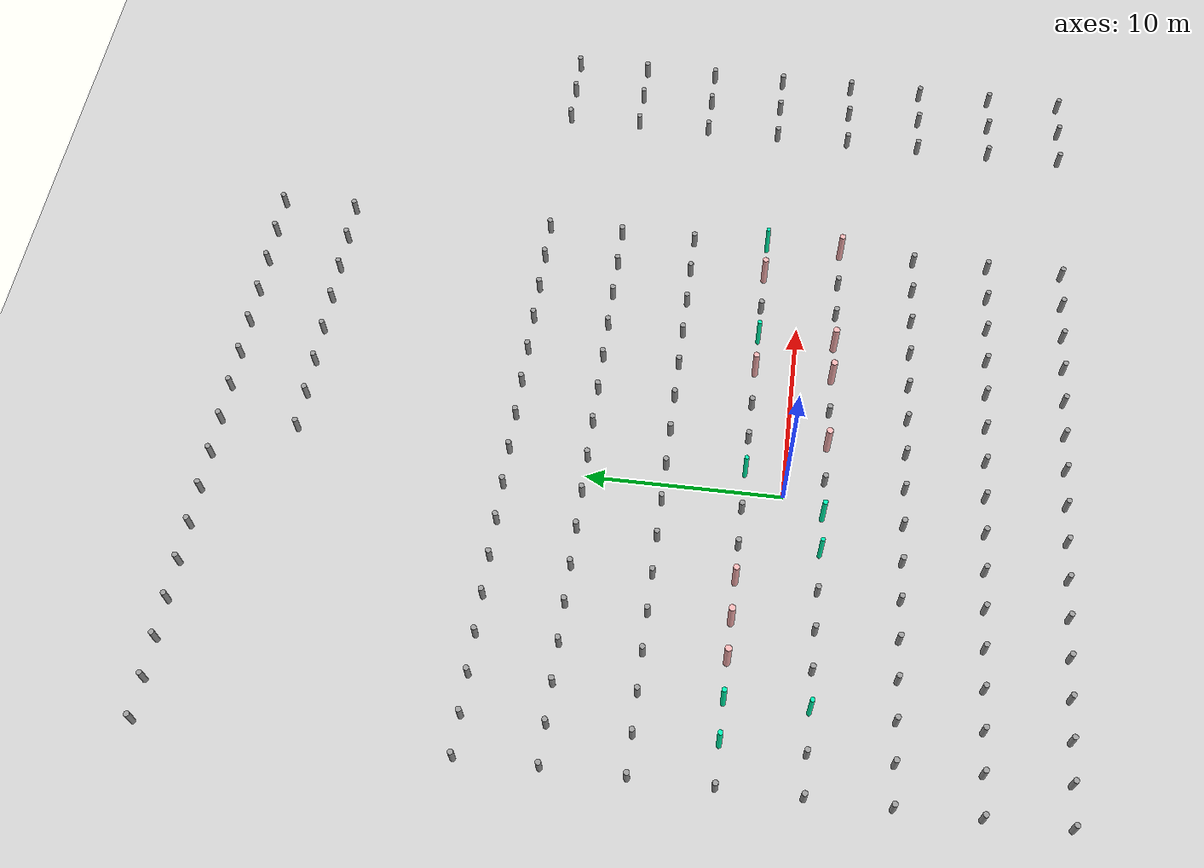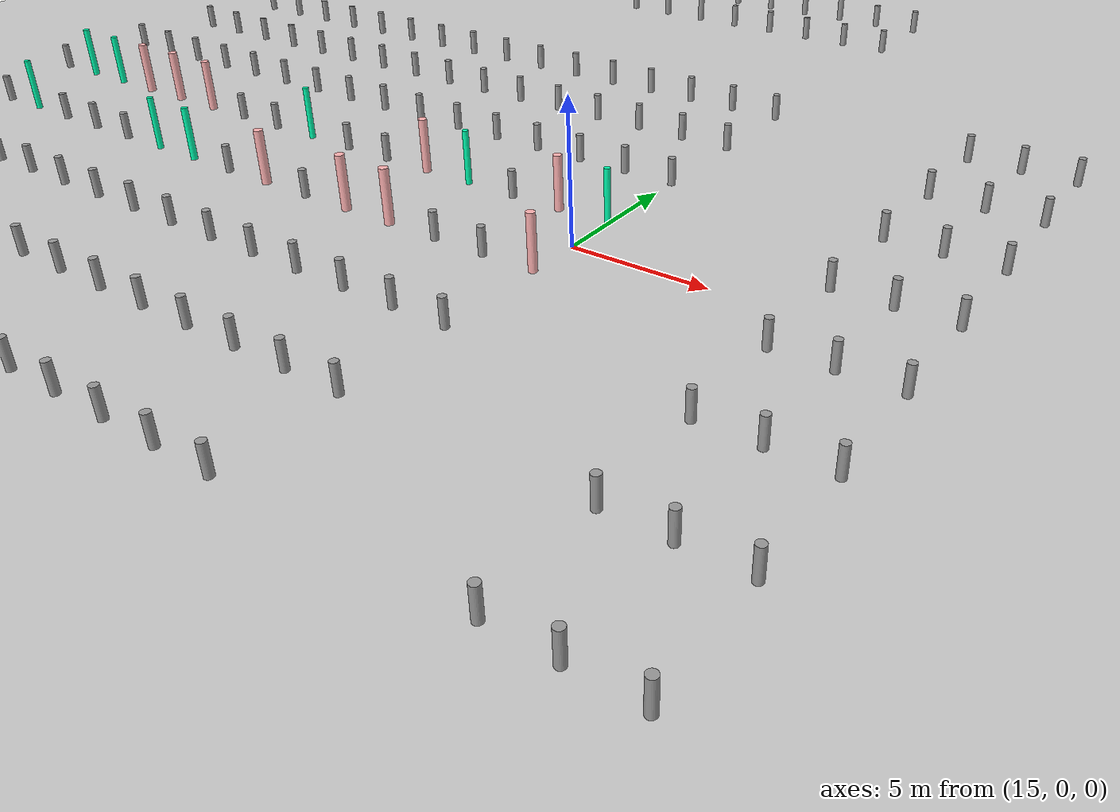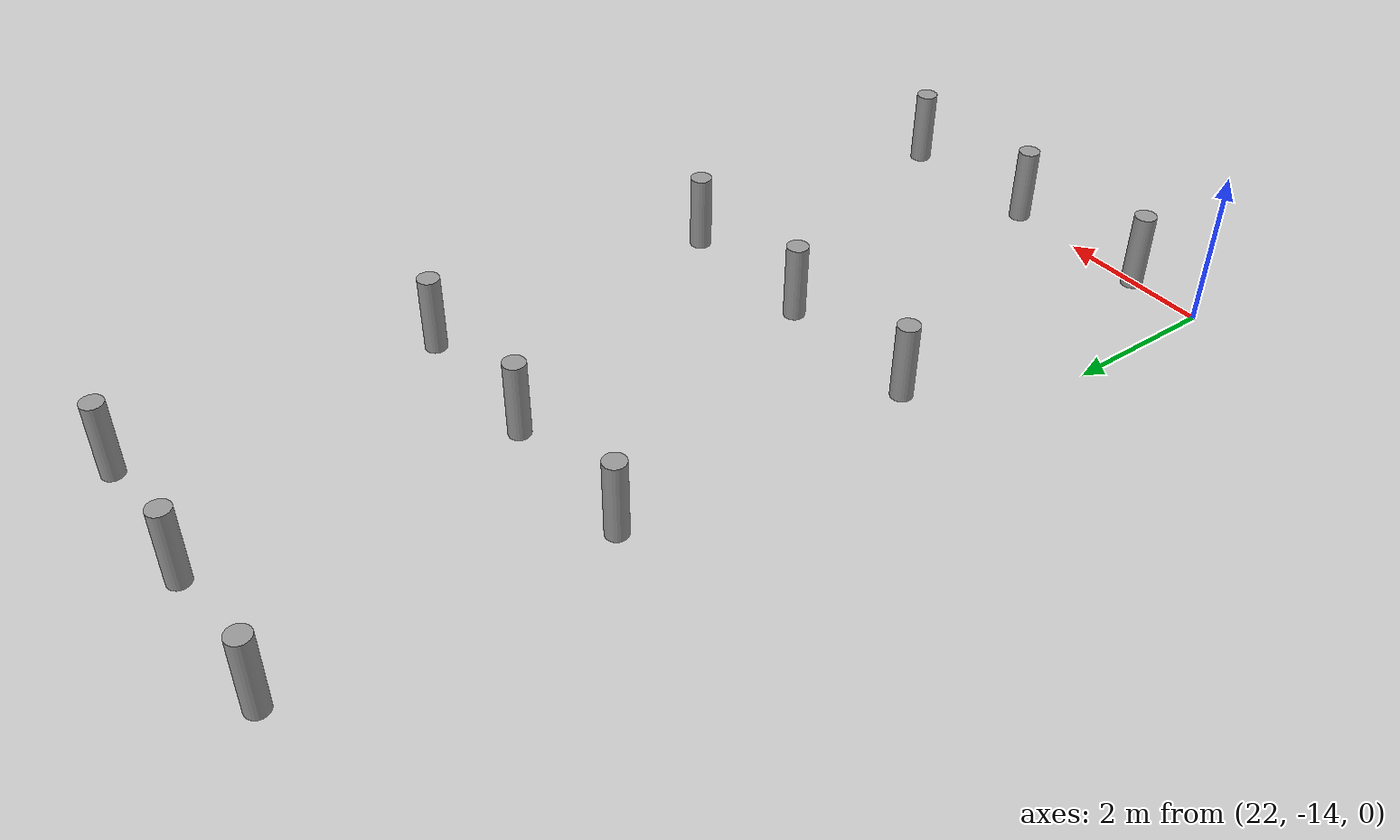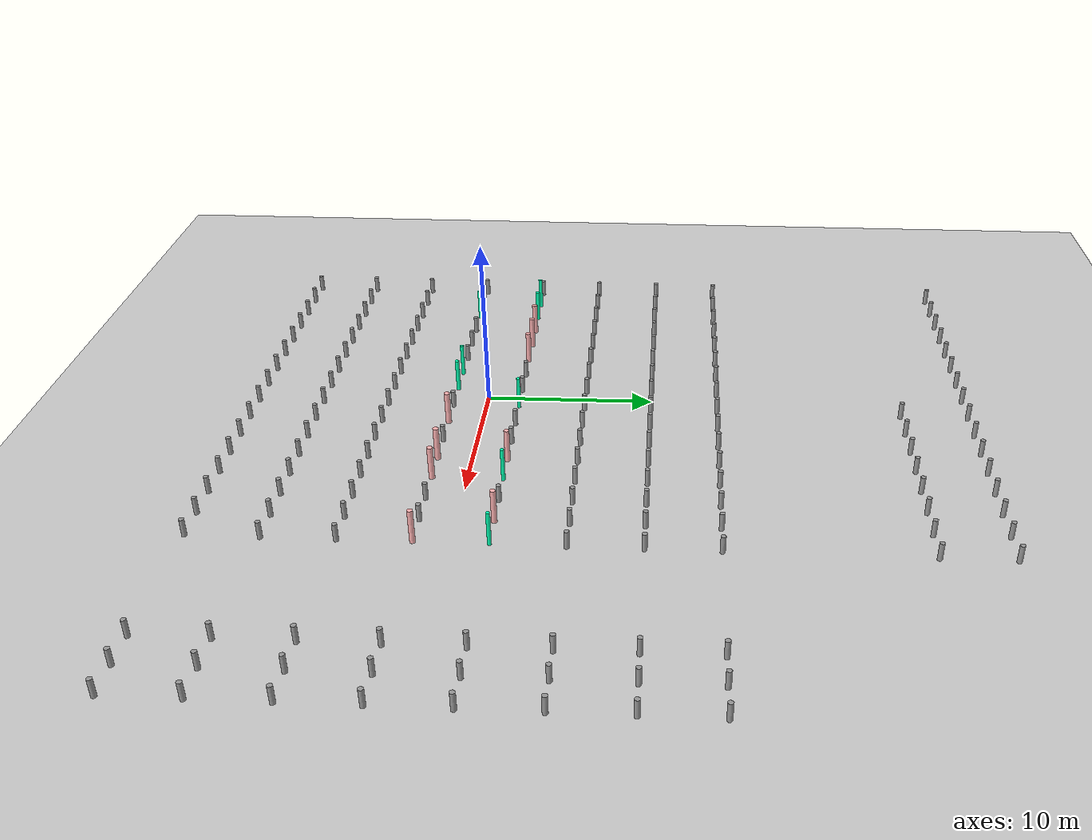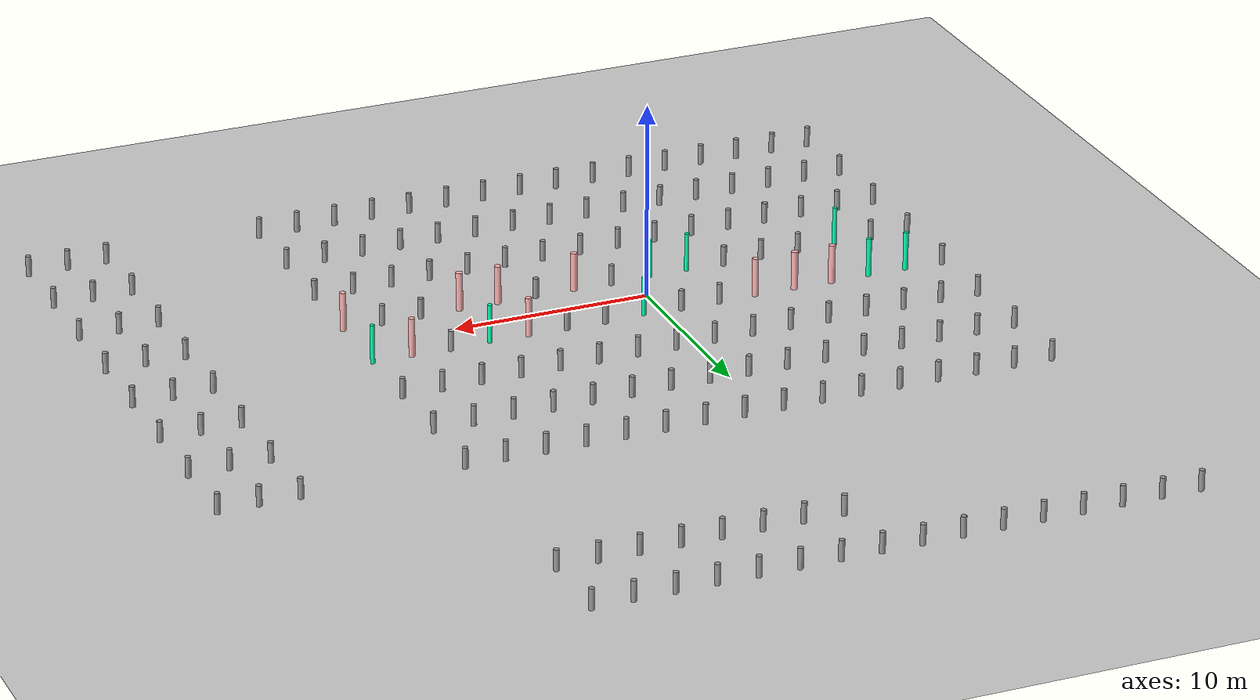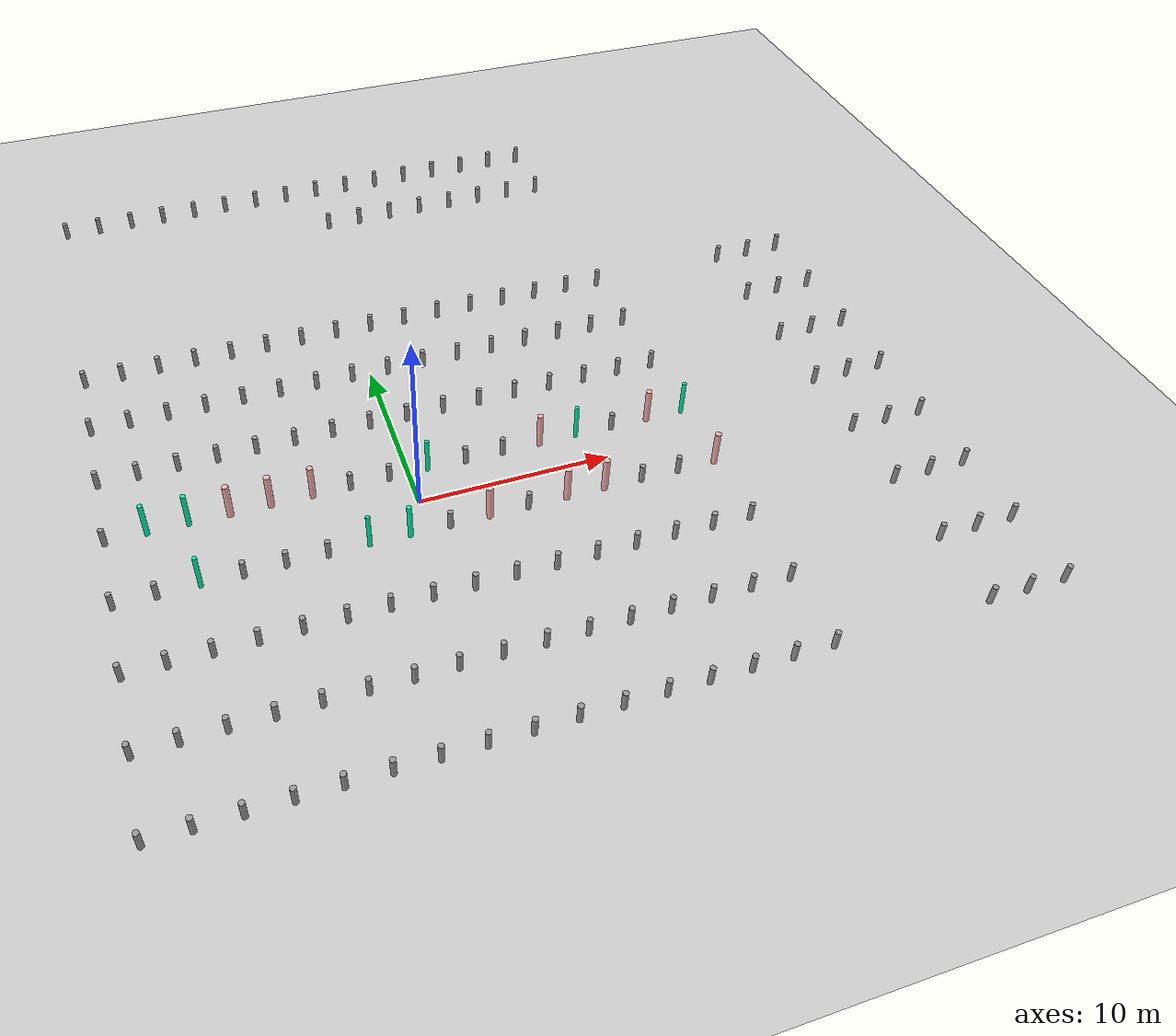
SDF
<sdf version="1.6">
 <world name="default">
  <light name="sun" type="directional">
   <pose>0 0 10 0 -0 0</pose>
   <diffuse>0.8 0.8 0.8 1</diffuse>
   <specular>0.2 0.2 0.2 1</specular>
   <attenuation>
    <range>1000</range>
    <constant>0.9</constant>
    <linear>0.01</linear>
    <quadratic>0.001</quadratic>
   </attenuation>
   <direction>-0.5 0.1 -0.9</direction>
  </light>
  <model name="ground_plane">
   <static>1</static>
   <link name="link">
    <collision name="collision">
     <geometry><plane><normal>0 0 1</normal><size>100 100</size></plane></geometry>
     <surface><friction><ode><mu>100</mu><mu2>50</mu2></ode></friction></surface>
    </collision>
    <visual name="visual">
     <cast_shadows>0</cast_shadows>
     <geometry><plane><normal>0 0 1</normal><size>100 100</size></plane></geometry>
     <material>
      <script><uri>file://media/materials/scripts/gazebo.material</uri><name>Gazebo/Grey</name></script>
     </material>
    </visual>
   </link>
  </model>
  <scene><shadows>0</shadows><ambient>0.4 0.4 0.4 1</ambient><background>0.7 0.7 0.7 1</background></scene>
  <gravity>0 0 -9.8</gravity>
  <magnetic_field>6e-06 2.3e-05 -4.2e-05</magnetic_field>
  <atmosphere type="adiabatic"/>
  <physics name="default_physics" default="0" type="ode">
   <max_step_size>0.001</max_step_size>
   <real_time_factor>1</real_time_factor>
   <real_time_update_rate>1000</real_time_update_rate>
  </physics>
  <spherical_coordinates>
   <surface_model>EARTH_WGS84</surface_model>
   <latitude_deg>0</latitude_deg>
   <longitude_deg>0</longitude_deg>
   <elevation>0</elevation>
   <heading_deg>0</heading_deg>
  </spherical_coordinates>
  <model name="my_cylinder014_clone_0">
   <pose>-15 -14 0 0 -0 0</pose>
   <link name="my_cylinder014::link">
    <inertial>
     <mass>1</mass>
     <inertia><ixx>0.145833</ixx><ixy>0</ixy><ixz>0</ixz><iyy>0.145833</iyy><iyz>0</iyz><izz>0.125</izz></inertia>
    </inertial>
    <visual name="visual">
     <geometry><cylinder><radius>0.14</radius><length>2</length></cylinder></geometry>
     <material>
      <script><name>Gazebo/Grey</name><uri>file://media/materials/scripts/gazebo.material</uri></script>
      <ambient>0.3 0.3 0.3 1</ambient>
      <diffuse>0.7 0.7 0.7 1</diffuse>
      <specular>1 0.01 0.01 1</specular>
      <emissive>0 0 0 1</emissive>
      <shader type="vertex"><normal_map>__default__</normal_map></shader>
     </material>
    </visual>
    <collision name="collision">
     <geometry><cylinder><radius>0.14</radius><length>2</length></cylinder></geometry>
     <surface>
      <friction>
       <ode><mu>1</mu><mu2>1</mu2><fdir1>0 0 0</fdir1><slip1>0</slip1><slip2>0</slip2></ode>
       <torsional>
        <coefficient>1</coefficient>
        <patch_radius>0</patch_radius>
        <surface_radius>0</surface_radius>
        <use_patch_radius>1</use_patch_radius>
        <ode><slip>0</slip></ode>
       </torsional>
      </friction>
      <bounce><restitution_coefficient>0</restitution_coefficient><threshold>1e+06</threshold></bounce>
      <contact>
       <collide_without_contact>0</collide_without_contact>
       <collide_without_contact_bitmask>1</collide_without_contact_bitmask>
       <collide_bitmask>1</collide_bitmask>
       <ode>
        <soft_cfm>0</soft_cfm>
        <soft_erp>0.2</soft_erp>
        <kp>1e+13</kp>
        <kd>1</kd>
        <max_vel>0.01</max_vel>
        <min_depth>0</min_depth>
       </ode>
       <bullet>
        <split_impulse>1</split_impulse>
        <split_impulse_penetration_threshold>-0.01</split_impulse_penetration_threshold>
        <soft_cfm>0</soft_cfm>
        <soft_erp>0.2</soft_erp>
        <kp>1e+13</kp>
        <kd>1</kd>
       </bullet>
      </contact>
     </surface>
    </collision>
   </link>
   <static>1</static>
  </model>
  <model name="my_cylinder014_clone_1">
   <pose>-13 -14 0 0 -0 0</pose>
   <link name="my_cylinder014::link">
    <inertial>
     <mass>1</mass>
     <inertia><ixx>0.145833</ixx><ixy>0</ixy><ixz>0</ixz><iyy>0.145833</iyy><iyz>0</iyz><izz>0.125</izz></inertia>
    </inertial>
    <visual name="visual">
     <geometry><cylinder><radius>0.14</radius><length>2</length></cylinder></geometry>
     <material>
      <script><name>Gazebo/Grey</name><uri>file://media/materials/scripts/gazebo.material</uri></script>
      <ambient>0.3 0.3 0.3 1</ambient>
      <diffuse>0.7 0.7 0.7 1</diffuse>
      <specular>1 0.01 0.01 1</specular>
      <emissive>0 0 0 1</emissive>
      <shader type="vertex"><normal_map>__default__</normal_map></shader>
     </material>
    </visual>
    <collision name="collision">
     <geometry><cylinder><radius>0.14</radius><length>2</length></cylinder></geometry>
     <surface>
      <friction>
       <ode><mu>1</mu><mu2>1</mu2><fdir1>0 0 0</fdir1><slip1>0</slip1><slip2>0</slip2></ode>
       <torsional>
        <coefficient>1</coefficient>
        <patch_radius>0</patch_radius>
        <surface_radius>0</surface_radius>
        <use_patch_radius>1</use_patch_radius>
        <ode><slip>0</slip></ode>
       </torsional>
      </friction>
      <bounce><restitution_coefficient>0</restitution_coefficient><threshold>1e+06</threshold></bounce>
      <contact>
       <collide_without_contact>0</collide_without_contact>
       <collide_without_contact_bitmask>1</collide_without_contact_bitmask>
       <collide_bitmask>1</collide_bitmask>
       <ode>
        <soft_cfm>0</soft_cfm>
        <soft_erp>0.2</soft_erp>
        <kp>1e+13</kp>
        <kd>1</kd>
        <max_vel>0.01</max_vel>
        <min_depth>0</min_depth>
       </ode>
       <bullet>
        <split_impulse>1</split_impulse>
        <split_impulse_penetration_threshold>-0.01</split_impulse_penetration_threshold>
        <soft_cfm>0</soft_cfm>
        <soft_erp>0.2</soft_erp>
        <kp>1e+13</kp>
        <kd>1</kd>
       </bullet>
      </contact>
     </surface>
    </collision>
   </link>
   <static>1</static>
  </model>
  <model name="my_cylinder014_clone_2">
   <pose>-11 -14 0 0 -0 0</pose>
   <link name="my_cylinder014::link">
    <inertial>
     <mass>1</mass>
     <inertia><ixx>0.145833</ixx><ixy>0</ixy><ixz>0</ixz><iyy>0.145833</iyy><iyz>0</iyz><izz>0.125</izz></inertia>
    </inertial>
    <visual name="visual">
     <geometry><cylinder><radius>0.14</radius><length>2</length></cylinder></geometry>
     <material>
      <script><name>Gazebo/Grey</name><uri>file://media/materials/scripts/gazebo.material</uri></script>
      <ambient>0.3 0.3 0.3 1</ambient>
      <diffuse>0.7 0.7 0.7 1</diffuse>
      <specular>1 0.01 0.01 1</specular>
      <emissive>0 0 0 1</emissive>
      <shader type="vertex"><normal_map>__default__</normal_map></shader>
     </material>
    </visual>
    <collision name="collision">
     <geometry><cylinder><radius>0.14</radius><length>2</length></cylinder></geometry>
     <surface>
      <friction>
       <ode><mu>1</mu><mu2>1</mu2><fdir1>0 0 0</fdir1><slip1>0</slip1><slip2>0</slip2></ode>
       <torsional>
        <coefficient>1</coefficient>
        <patch_radius>0</patch_radius>
        <surface_radius>0</surface_radius>
        <use_patch_radius>1</use_patch_radius>
        <ode><slip>0</slip></ode>
       </torsional>
      </friction>
      <bounce><restitution_coefficient>0</restitution_coefficient><threshold>1e+06</threshold></bounce>
      <contact>
       <collide_without_contact>0</collide_without_contact>
       <collide_without_contact_bitmask>1</collide_without_contact_bitmask>
       <collide_bitmask>1</collide_bitmask>
       <ode>
        <soft_cfm>0</soft_cfm>
        <soft_erp>0.2</soft_erp>
        <kp>1e+13</kp>
        <kd>1</kd>
        <max_vel>0.01</max_vel>
        <min_depth>0</min_depth>
       </ode>
       <bullet>
        <split_impulse>1</split_impulse>
        <split_impulse_penetration_threshold>-0.01</split_impulse_penetration_threshold>
        <soft_cfm>0</soft_cfm>
        <soft_erp>0.2</soft_erp>
        <kp>1e+13</kp>
        <kd>1</kd>
       </bullet>
      </contact>
     </surface>
    </collision>
   </link>
   <static>1</static>
  </model>
  <model name="my_cylinder014_clone_3">
   <pose>-9 -14 0 0 -0 0</pose>
   <link name="my_cylinder014::link">
    <inertial>
     <mass>1</mass>
     <inertia><ixx>0.145833</ixx><ixy>0</ixy><ixz>0</ixz><iyy>0.145833</iyy><iyz>0</iyz><izz>0.125</izz></inertia>
    </inertial>
    <visual name="visual">
     <geometry><cylinder><radius>0.14</radius><length>2</length></cylinder></geometry>
     <material>
      <script><name>Gazebo/Grey</name><uri>file://media/materials/scripts/gazebo.material</uri></script>
      <ambient>0.3 0.3 0.3 1</ambient>
      <diffuse>0.7 0.7 0.7 1</diffuse>
      <specular>1 0.01 0.01 1</specular>
      <emissive>0 0 0 1</emissive>
      <shader type="vertex"><normal_map>__default__</normal_map></shader>
     </material>
    </visual>
    <collision name="collision">
     <geometry><cylinder><radius>0.14</radius><length>2</length></cylinder></geometry>
     <surface>
      <friction>
       <ode><mu>1</mu><mu2>1</mu2><fdir1>0 0 0</fdir1><slip1>0</slip1><slip2>0</slip2></ode>
       <torsional>
        <coefficient>1</coefficient>
        <patch_radius>0</patch_radius>
        <surface_radius>0</surface_radius>
        <use_patch_radius>1</use_patch_radius>
        <ode><slip>0</slip></ode>
       </torsional>
      </friction>
      <bounce><restitution_coefficient>0</restitution_coefficient><threshold>1e+06</threshold></bounce>
      <contact>
       <collide_without_contact>0</collide_without_contact>
       <collide_without_contact_bitmask>1</collide_without_contact_bitmask>
       <collide_bitmask>1</collide_bitmask>
       <ode>
        <soft_cfm>0</soft_cfm>
        <soft_erp>0.2</soft_erp>
        <kp>1e+13</kp>
        <kd>1</kd>
        <max_vel>0.01</max_vel>
        <min_depth>0</min_depth>
       </ode>
       <bullet>
        <split_impulse>1</split_impulse>
        <split_impulse_penetration_threshold>-0.01</split_impulse_penetration_threshold>
        <soft_cfm>0</soft_cfm>
        <soft_erp>0.2</soft_erp>
        <kp>1e+13</kp>
        <kd>1</kd>
       </bullet>
      </contact>
     </surface>
    </collision>
   </link>
   <static>1</static>
  </model>
  <model name="my_cylinder014_clone_4">
   <pose>-7 -14 0 0 -0 0</pose>
   <link name="my_cylinder014::link">
    <inertial>
     <mass>1</mass>
     <inertia><ixx>0.145833</ixx><ixy>0</ixy><ixz>0</ixz><iyy>0.145833</iyy><iyz>0</iyz><izz>0.125</izz></inertia>
    </inertial>
    <visual name="visual">
     <geometry><cylinder><radius>0.14</radius><length>2</length></cylinder></geometry>
     <material>
      <script><name>Gazebo/Grey</name><uri>file://media/materials/scripts/gazebo.material</uri></script>
      <ambient>0.3 0.3 0.3 1</ambient>
      <diffuse>0.7 0.7 0.7 1</diffuse>
      <specular>1 0.01 0.01 1</specular>
      <emissive>0 0 0 1</emissive>
      <shader type="vertex"><normal_map>__default__</normal_map></shader>
     </material>
    </visual>
    <collision name="collision">
     <geometry><cylinder><radius>0.14</radius><length>2</length></cylinder></geometry>
     <surface>
      <friction>
       <ode><mu>1</mu><mu2>1</mu2><fdir1>0 0 0</fdir1><slip1>0</slip1><slip2>0</slip2></ode>
       <torsional>
        <coefficient>1</coefficient>
        <patch_radius>0</patch_radius>
        <surface_radius>0</surface_radius>
        <use_patch_radius>1</use_patch_radius>
        <ode><slip>0</slip></ode>
       </torsional>
      </friction>
      <bounce><restitution_coefficient>0</restitution_coefficient><threshold>1e+06</threshold></bounce>
      <contact>
       <collide_without_contact>0</collide_without_contact>
       <collide_without_contact_bitmask>1</collide_without_contact_bitmask>
       <collide_bitmask>1</collide_bitmask>
       <ode>
        <soft_cfm>0</soft_cfm>
        <soft_erp>0.2</soft_erp>
        <kp>1e+13</kp>
        <kd>1</kd>
        <max_vel>0.01</max_vel>
        <min_depth>0</min_depth>
       </ode>
       <bullet>
        <split_impulse>1</split_impulse>
        <split_impulse_penetration_threshold>-0.01</split_impulse_penetration_threshold>
        <soft_cfm>0</soft_cfm>
        <soft_erp>0.2</soft_erp>
        <kp>1e+13</kp>
        <kd>1</kd>
       </bullet>
      </contact>
     </surface>
    </collision>
   </link>
   <static>1</static>
  </model>
  <model name="my_cylinder014_clone_5">
   <pose>-5 -14 0 0 -0 0</pose>
   <link name="my_cylinder014::link">
    <inertial>
     <mass>1</mass>
     <inertia><ixx>0.145833</ixx><ixy>0</ixy><ixz>0</ixz><iyy>0.145833</iyy><iyz>0</iyz><izz>0.125</izz></inertia>
    </inertial>
    <visual name="visual">
     <geometry><cylinder><radius>0.14</radius><length>2</length></cylinder></geometry>
     <material>
      <script><name>Gazebo/Grey</name><uri>file://media/materials/scripts/gazebo.material</uri></script>
      <ambient>0.3 0.3 0.3 1</ambient>
      <diffuse>0.7 0.7 0.7 1</diffuse>
      <specular>1 0.01 0.01 1</specular>
      <emissive>0 0 0 1</emissive>
      <shader type="vertex"><normal_map>__default__</normal_map></shader>
     </material>
    </visual>
    <collision name="collision">
     <geometry><cylinder><radius>0.14</radius><length>2</length></cylinder></geometry>
     <surface>
      <friction>
       <ode><mu>1</mu><mu2>1</mu2><fdir1>0 0 0</fdir1><slip1>0</slip1><slip2>0</slip2></ode>
       <torsional>
        <coefficient>1</coefficient>
        <patch_radius>0</patch_radius>
        <surface_radius>0</surface_radius>
        <use_patch_radius>1</use_patch_radius>
        <ode><slip>0</slip></ode>
       </torsional>
      </friction>
      <bounce><restitution_coefficient>0</restitution_coefficient><threshold>1e+06</threshold></bounce>
      <contact>
       <collide_without_contact>0</collide_without_contact>
       <collide_without_contact_bitmask>1</collide_without_contact_bitmask>
       <collide_bitmask>1</collide_bitmask>
       <ode>
        <soft_cfm>0</soft_cfm>
        <soft_erp>0.2</soft_erp>
        <kp>1e+13</kp>
        <kd>1</kd>
        <max_vel>0.01</max_vel>
        <min_depth>0</min_depth>
       </ode>
       <bullet>
        <split_impulse>1</split_impulse>
        <split_impulse_penetration_threshold>-0.01</split_impulse_penetration_threshold>
        <soft_cfm>0</soft_cfm>
        <soft_erp>0.2</soft_erp>
        <kp>1e+13</kp>
        <kd>1</kd>
       </bullet>
      </contact>
     </surface>
    </collision>
   </link>
   <static>1</static>
  </model>
  <model name="my_cylinder014_clone_6">
   <pose>-3 -14 0 0 -0 0</pose>
   <link name="my_cylinder014::link">
    <inertial>
     <mass>1</mass>
     <inertia><ixx>0.145833</ixx><ixy>0</ixy><ixz>0</ixz><iyy>0.145833</iyy><iyz>0</iyz><izz>0.125</izz></inertia>
    </inertial>
    <visual name="visual">
     <geometry><cylinder><radius>0.14</radius><length>2</length></cylinder></geometry>
     <material>
      <script><name>Gazebo/Grey</name><uri>file://media/materials/scripts/gazebo.material</uri></script>
      <ambient>0.3 0.3 0.3 1</ambient>
      <diffuse>0.7 0.7 0.7 1</diffuse>
      <specular>1 0.01 0.01 1</specular>
      <emissive>0 0 0 1</emissive>
      <shader type="vertex"><normal_map>__default__</normal_map></shader>
     </material>
    </visual>
    <collision name="collision">
     <geometry><cylinder><radius>0.14</radius><length>2</length></cylinder></geometry>
     <surface>
      <friction>
       <ode><mu>1</mu><mu2>1</mu2><fdir1>0 0 0</fdir1><slip1>0</slip1><slip2>0</slip2></ode>
       <torsional>
        <coefficient>1</coefficient>
        <patch_radius>0</patch_radius>
        <surface_radius>0</surface_radius>
        <use_patch_radius>1</use_patch_radius>
        <ode><slip>0</slip></ode>
       </torsional>
      </friction>
      <bounce><restitution_coefficient>0</restitution_coefficient><threshold>1e+06</threshold></bounce>
      <contact>
       <collide_without_contact>0</collide_without_contact>
       <collide_without_contact_bitmask>1</collide_without_contact_bitmask>
       <collide_bitmask>1</collide_bitmask>
       <ode>
        <soft_cfm>0</soft_cfm>
        <soft_erp>0.2</soft_erp>
        <kp>1e+13</kp>
        <kd>1</kd>
        <max_vel>0.01</max_vel>
        <min_depth>0</min_depth>
       </ode>
       <bullet>
        <split_impulse>1</split_impulse>
        <split_impulse_penetration_threshold>-0.01</split_impulse_penetration_threshold>
        <soft_cfm>0</soft_cfm>
        <soft_erp>0.2</soft_erp>
        <kp>1e+13</kp>
        <kd>1</kd>
       </bullet>
      </contact>
     </surface>
    </collision>
   </link>
   <static>1</static>
  </model>
  <model name="my_cylinder014_clone_7">
   <pose>-1 -14 0 0 -0 0</pose>
   <link name="my_cylinder014::link">
    <inertial>
     <mass>1</mass>
     <inertia><ixx>0.145833</ixx><ixy>0</ixy><ixz>0</ixz><iyy>0.145833</iyy><iyz>0</iyz><izz>0.125</izz></inertia>
    </inertial>
    <visual name="visual">
     <geometry><cylinder><radius>0.14</radius><length>2</length></cylinder></geometry>
     <material>
      <script><name>Gazebo/Grey</name><uri>file://media/materials/scripts/gazebo.material</uri></script>
      <ambient>0.3 0.3 0.3 1</ambient>
      <diffuse>0.7 0.7 0.7 1</diffuse>
      <specular>1 0.01 0.01 1</specular>
      <emissive>0 0 0 1</emissive>
      <shader type="vertex"><normal_map>__default__</normal_map></shader>
     </material>
    </visual>
    <collision name="collision">
     <geometry><cylinder><radius>0.14</radius><length>2</length></cylinder></geometry>
     <surface>
      <friction>
       <ode><mu>1</mu><mu2>1</mu2><fdir1>0 0 0</fdir1><slip1>0</slip1><slip2>0</slip2></ode>
       <torsional>
        <coefficient>1</coefficient>
        <patch_radius>0</patch_radius>
        <surface_radius>0</surface_radius>
        <use_patch_radius>1</use_patch_radius>
        <ode><slip>0</slip></ode>
       </torsional>
      </friction>
      <bounce><restitution_coefficient>0</restitution_coefficient><threshold>1e+06</threshold></bounce>
      <contact>
       <collide_without_contact>0</collide_without_contact>
       <collide_without_contact_bitmask>1</collide_without_contact_bitmask>
       <collide_bitmask>1</collide_bitmask>
       <ode>
        <soft_cfm>0</soft_cfm>
        <soft_erp>0.2</soft_erp>
        <kp>1e+13</kp>
        <kd>1</kd>
        <max_vel>0.01</max_vel>
        <min_depth>0</min_depth>
       </ode>
       <bullet>
        <split_impulse>1</split_impulse>
        <split_impulse_penetration_threshold>-0.01</split_impulse_penetration_threshold>
        <soft_cfm>0</soft_cfm>
        <soft_erp>0.2</soft_erp>
        <kp>1e+13</kp>
        <kd>1</kd>
       </bullet>
      </contact>
     </surface>
    </collision>
   </link>
   <static>1</static>
  </model>
  <model name="my_cylinder014_clone_8">
   <pose>1 -14 0 0 -0 0</pose>
   <link name="my_cylinder014::link">
    <inertial>
     <mass>1</mass>
     <inertia><ixx>0.145833</ixx><ixy>0</ixy><ixz>0</ixz><iyy>0.145833</iyy><iyz>0</iyz><izz>0.125</izz></inertia>
    </inertial>
    <visual name="visual">
     <geometry><cylinder><radius>0.14</radius><length>2</length></cylinder></geometry>
     <material>
      <script><name>Gazebo/Grey</name><uri>file://media/materials/scripts/gazebo.material</uri></script>
      <ambient>0.3 0.3 0.3 1</ambient>
      <diffuse>0.7 0.7 0.7 1</diffuse>
      <specular>1 0.01 0.01 1</specular>
      <emissive>0 0 0 1</emissive>
      <shader type="vertex"><normal_map>__default__</normal_map></shader>
     </material>
    </visual>
    <collision name="collision">
     <geometry><cylinder><radius>0.14</radius><length>2</length></cylinder></geometry>
     <surface>
      <friction>
       <ode><mu>1</mu><mu2>1</mu2><fdir1>0 0 0</fdir1><slip1>0</slip1><slip2>0</slip2></ode>
       <torsional>
        <coefficient>1</coefficient>
        <patch_radius>0</patch_radius>
        <surface_radius>0</surface_radius>
        <use_patch_radius>1</use_patch_radius>
        <ode><slip>0</slip></ode>
       </torsional>
      </friction>
      <bounce><restitution_coefficient>0</restitution_coefficient><threshold>1e+06</threshold></bounce>
      <contact>
       <collide_without_contact>0</collide_without_contact>
       <collide_without_contact_bitmask>1</collide_without_contact_bitmask>
       <collide_bitmask>1</collide_bitmask>
       <ode>
        <soft_cfm>0</soft_cfm>
        <soft_erp>0.2</soft_erp>
        <kp>1e+13</kp>
        <kd>1</kd>
        <max_vel>0.01</max_vel>
        <min_depth>0</min_depth>
       </ode>
       <bullet>
        <split_impulse>1</split_impulse>
        <split_impulse_penetration_threshold>-0.01</split_impulse_penetration_threshold>
        <soft_cfm>0</soft_cfm>
        <soft_erp>0.2</soft_erp>
        <kp>1e+13</kp>
        <kd>1</kd>
       </bullet>
      </contact>
     </surface>
    </collision>
   </link>
   <static>1</static>
  </model>
  <model name="my_cylinder014_clone_9">
   <pose>3 -14 0 0 -0 0</pose>
   <link name="my_cylinder014::link">
    <inertial>
     <mass>1</mass>
     <inertia><ixx>0.145833</ixx><ixy>0</ixy><ixz>0</ixz><iyy>0.145833</iyy><iyz>0</iyz><izz>0.125</izz></inertia>
    </inertial>
    <visual name="visual">
     <geometry><cylinder><radius>0.14</radius><length>2</length></cylinder></geometry>
     <material>
      <script><name>Gazebo/Grey</name><uri>file://media/materials/scripts/gazebo.material</uri></script>
      <ambient>0.3 0.3 0.3 1</ambient>
      <diffuse>0.7 0.7 0.7 1</diffuse>
      <specular>1 0.01 0.01 1</specular>
      <emissive>0 0 0 1</emissive>
      <shader type="vertex"><normal_map>__default__</normal_map></shader>
     </material>
    </visual>
    <collision name="collision">
     <geometry><cylinder><radius>0.14</radius><length>2</length></cylinder></geometry>
     <surface>
      <friction>
       <ode><mu>1</mu><mu2>1</mu2><fdir1>0 0 0</fdir1><slip1>0</slip1><slip2>0</slip2></ode>
       <torsional>
        <coefficient>1</coefficient>
        <patch_radius>0</patch_radius>
        <surface_radius>0</surface_radius>
        <use_patch_radius>1</use_patch_radius>
        <ode><slip>0</slip></ode>
       </torsional>
      </friction>
      <bounce><restitution_coefficient>0</restitution_coefficient><threshold>1e+06</threshold></bounce>
      <contact>
       <collide_without_contact>0</collide_without_contact>
       <collide_without_contact_bitmask>1</collide_without_contact_bitmask>
       <collide_bitmask>1</collide_bitmask>
       <ode>
        <soft_cfm>0</soft_cfm>
        <soft_erp>0.2</soft_erp>
        <kp>1e+13</kp>
        <kd>1</kd>
        <max_vel>0.01</max_vel>
        <min_depth>0</min_depth>
       </ode>
       <bullet>
        <split_impulse>1</split_impulse>
        <split_impulse_penetration_threshold>-0.01</split_impulse_penetration_threshold>
        <soft_cfm>0</soft_cfm>
        <soft_erp>0.2</soft_erp>
        <kp>1e+13</kp>
        <kd>1</kd>
       </bullet>
      </contact>
     </surface>
    </collision>
   </link>
   <static>1</static>
  </model>
  <model name="my_cylinder014_clone_10">
   <pose>5 -14 0 0 -0 0</pose>
   <link name="my_cylinder014::link">
    <inertial>
     <mass>1</mass>
     <inertia><ixx>0.145833</ixx><ixy>0</ixy><ixz>0</ixz><iyy>0.145833</iyy><iyz>0</iyz><izz>0.125</izz></inertia>
    </inertial>
    <visual name="visual">
     <geometry><cylinder><radius>0.14</radius><length>2</length></cylinder></geometry>
     <material>
      <script><name>Gazebo/Grey</name><uri>file://media/materials/scripts/gazebo.material</uri></script>
      <ambient>0.3 0.3 0.3 1</ambient>
      <diffuse>0.7 0.7 0.7 1</diffuse>
      <specular>1 0.01 0.01 1</specular>
      <emissive>0 0 0 1</emissive>
      <shader type="vertex"><normal_map>__default__</normal_map></shader>
     </material>
    </visual>
    <collision name="collision">
     <geometry><cylinder><radius>0.14</radius><length>2</length></cylinder></geometry>
     <surface>
      <friction>
       <ode><mu>1</mu><mu2>1</mu2><fdir1>0 0 0</fdir1><slip1>0</slip1><slip2>0</slip2></ode>
       <torsional>
        <coefficient>1</coefficient>
        <patch_radius>0</patch_radius>
        <surface_radius>0</surface_radius>
        <use_patch_radius>1</use_patch_radius>
        <ode><slip>0</slip></ode>
       </torsional>
      </friction>
      <bounce><restitution_coefficient>0</restitution_coefficient><threshold>1e+06</threshold></bounce>
      <contact>
       <collide_without_contact>0</collide_without_contact>
       <collide_without_contact_bitmask>1</collide_without_contact_bitmask>
       <collide_bitmask>1</collide_bitmask>
       <ode>
        <soft_cfm>0</soft_cfm>
        <soft_erp>0.2</soft_erp>
        <kp>1e+13</kp>
        <kd>1</kd>
        <max_vel>0.01</max_vel>
        <min_depth>0</min_depth>
       </ode>
       <bullet>
        <split_impulse>1</split_impulse>
        <split_impulse_penetration_threshold>-0.01</split_impulse_penetration_threshold>
        <soft_cfm>0</soft_cfm>
        <soft_erp>0.2</soft_erp>
        <kp>1e+13</kp>
        <kd>1</kd>
       </bullet>
      </contact>
     </surface>
    </collision>
   </link>
   <static>1</static>
  </model>
  <model name="my_cylinder014_clone_11">
   <pose>7 -14 0 0 -0 0</pose>
   <link name="my_cylinder014::link">
    <inertial>
     <mass>1</mass>
     <inertia><ixx>0.145833</ixx><ixy>0</ixy><ixz>0</ixz><iyy>0.145833</iyy><iyz>0</iyz><izz>0.125</izz></inertia>
    </inertial>
    <visual name="visual">
     <geometry><cylinder><radius>0.14</radius><length>2</length></cylinder></geometry>
     <material>
      <script><name>Gazebo/Grey</name><uri>file://media/materials/scripts/gazebo.material</uri></script>
      <ambient>0.3 0.3 0.3 1</ambient>
      <diffuse>0.7 0.7 0.7 1</diffuse>
      <specular>1 0.01 0.01 1</specular>
      <emissive>0 0 0 1</emissive>
      <shader type="vertex"><normal_map>__default__</normal_map></shader>
     </material>
    </visual>
    <collision name="collision">
     <geometry><cylinder><radius>0.14</radius><length>2</length></cylinder></geometry>
     <surface>
      <friction>
       <ode><mu>1</mu><mu2>1</mu2><fdir1>0 0 0</fdir1><slip1>0</slip1><slip2>0</slip2></ode>
       <torsional>
        <coefficient>1</coefficient>
        <patch_radius>0</patch_radius>
        <surface_radius>0</surface_radius>
        <use_patch_radius>1</use_patch_radius>
        <ode><slip>0</slip></ode>
       </torsional>
      </friction>
      <bounce><restitution_coefficient>0</restitution_coefficient><threshold>1e+06</threshold></bounce>
      <contact>
       <collide_without_contact>0</collide_without_contact>
       <collide_without_contact_bitmask>1</collide_without_contact_bitmask>
       <collide_bitmask>1</collide_bitmask>
       <ode>
        <soft_cfm>0</soft_cfm>
        <soft_erp>0.2</soft_erp>
        <kp>1e+13</kp>
        <kd>1</kd>
        <max_vel>0.01</max_vel>
        <min_depth>0</min_depth>
       </ode>
       <bullet>
        <split_impulse>1</split_impulse>
        <split_impulse_penetration_threshold>-0.01</split_impulse_penetration_threshold>
        <soft_cfm>0</soft_cfm>
        <soft_erp>0.2</soft_erp>
        <kp>1e+13</kp>
        <kd>1</kd>
       </bullet>
      </contact>
     </surface>
    </collision>
   </link>
   <static>1</static>
  </model>
  <model name="my_cylinder014_clone_12">
   <pose>9 -14 0 0 -0 0</pose>
   <link name="my_cylinder014::link">
    <inertial>
     <mass>1</mass>
     <inertia><ixx>0.145833</ixx><ixy>0</ixy><ixz>0</ixz><iyy>0.145833</iyy><iyz>0</iyz><izz>0.125</izz></inertia>
    </inertial>
    <visual name="visual">
     <geometry><cylinder><radius>0.14</radius><length>2</length></cylinder></geometry>
     <material>
      <script><name>Gazebo/Grey</name><uri>file://media/materials/scripts/gazebo.material</uri></script>
      <ambient>0.3 0.3 0.3 1</ambient>
      <diffuse>0.7 0.7 0.7 1</diffuse>
      <specular>1 0.01 0.01 1</specular>
      <emissive>0 0 0 1</emissive>
      <shader type="vertex"><normal_map>__default__</normal_map></shader>
     </material>
    </visual>
    <collision name="collision">
     <geometry><cylinder><radius>0.14</radius><length>2</length></cylinder></geometry>
     <surface>
      <friction>
       <ode><mu>1</mu><mu2>1</mu2><fdir1>0 0 0</fdir1><slip1>0</slip1><slip2>0</slip2></ode>
       <torsional>
        <coefficient>1</coefficient>
        <patch_radius>0</patch_radius>
        <surface_radius>0</surface_radius>
        <use_patch_radius>1</use_patch_radius>
        <ode><slip>0</slip></ode>
       </torsional>
      </friction>
      <bounce><restitution_coefficient>0</restitution_coefficient><threshold>1e+06</threshold></bounce>
      <contact>
       <collide_without_contact>0</collide_without_contact>
       <collide_without_contact_bitmask>1</collide_without_contact_bitmask>
       <collide_bitmask>1</collide_bitmask>
       <ode>
        <soft_cfm>0</soft_cfm>
        <soft_erp>0.2</soft_erp>
        <kp>1e+13</kp>
        <kd>1</kd>
        <max_vel>0.01</max_vel>
        <min_depth>0</min_depth>
       </ode>
       <bullet>
        <split_impulse>1</split_impulse>
        <split_impulse_penetration_threshold>-0.01</split_impulse_penetration_threshold>
        <soft_cfm>0</soft_cfm>
        <soft_erp>0.2</soft_erp>
        <kp>1e+13</kp>
        <kd>1</kd>
       </bullet>
      </contact>
     </surface>
    </collision>
   </link>
   <static>1</static>
  </model>
  <model name="my_cylinder014_clone_13">
   <pose>11 -14 0 0 -0 0</pose>
   <link name="my_cylinder014::link">
    <inertial>
     <mass>1</mass>
     <inertia><ixx>0.145833</ixx><ixy>0</ixy><ixz>0</ixz><iyy>0.145833</iyy><iyz>0</iyz><izz>0.125</izz></inertia>
    </inertial>
    <visual name="visual">
     <geometry><cylinder><radius>0.14</radius><length>2</length></cylinder></geometry>
     <material>
      <script><name>Gazebo/Grey</name><uri>file://media/materials/scripts/gazebo.material</uri></script>
      <ambient>0.3 0.3 0.3 1</ambient>
      <diffuse>0.7 0.7 0.7 1</diffuse>
      <specular>1 0.01 0.01 1</specular>
      <emissive>0 0 0 1</emissive>
      <shader type="vertex"><normal_map>__default__</normal_map></shader>
     </material>
    </visual>
    <collision name="collision">
     <geometry><cylinder><radius>0.14</radius><length>2</length></cylinder></geometry>
     <surface>
      <friction>
       <ode><mu>1</mu><mu2>1</mu2><fdir1>0 0 0</fdir1><slip1>0</slip1><slip2>0</slip2></ode>
       <torsional>
        <coefficient>1</coefficient>
        <patch_radius>0</patch_radius>
        <surface_radius>0</surface_radius>
        <use_patch_radius>1</use_patch_radius>
        <ode><slip>0</slip></ode>
       </torsional>
      </friction>
      <bounce><restitution_coefficient>0</restitution_coefficient><threshold>1e+06</threshold></bounce>
      <contact>
       <collide_without_contact>0</collide_without_contact>
       <collide_without_contact_bitmask>1</collide_without_contact_bitmask>
       <collide_bitmask>1</collide_bitmask>
       <ode>
        <soft_cfm>0</soft_cfm>
        <soft_erp>0.2</soft_erp>
        <kp>1e+13</kp>
        <kd>1</kd>
        <max_vel>0.01</max_vel>
        <min_depth>0</min_depth>
       </ode>
       <bullet>
        <split_impulse>1</split_impulse>
        <split_impulse_penetration_threshold>-0.01</split_impulse_penetration_threshold>
        <soft_cfm>0</soft_cfm>
        <soft_erp>0.2</soft_erp>
        <kp>1e+13</kp>
        <kd>1</kd>
       </bullet>
      </contact>
     </surface>
    </collision>
   </link>
   <static>1</static>
  </model>
  <model name="my_cylinder014_clone_14">
   <pose>13 -14 0 0 -0 0</pose>
   <link name="my_cylinder014::link">
    <inertial>
     <mass>1</mass>
     <inertia><ixx>0.145833</ixx><ixy>0</ixy><ixz>0</ixz><iyy>0.145833</iyy><iyz>0</iyz><izz>0.125</izz></inertia>
    </inertial>
    <visual name="visual">
     <geometry><cylinder><radius>0.14</radius><length>2</length></cylinder></geometry>
     <material>
      <script><name>Gazebo/Grey</name><uri>file://media/materials/scripts/gazebo.material</uri></script>
      <ambient>0.3 0.3 0.3 1</ambient>
      <diffuse>0.7 0.7 0.7 1</diffuse>
      <specular>1 0.01 0.01 1</specular>
      <emissive>0 0 0 1</emissive>
      <shader type="vertex"><normal_map>__default__</normal_map></shader>
     </material>
    </visual>
    <collision name="collision">
     <geometry><cylinder><radius>0.14</radius><length>2</length></cylinder></geometry>
     <surface>
      <friction>
       <ode><mu>1</mu><mu2>1</mu2><fdir1>0 0 0</fdir1><slip1>0</slip1><slip2>0</slip2></ode>
       <torsional>
        <coefficient>1</coefficient>
        <patch_radius>0</patch_radius>
        <surface_radius>0</surface_radius>
        <use_patch_radius>1</use_patch_radius>
        <ode><slip>0</slip></ode>
       </torsional>
      </friction>
      <bounce><restitution_coefficient>0</restitution_coefficient><threshold>1e+06</threshold></bounce>
      <contact>
       <collide_without_contact>0</collide_without_contact>
       <collide_without_contact_bitmask>1</collide_without_contact_bitmask>
       <collide_bitmask>1</collide_bitmask>
       <ode>
        <soft_cfm>0</soft_cfm>
        <soft_erp>0.2</soft_erp>
        <kp>1e+13</kp>
        <kd>1</kd>
        <max_vel>0.01</max_vel>
        <min_depth>0</min_depth>
       </ode>
       <bullet>
        <split_impulse>1</split_impulse>
        <split_impulse_penetration_threshold>-0.01</split_impulse_penetration_threshold>
        <soft_cfm>0</soft_cfm>
        <soft_erp>0.2</soft_erp>
        <kp>1e+13</kp>
        <kd>1</kd>
       </bullet>
      </contact>
     </surface>
    </collision>
   </link>
   <static>1</static>
  </model>
  <model name="my_cylinder014_clone_15">
   <pose>15 -14 0 0 -0 0</pose>
   <link name="my_cylinder014::link">
    <inertial>
     <mass>1</mass>
     <inertia><ixx>0.145833</ixx><ixy>0</ixy><ixz>0</ixz><iyy>0.145833</iyy><iyz>0</iyz><izz>0.125</izz></inertia>
    </inertial>
    <visual name="visual">
     <geometry><cylinder><radius>0.14</radius><length>2</length></cylinder></geometry>
     <material>
      <script><name>Gazebo/Grey</name><uri>file://media/materials/scripts/gazebo.material</uri></script>
      <ambient>0.3 0.3 0.3 1</ambient>
      <diffuse>0.7 0.7 0.7 1</diffuse>
      <specular>1 0.01 0.01 1</specular>
      <emissive>0 0 0 1</emissive>
      <shader type="vertex"><normal_map>__default__</normal_map></shader>
     </material>
    </visual>
    <collision name="collision">
     <geometry><cylinder><radius>0.14</radius><length>2</length></cylinder></geometry>
     <surface>
      <friction>
       <ode><mu>1</mu><mu2>1</mu2><fdir1>0 0 0</fdir1><slip1>0</slip1><slip2>0</slip2></ode>
       <torsional>
        <coefficient>1</coefficient>
        <patch_radius>0</patch_radius>
        <surface_radius>0</surface_radius>
        <use_patch_radius>1</use_patch_radius>
        <ode><slip>0</slip></ode>
       </torsional>
      </friction>
      <bounce><restitution_coefficient>0</restitution_coefficient><threshold>1e+06</threshold></bounce>
      <contact>
       <collide_without_contact>0</collide_without_contact>
       <collide_without_contact_bitmask>1</collide_without_contact_bitmask>
       <collide_bitmask>1</collide_bitmask>
       <ode>
        <soft_cfm>0</soft_cfm>
        <soft_erp>0.2</soft_erp>
        <kp>1e+13</kp>
        <kd>1</kd>
        <max_vel>0.01</max_vel>
        <min_depth>0</min_depth>
       </ode>
       <bullet>
        <split_impulse>1</split_impulse>
        <split_impulse_penetration_threshold>-0.01</split_impulse_penetration_threshold>
        <soft_cfm>0</soft_cfm>
        <soft_erp>0.2</soft_erp>
        <kp>1e+13</kp>
        <kd>1</kd>
       </bullet>
      </contact>
     </surface>
    </collision>
   </link>
   <static>1</static>
  </model>
  <model name="my_cylinder014_clone_16">
   <pose>-15 -10 0 0 -0 0</pose>
   <link name="my_cylinder014::link">
    <inertial>
     <mass>1</mass>
     <inertia><ixx>0.145833</ixx><ixy>0</ixy><ixz>0</ixz><iyy>0.145833</iyy><iyz>0</iyz><izz>0.125</izz></inertia>
    </inertial>
    <visual name="visual">
     <geometry><cylinder><radius>0.14</radius><length>2</length></cylinder></geometry>
     <material>
      <script><name>Gazebo/Grey</name><uri>file://media/materials/scripts/gazebo.material</uri></script>
      <ambient>0.3 0.3 0.3 1</ambient>
      <diffuse>0.7 0.7 0.7 1</diffuse>
      <specular>1 0.01 0.01 1</specular>
      <emissive>0 0 0 1</emissive>
      <shader type="vertex"><normal_map>__default__</normal_map></shader>
     </material>
    </visual>
    <collision name="collision">
     <geometry><cylinder><radius>0.14</radius><length>2</length></cylinder></geometry>
     <surface>
      <friction>
       <ode><mu>1</mu><mu2>1</mu2><fdir1>0 0 0</fdir1><slip1>0</slip1><slip2>0</slip2></ode>
       <torsional>
        <coefficient>1</coefficient>
        <patch_radius>0</patch_radius>
        <surface_radius>0</surface_radius>
        <use_patch_radius>1</use_patch_radius>
        <ode><slip>0</slip></ode>
       </torsional>
      </friction>
      <bounce><restitution_coefficient>0</restitution_coefficient><threshold>1e+06</threshold></bounce>
      <contact>
       <collide_without_contact>0</collide_without_contact>
       <collide_without_contact_bitmask>1</collide_without_contact_bitmask>
       <collide_bitmask>1</collide_bitmask>
       <ode>
        <soft_cfm>0</soft_cfm>
        <soft_erp>0.2</soft_erp>
        <kp>1e+13</kp>
        <kd>1</kd>
        <max_vel>0.01</max_vel>
        <min_depth>0</min_depth>
       </ode>
       <bullet>
        <split_impulse>1</split_impulse>
        <split_impulse_penetration_threshold>-0.01</split_impulse_penetration_threshold>
        <soft_cfm>0</soft_cfm>
        <soft_erp>0.2</soft_erp>
        <kp>1e+13</kp>
        <kd>1</kd>
       </bullet>
      </contact>
     </surface>
    </collision>
   </link>
   <static>1</static>
  </model>
  <model name="my_cylinder014_clone_17">
   <pose>-13 -10 0 0 -0 0</pose>
   <link name="my_cylinder014::link">
    <inertial>
     <mass>1</mass>
     <inertia><ixx>0.145833</ixx><ixy>0</ixy><ixz>0</ixz><iyy>0.145833</iyy><iyz>0</iyz><izz>0.125</izz></inertia>
    </inertial>
    <visual name="visual">
     <geometry><cylinder><radius>0.14</radius><length>2</length></cylinder></geometry>
     <material>
      <script><name>Gazebo/Grey</name><uri>file://media/materials/scripts/gazebo.material</uri></script>
      <ambient>0.3 0.3 0.3 1</ambient>
      <diffuse>0.7 0.7 0.7 1</diffuse>
      <specular>1 0.01 0.01 1</specular>
      <emissive>0 0 0 1</emissive>
      <shader type="vertex"><normal_map>__default__</normal_map></shader>
     </material>
    </visual>
    <collision name="collision">
     <geometry><cylinder><radius>0.14</radius><length>2</length></cylinder></geometry>
     <surface>
      <friction>
       <ode><mu>1</mu><mu2>1</mu2><fdir1>0 0 0</fdir1><slip1>0</slip1><slip2>0</slip2></ode>
       <torsional>
        <coefficient>1</coefficient>
        <patch_radius>0</patch_radius>
        <surface_radius>0</surface_radius>
        <use_patch_radius>1</use_patch_radius>
        <ode><slip>0</slip></ode>
       </torsional>
      </friction>
      <bounce><restitution_coefficient>0</restitution_coefficient><threshold>1e+06</threshold></bounce>
      <contact>
       <collide_without_contact>0</collide_without_contact>
       <collide_without_contact_bitmask>1</collide_without_contact_bitmask>
       <collide_bitmask>1</collide_bitmask>
       <ode>
        <soft_cfm>0</soft_cfm>
        <soft_erp>0.2</soft_erp>
        <kp>1e+13</kp>
        <kd>1</kd>
        <max_vel>0.01</max_vel>
        <min_depth>0</min_depth>
       </ode>
       <bullet>
        <split_impulse>1</split_impulse>
        <split_impulse_penetration_threshold>-0.01</split_impulse_penetration_threshold>
        <soft_cfm>0</soft_cfm>
        <soft_erp>0.2</soft_erp>
        <kp>1e+13</kp>
        <kd>1</kd>
       </bullet>
      </contact>
     </surface>
    </collision>
   </link>
   <static>1</static>
  </model>
  <model name="my_cylinder014_clone_18">
   <pose>-11 -10 0 0 -0 0</pose>
   <link name="my_cylinder014::link">
    <inertial>
     <mass>1</mass>
     <inertia><ixx>0.145833</ixx><ixy>0</ixy><ixz>0</ixz><iyy>0.145833</iyy><iyz>0</iyz><izz>0.125</izz></inertia>
    </inertial>
    <visual name="visual">
     <geometry><cylinder><radius>0.14</radius><length>2</length></cylinder></geometry>
     <material>
      <script><name>Gazebo/Grey</name><uri>file://media/materials/scripts/gazebo.material</uri></script>
      <ambient>0.3 0.3 0.3 1</ambient>
      <diffuse>0.7 0.7 0.7 1</diffuse>
      <specular>1 0.01 0.01 1</specular>
      <emissive>0 0 0 1</emissive>
      <shader type="vertex"><normal_map>__default__</normal_map></shader>
     </material>
    </visual>
    <collision name="collision">
     <geometry><cylinder><radius>0.14</radius><length>2</length></cylinder></geometry>
     <surface>
      <friction>
       <ode><mu>1</mu><mu2>1</mu2><fdir1>0 0 0</fdir1><slip1>0</slip1><slip2>0</slip2></ode>
       <torsional>
        <coefficient>1</coefficient>
        <patch_radius>0</patch_radius>
        <surface_radius>0</surface_radius>
        <use_patch_radius>1</use_patch_radius>
        <ode><slip>0</slip></ode>
       </torsional>
      </friction>
      <bounce><restitution_coefficient>0</restitution_coefficient><threshold>1e+06</threshold></bounce>
      <contact>
       <collide_without_contact>0</collide_without_contact>
       <collide_without_contact_bitmask>1</collide_without_contact_bitmask>
       <collide_bitmask>1</collide_bitmask>
       <ode>
        <soft_cfm>0</soft_cfm>
        <soft_erp>0.2</soft_erp>
        <kp>1e+13</kp>
        <kd>1</kd>
        <max_vel>0.01</max_vel>
        <min_depth>0</min_depth>
       </ode>
       <bullet>
        <split_impulse>1</split_impulse>
        <split_impulse_penetration_threshold>-0.01</split_impulse_penetration_threshold>
        <soft_cfm>0</soft_cfm>
        <soft_erp>0.2</soft_erp>
        <kp>1e+13</kp>
        <kd>1</kd>
       </bullet>
      </contact>
     </surface>
    </collision>
   </link>
   <static>1</static>
  </model>
  <model name="my_cylinder014_clone_19">
   <pose>-9 -10 0 0 -0 0</pose>
   <link name="my_cylinder014::link">
    <inertial>
     <mass>1</mass>
     <inertia><ixx>0.145833</ixx><ixy>0</ixy><ixz>0</ixz><iyy>0.145833</iyy><iyz>0</iyz><izz>0.125</izz></inertia>
    </inertial>
    <visual name="visual">
     <geometry><cylinder><radius>0.14</radius><length>2</length></cylinder></geometry>
     <material>
      <script><name>Gazebo/Grey</name><uri>file://media/materials/scripts/gazebo.material</uri></script>
      <ambient>0.3 0.3 0.3 1</ambient>
      <diffuse>0.7 0.7 0.7 1</diffuse>
      <specular>1 0.01 0.01 1</specular>
      <emissive>0 0 0 1</emissive>
      <shader type="vertex"><normal_map>__default__</normal_map></shader>
     </material>
    </visual>
    <collision name="collision">
     <geometry><cylinder><radius>0.14</radius><length>2</length></cylinder></geometry>
     <surface>
      <friction>
       <ode><mu>1</mu><mu2>1</mu2><fdir1>0 0 0</fdir1><slip1>0</slip1><slip2>0</slip2></ode>
       <torsional>
        <coefficient>1</coefficient>
        <patch_radius>0</patch_radius>
        <surface_radius>0</surface_radius>
        <use_patch_radius>1</use_patch_radius>
        <ode><slip>0</slip></ode>
       </torsional>
      </friction>
      <bounce><restitution_coefficient>0</restitution_coefficient><threshold>1e+06</threshold></bounce>
      <contact>
       <collide_without_contact>0</collide_without_contact>
       <collide_without_contact_bitmask>1</collide_without_contact_bitmask>
       <collide_bitmask>1</collide_bitmask>
       <ode>
        <soft_cfm>0</soft_cfm>
        <soft_erp>0.2</soft_erp>
        <kp>1e+13</kp>
        <kd>1</kd>
        <max_vel>0.01</max_vel>
        <min_depth>0</min_depth>
       </ode>
       <bullet>
        <split_impulse>1</split_impulse>
        <split_impulse_penetration_threshold>-0.01</split_impulse_penetration_threshold>
        <soft_cfm>0</soft_cfm>
        <soft_erp>0.2</soft_erp>
        <kp>1e+13</kp>
        <kd>1</kd>
       </bullet>
      </contact>
     </surface>
    </collision>
   </link>
   <static>1</static>
  </model>
  <model name="my_cylinder014_clone_20">
   <pose>-7 -10 0 0 -0 0</pose>
   <link name="my_cylinder014::link">
    <inertial>
     <mass>1</mass>
     <inertia><ixx>0.145833</ixx><ixy>0</ixy><ixz>0</ixz><iyy>0.145833</iyy><iyz>0</iyz><izz>0.125</izz></inertia>
    </inertial>
    <visual name="visual">
     <geometry><cylinder><radius>0.14</radius><length>2</length></cylinder></geometry>
     <material>
      <script><name>Gazebo/Grey</name><uri>file://media/materials/scripts/gazebo.material</uri></script>
      <ambient>0.3 0.3 0.3 1</ambient>
      <diffuse>0.7 0.7 0.7 1</diffuse>
      <specular>1 0.01 0.01 1</specular>
      <emissive>0 0 0 1</emissive>
      <shader type="vertex"><normal_map>__default__</normal_map></shader>
     </material>
    </visual>
    <collision name="collision">
     <geometry><cylinder><radius>0.14</radius><length>2</length></cylinder></geometry>
     <surface>
      <friction>
       <ode><mu>1</mu><mu2>1</mu2><fdir1>0 0 0</fdir1><slip1>0</slip1><slip2>0</slip2></ode>
       <torsional>
        <coefficient>1</coefficient>
        <patch_radius>0</patch_radius>
        <surface_radius>0</surface_radius>
        <use_patch_radius>1</use_patch_radius>
        <ode><slip>0</slip></ode>
       </torsional>
      </friction>
      <bounce><restitution_coefficient>0</restitution_coefficient><threshold>1e+06</threshold></bounce>
      <contact>
       <collide_without_contact>0</collide_without_contact>
       <collide_without_contact_bitmask>1</collide_without_contact_bitmask>
       <collide_bitmask>1</collide_bitmask>
       <ode>
        <soft_cfm>0</soft_cfm>
        <soft_erp>0.2</soft_erp>
        <kp>1e+13</kp>
        <kd>1</kd>
        <max_vel>0.01</max_vel>
        <min_depth>0</min_depth>
       </ode>
       <bullet>
        <split_impulse>1</split_impulse>
        <split_impulse_penetration_threshold>-0.01</split_impulse_penetration_threshold>
        <soft_cfm>0</soft_cfm>
        <soft_erp>0.2</soft_erp>
        <kp>1e+13</kp>
        <kd>1</kd>
       </bullet>
      </contact>
     </surface>
    </collision>
   </link>
   <static>1</static>
  </model>
  <model name="my_cylinder014_clone_21">
   <pose>-5 -10 0 0 -0 0</pose>
   <link name="my_cylinder014::link">
    <inertial>
     <mass>1</mass>
     <inertia><ixx>0.145833</ixx><ixy>0</ixy><ixz>0</ixz><iyy>0.145833</iyy><iyz>0</iyz><izz>0.125</izz></inertia>
    </inertial>
    <visual name="visual">
     <geometry><cylinder><radius>0.14</radius><length>2</length></cylinder></geometry>
     <material>
      <script><name>Gazebo/Grey</name><uri>file://media/materials/scripts/gazebo.material</uri></script>
      <ambient>0.3 0.3 0.3 1</ambient>
      <diffuse>0.7 0.7 0.7 1</diffuse>
      <specular>1 0.01 0.01 1</specular>
      <emissive>0 0 0 1</emissive>
      <shader type="vertex"><normal_map>__default__</normal_map></shader>
     </material>
    </visual>
    <collision name="collision">
     <geometry><cylinder><radius>0.14</radius><length>2</length></cylinder></geometry>
     <surface>
      <friction>
       <ode><mu>1</mu><mu2>1</mu2><fdir1>0 0 0</fdir1><slip1>0</slip1><slip2>0</slip2></ode>
       <torsional>
        <coefficient>1</coefficient>
        <patch_radius>0</patch_radius>
        <surface_radius>0</surface_radius>
        <use_patch_radius>1</use_patch_radius>
        <ode><slip>0</slip></ode>
       </torsional>
      </friction>
      <bounce><restitution_coefficient>0</restitution_coefficient><threshold>1e+06</threshold></bounce>
      <contact>
       <collide_without_contact>0</collide_without_contact>
       <collide_without_contact_bitmask>1</collide_without_contact_bitmask>
       <collide_bitmask>1</collide_bitmask>
       <ode>
        <soft_cfm>0</soft_cfm>
        <soft_erp>0.2</soft_erp>
        <kp>1e+13</kp>
        <kd>1</kd>
        <max_vel>0.01</max_vel>
        <min_depth>0</min_depth>
       </ode>
       <bullet>
        <split_impulse>1</split_impulse>
        <split_impulse_penetration_threshold>-0.01</split_impulse_penetration_threshold>
        <soft_cfm>0</soft_cfm>
        <soft_erp>0.2</soft_erp>
        <kp>1e+13</kp>
        <kd>1</kd>
       </bullet>
      </contact>
     </surface>
    </collision>
   </link>
   <static>1</static>
  </model>
  <model name="my_cylinder014_clone_22">
   <pose>-3 -10 0 0 -0 0</pose>
   <link name="my_cylinder014::link">
    <inertial>
     <mass>1</mass>
     <inertia><ixx>0.145833</ixx><ixy>0</ixy><ixz>0</ixz><iyy>0.145833</iyy><iyz>0</iyz><izz>0.125</izz></inertia>
    </inertial>
    <visual name="visual">
     <geometry><cylinder><radius>0.14</radius><length>2</length></cylinder></geometry>
     <material>
      <script><name>Gazebo/Grey</name><uri>file://media/materials/scripts/gazebo.material</uri></script>
      <ambient>0.3 0.3 0.3 1</ambient>
      <diffuse>0.7 0.7 0.7 1</diffuse>
      <specular>1 0.01 0.01 1</specular>
      <emissive>0 0 0 1</emissive>
      <shader type="vertex"><normal_map>__default__</normal_map></shader>
     </material>
    </visual>
    <collision name="collision">
     <geometry><cylinder><radius>0.14</radius><length>2</length></cylinder></geometry>
     <surface>
      <friction>
       <ode><mu>1</mu><mu2>1</mu2><fdir1>0 0 0</fdir1><slip1>0</slip1><slip2>0</slip2></ode>
       <torsional>
        <coefficient>1</coefficient>
        <patch_radius>0</patch_radius>
        <surface_radius>0</surface_radius>
        <use_patch_radius>1</use_patch_radius>
        <ode><slip>0</slip></ode>
       </torsional>
      </friction>
      <bounce><restitution_coefficient>0</restitution_coefficient><threshold>1e+06</threshold></bounce>
      <contact>
       <collide_without_contact>0</collide_without_contact>
       <collide_without_contact_bitmask>1</collide_without_contact_bitmask>
       <collide_bitmask>1</collide_bitmask>
       <ode>
        <soft_cfm>0</soft_cfm>
        <soft_erp>0.2</soft_erp>
        <kp>1e+13</kp>
        <kd>1</kd>
        <max_vel>0.01</max_vel>
        <min_depth>0</min_depth>
       </ode>
       <bullet>
        <split_impulse>1</split_impulse>
        <split_impulse_penetration_threshold>-0.01</split_impulse_penetration_threshold>
        <soft_cfm>0</soft_cfm>
        <soft_erp>0.2</soft_erp>
        <kp>1e+13</kp>
        <kd>1</kd>
       </bullet>
      </contact>
     </surface>
    </collision>
   </link>
   <static>1</static>
  </model>
  <model name="my_cylinder014_clone_23">
   <pose>-1 -10 0 0 -0 0</pose>
   <link name="my_cylinder014::link">
    <inertial>
     <mass>1</mass>
     <inertia><ixx>0.145833</ixx><ixy>0</ixy><ixz>0</ixz><iyy>0.145833</iyy><iyz>0</iyz><izz>0.125</izz></inertia>
    </inertial>
    <visual name="visual">
     <geometry><cylinder><radius>0.14</radius><length>2</length></cylinder></geometry>
     <material>
      <script><name>Gazebo/Grey</name><uri>file://media/materials/scripts/gazebo.material</uri></script>
      <ambient>0.3 0.3 0.3 1</ambient>
      <diffuse>0.7 0.7 0.7 1</diffuse>
      <specular>1 0.01 0.01 1</specular>
      <emissive>0 0 0 1</emissive>
      <shader type="vertex"><normal_map>__default__</normal_map></shader>
     </material>
    </visual>
    <collision name="collision">
     <geometry><cylinder><radius>0.14</radius><length>2</length></cylinder></geometry>
     <surface>
      <friction>
       <ode><mu>1</mu><mu2>1</mu2><fdir1>0 0 0</fdir1><slip1>0</slip1><slip2>0</slip2></ode>
       <torsional>
        <coefficient>1</coefficient>
        <patch_radius>0</patch_radius>
        <surface_radius>0</surface_radius>
        <use_patch_radius>1</use_patch_radius>
        <ode><slip>0</slip></ode>
       </torsional>
      </friction>
      <bounce><restitution_coefficient>0</restitution_coefficient><threshold>1e+06</threshold></bounce>
      <contact>
       <collide_without_contact>0</collide_without_contact>
       <collide_without_contact_bitmask>1</collide_without_contact_bitmask>
       <collide_bitmask>1</collide_bitmask>
       <ode>
        <soft_cfm>0</soft_cfm>
        <soft_erp>0.2</soft_erp>
        <kp>1e+13</kp>
        <kd>1</kd>
        <max_vel>0.01</max_vel>
        <min_depth>0</min_depth>
       </ode>
       <bullet>
        <split_impulse>1</split_impulse>
        <split_impulse_penetration_threshold>-0.01</split_impulse_penetration_threshold>
        <soft_cfm>0</soft_cfm>
        <soft_erp>0.2</soft_erp>
        <kp>1e+13</kp>
        <kd>1</kd>
       </bullet>
      </contact>
     </surface>
    </collision>
   </link>
   <static>1</static>
  </model>
  <model name="my_cylinder014_clone_24">
   <pose>1 -10 0 0 -0 0</pose>
   <link name="my_cylinder014::link">
    <inertial>
     <mass>1</mass>
     <inertia><ixx>0.145833</ixx><ixy>0</ixy><ixz>0</ixz><iyy>0.145833</iyy><iyz>0</iyz><izz>0.125</izz></inertia>
    </inertial>
    <visual name="visual">
     <geometry><cylinder><radius>0.14</radius><length>2</length></cylinder></geometry>
     <material>
      <script><name>Gazebo/Grey</name><uri>file://media/materials/scripts/gazebo.material</uri></script>
      <ambient>0.3 0.3 0.3 1</ambient>
      <diffuse>0.7 0.7 0.7 1</diffuse>
      <specular>1 0.01 0.01 1</specular>
      <emissive>0 0 0 1</emissive>
      <shader type="vertex"><normal_map>__default__</normal_map></shader>
     </material>
    </visual>
    <collision name="collision">
     <geometry><cylinder><radius>0.14</radius><length>2</length></cylinder></geometry>
     <surface>
      <friction>
       <ode><mu>1</mu><mu2>1</mu2><fdir1>0 0 0</fdir1><slip1>0</slip1><slip2>0</slip2></ode>
       <torsional>
        <coefficient>1</coefficient>
        <patch_radius>0</patch_radius>
        <surface_radius>0</surface_radius>
        <use_patch_radius>1</use_patch_radius>
        <ode><slip>0</slip></ode>
       </torsional>
      </friction>
      <bounce><restitution_coefficient>0</restitution_coefficient><threshold>1e+06</threshold></bounce>
      <contact>
       <collide_without_contact>0</collide_without_contact>
       <collide_without_contact_bitmask>1</collide_without_contact_bitmask>
       <collide_bitmask>1</collide_bitmask>
       <ode>
        <soft_cfm>0</soft_cfm>
        <soft_erp>0.2</soft_erp>
        <kp>1e+13</kp>
        <kd>1</kd>
        <max_vel>0.01</max_vel>
        <min_depth>0</min_depth>
       </ode>
       <bullet>
        <split_impulse>1</split_impulse>
        <split_impulse_penetration_threshold>-0.01</split_impulse_penetration_threshold>
        <soft_cfm>0</soft_cfm>
        <soft_erp>0.2</soft_erp>
        <kp>1e+13</kp>
        <kd>1</kd>
       </bullet>
      </contact>
     </surface>
    </collision>
   </link>
   <static>1</static>
  </model>
  <model name="my_cylinder014_clone_25">
   <pose>3 -10 0 0 -0 0</pose>
   <link name="my_cylinder014::link">
    <inertial>
     <mass>1</mass>
     <inertia><ixx>0.145833</ixx><ixy>0</ixy><ixz>0</ixz><iyy>0.145833</iyy><iyz>0</iyz><izz>0.125</izz></inertia>
    </inertial>
    <visual name="visual">
     <geometry><cylinder><radius>0.14</radius><length>2</length></cylinder></geometry>
     <material>
      <script><name>Gazebo/Grey</name><uri>file://media/materials/scripts/gazebo.material</uri></script>
      <ambient>0.3 0.3 0.3 1</ambient>
      <diffuse>0.7 0.7 0.7 1</diffuse>
      <specular>1 0.01 0.01 1</specular>
      <emissive>0 0 0 1</emissive>
      <shader type="vertex"><normal_map>__default__</normal_map></shader>
     </material>
    </visual>
    <collision name="collision">
     <geometry><cylinder><radius>0.14</radius><length>2</length></cylinder></geometry>
     <surface>
      <friction>
       <ode><mu>1</mu><mu2>1</mu2><fdir1>0 0 0</fdir1><slip1>0</slip1><slip2>0</slip2></ode>
       <torsional>
        <coefficient>1</coefficient>
        <patch_radius>0</patch_radius>
        <surface_radius>0</surface_radius>
        <use_patch_radius>1</use_patch_radius>
        <ode><slip>0</slip></ode>
       </torsional>
      </friction>
      <bounce><restitution_coefficient>0</restitution_coefficient><threshold>1e+06</threshold></bounce>
      <contact>
       <collide_without_contact>0</collide_without_contact>
       <collide_without_contact_bitmask>1</collide_without_contact_bitmask>
       <collide_bitmask>1</collide_bitmask>
       <ode>
        <soft_cfm>0</soft_cfm>
        <soft_erp>0.2</soft_erp>
        <kp>1e+13</kp>
        <kd>1</kd>
        <max_vel>0.01</max_vel>
        <min_depth>0</min_depth>
       </ode>
       <bullet>
        <split_impulse>1</split_impulse>
        <split_impulse_penetration_threshold>-0.01</split_impulse_penetration_threshold>
        <soft_cfm>0</soft_cfm>
        <soft_erp>0.2</soft_erp>
        <kp>1e+13</kp>
        <kd>1</kd>
       </bullet>
      </contact>
     </surface>
    </collision>
   </link>
   <static>1</static>
  </model>
  <model name="my_cylinder014_clone_26">
   <pose>5 -10 0 0 -0 0</pose>
   <link name="my_cylinder014::link">
    <inertial>
     <mass>1</mass>
     <inertia><ixx>0.145833</ixx><ixy>0</ixy><ixz>0</ixz><iyy>0.145833</iyy><iyz>0</iyz><izz>0.125</izz></inertia>
    </inertial>
    <visual name="visual">
     <geometry><cylinder><radius>0.14</radius><length>2</length></cylinder></geometry>
     <material>
      <script><name>Gazebo/Grey</name><uri>file://media/materials/scripts/gazebo.material</uri></script>
      <ambient>0.3 0.3 0.3 1</ambient>
      <diffuse>0.7 0.7 0.7 1</diffuse>
      <specular>1 0.01 0.01 1</specular>
      <emissive>0 0 0 1</emissive>
      <shader type="vertex"><normal_map>__default__</normal_map></shader>
     </material>
    </visual>
    <collision name="collision">
     <geometry><cylinder><radius>0.14</radius><length>2</length></cylinder></geometry>
     <surface>
      <friction>
       <ode><mu>1</mu><mu2>1</mu2><fdir1>0 0 0</fdir1><slip1>0</slip1><slip2>0</slip2></ode>
       <torsional>
        <coefficient>1</coefficient>
        <patch_radius>0</patch_radius>
        <surface_radius>0</surface_radius>
        <use_patch_radius>1</use_patch_radius>
        <ode><slip>0</slip></ode>
       </torsional>
      </friction>
      <bounce><restitution_coefficient>0</restitution_coefficient><threshold>1e+06</threshold></bounce>
      <contact>
       <collide_without_contact>0</collide_without_contact>
       <collide_without_contact_bitmask>1</collide_without_contact_bitmask>
       <collide_bitmask>1</collide_bitmask>
       <ode>
        <soft_cfm>0</soft_cfm>
        <soft_erp>0.2</soft_erp>
        <kp>1e+13</kp>
        <kd>1</kd>
        <max_vel>0.01</max_vel>
        <min_depth>0</min_depth>
       </ode>
       <bullet>
        <split_impulse>1</split_impulse>
        <split_impulse_penetration_threshold>-0.01</split_impulse_penetration_threshold>
        <soft_cfm>0</soft_cfm>
        <soft_erp>0.2</soft_erp>
        <kp>1e+13</kp>
        <kd>1</kd>
       </bullet>
      </contact>
     </surface>
    </collision>
   </link>
   <static>1</static>
  </model>
  <model name="my_cylinder014_clone_27">
   <pose>7 -10 0 0 -0 0</pose>
   <link name="my_cylinder014::link">
    <inertial>
     <mass>1</mass>
     <inertia><ixx>0.145833</ixx><ixy>0</ixy><ixz>0</ixz><iyy>0.145833</iyy><iyz>0</iyz><izz>0.125</izz></inertia>
    </inertial>
    <visual name="visual">
     <geometry><cylinder><radius>0.14</radius><length>2</length></cylinder></geometry>
     <material>
      <script><name>Gazebo/Grey</name><uri>file://media/materials/scripts/gazebo.material</uri></script>
      <ambient>0.3 0.3 0.3 1</ambient>
      <diffuse>0.7 0.7 0.7 1</diffuse>
      <specular>1 0.01 0.01 1</specular>
      <emissive>0 0 0 1</emissive>
      <shader type="vertex"><normal_map>__default__</normal_map></shader>
     </material>
    </visual>
    <collision name="collision">
     <geometry><cylinder><radius>0.14</radius><length>2</length></cylinder></geometry>
     <surface>
      <friction>
       <ode><mu>1</mu><mu2>1</mu2><fdir1>0 0 0</fdir1><slip1>0</slip1><slip2>0</slip2></ode>
       <torsional>
        <coefficient>1</coefficient>
        <patch_radius>0</patch_radius>
        <surface_radius>0</surface_radius>
        <use_patch_radius>1</use_patch_radius>
        <ode><slip>0</slip></ode>
       </torsional>
      </friction>
      <bounce><restitution_coefficient>0</restitution_coefficient><threshold>1e+06</threshold></bounce>
      <contact>
       <collide_without_contact>0</collide_without_contact>
       <collide_without_contact_bitmask>1</collide_without_contact_bitmask>
       <collide_bitmask>1</collide_bitmask>
       <ode>
        <soft_cfm>0</soft_cfm>
        <soft_erp>0.2</soft_erp>
        <kp>1e+13</kp>
        <kd>1</kd>
        <max_vel>0.01</max_vel>
        <min_depth>0</min_depth>
       </ode>
       <bullet>
        <split_impulse>1</split_impulse>
        <split_impulse_penetration_threshold>-0.01</split_impulse_penetration_threshold>
        <soft_cfm>0</soft_cfm>
        <soft_erp>0.2</soft_erp>
        <kp>1e+13</kp>
        <kd>1</kd>
       </bullet>
      </contact>
     </surface>
    </collision>
   </link>
   <static>1</static>
  </model>
  <model name="my_cylinder014_clone_28">
   <pose>9 -10 0 0 -0 0</pose>
   <link name="my_cylinder014::link">
    <inertial>
     <mass>1</mass>
     <inertia><ixx>0.145833</ixx><ixy>0</ixy><ixz>0</ixz><iyy>0.145833</iyy><iyz>0</iyz><izz>0.125</izz></inertia>
    </inertial>
    <visual name="visual">
     <geometry><cylinder><radius>0.14</radius><length>2</length></cylinder></geometry>
     <material>
      <script><name>Gazebo/Grey</name><uri>file://media/materials/scripts/gazebo.material</uri></script>
      <ambient>0.3 0.3 0.3 1</ambient>
      <diffuse>0.7 0.7 0.7 1</diffuse>
      <specular>1 0.01 0.01 1</specular>
      <emissive>0 0 0 1</emissive>
      <shader type="vertex"><normal_map>__default__</normal_map></shader>
     </material>
    </visual>
    <collision name="collision">
     <geometry><cylinder><radius>0.14</radius><length>2</length></cylinder></geometry>
     <surface>
      <friction>
       <ode><mu>1</mu><mu2>1</mu2><fdir1>0 0 0</fdir1><slip1>0</slip1><slip2>0</slip2></ode>
       <torsional>
        <coefficient>1</coefficient>
        <patch_radius>0</patch_radius>
        <surface_radius>0</surface_radius>
        <use_patch_radius>1</use_patch_radius>
        <ode><slip>0</slip></ode>
       </torsional>
      </friction>
      <bounce><restitution_coefficient>0</restitution_coefficient><threshold>1e+06</threshold></bounce>
      <contact>
       <collide_without_contact>0</collide_without_contact>
       <collide_without_contact_bitmask>1</collide_without_contact_bitmask>
       <collide_bitmask>1</collide_bitmask>
       <ode>
        <soft_cfm>0</soft_cfm>
        <soft_erp>0.2</soft_erp>
        <kp>1e+13</kp>
        <kd>1</kd>
        <max_vel>0.01</max_vel>
        <min_depth>0</min_depth>
       </ode>
       <bullet>
        <split_impulse>1</split_impulse>
        <split_impulse_penetration_threshold>-0.01</split_impulse_penetration_threshold>
        <soft_cfm>0</soft_cfm>
        <soft_erp>0.2</soft_erp>
        <kp>1e+13</kp>
        <kd>1</kd>
       </bullet>
      </contact>
     </surface>
    </collision>
   </link>
   <static>1</static>
  </model>
  <model name="my_cylinder014_clone_29">
   <pose>11 -10 0 0 -0 0</pose>
   <link name="my_cylinder014::link">
    <inertial>
     <mass>1</mass>
     <inertia><ixx>0.145833</ixx><ixy>0</ixy><ixz>0</ixz><iyy>0.145833</iyy><iyz>0</iyz><izz>0.125</izz></inertia>
    </inertial>
    <visual name="visual">
     <geometry><cylinder><radius>0.14</radius><length>2</length></cylinder></geometry>
     <material>
      <script><name>Gazebo/Grey</name><uri>file://media/materials/scripts/gazebo.material</uri></script>
      <ambient>0.3 0.3 0.3 1</ambient>
      <diffuse>0.7 0.7 0.7 1</diffuse>
      <specular>1 0.01 0.01 1</specular>
      <emissive>0 0 0 1</emissive>
      <shader type="vertex"><normal_map>__default__</normal_map></shader>
     </material>
    </visual>
    <collision name="collision">
     <geometry><cylinder><radius>0.14</radius><length>2</length></cylinder></geometry>
     <surface>
      <friction>
       <ode><mu>1</mu><mu2>1</mu2><fdir1>0 0 0</fdir1><slip1>0</slip1><slip2>0</slip2></ode>
       <torsional>
        <coefficient>1</coefficient>
        <patch_radius>0</patch_radius>
        <surface_radius>0</surface_radius>
        <use_patch_radius>1</use_patch_radius>
        <ode><slip>0</slip></ode>
       </torsional>
      </friction>
      <bounce><restitution_coefficient>0</restitution_coefficient><threshold>1e+06</threshold></bounce>
      <contact>
       <collide_without_contact>0</collide_without_contact>
       <collide_without_contact_bitmask>1</collide_without_contact_bitmask>
       <collide_bitmask>1</collide_bitmask>
       <ode>
        <soft_cfm>0</soft_cfm>
        <soft_erp>0.2</soft_erp>
        <kp>1e+13</kp>
        <kd>1</kd>
        <max_vel>0.01</max_vel>
        <min_depth>0</min_depth>
       </ode>
       <bullet>
        <split_impulse>1</split_impulse>
        <split_impulse_penetration_threshold>-0.01</split_impulse_penetration_threshold>
        <soft_cfm>0</soft_cfm>
        <soft_erp>0.2</soft_erp>
        <kp>1e+13</kp>
        <kd>1</kd>
       </bullet>
      </contact>
     </surface>
    </collision>
   </link>
   <static>1</static>
  </model>
  <model name="my_cylinder014_clone_30">
   <pose>13 -10 0 0 -0 0</pose>
   <link name="my_cylinder014::link">
    <inertial>
     <mass>1</mass>
     <inertia><ixx>0.145833</ixx><ixy>0</ixy><ixz>0</ixz><iyy>0.145833</iyy><iyz>0</iyz><izz>0.125</izz></inertia>
    </inertial>
    <visual name="visual">
     <geometry><cylinder><radius>0.14</radius><length>2</length></cylinder></geometry>
     <material>
      <script><name>Gazebo/Grey</name><uri>file://media/materials/scripts/gazebo.material</uri></script>
      <ambient>0.3 0.3 0.3 1</ambient>
      <diffuse>0.7 0.7 0.7 1</diffuse>
      <specular>1 0.01 0.01 1</specular>
      <emissive>0 0 0 1</emissive>
      <shader type="vertex"><normal_map>__default__</normal_map></shader>
     </material>
    </visual>
    <collision name="collision">
     <geometry><cylinder><radius>0.14</radius><length>2</length></cylinder></geometry>
     <surface>
      <friction>
       <ode><mu>1</mu><mu2>1</mu2><fdir1>0 0 0</fdir1><slip1>0</slip1><slip2>0</slip2></ode>
       <torsional>
        <coefficient>1</coefficient>
        <patch_radius>0</patch_radius>
        <surface_radius>0</surface_radius>
        <use_patch_radius>1</use_patch_radius>
        <ode><slip>0</slip></ode>
       </torsional>
      </friction>
      <bounce><restitution_coefficient>0</restitution_coefficient><threshold>1e+06</threshold></bounce>
      <contact>
       <collide_without_contact>0</collide_without_contact>
       <collide_without_contact_bitmask>1</collide_without_contact_bitmask>
       <collide_bitmask>1</collide_bitmask>
       <ode>
        <soft_cfm>0</soft_cfm>
        <soft_erp>0.2</soft_erp>
        <kp>1e+13</kp>
        <kd>1</kd>
        <max_vel>0.01</max_vel>
        <min_depth>0</min_depth>
       </ode>
       <bullet>
        <split_impulse>1</split_impulse>
        <split_impulse_penetration_threshold>-0.01</split_impulse_penetration_threshold>
        <soft_cfm>0</soft_cfm>
        <soft_erp>0.2</soft_erp>
        <kp>1e+13</kp>
        <kd>1</kd>
       </bullet>
      </contact>
     </surface>
    </collision>
   </link>
   <static>1</static>
  </model>
  <model name="my_cylinder014_clone_31">
   <pose>15 -10 0 0 -0 0</pose>
   <link name="my_cylinder014::link">
    <inertial>
     <mass>1</mass>
     <inertia><ixx>0.145833</ixx><ixy>0</ixy><ixz>0</ixz><iyy>0.145833</iyy><iyz>0</iyz><izz>0.125</izz></inertia>
    </inertial>
    <visual name="visual">
     <geometry><cylinder><radius>0.14</radius><length>2</length></cylinder></geometry>
     <material>
      <script><name>Gazebo/Grey</name><uri>file://media/materials/scripts/gazebo.material</uri></script>
      <ambient>0.3 0.3 0.3 1</ambient>
      <diffuse>0.7 0.7 0.7 1</diffuse>
      <specular>1 0.01 0.01 1</specular>
      <emissive>0 0 0 1</emissive>
      <shader type="vertex"><normal_map>__default__</normal_map></shader>
     </material>
    </visual>
    <collision name="collision">
     <geometry><cylinder><radius>0.14</radius><length>2</length></cylinder></geometry>
     <surface>
      <friction>
       <ode><mu>1</mu><mu2>1</mu2><fdir1>0 0 0</fdir1><slip1>0</slip1><slip2>0</slip2></ode>
       <torsional>
        <coefficient>1</coefficient>
        <patch_radius>0</patch_radius>
        <surface_radius>0</surface_radius>
        <use_patch_radius>1</use_patch_radius>
        <ode><slip>0</slip></ode>
       </torsional>
      </friction>
      <bounce><restitution_coefficient>0</restitution_coefficient><threshold>1e+06</threshold></bounce>
      <contact>
       <collide_without_contact>0</collide_without_contact>
       <collide_without_contact_bitmask>1</collide_without_contact_bitmask>
       <collide_bitmask>1</collide_bitmask>
       <ode>
        <soft_cfm>0</soft_cfm>
        <soft_erp>0.2</soft_erp>
        <kp>1e+13</kp>
        <kd>1</kd>
        <max_vel>0.01</max_vel>
        <min_depth>0</min_depth>
       </ode>
       <bullet>
        <split_impulse>1</split_impulse>
        <split_impulse_penetration_threshold>-0.01</split_impulse_penetration_threshold>
        <soft_cfm>0</soft_cfm>
        <soft_erp>0.2</soft_erp>
        <kp>1e+13</kp>
        <kd>1</kd>
       </bullet>
      </contact>
     </surface>
    </collision>
   </link>
   <static>1</static>
  </model>
  <model name="my_cylinder014_clone_32">
   <pose>-15 -6 0 0 -0 0</pose>
   <link name="my_cylinder014::link">
    <inertial>
     <mass>1</mass>
     <inertia><ixx>0.145833</ixx><ixy>0</ixy><ixz>0</ixz><iyy>0.145833</iyy><iyz>0</iyz><izz>0.125</izz></inertia>
    </inertial>
    <visual name="visual">
     <geometry><cylinder><radius>0.14</radius><length>2</length></cylinder></geometry>
     <material>
      <script><name>Gazebo/Grey</name><uri>file://media/materials/scripts/gazebo.material</uri></script>
      <ambient>0.3 0.3 0.3 1</ambient>
      <diffuse>0.7 0.7 0.7 1</diffuse>
      <specular>1 0.01 0.01 1</specular>
      <emissive>0 0 0 1</emissive>
      <shader type="vertex"><normal_map>__default__</normal_map></shader>
     </material>
    </visual>
    <collision name="collision">
     <geometry><cylinder><radius>0.14</radius><length>2</length></cylinder></geometry>
     <surface>
      <friction>
       <ode><mu>1</mu><mu2>1</mu2><fdir1>0 0 0</fdir1><slip1>0</slip1><slip2>0</slip2></ode>
       <torsional>
        <coefficient>1</coefficient>
        <patch_radius>0</patch_radius>
        <surface_radius>0</surface_radius>
        <use_patch_radius>1</use_patch_radius>
        <ode><slip>0</slip></ode>
       </torsional>
      </friction>
      <bounce><restitution_coefficient>0</restitution_coefficient><threshold>1e+06</threshold></bounce>
      <contact>
       <collide_without_contact>0</collide_without_contact>
       <collide_without_contact_bitmask>1</collide_without_contact_bitmask>
       <collide_bitmask>1</collide_bitmask>
       <ode>
        <soft_cfm>0</soft_cfm>
        <soft_erp>0.2</soft_erp>
        <kp>1e+13</kp>
        <kd>1</kd>
        <max_vel>0.01</max_vel>
        <min_depth>0</min_depth>
       </ode>
       <bullet>
        <split_impulse>1</split_impulse>
        <split_impulse_penetration_threshold>-0.01</split_impulse_penetration_threshold>
        <soft_cfm>0</soft_cfm>
        <soft_erp>0.2</soft_erp>
        <kp>1e+13</kp>
        <kd>1</kd>
       </bullet>
      </contact>
     </surface>
    </collision>
   </link>
   <static>1</static>
  </model>
  <model name="my_cylinder014_clone_33">
   <pose>-13 -6 0 0 -0 0</pose>
   <link name="my_cylinder014::link">
    <inertial>
     <mass>1</mass>
     <inertia><ixx>0.145833</ixx><ixy>0</ixy><ixz>0</ixz><iyy>0.145833</iyy><iyz>0</iyz><izz>0.125</izz></inertia>
    </inertial>
    <visual name="visual">
     <geometry><cylinder><radius>0.14</radius><length>2</length></cylinder></geometry>
     <material>
      <script><name>Gazebo/Grey</name><uri>file://media/materials/scripts/gazebo.material</uri></script>
      <ambient>0.3 0.3 0.3 1</ambient>
      <diffuse>0.7 0.7 0.7 1</diffuse>
      <specular>1 0.01 0.01 1</specular>
      <emissive>0 0 0 1</emissive>
      <shader type="vertex"><normal_map>__default__</normal_map></shader>
     </material>
    </visual>
    <collision name="collision">
     <geometry><cylinder><radius>0.14</radius><length>2</length></cylinder></geometry>
     <surface>
      <friction>
       <ode><mu>1</mu><mu2>1</mu2><fdir1>0 0 0</fdir1><slip1>0</slip1><slip2>0</slip2></ode>
       <torsional>
        <coefficient>1</coefficient>
        <patch_radius>0</patch_radius>
        <surface_radius>0</surface_radius>
        <use_patch_radius>1</use_patch_radius>
        <ode><slip>0</slip></ode>
       </torsional>
      </friction>
      <bounce><restitution_coefficient>0</restitution_coefficient><threshold>1e+06</threshold></bounce>
      <contact>
       <collide_without_contact>0</collide_without_contact>
       <collide_without_contact_bitmask>1</collide_without_contact_bitmask>
       <collide_bitmask>1</collide_bitmask>
       <ode>
        <soft_cfm>0</soft_cfm>
        <soft_erp>0.2</soft_erp>
        <kp>1e+13</kp>
        <kd>1</kd>
        <max_vel>0.01</max_vel>
        <min_depth>0</min_depth>
       </ode>
       <bullet>
        <split_impulse>1</split_impulse>
        <split_impulse_penetration_threshold>-0.01</split_impulse_penetration_threshold>
        <soft_cfm>0</soft_cfm>
        <soft_erp>0.2</soft_erp>
        <kp>1e+13</kp>
        <kd>1</kd>
       </bullet>
      </contact>
     </surface>
    </collision>
   </link>
   <static>1</static>
  </model>
  <model name="my_cylinder014_clone_34">
   <pose>-11 -6 0 0 -0 0</pose>
   <link name="my_cylinder014::link">
    <inertial>
     <mass>1</mass>
     <inertia><ixx>0.145833</ixx><ixy>0</ixy><ixz>0</ixz><iyy>0.145833</iyy><iyz>0</iyz><izz>0.125</izz></inertia>
    </inertial>
    <visual name="visual">
     <geometry><cylinder><radius>0.14</radius><length>2</length></cylinder></geometry>
     <material>
      <script><name>Gazebo/Grey</name><uri>file://media/materials/scripts/gazebo.material</uri></script>
      <ambient>0.3 0.3 0.3 1</ambient>
      <diffuse>0.7 0.7 0.7 1</diffuse>
      <specular>1 0.01 0.01 1</specular>
      <emissive>0 0 0 1</emissive>
      <shader type="vertex"><normal_map>__default__</normal_map></shader>
     </material>
    </visual>
    <collision name="collision">
     <geometry><cylinder><radius>0.14</radius><length>2</length></cylinder></geometry>
     <surface>
      <friction>
       <ode><mu>1</mu><mu2>1</mu2><fdir1>0 0 0</fdir1><slip1>0</slip1><slip2>0</slip2></ode>
       <torsional>
        <coefficient>1</coefficient>
        <patch_radius>0</patch_radius>
        <surface_radius>0</surface_radius>
        <use_patch_radius>1</use_patch_radius>
        <ode><slip>0</slip></ode>
       </torsional>
      </friction>
      <bounce><restitution_coefficient>0</restitution_coefficient><threshold>1e+06</threshold></bounce>
      <contact>
       <collide_without_contact>0</collide_without_contact>
       <collide_without_contact_bitmask>1</collide_without_contact_bitmask>
       <collide_bitmask>1</collide_bitmask>
       <ode>
        <soft_cfm>0</soft_cfm>
        <soft_erp>0.2</soft_erp>
        <kp>1e+13</kp>
        <kd>1</kd>
        <max_vel>0.01</max_vel>
        <min_depth>0</min_depth>
       </ode>
       <bullet>
        <split_impulse>1</split_impulse>
        <split_impulse_penetration_threshold>-0.01</split_impulse_penetration_threshold>
        <soft_cfm>0</soft_cfm>
        <soft_erp>0.2</soft_erp>
        <kp>1e+13</kp>
        <kd>1</kd>
       </bullet>
      </contact>
     </surface>
    </collision>
   </link>
   <static>1</static>
  </model>
  <model name="my_cylinder014_clone_35">
   <pose>-9 -6 0 0 -0 0</pose>
   <link name="my_cylinder014::link">
    <inertial>
     <mass>1</mass>
     <inertia><ixx>0.145833</ixx><ixy>0</ixy><ixz>0</ixz><iyy>0.145833</iyy><iyz>0</iyz><izz>0.125</izz></inertia>
    </inertial>
    <visual name="visual">
     <geometry><cylinder><radius>0.14</radius><length>2</length></cylinder></geometry>
     <material>
      <script><name>Gazebo/Grey</name><uri>file://media/materials/scripts/gazebo.material</uri></script>
      <ambient>0.3 0.3 0.3 1</ambient>
      <diffuse>0.7 0.7 0.7 1</diffuse>
      <specular>1 0.01 0.01 1</specular>
      <emissive>0 0 0 1</emissive>
      <shader type="vertex"><normal_map>__default__</normal_map></shader>
     </material>
    </visual>
    <collision name="collision">
     <geometry><cylinder><radius>0.14</radius><length>2</length></cylinder></geometry>
     <surface>
      <friction>
       <ode><mu>1</mu><mu2>1</mu2><fdir1>0 0 0</fdir1><slip1>0</slip1><slip2>0</slip2></ode>
       <torsional>
        <coefficient>1</coefficient>
        <patch_radius>0</patch_radius>
        <surface_radius>0</surface_radius>
        <use_patch_radius>1</use_patch_radius>
        <ode><slip>0</slip></ode>
       </torsional>
      </friction>
      <bounce><restitution_coefficient>0</restitution_coefficient><threshold>1e+06</threshold></bounce>
      <contact>
       <collide_without_contact>0</collide_without_contact>
       <collide_without_contact_bitmask>1</collide_without_contact_bitmask>
       <collide_bitmask>1</collide_bitmask>
       <ode>
        <soft_cfm>0</soft_cfm>
        <soft_erp>0.2</soft_erp>
        <kp>1e+13</kp>
        <kd>1</kd>
        <max_vel>0.01</max_vel>
        <min_depth>0</min_depth>
       </ode>
       <bullet>
        <split_impulse>1</split_impulse>
        <split_impulse_penetration_threshold>-0.01</split_impulse_penetration_threshold>
        <soft_cfm>0</soft_cfm>
        <soft_erp>0.2</soft_erp>
        <kp>1e+13</kp>
        <kd>1</kd>
       </bullet>
      </contact>
     </surface>
    </collision>
   </link>
   <static>1</static>
  </model>
  <model name="my_cylinder014_clone_36">
   <pose>-7 -6 0 0 -0 0</pose>
   <link name="my_cylinder014::link">
    <inertial>
     <mass>1</mass>
     <inertia><ixx>0.145833</ixx><ixy>0</ixy><ixz>0</ixz><iyy>0.145833</iyy><iyz>0</iyz><izz>0.125</izz></inertia>
    </inertial>
    <visual name="visual">
     <geometry><cylinder><radius>0.14</radius><length>2</length></cylinder></geometry>
     <material>
      <script><name>Gazebo/Grey</name><uri>file://media/materials/scripts/gazebo.material</uri></script>
      <ambient>0.3 0.3 0.3 1</ambient>
      <diffuse>0.7 0.7 0.7 1</diffuse>
      <specular>1 0.01 0.01 1</specular>
      <emissive>0 0 0 1</emissive>
      <shader type="vertex"><normal_map>__default__</normal_map></shader>
     </material>
    </visual>
    <collision name="collision">
     <geometry><cylinder><radius>0.14</radius><length>2</length></cylinder></geometry>
     <surface>
      <friction>
       <ode><mu>1</mu><mu2>1</mu2><fdir1>0 0 0</fdir1><slip1>0</slip1><slip2>0</slip2></ode>
       <torsional>
        <coefficient>1</coefficient>
        <patch_radius>0</patch_radius>
        <surface_radius>0</surface_radius>
        <use_patch_radius>1</use_patch_radius>
        <ode><slip>0</slip></ode>
       </torsional>
      </friction>
      <bounce><restitution_coefficient>0</restitution_coefficient><threshold>1e+06</threshold></bounce>
      <contact>
       <collide_without_contact>0</collide_without_contact>
       <collide_without_contact_bitmask>1</collide_without_contact_bitmask>
       <collide_bitmask>1</collide_bitmask>
       <ode>
        <soft_cfm>0</soft_cfm>
        <soft_erp>0.2</soft_erp>
        <kp>1e+13</kp>
        <kd>1</kd>
        <max_vel>0.01</max_vel>
        <min_depth>0</min_depth>
       </ode>
       <bullet>
        <split_impulse>1</split_impulse>
        <split_impulse_penetration_threshold>-0.01</split_impulse_penetration_threshold>
        <soft_cfm>0</soft_cfm>
        <soft_erp>0.2</soft_erp>
        <kp>1e+13</kp>
        <kd>1</kd>
       </bullet>
      </contact>
     </surface>
    </collision>
   </link>
   <static>1</static>
  </model>
  <model name="my_cylinder014_clone_37">
   <pose>-5 -6 0 0 -0 0</pose>
   <link name="my_cylinder014::link">
    <inertial>
     <mass>1</mass>
     <inertia><ixx>0.145833</ixx><ixy>0</ixy><ixz>0</ixz><iyy>0.145833</iyy><iyz>0</iyz><izz>0.125</izz></inertia>
    </inertial>
    <visual name="visual">
     <geometry><cylinder><radius>0.14</radius><length>2</length></cylinder></geometry>
     <material>
      <script><name>Gazebo/Grey</name><uri>file://media/materials/scripts/gazebo.material</uri></script>
      <ambient>0.3 0.3 0.3 1</ambient>
      <diffuse>0.7 0.7 0.7 1</diffuse>
      <specular>1 0.01 0.01 1</specular>
      <emissive>0 0 0 1</emissive>
      <shader type="vertex"><normal_map>__default__</normal_map></shader>
     </material>
    </visual>
    <collision name="collision">
     <geometry><cylinder><radius>0.14</radius><length>2</length></cylinder></geometry>
     <surface>
      <friction>
       <ode><mu>1</mu><mu2>1</mu2><fdir1>0 0 0</fdir1><slip1>0</slip1><slip2>0</slip2></ode>
       <torsional>
        <coefficient>1</coefficient>
        <patch_radius>0</patch_radius>
        <surface_radius>0</surface_radius>
        <use_patch_radius>1</use_patch_radius>
        <ode><slip>0</slip></ode>
       </torsional>
      </friction>
      <bounce><restitution_coefficient>0</restitution_coefficient><threshold>1e+06</threshold></bounce>
      <contact>
       <collide_without_contact>0</collide_without_contact>
       <collide_without_contact_bitmask>1</collide_without_contact_bitmask>
       <collide_bitmask>1</collide_bitmask>
       <ode>
        <soft_cfm>0</soft_cfm>
        <soft_erp>0.2</soft_erp>
        <kp>1e+13</kp>
        <kd>1</kd>
        <max_vel>0.01</max_vel>
        <min_depth>0</min_depth>
       </ode>
       <bullet>
        <split_impulse>1</split_impulse>
        <split_impulse_penetration_threshold>-0.01</split_impulse_penetration_threshold>
        <soft_cfm>0</soft_cfm>
        <soft_erp>0.2</soft_erp>
        <kp>1e+13</kp>
        <kd>1</kd>
       </bullet>
      </contact>
     </surface>
    </collision>
   </link>
   <static>1</static>
  </model>
  <model name="my_cylinder014_clone_38">
   <pose>-3 -6 0 0 -0 0</pose>
   <link name="my_cylinder014::link">
    <inertial>
     <mass>1</mass>
     <inertia><ixx>0.145833</ixx><ixy>0</ixy><ixz>0</ixz><iyy>0.145833</iyy><iyz>0</iyz><izz>0.125</izz></inertia>
    </inertial>
    <visual name="visual">
     <geometry><cylinder><radius>0.14</radius><length>2</length></cylinder></geometry>
     <material>
      <script><name>Gazebo/Grey</name><uri>file://media/materials/scripts/gazebo.material</uri></script>
      <ambient>0.3 0.3 0.3 1</ambient>
      <diffuse>0.7 0.7 0.7 1</diffuse>
      <specular>1 0.01 0.01 1</specular>
      <emissive>0 0 0 1</emissive>
      <shader type="vertex"><normal_map>__default__</normal_map></shader>
     </material>
    </visual>
    <collision name="collision">
     <geometry><cylinder><radius>0.14</radius><length>2</length></cylinder></geometry>
     <surface>
      <friction>
       <ode><mu>1</mu><mu2>1</mu2><fdir1>0 0 0</fdir1><slip1>0</slip1><slip2>0</slip2></ode>
       <torsional>
        <coefficient>1</coefficient>
        <patch_radius>0</patch_radius>
        <surface_radius>0</surface_radius>
        <use_patch_radius>1</use_patch_radius>
        <ode><slip>0</slip></ode>
       </torsional>
      </friction>
      <bounce><restitution_coefficient>0</restitution_coefficient><threshold>1e+06</threshold></bounce>
      <contact>
       <collide_without_contact>0</collide_without_contact>
       <collide_without_contact_bitmask>1</collide_without_contact_bitmask>
       <collide_bitmask>1</collide_bitmask>
       <ode>
        <soft_cfm>0</soft_cfm>
        <soft_erp>0.2</soft_erp>
        <kp>1e+13</kp>
        <kd>1</kd>
        <max_vel>0.01</max_vel>
        <min_depth>0</min_depth>
       </ode>
       <bullet>
        <split_impulse>1</split_impulse>
        <split_impulse_penetration_threshold>-0.01</split_impulse_penetration_threshold>
        <soft_cfm>0</soft_cfm>
        <soft_erp>0.2</soft_erp>
        <kp>1e+13</kp>
        <kd>1</kd>
       </bullet>
      </contact>
     </surface>
    </collision>
   </link>
   <static>1</static>
  </model>
  <model name="my_cylinder014_clone_39">
   <pose>-1 -6 0 0 -0 0</pose>
   <link name="my_cylinder014::link">
    <inertial>
     <mass>1</mass>
     <inertia><ixx>0.145833</ixx><ixy>0</ixy><ixz>0</ixz><iyy>0.145833</iyy><iyz>0</iyz><izz>0.125</izz></inertia>
    </inertial>
    <visual name="visual">
     <geometry><cylinder><radius>0.14</radius><length>2</length></cylinder></geometry>
     <material>
      <script><name>Gazebo/Grey</name><uri>file://media/materials/scripts/gazebo.material</uri></script>
      <ambient>0.3 0.3 0.3 1</ambient>
      <diffuse>0.7 0.7 0.7 1</diffuse>
      <specular>1 0.01 0.01 1</specular>
      <emissive>0 0 0 1</emissive>
      <shader type="vertex"><normal_map>__default__</normal_map></shader>
     </material>
    </visual>
    <collision name="collision">
     <geometry><cylinder><radius>0.14</radius><length>2</length></cylinder></geometry>
     <surface>
      <friction>
       <ode><mu>1</mu><mu2>1</mu2><fdir1>0 0 0</fdir1><slip1>0</slip1><slip2>0</slip2></ode>
       <torsional>
        <coefficient>1</coefficient>
        <patch_radius>0</patch_radius>
        <surface_radius>0</surface_radius>
        <use_patch_radius>1</use_patch_radius>
        <ode><slip>0</slip></ode>
       </torsional>
      </friction>
      <bounce><restitution_coefficient>0</restitution_coefficient><threshold>1e+06</threshold></bounce>
      <contact>
       <collide_without_contact>0</collide_without_contact>
       <collide_without_contact_bitmask>1</collide_without_contact_bitmask>
       <collide_bitmask>1</collide_bitmask>
       <ode>
        <soft_cfm>0</soft_cfm>
        <soft_erp>0.2</soft_erp>
        <kp>1e+13</kp>
        <kd>1</kd>
        <max_vel>0.01</max_vel>
        <min_depth>0</min_depth>
       </ode>
       <bullet>
        <split_impulse>1</split_impulse>
        <split_impulse_penetration_threshold>-0.01</split_impulse_penetration_threshold>
        <soft_cfm>0</soft_cfm>
        <soft_erp>0.2</soft_erp>
        <kp>1e+13</kp>
        <kd>1</kd>
       </bullet>
      </contact>
     </surface>
    </collision>
   </link>
   <static>1</static>
  </model>
  <model name="my_cylinder014_clone_40">
   <pose>1 -6 0 0 -0 0</pose>
   <link name="my_cylinder014::link">
    <inertial>
     <mass>1</mass>
     <inertia><ixx>0.145833</ixx><ixy>0</ixy><ixz>0</ixz><iyy>0.145833</iyy><iyz>0</iyz><izz>0.125</izz></inertia>
    </inertial>
    <visual name="visual">
     <geometry><cylinder><radius>0.14</radius><length>2</length></cylinder></geometry>
     <material>
      <script><name>Gazebo/Grey</name><uri>file://media/materials/scripts/gazebo.material</uri></script>
      <ambient>0.3 0.3 0.3 1</ambient>
      <diffuse>0.7 0.7 0.7 1</diffuse>
      <specular>1 0.01 0.01 1</specular>
      <emissive>0 0 0 1</emissive>
      <shader type="vertex"><normal_map>__default__</normal_map></shader>
     </material>
    </visual>
    <collision name="collision">
     <geometry><cylinder><radius>0.14</radius><length>2</length></cylinder></geometry>
     <surface>
      <friction>
       <ode><mu>1</mu><mu2>1</mu2><fdir1>0 0 0</fdir1><slip1>0</slip1><slip2>0</slip2></ode>
       <torsional>
        <coefficient>1</coefficient>
        <patch_radius>0</patch_radius>
        <surface_radius>0</surface_radius>
        <use_patch_radius>1</use_patch_radius>
        <ode><slip>0</slip></ode>
       </torsional>
      </friction>
      <bounce><restitution_coefficient>0</restitution_coefficient><threshold>1e+06</threshold></bounce>
      <contact>
       <collide_without_contact>0</collide_without_contact>
       <collide_without_contact_bitmask>1</collide_without_contact_bitmask>
       <collide_bitmask>1</collide_bitmask>
       <ode>
        <soft_cfm>0</soft_cfm>
        <soft_erp>0.2</soft_erp>
        <kp>1e+13</kp>
        <kd>1</kd>
        <max_vel>0.01</max_vel>
        <min_depth>0</min_depth>
       </ode>
       <bullet>
        <split_impulse>1</split_impulse>
        <split_impulse_penetration_threshold>-0.01</split_impulse_penetration_threshold>
        <soft_cfm>0</soft_cfm>
        <soft_erp>0.2</soft_erp>
        <kp>1e+13</kp>
        <kd>1</kd>
       </bullet>
      </contact>
     </surface>
    </collision>
   </link>
   <static>1</static>
  </model>
  <model name="my_cylinder014_clone_41">
   <pose>3 -6 0 0 -0 0</pose>
   <link name="my_cylinder014::link">
    <inertial>
     <mass>1</mass>
     <inertia><ixx>0.145833</ixx><ixy>0</ixy><ixz>0</ixz><iyy>0.145833</iyy><iyz>0</iyz><izz>0.125</izz></inertia>
    </inertial>
    <visual name="visual">
     <geometry><cylinder><radius>0.14</radius><length>2</length></cylinder></geometry>
     <material>
      <script><name>Gazebo/Grey</name><uri>file://media/materials/scripts/gazebo.material</uri></script>
      <ambient>0.3 0.3 0.3 1</ambient>
      <diffuse>0.7 0.7 0.7 1</diffuse>
      <specular>1 0.01 0.01 1</specular>
      <emissive>0 0 0 1</emissive>
      <shader type="vertex"><normal_map>__default__</normal_map></shader>
     </material>
    </visual>
    <collision name="collision">
     <geometry><cylinder><radius>0.14</radius><length>2</length></cylinder></geometry>
     <surface>
      <friction>
       <ode><mu>1</mu><mu2>1</mu2><fdir1>0 0 0</fdir1><slip1>0</slip1><slip2>0</slip2></ode>
       <torsional>
        <coefficient>1</coefficient>
        <patch_radius>0</patch_radius>
        <surface_radius>0</surface_radius>
        <use_patch_radius>1</use_patch_radius>
        <ode><slip>0</slip></ode>
       </torsional>
      </friction>
      <bounce><restitution_coefficient>0</restitution_coefficient><threshold>1e+06</threshold></bounce>
      <contact>
       <collide_without_contact>0</collide_without_contact>
       <collide_without_contact_bitmask>1</collide_without_contact_bitmask>
       <collide_bitmask>1</collide_bitmask>
       <ode>
        <soft_cfm>0</soft_cfm>
        <soft_erp>0.2</soft_erp>
        <kp>1e+13</kp>
        <kd>1</kd>
        <max_vel>0.01</max_vel>
        <min_depth>0</min_depth>
       </ode>
       <bullet>
        <split_impulse>1</split_impulse>
        <split_impulse_penetration_threshold>-0.01</split_impulse_penetration_threshold>
        <soft_cfm>0</soft_cfm>
        <soft_erp>0.2</soft_erp>
        <kp>1e+13</kp>
        <kd>1</kd>
       </bullet>
      </contact>
     </surface>
    </collision>
   </link>
   <static>1</static>
  </model>
  <model name="my_cylinder014_clone_42">
   <pose>5 -6 0 0 -0 0</pose>
   <link name="my_cylinder014::link">
    <inertial>
     <mass>1</mass>
     <inertia><ixx>0.145833</ixx><ixy>0</ixy><ixz>0</ixz><iyy>0.145833</iyy><iyz>0</iyz><izz>0.125</izz></inertia>
    </inertial>
    <visual name="visual">
     <geometry><cylinder><radius>0.14</radius><length>2</length></cylinder></geometry>
     <material>
      <script><name>Gazebo/Grey</name><uri>file://media/materials/scripts/gazebo.material</uri></script>
      <ambient>0.3 0.3 0.3 1</ambient>
      <diffuse>0.7 0.7 0.7 1</diffuse>
      <specular>1 0.01 0.01 1</specular>
      <emissive>0 0 0 1</emissive>
      <shader type="vertex"><normal_map>__default__</normal_map></shader>
     </material>
    </visual>
    <collision name="collision">
     <geometry><cylinder><radius>0.14</radius><length>2</length></cylinder></geometry>
     <surface>
      <friction>
       <ode><mu>1</mu><mu2>1</mu2><fdir1>0 0 0</fdir1><slip1>0</slip1><slip2>0</slip2></ode>
       <torsional>
        <coefficient>1</coefficient>
        <patch_radius>0</patch_radius>
        <surface_radius>0</surface_radius>
        <use_patch_radius>1</use_patch_radius>
        <ode><slip>0</slip></ode>
       </torsional>
      </friction>
      <bounce><restitution_coefficient>0</restitution_coefficient><threshold>1e+06</threshold></bounce>
      <contact>
       <collide_without_contact>0</collide_without_contact>
       <collide_without_contact_bitmask>1</collide_without_contact_bitmask>
       <collide_bitmask>1</collide_bitmask>
       <ode>
        <soft_cfm>0</soft_cfm>
        <soft_erp>0.2</soft_erp>
        <kp>1e+13</kp>
        <kd>1</kd>
        <max_vel>0.01</max_vel>
        <min_depth>0</min_depth>
       </ode>
       <bullet>
        <split_impulse>1</split_impulse>
        <split_impulse_penetration_threshold>-0.01</split_impulse_penetration_threshold>
        <soft_cfm>0</soft_cfm>
        <soft_erp>0.2</soft_erp>
        <kp>1e+13</kp>
        <kd>1</kd>
       </bullet>
      </contact>
     </surface>
    </collision>
   </link>
   <static>1</static>
  </model>
  <model name="my_cylinder014_clone_43">
   <pose>7 -6 0 0 -0 0</pose>
   <link name="my_cylinder014::link">
    <inertial>
     <mass>1</mass>
     <inertia><ixx>0.145833</ixx><ixy>0</ixy><ixz>0</ixz><iyy>0.145833</iyy><iyz>0</iyz><izz>0.125</izz></inertia>
    </inertial>
    <visual name="visual">
     <geometry><cylinder><radius>0.14</radius><length>2</length></cylinder></geometry>
     <material>
      <script><name>Gazebo/Grey</name><uri>file://media/materials/scripts/gazebo.material</uri></script>
      <ambient>0.3 0.3 0.3 1</ambient>
      <diffuse>0.7 0.7 0.7 1</diffuse>
      <specular>1 0.01 0.01 1</specular>
      <emissive>0 0 0 1</emissive>
      <shader type="vertex"><normal_map>__default__</normal_map></shader>
     </material>
    </visual>
    <collision name="collision">
     <geometry><cylinder><radius>0.14</radius><length>2</length></cylinder></geometry>
     <surface>
      <friction>
       <ode><mu>1</mu><mu2>1</mu2><fdir1>0 0 0</fdir1><slip1>0</slip1><slip2>0</slip2></ode>
       <torsional>
        <coefficient>1</coefficient>
        <patch_radius>0</patch_radius>
        <surface_radius>0</surface_radius>
        <use_patch_radius>1</use_patch_radius>
        <ode><slip>0</slip></ode>
       </torsional>
      </friction>
      <bounce><restitution_coefficient>0</restitution_coefficient><threshold>1e+06</threshold></bounce>
      <contact>
       <collide_without_contact>0</collide_without_contact>
       <collide_without_contact_bitmask>1</collide_without_contact_bitmask>
       <collide_bitmask>1</collide_bitmask>
       <ode>
        <soft_cfm>0</soft_cfm>
        <soft_erp>0.2</soft_erp>
        <kp>1e+13</kp>
        <kd>1</kd>
        <max_vel>0.01</max_vel>
        <min_depth>0</min_depth>
       </ode>
       <bullet>
        <split_impulse>1</split_impulse>
        <split_impulse_penetration_threshold>-0.01</split_impulse_penetration_threshold>
        <soft_cfm>0</soft_cfm>
        <soft_erp>0.2</soft_erp>
        <kp>1e+13</kp>
        <kd>1</kd>
       </bullet>
      </contact>
     </surface>
    </collision>
   </link>
   <static>1</static>
  </model>
  <model name="my_cylinder014_clone_44">
   <pose>9 -6 0 0 -0 0</pose>
   <link name="my_cylinder014::link">
    <inertial>
     <mass>1</mass>
     <inertia><ixx>0.145833</ixx><ixy>0</ixy><ixz>0</ixz><iyy>0.145833</iyy><iyz>0</iyz><izz>0.125</izz></inertia>
    </inertial>
    <visual name="visual">
     <geometry><cylinder><radius>0.14</radius><length>2</length></cylinder></geometry>
     <material>
      <script><name>Gazebo/Grey</name><uri>file://media/materials/scripts/gazebo.material</uri></script>
      <ambient>0.3 0.3 0.3 1</ambient>
      <diffuse>0.7 0.7 0.7 1</diffuse>
      <specular>1 0.01 0.01 1</specular>
      <emissive>0 0 0 1</emissive>
      <shader type="vertex"><normal_map>__default__</normal_map></shader>
     </material>
    </visual>
    <collision name="collision">
     <geometry><cylinder><radius>0.14</radius><length>2</length></cylinder></geometry>
     <surface>
      <friction>
       <ode><mu>1</mu><mu2>1</mu2><fdir1>0 0 0</fdir1><slip1>0</slip1><slip2>0</slip2></ode>
       <torsional>
        <coefficient>1</coefficient>
        <patch_radius>0</patch_radius>
        <surface_radius>0</surface_radius>
        <use_patch_radius>1</use_patch_radius>
        <ode><slip>0</slip></ode>
       </torsional>
      </friction>
      <bounce><restitution_coefficient>0</restitution_coefficient><threshold>1e+06</threshold></bounce>
      <contact>
       <collide_without_contact>0</collide_without_contact>
       <collide_without_contact_bitmask>1</collide_without_contact_bitmask>
       <collide_bitmask>1</collide_bitmask>
       <ode>
        <soft_cfm>0</soft_cfm>
        <soft_erp>0.2</soft_erp>
        <kp>1e+13</kp>
        <kd>1</kd>
        <max_vel>0.01</max_vel>
        <min_depth>0</min_depth>
       </ode>
       <bullet>
        <split_impulse>1</split_impulse>
        <split_impulse_penetration_threshold>-0.01</split_impulse_penetration_threshold>
        <soft_cfm>0</soft_cfm>
        <soft_erp>0.2</soft_erp>
        <kp>1e+13</kp>
        <kd>1</kd>
       </bullet>
      </contact>
     </surface>
    </collision>
   </link>
   <static>1</static>
  </model>
  <model name="my_cylinder014_clone_45">
   <pose>11 -6 0 0 -0 0</pose>
   <link name="my_cylinder014::link">
    <inertial>
     <mass>1</mass>
     <inertia><ixx>0.145833</ixx><ixy>0</ixy><ixz>0</ixz><iyy>0.145833</iyy><iyz>0</iyz><izz>0.125</izz></inertia>
    </inertial>
    <visual name="visual">
     <geometry><cylinder><radius>0.14</radius><length>2</length></cylinder></geometry>
     <material>
      <script><name>Gazebo/Grey</name><uri>file://media/materials/scripts/gazebo.material</uri></script>
      <ambient>0.3 0.3 0.3 1</ambient>
      <diffuse>0.7 0.7 0.7 1</diffuse>
      <specular>1 0.01 0.01 1</specular>
      <emissive>0 0 0 1</emissive>
      <shader type="vertex"><normal_map>__default__</normal_map></shader>
     </material>
    </visual>
    <collision name="collision">
     <geometry><cylinder><radius>0.14</radius><length>2</length></cylinder></geometry>
     <surface>
      <friction>
       <ode><mu>1</mu><mu2>1</mu2><fdir1>0 0 0</fdir1><slip1>0</slip1><slip2>0</slip2></ode>
       <torsional>
        <coefficient>1</coefficient>
        <patch_radius>0</patch_radius>
        <surface_radius>0</surface_radius>
        <use_patch_radius>1</use_patch_radius>
        <ode><slip>0</slip></ode>
       </torsional>
      </friction>
      <bounce><restitution_coefficient>0</restitution_coefficient><threshold>1e+06</threshold></bounce>
      <contact>
       <collide_without_contact>0</collide_without_contact>
       <collide_without_contact_bitmask>1</collide_without_contact_bitmask>
       <collide_bitmask>1</collide_bitmask>
       <ode>
        <soft_cfm>0</soft_cfm>
        <soft_erp>0.2</soft_erp>
        <kp>1e+13</kp>
        <kd>1</kd>
        <max_vel>0.01</max_vel>
        <min_depth>0</min_depth>
       </ode>
       <bullet>
        <split_impulse>1</split_impulse>
        <split_impulse_penetration_threshold>-0.01</split_impulse_penetration_threshold>
        <soft_cfm>0</soft_cfm>
        <soft_erp>0.2</soft_erp>
        <kp>1e+13</kp>
        <kd>1</kd>
       </bullet>
      </contact>
     </surface>
    </collision>
   </link>
   <static>1</static>
  </model>
  <model name="my_cylinder014_clone_46">
   <pose>13 -6 0 0 -0 0</pose>
   <link name="my_cylinder014::link">
    <inertial>
     <mass>1</mass>
     <inertia><ixx>0.145833</ixx><ixy>0</ixy><ixz>0</ixz><iyy>0.145833</iyy><iyz>0</iyz><izz>0.125</izz></inertia>
    </inertial>
    <visual name="visual">
     <geometry><cylinder><radius>0.14</radius><length>2</length></cylinder></geometry>
     <material>
      <script><name>Gazebo/Grey</name><uri>file://media/materials/scripts/gazebo.material</uri></script>
      <ambient>0.3 0.3 0.3 1</ambient>
      <diffuse>0.7 0.7 0.7 1</diffuse>
      <specular>1 0.01 0.01 1</specular>
      <emissive>0 0 0 1</emissive>
      <shader type="vertex"><normal_map>__default__</normal_map></shader>
     </material>
    </visual>
    <collision name="collision">
     <geometry><cylinder><radius>0.14</radius><length>2</length></cylinder></geometry>
     <surface>
      <friction>
       <ode><mu>1</mu><mu2>1</mu2><fdir1>0 0 0</fdir1><slip1>0</slip1><slip2>0</slip2></ode>
       <torsional>
        <coefficient>1</coefficient>
        <patch_radius>0</patch_radius>
        <surface_radius>0</surface_radius>
        <use_patch_radius>1</use_patch_radius>
        <ode><slip>0</slip></ode>
       </torsional>
      </friction>
      <bounce><restitution_coefficient>0</restitution_coefficient><threshold>1e+06</threshold></bounce>
      <contact>
       <collide_without_contact>0</collide_without_contact>
       <collide_without_contact_bitmask>1</collide_without_contact_bitmask>
       <collide_bitmask>1</collide_bitmask>
       <ode>
        <soft_cfm>0</soft_cfm>
        <soft_erp>0.2</soft_erp>
        <kp>1e+13</kp>
        <kd>1</kd>
        <max_vel>0.01</max_vel>
        <min_depth>0</min_depth>
       </ode>
       <bullet>
        <split_impulse>1</split_impulse>
        <split_impulse_penetration_threshold>-0.01</split_impulse_penetration_threshold>
        <soft_cfm>0</soft_cfm>
        <soft_erp>0.2</soft_erp>
        <kp>1e+13</kp>
        <kd>1</kd>
       </bullet>
      </contact>
     </surface>
    </collision>
   </link>
   <static>1</static>
  </model>
  <model name="my_cylinder014_clone_47">
   <pose>15 -6 0 0 -0 0</pose>
   <link name="my_cylinder014::link">
    <inertial>
     <mass>1</mass>
     <inertia><ixx>0.145833</ixx><ixy>0</ixy><ixz>0</ixz><iyy>0.145833</iyy><iyz>0</iyz><izz>0.125</izz></inertia>
    </inertial>
    <visual name="visual">
     <geometry><cylinder><radius>0.14</radius><length>2</length></cylinder></geometry>
     <material>
      <script><name>Gazebo/Grey</name><uri>file://media/materials/scripts/gazebo.material</uri></script>
      <ambient>0.3 0.3 0.3 1</ambient>
      <diffuse>0.7 0.7 0.7 1</diffuse>
      <specular>1 0.01 0.01 1</specular>
      <emissive>0 0 0 1</emissive>
      <shader type="vertex"><normal_map>__default__</normal_map></shader>
     </material>
    </visual>
    <collision name="collision">
     <geometry><cylinder><radius>0.14</radius><length>2</length></cylinder></geometry>
     <surface>
      <friction>
       <ode><mu>1</mu><mu2>1</mu2><fdir1>0 0 0</fdir1><slip1>0</slip1><slip2>0</slip2></ode>
       <torsional>
        <coefficient>1</coefficient>
        <patch_radius>0</patch_radius>
        <surface_radius>0</surface_radius>
        <use_patch_radius>1</use_patch_radius>
        <ode><slip>0</slip></ode>
       </torsional>
      </friction>
      <bounce><restitution_coefficient>0</restitution_coefficient><threshold>1e+06</threshold></bounce>
      <contact>
       <collide_without_contact>0</collide_without_contact>
       <collide_without_contact_bitmask>1</collide_without_contact_bitmask>
       <collide_bitmask>1</collide_bitmask>
       <ode>
        <soft_cfm>0</soft_cfm>
        <soft_erp>0.2</soft_erp>
        <kp>1e+13</kp>
        <kd>1</kd>
        <max_vel>0.01</max_vel>
        <min_depth>0</min_depth>
       </ode>
       <bullet>
        <split_impulse>1</split_impulse>
        <split_impulse_penetration_threshold>-0.01</split_impulse_penetration_threshold>
        <soft_cfm>0</soft_cfm>
        <soft_erp>0.2</soft_erp>
        <kp>1e+13</kp>
        <kd>1</kd>
       </bullet>
      </contact>
     </surface>
    </collision>
   </link>
   <static>1</static>
  </model>
  <model name="my_cylinder014_clone_48">
   <pose>-15 -2 0 0 -0 0</pose>
   <link name="my_cylinder014::link">
    <inertial>
     <mass>1</mass>
     <inertia><ixx>0.145833</ixx><ixy>0</ixy><ixz>0</ixz><iyy>0.145833</iyy><iyz>0</iyz><izz>0.125</izz></inertia>
    </inertial>
    <visual name="visual">
     <geometry><cylinder><radius>0.14</radius><length>2</length></cylinder></geometry>
     <material>
      <script><name>Gazebo/Grey</name><uri>file://media/materials/scripts/gazebo.material</uri></script>
      <ambient>0.3 0.3 0.3 1</ambient>
      <diffuse>0.7 0.7 0.7 1</diffuse>
      <specular>1 0.01 0.01 1</specular>
      <emissive>0 0 0 1</emissive>
      <shader type="vertex"><normal_map>__default__</normal_map></shader>
     </material>
    </visual>
    <collision name="collision">
     <geometry><cylinder><radius>0.14</radius><length>2</length></cylinder></geometry>
     <surface>
      <friction>
       <ode><mu>1</mu><mu2>1</mu2><fdir1>0 0 0</fdir1><slip1>0</slip1><slip2>0</slip2></ode>
       <torsional>
        <coefficient>1</coefficient>
        <patch_radius>0</patch_radius>
        <surface_radius>0</surface_radius>
        <use_patch_radius>1</use_patch_radius>
        <ode><slip>0</slip></ode>
       </torsional>
      </friction>
      <bounce><restitution_coefficient>0</restitution_coefficient><threshold>1e+06</threshold></bounce>
      <contact>
       <collide_without_contact>0</collide_without_contact>
       <collide_without_contact_bitmask>1</collide_without_contact_bitmask>
       <collide_bitmask>1</collide_bitmask>
       <ode>
        <soft_cfm>0</soft_cfm>
        <soft_erp>0.2</soft_erp>
        <kp>1e+13</kp>
        <kd>1</kd>
        <max_vel>0.01</max_vel>
        <min_depth>0</min_depth>
       </ode>
       <bullet>
        <split_impulse>1</split_impulse>
        <split_impulse_penetration_threshold>-0.01</split_impulse_penetration_threshold>
        <soft_cfm>0</soft_cfm>
        <soft_erp>0.2</soft_erp>
        <kp>1e+13</kp>
        <kd>1</kd>
       </bullet>
      </contact>
     </surface>
    </collision>
   </link>
   <static>1</static>
  </model>
  <model name="my_cylinder014_clone_49">
   <pose>-13 -2 0 0 -0 0</pose>
   <link name="my_cylinder014::link">
    <inertial>
     <mass>1</mass>
     <inertia><ixx>0.145833</ixx><ixy>0</ixy><ixz>0</ixz><iyy>0.145833</iyy><iyz>0</iyz><izz>0.125</izz></inertia>
    </inertial>
    <visual name="visual">
     <geometry><cylinder><radius>0.14</radius><length>2</length></cylinder></geometry>
     <material>
      <script><name>Gazebo/Grey</name><uri>file://media/materials/scripts/gazebo.material</uri></script>
      <ambient>0.3 0.3 0.3 1</ambient>
      <diffuse>0.7 0.7 0.7 1</diffuse>
      <specular>1 0.01 0.01 1</specular>
      <emissive>0 0 0 1</emissive>
      <shader type="vertex"><normal_map>__default__</normal_map></shader>
     </material>
    </visual>
    <collision name="collision">
     <geometry><cylinder><radius>0.14</radius><length>2</length></cylinder></geometry>
     <surface>
      <friction>
       <ode><mu>1</mu><mu2>1</mu2><fdir1>0 0 0</fdir1><slip1>0</slip1><slip2>0</slip2></ode>
       <torsional>
        <coefficient>1</coefficient>
        <patch_radius>0</patch_radius>
        <surface_radius>0</surface_radius>
        <use_patch_radius>1</use_patch_radius>
        <ode><slip>0</slip></ode>
       </torsional>
      </friction>
      <bounce><restitution_coefficient>0</restitution_coefficient><threshold>1e+06</threshold></bounce>
      <contact>
       <collide_without_contact>0</collide_without_contact>
       <collide_without_contact_bitmask>1</collide_without_contact_bitmask>
       <collide_bitmask>1</collide_bitmask>
       <ode>
        <soft_cfm>0</soft_cfm>
        <soft_erp>0.2</soft_erp>
        <kp>1e+13</kp>
        <kd>1</kd>
        <max_vel>0.01</max_vel>
        <min_depth>0</min_depth>
       </ode>
       <bullet>
        <split_impulse>1</split_impulse>
        <split_impulse_penetration_threshold>-0.01</split_impulse_penetration_threshold>
        <soft_cfm>0</soft_cfm>
        <soft_erp>0.2</soft_erp>
        <kp>1e+13</kp>
        <kd>1</kd>
       </bullet>
      </contact>
     </surface>
    </collision>
   </link>
   <static>1</static>
  </model>
  <model name="my_cylinder014_clone_51">
   <pose>-9 -2 0 0 -0 0</pose>
   <link name="my_cylinder014::link">
    <inertial>
     <mass>1</mass>
     <inertia><ixx>0.145833</ixx><ixy>0</ixy><ixz>0</ixz><iyy>0.145833</iyy><iyz>0</iyz><izz>0.125</izz></inertia>
    </inertial>
    <visual name="visual">
     <geometry><cylinder><radius>0.14</radius><length>2</length></cylinder></geometry>
     <material>
      <script><name>Gazebo/Grey</name><uri>file://media/materials/scripts/gazebo.material</uri></script>
      <ambient>0.3 0.3 0.3 1</ambient>
      <diffuse>0.7 0.7 0.7 1</diffuse>
      <specular>1 0.01 0.01 1</specular>
      <emissive>0 0 0 1</emissive>
      <shader type="vertex"><normal_map>__default__</normal_map></shader>
     </material>
    </visual>
    <collision name="collision">
     <geometry><cylinder><radius>0.14</radius><length>2</length></cylinder></geometry>
     <surface>
      <friction>
       <ode><mu>1</mu><mu2>1</mu2><fdir1>0 0 0</fdir1><slip1>0</slip1><slip2>0</slip2></ode>
       <torsional>
        <coefficient>1</coefficient>
        <patch_radius>0</patch_radius>
        <surface_radius>0</surface_radius>
        <use_patch_radius>1</use_patch_radius>
        <ode><slip>0</slip></ode>
       </torsional>
      </friction>
      <bounce><restitution_coefficient>0</restitution_coefficient><threshold>1e+06</threshold></bounce>
      <contact>
       <collide_without_contact>0</collide_without_contact>
       <collide_without_contact_bitmask>1</collide_without_contact_bitmask>
       <collide_bitmask>1</collide_bitmask>
       <ode>
        <soft_cfm>0</soft_cfm>
        <soft_erp>0.2</soft_erp>
        <kp>1e+13</kp>
        <kd>1</kd>
        <max_vel>0.01</max_vel>
        <min_depth>0</min_depth>
       </ode>
       <bullet>
        <split_impulse>1</split_impulse>
        <split_impulse_penetration_threshold>-0.01</split_impulse_penetration_threshold>
        <soft_cfm>0</soft_cfm>
        <soft_erp>0.2</soft_erp>
        <kp>1e+13</kp>
        <kd>1</kd>
       </bullet>
      </contact>
     </surface>
    </collision>
   </link>
   <static>1</static>
  </model>
  <model name="my_cylinder014_clone_52">
   <pose>-7 -2 0 0 -0 0</pose>
   <link name="my_cylinder014::link">
    <inertial>
     <mass>1</mass>
     <inertia><ixx>0.145833</ixx><ixy>0</ixy><ixz>0</ixz><iyy>0.145833</iyy><iyz>0</iyz><izz>0.125</izz></inertia>
    </inertial>
    <visual name="visual">
     <geometry><cylinder><radius>0.14</radius><length>2</length></cylinder></geometry>
     <material>
      <script><name>Gazebo/Grey</name><uri>file://media/materials/scripts/gazebo.material</uri></script>
      <ambient>0.3 0.3 0.3 1</ambient>
      <diffuse>0.7 0.7 0.7 1</diffuse>
      <specular>1 0.01 0.01 1</specular>
      <emissive>0 0 0 1</emissive>
      <shader type="vertex"><normal_map>__default__</normal_map></shader>
     </material>
    </visual>
    <collision name="collision">
     <geometry><cylinder><radius>0.14</radius><length>2</length></cylinder></geometry>
     <surface>
      <friction>
       <ode><mu>1</mu><mu2>1</mu2><fdir1>0 0 0</fdir1><slip1>0</slip1><slip2>0</slip2></ode>
       <torsional>
        <coefficient>1</coefficient>
        <patch_radius>0</patch_radius>
        <surface_radius>0</surface_radius>
        <use_patch_radius>1</use_patch_radius>
        <ode><slip>0</slip></ode>
       </torsional>
      </friction>
      <bounce><restitution_coefficient>0</restitution_coefficient><threshold>1e+06</threshold></bounce>
      <contact>
       <collide_without_contact>0</collide_without_contact>
       <collide_without_contact_bitmask>1</collide_without_contact_bitmask>
       <collide_bitmask>1</collide_bitmask>
       <ode>
        <soft_cfm>0</soft_cfm>
        <soft_erp>0.2</soft_erp>
        <kp>1e+13</kp>
        <kd>1</kd>
        <max_vel>0.01</max_vel>
        <min_depth>0</min_depth>
       </ode>
       <bullet>
        <split_impulse>1</split_impulse>
        <split_impulse_penetration_threshold>-0.01</split_impulse_penetration_threshold>
        <soft_cfm>0</soft_cfm>
        <soft_erp>0.2</soft_erp>
        <kp>1e+13</kp>
        <kd>1</kd>
       </bullet>
      </contact>
     </surface>
    </collision>
   </link>
   <static>1</static>
  </model>
  <model name="my_cylinder014_clone_53">
   <pose>-5 -2 0 0 -0 0</pose>
   <link name="my_cylinder014::link">
    <inertial>
     <mass>1</mass>
     <inertia><ixx>0.145833</ixx><ixy>0</ixy><ixz>0</ixz><iyy>0.145833</iyy><iyz>0</iyz><izz>0.125</izz></inertia>
    </inertial>
    <visual name="visual">
     <geometry><cylinder><radius>0.14</radius><length>2</length></cylinder></geometry>
     <material>
      <script><name>Gazebo/Grey</name><uri>file://media/materials/scripts/gazebo.material</uri></script>
      <ambient>0.3 0.3 0.3 1</ambient>
      <diffuse>0.7 0.7 0.7 1</diffuse>
      <specular>1 0.01 0.01 1</specular>
      <emissive>0 0 0 1</emissive>
      <shader type="vertex"><normal_map>__default__</normal_map></shader>
     </material>
    </visual>
    <collision name="collision">
     <geometry><cylinder><radius>0.14</radius><length>2</length></cylinder></geometry>
     <surface>
      <friction>
       <ode><mu>1</mu><mu2>1</mu2><fdir1>0 0 0</fdir1><slip1>0</slip1><slip2>0</slip2></ode>
       <torsional>
        <coefficient>1</coefficient>
        <patch_radius>0</patch_radius>
        <surface_radius>0</surface_radius>
        <use_patch_radius>1</use_patch_radius>
        <ode><slip>0</slip></ode>
       </torsional>
      </friction>
      <bounce><restitution_coefficient>0</restitution_coefficient><threshold>1e+06</threshold></bounce>
      <contact>
       <collide_without_contact>0</collide_without_contact>
       <collide_without_contact_bitmask>1</collide_without_contact_bitmask>
       <collide_bitmask>1</collide_bitmask>
       <ode>
        <soft_cfm>0</soft_cfm>
        <soft_erp>0.2</soft_erp>
        <kp>1e+13</kp>
        <kd>1</kd>
        <max_vel>0.01</max_vel>
        <min_depth>0</min_depth>
       </ode>
       <bullet>
        <split_impulse>1</split_impulse>
        <split_impulse_penetration_threshold>-0.01</split_impulse_penetration_threshold>
        <soft_cfm>0</soft_cfm>
        <soft_erp>0.2</soft_erp>
        <kp>1e+13</kp>
        <kd>1</kd>
       </bullet>
      </contact>
     </surface>
    </collision>
   </link>
   <static>1</static>
  </model>
  <model name="my_cylinder014_clone_56">
   <pose>1 -2 0 0 -0 0</pose>
   <link name="my_cylinder014::link">
    <inertial>
     <mass>1</mass>
     <inertia><ixx>0.145833</ixx><ixy>0</ixy><ixz>0</ixz><iyy>0.145833</iyy><iyz>0</iyz><izz>0.125</izz></inertia>
    </inertial>
    <visual name="visual">
     <geometry><cylinder><radius>0.14</radius><length>2</length></cylinder></geometry>
     <material>
      <script><name>Gazebo/Grey</name><uri>file://media/materials/scripts/gazebo.material</uri></script>
      <ambient>0.3 0.3 0.3 1</ambient>
      <diffuse>0.7 0.7 0.7 1</diffuse>
      <specular>1 0.01 0.01 1</specular>
      <emissive>0 0 0 1</emissive>
      <shader type="vertex"><normal_map>__default__</normal_map></shader>
     </material>
    </visual>
    <collision name="collision">
     <geometry><cylinder><radius>0.14</radius><length>2</length></cylinder></geometry>
     <surface>
      <friction>
       <ode><mu>1</mu><mu2>1</mu2><fdir1>0 0 0</fdir1><slip1>0</slip1><slip2>0</slip2></ode>
       <torsional>
        <coefficient>1</coefficient>
        <patch_radius>0</patch_radius>
        <surface_radius>0</surface_radius>
        <use_patch_radius>1</use_patch_radius>
        <ode><slip>0</slip></ode>
       </torsional>
      </friction>
      <bounce><restitution_coefficient>0</restitution_coefficient><threshold>1e+06</threshold></bounce>
      <contact>
       <collide_without_contact>0</collide_without_contact>
       <collide_without_contact_bitmask>1</collide_without_contact_bitmask>
       <collide_bitmask>1</collide_bitmask>
       <ode>
        <soft_cfm>0</soft_cfm>
        <soft_erp>0.2</soft_erp>
        <kp>1e+13</kp>
        <kd>1</kd>
        <max_vel>0.01</max_vel>
        <min_depth>0</min_depth>
       </ode>
       <bullet>
        <split_impulse>1</split_impulse>
        <split_impulse_penetration_threshold>-0.01</split_impulse_penetration_threshold>
        <soft_cfm>0</soft_cfm>
        <soft_erp>0.2</soft_erp>
        <kp>1e+13</kp>
        <kd>1</kd>
       </bullet>
      </contact>
     </surface>
    </collision>
   </link>
   <static>1</static>
  </model>
  <model name="my_cylinder014_clone_58">
   <pose>5 -2 0 0 -0 0</pose>
   <link name="my_cylinder014::link">
    <inertial>
     <mass>1</mass>
     <inertia><ixx>0.145833</ixx><ixy>0</ixy><ixz>0</ixz><iyy>0.145833</iyy><iyz>0</iyz><izz>0.125</izz></inertia>
    </inertial>
    <visual name="visual">
     <geometry><cylinder><radius>0.14</radius><length>2</length></cylinder></geometry>
     <material>
      <script><name>Gazebo/Grey</name><uri>file://media/materials/scripts/gazebo.material</uri></script>
      <ambient>0.3 0.3 0.3 1</ambient>
      <diffuse>0.7 0.7 0.7 1</diffuse>
      <specular>1 0.01 0.01 1</specular>
      <emissive>0 0 0 1</emissive>
      <shader type="vertex"><normal_map>__default__</normal_map></shader>
     </material>
    </visual>
    <collision name="collision">
     <geometry><cylinder><radius>0.14</radius><length>2</length></cylinder></geometry>
     <surface>
      <friction>
       <ode><mu>1</mu><mu2>1</mu2><fdir1>0 0 0</fdir1><slip1>0</slip1><slip2>0</slip2></ode>
       <torsional>
        <coefficient>1</coefficient>
        <patch_radius>0</patch_radius>
        <surface_radius>0</surface_radius>
        <use_patch_radius>1</use_patch_radius>
        <ode><slip>0</slip></ode>
       </torsional>
      </friction>
      <bounce><restitution_coefficient>0</restitution_coefficient><threshold>1e+06</threshold></bounce>
      <contact>
       <collide_without_contact>0</collide_without_contact>
       <collide_without_contact_bitmask>1</collide_without_contact_bitmask>
       <collide_bitmask>1</collide_bitmask>
       <ode>
        <soft_cfm>0</soft_cfm>
        <soft_erp>0.2</soft_erp>
        <kp>1e+13</kp>
        <kd>1</kd>
        <max_vel>0.01</max_vel>
        <min_depth>0</min_depth>
       </ode>
       <bullet>
        <split_impulse>1</split_impulse>
        <split_impulse_penetration_threshold>-0.01</split_impulse_penetration_threshold>
        <soft_cfm>0</soft_cfm>
        <soft_erp>0.2</soft_erp>
        <kp>1e+13</kp>
        <kd>1</kd>
       </bullet>
      </contact>
     </surface>
    </collision>
   </link>
   <static>1</static>
  </model>
  <model name="my_cylinder014_clone_61">
   <pose>11 -2 0 0 -0 0</pose>
   <link name="my_cylinder014::link">
    <inertial>
     <mass>1</mass>
     <inertia><ixx>0.145833</ixx><ixy>0</ixy><ixz>0</ixz><iyy>0.145833</iyy><iyz>0</iyz><izz>0.125</izz></inertia>
    </inertial>
    <visual name="visual">
     <geometry><cylinder><radius>0.14</radius><length>2</length></cylinder></geometry>
     <material>
      <script><name>Gazebo/Grey</name><uri>file://media/materials/scripts/gazebo.material</uri></script>
      <ambient>0.3 0.3 0.3 1</ambient>
      <diffuse>0.7 0.7 0.7 1</diffuse>
      <specular>1 0.01 0.01 1</specular>
      <emissive>0 0 0 1</emissive>
      <shader type="vertex"><normal_map>__default__</normal_map></shader>
     </material>
    </visual>
    <collision name="collision">
     <geometry><cylinder><radius>0.14</radius><length>2</length></cylinder></geometry>
     <surface>
      <friction>
       <ode><mu>1</mu><mu2>1</mu2><fdir1>0 0 0</fdir1><slip1>0</slip1><slip2>0</slip2></ode>
       <torsional>
        <coefficient>1</coefficient>
        <patch_radius>0</patch_radius>
        <surface_radius>0</surface_radius>
        <use_patch_radius>1</use_patch_radius>
        <ode><slip>0</slip></ode>
       </torsional>
      </friction>
      <bounce><restitution_coefficient>0</restitution_coefficient><threshold>1e+06</threshold></bounce>
      <contact>
       <collide_without_contact>0</collide_without_contact>
       <collide_without_contact_bitmask>1</collide_without_contact_bitmask>
       <collide_bitmask>1</collide_bitmask>
       <ode>
        <soft_cfm>0</soft_cfm>
        <soft_erp>0.2</soft_erp>
        <kp>1e+13</kp>
        <kd>1</kd>
        <max_vel>0.01</max_vel>
        <min_depth>0</min_depth>
       </ode>
       <bullet>
        <split_impulse>1</split_impulse>
        <split_impulse_penetration_threshold>-0.01</split_impulse_penetration_threshold>
        <soft_cfm>0</soft_cfm>
        <soft_erp>0.2</soft_erp>
        <kp>1e+13</kp>
        <kd>1</kd>
       </bullet>
      </contact>
     </surface>
    </collision>
   </link>
   <static>1</static>
  </model>
  <model name="my_cylinder014_clone_62">
   <pose>13 -2 0 0 -0 0</pose>
   <link name="my_cylinder014::link">
    <inertial>
     <mass>1</mass>
     <inertia><ixx>0.145833</ixx><ixy>0</ixy><ixz>0</ixz><iyy>0.145833</iyy><iyz>0</iyz><izz>0.125</izz></inertia>
    </inertial>
    <visual name="visual">
     <geometry><cylinder><radius>0.14</radius><length>2</length></cylinder></geometry>
     <material>
      <script><name>Gazebo/Grey</name><uri>file://media/materials/scripts/gazebo.material</uri></script>
      <ambient>0.3 0.3 0.3 1</ambient>
      <diffuse>0.7 0.7 0.7 1</diffuse>
      <specular>1 0.01 0.01 1</specular>
      <emissive>0 0 0 1</emissive>
      <shader type="vertex"><normal_map>__default__</normal_map></shader>
     </material>
    </visual>
    <collision name="collision">
     <geometry><cylinder><radius>0.14</radius><length>2</length></cylinder></geometry>
     <surface>
      <friction>
       <ode><mu>1</mu><mu2>1</mu2><fdir1>0 0 0</fdir1><slip1>0</slip1><slip2>0</slip2></ode>
       <torsional>
        <coefficient>1</coefficient>
        <patch_radius>0</patch_radius>
        <surface_radius>0</surface_radius>
        <use_patch_radius>1</use_patch_radius>
        <ode><slip>0</slip></ode>
       </torsional>
      </friction>
      <bounce><restitution_coefficient>0</restitution_coefficient><threshold>1e+06</threshold></bounce>
      <contact>
       <collide_without_contact>0</collide_without_contact>
       <collide_without_contact_bitmask>1</collide_without_contact_bitmask>
       <collide_bitmask>1</collide_bitmask>
       <ode>
        <soft_cfm>0</soft_cfm>
        <soft_erp>0.2</soft_erp>
        <kp>1e+13</kp>
        <kd>1</kd>
        <max_vel>0.01</max_vel>
        <min_depth>0</min_depth>
       </ode>
       <bullet>
        <split_impulse>1</split_impulse>
        <split_impulse_penetration_threshold>-0.01</split_impulse_penetration_threshold>
        <soft_cfm>0</soft_cfm>
        <soft_erp>0.2</soft_erp>
        <kp>1e+13</kp>
        <kd>1</kd>
       </bullet>
      </contact>
     </surface>
    </collision>
   </link>
   <static>1</static>
  </model>
  <model name="my_cylinder014_clone_64">
   <pose>-15 2 0 0 -0 0</pose>
   <link name="my_cylinder014::link">
    <inertial>
     <mass>1</mass>
     <inertia><ixx>0.145833</ixx><ixy>0</ixy><ixz>0</ixz><iyy>0.145833</iyy><iyz>0</iyz><izz>0.125</izz></inertia>
    </inertial>
    <visual name="visual">
     <geometry><cylinder><radius>0.14</radius><length>2</length></cylinder></geometry>
     <material>
      <script><name>Gazebo/Grey</name><uri>file://media/materials/scripts/gazebo.material</uri></script>
      <ambient>0.3 0.3 0.3 1</ambient>
      <diffuse>0.7 0.7 0.7 1</diffuse>
      <specular>1 0.01 0.01 1</specular>
      <emissive>0 0 0 1</emissive>
      <shader type="vertex"><normal_map>__default__</normal_map></shader>
     </material>
    </visual>
    <collision name="collision">
     <geometry><cylinder><radius>0.14</radius><length>2</length></cylinder></geometry>
     <surface>
      <friction>
       <ode><mu>1</mu><mu2>1</mu2><fdir1>0 0 0</fdir1><slip1>0</slip1><slip2>0</slip2></ode>
       <torsional>
        <coefficient>1</coefficient>
        <patch_radius>0</patch_radius>
        <surface_radius>0</surface_radius>
        <use_patch_radius>1</use_patch_radius>
        <ode><slip>0</slip></ode>
       </torsional>
      </friction>
      <bounce><restitution_coefficient>0</restitution_coefficient><threshold>1e+06</threshold></bounce>
      <contact>
       <collide_without_contact>0</collide_without_contact>
       <collide_without_contact_bitmask>1</collide_without_contact_bitmask>
       <collide_bitmask>1</collide_bitmask>
       <ode>
        <soft_cfm>0</soft_cfm>
        <soft_erp>0.2</soft_erp>
        <kp>1e+13</kp>
        <kd>1</kd>
        <max_vel>0.01</max_vel>
        <min_depth>0</min_depth>
       </ode>
       <bullet>
        <split_impulse>1</split_impulse>
        <split_impulse_penetration_threshold>-0.01</split_impulse_penetration_threshold>
        <soft_cfm>0</soft_cfm>
        <soft_erp>0.2</soft_erp>
        <kp>1e+13</kp>
        <kd>1</kd>
       </bullet>
      </contact>
     </surface>
    </collision>
   </link>
   <static>1</static>
  </model>
  <model name="my_cylinder014_clone_70">
   <pose>-3 2 0 0 -0 0</pose>
   <link name="my_cylinder014::link">
    <inertial>
     <mass>1</mass>
     <inertia><ixx>0.145833</ixx><ixy>0</ixy><ixz>0</ixz><iyy>0.145833</iyy><iyz>0</iyz><izz>0.125</izz></inertia>
    </inertial>
    <visual name="visual">
     <geometry><cylinder><radius>0.14</radius><length>2</length></cylinder></geometry>
     <material>
      <script><name>Gazebo/Grey</name><uri>file://media/materials/scripts/gazebo.material</uri></script>
      <ambient>0.3 0.3 0.3 1</ambient>
      <diffuse>0.7 0.7 0.7 1</diffuse>
      <specular>1 0.01 0.01 1</specular>
      <emissive>0 0 0 1</emissive>
      <shader type="vertex"><normal_map>__default__</normal_map></shader>
     </material>
    </visual>
    <collision name="collision">
     <geometry><cylinder><radius>0.14</radius><length>2</length></cylinder></geometry>
     <surface>
      <friction>
       <ode><mu>1</mu><mu2>1</mu2><fdir1>0 0 0</fdir1><slip1>0</slip1><slip2>0</slip2></ode>
       <torsional>
        <coefficient>1</coefficient>
        <patch_radius>0</patch_radius>
        <surface_radius>0</surface_radius>
        <use_patch_radius>1</use_patch_radius>
        <ode><slip>0</slip></ode>
       </torsional>
      </friction>
      <bounce><restitution_coefficient>0</restitution_coefficient><threshold>1e+06</threshold></bounce>
      <contact>
       <collide_without_contact>0</collide_without_contact>
       <collide_without_contact_bitmask>1</collide_without_contact_bitmask>
       <collide_bitmask>1</collide_bitmask>
       <ode>
        <soft_cfm>0</soft_cfm>
        <soft_erp>0.2</soft_erp>
        <kp>1e+13</kp>
        <kd>1</kd>
        <max_vel>0.01</max_vel>
        <min_depth>0</min_depth>
       </ode>
       <bullet>
        <split_impulse>1</split_impulse>
        <split_impulse_penetration_threshold>-0.01</split_impulse_penetration_threshold>
        <soft_cfm>0</soft_cfm>
        <soft_erp>0.2</soft_erp>
        <kp>1e+13</kp>
        <kd>1</kd>
       </bullet>
      </contact>
     </surface>
    </collision>
   </link>
   <static>1</static>
  </model>
  <model name="my_cylinder014_clone_71">
   <pose>-1 2 0 0 -0 0</pose>
   <link name="my_cylinder014::link">
    <inertial>
     <mass>1</mass>
     <inertia><ixx>0.145833</ixx><ixy>0</ixy><ixz>0</ixz><iyy>0.145833</iyy><iyz>0</iyz><izz>0.125</izz></inertia>
    </inertial>
    <visual name="visual">
     <geometry><cylinder><radius>0.14</radius><length>2</length></cylinder></geometry>
     <material>
      <script><name>Gazebo/Grey</name><uri>file://media/materials/scripts/gazebo.material</uri></script>
      <ambient>0.3 0.3 0.3 1</ambient>
      <diffuse>0.7 0.7 0.7 1</diffuse>
      <specular>1 0.01 0.01 1</specular>
      <emissive>0 0 0 1</emissive>
      <shader type="vertex"><normal_map>__default__</normal_map></shader>
     </material>
    </visual>
    <collision name="collision">
     <geometry><cylinder><radius>0.14</radius><length>2</length></cylinder></geometry>
     <surface>
      <friction>
       <ode><mu>1</mu><mu2>1</mu2><fdir1>0 0 0</fdir1><slip1>0</slip1><slip2>0</slip2></ode>
       <torsional>
        <coefficient>1</coefficient>
        <patch_radius>0</patch_radius>
        <surface_radius>0</surface_radius>
        <use_patch_radius>1</use_patch_radius>
        <ode><slip>0</slip></ode>
       </torsional>
      </friction>
      <bounce><restitution_coefficient>0</restitution_coefficient><threshold>1e+06</threshold></bounce>
      <contact>
       <collide_without_contact>0</collide_without_contact>
       <collide_without_contact_bitmask>1</collide_without_contact_bitmask>
       <collide_bitmask>1</collide_bitmask>
       <ode>
        <soft_cfm>0</soft_cfm>
        <soft_erp>0.2</soft_erp>
        <kp>1e+13</kp>
        <kd>1</kd>
        <max_vel>0.01</max_vel>
        <min_depth>0</min_depth>
       </ode>
       <bullet>
        <split_impulse>1</split_impulse>
        <split_impulse_penetration_threshold>-0.01</split_impulse_penetration_threshold>
        <soft_cfm>0</soft_cfm>
        <soft_erp>0.2</soft_erp>
        <kp>1e+13</kp>
        <kd>1</kd>
       </bullet>
      </contact>
     </surface>
    </collision>
   </link>
   <static>1</static>
  </model>
  <model name="my_cylinder014_clone_73">
   <pose>3 2 0 0 -0 0</pose>
   <link name="my_cylinder014::link">
    <inertial>
     <mass>1</mass>
     <inertia><ixx>0.145833</ixx><ixy>0</ixy><ixz>0</ixz><iyy>0.145833</iyy><iyz>0</iyz><izz>0.125</izz></inertia>
    </inertial>
    <visual name="visual">
     <geometry><cylinder><radius>0.14</radius><length>2</length></cylinder></geometry>
     <material>
      <script><name>Gazebo/Grey</name><uri>file://media/materials/scripts/gazebo.material</uri></script>
      <ambient>0.3 0.3 0.3 1</ambient>
      <diffuse>0.7 0.7 0.7 1</diffuse>
      <specular>1 0.01 0.01 1</specular>
      <emissive>0 0 0 1</emissive>
      <shader type="vertex"><normal_map>__default__</normal_map></shader>
     </material>
    </visual>
    <collision name="collision">
     <geometry><cylinder><radius>0.14</radius><length>2</length></cylinder></geometry>
     <surface>
      <friction>
       <ode><mu>1</mu><mu2>1</mu2><fdir1>0 0 0</fdir1><slip1>0</slip1><slip2>0</slip2></ode>
       <torsional>
        <coefficient>1</coefficient>
        <patch_radius>0</patch_radius>
        <surface_radius>0</surface_radius>
        <use_patch_radius>1</use_patch_radius>
        <ode><slip>0</slip></ode>
       </torsional>
      </friction>
      <bounce><restitution_coefficient>0</restitution_coefficient><threshold>1e+06</threshold></bounce>
      <contact>
       <collide_without_contact>0</collide_without_contact>
       <collide_without_contact_bitmask>1</collide_without_contact_bitmask>
       <collide_bitmask>1</collide_bitmask>
       <ode>
        <soft_cfm>0</soft_cfm>
        <soft_erp>0.2</soft_erp>
        <kp>1e+13</kp>
        <kd>1</kd>
        <max_vel>0.01</max_vel>
        <min_depth>0</min_depth>
       </ode>
       <bullet>
        <split_impulse>1</split_impulse>
        <split_impulse_penetration_threshold>-0.01</split_impulse_penetration_threshold>
        <soft_cfm>0</soft_cfm>
        <soft_erp>0.2</soft_erp>
        <kp>1e+13</kp>
        <kd>1</kd>
       </bullet>
      </contact>
     </surface>
    </collision>
   </link>
   <static>1</static>
  </model>
  <model name="my_cylinder014_clone_74">
   <pose>5 2 0 0 -0 0</pose>
   <link name="my_cylinder014::link">
    <inertial>
     <mass>1</mass>
     <inertia><ixx>0.145833</ixx><ixy>0</ixy><ixz>0</ixz><iyy>0.145833</iyy><iyz>0</iyz><izz>0.125</izz></inertia>
    </inertial>
    <visual name="visual">
     <geometry><cylinder><radius>0.14</radius><length>2</length></cylinder></geometry>
     <material>
      <script><name>Gazebo/Grey</name><uri>file://media/materials/scripts/gazebo.material</uri></script>
      <ambient>0.3 0.3 0.3 1</ambient>
      <diffuse>0.7 0.7 0.7 1</diffuse>
      <specular>1 0.01 0.01 1</specular>
      <emissive>0 0 0 1</emissive>
      <shader type="vertex"><normal_map>__default__</normal_map></shader>
     </material>
    </visual>
    <collision name="collision">
     <geometry><cylinder><radius>0.14</radius><length>2</length></cylinder></geometry>
     <surface>
      <friction>
       <ode><mu>1</mu><mu2>1</mu2><fdir1>0 0 0</fdir1><slip1>0</slip1><slip2>0</slip2></ode>
       <torsional>
        <coefficient>1</coefficient>
        <patch_radius>0</patch_radius>
        <surface_radius>0</surface_radius>
        <use_patch_radius>1</use_patch_radius>
        <ode><slip>0</slip></ode>
       </torsional>
      </friction>
      <bounce><restitution_coefficient>0</restitution_coefficient><threshold>1e+06</threshold></bounce>
      <contact>
       <collide_without_contact>0</collide_without_contact>
       <collide_without_contact_bitmask>1</collide_without_contact_bitmask>
       <collide_bitmask>1</collide_bitmask>
       <ode>
        <soft_cfm>0</soft_cfm>
        <soft_erp>0.2</soft_erp>
        <kp>1e+13</kp>
        <kd>1</kd>
        <max_vel>0.01</max_vel>
        <min_depth>0</min_depth>
       </ode>
       <bullet>
        <split_impulse>1</split_impulse>
        <split_impulse_penetration_threshold>-0.01</split_impulse_penetration_threshold>
        <soft_cfm>0</soft_cfm>
        <soft_erp>0.2</soft_erp>
        <kp>1e+13</kp>
        <kd>1</kd>
       </bullet>
      </contact>
     </surface>
    </collision>
   </link>
   <static>1</static>
  </model>
  <model name="my_cylinder014_clone_77">
   <pose>11 2 0 0 -0 0</pose>
   <link name="my_cylinder014::link">
    <inertial>
     <mass>1</mass>
     <inertia><ixx>0.145833</ixx><ixy>0</ixy><ixz>0</ixz><iyy>0.145833</iyy><iyz>0</iyz><izz>0.125</izz></inertia>
    </inertial>
    <visual name="visual">
     <geometry><cylinder><radius>0.14</radius><length>2</length></cylinder></geometry>
     <material>
      <script><name>Gazebo/Grey</name><uri>file://media/materials/scripts/gazebo.material</uri></script>
      <ambient>0.3 0.3 0.3 1</ambient>
      <diffuse>0.7 0.7 0.7 1</diffuse>
      <specular>1 0.01 0.01 1</specular>
      <emissive>0 0 0 1</emissive>
      <shader type="vertex"><normal_map>__default__</normal_map></shader>
     </material>
    </visual>
    <collision name="collision">
     <geometry><cylinder><radius>0.14</radius><length>2</length></cylinder></geometry>
     <surface>
      <friction>
       <ode><mu>1</mu><mu2>1</mu2><fdir1>0 0 0</fdir1><slip1>0</slip1><slip2>0</slip2></ode>
       <torsional>
        <coefficient>1</coefficient>
        <patch_radius>0</patch_radius>
        <surface_radius>0</surface_radius>
        <use_patch_radius>1</use_patch_radius>
        <ode><slip>0</slip></ode>
       </torsional>
      </friction>
      <bounce><restitution_coefficient>0</restitution_coefficient><threshold>1e+06</threshold></bounce>
      <contact>
       <collide_without_contact>0</collide_without_contact>
       <collide_without_contact_bitmask>1</collide_without_contact_bitmask>
       <collide_bitmask>1</collide_bitmask>
       <ode>
        <soft_cfm>0</soft_cfm>
        <soft_erp>0.2</soft_erp>
        <kp>1e+13</kp>
        <kd>1</kd>
        <max_vel>0.01</max_vel>
        <min_depth>0</min_depth>
       </ode>
       <bullet>
        <split_impulse>1</split_impulse>
        <split_impulse_penetration_threshold>-0.01</split_impulse_penetration_threshold>
        <soft_cfm>0</soft_cfm>
        <soft_erp>0.2</soft_erp>
        <kp>1e+13</kp>
        <kd>1</kd>
       </bullet>
      </contact>
     </surface>
    </collision>
   </link>
   <static>1</static>
  </model>
  <model name="my_cylinder014_clone_80">
   <pose>-15 6 0 0 -0 0</pose>
   <link name="my_cylinder014::link">
    <inertial>
     <mass>1</mass>
     <inertia><ixx>0.145833</ixx><ixy>0</ixy><ixz>0</ixz><iyy>0.145833</iyy><iyz>0</iyz><izz>0.125</izz></inertia>
    </inertial>
    <visual name="visual">
     <geometry><cylinder><radius>0.14</radius><length>2</length></cylinder></geometry>
     <material>
      <script><name>Gazebo/Grey</name><uri>file://media/materials/scripts/gazebo.material</uri></script>
      <ambient>0.3 0.3 0.3 1</ambient>
      <diffuse>0.7 0.7 0.7 1</diffuse>
      <specular>1 0.01 0.01 1</specular>
      <emissive>0 0 0 1</emissive>
      <shader type="vertex"><normal_map>__default__</normal_map></shader>
     </material>
    </visual>
    <collision name="collision">
     <geometry><cylinder><radius>0.14</radius><length>2</length></cylinder></geometry>
     <surface>
      <friction>
       <ode><mu>1</mu><mu2>1</mu2><fdir1>0 0 0</fdir1><slip1>0</slip1><slip2>0</slip2></ode>
       <torsional>
        <coefficient>1</coefficient>
        <patch_radius>0</patch_radius>
        <surface_radius>0</surface_radius>
        <use_patch_radius>1</use_patch_radius>
        <ode><slip>0</slip></ode>
       </torsional>
      </friction>
      <bounce><restitution_coefficient>0</restitution_coefficient><threshold>1e+06</threshold></bounce>
      <contact>
       <collide_without_contact>0</collide_without_contact>
       <collide_without_contact_bitmask>1</collide_without_contact_bitmask>
       <collide_bitmask>1</collide_bitmask>
       <ode>
        <soft_cfm>0</soft_cfm>
        <soft_erp>0.2</soft_erp>
        <kp>1e+13</kp>
        <kd>1</kd>
        <max_vel>0.01</max_vel>
        <min_depth>0</min_depth>
       </ode>
       <bullet>
        <split_impulse>1</split_impulse>
        <split_impulse_penetration_threshold>-0.01</split_impulse_penetration_threshold>
        <soft_cfm>0</soft_cfm>
        <soft_erp>0.2</soft_erp>
        <kp>1e+13</kp>
        <kd>1</kd>
       </bullet>
      </contact>
     </surface>
    </collision>
   </link>
   <static>1</static>
  </model>
  <model name="my_cylinder014_clone_81">
   <pose>-13 6 0 0 -0 0</pose>
   <link name="my_cylinder014::link">
    <inertial>
     <mass>1</mass>
     <inertia><ixx>0.145833</ixx><ixy>0</ixy><ixz>0</ixz><iyy>0.145833</iyy><iyz>0</iyz><izz>0.125</izz></inertia>
    </inertial>
    <visual name="visual">
     <geometry><cylinder><radius>0.14</radius><length>2</length></cylinder></geometry>
     <material>
      <script><name>Gazebo/Grey</name><uri>file://media/materials/scripts/gazebo.material</uri></script>
      <ambient>0.3 0.3 0.3 1</ambient>
      <diffuse>0.7 0.7 0.7 1</diffuse>
      <specular>1 0.01 0.01 1</specular>
      <emissive>0 0 0 1</emissive>
      <shader type="vertex"><normal_map>__default__</normal_map></shader>
     </material>
    </visual>
    <collision name="collision">
     <geometry><cylinder><radius>0.14</radius><length>2</length></cylinder></geometry>
     <surface>
      <friction>
       <ode><mu>1</mu><mu2>1</mu2><fdir1>0 0 0</fdir1><slip1>0</slip1><slip2>0</slip2></ode>
       <torsional>
        <coefficient>1</coefficient>
        <patch_radius>0</patch_radius>
        <surface_radius>0</surface_radius>
        <use_patch_radius>1</use_patch_radius>
        <ode><slip>0</slip></ode>
       </torsional>
      </friction>
      <bounce><restitution_coefficient>0</restitution_coefficient><threshold>1e+06</threshold></bounce>
      <contact>
       <collide_without_contact>0</collide_without_contact>
       <collide_without_contact_bitmask>1</collide_without_contact_bitmask>
       <collide_bitmask>1</collide_bitmask>
       <ode>
        <soft_cfm>0</soft_cfm>
        <soft_erp>0.2</soft_erp>
        <kp>1e+13</kp>
        <kd>1</kd>
        <max_vel>0.01</max_vel>
        <min_depth>0</min_depth>
       </ode>
       <bullet>
        <split_impulse>1</split_impulse>
        <split_impulse_penetration_threshold>-0.01</split_impulse_penetration_threshold>
        <soft_cfm>0</soft_cfm>
        <soft_erp>0.2</soft_erp>
        <kp>1e+13</kp>
        <kd>1</kd>
       </bullet>
      </contact>
     </surface>
    </collision>
   </link>
   <static>1</static>
  </model>
  <model name="my_cylinder014_clone_82">
   <pose>-11 6 0 0 -0 0</pose>
   <link name="my_cylinder014::link">
    <inertial>
     <mass>1</mass>
     <inertia><ixx>0.145833</ixx><ixy>0</ixy><ixz>0</ixz><iyy>0.145833</iyy><iyz>0</iyz><izz>0.125</izz></inertia>
    </inertial>
    <visual name="visual">
     <geometry><cylinder><radius>0.14</radius><length>2</length></cylinder></geometry>
     <material>
      <script><name>Gazebo/Grey</name><uri>file://media/materials/scripts/gazebo.material</uri></script>
      <ambient>0.3 0.3 0.3 1</ambient>
      <diffuse>0.7 0.7 0.7 1</diffuse>
      <specular>1 0.01 0.01 1</specular>
      <emissive>0 0 0 1</emissive>
      <shader type="vertex"><normal_map>__default__</normal_map></shader>
     </material>
    </visual>
    <collision name="collision">
     <geometry><cylinder><radius>0.14</radius><length>2</length></cylinder></geometry>
     <surface>
      <friction>
       <ode><mu>1</mu><mu2>1</mu2><fdir1>0 0 0</fdir1><slip1>0</slip1><slip2>0</slip2></ode>
       <torsional>
        <coefficient>1</coefficient>
        <patch_radius>0</patch_radius>
        <surface_radius>0</surface_radius>
        <use_patch_radius>1</use_patch_radius>
        <ode><slip>0</slip></ode>
       </torsional>
      </friction>
      <bounce><restitution_coefficient>0</restitution_coefficient><threshold>1e+06</threshold></bounce>
      <contact>
       <collide_without_contact>0</collide_without_contact>
       <collide_without_contact_bitmask>1</collide_without_contact_bitmask>
       <collide_bitmask>1</collide_bitmask>
       <ode>
        <soft_cfm>0</soft_cfm>
        <soft_erp>0.2</soft_erp>
        <kp>1e+13</kp>
        <kd>1</kd>
        <max_vel>0.01</max_vel>
        <min_depth>0</min_depth>
       </ode>
       <bullet>
        <split_impulse>1</split_impulse>
        <split_impulse_penetration_threshold>-0.01</split_impulse_penetration_threshold>
        <soft_cfm>0</soft_cfm>
        <soft_erp>0.2</soft_erp>
        <kp>1e+13</kp>
        <kd>1</kd>
       </bullet>
      </contact>
     </surface>
    </collision>
   </link>
   <static>1</static>
  </model>
  <model name="my_cylinder014_clone_83">
   <pose>-9 6 0 0 -0 0</pose>
   <link name="my_cylinder014::link">
    <inertial>
     <mass>1</mass>
     <inertia><ixx>0.145833</ixx><ixy>0</ixy><ixz>0</ixz><iyy>0.145833</iyy><iyz>0</iyz><izz>0.125</izz></inertia>
    </inertial>
    <visual name="visual">
     <geometry><cylinder><radius>0.14</radius><length>2</length></cylinder></geometry>
     <material>
      <script><name>Gazebo/Grey</name><uri>file://media/materials/scripts/gazebo.material</uri></script>
      <ambient>0.3 0.3 0.3 1</ambient>
      <diffuse>0.7 0.7 0.7 1</diffuse>
      <specular>1 0.01 0.01 1</specular>
      <emissive>0 0 0 1</emissive>
      <shader type="vertex"><normal_map>__default__</normal_map></shader>
     </material>
    </visual>
    <collision name="collision">
     <geometry><cylinder><radius>0.14</radius><length>2</length></cylinder></geometry>
     <surface>
      <friction>
       <ode><mu>1</mu><mu2>1</mu2><fdir1>0 0 0</fdir1><slip1>0</slip1><slip2>0</slip2></ode>
       <torsional>
        <coefficient>1</coefficient>
        <patch_radius>0</patch_radius>
        <surface_radius>0</surface_radius>
        <use_patch_radius>1</use_patch_radius>
        <ode><slip>0</slip></ode>
       </torsional>
      </friction>
      <bounce><restitution_coefficient>0</restitution_coefficient><threshold>1e+06</threshold></bounce>
      <contact>
       <collide_without_contact>0</collide_without_contact>
       <collide_without_contact_bitmask>1</collide_without_contact_bitmask>
       <collide_bitmask>1</collide_bitmask>
       <ode>
        <soft_cfm>0</soft_cfm>
        <soft_erp>0.2</soft_erp>
        <kp>1e+13</kp>
        <kd>1</kd>
        <max_vel>0.01</max_vel>
        <min_depth>0</min_depth>
       </ode>
       <bullet>
        <split_impulse>1</split_impulse>
        <split_impulse_penetration_threshold>-0.01</split_impulse_penetration_threshold>
        <soft_cfm>0</soft_cfm>
        <soft_erp>0.2</soft_erp>
        <kp>1e+13</kp>
        <kd>1</kd>
       </bullet>
      </contact>
     </surface>
    </collision>
   </link>
   <static>1</static>
  </model>
  <model name="my_cylinder014_clone_84">
   <pose>-7 6 0 0 -0 0</pose>
   <link name="my_cylinder014::link">
    <inertial>
     <mass>1</mass>
     <inertia><ixx>0.145833</ixx><ixy>0</ixy><ixz>0</ixz><iyy>0.145833</iyy><iyz>0</iyz><izz>0.125</izz></inertia>
    </inertial>
    <visual name="visual">
     <geometry><cylinder><radius>0.14</radius><length>2</length></cylinder></geometry>
     <material>
      <script><name>Gazebo/Grey</name><uri>file://media/materials/scripts/gazebo.material</uri></script>
      <ambient>0.3 0.3 0.3 1</ambient>
      <diffuse>0.7 0.7 0.7 1</diffuse>
      <specular>1 0.01 0.01 1</specular>
      <emissive>0 0 0 1</emissive>
      <shader type="vertex"><normal_map>__default__</normal_map></shader>
     </material>
    </visual>
    <collision name="collision">
     <geometry><cylinder><radius>0.14</radius><length>2</length></cylinder></geometry>
     <surface>
      <friction>
       <ode><mu>1</mu><mu2>1</mu2><fdir1>0 0 0</fdir1><slip1>0</slip1><slip2>0</slip2></ode>
       <torsional>
        <coefficient>1</coefficient>
        <patch_radius>0</patch_radius>
        <surface_radius>0</surface_radius>
        <use_patch_radius>1</use_patch_radius>
        <ode><slip>0</slip></ode>
       </torsional>
      </friction>
      <bounce><restitution_coefficient>0</restitution_coefficient><threshold>1e+06</threshold></bounce>
      <contact>
       <collide_without_contact>0</collide_without_contact>
       <collide_without_contact_bitmask>1</collide_without_contact_bitmask>
       <collide_bitmask>1</collide_bitmask>
       <ode>
        <soft_cfm>0</soft_cfm>
        <soft_erp>0.2</soft_erp>
        <kp>1e+13</kp>
        <kd>1</kd>
        <max_vel>0.01</max_vel>
        <min_depth>0</min_depth>
       </ode>
       <bullet>
        <split_impulse>1</split_impulse>
        <split_impulse_penetration_threshold>-0.01</split_impulse_penetration_threshold>
        <soft_cfm>0</soft_cfm>
        <soft_erp>0.2</soft_erp>
        <kp>1e+13</kp>
        <kd>1</kd>
       </bullet>
      </contact>
     </surface>
    </collision>
   </link>
   <static>1</static>
  </model>
  <model name="my_cylinder014_clone_85">
   <pose>-5 6 0 0 -0 0</pose>
   <link name="my_cylinder014::link">
    <inertial>
     <mass>1</mass>
     <inertia><ixx>0.145833</ixx><ixy>0</ixy><ixz>0</ixz><iyy>0.145833</iyy><iyz>0</iyz><izz>0.125</izz></inertia>
    </inertial>
    <visual name="visual">
     <geometry><cylinder><radius>0.14</radius><length>2</length></cylinder></geometry>
     <material>
      <script><name>Gazebo/Grey</name><uri>file://media/materials/scripts/gazebo.material</uri></script>
      <ambient>0.3 0.3 0.3 1</ambient>
      <diffuse>0.7 0.7 0.7 1</diffuse>
      <specular>1 0.01 0.01 1</specular>
      <emissive>0 0 0 1</emissive>
      <shader type="vertex"><normal_map>__default__</normal_map></shader>
     </material>
    </visual>
    <collision name="collision">
     <geometry><cylinder><radius>0.14</radius><length>2</length></cylinder></geometry>
     <surface>
      <friction>
       <ode><mu>1</mu><mu2>1</mu2><fdir1>0 0 0</fdir1><slip1>0</slip1><slip2>0</slip2></ode>
       <torsional>
        <coefficient>1</coefficient>
        <patch_radius>0</patch_radius>
        <surface_radius>0</surface_radius>
        <use_patch_radius>1</use_patch_radius>
        <ode><slip>0</slip></ode>
       </torsional>
      </friction>
      <bounce><restitution_coefficient>0</restitution_coefficient><threshold>1e+06</threshold></bounce>
      <contact>
       <collide_without_contact>0</collide_without_contact>
       <collide_without_contact_bitmask>1</collide_without_contact_bitmask>
       <collide_bitmask>1</collide_bitmask>
       <ode>
        <soft_cfm>0</soft_cfm>
        <soft_erp>0.2</soft_erp>
        <kp>1e+13</kp>
        <kd>1</kd>
        <max_vel>0.01</max_vel>
        <min_depth>0</min_depth>
       </ode>
       <bullet>
        <split_impulse>1</split_impulse>
        <split_impulse_penetration_threshold>-0.01</split_impulse_penetration_threshold>
        <soft_cfm>0</soft_cfm>
        <soft_erp>0.2</soft_erp>
        <kp>1e+13</kp>
        <kd>1</kd>
       </bullet>
      </contact>
     </surface>
    </collision>
   </link>
   <static>1</static>
  </model>
  <model name="my_cylinder014_clone_86">
   <pose>-3 6 0 0 -0 0</pose>
   <link name="my_cylinder014::link">
    <inertial>
     <mass>1</mass>
     <inertia><ixx>0.145833</ixx><ixy>0</ixy><ixz>0</ixz><iyy>0.145833</iyy><iyz>0</iyz><izz>0.125</izz></inertia>
    </inertial>
    <visual name="visual">
     <geometry><cylinder><radius>0.14</radius><length>2</length></cylinder></geometry>
     <material>
      <script><name>Gazebo/Grey</name><uri>file://media/materials/scripts/gazebo.material</uri></script>
      <ambient>0.3 0.3 0.3 1</ambient>
      <diffuse>0.7 0.7 0.7 1</diffuse>
      <specular>1 0.01 0.01 1</specular>
      <emissive>0 0 0 1</emissive>
      <shader type="vertex"><normal_map>__default__</normal_map></shader>
     </material>
    </visual>
    <collision name="collision">
     <geometry><cylinder><radius>0.14</radius><length>2</length></cylinder></geometry>
     <surface>
      <friction>
       <ode><mu>1</mu><mu2>1</mu2><fdir1>0 0 0</fdir1><slip1>0</slip1><slip2>0</slip2></ode>
       <torsional>
        <coefficient>1</coefficient>
        <patch_radius>0</patch_radius>
        <surface_radius>0</surface_radius>
        <use_patch_radius>1</use_patch_radius>
        <ode><slip>0</slip></ode>
       </torsional>
      </friction>
      <bounce><restitution_coefficient>0</restitution_coefficient><threshold>1e+06</threshold></bounce>
      <contact>
       <collide_without_contact>0</collide_without_contact>
       <collide_without_contact_bitmask>1</collide_without_contact_bitmask>
       <collide_bitmask>1</collide_bitmask>
       <ode>
        <soft_cfm>0</soft_cfm>
        <soft_erp>0.2</soft_erp>
        <kp>1e+13</kp>
        <kd>1</kd>
        <max_vel>0.01</max_vel>
        <min_depth>0</min_depth>
       </ode>
       <bullet>
        <split_impulse>1</split_impulse>
        <split_impulse_penetration_threshold>-0.01</split_impulse_penetration_threshold>
        <soft_cfm>0</soft_cfm>
        <soft_erp>0.2</soft_erp>
        <kp>1e+13</kp>
        <kd>1</kd>
       </bullet>
      </contact>
     </surface>
    </collision>
   </link>
   <static>1</static>
  </model>
  <model name="my_cylinder014_clone_87">
   <pose>-1 6 0 0 -0 0</pose>
   <link name="my_cylinder014::link">
    <inertial>
     <mass>1</mass>
     <inertia><ixx>0.145833</ixx><ixy>0</ixy><ixz>0</ixz><iyy>0.145833</iyy><iyz>0</iyz><izz>0.125</izz></inertia>
    </inertial>
    <visual name="visual">
     <geometry><cylinder><radius>0.14</radius><length>2</length></cylinder></geometry>
     <material>
      <script><name>Gazebo/Grey</name><uri>file://media/materials/scripts/gazebo.material</uri></script>
      <ambient>0.3 0.3 0.3 1</ambient>
      <diffuse>0.7 0.7 0.7 1</diffuse>
      <specular>1 0.01 0.01 1</specular>
      <emissive>0 0 0 1</emissive>
      <shader type="vertex"><normal_map>__default__</normal_map></shader>
     </material>
    </visual>
    <collision name="collision">
     <geometry><cylinder><radius>0.14</radius><length>2</length></cylinder></geometry>
     <surface>
      <friction>
       <ode><mu>1</mu><mu2>1</mu2><fdir1>0 0 0</fdir1><slip1>0</slip1><slip2>0</slip2></ode>
       <torsional>
        <coefficient>1</coefficient>
        <patch_radius>0</patch_radius>
        <surface_radius>0</surface_radius>
        <use_patch_radius>1</use_patch_radius>
        <ode><slip>0</slip></ode>
       </torsional>
      </friction>
      <bounce><restitution_coefficient>0</restitution_coefficient><threshold>1e+06</threshold></bounce>
      <contact>
       <collide_without_contact>0</collide_without_contact>
       <collide_without_contact_bitmask>1</collide_without_contact_bitmask>
       <collide_bitmask>1</collide_bitmask>
       <ode>
        <soft_cfm>0</soft_cfm>
        <soft_erp>0.2</soft_erp>
        <kp>1e+13</kp>
        <kd>1</kd>
        <max_vel>0.01</max_vel>
        <min_depth>0</min_depth>
       </ode>
       <bullet>
        <split_impulse>1</split_impulse>
        <split_impulse_penetration_threshold>-0.01</split_impulse_penetration_threshold>
        <soft_cfm>0</soft_cfm>
        <soft_erp>0.2</soft_erp>
        <kp>1e+13</kp>
        <kd>1</kd>
       </bullet>
      </contact>
     </surface>
    </collision>
   </link>
   <static>1</static>
  </model>
  <model name="my_cylinder014_clone_88">
   <pose>1 6 0 0 -0 0</pose>
   <link name="my_cylinder014::link">
    <inertial>
     <mass>1</mass>
     <inertia><ixx>0.145833</ixx><ixy>0</ixy><ixz>0</ixz><iyy>0.145833</iyy><iyz>0</iyz><izz>0.125</izz></inertia>
    </inertial>
    <visual name="visual">
     <geometry><cylinder><radius>0.14</radius><length>2</length></cylinder></geometry>
     <material>
      <script><name>Gazebo/Grey</name><uri>file://media/materials/scripts/gazebo.material</uri></script>
      <ambient>0.3 0.3 0.3 1</ambient>
      <diffuse>0.7 0.7 0.7 1</diffuse>
      <specular>1 0.01 0.01 1</specular>
      <emissive>0 0 0 1</emissive>
      <shader type="vertex"><normal_map>__default__</normal_map></shader>
     </material>
    </visual>
    <collision name="collision">
     <geometry><cylinder><radius>0.14</radius><length>2</length></cylinder></geometry>
     <surface>
      <friction>
       <ode><mu>1</mu><mu2>1</mu2><fdir1>0 0 0</fdir1><slip1>0</slip1><slip2>0</slip2></ode>
       <torsional>
        <coefficient>1</coefficient>
        <patch_radius>0</patch_radius>
        <surface_radius>0</surface_radius>
        <use_patch_radius>1</use_patch_radius>
        <ode><slip>0</slip></ode>
       </torsional>
      </friction>
      <bounce><restitution_coefficient>0</restitution_coefficient><threshold>1e+06</threshold></bounce>
      <contact>
       <collide_without_contact>0</collide_without_contact>
       <collide_without_contact_bitmask>1</collide_without_contact_bitmask>
       <collide_bitmask>1</collide_bitmask>
       <ode>
        <soft_cfm>0</soft_cfm>
        <soft_erp>0.2</soft_erp>
        <kp>1e+13</kp>
        <kd>1</kd>
        <max_vel>0.01</max_vel>
        <min_depth>0</min_depth>
       </ode>
       <bullet>
        <split_impulse>1</split_impulse>
        <split_impulse_penetration_threshold>-0.01</split_impulse_penetration_threshold>
        <soft_cfm>0</soft_cfm>
        <soft_erp>0.2</soft_erp>
        <kp>1e+13</kp>
        <kd>1</kd>
       </bullet>
      </contact>
     </surface>
    </collision>
   </link>
   <static>1</static>
  </model>
  <model name="my_cylinder014_clone_89">
   <pose>3 6 0 0 -0 0</pose>
   <link name="my_cylinder014::link">
    <inertial>
     <mass>1</mass>
     <inertia><ixx>0.145833</ixx><ixy>0</ixy><ixz>0</ixz><iyy>0.145833</iyy><iyz>0</iyz><izz>0.125</izz></inertia>
    </inertial>
    <visual name="visual">
     <geometry><cylinder><radius>0.14</radius><length>2</length></cylinder></geometry>
     <material>
      <script><name>Gazebo/Grey</name><uri>file://media/materials/scripts/gazebo.material</uri></script>
      <ambient>0.3 0.3 0.3 1</ambient>
      <diffuse>0.7 0.7 0.7 1</diffuse>
      <specular>1 0.01 0.01 1</specular>
      <emissive>0 0 0 1</emissive>
      <shader type="vertex"><normal_map>__default__</normal_map></shader>
     </material>
    </visual>
    <collision name="collision">
     <geometry><cylinder><radius>0.14</radius><length>2</length></cylinder></geometry>
     <surface>
      <friction>
       <ode><mu>1</mu><mu2>1</mu2><fdir1>0 0 0</fdir1><slip1>0</slip1><slip2>0</slip2></ode>
       <torsional>
        <coefficient>1</coefficient>
        <patch_radius>0</patch_radius>
        <surface_radius>0</surface_radius>
        <use_patch_radius>1</use_patch_radius>
        <ode><slip>0</slip></ode>
       </torsional>
      </friction>
      <bounce><restitution_coefficient>0</restitution_coefficient><threshold>1e+06</threshold></bounce>
      <contact>
       <collide_without_contact>0</collide_without_contact>
       <collide_without_contact_bitmask>1</collide_without_contact_bitmask>
       <collide_bitmask>1</collide_bitmask>
       <ode>
        <soft_cfm>0</soft_cfm>
        <soft_erp>0.2</soft_erp>
        <kp>1e+13</kp>
        <kd>1</kd>
        <max_vel>0.01</max_vel>
        <min_depth>0</min_depth>
       </ode>
       <bullet>
        <split_impulse>1</split_impulse>
        <split_impulse_penetration_threshold>-0.01</split_impulse_penetration_threshold>
        <soft_cfm>0</soft_cfm>
        <soft_erp>0.2</soft_erp>
        <kp>1e+13</kp>
        <kd>1</kd>
       </bullet>
      </contact>
     </surface>
    </collision>
   </link>
   <static>1</static>
  </model>
  <model name="my_cylinder014_clone_90">
   <pose>5 6 0 0 -0 0</pose>
   <link name="my_cylinder014::link">
    <inertial>
     <mass>1</mass>
     <inertia><ixx>0.145833</ixx><ixy>0</ixy><ixz>0</ixz><iyy>0.145833</iyy><iyz>0</iyz><izz>0.125</izz></inertia>
    </inertial>
    <visual name="visual">
     <geometry><cylinder><radius>0.14</radius><length>2</length></cylinder></geometry>
     <material>
      <script><name>Gazebo/Grey</name><uri>file://media/materials/scripts/gazebo.material</uri></script>
      <ambient>0.3 0.3 0.3 1</ambient>
      <diffuse>0.7 0.7 0.7 1</diffuse>
      <specular>1 0.01 0.01 1</specular>
      <emissive>0 0 0 1</emissive>
      <shader type="vertex"><normal_map>__default__</normal_map></shader>
     </material>
    </visual>
    <collision name="collision">
     <geometry><cylinder><radius>0.14</radius><length>2</length></cylinder></geometry>
     <surface>
      <friction>
       <ode><mu>1</mu><mu2>1</mu2><fdir1>0 0 0</fdir1><slip1>0</slip1><slip2>0</slip2></ode>
       <torsional>
        <coefficient>1</coefficient>
        <patch_radius>0</patch_radius>
        <surface_radius>0</surface_radius>
        <use_patch_radius>1</use_patch_radius>
        <ode><slip>0</slip></ode>
       </torsional>
      </friction>
      <bounce><restitution_coefficient>0</restitution_coefficient><threshold>1e+06</threshold></bounce>
      <contact>
       <collide_without_contact>0</collide_without_contact>
       <collide_without_contact_bitmask>1</collide_without_contact_bitmask>
       <collide_bitmask>1</collide_bitmask>
       <ode>
        <soft_cfm>0</soft_cfm>
        <soft_erp>0.2</soft_erp>
        <kp>1e+13</kp>
        <kd>1</kd>
        <max_vel>0.01</max_vel>
        <min_depth>0</min_depth>
       </ode>
       <bullet>
        <split_impulse>1</split_impulse>
        <split_impulse_penetration_threshold>-0.01</split_impulse_penetration_threshold>
        <soft_cfm>0</soft_cfm>
        <soft_erp>0.2</soft_erp>
        <kp>1e+13</kp>
        <kd>1</kd>
       </bullet>
      </contact>
     </surface>
    </collision>
   </link>
   <static>1</static>
  </model>
  <model name="my_cylinder014_clone_91">
   <pose>7 6 0 0 -0 0</pose>
   <link name="my_cylinder014::link">
    <inertial>
     <mass>1</mass>
     <inertia><ixx>0.145833</ixx><ixy>0</ixy><ixz>0</ixz><iyy>0.145833</iyy><iyz>0</iyz><izz>0.125</izz></inertia>
    </inertial>
    <visual name="visual">
     <geometry><cylinder><radius>0.14</radius><length>2</length></cylinder></geometry>
     <material>
      <script><name>Gazebo/Grey</name><uri>file://media/materials/scripts/gazebo.material</uri></script>
      <ambient>0.3 0.3 0.3 1</ambient>
      <diffuse>0.7 0.7 0.7 1</diffuse>
      <specular>1 0.01 0.01 1</specular>
      <emissive>0 0 0 1</emissive>
      <shader type="vertex"><normal_map>__default__</normal_map></shader>
     </material>
    </visual>
    <collision name="collision">
     <geometry><cylinder><radius>0.14</radius><length>2</length></cylinder></geometry>
     <surface>
      <friction>
       <ode><mu>1</mu><mu2>1</mu2><fdir1>0 0 0</fdir1><slip1>0</slip1><slip2>0</slip2></ode>
       <torsional>
        <coefficient>1</coefficient>
        <patch_radius>0</patch_radius>
        <surface_radius>0</surface_radius>
        <use_patch_radius>1</use_patch_radius>
        <ode><slip>0</slip></ode>
       </torsional>
      </friction>
      <bounce><restitution_coefficient>0</restitution_coefficient><threshold>1e+06</threshold></bounce>
      <contact>
       <collide_without_contact>0</collide_without_contact>
       <collide_without_contact_bitmask>1</collide_without_contact_bitmask>
       <collide_bitmask>1</collide_bitmask>
       <ode>
        <soft_cfm>0</soft_cfm>
        <soft_erp>0.2</soft_erp>
        <kp>1e+13</kp>
        <kd>1</kd>
        <max_vel>0.01</max_vel>
        <min_depth>0</min_depth>
       </ode>
       <bullet>
        <split_impulse>1</split_impulse>
        <split_impulse_penetration_threshold>-0.01</split_impulse_penetration_threshold>
        <soft_cfm>0</soft_cfm>
        <soft_erp>0.2</soft_erp>
        <kp>1e+13</kp>
        <kd>1</kd>
       </bullet>
      </contact>
     </surface>
    </collision>
   </link>
   <static>1</static>
  </model>
  <model name="my_cylinder014_clone_92">
   <pose>9 6 0 0 -0 0</pose>
   <link name="my_cylinder014::link">
    <inertial>
     <mass>1</mass>
     <inertia><ixx>0.145833</ixx><ixy>0</ixy><ixz>0</ixz><iyy>0.145833</iyy><iyz>0</iyz><izz>0.125</izz></inertia>
    </inertial>
    <visual name="visual">
     <geometry><cylinder><radius>0.14</radius><length>2</length></cylinder></geometry>
     <material>
      <script><name>Gazebo/Grey</name><uri>file://media/materials/scripts/gazebo.material</uri></script>
      <ambient>0.3 0.3 0.3 1</ambient>
      <diffuse>0.7 0.7 0.7 1</diffuse>
      <specular>1 0.01 0.01 1</specular>
      <emissive>0 0 0 1</emissive>
      <shader type="vertex"><normal_map>__default__</normal_map></shader>
     </material>
    </visual>
    <collision name="collision">
     <geometry><cylinder><radius>0.14</radius><length>2</length></cylinder></geometry>
     <surface>
      <friction>
       <ode><mu>1</mu><mu2>1</mu2><fdir1>0 0 0</fdir1><slip1>0</slip1><slip2>0</slip2></ode>
       <torsional>
        <coefficient>1</coefficient>
        <patch_radius>0</patch_radius>
        <surface_radius>0</surface_radius>
        <use_patch_radius>1</use_patch_radius>
        <ode><slip>0</slip></ode>
       </torsional>
      </friction>
      <bounce><restitution_coefficient>0</restitution_coefficient><threshold>1e+06</threshold></bounce>
      <contact>
       <collide_without_contact>0</collide_without_contact>
       <collide_without_contact_bitmask>1</collide_without_contact_bitmask>
       <collide_bitmask>1</collide_bitmask>
       <ode>
        <soft_cfm>0</soft_cfm>
        <soft_erp>0.2</soft_erp>
        <kp>1e+13</kp>
        <kd>1</kd>
        <max_vel>0.01</max_vel>
        <min_depth>0</min_depth>
       </ode>
       <bullet>
        <split_impulse>1</split_impulse>
        <split_impulse_penetration_threshold>-0.01</split_impulse_penetration_threshold>
        <soft_cfm>0</soft_cfm>
        <soft_erp>0.2</soft_erp>
        <kp>1e+13</kp>
        <kd>1</kd>
       </bullet>
      </contact>
     </surface>
    </collision>
   </link>
   <static>1</static>
  </model>
  <model name="my_cylinder014_clone_93">
   <pose>11 6 0 0 -0 0</pose>
   <link name="my_cylinder014::link">
    <inertial>
     <mass>1</mass>
     <inertia><ixx>0.145833</ixx><ixy>0</ixy><ixz>0</ixz><iyy>0.145833</iyy><iyz>0</iyz><izz>0.125</izz></inertia>
    </inertial>
    <visual name="visual">
     <geometry><cylinder><radius>0.14</radius><length>2</length></cylinder></geometry>
     <material>
      <script><name>Gazebo/Grey</name><uri>file://media/materials/scripts/gazebo.material</uri></script>
      <ambient>0.3 0.3 0.3 1</ambient>
      <diffuse>0.7 0.7 0.7 1</diffuse>
      <specular>1 0.01 0.01 1</specular>
      <emissive>0 0 0 1</emissive>
      <shader type="vertex"><normal_map>__default__</normal_map></shader>
     </material>
    </visual>
    <collision name="collision">
     <geometry><cylinder><radius>0.14</radius><length>2</length></cylinder></geometry>
     <surface>
      <friction>
       <ode><mu>1</mu><mu2>1</mu2><fdir1>0 0 0</fdir1><slip1>0</slip1><slip2>0</slip2></ode>
       <torsional>
        <coefficient>1</coefficient>
        <patch_radius>0</patch_radius>
        <surface_radius>0</surface_radius>
        <use_patch_radius>1</use_patch_radius>
        <ode><slip>0</slip></ode>
       </torsional>
      </friction>
      <bounce><restitution_coefficient>0</restitution_coefficient><threshold>1e+06</threshold></bounce>
      <contact>
       <collide_without_contact>0</collide_without_contact>
       <collide_without_contact_bitmask>1</collide_without_contact_bitmask>
       <collide_bitmask>1</collide_bitmask>
       <ode>
        <soft_cfm>0</soft_cfm>
        <soft_erp>0.2</soft_erp>
        <kp>1e+13</kp>
        <kd>1</kd>
        <max_vel>0.01</max_vel>
        <min_depth>0</min_depth>
       </ode>
       <bullet>
        <split_impulse>1</split_impulse>
        <split_impulse_penetration_threshold>-0.01</split_impulse_penetration_threshold>
        <soft_cfm>0</soft_cfm>
        <soft_erp>0.2</soft_erp>
        <kp>1e+13</kp>
        <kd>1</kd>
       </bullet>
      </contact>
     </surface>
    </collision>
   </link>
   <static>1</static>
  </model>
  <model name="my_cylinder014_clone_94">
   <pose>13 6 0 0 -0 0</pose>
   <link name="my_cylinder014::link">
    <inertial>
     <mass>1</mass>
     <inertia><ixx>0.145833</ixx><ixy>0</ixy><ixz>0</ixz><iyy>0.145833</iyy><iyz>0</iyz><izz>0.125</izz></inertia>
    </inertial>
    <visual name="visual">
     <geometry><cylinder><radius>0.14</radius><length>2</length></cylinder></geometry>
     <material>
      <script><name>Gazebo/Grey</name><uri>file://media/materials/scripts/gazebo.material</uri></script>
      <ambient>0.3 0.3 0.3 1</ambient>
      <diffuse>0.7 0.7 0.7 1</diffuse>
      <specular>1 0.01 0.01 1</specular>
      <emissive>0 0 0 1</emissive>
      <shader type="vertex"><normal_map>__default__</normal_map></shader>
     </material>
    </visual>
    <collision name="collision">
     <geometry><cylinder><radius>0.14</radius><length>2</length></cylinder></geometry>
     <surface>
      <friction>
       <ode><mu>1</mu><mu2>1</mu2><fdir1>0 0 0</fdir1><slip1>0</slip1><slip2>0</slip2></ode>
       <torsional>
        <coefficient>1</coefficient>
        <patch_radius>0</patch_radius>
        <surface_radius>0</surface_radius>
        <use_patch_radius>1</use_patch_radius>
        <ode><slip>0</slip></ode>
       </torsional>
      </friction>
      <bounce><restitution_coefficient>0</restitution_coefficient><threshold>1e+06</threshold></bounce>
      <contact>
       <collide_without_contact>0</collide_without_contact>
       <collide_without_contact_bitmask>1</collide_without_contact_bitmask>
       <collide_bitmask>1</collide_bitmask>
       <ode>
        <soft_cfm>0</soft_cfm>
        <soft_erp>0.2</soft_erp>
        <kp>1e+13</kp>
        <kd>1</kd>
        <max_vel>0.01</max_vel>
        <min_depth>0</min_depth>
       </ode>
       <bullet>
        <split_impulse>1</split_impulse>
        <split_impulse_penetration_threshold>-0.01</split_impulse_penetration_threshold>
        <soft_cfm>0</soft_cfm>
        <soft_erp>0.2</soft_erp>
        <kp>1e+13</kp>
        <kd>1</kd>
       </bullet>
      </contact>
     </surface>
    </collision>
   </link>
   <static>1</static>
  </model>
  <model name="my_cylinder014_clone_95">
   <pose>15 6 0 0 -0 0</pose>
   <link name="my_cylinder014::link">
    <inertial>
     <mass>1</mass>
     <inertia><ixx>0.145833</ixx><ixy>0</ixy><ixz>0</ixz><iyy>0.145833</iyy><iyz>0</iyz><izz>0.125</izz></inertia>
    </inertial>
    <visual name="visual">
     <geometry><cylinder><radius>0.14</radius><length>2</length></cylinder></geometry>
     <material>
      <script><name>Gazebo/Grey</name><uri>file://media/materials/scripts/gazebo.material</uri></script>
      <ambient>0.3 0.3 0.3 1</ambient>
      <diffuse>0.7 0.7 0.7 1</diffuse>
      <specular>1 0.01 0.01 1</specular>
      <emissive>0 0 0 1</emissive>
      <shader type="vertex"><normal_map>__default__</normal_map></shader>
     </material>
    </visual>
    <collision name="collision">
     <geometry><cylinder><radius>0.14</radius><length>2</length></cylinder></geometry>
     <surface>
      <friction>
       <ode><mu>1</mu><mu2>1</mu2><fdir1>0 0 0</fdir1><slip1>0</slip1><slip2>0</slip2></ode>
       <torsional>
        <coefficient>1</coefficient>
        <patch_radius>0</patch_radius>
        <surface_radius>0</surface_radius>
        <use_patch_radius>1</use_patch_radius>
        <ode><slip>0</slip></ode>
       </torsional>
      </friction>
      <bounce><restitution_coefficient>0</restitution_coefficient><threshold>1e+06</threshold></bounce>
      <contact>
       <collide_without_contact>0</collide_without_contact>
       <collide_without_contact_bitmask>1</collide_without_contact_bitmask>
       <collide_bitmask>1</collide_bitmask>
       <ode>
        <soft_cfm>0</soft_cfm>
        <soft_erp>0.2</soft_erp>
        <kp>1e+13</kp>
        <kd>1</kd>
        <max_vel>0.01</max_vel>
        <min_depth>0</min_depth>
       </ode>
       <bullet>
        <split_impulse>1</split_impulse>
        <split_impulse_penetration_threshold>-0.01</split_impulse_penetration_threshold>
        <soft_cfm>0</soft_cfm>
        <soft_erp>0.2</soft_erp>
        <kp>1e+13</kp>
        <kd>1</kd>
       </bullet>
      </contact>
     </surface>
    </collision>
   </link>
   <static>1</static>
  </model>
  <model name="my_cylinder014_clone_96">
   <pose>-15 10 0 0 -0 0</pose>
   <link name="my_cylinder014::link">
    <inertial>
     <mass>1</mass>
     <inertia><ixx>0.145833</ixx><ixy>0</ixy><ixz>0</ixz><iyy>0.145833</iyy><iyz>0</iyz><izz>0.125</izz></inertia>
    </inertial>
    <visual name="visual">
     <geometry><cylinder><radius>0.14</radius><length>2</length></cylinder></geometry>
     <material>
      <script><name>Gazebo/Grey</name><uri>file://media/materials/scripts/gazebo.material</uri></script>
      <ambient>0.3 0.3 0.3 1</ambient>
      <diffuse>0.7 0.7 0.7 1</diffuse>
      <specular>1 0.01 0.01 1</specular>
      <emissive>0 0 0 1</emissive>
      <shader type="vertex"><normal_map>__default__</normal_map></shader>
     </material>
    </visual>
    <collision name="collision">
     <geometry><cylinder><radius>0.14</radius><length>2</length></cylinder></geometry>
     <surface>
      <friction>
       <ode><mu>1</mu><mu2>1</mu2><fdir1>0 0 0</fdir1><slip1>0</slip1><slip2>0</slip2></ode>
       <torsional>
        <coefficient>1</coefficient>
        <patch_radius>0</patch_radius>
        <surface_radius>0</surface_radius>
        <use_patch_radius>1</use_patch_radius>
        <ode><slip>0</slip></ode>
       </torsional>
      </friction>
      <bounce><restitution_coefficient>0</restitution_coefficient><threshold>1e+06</threshold></bounce>
      <contact>
       <collide_without_contact>0</collide_without_contact>
       <collide_without_contact_bitmask>1</collide_without_contact_bitmask>
       <collide_bitmask>1</collide_bitmask>
       <ode>
        <soft_cfm>0</soft_cfm>
        <soft_erp>0.2</soft_erp>
        <kp>1e+13</kp>
        <kd>1</kd>
        <max_vel>0.01</max_vel>
        <min_depth>0</min_depth>
       </ode>
       <bullet>
        <split_impulse>1</split_impulse>
        <split_impulse_penetration_threshold>-0.01</split_impulse_penetration_threshold>
        <soft_cfm>0</soft_cfm>
        <soft_erp>0.2</soft_erp>
        <kp>1e+13</kp>
        <kd>1</kd>
       </bullet>
      </contact>
     </surface>
    </collision>
   </link>
   <static>1</static>
  </model>
  <model name="my_cylinder014_clone_97">
   <pose>-13 10 0 0 -0 0</pose>
   <link name="my_cylinder014::link">
    <inertial>
     <mass>1</mass>
     <inertia><ixx>0.145833</ixx><ixy>0</ixy><ixz>0</ixz><iyy>0.145833</iyy><iyz>0</iyz><izz>0.125</izz></inertia>
    </inertial>
    <visual name="visual">
     <geometry><cylinder><radius>0.14</radius><length>2</length></cylinder></geometry>
     <material>
      <script><name>Gazebo/Grey</name><uri>file://media/materials/scripts/gazebo.material</uri></script>
      <ambient>0.3 0.3 0.3 1</ambient>
      <diffuse>0.7 0.7 0.7 1</diffuse>
      <specular>1 0.01 0.01 1</specular>
      <emissive>0 0 0 1</emissive>
      <shader type="vertex"><normal_map>__default__</normal_map></shader>
     </material>
    </visual>
    <collision name="collision">
     <geometry><cylinder><radius>0.14</radius><length>2</length></cylinder></geometry>
     <surface>
      <friction>
       <ode><mu>1</mu><mu2>1</mu2><fdir1>0 0 0</fdir1><slip1>0</slip1><slip2>0</slip2></ode>
       <torsional>
        <coefficient>1</coefficient>
        <patch_radius>0</patch_radius>
        <surface_radius>0</surface_radius>
        <use_patch_radius>1</use_patch_radius>
        <ode><slip>0</slip></ode>
       </torsional>
      </friction>
      <bounce><restitution_coefficient>0</restitution_coefficient><threshold>1e+06</threshold></bounce>
      <contact>
       <collide_without_contact>0</collide_without_contact>
       <collide_without_contact_bitmask>1</collide_without_contact_bitmask>
       <collide_bitmask>1</collide_bitmask>
       <ode>
        <soft_cfm>0</soft_cfm>
        <soft_erp>0.2</soft_erp>
        <kp>1e+13</kp>
        <kd>1</kd>
        <max_vel>0.01</max_vel>
        <min_depth>0</min_depth>
       </ode>
       <bullet>
        <split_impulse>1</split_impulse>
        <split_impulse_penetration_threshold>-0.01</split_impulse_penetration_threshold>
        <soft_cfm>0</soft_cfm>
        <soft_erp>0.2</soft_erp>
        <kp>1e+13</kp>
        <kd>1</kd>
       </bullet>
      </contact>
     </surface>
    </collision>
   </link>
   <static>1</static>
  </model>
  <model name="my_cylinder014_clone_98">
   <pose>-11 10 0 0 -0 0</pose>
   <link name="my_cylinder014::link">
    <inertial>
     <mass>1</mass>
     <inertia><ixx>0.145833</ixx><ixy>0</ixy><ixz>0</ixz><iyy>0.145833</iyy><iyz>0</iyz><izz>0.125</izz></inertia>
    </inertial>
    <visual name="visual">
     <geometry><cylinder><radius>0.14</radius><length>2</length></cylinder></geometry>
     <material>
      <script><name>Gazebo/Grey</name><uri>file://media/materials/scripts/gazebo.material</uri></script>
      <ambient>0.3 0.3 0.3 1</ambient>
      <diffuse>0.7 0.7 0.7 1</diffuse>
      <specular>1 0.01 0.01 1</specular>
      <emissive>0 0 0 1</emissive>
      <shader type="vertex"><normal_map>__default__</normal_map></shader>
     </material>
    </visual>
    <collision name="collision">
     <geometry><cylinder><radius>0.14</radius><length>2</length></cylinder></geometry>
     <surface>
      <friction>
       <ode><mu>1</mu><mu2>1</mu2><fdir1>0 0 0</fdir1><slip1>0</slip1><slip2>0</slip2></ode>
       <torsional>
        <coefficient>1</coefficient>
        <patch_radius>0</patch_radius>
        <surface_radius>0</surface_radius>
        <use_patch_radius>1</use_patch_radius>
        <ode><slip>0</slip></ode>
       </torsional>
      </friction>
      <bounce><restitution_coefficient>0</restitution_coefficient><threshold>1e+06</threshold></bounce>
      <contact>
       <collide_without_contact>0</collide_without_contact>
       <collide_without_contact_bitmask>1</collide_without_contact_bitmask>
       <collide_bitmask>1</collide_bitmask>
       <ode>
        <soft_cfm>0</soft_cfm>
        <soft_erp>0.2</soft_erp>
        <kp>1e+13</kp>
        <kd>1</kd>
        <max_vel>0.01</max_vel>
        <min_depth>0</min_depth>
       </ode>
       <bullet>
        <split_impulse>1</split_impulse>
        <split_impulse_penetration_threshold>-0.01</split_impulse_penetration_threshold>
        <soft_cfm>0</soft_cfm>
        <soft_erp>0.2</soft_erp>
        <kp>1e+13</kp>
        <kd>1</kd>
       </bullet>
      </contact>
     </surface>
    </collision>
   </link>
   <static>1</static>
  </model>
  <model name="my_cylinder014_clone_99">
   <pose>-9 10 0 0 -0 0</pose>
   <link name="my_cylinder014::link">
    <inertial>
     <mass>1</mass>
     <inertia><ixx>0.145833</ixx><ixy>0</ixy><ixz>0</ixz><iyy>0.145833</iyy><iyz>0</iyz><izz>0.125</izz></inertia>
    </inertial>
    <visual name="visual">
     <geometry><cylinder><radius>0.14</radius><length>2</length></cylinder></geometry>
     <material>
      <script><name>Gazebo/Grey</name><uri>file://media/materials/scripts/gazebo.material</uri></script>
      <ambient>0.3 0.3 0.3 1</ambient>
      <diffuse>0.7 0.7 0.7 1</diffuse>
      <specular>1 0.01 0.01 1</specular>
      <emissive>0 0 0 1</emissive>
      <shader type="vertex"><normal_map>__default__</normal_map></shader>
     </material>
    </visual>
    <collision name="collision">
     <geometry><cylinder><radius>0.14</radius><length>2</length></cylinder></geometry>
     <surface>
      <friction>
       <ode><mu>1</mu><mu2>1</mu2><fdir1>0 0 0</fdir1><slip1>0</slip1><slip2>0</slip2></ode>
       <torsional>
        <coefficient>1</coefficient>
        <patch_radius>0</patch_radius>
        <surface_radius>0</surface_radius>
        <use_patch_radius>1</use_patch_radius>
        <ode><slip>0</slip></ode>
       </torsional>
      </friction>
      <bounce><restitution_coefficient>0</restitution_coefficient><threshold>1e+06</threshold></bounce>
      <contact>
       <collide_without_contact>0</collide_without_contact>
       <collide_without_contact_bitmask>1</collide_without_contact_bitmask>
       <collide_bitmask>1</collide_bitmask>
       <ode>
        <soft_cfm>0</soft_cfm>
        <soft_erp>0.2</soft_erp>
        <kp>1e+13</kp>
        <kd>1</kd>
        <max_vel>0.01</max_vel>
        <min_depth>0</min_depth>
       </ode>
       <bullet>
        <split_impulse>1</split_impulse>
        <split_impulse_penetration_threshold>-0.01</split_impulse_penetration_threshold>
        <soft_cfm>0</soft_cfm>
        <soft_erp>0.2</soft_erp>
        <kp>1e+13</kp>
        <kd>1</kd>
       </bullet>
      </contact>
     </surface>
    </collision>
   </link>
   <static>1</static>
  </model>
  <model name="my_cylinder014_clone_100">
   <pose>-7 10 0 0 -0 0</pose>
   <link name="my_cylinder014::link">
    <inertial>
     <mass>1</mass>
     <inertia><ixx>0.145833</ixx><ixy>0</ixy><ixz>0</ixz><iyy>0.145833</iyy><iyz>0</iyz><izz>0.125</izz></inertia>
    </inertial>
    <visual name="visual">
     <geometry><cylinder><radius>0.14</radius><length>2</length></cylinder></geometry>
     <material>
      <script><name>Gazebo/Grey</name><uri>file://media/materials/scripts/gazebo.material</uri></script>
      <ambient>0.3 0.3 0.3 1</ambient>
      <diffuse>0.7 0.7 0.7 1</diffuse>
      <specular>1 0.01 0.01 1</specular>
      <emissive>0 0 0 1</emissive>
      <shader type="vertex"><normal_map>__default__</normal_map></shader>
     </material>
    </visual>
    <collision name="collision">
     <geometry><cylinder><radius>0.14</radius><length>2</length></cylinder></geometry>
     <surface>
      <friction>
       <ode><mu>1</mu><mu2>1</mu2><fdir1>0 0 0</fdir1><slip1>0</slip1><slip2>0</slip2></ode>
       <torsional>
        <coefficient>1</coefficient>
        <patch_radius>0</patch_radius>
        <surface_radius>0</surface_radius>
        <use_patch_radius>1</use_patch_radius>
        <ode><slip>0</slip></ode>
       </torsional>
      </friction>
      <bounce><restitution_coefficient>0</restitution_coefficient><threshold>1e+06</threshold></bounce>
      <contact>
       <collide_without_contact>0</collide_without_contact>
       <collide_without_contact_bitmask>1</collide_without_contact_bitmask>
       <collide_bitmask>1</collide_bitmask>
       <ode>
        <soft_cfm>0</soft_cfm>
        <soft_erp>0.2</soft_erp>
        <kp>1e+13</kp>
        <kd>1</kd>
        <max_vel>0.01</max_vel>
        <min_depth>0</min_depth>
       </ode>
       <bullet>
        <split_impulse>1</split_impulse>
        <split_impulse_penetration_threshold>-0.01</split_impulse_penetration_threshold>
        <soft_cfm>0</soft_cfm>
        <soft_erp>0.2</soft_erp>
        <kp>1e+13</kp>
        <kd>1</kd>
       </bullet>
      </contact>
     </surface>
    </collision>
   </link>
   <static>1</static>
  </model>
  <model name="my_cylinder014_clone_101">
   <pose>-5 10 0 0 -0 0</pose>
   <link name="my_cylinder014::link">
    <inertial>
     <mass>1</mass>
     <inertia><ixx>0.145833</ixx><ixy>0</ixy><ixz>0</ixz><iyy>0.145833</iyy><iyz>0</iyz><izz>0.125</izz></inertia>
    </inertial>
    <visual name="visual">
     <geometry><cylinder><radius>0.14</radius><length>2</length></cylinder></geometry>
     <material>
      <script><name>Gazebo/Grey</name><uri>file://media/materials/scripts/gazebo.material</uri></script>
      <ambient>0.3 0.3 0.3 1</ambient>
      <diffuse>0.7 0.7 0.7 1</diffuse>
      <specular>1 0.01 0.01 1</specular>
      <emissive>0 0 0 1</emissive>
      <shader type="vertex"><normal_map>__default__</normal_map></shader>
     </material>
    </visual>
    <collision name="collision">
     <geometry><cylinder><radius>0.14</radius><length>2</length></cylinder></geometry>
     <surface>
      <friction>
       <ode><mu>1</mu><mu2>1</mu2><fdir1>0 0 0</fdir1><slip1>0</slip1><slip2>0</slip2></ode>
       <torsional>
        <coefficient>1</coefficient>
        <patch_radius>0</patch_radius>
        <surface_radius>0</surface_radius>
        <use_patch_radius>1</use_patch_radius>
        <ode><slip>0</slip></ode>
       </torsional>
      </friction>
      <bounce><restitution_coefficient>0</restitution_coefficient><threshold>1e+06</threshold></bounce>
      <contact>
       <collide_without_contact>0</collide_without_contact>
       <collide_without_contact_bitmask>1</collide_without_contact_bitmask>
       <collide_bitmask>1</collide_bitmask>
       <ode>
        <soft_cfm>0</soft_cfm>
        <soft_erp>0.2</soft_erp>
        <kp>1e+13</kp>
        <kd>1</kd>
        <max_vel>0.01</max_vel>
        <min_depth>0</min_depth>
       </ode>
       <bullet>
        <split_impulse>1</split_impulse>
        <split_impulse_penetration_threshold>-0.01</split_impulse_penetration_threshold>
        <soft_cfm>0</soft_cfm>
        <soft_erp>0.2</soft_erp>
        <kp>1e+13</kp>
        <kd>1</kd>
       </bullet>
      </contact>
     </surface>
    </collision>
   </link>
   <static>1</static>
  </model>
  <model name="my_cylinder014_clone_102">
   <pose>-3 10 0 0 -0 0</pose>
   <link name="my_cylinder014::link">
    <inertial>
     <mass>1</mass>
     <inertia><ixx>0.145833</ixx><ixy>0</ixy><ixz>0</ixz><iyy>0.145833</iyy><iyz>0</iyz><izz>0.125</izz></inertia>
    </inertial>
    <visual name="visual">
     <geometry><cylinder><radius>0.14</radius><length>2</length></cylinder></geometry>
     <material>
      <script><name>Gazebo/Grey</name><uri>file://media/materials/scripts/gazebo.material</uri></script>
      <ambient>0.3 0.3 0.3 1</ambient>
      <diffuse>0.7 0.7 0.7 1</diffuse>
      <specular>1 0.01 0.01 1</specular>
      <emissive>0 0 0 1</emissive>
      <shader type="vertex"><normal_map>__default__</normal_map></shader>
     </material>
    </visual>
    <collision name="collision">
     <geometry><cylinder><radius>0.14</radius><length>2</length></cylinder></geometry>
     <surface>
      <friction>
       <ode><mu>1</mu><mu2>1</mu2><fdir1>0 0 0</fdir1><slip1>0</slip1><slip2>0</slip2></ode>
       <torsional>
        <coefficient>1</coefficient>
        <patch_radius>0</patch_radius>
        <surface_radius>0</surface_radius>
        <use_patch_radius>1</use_patch_radius>
        <ode><slip>0</slip></ode>
       </torsional>
      </friction>
      <bounce><restitution_coefficient>0</restitution_coefficient><threshold>1e+06</threshold></bounce>
      <contact>
       <collide_without_contact>0</collide_without_contact>
       <collide_without_contact_bitmask>1</collide_without_contact_bitmask>
       <collide_bitmask>1</collide_bitmask>
       <ode>
        <soft_cfm>0</soft_cfm>
        <soft_erp>0.2</soft_erp>
        <kp>1e+13</kp>
        <kd>1</kd>
        <max_vel>0.01</max_vel>
        <min_depth>0</min_depth>
       </ode>
       <bullet>
        <split_impulse>1</split_impulse>
        <split_impulse_penetration_threshold>-0.01</split_impulse_penetration_threshold>
        <soft_cfm>0</soft_cfm>
        <soft_erp>0.2</soft_erp>
        <kp>1e+13</kp>
        <kd>1</kd>
       </bullet>
      </contact>
     </surface>
    </collision>
   </link>
   <static>1</static>
  </model>
  <model name="my_cylinder014_clone_103">
   <pose>-1 10 0 0 -0 0</pose>
   <link name="my_cylinder014::link">
    <inertial>
     <mass>1</mass>
     <inertia><ixx>0.145833</ixx><ixy>0</ixy><ixz>0</ixz><iyy>0.145833</iyy><iyz>0</iyz><izz>0.125</izz></inertia>
    </inertial>
    <visual name="visual">
     <geometry><cylinder><radius>0.14</radius><length>2</length></cylinder></geometry>
     <material>
      <script><name>Gazebo/Grey</name><uri>file://media/materials/scripts/gazebo.material</uri></script>
      <ambient>0.3 0.3 0.3 1</ambient>
      <diffuse>0.7 0.7 0.7 1</diffuse>
      <specular>1 0.01 0.01 1</specular>
      <emissive>0 0 0 1</emissive>
      <shader type="vertex"><normal_map>__default__</normal_map></shader>
     </material>
    </visual>
    <collision name="collision">
     <geometry><cylinder><radius>0.14</radius><length>2</length></cylinder></geometry>
     <surface>
      <friction>
       <ode><mu>1</mu><mu2>1</mu2><fdir1>0 0 0</fdir1><slip1>0</slip1><slip2>0</slip2></ode>
       <torsional>
        <coefficient>1</coefficient>
        <patch_radius>0</patch_radius>
        <surface_radius>0</surface_radius>
        <use_patch_radius>1</use_patch_radius>
        <ode><slip>0</slip></ode>
       </torsional>
      </friction>
      <bounce><restitution_coefficient>0</restitution_coefficient><threshold>1e+06</threshold></bounce>
      <contact>
       <collide_without_contact>0</collide_without_contact>
       <collide_without_contact_bitmask>1</collide_without_contact_bitmask>
       <collide_bitmask>1</collide_bitmask>
       <ode>
        <soft_cfm>0</soft_cfm>
        <soft_erp>0.2</soft_erp>
        <kp>1e+13</kp>
        <kd>1</kd>
        <max_vel>0.01</max_vel>
        <min_depth>0</min_depth>
       </ode>
       <bullet>
        <split_impulse>1</split_impulse>
        <split_impulse_penetration_threshold>-0.01</split_impulse_penetration_threshold>
        <soft_cfm>0</soft_cfm>
        <soft_erp>0.2</soft_erp>
        <kp>1e+13</kp>
        <kd>1</kd>
       </bullet>
      </contact>
     </surface>
    </collision>
   </link>
   <static>1</static>
  </model>
  <model name="my_cylinder014_clone_104">
   <pose>1 10 0 0 -0 0</pose>
   <link name="my_cylinder014::link">
    <inertial>
     <mass>1</mass>
     <inertia><ixx>0.145833</ixx><ixy>0</ixy><ixz>0</ixz><iyy>0.145833</iyy><iyz>0</iyz><izz>0.125</izz></inertia>
    </inertial>
    <visual name="visual">
     <geometry><cylinder><radius>0.14</radius><length>2</length></cylinder></geometry>
     <material>
      <script><name>Gazebo/Grey</name><uri>file://media/materials/scripts/gazebo.material</uri></script>
      <ambient>0.3 0.3 0.3 1</ambient>
      <diffuse>0.7 0.7 0.7 1</diffuse>
      <specular>1 0.01 0.01 1</specular>
      <emissive>0 0 0 1</emissive>
      <shader type="vertex"><normal_map>__default__</normal_map></shader>
     </material>
    </visual>
    <collision name="collision">
     <geometry><cylinder><radius>0.14</radius><length>2</length></cylinder></geometry>
     <surface>
      <friction>
       <ode><mu>1</mu><mu2>1</mu2><fdir1>0 0 0</fdir1><slip1>0</slip1><slip2>0</slip2></ode>
       <torsional>
        <coefficient>1</coefficient>
        <patch_radius>0</patch_radius>
        <surface_radius>0</surface_radius>
        <use_patch_radius>1</use_patch_radius>
        <ode><slip>0</slip></ode>
       </torsional>
      </friction>
      <bounce><restitution_coefficient>0</restitution_coefficient><threshold>1e+06</threshold></bounce>
      <contact>
       <collide_without_contact>0</collide_without_contact>
       <collide_without_contact_bitmask>1</collide_without_contact_bitmask>
       <collide_bitmask>1</collide_bitmask>
       <ode>
        <soft_cfm>0</soft_cfm>
        <soft_erp>0.2</soft_erp>
        <kp>1e+13</kp>
        <kd>1</kd>
        <max_vel>0.01</max_vel>
        <min_depth>0</min_depth>
       </ode>
       <bullet>
        <split_impulse>1</split_impulse>
        <split_impulse_penetration_threshold>-0.01</split_impulse_penetration_threshold>
        <soft_cfm>0</soft_cfm>
        <soft_erp>0.2</soft_erp>
        <kp>1e+13</kp>
        <kd>1</kd>
       </bullet>
      </contact>
     </surface>
    </collision>
   </link>
   <static>1</static>
  </model>
  <model name="my_cylinder014_clone_105">
   <pose>3 10 0 0 -0 0</pose>
   <link name="my_cylinder014::link">
    <inertial>
     <mass>1</mass>
     <inertia><ixx>0.145833</ixx><ixy>0</ixy><ixz>0</ixz><iyy>0.145833</iyy><iyz>0</iyz><izz>0.125</izz></inertia>
    </inertial>
    <visual name="visual">
     <geometry><cylinder><radius>0.14</radius><length>2</length></cylinder></geometry>
     <material>
      <script><name>Gazebo/Grey</name><uri>file://media/materials/scripts/gazebo.material</uri></script>
      <ambient>0.3 0.3 0.3 1</ambient>
      <diffuse>0.7 0.7 0.7 1</diffuse>
      <specular>1 0.01 0.01 1</specular>
      <emissive>0 0 0 1</emissive>
      <shader type="vertex"><normal_map>__default__</normal_map></shader>
     </material>
    </visual>
    <collision name="collision">
     <geometry><cylinder><radius>0.14</radius><length>2</length></cylinder></geometry>
     <surface>
      <friction>
       <ode><mu>1</mu><mu2>1</mu2><fdir1>0 0 0</fdir1><slip1>0</slip1><slip2>0</slip2></ode>
       <torsional>
        <coefficient>1</coefficient>
        <patch_radius>0</patch_radius>
        <surface_radius>0</surface_radius>
        <use_patch_radius>1</use_patch_radius>
        <ode><slip>0</slip></ode>
       </torsional>
      </friction>
      <bounce><restitution_coefficient>0</restitution_coefficient><threshold>1e+06</threshold></bounce>
      <contact>
       <collide_without_contact>0</collide_without_contact>
       <collide_without_contact_bitmask>1</collide_without_contact_bitmask>
       <collide_bitmask>1</collide_bitmask>
       <ode>
        <soft_cfm>0</soft_cfm>
        <soft_erp>0.2</soft_erp>
        <kp>1e+13</kp>
        <kd>1</kd>
        <max_vel>0.01</max_vel>
        <min_depth>0</min_depth>
       </ode>
       <bullet>
        <split_impulse>1</split_impulse>
        <split_impulse_penetration_threshold>-0.01</split_impulse_penetration_threshold>
        <soft_cfm>0</soft_cfm>
        <soft_erp>0.2</soft_erp>
        <kp>1e+13</kp>
        <kd>1</kd>
       </bullet>
      </contact>
     </surface>
    </collision>
   </link>
   <static>1</static>
  </model>
  <model name="my_cylinder014_clone_106">
   <pose>5 10 0 0 -0 0</pose>
   <link name="my_cylinder014::link">
    <inertial>
     <mass>1</mass>
     <inertia><ixx>0.145833</ixx><ixy>0</ixy><ixz>0</ixz><iyy>0.145833</iyy><iyz>0</iyz><izz>0.125</izz></inertia>
    </inertial>
    <visual name="visual">
     <geometry><cylinder><radius>0.14</radius><length>2</length></cylinder></geometry>
     <material>
      <script><name>Gazebo/Grey</name><uri>file://media/materials/scripts/gazebo.material</uri></script>
      <ambient>0.3 0.3 0.3 1</ambient>
      <diffuse>0.7 0.7 0.7 1</diffuse>
      <specular>1 0.01 0.01 1</specular>
      <emissive>0 0 0 1</emissive>
      <shader type="vertex"><normal_map>__default__</normal_map></shader>
     </material>
    </visual>
    <collision name="collision">
     <geometry><cylinder><radius>0.14</radius><length>2</length></cylinder></geometry>
     <surface>
      <friction>
       <ode><mu>1</mu><mu2>1</mu2><fdir1>0 0 0</fdir1><slip1>0</slip1><slip2>0</slip2></ode>
       <torsional>
        <coefficient>1</coefficient>
        <patch_radius>0</patch_radius>
        <surface_radius>0</surface_radius>
        <use_patch_radius>1</use_patch_radius>
        <ode><slip>0</slip></ode>
       </torsional>
      </friction>
      <bounce><restitution_coefficient>0</restitution_coefficient><threshold>1e+06</threshold></bounce>
      <contact>
       <collide_without_contact>0</collide_without_contact>
       <collide_without_contact_bitmask>1</collide_without_contact_bitmask>
       <collide_bitmask>1</collide_bitmask>
       <ode>
        <soft_cfm>0</soft_cfm>
        <soft_erp>0.2</soft_erp>
        <kp>1e+13</kp>
        <kd>1</kd>
        <max_vel>0.01</max_vel>
        <min_depth>0</min_depth>
       </ode>
       <bullet>
        <split_impulse>1</split_impulse>
        <split_impulse_penetration_threshold>-0.01</split_impulse_penetration_threshold>
        <soft_cfm>0</soft_cfm>
        <soft_erp>0.2</soft_erp>
        <kp>1e+13</kp>
        <kd>1</kd>
       </bullet>
      </contact>
     </surface>
    </collision>
   </link>
   <static>1</static>
  </model>
  <model name="my_cylinder014_clone_107">
   <pose>7 10 0 0 -0 0</pose>
   <link name="my_cylinder014::link">
    <inertial>
     <mass>1</mass>
     <inertia><ixx>0.145833</ixx><ixy>0</ixy><ixz>0</ixz><iyy>0.145833</iyy><iyz>0</iyz><izz>0.125</izz></inertia>
    </inertial>
    <visual name="visual">
     <geometry><cylinder><radius>0.14</radius><length>2</length></cylinder></geometry>
     <material>
      <script><name>Gazebo/Grey</name><uri>file://media/materials/scripts/gazebo.material</uri></script>
      <ambient>0.3 0.3 0.3 1</ambient>
      <diffuse>0.7 0.7 0.7 1</diffuse>
      <specular>1 0.01 0.01 1</specular>
      <emissive>0 0 0 1</emissive>
      <shader type="vertex"><normal_map>__default__</normal_map></shader>
     </material>
    </visual>
    <collision name="collision">
     <geometry><cylinder><radius>0.14</radius><length>2</length></cylinder></geometry>
     <surface>
      <friction>
       <ode><mu>1</mu><mu2>1</mu2><fdir1>0 0 0</fdir1><slip1>0</slip1><slip2>0</slip2></ode>
       <torsional>
        <coefficient>1</coefficient>
        <patch_radius>0</patch_radius>
        <surface_radius>0</surface_radius>
        <use_patch_radius>1</use_patch_radius>
        <ode><slip>0</slip></ode>
       </torsional>
      </friction>
      <bounce><restitution_coefficient>0</restitution_coefficient><threshold>1e+06</threshold></bounce>
      <contact>
       <collide_without_contact>0</collide_without_contact>
       <collide_without_contact_bitmask>1</collide_without_contact_bitmask>
       <collide_bitmask>1</collide_bitmask>
       <ode>
        <soft_cfm>0</soft_cfm>
        <soft_erp>0.2</soft_erp>
        <kp>1e+13</kp>
        <kd>1</kd>
        <max_vel>0.01</max_vel>
        <min_depth>0</min_depth>
       </ode>
       <bullet>
        <split_impulse>1</split_impulse>
        <split_impulse_penetration_threshold>-0.01</split_impulse_penetration_threshold>
        <soft_cfm>0</soft_cfm>
        <soft_erp>0.2</soft_erp>
        <kp>1e+13</kp>
        <kd>1</kd>
       </bullet>
      </contact>
     </surface>
    </collision>
   </link>
   <static>1</static>
  </model>
  <model name="my_cylinder014_clone_108">
   <pose>9 10 0 0 -0 0</pose>
   <link name="my_cylinder014::link">
    <inertial>
     <mass>1</mass>
     <inertia><ixx>0.145833</ixx><ixy>0</ixy><ixz>0</ixz><iyy>0.145833</iyy><iyz>0</iyz><izz>0.125</izz></inertia>
    </inertial>
    <visual name="visual">
     <geometry><cylinder><radius>0.14</radius><length>2</length></cylinder></geometry>
     <material>
      <script><name>Gazebo/Grey</name><uri>file://media/materials/scripts/gazebo.material</uri></script>
      <ambient>0.3 0.3 0.3 1</ambient>
      <diffuse>0.7 0.7 0.7 1</diffuse>
      <specular>1 0.01 0.01 1</specular>
      <emissive>0 0 0 1</emissive>
      <shader type="vertex"><normal_map>__default__</normal_map></shader>
     </material>
    </visual>
    <collision name="collision">
     <geometry><cylinder><radius>0.14</radius><length>2</length></cylinder></geometry>
     <surface>
      <friction>
       <ode><mu>1</mu><mu2>1</mu2><fdir1>0 0 0</fdir1><slip1>0</slip1><slip2>0</slip2></ode>
       <torsional>
        <coefficient>1</coefficient>
        <patch_radius>0</patch_radius>
        <surface_radius>0</surface_radius>
        <use_patch_radius>1</use_patch_radius>
        <ode><slip>0</slip></ode>
       </torsional>
      </friction>
      <bounce><restitution_coefficient>0</restitution_coefficient><threshold>1e+06</threshold></bounce>
      <contact>
       <collide_without_contact>0</collide_without_contact>
       <collide_without_contact_bitmask>1</collide_without_contact_bitmask>
       <collide_bitmask>1</collide_bitmask>
       <ode>
        <soft_cfm>0</soft_cfm>
        <soft_erp>0.2</soft_erp>
        <kp>1e+13</kp>
        <kd>1</kd>
        <max_vel>0.01</max_vel>
        <min_depth>0</min_depth>
       </ode>
       <bullet>
        <split_impulse>1</split_impulse>
        <split_impulse_penetration_threshold>-0.01</split_impulse_penetration_threshold>
        <soft_cfm>0</soft_cfm>
        <soft_erp>0.2</soft_erp>
        <kp>1e+13</kp>
        <kd>1</kd>
       </bullet>
      </contact>
     </surface>
    </collision>
   </link>
   <static>1</static>
  </model>
  <model name="my_cylinder014_clone_109">
   <pose>11 10 0 0 -0 0</pose>
   <link name="my_cylinder014::link">
    <inertial>
     <mass>1</mass>
     <inertia><ixx>0.145833</ixx><ixy>0</ixy><ixz>0</ixz><iyy>0.145833</iyy><iyz>0</iyz><izz>0.125</izz></inertia>
    </inertial>
    <visual name="visual">
     <geometry><cylinder><radius>0.14</radius><length>2</length></cylinder></geometry>
     <material>
      <script><name>Gazebo/Grey</name><uri>file://media/materials/scripts/gazebo.material</uri></script>
      <ambient>0.3 0.3 0.3 1</ambient>
      <diffuse>0.7 0.7 0.7 1</diffuse>
      <specular>1 0.01 0.01 1</specular>
      <emissive>0 0 0 1</emissive>
      <shader type="vertex"><normal_map>__default__</normal_map></shader>
     </material>
    </visual>
    <collision name="collision">
     <geometry><cylinder><radius>0.14</radius><length>2</length></cylinder></geometry>
     <surface>
      <friction>
       <ode><mu>1</mu><mu2>1</mu2><fdir1>0 0 0</fdir1><slip1>0</slip1><slip2>0</slip2></ode>
       <torsional>
        <coefficient>1</coefficient>
        <patch_radius>0</patch_radius>
        <surface_radius>0</surface_radius>
        <use_patch_radius>1</use_patch_radius>
        <ode><slip>0</slip></ode>
       </torsional>
      </friction>
      <bounce><restitution_coefficient>0</restitution_coefficient><threshold>1e+06</threshold></bounce>
      <contact>
       <collide_without_contact>0</collide_without_contact>
       <collide_without_contact_bitmask>1</collide_without_contact_bitmask>
       <collide_bitmask>1</collide_bitmask>
       <ode>
        <soft_cfm>0</soft_cfm>
        <soft_erp>0.2</soft_erp>
        <kp>1e+13</kp>
        <kd>1</kd>
        <max_vel>0.01</max_vel>
        <min_depth>0</min_depth>
       </ode>
       <bullet>
        <split_impulse>1</split_impulse>
        <split_impulse_penetration_threshold>-0.01</split_impulse_penetration_threshold>
        <soft_cfm>0</soft_cfm>
        <soft_erp>0.2</soft_erp>
        <kp>1e+13</kp>
        <kd>1</kd>
       </bullet>
      </contact>
     </surface>
    </collision>
   </link>
   <static>1</static>
  </model>
  <model name="my_cylinder014_clone_110">
   <pose>13 10 0 0 -0 0</pose>
   <link name="my_cylinder014::link">
    <inertial>
     <mass>1</mass>
     <inertia><ixx>0.145833</ixx><ixy>0</ixy><ixz>0</ixz><iyy>0.145833</iyy><iyz>0</iyz><izz>0.125</izz></inertia>
    </inertial>
    <visual name="visual">
     <geometry><cylinder><radius>0.14</radius><length>2</length></cylinder></geometry>
     <material>
      <script><name>Gazebo/Grey</name><uri>file://media/materials/scripts/gazebo.material</uri></script>
      <ambient>0.3 0.3 0.3 1</ambient>
      <diffuse>0.7 0.7 0.7 1</diffuse>
      <specular>1 0.01 0.01 1</specular>
      <emissive>0 0 0 1</emissive>
      <shader type="vertex"><normal_map>__default__</normal_map></shader>
     </material>
    </visual>
    <collision name="collision">
     <geometry><cylinder><radius>0.14</radius><length>2</length></cylinder></geometry>
     <surface>
      <friction>
       <ode><mu>1</mu><mu2>1</mu2><fdir1>0 0 0</fdir1><slip1>0</slip1><slip2>0</slip2></ode>
       <torsional>
        <coefficient>1</coefficient>
        <patch_radius>0</patch_radius>
        <surface_radius>0</surface_radius>
        <use_patch_radius>1</use_patch_radius>
        <ode><slip>0</slip></ode>
       </torsional>
      </friction>
      <bounce><restitution_coefficient>0</restitution_coefficient><threshold>1e+06</threshold></bounce>
      <contact>
       <collide_without_contact>0</collide_without_contact>
       <collide_without_contact_bitmask>1</collide_without_contact_bitmask>
       <collide_bitmask>1</collide_bitmask>
       <ode>
        <soft_cfm>0</soft_cfm>
        <soft_erp>0.2</soft_erp>
        <kp>1e+13</kp>
        <kd>1</kd>
        <max_vel>0.01</max_vel>
        <min_depth>0</min_depth>
       </ode>
       <bullet>
        <split_impulse>1</split_impulse>
        <split_impulse_penetration_threshold>-0.01</split_impulse_penetration_threshold>
        <soft_cfm>0</soft_cfm>
        <soft_erp>0.2</soft_erp>
        <kp>1e+13</kp>
        <kd>1</kd>
       </bullet>
      </contact>
     </surface>
    </collision>
   </link>
   <static>1</static>
  </model>
  <model name="my_cylinder014_clone_111">
   <pose>15 10 0 0 -0 0</pose>
   <link name="my_cylinder014::link">
    <inertial>
     <mass>1</mass>
     <inertia><ixx>0.145833</ixx><ixy>0</ixy><ixz>0</ixz><iyy>0.145833</iyy><iyz>0</iyz><izz>0.125</izz></inertia>
    </inertial>
    <visual name="visual">
     <geometry><cylinder><radius>0.14</radius><length>2</length></cylinder></geometry>
     <material>
      <script><name>Gazebo/Grey</name><uri>file://media/materials/scripts/gazebo.material</uri></script>
      <ambient>0.3 0.3 0.3 1</ambient>
      <diffuse>0.7 0.7 0.7 1</diffuse>
      <specular>1 0.01 0.01 1</specular>
      <emissive>0 0 0 1</emissive>
      <shader type="vertex"><normal_map>__default__</normal_map></shader>
     </material>
    </visual>
    <collision name="collision">
     <geometry><cylinder><radius>0.14</radius><length>2</length></cylinder></geometry>
     <surface>
      <friction>
       <ode><mu>1</mu><mu2>1</mu2><fdir1>0 0 0</fdir1><slip1>0</slip1><slip2>0</slip2></ode>
       <torsional>
        <coefficient>1</coefficient>
        <patch_radius>0</patch_radius>
        <surface_radius>0</surface_radius>
        <use_patch_radius>1</use_patch_radius>
        <ode><slip>0</slip></ode>
       </torsional>
      </friction>
      <bounce><restitution_coefficient>0</restitution_coefficient><threshold>1e+06</threshold></bounce>
      <contact>
       <collide_without_contact>0</collide_without_contact>
       <collide_without_contact_bitmask>1</collide_without_contact_bitmask>
       <collide_bitmask>1</collide_bitmask>
       <ode>
        <soft_cfm>0</soft_cfm>
        <soft_erp>0.2</soft_erp>
        <kp>1e+13</kp>
        <kd>1</kd>
        <max_vel>0.01</max_vel>
        <min_depth>0</min_depth>
       </ode>
       <bullet>
        <split_impulse>1</split_impulse>
        <split_impulse_penetration_threshold>-0.01</split_impulse_penetration_threshold>
        <soft_cfm>0</soft_cfm>
        <soft_erp>0.2</soft_erp>
        <kp>1e+13</kp>
        <kd>1</kd>
       </bullet>
      </contact>
     </surface>
    </collision>
   </link>
   <static>1</static>
  </model>
  <model name="my_cylinder014_clone_112">
   <pose>-15 14 0 0 -0 0</pose>
   <link name="my_cylinder014::link">
    <inertial>
     <mass>1</mass>
     <inertia><ixx>0.145833</ixx><ixy>0</ixy><ixz>0</ixz><iyy>0.145833</iyy><iyz>0</iyz><izz>0.125</izz></inertia>
    </inertial>
    <visual name="visual">
     <geometry><cylinder><radius>0.14</radius><length>2</length></cylinder></geometry>
     <material>
      <script><name>Gazebo/Grey</name><uri>file://media/materials/scripts/gazebo.material</uri></script>
      <ambient>0.3 0.3 0.3 1</ambient>
      <diffuse>0.7 0.7 0.7 1</diffuse>
      <specular>1 0.01 0.01 1</specular>
      <emissive>0 0 0 1</emissive>
      <shader type="vertex"><normal_map>__default__</normal_map></shader>
     </material>
    </visual>
    <collision name="collision">
     <geometry><cylinder><radius>0.14</radius><length>2</length></cylinder></geometry>
     <surface>
      <friction>
       <ode><mu>1</mu><mu2>1</mu2><fdir1>0 0 0</fdir1><slip1>0</slip1><slip2>0</slip2></ode>
       <torsional>
        <coefficient>1</coefficient>
        <patch_radius>0</patch_radius>
        <surface_radius>0</surface_radius>
        <use_patch_radius>1</use_patch_radius>
        <ode><slip>0</slip></ode>
       </torsional>
      </friction>
      <bounce><restitution_coefficient>0</restitution_coefficient><threshold>1e+06</threshold></bounce>
      <contact>
       <collide_without_contact>0</collide_without_contact>
       <collide_without_contact_bitmask>1</collide_without_contact_bitmask>
       <collide_bitmask>1</collide_bitmask>
       <ode>
        <soft_cfm>0</soft_cfm>
        <soft_erp>0.2</soft_erp>
        <kp>1e+13</kp>
        <kd>1</kd>
        <max_vel>0.01</max_vel>
        <min_depth>0</min_depth>
       </ode>
       <bullet>
        <split_impulse>1</split_impulse>
        <split_impulse_penetration_threshold>-0.01</split_impulse_penetration_threshold>
        <soft_cfm>0</soft_cfm>
        <soft_erp>0.2</soft_erp>
        <kp>1e+13</kp>
        <kd>1</kd>
       </bullet>
      </contact>
     </surface>
    </collision>
   </link>
   <static>1</static>
  </model>
  <model name="my_cylinder014_clone_113">
   <pose>-13 14 0 0 -0 0</pose>
   <link name="my_cylinder014::link">
    <inertial>
     <mass>1</mass>
     <inertia><ixx>0.145833</ixx><ixy>0</ixy><ixz>0</ixz><iyy>0.145833</iyy><iyz>0</iyz><izz>0.125</izz></inertia>
    </inertial>
    <visual name="visual">
     <geometry><cylinder><radius>0.14</radius><length>2</length></cylinder></geometry>
     <material>
      <script><name>Gazebo/Grey</name><uri>file://media/materials/scripts/gazebo.material</uri></script>
      <ambient>0.3 0.3 0.3 1</ambient>
      <diffuse>0.7 0.7 0.7 1</diffuse>
      <specular>1 0.01 0.01 1</specular>
      <emissive>0 0 0 1</emissive>
      <shader type="vertex"><normal_map>__default__</normal_map></shader>
     </material>
    </visual>
    <collision name="collision">
     <geometry><cylinder><radius>0.14</radius><length>2</length></cylinder></geometry>
     <surface>
      <friction>
       <ode><mu>1</mu><mu2>1</mu2><fdir1>0 0 0</fdir1><slip1>0</slip1><slip2>0</slip2></ode>
       <torsional>
        <coefficient>1</coefficient>
        <patch_radius>0</patch_radius>
        <surface_radius>0</surface_radius>
        <use_patch_radius>1</use_patch_radius>
        <ode><slip>0</slip></ode>
       </torsional>
      </friction>
      <bounce><restitution_coefficient>0</restitution_coefficient><threshold>1e+06</threshold></bounce>
      <contact>
       <collide_without_contact>0</collide_without_contact>
       <collide_without_contact_bitmask>1</collide_without_contact_bitmask>
       <collide_bitmask>1</collide_bitmask>
       <ode>
        <soft_cfm>0</soft_cfm>
        <soft_erp>0.2</soft_erp>
        <kp>1e+13</kp>
        <kd>1</kd>
        <max_vel>0.01</max_vel>
        <min_depth>0</min_depth>
       </ode>
       <bullet>
        <split_impulse>1</split_impulse>
        <split_impulse_penetration_threshold>-0.01</split_impulse_penetration_threshold>
        <soft_cfm>0</soft_cfm>
        <soft_erp>0.2</soft_erp>
        <kp>1e+13</kp>
        <kd>1</kd>
       </bullet>
      </contact>
     </surface>
    </collision>
   </link>
   <static>1</static>
  </model>
  <model name="my_cylinder014_clone_114">
   <pose>-11 14 0 0 -0 0</pose>
   <link name="my_cylinder014::link">
    <inertial>
     <mass>1</mass>
     <inertia><ixx>0.145833</ixx><ixy>0</ixy><ixz>0</ixz><iyy>0.145833</iyy><iyz>0</iyz><izz>0.125</izz></inertia>
    </inertial>
    <visual name="visual">
     <geometry><cylinder><radius>0.14</radius><length>2</length></cylinder></geometry>
     <material>
      <script><name>Gazebo/Grey</name><uri>file://media/materials/scripts/gazebo.material</uri></script>
      <ambient>0.3 0.3 0.3 1</ambient>
      <diffuse>0.7 0.7 0.7 1</diffuse>
      <specular>1 0.01 0.01 1</specular>
      <emissive>0 0 0 1</emissive>
      <shader type="vertex"><normal_map>__default__</normal_map></shader>
     </material>
    </visual>
    <collision name="collision">
     <geometry><cylinder><radius>0.14</radius><length>2</length></cylinder></geometry>
     <surface>
      <friction>
       <ode><mu>1</mu><mu2>1</mu2><fdir1>0 0 0</fdir1><slip1>0</slip1><slip2>0</slip2></ode>
       <torsional>
        <coefficient>1</coefficient>
        <patch_radius>0</patch_radius>
        <surface_radius>0</surface_radius>
        <use_patch_radius>1</use_patch_radius>
        <ode><slip>0</slip></ode>
       </torsional>
      </friction>
      <bounce><restitution_coefficient>0</restitution_coefficient><threshold>1e+06</threshold></bounce>
      <contact>
       <collide_without_contact>0</collide_without_contact>
       <collide_without_contact_bitmask>1</collide_without_contact_bitmask>
       <collide_bitmask>1</collide_bitmask>
       <ode>
        <soft_cfm>0</soft_cfm>
        <soft_erp>0.2</soft_erp>
        <kp>1e+13</kp>
        <kd>1</kd>
        <max_vel>0.01</max_vel>
        <min_depth>0</min_depth>
       </ode>
       <bullet>
        <split_impulse>1</split_impulse>
        <split_impulse_penetration_threshold>-0.01</split_impulse_penetration_threshold>
        <soft_cfm>0</soft_cfm>
        <soft_erp>0.2</soft_erp>
        <kp>1e+13</kp>
        <kd>1</kd>
       </bullet>
      </contact>
     </surface>
    </collision>
   </link>
   <static>1</static>
  </model>
  <model name="my_cylinder014_clone_115">
   <pose>-9 14 0 0 -0 0</pose>
   <link name="my_cylinder014::link">
    <inertial>
     <mass>1</mass>
     <inertia><ixx>0.145833</ixx><ixy>0</ixy><ixz>0</ixz><iyy>0.145833</iyy><iyz>0</iyz><izz>0.125</izz></inertia>
    </inertial>
    <visual name="visual">
     <geometry><cylinder><radius>0.14</radius><length>2</length></cylinder></geometry>
     <material>
      <script><name>Gazebo/Grey</name><uri>file://media/materials/scripts/gazebo.material</uri></script>
      <ambient>0.3 0.3 0.3 1</ambient>
      <diffuse>0.7 0.7 0.7 1</diffuse>
      <specular>1 0.01 0.01 1</specular>
      <emissive>0 0 0 1</emissive>
      <shader type="vertex"><normal_map>__default__</normal_map></shader>
     </material>
    </visual>
    <collision name="collision">
     <geometry><cylinder><radius>0.14</radius><length>2</length></cylinder></geometry>
     <surface>
      <friction>
       <ode><mu>1</mu><mu2>1</mu2><fdir1>0 0 0</fdir1><slip1>0</slip1><slip2>0</slip2></ode>
       <torsional>
        <coefficient>1</coefficient>
        <patch_radius>0</patch_radius>
        <surface_radius>0</surface_radius>
        <use_patch_radius>1</use_patch_radius>
        <ode><slip>0</slip></ode>
       </torsional>
      </friction>
      <bounce><restitution_coefficient>0</restitution_coefficient><threshold>1e+06</threshold></bounce>
      <contact>
       <collide_without_contact>0</collide_without_contact>
       <collide_without_contact_bitmask>1</collide_without_contact_bitmask>
       <collide_bitmask>1</collide_bitmask>
       <ode>
        <soft_cfm>0</soft_cfm>
        <soft_erp>0.2</soft_erp>
        <kp>1e+13</kp>
        <kd>1</kd>
        <max_vel>0.01</max_vel>
        <min_depth>0</min_depth>
       </ode>
       <bullet>
        <split_impulse>1</split_impulse>
        <split_impulse_penetration_threshold>-0.01</split_impulse_penetration_threshold>
        <soft_cfm>0</soft_cfm>
        <soft_erp>0.2</soft_erp>
        <kp>1e+13</kp>
        <kd>1</kd>
       </bullet>
      </contact>
     </surface>
    </collision>
   </link>
   <static>1</static>
  </model>
  <model name="my_cylinder014_clone_116">
   <pose>-7 14 0 0 -0 0</pose>
   <link name="my_cylinder014::link">
    <inertial>
     <mass>1</mass>
     <inertia><ixx>0.145833</ixx><ixy>0</ixy><ixz>0</ixz><iyy>0.145833</iyy><iyz>0</iyz><izz>0.125</izz></inertia>
    </inertial>
    <visual name="visual">
     <geometry><cylinder><radius>0.14</radius><length>2</length></cylinder></geometry>
     <material>
      <script><name>Gazebo/Grey</name><uri>file://media/materials/scripts/gazebo.material</uri></script>
      <ambient>0.3 0.3 0.3 1</ambient>
      <diffuse>0.7 0.7 0.7 1</diffuse>
      <specular>1 0.01 0.01 1</specular>
      <emissive>0 0 0 1</emissive>
      <shader type="vertex"><normal_map>__default__</normal_map></shader>
     </material>
    </visual>
    <collision name="collision">
     <geometry><cylinder><radius>0.14</radius><length>2</length></cylinder></geometry>
     <surface>
      <friction>
       <ode><mu>1</mu><mu2>1</mu2><fdir1>0 0 0</fdir1><slip1>0</slip1><slip2>0</slip2></ode>
       <torsional>
        <coefficient>1</coefficient>
        <patch_radius>0</patch_radius>
        <surface_radius>0</surface_radius>
        <use_patch_radius>1</use_patch_radius>
        <ode><slip>0</slip></ode>
       </torsional>
      </friction>
      <bounce><restitution_coefficient>0</restitution_coefficient><threshold>1e+06</threshold></bounce>
      <contact>
       <collide_without_contact>0</collide_without_contact>
       <collide_without_contact_bitmask>1</collide_without_contact_bitmask>
       <collide_bitmask>1</collide_bitmask>
       <ode>
        <soft_cfm>0</soft_cfm>
        <soft_erp>0.2</soft_erp>
        <kp>1e+13</kp>
        <kd>1</kd>
        <max_vel>0.01</max_vel>
        <min_depth>0</min_depth>
       </ode>
       <bullet>
        <split_impulse>1</split_impulse>
        <split_impulse_penetration_threshold>-0.01</split_impulse_penetration_threshold>
        <soft_cfm>0</soft_cfm>
        <soft_erp>0.2</soft_erp>
        <kp>1e+13</kp>
        <kd>1</kd>
       </bullet>
      </contact>
     </surface>
    </collision>
   </link>
   <static>1</static>
  </model>
  <model name="my_cylinder014_clone_117">
   <pose>-5 14 0 0 -0 0</pose>
   <link name="my_cylinder014::link">
    <inertial>
     <mass>1</mass>
     <inertia><ixx>0.145833</ixx><ixy>0</ixy><ixz>0</ixz><iyy>0.145833</iyy><iyz>0</iyz><izz>0.125</izz></inertia>
    </inertial>
    <visual name="visual">
     <geometry><cylinder><radius>0.14</radius><length>2</length></cylinder></geometry>
     <material>
      <script><name>Gazebo/Grey</name><uri>file://media/materials/scripts/gazebo.material</uri></script>
      <ambient>0.3 0.3 0.3 1</ambient>
      <diffuse>0.7 0.7 0.7 1</diffuse>
      <specular>1 0.01 0.01 1</specular>
      <emissive>0 0 0 1</emissive>
      <shader type="vertex"><normal_map>__default__</normal_map></shader>
     </material>
    </visual>
    <collision name="collision">
     <geometry><cylinder><radius>0.14</radius><length>2</length></cylinder></geometry>
     <surface>
      <friction>
       <ode><mu>1</mu><mu2>1</mu2><fdir1>0 0 0</fdir1><slip1>0</slip1><slip2>0</slip2></ode>
       <torsional>
        <coefficient>1</coefficient>
        <patch_radius>0</patch_radius>
        <surface_radius>0</surface_radius>
        <use_patch_radius>1</use_patch_radius>
        <ode><slip>0</slip></ode>
       </torsional>
      </friction>
      <bounce><restitution_coefficient>0</restitution_coefficient><threshold>1e+06</threshold></bounce>
      <contact>
       <collide_without_contact>0</collide_without_contact>
       <collide_without_contact_bitmask>1</collide_without_contact_bitmask>
       <collide_bitmask>1</collide_bitmask>
       <ode>
        <soft_cfm>0</soft_cfm>
        <soft_erp>0.2</soft_erp>
        <kp>1e+13</kp>
        <kd>1</kd>
        <max_vel>0.01</max_vel>
        <min_depth>0</min_depth>
       </ode>
       <bullet>
        <split_impulse>1</split_impulse>
        <split_impulse_penetration_threshold>-0.01</split_impulse_penetration_threshold>
        <soft_cfm>0</soft_cfm>
        <soft_erp>0.2</soft_erp>
        <kp>1e+13</kp>
        <kd>1</kd>
       </bullet>
      </contact>
     </surface>
    </collision>
   </link>
   <static>1</static>
  </model>
  <model name="my_cylinder014_clone_118">
   <pose>-3 14 0 0 -0 0</pose>
   <link name="my_cylinder014::link">
    <inertial>
     <mass>1</mass>
     <inertia><ixx>0.145833</ixx><ixy>0</ixy><ixz>0</ixz><iyy>0.145833</iyy><iyz>0</iyz><izz>0.125</izz></inertia>
    </inertial>
    <visual name="visual">
     <geometry><cylinder><radius>0.14</radius><length>2</length></cylinder></geometry>
     <material>
      <script><name>Gazebo/Grey</name><uri>file://media/materials/scripts/gazebo.material</uri></script>
      <ambient>0.3 0.3 0.3 1</ambient>
      <diffuse>0.7 0.7 0.7 1</diffuse>
      <specular>1 0.01 0.01 1</specular>
      <emissive>0 0 0 1</emissive>
      <shader type="vertex"><normal_map>__default__</normal_map></shader>
     </material>
    </visual>
    <collision name="collision">
     <geometry><cylinder><radius>0.14</radius><length>2</length></cylinder></geometry>
     <surface>
      <friction>
       <ode><mu>1</mu><mu2>1</mu2><fdir1>0 0 0</fdir1><slip1>0</slip1><slip2>0</slip2></ode>
       <torsional>
        <coefficient>1</coefficient>
        <patch_radius>0</patch_radius>
        <surface_radius>0</surface_radius>
        <use_patch_radius>1</use_patch_radius>
        <ode><slip>0</slip></ode>
       </torsional>
      </friction>
      <bounce><restitution_coefficient>0</restitution_coefficient><threshold>1e+06</threshold></bounce>
      <contact>
       <collide_without_contact>0</collide_without_contact>
       <collide_without_contact_bitmask>1</collide_without_contact_bitmask>
       <collide_bitmask>1</collide_bitmask>
       <ode>
        <soft_cfm>0</soft_cfm>
        <soft_erp>0.2</soft_erp>
        <kp>1e+13</kp>
        <kd>1</kd>
        <max_vel>0.01</max_vel>
        <min_depth>0</min_depth>
       </ode>
       <bullet>
        <split_impulse>1</split_impulse>
        <split_impulse_penetration_threshold>-0.01</split_impulse_penetration_threshold>
        <soft_cfm>0</soft_cfm>
        <soft_erp>0.2</soft_erp>
        <kp>1e+13</kp>
        <kd>1</kd>
       </bullet>
      </contact>
     </surface>
    </collision>
   </link>
   <static>1</static>
  </model>
  <model name="my_cylinder014_clone_119">
   <pose>-1 14 0 0 -0 0</pose>
   <link name="my_cylinder014::link">
    <inertial>
     <mass>1</mass>
     <inertia><ixx>0.145833</ixx><ixy>0</ixy><ixz>0</ixz><iyy>0.145833</iyy><iyz>0</iyz><izz>0.125</izz></inertia>
    </inertial>
    <visual name="visual">
     <geometry><cylinder><radius>0.14</radius><length>2</length></cylinder></geometry>
     <material>
      <script><name>Gazebo/Grey</name><uri>file://media/materials/scripts/gazebo.material</uri></script>
      <ambient>0.3 0.3 0.3 1</ambient>
      <diffuse>0.7 0.7 0.7 1</diffuse>
      <specular>1 0.01 0.01 1</specular>
      <emissive>0 0 0 1</emissive>
      <shader type="vertex"><normal_map>__default__</normal_map></shader>
     </material>
    </visual>
    <collision name="collision">
     <geometry><cylinder><radius>0.14</radius><length>2</length></cylinder></geometry>
     <surface>
      <friction>
       <ode><mu>1</mu><mu2>1</mu2><fdir1>0 0 0</fdir1><slip1>0</slip1><slip2>0</slip2></ode>
       <torsional>
        <coefficient>1</coefficient>
        <patch_radius>0</patch_radius>
        <surface_radius>0</surface_radius>
        <use_patch_radius>1</use_patch_radius>
        <ode><slip>0</slip></ode>
       </torsional>
      </friction>
      <bounce><restitution_coefficient>0</restitution_coefficient><threshold>1e+06</threshold></bounce>
      <contact>
       <collide_without_contact>0</collide_without_contact>
       <collide_without_contact_bitmask>1</collide_without_contact_bitmask>
       <collide_bitmask>1</collide_bitmask>
       <ode>
        <soft_cfm>0</soft_cfm>
        <soft_erp>0.2</soft_erp>
        <kp>1e+13</kp>
        <kd>1</kd>
        <max_vel>0.01</max_vel>
        <min_depth>0</min_depth>
       </ode>
       <bullet>
        <split_impulse>1</split_impulse>
        <split_impulse_penetration_threshold>-0.01</split_impulse_penetration_threshold>
        <soft_cfm>0</soft_cfm>
        <soft_erp>0.2</soft_erp>
        <kp>1e+13</kp>
        <kd>1</kd>
       </bullet>
      </contact>
     </surface>
    </collision>
   </link>
   <static>1</static>
  </model>
  <model name="my_cylinder014_clone_120">
   <pose>1 14 0 0 -0 0</pose>
   <link name="my_cylinder014::link">
    <inertial>
     <mass>1</mass>
     <inertia><ixx>0.145833</ixx><ixy>0</ixy><ixz>0</ixz><iyy>0.145833</iyy><iyz>0</iyz><izz>0.125</izz></inertia>
    </inertial>
    <visual name="visual">
     <geometry><cylinder><radius>0.14</radius><length>2</length></cylinder></geometry>
     <material>
      <script><name>Gazebo/Grey</name><uri>file://media/materials/scripts/gazebo.material</uri></script>
      <ambient>0.3 0.3 0.3 1</ambient>
      <diffuse>0.7 0.7 0.7 1</diffuse>
      <specular>1 0.01 0.01 1</specular>
      <emissive>0 0 0 1</emissive>
      <shader type="vertex"><normal_map>__default__</normal_map></shader>
     </material>
    </visual>
    <collision name="collision">
     <geometry><cylinder><radius>0.14</radius><length>2</length></cylinder></geometry>
     <surface>
      <friction>
       <ode><mu>1</mu><mu2>1</mu2><fdir1>0 0 0</fdir1><slip1>0</slip1><slip2>0</slip2></ode>
       <torsional>
        <coefficient>1</coefficient>
        <patch_radius>0</patch_radius>
        <surface_radius>0</surface_radius>
        <use_patch_radius>1</use_patch_radius>
        <ode><slip>0</slip></ode>
       </torsional>
      </friction>
      <bounce><restitution_coefficient>0</restitution_coefficient><threshold>1e+06</threshold></bounce>
      <contact>
       <collide_without_contact>0</collide_without_contact>
       <collide_without_contact_bitmask>1</collide_without_contact_bitmask>
       <collide_bitmask>1</collide_bitmask>
       <ode>
        <soft_cfm>0</soft_cfm>
        <soft_erp>0.2</soft_erp>
        <kp>1e+13</kp>
        <kd>1</kd>
        <max_vel>0.01</max_vel>
        <min_depth>0</min_depth>
       </ode>
       <bullet>
        <split_impulse>1</split_impulse>
        <split_impulse_penetration_threshold>-0.01</split_impulse_penetration_threshold>
        <soft_cfm>0</soft_cfm>
        <soft_erp>0.2</soft_erp>
        <kp>1e+13</kp>
        <kd>1</kd>
       </bullet>
      </contact>
     </surface>
    </collision>
   </link>
   <static>1</static>
  </model>
  <model name="my_cylinder014_clone_121">
   <pose>3 14 0 0 -0 0</pose>
   <link name="my_cylinder014::link">
    <inertial>
     <mass>1</mass>
     <inertia><ixx>0.145833</ixx><ixy>0</ixy><ixz>0</ixz><iyy>0.145833</iyy><iyz>0</iyz><izz>0.125</izz></inertia>
    </inertial>
    <visual name="visual">
     <geometry><cylinder><radius>0.14</radius><length>2</length></cylinder></geometry>
     <material>
      <script><name>Gazebo/Grey</name><uri>file://media/materials/scripts/gazebo.material</uri></script>
      <ambient>0.3 0.3 0.3 1</ambient>
      <diffuse>0.7 0.7 0.7 1</diffuse>
      <specular>1 0.01 0.01 1</specular>
      <emissive>0 0 0 1</emissive>
      <shader type="vertex"><normal_map>__default__</normal_map></shader>
     </material>
    </visual>
    <collision name="collision">
     <geometry><cylinder><radius>0.14</radius><length>2</length></cylinder></geometry>
     <surface>
      <friction>
       <ode><mu>1</mu><mu2>1</mu2><fdir1>0 0 0</fdir1><slip1>0</slip1><slip2>0</slip2></ode>
       <torsional>
        <coefficient>1</coefficient>
        <patch_radius>0</patch_radius>
        <surface_radius>0</surface_radius>
        <use_patch_radius>1</use_patch_radius>
        <ode><slip>0</slip></ode>
       </torsional>
      </friction>
      <bounce><restitution_coefficient>0</restitution_coefficient><threshold>1e+06</threshold></bounce>
      <contact>
       <collide_without_contact>0</collide_without_contact>
       <collide_without_contact_bitmask>1</collide_without_contact_bitmask>
       <collide_bitmask>1</collide_bitmask>
       <ode>
        <soft_cfm>0</soft_cfm>
        <soft_erp>0.2</soft_erp>
        <kp>1e+13</kp>
        <kd>1</kd>
        <max_vel>0.01</max_vel>
        <min_depth>0</min_depth>
       </ode>
       <bullet>
        <split_impulse>1</split_impulse>
        <split_impulse_penetration_threshold>-0.01</split_impulse_penetration_threshold>
        <soft_cfm>0</soft_cfm>
        <soft_erp>0.2</soft_erp>
        <kp>1e+13</kp>
        <kd>1</kd>
       </bullet>
      </contact>
     </surface>
    </collision>
   </link>
   <static>1</static>
  </model>
  <model name="my_cylinder014_clone_122">
   <pose>5 14 0 0 -0 0</pose>
   <link name="my_cylinder014::link">
    <inertial>
     <mass>1</mass>
     <inertia><ixx>0.145833</ixx><ixy>0</ixy><ixz>0</ixz><iyy>0.145833</iyy><iyz>0</iyz><izz>0.125</izz></inertia>
    </inertial>
    <visual name="visual">
     <geometry><cylinder><radius>0.14</radius><length>2</length></cylinder></geometry>
     <material>
      <script><name>Gazebo/Grey</name><uri>file://media/materials/scripts/gazebo.material</uri></script>
      <ambient>0.3 0.3 0.3 1</ambient>
      <diffuse>0.7 0.7 0.7 1</diffuse>
      <specular>1 0.01 0.01 1</specular>
      <emissive>0 0 0 1</emissive>
      <shader type="vertex"><normal_map>__default__</normal_map></shader>
     </material>
    </visual>
    <collision name="collision">
     <geometry><cylinder><radius>0.14</radius><length>2</length></cylinder></geometry>
     <surface>
      <friction>
       <ode><mu>1</mu><mu2>1</mu2><fdir1>0 0 0</fdir1><slip1>0</slip1><slip2>0</slip2></ode>
       <torsional>
        <coefficient>1</coefficient>
        <patch_radius>0</patch_radius>
        <surface_radius>0</surface_radius>
        <use_patch_radius>1</use_patch_radius>
        <ode><slip>0</slip></ode>
       </torsional>
      </friction>
      <bounce><restitution_coefficient>0</restitution_coefficient><threshold>1e+06</threshold></bounce>
      <contact>
       <collide_without_contact>0</collide_without_contact>
       <collide_without_contact_bitmask>1</collide_without_contact_bitmask>
       <collide_bitmask>1</collide_bitmask>
       <ode>
        <soft_cfm>0</soft_cfm>
        <soft_erp>0.2</soft_erp>
        <kp>1e+13</kp>
        <kd>1</kd>
        <max_vel>0.01</max_vel>
        <min_depth>0</min_depth>
       </ode>
       <bullet>
        <split_impulse>1</split_impulse>
        <split_impulse_penetration_threshold>-0.01</split_impulse_penetration_threshold>
        <soft_cfm>0</soft_cfm>
        <soft_erp>0.2</soft_erp>
        <kp>1e+13</kp>
        <kd>1</kd>
       </bullet>
      </contact>
     </surface>
    </collision>
   </link>
   <static>1</static>
  </model>
  <model name="my_cylinder014_clone_123">
   <pose>7 14 0 0 -0 0</pose>
   <link name="my_cylinder014::link">
    <inertial>
     <mass>1</mass>
     <inertia><ixx>0.145833</ixx><ixy>0</ixy><ixz>0</ixz><iyy>0.145833</iyy><iyz>0</iyz><izz>0.125</izz></inertia>
    </inertial>
    <visual name="visual">
     <geometry><cylinder><radius>0.14</radius><length>2</length></cylinder></geometry>
     <material>
      <script><name>Gazebo/Grey</name><uri>file://media/materials/scripts/gazebo.material</uri></script>
      <ambient>0.3 0.3 0.3 1</ambient>
      <diffuse>0.7 0.7 0.7 1</diffuse>
      <specular>1 0.01 0.01 1</specular>
      <emissive>0 0 0 1</emissive>
      <shader type="vertex"><normal_map>__default__</normal_map></shader>
     </material>
    </visual>
    <collision name="collision">
     <geometry><cylinder><radius>0.14</radius><length>2</length></cylinder></geometry>
     <surface>
      <friction>
       <ode><mu>1</mu><mu2>1</mu2><fdir1>0 0 0</fdir1><slip1>0</slip1><slip2>0</slip2></ode>
       <torsional>
        <coefficient>1</coefficient>
        <patch_radius>0</patch_radius>
        <surface_radius>0</surface_radius>
        <use_patch_radius>1</use_patch_radius>
        <ode><slip>0</slip></ode>
       </torsional>
      </friction>
      <bounce><restitution_coefficient>0</restitution_coefficient><threshold>1e+06</threshold></bounce>
      <contact>
       <collide_without_contact>0</collide_without_contact>
       <collide_without_contact_bitmask>1</collide_without_contact_bitmask>
       <collide_bitmask>1</collide_bitmask>
       <ode>
        <soft_cfm>0</soft_cfm>
        <soft_erp>0.2</soft_erp>
        <kp>1e+13</kp>
        <kd>1</kd>
        <max_vel>0.01</max_vel>
        <min_depth>0</min_depth>
       </ode>
       <bullet>
        <split_impulse>1</split_impulse>
        <split_impulse_penetration_threshold>-0.01</split_impulse_penetration_threshold>
        <soft_cfm>0</soft_cfm>
        <soft_erp>0.2</soft_erp>
        <kp>1e+13</kp>
        <kd>1</kd>
       </bullet>
      </contact>
     </surface>
    </collision>
   </link>
   <static>1</static>
  </model>
  <model name="my_cylinder014_clone_124">
   <pose>9 14 0 0 -0 0</pose>
   <link name="my_cylinder014::link">
    <inertial>
     <mass>1</mass>
     <inertia><ixx>0.145833</ixx><ixy>0</ixy><ixz>0</ixz><iyy>0.145833</iyy><iyz>0</iyz><izz>0.125</izz></inertia>
    </inertial>
    <visual name="visual">
     <geometry><cylinder><radius>0.14</radius><length>2</length></cylinder></geometry>
     <material>
      <script><name>Gazebo/Grey</name><uri>file://media/materials/scripts/gazebo.material</uri></script>
      <ambient>0.3 0.3 0.3 1</ambient>
      <diffuse>0.7 0.7 0.7 1</diffuse>
      <specular>1 0.01 0.01 1</specular>
      <emissive>0 0 0 1</emissive>
      <shader type="vertex"><normal_map>__default__</normal_map></shader>
     </material>
    </visual>
    <collision name="collision">
     <geometry><cylinder><radius>0.14</radius><length>2</length></cylinder></geometry>
     <surface>
      <friction>
       <ode><mu>1</mu><mu2>1</mu2><fdir1>0 0 0</fdir1><slip1>0</slip1><slip2>0</slip2></ode>
       <torsional>
        <coefficient>1</coefficient>
        <patch_radius>0</patch_radius>
        <surface_radius>0</surface_radius>
        <use_patch_radius>1</use_patch_radius>
        <ode><slip>0</slip></ode>
       </torsional>
      </friction>
      <bounce><restitution_coefficient>0</restitution_coefficient><threshold>1e+06</threshold></bounce>
      <contact>
       <collide_without_contact>0</collide_without_contact>
       <collide_without_contact_bitmask>1</collide_without_contact_bitmask>
       <collide_bitmask>1</collide_bitmask>
       <ode>
        <soft_cfm>0</soft_cfm>
        <soft_erp>0.2</soft_erp>
        <kp>1e+13</kp>
        <kd>1</kd>
        <max_vel>0.01</max_vel>
        <min_depth>0</min_depth>
       </ode>
       <bullet>
        <split_impulse>1</split_impulse>
        <split_impulse_penetration_threshold>-0.01</split_impulse_penetration_threshold>
        <soft_cfm>0</soft_cfm>
        <soft_erp>0.2</soft_erp>
        <kp>1e+13</kp>
        <kd>1</kd>
       </bullet>
      </contact>
     </surface>
    </collision>
   </link>
   <static>1</static>
  </model>
  <model name="my_cylinder014_clone_125">
   <pose>11 14 0 0 -0 0</pose>
   <link name="my_cylinder014::link">
    <inertial>
     <mass>1</mass>
     <inertia><ixx>0.145833</ixx><ixy>0</ixy><ixz>0</ixz><iyy>0.145833</iyy><iyz>0</iyz><izz>0.125</izz></inertia>
    </inertial>
    <visual name="visual">
     <geometry><cylinder><radius>0.14</radius><length>2</length></cylinder></geometry>
     <material>
      <script><name>Gazebo/Grey</name><uri>file://media/materials/scripts/gazebo.material</uri></script>
      <ambient>0.3 0.3 0.3 1</ambient>
      <diffuse>0.7 0.7 0.7 1</diffuse>
      <specular>1 0.01 0.01 1</specular>
      <emissive>0 0 0 1</emissive>
      <shader type="vertex"><normal_map>__default__</normal_map></shader>
     </material>
    </visual>
    <collision name="collision">
     <geometry><cylinder><radius>0.14</radius><length>2</length></cylinder></geometry>
     <surface>
      <friction>
       <ode><mu>1</mu><mu2>1</mu2><fdir1>0 0 0</fdir1><slip1>0</slip1><slip2>0</slip2></ode>
       <torsional>
        <coefficient>1</coefficient>
        <patch_radius>0</patch_radius>
        <surface_radius>0</surface_radius>
        <use_patch_radius>1</use_patch_radius>
        <ode><slip>0</slip></ode>
       </torsional>
      </friction>
      <bounce><restitution_coefficient>0</restitution_coefficient><threshold>1e+06</threshold></bounce>
      <contact>
       <collide_without_contact>0</collide_without_contact>
       <collide_without_contact_bitmask>1</collide_without_contact_bitmask>
       <collide_bitmask>1</collide_bitmask>
       <ode>
        <soft_cfm>0</soft_cfm>
        <soft_erp>0.2</soft_erp>
        <kp>1e+13</kp>
        <kd>1</kd>
        <max_vel>0.01</max_vel>
        <min_depth>0</min_depth>
       </ode>
       <bullet>
        <split_impulse>1</split_impulse>
        <split_impulse_penetration_threshold>-0.01</split_impulse_penetration_threshold>
        <soft_cfm>0</soft_cfm>
        <soft_erp>0.2</soft_erp>
        <kp>1e+13</kp>
        <kd>1</kd>
       </bullet>
      </contact>
     </surface>
    </collision>
   </link>
   <static>1</static>
  </model>
  <model name="my_cylinder014_clone_126">
   <pose>13 14 0 0 -0 0</pose>
   <link name="my_cylinder014::link">
    <inertial>
     <mass>1</mass>
     <inertia><ixx>0.145833</ixx><ixy>0</ixy><ixz>0</ixz><iyy>0.145833</iyy><iyz>0</iyz><izz>0.125</izz></inertia>
    </inertial>
    <visual name="visual">
     <geometry><cylinder><radius>0.14</radius><length>2</length></cylinder></geometry>
     <material>
      <script><name>Gazebo/Grey</name><uri>file://media/materials/scripts/gazebo.material</uri></script>
      <ambient>0.3 0.3 0.3 1</ambient>
      <diffuse>0.7 0.7 0.7 1</diffuse>
      <specular>1 0.01 0.01 1</specular>
      <emissive>0 0 0 1</emissive>
      <shader type="vertex"><normal_map>__default__</normal_map></shader>
     </material>
    </visual>
    <collision name="collision">
     <geometry><cylinder><radius>0.14</radius><length>2</length></cylinder></geometry>
     <surface>
      <friction>
       <ode><mu>1</mu><mu2>1</mu2><fdir1>0 0 0</fdir1><slip1>0</slip1><slip2>0</slip2></ode>
       <torsional>
        <coefficient>1</coefficient>
        <patch_radius>0</patch_radius>
        <surface_radius>0</surface_radius>
        <use_patch_radius>1</use_patch_radius>
        <ode><slip>0</slip></ode>
       </torsional>
      </friction>
      <bounce><restitution_coefficient>0</restitution_coefficient><threshold>1e+06</threshold></bounce>
      <contact>
       <collide_without_contact>0</collide_without_contact>
       <collide_without_contact_bitmask>1</collide_without_contact_bitmask>
       <collide_bitmask>1</collide_bitmask>
       <ode>
        <soft_cfm>0</soft_cfm>
        <soft_erp>0.2</soft_erp>
        <kp>1e+13</kp>
        <kd>1</kd>
        <max_vel>0.01</max_vel>
        <min_depth>0</min_depth>
       </ode>
       <bullet>
        <split_impulse>1</split_impulse>
        <split_impulse_penetration_threshold>-0.01</split_impulse_penetration_threshold>
        <soft_cfm>0</soft_cfm>
        <soft_erp>0.2</soft_erp>
        <kp>1e+13</kp>
        <kd>1</kd>
       </bullet>
      </contact>
     </surface>
    </collision>
   </link>
   <static>1</static>
  </model>
  <model name="my_cylinder014_clone_127">
   <pose>15 14 0 0 -0 0</pose>
   <link name="my_cylinder014::link">
    <inertial>
     <mass>1</mass>
     <inertia><ixx>0.145833</ixx><ixy>0</ixy><ixz>0</ixz><iyy>0.145833</iyy><iyz>0</iyz><izz>0.125</izz></inertia>
    </inertial>
    <visual name="visual">
     <geometry><cylinder><radius>0.14</radius><length>2</length></cylinder></geometry>
     <material>
      <script><name>Gazebo/Grey</name><uri>file://media/materials/scripts/gazebo.material</uri></script>
      <ambient>0.3 0.3 0.3 1</ambient>
      <diffuse>0.7 0.7 0.7 1</diffuse>
      <specular>1 0.01 0.01 1</specular>
      <emissive>0 0 0 1</emissive>
      <shader type="vertex"><normal_map>__default__</normal_map></shader>
     </material>
    </visual>
    <collision name="collision">
     <geometry><cylinder><radius>0.14</radius><length>2</length></cylinder></geometry>
     <surface>
      <friction>
       <ode><mu>1</mu><mu2>1</mu2><fdir1>0 0 0</fdir1><slip1>0</slip1><slip2>0</slip2></ode>
       <torsional>
        <coefficient>1</coefficient>
        <patch_radius>0</patch_radius>
        <surface_radius>0</surface_radius>
        <use_patch_radius>1</use_patch_radius>
        <ode><slip>0</slip></ode>
       </torsional>
      </friction>
      <bounce><restitution_coefficient>0</restitution_coefficient><threshold>1e+06</threshold></bounce>
      <contact>
       <collide_without_contact>0</collide_without_contact>
       <collide_without_contact_bitmask>1</collide_without_contact_bitmask>
       <collide_bitmask>1</collide_bitmask>
       <ode>
        <soft_cfm>0</soft_cfm>
        <soft_erp>0.2</soft_erp>
        <kp>1e+13</kp>
        <kd>1</kd>
        <max_vel>0.01</max_vel>
        <min_depth>0</min_depth>
       </ode>
       <bullet>
        <split_impulse>1</split_impulse>
        <split_impulse_penetration_threshold>-0.01</split_impulse_penetration_threshold>
        <soft_cfm>0</soft_cfm>
        <soft_erp>0.2</soft_erp>
        <kp>1e+13</kp>
        <kd>1</kd>
       </bullet>
      </contact>
     </surface>
    </collision>
   </link>
   <static>1</static>
  </model>
  <model name="my_cylinder014_clone_0">
   <pose>-15 -14 0 0 -0 0</pose>
   <link name="my_cylinder014::link">
    <inertial>
     <mass>1</mass>
     <inertia><ixx>0.145833</ixx><ixy>0</ixy><ixz>0</ixz><iyy>0.145833</iyy><iyz>0</iyz><izz>0.125</izz></inertia>
    </inertial>
    <visual name="visual">
     <geometry><cylinder><radius>0.14</radius><length>2</length></cylinder></geometry>
     <material>
      <script><name>Gazebo/Grey</name><uri>file://media/materials/scripts/gazebo.material</uri></script>
      <ambient>0.3 0.3 0.3 1</ambient>
      <diffuse>0.7 0.7 0.7 1</diffuse>
      <specular>1 0.01 0.01 1</specular>
      <emissive>0 0 0 1</emissive>
      <shader type="vertex"><normal_map>__default__</normal_map></shader>
     </material>
    </visual>
    <collision name="collision">
     <geometry><cylinder><radius>0.14</radius><length>2</length></cylinder></geometry>
     <surface>
      <friction>
       <ode><mu>1</mu><mu2>1</mu2><fdir1>0 0 0</fdir1><slip1>0</slip1><slip2>0</slip2></ode>
       <torsional>
        <coefficient>1</coefficient>
        <patch_radius>0</patch_radius>
        <surface_radius>0</surface_radius>
        <use_patch_radius>1</use_patch_radius>
        <ode><slip>0</slip></ode>
       </torsional>
      </friction>
      <bounce><restitution_coefficient>0</restitution_coefficient><threshold>1e+06</threshold></bounce>
      <contact>
       <collide_without_contact>0</collide_without_contact>
       <collide_without_contact_bitmask>1</collide_without_contact_bitmask>
       <collide_bitmask>1</collide_bitmask>
       <ode>
        <soft_cfm>0</soft_cfm>
        <soft_erp>0.2</soft_erp>
        <kp>1e+13</kp>
        <kd>1</kd>
        <max_vel>0.01</max_vel>
        <min_depth>0</min_depth>
       </ode>
       <bullet>
        <split_impulse>1</split_impulse>
        <split_impulse_penetration_threshold>-0.01</split_impulse_penetration_threshold>
        <soft_cfm>0</soft_cfm>
        <soft_erp>0.2</soft_erp>
        <kp>1e+13</kp>
        <kd>1</kd>
       </bullet>
      </contact>
     </surface>
    </collision>
   </link>
   <static>1</static>
  </model>
  <model name="my_cylinder014_clone_1">
   <pose>-13 -14 0 0 -0 0</pose>
   <link name="my_cylinder014::link">
    <inertial>
     <mass>1</mass>
     <inertia><ixx>0.145833</ixx><ixy>0</ixy><ixz>0</ixz><iyy>0.145833</iyy><iyz>0</iyz><izz>0.125</izz></inertia>
    </inertial>
    <visual name="visual">
     <geometry><cylinder><radius>0.14</radius><length>2</length></cylinder></geometry>
     <material>
      <script><name>Gazebo/Grey</name><uri>file://media/materials/scripts/gazebo.material</uri></script>
      <ambient>0.3 0.3 0.3 1</ambient>
      <diffuse>0.7 0.7 0.7 1</diffuse>
      <specular>1 0.01 0.01 1</specular>
      <emissive>0 0 0 1</emissive>
      <shader type="vertex"><normal_map>__default__</normal_map></shader>
     </material>
    </visual>
    <collision name="collision">
     <geometry><cylinder><radius>0.14</radius><length>2</length></cylinder></geometry>
     <surface>
      <friction>
       <ode><mu>1</mu><mu2>1</mu2><fdir1>0 0 0</fdir1><slip1>0</slip1><slip2>0</slip2></ode>
       <torsional>
        <coefficient>1</coefficient>
        <patch_radius>0</patch_radius>
        <surface_radius>0</surface_radius>
        <use_patch_radius>1</use_patch_radius>
        <ode><slip>0</slip></ode>
       </torsional>
      </friction>
      <bounce><restitution_coefficient>0</restitution_coefficient><threshold>1e+06</threshold></bounce>
      <contact>
       <collide_without_contact>0</collide_without_contact>
       <collide_without_contact_bitmask>1</collide_without_contact_bitmask>
       <collide_bitmask>1</collide_bitmask>
       <ode>
        <soft_cfm>0</soft_cfm>
        <soft_erp>0.2</soft_erp>
        <kp>1e+13</kp>
        <kd>1</kd>
        <max_vel>0.01</max_vel>
        <min_depth>0</min_depth>
       </ode>
       <bullet>
        <split_impulse>1</split_impulse>
        <split_impulse_penetration_threshold>-0.01</split_impulse_penetration_threshold>
        <soft_cfm>0</soft_cfm>
        <soft_erp>0.2</soft_erp>
        <kp>1e+13</kp>
        <kd>1</kd>
       </bullet>
      </contact>
     </surface>
    </collision>
   </link>
   <static>1</static>
  </model>
  <model name="my_cylinder014_clone_2">
   <pose>-11 -14 0 0 -0 0</pose>
   <link name="my_cylinder014::link">
    <inertial>
     <mass>1</mass>
     <inertia><ixx>0.145833</ixx><ixy>0</ixy><ixz>0</ixz><iyy>0.145833</iyy><iyz>0</iyz><izz>0.125</izz></inertia>
    </inertial>
    <visual name="visual">
     <geometry><cylinder><radius>0.14</radius><length>2</length></cylinder></geometry>
     <material>
      <script><name>Gazebo/Grey</name><uri>file://media/materials/scripts/gazebo.material</uri></script>
      <ambient>0.3 0.3 0.3 1</ambient>
      <diffuse>0.7 0.7 0.7 1</diffuse>
      <specular>1 0.01 0.01 1</specular>
      <emissive>0 0 0 1</emissive>
      <shader type="vertex"><normal_map>__default__</normal_map></shader>
     </material>
    </visual>
    <collision name="collision">
     <geometry><cylinder><radius>0.14</radius><length>2</length></cylinder></geometry>
     <surface>
      <friction>
       <ode><mu>1</mu><mu2>1</mu2><fdir1>0 0 0</fdir1><slip1>0</slip1><slip2>0</slip2></ode>
       <torsional>
        <coefficient>1</coefficient>
        <patch_radius>0</patch_radius>
        <surface_radius>0</surface_radius>
        <use_patch_radius>1</use_patch_radius>
        <ode><slip>0</slip></ode>
       </torsional>
      </friction>
      <bounce><restitution_coefficient>0</restitution_coefficient><threshold>1e+06</threshold></bounce>
      <contact>
       <collide_without_contact>0</collide_without_contact>
       <collide_without_contact_bitmask>1</collide_without_contact_bitmask>
       <collide_bitmask>1</collide_bitmask>
       <ode>
        <soft_cfm>0</soft_cfm>
        <soft_erp>0.2</soft_erp>
        <kp>1e+13</kp>
        <kd>1</kd>
        <max_vel>0.01</max_vel>
        <min_depth>0</min_depth>
       </ode>
       <bullet>
        <split_impulse>1</split_impulse>
        <split_impulse_penetration_threshold>-0.01</split_impulse_penetration_threshold>
        <soft_cfm>0</soft_cfm>
        <soft_erp>0.2</soft_erp>
        <kp>1e+13</kp>
        <kd>1</kd>
       </bullet>
      </contact>
     </surface>
    </collision>
   </link>
   <static>1</static>
  </model>
  <model name="my_cylinder014_clone_3">
   <pose>-9 -14 0 0 -0 0</pose>
   <link name="my_cylinder014::link">
    <inertial>
     <mass>1</mass>
     <inertia><ixx>0.145833</ixx><ixy>0</ixy><ixz>0</ixz><iyy>0.145833</iyy><iyz>0</iyz><izz>0.125</izz></inertia>
    </inertial>
    <visual name="visual">
     <geometry><cylinder><radius>0.14</radius><length>2</length></cylinder></geometry>
     <material>
      <script><name>Gazebo/Grey</name><uri>file://media/materials/scripts/gazebo.material</uri></script>
      <ambient>0.3 0.3 0.3 1</ambient>
      <diffuse>0.7 0.7 0.7 1</diffuse>
      <specular>1 0.01 0.01 1</specular>
      <emissive>0 0 0 1</emissive>
      <shader type="vertex"><normal_map>__default__</normal_map></shader>
     </material>
    </visual>
    <collision name="collision">
     <geometry><cylinder><radius>0.14</radius><length>2</length></cylinder></geometry>
     <surface>
      <friction>
       <ode><mu>1</mu><mu2>1</mu2><fdir1>0 0 0</fdir1><slip1>0</slip1><slip2>0</slip2></ode>
       <torsional>
        <coefficient>1</coefficient>
        <patch_radius>0</patch_radius>
        <surface_radius>0</surface_radius>
        <use_patch_radius>1</use_patch_radius>
        <ode><slip>0</slip></ode>
       </torsional>
      </friction>
      <bounce><restitution_coefficient>0</restitution_coefficient><threshold>1e+06</threshold></bounce>
      <contact>
       <collide_without_contact>0</collide_without_contact>
       <collide_without_contact_bitmask>1</collide_without_contact_bitmask>
       <collide_bitmask>1</collide_bitmask>
       <ode>
        <soft_cfm>0</soft_cfm>
        <soft_erp>0.2</soft_erp>
        <kp>1e+13</kp>
        <kd>1</kd>
        <max_vel>0.01</max_vel>
        <min_depth>0</min_depth>
       </ode>
       <bullet>
        <split_impulse>1</split_impulse>
        <split_impulse_penetration_threshold>-0.01</split_impulse_penetration_threshold>
        <soft_cfm>0</soft_cfm>
        <soft_erp>0.2</soft_erp>
        <kp>1e+13</kp>
        <kd>1</kd>
       </bullet>
      </contact>
     </surface>
    </collision>
   </link>
   <static>1</static>
  </model>
  <model name="my_cylinder014_clone_4">
   <pose>-7 -14 0 0 -0 0</pose>
   <link name="my_cylinder014::link">
    <inertial>
     <mass>1</mass>
     <inertia><ixx>0.145833</ixx><ixy>0</ixy><ixz>0</ixz><iyy>0.145833</iyy><iyz>0</iyz><izz>0.125</izz></inertia>
    </inertial>
    <visual name="visual">
     <geometry><cylinder><radius>0.14</radius><length>2</length></cylinder></geometry>
     <material>
      <script><name>Gazebo/Grey</name><uri>file://media/materials/scripts/gazebo.material</uri></script>
      <ambient>0.3 0.3 0.3 1</ambient>
      <diffuse>0.7 0.7 0.7 1</diffuse>
      <specular>1 0.01 0.01 1</specular>
      <emissive>0 0 0 1</emissive>
      <shader type="vertex"><normal_map>__default__</normal_map></shader>
     </material>
    </visual>
    <collision name="collision">
     <geometry><cylinder><radius>0.14</radius><length>2</length></cylinder></geometry>
     <surface>
      <friction>
       <ode><mu>1</mu><mu2>1</mu2><fdir1>0 0 0</fdir1><slip1>0</slip1><slip2>0</slip2></ode>
       <torsional>
        <coefficient>1</coefficient>
        <patch_radius>0</patch_radius>
        <surface_radius>0</surface_radius>
        <use_patch_radius>1</use_patch_radius>
        <ode><slip>0</slip></ode>
       </torsional>
      </friction>
      <bounce><restitution_coefficient>0</restitution_coefficient><threshold>1e+06</threshold></bounce>
      <contact>
       <collide_without_contact>0</collide_without_contact>
       <collide_without_contact_bitmask>1</collide_without_contact_bitmask>
       <collide_bitmask>1</collide_bitmask>
       <ode>
        <soft_cfm>0</soft_cfm>
        <soft_erp>0.2</soft_erp>
        <kp>1e+13</kp>
        <kd>1</kd>
        <max_vel>0.01</max_vel>
        <min_depth>0</min_depth>
       </ode>
       <bullet>
        <split_impulse>1</split_impulse>
        <split_impulse_penetration_threshold>-0.01</split_impulse_penetration_threshold>
        <soft_cfm>0</soft_cfm>
        <soft_erp>0.2</soft_erp>
        <kp>1e+13</kp>
        <kd>1</kd>
       </bullet>
      </contact>
     </surface>
    </collision>
   </link>
   <static>1</static>
  </model>
  <model name="my_cylinder014_clone_5">
   <pose>-5 -14 0 0 -0 0</pose>
   <link name="my_cylinder014::link">
    <inertial>
     <mass>1</mass>
     <inertia><ixx>0.145833</ixx><ixy>0</ixy><ixz>0</ixz><iyy>0.145833</iyy><iyz>0</iyz><izz>0.125</izz></inertia>
    </inertial>
    <visual name="visual">
     <geometry><cylinder><radius>0.14</radius><length>2</length></cylinder></geometry>
     <material>
      <script><name>Gazebo/Grey</name><uri>file://media/materials/scripts/gazebo.material</uri></script>
      <ambient>0.3 0.3 0.3 1</ambient>
      <diffuse>0.7 0.7 0.7 1</diffuse>
      <specular>1 0.01 0.01 1</specular>
      <emissive>0 0 0 1</emissive>
      <shader type="vertex"><normal_map>__default__</normal_map></shader>
     </material>
    </visual>
    <collision name="collision">
     <geometry><cylinder><radius>0.14</radius><length>2</length></cylinder></geometry>
     <surface>
      <friction>
       <ode><mu>1</mu><mu2>1</mu2><fdir1>0 0 0</fdir1><slip1>0</slip1><slip2>0</slip2></ode>
       <torsional>
        <coefficient>1</coefficient>
        <patch_radius>0</patch_radius>
        <surface_radius>0</surface_radius>
        <use_patch_radius>1</use_patch_radius>
        <ode><slip>0</slip></ode>
       </torsional>
      </friction>
      <bounce><restitution_coefficient>0</restitution_coefficient><threshold>1e+06</threshold></bounce>
      <contact>
       <collide_without_contact>0</collide_without_contact>
       <collide_without_contact_bitmask>1</collide_without_contact_bitmask>
       <collide_bitmask>1</collide_bitmask>
       <ode>
        <soft_cfm>0</soft_cfm>
        <soft_erp>0.2</soft_erp>
        <kp>1e+13</kp>
        <kd>1</kd>
        <max_vel>0.01</max_vel>
        <min_depth>0</min_depth>
       </ode>
       <bullet>
        <split_impulse>1</split_impulse>
        <split_impulse_penetration_threshold>-0.01</split_impulse_penetration_threshold>
        <soft_cfm>0</soft_cfm>
        <soft_erp>0.2</soft_erp>
        <kp>1e+13</kp>
        <kd>1</kd>
       </bullet>
      </contact>
     </surface>
    </collision>
   </link>
   <static>1</static>
  </model>
  <model name="my_cylinder014_clone_6">
   <pose>-3 -14 0 0 -0 0</pose>
   <link name="my_cylinder014::link">
    <inertial>
     <mass>1</mass>
     <inertia><ixx>0.145833</ixx><ixy>0</ixy><ixz>0</ixz><iyy>0.145833</iyy><iyz>0</iyz><izz>0.125</izz></inertia>
    </inertial>
    <visual name="visual">
     <geometry><cylinder><radius>0.14</radius><length>2</length></cylinder></geometry>
     <material>
      <script><name>Gazebo/Grey</name><uri>file://media/materials/scripts/gazebo.material</uri></script>
      <ambient>0.3 0.3 0.3 1</ambient>
      <diffuse>0.7 0.7 0.7 1</diffuse>
      <specular>1 0.01 0.01 1</specular>
      <emissive>0 0 0 1</emissive>
      <shader type="vertex"><normal_map>__default__</normal_map></shader>
     </material>
    </visual>
    <collision name="collision">
     <geometry><cylinder><radius>0.14</radius><length>2</length></cylinder></geometry>
     <surface>
      <friction>
       <ode><mu>1</mu><mu2>1</mu2><fdir1>0 0 0</fdir1><slip1>0</slip1><slip2>0</slip2></ode>
       <torsional>
        <coefficient>1</coefficient>
        <patch_radius>0</patch_radius>
        <surface_radius>0</surface_radius>
        <use_patch_radius>1</use_patch_radius>
        <ode><slip>0</slip></ode>
       </torsional>
      </friction>
      <bounce><restitution_coefficient>0</restitution_coefficient><threshold>1e+06</threshold></bounce>
      <contact>
       <collide_without_contact>0</collide_without_contact>
       <collide_without_contact_bitmask>1</collide_without_contact_bitmask>
       <collide_bitmask>1</collide_bitmask>
       <ode>
        <soft_cfm>0</soft_cfm>
        <soft_erp>0.2</soft_erp>
        <kp>1e+13</kp>
        <kd>1</kd>
        <max_vel>0.01</max_vel>
        <min_depth>0</min_depth>
       </ode>
       <bullet>
        <split_impulse>1</split_impulse>
        <split_impulse_penetration_threshold>-0.01</split_impulse_penetration_threshold>
        <soft_cfm>0</soft_cfm>
        <soft_erp>0.2</soft_erp>
        <kp>1e+13</kp>
        <kd>1</kd>
       </bullet>
      </contact>
     </surface>
    </collision>
   </link>
   <static>1</static>
  </model>
  <model name="my_cylinder014_clone_7">
   <pose>-1 -14 0 0 -0 0</pose>
   <link name="my_cylinder014::link">
    <inertial>
     <mass>1</mass>
     <inertia><ixx>0.145833</ixx><ixy>0</ixy><ixz>0</ixz><iyy>0.145833</iyy><iyz>0</iyz><izz>0.125</izz></inertia>
    </inertial>
    <visual name="visual">
     <geometry><cylinder><radius>0.14</radius><length>2</length></cylinder></geometry>
     <material>
      <script><name>Gazebo/Grey</name><uri>file://media/materials/scripts/gazebo.material</uri></script>
      <ambient>0.3 0.3 0.3 1</ambient>
      <diffuse>0.7 0.7 0.7 1</diffuse>
      <specular>1 0.01 0.01 1</specular>
      <emissive>0 0 0 1</emissive>
      <shader type="vertex"><normal_map>__default__</normal_map></shader>
     </material>
    </visual>
    <collision name="collision">
     <geometry><cylinder><radius>0.14</radius><length>2</length></cylinder></geometry>
     <surface>
      <friction>
       <ode><mu>1</mu><mu2>1</mu2><fdir1>0 0 0</fdir1><slip1>0</slip1><slip2>0</slip2></ode>
       <torsional>
        <coefficient>1</coefficient>
        <patch_radius>0</patch_radius>
        <surface_radius>0</surface_radius>
        <use_patch_radius>1</use_patch_radius>
        <ode><slip>0</slip></ode>
       </torsional>
      </friction>
      <bounce><restitution_coefficient>0</restitution_coefficient><threshold>1e+06</threshold></bounce>
      <contact>
       <collide_without_contact>0</collide_without_contact>
       <collide_without_contact_bitmask>1</collide_without_contact_bitmask>
       <collide_bitmask>1</collide_bitmask>
       <ode>
        <soft_cfm>0</soft_cfm>
        <soft_erp>0.2</soft_erp>
        <kp>1e+13</kp>
        <kd>1</kd>
        <max_vel>0.01</max_vel>
        <min_depth>0</min_depth>
       </ode>
       <bullet>
        <split_impulse>1</split_impulse>
        <split_impulse_penetration_threshold>-0.01</split_impulse_penetration_threshold>
        <soft_cfm>0</soft_cfm>
        <soft_erp>0.2</soft_erp>
        <kp>1e+13</kp>
        <kd>1</kd>
       </bullet>
      </contact>
     </surface>
    </collision>
   </link>
   <static>1</static>
  </model>
  <model name="my_cylinder014_clone_8">
   <pose>1 -14 0 0 -0 0</pose>
   <link name="my_cylinder014::link">
    <inertial>
     <mass>1</mass>
     <inertia><ixx>0.145833</ixx><ixy>0</ixy><ixz>0</ixz><iyy>0.145833</iyy><iyz>0</iyz><izz>0.125</izz></inertia>
    </inertial>
    <visual name="visual">
     <geometry><cylinder><radius>0.14</radius><length>2</length></cylinder></geometry>
     <material>
      <script><name>Gazebo/Grey</name><uri>file://media/materials/scripts/gazebo.material</uri></script>
      <ambient>0.3 0.3 0.3 1</ambient>
      <diffuse>0.7 0.7 0.7 1</diffuse>
      <specular>1 0.01 0.01 1</specular>
      <emissive>0 0 0 1</emissive>
      <shader type="vertex"><normal_map>__default__</normal_map></shader>
     </material>
    </visual>
    <collision name="collision">
     <geometry><cylinder><radius>0.14</radius><length>2</length></cylinder></geometry>
     <surface>
      <friction>
       <ode><mu>1</mu><mu2>1</mu2><fdir1>0 0 0</fdir1><slip1>0</slip1><slip2>0</slip2></ode>
       <torsional>
        <coefficient>1</coefficient>
        <patch_radius>0</patch_radius>
        <surface_radius>0</surface_radius>
        <use_patch_radius>1</use_patch_radius>
        <ode><slip>0</slip></ode>
       </torsional>
      </friction>
      <bounce><restitution_coefficient>0</restitution_coefficient><threshold>1e+06</threshold></bounce>
      <contact>
       <collide_without_contact>0</collide_without_contact>
       <collide_without_contact_bitmask>1</collide_without_contact_bitmask>
       <collide_bitmask>1</collide_bitmask>
       <ode>
        <soft_cfm>0</soft_cfm>
        <soft_erp>0.2</soft_erp>
        <kp>1e+13</kp>
        <kd>1</kd>
        <max_vel>0.01</max_vel>
        <min_depth>0</min_depth>
       </ode>
       <bullet>
        <split_impulse>1</split_impulse>
        <split_impulse_penetration_threshold>-0.01</split_impulse_penetration_threshold>
        <soft_cfm>0</soft_cfm>
        <soft_erp>0.2</soft_erp>
        <kp>1e+13</kp>
        <kd>1</kd>
       </bullet>
      </contact>
     </surface>
    </collision>
   </link>
   <static>1</static>
  </model>
  <model name="my_cylinder014_clone_9">
   <pose>3 -14 0 0 -0 0</pose>
   <link name="my_cylinder014::link">
    <inertial>
     <mass>1</mass>
     <inertia><ixx>0.145833</ixx><ixy>0</ixy><ixz>0</ixz><iyy>0.145833</iyy><iyz>0</iyz><izz>0.125</izz></inertia>
    </inertial>
    <visual name="visual">
     <geometry><cylinder><radius>0.14</radius><length>2</length></cylinder></geometry>
     <material>
      <script><name>Gazebo/Grey</name><uri>file://media/materials/scripts/gazebo.material</uri></script>
      <ambient>0.3 0.3 0.3 1</ambient>
      <diffuse>0.7 0.7 0.7 1</diffuse>
      <specular>1 0.01 0.01 1</specular>
      <emissive>0 0 0 1</emissive>
      <shader type="vertex"><normal_map>__default__</normal_map></shader>
     </material>
    </visual>
    <collision name="collision">
     <geometry><cylinder><radius>0.14</radius><length>2</length></cylinder></geometry>
     <surface>
      <friction>
       <ode><mu>1</mu><mu2>1</mu2><fdir1>0 0 0</fdir1><slip1>0</slip1><slip2>0</slip2></ode>
       <torsional>
        <coefficient>1</coefficient>
        <patch_radius>0</patch_radius>
        <surface_radius>0</surface_radius>
        <use_patch_radius>1</use_patch_radius>
        <ode><slip>0</slip></ode>
       </torsional>
      </friction>
      <bounce><restitution_coefficient>0</restitution_coefficient><threshold>1e+06</threshold></bounce>
      <contact>
       <collide_without_contact>0</collide_without_contact>
       <collide_without_contact_bitmask>1</collide_without_contact_bitmask>
       <collide_bitmask>1</collide_bitmask>
       <ode>
        <soft_cfm>0</soft_cfm>
        <soft_erp>0.2</soft_erp>
        <kp>1e+13</kp>
        <kd>1</kd>
        <max_vel>0.01</max_vel>
        <min_depth>0</min_depth>
       </ode>
       <bullet>
        <split_impulse>1</split_impulse>
        <split_impulse_penetration_threshold>-0.01</split_impulse_penetration_threshold>
        <soft_cfm>0</soft_cfm>
        <soft_erp>0.2</soft_erp>
        <kp>1e+13</kp>
        <kd>1</kd>
       </bullet>
      </contact>
     </surface>
    </collision>
   </link>
   <static>1</static>
  </model>
  <model name="my_cylinder014_clone_10">
   <pose>5 -14 0 0 -0 0</pose>
   <link name="my_cylinder014::link">
    <inertial>
     <mass>1</mass>
     <inertia><ixx>0.145833</ixx><ixy>0</ixy><ixz>0</ixz><iyy>0.145833</iyy><iyz>0</iyz><izz>0.125</izz></inertia>
    </inertial>
    <visual name="visual">
     <geometry><cylinder><radius>0.14</radius><length>2</length></cylinder></geometry>
     <material>
      <script><name>Gazebo/Grey</name><uri>file://media/materials/scripts/gazebo.material</uri></script>
      <ambient>0.3 0.3 0.3 1</ambient>
      <diffuse>0.7 0.7 0.7 1</diffuse>
      <specular>1 0.01 0.01 1</specular>
      <emissive>0 0 0 1</emissive>
      <shader type="vertex"><normal_map>__default__</normal_map></shader>
     </material>
    </visual>
    <collision name="collision">
     <geometry><cylinder><radius>0.14</radius><length>2</length></cylinder></geometry>
     <surface>
      <friction>
       <ode><mu>1</mu><mu2>1</mu2><fdir1>0 0 0</fdir1><slip1>0</slip1><slip2>0</slip2></ode>
       <torsional>
        <coefficient>1</coefficient>
        <patch_radius>0</patch_radius>
        <surface_radius>0</surface_radius>
        <use_patch_radius>1</use_patch_radius>
        <ode><slip>0</slip></ode>
       </torsional>
      </friction>
      <bounce><restitution_coefficient>0</restitution_coefficient><threshold>1e+06</threshold></bounce>
      <contact>
       <collide_without_contact>0</collide_without_contact>
       <collide_without_contact_bitmask>1</collide_without_contact_bitmask>
       <collide_bitmask>1</collide_bitmask>
       <ode>
        <soft_cfm>0</soft_cfm>
        <soft_erp>0.2</soft_erp>
        <kp>1e+13</kp>
        <kd>1</kd>
        <max_vel>0.01</max_vel>
        <min_depth>0</min_depth>
       </ode>
       <bullet>
        <split_impulse>1</split_impulse>
        <split_impulse_penetration_threshold>-0.01</split_impulse_penetration_threshold>
        <soft_cfm>0</soft_cfm>
        <soft_erp>0.2</soft_erp>
        <kp>1e+13</kp>
        <kd>1</kd>
       </bullet>
      </contact>
     </surface>
    </collision>
   </link>
   <static>1</static>
  </model>
  <model name="my_cylinder014_clone_11">
   <pose>7 -14 0 0 -0 0</pose>
   <link name="my_cylinder014::link">
    <inertial>
     <mass>1</mass>
     <inertia><ixx>0.145833</ixx><ixy>0</ixy><ixz>0</ixz><iyy>0.145833</iyy><iyz>0</iyz><izz>0.125</izz></inertia>
    </inertial>
    <visual name="visual">
     <geometry><cylinder><radius>0.14</radius><length>2</length></cylinder></geometry>
     <material>
      <script><name>Gazebo/Grey</name><uri>file://media/materials/scripts/gazebo.material</uri></script>
      <ambient>0.3 0.3 0.3 1</ambient>
      <diffuse>0.7 0.7 0.7 1</diffuse>
      <specular>1 0.01 0.01 1</specular>
      <emissive>0 0 0 1</emissive>
      <shader type="vertex"><normal_map>__default__</normal_map></shader>
     </material>
    </visual>
    <collision name="collision">
     <geometry><cylinder><radius>0.14</radius><length>2</length></cylinder></geometry>
     <surface>
      <friction>
       <ode><mu>1</mu><mu2>1</mu2><fdir1>0 0 0</fdir1><slip1>0</slip1><slip2>0</slip2></ode>
       <torsional>
        <coefficient>1</coefficient>
        <patch_radius>0</patch_radius>
        <surface_radius>0</surface_radius>
        <use_patch_radius>1</use_patch_radius>
        <ode><slip>0</slip></ode>
       </torsional>
      </friction>
      <bounce><restitution_coefficient>0</restitution_coefficient><threshold>1e+06</threshold></bounce>
      <contact>
       <collide_without_contact>0</collide_without_contact>
       <collide_without_contact_bitmask>1</collide_without_contact_bitmask>
       <collide_bitmask>1</collide_bitmask>
       <ode>
        <soft_cfm>0</soft_cfm>
        <soft_erp>0.2</soft_erp>
        <kp>1e+13</kp>
        <kd>1</kd>
        <max_vel>0.01</max_vel>
        <min_depth>0</min_depth>
       </ode>
       <bullet>
        <split_impulse>1</split_impulse>
        <split_impulse_penetration_threshold>-0.01</split_impulse_penetration_threshold>
        <soft_cfm>0</soft_cfm>
        <soft_erp>0.2</soft_erp>
        <kp>1e+13</kp>
        <kd>1</kd>
       </bullet>
      </contact>
     </surface>
    </collision>
   </link>
   <static>1</static>
  </model>
  <model name="my_cylinder014_clone_12">
   <pose>9 -14 0 0 -0 0</pose>
   <link name="my_cylinder014::link">
    <inertial>
     <mass>1</mass>
     <inertia><ixx>0.145833</ixx><ixy>0</ixy><ixz>0</ixz><iyy>0.145833</iyy><iyz>0</iyz><izz>0.125</izz></inertia>
    </inertial>
    <visual name="visual">
     <geometry><cylinder><radius>0.14</radius><length>2</length></cylinder></geometry>
     <material>
      <script><name>Gazebo/Grey</name><uri>file://media/materials/scripts/gazebo.material</uri></script>
      <ambient>0.3 0.3 0.3 1</ambient>
      <diffuse>0.7 0.7 0.7 1</diffuse>
      <specular>1 0.01 0.01 1</specular>
      <emissive>0 0 0 1</emissive>
      <shader type="vertex"><normal_map>__default__</normal_map></shader>
     </material>
    </visual>
    <collision name="collision">
     <geometry><cylinder><radius>0.14</radius><length>2</length></cylinder></geometry>
     <surface>
      <friction>
       <ode><mu>1</mu><mu2>1</mu2><fdir1>0 0 0</fdir1><slip1>0</slip1><slip2>0</slip2></ode>
       <torsional>
        <coefficient>1</coefficient>
        <patch_radius>0</patch_radius>
        <surface_radius>0</surface_radius>
        <use_patch_radius>1</use_patch_radius>
        <ode><slip>0</slip></ode>
       </torsional>
      </friction>
      <bounce><restitution_coefficient>0</restitution_coefficient><threshold>1e+06</threshold></bounce>
      <contact>
       <collide_without_contact>0</collide_without_contact>
       <collide_without_contact_bitmask>1</collide_without_contact_bitmask>
       <collide_bitmask>1</collide_bitmask>
       <ode>
        <soft_cfm>0</soft_cfm>
        <soft_erp>0.2</soft_erp>
        <kp>1e+13</kp>
        <kd>1</kd>
        <max_vel>0.01</max_vel>
        <min_depth>0</min_depth>
       </ode>
       <bullet>
        <split_impulse>1</split_impulse>
        <split_impulse_penetration_threshold>-0.01</split_impulse_penetration_threshold>
        <soft_cfm>0</soft_cfm>
        <soft_erp>0.2</soft_erp>
        <kp>1e+13</kp>
        <kd>1</kd>
       </bullet>
      </contact>
     </surface>
    </collision>
   </link>
   <static>1</static>
  </model>
  <model name="my_cylinder014_clone_13">
   <pose>11 -14 0 0 -0 0</pose>
   <link name="my_cylinder014::link">
    <inertial>
     <mass>1</mass>
     <inertia><ixx>0.145833</ixx><ixy>0</ixy><ixz>0</ixz><iyy>0.145833</iyy><iyz>0</iyz><izz>0.125</izz></inertia>
    </inertial>
    <visual name="visual">
     <geometry><cylinder><radius>0.14</radius><length>2</length></cylinder></geometry>
     <material>
      <script><name>Gazebo/Grey</name><uri>file://media/materials/scripts/gazebo.material</uri></script>
      <ambient>0.3 0.3 0.3 1</ambient>
      <diffuse>0.7 0.7 0.7 1</diffuse>
      <specular>1 0.01 0.01 1</specular>
      <emissive>0 0 0 1</emissive>
      <shader type="vertex"><normal_map>__default__</normal_map></shader>
     </material>
    </visual>
    <collision name="collision">
     <geometry><cylinder><radius>0.14</radius><length>2</length></cylinder></geometry>
     <surface>
      <friction>
       <ode><mu>1</mu><mu2>1</mu2><fdir1>0 0 0</fdir1><slip1>0</slip1><slip2>0</slip2></ode>
       <torsional>
        <coefficient>1</coefficient>
        <patch_radius>0</patch_radius>
        <surface_radius>0</surface_radius>
        <use_patch_radius>1</use_patch_radius>
        <ode><slip>0</slip></ode>
       </torsional>
      </friction>
      <bounce><restitution_coefficient>0</restitution_coefficient><threshold>1e+06</threshold></bounce>
      <contact>
       <collide_without_contact>0</collide_without_contact>
       <collide_without_contact_bitmask>1</collide_without_contact_bitmask>
       <collide_bitmask>1</collide_bitmask>
       <ode>
        <soft_cfm>0</soft_cfm>
        <soft_erp>0.2</soft_erp>
        <kp>1e+13</kp>
        <kd>1</kd>
        <max_vel>0.01</max_vel>
        <min_depth>0</min_depth>
       </ode>
       <bullet>
        <split_impulse>1</split_impulse>
        <split_impulse_penetration_threshold>-0.01</split_impulse_penetration_threshold>
        <soft_cfm>0</soft_cfm>
        <soft_erp>0.2</soft_erp>
        <kp>1e+13</kp>
        <kd>1</kd>
       </bullet>
      </contact>
     </surface>
    </collision>
   </link>
   <static>1</static>
  </model>
  <model name="my_cylinder014_clone_14">
   <pose>13 -14 0 0 -0 0</pose>
   <link name="my_cylinder014::link">
    <inertial>
     <mass>1</mass>
     <inertia><ixx>0.145833</ixx><ixy>0</ixy><ixz>0</ixz><iyy>0.145833</iyy><iyz>0</iyz><izz>0.125</izz></inertia>
    </inertial>
    <visual name="visual">
     <geometry><cylinder><radius>0.14</radius><length>2</length></cylinder></geometry>
     <material>
      <script><name>Gazebo/Grey</name><uri>file://media/materials/scripts/gazebo.material</uri></script>
      <ambient>0.3 0.3 0.3 1</ambient>
      <diffuse>0.7 0.7 0.7 1</diffuse>
      <specular>1 0.01 0.01 1</specular>
      <emissive>0 0 0 1</emissive>
      <shader type="vertex"><normal_map>__default__</normal_map></shader>
     </material>
    </visual>
    <collision name="collision">
     <geometry><cylinder><radius>0.14</radius><length>2</length></cylinder></geometry>
     <surface>
      <friction>
       <ode><mu>1</mu><mu2>1</mu2><fdir1>0 0 0</fdir1><slip1>0</slip1><slip2>0</slip2></ode>
       <torsional>
        <coefficient>1</coefficient>
        <patch_radius>0</patch_radius>
        <surface_radius>0</surface_radius>
        <use_patch_radius>1</use_patch_radius>
        <ode><slip>0</slip></ode>
       </torsional>
      </friction>
      <bounce><restitution_coefficient>0</restitution_coefficient><threshold>1e+06</threshold></bounce>
      <contact>
       <collide_without_contact>0</collide_without_contact>
       <collide_without_contact_bitmask>1</collide_without_contact_bitmask>
       <collide_bitmask>1</collide_bitmask>
       <ode>
        <soft_cfm>0</soft_cfm>
        <soft_erp>0.2</soft_erp>
        <kp>1e+13</kp>
        <kd>1</kd>
        <max_vel>0.01</max_vel>
        <min_depth>0</min_depth>
       </ode>
       <bullet>
        <split_impulse>1</split_impulse>
        <split_impulse_penetration_threshold>-0.01</split_impulse_penetration_threshold>
        <soft_cfm>0</soft_cfm>
        <soft_erp>0.2</soft_erp>
        <kp>1e+13</kp>
        <kd>1</kd>
       </bullet>
      </contact>
     </surface>
    </collision>
   </link>
   <static>1</static>
  </model>
  <model name="my_cylinder014_clone_15">
   <pose>15 -14 0 0 -0 0</pose>
   <link name="my_cylinder014::link">
    <inertial>
     <mass>1</mass>
     <inertia><ixx>0.145833</ixx><ixy>0</ixy><ixz>0</ixz><iyy>0.145833</iyy><iyz>0</iyz><izz>0.125</izz></inertia>
    </inertial>
    <visual name="visual">
     <geometry><cylinder><radius>0.14</radius><length>2</length></cylinder></geometry>
     <material>
      <script><name>Gazebo/Grey</name><uri>file://media/materials/scripts/gazebo.material</uri></script>
      <ambient>0.3 0.3 0.3 1</ambient>
      <diffuse>0.7 0.7 0.7 1</diffuse>
      <specular>1 0.01 0.01 1</specular>
      <emissive>0 0 0 1</emissive>
      <shader type="vertex"><normal_map>__default__</normal_map></shader>
     </material>
    </visual>
    <collision name="collision">
     <geometry><cylinder><radius>0.14</radius><length>2</length></cylinder></geometry>
     <surface>
      <friction>
       <ode><mu>1</mu><mu2>1</mu2><fdir1>0 0 0</fdir1><slip1>0</slip1><slip2>0</slip2></ode>
       <torsional>
        <coefficient>1</coefficient>
        <patch_radius>0</patch_radius>
        <surface_radius>0</surface_radius>
        <use_patch_radius>1</use_patch_radius>
        <ode><slip>0</slip></ode>
       </torsional>
      </friction>
      <bounce><restitution_coefficient>0</restitution_coefficient><threshold>1e+06</threshold></bounce>
      <contact>
       <collide_without_contact>0</collide_without_contact>
       <collide_without_contact_bitmask>1</collide_without_contact_bitmask>
       <collide_bitmask>1</collide_bitmask>
       <ode>
        <soft_cfm>0</soft_cfm>
        <soft_erp>0.2</soft_erp>
        <kp>1e+13</kp>
        <kd>1</kd>
        <max_vel>0.01</max_vel>
        <min_depth>0</min_depth>
       </ode>
       <bullet>
        <split_impulse>1</split_impulse>
        <split_impulse_penetration_threshold>-0.01</split_impulse_penetration_threshold>
        <soft_cfm>0</soft_cfm>
        <soft_erp>0.2</soft_erp>
        <kp>1e+13</kp>
        <kd>1</kd>
       </bullet>
      </contact>
     </surface>
    </collision>
   </link>
   <static>1</static>
  </model>
  <model name="my_cylinder014_clone_16">
   <pose>-15 -10 0 0 -0 0</pose>
   <link name="my_cylinder014::link">
    <inertial>
     <mass>1</mass>
     <inertia><ixx>0.145833</ixx><ixy>0</ixy><ixz>0</ixz><iyy>0.145833</iyy><iyz>0</iyz><izz>0.125</izz></inertia>
    </inertial>
    <visual name="visual">
     <geometry><cylinder><radius>0.14</radius><length>2</length></cylinder></geometry>
     <material>
      <script><name>Gazebo/Grey</name><uri>file://media/materials/scripts/gazebo.material</uri></script>
      <ambient>0.3 0.3 0.3 1</ambient>
      <diffuse>0.7 0.7 0.7 1</diffuse>
      <specular>1 0.01 0.01 1</specular>
      <emissive>0 0 0 1</emissive>
      <shader type="vertex"><normal_map>__default__</normal_map></shader>
     </material>
    </visual>
    <collision name="collision">
     <geometry><cylinder><radius>0.14</radius><length>2</length></cylinder></geometry>
     <surface>
      <friction>
       <ode><mu>1</mu><mu2>1</mu2><fdir1>0 0 0</fdir1><slip1>0</slip1><slip2>0</slip2></ode>
       <torsional>
        <coefficient>1</coefficient>
        <patch_radius>0</patch_radius>
        <surface_radius>0</surface_radius>
        <use_patch_radius>1</use_patch_radius>
        <ode><slip>0</slip></ode>
       </torsional>
      </friction>
      <bounce><restitution_coefficient>0</restitution_coefficient><threshold>1e+06</threshold></bounce>
      <contact>
       <collide_without_contact>0</collide_without_contact>
       <collide_without_contact_bitmask>1</collide_without_contact_bitmask>
       <collide_bitmask>1</collide_bitmask>
       <ode>
        <soft_cfm>0</soft_cfm>
        <soft_erp>0.2</soft_erp>
        <kp>1e+13</kp>
        <kd>1</kd>
        <max_vel>0.01</max_vel>
        <min_depth>0</min_depth>
       </ode>
       <bullet>
        <split_impulse>1</split_impulse>
        <split_impulse_penetration_threshold>-0.01</split_impulse_penetration_threshold>
        <soft_cfm>0</soft_cfm>
        <soft_erp>0.2</soft_erp>
        <kp>1e+13</kp>
        <kd>1</kd>
       </bullet>
      </contact>
     </surface>
    </collision>
   </link>
   <static>1</static>
  </model>
  <model name="my_cylinder014_clone_17">
   <pose>-13 -10 0 0 -0 0</pose>
   <link name="my_cylinder014::link">
    <inertial>
     <mass>1</mass>
     <inertia><ixx>0.145833</ixx><ixy>0</ixy><ixz>0</ixz><iyy>0.145833</iyy><iyz>0</iyz><izz>0.125</izz></inertia>
    </inertial>
    <visual name="visual">
     <geometry><cylinder><radius>0.14</radius><length>2</length></cylinder></geometry>
     <material>
      <script><name>Gazebo/Grey</name><uri>file://media/materials/scripts/gazebo.material</uri></script>
      <ambient>0.3 0.3 0.3 1</ambient>
      <diffuse>0.7 0.7 0.7 1</diffuse>
      <specular>1 0.01 0.01 1</specular>
      <emissive>0 0 0 1</emissive>
      <shader type="vertex"><normal_map>__default__</normal_map></shader>
     </material>
    </visual>
    <collision name="collision">
     <geometry><cylinder><radius>0.14</radius><length>2</length></cylinder></geometry>
     <surface>
      <friction>
       <ode><mu>1</mu><mu2>1</mu2><fdir1>0 0 0</fdir1><slip1>0</slip1><slip2>0</slip2></ode>
       <torsional>
        <coefficient>1</coefficient>
        <patch_radius>0</patch_radius>
        <surface_radius>0</surface_radius>
        <use_patch_radius>1</use_patch_radius>
        <ode><slip>0</slip></ode>
       </torsional>
      </friction>
      <bounce><restitution_coefficient>0</restitution_coefficient><threshold>1e+06</threshold></bounce>
      <contact>
       <collide_without_contact>0</collide_without_contact>
       <collide_without_contact_bitmask>1</collide_without_contact_bitmask>
       <collide_bitmask>1</collide_bitmask>
       <ode>
        <soft_cfm>0</soft_cfm>
        <soft_erp>0.2</soft_erp>
        <kp>1e+13</kp>
        <kd>1</kd>
        <max_vel>0.01</max_vel>
        <min_depth>0</min_depth>
       </ode>
       <bullet>
        <split_impulse>1</split_impulse>
        <split_impulse_penetration_threshold>-0.01</split_impulse_penetration_threshold>
        <soft_cfm>0</soft_cfm>
        <soft_erp>0.2</soft_erp>
        <kp>1e+13</kp>
        <kd>1</kd>
       </bullet>
      </contact>
     </surface>
    </collision>
   </link>
   <static>1</static>
  </model>
  <model name="my_cylinder014_clone_18">
   <pose>-11 -10 0 0 -0 0</pose>
   <link name="my_cylinder014::link">
    <inertial>
     <mass>1</mass>
     <inertia><ixx>0.145833</ixx><ixy>0</ixy><ixz>0</ixz><iyy>0.145833</iyy><iyz>0</iyz><izz>0.125</izz></inertia>
    </inertial>
    <visual name="visual">
     <geometry><cylinder><radius>0.14</radius><length>2</length></cylinder></geometry>
     <material>
      <script><name>Gazebo/Grey</name><uri>file://media/materials/scripts/gazebo.material</uri></script>
      <ambient>0.3 0.3 0.3 1</ambient>
      <diffuse>0.7 0.7 0.7 1</diffuse>
      <specular>1 0.01 0.01 1</specular>
      <emissive>0 0 0 1</emissive>
      <shader type="vertex"><normal_map>__default__</normal_map></shader>
     </material>
    </visual>
    <collision name="collision">
     <geometry><cylinder><radius>0.14</radius><length>2</length></cylinder></geometry>
     <surface>
      <friction>
       <ode><mu>1</mu><mu2>1</mu2><fdir1>0 0 0</fdir1><slip1>0</slip1><slip2>0</slip2></ode>
       <torsional>
        <coefficient>1</coefficient>
        <patch_radius>0</patch_radius>
        <surface_radius>0</surface_radius>
        <use_patch_radius>1</use_patch_radius>
        <ode><slip>0</slip></ode>
       </torsional>
      </friction>
      <bounce><restitution_coefficient>0</restitution_coefficient><threshold>1e+06</threshold></bounce>
      <contact>
       <collide_without_contact>0</collide_without_contact>
       <collide_without_contact_bitmask>1</collide_without_contact_bitmask>
       <collide_bitmask>1</collide_bitmask>
       <ode>
        <soft_cfm>0</soft_cfm>
        <soft_erp>0.2</soft_erp>
        <kp>1e+13</kp>
        <kd>1</kd>
        <max_vel>0.01</max_vel>
        <min_depth>0</min_depth>
       </ode>
       <bullet>
        <split_impulse>1</split_impulse>
        <split_impulse_penetration_threshold>-0.01</split_impulse_penetration_threshold>
        <soft_cfm>0</soft_cfm>
        <soft_erp>0.2</soft_erp>
        <kp>1e+13</kp>
        <kd>1</kd>
       </bullet>
      </contact>
     </surface>
    </collision>
   </link>
   <static>1</static>
  </model>
  <model name="my_cylinder014_clone_19">
   <pose>-9 -10 0 0 -0 0</pose>
   <link name="my_cylinder014::link">
    <inertial>
     <mass>1</mass>
     <inertia><ixx>0.145833</ixx><ixy>0</ixy><ixz>0</ixz><iyy>0.145833</iyy><iyz>0</iyz><izz>0.125</izz></inertia>
    </inertial>
    <visual name="visual">
     <geometry><cylinder><radius>0.14</radius><length>2</length></cylinder></geometry>
     <material>
      <script><name>Gazebo/Grey</name><uri>file://media/materials/scripts/gazebo.material</uri></script>
      <ambient>0.3 0.3 0.3 1</ambient>
      <diffuse>0.7 0.7 0.7 1</diffuse>
      <specular>1 0.01 0.01 1</specular>
      <emissive>0 0 0 1</emissive>
      <shader type="vertex"><normal_map>__default__</normal_map></shader>
     </material>
    </visual>
    <collision name="collision">
     <geometry><cylinder><radius>0.14</radius><length>2</length></cylinder></geometry>
     <surface>
      <friction>
       <ode><mu>1</mu><mu2>1</mu2><fdir1>0 0 0</fdir1><slip1>0</slip1><slip2>0</slip2></ode>
       <torsional>
        <coefficient>1</coefficient>
        <patch_radius>0</patch_radius>
        <surface_radius>0</surface_radius>
        <use_patch_radius>1</use_patch_radius>
        <ode><slip>0</slip></ode>
       </torsional>
      </friction>
      <bounce><restitution_coefficient>0</restitution_coefficient><threshold>1e+06</threshold></bounce>
      <contact>
       <collide_without_contact>0</collide_without_contact>
       <collide_without_contact_bitmask>1</collide_without_contact_bitmask>
       <collide_bitmask>1</collide_bitmask>
       <ode>
        <soft_cfm>0</soft_cfm>
        <soft_erp>0.2</soft_erp>
        <kp>1e+13</kp>
        <kd>1</kd>
        <max_vel>0.01</max_vel>
        <min_depth>0</min_depth>
       </ode>
       <bullet>
        <split_impulse>1</split_impulse>
        <split_impulse_penetration_threshold>-0.01</split_impulse_penetration_threshold>
        <soft_cfm>0</soft_cfm>
        <soft_erp>0.2</soft_erp>
        <kp>1e+13</kp>
        <kd>1</kd>
       </bullet>
      </contact>
     </surface>
    </collision>
   </link>
   <static>1</static>
  </model>
  <model name="my_cylinder014_clone_20">
   <pose>-7 -10 0 0 -0 0</pose>
   <link name="my_cylinder014::link">
    <inertial>
     <mass>1</mass>
     <inertia><ixx>0.145833</ixx><ixy>0</ixy><ixz>0</ixz><iyy>0.145833</iyy><iyz>0</iyz><izz>0.125</izz></inertia>
    </inertial>
    <visual name="visual">
     <geometry><cylinder><radius>0.14</radius><length>2</length></cylinder></geometry>
     <material>
      <script><name>Gazebo/Grey</name><uri>file://media/materials/scripts/gazebo.material</uri></script>
      <ambient>0.3 0.3 0.3 1</ambient>
      <diffuse>0.7 0.7 0.7 1</diffuse>
      <specular>1 0.01 0.01 1</specular>
      <emissive>0 0 0 1</emissive>
      <shader type="vertex"><normal_map>__default__</normal_map></shader>
     </material>
    </visual>
    <collision name="collision">
     <geometry><cylinder><radius>0.14</radius><length>2</length></cylinder></geometry>
     <surface>
      <friction>
       <ode><mu>1</mu><mu2>1</mu2><fdir1>0 0 0</fdir1><slip1>0</slip1><slip2>0</slip2></ode>
       <torsional>
        <coefficient>1</coefficient>
        <patch_radius>0</patch_radius>
        <surface_radius>0</surface_radius>
        <use_patch_radius>1</use_patch_radius>
        <ode><slip>0</slip></ode>
       </torsional>
      </friction>
      <bounce><restitution_coefficient>0</restitution_coefficient><threshold>1e+06</threshold></bounce>
      <contact>
       <collide_without_contact>0</collide_without_contact>
       <collide_without_contact_bitmask>1</collide_without_contact_bitmask>
       <collide_bitmask>1</collide_bitmask>
       <ode>
        <soft_cfm>0</soft_cfm>
        <soft_erp>0.2</soft_erp>
        <kp>1e+13</kp>
        <kd>1</kd>
        <max_vel>0.01</max_vel>
        <min_depth>0</min_depth>
       </ode>
       <bullet>
        <split_impulse>1</split_impulse>
        <split_impulse_penetration_threshold>-0.01</split_impulse_penetration_threshold>
        <soft_cfm>0</soft_cfm>
        <soft_erp>0.2</soft_erp>
        <kp>1e+13</kp>
        <kd>1</kd>
       </bullet>
      </contact>
     </surface>
    </collision>
   </link>
   <static>1</static>
  </model>
  <model name="my_cylinder014_clone_21">
   <pose>-5 -10 0 0 -0 0</pose>
   <link name="my_cylinder014::link">
    <inertial>
     <mass>1</mass>
     <inertia><ixx>0.145833</ixx><ixy>0</ixy><ixz>0</ixz><iyy>0.145833</iyy><iyz>0</iyz><izz>0.125</izz></inertia>
    </inertial>
    <visual name="visual">
     <geometry><cylinder><radius>0.14</radius><length>2</length></cylinder></geometry>
     <material>
      <script><name>Gazebo/Grey</name><uri>file://media/materials/scripts/gazebo.material</uri></script>
      <ambient>0.3 0.3 0.3 1</ambient>
      <diffuse>0.7 0.7 0.7 1</diffuse>
      <specular>1 0.01 0.01 1</specular>
      <emissive>0 0 0 1</emissive>
      <shader type="vertex"><normal_map>__default__</normal_map></shader>
     </material>
    </visual>
    <collision name="collision">
     <geometry><cylinder><radius>0.14</radius><length>2</length></cylinder></geometry>
     <surface>
      <friction>
       <ode><mu>1</mu><mu2>1</mu2><fdir1>0 0 0</fdir1><slip1>0</slip1><slip2>0</slip2></ode>
       <torsional>
        <coefficient>1</coefficient>
        <patch_radius>0</patch_radius>
        <surface_radius>0</surface_radius>
        <use_patch_radius>1</use_patch_radius>
        <ode><slip>0</slip></ode>
       </torsional>
      </friction>
      <bounce><restitution_coefficient>0</restitution_coefficient><threshold>1e+06</threshold></bounce>
      <contact>
       <collide_without_contact>0</collide_without_contact>
       <collide_without_contact_bitmask>1</collide_without_contact_bitmask>
       <collide_bitmask>1</collide_bitmask>
       <ode>
        <soft_cfm>0</soft_cfm>
        <soft_erp>0.2</soft_erp>
        <kp>1e+13</kp>
        <kd>1</kd>
        <max_vel>0.01</max_vel>
        <min_depth>0</min_depth>
       </ode>
       <bullet>
        <split_impulse>1</split_impulse>
        <split_impulse_penetration_threshold>-0.01</split_impulse_penetration_threshold>
        <soft_cfm>0</soft_cfm>
        <soft_erp>0.2</soft_erp>
        <kp>1e+13</kp>
        <kd>1</kd>
       </bullet>
      </contact>
     </surface>
    </collision>
   </link>
   <static>1</static>
  </model>
  <model name="my_cylinder014_clone_22">
   <pose>-3 -10 0 0 -0 0</pose>
   <link name="my_cylinder014::link">
    <inertial>
     <mass>1</mass>
     <inertia><ixx>0.145833</ixx><ixy>0</ixy><ixz>0</ixz><iyy>0.145833</iyy><iyz>0</iyz><izz>0.125</izz></inertia>
    </inertial>
    <visual name="visual">
     <geometry><cylinder><radius>0.14</radius><length>2</length></cylinder></geometry>
     <material>
      <script><name>Gazebo/Grey</name><uri>file://media/materials/scripts/gazebo.material</uri></script>
      <ambient>0.3 0.3 0.3 1</ambient>
      <diffuse>0.7 0.7 0.7 1</diffuse>
      <specular>1 0.01 0.01 1</specular>
      <emissive>0 0 0 1</emissive>
      <shader type="vertex"><normal_map>__default__</normal_map></shader>
     </material>
    </visual>
    <collision name="collision">
     <geometry><cylinder><radius>0.14</radius><length>2</length></cylinder></geometry>
     <surface>
      <friction>
       <ode><mu>1</mu><mu2>1</mu2><fdir1>0 0 0</fdir1><slip1>0</slip1><slip2>0</slip2></ode>
       <torsional>
        <coefficient>1</coefficient>
        <patch_radius>0</patch_radius>
        <surface_radius>0</surface_radius>
        <use_patch_radius>1</use_patch_radius>
        <ode><slip>0</slip></ode>
       </torsional>
      </friction>
      <bounce><restitution_coefficient>0</restitution_coefficient><threshold>1e+06</threshold></bounce>
      <contact>
       <collide_without_contact>0</collide_without_contact>
       <collide_without_contact_bitmask>1</collide_without_contact_bitmask>
       <collide_bitmask>1</collide_bitmask>
       <ode>
        <soft_cfm>0</soft_cfm>
        <soft_erp>0.2</soft_erp>
        <kp>1e+13</kp>
        <kd>1</kd>
        <max_vel>0.01</max_vel>
        <min_depth>0</min_depth>
       </ode>
       <bullet>
        <split_impulse>1</split_impulse>
        <split_impulse_penetration_threshold>-0.01</split_impulse_penetration_threshold>
        <soft_cfm>0</soft_cfm>
        <soft_erp>0.2</soft_erp>
        <kp>1e+13</kp>
        <kd>1</kd>
       </bullet>
      </contact>
     </surface>
    </collision>
   </link>
   <static>1</static>
  </model>
  <model name="my_cylinder014_clone_23">
   <pose>-1 -10 0 0 -0 0</pose>
   <link name="my_cylinder014::link">
    <inertial>
     <mass>1</mass>
     <inertia><ixx>0.145833</ixx><ixy>0</ixy><ixz>0</ixz><iyy>0.145833</iyy><iyz>0</iyz><izz>0.125</izz></inertia>
    </inertial>
    <visual name="visual">
     <geometry><cylinder><radius>0.14</radius><length>2</length></cylinder></geometry>
     <material>
      <script><name>Gazebo/Grey</name><uri>file://media/materials/scripts/gazebo.material</uri></script>
      <ambient>0.3 0.3 0.3 1</ambient>
      <diffuse>0.7 0.7 0.7 1</diffuse>
      <specular>1 0.01 0.01 1</specular>
      <emissive>0 0 0 1</emissive>
      <shader type="vertex"><normal_map>__default__</normal_map></shader>
     </material>
    </visual>
    <collision name="collision">
     <geometry><cylinder><radius>0.14</radius><length>2</length></cylinder></geometry>
     <surface>
      <friction>
       <ode><mu>1</mu><mu2>1</mu2><fdir1>0 0 0</fdir1><slip1>0</slip1><slip2>0</slip2></ode>
       <torsional>
        <coefficient>1</coefficient>
        <patch_radius>0</patch_radius>
        <surface_radius>0</surface_radius>
        <use_patch_radius>1</use_patch_radius>
        <ode><slip>0</slip></ode>
       </torsional>
      </friction>
      <bounce><restitution_coefficient>0</restitution_coefficient><threshold>1e+06</threshold></bounce>
      <contact>
       <collide_without_contact>0</collide_without_contact>
       <collide_without_contact_bitmask>1</collide_without_contact_bitmask>
       <collide_bitmask>1</collide_bitmask>
       <ode>
        <soft_cfm>0</soft_cfm>
        <soft_erp>0.2</soft_erp>
        <kp>1e+13</kp>
        <kd>1</kd>
        <max_vel>0.01</max_vel>
        <min_depth>0</min_depth>
       </ode>
       <bullet>
        <split_impulse>1</split_impulse>
        <split_impulse_penetration_threshold>-0.01</split_impulse_penetration_threshold>
        <soft_cfm>0</soft_cfm>
        <soft_erp>0.2</soft_erp>
        <kp>1e+13</kp>
        <kd>1</kd>
       </bullet>
      </contact>
     </surface>
    </collision>
   </link>
   <static>1</static>
  </model>
  <model name="my_cylinder014_clone_0">
   <pose>-15 -14 0 0 -0 0</pose>
   <link name="my_cylinder014::link">
    <inertial>
     <mass>1</mass>
     <inertia><ixx>0.145833</ixx><ixy>0</ixy><ixz>0</ixz><iyy>0.145833</iyy><iyz>0</iyz><izz>0.125</izz></inertia>
    </inertial>
    <visual name="visual">
     <geometry><cylinder><radius>0.14</radius><length>2</length></cylinder></geometry>
     <material>
      <script><name>Gazebo/Grey</name><uri>file://media/materials/scripts/gazebo.material</uri></script>
      <ambient>0.3 0.3 0.3 1</ambient>
      <diffuse>0.7 0.7 0.7 1</diffuse>
      <specular>1 0.01 0.01 1</specular>
      <emissive>0 0 0 1</emissive>
      <shader type="vertex"><normal_map>__default__</normal_map></shader>
     </material>
    </visual>
    <collision name="collision">
     <geometry><cylinder><radius>0.14</radius><length>2</length></cylinder></geometry>
     <surface>
      <friction>
       <ode><mu>1</mu><mu2>1</mu2><fdir1>0 0 0</fdir1><slip1>0</slip1><slip2>0</slip2></ode>
       <torsional>
        <coefficient>1</coefficient>
        <patch_radius>0</patch_radius>
        <surface_radius>0</surface_radius>
        <use_patch_radius>1</use_patch_radius>
        <ode><slip>0</slip></ode>
       </torsional>
      </friction>
      <bounce><restitution_coefficient>0</restitution_coefficient><threshold>1e+06</threshold></bounce>
      <contact>
       <collide_without_contact>0</collide_without_contact>
       <collide_without_contact_bitmask>1</collide_without_contact_bitmask>
       <collide_bitmask>1</collide_bitmask>
       <ode>
        <soft_cfm>0</soft_cfm>
        <soft_erp>0.2</soft_erp>
        <kp>1e+13</kp>
        <kd>1</kd>
        <max_vel>0.01</max_vel>
        <min_depth>0</min_depth>
       </ode>
       <bullet>
        <split_impulse>1</split_impulse>
        <split_impulse_penetration_threshold>-0.01</split_impulse_penetration_threshold>
        <soft_cfm>0</soft_cfm>
        <soft_erp>0.2</soft_erp>
        <kp>1e+13</kp>
        <kd>1</kd>
       </bullet>
      </contact>
     </surface>
    </collision>
   </link>
   <static>1</static>
  </model>
  <model name="my_cylinder014_clone_1">
   <pose>-13 -14 0 0 -0 0</pose>
   <link name="my_cylinder014::link">
    <inertial>
     <mass>1</mass>
     <inertia><ixx>0.145833</ixx><ixy>0</ixy><ixz>0</ixz><iyy>0.145833</iyy><iyz>0</iyz><izz>0.125</izz></inertia>
    </inertial>
    <visual name="visual">
     <geometry><cylinder><radius>0.14</radius><length>2</length></cylinder></geometry>
     <material>
      <script><name>Gazebo/Grey</name><uri>file://media/materials/scripts/gazebo.material</uri></script>
      <ambient>0.3 0.3 0.3 1</ambient>
      <diffuse>0.7 0.7 0.7 1</diffuse>
      <specular>1 0.01 0.01 1</specular>
      <emissive>0 0 0 1</emissive>
      <shader type="vertex"><normal_map>__default__</normal_map></shader>
     </material>
    </visual>
    <collision name="collision">
     <geometry><cylinder><radius>0.14</radius><length>2</length></cylinder></geometry>
     <surface>
      <friction>
       <ode><mu>1</mu><mu2>1</mu2><fdir1>0 0 0</fdir1><slip1>0</slip1><slip2>0</slip2></ode>
       <torsional>
        <coefficient>1</coefficient>
        <patch_radius>0</patch_radius>
        <surface_radius>0</surface_radius>
        <use_patch_radius>1</use_patch_radius>
        <ode><slip>0</slip></ode>
       </torsional>
      </friction>
      <bounce><restitution_coefficient>0</restitution_coefficient><threshold>1e+06</threshold></bounce>
      <contact>
       <collide_without_contact>0</collide_without_contact>
       <collide_without_contact_bitmask>1</collide_without_contact_bitmask>
       <collide_bitmask>1</collide_bitmask>
       <ode>
        <soft_cfm>0</soft_cfm>
        <soft_erp>0.2</soft_erp>
        <kp>1e+13</kp>
        <kd>1</kd>
        <max_vel>0.01</max_vel>
        <min_depth>0</min_depth>
       </ode>
       <bullet>
        <split_impulse>1</split_impulse>
        <split_impulse_penetration_threshold>-0.01</split_impulse_penetration_threshold>
        <soft_cfm>0</soft_cfm>
        <soft_erp>0.2</soft_erp>
        <kp>1e+13</kp>
        <kd>1</kd>
       </bullet>
      </contact>
     </surface>
    </collision>
   </link>
   <static>1</static>
  </model>
  <model name="my_cylinder014_clone_2">
   <pose>-11 -14 0 0 -0 0</pose>
   <link name="my_cylinder014::link">
    <inertial>
     <mass>1</mass>
     <inertia><ixx>0.145833</ixx><ixy>0</ixy><ixz>0</ixz><iyy>0.145833</iyy><iyz>0</iyz><izz>0.125</izz></inertia>
    </inertial>
    <visual name="visual">
     <geometry><cylinder><radius>0.14</radius><length>2</length></cylinder></geometry>
     <material>
      <script><name>Gazebo/Grey</name><uri>file://media/materials/scripts/gazebo.material</uri></script>
      <ambient>0.3 0.3 0.3 1</ambient>
      <diffuse>0.7 0.7 0.7 1</diffuse>
      <specular>1 0.01 0.01 1</specular>
      <emissive>0 0 0 1</emissive>
      <shader type="vertex"><normal_map>__default__</normal_map></shader>
     </material>
    </visual>
    <collision name="collision">
     <geometry><cylinder><radius>0.14</radius><length>2</length></cylinder></geometry>
     <surface>
      <friction>
       <ode><mu>1</mu><mu2>1</mu2><fdir1>0 0 0</fdir1><slip1>0</slip1><slip2>0</slip2></ode>
       <torsional>
        <coefficient>1</coefficient>
        <patch_radius>0</patch_radius>
        <surface_radius>0</surface_radius>
        <use_patch_radius>1</use_patch_radius>
        <ode><slip>0</slip></ode>
       </torsional>
      </friction>
      <bounce><restitution_coefficient>0</restitution_coefficient><threshold>1e+06</threshold></bounce>
      <contact>
       <collide_without_contact>0</collide_without_contact>
       <collide_without_contact_bitmask>1</collide_without_contact_bitmask>
       <collide_bitmask>1</collide_bitmask>
       <ode>
        <soft_cfm>0</soft_cfm>
        <soft_erp>0.2</soft_erp>
        <kp>1e+13</kp>
        <kd>1</kd>
        <max_vel>0.01</max_vel>
        <min_depth>0</min_depth>
       </ode>
       <bullet>
        <split_impulse>1</split_impulse>
        <split_impulse_penetration_threshold>-0.01</split_impulse_penetration_threshold>
        <soft_cfm>0</soft_cfm>
        <soft_erp>0.2</soft_erp>
        <kp>1e+13</kp>
        <kd>1</kd>
       </bullet>
      </contact>
     </surface>
    </collision>
   </link>
   <static>1</static>
  </model>
  <model name="my_cylinder014_clone_3">
   <pose>-9 -14 0 0 -0 0</pose>
   <link name="my_cylinder014::link">
    <inertial>
     <mass>1</mass>
     <inertia><ixx>0.145833</ixx><ixy>0</ixy><ixz>0</ixz><iyy>0.145833</iyy><iyz>0</iyz><izz>0.125</izz></inertia>
    </inertial>
    <visual name="visual">
     <geometry><cylinder><radius>0.14</radius><length>2</length></cylinder></geometry>
     <material>
      <script><name>Gazebo/Grey</name><uri>file://media/materials/scripts/gazebo.material</uri></script>
      <ambient>0.3 0.3 0.3 1</ambient>
      <diffuse>0.7 0.7 0.7 1</diffuse>
      <specular>1 0.01 0.01 1</specular>
      <emissive>0 0 0 1</emissive>
      <shader type="vertex"><normal_map>__default__</normal_map></shader>
     </material>
    </visual>
    <collision name="collision">
     <geometry><cylinder><radius>0.14</radius><length>2</length></cylinder></geometry>
     <surface>
      <friction>
       <ode><mu>1</mu><mu2>1</mu2><fdir1>0 0 0</fdir1><slip1>0</slip1><slip2>0</slip2></ode>
       <torsional>
        <coefficient>1</coefficient>
        <patch_radius>0</patch_radius>
        <surface_radius>0</surface_radius>
        <use_patch_radius>1</use_patch_radius>
        <ode><slip>0</slip></ode>
       </torsional>
      </friction>
      <bounce><restitution_coefficient>0</restitution_coefficient><threshold>1e+06</threshold></bounce>
      <contact>
       <collide_without_contact>0</collide_without_contact>
       <collide_without_contact_bitmask>1</collide_without_contact_bitmask>
       <collide_bitmask>1</collide_bitmask>
       <ode>
        <soft_cfm>0</soft_cfm>
        <soft_erp>0.2</soft_erp>
        <kp>1e+13</kp>
        <kd>1</kd>
        <max_vel>0.01</max_vel>
        <min_depth>0</min_depth>
       </ode>
       <bullet>
        <split_impulse>1</split_impulse>
        <split_impulse_penetration_threshold>-0.01</split_impulse_penetration_threshold>
        <soft_cfm>0</soft_cfm>
        <soft_erp>0.2</soft_erp>
        <kp>1e+13</kp>
        <kd>1</kd>
       </bullet>
      </contact>
     </surface>
    </collision>
   </link>
   <static>1</static>
  </model>
  <model name="my_cylinder014_clone_4">
   <pose>-7 -14 0 0 -0 0</pose>
   <link name="my_cylinder014::link">
    <inertial>
     <mass>1</mass>
     <inertia><ixx>0.145833</ixx><ixy>0</ixy><ixz>0</ixz><iyy>0.145833</iyy><iyz>0</iyz><izz>0.125</izz></inertia>
    </inertial>
    <visual name="visual">
     <geometry><cylinder><radius>0.14</radius><length>2</length></cylinder></geometry>
     <material>
      <script><name>Gazebo/Grey</name><uri>file://media/materials/scripts/gazebo.material</uri></script>
      <ambient>0.3 0.3 0.3 1</ambient>
      <diffuse>0.7 0.7 0.7 1</diffuse>
      <specular>1 0.01 0.01 1</specular>
      <emissive>0 0 0 1</emissive>
      <shader type="vertex"><normal_map>__default__</normal_map></shader>
     </material>
    </visual>
    <collision name="collision">
     <geometry><cylinder><radius>0.14</radius><length>2</length></cylinder></geometry>
     <surface>
      <friction>
       <ode><mu>1</mu><mu2>1</mu2><fdir1>0 0 0</fdir1><slip1>0</slip1><slip2>0</slip2></ode>
       <torsional>
        <coefficient>1</coefficient>
        <patch_radius>0</patch_radius>
        <surface_radius>0</surface_radius>
        <use_patch_radius>1</use_patch_radius>
        <ode><slip>0</slip></ode>
       </torsional>
      </friction>
      <bounce><restitution_coefficient>0</restitution_coefficient><threshold>1e+06</threshold></bounce>
      <contact>
       <collide_without_contact>0</collide_without_contact>
       <collide_without_contact_bitmask>1</collide_without_contact_bitmask>
       <collide_bitmask>1</collide_bitmask>
       <ode>
        <soft_cfm>0</soft_cfm>
        <soft_erp>0.2</soft_erp>
        <kp>1e+13</kp>
        <kd>1</kd>
        <max_vel>0.01</max_vel>
        <min_depth>0</min_depth>
       </ode>
       <bullet>
        <split_impulse>1</split_impulse>
        <split_impulse_penetration_threshold>-0.01</split_impulse_penetration_threshold>
        <soft_cfm>0</soft_cfm>
        <soft_erp>0.2</soft_erp>
        <kp>1e+13</kp>
        <kd>1</kd>
       </bullet>
      </contact>
     </surface>
    </collision>
   </link>
   <static>1</static>
  </model>
  <model name="my_cylinder014_clone_5">
   <pose>-5 -14 0 0 -0 0</pose>
   <link name="my_cylinder014::link">
    <inertial>
     <mass>1</mass>
     <inertia><ixx>0.145833</ixx><ixy>0</ixy><ixz>0</ixz><iyy>0.145833</iyy><iyz>0</iyz><izz>0.125</izz></inertia>
    </inertial>
    <visual name="visual">
     <geometry><cylinder><radius>0.14</radius><length>2</length></cylinder></geometry>
     <material>
      <script><name>Gazebo/Grey</name><uri>file://media/materials/scripts/gazebo.material</uri></script>
      <ambient>0.3 0.3 0.3 1</ambient>
      <diffuse>0.7 0.7 0.7 1</diffuse>
      <specular>1 0.01 0.01 1</specular>
      <emissive>0 0 0 1</emissive>
      <shader type="vertex"><normal_map>__default__</normal_map></shader>
     </material>
    </visual>
    <collision name="collision">
     <geometry><cylinder><radius>0.14</radius><length>2</length></cylinder></geometry>
     <surface>
      <friction>
       <ode><mu>1</mu><mu2>1</mu2><fdir1>0 0 0</fdir1><slip1>0</slip1><slip2>0</slip2></ode>
       <torsional>
        <coefficient>1</coefficient>
        <patch_radius>0</patch_radius>
        <surface_radius>0</surface_radius>
        <use_patch_radius>1</use_patch_radius>
        <ode><slip>0</slip></ode>
       </torsional>
      </friction>
      <bounce><restitution_coefficient>0</restitution_coefficient><threshold>1e+06</threshold></bounce>
      <contact>
       <collide_without_contact>0</collide_without_contact>
       <collide_without_contact_bitmask>1</collide_without_contact_bitmask>
       <collide_bitmask>1</collide_bitmask>
       <ode>
        <soft_cfm>0</soft_cfm>
        <soft_erp>0.2</soft_erp>
        <kp>1e+13</kp>
        <kd>1</kd>
        <max_vel>0.01</max_vel>
        <min_depth>0</min_depth>
       </ode>
       <bullet>
        <split_impulse>1</split_impulse>
        <split_impulse_penetration_threshold>-0.01</split_impulse_penetration_threshold>
        <soft_cfm>0</soft_cfm>
        <soft_erp>0.2</soft_erp>
        <kp>1e+13</kp>
        <kd>1</kd>
       </bullet>
      </contact>
     </surface>
    </collision>
   </link>
   <static>1</static>
  </model>
  <model name="my_cylinder014_clone_6">
   <pose>-3 -14 0 0 -0 0</pose>
   <link name="my_cylinder014::link">
    <inertial>
     <mass>1</mass>
     <inertia><ixx>0.145833</ixx><ixy>0</ixy><ixz>0</ixz><iyy>0.145833</iyy><iyz>0</iyz><izz>0.125</izz></inertia>
    </inertial>
    <visual name="visual">
     <geometry><cylinder><radius>0.14</radius><length>2</length></cylinder></geometry>
     <material>
      <script><name>Gazebo/Grey</name><uri>file://media/materials/scripts/gazebo.material</uri></script>
      <ambient>0.3 0.3 0.3 1</ambient>
      <diffuse>0.7 0.7 0.7 1</diffuse>
      <specular>1 0.01 0.01 1</specular>
      <emissive>0 0 0 1</emissive>
      <shader type="vertex"><normal_map>__default__</normal_map></shader>
     </material>
    </visual>
    <collision name="collision">
     <geometry><cylinder><radius>0.14</radius><length>2</length></cylinder></geometry>
     <surface>
      <friction>
       <ode><mu>1</mu><mu2>1</mu2><fdir1>0 0 0</fdir1><slip1>0</slip1><slip2>0</slip2></ode>
       <torsional>
        <coefficient>1</coefficient>
        <patch_radius>0</patch_radius>
        <surface_radius>0</surface_radius>
        <use_patch_radius>1</use_patch_radius>
        <ode><slip>0</slip></ode>
       </torsional>
      </friction>
      <bounce><restitution_coefficient>0</restitution_coefficient><threshold>1e+06</threshold></bounce>
      <contact>
       <collide_without_contact>0</collide_without_contact>
       <collide_without_contact_bitmask>1</collide_without_contact_bitmask>
       <collide_bitmask>1</collide_bitmask>
       <ode>
        <soft_cfm>0</soft_cfm>
        <soft_erp>0.2</soft_erp>
        <kp>1e+13</kp>
        <kd>1</kd>
        <max_vel>0.01</max_vel>
        <min_depth>0</min_depth>
       </ode>
       <bullet>
        <split_impulse>1</split_impulse>
        <split_impulse_penetration_threshold>-0.01</split_impulse_penetration_threshold>
        <soft_cfm>0</soft_cfm>
        <soft_erp>0.2</soft_erp>
        <kp>1e+13</kp>
        <kd>1</kd>
       </bullet>
      </contact>
     </surface>
    </collision>
   </link>
   <static>1</static>
  </model>
  <model name="my_cylinder014_clone_7">
   <pose>-1 -14 0 0 -0 0</pose>
   <link name="my_cylinder014::link">
    <inertial>
     <mass>1</mass>
     <inertia><ixx>0.145833</ixx><ixy>0</ixy><ixz>0</ixz><iyy>0.145833</iyy><iyz>0</iyz><izz>0.125</izz></inertia>
    </inertial>
    <visual name="visual">
     <geometry><cylinder><radius>0.14</radius><length>2</length></cylinder></geometry>
     <material>
      <script><name>Gazebo/Grey</name><uri>file://media/materials/scripts/gazebo.material</uri></script>
      <ambient>0.3 0.3 0.3 1</ambient>
      <diffuse>0.7 0.7 0.7 1</diffuse>
      <specular>1 0.01 0.01 1</specular>
      <emissive>0 0 0 1</emissive>
      <shader type="vertex"><normal_map>__default__</normal_map></shader>
     </material>
    </visual>
    <collision name="collision">
     <geometry><cylinder><radius>0.14</radius><length>2</length></cylinder></geometry>
     <surface>
      <friction>
       <ode><mu>1</mu><mu2>1</mu2><fdir1>0 0 0</fdir1><slip1>0</slip1><slip2>0</slip2></ode>
       <torsional>
        <coefficient>1</coefficient>
        <patch_radius>0</patch_radius>
        <surface_radius>0</surface_radius>
        <use_patch_radius>1</use_patch_radius>
        <ode><slip>0</slip></ode>
       </torsional>
      </friction>
      <bounce><restitution_coefficient>0</restitution_coefficient><threshold>1e+06</threshold></bounce>
      <contact>
       <collide_without_contact>0</collide_without_contact>
       <collide_without_contact_bitmask>1</collide_without_contact_bitmask>
       <collide_bitmask>1</collide_bitmask>
       <ode>
        <soft_cfm>0</soft_cfm>
        <soft_erp>0.2</soft_erp>
        <kp>1e+13</kp>
        <kd>1</kd>
        <max_vel>0.01</max_vel>
        <min_depth>0</min_depth>
       </ode>
       <bullet>
        <split_impulse>1</split_impulse>
        <split_impulse_penetration_threshold>-0.01</split_impulse_penetration_threshold>
        <soft_cfm>0</soft_cfm>
        <soft_erp>0.2</soft_erp>
        <kp>1e+13</kp>
        <kd>1</kd>
       </bullet>
      </contact>
     </surface>
    </collision>
   </link>
   <static>1</static>
  </model>
  <model name="my_cylinder014_clone_8">
   <pose>1 -14 0 0 -0 0</pose>
   <link name="my_cylinder014::link">
    <inertial>
     <mass>1</mass>
     <inertia><ixx>0.145833</ixx><ixy>0</ixy><ixz>0</ixz><iyy>0.145833</iyy><iyz>0</iyz><izz>0.125</izz></inertia>
    </inertial>
    <visual name="visual">
     <geometry><cylinder><radius>0.14</radius><length>2</length></cylinder></geometry>
     <material>
      <script><name>Gazebo/Grey</name><uri>file://media/materials/scripts/gazebo.material</uri></script>
      <ambient>0.3 0.3 0.3 1</ambient>
      <diffuse>0.7 0.7 0.7 1</diffuse>
      <specular>1 0.01 0.01 1</specular>
      <emissive>0 0 0 1</emissive>
      <shader type="vertex"><normal_map>__default__</normal_map></shader>
     </material>
    </visual>
    <collision name="collision">
     <geometry><cylinder><radius>0.14</radius><length>2</length></cylinder></geometry>
     <surface>
      <friction>
       <ode><mu>1</mu><mu2>1</mu2><fdir1>0 0 0</fdir1><slip1>0</slip1><slip2>0</slip2></ode>
       <torsional>
        <coefficient>1</coefficient>
        <patch_radius>0</patch_radius>
        <surface_radius>0</surface_radius>
        <use_patch_radius>1</use_patch_radius>
        <ode><slip>0</slip></ode>
       </torsional>
      </friction>
      <bounce><restitution_coefficient>0</restitution_coefficient><threshold>1e+06</threshold></bounce>
      <contact>
       <collide_without_contact>0</collide_without_contact>
       <collide_without_contact_bitmask>1</collide_without_contact_bitmask>
       <collide_bitmask>1</collide_bitmask>
       <ode>
        <soft_cfm>0</soft_cfm>
        <soft_erp>0.2</soft_erp>
        <kp>1e+13</kp>
        <kd>1</kd>
        <max_vel>0.01</max_vel>
        <min_depth>0</min_depth>
       </ode>
       <bullet>
        <split_impulse>1</split_impulse>
        <split_impulse_penetration_threshold>-0.01</split_impulse_penetration_threshold>
        <soft_cfm>0</soft_cfm>
        <soft_erp>0.2</soft_erp>
        <kp>1e+13</kp>
        <kd>1</kd>
       </bullet>
      </contact>
     </surface>
    </collision>
   </link>
   <static>1</static>
  </model>
  <model name="my_cylinder014_clone_9">
   <pose>3 -14 0 0 -0 0</pose>
   <link name="my_cylinder014::link">
    <inertial>
     <mass>1</mass>
     <inertia><ixx>0.145833</ixx><ixy>0</ixy><ixz>0</ixz><iyy>0.145833</iyy><iyz>0</iyz><izz>0.125</izz></inertia>
    </inertial>
    <visual name="visual">
     <geometry><cylinder><radius>0.14</radius><length>2</length></cylinder></geometry>
     <material>
      <script><name>Gazebo/Grey</name><uri>file://media/materials/scripts/gazebo.material</uri></script>
      <ambient>0.3 0.3 0.3 1</ambient>
      <diffuse>0.7 0.7 0.7 1</diffuse>
      <specular>1 0.01 0.01 1</specular>
      <emissive>0 0 0 1</emissive>
      <shader type="vertex"><normal_map>__default__</normal_map></shader>
     </material>
    </visual>
    <collision name="collision">
     <geometry><cylinder><radius>0.14</radius><length>2</length></cylinder></geometry>
     <surface>
      <friction>
       <ode><mu>1</mu><mu2>1</mu2><fdir1>0 0 0</fdir1><slip1>0</slip1><slip2>0</slip2></ode>
       <torsional>
        <coefficient>1</coefficient>
        <patch_radius>0</patch_radius>
        <surface_radius>0</surface_radius>
        <use_patch_radius>1</use_patch_radius>
        <ode><slip>0</slip></ode>
       </torsional>
      </friction>
      <bounce><restitution_coefficient>0</restitution_coefficient><threshold>1e+06</threshold></bounce>
      <contact>
       <collide_without_contact>0</collide_without_contact>
       <collide_without_contact_bitmask>1</collide_without_contact_bitmask>
       <collide_bitmask>1</collide_bitmask>
       <ode>
        <soft_cfm>0</soft_cfm>
        <soft_erp>0.2</soft_erp>
        <kp>1e+13</kp>
        <kd>1</kd>
        <max_vel>0.01</max_vel>
        <min_depth>0</min_depth>
       </ode>
       <bullet>
        <split_impulse>1</split_impulse>
        <split_impulse_penetration_threshold>-0.01</split_impulse_penetration_threshold>
        <soft_cfm>0</soft_cfm>
        <soft_erp>0.2</soft_erp>
        <kp>1e+13</kp>
        <kd>1</kd>
       </bullet>
      </contact>
     </surface>
    </collision>
   </link>
   <static>1</static>
  </model>
  <model name="my_cylinder014_clone_10">
   <pose>5 -14 0 0 -0 0</pose>
   <link name="my_cylinder014::link">
    <inertial>
     <mass>1</mass>
     <inertia><ixx>0.145833</ixx><ixy>0</ixy><ixz>0</ixz><iyy>0.145833</iyy><iyz>0</iyz><izz>0.125</izz></inertia>
    </inertial>
    <visual name="visual">
     <geometry><cylinder><radius>0.14</radius><length>2</length></cylinder></geometry>
     <material>
      <script><name>Gazebo/Grey</name><uri>file://media/materials/scripts/gazebo.material</uri></script>
      <ambient>0.3 0.3 0.3 1</ambient>
      <diffuse>0.7 0.7 0.7 1</diffuse>
      <specular>1 0.01 0.01 1</specular>
      <emissive>0 0 0 1</emissive>
      <shader type="vertex"><normal_map>__default__</normal_map></shader>
     </material>
    </visual>
    <collision name="collision">
     <geometry><cylinder><radius>0.14</radius><length>2</length></cylinder></geometry>
     <surface>
      <friction>
       <ode><mu>1</mu><mu2>1</mu2><fdir1>0 0 0</fdir1><slip1>0</slip1><slip2>0</slip2></ode>
       <torsional>
        <coefficient>1</coefficient>
        <patch_radius>0</patch_radius>
        <surface_radius>0</surface_radius>
        <use_patch_radius>1</use_patch_radius>
        <ode><slip>0</slip></ode>
       </torsional>
      </friction>
      <bounce><restitution_coefficient>0</restitution_coefficient><threshold>1e+06</threshold></bounce>
      <contact>
       <collide_without_contact>0</collide_without_contact>
       <collide_without_contact_bitmask>1</collide_without_contact_bitmask>
       <collide_bitmask>1</collide_bitmask>
       <ode>
        <soft_cfm>0</soft_cfm>
        <soft_erp>0.2</soft_erp>
        <kp>1e+13</kp>
        <kd>1</kd>
        <max_vel>0.01</max_vel>
        <min_depth>0</min_depth>
       </ode>
       <bullet>
        <split_impulse>1</split_impulse>
        <split_impulse_penetration_threshold>-0.01</split_impulse_penetration_threshold>
        <soft_cfm>0</soft_cfm>
        <soft_erp>0.2</soft_erp>
        <kp>1e+13</kp>
        <kd>1</kd>
       </bullet>
      </contact>
     </surface>
    </collision>
   </link>
   <static>1</static>
  </model>
  <model name="my_cylinder014_clone_11">
   <pose>7 -14 0 0 -0 0</pose>
   <link name="my_cylinder014::link">
    <inertial>
     <mass>1</mass>
     <inertia><ixx>0.145833</ixx><ixy>0</ixy><ixz>0</ixz><iyy>0.145833</iyy><iyz>0</iyz><izz>0.125</izz></inertia>
    </inertial>
    <visual name="visual">
     <geometry><cylinder><radius>0.14</radius><length>2</length></cylinder></geometry>
     <material>
      <script><name>Gazebo/Grey</name><uri>file://media/materials/scripts/gazebo.material</uri></script>
      <ambient>0.3 0.3 0.3 1</ambient>
      <diffuse>0.7 0.7 0.7 1</diffuse>
      <specular>1 0.01 0.01 1</specular>
      <emissive>0 0 0 1</emissive>
      <shader type="vertex"><normal_map>__default__</normal_map></shader>
     </material>
    </visual>
    <collision name="collision">
     <geometry><cylinder><radius>0.14</radius><length>2</length></cylinder></geometry>
     <surface>
      <friction>
       <ode><mu>1</mu><mu2>1</mu2><fdir1>0 0 0</fdir1><slip1>0</slip1><slip2>0</slip2></ode>
       <torsional>
        <coefficient>1</coefficient>
        <patch_radius>0</patch_radius>
        <surface_radius>0</surface_radius>
        <use_patch_radius>1</use_patch_radius>
        <ode><slip>0</slip></ode>
       </torsional>
      </friction>
      <bounce><restitution_coefficient>0</restitution_coefficient><threshold>1e+06</threshold></bounce>
      <contact>
       <collide_without_contact>0</collide_without_contact>
       <collide_without_contact_bitmask>1</collide_without_contact_bitmask>
       <collide_bitmask>1</collide_bitmask>
       <ode>
        <soft_cfm>0</soft_cfm>
        <soft_erp>0.2</soft_erp>
        <kp>1e+13</kp>
        <kd>1</kd>
        <max_vel>0.01</max_vel>
        <min_depth>0</min_depth>
       </ode>
       <bullet>
        <split_impulse>1</split_impulse>
        <split_impulse_penetration_threshold>-0.01</split_impulse_penetration_threshold>
        <soft_cfm>0</soft_cfm>
        <soft_erp>0.2</soft_erp>
        <kp>1e+13</kp>
        <kd>1</kd>
       </bullet>
      </contact>
     </surface>
    </collision>
   </link>
   <static>1</static>
  </model>
  <model name="my_cylinder014_clone_12">
   <pose>9 -14 0 0 -0 0</pose>
   <link name="my_cylinder014::link">
    <inertial>
     <mass>1</mass>
     <inertia><ixx>0.145833</ixx><ixy>0</ixy><ixz>0</ixz><iyy>0.145833</iyy><iyz>0</iyz><izz>0.125</izz></inertia>
    </inertial>
    <visual name="visual">
     <geometry><cylinder><radius>0.14</radius><length>2</length></cylinder></geometry>
     <material>
      <script><name>Gazebo/Grey</name><uri>file://media/materials/scripts/gazebo.material</uri></script>
      <ambient>0.3 0.3 0.3 1</ambient>
      <diffuse>0.7 0.7 0.7 1</diffuse>
      <specular>1 0.01 0.01 1</specular>
      <emissive>0 0 0 1</emissive>
      <shader type="vertex"><normal_map>__default__</normal_map></shader>
     </material>
    </visual>
    <collision name="collision">
     <geometry><cylinder><radius>0.14</radius><length>2</length></cylinder></geometry>
     <surface>
      <friction>
       <ode><mu>1</mu><mu2>1</mu2><fdir1>0 0 0</fdir1><slip1>0</slip1><slip2>0</slip2></ode>
       <torsional>
        <coefficient>1</coefficient>
        <patch_radius>0</patch_radius>
        <surface_radius>0</surface_radius>
        <use_patch_radius>1</use_patch_radius>
        <ode><slip>0</slip></ode>
       </torsional>
      </friction>
      <bounce><restitution_coefficient>0</restitution_coefficient><threshold>1e+06</threshold></bounce>
      <contact>
       <collide_without_contact>0</collide_without_contact>
       <collide_without_contact_bitmask>1</collide_without_contact_bitmask>
       <collide_bitmask>1</collide_bitmask>
       <ode>
        <soft_cfm>0</soft_cfm>
        <soft_erp>0.2</soft_erp>
        <kp>1e+13</kp>
        <kd>1</kd>
        <max_vel>0.01</max_vel>
        <min_depth>0</min_depth>
       </ode>
       <bullet>
        <split_impulse>1</split_impulse>
        <split_impulse_penetration_threshold>-0.01</split_impulse_penetration_threshold>
        <soft_cfm>0</soft_cfm>
        <soft_erp>0.2</soft_erp>
        <kp>1e+13</kp>
        <kd>1</kd>
       </bullet>
      </contact>
     </surface>
    </collision>
   </link>
   <static>1</static>
  </model>
  <model name="my_cylinder014_clone_13">
   <pose>11 -14 0 0 -0 0</pose>
   <link name="my_cylinder014::link">
    <inertial>
     <mass>1</mass>
     <inertia><ixx>0.145833</ixx><ixy>0</ixy><ixz>0</ixz><iyy>0.145833</iyy><iyz>0</iyz><izz>0.125</izz></inertia>
    </inertial>
    <visual name="visual">
     <geometry><cylinder><radius>0.14</radius><length>2</length></cylinder></geometry>
     <material>
      <script><name>Gazebo/Grey</name><uri>file://media/materials/scripts/gazebo.material</uri></script>
      <ambient>0.3 0.3 0.3 1</ambient>
      <diffuse>0.7 0.7 0.7 1</diffuse>
      <specular>1 0.01 0.01 1</specular>
      <emissive>0 0 0 1</emissive>
      <shader type="vertex"><normal_map>__default__</normal_map></shader>
     </material>
    </visual>
    <collision name="collision">
     <geometry><cylinder><radius>0.14</radius><length>2</length></cylinder></geometry>
     <surface>
      <friction>
       <ode><mu>1</mu><mu2>1</mu2><fdir1>0 0 0</fdir1><slip1>0</slip1><slip2>0</slip2></ode>
       <torsional>
        <coefficient>1</coefficient>
        <patch_radius>0</patch_radius>
        <surface_radius>0</surface_radius>
        <use_patch_radius>1</use_patch_radius>
        <ode><slip>0</slip></ode>
       </torsional>
      </friction>
      <bounce><restitution_coefficient>0</restitution_coefficient><threshold>1e+06</threshold></bounce>
      <contact>
       <collide_without_contact>0</collide_without_contact>
       <collide_without_contact_bitmask>1</collide_without_contact_bitmask>
       <collide_bitmask>1</collide_bitmask>
       <ode>
        <soft_cfm>0</soft_cfm>
        <soft_erp>0.2</soft_erp>
        <kp>1e+13</kp>
        <kd>1</kd>
        <max_vel>0.01</max_vel>
        <min_depth>0</min_depth>
       </ode>
       <bullet>
        <split_impulse>1</split_impulse>
        <split_impulse_penetration_threshold>-0.01</split_impulse_penetration_threshold>
        <soft_cfm>0</soft_cfm>
        <soft_erp>0.2</soft_erp>
        <kp>1e+13</kp>
        <kd>1</kd>
       </bullet>
      </contact>
     </surface>
    </collision>
   </link>
   <static>1</static>
  </model>
  <model name="my_cylinder014_clone_14">
   <pose>13 -14 0 0 -0 0</pose>
   <link name="my_cylinder014::link">
    <inertial>
     <mass>1</mass>
     <inertia><ixx>0.145833</ixx><ixy>0</ixy><ixz>0</ixz><iyy>0.145833</iyy><iyz>0</iyz><izz>0.125</izz></inertia>
    </inertial>
    <visual name="visual">
     <geometry><cylinder><radius>0.14</radius><length>2</length></cylinder></geometry>
     <material>
      <script><name>Gazebo/Grey</name><uri>file://media/materials/scripts/gazebo.material</uri></script>
      <ambient>0.3 0.3 0.3 1</ambient>
      <diffuse>0.7 0.7 0.7 1</diffuse>
      <specular>1 0.01 0.01 1</specular>
      <emissive>0 0 0 1</emissive>
      <shader type="vertex"><normal_map>__default__</normal_map></shader>
     </material>
    </visual>
    <collision name="collision">
     <geometry><cylinder><radius>0.14</radius><length>2</length></cylinder></geometry>
     <surface>
      <friction>
       <ode><mu>1</mu><mu2>1</mu2><fdir1>0 0 0</fdir1><slip1>0</slip1><slip2>0</slip2></ode>
       <torsional>
        <coefficient>1</coefficient>
        <patch_radius>0</patch_radius>
        <surface_radius>0</surface_radius>
        <use_patch_radius>1</use_patch_radius>
        <ode><slip>0</slip></ode>
       </torsional>
      </friction>
      <bounce><restitution_coefficient>0</restitution_coefficient><threshold>1e+06</threshold></bounce>
      <contact>
       <collide_without_contact>0</collide_without_contact>
       <collide_without_contact_bitmask>1</collide_without_contact_bitmask>
       <collide_bitmask>1</collide_bitmask>
       <ode>
        <soft_cfm>0</soft_cfm>
        <soft_erp>0.2</soft_erp>
        <kp>1e+13</kp>
        <kd>1</kd>
        <max_vel>0.01</max_vel>
        <min_depth>0</min_depth>
       </ode>
       <bullet>
        <split_impulse>1</split_impulse>
        <split_impulse_penetration_threshold>-0.01</split_impulse_penetration_threshold>
        <soft_cfm>0</soft_cfm>
        <soft_erp>0.2</soft_erp>
        <kp>1e+13</kp>
        <kd>1</kd>
       </bullet>
      </contact>
     </surface>
    </collision>
   </link>
   <static>1</static>
  </model>
  <model name="my_cylinder014_clone_15">
   <pose>15 -14 0 0 -0 0</pose>
   <link name="my_cylinder014::link">
    <inertial>
     <mass>1</mass>
     <inertia><ixx>0.145833</ixx><ixy>0</ixy><ixz>0</ixz><iyy>0.145833</iyy><iyz>0</iyz><izz>0.125</izz></inertia>
    </inertial>
    <visual name="visual">
     <geometry><cylinder><radius>0.14</radius><length>2</length></cylinder></geometry>
     <material>
      <script><name>Gazebo/Grey</name><uri>file://media/materials/scripts/gazebo.material</uri></script>
      <ambient>0.3 0.3 0.3 1</ambient>
      <diffuse>0.7 0.7 0.7 1</diffuse>
      <specular>1 0.01 0.01 1</specular>
      <emissive>0 0 0 1</emissive>
      <shader type="vertex"><normal_map>__default__</normal_map></shader>
     </material>
    </visual>
    <collision name="collision">
     <geometry><cylinder><radius>0.14</radius><length>2</length></cylinder></geometry>
     <surface>
      <friction>
       <ode><mu>1</mu><mu2>1</mu2><fdir1>0 0 0</fdir1><slip1>0</slip1><slip2>0</slip2></ode>
       <torsional>
        <coefficient>1</coefficient>
        <patch_radius>0</patch_radius>
        <surface_radius>0</surface_radius>
        <use_patch_radius>1</use_patch_radius>
        <ode><slip>0</slip></ode>
       </torsional>
      </friction>
      <bounce><restitution_coefficient>0</restitution_coefficient><threshold>1e+06</threshold></bounce>
      <contact>
       <collide_without_contact>0</collide_without_contact>
       <collide_without_contact_bitmask>1</collide_without_contact_bitmask>
       <collide_bitmask>1</collide_bitmask>
       <ode>
        <soft_cfm>0</soft_cfm>
        <soft_erp>0.2</soft_erp>
        <kp>1e+13</kp>
        <kd>1</kd>
        <max_vel>0.01</max_vel>
        <min_depth>0</min_depth>
       </ode>
       <bullet>
        <split_impulse>1</split_impulse>
        <split_impulse_penetration_threshold>-0.01</split_impulse_penetration_threshold>
        <soft_cfm>0</soft_cfm>
        <soft_erp>0.2</soft_erp>
        <kp>1e+13</kp>
        <kd>1</kd>
       </bullet>
      </contact>
     </surface>
    </collision>
   </link>
   <static>1</static>
  </model>
  <model name="my_cylinder014_clone_16">
   <pose>-15 -10 0 0 -0 0</pose>
   <link name="my_cylinder014::link">
    <inertial>
     <mass>1</mass>
     <inertia><ixx>0.145833</ixx><ixy>0</ixy><ixz>0</ixz><iyy>0.145833</iyy><iyz>0</iyz><izz>0.125</izz></inertia>
    </inertial>
    <visual name="visual">
     <geometry><cylinder><radius>0.14</radius><length>2</length></cylinder></geometry>
     <material>
      <script><name>Gazebo/Grey</name><uri>file://media/materials/scripts/gazebo.material</uri></script>
      <ambient>0.3 0.3 0.3 1</ambient>
      <diffuse>0.7 0.7 0.7 1</diffuse>
      <specular>1 0.01 0.01 1</specular>
      <emissive>0 0 0 1</emissive>
      <shader type="vertex"><normal_map>__default__</normal_map></shader>
     </material>
    </visual>
    <collision name="collision">
     <geometry><cylinder><radius>0.14</radius><length>2</length></cylinder></geometry>
     <surface>
      <friction>
       <ode><mu>1</mu><mu2>1</mu2><fdir1>0 0 0</fdir1><slip1>0</slip1><slip2>0</slip2></ode>
       <torsional>
        <coefficient>1</coefficient>
        <patch_radius>0</patch_radius>
        <surface_radius>0</surface_radius>
        <use_patch_radius>1</use_patch_radius>
        <ode><slip>0</slip></ode>
       </torsional>
      </friction>
      <bounce><restitution_coefficient>0</restitution_coefficient><threshold>1e+06</threshold></bounce>
      <contact>
       <collide_without_contact>0</collide_without_contact>
       <collide_without_contact_bitmask>1</collide_without_contact_bitmask>
       <collide_bitmask>1</collide_bitmask>
       <ode>
        <soft_cfm>0</soft_cfm>
        <soft_erp>0.2</soft_erp>
        <kp>1e+13</kp>
        <kd>1</kd>
        <max_vel>0.01</max_vel>
        <min_depth>0</min_depth>
       </ode>
       <bullet>
        <split_impulse>1</split_impulse>
        <split_impulse_penetration_threshold>-0.01</split_impulse_penetration_threshold>
        <soft_cfm>0</soft_cfm>
        <soft_erp>0.2</soft_erp>
        <kp>1e+13</kp>
        <kd>1</kd>
       </bullet>
      </contact>
     </surface>
    </collision>
   </link>
   <static>1</static>
  </model>
  <model name="my_cylinder014_clone_17">
   <pose>-13 -10 0 0 -0 0</pose>
   <link name="my_cylinder014::link">
    <inertial>
     <mass>1</mass>
     <inertia><ixx>0.145833</ixx><ixy>0</ixy><ixz>0</ixz><iyy>0.145833</iyy><iyz>0</iyz><izz>0.125</izz></inertia>
    </inertial>
    <visual name="visual">
     <geometry><cylinder><radius>0.14</radius><length>2</length></cylinder></geometry>
     <material>
      <script><name>Gazebo/Grey</name><uri>file://media/materials/scripts/gazebo.material</uri></script>
      <ambient>0.3 0.3 0.3 1</ambient>
      <diffuse>0.7 0.7 0.7 1</diffuse>
      <specular>1 0.01 0.01 1</specular>
      <emissive>0 0 0 1</emissive>
      <shader type="vertex"><normal_map>__default__</normal_map></shader>
     </material>
    </visual>
    <collision name="collision">
     <geometry><cylinder><radius>0.14</radius><length>2</length></cylinder></geometry>
     <surface>
      <friction>
       <ode><mu>1</mu><mu2>1</mu2><fdir1>0 0 0</fdir1><slip1>0</slip1><slip2>0</slip2></ode>
       <torsional>
        <coefficient>1</coefficient>
        <patch_radius>0</patch_radius>
        <surface_radius>0</surface_radius>
        <use_patch_radius>1</use_patch_radius>
        <ode><slip>0</slip></ode>
       </torsional>
      </friction>
      <bounce><restitution_coefficient>0</restitution_coefficient><threshold>1e+06</threshold></bounce>
      <contact>
       <collide_without_contact>0</collide_without_contact>
       <collide_without_contact_bitmask>1</collide_without_contact_bitmask>
       <collide_bitmask>1</collide_bitmask>
       <ode>
        <soft_cfm>0</soft_cfm>
        <soft_erp>0.2</soft_erp>
        <kp>1e+13</kp>
        <kd>1</kd>
        <max_vel>0.01</max_vel>
        <min_depth>0</min_depth>
       </ode>
       <bullet>
        <split_impulse>1</split_impulse>
        <split_impulse_penetration_threshold>-0.01</split_impulse_penetration_threshold>
        <soft_cfm>0</soft_cfm>
        <soft_erp>0.2</soft_erp>
        <kp>1e+13</kp>
        <kd>1</kd>
       </bullet>
      </contact>
     </surface>
    </collision>
   </link>
   <static>1</static>
  </model>
  <model name="my_cylinder014_clone_18">
   <pose>-11 -10 0 0 -0 0</pose>
   <link name="my_cylinder014::link">
    <inertial>
     <mass>1</mass>
     <inertia><ixx>0.145833</ixx><ixy>0</ixy><ixz>0</ixz><iyy>0.145833</iyy><iyz>0</iyz><izz>0.125</izz></inertia>
    </inertial>
    <visual name="visual">
     <geometry><cylinder><radius>0.14</radius><length>2</length></cylinder></geometry>
     <material>
      <script><name>Gazebo/Grey</name><uri>file://media/materials/scripts/gazebo.material</uri></script>
      <ambient>0.3 0.3 0.3 1</ambient>
      <diffuse>0.7 0.7 0.7 1</diffuse>
      <specular>1 0.01 0.01 1</specular>
      <emissive>0 0 0 1</emissive>
      <shader type="vertex"><normal_map>__default__</normal_map></shader>
     </material>
    </visual>
    <collision name="collision">
     <geometry><cylinder><radius>0.14</radius><length>2</length></cylinder></geometry>
     <surface>
      <friction>
       <ode><mu>1</mu><mu2>1</mu2><fdir1>0 0 0</fdir1><slip1>0</slip1><slip2>0</slip2></ode>
       <torsional>
        <coefficient>1</coefficient>
        <patch_radius>0</patch_radius>
        <surface_radius>0</surface_radius>
        <use_patch_radius>1</use_patch_radius>
        <ode><slip>0</slip></ode>
       </torsional>
      </friction>
      <bounce><restitution_coefficient>0</restitution_coefficient><threshold>1e+06</threshold></bounce>
      <contact>
       <collide_without_contact>0</collide_without_contact>
       <collide_without_contact_bitmask>1</collide_without_contact_bitmask>
       <collide_bitmask>1</collide_bitmask>
       <ode>
        <soft_cfm>0</soft_cfm>
        <soft_erp>0.2</soft_erp>
        <kp>1e+13</kp>
        <kd>1</kd>
        <max_vel>0.01</max_vel>
        <min_depth>0</min_depth>
       </ode>
       <bullet>
        <split_impulse>1</split_impulse>
        <split_impulse_penetration_threshold>-0.01</split_impulse_penetration_threshold>
        <soft_cfm>0</soft_cfm>
        <soft_erp>0.2</soft_erp>
        <kp>1e+13</kp>
        <kd>1</kd>
       </bullet>
      </contact>
     </surface>
    </collision>
   </link>
   <static>1</static>
  </model>
  <model name="my_cylinder014_clone_19">
   <pose>-9 -10 0 0 -0 0</pose>
   <link name="my_cylinder014::link">
    <inertial>
     <mass>1</mass>
     <inertia><ixx>0.145833</ixx><ixy>0</ixy><ixz>0</ixz><iyy>0.145833</iyy><iyz>0</iyz><izz>0.125</izz></inertia>
    </inertial>
    <visual name="visual">
     <geometry><cylinder><radius>0.14</radius><length>2</length></cylinder></geometry>
     <material>
      <script><name>Gazebo/Grey</name><uri>file://media/materials/scripts/gazebo.material</uri></script>
      <ambient>0.3 0.3 0.3 1</ambient>
      <diffuse>0.7 0.7 0.7 1</diffuse>
      <specular>1 0.01 0.01 1</specular>
      <emissive>0 0 0 1</emissive>
      <shader type="vertex"><normal_map>__default__</normal_map></shader>
     </material>
    </visual>
    <collision name="collision">
     <geometry><cylinder><radius>0.14</radius><length>2</length></cylinder></geometry>
     <surface>
      <friction>
       <ode><mu>1</mu><mu2>1</mu2><fdir1>0 0 0</fdir1><slip1>0</slip1><slip2>0</slip2></ode>
       <torsional>
        <coefficient>1</coefficient>
        <patch_radius>0</patch_radius>
        <surface_radius>0</surface_radius>
        <use_patch_radius>1</use_patch_radius>
        <ode><slip>0</slip></ode>
       </torsional>
      </friction>
      <bounce><restitution_coefficient>0</restitution_coefficient><threshold>1e+06</threshold></bounce>
      <contact>
       <collide_without_contact>0</collide_without_contact>
       <collide_without_contact_bitmask>1</collide_without_contact_bitmask>
       <collide_bitmask>1</collide_bitmask>
       <ode>
        <soft_cfm>0</soft_cfm>
        <soft_erp>0.2</soft_erp>
        <kp>1e+13</kp>
        <kd>1</kd>
        <max_vel>0.01</max_vel>
        <min_depth>0</min_depth>
       </ode>
       <bullet>
        <split_impulse>1</split_impulse>
        <split_impulse_penetration_threshold>-0.01</split_impulse_penetration_threshold>
        <soft_cfm>0</soft_cfm>
        <soft_erp>0.2</soft_erp>
        <kp>1e+13</kp>
        <kd>1</kd>
       </bullet>
      </contact>
     </surface>
    </collision>
   </link>
   <static>1</static>
  </model>
  <model name="my_cylinder014_clone_20">
   <pose>-7 -10 0 0 -0 0</pose>
   <link name="my_cylinder014::link">
    <inertial>
     <mass>1</mass>
     <inertia><ixx>0.145833</ixx><ixy>0</ixy><ixz>0</ixz><iyy>0.145833</iyy><iyz>0</iyz><izz>0.125</izz></inertia>
    </inertial>
    <visual name="visual">
     <geometry><cylinder><radius>0.14</radius><length>2</length></cylinder></geometry>
     <material>
      <script><name>Gazebo/Grey</name><uri>file://media/materials/scripts/gazebo.material</uri></script>
      <ambient>0.3 0.3 0.3 1</ambient>
      <diffuse>0.7 0.7 0.7 1</diffuse>
      <specular>1 0.01 0.01 1</specular>
      <emissive>0 0 0 1</emissive>
      <shader type="vertex"><normal_map>__default__</normal_map></shader>
     </material>
    </visual>
    <collision name="collision">
     <geometry><cylinder><radius>0.14</radius><length>2</length></cylinder></geometry>
     <surface>
      <friction>
       <ode><mu>1</mu><mu2>1</mu2><fdir1>0 0 0</fdir1><slip1>0</slip1><slip2>0</slip2></ode>
       <torsional>
        <coefficient>1</coefficient>
        <patch_radius>0</patch_radius>
        <surface_radius>0</surface_radius>
        <use_patch_radius>1</use_patch_radius>
        <ode><slip>0</slip></ode>
       </torsional>
      </friction>
      <bounce><restitution_coefficient>0</restitution_coefficient><threshold>1e+06</threshold></bounce>
      <contact>
       <collide_without_contact>0</collide_without_contact>
       <collide_without_contact_bitmask>1</collide_without_contact_bitmask>
       <collide_bitmask>1</collide_bitmask>
       <ode>
        <soft_cfm>0</soft_cfm>
        <soft_erp>0.2</soft_erp>
        <kp>1e+13</kp>
        <kd>1</kd>
        <max_vel>0.01</max_vel>
        <min_depth>0</min_depth>
       </ode>
       <bullet>
        <split_impulse>1</split_impulse>
        <split_impulse_penetration_threshold>-0.01</split_impulse_penetration_threshold>
        <soft_cfm>0</soft_cfm>
        <soft_erp>0.2</soft_erp>
        <kp>1e+13</kp>
        <kd>1</kd>
       </bullet>
      </contact>
     </surface>
    </collision>
   </link>
   <static>1</static>
  </model>
  <model name="my_cylinder014_clone_21">
   <pose>-5 -10 0 0 -0 0</pose>
   <link name="my_cylinder014::link">
    <inertial>
     <mass>1</mass>
     <inertia><ixx>0.145833</ixx><ixy>0</ixy><ixz>0</ixz><iyy>0.145833</iyy><iyz>0</iyz><izz>0.125</izz></inertia>
    </inertial>
    <visual name="visual">
     <geometry><cylinder><radius>0.14</radius><length>2</length></cylinder></geometry>
     <material>
      <script><name>Gazebo/Grey</name><uri>file://media/materials/scripts/gazebo.material</uri></script>
      <ambient>0.3 0.3 0.3 1</ambient>
      <diffuse>0.7 0.7 0.7 1</diffuse>
      <specular>1 0.01 0.01 1</specular>
      <emissive>0 0 0 1</emissive>
      <shader type="vertex"><normal_map>__default__</normal_map></shader>
     </material>
    </visual>
    <collision name="collision">
     <geometry><cylinder><radius>0.14</radius><length>2</length></cylinder></geometry>
     <surface>
      <friction>
       <ode><mu>1</mu><mu2>1</mu2><fdir1>0 0 0</fdir1><slip1>0</slip1><slip2>0</slip2></ode>
       <torsional>
        <coefficient>1</coefficient>
        <patch_radius>0</patch_radius>
        <surface_radius>0</surface_radius>
        <use_patch_radius>1</use_patch_radius>
        <ode><slip>0</slip></ode>
       </torsional>
      </friction>
      <bounce><restitution_coefficient>0</restitution_coefficient><threshold>1e+06</threshold></bounce>
      <contact>
       <collide_without_contact>0</collide_without_contact>
       <collide_without_contact_bitmask>1</collide_without_contact_bitmask>
       <collide_bitmask>1</collide_bitmask>
       <ode>
        <soft_cfm>0</soft_cfm>
        <soft_erp>0.2</soft_erp>
        <kp>1e+13</kp>
        <kd>1</kd>
        <max_vel>0.01</max_vel>
        <min_depth>0</min_depth>
       </ode>
       <bullet>
        <split_impulse>1</split_impulse>
        <split_impulse_penetration_threshold>-0.01</split_impulse_penetration_threshold>
        <soft_cfm>0</soft_cfm>
        <soft_erp>0.2</soft_erp>
        <kp>1e+13</kp>
        <kd>1</kd>
       </bullet>
      </contact>
     </surface>
    </collision>
   </link>
   <static>1</static>
  </model>
  <model name="my_cylinder014_clone_22">
   <pose>-3 -10 0 0 -0 0</pose>
   <link name="my_cylinder014::link">
    <inertial>
     <mass>1</mass>
     <inertia><ixx>0.145833</ixx><ixy>0</ixy><ixz>0</ixz><iyy>0.145833</iyy><iyz>0</iyz><izz>0.125</izz></inertia>
    </inertial>
    <visual name="visual">
     <geometry><cylinder><radius>0.14</radius><length>2</length></cylinder></geometry>
     <material>
      <script><name>Gazebo/Grey</name><uri>file://media/materials/scripts/gazebo.material</uri></script>
      <ambient>0.3 0.3 0.3 1</ambient>
      <diffuse>0.7 0.7 0.7 1</diffuse>
      <specular>1 0.01 0.01 1</specular>
      <emissive>0 0 0 1</emissive>
      <shader type="vertex"><normal_map>__default__</normal_map></shader>
     </material>
    </visual>
    <collision name="collision">
     <geometry><cylinder><radius>0.14</radius><length>2</length></cylinder></geometry>
     <surface>
      <friction>
       <ode><mu>1</mu><mu2>1</mu2><fdir1>0 0 0</fdir1><slip1>0</slip1><slip2>0</slip2></ode>
       <torsional>
        <coefficient>1</coefficient>
        <patch_radius>0</patch_radius>
        <surface_radius>0</surface_radius>
        <use_patch_radius>1</use_patch_radius>
        <ode><slip>0</slip></ode>
       </torsional>
      </friction>
      <bounce><restitution_coefficient>0</restitution_coefficient><threshold>1e+06</threshold></bounce>
      <contact>
       <collide_without_contact>0</collide_without_contact>
       <collide_without_contact_bitmask>1</collide_without_contact_bitmask>
       <collide_bitmask>1</collide_bitmask>
       <ode>
        <soft_cfm>0</soft_cfm>
        <soft_erp>0.2</soft_erp>
        <kp>1e+13</kp>
        <kd>1</kd>
        <max_vel>0.01</max_vel>
        <min_depth>0</min_depth>
       </ode>
       <bullet>
        <split_impulse>1</split_impulse>
        <split_impulse_penetration_threshold>-0.01</split_impulse_penetration_threshold>
        <soft_cfm>0</soft_cfm>
        <soft_erp>0.2</soft_erp>
        <kp>1e+13</kp>
        <kd>1</kd>
       </bullet>
      </contact>
     </surface>
    </collision>
   </link>
   <static>1</static>
  </model>
  <model name="my_cylinder014_clone_23">
   <pose>-1 -10 0 0 -0 0</pose>
   <link name="my_cylinder014::link">
    <inertial>
     <mass>1</mass>
     <inertia><ixx>0.145833</ixx><ixy>0</ixy><ixz>0</ixz><iyy>0.145833</iyy><iyz>0</iyz><izz>0.125</izz></inertia>
    </inertial>
    <visual name="visual">
     <geometry><cylinder><radius>0.14</radius><length>2</length></cylinder></geometry>
     <material>
      <script><name>Gazebo/Grey</name><uri>file://media/materials/scripts/gazebo.material</uri></script>
      <ambient>0.3 0.3 0.3 1</ambient>
      <diffuse>0.7 0.7 0.7 1</diffuse>
      <specular>1 0.01 0.01 1</specular>
      <emissive>0 0 0 1</emissive>
      <shader type="vertex"><normal_map>__default__</normal_map></shader>
     </material>
    </visual>
    <collision name="collision">
     <geometry><cylinder><radius>0.14</radius><length>2</length></cylinder></geometry>
     <surface>
      <friction>
       <ode><mu>1</mu><mu2>1</mu2><fdir1>0 0 0</fdir1><slip1>0</slip1><slip2>0</slip2></ode>
       <torsional>
        <coefficient>1</coefficient>
        <patch_radius>0</patch_radius>
        <surface_radius>0</surface_radius>
        <use_patch_radius>1</use_patch_radius>
        <ode><slip>0</slip></ode>
       </torsional>
      </friction>
      <bounce><restitution_coefficient>0</restitution_coefficient><threshold>1e+06</threshold></bounce>
      <contact>
       <collide_without_contact>0</collide_without_contact>
       <collide_without_contact_bitmask>1</collide_without_contact_bitmask>
       <collide_bitmask>1</collide_bitmask>
       <ode>
        <soft_cfm>0</soft_cfm>
        <soft_erp>0.2</soft_erp>
        <kp>1e+13</kp>
        <kd>1</kd>
        <max_vel>0.01</max_vel>
        <min_depth>0</min_depth>
       </ode>
       <bullet>
        <split_impulse>1</split_impulse>
        <split_impulse_penetration_threshold>-0.01</split_impulse_penetration_threshold>
        <soft_cfm>0</soft_cfm>
        <soft_erp>0.2</soft_erp>
        <kp>1e+13</kp>
        <kd>1</kd>
       </bullet>
      </contact>
     </surface>
    </collision>
   </link>
   <static>1</static>
  </model>
  <model name="my_cylinder014_clone_0">
   <pose>-15 -14 0 0 -0 0</pose>
   <link name="my_cylinder014::link">
    <inertial>
     <mass>1</mass>
     <inertia><ixx>0.145833</ixx><ixy>0</ixy><ixz>0</ixz><iyy>0.145833</iyy><iyz>0</iyz><izz>0.125</izz></inertia>
    </inertial>
    <visual name="visual">
     <geometry><cylinder><radius>0.14</radius><length>2</length></cylinder></geometry>
     <material>
      <script><name>Gazebo/Grey</name><uri>file://media/materials/scripts/gazebo.material</uri></script>
      <ambient>0.3 0.3 0.3 1</ambient>
      <diffuse>0.7 0.7 0.7 1</diffuse>
      <specular>1 0.01 0.01 1</specular>
      <emissive>0 0 0 1</emissive>
      <shader type="vertex"><normal_map>__default__</normal_map></shader>
     </material>
    </visual>
    <collision name="collision">
     <geometry><cylinder><radius>0.14</radius><length>2</length></cylinder></geometry>
     <surface>
      <friction>
       <ode><mu>1</mu><mu2>1</mu2><fdir1>0 0 0</fdir1><slip1>0</slip1><slip2>0</slip2></ode>
       <torsional>
        <coefficient>1</coefficient>
        <patch_radius>0</patch_radius>
        <surface_radius>0</surface_radius>
        <use_patch_radius>1</use_patch_radius>
        <ode><slip>0</slip></ode>
       </torsional>
      </friction>
      <bounce><restitution_coefficient>0</restitution_coefficient><threshold>1e+06</threshold></bounce>
      <contact>
       <collide_without_contact>0</collide_without_contact>
       <collide_without_contact_bitmask>1</collide_without_contact_bitmask>
       <collide_bitmask>1</collide_bitmask>
       <ode>
        <soft_cfm>0</soft_cfm>
        <soft_erp>0.2</soft_erp>
        <kp>1e+13</kp>
        <kd>1</kd>
        <max_vel>0.01</max_vel>
        <min_depth>0</min_depth>
       </ode>
       <bullet>
        <split_impulse>1</split_impulse>
        <split_impulse_penetration_threshold>-0.01</split_impulse_penetration_threshold>
        <soft_cfm>0</soft_cfm>
        <soft_erp>0.2</soft_erp>
        <kp>1e+13</kp>
        <kd>1</kd>
       </bullet>
      </contact>
     </surface>
    </collision>
   </link>
   <static>1</static>
  </model>
  <model name="my_cylinder014_clone_1">
   <pose>-13 -14 0 0 -0 0</pose>
   <link name="my_cylinder014::link">
    <inertial>
     <mass>1</mass>
     <inertia><ixx>0.145833</ixx><ixy>0</ixy><ixz>0</ixz><iyy>0.145833</iyy><iyz>0</iyz><izz>0.125</izz></inertia>
    </inertial>
    <visual name="visual">
     <geometry><cylinder><radius>0.14</radius><length>2</length></cylinder></geometry>
     <material>
      <script><name>Gazebo/Grey</name><uri>file://media/materials/scripts/gazebo.material</uri></script>
      <ambient>0.3 0.3 0.3 1</ambient>
      <diffuse>0.7 0.7 0.7 1</diffuse>
      <specular>1 0.01 0.01 1</specular>
      <emissive>0 0 0 1</emissive>
      <shader type="vertex"><normal_map>__default__</normal_map></shader>
     </material>
    </visual>
    <collision name="collision">
     <geometry><cylinder><radius>0.14</radius><length>2</length></cylinder></geometry>
     <surface>
      <friction>
       <ode><mu>1</mu><mu2>1</mu2><fdir1>0 0 0</fdir1><slip1>0</slip1><slip2>0</slip2></ode>
       <torsional>
        <coefficient>1</coefficient>
        <patch_radius>0</patch_radius>
        <surface_radius>0</surface_radius>
        <use_patch_radius>1</use_patch_radius>
        <ode><slip>0</slip></ode>
       </torsional>
      </friction>
      <bounce><restitution_coefficient>0</restitution_coefficient><threshold>1e+06</threshold></bounce>
      <contact>
       <collide_without_contact>0</collide_without_contact>
       <collide_without_contact_bitmask>1</collide_without_contact_bitmask>
       <collide_bitmask>1</collide_bitmask>
       <ode>
        <soft_cfm>0</soft_cfm>
        <soft_erp>0.2</soft_erp>
        <kp>1e+13</kp>
        <kd>1</kd>
        <max_vel>0.01</max_vel>
        <min_depth>0</min_depth>
       </ode>
       <bullet>
        <split_impulse>1</split_impulse>
        <split_impulse_penetration_threshold>-0.01</split_impulse_penetration_threshold>
        <soft_cfm>0</soft_cfm>
        <soft_erp>0.2</soft_erp>
        <kp>1e+13</kp>
        <kd>1</kd>
       </bullet>
      </contact>
     </surface>
    </collision>
   </link>
   <static>1</static>
  </model>
  <model name="my_cylinder014_clone_2">
   <pose>-11 -14 0 0 -0 0</pose>
   <link name="my_cylinder014::link">
    <inertial>
     <mass>1</mass>
     <inertia><ixx>0.145833</ixx><ixy>0</ixy><ixz>0</ixz><iyy>0.145833</iyy><iyz>0</iyz><izz>0.125</izz></inertia>
    </inertial>
    <visual name="visual">
     <geometry><cylinder><radius>0.14</radius><length>2</length></cylinder></geometry>
     <material>
      <script><name>Gazebo/Grey</name><uri>file://media/materials/scripts/gazebo.material</uri></script>
      <ambient>0.3 0.3 0.3 1</ambient>
      <diffuse>0.7 0.7 0.7 1</diffuse>
      <specular>1 0.01 0.01 1</specular>
      <emissive>0 0 0 1</emissive>
      <shader type="vertex"><normal_map>__default__</normal_map></shader>
     </material>
    </visual>
    <collision name="collision">
     <geometry><cylinder><radius>0.14</radius><length>2</length></cylinder></geometry>
     <surface>
      <friction>
       <ode><mu>1</mu><mu2>1</mu2><fdir1>0 0 0</fdir1><slip1>0</slip1><slip2>0</slip2></ode>
       <torsional>
        <coefficient>1</coefficient>
        <patch_radius>0</patch_radius>
        <surface_radius>0</surface_radius>
        <use_patch_radius>1</use_patch_radius>
        <ode><slip>0</slip></ode>
       </torsional>
      </friction>
      <bounce><restitution_coefficient>0</restitution_coefficient><threshold>1e+06</threshold></bounce>
      <contact>
       <collide_without_contact>0</collide_without_contact>
       <collide_without_contact_bitmask>1</collide_without_contact_bitmask>
       <collide_bitmask>1</collide_bitmask>
       <ode>
        <soft_cfm>0</soft_cfm>
        <soft_erp>0.2</soft_erp>
        <kp>1e+13</kp>
        <kd>1</kd>
        <max_vel>0.01</max_vel>
        <min_depth>0</min_depth>
       </ode>
       <bullet>
        <split_impulse>1</split_impulse>
        <split_impulse_penetration_threshold>-0.01</split_impulse_penetration_threshold>
        <soft_cfm>0</soft_cfm>
        <soft_erp>0.2</soft_erp>
        <kp>1e+13</kp>
        <kd>1</kd>
       </bullet>
      </contact>
     </surface>
    </collision>
   </link>
   <static>1</static>
  </model>
  <model name="my_cylinder014_clone_3">
   <pose>-9 -14 0 0 -0 0</pose>
   <link name="my_cylinder014::link">
    <inertial>
     <mass>1</mass>
     <inertia><ixx>0.145833</ixx><ixy>0</ixy><ixz>0</ixz><iyy>0.145833</iyy><iyz>0</iyz><izz>0.125</izz></inertia>
    </inertial>
    <visual name="visual">
     <geometry><cylinder><radius>0.14</radius><length>2</length></cylinder></geometry>
     <material>
      <script><name>Gazebo/Grey</name><uri>file://media/materials/scripts/gazebo.material</uri></script>
      <ambient>0.3 0.3 0.3 1</ambient>
      <diffuse>0.7 0.7 0.7 1</diffuse>
      <specular>1 0.01 0.01 1</specular>
      <emissive>0 0 0 1</emissive>
      <shader type="vertex"><normal_map>__default__</normal_map></shader>
     </material>
    </visual>
    <collision name="collision">
     <geometry><cylinder><radius>0.14</radius><length>2</length></cylinder></geometry>
     <surface>
      <friction>
       <ode><mu>1</mu><mu2>1</mu2><fdir1>0 0 0</fdir1><slip1>0</slip1><slip2>0</slip2></ode>
       <torsional>
        <coefficient>1</coefficient>
        <patch_radius>0</patch_radius>
        <surface_radius>0</surface_radius>
        <use_patch_radius>1</use_patch_radius>
        <ode><slip>0</slip></ode>
       </torsional>
      </friction>
      <bounce><restitution_coefficient>0</restitution_coefficient><threshold>1e+06</threshold></bounce>
      <contact>
       <collide_without_contact>0</collide_without_contact>
       <collide_without_contact_bitmask>1</collide_without_contact_bitmask>
       <collide_bitmask>1</collide_bitmask>
       <ode>
        <soft_cfm>0</soft_cfm>
        <soft_erp>0.2</soft_erp>
        <kp>1e+13</kp>
        <kd>1</kd>
        <max_vel>0.01</max_vel>
        <min_depth>0</min_depth>
       </ode>
       <bullet>
        <split_impulse>1</split_impulse>
        <split_impulse_penetration_threshold>-0.01</split_impulse_penetration_threshold>
        <soft_cfm>0</soft_cfm>
        <soft_erp>0.2</soft_erp>
        <kp>1e+13</kp>
        <kd>1</kd>
       </bullet>
      </contact>
     </surface>
    </collision>
   </link>
   <static>1</static>
  </model>
  <model name="my_cylinder014_clone_4">
   <pose>-7 -14 0 0 -0 0</pose>
   <link name="my_cylinder014::link">
    <inertial>
     <mass>1</mass>
     <inertia><ixx>0.145833</ixx><ixy>0</ixy><ixz>0</ixz><iyy>0.145833</iyy><iyz>0</iyz><izz>0.125</izz></inertia>
    </inertial>
    <visual name="visual">
     <geometry><cylinder><radius>0.14</radius><length>2</length></cylinder></geometry>
     <material>
      <script><name>Gazebo/Grey</name><uri>file://media/materials/scripts/gazebo.material</uri></script>
      <ambient>0.3 0.3 0.3 1</ambient>
      <diffuse>0.7 0.7 0.7 1</diffuse>
      <specular>1 0.01 0.01 1</specular>
      <emissive>0 0 0 1</emissive>
      <shader type="vertex"><normal_map>__default__</normal_map></shader>
     </material>
    </visual>
    <collision name="collision">
     <geometry><cylinder><radius>0.14</radius><length>2</length></cylinder></geometry>
     <surface>
      <friction>
       <ode><mu>1</mu><mu2>1</mu2><fdir1>0 0 0</fdir1><slip1>0</slip1><slip2>0</slip2></ode>
       <torsional>
        <coefficient>1</coefficient>
        <patch_radius>0</patch_radius>
        <surface_radius>0</surface_radius>
        <use_patch_radius>1</use_patch_radius>
        <ode><slip>0</slip></ode>
       </torsional>
      </friction>
      <bounce><restitution_coefficient>0</restitution_coefficient><threshold>1e+06</threshold></bounce>
      <contact>
       <collide_without_contact>0</collide_without_contact>
       <collide_without_contact_bitmask>1</collide_without_contact_bitmask>
       <collide_bitmask>1</collide_bitmask>
       <ode>
        <soft_cfm>0</soft_cfm>
        <soft_erp>0.2</soft_erp>
        <kp>1e+13</kp>
        <kd>1</kd>
        <max_vel>0.01</max_vel>
        <min_depth>0</min_depth>
       </ode>
       <bullet>
        <split_impulse>1</split_impulse>
        <split_impulse_penetration_threshold>-0.01</split_impulse_penetration_threshold>
        <soft_cfm>0</soft_cfm>
        <soft_erp>0.2</soft_erp>
        <kp>1e+13</kp>
        <kd>1</kd>
       </bullet>
      </contact>
     </surface>
    </collision>
   </link>
   <static>1</static>
  </model>
  <model name="my_cylinder014_clone_5">
   <pose>-5 -14 0 0 -0 0</pose>
   <link name="my_cylinder014::link">
    <inertial>
     <mass>1</mass>
     <inertia><ixx>0.145833</ixx><ixy>0</ixy><ixz>0</ixz><iyy>0.145833</iyy><iyz>0</iyz><izz>0.125</izz></inertia>
    </inertial>
    <visual name="visual">
     <geometry><cylinder><radius>0.14</radius><length>2</length></cylinder></geometry>
     <material>
      <script><name>Gazebo/Grey</name><uri>file://media/materials/scripts/gazebo.material</uri></script>
      <ambient>0.3 0.3 0.3 1</ambient>
      <diffuse>0.7 0.7 0.7 1</diffuse>
      <specular>1 0.01 0.01 1</specular>
      <emissive>0 0 0 1</emissive>
      <shader type="vertex"><normal_map>__default__</normal_map></shader>
     </material>
    </visual>
    <collision name="collision">
     <geometry><cylinder><radius>0.14</radius><length>2</length></cylinder></geometry>
     <surface>
      <friction>
       <ode><mu>1</mu><mu2>1</mu2><fdir1>0 0 0</fdir1><slip1>0</slip1><slip2>0</slip2></ode>
       <torsional>
        <coefficient>1</coefficient>
        <patch_radius>0</patch_radius>
        <surface_radius>0</surface_radius>
        <use_patch_radius>1</use_patch_radius>
        <ode><slip>0</slip></ode>
       </torsional>
      </friction>
      <bounce><restitution_coefficient>0</restitution_coefficient><threshold>1e+06</threshold></bounce>
      <contact>
       <collide_without_contact>0</collide_without_contact>
       <collide_without_contact_bitmask>1</collide_without_contact_bitmask>
       <collide_bitmask>1</collide_bitmask>
       <ode>
        <soft_cfm>0</soft_cfm>
        <soft_erp>0.2</soft_erp>
        <kp>1e+13</kp>
        <kd>1</kd>
        <max_vel>0.01</max_vel>
        <min_depth>0</min_depth>
       </ode>
       <bullet>
        <split_impulse>1</split_impulse>
        <split_impulse_penetration_threshold>-0.01</split_impulse_penetration_threshold>
        <soft_cfm>0</soft_cfm>
        <soft_erp>0.2</soft_erp>
        <kp>1e+13</kp>
        <kd>1</kd>
       </bullet>
      </contact>
     </surface>
    </collision>
   </link>
   <static>1</static>
  </model>
  <model name="my_cylinder014_clone_6">
   <pose>-3 -14 0 0 -0 0</pose>
   <link name="my_cylinder014::link">
    <inertial>
     <mass>1</mass>
     <inertia><ixx>0.145833</ixx><ixy>0</ixy><ixz>0</ixz><iyy>0.145833</iyy><iyz>0</iyz><izz>0.125</izz></inertia>
    </inertial>
    <visual name="visual">
     <geometry><cylinder><radius>0.14</radius><length>2</length></cylinder></geometry>
     <material>
      <script><name>Gazebo/Grey</name><uri>file://media/materials/scripts/gazebo.material</uri></script>
      <ambient>0.3 0.3 0.3 1</ambient>
      <diffuse>0.7 0.7 0.7 1</diffuse>
      <specular>1 0.01 0.01 1</specular>
      <emissive>0 0 0 1</emissive>
      <shader type="vertex"><normal_map>__default__</normal_map></shader>
     </material>
    </visual>
    <collision name="collision">
     <geometry><cylinder><radius>0.14</radius><length>2</length></cylinder></geometry>
     <surface>
      <friction>
       <ode><mu>1</mu><mu2>1</mu2><fdir1>0 0 0</fdir1><slip1>0</slip1><slip2>0</slip2></ode>
       <torsional>
        <coefficient>1</coefficient>
        <patch_radius>0</patch_radius>
        <surface_radius>0</surface_radius>
        <use_patch_radius>1</use_patch_radius>
        <ode><slip>0</slip></ode>
       </torsional>
      </friction>
      <bounce><restitution_coefficient>0</restitution_coefficient><threshold>1e+06</threshold></bounce>
      <contact>
       <collide_without_contact>0</collide_without_contact>
       <collide_without_contact_bitmask>1</collide_without_contact_bitmask>
       <collide_bitmask>1</collide_bitmask>
       <ode>
        <soft_cfm>0</soft_cfm>
        <soft_erp>0.2</soft_erp>
        <kp>1e+13</kp>
        <kd>1</kd>
        <max_vel>0.01</max_vel>
        <min_depth>0</min_depth>
       </ode>
       <bullet>
        <split_impulse>1</split_impulse>
        <split_impulse_penetration_threshold>-0.01</split_impulse_penetration_threshold>
        <soft_cfm>0</soft_cfm>
        <soft_erp>0.2</soft_erp>
        <kp>1e+13</kp>
        <kd>1</kd>
       </bullet>
      </contact>
     </surface>
    </collision>
   </link>
   <static>1</static>
  </model>
  <model name="my_cylinder014_clone_7">
   <pose>-1 -14 0 0 -0 0</pose>
   <link name="my_cylinder014::link">
    <inertial>
     <mass>1</mass>
     <inertia><ixx>0.145833</ixx><ixy>0</ixy><ixz>0</ixz><iyy>0.145833</iyy><iyz>0</iyz><izz>0.125</izz></inertia>
    </inertial>
    <visual name="visual">
     <geometry><cylinder><radius>0.14</radius><length>2</length></cylinder></geometry>
     <material>
      <script><name>Gazebo/Grey</name><uri>file://media/materials/scripts/gazebo.material</uri></script>
      <ambient>0.3 0.3 0.3 1</ambient>
      <diffuse>0.7 0.7 0.7 1</diffuse>
      <specular>1 0.01 0.01 1</specular>
      <emissive>0 0 0 1</emissive>
      <shader type="vertex"><normal_map>__default__</normal_map></shader>
     </material>
    </visual>
    <collision name="collision">
     <geometry><cylinder><radius>0.14</radius><length>2</length></cylinder></geometry>
     <surface>
      <friction>
       <ode><mu>1</mu><mu2>1</mu2><fdir1>0 0 0</fdir1><slip1>0</slip1><slip2>0</slip2></ode>
       <torsional>
        <coefficient>1</coefficient>
        <patch_radius>0</patch_radius>
        <surface_radius>0</surface_radius>
        <use_patch_radius>1</use_patch_radius>
        <ode><slip>0</slip></ode>
       </torsional>
      </friction>
      <bounce><restitution_coefficient>0</restitution_coefficient><threshold>1e+06</threshold></bounce>
      <contact>
       <collide_without_contact>0</collide_without_contact>
       <collide_without_contact_bitmask>1</collide_without_contact_bitmask>
       <collide_bitmask>1</collide_bitmask>
       <ode>
        <soft_cfm>0</soft_cfm>
        <soft_erp>0.2</soft_erp>
        <kp>1e+13</kp>
        <kd>1</kd>
        <max_vel>0.01</max_vel>
        <min_depth>0</min_depth>
       </ode>
       <bullet>
        <split_impulse>1</split_impulse>
        <split_impulse_penetration_threshold>-0.01</split_impulse_penetration_threshold>
        <soft_cfm>0</soft_cfm>
        <soft_erp>0.2</soft_erp>
        <kp>1e+13</kp>
        <kd>1</kd>
       </bullet>
      </contact>
     </surface>
    </collision>
   </link>
   <static>1</static>
  </model>
  <model name="my_cylinder014_clone_8">
   <pose>1 -14 0 0 -0 0</pose>
   <link name="my_cylinder014::link">
    <inertial>
     <mass>1</mass>
     <inertia><ixx>0.145833</ixx><ixy>0</ixy><ixz>0</ixz><iyy>0.145833</iyy><iyz>0</iyz><izz>0.125</izz></inertia>
    </inertial>
    <visual name="visual">
     <geometry><cylinder><radius>0.14</radius><length>2</length></cylinder></geometry>
     <material>
      <script><name>Gazebo/Grey</name><uri>file://media/materials/scripts/gazebo.material</uri></script>
      <ambient>0.3 0.3 0.3 1</ambient>
      <diffuse>0.7 0.7 0.7 1</diffuse>
      <specular>1 0.01 0.01 1</specular>
      <emissive>0 0 0 1</emissive>
      <shader type="vertex"><normal_map>__default__</normal_map></shader>
     </material>
    </visual>
    <collision name="collision">
     <geometry><cylinder><radius>0.14</radius><length>2</length></cylinder></geometry>
     <surface>
      <friction>
       <ode><mu>1</mu><mu2>1</mu2><fdir1>0 0 0</fdir1><slip1>0</slip1><slip2>0</slip2></ode>
       <torsional>
        <coefficient>1</coefficient>
        <patch_radius>0</patch_radius>
        <surface_radius>0</surface_radius>
        <use_patch_radius>1</use_patch_radius>
        <ode><slip>0</slip></ode>
       </torsional>
      </friction>
      <bounce><restitution_coefficient>0</restitution_coefficient><threshold>1e+06</threshold></bounce>
      <contact>
       <collide_without_contact>0</collide_without_contact>
       <collide_without_contact_bitmask>1</collide_without_contact_bitmask>
       <collide_bitmask>1</collide_bitmask>
       <ode>
        <soft_cfm>0</soft_cfm>
        <soft_erp>0.2</soft_erp>
        <kp>1e+13</kp>
        <kd>1</kd>
        <max_vel>0.01</max_vel>
        <min_depth>0</min_depth>
       </ode>
       <bullet>
        <split_impulse>1</split_impulse>
        <split_impulse_penetration_threshold>-0.01</split_impulse_penetration_threshold>
        <soft_cfm>0</soft_cfm>
        <soft_erp>0.2</soft_erp>
        <kp>1e+13</kp>
        <kd>1</kd>
       </bullet>
      </contact>
     </surface>
    </collision>
   </link>
   <static>1</static>
  </model>
  <model name="my_cylinder014_clone_9">
   <pose>3 -14 0 0 -0 0</pose>
   <link name="my_cylinder014::link">
    <inertial>
     <mass>1</mass>
     <inertia><ixx>0.145833</ixx><ixy>0</ixy><ixz>0</ixz><iyy>0.145833</iyy><iyz>0</iyz><izz>0.125</izz></inertia>
    </inertial>
    <visual name="visual">
     <geometry><cylinder><radius>0.14</radius><length>2</length></cylinder></geometry>
     <material>
      <script><name>Gazebo/Grey</name><uri>file://media/materials/scripts/gazebo.material</uri></script>
      <ambient>0.3 0.3 0.3 1</ambient>
      <diffuse>0.7 0.7 0.7 1</diffuse>
      <specular>1 0.01 0.01 1</specular>
      <emissive>0 0 0 1</emissive>
      <shader type="vertex"><normal_map>__default__</normal_map></shader>
     </material>
    </visual>
    <collision name="collision">
     <geometry><cylinder><radius>0.14</radius><length>2</length></cylinder></geometry>
     <surface>
      <friction>
       <ode><mu>1</mu><mu2>1</mu2><fdir1>0 0 0</fdir1><slip1>0</slip1><slip2>0</slip2></ode>
       <torsional>
        <coefficient>1</coefficient>
        <patch_radius>0</patch_radius>
        <surface_radius>0</surface_radius>
        <use_patch_radius>1</use_patch_radius>
        <ode><slip>0</slip></ode>
       </torsional>
      </friction>
      <bounce><restitution_coefficient>0</restitution_coefficient><threshold>1e+06</threshold></bounce>
      <contact>
       <collide_without_contact>0</collide_without_contact>
       <collide_without_contact_bitmask>1</collide_without_contact_bitmask>
       <collide_bitmask>1</collide_bitmask>
       <ode>
        <soft_cfm>0</soft_cfm>
        <soft_erp>0.2</soft_erp>
        <kp>1e+13</kp>
        <kd>1</kd>
        <max_vel>0.01</max_vel>
        <min_depth>0</min_depth>
       </ode>
       <bullet>
        <split_impulse>1</split_impulse>
        <split_impulse_penetration_threshold>-0.01</split_impulse_penetration_threshold>
        <soft_cfm>0</soft_cfm>
        <soft_erp>0.2</soft_erp>
        <kp>1e+13</kp>
        <kd>1</kd>
       </bullet>
      </contact>
     </surface>
    </collision>
   </link>
   <static>1</static>
  </model>
  <model name="my_cylinder014_clone_10">
   <pose>5 -14 0 0 -0 0</pose>
   <link name="my_cylinder014::link">
    <inertial>
     <mass>1</mass>
     <inertia><ixx>0.145833</ixx><ixy>0</ixy><ixz>0</ixz><iyy>0.145833</iyy><iyz>0</iyz><izz>0.125</izz></inertia>
    </inertial>
    <visual name="visual">
     <geometry><cylinder><radius>0.14</radius><length>2</length></cylinder></geometry>
     <material>
      <script><name>Gazebo/Grey</name><uri>file://media/materials/scripts/gazebo.material</uri></script>
      <ambient>0.3 0.3 0.3 1</ambient>
      <diffuse>0.7 0.7 0.7 1</diffuse>
      <specular>1 0.01 0.01 1</specular>
      <emissive>0 0 0 1</emissive>
      <shader type="vertex"><normal_map>__default__</normal_map></shader>
     </material>
    </visual>
    <collision name="collision">
     <geometry><cylinder><radius>0.14</radius><length>2</length></cylinder></geometry>
     <surface>
      <friction>
       <ode><mu>1</mu><mu2>1</mu2><fdir1>0 0 0</fdir1><slip1>0</slip1><slip2>0</slip2></ode>
       <torsional>
        <coefficient>1</coefficient>
        <patch_radius>0</patch_radius>
        <surface_radius>0</surface_radius>
        <use_patch_radius>1</use_patch_radius>
        <ode><slip>0</slip></ode>
       </torsional>
      </friction>
      <bounce><restitution_coefficient>0</restitution_coefficient><threshold>1e+06</threshold></bounce>
      <contact>
       <collide_without_contact>0</collide_without_contact>
       <collide_without_contact_bitmask>1</collide_without_contact_bitmask>
       <collide_bitmask>1</collide_bitmask>
       <ode>
        <soft_cfm>0</soft_cfm>
        <soft_erp>0.2</soft_erp>
        <kp>1e+13</kp>
        <kd>1</kd>
        <max_vel>0.01</max_vel>
        <min_depth>0</min_depth>
       </ode>
       <bullet>
        <split_impulse>1</split_impulse>
        <split_impulse_penetration_threshold>-0.01</split_impulse_penetration_threshold>
        <soft_cfm>0</soft_cfm>
        <soft_erp>0.2</soft_erp>
        <kp>1e+13</kp>
        <kd>1</kd>
       </bullet>
      </contact>
     </surface>
    </collision>
   </link>
   <static>1</static>
  </model>
  <model name="my_cylinder014_clone_11">
   <pose>7 -14 0 0 -0 0</pose>
   <link name="my_cylinder014::link">
    <inertial>
     <mass>1</mass>
     <inertia><ixx>0.145833</ixx><ixy>0</ixy><ixz>0</ixz><iyy>0.145833</iyy><iyz>0</iyz><izz>0.125</izz></inertia>
    </inertial>
    <visual name="visual">
     <geometry><cylinder><radius>0.14</radius><length>2</length></cylinder></geometry>
     <material>
      <script><name>Gazebo/Grey</name><uri>file://media/materials/scripts/gazebo.material</uri></script>
      <ambient>0.3 0.3 0.3 1</ambient>
      <diffuse>0.7 0.7 0.7 1</diffuse>
      <specular>1 0.01 0.01 1</specular>
      <emissive>0 0 0 1</emissive>
      <shader type="vertex"><normal_map>__default__</normal_map></shader>
     </material>
    </visual>
    <collision name="collision">
     <geometry><cylinder><radius>0.14</radius><length>2</length></cylinder></geometry>
     <surface>
      <friction>
       <ode><mu>1</mu><mu2>1</mu2><fdir1>0 0 0</fdir1><slip1>0</slip1><slip2>0</slip2></ode>
       <torsional>
        <coefficient>1</coefficient>
        <patch_radius>0</patch_radius>
        <surface_radius>0</surface_radius>
        <use_patch_radius>1</use_patch_radius>
        <ode><slip>0</slip></ode>
       </torsional>
      </friction>
      <bounce><restitution_coefficient>0</restitution_coefficient><threshold>1e+06</threshold></bounce>
      <contact>
       <collide_without_contact>0</collide_without_contact>
       <collide_without_contact_bitmask>1</collide_without_contact_bitmask>
       <collide_bitmask>1</collide_bitmask>
       <ode>
        <soft_cfm>0</soft_cfm>
        <soft_erp>0.2</soft_erp>
        <kp>1e+13</kp>
        <kd>1</kd>
        <max_vel>0.01</max_vel>
        <min_depth>0</min_depth>
       </ode>
       <bullet>
        <split_impulse>1</split_impulse>
        <split_impulse_penetration_threshold>-0.01</split_impulse_penetration_threshold>
        <soft_cfm>0</soft_cfm>
        <soft_erp>0.2</soft_erp>
        <kp>1e+13</kp>
        <kd>1</kd>
       </bullet>
      </contact>
     </surface>
    </collision>
   </link>
   <static>1</static>
  </model>
  <model name="my_cylinder014_clone_12">
   <pose>9 -14 0 0 -0 0</pose>
   <link name="my_cylinder014::link">
    <inertial>
     <mass>1</mass>
     <inertia><ixx>0.145833</ixx><ixy>0</ixy><ixz>0</ixz><iyy>0.145833</iyy><iyz>0</iyz><izz>0.125</izz></inertia>
    </inertial>
    <visual name="visual">
     <geometry><cylinder><radius>0.14</radius><length>2</length></cylinder></geometry>
     <material>
      <script><name>Gazebo/Grey</name><uri>file://media/materials/scripts/gazebo.material</uri></script>
      <ambient>0.3 0.3 0.3 1</ambient>
      <diffuse>0.7 0.7 0.7 1</diffuse>
      <specular>1 0.01 0.01 1</specular>
      <emissive>0 0 0 1</emissive>
      <shader type="vertex"><normal_map>__default__</normal_map></shader>
     </material>
    </visual>
    <collision name="collision">
     <geometry><cylinder><radius>0.14</radius><length>2</length></cylinder></geometry>
     <surface>
      <friction>
       <ode><mu>1</mu><mu2>1</mu2><fdir1>0 0 0</fdir1><slip1>0</slip1><slip2>0</slip2></ode>
       <torsional>
        <coefficient>1</coefficient>
        <patch_radius>0</patch_radius>
        <surface_radius>0</surface_radius>
        <use_patch_radius>1</use_patch_radius>
        <ode><slip>0</slip></ode>
       </torsional>
      </friction>
      <bounce><restitution_coefficient>0</restitution_coefficient><threshold>1e+06</threshold></bounce>
      <contact>
       <collide_without_contact>0</collide_without_contact>
       <collide_without_contact_bitmask>1</collide_without_contact_bitmask>
       <collide_bitmask>1</collide_bitmask>
       <ode>
        <soft_cfm>0</soft_cfm>
        <soft_erp>0.2</soft_erp>
        <kp>1e+13</kp>
        <kd>1</kd>
        <max_vel>0.01</max_vel>
        <min_depth>0</min_depth>
       </ode>
       <bullet>
        <split_impulse>1</split_impulse>
        <split_impulse_penetration_threshold>-0.01</split_impulse_penetration_threshold>
        <soft_cfm>0</soft_cfm>
        <soft_erp>0.2</soft_erp>
        <kp>1e+13</kp>
        <kd>1</kd>
       </bullet>
      </contact>
     </surface>
    </collision>
   </link>
   <static>1</static>
  </model>
  <model name="my_cylinder014_clone_13">
   <pose>11 -14 0 0 -0 0</pose>
   <link name="my_cylinder014::link">
    <inertial>
     <mass>1</mass>
     <inertia><ixx>0.145833</ixx><ixy>0</ixy><ixz>0</ixz><iyy>0.145833</iyy><iyz>0</iyz><izz>0.125</izz></inertia>
    </inertial>
    <visual name="visual">
     <geometry><cylinder><radius>0.14</radius><length>2</length></cylinder></geometry>
     <material>
      <script><name>Gazebo/Grey</name><uri>file://media/materials/scripts/gazebo.material</uri></script>
      <ambient>0.3 0.3 0.3 1</ambient>
      <diffuse>0.7 0.7 0.7 1</diffuse>
      <specular>1 0.01 0.01 1</specular>
      <emissive>0 0 0 1</emissive>
      <shader type="vertex"><normal_map>__default__</normal_map></shader>
     </material>
    </visual>
    <collision name="collision">
     <geometry><cylinder><radius>0.14</radius><length>2</length></cylinder></geometry>
     <surface>
      <friction>
       <ode><mu>1</mu><mu2>1</mu2><fdir1>0 0 0</fdir1><slip1>0</slip1><slip2>0</slip2></ode>
       <torsional>
        <coefficient>1</coefficient>
        <patch_radius>0</patch_radius>
        <surface_radius>0</surface_radius>
        <use_patch_radius>1</use_patch_radius>
        <ode><slip>0</slip></ode>
       </torsional>
      </friction>
      <bounce><restitution_coefficient>0</restitution_coefficient><threshold>1e+06</threshold></bounce>
      <contact>
       <collide_without_contact>0</collide_without_contact>
       <collide_without_contact_bitmask>1</collide_without_contact_bitmask>
       <collide_bitmask>1</collide_bitmask>
       <ode>
        <soft_cfm>0</soft_cfm>
        <soft_erp>0.2</soft_erp>
        <kp>1e+13</kp>
        <kd>1</kd>
        <max_vel>0.01</max_vel>
        <min_depth>0</min_depth>
       </ode>
       <bullet>
        <split_impulse>1</split_impulse>
        <split_impulse_penetration_threshold>-0.01</split_impulse_penetration_threshold>
        <soft_cfm>0</soft_cfm>
        <soft_erp>0.2</soft_erp>
        <kp>1e+13</kp>
        <kd>1</kd>
       </bullet>
      </contact>
     </surface>
    </collision>
   </link>
   <static>1</static>
  </model>
  <model name="my_cylinder014_clone_14">
   <pose>13 -14 0 0 -0 0</pose>
   <link name="my_cylinder014::link">
    <inertial>
     <mass>1</mass>
     <inertia><ixx>0.145833</ixx><ixy>0</ixy><ixz>0</ixz><iyy>0.145833</iyy><iyz>0</iyz><izz>0.125</izz></inertia>
    </inertial>
    <visual name="visual">
     <geometry><cylinder><radius>0.14</radius><length>2</length></cylinder></geometry>
     <material>
      <script><name>Gazebo/Grey</name><uri>file://media/materials/scripts/gazebo.material</uri></script>
      <ambient>0.3 0.3 0.3 1</ambient>
      <diffuse>0.7 0.7 0.7 1</diffuse>
      <specular>1 0.01 0.01 1</specular>
      <emissive>0 0 0 1</emissive>
      <shader type="vertex"><normal_map>__default__</normal_map></shader>
     </material>
    </visual>
    <collision name="collision">
     <geometry><cylinder><radius>0.14</radius><length>2</length></cylinder></geometry>
     <surface>
      <friction>
       <ode><mu>1</mu><mu2>1</mu2><fdir1>0 0 0</fdir1><slip1>0</slip1><slip2>0</slip2></ode>
       <torsional>
        <coefficient>1</coefficient>
        <patch_radius>0</patch_radius>
        <surface_radius>0</surface_radius>
        <use_patch_radius>1</use_patch_radius>
        <ode><slip>0</slip></ode>
       </torsional>
      </friction>
      <bounce><restitution_coefficient>0</restitution_coefficient><threshold>1e+06</threshold></bounce>
      <contact>
       <collide_without_contact>0</collide_without_contact>
       <collide_without_contact_bitmask>1</collide_without_contact_bitmask>
       <collide_bitmask>1</collide_bitmask>
       <ode>
        <soft_cfm>0</soft_cfm>
        <soft_erp>0.2</soft_erp>
        <kp>1e+13</kp>
        <kd>1</kd>
        <max_vel>0.01</max_vel>
        <min_depth>0</min_depth>
       </ode>
       <bullet>
        <split_impulse>1</split_impulse>
        <split_impulse_penetration_threshold>-0.01</split_impulse_penetration_threshold>
        <soft_cfm>0</soft_cfm>
        <soft_erp>0.2</soft_erp>
        <kp>1e+13</kp>
        <kd>1</kd>
       </bullet>
      </contact>
     </surface>
    </collision>
   </link>
   <static>1</static>
  </model>
  <model name="my_cylinder014_clone_15">
   <pose>15 -14 0 0 -0 0</pose>
   <link name="my_cylinder014::link">
    <inertial>
     <mass>1</mass>
     <inertia><ixx>0.145833</ixx><ixy>0</ixy><ixz>0</ixz><iyy>0.145833</iyy><iyz>0</iyz><izz>0.125</izz></inertia>
    </inertial>
    <visual name="visual">
     <geometry><cylinder><radius>0.14</radius><length>2</length></cylinder></geometry>
     <material>
      <script><name>Gazebo/Grey</name><uri>file://media/materials/scripts/gazebo.material</uri></script>
      <ambient>0.3 0.3 0.3 1</ambient>
      <diffuse>0.7 0.7 0.7 1</diffuse>
      <specular>1 0.01 0.01 1</specular>
      <emissive>0 0 0 1</emissive>
      <shader type="vertex"><normal_map>__default__</normal_map></shader>
     </material>
    </visual>
    <collision name="collision">
     <geometry><cylinder><radius>0.14</radius><length>2</length></cylinder></geometry>
     <surface>
      <friction>
       <ode><mu>1</mu><mu2>1</mu2><fdir1>0 0 0</fdir1><slip1>0</slip1><slip2>0</slip2></ode>
       <torsional>
        <coefficient>1</coefficient>
        <patch_radius>0</patch_radius>
        <surface_radius>0</surface_radius>
        <use_patch_radius>1</use_patch_radius>
        <ode><slip>0</slip></ode>
       </torsional>
      </friction>
      <bounce><restitution_coefficient>0</restitution_coefficient><threshold>1e+06</threshold></bounce>
      <contact>
       <collide_without_contact>0</collide_without_contact>
       <collide_without_contact_bitmask>1</collide_without_contact_bitmask>
       <collide_bitmask>1</collide_bitmask>
       <ode>
        <soft_cfm>0</soft_cfm>
        <soft_erp>0.2</soft_erp>
        <kp>1e+13</kp>
        <kd>1</kd>
        <max_vel>0.01</max_vel>
        <min_depth>0</min_depth>
       </ode>
       <bullet>
        <split_impulse>1</split_impulse>
        <split_impulse_penetration_threshold>-0.01</split_impulse_penetration_threshold>
        <soft_cfm>0</soft_cfm>
        <soft_erp>0.2</soft_erp>
        <kp>1e+13</kp>
        <kd>1</kd>
       </bullet>
      </contact>
     </surface>
    </collision>
   </link>
   <static>1</static>
  </model>
  <model name="my_cylinder014_clone_16">
   <pose>-15 -10 0 0 -0 0</pose>
   <link name="my_cylinder014::link">
    <inertial>
     <mass>1</mass>
     <inertia><ixx>0.145833</ixx><ixy>0</ixy><ixz>0</ixz><iyy>0.145833</iyy><iyz>0</iyz><izz>0.125</izz></inertia>
    </inertial>
    <visual name="visual">
     <geometry><cylinder><radius>0.14</radius><length>2</length></cylinder></geometry>
     <material>
      <script><name>Gazebo/Grey</name><uri>file://media/materials/scripts/gazebo.material</uri></script>
      <ambient>0.3 0.3 0.3 1</ambient>
      <diffuse>0.7 0.7 0.7 1</diffuse>
      <specular>1 0.01 0.01 1</specular>
      <emissive>0 0 0 1</emissive>
      <shader type="vertex"><normal_map>__default__</normal_map></shader>
     </material>
    </visual>
    <collision name="collision">
     <geometry><cylinder><radius>0.14</radius><length>2</length></cylinder></geometry>
     <surface>
      <friction>
       <ode><mu>1</mu><mu2>1</mu2><fdir1>0 0 0</fdir1><slip1>0</slip1><slip2>0</slip2></ode>
       <torsional>
        <coefficient>1</coefficient>
        <patch_radius>0</patch_radius>
        <surface_radius>0</surface_radius>
        <use_patch_radius>1</use_patch_radius>
        <ode><slip>0</slip></ode>
       </torsional>
      </friction>
      <bounce><restitution_coefficient>0</restitution_coefficient><threshold>1e+06</threshold></bounce>
      <contact>
       <collide_without_contact>0</collide_without_contact>
       <collide_without_contact_bitmask>1</collide_without_contact_bitmask>
       <collide_bitmask>1</collide_bitmask>
       <ode>
        <soft_cfm>0</soft_cfm>
        <soft_erp>0.2</soft_erp>
        <kp>1e+13</kp>
        <kd>1</kd>
        <max_vel>0.01</max_vel>
        <min_depth>0</min_depth>
       </ode>
       <bullet>
        <split_impulse>1</split_impulse>
        <split_impulse_penetration_threshold>-0.01</split_impulse_penetration_threshold>
        <soft_cfm>0</soft_cfm>
        <soft_erp>0.2</soft_erp>
        <kp>1e+13</kp>
        <kd>1</kd>
       </bullet>
      </contact>
     </surface>
    </collision>
   </link>
   <static>1</static>
  </model>
  <model name="my_cylinder014_clone_17">
   <pose>-13 -10 0 0 -0 0</pose>
   <link name="my_cylinder014::link">
    <inertial>
     <mass>1</mass>
     <inertia><ixx>0.145833</ixx><ixy>0</ixy><ixz>0</ixz><iyy>0.145833</iyy><iyz>0</iyz><izz>0.125</izz></inertia>
    </inertial>
    <visual name="visual">
     <geometry><cylinder><radius>0.14</radius><length>2</length></cylinder></geometry>
     <material>
      <script><name>Gazebo/Grey</name><uri>file://media/materials/scripts/gazebo.material</uri></script>
      <ambient>0.3 0.3 0.3 1</ambient>
      <diffuse>0.7 0.7 0.7 1</diffuse>
      <specular>1 0.01 0.01 1</specular>
      <emissive>0 0 0 1</emissive>
      <shader type="vertex"><normal_map>__default__</normal_map></shader>
     </material>
    </visual>
    <collision name="collision">
     <geometry><cylinder><radius>0.14</radius><length>2</length></cylinder></geometry>
     <surface>
      <friction>
       <ode><mu>1</mu><mu2>1</mu2><fdir1>0 0 0</fdir1><slip1>0</slip1><slip2>0</slip2></ode>
       <torsional>
        <coefficient>1</coefficient>
        <patch_radius>0</patch_radius>
        <surface_radius>0</surface_radius>
        <use_patch_radius>1</use_patch_radius>
        <ode><slip>0</slip></ode>
       </torsional>
      </friction>
      <bounce><restitution_coefficient>0</restitution_coefficient><threshold>1e+06</threshold></bounce>
      <contact>
       <collide_without_contact>0</collide_without_contact>
       <collide_without_contact_bitmask>1</collide_without_contact_bitmask>
       <collide_bitmask>1</collide_bitmask>
       <ode>
        <soft_cfm>0</soft_cfm>
        <soft_erp>0.2</soft_erp>
        <kp>1e+13</kp>
        <kd>1</kd>
        <max_vel>0.01</max_vel>
        <min_depth>0</min_depth>
       </ode>
       <bullet>
        <split_impulse>1</split_impulse>
        <split_impulse_penetration_threshold>-0.01</split_impulse_penetration_threshold>
        <soft_cfm>0</soft_cfm>
        <soft_erp>0.2</soft_erp>
        <kp>1e+13</kp>
        <kd>1</kd>
       </bullet>
      </contact>
     </surface>
    </collision>
   </link>
   <static>1</static>
  </model>
  <model name="my_cylinder014_clone_18">
   <pose>-11 -10 0 0 -0 0</pose>
   <link name="my_cylinder014::link">
    <inertial>
     <mass>1</mass>
     <inertia><ixx>0.145833</ixx><ixy>0</ixy><ixz>0</ixz><iyy>0.145833</iyy><iyz>0</iyz><izz>0.125</izz></inertia>
    </inertial>
    <visual name="visual">
     <geometry><cylinder><radius>0.14</radius><length>2</length></cylinder></geometry>
     <material>
      <script><name>Gazebo/Grey</name><uri>file://media/materials/scripts/gazebo.material</uri></script>
      <ambient>0.3 0.3 0.3 1</ambient>
      <diffuse>0.7 0.7 0.7 1</diffuse>
      <specular>1 0.01 0.01 1</specular>
      <emissive>0 0 0 1</emissive>
      <shader type="vertex"><normal_map>__default__</normal_map></shader>
     </material>
    </visual>
    <collision name="collision">
     <geometry><cylinder><radius>0.14</radius><length>2</length></cylinder></geometry>
     <surface>
      <friction>
       <ode><mu>1</mu><mu2>1</mu2><fdir1>0 0 0</fdir1><slip1>0</slip1><slip2>0</slip2></ode>
       <torsional>
        <coefficient>1</coefficient>
        <patch_radius>0</patch_radius>
        <surface_radius>0</surface_radius>
        <use_patch_radius>1</use_patch_radius>
        <ode><slip>0</slip></ode>
       </torsional>
      </friction>
      <bounce><restitution_coefficient>0</restitution_coefficient><threshold>1e+06</threshold></bounce>
      <contact>
       <collide_without_contact>0</collide_without_contact>
       <collide_without_contact_bitmask>1</collide_without_contact_bitmask>
       <collide_bitmask>1</collide_bitmask>
       <ode>
        <soft_cfm>0</soft_cfm>
        <soft_erp>0.2</soft_erp>
        <kp>1e+13</kp>
        <kd>1</kd>
        <max_vel>0.01</max_vel>
        <min_depth>0</min_depth>
       </ode>
       <bullet>
        <split_impulse>1</split_impulse>
        <split_impulse_penetration_threshold>-0.01</split_impulse_penetration_threshold>
        <soft_cfm>0</soft_cfm>
        <soft_erp>0.2</soft_erp>
        <kp>1e+13</kp>
        <kd>1</kd>
       </bullet>
      </contact>
     </surface>
    </collision>
   </link>
   <static>1</static>
  </model>
  <model name="my_cylinder014_clone_19">
   <pose>-9 -10 0 0 -0 0</pose>
   <link name="my_cylinder014::link">
    <inertial>
     <mass>1</mass>
     <inertia><ixx>0.145833</ixx><ixy>0</ixy><ixz>0</ixz><iyy>0.145833</iyy><iyz>0</iyz><izz>0.125</izz></inertia>
    </inertial>
    <visual name="visual">
     <geometry><cylinder><radius>0.14</radius><length>2</length></cylinder></geometry>
     <material>
      <script><name>Gazebo/Grey</name><uri>file://media/materials/scripts/gazebo.material</uri></script>
      <ambient>0.3 0.3 0.3 1</ambient>
      <diffuse>0.7 0.7 0.7 1</diffuse>
      <specular>1 0.01 0.01 1</specular>
      <emissive>0 0 0 1</emissive>
      <shader type="vertex"><normal_map>__default__</normal_map></shader>
     </material>
    </visual>
    <collision name="collision">
     <geometry><cylinder><radius>0.14</radius><length>2</length></cylinder></geometry>
     <surface>
      <friction>
       <ode><mu>1</mu><mu2>1</mu2><fdir1>0 0 0</fdir1><slip1>0</slip1><slip2>0</slip2></ode>
       <torsional>
        <coefficient>1</coefficient>
        <patch_radius>0</patch_radius>
        <surface_radius>0</surface_radius>
        <use_patch_radius>1</use_patch_radius>
        <ode><slip>0</slip></ode>
       </torsional>
      </friction>
      <bounce><restitution_coefficient>0</restitution_coefficient><threshold>1e+06</threshold></bounce>
      <contact>
       <collide_without_contact>0</collide_without_contact>
       <collide_without_contact_bitmask>1</collide_without_contact_bitmask>
       <collide_bitmask>1</collide_bitmask>
       <ode>
        <soft_cfm>0</soft_cfm>
        <soft_erp>0.2</soft_erp>
        <kp>1e+13</kp>
        <kd>1</kd>
        <max_vel>0.01</max_vel>
        <min_depth>0</min_depth>
       </ode>
       <bullet>
        <split_impulse>1</split_impulse>
        <split_impulse_penetration_threshold>-0.01</split_impulse_penetration_threshold>
        <soft_cfm>0</soft_cfm>
        <soft_erp>0.2</soft_erp>
        <kp>1e+13</kp>
        <kd>1</kd>
       </bullet>
      </contact>
     </surface>
    </collision>
   </link>
   <static>1</static>
  </model>
  <model name="my_cylinder014_clone_20">
   <pose>-7 -10 0 0 -0 0</pose>
   <link name="my_cylinder014::link">
    <inertial>
     <mass>1</mass>
     <inertia><ixx>0.145833</ixx><ixy>0</ixy><ixz>0</ixz><iyy>0.145833</iyy><iyz>0</iyz><izz>0.125</izz></inertia>
    </inertial>
    <visual name="visual">
     <geometry><cylinder><radius>0.14</radius><length>2</length></cylinder></geometry>
     <material>
      <script><name>Gazebo/Grey</name><uri>file://media/materials/scripts/gazebo.material</uri></script>
      <ambient>0.3 0.3 0.3 1</ambient>
      <diffuse>0.7 0.7 0.7 1</diffuse>
      <specular>1 0.01 0.01 1</specular>
      <emissive>0 0 0 1</emissive>
      <shader type="vertex"><normal_map>__default__</normal_map></shader>
     </material>
    </visual>
    <collision name="collision">
     <geometry><cylinder><radius>0.14</radius><length>2</length></cylinder></geometry>
     <surface>
      <friction>
       <ode><mu>1</mu><mu2>1</mu2><fdir1>0 0 0</fdir1><slip1>0</slip1><slip2>0</slip2></ode>
       <torsional>
        <coefficient>1</coefficient>
        <patch_radius>0</patch_radius>
        <surface_radius>0</surface_radius>
        <use_patch_radius>1</use_patch_radius>
        <ode><slip>0</slip></ode>
       </torsional>
      </friction>
      <bounce><restitution_coefficient>0</restitution_coefficient><threshold>1e+06</threshold></bounce>
      <contact>
       <collide_without_contact>0</collide_without_contact>
       <collide_without_contact_bitmask>1</collide_without_contact_bitmask>
       <collide_bitmask>1</collide_bitmask>
       <ode>
        <soft_cfm>0</soft_cfm>
        <soft_erp>0.2</soft_erp>
        <kp>1e+13</kp>
        <kd>1</kd>
        <max_vel>0.01</max_vel>
        <min_depth>0</min_depth>
       </ode>
       <bullet>
        <split_impulse>1</split_impulse>
        <split_impulse_penetration_threshold>-0.01</split_impulse_penetration_threshold>
        <soft_cfm>0</soft_cfm>
        <soft_erp>0.2</soft_erp>
        <kp>1e+13</kp>
        <kd>1</kd>
       </bullet>
      </contact>
     </surface>
    </collision>
   </link>
   <static>1</static>
  </model>
  <model name="my_cylinder014_clone_21">
   <pose>-5 -10 0 0 -0 0</pose>
   <link name="my_cylinder014::link">
    <inertial>
     <mass>1</mass>
     <inertia><ixx>0.145833</ixx><ixy>0</ixy><ixz>0</ixz><iyy>0.145833</iyy><iyz>0</iyz><izz>0.125</izz></inertia>
    </inertial>
    <visual name="visual">
     <geometry><cylinder><radius>0.14</radius><length>2</length></cylinder></geometry>
     <material>
      <script><name>Gazebo/Grey</name><uri>file://media/materials/scripts/gazebo.material</uri></script>
      <ambient>0.3 0.3 0.3 1</ambient>
      <diffuse>0.7 0.7 0.7 1</diffuse>
      <specular>1 0.01 0.01 1</specular>
      <emissive>0 0 0 1</emissive>
      <shader type="vertex"><normal_map>__default__</normal_map></shader>
     </material>
    </visual>
    <collision name="collision">
     <geometry><cylinder><radius>0.14</radius><length>2</length></cylinder></geometry>
     <surface>
      <friction>
       <ode><mu>1</mu><mu2>1</mu2><fdir1>0 0 0</fdir1><slip1>0</slip1><slip2>0</slip2></ode>
       <torsional>
        <coefficient>1</coefficient>
        <patch_radius>0</patch_radius>
        <surface_radius>0</surface_radius>
        <use_patch_radius>1</use_patch_radius>
        <ode><slip>0</slip></ode>
       </torsional>
      </friction>
      <bounce><restitution_coefficient>0</restitution_coefficient><threshold>1e+06</threshold></bounce>
      <contact>
       <collide_without_contact>0</collide_without_contact>
       <collide_without_contact_bitmask>1</collide_without_contact_bitmask>
       <collide_bitmask>1</collide_bitmask>
       <ode>
        <soft_cfm>0</soft_cfm>
        <soft_erp>0.2</soft_erp>
        <kp>1e+13</kp>
        <kd>1</kd>
        <max_vel>0.01</max_vel>
        <min_depth>0</min_depth>
       </ode>
       <bullet>
        <split_impulse>1</split_impulse>
        <split_impulse_penetration_threshold>-0.01</split_impulse_penetration_threshold>
        <soft_cfm>0</soft_cfm>
        <soft_erp>0.2</soft_erp>
        <kp>1e+13</kp>
        <kd>1</kd>
       </bullet>
      </contact>
     </surface>
    </collision>
   </link>
   <static>1</static>
  </model>
  <model name="my_cylinder014_clone_22">
   <pose>-3 -10 0 0 -0 0</pose>
   <link name="my_cylinder014::link">
    <inertial>
     <mass>1</mass>
     <inertia><ixx>0.145833</ixx><ixy>0</ixy><ixz>0</ixz><iyy>0.145833</iyy><iyz>0</iyz><izz>0.125</izz></inertia>
    </inertial>
    <visual name="visual">
     <geometry><cylinder><radius>0.14</radius><length>2</length></cylinder></geometry>
     <material>
      <script><name>Gazebo/Grey</name><uri>file://media/materials/scripts/gazebo.material</uri></script>
      <ambient>0.3 0.3 0.3 1</ambient>
      <diffuse>0.7 0.7 0.7 1</diffuse>
      <specular>1 0.01 0.01 1</specular>
      <emissive>0 0 0 1</emissive>
      <shader type="vertex"><normal_map>__default__</normal_map></shader>
     </material>
    </visual>
    <collision name="collision">
     <geometry><cylinder><radius>0.14</radius><length>2</length></cylinder></geometry>
     <surface>
      <friction>
       <ode><mu>1</mu><mu2>1</mu2><fdir1>0 0 0</fdir1><slip1>0</slip1><slip2>0</slip2></ode>
       <torsional>
        <coefficient>1</coefficient>
        <patch_radius>0</patch_radius>
        <surface_radius>0</surface_radius>
        <use_patch_radius>1</use_patch_radius>
        <ode><slip>0</slip></ode>
       </torsional>
      </friction>
      <bounce><restitution_coefficient>0</restitution_coefficient><threshold>1e+06</threshold></bounce>
      <contact>
       <collide_without_contact>0</collide_without_contact>
       <collide_without_contact_bitmask>1</collide_without_contact_bitmask>
       <collide_bitmask>1</collide_bitmask>
       <ode>
        <soft_cfm>0</soft_cfm>
        <soft_erp>0.2</soft_erp>
        <kp>1e+13</kp>
        <kd>1</kd>
        <max_vel>0.01</max_vel>
        <min_depth>0</min_depth>
       </ode>
       <bullet>
        <split_impulse>1</split_impulse>
        <split_impulse_penetration_threshold>-0.01</split_impulse_penetration_threshold>
        <soft_cfm>0</soft_cfm>
        <soft_erp>0.2</soft_erp>
        <kp>1e+13</kp>
        <kd>1</kd>
       </bullet>
      </contact>
     </surface>
    </collision>
   </link>
   <static>1</static>
  </model>
  <model name="my_cylinder014_clone_23">
   <pose>-1 -10 0 0 -0 0</pose>
   <link name="my_cylinder014::link">
    <inertial>
     <mass>1</mass>
     <inertia><ixx>0.145833</ixx><ixy>0</ixy><ixz>0</ixz><iyy>0.145833</iyy><iyz>0</iyz><izz>0.125</izz></inertia>
    </inertial>
    <visual name="visual">
     <geometry><cylinder><radius>0.14</radius><length>2</length></cylinder></geometry>
     <material>
      <script><name>Gazebo/Grey</name><uri>file://media/materials/scripts/gazebo.material</uri></script>
      <ambient>0.3 0.3 0.3 1</ambient>
      <diffuse>0.7 0.7 0.7 1</diffuse>
      <specular>1 0.01 0.01 1</specular>
      <emissive>0 0 0 1</emissive>
      <shader type="vertex"><normal_map>__default__</normal_map></shader>
     </material>
    </visual>
    <collision name="collision">
     <geometry><cylinder><radius>0.14</radius><length>2</length></cylinder></geometry>
     <surface>
      <friction>
       <ode><mu>1</mu><mu2>1</mu2><fdir1>0 0 0</fdir1><slip1>0</slip1><slip2>0</slip2></ode>
       <torsional>
        <coefficient>1</coefficient>
        <patch_radius>0</patch_radius>
        <surface_radius>0</surface_radius>
        <use_patch_radius>1</use_patch_radius>
        <ode><slip>0</slip></ode>
       </torsional>
      </friction>
      <bounce><restitution_coefficient>0</restitution_coefficient><threshold>1e+06</threshold></bounce>
      <contact>
       <collide_without_contact>0</collide_without_contact>
       <collide_without_contact_bitmask>1</collide_without_contact_bitmask>
       <collide_bitmask>1</collide_bitmask>
       <ode>
        <soft_cfm>0</soft_cfm>
        <soft_erp>0.2</soft_erp>
        <kp>1e+13</kp>
        <kd>1</kd>
        <max_vel>0.01</max_vel>
        <min_depth>0</min_depth>
       </ode>
       <bullet>
        <split_impulse>1</split_impulse>
        <split_impulse_penetration_threshold>-0.01</split_impulse_penetration_threshold>
        <soft_cfm>0</soft_cfm>
        <soft_erp>0.2</soft_erp>
        <kp>1e+13</kp>
        <kd>1</kd>
       </bullet>
      </contact>
     </surface>
    </collision>
   </link>
   <static>1</static>
  </model>
  <model name="my_cylinder014_clone_24">
   <pose>1 -10 0 0 -0 0</pose>
   <link name="my_cylinder014::link">
    <inertial>
     <mass>1</mass>
     <inertia><ixx>0.145833</ixx><ixy>0</ixy><ixz>0</ixz><iyy>0.145833</iyy><iyz>0</iyz><izz>0.125</izz></inertia>
    </inertial>
    <visual name="visual">
     <geometry><cylinder><radius>0.14</radius><length>2</length></cylinder></geometry>
     <material>
      <script><name>Gazebo/Grey</name><uri>file://media/materials/scripts/gazebo.material</uri></script>
      <ambient>0.3 0.3 0.3 1</ambient>
      <diffuse>0.7 0.7 0.7 1</diffuse>
      <specular>1 0.01 0.01 1</specular>
      <emissive>0 0 0 1</emissive>
      <shader type="vertex"><normal_map>__default__</normal_map></shader>
     </material>
    </visual>
    <collision name="collision">
     <geometry><cylinder><radius>0.14</radius><length>2</length></cylinder></geometry>
     <surface>
      <friction>
       <ode><mu>1</mu><mu2>1</mu2><fdir1>0 0 0</fdir1><slip1>0</slip1><slip2>0</slip2></ode>
       <torsional>
        <coefficient>1</coefficient>
        <patch_radius>0</patch_radius>
        <surface_radius>0</surface_radius>
        <use_patch_radius>1</use_patch_radius>
        <ode><slip>0</slip></ode>
       </torsional>
      </friction>
      <bounce><restitution_coefficient>0</restitution_coefficient><threshold>1e+06</threshold></bounce>
      <contact>
       <collide_without_contact>0</collide_without_contact>
       <collide_without_contact_bitmask>1</collide_without_contact_bitmask>
       <collide_bitmask>1</collide_bitmask>
       <ode>
        <soft_cfm>0</soft_cfm>
        <soft_erp>0.2</soft_erp>
        <kp>1e+13</kp>
        <kd>1</kd>
        <max_vel>0.01</max_vel>
        <min_depth>0</min_depth>
       </ode>
       <bullet>
        <split_impulse>1</split_impulse>
        <split_impulse_penetration_threshold>-0.01</split_impulse_penetration_threshold>
        <soft_cfm>0</soft_cfm>
        <soft_erp>0.2</soft_erp>
        <kp>1e+13</kp>
        <kd>1</kd>
       </bullet>
      </contact>
     </surface>
    </collision>
   </link>
   <static>1</static>
  </model>
  <model name="my_cylinder014_clone_25">
   <pose>3 -10 0 0 -0 0</pose>
   <link name="my_cylinder014::link">
    <inertial>
     <mass>1</mass>
     <inertia><ixx>0.145833</ixx><ixy>0</ixy><ixz>0</ixz><iyy>0.145833</iyy><iyz>0</iyz><izz>0.125</izz></inertia>
    </inertial>
    <visual name="visual">
     <geometry><cylinder><radius>0.14</radius><length>2</length></cylinder></geometry>
     <material>
      <script><name>Gazebo/Grey</name><uri>file://media/materials/scripts/gazebo.material</uri></script>
      <ambient>0.3 0.3 0.3 1</ambient>
      <diffuse>0.7 0.7 0.7 1</diffuse>
      <specular>1 0.01 0.01 1</specular>
      <emissive>0 0 0 1</emissive>
      <shader type="vertex"><normal_map>__default__</normal_map></shader>
     </material>
    </visual>
    <collision name="collision">
     <geometry><cylinder><radius>0.14</radius><length>2</length></cylinder></geometry>
     <surface>
      <friction>
       <ode><mu>1</mu><mu2>1</mu2><fdir1>0 0 0</fdir1><slip1>0</slip1><slip2>0</slip2></ode>
       <torsional>
        <coefficient>1</coefficient>
        <patch_radius>0</patch_radius>
        <surface_radius>0</surface_radius>
        <use_patch_radius>1</use_patch_radius>
        <ode><slip>0</slip></ode>
       </torsional>
      </friction>
      <bounce><restitution_coefficient>0</restitution_coefficient><threshold>1e+06</threshold></bounce>
      <contact>
       <collide_without_contact>0</collide_without_contact>
       <collide_without_contact_bitmask>1</collide_without_contact_bitmask>
       <collide_bitmask>1</collide_bitmask>
       <ode>
        <soft_cfm>0</soft_cfm>
        <soft_erp>0.2</soft_erp>
        <kp>1e+13</kp>
        <kd>1</kd>
        <max_vel>0.01</max_vel>
        <min_depth>0</min_depth>
       </ode>
       <bullet>
        <split_impulse>1</split_impulse>
        <split_impulse_penetration_threshold>-0.01</split_impulse_penetration_threshold>
        <soft_cfm>0</soft_cfm>
        <soft_erp>0.2</soft_erp>
        <kp>1e+13</kp>
        <kd>1</kd>
       </bullet>
      </contact>
     </surface>
    </collision>
   </link>
   <static>1</static>
  </model>
  <model name="my_cylinder014_clone_26">
   <pose>5 -10 0 0 -0 0</pose>
   <link name="my_cylinder014::link">
    <inertial>
     <mass>1</mass>
     <inertia><ixx>0.145833</ixx><ixy>0</ixy><ixz>0</ixz><iyy>0.145833</iyy><iyz>0</iyz><izz>0.125</izz></inertia>
    </inertial>
    <visual name="visual">
     <geometry><cylinder><radius>0.14</radius><length>2</length></cylinder></geometry>
     <material>
      <script><name>Gazebo/Grey</name><uri>file://media/materials/scripts/gazebo.material</uri></script>
      <ambient>0.3 0.3 0.3 1</ambient>
      <diffuse>0.7 0.7 0.7 1</diffuse>
      <specular>1 0.01 0.01 1</specular>
      <emissive>0 0 0 1</emissive>
      <shader type="vertex"><normal_map>__default__</normal_map></shader>
     </material>
    </visual>
    <collision name="collision">
     <geometry><cylinder><radius>0.14</radius><length>2</length></cylinder></geometry>
     <surface>
      <friction>
       <ode><mu>1</mu><mu2>1</mu2><fdir1>0 0 0</fdir1><slip1>0</slip1><slip2>0</slip2></ode>
       <torsional>
        <coefficient>1</coefficient>
        <patch_radius>0</patch_radius>
        <surface_radius>0</surface_radius>
        <use_patch_radius>1</use_patch_radius>
        <ode><slip>0</slip></ode>
       </torsional>
      </friction>
      <bounce><restitution_coefficient>0</restitution_coefficient><threshold>1e+06</threshold></bounce>
      <contact>
       <collide_without_contact>0</collide_without_contact>
       <collide_without_contact_bitmask>1</collide_without_contact_bitmask>
       <collide_bitmask>1</collide_bitmask>
       <ode>
        <soft_cfm>0</soft_cfm>
        <soft_erp>0.2</soft_erp>
        <kp>1e+13</kp>
        <kd>1</kd>
        <max_vel>0.01</max_vel>
        <min_depth>0</min_depth>
       </ode>
       <bullet>
        <split_impulse>1</split_impulse>
        <split_impulse_penetration_threshold>-0.01</split_impulse_penetration_threshold>
        <soft_cfm>0</soft_cfm>
        <soft_erp>0.2</soft_erp>
        <kp>1e+13</kp>
        <kd>1</kd>
       </bullet>
      </contact>
     </surface>
    </collision>
   </link>
   <static>1</static>
  </model>
  <model name="my_cylinder014_clone_27">
   <pose>7 -10 0 0 -0 0</pose>
   <link name="my_cylinder014::link">
    <inertial>
     <mass>1</mass>
     <inertia><ixx>0.145833</ixx><ixy>0</ixy><ixz>0</ixz><iyy>0.145833</iyy><iyz>0</iyz><izz>0.125</izz></inertia>
    </inertial>
    <visual name="visual">
     <geometry><cylinder><radius>0.14</radius><length>2</length></cylinder></geometry>
     <material>
      <script><name>Gazebo/Grey</name><uri>file://media/materials/scripts/gazebo.material</uri></script>
      <ambient>0.3 0.3 0.3 1</ambient>
      <diffuse>0.7 0.7 0.7 1</diffuse>
      <specular>1 0.01 0.01 1</specular>
      <emissive>0 0 0 1</emissive>
      <shader type="vertex"><normal_map>__default__</normal_map></shader>
     </material>
    </visual>
    <collision name="collision">
     <geometry><cylinder><radius>0.14</radius><length>2</length></cylinder></geometry>
     <surface>
      <friction>
       <ode><mu>1</mu><mu2>1</mu2><fdir1>0 0 0</fdir1><slip1>0</slip1><slip2>0</slip2></ode>
       <torsional>
        <coefficient>1</coefficient>
        <patch_radius>0</patch_radius>
        <surface_radius>0</surface_radius>
        <use_patch_radius>1</use_patch_radius>
        <ode><slip>0</slip></ode>
       </torsional>
      </friction>
      <bounce><restitution_coefficient>0</restitution_coefficient><threshold>1e+06</threshold></bounce>
      <contact>
       <collide_without_contact>0</collide_without_contact>
       <collide_without_contact_bitmask>1</collide_without_contact_bitmask>
       <collide_bitmask>1</collide_bitmask>
       <ode>
        <soft_cfm>0</soft_cfm>
        <soft_erp>0.2</soft_erp>
        <kp>1e+13</kp>
        <kd>1</kd>
        <max_vel>0.01</max_vel>
        <min_depth>0</min_depth>
       </ode>
       <bullet>
        <split_impulse>1</split_impulse>
        <split_impulse_penetration_threshold>-0.01</split_impulse_penetration_threshold>
        <soft_cfm>0</soft_cfm>
        <soft_erp>0.2</soft_erp>
        <kp>1e+13</kp>
        <kd>1</kd>
       </bullet>
      </contact>
     </surface>
    </collision>
   </link>
   <static>1</static>
  </model>
  <model name="my_cylinder014_clone_28">
   <pose>9 -10 0 0 -0 0</pose>
   <link name="my_cylinder014::link">
    <inertial>
     <mass>1</mass>
     <inertia><ixx>0.145833</ixx><ixy>0</ixy><ixz>0</ixz><iyy>0.145833</iyy><iyz>0</iyz><izz>0.125</izz></inertia>
    </inertial>
    <visual name="visual">
     <geometry><cylinder><radius>0.14</radius><length>2</length></cylinder></geometry>
     <material>
      <script><name>Gazebo/Grey</name><uri>file://media/materials/scripts/gazebo.material</uri></script>
      <ambient>0.3 0.3 0.3 1</ambient>
      <diffuse>0.7 0.7 0.7 1</diffuse>
      <specular>1 0.01 0.01 1</specular>
      <emissive>0 0 0 1</emissive>
      <shader type="vertex"><normal_map>__default__</normal_map></shader>
     </material>
    </visual>
    <collision name="collision">
     <geometry><cylinder><radius>0.14</radius><length>2</length></cylinder></geometry>
     <surface>
      <friction>
       <ode><mu>1</mu><mu2>1</mu2><fdir1>0 0 0</fdir1><slip1>0</slip1><slip2>0</slip2></ode>
       <torsional>
        <coefficient>1</coefficient>
        <patch_radius>0</patch_radius>
        <surface_radius>0</surface_radius>
        <use_patch_radius>1</use_patch_radius>
        <ode><slip>0</slip></ode>
       </torsional>
      </friction>
      <bounce><restitution_coefficient>0</restitution_coefficient><threshold>1e+06</threshold></bounce>
      <contact>
       <collide_without_contact>0</collide_without_contact>
       <collide_without_contact_bitmask>1</collide_without_contact_bitmask>
       <collide_bitmask>1</collide_bitmask>
       <ode>
        <soft_cfm>0</soft_cfm>
        <soft_erp>0.2</soft_erp>
        <kp>1e+13</kp>
        <kd>1</kd>
        <max_vel>0.01</max_vel>
        <min_depth>0</min_depth>
       </ode>
       <bullet>
        <split_impulse>1</split_impulse>
        <split_impulse_penetration_threshold>-0.01</split_impulse_penetration_threshold>
        <soft_cfm>0</soft_cfm>
        <soft_erp>0.2</soft_erp>
        <kp>1e+13</kp>
        <kd>1</kd>
       </bullet>
      </contact>
     </surface>
    </collision>
   </link>
   <static>1</static>
  </model>
  <model name="my_cylinder014_clone_29">
   <pose>11 -10 0 0 -0 0</pose>
   <link name="my_cylinder014::link">
    <inertial>
     <mass>1</mass>
     <inertia><ixx>0.145833</ixx><ixy>0</ixy><ixz>0</ixz><iyy>0.145833</iyy><iyz>0</iyz><izz>0.125</izz></inertia>
    </inertial>
    <visual name="visual">
     <geometry><cylinder><radius>0.14</radius><length>2</length></cylinder></geometry>
     <material>
      <script><name>Gazebo/Grey</name><uri>file://media/materials/scripts/gazebo.material</uri></script>
      <ambient>0.3 0.3 0.3 1</ambient>
      <diffuse>0.7 0.7 0.7 1</diffuse>
      <specular>1 0.01 0.01 1</specular>
      <emissive>0 0 0 1</emissive>
      <shader type="vertex"><normal_map>__default__</normal_map></shader>
     </material>
    </visual>
    <collision name="collision">
     <geometry><cylinder><radius>0.14</radius><length>2</length></cylinder></geometry>
     <surface>
      <friction>
       <ode><mu>1</mu><mu2>1</mu2><fdir1>0 0 0</fdir1><slip1>0</slip1><slip2>0</slip2></ode>
       <torsional>
        <coefficient>1</coefficient>
        <patch_radius>0</patch_radius>
        <surface_radius>0</surface_radius>
        <use_patch_radius>1</use_patch_radius>
        <ode><slip>0</slip></ode>
       </torsional>
      </friction>
      <bounce><restitution_coefficient>0</restitution_coefficient><threshold>1e+06</threshold></bounce>
      <contact>
       <collide_without_contact>0</collide_without_contact>
       <collide_without_contact_bitmask>1</collide_without_contact_bitmask>
       <collide_bitmask>1</collide_bitmask>
       <ode>
        <soft_cfm>0</soft_cfm>
        <soft_erp>0.2</soft_erp>
        <kp>1e+13</kp>
        <kd>1</kd>
        <max_vel>0.01</max_vel>
        <min_depth>0</min_depth>
       </ode>
       <bullet>
        <split_impulse>1</split_impulse>
        <split_impulse_penetration_threshold>-0.01</split_impulse_penetration_threshold>
        <soft_cfm>0</soft_cfm>
        <soft_erp>0.2</soft_erp>
        <kp>1e+13</kp>
        <kd>1</kd>
       </bullet>
      </contact>
     </surface>
    </collision>
   </link>
   <static>1</static>
  </model>
  <model name="my_cylinder014_clone_30">
   <pose>13 -10 0 0 -0 0</pose>
   <link name="my_cylinder014::link">
    <inertial>
     <mass>1</mass>
     <inertia><ixx>0.145833</ixx><ixy>0</ixy><ixz>0</ixz><iyy>0.145833</iyy><iyz>0</iyz><izz>0.125</izz></inertia>
    </inertial>
    <visual name="visual">
     <geometry><cylinder><radius>0.14</radius><length>2</length></cylinder></geometry>
     <material>
      <script><name>Gazebo/Grey</name><uri>file://media/materials/scripts/gazebo.material</uri></script>
      <ambient>0.3 0.3 0.3 1</ambient>
      <diffuse>0.7 0.7 0.7 1</diffuse>
      <specular>1 0.01 0.01 1</specular>
      <emissive>0 0 0 1</emissive>
      <shader type="vertex"><normal_map>__default__</normal_map></shader>
     </material>
    </visual>
    <collision name="collision">
     <geometry><cylinder><radius>0.14</radius><length>2</length></cylinder></geometry>
     <surface>
      <friction>
       <ode><mu>1</mu><mu2>1</mu2><fdir1>0 0 0</fdir1><slip1>0</slip1><slip2>0</slip2></ode>
       <torsional>
        <coefficient>1</coefficient>
        <patch_radius>0</patch_radius>
        <surface_radius>0</surface_radius>
        <use_patch_radius>1</use_patch_radius>
        <ode><slip>0</slip></ode>
       </torsional>
      </friction>
      <bounce><restitution_coefficient>0</restitution_coefficient><threshold>1e+06</threshold></bounce>
      <contact>
       <collide_without_contact>0</collide_without_contact>
       <collide_without_contact_bitmask>1</collide_without_contact_bitmask>
       <collide_bitmask>1</collide_bitmask>
       <ode>
        <soft_cfm>0</soft_cfm>
        <soft_erp>0.2</soft_erp>
        <kp>1e+13</kp>
        <kd>1</kd>
        <max_vel>0.01</max_vel>
        <min_depth>0</min_depth>
       </ode>
       <bullet>
        <split_impulse>1</split_impulse>
        <split_impulse_penetration_threshold>-0.01</split_impulse_penetration_threshold>
        <soft_cfm>0</soft_cfm>
        <soft_erp>0.2</soft_erp>
        <kp>1e+13</kp>
        <kd>1</kd>
       </bullet>
      </contact>
     </surface>
    </collision>
   </link>
   <static>1</static>
  </model>
  <model name="my_cylinder014_clone_31">
   <pose>15 -10 0 0 -0 0</pose>
   <link name="my_cylinder014::link">
    <inertial>
     <mass>1</mass>
     <inertia><ixx>0.145833</ixx><ixy>0</ixy><ixz>0</ixz><iyy>0.145833</iyy><iyz>0</iyz><izz>0.125</izz></inertia>
    </inertial>
    <visual name="visual">
     <geometry><cylinder><radius>0.14</radius><length>2</length></cylinder></geometry>
     <material>
      <script><name>Gazebo/Grey</name><uri>file://media/materials/scripts/gazebo.material</uri></script>
      <ambient>0.3 0.3 0.3 1</ambient>
      <diffuse>0.7 0.7 0.7 1</diffuse>
      <specular>1 0.01 0.01 1</specular>
      <emissive>0 0 0 1</emissive>
      <shader type="vertex"><normal_map>__default__</normal_map></shader>
     </material>
    </visual>
    <collision name="collision">
     <geometry><cylinder><radius>0.14</radius><length>2</length></cylinder></geometry>
     <surface>
      <friction>
       <ode><mu>1</mu><mu2>1</mu2><fdir1>0 0 0</fdir1><slip1>0</slip1><slip2>0</slip2></ode>
       <torsional>
        <coefficient>1</coefficient>
        <patch_radius>0</patch_radius>
        <surface_radius>0</surface_radius>
        <use_patch_radius>1</use_patch_radius>
        <ode><slip>0</slip></ode>
       </torsional>
      </friction>
      <bounce><restitution_coefficient>0</restitution_coefficient><threshold>1e+06</threshold></bounce>
      <contact>
       <collide_without_contact>0</collide_without_contact>
       <collide_without_contact_bitmask>1</collide_without_contact_bitmask>
       <collide_bitmask>1</collide_bitmask>
       <ode>
        <soft_cfm>0</soft_cfm>
        <soft_erp>0.2</soft_erp>
        <kp>1e+13</kp>
        <kd>1</kd>
        <max_vel>0.01</max_vel>
        <min_depth>0</min_depth>
       </ode>
       <bullet>
        <split_impulse>1</split_impulse>
        <split_impulse_penetration_threshold>-0.01</split_impulse_penetration_threshold>
        <soft_cfm>0</soft_cfm>
        <soft_erp>0.2</soft_erp>
        <kp>1e+13</kp>
        <kd>1</kd>
       </bullet>
      </contact>
     </surface>
    </collision>
   </link>
   <static>1</static>
  </model>
  <model name="my_cylinder014_clone_32">
   <pose>-15 -6 0 0 -0 0</pose>
   <link name="my_cylinder014::link">
    <inertial>
     <mass>1</mass>
     <inertia><ixx>0.145833</ixx><ixy>0</ixy><ixz>0</ixz><iyy>0.145833</iyy><iyz>0</iyz><izz>0.125</izz></inertia>
    </inertial>
    <visual name="visual">
     <geometry><cylinder><radius>0.14</radius><length>2</length></cylinder></geometry>
     <material>
      <script><name>Gazebo/Grey</name><uri>file://media/materials/scripts/gazebo.material</uri></script>
      <ambient>0.3 0.3 0.3 1</ambient>
      <diffuse>0.7 0.7 0.7 1</diffuse>
      <specular>1 0.01 0.01 1</specular>
      <emissive>0 0 0 1</emissive>
      <shader type="vertex"><normal_map>__default__</normal_map></shader>
     </material>
    </visual>
    <collision name="collision">
     <geometry><cylinder><radius>0.14</radius><length>2</length></cylinder></geometry>
     <surface>
      <friction>
       <ode><mu>1</mu><mu2>1</mu2><fdir1>0 0 0</fdir1><slip1>0</slip1><slip2>0</slip2></ode>
       <torsional>
        <coefficient>1</coefficient>
        <patch_radius>0</patch_radius>
        <surface_radius>0</surface_radius>
        <use_patch_radius>1</use_patch_radius>
        <ode><slip>0</slip></ode>
       </torsional>
      </friction>
      <bounce><restitution_coefficient>0</restitution_coefficient><threshold>1e+06</threshold></bounce>
      <contact>
       <collide_without_contact>0</collide_without_contact>
       <collide_without_contact_bitmask>1</collide_without_contact_bitmask>
       <collide_bitmask>1</collide_bitmask>
       <ode>
        <soft_cfm>0</soft_cfm>
        <soft_erp>0.2</soft_erp>
        <kp>1e+13</kp>
        <kd>1</kd>
        <max_vel>0.01</max_vel>
        <min_depth>0</min_depth>
       </ode>
       <bullet>
        <split_impulse>1</split_impulse>
        <split_impulse_penetration_threshold>-0.01</split_impulse_penetration_threshold>
        <soft_cfm>0</soft_cfm>
        <soft_erp>0.2</soft_erp>
        <kp>1e+13</kp>
        <kd>1</kd>
       </bullet>
      </contact>
     </surface>
    </collision>
   </link>
   <static>1</static>
  </model>
  <model name="my_cylinder014_clone_33">
   <pose>-13 -6 0 0 -0 0</pose>
   <link name="my_cylinder014::link">
    <inertial>
     <mass>1</mass>
     <inertia><ixx>0.145833</ixx><ixy>0</ixy><ixz>0</ixz><iyy>0.145833</iyy><iyz>0</iyz><izz>0.125</izz></inertia>
    </inertial>
    <visual name="visual">
     <geometry><cylinder><radius>0.14</radius><length>2</length></cylinder></geometry>
     <material>
      <script><name>Gazebo/Grey</name><uri>file://media/materials/scripts/gazebo.material</uri></script>
      <ambient>0.3 0.3 0.3 1</ambient>
      <diffuse>0.7 0.7 0.7 1</diffuse>
      <specular>1 0.01 0.01 1</specular>
      <emissive>0 0 0 1</emissive>
      <shader type="vertex"><normal_map>__default__</normal_map></shader>
     </material>
    </visual>
    <collision name="collision">
     <geometry><cylinder><radius>0.14</radius><length>2</length></cylinder></geometry>
     <surface>
      <friction>
       <ode><mu>1</mu><mu2>1</mu2><fdir1>0 0 0</fdir1><slip1>0</slip1><slip2>0</slip2></ode>
       <torsional>
        <coefficient>1</coefficient>
        <patch_radius>0</patch_radius>
        <surface_radius>0</surface_radius>
        <use_patch_radius>1</use_patch_radius>
        <ode><slip>0</slip></ode>
       </torsional>
      </friction>
      <bounce><restitution_coefficient>0</restitution_coefficient><threshold>1e+06</threshold></bounce>
      <contact>
       <collide_without_contact>0</collide_without_contact>
       <collide_without_contact_bitmask>1</collide_without_contact_bitmask>
       <collide_bitmask>1</collide_bitmask>
       <ode>
        <soft_cfm>0</soft_cfm>
        <soft_erp>0.2</soft_erp>
        <kp>1e+13</kp>
        <kd>1</kd>
        <max_vel>0.01</max_vel>
        <min_depth>0</min_depth>
       </ode>
       <bullet>
        <split_impulse>1</split_impulse>
        <split_impulse_penetration_threshold>-0.01</split_impulse_penetration_threshold>
        <soft_cfm>0</soft_cfm>
        <soft_erp>0.2</soft_erp>
        <kp>1e+13</kp>
        <kd>1</kd>
       </bullet>
      </contact>
     </surface>
    </collision>
   </link>
   <static>1</static>
  </model>
  <model name="my_cylinder014_clone_34">
   <pose>-11 -6 0 0 -0 0</pose>
   <link name="my_cylinder014::link">
    <inertial>
     <mass>1</mass>
     <inertia><ixx>0.145833</ixx><ixy>0</ixy><ixz>0</ixz><iyy>0.145833</iyy><iyz>0</iyz><izz>0.125</izz></inertia>
    </inertial>
    <visual name="visual">
     <geometry><cylinder><radius>0.14</radius><length>2</length></cylinder></geometry>
     <material>
      <script><name>Gazebo/Grey</name><uri>file://media/materials/scripts/gazebo.material</uri></script>
      <ambient>0.3 0.3 0.3 1</ambient>
      <diffuse>0.7 0.7 0.7 1</diffuse>
      <specular>1 0.01 0.01 1</specular>
      <emissive>0 0 0 1</emissive>
      <shader type="vertex"><normal_map>__default__</normal_map></shader>
     </material>
    </visual>
    <collision name="collision">
     <geometry><cylinder><radius>0.14</radius><length>2</length></cylinder></geometry>
     <surface>
      <friction>
       <ode><mu>1</mu><mu2>1</mu2><fdir1>0 0 0</fdir1><slip1>0</slip1><slip2>0</slip2></ode>
       <torsional>
        <coefficient>1</coefficient>
        <patch_radius>0</patch_radius>
        <surface_radius>0</surface_radius>
        <use_patch_radius>1</use_patch_radius>
        <ode><slip>0</slip></ode>
       </torsional>
      </friction>
      <bounce><restitution_coefficient>0</restitution_coefficient><threshold>1e+06</threshold></bounce>
      <contact>
       <collide_without_contact>0</collide_without_contact>
       <collide_without_contact_bitmask>1</collide_without_contact_bitmask>
       <collide_bitmask>1</collide_bitmask>
       <ode>
        <soft_cfm>0</soft_cfm>
        <soft_erp>0.2</soft_erp>
        <kp>1e+13</kp>
        <kd>1</kd>
        <max_vel>0.01</max_vel>
        <min_depth>0</min_depth>
       </ode>
       <bullet>
        <split_impulse>1</split_impulse>
        <split_impulse_penetration_threshold>-0.01</split_impulse_penetration_threshold>
        <soft_cfm>0</soft_cfm>
        <soft_erp>0.2</soft_erp>
        <kp>1e+13</kp>
        <kd>1</kd>
       </bullet>
      </contact>
     </surface>
    </collision>
   </link>
   <static>1</static>
  </model>
  <model name="my_cylinder014_clone_35">
   <pose>-9 -6 0 0 -0 0</pose>
   <link name="my_cylinder014::link">
    <inertial>
     <mass>1</mass>
     <inertia><ixx>0.145833</ixx><ixy>0</ixy><ixz>0</ixz><iyy>0.145833</iyy><iyz>0</iyz><izz>0.125</izz></inertia>
    </inertial>
    <visual name="visual">
     <geometry><cylinder><radius>0.14</radius><length>2</length></cylinder></geometry>
     <material>
      <script><name>Gazebo/Grey</name><uri>file://media/materials/scripts/gazebo.material</uri></script>
      <ambient>0.3 0.3 0.3 1</ambient>
      <diffuse>0.7 0.7 0.7 1</diffuse>
      <specular>1 0.01 0.01 1</specular>
      <emissive>0 0 0 1</emissive>
      <shader type="vertex"><normal_map>__default__</normal_map></shader>
     </material>
    </visual>
    <collision name="collision">
     <geometry><cylinder><radius>0.14</radius><length>2</length></cylinder></geometry>
     <surface>
      <friction>
       <ode><mu>1</mu><mu2>1</mu2><fdir1>0 0 0</fdir1><slip1>0</slip1><slip2>0</slip2></ode>
       <torsional>
        <coefficient>1</coefficient>
        <patch_radius>0</patch_radius>
        <surface_radius>0</surface_radius>
        <use_patch_radius>1</use_patch_radius>
        <ode><slip>0</slip></ode>
       </torsional>
      </friction>
      <bounce><restitution_coefficient>0</restitution_coefficient><threshold>1e+06</threshold></bounce>
      <contact>
       <collide_without_contact>0</collide_without_contact>
       <collide_without_contact_bitmask>1</collide_without_contact_bitmask>
       <collide_bitmask>1</collide_bitmask>
       <ode>
        <soft_cfm>0</soft_cfm>
        <soft_erp>0.2</soft_erp>
        <kp>1e+13</kp>
        <kd>1</kd>
        <max_vel>0.01</max_vel>
        <min_depth>0</min_depth>
       </ode>
       <bullet>
        <split_impulse>1</split_impulse>
        <split_impulse_penetration_threshold>-0.01</split_impulse_penetration_threshold>
        <soft_cfm>0</soft_cfm>
        <soft_erp>0.2</soft_erp>
        <kp>1e+13</kp>
        <kd>1</kd>
       </bullet>
      </contact>
     </surface>
    </collision>
   </link>
   <static>1</static>
  </model>
  <model name="my_cylinder014_clone_36">
   <pose>-7 -6 0 0 -0 0</pose>
   <link name="my_cylinder014::link">
    <inertial>
     <mass>1</mass>
     <inertia><ixx>0.145833</ixx><ixy>0</ixy><ixz>0</ixz><iyy>0.145833</iyy><iyz>0</iyz><izz>0.125</izz></inertia>
    </inertial>
    <visual name="visual">
     <geometry><cylinder><radius>0.14</radius><length>2</length></cylinder></geometry>
     <material>
      <script><name>Gazebo/Grey</name><uri>file://media/materials/scripts/gazebo.material</uri></script>
      <ambient>0.3 0.3 0.3 1</ambient>
      <diffuse>0.7 0.7 0.7 1</diffuse>
      <specular>1 0.01 0.01 1</specular>
      <emissive>0 0 0 1</emissive>
      <shader type="vertex"><normal_map>__default__</normal_map></shader>
     </material>
    </visual>
    <collision name="collision">
     <geometry><cylinder><radius>0.14</radius><length>2</length></cylinder></geometry>
     <surface>
      <friction>
       <ode><mu>1</mu><mu2>1</mu2><fdir1>0 0 0</fdir1><slip1>0</slip1><slip2>0</slip2></ode>
       <torsional>
        <coefficient>1</coefficient>
        <patch_radius>0</patch_radius>
        <surface_radius>0</surface_radius>
        <use_patch_radius>1</use_patch_radius>
        <ode><slip>0</slip></ode>
       </torsional>
      </friction>
      <bounce><restitution_coefficient>0</restitution_coefficient><threshold>1e+06</threshold></bounce>
      <contact>
       <collide_without_contact>0</collide_without_contact>
       <collide_without_contact_bitmask>1</collide_without_contact_bitmask>
       <collide_bitmask>1</collide_bitmask>
       <ode>
        <soft_cfm>0</soft_cfm>
        <soft_erp>0.2</soft_erp>
        <kp>1e+13</kp>
        <kd>1</kd>
        <max_vel>0.01</max_vel>
        <min_depth>0</min_depth>
       </ode>
       <bullet>
        <split_impulse>1</split_impulse>
        <split_impulse_penetration_threshold>-0.01</split_impulse_penetration_threshold>
        <soft_cfm>0</soft_cfm>
        <soft_erp>0.2</soft_erp>
        <kp>1e+13</kp>
        <kd>1</kd>
       </bullet>
      </contact>
     </surface>
    </collision>
   </link>
   <static>1</static>
  </model>
  <model name="my_cylinder014_clone_37">
   <pose>-5 -6 0 0 -0 0</pose>
   <link name="my_cylinder014::link">
    <inertial>
     <mass>1</mass>
     <inertia><ixx>0.145833</ixx><ixy>0</ixy><ixz>0</ixz><iyy>0.145833</iyy><iyz>0</iyz><izz>0.125</izz></inertia>
    </inertial>
    <visual name="visual">
     <geometry><cylinder><radius>0.14</radius><length>2</length></cylinder></geometry>
     <material>
      <script><name>Gazebo/Grey</name><uri>file://media/materials/scripts/gazebo.material</uri></script>
      <ambient>0.3 0.3 0.3 1</ambient>
      <diffuse>0.7 0.7 0.7 1</diffuse>
      <specular>1 0.01 0.01 1</specular>
      <emissive>0 0 0 1</emissive>
      <shader type="vertex"><normal_map>__default__</normal_map></shader>
     </material>
    </visual>
    <collision name="collision">
     <geometry><cylinder><radius>0.14</radius><length>2</length></cylinder></geometry>
     <surface>
      <friction>
       <ode><mu>1</mu><mu2>1</mu2><fdir1>0 0 0</fdir1><slip1>0</slip1><slip2>0</slip2></ode>
       <torsional>
        <coefficient>1</coefficient>
        <patch_radius>0</patch_radius>
        <surface_radius>0</surface_radius>
        <use_patch_radius>1</use_patch_radius>
        <ode><slip>0</slip></ode>
       </torsional>
      </friction>
      <bounce><restitution_coefficient>0</restitution_coefficient><threshold>1e+06</threshold></bounce>
      <contact>
       <collide_without_contact>0</collide_without_contact>
       <collide_without_contact_bitmask>1</collide_without_contact_bitmask>
       <collide_bitmask>1</collide_bitmask>
       <ode>
        <soft_cfm>0</soft_cfm>
        <soft_erp>0.2</soft_erp>
        <kp>1e+13</kp>
        <kd>1</kd>
        <max_vel>0.01</max_vel>
        <min_depth>0</min_depth>
       </ode>
       <bullet>
        <split_impulse>1</split_impulse>
        <split_impulse_penetration_threshold>-0.01</split_impulse_penetration_threshold>
        <soft_cfm>0</soft_cfm>
        <soft_erp>0.2</soft_erp>
        <kp>1e+13</kp>
        <kd>1</kd>
       </bullet>
      </contact>
     </surface>
    </collision>
   </link>
   <static>1</static>
  </model>
  <model name="my_cylinder014_clone_38">
   <pose>-3 -6 0 0 -0 0</pose>
   <link name="my_cylinder014::link">
    <inertial>
     <mass>1</mass>
     <inertia><ixx>0.145833</ixx><ixy>0</ixy><ixz>0</ixz><iyy>0.145833</iyy><iyz>0</iyz><izz>0.125</izz></inertia>
    </inertial>
    <visual name="visual">
     <geometry><cylinder><radius>0.14</radius><length>2</length></cylinder></geometry>
     <material>
      <script><name>Gazebo/Grey</name><uri>file://media/materials/scripts/gazebo.material</uri></script>
      <ambient>0.3 0.3 0.3 1</ambient>
      <diffuse>0.7 0.7 0.7 1</diffuse>
      <specular>1 0.01 0.01 1</specular>
      <emissive>0 0 0 1</emissive>
      <shader type="vertex"><normal_map>__default__</normal_map></shader>
     </material>
    </visual>
    <collision name="collision">
     <geometry><cylinder><radius>0.14</radius><length>2</length></cylinder></geometry>
     <surface>
      <friction>
       <ode><mu>1</mu><mu2>1</mu2><fdir1>0 0 0</fdir1><slip1>0</slip1><slip2>0</slip2></ode>
       <torsional>
        <coefficient>1</coefficient>
        <patch_radius>0</patch_radius>
        <surface_radius>0</surface_radius>
        <use_patch_radius>1</use_patch_radius>
        <ode><slip>0</slip></ode>
       </torsional>
      </friction>
      <bounce><restitution_coefficient>0</restitution_coefficient><threshold>1e+06</threshold></bounce>
      <contact>
       <collide_without_contact>0</collide_without_contact>
       <collide_without_contact_bitmask>1</collide_without_contact_bitmask>
       <collide_bitmask>1</collide_bitmask>
       <ode>
        <soft_cfm>0</soft_cfm>
        <soft_erp>0.2</soft_erp>
        <kp>1e+13</kp>
        <kd>1</kd>
        <max_vel>0.01</max_vel>
        <min_depth>0</min_depth>
       </ode>
       <bullet>
        <split_impulse>1</split_impulse>
        <split_impulse_penetration_threshold>-0.01</split_impulse_penetration_threshold>
        <soft_cfm>0</soft_cfm>
        <soft_erp>0.2</soft_erp>
        <kp>1e+13</kp>
        <kd>1</kd>
       </bullet>
      </contact>
     </surface>
    </collision>
   </link>
   <static>1</static>
  </model>
  <model name="my_cylinder014_clone_39">
   <pose>-1 -6 0 0 -0 0</pose>
   <link name="my_cylinder014::link">
    <inertial>
     <mass>1</mass>
     <inertia><ixx>0.145833</ixx><ixy>0</ixy><ixz>0</ixz><iyy>0.145833</iyy><iyz>0</iyz><izz>0.125</izz></inertia>
    </inertial>
    <visual name="visual">
     <geometry><cylinder><radius>0.14</radius><length>2</length></cylinder></geometry>
     <material>
      <script><name>Gazebo/Grey</name><uri>file://media/materials/scripts/gazebo.material</uri></script>
      <ambient>0.3 0.3 0.3 1</ambient>
      <diffuse>0.7 0.7 0.7 1</diffuse>
      <specular>1 0.01 0.01 1</specular>
      <emissive>0 0 0 1</emissive>
      <shader type="vertex"><normal_map>__default__</normal_map></shader>
     </material>
    </visual>
    <collision name="collision">
     <geometry><cylinder><radius>0.14</radius><length>2</length></cylinder></geometry>
     <surface>
      <friction>
       <ode><mu>1</mu><mu2>1</mu2><fdir1>0 0 0</fdir1><slip1>0</slip1><slip2>0</slip2></ode>
       <torsional>
        <coefficient>1</coefficient>
        <patch_radius>0</patch_radius>
        <surface_radius>0</surface_radius>
        <use_patch_radius>1</use_patch_radius>
        <ode><slip>0</slip></ode>
       </torsional>
      </friction>
      <bounce><restitution_coefficient>0</restitution_coefficient><threshold>1e+06</threshold></bounce>
      <contact>
       <collide_without_contact>0</collide_without_contact>
       <collide_without_contact_bitmask>1</collide_without_contact_bitmask>
       <collide_bitmask>1</collide_bitmask>
       <ode>
        <soft_cfm>0</soft_cfm>
        <soft_erp>0.2</soft_erp>
        <kp>1e+13</kp>
        <kd>1</kd>
        <max_vel>0.01</max_vel>
        <min_depth>0</min_depth>
       </ode>
       <bullet>
        <split_impulse>1</split_impulse>
        <split_impulse_penetration_threshold>-0.01</split_impulse_penetration_threshold>
        <soft_cfm>0</soft_cfm>
        <soft_erp>0.2</soft_erp>
        <kp>1e+13</kp>
        <kd>1</kd>
       </bullet>
      </contact>
     </surface>
    </collision>
   </link>
   <static>1</static>
  </model>
  <model name="my_cylinder014_clone_40">
   <pose>1 -6 0 0 -0 0</pose>
   <link name="my_cylinder014::link">
    <inertial>
     <mass>1</mass>
     <inertia><ixx>0.145833</ixx><ixy>0</ixy><ixz>0</ixz><iyy>0.145833</iyy><iyz>0</iyz><izz>0.125</izz></inertia>
    </inertial>
    <visual name="visual">
     <geometry><cylinder><radius>0.14</radius><length>2</length></cylinder></geometry>
     <material>
      <script><name>Gazebo/Grey</name><uri>file://media/materials/scripts/gazebo.material</uri></script>
      <ambient>0.3 0.3 0.3 1</ambient>
      <diffuse>0.7 0.7 0.7 1</diffuse>
      <specular>1 0.01 0.01 1</specular>
      <emissive>0 0 0 1</emissive>
      <shader type="vertex"><normal_map>__default__</normal_map></shader>
     </material>
    </visual>
    <collision name="collision">
     <geometry><cylinder><radius>0.14</radius><length>2</length></cylinder></geometry>
     <surface>
      <friction>
       <ode><mu>1</mu><mu2>1</mu2><fdir1>0 0 0</fdir1><slip1>0</slip1><slip2>0</slip2></ode>
       <torsional>
        <coefficient>1</coefficient>
        <patch_radius>0</patch_radius>
        <surface_radius>0</surface_radius>
        <use_patch_radius>1</use_patch_radius>
        <ode><slip>0</slip></ode>
       </torsional>
      </friction>
      <bounce><restitution_coefficient>0</restitution_coefficient><threshold>1e+06</threshold></bounce>
      <contact>
       <collide_without_contact>0</collide_without_contact>
       <collide_without_contact_bitmask>1</collide_without_contact_bitmask>
       <collide_bitmask>1</collide_bitmask>
       <ode>
        <soft_cfm>0</soft_cfm>
        <soft_erp>0.2</soft_erp>
        <kp>1e+13</kp>
        <kd>1</kd>
        <max_vel>0.01</max_vel>
        <min_depth>0</min_depth>
       </ode>
       <bullet>
        <split_impulse>1</split_impulse>
        <split_impulse_penetration_threshold>-0.01</split_impulse_penetration_threshold>
        <soft_cfm>0</soft_cfm>
        <soft_erp>0.2</soft_erp>
        <kp>1e+13</kp>
        <kd>1</kd>
       </bullet>
      </contact>
     </surface>
    </collision>
   </link>
   <static>1</static>
  </model>
  <model name="my_cylinder014_clone_41">
   <pose>3 -6 0 0 -0 0</pose>
   <link name="my_cylinder014::link">
    <inertial>
     <mass>1</mass>
     <inertia><ixx>0.145833</ixx><ixy>0</ixy><ixz>0</ixz><iyy>0.145833</iyy><iyz>0</iyz><izz>0.125</izz></inertia>
    </inertial>
    <visual name="visual">
     <geometry><cylinder><radius>0.14</radius><length>2</length></cylinder></geometry>
     <material>
      <script><name>Gazebo/Grey</name><uri>file://media/materials/scripts/gazebo.material</uri></script>
      <ambient>0.3 0.3 0.3 1</ambient>
      <diffuse>0.7 0.7 0.7 1</diffuse>
      <specular>1 0.01 0.01 1</specular>
      <emissive>0 0 0 1</emissive>
      <shader type="vertex"><normal_map>__default__</normal_map></shader>
     </material>
    </visual>
    <collision name="collision">
     <geometry><cylinder><radius>0.14</radius><length>2</length></cylinder></geometry>
     <surface>
      <friction>
       <ode><mu>1</mu><mu2>1</mu2><fdir1>0 0 0</fdir1><slip1>0</slip1><slip2>0</slip2></ode>
       <torsional>
        <coefficient>1</coefficient>
        <patch_radius>0</patch_radius>
        <surface_radius>0</surface_radius>
        <use_patch_radius>1</use_patch_radius>
        <ode><slip>0</slip></ode>
       </torsional>
      </friction>
      <bounce><restitution_coefficient>0</restitution_coefficient><threshold>1e+06</threshold></bounce>
      <contact>
       <collide_without_contact>0</collide_without_contact>
       <collide_without_contact_bitmask>1</collide_without_contact_bitmask>
       <collide_bitmask>1</collide_bitmask>
       <ode>
        <soft_cfm>0</soft_cfm>
        <soft_erp>0.2</soft_erp>
        <kp>1e+13</kp>
        <kd>1</kd>
        <max_vel>0.01</max_vel>
        <min_depth>0</min_depth>
       </ode>
       <bullet>
        <split_impulse>1</split_impulse>
        <split_impulse_penetration_threshold>-0.01</split_impulse_penetration_threshold>
        <soft_cfm>0</soft_cfm>
        <soft_erp>0.2</soft_erp>
        <kp>1e+13</kp>
        <kd>1</kd>
       </bullet>
      </contact>
     </surface>
    </collision>
   </link>
   <static>1</static>
  </model>
  <model name="my_cylinder014_clone_42">
   <pose>5 -6 0 0 -0 0</pose>
   <link name="my_cylinder014::link">
    <inertial>
     <mass>1</mass>
     <inertia><ixx>0.145833</ixx><ixy>0</ixy><ixz>0</ixz><iyy>0.145833</iyy><iyz>0</iyz><izz>0.125</izz></inertia>
    </inertial>
    <visual name="visual">
     <geometry><cylinder><radius>0.14</radius><length>2</length></cylinder></geometry>
     <material>
      <script><name>Gazebo/Grey</name><uri>file://media/materials/scripts/gazebo.material</uri></script>
      <ambient>0.3 0.3 0.3 1</ambient>
      <diffuse>0.7 0.7 0.7 1</diffuse>
      <specular>1 0.01 0.01 1</specular>
      <emissive>0 0 0 1</emissive>
      <shader type="vertex"><normal_map>__default__</normal_map></shader>
     </material>
    </visual>
    <collision name="collision">
     <geometry><cylinder><radius>0.14</radius><length>2</length></cylinder></geometry>
     <surface>
      <friction>
       <ode><mu>1</mu><mu2>1</mu2><fdir1>0 0 0</fdir1><slip1>0</slip1><slip2>0</slip2></ode>
       <torsional>
        <coefficient>1</coefficient>
        <patch_radius>0</patch_radius>
        <surface_radius>0</surface_radius>
        <use_patch_radius>1</use_patch_radius>
        <ode><slip>0</slip></ode>
       </torsional>
      </friction>
      <bounce><restitution_coefficient>0</restitution_coefficient><threshold>1e+06</threshold></bounce>
      <contact>
       <collide_without_contact>0</collide_without_contact>
       <collide_without_contact_bitmask>1</collide_without_contact_bitmask>
       <collide_bitmask>1</collide_bitmask>
       <ode>
        <soft_cfm>0</soft_cfm>
        <soft_erp>0.2</soft_erp>
        <kp>1e+13</kp>
        <kd>1</kd>
        <max_vel>0.01</max_vel>
        <min_depth>0</min_depth>
       </ode>
       <bullet>
        <split_impulse>1</split_impulse>
        <split_impulse_penetration_threshold>-0.01</split_impulse_penetration_threshold>
        <soft_cfm>0</soft_cfm>
        <soft_erp>0.2</soft_erp>
        <kp>1e+13</kp>
        <kd>1</kd>
       </bullet>
      </contact>
     </surface>
    </collision>
   </link>
   <static>1</static>
  </model>
  <model name="my_cylinder014_clone_43">
   <pose>7 -6 0 0 -0 0</pose>
   <link name="my_cylinder014::link">
    <inertial>
     <mass>1</mass>
     <inertia><ixx>0.145833</ixx><ixy>0</ixy><ixz>0</ixz><iyy>0.145833</iyy><iyz>0</iyz><izz>0.125</izz></inertia>
    </inertial>
    <visual name="visual">
     <geometry><cylinder><radius>0.14</radius><length>2</length></cylinder></geometry>
     <material>
      <script><name>Gazebo/Grey</name><uri>file://media/materials/scripts/gazebo.material</uri></script>
      <ambient>0.3 0.3 0.3 1</ambient>
      <diffuse>0.7 0.7 0.7 1</diffuse>
      <specular>1 0.01 0.01 1</specular>
      <emissive>0 0 0 1</emissive>
      <shader type="vertex"><normal_map>__default__</normal_map></shader>
     </material>
    </visual>
    <collision name="collision">
     <geometry><cylinder><radius>0.14</radius><length>2</length></cylinder></geometry>
     <surface>
      <friction>
       <ode><mu>1</mu><mu2>1</mu2><fdir1>0 0 0</fdir1><slip1>0</slip1><slip2>0</slip2></ode>
       <torsional>
        <coefficient>1</coefficient>
        <patch_radius>0</patch_radius>
        <surface_radius>0</surface_radius>
        <use_patch_radius>1</use_patch_radius>
        <ode><slip>0</slip></ode>
       </torsional>
      </friction>
      <bounce><restitution_coefficient>0</restitution_coefficient><threshold>1e+06</threshold></bounce>
      <contact>
       <collide_without_contact>0</collide_without_contact>
       <collide_without_contact_bitmask>1</collide_without_contact_bitmask>
       <collide_bitmask>1</collide_bitmask>
       <ode>
        <soft_cfm>0</soft_cfm>
        <soft_erp>0.2</soft_erp>
        <kp>1e+13</kp>
        <kd>1</kd>
        <max_vel>0.01</max_vel>
        <min_depth>0</min_depth>
       </ode>
       <bullet>
        <split_impulse>1</split_impulse>
        <split_impulse_penetration_threshold>-0.01</split_impulse_penetration_threshold>
        <soft_cfm>0</soft_cfm>
        <soft_erp>0.2</soft_erp>
        <kp>1e+13</kp>
        <kd>1</kd>
       </bullet>
      </contact>
     </surface>
    </collision>
   </link>
   <static>1</static>
  </model>
  <model name="my_cylinder014_clone_44">
   <pose>9 -6 0 0 -0 0</pose>
   <link name="my_cylinder014::link">
    <inertial>
     <mass>1</mass>
     <inertia><ixx>0.145833</ixx><ixy>0</ixy><ixz>0</ixz><iyy>0.145833</iyy><iyz>0</iyz><izz>0.125</izz></inertia>
    </inertial>
    <visual name="visual">
     <geometry><cylinder><radius>0.14</radius><length>2</length></cylinder></geometry>
     <material>
      <script><name>Gazebo/Grey</name><uri>file://media/materials/scripts/gazebo.material</uri></script>
      <ambient>0.3 0.3 0.3 1</ambient>
      <diffuse>0.7 0.7 0.7 1</diffuse>
      <specular>1 0.01 0.01 1</specular>
      <emissive>0 0 0 1</emissive>
      <shader type="vertex"><normal_map>__default__</normal_map></shader>
     </material>
    </visual>
    <collision name="collision">
     <geometry><cylinder><radius>0.14</radius><length>2</length></cylinder></geometry>
     <surface>
      <friction>
       <ode><mu>1</mu><mu2>1</mu2><fdir1>0 0 0</fdir1><slip1>0</slip1><slip2>0</slip2></ode>
       <torsional>
        <coefficient>1</coefficient>
        <patch_radius>0</patch_radius>
        <surface_radius>0</surface_radius>
        <use_patch_radius>1</use_patch_radius>
        <ode><slip>0</slip></ode>
       </torsional>
      </friction>
      <bounce><restitution_coefficient>0</restitution_coefficient><threshold>1e+06</threshold></bounce>
      <contact>
       <collide_without_contact>0</collide_without_contact>
       <collide_without_contact_bitmask>1</collide_without_contact_bitmask>
       <collide_bitmask>1</collide_bitmask>
       <ode>
        <soft_cfm>0</soft_cfm>
        <soft_erp>0.2</soft_erp>
        <kp>1e+13</kp>
        <kd>1</kd>
        <max_vel>0.01</max_vel>
        <min_depth>0</min_depth>
       </ode>
       <bullet>
        <split_impulse>1</split_impulse>
        <split_impulse_penetration_threshold>-0.01</split_impulse_penetration_threshold>
        <soft_cfm>0</soft_cfm>
        <soft_erp>0.2</soft_erp>
        <kp>1e+13</kp>
        <kd>1</kd>
       </bullet>
      </contact>
     </surface>
    </collision>
   </link>
   <static>1</static>
  </model>
  <model name="my_cylinder014_clone_45">
   <pose>11 -6 0 0 -0 0</pose>
   <link name="my_cylinder014::link">
    <inertial>
     <mass>1</mass>
     <inertia><ixx>0.145833</ixx><ixy>0</ixy><ixz>0</ixz><iyy>0.145833</iyy><iyz>0</iyz><izz>0.125</izz></inertia>
    </inertial>
    <visual name="visual">
     <geometry><cylinder><radius>0.14</radius><length>2</length></cylinder></geometry>
     <material>
      <script><name>Gazebo/Grey</name><uri>file://media/materials/scripts/gazebo.material</uri></script>
      <ambient>0.3 0.3 0.3 1</ambient>
      <diffuse>0.7 0.7 0.7 1</diffuse>
      <specular>1 0.01 0.01 1</specular>
      <emissive>0 0 0 1</emissive>
      <shader type="vertex"><normal_map>__default__</normal_map></shader>
     </material>
    </visual>
    <collision name="collision">
     <geometry><cylinder><radius>0.14</radius><length>2</length></cylinder></geometry>
     <surface>
      <friction>
       <ode><mu>1</mu><mu2>1</mu2><fdir1>0 0 0</fdir1><slip1>0</slip1><slip2>0</slip2></ode>
       <torsional>
        <coefficient>1</coefficient>
        <patch_radius>0</patch_radius>
        <surface_radius>0</surface_radius>
        <use_patch_radius>1</use_patch_radius>
        <ode><slip>0</slip></ode>
       </torsional>
      </friction>
      <bounce><restitution_coefficient>0</restitution_coefficient><threshold>1e+06</threshold></bounce>
      <contact>
       <collide_without_contact>0</collide_without_contact>
       <collide_without_contact_bitmask>1</collide_without_contact_bitmask>
       <collide_bitmask>1</collide_bitmask>
       <ode>
        <soft_cfm>0</soft_cfm>
        <soft_erp>0.2</soft_erp>
        <kp>1e+13</kp>
        <kd>1</kd>
        <max_vel>0.01</max_vel>
        <min_depth>0</min_depth>
       </ode>
       <bullet>
        <split_impulse>1</split_impulse>
        <split_impulse_penetration_threshold>-0.01</split_impulse_penetration_threshold>
        <soft_cfm>0</soft_cfm>
        <soft_erp>0.2</soft_erp>
        <kp>1e+13</kp>
        <kd>1</kd>
       </bullet>
      </contact>
     </surface>
    </collision>
   </link>
   <static>1</static>
  </model>
  <model name="my_cylinder014_clone_46">
   <pose>13 -6 0 0 -0 0</pose>
   <link name="my_cylinder014::link">
    <inertial>
     <mass>1</mass>
     <inertia><ixx>0.145833</ixx><ixy>0</ixy><ixz>0</ixz><iyy>0.145833</iyy><iyz>0</iyz><izz>0.125</izz></inertia>
    </inertial>
    <visual name="visual">
     <geometry><cylinder><radius>0.14</radius><length>2</length></cylinder></geometry>
     <material>
      <script><name>Gazebo/Grey</name><uri>file://media/materials/scripts/gazebo.material</uri></script>
      <ambient>0.3 0.3 0.3 1</ambient>
      <diffuse>0.7 0.7 0.7 1</diffuse>
      <specular>1 0.01 0.01 1</specular>
      <emissive>0 0 0 1</emissive>
      <shader type="vertex"><normal_map>__default__</normal_map></shader>
     </material>
    </visual>
    <collision name="collision">
     <geometry><cylinder><radius>0.14</radius><length>2</length></cylinder></geometry>
     <surface>
      <friction>
       <ode><mu>1</mu><mu2>1</mu2><fdir1>0 0 0</fdir1><slip1>0</slip1><slip2>0</slip2></ode>
       <torsional>
        <coefficient>1</coefficient>
        <patch_radius>0</patch_radius>
        <surface_radius>0</surface_radius>
        <use_patch_radius>1</use_patch_radius>
        <ode><slip>0</slip></ode>
       </torsional>
      </friction>
      <bounce><restitution_coefficient>0</restitution_coefficient><threshold>1e+06</threshold></bounce>
      <contact>
       <collide_without_contact>0</collide_without_contact>
       <collide_without_contact_bitmask>1</collide_without_contact_bitmask>
       <collide_bitmask>1</collide_bitmask>
       <ode>
        <soft_cfm>0</soft_cfm>
        <soft_erp>0.2</soft_erp>
        <kp>1e+13</kp>
        <kd>1</kd>
        <max_vel>0.01</max_vel>
        <min_depth>0</min_depth>
       </ode>
       <bullet>
        <split_impulse>1</split_impulse>
        <split_impulse_penetration_threshold>-0.01</split_impulse_penetration_threshold>
        <soft_cfm>0</soft_cfm>
        <soft_erp>0.2</soft_erp>
        <kp>1e+13</kp>
        <kd>1</kd>
       </bullet>
      </contact>
     </surface>
    </collision>
   </link>
   <static>1</static>
  </model>
  <model name="my_cylinder014_clone_47">
   <pose>15 -6 0 0 -0 0</pose>
   <link name="my_cylinder014::link">
    <inertial>
     <mass>1</mass>
     <inertia><ixx>0.145833</ixx><ixy>0</ixy><ixz>0</ixz><iyy>0.145833</iyy><iyz>0</iyz><izz>0.125</izz></inertia>
    </inertial>
    <visual name="visual">
     <geometry><cylinder><radius>0.14</radius><length>2</length></cylinder></geometry>
     <material>
      <script><name>Gazebo/Grey</name><uri>file://media/materials/scripts/gazebo.material</uri></script>
      <ambient>0.3 0.3 0.3 1</ambient>
      <diffuse>0.7 0.7 0.7 1</diffuse>
      <specular>1 0.01 0.01 1</specular>
      <emissive>0 0 0 1</emissive>
      <shader type="vertex"><normal_map>__default__</normal_map></shader>
     </material>
    </visual>
    <collision name="collision">
     <geometry><cylinder><radius>0.14</radius><length>2</length></cylinder></geometry>
     <surface>
      <friction>
       <ode><mu>1</mu><mu2>1</mu2><fdir1>0 0 0</fdir1><slip1>0</slip1><slip2>0</slip2></ode>
       <torsional>
        <coefficient>1</coefficient>
        <patch_radius>0</patch_radius>
        <surface_radius>0</surface_radius>
        <use_patch_radius>1</use_patch_radius>
        <ode><slip>0</slip></ode>
       </torsional>
      </friction>
      <bounce><restitution_coefficient>0</restitution_coefficient><threshold>1e+06</threshold></bounce>
      <contact>
       <collide_without_contact>0</collide_without_contact>
       <collide_without_contact_bitmask>1</collide_without_contact_bitmask>
       <collide_bitmask>1</collide_bitmask>
       <ode>
        <soft_cfm>0</soft_cfm>
        <soft_erp>0.2</soft_erp>
        <kp>1e+13</kp>
        <kd>1</kd>
        <max_vel>0.01</max_vel>
        <min_depth>0</min_depth>
       </ode>
       <bullet>
        <split_impulse>1</split_impulse>
        <split_impulse_penetration_threshold>-0.01</split_impulse_penetration_threshold>
        <soft_cfm>0</soft_cfm>
        <soft_erp>0.2</soft_erp>
        <kp>1e+13</kp>
        <kd>1</kd>
       </bullet>
      </contact>
     </surface>
    </collision>
   </link>
   <static>1</static>
  </model>
  <model name="my_cylinder014_clone_0">
   <pose>-15 -14 0 0 -0 0</pose>
   <link name="my_cylinder014::link">
    <inertial>
     <mass>1</mass>
     <inertia><ixx>0.145833</ixx><ixy>0</ixy><ixz>0</ixz><iyy>0.145833</iyy><iyz>0</iyz><izz>0.125</izz></inertia>
    </inertial>
    <visual name="visual">
     <geometry><cylinder><radius>0.14</radius><length>2</length></cylinder></geometry>
     <material>
      <script><name>Gazebo/Grey</name><uri>file://media/materials/scripts/gazebo.material</uri></script>
      <ambient>0.3 0.3 0.3 1</ambient>
      <diffuse>0.7 0.7 0.7 1</diffuse>
      <specular>1 0.01 0.01 1</specular>
      <emissive>0 0 0 1</emissive>
      <shader type="vertex"><normal_map>__default__</normal_map></shader>
     </material>
    </visual>
    <collision name="collision">
     <geometry><cylinder><radius>0.14</radius><length>2</length></cylinder></geometry>
     <surface>
      <friction>
       <ode><mu>1</mu><mu2>1</mu2><fdir1>0 0 0</fdir1><slip1>0</slip1><slip2>0</slip2></ode>
       <torsional>
        <coefficient>1</coefficient>
        <patch_radius>0</patch_radius>
        <surface_radius>0</surface_radius>
        <use_patch_radius>1</use_patch_radius>
        <ode><slip>0</slip></ode>
       </torsional>
      </friction>
      <bounce><restitution_coefficient>0</restitution_coefficient><threshold>1e+06</threshold></bounce>
      <contact>
       <collide_without_contact>0</collide_without_contact>
       <collide_without_contact_bitmask>1</collide_without_contact_bitmask>
       <collide_bitmask>1</collide_bitmask>
       <ode>
        <soft_cfm>0</soft_cfm>
        <soft_erp>0.2</soft_erp>
        <kp>1e+13</kp>
        <kd>1</kd>
        <max_vel>0.01</max_vel>
        <min_depth>0</min_depth>
       </ode>
       <bullet>
        <split_impulse>1</split_impulse>
        <split_impulse_penetration_threshold>-0.01</split_impulse_penetration_threshold>
        <soft_cfm>0</soft_cfm>
        <soft_erp>0.2</soft_erp>
        <kp>1e+13</kp>
        <kd>1</kd>
       </bullet>
      </contact>
     </surface>
    </collision>
   </link>
   <static>1</static>
  </model>
  <model name="my_cylinder014_clone_1">
   <pose>-13 -14 0 0 -0 0</pose>
   <link name="my_cylinder014::link">
    <inertial>
     <mass>1</mass>
     <inertia><ixx>0.145833</ixx><ixy>0</ixy><ixz>0</ixz><iyy>0.145833</iyy><iyz>0</iyz><izz>0.125</izz></inertia>
    </inertial>
    <visual name="visual">
     <geometry><cylinder><radius>0.14</radius><length>2</length></cylinder></geometry>
     <material>
      <script><name>Gazebo/Grey</name><uri>file://media/materials/scripts/gazebo.material</uri></script>
      <ambient>0.3 0.3 0.3 1</ambient>
      <diffuse>0.7 0.7 0.7 1</diffuse>
      <specular>1 0.01 0.01 1</specular>
      <emissive>0 0 0 1</emissive>
      <shader type="vertex"><normal_map>__default__</normal_map></shader>
     </material>
    </visual>
    <collision name="collision">
     <geometry><cylinder><radius>0.14</radius><length>2</length></cylinder></geometry>
     <surface>
      <friction>
       <ode><mu>1</mu><mu2>1</mu2><fdir1>0 0 0</fdir1><slip1>0</slip1><slip2>0</slip2></ode>
       <torsional>
        <coefficient>1</coefficient>
        <patch_radius>0</patch_radius>
        <surface_radius>0</surface_radius>
        <use_patch_radius>1</use_patch_radius>
        <ode><slip>0</slip></ode>
       </torsional>
      </friction>
      <bounce><restitution_coefficient>0</restitution_coefficient><threshold>1e+06</threshold></bounce>
      <contact>
       <collide_without_contact>0</collide_without_contact>
       <collide_without_contact_bitmask>1</collide_without_contact_bitmask>
       <collide_bitmask>1</collide_bitmask>
       <ode>
        <soft_cfm>0</soft_cfm>
        <soft_erp>0.2</soft_erp>
        <kp>1e+13</kp>
        <kd>1</kd>
        <max_vel>0.01</max_vel>
        <min_depth>0</min_depth>
       </ode>
       <bullet>
        <split_impulse>1</split_impulse>
        <split_impulse_penetration_threshold>-0.01</split_impulse_penetration_threshold>
        <soft_cfm>0</soft_cfm>
        <soft_erp>0.2</soft_erp>
        <kp>1e+13</kp>
        <kd>1</kd>
       </bullet>
      </contact>
     </surface>
    </collision>
   </link>
   <static>1</static>
  </model>
  <model name="my_cylinder014_clone_2">
   <pose>-11 -14 0 0 -0 0</pose>
   <link name="my_cylinder014::link">
    <inertial>
     <mass>1</mass>
     <inertia><ixx>0.145833</ixx><ixy>0</ixy><ixz>0</ixz><iyy>0.145833</iyy><iyz>0</iyz><izz>0.125</izz></inertia>
    </inertial>
    <visual name="visual">
     <geometry><cylinder><radius>0.14</radius><length>2</length></cylinder></geometry>
     <material>
      <script><name>Gazebo/Grey</name><uri>file://media/materials/scripts/gazebo.material</uri></script>
      <ambient>0.3 0.3 0.3 1</ambient>
      <diffuse>0.7 0.7 0.7 1</diffuse>
      <specular>1 0.01 0.01 1</specular>
      <emissive>0 0 0 1</emissive>
      <shader type="vertex"><normal_map>__default__</normal_map></shader>
     </material>
    </visual>
    <collision name="collision">
     <geometry><cylinder><radius>0.14</radius><length>2</length></cylinder></geometry>
     <surface>
      <friction>
       <ode><mu>1</mu><mu2>1</mu2><fdir1>0 0 0</fdir1><slip1>0</slip1><slip2>0</slip2></ode>
       <torsional>
        <coefficient>1</coefficient>
        <patch_radius>0</patch_radius>
        <surface_radius>0</surface_radius>
        <use_patch_radius>1</use_patch_radius>
        <ode><slip>0</slip></ode>
       </torsional>
      </friction>
      <bounce><restitution_coefficient>0</restitution_coefficient><threshold>1e+06</threshold></bounce>
      <contact>
       <collide_without_contact>0</collide_without_contact>
       <collide_without_contact_bitmask>1</collide_without_contact_bitmask>
       <collide_bitmask>1</collide_bitmask>
       <ode>
        <soft_cfm>0</soft_cfm>
        <soft_erp>0.2</soft_erp>
        <kp>1e+13</kp>
        <kd>1</kd>
        <max_vel>0.01</max_vel>
        <min_depth>0</min_depth>
       </ode>
       <bullet>
        <split_impulse>1</split_impulse>
        <split_impulse_penetration_threshold>-0.01</split_impulse_penetration_threshold>
        <soft_cfm>0</soft_cfm>
        <soft_erp>0.2</soft_erp>
        <kp>1e+13</kp>
        <kd>1</kd>
       </bullet>
      </contact>
     </surface>
    </collision>
   </link>
   <static>1</static>
  </model>
  <model name="my_cylinder014_clone_3">
   <pose>-9 -14 0 0 -0 0</pose>
   <link name="my_cylinder014::link">
    <inertial>
     <mass>1</mass>
     <inertia><ixx>0.145833</ixx><ixy>0</ixy><ixz>0</ixz><iyy>0.145833</iyy><iyz>0</iyz><izz>0.125</izz></inertia>
    </inertial>
    <visual name="visual">
     <geometry><cylinder><radius>0.14</radius><length>2</length></cylinder></geometry>
     <material>
      <script><name>Gazebo/Grey</name><uri>file://media/materials/scripts/gazebo.material</uri></script>
      <ambient>0.3 0.3 0.3 1</ambient>
      <diffuse>0.7 0.7 0.7 1</diffuse>
      <specular>1 0.01 0.01 1</specular>
      <emissive>0 0 0 1</emissive>
      <shader type="vertex"><normal_map>__default__</normal_map></shader>
     </material>
    </visual>
    <collision name="collision">
     <geometry><cylinder><radius>0.14</radius><length>2</length></cylinder></geometry>
     <surface>
      <friction>
       <ode><mu>1</mu><mu2>1</mu2><fdir1>0 0 0</fdir1><slip1>0</slip1><slip2>0</slip2></ode>
       <torsional>
        <coefficient>1</coefficient>
        <patch_radius>0</patch_radius>
        <surface_radius>0</surface_radius>
        <use_patch_radius>1</use_patch_radius>
        <ode><slip>0</slip></ode>
       </torsional>
      </friction>
      <bounce><restitution_coefficient>0</restitution_coefficient><threshold>1e+06</threshold></bounce>
      <contact>
       <collide_without_contact>0</collide_without_contact>
       <collide_without_contact_bitmask>1</collide_without_contact_bitmask>
       <collide_bitmask>1</collide_bitmask>
       <ode>
        <soft_cfm>0</soft_cfm>
        <soft_erp>0.2</soft_erp>
        <kp>1e+13</kp>
        <kd>1</kd>
        <max_vel>0.01</max_vel>
        <min_depth>0</min_depth>
       </ode>
       <bullet>
        <split_impulse>1</split_impulse>
        <split_impulse_penetration_threshold>-0.01</split_impulse_penetration_threshold>
        <soft_cfm>0</soft_cfm>
        <soft_erp>0.2</soft_erp>
        <kp>1e+13</kp>
        <kd>1</kd>
       </bullet>
      </contact>
     </surface>
    </collision>
   </link>
   <static>1</static>
  </model>
  <model name="my_cylinder014_clone_4">
   <pose>-7 -14 0 0 -0 0</pose>
   <link name="my_cylinder014::link">
    <inertial>
     <mass>1</mass>
     <inertia><ixx>0.145833</ixx><ixy>0</ixy><ixz>0</ixz><iyy>0.145833</iyy><iyz>0</iyz><izz>0.125</izz></inertia>
    </inertial>
    <visual name="visual">
     <geometry><cylinder><radius>0.14</radius><length>2</length></cylinder></geometry>
     <material>
      <script><name>Gazebo/Grey</name><uri>file://media/materials/scripts/gazebo.material</uri></script>
      <ambient>0.3 0.3 0.3 1</ambient>
      <diffuse>0.7 0.7 0.7 1</diffuse>
      <specular>1 0.01 0.01 1</specular>
      <emissive>0 0 0 1</emissive>
      <shader type="vertex"><normal_map>__default__</normal_map></shader>
     </material>
    </visual>
    <collision name="collision">
     <geometry><cylinder><radius>0.14</radius><length>2</length></cylinder></geometry>
     <surface>
      <friction>
       <ode><mu>1</mu><mu2>1</mu2><fdir1>0 0 0</fdir1><slip1>0</slip1><slip2>0</slip2></ode>
       <torsional>
        <coefficient>1</coefficient>
        <patch_radius>0</patch_radius>
        <surface_radius>0</surface_radius>
        <use_patch_radius>1</use_patch_radius>
        <ode><slip>0</slip></ode>
       </torsional>
      </friction>
      <bounce><restitution_coefficient>0</restitution_coefficient><threshold>1e+06</threshold></bounce>
      <contact>
       <collide_without_contact>0</collide_without_contact>
       <collide_without_contact_bitmask>1</collide_without_contact_bitmask>
       <collide_bitmask>1</collide_bitmask>
       <ode>
        <soft_cfm>0</soft_cfm>
        <soft_erp>0.2</soft_erp>
        <kp>1e+13</kp>
        <kd>1</kd>
        <max_vel>0.01</max_vel>
        <min_depth>0</min_depth>
       </ode>
       <bullet>
        <split_impulse>1</split_impulse>
        <split_impulse_penetration_threshold>-0.01</split_impulse_penetration_threshold>
        <soft_cfm>0</soft_cfm>
        <soft_erp>0.2</soft_erp>
        <kp>1e+13</kp>
        <kd>1</kd>
       </bullet>
      </contact>
     </surface>
    </collision>
   </link>
   <static>1</static>
  </model>
  <model name="my_cylinder014_clone_5">
   <pose>-5 -14 0 0 -0 0</pose>
   <link name="my_cylinder014::link">
    <inertial>
     <mass>1</mass>
     <inertia><ixx>0.145833</ixx><ixy>0</ixy><ixz>0</ixz><iyy>0.145833</iyy><iyz>0</iyz><izz>0.125</izz></inertia>
    </inertial>
    <visual name="visual">
     <geometry><cylinder><radius>0.14</radius><length>2</length></cylinder></geometry>
     <material>
      <script><name>Gazebo/Grey</name><uri>file://media/materials/scripts/gazebo.material</uri></script>
      <ambient>0.3 0.3 0.3 1</ambient>
      <diffuse>0.7 0.7 0.7 1</diffuse>
      <specular>1 0.01 0.01 1</specular>
      <emissive>0 0 0 1</emissive>
      <shader type="vertex"><normal_map>__default__</normal_map></shader>
     </material>
    </visual>
    <collision name="collision">
     <geometry><cylinder><radius>0.14</radius><length>2</length></cylinder></geometry>
     <surface>
      <friction>
       <ode><mu>1</mu><mu2>1</mu2><fdir1>0 0 0</fdir1><slip1>0</slip1><slip2>0</slip2></ode>
       <torsional>
        <coefficient>1</coefficient>
        <patch_radius>0</patch_radius>
        <surface_radius>0</surface_radius>
        <use_patch_radius>1</use_patch_radius>
        <ode><slip>0</slip></ode>
       </torsional>
      </friction>
      <bounce><restitution_coefficient>0</restitution_coefficient><threshold>1e+06</threshold></bounce>
      <contact>
       <collide_without_contact>0</collide_without_contact>
       <collide_without_contact_bitmask>1</collide_without_contact_bitmask>
       <collide_bitmask>1</collide_bitmask>
       <ode>
        <soft_cfm>0</soft_cfm>
        <soft_erp>0.2</soft_erp>
        <kp>1e+13</kp>
        <kd>1</kd>
        <max_vel>0.01</max_vel>
        <min_depth>0</min_depth>
       </ode>
       <bullet>
        <split_impulse>1</split_impulse>
        <split_impulse_penetration_threshold>-0.01</split_impulse_penetration_threshold>
        <soft_cfm>0</soft_cfm>
        <soft_erp>0.2</soft_erp>
        <kp>1e+13</kp>
        <kd>1</kd>
       </bullet>
      </contact>
     </surface>
    </collision>
   </link>
   <static>1</static>
  </model>
  <model name="my_cylinder014_clone_6">
   <pose>-3 -14 0 0 -0 0</pose>
   <link name="my_cylinder014::link">
    <inertial>
     <mass>1</mass>
     <inertia><ixx>0.145833</ixx><ixy>0</ixy><ixz>0</ixz><iyy>0.145833</iyy><iyz>0</iyz><izz>0.125</izz></inertia>
    </inertial>
    <visual name="visual">
     <geometry><cylinder><radius>0.14</radius><length>2</length></cylinder></geometry>
     <material>
      <script><name>Gazebo/Grey</name><uri>file://media/materials/scripts/gazebo.material</uri></script>
      <ambient>0.3 0.3 0.3 1</ambient>
      <diffuse>0.7 0.7 0.7 1</diffuse>
      <specular>1 0.01 0.01 1</specular>
      <emissive>0 0 0 1</emissive>
      <shader type="vertex"><normal_map>__default__</normal_map></shader>
     </material>
    </visual>
    <collision name="collision">
     <geometry><cylinder><radius>0.14</radius><length>2</length></cylinder></geometry>
     <surface>
      <friction>
       <ode><mu>1</mu><mu2>1</mu2><fdir1>0 0 0</fdir1><slip1>0</slip1><slip2>0</slip2></ode>
       <torsional>
        <coefficient>1</coefficient>
        <patch_radius>0</patch_radius>
        <surface_radius>0</surface_radius>
        <use_patch_radius>1</use_patch_radius>
        <ode><slip>0</slip></ode>
       </torsional>
      </friction>
      <bounce><restitution_coefficient>0</restitution_coefficient><threshold>1e+06</threshold></bounce>
      <contact>
       <collide_without_contact>0</collide_without_contact>
       <collide_without_contact_bitmask>1</collide_without_contact_bitmask>
       <collide_bitmask>1</collide_bitmask>
       <ode>
        <soft_cfm>0</soft_cfm>
        <soft_erp>0.2</soft_erp>
        <kp>1e+13</kp>
        <kd>1</kd>
        <max_vel>0.01</max_vel>
        <min_depth>0</min_depth>
       </ode>
       <bullet>
        <split_impulse>1</split_impulse>
        <split_impulse_penetration_threshold>-0.01</split_impulse_penetration_threshold>
        <soft_cfm>0</soft_cfm>
        <soft_erp>0.2</soft_erp>
        <kp>1e+13</kp>
        <kd>1</kd>
       </bullet>
      </contact>
     </surface>
    </collision>
   </link>
   <static>1</static>
  </model>
  <model name="my_cylinder014_clone_7">
   <pose>-1 -14 0 0 -0 0</pose>
   <link name="my_cylinder014::link">
    <inertial>
     <mass>1</mass>
     <inertia><ixx>0.145833</ixx><ixy>0</ixy><ixz>0</ixz><iyy>0.145833</iyy><iyz>0</iyz><izz>0.125</izz></inertia>
    </inertial>
    <visual name="visual">
     <geometry><cylinder><radius>0.14</radius><length>2</length></cylinder></geometry>
     <material>
      <script><name>Gazebo/Grey</name><uri>file://media/materials/scripts/gazebo.material</uri></script>
      <ambient>0.3 0.3 0.3 1</ambient>
      <diffuse>0.7 0.7 0.7 1</diffuse>
      <specular>1 0.01 0.01 1</specular>
      <emissive>0 0 0 1</emissive>
      <shader type="vertex"><normal_map>__default__</normal_map></shader>
     </material>
    </visual>
    <collision name="collision">
     <geometry><cylinder><radius>0.14</radius><length>2</length></cylinder></geometry>
     <surface>
      <friction>
       <ode><mu>1</mu><mu2>1</mu2><fdir1>0 0 0</fdir1><slip1>0</slip1><slip2>0</slip2></ode>
       <torsional>
        <coefficient>1</coefficient>
        <patch_radius>0</patch_radius>
        <surface_radius>0</surface_radius>
        <use_patch_radius>1</use_patch_radius>
        <ode><slip>0</slip></ode>
       </torsional>
      </friction>
      <bounce><restitution_coefficient>0</restitution_coefficient><threshold>1e+06</threshold></bounce>
      <contact>
       <collide_without_contact>0</collide_without_contact>
       <collide_without_contact_bitmask>1</collide_without_contact_bitmask>
       <collide_bitmask>1</collide_bitmask>
       <ode>
        <soft_cfm>0</soft_cfm>
        <soft_erp>0.2</soft_erp>
        <kp>1e+13</kp>
        <kd>1</kd>
        <max_vel>0.01</max_vel>
        <min_depth>0</min_depth>
       </ode>
       <bullet>
        <split_impulse>1</split_impulse>
        <split_impulse_penetration_threshold>-0.01</split_impulse_penetration_threshold>
        <soft_cfm>0</soft_cfm>
        <soft_erp>0.2</soft_erp>
        <kp>1e+13</kp>
        <kd>1</kd>
       </bullet>
      </contact>
     </surface>
    </collision>
   </link>
   <static>1</static>
  </model>
  <model name="my_cylinder014_clone_8">
   <pose>1 -14 0 0 -0 0</pose>
   <link name="my_cylinder014::link">
    <inertial>
     <mass>1</mass>
     <inertia><ixx>0.145833</ixx><ixy>0</ixy><ixz>0</ixz><iyy>0.145833</iyy><iyz>0</iyz><izz>0.125</izz></inertia>
    </inertial>
    <visual name="visual">
     <geometry><cylinder><radius>0.14</radius><length>2</length></cylinder></geometry>
     <material>
      <script><name>Gazebo/Grey</name><uri>file://media/materials/scripts/gazebo.material</uri></script>
      <ambient>0.3 0.3 0.3 1</ambient>
      <diffuse>0.7 0.7 0.7 1</diffuse>
      <specular>1 0.01 0.01 1</specular>
      <emissive>0 0 0 1</emissive>
      <shader type="vertex"><normal_map>__default__</normal_map></shader>
     </material>
    </visual>
    <collision name="collision">
     <geometry><cylinder><radius>0.14</radius><length>2</length></cylinder></geometry>
     <surface>
      <friction>
       <ode><mu>1</mu><mu2>1</mu2><fdir1>0 0 0</fdir1><slip1>0</slip1><slip2>0</slip2></ode>
       <torsional>
        <coefficient>1</coefficient>
        <patch_radius>0</patch_radius>
        <surface_radius>0</surface_radius>
        <use_patch_radius>1</use_patch_radius>
        <ode><slip>0</slip></ode>
       </torsional>
      </friction>
      <bounce><restitution_coefficient>0</restitution_coefficient><threshold>1e+06</threshold></bounce>
      <contact>
       <collide_without_contact>0</collide_without_contact>
       <collide_without_contact_bitmask>1</collide_without_contact_bitmask>
       <collide_bitmask>1</collide_bitmask>
       <ode>
        <soft_cfm>0</soft_cfm>
        <soft_erp>0.2</soft_erp>
        <kp>1e+13</kp>
        <kd>1</kd>
        <max_vel>0.01</max_vel>
        <min_depth>0</min_depth>
       </ode>
       <bullet>
        <split_impulse>1</split_impulse>
        <split_impulse_penetration_threshold>-0.01</split_impulse_penetration_threshold>
        <soft_cfm>0</soft_cfm>
        <soft_erp>0.2</soft_erp>
        <kp>1e+13</kp>
        <kd>1</kd>
       </bullet>
      </contact>
     </surface>
    </collision>
   </link>
   <static>1</static>
  </model>
  <model name="my_cylinder014_clone_9">
   <pose>3 -14 0 0 -0 0</pose>
   <link name="my_cylinder014::link">
    <inertial>
     <mass>1</mass>
     <inertia><ixx>0.145833</ixx><ixy>0</ixy><ixz>0</ixz><iyy>0.145833</iyy><iyz>0</iyz><izz>0.125</izz></inertia>
    </inertial>
    <visual name="visual">
     <geometry><cylinder><radius>0.14</radius><length>2</length></cylinder></geometry>
     <material>
      <script><name>Gazebo/Grey</name><uri>file://media/materials/scripts/gazebo.material</uri></script>
      <ambient>0.3 0.3 0.3 1</ambient>
      <diffuse>0.7 0.7 0.7 1</diffuse>
      <specular>1 0.01 0.01 1</specular>
      <emissive>0 0 0 1</emissive>
      <shader type="vertex"><normal_map>__default__</normal_map></shader>
     </material>
    </visual>
    <collision name="collision">
     <geometry><cylinder><radius>0.14</radius><length>2</length></cylinder></geometry>
     <surface>
      <friction>
       <ode><mu>1</mu><mu2>1</mu2><fdir1>0 0 0</fdir1><slip1>0</slip1><slip2>0</slip2></ode>
       <torsional>
        <coefficient>1</coefficient>
        <patch_radius>0</patch_radius>
        <surface_radius>0</surface_radius>
        <use_patch_radius>1</use_patch_radius>
        <ode><slip>0</slip></ode>
       </torsional>
      </friction>
      <bounce><restitution_coefficient>0</restitution_coefficient><threshold>1e+06</threshold></bounce>
      <contact>
       <collide_without_contact>0</collide_without_contact>
       <collide_without_contact_bitmask>1</collide_without_contact_bitmask>
       <collide_bitmask>1</collide_bitmask>
       <ode>
        <soft_cfm>0</soft_cfm>
        <soft_erp>0.2</soft_erp>
        <kp>1e+13</kp>
        <kd>1</kd>
        <max_vel>0.01</max_vel>
        <min_depth>0</min_depth>
       </ode>
       <bullet>
        <split_impulse>1</split_impulse>
        <split_impulse_penetration_threshold>-0.01</split_impulse_penetration_threshold>
        <soft_cfm>0</soft_cfm>
        <soft_erp>0.2</soft_erp>
        <kp>1e+13</kp>
        <kd>1</kd>
       </bullet>
      </contact>
     </surface>
    </collision>
   </link>
   <static>1</static>
  </model>
  <model name="my_cylinder014_clone_10">
   <pose>5 -14 0 0 -0 0</pose>
   <link name="my_cylinder014::link">
    <inertial>
     <mass>1</mass>
     <inertia><ixx>0.145833</ixx><ixy>0</ixy><ixz>0</ixz><iyy>0.145833</iyy><iyz>0</iyz><izz>0.125</izz></inertia>
    </inertial>
    <visual name="visual">
     <geometry><cylinder><radius>0.14</radius><length>2</length></cylinder></geometry>
     <material>
      <script><name>Gazebo/Grey</name><uri>file://media/materials/scripts/gazebo.material</uri></script>
      <ambient>0.3 0.3 0.3 1</ambient>
      <diffuse>0.7 0.7 0.7 1</diffuse>
      <specular>1 0.01 0.01 1</specular>
      <emissive>0 0 0 1</emissive>
      <shader type="vertex"><normal_map>__default__</normal_map></shader>
     </material>
    </visual>
    <collision name="collision">
     <geometry><cylinder><radius>0.14</radius><length>2</length></cylinder></geometry>
     <surface>
      <friction>
       <ode><mu>1</mu><mu2>1</mu2><fdir1>0 0 0</fdir1><slip1>0</slip1><slip2>0</slip2></ode>
       <torsional>
        <coefficient>1</coefficient>
        <patch_radius>0</patch_radius>
        <surface_radius>0</surface_radius>
        <use_patch_radius>1</use_patch_radius>
        <ode><slip>0</slip></ode>
       </torsional>
      </friction>
      <bounce><restitution_coefficient>0</restitution_coefficient><threshold>1e+06</threshold></bounce>
      <contact>
       <collide_without_contact>0</collide_without_contact>
       <collide_without_contact_bitmask>1</collide_without_contact_bitmask>
       <collide_bitmask>1</collide_bitmask>
       <ode>
        <soft_cfm>0</soft_cfm>
        <soft_erp>0.2</soft_erp>
        <kp>1e+13</kp>
        <kd>1</kd>
        <max_vel>0.01</max_vel>
        <min_depth>0</min_depth>
       </ode>
       <bullet>
        <split_impulse>1</split_impulse>
        <split_impulse_penetration_threshold>-0.01</split_impulse_penetration_threshold>
        <soft_cfm>0</soft_cfm>
        <soft_erp>0.2</soft_erp>
        <kp>1e+13</kp>
        <kd>1</kd>
       </bullet>
      </contact>
     </surface>
    </collision>
   </link>
   <static>1</static>
  </model>
  <model name="my_cylinder014_clone_11">
   <pose>7 -14 0 0 -0 0</pose>
   <link name="my_cylinder014::link">
    <inertial>
     <mass>1</mass>
     <inertia><ixx>0.145833</ixx><ixy>0</ixy><ixz>0</ixz><iyy>0.145833</iyy><iyz>0</iyz><izz>0.125</izz></inertia>
    </inertial>
    <visual name="visual">
     <geometry><cylinder><radius>0.14</radius><length>2</length></cylinder></geometry>
     <material>
      <script><name>Gazebo/Grey</name><uri>file://media/materials/scripts/gazebo.material</uri></script>
      <ambient>0.3 0.3 0.3 1</ambient>
      <diffuse>0.7 0.7 0.7 1</diffuse>
      <specular>1 0.01 0.01 1</specular>
      <emissive>0 0 0 1</emissive>
      <shader type="vertex"><normal_map>__default__</normal_map></shader>
     </material>
    </visual>
    <collision name="collision">
     <geometry><cylinder><radius>0.14</radius><length>2</length></cylinder></geometry>
     <surface>
      <friction>
       <ode><mu>1</mu><mu2>1</mu2><fdir1>0 0 0</fdir1><slip1>0</slip1><slip2>0</slip2></ode>
       <torsional>
        <coefficient>1</coefficient>
        <patch_radius>0</patch_radius>
        <surface_radius>0</surface_radius>
        <use_patch_radius>1</use_patch_radius>
        <ode><slip>0</slip></ode>
       </torsional>
      </friction>
      <bounce><restitution_coefficient>0</restitution_coefficient><threshold>1e+06</threshold></bounce>
      <contact>
       <collide_without_contact>0</collide_without_contact>
       <collide_without_contact_bitmask>1</collide_without_contact_bitmask>
       <collide_bitmask>1</collide_bitmask>
       <ode>
        <soft_cfm>0</soft_cfm>
        <soft_erp>0.2</soft_erp>
        <kp>1e+13</kp>
        <kd>1</kd>
        <max_vel>0.01</max_vel>
        <min_depth>0</min_depth>
       </ode>
       <bullet>
        <split_impulse>1</split_impulse>
        <split_impulse_penetration_threshold>-0.01</split_impulse_penetration_threshold>
        <soft_cfm>0</soft_cfm>
        <soft_erp>0.2</soft_erp>
        <kp>1e+13</kp>
        <kd>1</kd>
       </bullet>
      </contact>
     </surface>
    </collision>
   </link>
   <static>1</static>
  </model>
  <model name="my_cylinder014_clone_12">
   <pose>9 -14 0 0 -0 0</pose>
   <link name="my_cylinder014::link">
    <inertial>
     <mass>1</mass>
     <inertia><ixx>0.145833</ixx><ixy>0</ixy><ixz>0</ixz><iyy>0.145833</iyy><iyz>0</iyz><izz>0.125</izz></inertia>
    </inertial>
    <visual name="visual">
     <geometry><cylinder><radius>0.14</radius><length>2</length></cylinder></geometry>
     <material>
      <script><name>Gazebo/Grey</name><uri>file://media/materials/scripts/gazebo.material</uri></script>
      <ambient>0.3 0.3 0.3 1</ambient>
      <diffuse>0.7 0.7 0.7 1</diffuse>
      <specular>1 0.01 0.01 1</specular>
      <emissive>0 0 0 1</emissive>
      <shader type="vertex"><normal_map>__default__</normal_map></shader>
     </material>
    </visual>
    <collision name="collision">
     <geometry><cylinder><radius>0.14</radius><length>2</length></cylinder></geometry>
     <surface>
      <friction>
       <ode><mu>1</mu><mu2>1</mu2><fdir1>0 0 0</fdir1><slip1>0</slip1><slip2>0</slip2></ode>
       <torsional>
        <coefficient>1</coefficient>
        <patch_radius>0</patch_radius>
        <surface_radius>0</surface_radius>
        <use_patch_radius>1</use_patch_radius>
        <ode><slip>0</slip></ode>
       </torsional>
      </friction>
      <bounce><restitution_coefficient>0</restitution_coefficient><threshold>1e+06</threshold></bounce>
      <contact>
       <collide_without_contact>0</collide_without_contact>
       <collide_without_contact_bitmask>1</collide_without_contact_bitmask>
       <collide_bitmask>1</collide_bitmask>
       <ode>
        <soft_cfm>0</soft_cfm>
        <soft_erp>0.2</soft_erp>
        <kp>1e+13</kp>
        <kd>1</kd>
        <max_vel>0.01</max_vel>
        <min_depth>0</min_depth>
       </ode>
       <bullet>
        <split_impulse>1</split_impulse>
        <split_impulse_penetration_threshold>-0.01</split_impulse_penetration_threshold>
        <soft_cfm>0</soft_cfm>
        <soft_erp>0.2</soft_erp>
        <kp>1e+13</kp>
        <kd>1</kd>
       </bullet>
      </contact>
     </surface>
    </collision>
   </link>
   <static>1</static>
  </model>
  <model name="my_cylinder014_clone_13">
   <pose>11 -14 0 0 -0 0</pose>
   <link name="my_cylinder014::link">
    <inertial>
     <mass>1</mass>
     <inertia><ixx>0.145833</ixx><ixy>0</ixy><ixz>0</ixz><iyy>0.145833</iyy><iyz>0</iyz><izz>0.125</izz></inertia>
    </inertial>
    <visual name="visual">
     <geometry><cylinder><radius>0.14</radius><length>2</length></cylinder></geometry>
     <material>
      <script><name>Gazebo/Grey</name><uri>file://media/materials/scripts/gazebo.material</uri></script>
      <ambient>0.3 0.3 0.3 1</ambient>
      <diffuse>0.7 0.7 0.7 1</diffuse>
      <specular>1 0.01 0.01 1</specular>
      <emissive>0 0 0 1</emissive>
      <shader type="vertex"><normal_map>__default__</normal_map></shader>
     </material>
    </visual>
    <collision name="collision">
     <geometry><cylinder><radius>0.14</radius><length>2</length></cylinder></geometry>
     <surface>
      <friction>
       <ode><mu>1</mu><mu2>1</mu2><fdir1>0 0 0</fdir1><slip1>0</slip1><slip2>0</slip2></ode>
       <torsional>
        <coefficient>1</coefficient>
        <patch_radius>0</patch_radius>
        <surface_radius>0</surface_radius>
        <use_patch_radius>1</use_patch_radius>
        <ode><slip>0</slip></ode>
       </torsional>
      </friction>
      <bounce><restitution_coefficient>0</restitution_coefficient><threshold>1e+06</threshold></bounce>
      <contact>
       <collide_without_contact>0</collide_without_contact>
       <collide_without_contact_bitmask>1</collide_without_contact_bitmask>
       <collide_bitmask>1</collide_bitmask>
       <ode>
        <soft_cfm>0</soft_cfm>
        <soft_erp>0.2</soft_erp>
        <kp>1e+13</kp>
        <kd>1</kd>
        <max_vel>0.01</max_vel>
        <min_depth>0</min_depth>
       </ode>
       <bullet>
        <split_impulse>1</split_impulse>
        <split_impulse_penetration_threshold>-0.01</split_impulse_penetration_threshold>
        <soft_cfm>0</soft_cfm>
        <soft_erp>0.2</soft_erp>
        <kp>1e+13</kp>
        <kd>1</kd>
       </bullet>
      </contact>
     </surface>
    </collision>
   </link>
   <static>1</static>
  </model>
  <model name="my_cylinder014_clone_14">
   <pose>13 -14 0 0 -0 0</pose>
   <link name="my_cylinder014::link">
    <inertial>
     <mass>1</mass>
     <inertia><ixx>0.145833</ixx><ixy>0</ixy><ixz>0</ixz><iyy>0.145833</iyy><iyz>0</iyz><izz>0.125</izz></inertia>
    </inertial>
    <visual name="visual">
     <geometry><cylinder><radius>0.14</radius><length>2</length></cylinder></geometry>
     <material>
      <script><name>Gazebo/Grey</name><uri>file://media/materials/scripts/gazebo.material</uri></script>
      <ambient>0.3 0.3 0.3 1</ambient>
      <diffuse>0.7 0.7 0.7 1</diffuse>
      <specular>1 0.01 0.01 1</specular>
      <emissive>0 0 0 1</emissive>
      <shader type="vertex"><normal_map>__default__</normal_map></shader>
     </material>
    </visual>
    <collision name="collision">
     <geometry><cylinder><radius>0.14</radius><length>2</length></cylinder></geometry>
     <surface>
      <friction>
       <ode><mu>1</mu><mu2>1</mu2><fdir1>0 0 0</fdir1><slip1>0</slip1><slip2>0</slip2></ode>
       <torsional>
        <coefficient>1</coefficient>
        <patch_radius>0</patch_radius>
        <surface_radius>0</surface_radius>
        <use_patch_radius>1</use_patch_radius>
        <ode><slip>0</slip></ode>
       </torsional>
      </friction>
      <bounce><restitution_coefficient>0</restitution_coefficient><threshold>1e+06</threshold></bounce>
      <contact>
       <collide_without_contact>0</collide_without_contact>
       <collide_without_contact_bitmask>1</collide_without_contact_bitmask>
       <collide_bitmask>1</collide_bitmask>
       <ode>
        <soft_cfm>0</soft_cfm>
        <soft_erp>0.2</soft_erp>
        <kp>1e+13</kp>
        <kd>1</kd>
        <max_vel>0.01</max_vel>
        <min_depth>0</min_depth>
       </ode>
       <bullet>
        <split_impulse>1</split_impulse>
        <split_impulse_penetration_threshold>-0.01</split_impulse_penetration_threshold>
        <soft_cfm>0</soft_cfm>
        <soft_erp>0.2</soft_erp>
        <kp>1e+13</kp>
        <kd>1</kd>
       </bullet>
      </contact>
     </surface>
    </collision>
   </link>
   <static>1</static>
  </model>
  <model name="my_cylinder014_clone_15">
   <pose>15 -14 0 0 -0 0</pose>
   <link name="my_cylinder014::link">
    <inertial>
     <mass>1</mass>
     <inertia><ixx>0.145833</ixx><ixy>0</ixy><ixz>0</ixz><iyy>0.145833</iyy><iyz>0</iyz><izz>0.125</izz></inertia>
    </inertial>
    <visual name="visual">
     <geometry><cylinder><radius>0.14</radius><length>2</length></cylinder></geometry>
     <material>
      <script><name>Gazebo/Grey</name><uri>file://media/materials/scripts/gazebo.material</uri></script>
      <ambient>0.3 0.3 0.3 1</ambient>
      <diffuse>0.7 0.7 0.7 1</diffuse>
      <specular>1 0.01 0.01 1</specular>
      <emissive>0 0 0 1</emissive>
      <shader type="vertex"><normal_map>__default__</normal_map></shader>
     </material>
    </visual>
    <collision name="collision">
     <geometry><cylinder><radius>0.14</radius><length>2</length></cylinder></geometry>
     <surface>
      <friction>
       <ode><mu>1</mu><mu2>1</mu2><fdir1>0 0 0</fdir1><slip1>0</slip1><slip2>0</slip2></ode>
       <torsional>
        <coefficient>1</coefficient>
        <patch_radius>0</patch_radius>
        <surface_radius>0</surface_radius>
        <use_patch_radius>1</use_patch_radius>
        <ode><slip>0</slip></ode>
       </torsional>
      </friction>
      <bounce><restitution_coefficient>0</restitution_coefficient><threshold>1e+06</threshold></bounce>
      <contact>
       <collide_without_contact>0</collide_without_contact>
       <collide_without_contact_bitmask>1</collide_without_contact_bitmask>
       <collide_bitmask>1</collide_bitmask>
       <ode>
        <soft_cfm>0</soft_cfm>
        <soft_erp>0.2</soft_erp>
        <kp>1e+13</kp>
        <kd>1</kd>
        <max_vel>0.01</max_vel>
        <min_depth>0</min_depth>
       </ode>
       <bullet>
        <split_impulse>1</split_impulse>
        <split_impulse_penetration_threshold>-0.01</split_impulse_penetration_threshold>
        <soft_cfm>0</soft_cfm>
        <soft_erp>0.2</soft_erp>
        <kp>1e+13</kp>
        <kd>1</kd>
       </bullet>
      </contact>
     </surface>
    </collision>
   </link>
   <static>1</static>
  </model>
  <model name="my_cylinder014_clone_16">
   <pose>-15 -10 0 0 -0 0</pose>
   <link name="my_cylinder014::link">
    <inertial>
     <mass>1</mass>
     <inertia><ixx>0.145833</ixx><ixy>0</ixy><ixz>0</ixz><iyy>0.145833</iyy><iyz>0</iyz><izz>0.125</izz></inertia>
    </inertial>
    <visual name="visual">
     <geometry><cylinder><radius>0.14</radius><length>2</length></cylinder></geometry>
     <material>
      <script><name>Gazebo/Grey</name><uri>file://media/materials/scripts/gazebo.material</uri></script>
      <ambient>0.3 0.3 0.3 1</ambient>
      <diffuse>0.7 0.7 0.7 1</diffuse>
      <specular>1 0.01 0.01 1</specular>
      <emissive>0 0 0 1</emissive>
      <shader type="vertex"><normal_map>__default__</normal_map></shader>
     </material>
    </visual>
    <collision name="collision">
     <geometry><cylinder><radius>0.14</radius><length>2</length></cylinder></geometry>
     <surface>
      <friction>
       <ode><mu>1</mu><mu2>1</mu2><fdir1>0 0 0</fdir1><slip1>0</slip1><slip2>0</slip2></ode>
       <torsional>
        <coefficient>1</coefficient>
        <patch_radius>0</patch_radius>
        <surface_radius>0</surface_radius>
        <use_patch_radius>1</use_patch_radius>
        <ode><slip>0</slip></ode>
       </torsional>
      </friction>
      <bounce><restitution_coefficient>0</restitution_coefficient><threshold>1e+06</threshold></bounce>
      <contact>
       <collide_without_contact>0</collide_without_contact>
       <collide_without_contact_bitmask>1</collide_without_contact_bitmask>
       <collide_bitmask>1</collide_bitmask>
       <ode>
        <soft_cfm>0</soft_cfm>
        <soft_erp>0.2</soft_erp>
        <kp>1e+13</kp>
        <kd>1</kd>
        <max_vel>0.01</max_vel>
        <min_depth>0</min_depth>
       </ode>
       <bullet>
        <split_impulse>1</split_impulse>
        <split_impulse_penetration_threshold>-0.01</split_impulse_penetration_threshold>
        <soft_cfm>0</soft_cfm>
        <soft_erp>0.2</soft_erp>
        <kp>1e+13</kp>
        <kd>1</kd>
       </bullet>
      </contact>
     </surface>
    </collision>
   </link>
   <static>1</static>
  </model>
  <model name="my_cylinder014_clone_17">
   <pose>-13 -10 0 0 -0 0</pose>
   <link name="my_cylinder014::link">
    <inertial>
     <mass>1</mass>
     <inertia><ixx>0.145833</ixx><ixy>0</ixy><ixz>0</ixz><iyy>0.145833</iyy><iyz>0</iyz><izz>0.125</izz></inertia>
    </inertial>
    <visual name="visual">
     <geometry><cylinder><radius>0.14</radius><length>2</length></cylinder></geometry>
     <material>
      <script><name>Gazebo/Grey</name><uri>file://media/materials/scripts/gazebo.material</uri></script>
      <ambient>0.3 0.3 0.3 1</ambient>
      <diffuse>0.7 0.7 0.7 1</diffuse>
      <specular>1 0.01 0.01 1</specular>
      <emissive>0 0 0 1</emissive>
      <shader type="vertex"><normal_map>__default__</normal_map></shader>
     </material>
    </visual>
    <collision name="collision">
     <geometry><cylinder><radius>0.14</radius><length>2</length></cylinder></geometry>
     <surface>
      <friction>
       <ode><mu>1</mu><mu2>1</mu2><fdir1>0 0 0</fdir1><slip1>0</slip1><slip2>0</slip2></ode>
       <torsional>
        <coefficient>1</coefficient>
        <patch_radius>0</patch_radius>
        <surface_radius>0</surface_radius>
        <use_patch_radius>1</use_patch_radius>
        <ode><slip>0</slip></ode>
       </torsional>
      </friction>
      <bounce><restitution_coefficient>0</restitution_coefficient><threshold>1e+06</threshold></bounce>
      <contact>
       <collide_without_contact>0</collide_without_contact>
       <collide_without_contact_bitmask>1</collide_without_contact_bitmask>
       <collide_bitmask>1</collide_bitmask>
       <ode>
        <soft_cfm>0</soft_cfm>
        <soft_erp>0.2</soft_erp>
        <kp>1e+13</kp>
        <kd>1</kd>
        <max_vel>0.01</max_vel>
        <min_depth>0</min_depth>
       </ode>
       <bullet>
        <split_impulse>1</split_impulse>
        <split_impulse_penetration_threshold>-0.01</split_impulse_penetration_threshold>
        <soft_cfm>0</soft_cfm>
        <soft_erp>0.2</soft_erp>
        <kp>1e+13</kp>
        <kd>1</kd>
       </bullet>
      </contact>
     </surface>
    </collision>
   </link>
   <static>1</static>
  </model>
  <model name="my_cylinder014_clone_18">
   <pose>-11 -10 0 0 -0 0</pose>
   <link name="my_cylinder014::link">
    <inertial>
     <mass>1</mass>
     <inertia><ixx>0.145833</ixx><ixy>0</ixy><ixz>0</ixz><iyy>0.145833</iyy><iyz>0</iyz><izz>0.125</izz></inertia>
    </inertial>
    <visual name="visual">
     <geometry><cylinder><radius>0.14</radius><length>2</length></cylinder></geometry>
     <material>
      <script><name>Gazebo/Grey</name><uri>file://media/materials/scripts/gazebo.material</uri></script>
      <ambient>0.3 0.3 0.3 1</ambient>
      <diffuse>0.7 0.7 0.7 1</diffuse>
      <specular>1 0.01 0.01 1</specular>
      <emissive>0 0 0 1</emissive>
      <shader type="vertex"><normal_map>__default__</normal_map></shader>
     </material>
    </visual>
    <collision name="collision">
     <geometry><cylinder><radius>0.14</radius><length>2</length></cylinder></geometry>
     <surface>
      <friction>
       <ode><mu>1</mu><mu2>1</mu2><fdir1>0 0 0</fdir1><slip1>0</slip1><slip2>0</slip2></ode>
       <torsional>
        <coefficient>1</coefficient>
        <patch_radius>0</patch_radius>
        <surface_radius>0</surface_radius>
        <use_patch_radius>1</use_patch_radius>
        <ode><slip>0</slip></ode>
       </torsional>
      </friction>
      <bounce><restitution_coefficient>0</restitution_coefficient><threshold>1e+06</threshold></bounce>
      <contact>
       <collide_without_contact>0</collide_without_contact>
       <collide_without_contact_bitmask>1</collide_without_contact_bitmask>
       <collide_bitmask>1</collide_bitmask>
       <ode>
        <soft_cfm>0</soft_cfm>
        <soft_erp>0.2</soft_erp>
        <kp>1e+13</kp>
        <kd>1</kd>
        <max_vel>0.01</max_vel>
        <min_depth>0</min_depth>
       </ode>
       <bullet>
        <split_impulse>1</split_impulse>
        <split_impulse_penetration_threshold>-0.01</split_impulse_penetration_threshold>
        <soft_cfm>0</soft_cfm>
        <soft_erp>0.2</soft_erp>
        <kp>1e+13</kp>
        <kd>1</kd>
       </bullet>
      </contact>
     </surface>
    </collision>
   </link>
   <static>1</static>
  </model>
  <model name="my_cylinder014_clone_19">
   <pose>-9 -10 0 0 -0 0</pose>
   <link name="my_cylinder014::link">
    <inertial>
     <mass>1</mass>
     <inertia><ixx>0.145833</ixx><ixy>0</ixy><ixz>0</ixz><iyy>0.145833</iyy><iyz>0</iyz><izz>0.125</izz></inertia>
    </inertial>
    <visual name="visual">
     <geometry><cylinder><radius>0.14</radius><length>2</length></cylinder></geometry>
     <material>
      <script><name>Gazebo/Grey</name><uri>file://media/materials/scripts/gazebo.material</uri></script>
      <ambient>0.3 0.3 0.3 1</ambient>
      <diffuse>0.7 0.7 0.7 1</diffuse>
      <specular>1 0.01 0.01 1</specular>
      <emissive>0 0 0 1</emissive>
      <shader type="vertex"><normal_map>__default__</normal_map></shader>
     </material>
    </visual>
    <collision name="collision">
     <geometry><cylinder><radius>0.14</radius><length>2</length></cylinder></geometry>
     <surface>
      <friction>
       <ode><mu>1</mu><mu2>1</mu2><fdir1>0 0 0</fdir1><slip1>0</slip1><slip2>0</slip2></ode>
       <torsional>
        <coefficient>1</coefficient>
        <patch_radius>0</patch_radius>
        <surface_radius>0</surface_radius>
        <use_patch_radius>1</use_patch_radius>
        <ode><slip>0</slip></ode>
       </torsional>
      </friction>
      <bounce><restitution_coefficient>0</restitution_coefficient><threshold>1e+06</threshold></bounce>
      <contact>
       <collide_without_contact>0</collide_without_contact>
       <collide_without_contact_bitmask>1</collide_without_contact_bitmask>
       <collide_bitmask>1</collide_bitmask>
       <ode>
        <soft_cfm>0</soft_cfm>
        <soft_erp>0.2</soft_erp>
        <kp>1e+13</kp>
        <kd>1</kd>
        <max_vel>0.01</max_vel>
        <min_depth>0</min_depth>
       </ode>
       <bullet>
        <split_impulse>1</split_impulse>
        <split_impulse_penetration_threshold>-0.01</split_impulse_penetration_threshold>
        <soft_cfm>0</soft_cfm>
        <soft_erp>0.2</soft_erp>
        <kp>1e+13</kp>
        <kd>1</kd>
       </bullet>
      </contact>
     </surface>
    </collision>
   </link>
   <static>1</static>
  </model>
  <model name="my_cylinder014_clone_20">
   <pose>-7 -10 0 0 -0 0</pose>
   <link name="my_cylinder014::link">
    <inertial>
     <mass>1</mass>
     <inertia><ixx>0.145833</ixx><ixy>0</ixy><ixz>0</ixz><iyy>0.145833</iyy><iyz>0</iyz><izz>0.125</izz></inertia>
    </inertial>
    <visual name="visual">
     <geometry><cylinder><radius>0.14</radius><length>2</length></cylinder></geometry>
     <material>
      <script><name>Gazebo/Grey</name><uri>file://media/materials/scripts/gazebo.material</uri></script>
      <ambient>0.3 0.3 0.3 1</ambient>
      <diffuse>0.7 0.7 0.7 1</diffuse>
      <specular>1 0.01 0.01 1</specular>
      <emissive>0 0 0 1</emissive>
      <shader type="vertex"><normal_map>__default__</normal_map></shader>
     </material>
    </visual>
    <collision name="collision">
     <geometry><cylinder><radius>0.14</radius><length>2</length></cylinder></geometry>
     <surface>
      <friction>
       <ode><mu>1</mu><mu2>1</mu2><fdir1>0 0 0</fdir1><slip1>0</slip1><slip2>0</slip2></ode>
       <torsional>
        <coefficient>1</coefficient>
        <patch_radius>0</patch_radius>
        <surface_radius>0</surface_radius>
        <use_patch_radius>1</use_patch_radius>
        <ode><slip>0</slip></ode>
       </torsional>
      </friction>
      <bounce><restitution_coefficient>0</restitution_coefficient><threshold>1e+06</threshold></bounce>
      <contact>
       <collide_without_contact>0</collide_without_contact>
       <collide_without_contact_bitmask>1</collide_without_contact_bitmask>
       <collide_bitmask>1</collide_bitmask>
       <ode>
        <soft_cfm>0</soft_cfm>
        <soft_erp>0.2</soft_erp>
        <kp>1e+13</kp>
        <kd>1</kd>
        <max_vel>0.01</max_vel>
        <min_depth>0</min_depth>
       </ode>
       <bullet>
        <split_impulse>1</split_impulse>
        <split_impulse_penetration_threshold>-0.01</split_impulse_penetration_threshold>
        <soft_cfm>0</soft_cfm>
        <soft_erp>0.2</soft_erp>
        <kp>1e+13</kp>
        <kd>1</kd>
       </bullet>
      </contact>
     </surface>
    </collision>
   </link>
   <static>1</static>
  </model>
  <model name="my_cylinder014_clone_21">
   <pose>-5 -10 0 0 -0 0</pose>
   <link name="my_cylinder014::link">
    <inertial>
     <mass>1</mass>
     <inertia><ixx>0.145833</ixx><ixy>0</ixy><ixz>0</ixz><iyy>0.145833</iyy><iyz>0</iyz><izz>0.125</izz></inertia>
    </inertial>
    <visual name="visual">
     <geometry><cylinder><radius>0.14</radius><length>2</length></cylinder></geometry>
     <material>
      <script><name>Gazebo/Grey</name><uri>file://media/materials/scripts/gazebo.material</uri></script>
      <ambient>0.3 0.3 0.3 1</ambient>
      <diffuse>0.7 0.7 0.7 1</diffuse>
      <specular>1 0.01 0.01 1</specular>
      <emissive>0 0 0 1</emissive>
      <shader type="vertex"><normal_map>__default__</normal_map></shader>
     </material>
    </visual>
    <collision name="collision">
     <geometry><cylinder><radius>0.14</radius><length>2</length></cylinder></geometry>
     <surface>
      <friction>
       <ode><mu>1</mu><mu2>1</mu2><fdir1>0 0 0</fdir1><slip1>0</slip1><slip2>0</slip2></ode>
       <torsional>
        <coefficient>1</coefficient>
        <patch_radius>0</patch_radius>
        <surface_radius>0</surface_radius>
        <use_patch_radius>1</use_patch_radius>
        <ode><slip>0</slip></ode>
       </torsional>
      </friction>
      <bounce><restitution_coefficient>0</restitution_coefficient><threshold>1e+06</threshold></bounce>
      <contact>
       <collide_without_contact>0</collide_without_contact>
       <collide_without_contact_bitmask>1</collide_without_contact_bitmask>
       <collide_bitmask>1</collide_bitmask>
       <ode>
        <soft_cfm>0</soft_cfm>
        <soft_erp>0.2</soft_erp>
        <kp>1e+13</kp>
        <kd>1</kd>
        <max_vel>0.01</max_vel>
        <min_depth>0</min_depth>
       </ode>
       <bullet>
        <split_impulse>1</split_impulse>
        <split_impulse_penetration_threshold>-0.01</split_impulse_penetration_threshold>
        <soft_cfm>0</soft_cfm>
        <soft_erp>0.2</soft_erp>
        <kp>1e+13</kp>
        <kd>1</kd>
       </bullet>
      </contact>
     </surface>
    </collision>
   </link>
   <static>1</static>
  </model>
  <model name="my_cylinder014_clone_22">
   <pose>-3 -10 0 0 -0 0</pose>
   <link name="my_cylinder014::link">
    <inertial>
     <mass>1</mass>
     <inertia><ixx>0.145833</ixx><ixy>0</ixy><ixz>0</ixz><iyy>0.145833</iyy><iyz>0</iyz><izz>0.125</izz></inertia>
    </inertial>
    <visual name="visual">
     <geometry><cylinder><radius>0.14</radius><length>2</length></cylinder></geometry>
     <material>
      <script><name>Gazebo/Grey</name><uri>file://media/materials/scripts/gazebo.material</uri></script>
      <ambient>0.3 0.3 0.3 1</ambient>
      <diffuse>0.7 0.7 0.7 1</diffuse>
      <specular>1 0.01 0.01 1</specular>
      <emissive>0 0 0 1</emissive>
      <shader type="vertex"><normal_map>__default__</normal_map></shader>
     </material>
    </visual>
    <collision name="collision">
     <geometry><cylinder><radius>0.14</radius><length>2</length></cylinder></geometry>
     <surface>
      <friction>
       <ode><mu>1</mu><mu2>1</mu2><fdir1>0 0 0</fdir1><slip1>0</slip1><slip2>0</slip2></ode>
       <torsional>
        <coefficient>1</coefficient>
        <patch_radius>0</patch_radius>
        <surface_radius>0</surface_radius>
        <use_patch_radius>1</use_patch_radius>
        <ode><slip>0</slip></ode>
       </torsional>
      </friction>
      <bounce><restitution_coefficient>0</restitution_coefficient><threshold>1e+06</threshold></bounce>
      <contact>
       <collide_without_contact>0</collide_without_contact>
       <collide_without_contact_bitmask>1</collide_without_contact_bitmask>
       <collide_bitmask>1</collide_bitmask>
       <ode>
        <soft_cfm>0</soft_cfm>
        <soft_erp>0.2</soft_erp>
        <kp>1e+13</kp>
        <kd>1</kd>
        <max_vel>0.01</max_vel>
        <min_depth>0</min_depth>
       </ode>
       <bullet>
        <split_impulse>1</split_impulse>
        <split_impulse_penetration_threshold>-0.01</split_impulse_penetration_threshold>
        <soft_cfm>0</soft_cfm>
        <soft_erp>0.2</soft_erp>
        <kp>1e+13</kp>
        <kd>1</kd>
       </bullet>
      </contact>
     </surface>
    </collision>
   </link>
   <static>1</static>
  </model>
  <model name="my_cylinder014_clone_23">
   <pose>-1 -10 0 0 -0 0</pose>
   <link name="my_cylinder014::link">
    <inertial>
     <mass>1</mass>
     <inertia><ixx>0.145833</ixx><ixy>0</ixy><ixz>0</ixz><iyy>0.145833</iyy><iyz>0</iyz><izz>0.125</izz></inertia>
    </inertial>
    <visual name="visual">
     <geometry><cylinder><radius>0.14</radius><length>2</length></cylinder></geometry>
     <material>
      <script><name>Gazebo/Grey</name><uri>file://media/materials/scripts/gazebo.material</uri></script>
      <ambient>0.3 0.3 0.3 1</ambient>
      <diffuse>0.7 0.7 0.7 1</diffuse>
      <specular>1 0.01 0.01 1</specular>
      <emissive>0 0 0 1</emissive>
      <shader type="vertex"><normal_map>__default__</normal_map></shader>
     </material>
    </visual>
    <collision name="collision">
     <geometry><cylinder><radius>0.14</radius><length>2</length></cylinder></geometry>
     <surface>
      <friction>
       <ode><mu>1</mu><mu2>1</mu2><fdir1>0 0 0</fdir1><slip1>0</slip1><slip2>0</slip2></ode>
       <torsional>
        <coefficient>1</coefficient>
        <patch_radius>0</patch_radius>
        <surface_radius>0</surface_radius>
        <use_patch_radius>1</use_patch_radius>
        <ode><slip>0</slip></ode>
       </torsional>
      </friction>
      <bounce><restitution_coefficient>0</restitution_coefficient><threshold>1e+06</threshold></bounce>
      <contact>
       <collide_without_contact>0</collide_without_contact>
       <collide_without_contact_bitmask>1</collide_without_contact_bitmask>
       <collide_bitmask>1</collide_bitmask>
       <ode>
        <soft_cfm>0</soft_cfm>
        <soft_erp>0.2</soft_erp>
        <kp>1e+13</kp>
        <kd>1</kd>
        <max_vel>0.01</max_vel>
        <min_depth>0</min_depth>
       </ode>
       <bullet>
        <split_impulse>1</split_impulse>
        <split_impulse_penetration_threshold>-0.01</split_impulse_penetration_threshold>
        <soft_cfm>0</soft_cfm>
        <soft_erp>0.2</soft_erp>
        <kp>1e+13</kp>
        <kd>1</kd>
       </bullet>
      </contact>
     </surface>
    </collision>
   </link>
   <static>1</static>
  </model>
  <model name="my_cylinder014_clone_24">
   <pose>1 -10 0 0 -0 0</pose>
   <link name="my_cylinder014::link">
    <inertial>
     <mass>1</mass>
     <inertia><ixx>0.145833</ixx><ixy>0</ixy><ixz>0</ixz><iyy>0.145833</iyy><iyz>0</iyz><izz>0.125</izz></inertia>
    </inertial>
    <visual name="visual">
     <geometry><cylinder><radius>0.14</radius><length>2</length></cylinder></geometry>
     <material>
      <script><name>Gazebo/Grey</name><uri>file://media/materials/scripts/gazebo.material</uri></script>
      <ambient>0.3 0.3 0.3 1</ambient>
      <diffuse>0.7 0.7 0.7 1</diffuse>
      <specular>1 0.01 0.01 1</specular>
      <emissive>0 0 0 1</emissive>
      <shader type="vertex"><normal_map>__default__</normal_map></shader>
     </material>
    </visual>
    <collision name="collision">
     <geometry><cylinder><radius>0.14</radius><length>2</length></cylinder></geometry>
     <surface>
      <friction>
       <ode><mu>1</mu><mu2>1</mu2><fdir1>0 0 0</fdir1><slip1>0</slip1><slip2>0</slip2></ode>
       <torsional>
        <coefficient>1</coefficient>
        <patch_radius>0</patch_radius>
        <surface_radius>0</surface_radius>
        <use_patch_radius>1</use_patch_radius>
        <ode><slip>0</slip></ode>
       </torsional>
      </friction>
      <bounce><restitution_coefficient>0</restitution_coefficient><threshold>1e+06</threshold></bounce>
      <contact>
       <collide_without_contact>0</collide_without_contact>
       <collide_without_contact_bitmask>1</collide_without_contact_bitmask>
       <collide_bitmask>1</collide_bitmask>
       <ode>
        <soft_cfm>0</soft_cfm>
        <soft_erp>0.2</soft_erp>
        <kp>1e+13</kp>
        <kd>1</kd>
        <max_vel>0.01</max_vel>
        <min_depth>0</min_depth>
       </ode>
       <bullet>
        <split_impulse>1</split_impulse>
        <split_impulse_penetration_threshold>-0.01</split_impulse_penetration_threshold>
        <soft_cfm>0</soft_cfm>
        <soft_erp>0.2</soft_erp>
        <kp>1e+13</kp>
        <kd>1</kd>
       </bullet>
      </contact>
     </surface>
    </collision>
   </link>
   <static>1</static>
  </model>
  <model name="my_cylinder014_clone_25">
   <pose>3 -10 0 0 -0 0</pose>
   <link name="my_cylinder014::link">
    <inertial>
     <mass>1</mass>
     <inertia><ixx>0.145833</ixx><ixy>0</ixy><ixz>0</ixz><iyy>0.145833</iyy><iyz>0</iyz><izz>0.125</izz></inertia>
    </inertial>
    <visual name="visual">
     <geometry><cylinder><radius>0.14</radius><length>2</length></cylinder></geometry>
     <material>
      <script><name>Gazebo/Grey</name><uri>file://media/materials/scripts/gazebo.material</uri></script>
      <ambient>0.3 0.3 0.3 1</ambient>
      <diffuse>0.7 0.7 0.7 1</diffuse>
      <specular>1 0.01 0.01 1</specular>
      <emissive>0 0 0 1</emissive>
      <shader type="vertex"><normal_map>__default__</normal_map></shader>
     </material>
    </visual>
    <collision name="collision">
     <geometry><cylinder><radius>0.14</radius><length>2</length></cylinder></geometry>
     <surface>
      <friction>
       <ode><mu>1</mu><mu2>1</mu2><fdir1>0 0 0</fdir1><slip1>0</slip1><slip2>0</slip2></ode>
       <torsional>
        <coefficient>1</coefficient>
        <patch_radius>0</patch_radius>
        <surface_radius>0</surface_radius>
        <use_patch_radius>1</use_patch_radius>
        <ode><slip>0</slip></ode>
       </torsional>
      </friction>
      <bounce><restitution_coefficient>0</restitution_coefficient><threshold>1e+06</threshold></bounce>
      <contact>
       <collide_without_contact>0</collide_without_contact>
       <collide_without_contact_bitmask>1</collide_without_contact_bitmask>
       <collide_bitmask>1</collide_bitmask>
       <ode>
        <soft_cfm>0</soft_cfm>
        <soft_erp>0.2</soft_erp>
        <kp>1e+13</kp>
        <kd>1</kd>
        <max_vel>0.01</max_vel>
        <min_depth>0</min_depth>
       </ode>
       <bullet>
        <split_impulse>1</split_impulse>
        <split_impulse_penetration_threshold>-0.01</split_impulse_penetration_threshold>
        <soft_cfm>0</soft_cfm>
        <soft_erp>0.2</soft_erp>
        <kp>1e+13</kp>
        <kd>1</kd>
       </bullet>
      </contact>
     </surface>
    </collision>
   </link>
   <static>1</static>
  </model>
  <model name="my_cylinder014_clone_26">
   <pose>5 -10 0 0 -0 0</pose>
   <link name="my_cylinder014::link">
    <inertial>
     <mass>1</mass>
     <inertia><ixx>0.145833</ixx><ixy>0</ixy><ixz>0</ixz><iyy>0.145833</iyy><iyz>0</iyz><izz>0.125</izz></inertia>
    </inertial>
    <visual name="visual">
     <geometry><cylinder><radius>0.14</radius><length>2</length></cylinder></geometry>
     <material>
      <script><name>Gazebo/Grey</name><uri>file://media/materials/scripts/gazebo.material</uri></script>
      <ambient>0.3 0.3 0.3 1</ambient>
      <diffuse>0.7 0.7 0.7 1</diffuse>
      <specular>1 0.01 0.01 1</specular>
      <emissive>0 0 0 1</emissive>
      <shader type="vertex"><normal_map>__default__</normal_map></shader>
     </material>
    </visual>
    <collision name="collision">
     <geometry><cylinder><radius>0.14</radius><length>2</length></cylinder></geometry>
     <surface>
      <friction>
       <ode><mu>1</mu><mu2>1</mu2><fdir1>0 0 0</fdir1><slip1>0</slip1><slip2>0</slip2></ode>
       <torsional>
        <coefficient>1</coefficient>
        <patch_radius>0</patch_radius>
        <surface_radius>0</surface_radius>
        <use_patch_radius>1</use_patch_radius>
        <ode><slip>0</slip></ode>
       </torsional>
      </friction>
      <bounce><restitution_coefficient>0</restitution_coefficient><threshold>1e+06</threshold></bounce>
      <contact>
       <collide_without_contact>0</collide_without_contact>
       <collide_without_contact_bitmask>1</collide_without_contact_bitmask>
       <collide_bitmask>1</collide_bitmask>
       <ode>
        <soft_cfm>0</soft_cfm>
        <soft_erp>0.2</soft_erp>
        <kp>1e+13</kp>
        <kd>1</kd>
        <max_vel>0.01</max_vel>
        <min_depth>0</min_depth>
       </ode>
       <bullet>
        <split_impulse>1</split_impulse>
        <split_impulse_penetration_threshold>-0.01</split_impulse_penetration_threshold>
        <soft_cfm>0</soft_cfm>
        <soft_erp>0.2</soft_erp>
        <kp>1e+13</kp>
        <kd>1</kd>
       </bullet>
      </contact>
     </surface>
    </collision>
   </link>
   <static>1</static>
  </model>
  <model name="my_cylinder014_clone_27">
   <pose>7 -10 0 0 -0 0</pose>
   <link name="my_cylinder014::link">
    <inertial>
     <mass>1</mass>
     <inertia><ixx>0.145833</ixx><ixy>0</ixy><ixz>0</ixz><iyy>0.145833</iyy><iyz>0</iyz><izz>0.125</izz></inertia>
    </inertial>
    <visual name="visual">
     <geometry><cylinder><radius>0.14</radius><length>2</length></cylinder></geometry>
     <material>
      <script><name>Gazebo/Grey</name><uri>file://media/materials/scripts/gazebo.material</uri></script>
      <ambient>0.3 0.3 0.3 1</ambient>
      <diffuse>0.7 0.7 0.7 1</diffuse>
      <specular>1 0.01 0.01 1</specular>
      <emissive>0 0 0 1</emissive>
      <shader type="vertex"><normal_map>__default__</normal_map></shader>
     </material>
    </visual>
    <collision name="collision">
     <geometry><cylinder><radius>0.14</radius><length>2</length></cylinder></geometry>
     <surface>
      <friction>
       <ode><mu>1</mu><mu2>1</mu2><fdir1>0 0 0</fdir1><slip1>0</slip1><slip2>0</slip2></ode>
       <torsional>
        <coefficient>1</coefficient>
        <patch_radius>0</patch_radius>
        <surface_radius>0</surface_radius>
        <use_patch_radius>1</use_patch_radius>
        <ode><slip>0</slip></ode>
       </torsional>
      </friction>
      <bounce><restitution_coefficient>0</restitution_coefficient><threshold>1e+06</threshold></bounce>
      <contact>
       <collide_without_contact>0</collide_without_contact>
       <collide_without_contact_bitmask>1</collide_without_contact_bitmask>
       <collide_bitmask>1</collide_bitmask>
       <ode>
        <soft_cfm>0</soft_cfm>
        <soft_erp>0.2</soft_erp>
        <kp>1e+13</kp>
        <kd>1</kd>
        <max_vel>0.01</max_vel>
        <min_depth>0</min_depth>
       </ode>
       <bullet>
        <split_impulse>1</split_impulse>
        <split_impulse_penetration_threshold>-0.01</split_impulse_penetration_threshold>
        <soft_cfm>0</soft_cfm>
        <soft_erp>0.2</soft_erp>
        <kp>1e+13</kp>
        <kd>1</kd>
       </bullet>
      </contact>
     </surface>
    </collision>
   </link>
   <static>1</static>
  </model>
  <model name="my_cylinder014_clone_28">
   <pose>9 -10 0 0 -0 0</pose>
   <link name="my_cylinder014::link">
    <inertial>
     <mass>1</mass>
     <inertia><ixx>0.145833</ixx><ixy>0</ixy><ixz>0</ixz><iyy>0.145833</iyy><iyz>0</iyz><izz>0.125</izz></inertia>
    </inertial>
    <visual name="visual">
     <geometry><cylinder><radius>0.14</radius><length>2</length></cylinder></geometry>
     <material>
      <script><name>Gazebo/Grey</name><uri>file://media/materials/scripts/gazebo.material</uri></script>
      <ambient>0.3 0.3 0.3 1</ambient>
      <diffuse>0.7 0.7 0.7 1</diffuse>
      <specular>1 0.01 0.01 1</specular>
      <emissive>0 0 0 1</emissive>
      <shader type="vertex"><normal_map>__default__</normal_map></shader>
     </material>
    </visual>
    <collision name="collision">
     <geometry><cylinder><radius>0.14</radius><length>2</length></cylinder></geometry>
     <surface>
      <friction>
       <ode><mu>1</mu><mu2>1</mu2><fdir1>0 0 0</fdir1><slip1>0</slip1><slip2>0</slip2></ode>
       <torsional>
        <coefficient>1</coefficient>
        <patch_radius>0</patch_radius>
        <surface_radius>0</surface_radius>
        <use_patch_radius>1</use_patch_radius>
        <ode><slip>0</slip></ode>
       </torsional>
      </friction>
      <bounce><restitution_coefficient>0</restitution_coefficient><threshold>1e+06</threshold></bounce>
      <contact>
       <collide_without_contact>0</collide_without_contact>
       <collide_without_contact_bitmask>1</collide_without_contact_bitmask>
       <collide_bitmask>1</collide_bitmask>
       <ode>
        <soft_cfm>0</soft_cfm>
        <soft_erp>0.2</soft_erp>
        <kp>1e+13</kp>
        <kd>1</kd>
        <max_vel>0.01</max_vel>
        <min_depth>0</min_depth>
       </ode>
       <bullet>
        <split_impulse>1</split_impulse>
        <split_impulse_penetration_threshold>-0.01</split_impulse_penetration_threshold>
        <soft_cfm>0</soft_cfm>
        <soft_erp>0.2</soft_erp>
        <kp>1e+13</kp>
        <kd>1</kd>
       </bullet>
      </contact>
     </surface>
    </collision>
   </link>
   <static>1</static>
  </model>
  <model name="my_cylinder014_clone_29">
   <pose>11 -10 0 0 -0 0</pose>
   <link name="my_cylinder014::link">
    <inertial>
     <mass>1</mass>
     <inertia><ixx>0.145833</ixx><ixy>0</ixy><ixz>0</ixz><iyy>0.145833</iyy><iyz>0</iyz><izz>0.125</izz></inertia>
    </inertial>
    <visual name="visual">
     <geometry><cylinder><radius>0.14</radius><length>2</length></cylinder></geometry>
     <material>
      <script><name>Gazebo/Grey</name><uri>file://media/materials/scripts/gazebo.material</uri></script>
      <ambient>0.3 0.3 0.3 1</ambient>
      <diffuse>0.7 0.7 0.7 1</diffuse>
      <specular>1 0.01 0.01 1</specular>
      <emissive>0 0 0 1</emissive>
      <shader type="vertex"><normal_map>__default__</normal_map></shader>
     </material>
    </visual>
    <collision name="collision">
     <geometry><cylinder><radius>0.14</radius><length>2</length></cylinder></geometry>
     <surface>
      <friction>
       <ode><mu>1</mu><mu2>1</mu2><fdir1>0 0 0</fdir1><slip1>0</slip1><slip2>0</slip2></ode>
       <torsional>
        <coefficient>1</coefficient>
        <patch_radius>0</patch_radius>
        <surface_radius>0</surface_radius>
        <use_patch_radius>1</use_patch_radius>
        <ode><slip>0</slip></ode>
       </torsional>
      </friction>
      <bounce><restitution_coefficient>0</restitution_coefficient><threshold>1e+06</threshold></bounce>
      <contact>
       <collide_without_contact>0</collide_without_contact>
       <collide_without_contact_bitmask>1</collide_without_contact_bitmask>
       <collide_bitmask>1</collide_bitmask>
       <ode>
        <soft_cfm>0</soft_cfm>
        <soft_erp>0.2</soft_erp>
        <kp>1e+13</kp>
        <kd>1</kd>
        <max_vel>0.01</max_vel>
        <min_depth>0</min_depth>
       </ode>
       <bullet>
        <split_impulse>1</split_impulse>
        <split_impulse_penetration_threshold>-0.01</split_impulse_penetration_threshold>
        <soft_cfm>0</soft_cfm>
        <soft_erp>0.2</soft_erp>
        <kp>1e+13</kp>
        <kd>1</kd>
       </bullet>
      </contact>
     </surface>
    </collision>
   </link>
   <static>1</static>
  </model>
  <model name="my_cylinder014_clone_30">
   <pose>13 -10 0 0 -0 0</pose>
   <link name="my_cylinder014::link">
    <inertial>
     <mass>1</mass>
     <inertia><ixx>0.145833</ixx><ixy>0</ixy><ixz>0</ixz><iyy>0.145833</iyy><iyz>0</iyz><izz>0.125</izz></inertia>
    </inertial>
    <visual name="visual">
     <geometry><cylinder><radius>0.14</radius><length>2</length></cylinder></geometry>
     <material>
      <script><name>Gazebo/Grey</name><uri>file://media/materials/scripts/gazebo.material</uri></script>
      <ambient>0.3 0.3 0.3 1</ambient>
      <diffuse>0.7 0.7 0.7 1</diffuse>
      <specular>1 0.01 0.01 1</specular>
      <emissive>0 0 0 1</emissive>
      <shader type="vertex"><normal_map>__default__</normal_map></shader>
     </material>
    </visual>
    <collision name="collision">
     <geometry><cylinder><radius>0.14</radius><length>2</length></cylinder></geometry>
     <surface>
      <friction>
       <ode><mu>1</mu><mu2>1</mu2><fdir1>0 0 0</fdir1><slip1>0</slip1><slip2>0</slip2></ode>
       <torsional>
        <coefficient>1</coefficient>
        <patch_radius>0</patch_radius>
        <surface_radius>0</surface_radius>
        <use_patch_radius>1</use_patch_radius>
        <ode><slip>0</slip></ode>
       </torsional>
      </friction>
      <bounce><restitution_coefficient>0</restitution_coefficient><threshold>1e+06</threshold></bounce>
      <contact>
       <collide_without_contact>0</collide_without_contact>
       <collide_without_contact_bitmask>1</collide_without_contact_bitmask>
       <collide_bitmask>1</collide_bitmask>
       <ode>
        <soft_cfm>0</soft_cfm>
        <soft_erp>0.2</soft_erp>
        <kp>1e+13</kp>
        <kd>1</kd>
        <max_vel>0.01</max_vel>
        <min_depth>0</min_depth>
       </ode>
       <bullet>
        <split_impulse>1</split_impulse>
        <split_impulse_penetration_threshold>-0.01</split_impulse_penetration_threshold>
        <soft_cfm>0</soft_cfm>
        <soft_erp>0.2</soft_erp>
        <kp>1e+13</kp>
        <kd>1</kd>
       </bullet>
      </contact>
     </surface>
    </collision>
   </link>
   <static>1</static>
  </model>
  <model name="my_cylinder014_clone_31">
   <pose>15 -10 0 0 -0 0</pose>
   <link name="my_cylinder014::link">
    <inertial>
     <mass>1</mass>
     <inertia><ixx>0.145833</ixx><ixy>0</ixy><ixz>0</ixz><iyy>0.145833</iyy><iyz>0</iyz><izz>0.125</izz></inertia>
    </inertial>
    <visual name="visual">
     <geometry><cylinder><radius>0.14</radius><length>2</length></cylinder></geometry>
     <material>
      <script><name>Gazebo/Grey</name><uri>file://media/materials/scripts/gazebo.material</uri></script>
      <ambient>0.3 0.3 0.3 1</ambient>
      <diffuse>0.7 0.7 0.7 1</diffuse>
      <specular>1 0.01 0.01 1</specular>
      <emissive>0 0 0 1</emissive>
      <shader type="vertex"><normal_map>__default__</normal_map></shader>
     </material>
    </visual>
    <collision name="collision">
     <geometry><cylinder><radius>0.14</radius><length>2</length></cylinder></geometry>
     <surface>
      <friction>
       <ode><mu>1</mu><mu2>1</mu2><fdir1>0 0 0</fdir1><slip1>0</slip1><slip2>0</slip2></ode>
       <torsional>
        <coefficient>1</coefficient>
        <patch_radius>0</patch_radius>
        <surface_radius>0</surface_radius>
        <use_patch_radius>1</use_patch_radius>
        <ode><slip>0</slip></ode>
       </torsional>
      </friction>
      <bounce><restitution_coefficient>0</restitution_coefficient><threshold>1e+06</threshold></bounce>
      <contact>
       <collide_without_contact>0</collide_without_contact>
       <collide_without_contact_bitmask>1</collide_without_contact_bitmask>
       <collide_bitmask>1</collide_bitmask>
       <ode>
        <soft_cfm>0</soft_cfm>
        <soft_erp>0.2</soft_erp>
        <kp>1e+13</kp>
        <kd>1</kd>
        <max_vel>0.01</max_vel>
        <min_depth>0</min_depth>
       </ode>
       <bullet>
        <split_impulse>1</split_impulse>
        <split_impulse_penetration_threshold>-0.01</split_impulse_penetration_threshold>
        <soft_cfm>0</soft_cfm>
        <soft_erp>0.2</soft_erp>
        <kp>1e+13</kp>
        <kd>1</kd>
       </bullet>
      </contact>
     </surface>
    </collision>
   </link>
   <static>1</static>
  </model>
  <model name="my_cylinder014_clone_32">
   <pose>-15 -6 0 0 -0 0</pose>
   <link name="my_cylinder014::link">
    <inertial>
     <mass>1</mass>
     <inertia><ixx>0.145833</ixx><ixy>0</ixy><ixz>0</ixz><iyy>0.145833</iyy><iyz>0</iyz><izz>0.125</izz></inertia>
    </inertial>
    <visual name="visual">
     <geometry><cylinder><radius>0.14</radius><length>2</length></cylinder></geometry>
     <material>
      <script><name>Gazebo/Grey</name><uri>file://media/materials/scripts/gazebo.material</uri></script>
      <ambient>0.3 0.3 0.3 1</ambient>
      <diffuse>0.7 0.7 0.7 1</diffuse>
      <specular>1 0.01 0.01 1</specular>
      <emissive>0 0 0 1</emissive>
      <shader type="vertex"><normal_map>__default__</normal_map></shader>
     </material>
    </visual>
    <collision name="collision">
     <geometry><cylinder><radius>0.14</radius><length>2</length></cylinder></geometry>
     <surface>
      <friction>
       <ode><mu>1</mu><mu2>1</mu2><fdir1>0 0 0</fdir1><slip1>0</slip1><slip2>0</slip2></ode>
       <torsional>
        <coefficient>1</coefficient>
        <patch_radius>0</patch_radius>
        <surface_radius>0</surface_radius>
        <use_patch_radius>1</use_patch_radius>
        <ode><slip>0</slip></ode>
       </torsional>
      </friction>
      <bounce><restitution_coefficient>0</restitution_coefficient><threshold>1e+06</threshold></bounce>
      <contact>
       <collide_without_contact>0</collide_without_contact>
       <collide_without_contact_bitmask>1</collide_without_contact_bitmask>
       <collide_bitmask>1</collide_bitmask>
       <ode>
        <soft_cfm>0</soft_cfm>
        <soft_erp>0.2</soft_erp>
        <kp>1e+13</kp>
        <kd>1</kd>
        <max_vel>0.01</max_vel>
        <min_depth>0</min_depth>
       </ode>
       <bullet>
        <split_impulse>1</split_impulse>
        <split_impulse_penetration_threshold>-0.01</split_impulse_penetration_threshold>
        <soft_cfm>0</soft_cfm>
        <soft_erp>0.2</soft_erp>
        <kp>1e+13</kp>
        <kd>1</kd>
       </bullet>
      </contact>
     </surface>
    </collision>
   </link>
   <static>1</static>
  </model>
  <model name="my_cylinder014_clone_33">
   <pose>-13 -6 0 0 -0 0</pose>
   <link name="my_cylinder014::link">
    <inertial>
     <mass>1</mass>
     <inertia><ixx>0.145833</ixx><ixy>0</ixy><ixz>0</ixz><iyy>0.145833</iyy><iyz>0</iyz><izz>0.125</izz></inertia>
    </inertial>
    <visual name="visual">
     <geometry><cylinder><radius>0.14</radius><length>2</length></cylinder></geometry>
     <material>
      <script><name>Gazebo/Grey</name><uri>file://media/materials/scripts/gazebo.material</uri></script>
      <ambient>0.3 0.3 0.3 1</ambient>
      <diffuse>0.7 0.7 0.7 1</diffuse>
      <specular>1 0.01 0.01 1</specular>
      <emissive>0 0 0 1</emissive>
      <shader type="vertex"><normal_map>__default__</normal_map></shader>
     </material>
    </visual>
    <collision name="collision">
     <geometry><cylinder><radius>0.14</radius><length>2</length></cylinder></geometry>
     <surface>
      <friction>
       <ode><mu>1</mu><mu2>1</mu2><fdir1>0 0 0</fdir1><slip1>0</slip1><slip2>0</slip2></ode>
       <torsional>
        <coefficient>1</coefficient>
        <patch_radius>0</patch_radius>
        <surface_radius>0</surface_radius>
        <use_patch_radius>1</use_patch_radius>
        <ode><slip>0</slip></ode>
       </torsional>
      </friction>
      <bounce><restitution_coefficient>0</restitution_coefficient><threshold>1e+06</threshold></bounce>
      <contact>
       <collide_without_contact>0</collide_without_contact>
       <collide_without_contact_bitmask>1</collide_without_contact_bitmask>
       <collide_bitmask>1</collide_bitmask>
       <ode>
        <soft_cfm>0</soft_cfm>
        <soft_erp>0.2</soft_erp>
        <kp>1e+13</kp>
        <kd>1</kd>
        <max_vel>0.01</max_vel>
        <min_depth>0</min_depth>
       </ode>
       <bullet>
        <split_impulse>1</split_impulse>
        <split_impulse_penetration_threshold>-0.01</split_impulse_penetration_threshold>
        <soft_cfm>0</soft_cfm>
        <soft_erp>0.2</soft_erp>
        <kp>1e+13</kp>
        <kd>1</kd>
       </bullet>
      </contact>
     </surface>
    </collision>
   </link>
   <static>1</static>
  </model>
  <model name="my_cylinder014_clone_34">
   <pose>-11 -6 0 0 -0 0</pose>
   <link name="my_cylinder014::link">
    <inertial>
     <mass>1</mass>
     <inertia><ixx>0.145833</ixx><ixy>0</ixy><ixz>0</ixz><iyy>0.145833</iyy><iyz>0</iyz><izz>0.125</izz></inertia>
    </inertial>
    <visual name="visual">
     <geometry><cylinder><radius>0.14</radius><length>2</length></cylinder></geometry>
     <material>
      <script><name>Gazebo/Grey</name><uri>file://media/materials/scripts/gazebo.material</uri></script>
      <ambient>0.3 0.3 0.3 1</ambient>
      <diffuse>0.7 0.7 0.7 1</diffuse>
      <specular>1 0.01 0.01 1</specular>
      <emissive>0 0 0 1</emissive>
      <shader type="vertex"><normal_map>__default__</normal_map></shader>
     </material>
    </visual>
    <collision name="collision">
     <geometry><cylinder><radius>0.14</radius><length>2</length></cylinder></geometry>
     <surface>
      <friction>
       <ode><mu>1</mu><mu2>1</mu2><fdir1>0 0 0</fdir1><slip1>0</slip1><slip2>0</slip2></ode>
       <torsional>
        <coefficient>1</coefficient>
        <patch_radius>0</patch_radius>
        <surface_radius>0</surface_radius>
        <use_patch_radius>1</use_patch_radius>
        <ode><slip>0</slip></ode>
       </torsional>
      </friction>
      <bounce><restitution_coefficient>0</restitution_coefficient><threshold>1e+06</threshold></bounce>
      <contact>
       <collide_without_contact>0</collide_without_contact>
       <collide_without_contact_bitmask>1</collide_without_contact_bitmask>
       <collide_bitmask>1</collide_bitmask>
       <ode>
        <soft_cfm>0</soft_cfm>
        <soft_erp>0.2</soft_erp>
        <kp>1e+13</kp>
        <kd>1</kd>
        <max_vel>0.01</max_vel>
        <min_depth>0</min_depth>
       </ode>
       <bullet>
        <split_impulse>1</split_impulse>
        <split_impulse_penetration_threshold>-0.01</split_impulse_penetration_threshold>
        <soft_cfm>0</soft_cfm>
        <soft_erp>0.2</soft_erp>
        <kp>1e+13</kp>
        <kd>1</kd>
       </bullet>
      </contact>
     </surface>
    </collision>
   </link>
   <static>1</static>
  </model>
  <model name="my_cylinder014_clone_35">
   <pose>-9 -6 0 0 -0 0</pose>
   <link name="my_cylinder014::link">
    <inertial>
     <mass>1</mass>
     <inertia><ixx>0.145833</ixx><ixy>0</ixy><ixz>0</ixz><iyy>0.145833</iyy><iyz>0</iyz><izz>0.125</izz></inertia>
    </inertial>
    <visual name="visual">
     <geometry><cylinder><radius>0.14</radius><length>2</length></cylinder></geometry>
     <material>
      <script><name>Gazebo/Grey</name><uri>file://media/materials/scripts/gazebo.material</uri></script>
      <ambient>0.3 0.3 0.3 1</ambient>
      <diffuse>0.7 0.7 0.7 1</diffuse>
      <specular>1 0.01 0.01 1</specular>
      <emissive>0 0 0 1</emissive>
      <shader type="vertex"><normal_map>__default__</normal_map></shader>
     </material>
    </visual>
    <collision name="collision">
     <geometry><cylinder><radius>0.14</radius><length>2</length></cylinder></geometry>
     <surface>
      <friction>
       <ode><mu>1</mu><mu2>1</mu2><fdir1>0 0 0</fdir1><slip1>0</slip1><slip2>0</slip2></ode>
       <torsional>
        <coefficient>1</coefficient>
        <patch_radius>0</patch_radius>
        <surface_radius>0</surface_radius>
        <use_patch_radius>1</use_patch_radius>
        <ode><slip>0</slip></ode>
       </torsional>
      </friction>
      <bounce><restitution_coefficient>0</restitution_coefficient><threshold>1e+06</threshold></bounce>
      <contact>
       <collide_without_contact>0</collide_without_contact>
       <collide_without_contact_bitmask>1</collide_without_contact_bitmask>
       <collide_bitmask>1</collide_bitmask>
       <ode>
        <soft_cfm>0</soft_cfm>
        <soft_erp>0.2</soft_erp>
        <kp>1e+13</kp>
        <kd>1</kd>
        <max_vel>0.01</max_vel>
        <min_depth>0</min_depth>
       </ode>
       <bullet>
        <split_impulse>1</split_impulse>
        <split_impulse_penetration_threshold>-0.01</split_impulse_penetration_threshold>
        <soft_cfm>0</soft_cfm>
        <soft_erp>0.2</soft_erp>
        <kp>1e+13</kp>
        <kd>1</kd>
       </bullet>
      </contact>
     </surface>
    </collision>
   </link>
   <static>1</static>
  </model>
  <model name="my_cylinder014_clone_36">
   <pose>-7 -6 0 0 -0 0</pose>
   <link name="my_cylinder014::link">
    <inertial>
     <mass>1</mass>
     <inertia><ixx>0.145833</ixx><ixy>0</ixy><ixz>0</ixz><iyy>0.145833</iyy><iyz>0</iyz><izz>0.125</izz></inertia>
    </inertial>
    <visual name="visual">
     <geometry><cylinder><radius>0.14</radius><length>2</length></cylinder></geometry>
     <material>
      <script><name>Gazebo/Grey</name><uri>file://media/materials/scripts/gazebo.material</uri></script>
      <ambient>0.3 0.3 0.3 1</ambient>
      <diffuse>0.7 0.7 0.7 1</diffuse>
      <specular>1 0.01 0.01 1</specular>
      <emissive>0 0 0 1</emissive>
      <shader type="vertex"><normal_map>__default__</normal_map></shader>
     </material>
    </visual>
    <collision name="collision">
     <geometry><cylinder><radius>0.14</radius><length>2</length></cylinder></geometry>
     <surface>
      <friction>
       <ode><mu>1</mu><mu2>1</mu2><fdir1>0 0 0</fdir1><slip1>0</slip1><slip2>0</slip2></ode>
       <torsional>
        <coefficient>1</coefficient>
        <patch_radius>0</patch_radius>
        <surface_radius>0</surface_radius>
        <use_patch_radius>1</use_patch_radius>
        <ode><slip>0</slip></ode>
       </torsional>
      </friction>
      <bounce><restitution_coefficient>0</restitution_coefficient><threshold>1e+06</threshold></bounce>
      <contact>
       <collide_without_contact>0</collide_without_contact>
       <collide_without_contact_bitmask>1</collide_without_contact_bitmask>
       <collide_bitmask>1</collide_bitmask>
       <ode>
        <soft_cfm>0</soft_cfm>
        <soft_erp>0.2</soft_erp>
        <kp>1e+13</kp>
        <kd>1</kd>
        <max_vel>0.01</max_vel>
        <min_depth>0</min_depth>
       </ode>
       <bullet>
        <split_impulse>1</split_impulse>
        <split_impulse_penetration_threshold>-0.01</split_impulse_penetration_threshold>
        <soft_cfm>0</soft_cfm>
        <soft_erp>0.2</soft_erp>
        <kp>1e+13</kp>
        <kd>1</kd>
       </bullet>
      </contact>
     </surface>
    </collision>
   </link>
   <static>1</static>
  </model>
  <model name="my_cylinder014_clone_37">
   <pose>-5 -6 0 0 -0 0</pose>
   <link name="my_cylinder014::link">
    <inertial>
     <mass>1</mass>
     <inertia><ixx>0.145833</ixx><ixy>0</ixy><ixz>0</ixz><iyy>0.145833</iyy><iyz>0</iyz><izz>0.125</izz></inertia>
    </inertial>
    <visual name="visual">
     <geometry><cylinder><radius>0.14</radius><length>2</length></cylinder></geometry>
     <material>
      <script><name>Gazebo/Grey</name><uri>file://media/materials/scripts/gazebo.material</uri></script>
      <ambient>0.3 0.3 0.3 1</ambient>
      <diffuse>0.7 0.7 0.7 1</diffuse>
      <specular>1 0.01 0.01 1</specular>
      <emissive>0 0 0 1</emissive>
      <shader type="vertex"><normal_map>__default__</normal_map></shader>
     </material>
    </visual>
    <collision name="collision">
     <geometry><cylinder><radius>0.14</radius><length>2</length></cylinder></geometry>
     <surface>
      <friction>
       <ode><mu>1</mu><mu2>1</mu2><fdir1>0 0 0</fdir1><slip1>0</slip1><slip2>0</slip2></ode>
       <torsional>
        <coefficient>1</coefficient>
        <patch_radius>0</patch_radius>
        <surface_radius>0</surface_radius>
        <use_patch_radius>1</use_patch_radius>
        <ode><slip>0</slip></ode>
       </torsional>
      </friction>
      <bounce><restitution_coefficient>0</restitution_coefficient><threshold>1e+06</threshold></bounce>
      <contact>
       <collide_without_contact>0</collide_without_contact>
       <collide_without_contact_bitmask>1</collide_without_contact_bitmask>
       <collide_bitmask>1</collide_bitmask>
       <ode>
        <soft_cfm>0</soft_cfm>
        <soft_erp>0.2</soft_erp>
        <kp>1e+13</kp>
        <kd>1</kd>
        <max_vel>0.01</max_vel>
        <min_depth>0</min_depth>
       </ode>
       <bullet>
        <split_impulse>1</split_impulse>
        <split_impulse_penetration_threshold>-0.01</split_impulse_penetration_threshold>
        <soft_cfm>0</soft_cfm>
        <soft_erp>0.2</soft_erp>
        <kp>1e+13</kp>
        <kd>1</kd>
       </bullet>
      </contact>
     </surface>
    </collision>
   </link>
   <static>1</static>
  </model>
  <model name="my_cylinder014_clone_38">
   <pose>-3 -6 0 0 -0 0</pose>
   <link name="my_cylinder014::link">
    <inertial>
     <mass>1</mass>
     <inertia><ixx>0.145833</ixx><ixy>0</ixy><ixz>0</ixz><iyy>0.145833</iyy><iyz>0</iyz><izz>0.125</izz></inertia>
    </inertial>
    <visual name="visual">
     <geometry><cylinder><radius>0.14</radius><length>2</length></cylinder></geometry>
     <material>
      <script><name>Gazebo/Grey</name><uri>file://media/materials/scripts/gazebo.material</uri></script>
      <ambient>0.3 0.3 0.3 1</ambient>
      <diffuse>0.7 0.7 0.7 1</diffuse>
      <specular>1 0.01 0.01 1</specular>
      <emissive>0 0 0 1</emissive>
      <shader type="vertex"><normal_map>__default__</normal_map></shader>
     </material>
    </visual>
    <collision name="collision">
     <geometry><cylinder><radius>0.14</radius><length>2</length></cylinder></geometry>
     <surface>
      <friction>
       <ode><mu>1</mu><mu2>1</mu2><fdir1>0 0 0</fdir1><slip1>0</slip1><slip2>0</slip2></ode>
       <torsional>
        <coefficient>1</coefficient>
        <patch_radius>0</patch_radius>
        <surface_radius>0</surface_radius>
        <use_patch_radius>1</use_patch_radius>
        <ode><slip>0</slip></ode>
       </torsional>
      </friction>
      <bounce><restitution_coefficient>0</restitution_coefficient><threshold>1e+06</threshold></bounce>
      <contact>
       <collide_without_contact>0</collide_without_contact>
       <collide_without_contact_bitmask>1</collide_without_contact_bitmask>
       <collide_bitmask>1</collide_bitmask>
       <ode>
        <soft_cfm>0</soft_cfm>
        <soft_erp>0.2</soft_erp>
        <kp>1e+13</kp>
        <kd>1</kd>
        <max_vel>0.01</max_vel>
        <min_depth>0</min_depth>
       </ode>
       <bullet>
        <split_impulse>1</split_impulse>
        <split_impulse_penetration_threshold>-0.01</split_impulse_penetration_threshold>
        <soft_cfm>0</soft_cfm>
        <soft_erp>0.2</soft_erp>
        <kp>1e+13</kp>
        <kd>1</kd>
       </bullet>
      </contact>
     </surface>
    </collision>
   </link>
   <static>1</static>
  </model>
  <model name="my_cylinder014_clone_39">
   <pose>-1 -6 0 0 -0 0</pose>
   <link name="my_cylinder014::link">
    <inertial>
     <mass>1</mass>
     <inertia><ixx>0.145833</ixx><ixy>0</ixy><ixz>0</ixz><iyy>0.145833</iyy><iyz>0</iyz><izz>0.125</izz></inertia>
    </inertial>
    <visual name="visual">
     <geometry><cylinder><radius>0.14</radius><length>2</length></cylinder></geometry>
     <material>
      <script><name>Gazebo/Grey</name><uri>file://media/materials/scripts/gazebo.material</uri></script>
      <ambient>0.3 0.3 0.3 1</ambient>
      <diffuse>0.7 0.7 0.7 1</diffuse>
      <specular>1 0.01 0.01 1</specular>
      <emissive>0 0 0 1</emissive>
      <shader type="vertex"><normal_map>__default__</normal_map></shader>
     </material>
    </visual>
    <collision name="collision">
     <geometry><cylinder><radius>0.14</radius><length>2</length></cylinder></geometry>
     <surface>
      <friction>
       <ode><mu>1</mu><mu2>1</mu2><fdir1>0 0 0</fdir1><slip1>0</slip1><slip2>0</slip2></ode>
       <torsional>
        <coefficient>1</coefficient>
        <patch_radius>0</patch_radius>
        <surface_radius>0</surface_radius>
        <use_patch_radius>1</use_patch_radius>
        <ode><slip>0</slip></ode>
       </torsional>
      </friction>
      <bounce><restitution_coefficient>0</restitution_coefficient><threshold>1e+06</threshold></bounce>
      <contact>
       <collide_without_contact>0</collide_without_contact>
       <collide_without_contact_bitmask>1</collide_without_contact_bitmask>
       <collide_bitmask>1</collide_bitmask>
       <ode>
        <soft_cfm>0</soft_cfm>
        <soft_erp>0.2</soft_erp>
        <kp>1e+13</kp>
        <kd>1</kd>
        <max_vel>0.01</max_vel>
        <min_depth>0</min_depth>
       </ode>
       <bullet>
        <split_impulse>1</split_impulse>
        <split_impulse_penetration_threshold>-0.01</split_impulse_penetration_threshold>
        <soft_cfm>0</soft_cfm>
        <soft_erp>0.2</soft_erp>
        <kp>1e+13</kp>
        <kd>1</kd>
       </bullet>
      </contact>
     </surface>
    </collision>
   </link>
   <static>1</static>
  </model>
  <model name="my_cylinder014_clone_40">
   <pose>1 -6 0 0 -0 0</pose>
   <link name="my_cylinder014::link">
    <inertial>
     <mass>1</mass>
     <inertia><ixx>0.145833</ixx><ixy>0</ixy><ixz>0</ixz><iyy>0.145833</iyy><iyz>0</iyz><izz>0.125</izz></inertia>
    </inertial>
    <visual name="visual">
     <geometry><cylinder><radius>0.14</radius><length>2</length></cylinder></geometry>
     <material>
      <script><name>Gazebo/Grey</name><uri>file://media/materials/scripts/gazebo.material</uri></script>
      <ambient>0.3 0.3 0.3 1</ambient>
      <diffuse>0.7 0.7 0.7 1</diffuse>
      <specular>1 0.01 0.01 1</specular>
      <emissive>0 0 0 1</emissive>
      <shader type="vertex"><normal_map>__default__</normal_map></shader>
     </material>
    </visual>
    <collision name="collision">
     <geometry><cylinder><radius>0.14</radius><length>2</length></cylinder></geometry>
     <surface>
      <friction>
       <ode><mu>1</mu><mu2>1</mu2><fdir1>0 0 0</fdir1><slip1>0</slip1><slip2>0</slip2></ode>
       <torsional>
        <coefficient>1</coefficient>
        <patch_radius>0</patch_radius>
        <surface_radius>0</surface_radius>
        <use_patch_radius>1</use_patch_radius>
        <ode><slip>0</slip></ode>
       </torsional>
      </friction>
      <bounce><restitution_coefficient>0</restitution_coefficient><threshold>1e+06</threshold></bounce>
      <contact>
       <collide_without_contact>0</collide_without_contact>
       <collide_without_contact_bitmask>1</collide_without_contact_bitmask>
       <collide_bitmask>1</collide_bitmask>
       <ode>
        <soft_cfm>0</soft_cfm>
        <soft_erp>0.2</soft_erp>
        <kp>1e+13</kp>
        <kd>1</kd>
        <max_vel>0.01</max_vel>
        <min_depth>0</min_depth>
       </ode>
       <bullet>
        <split_impulse>1</split_impulse>
        <split_impulse_penetration_threshold>-0.01</split_impulse_penetration_threshold>
        <soft_cfm>0</soft_cfm>
        <soft_erp>0.2</soft_erp>
        <kp>1e+13</kp>
        <kd>1</kd>
       </bullet>
      </contact>
     </surface>
    </collision>
   </link>
   <static>1</static>
  </model>
  <model name="my_cylinder014_clone_41">
   <pose>3 -6 0 0 -0 0</pose>
   <link name="my_cylinder014::link">
    <inertial>
     <mass>1</mass>
     <inertia><ixx>0.145833</ixx><ixy>0</ixy><ixz>0</ixz><iyy>0.145833</iyy><iyz>0</iyz><izz>0.125</izz></inertia>
    </inertial>
    <visual name="visual">
     <geometry><cylinder><radius>0.14</radius><length>2</length></cylinder></geometry>
     <material>
      <script><name>Gazebo/Grey</name><uri>file://media/materials/scripts/gazebo.material</uri></script>
      <ambient>0.3 0.3 0.3 1</ambient>
      <diffuse>0.7 0.7 0.7 1</diffuse>
      <specular>1 0.01 0.01 1</specular>
      <emissive>0 0 0 1</emissive>
      <shader type="vertex"><normal_map>__default__</normal_map></shader>
     </material>
    </visual>
    <collision name="collision">
     <geometry><cylinder><radius>0.14</radius><length>2</length></cylinder></geometry>
     <surface>
      <friction>
       <ode><mu>1</mu><mu2>1</mu2><fdir1>0 0 0</fdir1><slip1>0</slip1><slip2>0</slip2></ode>
       <torsional>
        <coefficient>1</coefficient>
        <patch_radius>0</patch_radius>
        <surface_radius>0</surface_radius>
        <use_patch_radius>1</use_patch_radius>
        <ode><slip>0</slip></ode>
       </torsional>
      </friction>
      <bounce><restitution_coefficient>0</restitution_coefficient><threshold>1e+06</threshold></bounce>
      <contact>
       <collide_without_contact>0</collide_without_contact>
       <collide_without_contact_bitmask>1</collide_without_contact_bitmask>
       <collide_bitmask>1</collide_bitmask>
       <ode>
        <soft_cfm>0</soft_cfm>
        <soft_erp>0.2</soft_erp>
        <kp>1e+13</kp>
        <kd>1</kd>
        <max_vel>0.01</max_vel>
        <min_depth>0</min_depth>
       </ode>
       <bullet>
        <split_impulse>1</split_impulse>
        <split_impulse_penetration_threshold>-0.01</split_impulse_penetration_threshold>
        <soft_cfm>0</soft_cfm>
        <soft_erp>0.2</soft_erp>
        <kp>1e+13</kp>
        <kd>1</kd>
       </bullet>
      </contact>
     </surface>
    </collision>
   </link>
   <static>1</static>
  </model>
  <model name="my_cylinder014_clone_42">
   <pose>5 -6 0 0 -0 0</pose>
   <link name="my_cylinder014::link">
    <inertial>
     <mass>1</mass>
     <inertia><ixx>0.145833</ixx><ixy>0</ixy><ixz>0</ixz><iyy>0.145833</iyy><iyz>0</iyz><izz>0.125</izz></inertia>
    </inertial>
    <visual name="visual">
     <geometry><cylinder><radius>0.14</radius><length>2</length></cylinder></geometry>
     <material>
      <script><name>Gazebo/Grey</name><uri>file://media/materials/scripts/gazebo.material</uri></script>
      <ambient>0.3 0.3 0.3 1</ambient>
      <diffuse>0.7 0.7 0.7 1</diffuse>
      <specular>1 0.01 0.01 1</specular>
      <emissive>0 0 0 1</emissive>
      <shader type="vertex"><normal_map>__default__</normal_map></shader>
     </material>
    </visual>
    <collision name="collision">
     <geometry><cylinder><radius>0.14</radius><length>2</length></cylinder></geometry>
     <surface>
      <friction>
       <ode><mu>1</mu><mu2>1</mu2><fdir1>0 0 0</fdir1><slip1>0</slip1><slip2>0</slip2></ode>
       <torsional>
        <coefficient>1</coefficient>
        <patch_radius>0</patch_radius>
        <surface_radius>0</surface_radius>
        <use_patch_radius>1</use_patch_radius>
        <ode><slip>0</slip></ode>
       </torsional>
      </friction>
      <bounce><restitution_coefficient>0</restitution_coefficient><threshold>1e+06</threshold></bounce>
      <contact>
       <collide_without_contact>0</collide_without_contact>
       <collide_without_contact_bitmask>1</collide_without_contact_bitmask>
       <collide_bitmask>1</collide_bitmask>
       <ode>
        <soft_cfm>0</soft_cfm>
        <soft_erp>0.2</soft_erp>
        <kp>1e+13</kp>
        <kd>1</kd>
        <max_vel>0.01</max_vel>
        <min_depth>0</min_depth>
       </ode>
       <bullet>
        <split_impulse>1</split_impulse>
        <split_impulse_penetration_threshold>-0.01</split_impulse_penetration_threshold>
        <soft_cfm>0</soft_cfm>
        <soft_erp>0.2</soft_erp>
        <kp>1e+13</kp>
        <kd>1</kd>
       </bullet>
      </contact>
     </surface>
    </collision>
   </link>
   <static>1</static>
  </model>
  <model name="my_cylinder014_clone_43">
   <pose>7 -6 0 0 -0 0</pose>
   <link name="my_cylinder014::link">
    <inertial>
     <mass>1</mass>
     <inertia><ixx>0.145833</ixx><ixy>0</ixy><ixz>0</ixz><iyy>0.145833</iyy><iyz>0</iyz><izz>0.125</izz></inertia>
    </inertial>
    <visual name="visual">
     <geometry><cylinder><radius>0.14</radius><length>2</length></cylinder></geometry>
     <material>
      <script><name>Gazebo/Grey</name><uri>file://media/materials/scripts/gazebo.material</uri></script>
      <ambient>0.3 0.3 0.3 1</ambient>
      <diffuse>0.7 0.7 0.7 1</diffuse>
      <specular>1 0.01 0.01 1</specular>
      <emissive>0 0 0 1</emissive>
      <shader type="vertex"><normal_map>__default__</normal_map></shader>
     </material>
    </visual>
    <collision name="collision">
     <geometry><cylinder><radius>0.14</radius><length>2</length></cylinder></geometry>
     <surface>
      <friction>
       <ode><mu>1</mu><mu2>1</mu2><fdir1>0 0 0</fdir1><slip1>0</slip1><slip2>0</slip2></ode>
       <torsional>
        <coefficient>1</coefficient>
        <patch_radius>0</patch_radius>
        <surface_radius>0</surface_radius>
        <use_patch_radius>1</use_patch_radius>
        <ode><slip>0</slip></ode>
       </torsional>
      </friction>
      <bounce><restitution_coefficient>0</restitution_coefficient><threshold>1e+06</threshold></bounce>
      <contact>
       <collide_without_contact>0</collide_without_contact>
       <collide_without_contact_bitmask>1</collide_without_contact_bitmask>
       <collide_bitmask>1</collide_bitmask>
       <ode>
        <soft_cfm>0</soft_cfm>
        <soft_erp>0.2</soft_erp>
        <kp>1e+13</kp>
        <kd>1</kd>
        <max_vel>0.01</max_vel>
        <min_depth>0</min_depth>
       </ode>
       <bullet>
        <split_impulse>1</split_impulse>
        <split_impulse_penetration_threshold>-0.01</split_impulse_penetration_threshold>
        <soft_cfm>0</soft_cfm>
        <soft_erp>0.2</soft_erp>
        <kp>1e+13</kp>
        <kd>1</kd>
       </bullet>
      </contact>
     </surface>
    </collision>
   </link>
   <static>1</static>
  </model>
  <model name="my_cylinder014_clone_44">
   <pose>9 -6 0 0 -0 0</pose>
   <link name="my_cylinder014::link">
    <inertial>
     <mass>1</mass>
     <inertia><ixx>0.145833</ixx><ixy>0</ixy><ixz>0</ixz><iyy>0.145833</iyy><iyz>0</iyz><izz>0.125</izz></inertia>
    </inertial>
    <visual name="visual">
     <geometry><cylinder><radius>0.14</radius><length>2</length></cylinder></geometry>
     <material>
      <script><name>Gazebo/Grey</name><uri>file://media/materials/scripts/gazebo.material</uri></script>
      <ambient>0.3 0.3 0.3 1</ambient>
      <diffuse>0.7 0.7 0.7 1</diffuse>
      <specular>1 0.01 0.01 1</specular>
      <emissive>0 0 0 1</emissive>
      <shader type="vertex"><normal_map>__default__</normal_map></shader>
     </material>
    </visual>
    <collision name="collision">
     <geometry><cylinder><radius>0.14</radius><length>2</length></cylinder></geometry>
     <surface>
      <friction>
       <ode><mu>1</mu><mu2>1</mu2><fdir1>0 0 0</fdir1><slip1>0</slip1><slip2>0</slip2></ode>
       <torsional>
        <coefficient>1</coefficient>
        <patch_radius>0</patch_radius>
        <surface_radius>0</surface_radius>
        <use_patch_radius>1</use_patch_radius>
        <ode><slip>0</slip></ode>
       </torsional>
      </friction>
      <bounce><restitution_coefficient>0</restitution_coefficient><threshold>1e+06</threshold></bounce>
      <contact>
       <collide_without_contact>0</collide_without_contact>
       <collide_without_contact_bitmask>1</collide_without_contact_bitmask>
       <collide_bitmask>1</collide_bitmask>
       <ode>
        <soft_cfm>0</soft_cfm>
        <soft_erp>0.2</soft_erp>
        <kp>1e+13</kp>
        <kd>1</kd>
        <max_vel>0.01</max_vel>
        <min_depth>0</min_depth>
       </ode>
       <bullet>
        <split_impulse>1</split_impulse>
        <split_impulse_penetration_threshold>-0.01</split_impulse_penetration_threshold>
        <soft_cfm>0</soft_cfm>
        <soft_erp>0.2</soft_erp>
        <kp>1e+13</kp>
        <kd>1</kd>
       </bullet>
      </contact>
     </surface>
    </collision>
   </link>
   <static>1</static>
  </model>
  <model name="my_cylinder014_clone_45">
   <pose>11 -6 0 0 -0 0</pose>
   <link name="my_cylinder014::link">
    <inertial>
     <mass>1</mass>
     <inertia><ixx>0.145833</ixx><ixy>0</ixy><ixz>0</ixz><iyy>0.145833</iyy><iyz>0</iyz><izz>0.125</izz></inertia>
    </inertial>
    <visual name="visual">
     <geometry><cylinder><radius>0.14</radius><length>2</length></cylinder></geometry>
     <material>
      <script><name>Gazebo/Grey</name><uri>file://media/materials/scripts/gazebo.material</uri></script>
      <ambient>0.3 0.3 0.3 1</ambient>
      <diffuse>0.7 0.7 0.7 1</diffuse>
      <specular>1 0.01 0.01 1</specular>
      <emissive>0 0 0 1</emissive>
      <shader type="vertex"><normal_map>__default__</normal_map></shader>
     </material>
    </visual>
    <collision name="collision">
     <geometry><cylinder><radius>0.14</radius><length>2</length></cylinder></geometry>
     <surface>
      <friction>
       <ode><mu>1</mu><mu2>1</mu2><fdir1>0 0 0</fdir1><slip1>0</slip1><slip2>0</slip2></ode>
       <torsional>
        <coefficient>1</coefficient>
        <patch_radius>0</patch_radius>
        <surface_radius>0</surface_radius>
        <use_patch_radius>1</use_patch_radius>
        <ode><slip>0</slip></ode>
       </torsional>
      </friction>
      <bounce><restitution_coefficient>0</restitution_coefficient><threshold>1e+06</threshold></bounce>
      <contact>
       <collide_without_contact>0</collide_without_contact>
       <collide_without_contact_bitmask>1</collide_without_contact_bitmask>
       <collide_bitmask>1</collide_bitmask>
       <ode>
        <soft_cfm>0</soft_cfm>
        <soft_erp>0.2</soft_erp>
        <kp>1e+13</kp>
        <kd>1</kd>
        <max_vel>0.01</max_vel>
        <min_depth>0</min_depth>
       </ode>
       <bullet>
        <split_impulse>1</split_impulse>
        <split_impulse_penetration_threshold>-0.01</split_impulse_penetration_threshold>
        <soft_cfm>0</soft_cfm>
        <soft_erp>0.2</soft_erp>
        <kp>1e+13</kp>
        <kd>1</kd>
       </bullet>
      </contact>
     </surface>
    </collision>
   </link>
   <static>1</static>
  </model>
  <model name="my_cylinder014_clone_46">
   <pose>13 -6 0 0 -0 0</pose>
   <link name="my_cylinder014::link">
    <inertial>
     <mass>1</mass>
     <inertia><ixx>0.145833</ixx><ixy>0</ixy><ixz>0</ixz><iyy>0.145833</iyy><iyz>0</iyz><izz>0.125</izz></inertia>
    </inertial>
    <visual name="visual">
     <geometry><cylinder><radius>0.14</radius><length>2</length></cylinder></geometry>
     <material>
      <script><name>Gazebo/Grey</name><uri>file://media/materials/scripts/gazebo.material</uri></script>
      <ambient>0.3 0.3 0.3 1</ambient>
      <diffuse>0.7 0.7 0.7 1</diffuse>
      <specular>1 0.01 0.01 1</specular>
      <emissive>0 0 0 1</emissive>
      <shader type="vertex"><normal_map>__default__</normal_map></shader>
     </material>
    </visual>
    <collision name="collision">
     <geometry><cylinder><radius>0.14</radius><length>2</length></cylinder></geometry>
     <surface>
      <friction>
       <ode><mu>1</mu><mu2>1</mu2><fdir1>0 0 0</fdir1><slip1>0</slip1><slip2>0</slip2></ode>
       <torsional>
        <coefficient>1</coefficient>
        <patch_radius>0</patch_radius>
        <surface_radius>0</surface_radius>
        <use_patch_radius>1</use_patch_radius>
        <ode><slip>0</slip></ode>
       </torsional>
      </friction>
      <bounce><restitution_coefficient>0</restitution_coefficient><threshold>1e+06</threshold></bounce>
      <contact>
       <collide_without_contact>0</collide_without_contact>
       <collide_without_contact_bitmask>1</collide_without_contact_bitmask>
       <collide_bitmask>1</collide_bitmask>
       <ode>
        <soft_cfm>0</soft_cfm>
        <soft_erp>0.2</soft_erp>
        <kp>1e+13</kp>
        <kd>1</kd>
        <max_vel>0.01</max_vel>
        <min_depth>0</min_depth>
       </ode>
       <bullet>
        <split_impulse>1</split_impulse>
        <split_impulse_penetration_threshold>-0.01</split_impulse_penetration_threshold>
        <soft_cfm>0</soft_cfm>
        <soft_erp>0.2</soft_erp>
        <kp>1e+13</kp>
        <kd>1</kd>
       </bullet>
      </contact>
     </surface>
    </collision>
   </link>
   <static>1</static>
  </model>
  <model name="my_cylinder014_clone_47">
   <pose>15 -6 0 0 -0 0</pose>
   <link name="my_cylinder014::link">
    <inertial>
     <mass>1</mass>
     <inertia><ixx>0.145833</ixx><ixy>0</ixy><ixz>0</ixz><iyy>0.145833</iyy><iyz>0</iyz><izz>0.125</izz></inertia>
    </inertial>
    <visual name="visual">
     <geometry><cylinder><radius>0.14</radius><length>2</length></cylinder></geometry>
     <material>
      <script><name>Gazebo/Grey</name><uri>file://media/materials/scripts/gazebo.material</uri></script>
      <ambient>0.3 0.3 0.3 1</ambient>
      <diffuse>0.7 0.7 0.7 1</diffuse>
      <specular>1 0.01 0.01 1</specular>
      <emissive>0 0 0 1</emissive>
      <shader type="vertex"><normal_map>__default__</normal_map></shader>
     </material>
    </visual>
    <collision name="collision">
     <geometry><cylinder><radius>0.14</radius><length>2</length></cylinder></geometry>
     <surface>
      <friction>
       <ode><mu>1</mu><mu2>1</mu2><fdir1>0 0 0</fdir1><slip1>0</slip1><slip2>0</slip2></ode>
       <torsional>
        <coefficient>1</coefficient>
        <patch_radius>0</patch_radius>
        <surface_radius>0</surface_radius>
        <use_patch_radius>1</use_patch_radius>
        <ode><slip>0</slip></ode>
       </torsional>
      </friction>
      <bounce><restitution_coefficient>0</restitution_coefficient><threshold>1e+06</threshold></bounce>
      <contact>
       <collide_without_contact>0</collide_without_contact>
       <collide_without_contact_bitmask>1</collide_without_contact_bitmask>
       <collide_bitmask>1</collide_bitmask>
       <ode>
        <soft_cfm>0</soft_cfm>
        <soft_erp>0.2</soft_erp>
        <kp>1e+13</kp>
        <kd>1</kd>
        <max_vel>0.01</max_vel>
        <min_depth>0</min_depth>
       </ode>
       <bullet>
        <split_impulse>1</split_impulse>
        <split_impulse_penetration_threshold>-0.01</split_impulse_penetration_threshold>
        <soft_cfm>0</soft_cfm>
        <soft_erp>0.2</soft_erp>
        <kp>1e+13</kp>
        <kd>1</kd>
       </bullet>
      </contact>
     </surface>
    </collision>
   </link>
   <static>1</static>
  </model>
  <model name="my_cylinder014_clone_0">
   <pose>-15 -14 0 0 -0 0</pose>
   <link name="my_cylinder014::link">
    <inertial>
     <mass>1</mass>
     <inertia><ixx>0.145833</ixx><ixy>0</ixy><ixz>0</ixz><iyy>0.145833</iyy><iyz>0</iyz><izz>0.125</izz></inertia>
    </inertial>
    <visual name="visual">
     <geometry><cylinder><radius>0.14</radius><length>2</length></cylinder></geometry>
     <material>
      <script><name>Gazebo/Grey</name><uri>file://media/materials/scripts/gazebo.material</uri></script>
      <ambient>0.3 0.3 0.3 1</ambient>
      <diffuse>0.7 0.7 0.7 1</diffuse>
      <specular>1 0.01 0.01 1</specular>
      <emissive>0 0 0 1</emissive>
      <shader type="vertex"><normal_map>__default__</normal_map></shader>
     </material>
    </visual>
    <collision name="collision">
     <geometry><cylinder><radius>0.14</radius><length>2</length></cylinder></geometry>
     <surface>
      <friction>
       <ode><mu>1</mu><mu2>1</mu2><fdir1>0 0 0</fdir1><slip1>0</slip1><slip2>0</slip2></ode>
       <torsional>
        <coefficient>1</coefficient>
        <patch_radius>0</patch_radius>
        <surface_radius>0</surface_radius>
        <use_patch_radius>1</use_patch_radius>
        <ode><slip>0</slip></ode>
       </torsional>
      </friction>
      <bounce><restitution_coefficient>0</restitution_coefficient><threshold>1e+06</threshold></bounce>
      <contact>
       <collide_without_contact>0</collide_without_contact>
       <collide_without_contact_bitmask>1</collide_without_contact_bitmask>
       <collide_bitmask>1</collide_bitmask>
       <ode>
        <soft_cfm>0</soft_cfm>
        <soft_erp>0.2</soft_erp>
        <kp>1e+13</kp>
        <kd>1</kd>
        <max_vel>0.01</max_vel>
        <min_depth>0</min_depth>
       </ode>
       <bullet>
        <split_impulse>1</split_impulse>
        <split_impulse_penetration_threshold>-0.01</split_impulse_penetration_threshold>
        <soft_cfm>0</soft_cfm>
        <soft_erp>0.2</soft_erp>
        <kp>1e+13</kp>
        <kd>1</kd>
       </bullet>
      </contact>
     </surface>
    </collision>
   </link>
   <static>1</static>
  </model>
  <model name="my_cylinder014_clone_1">
   <pose>-13 -14 0 0 -0 0</pose>
   <link name="my_cylinder014::link">
    <inertial>
     <mass>1</mass>
     <inertia><ixx>0.145833</ixx><ixy>0</ixy><ixz>0</ixz><iyy>0.145833</iyy><iyz>0</iyz><izz>0.125</izz></inertia>
    </inertial>
    <visual name="visual">
     <geometry><cylinder><radius>0.14</radius><length>2</length></cylinder></geometry>
     <material>
      <script><name>Gazebo/Grey</name><uri>file://media/materials/scripts/gazebo.material</uri></script>
      <ambient>0.3 0.3 0.3 1</ambient>
      <diffuse>0.7 0.7 0.7 1</diffuse>
      <specular>1 0.01 0.01 1</specular>
      <emissive>0 0 0 1</emissive>
      <shader type="vertex"><normal_map>__default__</normal_map></shader>
     </material>
    </visual>
    <collision name="collision">
     <geometry><cylinder><radius>0.14</radius><length>2</length></cylinder></geometry>
     <surface>
      <friction>
       <ode><mu>1</mu><mu2>1</mu2><fdir1>0 0 0</fdir1><slip1>0</slip1><slip2>0</slip2></ode>
       <torsional>
        <coefficient>1</coefficient>
        <patch_radius>0</patch_radius>
        <surface_radius>0</surface_radius>
        <use_patch_radius>1</use_patch_radius>
        <ode><slip>0</slip></ode>
       </torsional>
      </friction>
      <bounce><restitution_coefficient>0</restitution_coefficient><threshold>1e+06</threshold></bounce>
      <contact>
       <collide_without_contact>0</collide_without_contact>
       <collide_without_contact_bitmask>1</collide_without_contact_bitmask>
       <collide_bitmask>1</collide_bitmask>
       <ode>
        <soft_cfm>0</soft_cfm>
        <soft_erp>0.2</soft_erp>
        <kp>1e+13</kp>
        <kd>1</kd>
        <max_vel>0.01</max_vel>
        <min_depth>0</min_depth>
       </ode>
       <bullet>
        <split_impulse>1</split_impulse>
        <split_impulse_penetration_threshold>-0.01</split_impulse_penetration_threshold>
        <soft_cfm>0</soft_cfm>
        <soft_erp>0.2</soft_erp>
        <kp>1e+13</kp>
        <kd>1</kd>
       </bullet>
      </contact>
     </surface>
    </collision>
   </link>
   <static>1</static>
  </model>
  <model name="my_cylinder014_clone_2">
   <pose>-11 -14 0 0 -0 0</pose>
   <link name="my_cylinder014::link">
    <inertial>
     <mass>1</mass>
     <inertia><ixx>0.145833</ixx><ixy>0</ixy><ixz>0</ixz><iyy>0.145833</iyy><iyz>0</iyz><izz>0.125</izz></inertia>
    </inertial>
    <visual name="visual">
     <geometry><cylinder><radius>0.14</radius><length>2</length></cylinder></geometry>
     <material>
      <script><name>Gazebo/Grey</name><uri>file://media/materials/scripts/gazebo.material</uri></script>
      <ambient>0.3 0.3 0.3 1</ambient>
      <diffuse>0.7 0.7 0.7 1</diffuse>
      <specular>1 0.01 0.01 1</specular>
      <emissive>0 0 0 1</emissive>
      <shader type="vertex"><normal_map>__default__</normal_map></shader>
     </material>
    </visual>
    <collision name="collision">
     <geometry><cylinder><radius>0.14</radius><length>2</length></cylinder></geometry>
     <surface>
      <friction>
       <ode><mu>1</mu><mu2>1</mu2><fdir1>0 0 0</fdir1><slip1>0</slip1><slip2>0</slip2></ode>
       <torsional>
        <coefficient>1</coefficient>
        <patch_radius>0</patch_radius>
        <surface_radius>0</surface_radius>
        <use_patch_radius>1</use_patch_radius>
        <ode><slip>0</slip></ode>
       </torsional>
      </friction>
      <bounce><restitution_coefficient>0</restitution_coefficient><threshold>1e+06</threshold></bounce>
      <contact>
       <collide_without_contact>0</collide_without_contact>
       <collide_without_contact_bitmask>1</collide_without_contact_bitmask>
       <collide_bitmask>1</collide_bitmask>
       <ode>
        <soft_cfm>0</soft_cfm>
        <soft_erp>0.2</soft_erp>
        <kp>1e+13</kp>
        <kd>1</kd>
        <max_vel>0.01</max_vel>
        <min_depth>0</min_depth>
       </ode>
       <bullet>
        <split_impulse>1</split_impulse>
        <split_impulse_penetration_threshold>-0.01</split_impulse_penetration_threshold>
        <soft_cfm>0</soft_cfm>
        <soft_erp>0.2</soft_erp>
        <kp>1e+13</kp>
        <kd>1</kd>
       </bullet>
      </contact>
     </surface>
    </collision>
   </link>
   <static>1</static>
  </model>
  <model name="my_cylinder014_clone_3">
   <pose>-9 -14 0 0 -0 0</pose>
   <link name="my_cylinder014::link">
    <inertial>
     <mass>1</mass>
     <inertia><ixx>0.145833</ixx><ixy>0</ixy><ixz>0</ixz><iyy>0.145833</iyy><iyz>0</iyz><izz>0.125</izz></inertia>
    </inertial>
    <visual name="visual">
     <geometry><cylinder><radius>0.14</radius><length>2</length></cylinder></geometry>
     <material>
      <script><name>Gazebo/Grey</name><uri>file://media/materials/scripts/gazebo.material</uri></script>
      <ambient>0.3 0.3 0.3 1</ambient>
      <diffuse>0.7 0.7 0.7 1</diffuse>
      <specular>1 0.01 0.01 1</specular>
      <emissive>0 0 0 1</emissive>
      <shader type="vertex"><normal_map>__default__</normal_map></shader>
     </material>
    </visual>
    <collision name="collision">
     <geometry><cylinder><radius>0.14</radius><length>2</length></cylinder></geometry>
     <surface>
      <friction>
       <ode><mu>1</mu><mu2>1</mu2><fdir1>0 0 0</fdir1><slip1>0</slip1><slip2>0</slip2></ode>
       <torsional>
        <coefficient>1</coefficient>
        <patch_radius>0</patch_radius>
        <surface_radius>0</surface_radius>
        <use_patch_radius>1</use_patch_radius>
        <ode><slip>0</slip></ode>
       </torsional>
      </friction>
      <bounce><restitution_coefficient>0</restitution_coefficient><threshold>1e+06</threshold></bounce>
      <contact>
       <collide_without_contact>0</collide_without_contact>
       <collide_without_contact_bitmask>1</collide_without_contact_bitmask>
       <collide_bitmask>1</collide_bitmask>
       <ode>
        <soft_cfm>0</soft_cfm>
        <soft_erp>0.2</soft_erp>
        <kp>1e+13</kp>
        <kd>1</kd>
        <max_vel>0.01</max_vel>
        <min_depth>0</min_depth>
       </ode>
       <bullet>
        <split_impulse>1</split_impulse>
        <split_impulse_penetration_threshold>-0.01</split_impulse_penetration_threshold>
        <soft_cfm>0</soft_cfm>
        <soft_erp>0.2</soft_erp>
        <kp>1e+13</kp>
        <kd>1</kd>
       </bullet>
      </contact>
     </surface>
    </collision>
   </link>
   <static>1</static>
  </model>
  <model name="my_cylinder014_clone_4">
   <pose>-7 -14 0 0 -0 0</pose>
   <link name="my_cylinder014::link">
    <inertial>
     <mass>1</mass>
     <inertia><ixx>0.145833</ixx><ixy>0</ixy><ixz>0</ixz><iyy>0.145833</iyy><iyz>0</iyz><izz>0.125</izz></inertia>
    </inertial>
    <visual name="visual">
     <geometry><cylinder><radius>0.14</radius><length>2</length></cylinder></geometry>
     <material>
      <script><name>Gazebo/Grey</name><uri>file://media/materials/scripts/gazebo.material</uri></script>
      <ambient>0.3 0.3 0.3 1</ambient>
      <diffuse>0.7 0.7 0.7 1</diffuse>
      <specular>1 0.01 0.01 1</specular>
      <emissive>0 0 0 1</emissive>
      <shader type="vertex"><normal_map>__default__</normal_map></shader>
     </material>
    </visual>
    <collision name="collision">
     <geometry><cylinder><radius>0.14</radius><length>2</length></cylinder></geometry>
     <surface>
      <friction>
       <ode><mu>1</mu><mu2>1</mu2><fdir1>0 0 0</fdir1><slip1>0</slip1><slip2>0</slip2></ode>
       <torsional>
        <coefficient>1</coefficient>
        <patch_radius>0</patch_radius>
        <surface_radius>0</surface_radius>
        <use_patch_radius>1</use_patch_radius>
        <ode><slip>0</slip></ode>
       </torsional>
      </friction>
      <bounce><restitution_coefficient>0</restitution_coefficient><threshold>1e+06</threshold></bounce>
      <contact>
       <collide_without_contact>0</collide_without_contact>
       <collide_without_contact_bitmask>1</collide_without_contact_bitmask>
       <collide_bitmask>1</collide_bitmask>
       <ode>
        <soft_cfm>0</soft_cfm>
        <soft_erp>0.2</soft_erp>
        <kp>1e+13</kp>
        <kd>1</kd>
        <max_vel>0.01</max_vel>
        <min_depth>0</min_depth>
       </ode>
       <bullet>
        <split_impulse>1</split_impulse>
        <split_impulse_penetration_threshold>-0.01</split_impulse_penetration_threshold>
        <soft_cfm>0</soft_cfm>
        <soft_erp>0.2</soft_erp>
        <kp>1e+13</kp>
        <kd>1</kd>
       </bullet>
      </contact>
     </surface>
    </collision>
   </link>
   <static>1</static>
  </model>
  <model name="my_cylinder014_clone_5">
   <pose>-5 -14 0 0 -0 0</pose>
   <link name="my_cylinder014::link">
    <inertial>
     <mass>1</mass>
     <inertia><ixx>0.145833</ixx><ixy>0</ixy><ixz>0</ixz><iyy>0.145833</iyy><iyz>0</iyz><izz>0.125</izz></inertia>
    </inertial>
    <visual name="visual">
     <geometry><cylinder><radius>0.14</radius><length>2</length></cylinder></geometry>
     <material>
      <script><name>Gazebo/Grey</name><uri>file://media/materials/scripts/gazebo.material</uri></script>
      <ambient>0.3 0.3 0.3 1</ambient>
      <diffuse>0.7 0.7 0.7 1</diffuse>
      <specular>1 0.01 0.01 1</specular>
      <emissive>0 0 0 1</emissive>
      <shader type="vertex"><normal_map>__default__</normal_map></shader>
     </material>
    </visual>
    <collision name="collision">
     <geometry><cylinder><radius>0.14</radius><length>2</length></cylinder></geometry>
     <surface>
      <friction>
       <ode><mu>1</mu><mu2>1</mu2><fdir1>0 0 0</fdir1><slip1>0</slip1><slip2>0</slip2></ode>
       <torsional>
        <coefficient>1</coefficient>
        <patch_radius>0</patch_radius>
        <surface_radius>0</surface_radius>
        <use_patch_radius>1</use_patch_radius>
        <ode><slip>0</slip></ode>
       </torsional>
      </friction>
      <bounce><restitution_coefficient>0</restitution_coefficient><threshold>1e+06</threshold></bounce>
      <contact>
       <collide_without_contact>0</collide_without_contact>
       <collide_without_contact_bitmask>1</collide_without_contact_bitmask>
       <collide_bitmask>1</collide_bitmask>
       <ode>
        <soft_cfm>0</soft_cfm>
        <soft_erp>0.2</soft_erp>
        <kp>1e+13</kp>
        <kd>1</kd>
        <max_vel>0.01</max_vel>
        <min_depth>0</min_depth>
       </ode>
       <bullet>
        <split_impulse>1</split_impulse>
        <split_impulse_penetration_threshold>-0.01</split_impulse_penetration_threshold>
        <soft_cfm>0</soft_cfm>
        <soft_erp>0.2</soft_erp>
        <kp>1e+13</kp>
        <kd>1</kd>
       </bullet>
      </contact>
     </surface>
    </collision>
   </link>
   <static>1</static>
  </model>
  <model name="my_cylinder014_clone_6">
   <pose>-3 -14 0 0 -0 0</pose>
   <link name="my_cylinder014::link">
    <inertial>
     <mass>1</mass>
     <inertia><ixx>0.145833</ixx><ixy>0</ixy><ixz>0</ixz><iyy>0.145833</iyy><iyz>0</iyz><izz>0.125</izz></inertia>
    </inertial>
    <visual name="visual">
     <geometry><cylinder><radius>0.14</radius><length>2</length></cylinder></geometry>
     <material>
      <script><name>Gazebo/Grey</name><uri>file://media/materials/scripts/gazebo.material</uri></script>
      <ambient>0.3 0.3 0.3 1</ambient>
      <diffuse>0.7 0.7 0.7 1</diffuse>
      <specular>1 0.01 0.01 1</specular>
      <emissive>0 0 0 1</emissive>
      <shader type="vertex"><normal_map>__default__</normal_map></shader>
     </material>
    </visual>
    <collision name="collision">
     <geometry><cylinder><radius>0.14</radius><length>2</length></cylinder></geometry>
     <surface>
      <friction>
       <ode><mu>1</mu><mu2>1</mu2><fdir1>0 0 0</fdir1><slip1>0</slip1><slip2>0</slip2></ode>
       <torsional>
        <coefficient>1</coefficient>
        <patch_radius>0</patch_radius>
        <surface_radius>0</surface_radius>
        <use_patch_radius>1</use_patch_radius>
        <ode><slip>0</slip></ode>
       </torsional>
      </friction>
      <bounce><restitution_coefficient>0</restitution_coefficient><threshold>1e+06</threshold></bounce>
      <contact>
       <collide_without_contact>0</collide_without_contact>
       <collide_without_contact_bitmask>1</collide_without_contact_bitmask>
       <collide_bitmask>1</collide_bitmask>
       <ode>
        <soft_cfm>0</soft_cfm>
        <soft_erp>0.2</soft_erp>
        <kp>1e+13</kp>
        <kd>1</kd>
        <max_vel>0.01</max_vel>
        <min_depth>0</min_depth>
       </ode>
       <bullet>
        <split_impulse>1</split_impulse>
        <split_impulse_penetration_threshold>-0.01</split_impulse_penetration_threshold>
        <soft_cfm>0</soft_cfm>
        <soft_erp>0.2</soft_erp>
        <kp>1e+13</kp>
        <kd>1</kd>
       </bullet>
      </contact>
     </surface>
    </collision>
   </link>
   <static>1</static>
  </model>
  <model name="my_cylinder014_clone_7">
   <pose>-1 -14 0 0 -0 0</pose>
   <link name="my_cylinder014::link">
    <inertial>
     <mass>1</mass>
     <inertia><ixx>0.145833</ixx><ixy>0</ixy><ixz>0</ixz><iyy>0.145833</iyy><iyz>0</iyz><izz>0.125</izz></inertia>
    </inertial>
    <visual name="visual">
     <geometry><cylinder><radius>0.14</radius><length>2</length></cylinder></geometry>
     <material>
      <script><name>Gazebo/Grey</name><uri>file://media/materials/scripts/gazebo.material</uri></script>
      <ambient>0.3 0.3 0.3 1</ambient>
      <diffuse>0.7 0.7 0.7 1</diffuse>
      <specular>1 0.01 0.01 1</specular>
      <emissive>0 0 0 1</emissive>
      <shader type="vertex"><normal_map>__default__</normal_map></shader>
     </material>
    </visual>
    <collision name="collision">
     <geometry><cylinder><radius>0.14</radius><length>2</length></cylinder></geometry>
     <surface>
      <friction>
       <ode><mu>1</mu><mu2>1</mu2><fdir1>0 0 0</fdir1><slip1>0</slip1><slip2>0</slip2></ode>
       <torsional>
        <coefficient>1</coefficient>
        <patch_radius>0</patch_radius>
        <surface_radius>0</surface_radius>
        <use_patch_radius>1</use_patch_radius>
        <ode><slip>0</slip></ode>
       </torsional>
      </friction>
      <bounce><restitution_coefficient>0</restitution_coefficient><threshold>1e+06</threshold></bounce>
      <contact>
       <collide_without_contact>0</collide_without_contact>
       <collide_without_contact_bitmask>1</collide_without_contact_bitmask>
       <collide_bitmask>1</collide_bitmask>
       <ode>
        <soft_cfm>0</soft_cfm>
        <soft_erp>0.2</soft_erp>
        <kp>1e+13</kp>
        <kd>1</kd>
        <max_vel>0.01</max_vel>
        <min_depth>0</min_depth>
       </ode>
       <bullet>
        <split_impulse>1</split_impulse>
        <split_impulse_penetration_threshold>-0.01</split_impulse_penetration_threshold>
        <soft_cfm>0</soft_cfm>
        <soft_erp>0.2</soft_erp>
        <kp>1e+13</kp>
        <kd>1</kd>
       </bullet>
      </contact>
     </surface>
    </collision>
   </link>
   <static>1</static>
  </model>
  <model name="my_cylinder014_clone_8">
   <pose>1 -14 0 0 -0 0</pose>
   <link name="my_cylinder014::link">
    <inertial>
     <mass>1</mass>
     <inertia><ixx>0.145833</ixx><ixy>0</ixy><ixz>0</ixz><iyy>0.145833</iyy><iyz>0</iyz><izz>0.125</izz></inertia>
    </inertial>
    <visual name="visual">
     <geometry><cylinder><radius>0.14</radius><length>2</length></cylinder></geometry>
     <material>
      <script><name>Gazebo/Grey</name><uri>file://media/materials/scripts/gazebo.material</uri></script>
      <ambient>0.3 0.3 0.3 1</ambient>
      <diffuse>0.7 0.7 0.7 1</diffuse>
      <specular>1 0.01 0.01 1</specular>
      <emissive>0 0 0 1</emissive>
      <shader type="vertex"><normal_map>__default__</normal_map></shader>
     </material>
    </visual>
    <collision name="collision">
     <geometry><cylinder><radius>0.14</radius><length>2</length></cylinder></geometry>
     <surface>
      <friction>
       <ode><mu>1</mu><mu2>1</mu2><fdir1>0 0 0</fdir1><slip1>0</slip1><slip2>0</slip2></ode>
       <torsional>
        <coefficient>1</coefficient>
        <patch_radius>0</patch_radius>
        <surface_radius>0</surface_radius>
        <use_patch_radius>1</use_patch_radius>
        <ode><slip>0</slip></ode>
       </torsional>
      </friction>
      <bounce><restitution_coefficient>0</restitution_coefficient><threshold>1e+06</threshold></bounce>
      <contact>
       <collide_without_contact>0</collide_without_contact>
       <collide_without_contact_bitmask>1</collide_without_contact_bitmask>
       <collide_bitmask>1</collide_bitmask>
       <ode>
        <soft_cfm>0</soft_cfm>
        <soft_erp>0.2</soft_erp>
        <kp>1e+13</kp>
        <kd>1</kd>
        <max_vel>0.01</max_vel>
        <min_depth>0</min_depth>
       </ode>
       <bullet>
        <split_impulse>1</split_impulse>
        <split_impulse_penetration_threshold>-0.01</split_impulse_penetration_threshold>
        <soft_cfm>0</soft_cfm>
        <soft_erp>0.2</soft_erp>
        <kp>1e+13</kp>
        <kd>1</kd>
       </bullet>
      </contact>
     </surface>
    </collision>
   </link>
   <static>1</static>
  </model>
  <model name="my_cylinder014_clone_0">
   <pose>-15 -14 0 0 -0 0</pose>
   <link name="my_cylinder014::link">
    <inertial>
     <mass>1</mass>
     <inertia><ixx>0.145833</ixx><ixy>0</ixy><ixz>0</ixz><iyy>0.145833</iyy><iyz>0</iyz><izz>0.125</izz></inertia>
    </inertial>
    <visual name="visual">
     <geometry><cylinder><radius>0.14</radius><length>2</length></cylinder></geometry>
     <material>
      <script><name>Gazebo/Grey</name><uri>file://media/materials/scripts/gazebo.material</uri></script>
      <ambient>0.3 0.3 0.3 1</ambient>
      <diffuse>0.7 0.7 0.7 1</diffuse>
      <specular>1 0.01 0.01 1</specular>
      <emissive>0 0 0 1</emissive>
      <shader type="vertex"><normal_map>__default__</normal_map></shader>
     </material>
    </visual>
    <collision name="collision">
     <geometry><cylinder><radius>0.14</radius><length>2</length></cylinder></geometry>
     <surface>
      <friction>
       <ode><mu>1</mu><mu2>1</mu2><fdir1>0 0 0</fdir1><slip1>0</slip1><slip2>0</slip2></ode>
       <torsional>
        <coefficient>1</coefficient>
        <patch_radius>0</patch_radius>
        <surface_radius>0</surface_radius>
        <use_patch_radius>1</use_patch_radius>
        <ode><slip>0</slip></ode>
       </torsional>
      </friction>
      <bounce><restitution_coefficient>0</restitution_coefficient><threshold>1e+06</threshold></bounce>
      <contact>
       <collide_without_contact>0</collide_without_contact>
       <collide_without_contact_bitmask>1</collide_without_contact_bitmask>
       <collide_bitmask>1</collide_bitmask>
       <ode>
        <soft_cfm>0</soft_cfm>
        <soft_erp>0.2</soft_erp>
        <kp>1e+13</kp>
        <kd>1</kd>
        <max_vel>0.01</max_vel>
        <min_depth>0</min_depth>
       </ode>
       <bullet>
        <split_impulse>1</split_impulse>
        <split_impulse_penetration_threshold>-0.01</split_impulse_penetration_threshold>
        <soft_cfm>0</soft_cfm>
        <soft_erp>0.2</soft_erp>
        <kp>1e+13</kp>
        <kd>1</kd>
       </bullet>
      </contact>
     </surface>
    </collision>
   </link>
   <static>1</static>
  </model>
  <model name="my_cylinder014_clone_1">
   <pose>-13 -14 0 0 -0 0</pose>
   <link name="my_cylinder014::link">
    <inertial>
     <mass>1</mass>
     <inertia><ixx>0.145833</ixx><ixy>0</ixy><ixz>0</ixz><iyy>0.145833</iyy><iyz>0</iyz><izz>0.125</izz></inertia>
    </inertial>
    <visual name="visual">
     <geometry><cylinder><radius>0.14</radius><length>2</length></cylinder></geometry>
     <material>
      <script><name>Gazebo/Grey</name><uri>file://media/materials/scripts/gazebo.material</uri></script>
      <ambient>0.3 0.3 0.3 1</ambient>
      <diffuse>0.7 0.7 0.7 1</diffuse>
      <specular>1 0.01 0.01 1</specular>
      <emissive>0 0 0 1</emissive>
      <shader type="vertex"><normal_map>__default__</normal_map></shader>
     </material>
    </visual>
    <collision name="collision">
     <geometry><cylinder><radius>0.14</radius><length>2</length></cylinder></geometry>
     <surface>
      <friction>
       <ode><mu>1</mu><mu2>1</mu2><fdir1>0 0 0</fdir1><slip1>0</slip1><slip2>0</slip2></ode>
       <torsional>
        <coefficient>1</coefficient>
        <patch_radius>0</patch_radius>
        <surface_radius>0</surface_radius>
        <use_patch_radius>1</use_patch_radius>
        <ode><slip>0</slip></ode>
       </torsional>
      </friction>
      <bounce><restitution_coefficient>0</restitution_coefficient><threshold>1e+06</threshold></bounce>
      <contact>
       <collide_without_contact>0</collide_without_contact>
       <collide_without_contact_bitmask>1</collide_without_contact_bitmask>
       <collide_bitmask>1</collide_bitmask>
       <ode>
        <soft_cfm>0</soft_cfm>
        <soft_erp>0.2</soft_erp>
        <kp>1e+13</kp>
        <kd>1</kd>
        <max_vel>0.01</max_vel>
        <min_depth>0</min_depth>
       </ode>
       <bullet>
        <split_impulse>1</split_impulse>
        <split_impulse_penetration_threshold>-0.01</split_impulse_penetration_threshold>
        <soft_cfm>0</soft_cfm>
        <soft_erp>0.2</soft_erp>
        <kp>1e+13</kp>
        <kd>1</kd>
       </bullet>
      </contact>
     </surface>
    </collision>
   </link>
   <static>1</static>
  </model>
  <model name="my_cylinder014_clone_2">
   <pose>-11 -14 0 0 -0 0</pose>
   <link name="my_cylinder014::link">
    <inertial>
     <mass>1</mass>
     <inertia><ixx>0.145833</ixx><ixy>0</ixy><ixz>0</ixz><iyy>0.145833</iyy><iyz>0</iyz><izz>0.125</izz></inertia>
    </inertial>
    <visual name="visual">
     <geometry><cylinder><radius>0.14</radius><length>2</length></cylinder></geometry>
     <material>
      <script><name>Gazebo/Grey</name><uri>file://media/materials/scripts/gazebo.material</uri></script>
      <ambient>0.3 0.3 0.3 1</ambient>
      <diffuse>0.7 0.7 0.7 1</diffuse>
      <specular>1 0.01 0.01 1</specular>
      <emissive>0 0 0 1</emissive>
      <shader type="vertex"><normal_map>__default__</normal_map></shader>
     </material>
    </visual>
    <collision name="collision">
     <geometry><cylinder><radius>0.14</radius><length>2</length></cylinder></geometry>
     <surface>
      <friction>
       <ode><mu>1</mu><mu2>1</mu2><fdir1>0 0 0</fdir1><slip1>0</slip1><slip2>0</slip2></ode>
       <torsional>
        <coefficient>1</coefficient>
        <patch_radius>0</patch_radius>
        <surface_radius>0</surface_radius>
        <use_patch_radius>1</use_patch_radius>
        <ode><slip>0</slip></ode>
       </torsional>
      </friction>
      <bounce><restitution_coefficient>0</restitution_coefficient><threshold>1e+06</threshold></bounce>
      <contact>
       <collide_without_contact>0</collide_without_contact>
       <collide_without_contact_bitmask>1</collide_without_contact_bitmask>
       <collide_bitmask>1</collide_bitmask>
       <ode>
        <soft_cfm>0</soft_cfm>
        <soft_erp>0.2</soft_erp>
        <kp>1e+13</kp>
        <kd>1</kd>
        <max_vel>0.01</max_vel>
        <min_depth>0</min_depth>
       </ode>
       <bullet>
        <split_impulse>1</split_impulse>
        <split_impulse_penetration_threshold>-0.01</split_impulse_penetration_threshold>
        <soft_cfm>0</soft_cfm>
        <soft_erp>0.2</soft_erp>
        <kp>1e+13</kp>
        <kd>1</kd>
       </bullet>
      </contact>
     </surface>
    </collision>
   </link>
   <static>1</static>
  </model>
  <model name="my_cylinder014_clone_3">
   <pose>-9 -14 0 0 -0 0</pose>
   <link name="my_cylinder014::link">
    <inertial>
     <mass>1</mass>
     <inertia><ixx>0.145833</ixx><ixy>0</ixy><ixz>0</ixz><iyy>0.145833</iyy><iyz>0</iyz><izz>0.125</izz></inertia>
    </inertial>
    <visual name="visual">
     <geometry><cylinder><radius>0.14</radius><length>2</length></cylinder></geometry>
     <material>
      <script><name>Gazebo/Grey</name><uri>file://media/materials/scripts/gazebo.material</uri></script>
      <ambient>0.3 0.3 0.3 1</ambient>
      <diffuse>0.7 0.7 0.7 1</diffuse>
      <specular>1 0.01 0.01 1</specular>
      <emissive>0 0 0 1</emissive>
      <shader type="vertex"><normal_map>__default__</normal_map></shader>
     </material>
    </visual>
    <collision name="collision">
     <geometry><cylinder><radius>0.14</radius><length>2</length></cylinder></geometry>
     <surface>
      <friction>
       <ode><mu>1</mu><mu2>1</mu2><fdir1>0 0 0</fdir1><slip1>0</slip1><slip2>0</slip2></ode>
       <torsional>
        <coefficient>1</coefficient>
        <patch_radius>0</patch_radius>
        <surface_radius>0</surface_radius>
        <use_patch_radius>1</use_patch_radius>
        <ode><slip>0</slip></ode>
       </torsional>
      </friction>
      <bounce><restitution_coefficient>0</restitution_coefficient><threshold>1e+06</threshold></bounce>
      <contact>
       <collide_without_contact>0</collide_without_contact>
       <collide_without_contact_bitmask>1</collide_without_contact_bitmask>
       <collide_bitmask>1</collide_bitmask>
       <ode>
        <soft_cfm>0</soft_cfm>
        <soft_erp>0.2</soft_erp>
        <kp>1e+13</kp>
        <kd>1</kd>
        <max_vel>0.01</max_vel>
        <min_depth>0</min_depth>
       </ode>
       <bullet>
        <split_impulse>1</split_impulse>
        <split_impulse_penetration_threshold>-0.01</split_impulse_penetration_threshold>
        <soft_cfm>0</soft_cfm>
        <soft_erp>0.2</soft_erp>
        <kp>1e+13</kp>
        <kd>1</kd>
       </bullet>
      </contact>
     </surface>
    </collision>
   </link>
   <static>1</static>
  </model>
  <model name="my_cylinder014_clone_4">
   <pose>-7 -14 0 0 -0 0</pose>
   <link name="my_cylinder014::link">
    <inertial>
     <mass>1</mass>
     <inertia><ixx>0.145833</ixx><ixy>0</ixy><ixz>0</ixz><iyy>0.145833</iyy><iyz>0</iyz><izz>0.125</izz></inertia>
    </inertial>
    <visual name="visual">
     <geometry><cylinder><radius>0.14</radius><length>2</length></cylinder></geometry>
     <material>
      <script><name>Gazebo/Grey</name><uri>file://media/materials/scripts/gazebo.material</uri></script>
      <ambient>0.3 0.3 0.3 1</ambient>
      <diffuse>0.7 0.7 0.7 1</diffuse>
      <specular>1 0.01 0.01 1</specular>
      <emissive>0 0 0 1</emissive>
      <shader type="vertex"><normal_map>__default__</normal_map></shader>
     </material>
    </visual>
    <collision name="collision">
     <geometry><cylinder><radius>0.14</radius><length>2</length></cylinder></geometry>
     <surface>
      <friction>
       <ode><mu>1</mu><mu2>1</mu2><fdir1>0 0 0</fdir1><slip1>0</slip1><slip2>0</slip2></ode>
       <torsional>
        <coefficient>1</coefficient>
        <patch_radius>0</patch_radius>
        <surface_radius>0</surface_radius>
        <use_patch_radius>1</use_patch_radius>
        <ode><slip>0</slip></ode>
       </torsional>
      </friction>
      <bounce><restitution_coefficient>0</restitution_coefficient><threshold>1e+06</threshold></bounce>
      <contact>
       <collide_without_contact>0</collide_without_contact>
       <collide_without_contact_bitmask>1</collide_without_contact_bitmask>
       <collide_bitmask>1</collide_bitmask>
       <ode>
        <soft_cfm>0</soft_cfm>
        <soft_erp>0.2</soft_erp>
        <kp>1e+13</kp>
        <kd>1</kd>
        <max_vel>0.01</max_vel>
        <min_depth>0</min_depth>
       </ode>
       <bullet>
        <split_impulse>1</split_impulse>
        <split_impulse_penetration_threshold>-0.01</split_impulse_penetration_threshold>
        <soft_cfm>0</soft_cfm>
        <soft_erp>0.2</soft_erp>
        <kp>1e+13</kp>
        <kd>1</kd>
       </bullet>
      </contact>
     </surface>
    </collision>
   </link>
   <static>1</static>
  </model>
  <model name="my_cylinder014_clone_5">
   <pose>-5 -14 0 0 -0 0</pose>
   <link name="my_cylinder014::link">
    <inertial>
     <mass>1</mass>
     <inertia><ixx>0.145833</ixx><ixy>0</ixy><ixz>0</ixz><iyy>0.145833</iyy><iyz>0</iyz><izz>0.125</izz></inertia>
    </inertial>
    <visual name="visual">
     <geometry><cylinder><radius>0.14</radius><length>2</length></cylinder></geometry>
     <material>
      <script><name>Gazebo/Grey</name><uri>file://media/materials/scripts/gazebo.material</uri></script>
      <ambient>0.3 0.3 0.3 1</ambient>
      <diffuse>0.7 0.7 0.7 1</diffuse>
      <specular>1 0.01 0.01 1</specular>
      <emissive>0 0 0 1</emissive>
      <shader type="vertex"><normal_map>__default__</normal_map></shader>
     </material>
    </visual>
    <collision name="collision">
     <geometry><cylinder><radius>0.14</radius><length>2</length></cylinder></geometry>
     <surface>
      <friction>
       <ode><mu>1</mu><mu2>1</mu2><fdir1>0 0 0</fdir1><slip1>0</slip1><slip2>0</slip2></ode>
       <torsional>
        <coefficient>1</coefficient>
        <patch_radius>0</patch_radius>
        <surface_radius>0</surface_radius>
        <use_patch_radius>1</use_patch_radius>
        <ode><slip>0</slip></ode>
       </torsional>
      </friction>
      <bounce><restitution_coefficient>0</restitution_coefficient><threshold>1e+06</threshold></bounce>
      <contact>
       <collide_without_contact>0</collide_without_contact>
       <collide_without_contact_bitmask>1</collide_without_contact_bitmask>
       <collide_bitmask>1</collide_bitmask>
       <ode>
        <soft_cfm>0</soft_cfm>
        <soft_erp>0.2</soft_erp>
        <kp>1e+13</kp>
        <kd>1</kd>
        <max_vel>0.01</max_vel>
        <min_depth>0</min_depth>
       </ode>
       <bullet>
        <split_impulse>1</split_impulse>
        <split_impulse_penetration_threshold>-0.01</split_impulse_penetration_threshold>
        <soft_cfm>0</soft_cfm>
        <soft_erp>0.2</soft_erp>
        <kp>1e+13</kp>
        <kd>1</kd>
       </bullet>
      </contact>
     </surface>
    </collision>
   </link>
   <static>1</static>
  </model>
  <model name="my_cylinder014_clone_6">
   <pose>-3 -14 0 0 -0 0</pose>
   <link name="my_cylinder014::link">
    <inertial>
     <mass>1</mass>
     <inertia><ixx>0.145833</ixx><ixy>0</ixy><ixz>0</ixz><iyy>0.145833</iyy><iyz>0</iyz><izz>0.125</izz></inertia>
    </inertial>
    <visual name="visual">
     <geometry><cylinder><radius>0.14</radius><length>2</length></cylinder></geometry>
     <material>
      <script><name>Gazebo/Grey</name><uri>file://media/materials/scripts/gazebo.material</uri></script>
      <ambient>0.3 0.3 0.3 1</ambient>
      <diffuse>0.7 0.7 0.7 1</diffuse>
      <specular>1 0.01 0.01 1</specular>
      <emissive>0 0 0 1</emissive>
      <shader type="vertex"><normal_map>__default__</normal_map></shader>
     </material>
    </visual>
    <collision name="collision">
     <geometry><cylinder><radius>0.14</radius><length>2</length></cylinder></geometry>
     <surface>
      <friction>
       <ode><mu>1</mu><mu2>1</mu2><fdir1>0 0 0</fdir1><slip1>0</slip1><slip2>0</slip2></ode>
       <torsional>
        <coefficient>1</coefficient>
        <patch_radius>0</patch_radius>
        <surface_radius>0</surface_radius>
        <use_patch_radius>1</use_patch_radius>
        <ode><slip>0</slip></ode>
       </torsional>
      </friction>
      <bounce><restitution_coefficient>0</restitution_coefficient><threshold>1e+06</threshold></bounce>
      <contact>
       <collide_without_contact>0</collide_without_contact>
       <collide_without_contact_bitmask>1</collide_without_contact_bitmask>
       <collide_bitmask>1</collide_bitmask>
       <ode>
        <soft_cfm>0</soft_cfm>
        <soft_erp>0.2</soft_erp>
        <kp>1e+13</kp>
        <kd>1</kd>
        <max_vel>0.01</max_vel>
        <min_depth>0</min_depth>
       </ode>
       <bullet>
        <split_impulse>1</split_impulse>
        <split_impulse_penetration_threshold>-0.01</split_impulse_penetration_threshold>
        <soft_cfm>0</soft_cfm>
        <soft_erp>0.2</soft_erp>
        <kp>1e+13</kp>
        <kd>1</kd>
       </bullet>
      </contact>
     </surface>
    </collision>
   </link>
   <static>1</static>
  </model>
  <model name="my_cylinder014_clone_7">
   <pose>-1 -14 0 0 -0 0</pose>
   <link name="my_cylinder014::link">
    <inertial>
     <mass>1</mass>
     <inertia><ixx>0.145833</ixx><ixy>0</ixy><ixz>0</ixz><iyy>0.145833</iyy><iyz>0</iyz><izz>0.125</izz></inertia>
    </inertial>
    <visual name="visual">
     <geometry><cylinder><radius>0.14</radius><length>2</length></cylinder></geometry>
     <material>
      <script><name>Gazebo/Grey</name><uri>file://media/materials/scripts/gazebo.material</uri></script>
      <ambient>0.3 0.3 0.3 1</ambient>
      <diffuse>0.7 0.7 0.7 1</diffuse>
      <specular>1 0.01 0.01 1</specular>
      <emissive>0 0 0 1</emissive>
      <shader type="vertex"><normal_map>__default__</normal_map></shader>
     </material>
    </visual>
    <collision name="collision">
     <geometry><cylinder><radius>0.14</radius><length>2</length></cylinder></geometry>
     <surface>
      <friction>
       <ode><mu>1</mu><mu2>1</mu2><fdir1>0 0 0</fdir1><slip1>0</slip1><slip2>0</slip2></ode>
       <torsional>
        <coefficient>1</coefficient>
        <patch_radius>0</patch_radius>
        <surface_radius>0</surface_radius>
        <use_patch_radius>1</use_patch_radius>
        <ode><slip>0</slip></ode>
       </torsional>
      </friction>
      <bounce><restitution_coefficient>0</restitution_coefficient><threshold>1e+06</threshold></bounce>
      <contact>
       <collide_without_contact>0</collide_without_contact>
       <collide_without_contact_bitmask>1</collide_without_contact_bitmask>
       <collide_bitmask>1</collide_bitmask>
       <ode>
        <soft_cfm>0</soft_cfm>
        <soft_erp>0.2</soft_erp>
        <kp>1e+13</kp>
        <kd>1</kd>
        <max_vel>0.01</max_vel>
        <min_depth>0</min_depth>
       </ode>
       <bullet>
        <split_impulse>1</split_impulse>
        <split_impulse_penetration_threshold>-0.01</split_impulse_penetration_threshold>
        <soft_cfm>0</soft_cfm>
        <soft_erp>0.2</soft_erp>
        <kp>1e+13</kp>
        <kd>1</kd>
       </bullet>
      </contact>
     </surface>
    </collision>
   </link>
   <static>1</static>
  </model>
  <model name="my_cylinder014_clone_8">
   <pose>1 -14 0 0 -0 0</pose>
   <link name="my_cylinder014::link">
    <inertial>
     <mass>1</mass>
     <inertia><ixx>0.145833</ixx><ixy>0</ixy><ixz>0</ixz><iyy>0.145833</iyy><iyz>0</iyz><izz>0.125</izz></inertia>
    </inertial>
    <visual name="visual">
     <geometry><cylinder><radius>0.14</radius><length>2</length></cylinder></geometry>
     <material>
      <script><name>Gazebo/Grey</name><uri>file://media/materials/scripts/gazebo.material</uri></script>
      <ambient>0.3 0.3 0.3 1</ambient>
      <diffuse>0.7 0.7 0.7 1</diffuse>
      <specular>1 0.01 0.01 1</specular>
      <emissive>0 0 0 1</emissive>
      <shader type="vertex"><normal_map>__default__</normal_map></shader>
     </material>
    </visual>
    <collision name="collision">
     <geometry><cylinder><radius>0.14</radius><length>2</length></cylinder></geometry>
     <surface>
      <friction>
       <ode><mu>1</mu><mu2>1</mu2><fdir1>0 0 0</fdir1><slip1>0</slip1><slip2>0</slip2></ode>
       <torsional>
        <coefficient>1</coefficient>
        <patch_radius>0</patch_radius>
        <surface_radius>0</surface_radius>
        <use_patch_radius>1</use_patch_radius>
        <ode><slip>0</slip></ode>
       </torsional>
      </friction>
      <bounce><restitution_coefficient>0</restitution_coefficient><threshold>1e+06</threshold></bounce>
      <contact>
       <collide_without_contact>0</collide_without_contact>
       <collide_without_contact_bitmask>1</collide_without_contact_bitmask>
       <collide_bitmask>1</collide_bitmask>
       <ode>
        <soft_cfm>0</soft_cfm>
        <soft_erp>0.2</soft_erp>
        <kp>1e+13</kp>
        <kd>1</kd>
        <max_vel>0.01</max_vel>
        <min_depth>0</min_depth>
       </ode>
       <bullet>
        <split_impulse>1</split_impulse>
        <split_impulse_penetration_threshold>-0.01</split_impulse_penetration_threshold>
        <soft_cfm>0</soft_cfm>
        <soft_erp>0.2</soft_erp>
        <kp>1e+13</kp>
        <kd>1</kd>
       </bullet>
      </contact>
     </surface>
    </collision>
   </link>
   <static>1</static>
  </model>
  <model name="my_cylinder014_clone_0">
   <pose>-15 -14 0 0 -0 0</pose>
   <link name="my_cylinder014::link">
    <inertial>
     <mass>1</mass>
     <inertia><ixx>0.145833</ixx><ixy>0</ixy><ixz>0</ixz><iyy>0.145833</iyy><iyz>0</iyz><izz>0.125</izz></inertia>
    </inertial>
    <visual name="visual">
     <geometry><cylinder><radius>0.14</radius><length>2</length></cylinder></geometry>
     <material>
      <script><name>Gazebo/Grey</name><uri>file://media/materials/scripts/gazebo.material</uri></script>
      <ambient>0.3 0.3 0.3 1</ambient>
      <diffuse>0.7 0.7 0.7 1</diffuse>
      <specular>1 0.01 0.01 1</specular>
      <emissive>0 0 0 1</emissive>
      <shader type="vertex"><normal_map>__default__</normal_map></shader>
     </material>
    </visual>
    <collision name="collision">
     <geometry><cylinder><radius>0.14</radius><length>2</length></cylinder></geometry>
     <surface>
      <friction>
       <ode><mu>1</mu><mu2>1</mu2><fdir1>0 0 0</fdir1><slip1>0</slip1><slip2>0</slip2></ode>
       <torsional>
        <coefficient>1</coefficient>
        <patch_radius>0</patch_radius>
        <surface_radius>0</surface_radius>
        <use_patch_radius>1</use_patch_radius>
        <ode><slip>0</slip></ode>
       </torsional>
      </friction>
      <bounce><restitution_coefficient>0</restitution_coefficient><threshold>1e+06</threshold></bounce>
      <contact>
       <collide_without_contact>0</collide_without_contact>
       <collide_without_contact_bitmask>1</collide_without_contact_bitmask>
       <collide_bitmask>1</collide_bitmask>
       <ode>
        <soft_cfm>0</soft_cfm>
        <soft_erp>0.2</soft_erp>
        <kp>1e+13</kp>
        <kd>1</kd>
        <max_vel>0.01</max_vel>
        <min_depth>0</min_depth>
       </ode>
       <bullet>
        <split_impulse>1</split_impulse>
        <split_impulse_penetration_threshold>-0.01</split_impulse_penetration_threshold>
        <soft_cfm>0</soft_cfm>
        <soft_erp>0.2</soft_erp>
        <kp>1e+13</kp>
        <kd>1</kd>
       </bullet>
      </contact>
     </surface>
    </collision>
   </link>
   <static>1</static>
  </model>
  <model name="my_cylinder014_clone_1">
   <pose>-13 -14 0 0 -0 0</pose>
   <link name="my_cylinder014::link">
    <inertial>
     <mass>1</mass>
     <inertia><ixx>0.145833</ixx><ixy>0</ixy><ixz>0</ixz><iyy>0.145833</iyy><iyz>0</iyz><izz>0.125</izz></inertia>
    </inertial>
    <visual name="visual">
     <geometry><cylinder><radius>0.14</radius><length>2</length></cylinder></geometry>
     <material>
      <script><name>Gazebo/Grey</name><uri>file://media/materials/scripts/gazebo.material</uri></script>
      <ambient>0.3 0.3 0.3 1</ambient>
      <diffuse>0.7 0.7 0.7 1</diffuse>
      <specular>1 0.01 0.01 1</specular>
      <emissive>0 0 0 1</emissive>
      <shader type="vertex"><normal_map>__default__</normal_map></shader>
     </material>
    </visual>
    <collision name="collision">
     <geometry><cylinder><radius>0.14</radius><length>2</length></cylinder></geometry>
     <surface>
      <friction>
       <ode><mu>1</mu><mu2>1</mu2><fdir1>0 0 0</fdir1><slip1>0</slip1><slip2>0</slip2></ode>
       <torsional>
        <coefficient>1</coefficient>
        <patch_radius>0</patch_radius>
        <surface_radius>0</surface_radius>
        <use_patch_radius>1</use_patch_radius>
        <ode><slip>0</slip></ode>
       </torsional>
      </friction>
      <bounce><restitution_coefficient>0</restitution_coefficient><threshold>1e+06</threshold></bounce>
      <contact>
       <collide_without_contact>0</collide_without_contact>
       <collide_without_contact_bitmask>1</collide_without_contact_bitmask>
       <collide_bitmask>1</collide_bitmask>
       <ode>
        <soft_cfm>0</soft_cfm>
        <soft_erp>0.2</soft_erp>
        <kp>1e+13</kp>
        <kd>1</kd>
        <max_vel>0.01</max_vel>
        <min_depth>0</min_depth>
       </ode>
       <bullet>
        <split_impulse>1</split_impulse>
        <split_impulse_penetration_threshold>-0.01</split_impulse_penetration_threshold>
        <soft_cfm>0</soft_cfm>
        <soft_erp>0.2</soft_erp>
        <kp>1e+13</kp>
        <kd>1</kd>
       </bullet>
      </contact>
     </surface>
    </collision>
   </link>
   <static>1</static>
  </model>
  <model name="my_cylinder014_clone_2">
   <pose>-11 -14 0 0 -0 0</pose>
   <link name="my_cylinder014::link">
    <inertial>
     <mass>1</mass>
     <inertia><ixx>0.145833</ixx><ixy>0</ixy><ixz>0</ixz><iyy>0.145833</iyy><iyz>0</iyz><izz>0.125</izz></inertia>
    </inertial>
    <visual name="visual">
     <geometry><cylinder><radius>0.14</radius><length>2</length></cylinder></geometry>
     <material>
      <script><name>Gazebo/Grey</name><uri>file://media/materials/scripts/gazebo.material</uri></script>
      <ambient>0.3 0.3 0.3 1</ambient>
      <diffuse>0.7 0.7 0.7 1</diffuse>
      <specular>1 0.01 0.01 1</specular>
      <emissive>0 0 0 1</emissive>
      <shader type="vertex"><normal_map>__default__</normal_map></shader>
     </material>
    </visual>
    <collision name="collision">
     <geometry><cylinder><radius>0.14</radius><length>2</length></cylinder></geometry>
     <surface>
      <friction>
       <ode><mu>1</mu><mu2>1</mu2><fdir1>0 0 0</fdir1><slip1>0</slip1><slip2>0</slip2></ode>
       <torsional>
        <coefficient>1</coefficient>
        <patch_radius>0</patch_radius>
        <surface_radius>0</surface_radius>
        <use_patch_radius>1</use_patch_radius>
        <ode><slip>0</slip></ode>
       </torsional>
      </friction>
      <bounce><restitution_coefficient>0</restitution_coefficient><threshold>1e+06</threshold></bounce>
      <contact>
       <collide_without_contact>0</collide_without_contact>
       <collide_without_contact_bitmask>1</collide_without_contact_bitmask>
       <collide_bitmask>1</collide_bitmask>
       <ode>
        <soft_cfm>0</soft_cfm>
        <soft_erp>0.2</soft_erp>
        <kp>1e+13</kp>
        <kd>1</kd>
        <max_vel>0.01</max_vel>
        <min_depth>0</min_depth>
       </ode>
       <bullet>
        <split_impulse>1</split_impulse>
        <split_impulse_penetration_threshold>-0.01</split_impulse_penetration_threshold>
        <soft_cfm>0</soft_cfm>
        <soft_erp>0.2</soft_erp>
        <kp>1e+13</kp>
        <kd>1</kd>
       </bullet>
      </contact>
     </surface>
    </collision>
   </link>
   <static>1</static>
  </model>
  <model name="my_cylinder014_clone_3">
   <pose>-9 -14 0 0 -0 0</pose>
   <link name="my_cylinder014::link">
    <inertial>
     <mass>1</mass>
     <inertia><ixx>0.145833</ixx><ixy>0</ixy><ixz>0</ixz><iyy>0.145833</iyy><iyz>0</iyz><izz>0.125</izz></inertia>
    </inertial>
    <visual name="visual">
     <geometry><cylinder><radius>0.14</radius><length>2</length></cylinder></geometry>
     <material>
      <script><name>Gazebo/Grey</name><uri>file://media/materials/scripts/gazebo.material</uri></script>
      <ambient>0.3 0.3 0.3 1</ambient>
      <diffuse>0.7 0.7 0.7 1</diffuse>
      <specular>1 0.01 0.01 1</specular>
      <emissive>0 0 0 1</emissive>
      <shader type="vertex"><normal_map>__default__</normal_map></shader>
     </material>
    </visual>
    <collision name="collision">
     <geometry><cylinder><radius>0.14</radius><length>2</length></cylinder></geometry>
     <surface>
      <friction>
       <ode><mu>1</mu><mu2>1</mu2><fdir1>0 0 0</fdir1><slip1>0</slip1><slip2>0</slip2></ode>
       <torsional>
        <coefficient>1</coefficient>
        <patch_radius>0</patch_radius>
        <surface_radius>0</surface_radius>
        <use_patch_radius>1</use_patch_radius>
        <ode><slip>0</slip></ode>
       </torsional>
      </friction>
      <bounce><restitution_coefficient>0</restitution_coefficient><threshold>1e+06</threshold></bounce>
      <contact>
       <collide_without_contact>0</collide_without_contact>
       <collide_without_contact_bitmask>1</collide_without_contact_bitmask>
       <collide_bitmask>1</collide_bitmask>
       <ode>
        <soft_cfm>0</soft_cfm>
        <soft_erp>0.2</soft_erp>
        <kp>1e+13</kp>
        <kd>1</kd>
        <max_vel>0.01</max_vel>
        <min_depth>0</min_depth>
       </ode>
       <bullet>
        <split_impulse>1</split_impulse>
        <split_impulse_penetration_threshold>-0.01</split_impulse_penetration_threshold>
        <soft_cfm>0</soft_cfm>
        <soft_erp>0.2</soft_erp>
        <kp>1e+13</kp>
        <kd>1</kd>
       </bullet>
      </contact>
     </surface>
    </collision>
   </link>
   <static>1</static>
  </model>
  <model name="my_cylinder014_clone_4">
   <pose>-7 -14 0 0 -0 0</pose>
   <link name="my_cylinder014::link">
    <inertial>
     <mass>1</mass>
     <inertia><ixx>0.145833</ixx><ixy>0</ixy><ixz>0</ixz><iyy>0.145833</iyy><iyz>0</iyz><izz>0.125</izz></inertia>
    </inertial>
    <visual name="visual">
     <geometry><cylinder><radius>0.14</radius><length>2</length></cylinder></geometry>
     <material>
      <script><name>Gazebo/Grey</name><uri>file://media/materials/scripts/gazebo.material</uri></script>
      <ambient>0.3 0.3 0.3 1</ambient>
      <diffuse>0.7 0.7 0.7 1</diffuse>
      <specular>1 0.01 0.01 1</specular>
      <emissive>0 0 0 1</emissive>
      <shader type="vertex"><normal_map>__default__</normal_map></shader>
     </material>
    </visual>
    <collision name="collision">
     <geometry><cylinder><radius>0.14</radius><length>2</length></cylinder></geometry>
     <surface>
      <friction>
       <ode><mu>1</mu><mu2>1</mu2><fdir1>0 0 0</fdir1><slip1>0</slip1><slip2>0</slip2></ode>
       <torsional>
        <coefficient>1</coefficient>
        <patch_radius>0</patch_radius>
        <surface_radius>0</surface_radius>
        <use_patch_radius>1</use_patch_radius>
        <ode><slip>0</slip></ode>
       </torsional>
      </friction>
      <bounce><restitution_coefficient>0</restitution_coefficient><threshold>1e+06</threshold></bounce>
      <contact>
       <collide_without_contact>0</collide_without_contact>
       <collide_without_contact_bitmask>1</collide_without_contact_bitmask>
       <collide_bitmask>1</collide_bitmask>
       <ode>
        <soft_cfm>0</soft_cfm>
        <soft_erp>0.2</soft_erp>
        <kp>1e+13</kp>
        <kd>1</kd>
        <max_vel>0.01</max_vel>
        <min_depth>0</min_depth>
       </ode>
       <bullet>
        <split_impulse>1</split_impulse>
        <split_impulse_penetration_threshold>-0.01</split_impulse_penetration_threshold>
        <soft_cfm>0</soft_cfm>
        <soft_erp>0.2</soft_erp>
        <kp>1e+13</kp>
        <kd>1</kd>
       </bullet>
      </contact>
     </surface>
    </collision>
   </link>
   <static>1</static>
  </model>
  <model name="my_cylinder014_clone_5">
   <pose>-5 -14 0 0 -0 0</pose>
   <link name="my_cylinder014::link">
    <inertial>
     <mass>1</mass>
     <inertia><ixx>0.145833</ixx><ixy>0</ixy><ixz>0</ixz><iyy>0.145833</iyy><iyz>0</iyz><izz>0.125</izz></inertia>
    </inertial>
    <visual name="visual">
     <geometry><cylinder><radius>0.14</radius><length>2</length></cylinder></geometry>
     <material>
      <script><name>Gazebo/Grey</name><uri>file://media/materials/scripts/gazebo.material</uri></script>
      <ambient>0.3 0.3 0.3 1</ambient>
      <diffuse>0.7 0.7 0.7 1</diffuse>
      <specular>1 0.01 0.01 1</specular>
      <emissive>0 0 0 1</emissive>
      <shader type="vertex"><normal_map>__default__</normal_map></shader>
     </material>
    </visual>
    <collision name="collision">
     <geometry><cylinder><radius>0.14</radius><length>2</length></cylinder></geometry>
     <surface>
      <friction>
       <ode><mu>1</mu><mu2>1</mu2><fdir1>0 0 0</fdir1><slip1>0</slip1><slip2>0</slip2></ode>
       <torsional>
        <coefficient>1</coefficient>
        <patch_radius>0</patch_radius>
        <surface_radius>0</surface_radius>
        <use_patch_radius>1</use_patch_radius>
        <ode><slip>0</slip></ode>
       </torsional>
      </friction>
      <bounce><restitution_coefficient>0</restitution_coefficient><threshold>1e+06</threshold></bounce>
      <contact>
       <collide_without_contact>0</collide_without_contact>
       <collide_without_contact_bitmask>1</collide_without_contact_bitmask>
       <collide_bitmask>1</collide_bitmask>
       <ode>
        <soft_cfm>0</soft_cfm>
        <soft_erp>0.2</soft_erp>
        <kp>1e+13</kp>
        <kd>1</kd>
        <max_vel>0.01</max_vel>
        <min_depth>0</min_depth>
       </ode>
       <bullet>
        <split_impulse>1</split_impulse>
        <split_impulse_penetration_threshold>-0.01</split_impulse_penetration_threshold>
        <soft_cfm>0</soft_cfm>
        <soft_erp>0.2</soft_erp>
        <kp>1e+13</kp>
        <kd>1</kd>
       </bullet>
      </contact>
     </surface>
    </collision>
   </link>
   <static>1</static>
  </model>
  <model name="my_cylinder014_clone_6">
   <pose>-3 -14 0 0 -0 0</pose>
   <link name="my_cylinder014::link">
    <inertial>
     <mass>1</mass>
     <inertia><ixx>0.145833</ixx><ixy>0</ixy><ixz>0</ixz><iyy>0.145833</iyy><iyz>0</iyz><izz>0.125</izz></inertia>
    </inertial>
    <visual name="visual">
     <geometry><cylinder><radius>0.14</radius><length>2</length></cylinder></geometry>
     <material>
      <script><name>Gazebo/Grey</name><uri>file://media/materials/scripts/gazebo.material</uri></script>
      <ambient>0.3 0.3 0.3 1</ambient>
      <diffuse>0.7 0.7 0.7 1</diffuse>
      <specular>1 0.01 0.01 1</specular>
      <emissive>0 0 0 1</emissive>
      <shader type="vertex"><normal_map>__default__</normal_map></shader>
     </material>
    </visual>
    <collision name="collision">
     <geometry><cylinder><radius>0.14</radius><length>2</length></cylinder></geometry>
     <surface>
      <friction>
       <ode><mu>1</mu><mu2>1</mu2><fdir1>0 0 0</fdir1><slip1>0</slip1><slip2>0</slip2></ode>
       <torsional>
        <coefficient>1</coefficient>
        <patch_radius>0</patch_radius>
        <surface_radius>0</surface_radius>
        <use_patch_radius>1</use_patch_radius>
        <ode><slip>0</slip></ode>
       </torsional>
      </friction>
      <bounce><restitution_coefficient>0</restitution_coefficient><threshold>1e+06</threshold></bounce>
      <contact>
       <collide_without_contact>0</collide_without_contact>
       <collide_without_contact_bitmask>1</collide_without_contact_bitmask>
       <collide_bitmask>1</collide_bitmask>
       <ode>
        <soft_cfm>0</soft_cfm>
        <soft_erp>0.2</soft_erp>
        <kp>1e+13</kp>
        <kd>1</kd>
        <max_vel>0.01</max_vel>
        <min_depth>0</min_depth>
       </ode>
       <bullet>
        <split_impulse>1</split_impulse>
        <split_impulse_penetration_threshold>-0.01</split_impulse_penetration_threshold>
        <soft_cfm>0</soft_cfm>
        <soft_erp>0.2</soft_erp>
        <kp>1e+13</kp>
        <kd>1</kd>
       </bullet>
      </contact>
     </surface>
    </collision>
   </link>
   <static>1</static>
  </model>
  <model name="my_cylinder014_clone_7">
   <pose>-1 -14 0 0 -0 0</pose>
   <link name="my_cylinder014::link">
    <inertial>
     <mass>1</mass>
     <inertia><ixx>0.145833</ixx><ixy>0</ixy><ixz>0</ixz><iyy>0.145833</iyy><iyz>0</iyz><izz>0.125</izz></inertia>
    </inertial>
    <visual name="visual">
     <geometry><cylinder><radius>0.14</radius><length>2</length></cylinder></geometry>
     <material>
      <script><name>Gazebo/Grey</name><uri>file://media/materials/scripts/gazebo.material</uri></script>
      <ambient>0.3 0.3 0.3 1</ambient>
      <diffuse>0.7 0.7 0.7 1</diffuse>
      <specular>1 0.01 0.01 1</specular>
      <emissive>0 0 0 1</emissive>
      <shader type="vertex"><normal_map>__default__</normal_map></shader>
     </material>
    </visual>
    <collision name="collision">
     <geometry><cylinder><radius>0.14</radius><length>2</length></cylinder></geometry>
     <surface>
      <friction>
       <ode><mu>1</mu><mu2>1</mu2><fdir1>0 0 0</fdir1><slip1>0</slip1><slip2>0</slip2></ode>
       <torsional>
        <coefficient>1</coefficient>
        <patch_radius>0</patch_radius>
        <surface_radius>0</surface_radius>
        <use_patch_radius>1</use_patch_radius>
        <ode><slip>0</slip></ode>
       </torsional>
      </friction>
      <bounce><restitution_coefficient>0</restitution_coefficient><threshold>1e+06</threshold></bounce>
      <contact>
       <collide_without_contact>0</collide_without_contact>
       <collide_without_contact_bitmask>1</collide_without_contact_bitmask>
       <collide_bitmask>1</collide_bitmask>
       <ode>
        <soft_cfm>0</soft_cfm>
        <soft_erp>0.2</soft_erp>
        <kp>1e+13</kp>
        <kd>1</kd>
        <max_vel>0.01</max_vel>
        <min_depth>0</min_depth>
       </ode>
       <bullet>
        <split_impulse>1</split_impulse>
        <split_impulse_penetration_threshold>-0.01</split_impulse_penetration_threshold>
        <soft_cfm>0</soft_cfm>
        <soft_erp>0.2</soft_erp>
        <kp>1e+13</kp>
        <kd>1</kd>
       </bullet>
      </contact>
     </surface>
    </collision>
   </link>
   <static>1</static>
  </model>
  <model name="my_cylinder014_clone_8">
   <pose>1 -14 0 0 -0 0</pose>
   <link name="my_cylinder014::link">
    <inertial>
     <mass>1</mass>
     <inertia><ixx>0.145833</ixx><ixy>0</ixy><ixz>0</ixz><iyy>0.145833</iyy><iyz>0</iyz><izz>0.125</izz></inertia>
    </inertial>
    <visual name="visual">
     <geometry><cylinder><radius>0.14</radius><length>2</length></cylinder></geometry>
     <material>
      <script><name>Gazebo/Grey</name><uri>file://media/materials/scripts/gazebo.material</uri></script>
      <ambient>0.3 0.3 0.3 1</ambient>
      <diffuse>0.7 0.7 0.7 1</diffuse>
      <specular>1 0.01 0.01 1</specular>
      <emissive>0 0 0 1</emissive>
      <shader type="vertex"><normal_map>__default__</normal_map></shader>
     </material>
    </visual>
    <collision name="collision">
     <geometry><cylinder><radius>0.14</radius><length>2</length></cylinder></geometry>
     <surface>
      <friction>
       <ode><mu>1</mu><mu2>1</mu2><fdir1>0 0 0</fdir1><slip1>0</slip1><slip2>0</slip2></ode>
       <torsional>
        <coefficient>1</coefficient>
        <patch_radius>0</patch_radius>
        <surface_radius>0</surface_radius>
        <use_patch_radius>1</use_patch_radius>
        <ode><slip>0</slip></ode>
       </torsional>
      </friction>
      <bounce><restitution_coefficient>0</restitution_coefficient><threshold>1e+06</threshold></bounce>
      <contact>
       <collide_without_contact>0</collide_without_contact>
       <collide_without_contact_bitmask>1</collide_without_contact_bitmask>
       <collide_bitmask>1</collide_bitmask>
       <ode>
        <soft_cfm>0</soft_cfm>
        <soft_erp>0.2</soft_erp>
        <kp>1e+13</kp>
        <kd>1</kd>
        <max_vel>0.01</max_vel>
        <min_depth>0</min_depth>
       </ode>
       <bullet>
        <split_impulse>1</split_impulse>
        <split_impulse_penetration_threshold>-0.01</split_impulse_penetration_threshold>
        <soft_cfm>0</soft_cfm>
        <soft_erp>0.2</soft_erp>
        <kp>1e+13</kp>
        <kd>1</kd>
       </bullet>
      </contact>
     </surface>
    </collision>
   </link>
   <static>1</static>
  </model>
  <model name="my_cylinder014_clone_0">
   <pose>-15 -14 0 0 -0 0</pose>
   <link name="my_cylinder014::link">
    <inertial>
     <mass>1</mass>
     <inertia><ixx>0.145833</ixx><ixy>0</ixy><ixz>0</ixz><iyy>0.145833</iyy><iyz>0</iyz><izz>0.125</izz></inertia>
    </inertial>
    <visual name="visual">
     <geometry><cylinder><radius>0.14</radius><length>2</length></cylinder></geometry>
     <material>
      <script><name>Gazebo/Grey</name><uri>file://media/materials/scripts/gazebo.material</uri></script>
      <ambient>0.3 0.3 0.3 1</ambient>
      <diffuse>0.7 0.7 0.7 1</diffuse>
      <specular>1 0.01 0.01 1</specular>
      <emissive>0 0 0 1</emissive>
      <shader type="vertex"><normal_map>__default__</normal_map></shader>
     </material>
    </visual>
    <collision name="collision">
     <geometry><cylinder><radius>0.14</radius><length>2</length></cylinder></geometry>
     <surface>
      <friction>
       <ode><mu>1</mu><mu2>1</mu2><fdir1>0 0 0</fdir1><slip1>0</slip1><slip2>0</slip2></ode>
       <torsional>
        <coefficient>1</coefficient>
        <patch_radius>0</patch_radius>
        <surface_radius>0</surface_radius>
        <use_patch_radius>1</use_patch_radius>
        <ode><slip>0</slip></ode>
       </torsional>
      </friction>
      <bounce><restitution_coefficient>0</restitution_coefficient><threshold>1e+06</threshold></bounce>
      <contact>
       <collide_without_contact>0</collide_without_contact>
       <collide_without_contact_bitmask>1</collide_without_contact_bitmask>
       <collide_bitmask>1</collide_bitmask>
       <ode>
        <soft_cfm>0</soft_cfm>
        <soft_erp>0.2</soft_erp>
        <kp>1e+13</kp>
        <kd>1</kd>
        <max_vel>0.01</max_vel>
        <min_depth>0</min_depth>
       </ode>
       <bullet>
        <split_impulse>1</split_impulse>
        <split_impulse_penetration_threshold>-0.01</split_impulse_penetration_threshold>
        <soft_cfm>0</soft_cfm>
        <soft_erp>0.2</soft_erp>
        <kp>1e+13</kp>
        <kd>1</kd>
       </bullet>
      </contact>
     </surface>
    </collision>
   </link>
   <static>1</static>
  </model>
  <model name="my_cylinder014_clone_1">
   <pose>-13 -14 0 0 -0 0</pose>
   <link name="my_cylinder014::link">
    <inertial>
     <mass>1</mass>
     <inertia><ixx>0.145833</ixx><ixy>0</ixy><ixz>0</ixz><iyy>0.145833</iyy><iyz>0</iyz><izz>0.125</izz></inertia>
    </inertial>
    <visual name="visual">
     <geometry><cylinder><radius>0.14</radius><length>2</length></cylinder></geometry>
     <material>
      <script><name>Gazebo/Grey</name><uri>file://media/materials/scripts/gazebo.material</uri></script>
      <ambient>0.3 0.3 0.3 1</ambient>
      <diffuse>0.7 0.7 0.7 1</diffuse>
      <specular>1 0.01 0.01 1</specular>
      <emissive>0 0 0 1</emissive>
      <shader type="vertex"><normal_map>__default__</normal_map></shader>
     </material>
    </visual>
    <collision name="collision">
     <geometry><cylinder><radius>0.14</radius><length>2</length></cylinder></geometry>
     <surface>
      <friction>
       <ode><mu>1</mu><mu2>1</mu2><fdir1>0 0 0</fdir1><slip1>0</slip1><slip2>0</slip2></ode>
       <torsional>
        <coefficient>1</coefficient>
        <patch_radius>0</patch_radius>
        <surface_radius>0</surface_radius>
        <use_patch_radius>1</use_patch_radius>
        <ode><slip>0</slip></ode>
       </torsional>
      </friction>
      <bounce><restitution_coefficient>0</restitution_coefficient><threshold>1e+06</threshold></bounce>
      <contact>
       <collide_without_contact>0</collide_without_contact>
       <collide_without_contact_bitmask>1</collide_without_contact_bitmask>
       <collide_bitmask>1</collide_bitmask>
       <ode>
        <soft_cfm>0</soft_cfm>
        <soft_erp>0.2</soft_erp>
        <kp>1e+13</kp>
        <kd>1</kd>
        <max_vel>0.01</max_vel>
        <min_depth>0</min_depth>
       </ode>
       <bullet>
        <split_impulse>1</split_impulse>
        <split_impulse_penetration_threshold>-0.01</split_impulse_penetration_threshold>
        <soft_cfm>0</soft_cfm>
        <soft_erp>0.2</soft_erp>
        <kp>1e+13</kp>
        <kd>1</kd>
       </bullet>
      </contact>
     </surface>
    </collision>
   </link>
   <static>1</static>
  </model>
  <model name="my_cylinder014_clone_2">
   <pose>-11 -14 0 0 -0 0</pose>
   <link name="my_cylinder014::link">
    <inertial>
     <mass>1</mass>
     <inertia><ixx>0.145833</ixx><ixy>0</ixy><ixz>0</ixz><iyy>0.145833</iyy><iyz>0</iyz><izz>0.125</izz></inertia>
    </inertial>
    <visual name="visual">
     <geometry><cylinder><radius>0.14</radius><length>2</length></cylinder></geometry>
     <material>
      <script><name>Gazebo/Grey</name><uri>file://media/materials/scripts/gazebo.material</uri></script>
      <ambient>0.3 0.3 0.3 1</ambient>
      <diffuse>0.7 0.7 0.7 1</diffuse>
      <specular>1 0.01 0.01 1</specular>
      <emissive>0 0 0 1</emissive>
      <shader type="vertex"><normal_map>__default__</normal_map></shader>
     </material>
    </visual>
    <collision name="collision">
     <geometry><cylinder><radius>0.14</radius><length>2</length></cylinder></geometry>
     <surface>
      <friction>
       <ode><mu>1</mu><mu2>1</mu2><fdir1>0 0 0</fdir1><slip1>0</slip1><slip2>0</slip2></ode>
       <torsional>
        <coefficient>1</coefficient>
        <patch_radius>0</patch_radius>
        <surface_radius>0</surface_radius>
        <use_patch_radius>1</use_patch_radius>
        <ode><slip>0</slip></ode>
       </torsional>
      </friction>
      <bounce><restitution_coefficient>0</restitution_coefficient><threshold>1e+06</threshold></bounce>
      <contact>
       <collide_without_contact>0</collide_without_contact>
       <collide_without_contact_bitmask>1</collide_without_contact_bitmask>
       <collide_bitmask>1</collide_bitmask>
       <ode>
        <soft_cfm>0</soft_cfm>
        <soft_erp>0.2</soft_erp>
        <kp>1e+13</kp>
        <kd>1</kd>
        <max_vel>0.01</max_vel>
        <min_depth>0</min_depth>
       </ode>
       <bullet>
        <split_impulse>1</split_impulse>
        <split_impulse_penetration_threshold>-0.01</split_impulse_penetration_threshold>
        <soft_cfm>0</soft_cfm>
        <soft_erp>0.2</soft_erp>
        <kp>1e+13</kp>
        <kd>1</kd>
       </bullet>
      </contact>
     </surface>
    </collision>
   </link>
   <static>1</static>
  </model>
  <model name="my_cylinder014_clone_3">
   <pose>-9 -14 0 0 -0 0</pose>
   <link name="my_cylinder014::link">
    <inertial>
     <mass>1</mass>
     <inertia><ixx>0.145833</ixx><ixy>0</ixy><ixz>0</ixz><iyy>0.145833</iyy><iyz>0</iyz><izz>0.125</izz></inertia>
    </inertial>
    <visual name="visual">
     <geometry><cylinder><radius>0.14</radius><length>2</length></cylinder></geometry>
     <material>
      <script><name>Gazebo/Grey</name><uri>file://media/materials/scripts/gazebo.material</uri></script>
      <ambient>0.3 0.3 0.3 1</ambient>
      <diffuse>0.7 0.7 0.7 1</diffuse>
      <specular>1 0.01 0.01 1</specular>
      <emissive>0 0 0 1</emissive>
      <shader type="vertex"><normal_map>__default__</normal_map></shader>
     </material>
    </visual>
    <collision name="collision">
     <geometry><cylinder><radius>0.14</radius><length>2</length></cylinder></geometry>
     <surface>
      <friction>
       <ode><mu>1</mu><mu2>1</mu2><fdir1>0 0 0</fdir1><slip1>0</slip1><slip2>0</slip2></ode>
       <torsional>
        <coefficient>1</coefficient>
        <patch_radius>0</patch_radius>
        <surface_radius>0</surface_radius>
        <use_patch_radius>1</use_patch_radius>
        <ode><slip>0</slip></ode>
       </torsional>
      </friction>
      <bounce><restitution_coefficient>0</restitution_coefficient><threshold>1e+06</threshold></bounce>
      <contact>
       <collide_without_contact>0</collide_without_contact>
       <collide_without_contact_bitmask>1</collide_without_contact_bitmask>
       <collide_bitmask>1</collide_bitmask>
       <ode>
        <soft_cfm>0</soft_cfm>
        <soft_erp>0.2</soft_erp>
        <kp>1e+13</kp>
        <kd>1</kd>
        <max_vel>0.01</max_vel>
        <min_depth>0</min_depth>
       </ode>
       <bullet>
        <split_impulse>1</split_impulse>
        <split_impulse_penetration_threshold>-0.01</split_impulse_penetration_threshold>
        <soft_cfm>0</soft_cfm>
        <soft_erp>0.2</soft_erp>
        <kp>1e+13</kp>
        <kd>1</kd>
       </bullet>
      </contact>
     </surface>
    </collision>
   </link>
   <static>1</static>
  </model>
  <model name="my_cylinder014_clone_4">
   <pose>-7 -14 0 0 -0 0</pose>
   <link name="my_cylinder014::link">
    <inertial>
     <mass>1</mass>
     <inertia><ixx>0.145833</ixx><ixy>0</ixy><ixz>0</ixz><iyy>0.145833</iyy><iyz>0</iyz><izz>0.125</izz></inertia>
    </inertial>
    <visual name="visual">
     <geometry><cylinder><radius>0.14</radius><length>2</length></cylinder></geometry>
     <material>
      <script><name>Gazebo/Grey</name><uri>file://media/materials/scripts/gazebo.material</uri></script>
      <ambient>0.3 0.3 0.3 1</ambient>
      <diffuse>0.7 0.7 0.7 1</diffuse>
      <specular>1 0.01 0.01 1</specular>
      <emissive>0 0 0 1</emissive>
      <shader type="vertex"><normal_map>__default__</normal_map></shader>
     </material>
    </visual>
    <collision name="collision">
     <geometry><cylinder><radius>0.14</radius><length>2</length></cylinder></geometry>
     <surface>
      <friction>
       <ode><mu>1</mu><mu2>1</mu2><fdir1>0 0 0</fdir1><slip1>0</slip1><slip2>0</slip2></ode>
       <torsional>
        <coefficient>1</coefficient>
        <patch_radius>0</patch_radius>
        <surface_radius>0</surface_radius>
        <use_patch_radius>1</use_patch_radius>
        <ode><slip>0</slip></ode>
       </torsional>
      </friction>
      <bounce><restitution_coefficient>0</restitution_coefficient><threshold>1e+06</threshold></bounce>
      <contact>
       <collide_without_contact>0</collide_without_contact>
       <collide_without_contact_bitmask>1</collide_without_contact_bitmask>
       <collide_bitmask>1</collide_bitmask>
       <ode>
        <soft_cfm>0</soft_cfm>
        <soft_erp>0.2</soft_erp>
        <kp>1e+13</kp>
        <kd>1</kd>
        <max_vel>0.01</max_vel>
        <min_depth>0</min_depth>
       </ode>
       <bullet>
        <split_impulse>1</split_impulse>
        <split_impulse_penetration_threshold>-0.01</split_impulse_penetration_threshold>
        <soft_cfm>0</soft_cfm>
        <soft_erp>0.2</soft_erp>
        <kp>1e+13</kp>
        <kd>1</kd>
       </bullet>
      </contact>
     </surface>
    </collision>
   </link>
   <static>1</static>
  </model>
  <model name="my_cylinder014_clone_5">
   <pose>-5 -14 0 0 -0 0</pose>
   <link name="my_cylinder014::link">
    <inertial>
     <mass>1</mass>
     <inertia><ixx>0.145833</ixx><ixy>0</ixy><ixz>0</ixz><iyy>0.145833</iyy><iyz>0</iyz><izz>0.125</izz></inertia>
    </inertial>
    <visual name="visual">
     <geometry><cylinder><radius>0.14</radius><length>2</length></cylinder></geometry>
     <material>
      <script><name>Gazebo/Grey</name><uri>file://media/materials/scripts/gazebo.material</uri></script>
      <ambient>0.3 0.3 0.3 1</ambient>
      <diffuse>0.7 0.7 0.7 1</diffuse>
      <specular>1 0.01 0.01 1</specular>
      <emissive>0 0 0 1</emissive>
      <shader type="vertex"><normal_map>__default__</normal_map></shader>
     </material>
    </visual>
    <collision name="collision">
     <geometry><cylinder><radius>0.14</radius><length>2</length></cylinder></geometry>
     <surface>
      <friction>
       <ode><mu>1</mu><mu2>1</mu2><fdir1>0 0 0</fdir1><slip1>0</slip1><slip2>0</slip2></ode>
       <torsional>
        <coefficient>1</coefficient>
        <patch_radius>0</patch_radius>
        <surface_radius>0</surface_radius>
        <use_patch_radius>1</use_patch_radius>
        <ode><slip>0</slip></ode>
       </torsional>
      </friction>
      <bounce><restitution_coefficient>0</restitution_coefficient><threshold>1e+06</threshold></bounce>
      <contact>
       <collide_without_contact>0</collide_without_contact>
       <collide_without_contact_bitmask>1</collide_without_contact_bitmask>
       <collide_bitmask>1</collide_bitmask>
       <ode>
        <soft_cfm>0</soft_cfm>
        <soft_erp>0.2</soft_erp>
        <kp>1e+13</kp>
        <kd>1</kd>
        <max_vel>0.01</max_vel>
        <min_depth>0</min_depth>
       </ode>
       <bullet>
        <split_impulse>1</split_impulse>
        <split_impulse_penetration_threshold>-0.01</split_impulse_penetration_threshold>
        <soft_cfm>0</soft_cfm>
        <soft_erp>0.2</soft_erp>
        <kp>1e+13</kp>
        <kd>1</kd>
       </bullet>
      </contact>
     </surface>
    </collision>
   </link>
   <static>1</static>
  </model>
  <model name="my_cylinder014_clone_6">
   <pose>-3 -14 0 0 -0 0</pose>
   <link name="my_cylinder014::link">
    <inertial>
     <mass>1</mass>
     <inertia><ixx>0.145833</ixx><ixy>0</ixy><ixz>0</ixz><iyy>0.145833</iyy><iyz>0</iyz><izz>0.125</izz></inertia>
    </inertial>
    <visual name="visual">
     <geometry><cylinder><radius>0.14</radius><length>2</length></cylinder></geometry>
     <material>
      <script><name>Gazebo/Grey</name><uri>file://media/materials/scripts/gazebo.material</uri></script>
      <ambient>0.3 0.3 0.3 1</ambient>
      <diffuse>0.7 0.7 0.7 1</diffuse>
      <specular>1 0.01 0.01 1</specular>
      <emissive>0 0 0 1</emissive>
      <shader type="vertex"><normal_map>__default__</normal_map></shader>
     </material>
    </visual>
    <collision name="collision">
     <geometry><cylinder><radius>0.14</radius><length>2</length></cylinder></geometry>
     <surface>
      <friction>
       <ode><mu>1</mu><mu2>1</mu2><fdir1>0 0 0</fdir1><slip1>0</slip1><slip2>0</slip2></ode>
       <torsional>
        <coefficient>1</coefficient>
        <patch_radius>0</patch_radius>
        <surface_radius>0</surface_radius>
        <use_patch_radius>1</use_patch_radius>
        <ode><slip>0</slip></ode>
       </torsional>
      </friction>
      <bounce><restitution_coefficient>0</restitution_coefficient><threshold>1e+06</threshold></bounce>
      <contact>
       <collide_without_contact>0</collide_without_contact>
       <collide_without_contact_bitmask>1</collide_without_contact_bitmask>
       <collide_bitmask>1</collide_bitmask>
       <ode>
        <soft_cfm>0</soft_cfm>
        <soft_erp>0.2</soft_erp>
        <kp>1e+13</kp>
        <kd>1</kd>
        <max_vel>0.01</max_vel>
        <min_depth>0</min_depth>
       </ode>
       <bullet>
        <split_impulse>1</split_impulse>
        <split_impulse_penetration_threshold>-0.01</split_impulse_penetration_threshold>
        <soft_cfm>0</soft_cfm>
        <soft_erp>0.2</soft_erp>
        <kp>1e+13</kp>
        <kd>1</kd>
       </bullet>
      </contact>
     </surface>
    </collision>
   </link>
   <static>1</static>
  </model>
  <model name="my_cylinder014_clone_7">
   <pose>-1 -14 0 0 -0 0</pose>
   <link name="my_cylinder014::link">
    <inertial>
     <mass>1</mass>
     <inertia><ixx>0.145833</ixx><ixy>0</ixy><ixz>0</ixz><iyy>0.145833</iyy><iyz>0</iyz><izz>0.125</izz></inertia>
    </inertial>
    <visual name="visual">
     <geometry><cylinder><radius>0.14</radius><length>2</length></cylinder></geometry>
     <material>
      <script><name>Gazebo/Grey</name><uri>file://media/materials/scripts/gazebo.material</uri></script>
      <ambient>0.3 0.3 0.3 1</ambient>
      <diffuse>0.7 0.7 0.7 1</diffuse>
      <specular>1 0.01 0.01 1</specular>
      <emissive>0 0 0 1</emissive>
      <shader type="vertex"><normal_map>__default__</normal_map></shader>
     </material>
    </visual>
    <collision name="collision">
     <geometry><cylinder><radius>0.14</radius><length>2</length></cylinder></geometry>
     <surface>
      <friction>
       <ode><mu>1</mu><mu2>1</mu2><fdir1>0 0 0</fdir1><slip1>0</slip1><slip2>0</slip2></ode>
       <torsional>
        <coefficient>1</coefficient>
        <patch_radius>0</patch_radius>
        <surface_radius>0</surface_radius>
        <use_patch_radius>1</use_patch_radius>
        <ode><slip>0</slip></ode>
       </torsional>
      </friction>
      <bounce><restitution_coefficient>0</restitution_coefficient><threshold>1e+06</threshold></bounce>
      <contact>
       <collide_without_contact>0</collide_without_contact>
       <collide_without_contact_bitmask>1</collide_without_contact_bitmask>
       <collide_bitmask>1</collide_bitmask>
       <ode>
        <soft_cfm>0</soft_cfm>
        <soft_erp>0.2</soft_erp>
        <kp>1e+13</kp>
        <kd>1</kd>
        <max_vel>0.01</max_vel>
        <min_depth>0</min_depth>
       </ode>
       <bullet>
        <split_impulse>1</split_impulse>
        <split_impulse_penetration_threshold>-0.01</split_impulse_penetration_threshold>
        <soft_cfm>0</soft_cfm>
        <soft_erp>0.2</soft_erp>
        <kp>1e+13</kp>
        <kd>1</kd>
       </bullet>
      </contact>
     </surface>
    </collision>
   </link>
   <static>1</static>
  </model>
  <model name="my_cylinder014_clone_8">
   <pose>1 -14 0 0 -0 0</pose>
   <link name="my_cylinder014::link">
    <inertial>
     <mass>1</mass>
     <inertia><ixx>0.145833</ixx><ixy>0</ixy><ixz>0</ixz><iyy>0.145833</iyy><iyz>0</iyz><izz>0.125</izz></inertia>
    </inertial>
    <visual name="visual">
     <geometry><cylinder><radius>0.14</radius><length>2</length></cylinder></geometry>
     <material>
      <script><name>Gazebo/Grey</name><uri>file://media/materials/scripts/gazebo.material</uri></script>
      <ambient>0.3 0.3 0.3 1</ambient>
      <diffuse>0.7 0.7 0.7 1</diffuse>
      <specular>1 0.01 0.01 1</specular>
      <emissive>0 0 0 1</emissive>
      <shader type="vertex"><normal_map>__default__</normal_map></shader>
     </material>
    </visual>
    <collision name="collision">
     <geometry><cylinder><radius>0.14</radius><length>2</length></cylinder></geometry>
     <surface>
      <friction>
       <ode><mu>1</mu><mu2>1</mu2><fdir1>0 0 0</fdir1><slip1>0</slip1><slip2>0</slip2></ode>
       <torsional>
        <coefficient>1</coefficient>
        <patch_radius>0</patch_radius>
        <surface_radius>0</surface_radius>
        <use_patch_radius>1</use_patch_radius>
        <ode><slip>0</slip></ode>
       </torsional>
      </friction>
      <bounce><restitution_coefficient>0</restitution_coefficient><threshold>1e+06</threshold></bounce>
      <contact>
       <collide_without_contact>0</collide_without_contact>
       <collide_without_contact_bitmask>1</collide_without_contact_bitmask>
       <collide_bitmask>1</collide_bitmask>
       <ode>
        <soft_cfm>0</soft_cfm>
        <soft_erp>0.2</soft_erp>
        <kp>1e+13</kp>
        <kd>1</kd>
        <max_vel>0.01</max_vel>
        <min_depth>0</min_depth>
       </ode>
       <bullet>
        <split_impulse>1</split_impulse>
        <split_impulse_penetration_threshold>-0.01</split_impulse_penetration_threshold>
        <soft_cfm>0</soft_cfm>
        <soft_erp>0.2</soft_erp>
        <kp>1e+13</kp>
        <kd>1</kd>
       </bullet>
      </contact>
     </surface>
    </collision>
   </link>
   <static>1</static>
  </model>
  <model name="my_cylinder014_clone_0_0">
   <pose>23 -14 0 0 -0 0</pose>
   <link name="my_cylinder014::link">
    <inertial>
     <mass>1</mass>
     <inertia><ixx>0.145833</ixx><ixy>0</ixy><ixz>0</ixz><iyy>0.145833</iyy><iyz>0</iyz><izz>0.125</izz></inertia>
    </inertial>
    <visual name="visual">
     <geometry><cylinder><radius>0.14</radius><length>2</length></cylinder></geometry>
     <material>
      <script><name>Gazebo/Grey</name><uri>file://media/materials/scripts/gazebo.material</uri></script>
      <ambient>0.3 0.3 0.3 1</ambient>
      <diffuse>0.7 0.7 0.7 1</diffuse>
      <specular>1 0.01 0.01 1</specular>
      <emissive>0 0 0 1</emissive>
      <shader type="vertex"><normal_map>__default__</normal_map></shader>
     </material>
    </visual>
    <collision name="collision">
     <geometry><cylinder><radius>0.14</radius><length>2</length></cylinder></geometry>
     <surface>
      <friction>
       <ode><mu>1</mu><mu2>1</mu2><fdir1>0 0 0</fdir1><slip1>0</slip1><slip2>0</slip2></ode>
       <torsional>
        <coefficient>1</coefficient>
        <patch_radius>0</patch_radius>
        <surface_radius>0</surface_radius>
        <use_patch_radius>1</use_patch_radius>
        <ode><slip>0</slip></ode>
       </torsional>
      </friction>
      <bounce><restitution_coefficient>0</restitution_coefficient><threshold>1e+06</threshold></bounce>
      <contact>
       <collide_without_contact>0</collide_without_contact>
       <collide_without_contact_bitmask>1</collide_without_contact_bitmask>
       <collide_bitmask>1</collide_bitmask>
       <ode>
        <soft_cfm>0</soft_cfm>
        <soft_erp>0.2</soft_erp>
        <kp>1e+13</kp>
        <kd>1</kd>
        <max_vel>0.01</max_vel>
        <min_depth>0</min_depth>
       </ode>
       <bullet>
        <split_impulse>1</split_impulse>
        <split_impulse_penetration_threshold>-0.01</split_impulse_penetration_threshold>
        <soft_cfm>0</soft_cfm>
        <soft_erp>0.2</soft_erp>
        <kp>1e+13</kp>
        <kd>1</kd>
       </bullet>
      </contact>
     </surface>
    </collision>
   </link>
   <static>1</static>
  </model>
  <model name="my_cylinder014_clone_1_0">
   <pose>25 -14 0 0 -0 0</pose>
   <link name="my_cylinder014::link">
    <inertial>
     <mass>1</mass>
     <inertia><ixx>0.145833</ixx><ixy>0</ixy><ixz>0</ixz><iyy>0.145833</iyy><iyz>0</iyz><izz>0.125</izz></inertia>
    </inertial>
    <visual name="visual">
     <geometry><cylinder><radius>0.14</radius><length>2</length></cylinder></geometry>
     <material>
      <script><name>Gazebo/Grey</name><uri>file://media/materials/scripts/gazebo.material</uri></script>
      <ambient>0.3 0.3 0.3 1</ambient>
      <diffuse>0.7 0.7 0.7 1</diffuse>
      <specular>1 0.01 0.01 1</specular>
      <emissive>0 0 0 1</emissive>
      <shader type="vertex"><normal_map>__default__</normal_map></shader>
     </material>
    </visual>
    <collision name="collision">
     <geometry><cylinder><radius>0.14</radius><length>2</length></cylinder></geometry>
     <surface>
      <friction>
       <ode><mu>1</mu><mu2>1</mu2><fdir1>0 0 0</fdir1><slip1>0</slip1><slip2>0</slip2></ode>
       <torsional>
        <coefficient>1</coefficient>
        <patch_radius>0</patch_radius>
        <surface_radius>0</surface_radius>
        <use_patch_radius>1</use_patch_radius>
        <ode><slip>0</slip></ode>
       </torsional>
      </friction>
      <bounce><restitution_coefficient>0</restitution_coefficient><threshold>1e+06</threshold></bounce>
      <contact>
       <collide_without_contact>0</collide_without_contact>
       <collide_without_contact_bitmask>1</collide_without_contact_bitmask>
       <collide_bitmask>1</collide_bitmask>
       <ode>
        <soft_cfm>0</soft_cfm>
        <soft_erp>0.2</soft_erp>
        <kp>1e+13</kp>
        <kd>1</kd>
        <max_vel>0.01</max_vel>
        <min_depth>0</min_depth>
       </ode>
       <bullet>
        <split_impulse>1</split_impulse>
        <split_impulse_penetration_threshold>-0.01</split_impulse_penetration_threshold>
        <soft_cfm>0</soft_cfm>
        <soft_erp>0.2</soft_erp>
        <kp>1e+13</kp>
        <kd>1</kd>
       </bullet>
      </contact>
     </surface>
    </collision>
   </link>
   <static>1</static>
  </model>
  <model name="my_cylinder014_clone_2_0">
   <pose>27 -14 0 0 -0 0</pose>
   <link name="my_cylinder014::link">
    <inertial>
     <mass>1</mass>
     <inertia><ixx>0.145833</ixx><ixy>0</ixy><ixz>0</ixz><iyy>0.145833</iyy><iyz>0</iyz><izz>0.125</izz></inertia>
    </inertial>
    <visual name="visual">
     <geometry><cylinder><radius>0.14</radius><length>2</length></cylinder></geometry>
     <material>
      <script><name>Gazebo/Grey</name><uri>file://media/materials/scripts/gazebo.material</uri></script>
      <ambient>0.3 0.3 0.3 1</ambient>
      <diffuse>0.7 0.7 0.7 1</diffuse>
      <specular>1 0.01 0.01 1</specular>
      <emissive>0 0 0 1</emissive>
      <shader type="vertex"><normal_map>__default__</normal_map></shader>
     </material>
    </visual>
    <collision name="collision">
     <geometry><cylinder><radius>0.14</radius><length>2</length></cylinder></geometry>
     <surface>
      <friction>
       <ode><mu>1</mu><mu2>1</mu2><fdir1>0 0 0</fdir1><slip1>0</slip1><slip2>0</slip2></ode>
       <torsional>
        <coefficient>1</coefficient>
        <patch_radius>0</patch_radius>
        <surface_radius>0</surface_radius>
        <use_patch_radius>1</use_patch_radius>
        <ode><slip>0</slip></ode>
       </torsional>
      </friction>
      <bounce><restitution_coefficient>0</restitution_coefficient><threshold>1e+06</threshold></bounce>
      <contact>
       <collide_without_contact>0</collide_without_contact>
       <collide_without_contact_bitmask>1</collide_without_contact_bitmask>
       <collide_bitmask>1</collide_bitmask>
       <ode>
        <soft_cfm>0</soft_cfm>
        <soft_erp>0.2</soft_erp>
        <kp>1e+13</kp>
        <kd>1</kd>
        <max_vel>0.01</max_vel>
        <min_depth>0</min_depth>
       </ode>
       <bullet>
        <split_impulse>1</split_impulse>
        <split_impulse_penetration_threshold>-0.01</split_impulse_penetration_threshold>
        <soft_cfm>0</soft_cfm>
        <soft_erp>0.2</soft_erp>
        <kp>1e+13</kp>
        <kd>1</kd>
       </bullet>
      </contact>
     </surface>
    </collision>
   </link>
   <static>1</static>
  </model>
  <model name="my_cylinder014_clone_3_0">
   <pose>23 -10 0 0 -0 0</pose>
   <link name="my_cylinder014::link">
    <inertial>
     <mass>1</mass>
     <inertia><ixx>0.145833</ixx><ixy>0</ixy><ixz>0</ixz><iyy>0.145833</iyy><iyz>0</iyz><izz>0.125</izz></inertia>
    </inertial>
    <visual name="visual">
     <geometry><cylinder><radius>0.14</radius><length>2</length></cylinder></geometry>
     <material>
      <script><name>Gazebo/Grey</name><uri>file://media/materials/scripts/gazebo.material</uri></script>
      <ambient>0.3 0.3 0.3 1</ambient>
      <diffuse>0.7 0.7 0.7 1</diffuse>
      <specular>1 0.01 0.01 1</specular>
      <emissive>0 0 0 1</emissive>
      <shader type="vertex"><normal_map>__default__</normal_map></shader>
     </material>
    </visual>
    <collision name="collision">
     <geometry><cylinder><radius>0.14</radius><length>2</length></cylinder></geometry>
     <surface>
      <friction>
       <ode><mu>1</mu><mu2>1</mu2><fdir1>0 0 0</fdir1><slip1>0</slip1><slip2>0</slip2></ode>
       <torsional>
        <coefficient>1</coefficient>
        <patch_radius>0</patch_radius>
        <surface_radius>0</surface_radius>
        <use_patch_radius>1</use_patch_radius>
        <ode><slip>0</slip></ode>
       </torsional>
      </friction>
      <bounce><restitution_coefficient>0</restitution_coefficient><threshold>1e+06</threshold></bounce>
      <contact>
       <collide_without_contact>0</collide_without_contact>
       <collide_without_contact_bitmask>1</collide_without_contact_bitmask>
       <collide_bitmask>1</collide_bitmask>
       <ode>
        <soft_cfm>0</soft_cfm>
        <soft_erp>0.2</soft_erp>
        <kp>1e+13</kp>
        <kd>1</kd>
        <max_vel>0.01</max_vel>
        <min_depth>0</min_depth>
       </ode>
       <bullet>
        <split_impulse>1</split_impulse>
        <split_impulse_penetration_threshold>-0.01</split_impulse_penetration_threshold>
        <soft_cfm>0</soft_cfm>
        <soft_erp>0.2</soft_erp>
        <kp>1e+13</kp>
        <kd>1</kd>
       </bullet>
      </contact>
     </surface>
    </collision>
   </link>
   <static>1</static>
  </model>
  <model name="my_cylinder014_clone_4_0">
   <pose>25 -10 0 0 -0 0</pose>
   <link name="my_cylinder014::link">
    <inertial>
     <mass>1</mass>
     <inertia><ixx>0.145833</ixx><ixy>0</ixy><ixz>0</ixz><iyy>0.145833</iyy><iyz>0</iyz><izz>0.125</izz></inertia>
    </inertial>
    <visual name="visual">
     <geometry><cylinder><radius>0.14</radius><length>2</length></cylinder></geometry>
     <material>
      <script><name>Gazebo/Grey</name><uri>file://media/materials/scripts/gazebo.material</uri></script>
      <ambient>0.3 0.3 0.3 1</ambient>
      <diffuse>0.7 0.7 0.7 1</diffuse>
      <specular>1 0.01 0.01 1</specular>
      <emissive>0 0 0 1</emissive>
      <shader type="vertex"><normal_map>__default__</normal_map></shader>
     </material>
    </visual>
    <collision name="collision">
     <geometry><cylinder><radius>0.14</radius><length>2</length></cylinder></geometry>
     <surface>
      <friction>
       <ode><mu>1</mu><mu2>1</mu2><fdir1>0 0 0</fdir1><slip1>0</slip1><slip2>0</slip2></ode>
       <torsional>
        <coefficient>1</coefficient>
        <patch_radius>0</patch_radius>
        <surface_radius>0</surface_radius>
        <use_patch_radius>1</use_patch_radius>
        <ode><slip>0</slip></ode>
       </torsional>
      </friction>
      <bounce><restitution_coefficient>0</restitution_coefficient><threshold>1e+06</threshold></bounce>
      <contact>
       <collide_without_contact>0</collide_without_contact>
       <collide_without_contact_bitmask>1</collide_without_contact_bitmask>
       <collide_bitmask>1</collide_bitmask>
       <ode>
        <soft_cfm>0</soft_cfm>
        <soft_erp>0.2</soft_erp>
        <kp>1e+13</kp>
        <kd>1</kd>
        <max_vel>0.01</max_vel>
        <min_depth>0</min_depth>
       </ode>
       <bullet>
        <split_impulse>1</split_impulse>
        <split_impulse_penetration_threshold>-0.01</split_impulse_penetration_threshold>
        <soft_cfm>0</soft_cfm>
        <soft_erp>0.2</soft_erp>
        <kp>1e+13</kp>
        <kd>1</kd>
       </bullet>
      </contact>
     </surface>
    </collision>
   </link>
   <static>1</static>
  </model>
  <model name="my_cylinder014_clone_5_0">
   <pose>27 -10 0 0 -0 0</pose>
   <link name="my_cylinder014::link">
    <inertial>
     <mass>1</mass>
     <inertia><ixx>0.145833</ixx><ixy>0</ixy><ixz>0</ixz><iyy>0.145833</iyy><iyz>0</iyz><izz>0.125</izz></inertia>
    </inertial>
    <visual name="visual">
     <geometry><cylinder><radius>0.14</radius><length>2</length></cylinder></geometry>
     <material>
      <script><name>Gazebo/Grey</name><uri>file://media/materials/scripts/gazebo.material</uri></script>
      <ambient>0.3 0.3 0.3 1</ambient>
      <diffuse>0.7 0.7 0.7 1</diffuse>
      <specular>1 0.01 0.01 1</specular>
      <emissive>0 0 0 1</emissive>
      <shader type="vertex"><normal_map>__default__</normal_map></shader>
     </material>
    </visual>
    <collision name="collision">
     <geometry><cylinder><radius>0.14</radius><length>2</length></cylinder></geometry>
     <surface>
      <friction>
       <ode><mu>1</mu><mu2>1</mu2><fdir1>0 0 0</fdir1><slip1>0</slip1><slip2>0</slip2></ode>
       <torsional>
        <coefficient>1</coefficient>
        <patch_radius>0</patch_radius>
        <surface_radius>0</surface_radius>
        <use_patch_radius>1</use_patch_radius>
        <ode><slip>0</slip></ode>
       </torsional>
      </friction>
      <bounce><restitution_coefficient>0</restitution_coefficient><threshold>1e+06</threshold></bounce>
      <contact>
       <collide_without_contact>0</collide_without_contact>
       <collide_without_contact_bitmask>1</collide_without_contact_bitmask>
       <collide_bitmask>1</collide_bitmask>
       <ode>
        <soft_cfm>0</soft_cfm>
        <soft_erp>0.2</soft_erp>
        <kp>1e+13</kp>
        <kd>1</kd>
        <max_vel>0.01</max_vel>
        <min_depth>0</min_depth>
       </ode>
       <bullet>
        <split_impulse>1</split_impulse>
        <split_impulse_penetration_threshold>-0.01</split_impulse_penetration_threshold>
        <soft_cfm>0</soft_cfm>
        <soft_erp>0.2</soft_erp>
        <kp>1e+13</kp>
        <kd>1</kd>
       </bullet>
      </contact>
     </surface>
    </collision>
   </link>
   <static>1</static>
  </model>
  <model name="my_cylinder014_clone_6_0">
   <pose>23 -6 0 0 -0 0</pose>
   <link name="my_cylinder014::link">
    <inertial>
     <mass>1</mass>
     <inertia><ixx>0.145833</ixx><ixy>0</ixy><ixz>0</ixz><iyy>0.145833</iyy><iyz>0</iyz><izz>0.125</izz></inertia>
    </inertial>
    <visual name="visual">
     <geometry><cylinder><radius>0.14</radius><length>2</length></cylinder></geometry>
     <material>
      <script><name>Gazebo/Grey</name><uri>file://media/materials/scripts/gazebo.material</uri></script>
      <ambient>0.3 0.3 0.3 1</ambient>
      <diffuse>0.7 0.7 0.7 1</diffuse>
      <specular>1 0.01 0.01 1</specular>
      <emissive>0 0 0 1</emissive>
      <shader type="vertex"><normal_map>__default__</normal_map></shader>
     </material>
    </visual>
    <collision name="collision">
     <geometry><cylinder><radius>0.14</radius><length>2</length></cylinder></geometry>
     <surface>
      <friction>
       <ode><mu>1</mu><mu2>1</mu2><fdir1>0 0 0</fdir1><slip1>0</slip1><slip2>0</slip2></ode>
       <torsional>
        <coefficient>1</coefficient>
        <patch_radius>0</patch_radius>
        <surface_radius>0</surface_radius>
        <use_patch_radius>1</use_patch_radius>
        <ode><slip>0</slip></ode>
       </torsional>
      </friction>
      <bounce><restitution_coefficient>0</restitution_coefficient><threshold>1e+06</threshold></bounce>
      <contact>
       <collide_without_contact>0</collide_without_contact>
       <collide_without_contact_bitmask>1</collide_without_contact_bitmask>
       <collide_bitmask>1</collide_bitmask>
       <ode>
        <soft_cfm>0</soft_cfm>
        <soft_erp>0.2</soft_erp>
        <kp>1e+13</kp>
        <kd>1</kd>
        <max_vel>0.01</max_vel>
        <min_depth>0</min_depth>
       </ode>
       <bullet>
        <split_impulse>1</split_impulse>
        <split_impulse_penetration_threshold>-0.01</split_impulse_penetration_threshold>
        <soft_cfm>0</soft_cfm>
        <soft_erp>0.2</soft_erp>
        <kp>1e+13</kp>
        <kd>1</kd>
       </bullet>
      </contact>
     </surface>
    </collision>
   </link>
   <static>1</static>
  </model>
  <model name="my_cylinder014_clone_7_0">
   <pose>25 -6 0 0 -0 0</pose>
   <link name="my_cylinder014::link">
    <inertial>
     <mass>1</mass>
     <inertia><ixx>0.145833</ixx><ixy>0</ixy><ixz>0</ixz><iyy>0.145833</iyy><iyz>0</iyz><izz>0.125</izz></inertia>
    </inertial>
    <visual name="visual">
     <geometry><cylinder><radius>0.14</radius><length>2</length></cylinder></geometry>
     <material>
      <script><name>Gazebo/Grey</name><uri>file://media/materials/scripts/gazebo.material</uri></script>
      <ambient>0.3 0.3 0.3 1</ambient>
      <diffuse>0.7 0.7 0.7 1</diffuse>
      <specular>1 0.01 0.01 1</specular>
      <emissive>0 0 0 1</emissive>
      <shader type="vertex"><normal_map>__default__</normal_map></shader>
     </material>
    </visual>
    <collision name="collision">
     <geometry><cylinder><radius>0.14</radius><length>2</length></cylinder></geometry>
     <surface>
      <friction>
       <ode><mu>1</mu><mu2>1</mu2><fdir1>0 0 0</fdir1><slip1>0</slip1><slip2>0</slip2></ode>
       <torsional>
        <coefficient>1</coefficient>
        <patch_radius>0</patch_radius>
        <surface_radius>0</surface_radius>
        <use_patch_radius>1</use_patch_radius>
        <ode><slip>0</slip></ode>
       </torsional>
      </friction>
      <bounce><restitution_coefficient>0</restitution_coefficient><threshold>1e+06</threshold></bounce>
      <contact>
       <collide_without_contact>0</collide_without_contact>
       <collide_without_contact_bitmask>1</collide_without_contact_bitmask>
       <collide_bitmask>1</collide_bitmask>
       <ode>
        <soft_cfm>0</soft_cfm>
        <soft_erp>0.2</soft_erp>
        <kp>1e+13</kp>
        <kd>1</kd>
        <max_vel>0.01</max_vel>
        <min_depth>0</min_depth>
       </ode>
       <bullet>
        <split_impulse>1</split_impulse>
        <split_impulse_penetration_threshold>-0.01</split_impulse_penetration_threshold>
        <soft_cfm>0</soft_cfm>
        <soft_erp>0.2</soft_erp>
        <kp>1e+13</kp>
        <kd>1</kd>
       </bullet>
      </contact>
     </surface>
    </collision>
   </link>
   <static>1</static>
  </model>
  <model name="my_cylinder014_clone_8_0">
   <pose>27 -6 0 0 -0 0</pose>
   <link name="my_cylinder014::link">
    <inertial>
     <mass>1</mass>
     <inertia><ixx>0.145833</ixx><ixy>0</ixy><ixz>0</ixz><iyy>0.145833</iyy><iyz>0</iyz><izz>0.125</izz></inertia>
    </inertial>
    <visual name="visual">
     <geometry><cylinder><radius>0.14</radius><length>2</length></cylinder></geometry>
     <material>
      <script><name>Gazebo/Grey</name><uri>file://media/materials/scripts/gazebo.material</uri></script>
      <ambient>0.3 0.3 0.3 1</ambient>
      <diffuse>0.7 0.7 0.7 1</diffuse>
      <specular>1 0.01 0.01 1</specular>
      <emissive>0 0 0 1</emissive>
      <shader type="vertex"><normal_map>__default__</normal_map></shader>
     </material>
    </visual>
    <collision name="collision">
     <geometry><cylinder><radius>0.14</radius><length>2</length></cylinder></geometry>
     <surface>
      <friction>
       <ode><mu>1</mu><mu2>1</mu2><fdir1>0 0 0</fdir1><slip1>0</slip1><slip2>0</slip2></ode>
       <torsional>
        <coefficient>1</coefficient>
        <patch_radius>0</patch_radius>
        <surface_radius>0</surface_radius>
        <use_patch_radius>1</use_patch_radius>
        <ode><slip>0</slip></ode>
       </torsional>
      </friction>
      <bounce><restitution_coefficient>0</restitution_coefficient><threshold>1e+06</threshold></bounce>
      <contact>
       <collide_without_contact>0</collide_without_contact>
       <collide_without_contact_bitmask>1</collide_without_contact_bitmask>
       <collide_bitmask>1</collide_bitmask>
       <ode>
        <soft_cfm>0</soft_cfm>
        <soft_erp>0.2</soft_erp>
        <kp>1e+13</kp>
        <kd>1</kd>
        <max_vel>0.01</max_vel>
        <min_depth>0</min_depth>
       </ode>
       <bullet>
        <split_impulse>1</split_impulse>
        <split_impulse_penetration_threshold>-0.01</split_impulse_penetration_threshold>
        <soft_cfm>0</soft_cfm>
        <soft_erp>0.2</soft_erp>
        <kp>1e+13</kp>
        <kd>1</kd>
       </bullet>
      </contact>
     </surface>
    </collision>
   </link>
   <static>1</static>
  </model>
  <model name="my_cylinder014_clone_9_0">
   <pose>23 -2 0 0 -0 0</pose>
   <link name="my_cylinder014::link">
    <inertial>
     <mass>1</mass>
     <inertia><ixx>0.145833</ixx><ixy>0</ixy><ixz>0</ixz><iyy>0.145833</iyy><iyz>0</iyz><izz>0.125</izz></inertia>
    </inertial>
    <visual name="visual">
     <geometry><cylinder><radius>0.14</radius><length>2</length></cylinder></geometry>
     <material>
      <script><name>Gazebo/Grey</name><uri>file://media/materials/scripts/gazebo.material</uri></script>
      <ambient>0.3 0.3 0.3 1</ambient>
      <diffuse>0.7 0.7 0.7 1</diffuse>
      <specular>1 0.01 0.01 1</specular>
      <emissive>0 0 0 1</emissive>
      <shader type="vertex"><normal_map>__default__</normal_map></shader>
     </material>
    </visual>
    <collision name="collision">
     <geometry><cylinder><radius>0.14</radius><length>2</length></cylinder></geometry>
     <surface>
      <friction>
       <ode><mu>1</mu><mu2>1</mu2><fdir1>0 0 0</fdir1><slip1>0</slip1><slip2>0</slip2></ode>
       <torsional>
        <coefficient>1</coefficient>
        <patch_radius>0</patch_radius>
        <surface_radius>0</surface_radius>
        <use_patch_radius>1</use_patch_radius>
        <ode><slip>0</slip></ode>
       </torsional>
      </friction>
      <bounce><restitution_coefficient>0</restitution_coefficient><threshold>1e+06</threshold></bounce>
      <contact>
       <collide_without_contact>0</collide_without_contact>
       <collide_without_contact_bitmask>1</collide_without_contact_bitmask>
       <collide_bitmask>1</collide_bitmask>
       <ode>
        <soft_cfm>0</soft_cfm>
        <soft_erp>0.2</soft_erp>
        <kp>1e+13</kp>
        <kd>1</kd>
        <max_vel>0.01</max_vel>
        <min_depth>0</min_depth>
       </ode>
       <bullet>
        <split_impulse>1</split_impulse>
        <split_impulse_penetration_threshold>-0.01</split_impulse_penetration_threshold>
        <soft_cfm>0</soft_cfm>
        <soft_erp>0.2</soft_erp>
        <kp>1e+13</kp>
        <kd>1</kd>
       </bullet>
      </contact>
     </surface>
    </collision>
   </link>
   <static>1</static>
  </model>
  <model name="my_cylinder014_clone_10_0">
   <pose>25 -2 0 0 -0 0</pose>
   <link name="my_cylinder014::link">
    <inertial>
     <mass>1</mass>
     <inertia><ixx>0.145833</ixx><ixy>0</ixy><ixz>0</ixz><iyy>0.145833</iyy><iyz>0</iyz><izz>0.125</izz></inertia>
    </inertial>
    <visual name="visual">
     <geometry><cylinder><radius>0.14</radius><length>2</length></cylinder></geometry>
     <material>
      <script><name>Gazebo/Grey</name><uri>file://media/materials/scripts/gazebo.material</uri></script>
      <ambient>0.3 0.3 0.3 1</ambient>
      <diffuse>0.7 0.7 0.7 1</diffuse>
      <specular>1 0.01 0.01 1</specular>
      <emissive>0 0 0 1</emissive>
      <shader type="vertex"><normal_map>__default__</normal_map></shader>
     </material>
    </visual>
    <collision name="collision">
     <geometry><cylinder><radius>0.14</radius><length>2</length></cylinder></geometry>
     <surface>
      <friction>
       <ode><mu>1</mu><mu2>1</mu2><fdir1>0 0 0</fdir1><slip1>0</slip1><slip2>0</slip2></ode>
       <torsional>
        <coefficient>1</coefficient>
        <patch_radius>0</patch_radius>
        <surface_radius>0</surface_radius>
        <use_patch_radius>1</use_patch_radius>
        <ode><slip>0</slip></ode>
       </torsional>
      </friction>
      <bounce><restitution_coefficient>0</restitution_coefficient><threshold>1e+06</threshold></bounce>
      <contact>
       <collide_without_contact>0</collide_without_contact>
       <collide_without_contact_bitmask>1</collide_without_contact_bitmask>
       <collide_bitmask>1</collide_bitmask>
       <ode>
        <soft_cfm>0</soft_cfm>
        <soft_erp>0.2</soft_erp>
        <kp>1e+13</kp>
        <kd>1</kd>
        <max_vel>0.01</max_vel>
        <min_depth>0</min_depth>
       </ode>
       <bullet>
        <split_impulse>1</split_impulse>
        <split_impulse_penetration_threshold>-0.01</split_impulse_penetration_threshold>
        <soft_cfm>0</soft_cfm>
        <soft_erp>0.2</soft_erp>
        <kp>1e+13</kp>
        <kd>1</kd>
       </bullet>
      </contact>
     </surface>
    </collision>
   </link>
   <static>1</static>
  </model>
  <model name="my_cylinder014_clone_11_0">
   <pose>27 -2 0 0 -0 0</pose>
   <link name="my_cylinder014::link">
    <inertial>
     <mass>1</mass>
     <inertia><ixx>0.145833</ixx><ixy>0</ixy><ixz>0</ixz><iyy>0.145833</iyy><iyz>0</iyz><izz>0.125</izz></inertia>
    </inertial>
    <visual name="visual">
     <geometry><cylinder><radius>0.14</radius><length>2</length></cylinder></geometry>
     <material>
      <script><name>Gazebo/Grey</name><uri>file://media/materials/scripts/gazebo.material</uri></script>
      <ambient>0.3 0.3 0.3 1</ambient>
      <diffuse>0.7 0.7 0.7 1</diffuse>
      <specular>1 0.01 0.01 1</specular>
      <emissive>0 0 0 1</emissive>
      <shader type="vertex"><normal_map>__default__</normal_map></shader>
     </material>
    </visual>
    <collision name="collision">
     <geometry><cylinder><radius>0.14</radius><length>2</length></cylinder></geometry>
     <surface>
      <friction>
       <ode><mu>1</mu><mu2>1</mu2><fdir1>0 0 0</fdir1><slip1>0</slip1><slip2>0</slip2></ode>
       <torsional>
        <coefficient>1</coefficient>
        <patch_radius>0</patch_radius>
        <surface_radius>0</surface_radius>
        <use_patch_radius>1</use_patch_radius>
        <ode><slip>0</slip></ode>
       </torsional>
      </friction>
      <bounce><restitution_coefficient>0</restitution_coefficient><threshold>1e+06</threshold></bounce>
      <contact>
       <collide_without_contact>0</collide_without_contact>
       <collide_without_contact_bitmask>1</collide_without_contact_bitmask>
       <collide_bitmask>1</collide_bitmask>
       <ode>
        <soft_cfm>0</soft_cfm>
        <soft_erp>0.2</soft_erp>
        <kp>1e+13</kp>
        <kd>1</kd>
        <max_vel>0.01</max_vel>
        <min_depth>0</min_depth>
       </ode>
       <bullet>
        <split_impulse>1</split_impulse>
        <split_impulse_penetration_threshold>-0.01</split_impulse_penetration_threshold>
        <soft_cfm>0</soft_cfm>
        <soft_erp>0.2</soft_erp>
        <kp>1e+13</kp>
        <kd>1</kd>
       </bullet>
      </contact>
     </surface>
    </collision>
   </link>
   <static>1</static>
  </model>
  <model name="my_cylinder014_clone_12_0">
   <pose>23 2 0 0 -0 0</pose>
   <link name="my_cylinder014::link">
    <inertial>
     <mass>1</mass>
     <inertia><ixx>0.145833</ixx><ixy>0</ixy><ixz>0</ixz><iyy>0.145833</iyy><iyz>0</iyz><izz>0.125</izz></inertia>
    </inertial>
    <visual name="visual">
     <geometry><cylinder><radius>0.14</radius><length>2</length></cylinder></geometry>
     <material>
      <script><name>Gazebo/Grey</name><uri>file://media/materials/scripts/gazebo.material</uri></script>
      <ambient>0.3 0.3 0.3 1</ambient>
      <diffuse>0.7 0.7 0.7 1</diffuse>
      <specular>1 0.01 0.01 1</specular>
      <emissive>0 0 0 1</emissive>
      <shader type="vertex"><normal_map>__default__</normal_map></shader>
     </material>
    </visual>
    <collision name="collision">
     <geometry><cylinder><radius>0.14</radius><length>2</length></cylinder></geometry>
     <surface>
      <friction>
       <ode><mu>1</mu><mu2>1</mu2><fdir1>0 0 0</fdir1><slip1>0</slip1><slip2>0</slip2></ode>
       <torsional>
        <coefficient>1</coefficient>
        <patch_radius>0</patch_radius>
        <surface_radius>0</surface_radius>
        <use_patch_radius>1</use_patch_radius>
        <ode><slip>0</slip></ode>
       </torsional>
      </friction>
      <bounce><restitution_coefficient>0</restitution_coefficient><threshold>1e+06</threshold></bounce>
      <contact>
       <collide_without_contact>0</collide_without_contact>
       <collide_without_contact_bitmask>1</collide_without_contact_bitmask>
       <collide_bitmask>1</collide_bitmask>
       <ode>
        <soft_cfm>0</soft_cfm>
        <soft_erp>0.2</soft_erp>
        <kp>1e+13</kp>
        <kd>1</kd>
        <max_vel>0.01</max_vel>
        <min_depth>0</min_depth>
       </ode>
       <bullet>
        <split_impulse>1</split_impulse>
        <split_impulse_penetration_threshold>-0.01</split_impulse_penetration_threshold>
        <soft_cfm>0</soft_cfm>
        <soft_erp>0.2</soft_erp>
        <kp>1e+13</kp>
        <kd>1</kd>
       </bullet>
      </contact>
     </surface>
    </collision>
   </link>
   <static>1</static>
  </model>
  <model name="my_cylinder014_clone_13_0">
   <pose>25 2 0 0 -0 0</pose>
   <link name="my_cylinder014::link">
    <inertial>
     <mass>1</mass>
     <inertia><ixx>0.145833</ixx><ixy>0</ixy><ixz>0</ixz><iyy>0.145833</iyy><iyz>0</iyz><izz>0.125</izz></inertia>
    </inertial>
    <visual name="visual">
     <geometry><cylinder><radius>0.14</radius><length>2</length></cylinder></geometry>
     <material>
      <script><name>Gazebo/Grey</name><uri>file://media/materials/scripts/gazebo.material</uri></script>
      <ambient>0.3 0.3 0.3 1</ambient>
      <diffuse>0.7 0.7 0.7 1</diffuse>
      <specular>1 0.01 0.01 1</specular>
      <emissive>0 0 0 1</emissive>
      <shader type="vertex"><normal_map>__default__</normal_map></shader>
     </material>
    </visual>
    <collision name="collision">
     <geometry><cylinder><radius>0.14</radius><length>2</length></cylinder></geometry>
     <surface>
      <friction>
       <ode><mu>1</mu><mu2>1</mu2><fdir1>0 0 0</fdir1><slip1>0</slip1><slip2>0</slip2></ode>
       <torsional>
        <coefficient>1</coefficient>
        <patch_radius>0</patch_radius>
        <surface_radius>0</surface_radius>
        <use_patch_radius>1</use_patch_radius>
        <ode><slip>0</slip></ode>
       </torsional>
      </friction>
      <bounce><restitution_coefficient>0</restitution_coefficient><threshold>1e+06</threshold></bounce>
      <contact>
       <collide_without_contact>0</collide_without_contact>
       <collide_without_contact_bitmask>1</collide_without_contact_bitmask>
       <collide_bitmask>1</collide_bitmask>
       <ode>
        <soft_cfm>0</soft_cfm>
        <soft_erp>0.2</soft_erp>
        <kp>1e+13</kp>
        <kd>1</kd>
        <max_vel>0.01</max_vel>
        <min_depth>0</min_depth>
       </ode>
       <bullet>
        <split_impulse>1</split_impulse>
        <split_impulse_penetration_threshold>-0.01</split_impulse_penetration_threshold>
        <soft_cfm>0</soft_cfm>
        <soft_erp>0.2</soft_erp>
        <kp>1e+13</kp>
        <kd>1</kd>
       </bullet>
      </contact>
     </surface>
    </collision>
   </link>
   <static>1</static>
  </model>
  <model name="my_cylinder014_clone_14_0">
   <pose>27 2 0 0 -0 0</pose>
   <link name="my_cylinder014::link">
    <inertial>
     <mass>1</mass>
     <inertia><ixx>0.145833</ixx><ixy>0</ixy><ixz>0</ixz><iyy>0.145833</iyy><iyz>0</iyz><izz>0.125</izz></inertia>
    </inertial>
    <visual name="visual">
     <geometry><cylinder><radius>0.14</radius><length>2</length></cylinder></geometry>
     <material>
      <script><name>Gazebo/Grey</name><uri>file://media/materials/scripts/gazebo.material</uri></script>
      <ambient>0.3 0.3 0.3 1</ambient>
      <diffuse>0.7 0.7 0.7 1</diffuse>
      <specular>1 0.01 0.01 1</specular>
      <emissive>0 0 0 1</emissive>
      <shader type="vertex"><normal_map>__default__</normal_map></shader>
     </material>
    </visual>
    <collision name="collision">
     <geometry><cylinder><radius>0.14</radius><length>2</length></cylinder></geometry>
     <surface>
      <friction>
       <ode><mu>1</mu><mu2>1</mu2><fdir1>0 0 0</fdir1><slip1>0</slip1><slip2>0</slip2></ode>
       <torsional>
        <coefficient>1</coefficient>
        <patch_radius>0</patch_radius>
        <surface_radius>0</surface_radius>
        <use_patch_radius>1</use_patch_radius>
        <ode><slip>0</slip></ode>
       </torsional>
      </friction>
      <bounce><restitution_coefficient>0</restitution_coefficient><threshold>1e+06</threshold></bounce>
      <contact>
       <collide_without_contact>0</collide_without_contact>
       <collide_without_contact_bitmask>1</collide_without_contact_bitmask>
       <collide_bitmask>1</collide_bitmask>
       <ode>
        <soft_cfm>0</soft_cfm>
        <soft_erp>0.2</soft_erp>
        <kp>1e+13</kp>
        <kd>1</kd>
        <max_vel>0.01</max_vel>
        <min_depth>0</min_depth>
       </ode>
       <bullet>
        <split_impulse>1</split_impulse>
        <split_impulse_penetration_threshold>-0.01</split_impulse_penetration_threshold>
        <soft_cfm>0</soft_cfm>
        <soft_erp>0.2</soft_erp>
        <kp>1e+13</kp>
        <kd>1</kd>
       </bullet>
      </contact>
     </surface>
    </collision>
   </link>
   <static>1</static>
  </model>
  <model name="my_cylinder014_clone_15_0">
   <pose>23 6 0 0 -0 0</pose>
   <link name="my_cylinder014::link">
    <inertial>
     <mass>1</mass>
     <inertia><ixx>0.145833</ixx><ixy>0</ixy><ixz>0</ixz><iyy>0.145833</iyy><iyz>0</iyz><izz>0.125</izz></inertia>
    </inertial>
    <visual name="visual">
     <geometry><cylinder><radius>0.14</radius><length>2</length></cylinder></geometry>
     <material>
      <script><name>Gazebo/Grey</name><uri>file://media/materials/scripts/gazebo.material</uri></script>
      <ambient>0.3 0.3 0.3 1</ambient>
      <diffuse>0.7 0.7 0.7 1</diffuse>
      <specular>1 0.01 0.01 1</specular>
      <emissive>0 0 0 1</emissive>
      <shader type="vertex"><normal_map>__default__</normal_map></shader>
     </material>
    </visual>
    <collision name="collision">
     <geometry><cylinder><radius>0.14</radius><length>2</length></cylinder></geometry>
     <surface>
      <friction>
       <ode><mu>1</mu><mu2>1</mu2><fdir1>0 0 0</fdir1><slip1>0</slip1><slip2>0</slip2></ode>
       <torsional>
        <coefficient>1</coefficient>
        <patch_radius>0</patch_radius>
        <surface_radius>0</surface_radius>
        <use_patch_radius>1</use_patch_radius>
        <ode><slip>0</slip></ode>
       </torsional>
      </friction>
      <bounce><restitution_coefficient>0</restitution_coefficient><threshold>1e+06</threshold></bounce>
      <contact>
       <collide_without_contact>0</collide_without_contact>
       <collide_without_contact_bitmask>1</collide_without_contact_bitmask>
       <collide_bitmask>1</collide_bitmask>
       <ode>
        <soft_cfm>0</soft_cfm>
        <soft_erp>0.2</soft_erp>
        <kp>1e+13</kp>
        <kd>1</kd>
        <max_vel>0.01</max_vel>
        <min_depth>0</min_depth>
       </ode>
       <bullet>
        <split_impulse>1</split_impulse>
        <split_impulse_penetration_threshold>-0.01</split_impulse_penetration_threshold>
        <soft_cfm>0</soft_cfm>
        <soft_erp>0.2</soft_erp>
        <kp>1e+13</kp>
        <kd>1</kd>
       </bullet>
      </contact>
     </surface>
    </collision>
   </link>
   <static>1</static>
  </model>
  <model name="my_cylinder014_clone_16_0">
   <pose>25 6 0 0 -0 0</pose>
   <link name="my_cylinder014::link">
    <inertial>
     <mass>1</mass>
     <inertia><ixx>0.145833</ixx><ixy>0</ixy><ixz>0</ixz><iyy>0.145833</iyy><iyz>0</iyz><izz>0.125</izz></inertia>
    </inertial>
    <visual name="visual">
     <geometry><cylinder><radius>0.14</radius><length>2</length></cylinder></geometry>
     <material>
      <script><name>Gazebo/Grey</name><uri>file://media/materials/scripts/gazebo.material</uri></script>
      <ambient>0.3 0.3 0.3 1</ambient>
      <diffuse>0.7 0.7 0.7 1</diffuse>
      <specular>1 0.01 0.01 1</specular>
      <emissive>0 0 0 1</emissive>
      <shader type="vertex"><normal_map>__default__</normal_map></shader>
     </material>
    </visual>
    <collision name="collision">
     <geometry><cylinder><radius>0.14</radius><length>2</length></cylinder></geometry>
     <surface>
      <friction>
       <ode><mu>1</mu><mu2>1</mu2><fdir1>0 0 0</fdir1><slip1>0</slip1><slip2>0</slip2></ode>
       <torsional>
        <coefficient>1</coefficient>
        <patch_radius>0</patch_radius>
        <surface_radius>0</surface_radius>
        <use_patch_radius>1</use_patch_radius>
        <ode><slip>0</slip></ode>
       </torsional>
      </friction>
      <bounce><restitution_coefficient>0</restitution_coefficient><threshold>1e+06</threshold></bounce>
      <contact>
       <collide_without_contact>0</collide_without_contact>
       <collide_without_contact_bitmask>1</collide_without_contact_bitmask>
       <collide_bitmask>1</collide_bitmask>
       <ode>
        <soft_cfm>0</soft_cfm>
        <soft_erp>0.2</soft_erp>
        <kp>1e+13</kp>
        <kd>1</kd>
        <max_vel>0.01</max_vel>
        <min_depth>0</min_depth>
       </ode>
       <bullet>
        <split_impulse>1</split_impulse>
        <split_impulse_penetration_threshold>-0.01</split_impulse_penetration_threshold>
        <soft_cfm>0</soft_cfm>
        <soft_erp>0.2</soft_erp>
        <kp>1e+13</kp>
        <kd>1</kd>
       </bullet>
      </contact>
     </surface>
    </collision>
   </link>
   <static>1</static>
  </model>
  <model name="my_cylinder014_clone_17_0">
   <pose>27 6 0 0 -0 0</pose>
   <link name="my_cylinder014::link">
    <inertial>
     <mass>1</mass>
     <inertia><ixx>0.145833</ixx><ixy>0</ixy><ixz>0</ixz><iyy>0.145833</iyy><iyz>0</iyz><izz>0.125</izz></inertia>
    </inertial>
    <visual name="visual">
     <geometry><cylinder><radius>0.14</radius><length>2</length></cylinder></geometry>
     <material>
      <script><name>Gazebo/Grey</name><uri>file://media/materials/scripts/gazebo.material</uri></script>
      <ambient>0.3 0.3 0.3 1</ambient>
      <diffuse>0.7 0.7 0.7 1</diffuse>
      <specular>1 0.01 0.01 1</specular>
      <emissive>0 0 0 1</emissive>
      <shader type="vertex"><normal_map>__default__</normal_map></shader>
     </material>
    </visual>
    <collision name="collision">
     <geometry><cylinder><radius>0.14</radius><length>2</length></cylinder></geometry>
     <surface>
      <friction>
       <ode><mu>1</mu><mu2>1</mu2><fdir1>0 0 0</fdir1><slip1>0</slip1><slip2>0</slip2></ode>
       <torsional>
        <coefficient>1</coefficient>
        <patch_radius>0</patch_radius>
        <surface_radius>0</surface_radius>
        <use_patch_radius>1</use_patch_radius>
        <ode><slip>0</slip></ode>
       </torsional>
      </friction>
      <bounce><restitution_coefficient>0</restitution_coefficient><threshold>1e+06</threshold></bounce>
      <contact>
       <collide_without_contact>0</collide_without_contact>
       <collide_without_contact_bitmask>1</collide_without_contact_bitmask>
       <collide_bitmask>1</collide_bitmask>
       <ode>
        <soft_cfm>0</soft_cfm>
        <soft_erp>0.2</soft_erp>
        <kp>1e+13</kp>
        <kd>1</kd>
        <max_vel>0.01</max_vel>
        <min_depth>0</min_depth>
       </ode>
       <bullet>
        <split_impulse>1</split_impulse>
        <split_impulse_penetration_threshold>-0.01</split_impulse_penetration_threshold>
        <soft_cfm>0</soft_cfm>
        <soft_erp>0.2</soft_erp>
        <kp>1e+13</kp>
        <kd>1</kd>
       </bullet>
      </contact>
     </surface>
    </collision>
   </link>
   <static>1</static>
  </model>
  <model name="my_cylinder014_clone_18_0">
   <pose>23 10 0 0 -0 0</pose>
   <link name="my_cylinder014::link">
    <inertial>
     <mass>1</mass>
     <inertia><ixx>0.145833</ixx><ixy>0</ixy><ixz>0</ixz><iyy>0.145833</iyy><iyz>0</iyz><izz>0.125</izz></inertia>
    </inertial>
    <visual name="visual">
     <geometry><cylinder><radius>0.14</radius><length>2</length></cylinder></geometry>
     <material>
      <script><name>Gazebo/Grey</name><uri>file://media/materials/scripts/gazebo.material</uri></script>
      <ambient>0.3 0.3 0.3 1</ambient>
      <diffuse>0.7 0.7 0.7 1</diffuse>
      <specular>1 0.01 0.01 1</specular>
      <emissive>0 0 0 1</emissive>
      <shader type="vertex"><normal_map>__default__</normal_map></shader>
     </material>
    </visual>
    <collision name="collision">
     <geometry><cylinder><radius>0.14</radius><length>2</length></cylinder></geometry>
     <surface>
      <friction>
       <ode><mu>1</mu><mu2>1</mu2><fdir1>0 0 0</fdir1><slip1>0</slip1><slip2>0</slip2></ode>
       <torsional>
        <coefficient>1</coefficient>
        <patch_radius>0</patch_radius>
        <surface_radius>0</surface_radius>
        <use_patch_radius>1</use_patch_radius>
        <ode><slip>0</slip></ode>
       </torsional>
      </friction>
      <bounce><restitution_coefficient>0</restitution_coefficient><threshold>1e+06</threshold></bounce>
      <contact>
       <collide_without_contact>0</collide_without_contact>
       <collide_without_contact_bitmask>1</collide_without_contact_bitmask>
       <collide_bitmask>1</collide_bitmask>
       <ode>
        <soft_cfm>0</soft_cfm>
        <soft_erp>0.2</soft_erp>
        <kp>1e+13</kp>
        <kd>1</kd>
        <max_vel>0.01</max_vel>
        <min_depth>0</min_depth>
       </ode>
       <bullet>
        <split_impulse>1</split_impulse>
        <split_impulse_penetration_threshold>-0.01</split_impulse_penetration_threshold>
        <soft_cfm>0</soft_cfm>
        <soft_erp>0.2</soft_erp>
        <kp>1e+13</kp>
        <kd>1</kd>
       </bullet>
      </contact>
     </surface>
    </collision>
   </link>
   <static>1</static>
  </model>
  <model name="my_cylinder014_clone_19_0">
   <pose>25 10 0 0 -0 0</pose>
   <link name="my_cylinder014::link">
    <inertial>
     <mass>1</mass>
     <inertia><ixx>0.145833</ixx><ixy>0</ixy><ixz>0</ixz><iyy>0.145833</iyy><iyz>0</iyz><izz>0.125</izz></inertia>
    </inertial>
    <visual name="visual">
     <geometry><cylinder><radius>0.14</radius><length>2</length></cylinder></geometry>
     <material>
      <script><name>Gazebo/Grey</name><uri>file://media/materials/scripts/gazebo.material</uri></script>
      <ambient>0.3 0.3 0.3 1</ambient>
      <diffuse>0.7 0.7 0.7 1</diffuse>
      <specular>1 0.01 0.01 1</specular>
      <emissive>0 0 0 1</emissive>
      <shader type="vertex"><normal_map>__default__</normal_map></shader>
     </material>
    </visual>
    <collision name="collision">
     <geometry><cylinder><radius>0.14</radius><length>2</length></cylinder></geometry>
     <surface>
      <friction>
       <ode><mu>1</mu><mu2>1</mu2><fdir1>0 0 0</fdir1><slip1>0</slip1><slip2>0</slip2></ode>
       <torsional>
        <coefficient>1</coefficient>
        <patch_radius>0</patch_radius>
        <surface_radius>0</surface_radius>
        <use_patch_radius>1</use_patch_radius>
        <ode><slip>0</slip></ode>
       </torsional>
      </friction>
      <bounce><restitution_coefficient>0</restitution_coefficient><threshold>1e+06</threshold></bounce>
      <contact>
       <collide_without_contact>0</collide_without_contact>
       <collide_without_contact_bitmask>1</collide_without_contact_bitmask>
       <collide_bitmask>1</collide_bitmask>
       <ode>
        <soft_cfm>0</soft_cfm>
        <soft_erp>0.2</soft_erp>
        <kp>1e+13</kp>
        <kd>1</kd>
        <max_vel>0.01</max_vel>
        <min_depth>0</min_depth>
       </ode>
       <bullet>
        <split_impulse>1</split_impulse>
        <split_impulse_penetration_threshold>-0.01</split_impulse_penetration_threshold>
        <soft_cfm>0</soft_cfm>
        <soft_erp>0.2</soft_erp>
        <kp>1e+13</kp>
        <kd>1</kd>
       </bullet>
      </contact>
     </surface>
    </collision>
   </link>
   <static>1</static>
  </model>
  <model name="my_cylinder014_clone_20_0">
   <pose>27 10 0 0 -0 0</pose>
   <link name="my_cylinder014::link">
    <inertial>
     <mass>1</mass>
     <inertia><ixx>0.145833</ixx><ixy>0</ixy><ixz>0</ixz><iyy>0.145833</iyy><iyz>0</iyz><izz>0.125</izz></inertia>
    </inertial>
    <visual name="visual">
     <geometry><cylinder><radius>0.14</radius><length>2</length></cylinder></geometry>
     <material>
      <script><name>Gazebo/Grey</name><uri>file://media/materials/scripts/gazebo.material</uri></script>
      <ambient>0.3 0.3 0.3 1</ambient>
      <diffuse>0.7 0.7 0.7 1</diffuse>
      <specular>1 0.01 0.01 1</specular>
      <emissive>0 0 0 1</emissive>
      <shader type="vertex"><normal_map>__default__</normal_map></shader>
     </material>
    </visual>
    <collision name="collision">
     <geometry><cylinder><radius>0.14</radius><length>2</length></cylinder></geometry>
     <surface>
      <friction>
       <ode><mu>1</mu><mu2>1</mu2><fdir1>0 0 0</fdir1><slip1>0</slip1><slip2>0</slip2></ode>
       <torsional>
        <coefficient>1</coefficient>
        <patch_radius>0</patch_radius>
        <surface_radius>0</surface_radius>
        <use_patch_radius>1</use_patch_radius>
        <ode><slip>0</slip></ode>
       </torsional>
      </friction>
      <bounce><restitution_coefficient>0</restitution_coefficient><threshold>1e+06</threshold></bounce>
      <contact>
       <collide_without_contact>0</collide_without_contact>
       <collide_without_contact_bitmask>1</collide_without_contact_bitmask>
       <collide_bitmask>1</collide_bitmask>
       <ode>
        <soft_cfm>0</soft_cfm>
        <soft_erp>0.2</soft_erp>
        <kp>1e+13</kp>
        <kd>1</kd>
        <max_vel>0.01</max_vel>
        <min_depth>0</min_depth>
       </ode>
       <bullet>
        <split_impulse>1</split_impulse>
        <split_impulse_penetration_threshold>-0.01</split_impulse_penetration_threshold>
        <soft_cfm>0</soft_cfm>
        <soft_erp>0.2</soft_erp>
        <kp>1e+13</kp>
        <kd>1</kd>
       </bullet>
      </contact>
     </surface>
    </collision>
   </link>
   <static>1</static>
  </model>
  <model name="my_cylinder014_clone_21_0">
   <pose>23 14 0 0 -0 0</pose>
   <link name="my_cylinder014::link">
    <inertial>
     <mass>1</mass>
     <inertia><ixx>0.145833</ixx><ixy>0</ixy><ixz>0</ixz><iyy>0.145833</iyy><iyz>0</iyz><izz>0.125</izz></inertia>
    </inertial>
    <visual name="visual">
     <geometry><cylinder><radius>0.14</radius><length>2</length></cylinder></geometry>
     <material>
      <script><name>Gazebo/Grey</name><uri>file://media/materials/scripts/gazebo.material</uri></script>
      <ambient>0.3 0.3 0.3 1</ambient>
      <diffuse>0.7 0.7 0.7 1</diffuse>
      <specular>1 0.01 0.01 1</specular>
      <emissive>0 0 0 1</emissive>
      <shader type="vertex"><normal_map>__default__</normal_map></shader>
     </material>
    </visual>
    <collision name="collision">
     <geometry><cylinder><radius>0.14</radius><length>2</length></cylinder></geometry>
     <surface>
      <friction>
       <ode><mu>1</mu><mu2>1</mu2><fdir1>0 0 0</fdir1><slip1>0</slip1><slip2>0</slip2></ode>
       <torsional>
        <coefficient>1</coefficient>
        <patch_radius>0</patch_radius>
        <surface_radius>0</surface_radius>
        <use_patch_radius>1</use_patch_radius>
        <ode><slip>0</slip></ode>
       </torsional>
      </friction>
      <bounce><restitution_coefficient>0</restitution_coefficient><threshold>1e+06</threshold></bounce>
      <contact>
       <collide_without_contact>0</collide_without_contact>
       <collide_without_contact_bitmask>1</collide_without_contact_bitmask>
       <collide_bitmask>1</collide_bitmask>
       <ode>
        <soft_cfm>0</soft_cfm>
        <soft_erp>0.2</soft_erp>
        <kp>1e+13</kp>
        <kd>1</kd>
        <max_vel>0.01</max_vel>
        <min_depth>0</min_depth>
       </ode>
       <bullet>
        <split_impulse>1</split_impulse>
        <split_impulse_penetration_threshold>-0.01</split_impulse_penetration_threshold>
        <soft_cfm>0</soft_cfm>
        <soft_erp>0.2</soft_erp>
        <kp>1e+13</kp>
        <kd>1</kd>
       </bullet>
      </contact>
     </surface>
    </collision>
   </link>
   <static>1</static>
  </model>
  <model name="my_cylinder014_clone_22_0">
   <pose>25 14 0 0 -0 0</pose>
   <link name="my_cylinder014::link">
    <inertial>
     <mass>1</mass>
     <inertia><ixx>0.145833</ixx><ixy>0</ixy><ixz>0</ixz><iyy>0.145833</iyy><iyz>0</iyz><izz>0.125</izz></inertia>
    </inertial>
    <visual name="visual">
     <geometry><cylinder><radius>0.14</radius><length>2</length></cylinder></geometry>
     <material>
      <script><name>Gazebo/Grey</name><uri>file://media/materials/scripts/gazebo.material</uri></script>
      <ambient>0.3 0.3 0.3 1</ambient>
      <diffuse>0.7 0.7 0.7 1</diffuse>
      <specular>1 0.01 0.01 1</specular>
      <emissive>0 0 0 1</emissive>
      <shader type="vertex"><normal_map>__default__</normal_map></shader>
     </material>
    </visual>
    <collision name="collision">
     <geometry><cylinder><radius>0.14</radius><length>2</length></cylinder></geometry>
     <surface>
      <friction>
       <ode><mu>1</mu><mu2>1</mu2><fdir1>0 0 0</fdir1><slip1>0</slip1><slip2>0</slip2></ode>
       <torsional>
        <coefficient>1</coefficient>
        <patch_radius>0</patch_radius>
        <surface_radius>0</surface_radius>
        <use_patch_radius>1</use_patch_radius>
        <ode><slip>0</slip></ode>
       </torsional>
      </friction>
      <bounce><restitution_coefficient>0</restitution_coefficient><threshold>1e+06</threshold></bounce>
      <contact>
       <collide_without_contact>0</collide_without_contact>
       <collide_without_contact_bitmask>1</collide_without_contact_bitmask>
       <collide_bitmask>1</collide_bitmask>
       <ode>
        <soft_cfm>0</soft_cfm>
        <soft_erp>0.2</soft_erp>
        <kp>1e+13</kp>
        <kd>1</kd>
        <max_vel>0.01</max_vel>
        <min_depth>0</min_depth>
       </ode>
       <bullet>
        <split_impulse>1</split_impulse>
        <split_impulse_penetration_threshold>-0.01</split_impulse_penetration_threshold>
        <soft_cfm>0</soft_cfm>
        <soft_erp>0.2</soft_erp>
        <kp>1e+13</kp>
        <kd>1</kd>
       </bullet>
      </contact>
     </surface>
    </collision>
   </link>
   <static>1</static>
  </model>
  <model name="my_cylinder014_clone_23_0">
   <pose>27 14 0 0 -0 0</pose>
   <link name="my_cylinder014::link">
    <inertial>
     <mass>1</mass>
     <inertia><ixx>0.145833</ixx><ixy>0</ixy><ixz>0</ixz><iyy>0.145833</iyy><iyz>0</iyz><izz>0.125</izz></inertia>
    </inertial>
    <visual name="visual">
     <geometry><cylinder><radius>0.14</radius><length>2</length></cylinder></geometry>
     <material>
      <script><name>Gazebo/Grey</name><uri>file://media/materials/scripts/gazebo.material</uri></script>
      <ambient>0.3 0.3 0.3 1</ambient>
      <diffuse>0.7 0.7 0.7 1</diffuse>
      <specular>1 0.01 0.01 1</specular>
      <emissive>0 0 0 1</emissive>
      <shader type="vertex"><normal_map>__default__</normal_map></shader>
     </material>
    </visual>
    <collision name="collision">
     <geometry><cylinder><radius>0.14</radius><length>2</length></cylinder></geometry>
     <surface>
      <friction>
       <ode><mu>1</mu><mu2>1</mu2><fdir1>0 0 0</fdir1><slip1>0</slip1><slip2>0</slip2></ode>
       <torsional>
        <coefficient>1</coefficient>
        <patch_radius>0</patch_radius>
        <surface_radius>0</surface_radius>
        <use_patch_radius>1</use_patch_radius>
        <ode><slip>0</slip></ode>
       </torsional>
      </friction>
      <bounce><restitution_coefficient>0</restitution_coefficient><threshold>1e+06</threshold></bounce>
      <contact>
       <collide_without_contact>0</collide_without_contact>
       <collide_without_contact_bitmask>1</collide_without_contact_bitmask>
       <collide_bitmask>1</collide_bitmask>
       <ode>
        <soft_cfm>0</soft_cfm>
        <soft_erp>0.2</soft_erp>
        <kp>1e+13</kp>
        <kd>1</kd>
        <max_vel>0.01</max_vel>
        <min_depth>0</min_depth>
       </ode>
       <bullet>
        <split_impulse>1</split_impulse>
        <split_impulse_penetration_threshold>-0.01</split_impulse_penetration_threshold>
        <soft_cfm>0</soft_cfm>
        <soft_erp>0.2</soft_erp>
        <kp>1e+13</kp>
        <kd>1</kd>
       </bullet>
      </contact>
     </surface>
    </collision>
   </link>
   <static>1</static>
  </model>
  <model name="my_cylinder014_clone_0_0">
   <pose>23 -14 0 0 -0 0</pose>
   <link name="my_cylinder014::link">
    <inertial>
     <mass>1</mass>
     <inertia><ixx>0.145833</ixx><ixy>0</ixy><ixz>0</ixz><iyy>0.145833</iyy><iyz>0</iyz><izz>0.125</izz></inertia>
    </inertial>
    <visual name="visual">
     <geometry><cylinder><radius>0.14</radius><length>2</length></cylinder></geometry>
     <material>
      <script><name>Gazebo/Grey</name><uri>file://media/materials/scripts/gazebo.material</uri></script>
      <ambient>0.3 0.3 0.3 1</ambient>
      <diffuse>0.7 0.7 0.7 1</diffuse>
      <specular>1 0.01 0.01 1</specular>
      <emissive>0 0 0 1</emissive>
      <shader type="vertex"><normal_map>__default__</normal_map></shader>
     </material>
    </visual>
    <collision name="collision">
     <geometry><cylinder><radius>0.14</radius><length>2</length></cylinder></geometry>
     <surface>
      <friction>
       <ode><mu>1</mu><mu2>1</mu2><fdir1>0 0 0</fdir1><slip1>0</slip1><slip2>0</slip2></ode>
       <torsional>
        <coefficient>1</coefficient>
        <patch_radius>0</patch_radius>
        <surface_radius>0</surface_radius>
        <use_patch_radius>1</use_patch_radius>
        <ode><slip>0</slip></ode>
       </torsional>
      </friction>
      <bounce><restitution_coefficient>0</restitution_coefficient><threshold>1e+06</threshold></bounce>
      <contact>
       <collide_without_contact>0</collide_without_contact>
       <collide_without_contact_bitmask>1</collide_without_contact_bitmask>
       <collide_bitmask>1</collide_bitmask>
       <ode>
        <soft_cfm>0</soft_cfm>
        <soft_erp>0.2</soft_erp>
        <kp>1e+13</kp>
        <kd>1</kd>
        <max_vel>0.01</max_vel>
        <min_depth>0</min_depth>
       </ode>
       <bullet>
        <split_impulse>1</split_impulse>
        <split_impulse_penetration_threshold>-0.01</split_impulse_penetration_threshold>
        <soft_cfm>0</soft_cfm>
        <soft_erp>0.2</soft_erp>
        <kp>1e+13</kp>
        <kd>1</kd>
       </bullet>
      </contact>
     </surface>
    </collision>
   </link>
   <static>1</static>
  </model>
  <model name="my_cylinder014_clone_1_0">
   <pose>25 -14 0 0 -0 0</pose>
   <link name="my_cylinder014::link">
    <inertial>
     <mass>1</mass>
     <inertia><ixx>0.145833</ixx><ixy>0</ixy><ixz>0</ixz><iyy>0.145833</iyy><iyz>0</iyz><izz>0.125</izz></inertia>
    </inertial>
    <visual name="visual">
     <geometry><cylinder><radius>0.14</radius><length>2</length></cylinder></geometry>
     <material>
      <script><name>Gazebo/Grey</name><uri>file://media/materials/scripts/gazebo.material</uri></script>
      <ambient>0.3 0.3 0.3 1</ambient>
      <diffuse>0.7 0.7 0.7 1</diffuse>
      <specular>1 0.01 0.01 1</specular>
      <emissive>0 0 0 1</emissive>
      <shader type="vertex"><normal_map>__default__</normal_map></shader>
     </material>
    </visual>
    <collision name="collision">
     <geometry><cylinder><radius>0.14</radius><length>2</length></cylinder></geometry>
     <surface>
      <friction>
       <ode><mu>1</mu><mu2>1</mu2><fdir1>0 0 0</fdir1><slip1>0</slip1><slip2>0</slip2></ode>
       <torsional>
        <coefficient>1</coefficient>
        <patch_radius>0</patch_radius>
        <surface_radius>0</surface_radius>
        <use_patch_radius>1</use_patch_radius>
        <ode><slip>0</slip></ode>
       </torsional>
      </friction>
      <bounce><restitution_coefficient>0</restitution_coefficient><threshold>1e+06</threshold></bounce>
      <contact>
       <collide_without_contact>0</collide_without_contact>
       <collide_without_contact_bitmask>1</collide_without_contact_bitmask>
       <collide_bitmask>1</collide_bitmask>
       <ode>
        <soft_cfm>0</soft_cfm>
        <soft_erp>0.2</soft_erp>
        <kp>1e+13</kp>
        <kd>1</kd>
        <max_vel>0.01</max_vel>
        <min_depth>0</min_depth>
       </ode>
       <bullet>
        <split_impulse>1</split_impulse>
        <split_impulse_penetration_threshold>-0.01</split_impulse_penetration_threshold>
        <soft_cfm>0</soft_cfm>
        <soft_erp>0.2</soft_erp>
        <kp>1e+13</kp>
        <kd>1</kd>
       </bullet>
      </contact>
     </surface>
    </collision>
   </link>
   <static>1</static>
  </model>
  <model name="my_cylinder014_clone_2_0">
   <pose>27 -14 0 0 -0 0</pose>
   <link name="my_cylinder014::link">
    <inertial>
     <mass>1</mass>
     <inertia><ixx>0.145833</ixx><ixy>0</ixy><ixz>0</ixz><iyy>0.145833</iyy><iyz>0</iyz><izz>0.125</izz></inertia>
    </inertial>
    <visual name="visual">
     <geometry><cylinder><radius>0.14</radius><length>2</length></cylinder></geometry>
     <material>
      <script><name>Gazebo/Grey</name><uri>file://media/materials/scripts/gazebo.material</uri></script>
      <ambient>0.3 0.3 0.3 1</ambient>
      <diffuse>0.7 0.7 0.7 1</diffuse>
      <specular>1 0.01 0.01 1</specular>
      <emissive>0 0 0 1</emissive>
      <shader type="vertex"><normal_map>__default__</normal_map></shader>
     </material>
    </visual>
    <collision name="collision">
     <geometry><cylinder><radius>0.14</radius><length>2</length></cylinder></geometry>
     <surface>
      <friction>
       <ode><mu>1</mu><mu2>1</mu2><fdir1>0 0 0</fdir1><slip1>0</slip1><slip2>0</slip2></ode>
       <torsional>
        <coefficient>1</coefficient>
        <patch_radius>0</patch_radius>
        <surface_radius>0</surface_radius>
        <use_patch_radius>1</use_patch_radius>
        <ode><slip>0</slip></ode>
       </torsional>
      </friction>
      <bounce><restitution_coefficient>0</restitution_coefficient><threshold>1e+06</threshold></bounce>
      <contact>
       <collide_without_contact>0</collide_without_contact>
       <collide_without_contact_bitmask>1</collide_without_contact_bitmask>
       <collide_bitmask>1</collide_bitmask>
       <ode>
        <soft_cfm>0</soft_cfm>
        <soft_erp>0.2</soft_erp>
        <kp>1e+13</kp>
        <kd>1</kd>
        <max_vel>0.01</max_vel>
        <min_depth>0</min_depth>
       </ode>
       <bullet>
        <split_impulse>1</split_impulse>
        <split_impulse_penetration_threshold>-0.01</split_impulse_penetration_threshold>
        <soft_cfm>0</soft_cfm>
        <soft_erp>0.2</soft_erp>
        <kp>1e+13</kp>
        <kd>1</kd>
       </bullet>
      </contact>
     </surface>
    </collision>
   </link>
   <static>1</static>
  </model>
  <model name="my_cylinder014_clone_3_0">
   <pose>23 -10 0 0 -0 0</pose>
   <link name="my_cylinder014::link">
    <inertial>
     <mass>1</mass>
     <inertia><ixx>0.145833</ixx><ixy>0</ixy><ixz>0</ixz><iyy>0.145833</iyy><iyz>0</iyz><izz>0.125</izz></inertia>
    </inertial>
    <visual name="visual">
     <geometry><cylinder><radius>0.14</radius><length>2</length></cylinder></geometry>
     <material>
      <script><name>Gazebo/Grey</name><uri>file://media/materials/scripts/gazebo.material</uri></script>
      <ambient>0.3 0.3 0.3 1</ambient>
      <diffuse>0.7 0.7 0.7 1</diffuse>
      <specular>1 0.01 0.01 1</specular>
      <emissive>0 0 0 1</emissive>
      <shader type="vertex"><normal_map>__default__</normal_map></shader>
     </material>
    </visual>
    <collision name="collision">
     <geometry><cylinder><radius>0.14</radius><length>2</length></cylinder></geometry>
     <surface>
      <friction>
       <ode><mu>1</mu><mu2>1</mu2><fdir1>0 0 0</fdir1><slip1>0</slip1><slip2>0</slip2></ode>
       <torsional>
        <coefficient>1</coefficient>
        <patch_radius>0</patch_radius>
        <surface_radius>0</surface_radius>
        <use_patch_radius>1</use_patch_radius>
        <ode><slip>0</slip></ode>
       </torsional>
      </friction>
      <bounce><restitution_coefficient>0</restitution_coefficient><threshold>1e+06</threshold></bounce>
      <contact>
       <collide_without_contact>0</collide_without_contact>
       <collide_without_contact_bitmask>1</collide_without_contact_bitmask>
       <collide_bitmask>1</collide_bitmask>
       <ode>
        <soft_cfm>0</soft_cfm>
        <soft_erp>0.2</soft_erp>
        <kp>1e+13</kp>
        <kd>1</kd>
        <max_vel>0.01</max_vel>
        <min_depth>0</min_depth>
       </ode>
       <bullet>
        <split_impulse>1</split_impulse>
        <split_impulse_penetration_threshold>-0.01</split_impulse_penetration_threshold>
        <soft_cfm>0</soft_cfm>
        <soft_erp>0.2</soft_erp>
        <kp>1e+13</kp>
        <kd>1</kd>
       </bullet>
      </contact>
     </surface>
    </collision>
   </link>
   <static>1</static>
  </model>
  <model name="my_cylinder014_clone_4_0">
   <pose>25 -10 0 0 -0 0</pose>
   <link name="my_cylinder014::link">
    <inertial>
     <mass>1</mass>
     <inertia><ixx>0.145833</ixx><ixy>0</ixy><ixz>0</ixz><iyy>0.145833</iyy><iyz>0</iyz><izz>0.125</izz></inertia>
    </inertial>
    <visual name="visual">
     <geometry><cylinder><radius>0.14</radius><length>2</length></cylinder></geometry>
     <material>
      <script><name>Gazebo/Grey</name><uri>file://media/materials/scripts/gazebo.material</uri></script>
      <ambient>0.3 0.3 0.3 1</ambient>
      <diffuse>0.7 0.7 0.7 1</diffuse>
      <specular>1 0.01 0.01 1</specular>
      <emissive>0 0 0 1</emissive>
      <shader type="vertex"><normal_map>__default__</normal_map></shader>
     </material>
    </visual>
    <collision name="collision">
     <geometry><cylinder><radius>0.14</radius><length>2</length></cylinder></geometry>
     <surface>
      <friction>
       <ode><mu>1</mu><mu2>1</mu2><fdir1>0 0 0</fdir1><slip1>0</slip1><slip2>0</slip2></ode>
       <torsional>
        <coefficient>1</coefficient>
        <patch_radius>0</patch_radius>
        <surface_radius>0</surface_radius>
        <use_patch_radius>1</use_patch_radius>
        <ode><slip>0</slip></ode>
       </torsional>
      </friction>
      <bounce><restitution_coefficient>0</restitution_coefficient><threshold>1e+06</threshold></bounce>
      <contact>
       <collide_without_contact>0</collide_without_contact>
       <collide_without_contact_bitmask>1</collide_without_contact_bitmask>
       <collide_bitmask>1</collide_bitmask>
       <ode>
        <soft_cfm>0</soft_cfm>
        <soft_erp>0.2</soft_erp>
        <kp>1e+13</kp>
        <kd>1</kd>
        <max_vel>0.01</max_vel>
        <min_depth>0</min_depth>
       </ode>
       <bullet>
        <split_impulse>1</split_impulse>
        <split_impulse_penetration_threshold>-0.01</split_impulse_penetration_threshold>
        <soft_cfm>0</soft_cfm>
        <soft_erp>0.2</soft_erp>
        <kp>1e+13</kp>
        <kd>1</kd>
       </bullet>
      </contact>
     </surface>
    </collision>
   </link>
   <static>1</static>
  </model>
  <model name="my_cylinder014_clone_5_0">
   <pose>27 -10 0 0 -0 0</pose>
   <link name="my_cylinder014::link">
    <inertial>
     <mass>1</mass>
     <inertia><ixx>0.145833</ixx><ixy>0</ixy><ixz>0</ixz><iyy>0.145833</iyy><iyz>0</iyz><izz>0.125</izz></inertia>
    </inertial>
    <visual name="visual">
     <geometry><cylinder><radius>0.14</radius><length>2</length></cylinder></geometry>
     <material>
      <script><name>Gazebo/Grey</name><uri>file://media/materials/scripts/gazebo.material</uri></script>
      <ambient>0.3 0.3 0.3 1</ambient>
      <diffuse>0.7 0.7 0.7 1</diffuse>
      <specular>1 0.01 0.01 1</specular>
      <emissive>0 0 0 1</emissive>
      <shader type="vertex"><normal_map>__default__</normal_map></shader>
     </material>
    </visual>
    <collision name="collision">
     <geometry><cylinder><radius>0.14</radius><length>2</length></cylinder></geometry>
     <surface>
      <friction>
       <ode><mu>1</mu><mu2>1</mu2><fdir1>0 0 0</fdir1><slip1>0</slip1><slip2>0</slip2></ode>
       <torsional>
        <coefficient>1</coefficient>
        <patch_radius>0</patch_radius>
        <surface_radius>0</surface_radius>
        <use_patch_radius>1</use_patch_radius>
        <ode><slip>0</slip></ode>
       </torsional>
      </friction>
      <bounce><restitution_coefficient>0</restitution_coefficient><threshold>1e+06</threshold></bounce>
      <contact>
       <collide_without_contact>0</collide_without_contact>
       <collide_without_contact_bitmask>1</collide_without_contact_bitmask>
       <collide_bitmask>1</collide_bitmask>
       <ode>
        <soft_cfm>0</soft_cfm>
        <soft_erp>0.2</soft_erp>
        <kp>1e+13</kp>
        <kd>1</kd>
        <max_vel>0.01</max_vel>
        <min_depth>0</min_depth>
       </ode>
       <bullet>
        <split_impulse>1</split_impulse>
        <split_impulse_penetration_threshold>-0.01</split_impulse_penetration_threshold>
        <soft_cfm>0</soft_cfm>
        <soft_erp>0.2</soft_erp>
        <kp>1e+13</kp>
        <kd>1</kd>
       </bullet>
      </contact>
     </surface>
    </collision>
   </link>
   <static>1</static>
  </model>
  <model name="my_cylinder014_clone_6_0">
   <pose>23 -6 0 0 -0 0</pose>
   <link name="my_cylinder014::link">
    <inertial>
     <mass>1</mass>
     <inertia><ixx>0.145833</ixx><ixy>0</ixy><ixz>0</ixz><iyy>0.145833</iyy><iyz>0</iyz><izz>0.125</izz></inertia>
    </inertial>
    <visual name="visual">
     <geometry><cylinder><radius>0.14</radius><length>2</length></cylinder></geometry>
     <material>
      <script><name>Gazebo/Grey</name><uri>file://media/materials/scripts/gazebo.material</uri></script>
      <ambient>0.3 0.3 0.3 1</ambient>
      <diffuse>0.7 0.7 0.7 1</diffuse>
      <specular>1 0.01 0.01 1</specular>
      <emissive>0 0 0 1</emissive>
      <shader type="vertex"><normal_map>__default__</normal_map></shader>
     </material>
    </visual>
    <collision name="collision">
     <geometry><cylinder><radius>0.14</radius><length>2</length></cylinder></geometry>
     <surface>
      <friction>
       <ode><mu>1</mu><mu2>1</mu2><fdir1>0 0 0</fdir1><slip1>0</slip1><slip2>0</slip2></ode>
       <torsional>
        <coefficient>1</coefficient>
        <patch_radius>0</patch_radius>
        <surface_radius>0</surface_radius>
        <use_patch_radius>1</use_patch_radius>
        <ode><slip>0</slip></ode>
       </torsional>
      </friction>
      <bounce><restitution_coefficient>0</restitution_coefficient><threshold>1e+06</threshold></bounce>
      <contact>
       <collide_without_contact>0</collide_without_contact>
       <collide_without_contact_bitmask>1</collide_without_contact_bitmask>
       <collide_bitmask>1</collide_bitmask>
       <ode>
        <soft_cfm>0</soft_cfm>
        <soft_erp>0.2</soft_erp>
        <kp>1e+13</kp>
        <kd>1</kd>
        <max_vel>0.01</max_vel>
        <min_depth>0</min_depth>
       </ode>
       <bullet>
        <split_impulse>1</split_impulse>
        <split_impulse_penetration_threshold>-0.01</split_impulse_penetration_threshold>
        <soft_cfm>0</soft_cfm>
        <soft_erp>0.2</soft_erp>
        <kp>1e+13</kp>
        <kd>1</kd>
       </bullet>
      </contact>
     </surface>
    </collision>
   </link>
   <static>1</static>
  </model>
  <model name="my_cylinder014_clone_7_0">
   <pose>25 -6 0 0 -0 0</pose>
   <link name="my_cylinder014::link">
    <inertial>
     <mass>1</mass>
     <inertia><ixx>0.145833</ixx><ixy>0</ixy><ixz>0</ixz><iyy>0.145833</iyy><iyz>0</iyz><izz>0.125</izz></inertia>
    </inertial>
    <visual name="visual">
     <geometry><cylinder><radius>0.14</radius><length>2</length></cylinder></geometry>
     <material>
      <script><name>Gazebo/Grey</name><uri>file://media/materials/scripts/gazebo.material</uri></script>
      <ambient>0.3 0.3 0.3 1</ambient>
      <diffuse>0.7 0.7 0.7 1</diffuse>
      <specular>1 0.01 0.01 1</specular>
      <emissive>0 0 0 1</emissive>
      <shader type="vertex"><normal_map>__default__</normal_map></shader>
     </material>
    </visual>
    <collision name="collision">
     <geometry><cylinder><radius>0.14</radius><length>2</length></cylinder></geometry>
     <surface>
      <friction>
       <ode><mu>1</mu><mu2>1</mu2><fdir1>0 0 0</fdir1><slip1>0</slip1><slip2>0</slip2></ode>
       <torsional>
        <coefficient>1</coefficient>
        <patch_radius>0</patch_radius>
        <surface_radius>0</surface_radius>
        <use_patch_radius>1</use_patch_radius>
        <ode><slip>0</slip></ode>
       </torsional>
      </friction>
      <bounce><restitution_coefficient>0</restitution_coefficient><threshold>1e+06</threshold></bounce>
      <contact>
       <collide_without_contact>0</collide_without_contact>
       <collide_without_contact_bitmask>1</collide_without_contact_bitmask>
       <collide_bitmask>1</collide_bitmask>
       <ode>
        <soft_cfm>0</soft_cfm>
        <soft_erp>0.2</soft_erp>
        <kp>1e+13</kp>
        <kd>1</kd>
        <max_vel>0.01</max_vel>
        <min_depth>0</min_depth>
       </ode>
       <bullet>
        <split_impulse>1</split_impulse>
        <split_impulse_penetration_threshold>-0.01</split_impulse_penetration_threshold>
        <soft_cfm>0</soft_cfm>
        <soft_erp>0.2</soft_erp>
        <kp>1e+13</kp>
        <kd>1</kd>
       </bullet>
      </contact>
     </surface>
    </collision>
   </link>
   <static>1</static>
  </model>
  <model name="my_cylinder014_clone_8_0">
   <pose>27 -6 0 0 -0 0</pose>
   <link name="my_cylinder014::link">
    <inertial>
     <mass>1</mass>
     <inertia><ixx>0.145833</ixx><ixy>0</ixy><ixz>0</ixz><iyy>0.145833</iyy><iyz>0</iyz><izz>0.125</izz></inertia>
    </inertial>
    <visual name="visual">
     <geometry><cylinder><radius>0.14</radius><length>2</length></cylinder></geometry>
     <material>
      <script><name>Gazebo/Grey</name><uri>file://media/materials/scripts/gazebo.material</uri></script>
      <ambient>0.3 0.3 0.3 1</ambient>
      <diffuse>0.7 0.7 0.7 1</diffuse>
      <specular>1 0.01 0.01 1</specular>
      <emissive>0 0 0 1</emissive>
      <shader type="vertex"><normal_map>__default__</normal_map></shader>
     </material>
    </visual>
    <collision name="collision">
     <geometry><cylinder><radius>0.14</radius><length>2</length></cylinder></geometry>
     <surface>
      <friction>
       <ode><mu>1</mu><mu2>1</mu2><fdir1>0 0 0</fdir1><slip1>0</slip1><slip2>0</slip2></ode>
       <torsional>
        <coefficient>1</coefficient>
        <patch_radius>0</patch_radius>
        <surface_radius>0</surface_radius>
        <use_patch_radius>1</use_patch_radius>
        <ode><slip>0</slip></ode>
       </torsional>
      </friction>
      <bounce><restitution_coefficient>0</restitution_coefficient><threshold>1e+06</threshold></bounce>
      <contact>
       <collide_without_contact>0</collide_without_contact>
       <collide_without_contact_bitmask>1</collide_without_contact_bitmask>
       <collide_bitmask>1</collide_bitmask>
       <ode>
        <soft_cfm>0</soft_cfm>
        <soft_erp>0.2</soft_erp>
        <kp>1e+13</kp>
        <kd>1</kd>
        <max_vel>0.01</max_vel>
        <min_depth>0</min_depth>
       </ode>
       <bullet>
        <split_impulse>1</split_impulse>
        <split_impulse_penetration_threshold>-0.01</split_impulse_penetration_threshold>
        <soft_cfm>0</soft_cfm>
        <soft_erp>0.2</soft_erp>
        <kp>1e+13</kp>
        <kd>1</kd>
       </bullet>
      </contact>
     </surface>
    </collision>
   </link>
   <static>1</static>
  </model>
  <model name="my_cylinder014_clone_9_0">
   <pose>23 -2 0 0 -0 0</pose>
   <link name="my_cylinder014::link">
    <inertial>
     <mass>1</mass>
     <inertia><ixx>0.145833</ixx><ixy>0</ixy><ixz>0</ixz><iyy>0.145833</iyy><iyz>0</iyz><izz>0.125</izz></inertia>
    </inertial>
    <visual name="visual">
     <geometry><cylinder><radius>0.14</radius><length>2</length></cylinder></geometry>
     <material>
      <script><name>Gazebo/Grey</name><uri>file://media/materials/scripts/gazebo.material</uri></script>
      <ambient>0.3 0.3 0.3 1</ambient>
      <diffuse>0.7 0.7 0.7 1</diffuse>
      <specular>1 0.01 0.01 1</specular>
      <emissive>0 0 0 1</emissive>
      <shader type="vertex"><normal_map>__default__</normal_map></shader>
     </material>
    </visual>
    <collision name="collision">
     <geometry><cylinder><radius>0.14</radius><length>2</length></cylinder></geometry>
     <surface>
      <friction>
       <ode><mu>1</mu><mu2>1</mu2><fdir1>0 0 0</fdir1><slip1>0</slip1><slip2>0</slip2></ode>
       <torsional>
        <coefficient>1</coefficient>
        <patch_radius>0</patch_radius>
        <surface_radius>0</surface_radius>
        <use_patch_radius>1</use_patch_radius>
        <ode><slip>0</slip></ode>
       </torsional>
      </friction>
      <bounce><restitution_coefficient>0</restitution_coefficient><threshold>1e+06</threshold></bounce>
      <contact>
       <collide_without_contact>0</collide_without_contact>
       <collide_without_contact_bitmask>1</collide_without_contact_bitmask>
       <collide_bitmask>1</collide_bitmask>
       <ode>
        <soft_cfm>0</soft_cfm>
        <soft_erp>0.2</soft_erp>
        <kp>1e+13</kp>
        <kd>1</kd>
        <max_vel>0.01</max_vel>
        <min_depth>0</min_depth>
       </ode>
       <bullet>
        <split_impulse>1</split_impulse>
        <split_impulse_penetration_threshold>-0.01</split_impulse_penetration_threshold>
        <soft_cfm>0</soft_cfm>
        <soft_erp>0.2</soft_erp>
        <kp>1e+13</kp>
        <kd>1</kd>
       </bullet>
      </contact>
     </surface>
    </collision>
   </link>
   <static>1</static>
  </model>
  <model name="my_cylinder014_clone_10_0">
   <pose>25 -2 0 0 -0 0</pose>
   <link name="my_cylinder014::link">
    <inertial>
     <mass>1</mass>
     <inertia><ixx>0.145833</ixx><ixy>0</ixy><ixz>0</ixz><iyy>0.145833</iyy><iyz>0</iyz><izz>0.125</izz></inertia>
    </inertial>
    <visual name="visual">
     <geometry><cylinder><radius>0.14</radius><length>2</length></cylinder></geometry>
     <material>
      <script><name>Gazebo/Grey</name><uri>file://media/materials/scripts/gazebo.material</uri></script>
      <ambient>0.3 0.3 0.3 1</ambient>
      <diffuse>0.7 0.7 0.7 1</diffuse>
      <specular>1 0.01 0.01 1</specular>
      <emissive>0 0 0 1</emissive>
      <shader type="vertex"><normal_map>__default__</normal_map></shader>
     </material>
    </visual>
    <collision name="collision">
     <geometry><cylinder><radius>0.14</radius><length>2</length></cylinder></geometry>
     <surface>
      <friction>
       <ode><mu>1</mu><mu2>1</mu2><fdir1>0 0 0</fdir1><slip1>0</slip1><slip2>0</slip2></ode>
       <torsional>
        <coefficient>1</coefficient>
        <patch_radius>0</patch_radius>
        <surface_radius>0</surface_radius>
        <use_patch_radius>1</use_patch_radius>
        <ode><slip>0</slip></ode>
       </torsional>
      </friction>
      <bounce><restitution_coefficient>0</restitution_coefficient><threshold>1e+06</threshold></bounce>
      <contact>
       <collide_without_contact>0</collide_without_contact>
       <collide_without_contact_bitmask>1</collide_without_contact_bitmask>
       <collide_bitmask>1</collide_bitmask>
       <ode>
        <soft_cfm>0</soft_cfm>
        <soft_erp>0.2</soft_erp>
        <kp>1e+13</kp>
        <kd>1</kd>
        <max_vel>0.01</max_vel>
        <min_depth>0</min_depth>
       </ode>
       <bullet>
        <split_impulse>1</split_impulse>
        <split_impulse_penetration_threshold>-0.01</split_impulse_penetration_threshold>
        <soft_cfm>0</soft_cfm>
        <soft_erp>0.2</soft_erp>
        <kp>1e+13</kp>
        <kd>1</kd>
       </bullet>
      </contact>
     </surface>
    </collision>
   </link>
   <static>1</static>
  </model>
  <model name="my_cylinder014_clone_11_0">
   <pose>27 -2 0 0 -0 0</pose>
   <link name="my_cylinder014::link">
    <inertial>
     <mass>1</mass>
     <inertia><ixx>0.145833</ixx><ixy>0</ixy><ixz>0</ixz><iyy>0.145833</iyy><iyz>0</iyz><izz>0.125</izz></inertia>
    </inertial>
    <visual name="visual">
     <geometry><cylinder><radius>0.14</radius><length>2</length></cylinder></geometry>
     <material>
      <script><name>Gazebo/Grey</name><uri>file://media/materials/scripts/gazebo.material</uri></script>
      <ambient>0.3 0.3 0.3 1</ambient>
      <diffuse>0.7 0.7 0.7 1</diffuse>
      <specular>1 0.01 0.01 1</specular>
      <emissive>0 0 0 1</emissive>
      <shader type="vertex"><normal_map>__default__</normal_map></shader>
     </material>
    </visual>
    <collision name="collision">
     <geometry><cylinder><radius>0.14</radius><length>2</length></cylinder></geometry>
     <surface>
      <friction>
       <ode><mu>1</mu><mu2>1</mu2><fdir1>0 0 0</fdir1><slip1>0</slip1><slip2>0</slip2></ode>
       <torsional>
        <coefficient>1</coefficient>
        <patch_radius>0</patch_radius>
        <surface_radius>0</surface_radius>
        <use_patch_radius>1</use_patch_radius>
        <ode><slip>0</slip></ode>
       </torsional>
      </friction>
      <bounce><restitution_coefficient>0</restitution_coefficient><threshold>1e+06</threshold></bounce>
      <contact>
       <collide_without_contact>0</collide_without_contact>
       <collide_without_contact_bitmask>1</collide_without_contact_bitmask>
       <collide_bitmask>1</collide_bitmask>
       <ode>
        <soft_cfm>0</soft_cfm>
        <soft_erp>0.2</soft_erp>
        <kp>1e+13</kp>
        <kd>1</kd>
        <max_vel>0.01</max_vel>
        <min_depth>0</min_depth>
       </ode>
       <bullet>
        <split_impulse>1</split_impulse>
        <split_impulse_penetration_threshold>-0.01</split_impulse_penetration_threshold>
        <soft_cfm>0</soft_cfm>
        <soft_erp>0.2</soft_erp>
        <kp>1e+13</kp>
        <kd>1</kd>
       </bullet>
      </contact>
     </surface>
    </collision>
   </link>
   <static>1</static>
  </model>
  <model name="my_cylinder014_clone_12_0">
   <pose>23 2 0 0 -0 0</pose>
   <link name="my_cylinder014::link">
    <inertial>
     <mass>1</mass>
     <inertia><ixx>0.145833</ixx><ixy>0</ixy><ixz>0</ixz><iyy>0.145833</iyy><iyz>0</iyz><izz>0.125</izz></inertia>
    </inertial>
    <visual name="visual">
     <geometry><cylinder><radius>0.14</radius><length>2</length></cylinder></geometry>
     <material>
      <script><name>Gazebo/Grey</name><uri>file://media/materials/scripts/gazebo.material</uri></script>
      <ambient>0.3 0.3 0.3 1</ambient>
      <diffuse>0.7 0.7 0.7 1</diffuse>
      <specular>1 0.01 0.01 1</specular>
      <emissive>0 0 0 1</emissive>
      <shader type="vertex"><normal_map>__default__</normal_map></shader>
     </material>
    </visual>
    <collision name="collision">
     <geometry><cylinder><radius>0.14</radius><length>2</length></cylinder></geometry>
     <surface>
      <friction>
       <ode><mu>1</mu><mu2>1</mu2><fdir1>0 0 0</fdir1><slip1>0</slip1><slip2>0</slip2></ode>
       <torsional>
        <coefficient>1</coefficient>
        <patch_radius>0</patch_radius>
        <surface_radius>0</surface_radius>
        <use_patch_radius>1</use_patch_radius>
        <ode><slip>0</slip></ode>
       </torsional>
      </friction>
      <bounce><restitution_coefficient>0</restitution_coefficient><threshold>1e+06</threshold></bounce>
      <contact>
       <collide_without_contact>0</collide_without_contact>
       <collide_without_contact_bitmask>1</collide_without_contact_bitmask>
       <collide_bitmask>1</collide_bitmask>
       <ode>
        <soft_cfm>0</soft_cfm>
        <soft_erp>0.2</soft_erp>
        <kp>1e+13</kp>
        <kd>1</kd>
        <max_vel>0.01</max_vel>
        <min_depth>0</min_depth>
       </ode>
       <bullet>
        <split_impulse>1</split_impulse>
        <split_impulse_penetration_threshold>-0.01</split_impulse_penetration_threshold>
        <soft_cfm>0</soft_cfm>
        <soft_erp>0.2</soft_erp>
        <kp>1e+13</kp>
        <kd>1</kd>
       </bullet>
      </contact>
     </surface>
    </collision>
   </link>
   <static>1</static>
  </model>
  <model name="my_cylinder014_clone_13_0">
   <pose>25 2 0 0 -0 0</pose>
   <link name="my_cylinder014::link">
    <inertial>
     <mass>1</mass>
     <inertia><ixx>0.145833</ixx><ixy>0</ixy><ixz>0</ixz><iyy>0.145833</iyy><iyz>0</iyz><izz>0.125</izz></inertia>
    </inertial>
    <visual name="visual">
     <geometry><cylinder><radius>0.14</radius><length>2</length></cylinder></geometry>
     <material>
      <script><name>Gazebo/Grey</name><uri>file://media/materials/scripts/gazebo.material</uri></script>
      <ambient>0.3 0.3 0.3 1</ambient>
      <diffuse>0.7 0.7 0.7 1</diffuse>
      <specular>1 0.01 0.01 1</specular>
      <emissive>0 0 0 1</emissive>
      <shader type="vertex"><normal_map>__default__</normal_map></shader>
     </material>
    </visual>
    <collision name="collision">
     <geometry><cylinder><radius>0.14</radius><length>2</length></cylinder></geometry>
     <surface>
      <friction>
       <ode><mu>1</mu><mu2>1</mu2><fdir1>0 0 0</fdir1><slip1>0</slip1><slip2>0</slip2></ode>
       <torsional>
        <coefficient>1</coefficient>
        <patch_radius>0</patch_radius>
        <surface_radius>0</surface_radius>
        <use_patch_radius>1</use_patch_radius>
        <ode><slip>0</slip></ode>
       </torsional>
      </friction>
      <bounce><restitution_coefficient>0</restitution_coefficient><threshold>1e+06</threshold></bounce>
      <contact>
       <collide_without_contact>0</collide_without_contact>
       <collide_without_contact_bitmask>1</collide_without_contact_bitmask>
       <collide_bitmask>1</collide_bitmask>
       <ode>
        <soft_cfm>0</soft_cfm>
        <soft_erp>0.2</soft_erp>
        <kp>1e+13</kp>
        <kd>1</kd>
        <max_vel>0.01</max_vel>
        <min_depth>0</min_depth>
       </ode>
       <bullet>
        <split_impulse>1</split_impulse>
        <split_impulse_penetration_threshold>-0.01</split_impulse_penetration_threshold>
        <soft_cfm>0</soft_cfm>
        <soft_erp>0.2</soft_erp>
        <kp>1e+13</kp>
        <kd>1</kd>
       </bullet>
      </contact>
     </surface>
    </collision>
   </link>
   <static>1</static>
  </model>
  <model name="my_cylinder014_clone_14_0">
   <pose>27 2 0 0 -0 0</pose>
   <link name="my_cylinder014::link">
    <inertial>
     <mass>1</mass>
     <inertia><ixx>0.145833</ixx><ixy>0</ixy><ixz>0</ixz><iyy>0.145833</iyy><iyz>0</iyz><izz>0.125</izz></inertia>
    </inertial>
    <visual name="visual">
     <geometry><cylinder><radius>0.14</radius><length>2</length></cylinder></geometry>
     <material>
      <script><name>Gazebo/Grey</name><uri>file://media/materials/scripts/gazebo.material</uri></script>
      <ambient>0.3 0.3 0.3 1</ambient>
      <diffuse>0.7 0.7 0.7 1</diffuse>
      <specular>1 0.01 0.01 1</specular>
      <emissive>0 0 0 1</emissive>
      <shader type="vertex"><normal_map>__default__</normal_map></shader>
     </material>
    </visual>
    <collision name="collision">
     <geometry><cylinder><radius>0.14</radius><length>2</length></cylinder></geometry>
     <surface>
      <friction>
       <ode><mu>1</mu><mu2>1</mu2><fdir1>0 0 0</fdir1><slip1>0</slip1><slip2>0</slip2></ode>
       <torsional>
        <coefficient>1</coefficient>
        <patch_radius>0</patch_radius>
        <surface_radius>0</surface_radius>
        <use_patch_radius>1</use_patch_radius>
        <ode><slip>0</slip></ode>
       </torsional>
      </friction>
      <bounce><restitution_coefficient>0</restitution_coefficient><threshold>1e+06</threshold></bounce>
      <contact>
       <collide_without_contact>0</collide_without_contact>
       <collide_without_contact_bitmask>1</collide_without_contact_bitmask>
       <collide_bitmask>1</collide_bitmask>
       <ode>
        <soft_cfm>0</soft_cfm>
        <soft_erp>0.2</soft_erp>
        <kp>1e+13</kp>
        <kd>1</kd>
        <max_vel>0.01</max_vel>
        <min_depth>0</min_depth>
       </ode>
       <bullet>
        <split_impulse>1</split_impulse>
        <split_impulse_penetration_threshold>-0.01</split_impulse_penetration_threshold>
        <soft_cfm>0</soft_cfm>
        <soft_erp>0.2</soft_erp>
        <kp>1e+13</kp>
        <kd>1</kd>
       </bullet>
      </contact>
     </surface>
    </collision>
   </link>
   <static>1</static>
  </model>
  <model name="my_cylinder014_clone_15_0">
   <pose>23 6 0 0 -0 0</pose>
   <link name="my_cylinder014::link">
    <inertial>
     <mass>1</mass>
     <inertia><ixx>0.145833</ixx><ixy>0</ixy><ixz>0</ixz><iyy>0.145833</iyy><iyz>0</iyz><izz>0.125</izz></inertia>
    </inertial>
    <visual name="visual">
     <geometry><cylinder><radius>0.14</radius><length>2</length></cylinder></geometry>
     <material>
      <script><name>Gazebo/Grey</name><uri>file://media/materials/scripts/gazebo.material</uri></script>
      <ambient>0.3 0.3 0.3 1</ambient>
      <diffuse>0.7 0.7 0.7 1</diffuse>
      <specular>1 0.01 0.01 1</specular>
      <emissive>0 0 0 1</emissive>
      <shader type="vertex"><normal_map>__default__</normal_map></shader>
     </material>
    </visual>
    <collision name="collision">
     <geometry><cylinder><radius>0.14</radius><length>2</length></cylinder></geometry>
     <surface>
      <friction>
       <ode><mu>1</mu><mu2>1</mu2><fdir1>0 0 0</fdir1><slip1>0</slip1><slip2>0</slip2></ode>
       <torsional>
        <coefficient>1</coefficient>
        <patch_radius>0</patch_radius>
        <surface_radius>0</surface_radius>
        <use_patch_radius>1</use_patch_radius>
        <ode><slip>0</slip></ode>
       </torsional>
      </friction>
      <bounce><restitution_coefficient>0</restitution_coefficient><threshold>1e+06</threshold></bounce>
      <contact>
       <collide_without_contact>0</collide_without_contact>
       <collide_without_contact_bitmask>1</collide_without_contact_bitmask>
       <collide_bitmask>1</collide_bitmask>
       <ode>
        <soft_cfm>0</soft_cfm>
        <soft_erp>0.2</soft_erp>
        <kp>1e+13</kp>
        <kd>1</kd>
        <max_vel>0.01</max_vel>
        <min_depth>0</min_depth>
       </ode>
       <bullet>
        <split_impulse>1</split_impulse>
        <split_impulse_penetration_threshold>-0.01</split_impulse_penetration_threshold>
        <soft_cfm>0</soft_cfm>
        <soft_erp>0.2</soft_erp>
        <kp>1e+13</kp>
        <kd>1</kd>
       </bullet>
      </contact>
     </surface>
    </collision>
   </link>
   <static>1</static>
  </model>
  <model name="my_cylinder014_clone_16_0">
   <pose>25 6 0 0 -0 0</pose>
   <link name="my_cylinder014::link">
    <inertial>
     <mass>1</mass>
     <inertia><ixx>0.145833</ixx><ixy>0</ixy><ixz>0</ixz><iyy>0.145833</iyy><iyz>0</iyz><izz>0.125</izz></inertia>
    </inertial>
    <visual name="visual">
     <geometry><cylinder><radius>0.14</radius><length>2</length></cylinder></geometry>
     <material>
      <script><name>Gazebo/Grey</name><uri>file://media/materials/scripts/gazebo.material</uri></script>
      <ambient>0.3 0.3 0.3 1</ambient>
      <diffuse>0.7 0.7 0.7 1</diffuse>
      <specular>1 0.01 0.01 1</specular>
      <emissive>0 0 0 1</emissive>
      <shader type="vertex"><normal_map>__default__</normal_map></shader>
     </material>
    </visual>
    <collision name="collision">
     <geometry><cylinder><radius>0.14</radius><length>2</length></cylinder></geometry>
     <surface>
      <friction>
       <ode><mu>1</mu><mu2>1</mu2><fdir1>0 0 0</fdir1><slip1>0</slip1><slip2>0</slip2></ode>
       <torsional>
        <coefficient>1</coefficient>
        <patch_radius>0</patch_radius>
        <surface_radius>0</surface_radius>
        <use_patch_radius>1</use_patch_radius>
        <ode><slip>0</slip></ode>
       </torsional>
      </friction>
      <bounce><restitution_coefficient>0</restitution_coefficient><threshold>1e+06</threshold></bounce>
      <contact>
       <collide_without_contact>0</collide_without_contact>
       <collide_without_contact_bitmask>1</collide_without_contact_bitmask>
       <collide_bitmask>1</collide_bitmask>
       <ode>
        <soft_cfm>0</soft_cfm>
        <soft_erp>0.2</soft_erp>
        <kp>1e+13</kp>
        <kd>1</kd>
        <max_vel>0.01</max_vel>
        <min_depth>0</min_depth>
       </ode>
       <bullet>
        <split_impulse>1</split_impulse>
        <split_impulse_penetration_threshold>-0.01</split_impulse_penetration_threshold>
        <soft_cfm>0</soft_cfm>
        <soft_erp>0.2</soft_erp>
        <kp>1e+13</kp>
        <kd>1</kd>
       </bullet>
      </contact>
     </surface>
    </collision>
   </link>
   <static>1</static>
  </model>
  <model name="my_cylinder014_clone_17_0">
   <pose>27 6 0 0 -0 0</pose>
   <link name="my_cylinder014::link">
    <inertial>
     <mass>1</mass>
     <inertia><ixx>0.145833</ixx><ixy>0</ixy><ixz>0</ixz><iyy>0.145833</iyy><iyz>0</iyz><izz>0.125</izz></inertia>
    </inertial>
    <visual name="visual">
     <geometry><cylinder><radius>0.14</radius><length>2</length></cylinder></geometry>
     <material>
      <script><name>Gazebo/Grey</name><uri>file://media/materials/scripts/gazebo.material</uri></script>
      <ambient>0.3 0.3 0.3 1</ambient>
      <diffuse>0.7 0.7 0.7 1</diffuse>
      <specular>1 0.01 0.01 1</specular>
      <emissive>0 0 0 1</emissive>
      <shader type="vertex"><normal_map>__default__</normal_map></shader>
     </material>
    </visual>
    <collision name="collision">
     <geometry><cylinder><radius>0.14</radius><length>2</length></cylinder></geometry>
     <surface>
      <friction>
       <ode><mu>1</mu><mu2>1</mu2><fdir1>0 0 0</fdir1><slip1>0</slip1><slip2>0</slip2></ode>
       <torsional>
        <coefficient>1</coefficient>
        <patch_radius>0</patch_radius>
        <surface_radius>0</surface_radius>
        <use_patch_radius>1</use_patch_radius>
        <ode><slip>0</slip></ode>
       </torsional>
      </friction>
      <bounce><restitution_coefficient>0</restitution_coefficient><threshold>1e+06</threshold></bounce>
      <contact>
       <collide_without_contact>0</collide_without_contact>
       <collide_without_contact_bitmask>1</collide_without_contact_bitmask>
       <collide_bitmask>1</collide_bitmask>
       <ode>
        <soft_cfm>0</soft_cfm>
        <soft_erp>0.2</soft_erp>
        <kp>1e+13</kp>
        <kd>1</kd>
        <max_vel>0.01</max_vel>
        <min_depth>0</min_depth>
       </ode>
       <bullet>
        <split_impulse>1</split_impulse>
        <split_impulse_penetration_threshold>-0.01</split_impulse_penetration_threshold>
        <soft_cfm>0</soft_cfm>
        <soft_erp>0.2</soft_erp>
        <kp>1e+13</kp>
        <kd>1</kd>
       </bullet>
      </contact>
     </surface>
    </collision>
   </link>
   <static>1</static>
  </model>
  <model name="my_cylinder014_clone_18_0">
   <pose>23 10 0 0 -0 0</pose>
   <link name="my_cylinder014::link">
    <inertial>
     <mass>1</mass>
     <inertia><ixx>0.145833</ixx><ixy>0</ixy><ixz>0</ixz><iyy>0.145833</iyy><iyz>0</iyz><izz>0.125</izz></inertia>
    </inertial>
    <visual name="visual">
     <geometry><cylinder><radius>0.14</radius><length>2</length></cylinder></geometry>
     <material>
      <script><name>Gazebo/Grey</name><uri>file://media/materials/scripts/gazebo.material</uri></script>
      <ambient>0.3 0.3 0.3 1</ambient>
      <diffuse>0.7 0.7 0.7 1</diffuse>
      <specular>1 0.01 0.01 1</specular>
      <emissive>0 0 0 1</emissive>
      <shader type="vertex"><normal_map>__default__</normal_map></shader>
     </material>
    </visual>
    <collision name="collision">
     <geometry><cylinder><radius>0.14</radius><length>2</length></cylinder></geometry>
     <surface>
      <friction>
       <ode><mu>1</mu><mu2>1</mu2><fdir1>0 0 0</fdir1><slip1>0</slip1><slip2>0</slip2></ode>
       <torsional>
        <coefficient>1</coefficient>
        <patch_radius>0</patch_radius>
        <surface_radius>0</surface_radius>
        <use_patch_radius>1</use_patch_radius>
        <ode><slip>0</slip></ode>
       </torsional>
      </friction>
      <bounce><restitution_coefficient>0</restitution_coefficient><threshold>1e+06</threshold></bounce>
      <contact>
       <collide_without_contact>0</collide_without_contact>
       <collide_without_contact_bitmask>1</collide_without_contact_bitmask>
       <collide_bitmask>1</collide_bitmask>
       <ode>
        <soft_cfm>0</soft_cfm>
        <soft_erp>0.2</soft_erp>
        <kp>1e+13</kp>
        <kd>1</kd>
        <max_vel>0.01</max_vel>
        <min_depth>0</min_depth>
       </ode>
       <bullet>
        <split_impulse>1</split_impulse>
        <split_impulse_penetration_threshold>-0.01</split_impulse_penetration_threshold>
        <soft_cfm>0</soft_cfm>
        <soft_erp>0.2</soft_erp>
        <kp>1e+13</kp>
        <kd>1</kd>
       </bullet>
      </contact>
     </surface>
    </collision>
   </link>
   <static>1</static>
  </model>
  <model name="my_cylinder014_clone_19_0">
   <pose>25 10 0 0 -0 0</pose>
   <link name="my_cylinder014::link">
    <inertial>
     <mass>1</mass>
     <inertia><ixx>0.145833</ixx><ixy>0</ixy><ixz>0</ixz><iyy>0.145833</iyy><iyz>0</iyz><izz>0.125</izz></inertia>
    </inertial>
    <visual name="visual">
     <geometry><cylinder><radius>0.14</radius><length>2</length></cylinder></geometry>
     <material>
      <script><name>Gazebo/Grey</name><uri>file://media/materials/scripts/gazebo.material</uri></script>
      <ambient>0.3 0.3 0.3 1</ambient>
      <diffuse>0.7 0.7 0.7 1</diffuse>
      <specular>1 0.01 0.01 1</specular>
      <emissive>0 0 0 1</emissive>
      <shader type="vertex"><normal_map>__default__</normal_map></shader>
     </material>
    </visual>
    <collision name="collision">
     <geometry><cylinder><radius>0.14</radius><length>2</length></cylinder></geometry>
     <surface>
      <friction>
       <ode><mu>1</mu><mu2>1</mu2><fdir1>0 0 0</fdir1><slip1>0</slip1><slip2>0</slip2></ode>
       <torsional>
        <coefficient>1</coefficient>
        <patch_radius>0</patch_radius>
        <surface_radius>0</surface_radius>
        <use_patch_radius>1</use_patch_radius>
        <ode><slip>0</slip></ode>
       </torsional>
      </friction>
      <bounce><restitution_coefficient>0</restitution_coefficient><threshold>1e+06</threshold></bounce>
      <contact>
       <collide_without_contact>0</collide_without_contact>
       <collide_without_contact_bitmask>1</collide_without_contact_bitmask>
       <collide_bitmask>1</collide_bitmask>
       <ode>
        <soft_cfm>0</soft_cfm>
        <soft_erp>0.2</soft_erp>
        <kp>1e+13</kp>
        <kd>1</kd>
        <max_vel>0.01</max_vel>
        <min_depth>0</min_depth>
       </ode>
       <bullet>
        <split_impulse>1</split_impulse>
        <split_impulse_penetration_threshold>-0.01</split_impulse_penetration_threshold>
        <soft_cfm>0</soft_cfm>
        <soft_erp>0.2</soft_erp>
        <kp>1e+13</kp>
        <kd>1</kd>
       </bullet>
      </contact>
     </surface>
    </collision>
   </link>
   <static>1</static>
  </model>
  <model name="my_cylinder014_clone_20_0">
   <pose>27 10 0 0 -0 0</pose>
   <link name="my_cylinder014::link">
    <inertial>
     <mass>1</mass>
     <inertia><ixx>0.145833</ixx><ixy>0</ixy><ixz>0</ixz><iyy>0.145833</iyy><iyz>0</iyz><izz>0.125</izz></inertia>
    </inertial>
    <visual name="visual">
     <geometry><cylinder><radius>0.14</radius><length>2</length></cylinder></geometry>
     <material>
      <script><name>Gazebo/Grey</name><uri>file://media/materials/scripts/gazebo.material</uri></script>
      <ambient>0.3 0.3 0.3 1</ambient>
      <diffuse>0.7 0.7 0.7 1</diffuse>
      <specular>1 0.01 0.01 1</specular>
      <emissive>0 0 0 1</emissive>
      <shader type="vertex"><normal_map>__default__</normal_map></shader>
     </material>
    </visual>
    <collision name="collision">
     <geometry><cylinder><radius>0.14</radius><length>2</length></cylinder></geometry>
     <surface>
      <friction>
       <ode><mu>1</mu><mu2>1</mu2><fdir1>0 0 0</fdir1><slip1>0</slip1><slip2>0</slip2></ode>
       <torsional>
        <coefficient>1</coefficient>
        <patch_radius>0</patch_radius>
        <surface_radius>0</surface_radius>
        <use_patch_radius>1</use_patch_radius>
        <ode><slip>0</slip></ode>
       </torsional>
      </friction>
      <bounce><restitution_coefficient>0</restitution_coefficient><threshold>1e+06</threshold></bounce>
      <contact>
       <collide_without_contact>0</collide_without_contact>
       <collide_without_contact_bitmask>1</collide_without_contact_bitmask>
       <collide_bitmask>1</collide_bitmask>
       <ode>
        <soft_cfm>0</soft_cfm>
        <soft_erp>0.2</soft_erp>
        <kp>1e+13</kp>
        <kd>1</kd>
        <max_vel>0.01</max_vel>
        <min_depth>0</min_depth>
       </ode>
       <bullet>
        <split_impulse>1</split_impulse>
        <split_impulse_penetration_threshold>-0.01</split_impulse_penetration_threshold>
        <soft_cfm>0</soft_cfm>
        <soft_erp>0.2</soft_erp>
        <kp>1e+13</kp>
        <kd>1</kd>
       </bullet>
      </contact>
     </surface>
    </collision>
   </link>
   <static>1</static>
  </model>
  <model name="my_cylinder014_clone_21_0">
   <pose>23 14 0 0 -0 0</pose>
   <link name="my_cylinder014::link">
    <inertial>
     <mass>1</mass>
     <inertia><ixx>0.145833</ixx><ixy>0</ixy><ixz>0</ixz><iyy>0.145833</iyy><iyz>0</iyz><izz>0.125</izz></inertia>
    </inertial>
    <visual name="visual">
     <geometry><cylinder><radius>0.14</radius><length>2</length></cylinder></geometry>
     <material>
      <script><name>Gazebo/Grey</name><uri>file://media/materials/scripts/gazebo.material</uri></script>
      <ambient>0.3 0.3 0.3 1</ambient>
      <diffuse>0.7 0.7 0.7 1</diffuse>
      <specular>1 0.01 0.01 1</specular>
      <emissive>0 0 0 1</emissive>
      <shader type="vertex"><normal_map>__default__</normal_map></shader>
     </material>
    </visual>
    <collision name="collision">
     <geometry><cylinder><radius>0.14</radius><length>2</length></cylinder></geometry>
     <surface>
      <friction>
       <ode><mu>1</mu><mu2>1</mu2><fdir1>0 0 0</fdir1><slip1>0</slip1><slip2>0</slip2></ode>
       <torsional>
        <coefficient>1</coefficient>
        <patch_radius>0</patch_radius>
        <surface_radius>0</surface_radius>
        <use_patch_radius>1</use_patch_radius>
        <ode><slip>0</slip></ode>
       </torsional>
      </friction>
      <bounce><restitution_coefficient>0</restitution_coefficient><threshold>1e+06</threshold></bounce>
      <contact>
       <collide_without_contact>0</collide_without_contact>
       <collide_without_contact_bitmask>1</collide_without_contact_bitmask>
       <collide_bitmask>1</collide_bitmask>
       <ode>
        <soft_cfm>0</soft_cfm>
        <soft_erp>0.2</soft_erp>
        <kp>1e+13</kp>
        <kd>1</kd>
        <max_vel>0.01</max_vel>
        <min_depth>0</min_depth>
       </ode>
       <bullet>
        <split_impulse>1</split_impulse>
        <split_impulse_penetration_threshold>-0.01</split_impulse_penetration_threshold>
        <soft_cfm>0</soft_cfm>
        <soft_erp>0.2</soft_erp>
        <kp>1e+13</kp>
        <kd>1</kd>
       </bullet>
      </contact>
     </surface>
    </collision>
   </link>
   <static>1</static>
  </model>
  <model name="my_cylinder014_clone_22_0">
   <pose>25 14 0 0 -0 0</pose>
   <link name="my_cylinder014::link">
    <inertial>
     <mass>1</mass>
     <inertia><ixx>0.145833</ixx><ixy>0</ixy><ixz>0</ixz><iyy>0.145833</iyy><iyz>0</iyz><izz>0.125</izz></inertia>
    </inertial>
    <visual name="visual">
     <geometry><cylinder><radius>0.14</radius><length>2</length></cylinder></geometry>
     <material>
      <script><name>Gazebo/Grey</name><uri>file://media/materials/scripts/gazebo.material</uri></script>
      <ambient>0.3 0.3 0.3 1</ambient>
      <diffuse>0.7 0.7 0.7 1</diffuse>
      <specular>1 0.01 0.01 1</specular>
      <emissive>0 0 0 1</emissive>
      <shader type="vertex"><normal_map>__default__</normal_map></shader>
     </material>
    </visual>
    <collision name="collision">
     <geometry><cylinder><radius>0.14</radius><length>2</length></cylinder></geometry>
     <surface>
      <friction>
       <ode><mu>1</mu><mu2>1</mu2><fdir1>0 0 0</fdir1><slip1>0</slip1><slip2>0</slip2></ode>
       <torsional>
        <coefficient>1</coefficient>
        <patch_radius>0</patch_radius>
        <surface_radius>0</surface_radius>
        <use_patch_radius>1</use_patch_radius>
        <ode><slip>0</slip></ode>
       </torsional>
      </friction>
      <bounce><restitution_coefficient>0</restitution_coefficient><threshold>1e+06</threshold></bounce>
      <contact>
       <collide_without_contact>0</collide_without_contact>
       <collide_without_contact_bitmask>1</collide_without_contact_bitmask>
       <collide_bitmask>1</collide_bitmask>
       <ode>
        <soft_cfm>0</soft_cfm>
        <soft_erp>0.2</soft_erp>
        <kp>1e+13</kp>
        <kd>1</kd>
        <max_vel>0.01</max_vel>
        <min_depth>0</min_depth>
       </ode>
       <bullet>
        <split_impulse>1</split_impulse>
        <split_impulse_penetration_threshold>-0.01</split_impulse_penetration_threshold>
        <soft_cfm>0</soft_cfm>
        <soft_erp>0.2</soft_erp>
        <kp>1e+13</kp>
        <kd>1</kd>
       </bullet>
      </contact>
     </surface>
    </collision>
   </link>
   <static>1</static>
  </model>
  <model name="my_cylinder014_clone_23_0">
   <pose>27 14 0 0 -0 0</pose>
   <link name="my_cylinder014::link">
    <inertial>
     <mass>1</mass>
     <inertia><ixx>0.145833</ixx><ixy>0</ixy><ixz>0</ixz><iyy>0.145833</iyy><iyz>0</iyz><izz>0.125</izz></inertia>
    </inertial>
    <visual name="visual">
     <geometry><cylinder><radius>0.14</radius><length>2</length></cylinder></geometry>
     <material>
      <script><name>Gazebo/Grey</name><uri>file://media/materials/scripts/gazebo.material</uri></script>
      <ambient>0.3 0.3 0.3 1</ambient>
      <diffuse>0.7 0.7 0.7 1</diffuse>
      <specular>1 0.01 0.01 1</specular>
      <emissive>0 0 0 1</emissive>
      <shader type="vertex"><normal_map>__default__</normal_map></shader>
     </material>
    </visual>
    <collision name="collision">
     <geometry><cylinder><radius>0.14</radius><length>2</length></cylinder></geometry>
     <surface>
      <friction>
       <ode><mu>1</mu><mu2>1</mu2><fdir1>0 0 0</fdir1><slip1>0</slip1><slip2>0</slip2></ode>
       <torsional>
        <coefficient>1</coefficient>
        <patch_radius>0</patch_radius>
        <surface_radius>0</surface_radius>
        <use_patch_radius>1</use_patch_radius>
        <ode><slip>0</slip></ode>
       </torsional>
      </friction>
      <bounce><restitution_coefficient>0</restitution_coefficient><threshold>1e+06</threshold></bounce>
      <contact>
       <collide_without_contact>0</collide_without_contact>
       <collide_without_contact_bitmask>1</collide_without_contact_bitmask>
       <collide_bitmask>1</collide_bitmask>
       <ode>
        <soft_cfm>0</soft_cfm>
        <soft_erp>0.2</soft_erp>
        <kp>1e+13</kp>
        <kd>1</kd>
        <max_vel>0.01</max_vel>
        <min_depth>0</min_depth>
       </ode>
       <bullet>
        <split_impulse>1</split_impulse>
        <split_impulse_penetration_threshold>-0.01</split_impulse_penetration_threshold>
        <soft_cfm>0</soft_cfm>
        <soft_erp>0.2</soft_erp>
        <kp>1e+13</kp>
        <kd>1</kd>
       </bullet>
      </contact>
     </surface>
    </collision>
   </link>
   <static>1</static>
  </model>
  <model name="my_cylinder014_clone_0_0">
   <pose>23 -14 0 0 -0 0</pose>
   <link name="my_cylinder014::link">
    <inertial>
     <mass>1</mass>
     <inertia><ixx>0.145833</ixx><ixy>0</ixy><ixz>0</ixz><iyy>0.145833</iyy><iyz>0</iyz><izz>0.125</izz></inertia>
    </inertial>
    <visual name="visual">
     <geometry><cylinder><radius>0.14</radius><length>2</length></cylinder></geometry>
     <material>
      <script><name>Gazebo/Grey</name><uri>file://media/materials/scripts/gazebo.material</uri></script>
      <ambient>0.3 0.3 0.3 1</ambient>
      <diffuse>0.7 0.7 0.7 1</diffuse>
      <specular>1 0.01 0.01 1</specular>
      <emissive>0 0 0 1</emissive>
      <shader type="vertex"><normal_map>__default__</normal_map></shader>
     </material>
    </visual>
    <collision name="collision">
     <geometry><cylinder><radius>0.14</radius><length>2</length></cylinder></geometry>
     <surface>
      <friction>
       <ode><mu>1</mu><mu2>1</mu2><fdir1>0 0 0</fdir1><slip1>0</slip1><slip2>0</slip2></ode>
       <torsional>
        <coefficient>1</coefficient>
        <patch_radius>0</patch_radius>
        <surface_radius>0</surface_radius>
        <use_patch_radius>1</use_patch_radius>
        <ode><slip>0</slip></ode>
       </torsional>
      </friction>
      <bounce><restitution_coefficient>0</restitution_coefficient><threshold>1e+06</threshold></bounce>
      <contact>
       <collide_without_contact>0</collide_without_contact>
       <collide_without_contact_bitmask>1</collide_without_contact_bitmask>
       <collide_bitmask>1</collide_bitmask>
       <ode>
        <soft_cfm>0</soft_cfm>
        <soft_erp>0.2</soft_erp>
        <kp>1e+13</kp>
        <kd>1</kd>
        <max_vel>0.01</max_vel>
        <min_depth>0</min_depth>
       </ode>
       <bullet>
        <split_impulse>1</split_impulse>
        <split_impulse_penetration_threshold>-0.01</split_impulse_penetration_threshold>
        <soft_cfm>0</soft_cfm>
        <soft_erp>0.2</soft_erp>
        <kp>1e+13</kp>
        <kd>1</kd>
       </bullet>
      </contact>
     </surface>
    </collision>
   </link>
   <static>1</static>
  </model>
  <model name="my_cylinder014_clone_1_0">
   <pose>25 -14 0 0 -0 0</pose>
   <link name="my_cylinder014::link">
    <inertial>
     <mass>1</mass>
     <inertia><ixx>0.145833</ixx><ixy>0</ixy><ixz>0</ixz><iyy>0.145833</iyy><iyz>0</iyz><izz>0.125</izz></inertia>
    </inertial>
    <visual name="visual">
     <geometry><cylinder><radius>0.14</radius><length>2</length></cylinder></geometry>
     <material>
      <script><name>Gazebo/Grey</name><uri>file://media/materials/scripts/gazebo.material</uri></script>
      <ambient>0.3 0.3 0.3 1</ambient>
      <diffuse>0.7 0.7 0.7 1</diffuse>
      <specular>1 0.01 0.01 1</specular>
      <emissive>0 0 0 1</emissive>
      <shader type="vertex"><normal_map>__default__</normal_map></shader>
     </material>
    </visual>
    <collision name="collision">
     <geometry><cylinder><radius>0.14</radius><length>2</length></cylinder></geometry>
     <surface>
      <friction>
       <ode><mu>1</mu><mu2>1</mu2><fdir1>0 0 0</fdir1><slip1>0</slip1><slip2>0</slip2></ode>
       <torsional>
        <coefficient>1</coefficient>
        <patch_radius>0</patch_radius>
        <surface_radius>0</surface_radius>
        <use_patch_radius>1</use_patch_radius>
        <ode><slip>0</slip></ode>
       </torsional>
      </friction>
      <bounce><restitution_coefficient>0</restitution_coefficient><threshold>1e+06</threshold></bounce>
      <contact>
       <collide_without_contact>0</collide_without_contact>
       <collide_without_contact_bitmask>1</collide_without_contact_bitmask>
       <collide_bitmask>1</collide_bitmask>
       <ode>
        <soft_cfm>0</soft_cfm>
        <soft_erp>0.2</soft_erp>
        <kp>1e+13</kp>
        <kd>1</kd>
        <max_vel>0.01</max_vel>
        <min_depth>0</min_depth>
       </ode>
       <bullet>
        <split_impulse>1</split_impulse>
        <split_impulse_penetration_threshold>-0.01</split_impulse_penetration_threshold>
        <soft_cfm>0</soft_cfm>
        <soft_erp>0.2</soft_erp>
        <kp>1e+13</kp>
        <kd>1</kd>
       </bullet>
      </contact>
     </surface>
    </collision>
   </link>
   <static>1</static>
  </model>
  <model name="my_cylinder014_clone_2_0">
   <pose>27 -14 0 0 -0 0</pose>
   <link name="my_cylinder014::link">
    <inertial>
     <mass>1</mass>
     <inertia><ixx>0.145833</ixx><ixy>0</ixy><ixz>0</ixz><iyy>0.145833</iyy><iyz>0</iyz><izz>0.125</izz></inertia>
    </inertial>
    <visual name="visual">
     <geometry><cylinder><radius>0.14</radius><length>2</length></cylinder></geometry>
     <material>
      <script><name>Gazebo/Grey</name><uri>file://media/materials/scripts/gazebo.material</uri></script>
      <ambient>0.3 0.3 0.3 1</ambient>
      <diffuse>0.7 0.7 0.7 1</diffuse>
      <specular>1 0.01 0.01 1</specular>
      <emissive>0 0 0 1</emissive>
      <shader type="vertex"><normal_map>__default__</normal_map></shader>
     </material>
    </visual>
    <collision name="collision">
     <geometry><cylinder><radius>0.14</radius><length>2</length></cylinder></geometry>
     <surface>
      <friction>
       <ode><mu>1</mu><mu2>1</mu2><fdir1>0 0 0</fdir1><slip1>0</slip1><slip2>0</slip2></ode>
       <torsional>
        <coefficient>1</coefficient>
        <patch_radius>0</patch_radius>
        <surface_radius>0</surface_radius>
        <use_patch_radius>1</use_patch_radius>
        <ode><slip>0</slip></ode>
       </torsional>
      </friction>
      <bounce><restitution_coefficient>0</restitution_coefficient><threshold>1e+06</threshold></bounce>
      <contact>
       <collide_without_contact>0</collide_without_contact>
       <collide_without_contact_bitmask>1</collide_without_contact_bitmask>
       <collide_bitmask>1</collide_bitmask>
       <ode>
        <soft_cfm>0</soft_cfm>
        <soft_erp>0.2</soft_erp>
        <kp>1e+13</kp>
        <kd>1</kd>
        <max_vel>0.01</max_vel>
        <min_depth>0</min_depth>
       </ode>
       <bullet>
        <split_impulse>1</split_impulse>
        <split_impulse_penetration_threshold>-0.01</split_impulse_penetration_threshold>
        <soft_cfm>0</soft_cfm>
        <soft_erp>0.2</soft_erp>
        <kp>1e+13</kp>
        <kd>1</kd>
       </bullet>
      </contact>
     </surface>
    </collision>
   </link>
   <static>1</static>
  </model>
  <model name="my_cylinder014_clone_3_0">
   <pose>23 -10 0 0 -0 0</pose>
   <link name="my_cylinder014::link">
    <inertial>
     <mass>1</mass>
     <inertia><ixx>0.145833</ixx><ixy>0</ixy><ixz>0</ixz><iyy>0.145833</iyy><iyz>0</iyz><izz>0.125</izz></inertia>
    </inertial>
    <visual name="visual">
     <geometry><cylinder><radius>0.14</radius><length>2</length></cylinder></geometry>
     <material>
      <script><name>Gazebo/Grey</name><uri>file://media/materials/scripts/gazebo.material</uri></script>
      <ambient>0.3 0.3 0.3 1</ambient>
      <diffuse>0.7 0.7 0.7 1</diffuse>
      <specular>1 0.01 0.01 1</specular>
      <emissive>0 0 0 1</emissive>
      <shader type="vertex"><normal_map>__default__</normal_map></shader>
     </material>
    </visual>
    <collision name="collision">
     <geometry><cylinder><radius>0.14</radius><length>2</length></cylinder></geometry>
     <surface>
      <friction>
       <ode><mu>1</mu><mu2>1</mu2><fdir1>0 0 0</fdir1><slip1>0</slip1><slip2>0</slip2></ode>
       <torsional>
        <coefficient>1</coefficient>
        <patch_radius>0</patch_radius>
        <surface_radius>0</surface_radius>
        <use_patch_radius>1</use_patch_radius>
        <ode><slip>0</slip></ode>
       </torsional>
      </friction>
      <bounce><restitution_coefficient>0</restitution_coefficient><threshold>1e+06</threshold></bounce>
      <contact>
       <collide_without_contact>0</collide_without_contact>
       <collide_without_contact_bitmask>1</collide_without_contact_bitmask>
       <collide_bitmask>1</collide_bitmask>
       <ode>
        <soft_cfm>0</soft_cfm>
        <soft_erp>0.2</soft_erp>
        <kp>1e+13</kp>
        <kd>1</kd>
        <max_vel>0.01</max_vel>
        <min_depth>0</min_depth>
       </ode>
       <bullet>
        <split_impulse>1</split_impulse>
        <split_impulse_penetration_threshold>-0.01</split_impulse_penetration_threshold>
        <soft_cfm>0</soft_cfm>
        <soft_erp>0.2</soft_erp>
        <kp>1e+13</kp>
        <kd>1</kd>
       </bullet>
      </contact>
     </surface>
    </collision>
   </link>
   <static>1</static>
  </model>
  <model name="my_cylinder014_clone_4_0">
   <pose>25 -10 0 0 -0 0</pose>
   <link name="my_cylinder014::link">
    <inertial>
     <mass>1</mass>
     <inertia><ixx>0.145833</ixx><ixy>0</ixy><ixz>0</ixz><iyy>0.145833</iyy><iyz>0</iyz><izz>0.125</izz></inertia>
    </inertial>
    <visual name="visual">
     <geometry><cylinder><radius>0.14</radius><length>2</length></cylinder></geometry>
     <material>
      <script><name>Gazebo/Grey</name><uri>file://media/materials/scripts/gazebo.material</uri></script>
      <ambient>0.3 0.3 0.3 1</ambient>
      <diffuse>0.7 0.7 0.7 1</diffuse>
      <specular>1 0.01 0.01 1</specular>
      <emissive>0 0 0 1</emissive>
      <shader type="vertex"><normal_map>__default__</normal_map></shader>
     </material>
    </visual>
    <collision name="collision">
     <geometry><cylinder><radius>0.14</radius><length>2</length></cylinder></geometry>
     <surface>
      <friction>
       <ode><mu>1</mu><mu2>1</mu2><fdir1>0 0 0</fdir1><slip1>0</slip1><slip2>0</slip2></ode>
       <torsional>
        <coefficient>1</coefficient>
        <patch_radius>0</patch_radius>
        <surface_radius>0</surface_radius>
        <use_patch_radius>1</use_patch_radius>
        <ode><slip>0</slip></ode>
       </torsional>
      </friction>
      <bounce><restitution_coefficient>0</restitution_coefficient><threshold>1e+06</threshold></bounce>
      <contact>
       <collide_without_contact>0</collide_without_contact>
       <collide_without_contact_bitmask>1</collide_without_contact_bitmask>
       <collide_bitmask>1</collide_bitmask>
       <ode>
        <soft_cfm>0</soft_cfm>
        <soft_erp>0.2</soft_erp>
        <kp>1e+13</kp>
        <kd>1</kd>
        <max_vel>0.01</max_vel>
        <min_depth>0</min_depth>
       </ode>
       <bullet>
        <split_impulse>1</split_impulse>
        <split_impulse_penetration_threshold>-0.01</split_impulse_penetration_threshold>
        <soft_cfm>0</soft_cfm>
        <soft_erp>0.2</soft_erp>
        <kp>1e+13</kp>
        <kd>1</kd>
       </bullet>
      </contact>
     </surface>
    </collision>
   </link>
   <static>1</static>
  </model>
  <model name="my_cylinder014_clone_5_0">
   <pose>27 -10 0 0 -0 0</pose>
   <link name="my_cylinder014::link">
    <inertial>
     <mass>1</mass>
     <inertia><ixx>0.145833</ixx><ixy>0</ixy><ixz>0</ixz><iyy>0.145833</iyy><iyz>0</iyz><izz>0.125</izz></inertia>
    </inertial>
    <visual name="visual">
     <geometry><cylinder><radius>0.14</radius><length>2</length></cylinder></geometry>
     <material>
      <script><name>Gazebo/Grey</name><uri>file://media/materials/scripts/gazebo.material</uri></script>
      <ambient>0.3 0.3 0.3 1</ambient>
      <diffuse>0.7 0.7 0.7 1</diffuse>
      <specular>1 0.01 0.01 1</specular>
      <emissive>0 0 0 1</emissive>
      <shader type="vertex"><normal_map>__default__</normal_map></shader>
     </material>
    </visual>
    <collision name="collision">
     <geometry><cylinder><radius>0.14</radius><length>2</length></cylinder></geometry>
     <surface>
      <friction>
       <ode><mu>1</mu><mu2>1</mu2><fdir1>0 0 0</fdir1><slip1>0</slip1><slip2>0</slip2></ode>
       <torsional>
        <coefficient>1</coefficient>
        <patch_radius>0</patch_radius>
        <surface_radius>0</surface_radius>
        <use_patch_radius>1</use_patch_radius>
        <ode><slip>0</slip></ode>
       </torsional>
      </friction>
      <bounce><restitution_coefficient>0</restitution_coefficient><threshold>1e+06</threshold></bounce>
      <contact>
       <collide_without_contact>0</collide_without_contact>
       <collide_without_contact_bitmask>1</collide_without_contact_bitmask>
       <collide_bitmask>1</collide_bitmask>
       <ode>
        <soft_cfm>0</soft_cfm>
        <soft_erp>0.2</soft_erp>
        <kp>1e+13</kp>
        <kd>1</kd>
        <max_vel>0.01</max_vel>
        <min_depth>0</min_depth>
       </ode>
       <bullet>
        <split_impulse>1</split_impulse>
        <split_impulse_penetration_threshold>-0.01</split_impulse_penetration_threshold>
        <soft_cfm>0</soft_cfm>
        <soft_erp>0.2</soft_erp>
        <kp>1e+13</kp>
        <kd>1</kd>
       </bullet>
      </contact>
     </surface>
    </collision>
   </link>
   <static>1</static>
  </model>
  <model name="my_cylinder014_clone_6_0">
   <pose>23 -6 0 0 -0 0</pose>
   <link name="my_cylinder014::link">
    <inertial>
     <mass>1</mass>
     <inertia><ixx>0.145833</ixx><ixy>0</ixy><ixz>0</ixz><iyy>0.145833</iyy><iyz>0</iyz><izz>0.125</izz></inertia>
    </inertial>
    <visual name="visual">
     <geometry><cylinder><radius>0.14</radius><length>2</length></cylinder></geometry>
     <material>
      <script><name>Gazebo/Grey</name><uri>file://media/materials/scripts/gazebo.material</uri></script>
      <ambient>0.3 0.3 0.3 1</ambient>
      <diffuse>0.7 0.7 0.7 1</diffuse>
      <specular>1 0.01 0.01 1</specular>
      <emissive>0 0 0 1</emissive>
      <shader type="vertex"><normal_map>__default__</normal_map></shader>
     </material>
    </visual>
    <collision name="collision">
     <geometry><cylinder><radius>0.14</radius><length>2</length></cylinder></geometry>
     <surface>
      <friction>
       <ode><mu>1</mu><mu2>1</mu2><fdir1>0 0 0</fdir1><slip1>0</slip1><slip2>0</slip2></ode>
       <torsional>
        <coefficient>1</coefficient>
        <patch_radius>0</patch_radius>
        <surface_radius>0</surface_radius>
        <use_patch_radius>1</use_patch_radius>
        <ode><slip>0</slip></ode>
       </torsional>
      </friction>
      <bounce><restitution_coefficient>0</restitution_coefficient><threshold>1e+06</threshold></bounce>
      <contact>
       <collide_without_contact>0</collide_without_contact>
       <collide_without_contact_bitmask>1</collide_without_contact_bitmask>
       <collide_bitmask>1</collide_bitmask>
       <ode>
        <soft_cfm>0</soft_cfm>
        <soft_erp>0.2</soft_erp>
        <kp>1e+13</kp>
        <kd>1</kd>
        <max_vel>0.01</max_vel>
        <min_depth>0</min_depth>
       </ode>
       <bullet>
        <split_impulse>1</split_impulse>
        <split_impulse_penetration_threshold>-0.01</split_impulse_penetration_threshold>
        <soft_cfm>0</soft_cfm>
        <soft_erp>0.2</soft_erp>
        <kp>1e+13</kp>
        <kd>1</kd>
       </bullet>
      </contact>
     </surface>
    </collision>
   </link>
   <static>1</static>
  </model>
  <model name="my_cylinder014_clone_7_0">
   <pose>25 -6 0 0 -0 0</pose>
   <link name="my_cylinder014::link">
    <inertial>
     <mass>1</mass>
     <inertia><ixx>0.145833</ixx><ixy>0</ixy><ixz>0</ixz><iyy>0.145833</iyy><iyz>0</iyz><izz>0.125</izz></inertia>
    </inertial>
    <visual name="visual">
     <geometry><cylinder><radius>0.14</radius><length>2</length></cylinder></geometry>
     <material>
      <script><name>Gazebo/Grey</name><uri>file://media/materials/scripts/gazebo.material</uri></script>
      <ambient>0.3 0.3 0.3 1</ambient>
      <diffuse>0.7 0.7 0.7 1</diffuse>
      <specular>1 0.01 0.01 1</specular>
      <emissive>0 0 0 1</emissive>
      <shader type="vertex"><normal_map>__default__</normal_map></shader>
     </material>
    </visual>
    <collision name="collision">
     <geometry><cylinder><radius>0.14</radius><length>2</length></cylinder></geometry>
     <surface>
      <friction>
       <ode><mu>1</mu><mu2>1</mu2><fdir1>0 0 0</fdir1><slip1>0</slip1><slip2>0</slip2></ode>
       <torsional>
        <coefficient>1</coefficient>
        <patch_radius>0</patch_radius>
        <surface_radius>0</surface_radius>
        <use_patch_radius>1</use_patch_radius>
        <ode><slip>0</slip></ode>
       </torsional>
      </friction>
      <bounce><restitution_coefficient>0</restitution_coefficient><threshold>1e+06</threshold></bounce>
      <contact>
       <collide_without_contact>0</collide_without_contact>
       <collide_without_contact_bitmask>1</collide_without_contact_bitmask>
       <collide_bitmask>1</collide_bitmask>
       <ode>
        <soft_cfm>0</soft_cfm>
        <soft_erp>0.2</soft_erp>
        <kp>1e+13</kp>
        <kd>1</kd>
        <max_vel>0.01</max_vel>
        <min_depth>0</min_depth>
       </ode>
       <bullet>
        <split_impulse>1</split_impulse>
        <split_impulse_penetration_threshold>-0.01</split_impulse_penetration_threshold>
        <soft_cfm>0</soft_cfm>
        <soft_erp>0.2</soft_erp>
        <kp>1e+13</kp>
        <kd>1</kd>
       </bullet>
      </contact>
     </surface>
    </collision>
   </link>
   <static>1</static>
  </model>
  <model name="my_cylinder014_clone_8_0">
   <pose>27 -6 0 0 -0 0</pose>
   <link name="my_cylinder014::link">
    <inertial>
     <mass>1</mass>
     <inertia><ixx>0.145833</ixx><ixy>0</ixy><ixz>0</ixz><iyy>0.145833</iyy><iyz>0</iyz><izz>0.125</izz></inertia>
    </inertial>
    <visual name="visual">
     <geometry><cylinder><radius>0.14</radius><length>2</length></cylinder></geometry>
     <material>
      <script><name>Gazebo/Grey</name><uri>file://media/materials/scripts/gazebo.material</uri></script>
      <ambient>0.3 0.3 0.3 1</ambient>
      <diffuse>0.7 0.7 0.7 1</diffuse>
      <specular>1 0.01 0.01 1</specular>
      <emissive>0 0 0 1</emissive>
      <shader type="vertex"><normal_map>__default__</normal_map></shader>
     </material>
    </visual>
    <collision name="collision">
     <geometry><cylinder><radius>0.14</radius><length>2</length></cylinder></geometry>
     <surface>
      <friction>
       <ode><mu>1</mu><mu2>1</mu2><fdir1>0 0 0</fdir1><slip1>0</slip1><slip2>0</slip2></ode>
       <torsional>
        <coefficient>1</coefficient>
        <patch_radius>0</patch_radius>
        <surface_radius>0</surface_radius>
        <use_patch_radius>1</use_patch_radius>
        <ode><slip>0</slip></ode>
       </torsional>
      </friction>
      <bounce><restitution_coefficient>0</restitution_coefficient><threshold>1e+06</threshold></bounce>
      <contact>
       <collide_without_contact>0</collide_without_contact>
       <collide_without_contact_bitmask>1</collide_without_contact_bitmask>
       <collide_bitmask>1</collide_bitmask>
       <ode>
        <soft_cfm>0</soft_cfm>
        <soft_erp>0.2</soft_erp>
        <kp>1e+13</kp>
        <kd>1</kd>
        <max_vel>0.01</max_vel>
        <min_depth>0</min_depth>
       </ode>
       <bullet>
        <split_impulse>1</split_impulse>
        <split_impulse_penetration_threshold>-0.01</split_impulse_penetration_threshold>
        <soft_cfm>0</soft_cfm>
        <soft_erp>0.2</soft_erp>
        <kp>1e+13</kp>
        <kd>1</kd>
       </bullet>
      </contact>
     </surface>
    </collision>
   </link>
   <static>1</static>
  </model>
  <model name="my_cylinder014_clone_9_0">
   <pose>23 -2 0 0 -0 0</pose>
   <link name="my_cylinder014::link">
    <inertial>
     <mass>1</mass>
     <inertia><ixx>0.145833</ixx><ixy>0</ixy><ixz>0</ixz><iyy>0.145833</iyy><iyz>0</iyz><izz>0.125</izz></inertia>
    </inertial>
    <visual name="visual">
     <geometry><cylinder><radius>0.14</radius><length>2</length></cylinder></geometry>
     <material>
      <script><name>Gazebo/Grey</name><uri>file://media/materials/scripts/gazebo.material</uri></script>
      <ambient>0.3 0.3 0.3 1</ambient>
      <diffuse>0.7 0.7 0.7 1</diffuse>
      <specular>1 0.01 0.01 1</specular>
      <emissive>0 0 0 1</emissive>
      <shader type="vertex"><normal_map>__default__</normal_map></shader>
     </material>
    </visual>
    <collision name="collision">
     <geometry><cylinder><radius>0.14</radius><length>2</length></cylinder></geometry>
     <surface>
      <friction>
       <ode><mu>1</mu><mu2>1</mu2><fdir1>0 0 0</fdir1><slip1>0</slip1><slip2>0</slip2></ode>
       <torsional>
        <coefficient>1</coefficient>
        <patch_radius>0</patch_radius>
        <surface_radius>0</surface_radius>
        <use_patch_radius>1</use_patch_radius>
        <ode><slip>0</slip></ode>
       </torsional>
      </friction>
      <bounce><restitution_coefficient>0</restitution_coefficient><threshold>1e+06</threshold></bounce>
      <contact>
       <collide_without_contact>0</collide_without_contact>
       <collide_without_contact_bitmask>1</collide_without_contact_bitmask>
       <collide_bitmask>1</collide_bitmask>
       <ode>
        <soft_cfm>0</soft_cfm>
        <soft_erp>0.2</soft_erp>
        <kp>1e+13</kp>
        <kd>1</kd>
        <max_vel>0.01</max_vel>
        <min_depth>0</min_depth>
       </ode>
       <bullet>
        <split_impulse>1</split_impulse>
        <split_impulse_penetration_threshold>-0.01</split_impulse_penetration_threshold>
        <soft_cfm>0</soft_cfm>
        <soft_erp>0.2</soft_erp>
        <kp>1e+13</kp>
        <kd>1</kd>
       </bullet>
      </contact>
     </surface>
    </collision>
   </link>
   <static>1</static>
  </model>
  <model name="my_cylinder014_clone_10_0">
   <pose>25 -2 0 0 -0 0</pose>
   <link name="my_cylinder014::link">
    <inertial>
     <mass>1</mass>
     <inertia><ixx>0.145833</ixx><ixy>0</ixy><ixz>0</ixz><iyy>0.145833</iyy><iyz>0</iyz><izz>0.125</izz></inertia>
    </inertial>
    <visual name="visual">
     <geometry><cylinder><radius>0.14</radius><length>2</length></cylinder></geometry>
     <material>
      <script><name>Gazebo/Grey</name><uri>file://media/materials/scripts/gazebo.material</uri></script>
      <ambient>0.3 0.3 0.3 1</ambient>
      <diffuse>0.7 0.7 0.7 1</diffuse>
      <specular>1 0.01 0.01 1</specular>
      <emissive>0 0 0 1</emissive>
      <shader type="vertex"><normal_map>__default__</normal_map></shader>
     </material>
    </visual>
    <collision name="collision">
     <geometry><cylinder><radius>0.14</radius><length>2</length></cylinder></geometry>
     <surface>
      <friction>
       <ode><mu>1</mu><mu2>1</mu2><fdir1>0 0 0</fdir1><slip1>0</slip1><slip2>0</slip2></ode>
       <torsional>
        <coefficient>1</coefficient>
        <patch_radius>0</patch_radius>
        <surface_radius>0</surface_radius>
        <use_patch_radius>1</use_patch_radius>
        <ode><slip>0</slip></ode>
       </torsional>
      </friction>
      <bounce><restitution_coefficient>0</restitution_coefficient><threshold>1e+06</threshold></bounce>
      <contact>
       <collide_without_contact>0</collide_without_contact>
       <collide_without_contact_bitmask>1</collide_without_contact_bitmask>
       <collide_bitmask>1</collide_bitmask>
       <ode>
        <soft_cfm>0</soft_cfm>
        <soft_erp>0.2</soft_erp>
        <kp>1e+13</kp>
        <kd>1</kd>
        <max_vel>0.01</max_vel>
        <min_depth>0</min_depth>
       </ode>
       <bullet>
        <split_impulse>1</split_impulse>
        <split_impulse_penetration_threshold>-0.01</split_impulse_penetration_threshold>
        <soft_cfm>0</soft_cfm>
        <soft_erp>0.2</soft_erp>
        <kp>1e+13</kp>
        <kd>1</kd>
       </bullet>
      </contact>
     </surface>
    </collision>
   </link>
   <static>1</static>
  </model>
  <model name="my_cylinder014_clone_11_0">
   <pose>27 -2 0 0 -0 0</pose>
   <link name="my_cylinder014::link">
    <inertial>
     <mass>1</mass>
     <inertia><ixx>0.145833</ixx><ixy>0</ixy><ixz>0</ixz><iyy>0.145833</iyy><iyz>0</iyz><izz>0.125</izz></inertia>
    </inertial>
    <visual name="visual">
     <geometry><cylinder><radius>0.14</radius><length>2</length></cylinder></geometry>
     <material>
      <script><name>Gazebo/Grey</name><uri>file://media/materials/scripts/gazebo.material</uri></script>
      <ambient>0.3 0.3 0.3 1</ambient>
      <diffuse>0.7 0.7 0.7 1</diffuse>
      <specular>1 0.01 0.01 1</specular>
      <emissive>0 0 0 1</emissive>
      <shader type="vertex"><normal_map>__default__</normal_map></shader>
     </material>
    </visual>
    <collision name="collision">
     <geometry><cylinder><radius>0.14</radius><length>2</length></cylinder></geometry>
     <surface>
      <friction>
       <ode><mu>1</mu><mu2>1</mu2><fdir1>0 0 0</fdir1><slip1>0</slip1><slip2>0</slip2></ode>
       <torsional>
        <coefficient>1</coefficient>
        <patch_radius>0</patch_radius>
        <surface_radius>0</surface_radius>
        <use_patch_radius>1</use_patch_radius>
        <ode><slip>0</slip></ode>
       </torsional>
      </friction>
      <bounce><restitution_coefficient>0</restitution_coefficient><threshold>1e+06</threshold></bounce>
      <contact>
       <collide_without_contact>0</collide_without_contact>
       <collide_without_contact_bitmask>1</collide_without_contact_bitmask>
       <collide_bitmask>1</collide_bitmask>
       <ode>
        <soft_cfm>0</soft_cfm>
        <soft_erp>0.2</soft_erp>
        <kp>1e+13</kp>
        <kd>1</kd>
        <max_vel>0.01</max_vel>
        <min_depth>0</min_depth>
       </ode>
       <bullet>
        <split_impulse>1</split_impulse>
        <split_impulse_penetration_threshold>-0.01</split_impulse_penetration_threshold>
        <soft_cfm>0</soft_cfm>
        <soft_erp>0.2</soft_erp>
        <kp>1e+13</kp>
        <kd>1</kd>
       </bullet>
      </contact>
     </surface>
    </collision>
   </link>
   <static>1</static>
  </model>
  <model name="my_cylinder014_clone_12_0">
   <pose>23 2 0 0 -0 0</pose>
   <link name="my_cylinder014::link">
    <inertial>
     <mass>1</mass>
     <inertia><ixx>0.145833</ixx><ixy>0</ixy><ixz>0</ixz><iyy>0.145833</iyy><iyz>0</iyz><izz>0.125</izz></inertia>
    </inertial>
    <visual name="visual">
     <geometry><cylinder><radius>0.14</radius><length>2</length></cylinder></geometry>
     <material>
      <script><name>Gazebo/Grey</name><uri>file://media/materials/scripts/gazebo.material</uri></script>
      <ambient>0.3 0.3 0.3 1</ambient>
      <diffuse>0.7 0.7 0.7 1</diffuse>
      <specular>1 0.01 0.01 1</specular>
      <emissive>0 0 0 1</emissive>
      <shader type="vertex"><normal_map>__default__</normal_map></shader>
     </material>
    </visual>
    <collision name="collision">
     <geometry><cylinder><radius>0.14</radius><length>2</length></cylinder></geometry>
     <surface>
      <friction>
       <ode><mu>1</mu><mu2>1</mu2><fdir1>0 0 0</fdir1><slip1>0</slip1><slip2>0</slip2></ode>
       <torsional>
        <coefficient>1</coefficient>
        <patch_radius>0</patch_radius>
        <surface_radius>0</surface_radius>
        <use_patch_radius>1</use_patch_radius>
        <ode><slip>0</slip></ode>
       </torsional>
      </friction>
      <bounce><restitution_coefficient>0</restitution_coefficient><threshold>1e+06</threshold></bounce>
      <contact>
       <collide_without_contact>0</collide_without_contact>
       <collide_without_contact_bitmask>1</collide_without_contact_bitmask>
       <collide_bitmask>1</collide_bitmask>
       <ode>
        <soft_cfm>0</soft_cfm>
        <soft_erp>0.2</soft_erp>
        <kp>1e+13</kp>
        <kd>1</kd>
        <max_vel>0.01</max_vel>
        <min_depth>0</min_depth>
       </ode>
       <bullet>
        <split_impulse>1</split_impulse>
        <split_impulse_penetration_threshold>-0.01</split_impulse_penetration_threshold>
        <soft_cfm>0</soft_cfm>
        <soft_erp>0.2</soft_erp>
        <kp>1e+13</kp>
        <kd>1</kd>
       </bullet>
      </contact>
     </surface>
    </collision>
   </link>
   <static>1</static>
  </model>
  <model name="my_cylinder014_clone_13_0">
   <pose>25 2 0 0 -0 0</pose>
   <link name="my_cylinder014::link">
    <inertial>
     <mass>1</mass>
     <inertia><ixx>0.145833</ixx><ixy>0</ixy><ixz>0</ixz><iyy>0.145833</iyy><iyz>0</iyz><izz>0.125</izz></inertia>
    </inertial>
    <visual name="visual">
     <geometry><cylinder><radius>0.14</radius><length>2</length></cylinder></geometry>
     <material>
      <script><name>Gazebo/Grey</name><uri>file://media/materials/scripts/gazebo.material</uri></script>
      <ambient>0.3 0.3 0.3 1</ambient>
      <diffuse>0.7 0.7 0.7 1</diffuse>
      <specular>1 0.01 0.01 1</specular>
      <emissive>0 0 0 1</emissive>
      <shader type="vertex"><normal_map>__default__</normal_map></shader>
     </material>
    </visual>
    <collision name="collision">
     <geometry><cylinder><radius>0.14</radius><length>2</length></cylinder></geometry>
     <surface>
      <friction>
       <ode><mu>1</mu><mu2>1</mu2><fdir1>0 0 0</fdir1><slip1>0</slip1><slip2>0</slip2></ode>
       <torsional>
        <coefficient>1</coefficient>
        <patch_radius>0</patch_radius>
        <surface_radius>0</surface_radius>
        <use_patch_radius>1</use_patch_radius>
        <ode><slip>0</slip></ode>
       </torsional>
      </friction>
      <bounce><restitution_coefficient>0</restitution_coefficient><threshold>1e+06</threshold></bounce>
      <contact>
       <collide_without_contact>0</collide_without_contact>
       <collide_without_contact_bitmask>1</collide_without_contact_bitmask>
       <collide_bitmask>1</collide_bitmask>
       <ode>
        <soft_cfm>0</soft_cfm>
        <soft_erp>0.2</soft_erp>
        <kp>1e+13</kp>
        <kd>1</kd>
        <max_vel>0.01</max_vel>
        <min_depth>0</min_depth>
       </ode>
       <bullet>
        <split_impulse>1</split_impulse>
        <split_impulse_penetration_threshold>-0.01</split_impulse_penetration_threshold>
        <soft_cfm>0</soft_cfm>
        <soft_erp>0.2</soft_erp>
        <kp>1e+13</kp>
        <kd>1</kd>
       </bullet>
      </contact>
     </surface>
    </collision>
   </link>
   <static>1</static>
  </model>
  <model name="my_cylinder014_clone_14_0">
   <pose>27 2 0 0 -0 0</pose>
   <link name="my_cylinder014::link">
    <inertial>
     <mass>1</mass>
     <inertia><ixx>0.145833</ixx><ixy>0</ixy><ixz>0</ixz><iyy>0.145833</iyy><iyz>0</iyz><izz>0.125</izz></inertia>
    </inertial>
    <visual name="visual">
     <geometry><cylinder><radius>0.14</radius><length>2</length></cylinder></geometry>
     <material>
      <script><name>Gazebo/Grey</name><uri>file://media/materials/scripts/gazebo.material</uri></script>
      <ambient>0.3 0.3 0.3 1</ambient>
      <diffuse>0.7 0.7 0.7 1</diffuse>
      <specular>1 0.01 0.01 1</specular>
      <emissive>0 0 0 1</emissive>
      <shader type="vertex"><normal_map>__default__</normal_map></shader>
     </material>
    </visual>
    <collision name="collision">
     <geometry><cylinder><radius>0.14</radius><length>2</length></cylinder></geometry>
     <surface>
      <friction>
       <ode><mu>1</mu><mu2>1</mu2><fdir1>0 0 0</fdir1><slip1>0</slip1><slip2>0</slip2></ode>
       <torsional>
        <coefficient>1</coefficient>
        <patch_radius>0</patch_radius>
        <surface_radius>0</surface_radius>
        <use_patch_radius>1</use_patch_radius>
        <ode><slip>0</slip></ode>
       </torsional>
      </friction>
      <bounce><restitution_coefficient>0</restitution_coefficient><threshold>1e+06</threshold></bounce>
      <contact>
       <collide_without_contact>0</collide_without_contact>
       <collide_without_contact_bitmask>1</collide_without_contact_bitmask>
       <collide_bitmask>1</collide_bitmask>
       <ode>
        <soft_cfm>0</soft_cfm>
        <soft_erp>0.2</soft_erp>
        <kp>1e+13</kp>
        <kd>1</kd>
        <max_vel>0.01</max_vel>
        <min_depth>0</min_depth>
       </ode>
       <bullet>
        <split_impulse>1</split_impulse>
        <split_impulse_penetration_threshold>-0.01</split_impulse_penetration_threshold>
        <soft_cfm>0</soft_cfm>
        <soft_erp>0.2</soft_erp>
        <kp>1e+13</kp>
        <kd>1</kd>
       </bullet>
      </contact>
     </surface>
    </collision>
   </link>
   <static>1</static>
  </model>
  <model name="my_cylinder014_clone_15_0">
   <pose>23 6 0 0 -0 0</pose>
   <link name="my_cylinder014::link">
    <inertial>
     <mass>1</mass>
     <inertia><ixx>0.145833</ixx><ixy>0</ixy><ixz>0</ixz><iyy>0.145833</iyy><iyz>0</iyz><izz>0.125</izz></inertia>
    </inertial>
    <visual name="visual">
     <geometry><cylinder><radius>0.14</radius><length>2</length></cylinder></geometry>
     <material>
      <script><name>Gazebo/Grey</name><uri>file://media/materials/scripts/gazebo.material</uri></script>
      <ambient>0.3 0.3 0.3 1</ambient>
      <diffuse>0.7 0.7 0.7 1</diffuse>
      <specular>1 0.01 0.01 1</specular>
      <emissive>0 0 0 1</emissive>
      <shader type="vertex"><normal_map>__default__</normal_map></shader>
     </material>
    </visual>
    <collision name="collision">
     <geometry><cylinder><radius>0.14</radius><length>2</length></cylinder></geometry>
     <surface>
      <friction>
       <ode><mu>1</mu><mu2>1</mu2><fdir1>0 0 0</fdir1><slip1>0</slip1><slip2>0</slip2></ode>
       <torsional>
        <coefficient>1</coefficient>
        <patch_radius>0</patch_radius>
        <surface_radius>0</surface_radius>
        <use_patch_radius>1</use_patch_radius>
        <ode><slip>0</slip></ode>
       </torsional>
      </friction>
      <bounce><restitution_coefficient>0</restitution_coefficient><threshold>1e+06</threshold></bounce>
      <contact>
       <collide_without_contact>0</collide_without_contact>
       <collide_without_contact_bitmask>1</collide_without_contact_bitmask>
       <collide_bitmask>1</collide_bitmask>
       <ode>
        <soft_cfm>0</soft_cfm>
        <soft_erp>0.2</soft_erp>
        <kp>1e+13</kp>
        <kd>1</kd>
        <max_vel>0.01</max_vel>
        <min_depth>0</min_depth>
       </ode>
       <bullet>
        <split_impulse>1</split_impulse>
        <split_impulse_penetration_threshold>-0.01</split_impulse_penetration_threshold>
        <soft_cfm>0</soft_cfm>
        <soft_erp>0.2</soft_erp>
        <kp>1e+13</kp>
        <kd>1</kd>
       </bullet>
      </contact>
     </surface>
    </collision>
   </link>
   <static>1</static>
  </model>
  <model name="my_cylinder014_clone_16_0">
   <pose>25 6 0 0 -0 0</pose>
   <link name="my_cylinder014::link">
    <inertial>
     <mass>1</mass>
     <inertia><ixx>0.145833</ixx><ixy>0</ixy><ixz>0</ixz><iyy>0.145833</iyy><iyz>0</iyz><izz>0.125</izz></inertia>
    </inertial>
    <visual name="visual">
     <geometry><cylinder><radius>0.14</radius><length>2</length></cylinder></geometry>
     <material>
      <script><name>Gazebo/Grey</name><uri>file://media/materials/scripts/gazebo.material</uri></script>
      <ambient>0.3 0.3 0.3 1</ambient>
      <diffuse>0.7 0.7 0.7 1</diffuse>
      <specular>1 0.01 0.01 1</specular>
      <emissive>0 0 0 1</emissive>
      <shader type="vertex"><normal_map>__default__</normal_map></shader>
     </material>
    </visual>
    <collision name="collision">
     <geometry><cylinder><radius>0.14</radius><length>2</length></cylinder></geometry>
     <surface>
      <friction>
       <ode><mu>1</mu><mu2>1</mu2><fdir1>0 0 0</fdir1><slip1>0</slip1><slip2>0</slip2></ode>
       <torsional>
        <coefficient>1</coefficient>
        <patch_radius>0</patch_radius>
        <surface_radius>0</surface_radius>
        <use_patch_radius>1</use_patch_radius>
        <ode><slip>0</slip></ode>
       </torsional>
      </friction>
      <bounce><restitution_coefficient>0</restitution_coefficient><threshold>1e+06</threshold></bounce>
      <contact>
       <collide_without_contact>0</collide_without_contact>
       <collide_without_contact_bitmask>1</collide_without_contact_bitmask>
       <collide_bitmask>1</collide_bitmask>
       <ode>
        <soft_cfm>0</soft_cfm>
        <soft_erp>0.2</soft_erp>
        <kp>1e+13</kp>
        <kd>1</kd>
        <max_vel>0.01</max_vel>
        <min_depth>0</min_depth>
       </ode>
       <bullet>
        <split_impulse>1</split_impulse>
        <split_impulse_penetration_threshold>-0.01</split_impulse_penetration_threshold>
        <soft_cfm>0</soft_cfm>
        <soft_erp>0.2</soft_erp>
        <kp>1e+13</kp>
        <kd>1</kd>
       </bullet>
      </contact>
     </surface>
    </collision>
   </link>
   <static>1</static>
  </model>
  <model name="my_cylinder014_clone_17_0">
   <pose>27 6 0 0 -0 0</pose>
   <link name="my_cylinder014::link">
    <inertial>
     <mass>1</mass>
     <inertia><ixx>0.145833</ixx><ixy>0</ixy><ixz>0</ixz><iyy>0.145833</iyy><iyz>0</iyz><izz>0.125</izz></inertia>
    </inertial>
    <visual name="visual">
     <geometry><cylinder><radius>0.14</radius><length>2</length></cylinder></geometry>
     <material>
      <script><name>Gazebo/Grey</name><uri>file://media/materials/scripts/gazebo.material</uri></script>
      <ambient>0.3 0.3 0.3 1</ambient>
      <diffuse>0.7 0.7 0.7 1</diffuse>
      <specular>1 0.01 0.01 1</specular>
      <emissive>0 0 0 1</emissive>
      <shader type="vertex"><normal_map>__default__</normal_map></shader>
     </material>
    </visual>
    <collision name="collision">
     <geometry><cylinder><radius>0.14</radius><length>2</length></cylinder></geometry>
     <surface>
      <friction>
       <ode><mu>1</mu><mu2>1</mu2><fdir1>0 0 0</fdir1><slip1>0</slip1><slip2>0</slip2></ode>
       <torsional>
        <coefficient>1</coefficient>
        <patch_radius>0</patch_radius>
        <surface_radius>0</surface_radius>
        <use_patch_radius>1</use_patch_radius>
        <ode><slip>0</slip></ode>
       </torsional>
      </friction>
      <bounce><restitution_coefficient>0</restitution_coefficient><threshold>1e+06</threshold></bounce>
      <contact>
       <collide_without_contact>0</collide_without_contact>
       <collide_without_contact_bitmask>1</collide_without_contact_bitmask>
       <collide_bitmask>1</collide_bitmask>
       <ode>
        <soft_cfm>0</soft_cfm>
        <soft_erp>0.2</soft_erp>
        <kp>1e+13</kp>
        <kd>1</kd>
        <max_vel>0.01</max_vel>
        <min_depth>0</min_depth>
       </ode>
       <bullet>
        <split_impulse>1</split_impulse>
        <split_impulse_penetration_threshold>-0.01</split_impulse_penetration_threshold>
        <soft_cfm>0</soft_cfm>
        <soft_erp>0.2</soft_erp>
        <kp>1e+13</kp>
        <kd>1</kd>
       </bullet>
      </contact>
     </surface>
    </collision>
   </link>
   <static>1</static>
  </model>
  <model name="my_cylinder014_clone_18_0">
   <pose>23 10 0 0 -0 0</pose>
   <link name="my_cylinder014::link">
    <inertial>
     <mass>1</mass>
     <inertia><ixx>0.145833</ixx><ixy>0</ixy><ixz>0</ixz><iyy>0.145833</iyy><iyz>0</iyz><izz>0.125</izz></inertia>
    </inertial>
    <visual name="visual">
     <geometry><cylinder><radius>0.14</radius><length>2</length></cylinder></geometry>
     <material>
      <script><name>Gazebo/Grey</name><uri>file://media/materials/scripts/gazebo.material</uri></script>
      <ambient>0.3 0.3 0.3 1</ambient>
      <diffuse>0.7 0.7 0.7 1</diffuse>
      <specular>1 0.01 0.01 1</specular>
      <emissive>0 0 0 1</emissive>
      <shader type="vertex"><normal_map>__default__</normal_map></shader>
     </material>
    </visual>
    <collision name="collision">
     <geometry><cylinder><radius>0.14</radius><length>2</length></cylinder></geometry>
     <surface>
      <friction>
       <ode><mu>1</mu><mu2>1</mu2><fdir1>0 0 0</fdir1><slip1>0</slip1><slip2>0</slip2></ode>
       <torsional>
        <coefficient>1</coefficient>
        <patch_radius>0</patch_radius>
        <surface_radius>0</surface_radius>
        <use_patch_radius>1</use_patch_radius>
        <ode><slip>0</slip></ode>
       </torsional>
      </friction>
      <bounce><restitution_coefficient>0</restitution_coefficient><threshold>1e+06</threshold></bounce>
      <contact>
       <collide_without_contact>0</collide_without_contact>
       <collide_without_contact_bitmask>1</collide_without_contact_bitmask>
       <collide_bitmask>1</collide_bitmask>
       <ode>
        <soft_cfm>0</soft_cfm>
        <soft_erp>0.2</soft_erp>
        <kp>1e+13</kp>
        <kd>1</kd>
        <max_vel>0.01</max_vel>
        <min_depth>0</min_depth>
       </ode>
       <bullet>
        <split_impulse>1</split_impulse>
        <split_impulse_penetration_threshold>-0.01</split_impulse_penetration_threshold>
        <soft_cfm>0</soft_cfm>
        <soft_erp>0.2</soft_erp>
        <kp>1e+13</kp>
        <kd>1</kd>
       </bullet>
      </contact>
     </surface>
    </collision>
   </link>
   <static>1</static>
  </model>
  <model name="my_cylinder014_clone_19_0">
   <pose>25 10 0 0 -0 0</pose>
   <link name="my_cylinder014::link">
    <inertial>
     <mass>1</mass>
     <inertia><ixx>0.145833</ixx><ixy>0</ixy><ixz>0</ixz><iyy>0.145833</iyy><iyz>0</iyz><izz>0.125</izz></inertia>
    </inertial>
    <visual name="visual">
     <geometry><cylinder><radius>0.14</radius><length>2</length></cylinder></geometry>
     <material>
      <script><name>Gazebo/Grey</name><uri>file://media/materials/scripts/gazebo.material</uri></script>
      <ambient>0.3 0.3 0.3 1</ambient>
      <diffuse>0.7 0.7 0.7 1</diffuse>
      <specular>1 0.01 0.01 1</specular>
      <emissive>0 0 0 1</emissive>
      <shader type="vertex"><normal_map>__default__</normal_map></shader>
     </material>
    </visual>
    <collision name="collision">
     <geometry><cylinder><radius>0.14</radius><length>2</length></cylinder></geometry>
     <surface>
      <friction>
       <ode><mu>1</mu><mu2>1</mu2><fdir1>0 0 0</fdir1><slip1>0</slip1><slip2>0</slip2></ode>
       <torsional>
        <coefficient>1</coefficient>
        <patch_radius>0</patch_radius>
        <surface_radius>0</surface_radius>
        <use_patch_radius>1</use_patch_radius>
        <ode><slip>0</slip></ode>
       </torsional>
      </friction>
      <bounce><restitution_coefficient>0</restitution_coefficient><threshold>1e+06</threshold></bounce>
      <contact>
       <collide_without_contact>0</collide_without_contact>
       <collide_without_contact_bitmask>1</collide_without_contact_bitmask>
       <collide_bitmask>1</collide_bitmask>
       <ode>
        <soft_cfm>0</soft_cfm>
        <soft_erp>0.2</soft_erp>
        <kp>1e+13</kp>
        <kd>1</kd>
        <max_vel>0.01</max_vel>
        <min_depth>0</min_depth>
       </ode>
       <bullet>
        <split_impulse>1</split_impulse>
        <split_impulse_penetration_threshold>-0.01</split_impulse_penetration_threshold>
        <soft_cfm>0</soft_cfm>
        <soft_erp>0.2</soft_erp>
        <kp>1e+13</kp>
        <kd>1</kd>
       </bullet>
      </contact>
     </surface>
    </collision>
   </link>
   <static>1</static>
  </model>
  <model name="my_cylinder014_clone_20_0">
   <pose>27 10 0 0 -0 0</pose>
   <link name="my_cylinder014::link">
    <inertial>
     <mass>1</mass>
     <inertia><ixx>0.145833</ixx><ixy>0</ixy><ixz>0</ixz><iyy>0.145833</iyy><iyz>0</iyz><izz>0.125</izz></inertia>
    </inertial>
    <visual name="visual">
     <geometry><cylinder><radius>0.14</radius><length>2</length></cylinder></geometry>
     <material>
      <script><name>Gazebo/Grey</name><uri>file://media/materials/scripts/gazebo.material</uri></script>
      <ambient>0.3 0.3 0.3 1</ambient>
      <diffuse>0.7 0.7 0.7 1</diffuse>
      <specular>1 0.01 0.01 1</specular>
      <emissive>0 0 0 1</emissive>
      <shader type="vertex"><normal_map>__default__</normal_map></shader>
     </material>
    </visual>
    <collision name="collision">
     <geometry><cylinder><radius>0.14</radius><length>2</length></cylinder></geometry>
     <surface>
      <friction>
       <ode><mu>1</mu><mu2>1</mu2><fdir1>0 0 0</fdir1><slip1>0</slip1><slip2>0</slip2></ode>
       <torsional>
        <coefficient>1</coefficient>
        <patch_radius>0</patch_radius>
        <surface_radius>0</surface_radius>
        <use_patch_radius>1</use_patch_radius>
        <ode><slip>0</slip></ode>
       </torsional>
      </friction>
      <bounce><restitution_coefficient>0</restitution_coefficient><threshold>1e+06</threshold></bounce>
      <contact>
       <collide_without_contact>0</collide_without_contact>
       <collide_without_contact_bitmask>1</collide_without_contact_bitmask>
       <collide_bitmask>1</collide_bitmask>
       <ode>
        <soft_cfm>0</soft_cfm>
        <soft_erp>0.2</soft_erp>
        <kp>1e+13</kp>
        <kd>1</kd>
        <max_vel>0.01</max_vel>
        <min_depth>0</min_depth>
       </ode>
       <bullet>
        <split_impulse>1</split_impulse>
        <split_impulse_penetration_threshold>-0.01</split_impulse_penetration_threshold>
        <soft_cfm>0</soft_cfm>
        <soft_erp>0.2</soft_erp>
        <kp>1e+13</kp>
        <kd>1</kd>
       </bullet>
      </contact>
     </surface>
    </collision>
   </link>
   <static>1</static>
  </model>
  <model name="my_cylinder014_clone_21_0">
   <pose>23 14 0 0 -0 0</pose>
   <link name="my_cylinder014::link">
    <inertial>
     <mass>1</mass>
     <inertia><ixx>0.145833</ixx><ixy>0</ixy><ixz>0</ixz><iyy>0.145833</iyy><iyz>0</iyz><izz>0.125</izz></inertia>
    </inertial>
    <visual name="visual">
     <geometry><cylinder><radius>0.14</radius><length>2</length></cylinder></geometry>
     <material>
      <script><name>Gazebo/Grey</name><uri>file://media/materials/scripts/gazebo.material</uri></script>
      <ambient>0.3 0.3 0.3 1</ambient>
      <diffuse>0.7 0.7 0.7 1</diffuse>
      <specular>1 0.01 0.01 1</specular>
      <emissive>0 0 0 1</emissive>
      <shader type="vertex"><normal_map>__default__</normal_map></shader>
     </material>
    </visual>
    <collision name="collision">
     <geometry><cylinder><radius>0.14</radius><length>2</length></cylinder></geometry>
     <surface>
      <friction>
       <ode><mu>1</mu><mu2>1</mu2><fdir1>0 0 0</fdir1><slip1>0</slip1><slip2>0</slip2></ode>
       <torsional>
        <coefficient>1</coefficient>
        <patch_radius>0</patch_radius>
        <surface_radius>0</surface_radius>
        <use_patch_radius>1</use_patch_radius>
        <ode><slip>0</slip></ode>
       </torsional>
      </friction>
      <bounce><restitution_coefficient>0</restitution_coefficient><threshold>1e+06</threshold></bounce>
      <contact>
       <collide_without_contact>0</collide_without_contact>
       <collide_without_contact_bitmask>1</collide_without_contact_bitmask>
       <collide_bitmask>1</collide_bitmask>
       <ode>
        <soft_cfm>0</soft_cfm>
        <soft_erp>0.2</soft_erp>
        <kp>1e+13</kp>
        <kd>1</kd>
        <max_vel>0.01</max_vel>
        <min_depth>0</min_depth>
       </ode>
       <bullet>
        <split_impulse>1</split_impulse>
        <split_impulse_penetration_threshold>-0.01</split_impulse_penetration_threshold>
        <soft_cfm>0</soft_cfm>
        <soft_erp>0.2</soft_erp>
        <kp>1e+13</kp>
        <kd>1</kd>
       </bullet>
      </contact>
     </surface>
    </collision>
   </link>
   <static>1</static>
  </model>
  <model name="my_cylinder014_clone_22_0">
   <pose>25 14 0 0 -0 0</pose>
   <link name="my_cylinder014::link">
    <inertial>
     <mass>1</mass>
     <inertia><ixx>0.145833</ixx><ixy>0</ixy><ixz>0</ixz><iyy>0.145833</iyy><iyz>0</iyz><izz>0.125</izz></inertia>
    </inertial>
    <visual name="visual">
     <geometry><cylinder><radius>0.14</radius><length>2</length></cylinder></geometry>
     <material>
      <script><name>Gazebo/Grey</name><uri>file://media/materials/scripts/gazebo.material</uri></script>
      <ambient>0.3 0.3 0.3 1</ambient>
      <diffuse>0.7 0.7 0.7 1</diffuse>
      <specular>1 0.01 0.01 1</specular>
      <emissive>0 0 0 1</emissive>
      <shader type="vertex"><normal_map>__default__</normal_map></shader>
     </material>
    </visual>
    <collision name="collision">
     <geometry><cylinder><radius>0.14</radius><length>2</length></cylinder></geometry>
     <surface>
      <friction>
       <ode><mu>1</mu><mu2>1</mu2><fdir1>0 0 0</fdir1><slip1>0</slip1><slip2>0</slip2></ode>
       <torsional>
        <coefficient>1</coefficient>
        <patch_radius>0</patch_radius>
        <surface_radius>0</surface_radius>
        <use_patch_radius>1</use_patch_radius>
        <ode><slip>0</slip></ode>
       </torsional>
      </friction>
      <bounce><restitution_coefficient>0</restitution_coefficient><threshold>1e+06</threshold></bounce>
      <contact>
       <collide_without_contact>0</collide_without_contact>
       <collide_without_contact_bitmask>1</collide_without_contact_bitmask>
       <collide_bitmask>1</collide_bitmask>
       <ode>
        <soft_cfm>0</soft_cfm>
        <soft_erp>0.2</soft_erp>
        <kp>1e+13</kp>
        <kd>1</kd>
        <max_vel>0.01</max_vel>
        <min_depth>0</min_depth>
       </ode>
       <bullet>
        <split_impulse>1</split_impulse>
        <split_impulse_penetration_threshold>-0.01</split_impulse_penetration_threshold>
        <soft_cfm>0</soft_cfm>
        <soft_erp>0.2</soft_erp>
        <kp>1e+13</kp>
        <kd>1</kd>
       </bullet>
      </contact>
     </surface>
    </collision>
   </link>
   <static>1</static>
  </model>
  <model name="my_cylinder014_clone_23_0">
   <pose>27 14 0 0 -0 0</pose>
   <link name="my_cylinder014::link">
    <inertial>
     <mass>1</mass>
     <inertia><ixx>0.145833</ixx><ixy>0</ixy><ixz>0</ixz><iyy>0.145833</iyy><iyz>0</iyz><izz>0.125</izz></inertia>
    </inertial>
    <visual name="visual">
     <geometry><cylinder><radius>0.14</radius><length>2</length></cylinder></geometry>
     <material>
      <script><name>Gazebo/Grey</name><uri>file://media/materials/scripts/gazebo.material</uri></script>
      <ambient>0.3 0.3 0.3 1</ambient>
      <diffuse>0.7 0.7 0.7 1</diffuse>
      <specular>1 0.01 0.01 1</specular>
      <emissive>0 0 0 1</emissive>
      <shader type="vertex"><normal_map>__default__</normal_map></shader>
     </material>
    </visual>
    <collision name="collision">
     <geometry><cylinder><radius>0.14</radius><length>2</length></cylinder></geometry>
     <surface>
      <friction>
       <ode><mu>1</mu><mu2>1</mu2><fdir1>0 0 0</fdir1><slip1>0</slip1><slip2>0</slip2></ode>
       <torsional>
        <coefficient>1</coefficient>
        <patch_radius>0</patch_radius>
        <surface_radius>0</surface_radius>
        <use_patch_radius>1</use_patch_radius>
        <ode><slip>0</slip></ode>
       </torsional>
      </friction>
      <bounce><restitution_coefficient>0</restitution_coefficient><threshold>1e+06</threshold></bounce>
      <contact>
       <collide_without_contact>0</collide_without_contact>
       <collide_without_contact_bitmask>1</collide_without_contact_bitmask>
       <collide_bitmask>1</collide_bitmask>
       <ode>
        <soft_cfm>0</soft_cfm>
        <soft_erp>0.2</soft_erp>
        <kp>1e+13</kp>
        <kd>1</kd>
        <max_vel>0.01</max_vel>
        <min_depth>0</min_depth>
       </ode>
       <bullet>
        <split_impulse>1</split_impulse>
        <split_impulse_penetration_threshold>-0.01</split_impulse_penetration_threshold>
        <soft_cfm>0</soft_cfm>
        <soft_erp>0.2</soft_erp>
        <kp>1e+13</kp>
        <kd>1</kd>
       </bullet>
      </contact>
     </surface>
    </collision>
   </link>
   <static>1</static>
  </model>
  <model name="my_cylinder014_clone_24_0">
   <pose>1 25 0 0 -0 0</pose>
   <link name="my_cylinder014::link">
    <inertial>
     <mass>1</mass>
     <inertia><ixx>0.145833</ixx><ixy>0</ixy><ixz>0</ixz><iyy>0.145833</iyy><iyz>0</iyz><izz>0.125</izz></inertia>
    </inertial>
    <visual name="visual">
     <geometry><cylinder><radius>0.14</radius><length>2</length></cylinder></geometry>
     <material>
      <script><name>Gazebo/Grey</name><uri>file://media/materials/scripts/gazebo.material</uri></script>
      <ambient>0.3 0.3 0.3 1</ambient>
      <diffuse>0.7 0.7 0.7 1</diffuse>
      <specular>1 0.01 0.01 1</specular>
      <emissive>0 0 0 1</emissive>
      <shader type="vertex"><normal_map>__default__</normal_map></shader>
     </material>
    </visual>
    <collision name="collision">
     <geometry><cylinder><radius>0.14</radius><length>2</length></cylinder></geometry>
     <surface>
      <friction>
       <ode><mu>1</mu><mu2>1</mu2><fdir1>0 0 0</fdir1><slip1>0</slip1><slip2>0</slip2></ode>
       <torsional>
        <coefficient>1</coefficient>
        <patch_radius>0</patch_radius>
        <surface_radius>0</surface_radius>
        <use_patch_radius>1</use_patch_radius>
        <ode><slip>0</slip></ode>
       </torsional>
      </friction>
      <bounce><restitution_coefficient>0</restitution_coefficient><threshold>1e+06</threshold></bounce>
      <contact>
       <collide_without_contact>0</collide_without_contact>
       <collide_without_contact_bitmask>1</collide_without_contact_bitmask>
       <collide_bitmask>1</collide_bitmask>
       <ode>
        <soft_cfm>0</soft_cfm>
        <soft_erp>0.2</soft_erp>
        <kp>1e+13</kp>
        <kd>1</kd>
        <max_vel>0.01</max_vel>
        <min_depth>0</min_depth>
       </ode>
       <bullet>
        <split_impulse>1</split_impulse>
        <split_impulse_penetration_threshold>-0.01</split_impulse_penetration_threshold>
        <soft_cfm>0</soft_cfm>
        <soft_erp>0.2</soft_erp>
        <kp>1e+13</kp>
        <kd>1</kd>
       </bullet>
      </contact>
     </surface>
    </collision>
   </link>
   <static>1</static>
  </model>
  <model name="my_cylinder014_clone_25_0">
   <pose>3 25 0 0 -0 0</pose>
   <link name="my_cylinder014::link">
    <inertial>
     <mass>1</mass>
     <inertia><ixx>0.145833</ixx><ixy>0</ixy><ixz>0</ixz><iyy>0.145833</iyy><iyz>0</iyz><izz>0.125</izz></inertia>
    </inertial>
    <visual name="visual">
     <geometry><cylinder><radius>0.14</radius><length>2</length></cylinder></geometry>
     <material>
      <script><name>Gazebo/Grey</name><uri>file://media/materials/scripts/gazebo.material</uri></script>
      <ambient>0.3 0.3 0.3 1</ambient>
      <diffuse>0.7 0.7 0.7 1</diffuse>
      <specular>1 0.01 0.01 1</specular>
      <emissive>0 0 0 1</emissive>
      <shader type="vertex"><normal_map>__default__</normal_map></shader>
     </material>
    </visual>
    <collision name="collision">
     <geometry><cylinder><radius>0.14</radius><length>2</length></cylinder></geometry>
     <surface>
      <friction>
       <ode><mu>1</mu><mu2>1</mu2><fdir1>0 0 0</fdir1><slip1>0</slip1><slip2>0</slip2></ode>
       <torsional>
        <coefficient>1</coefficient>
        <patch_radius>0</patch_radius>
        <surface_radius>0</surface_radius>
        <use_patch_radius>1</use_patch_radius>
        <ode><slip>0</slip></ode>
       </torsional>
      </friction>
      <bounce><restitution_coefficient>0</restitution_coefficient><threshold>1e+06</threshold></bounce>
      <contact>
       <collide_without_contact>0</collide_without_contact>
       <collide_without_contact_bitmask>1</collide_without_contact_bitmask>
       <collide_bitmask>1</collide_bitmask>
       <ode>
        <soft_cfm>0</soft_cfm>
        <soft_erp>0.2</soft_erp>
        <kp>1e+13</kp>
        <kd>1</kd>
        <max_vel>0.01</max_vel>
        <min_depth>0</min_depth>
       </ode>
       <bullet>
        <split_impulse>1</split_impulse>
        <split_impulse_penetration_threshold>-0.01</split_impulse_penetration_threshold>
        <soft_cfm>0</soft_cfm>
        <soft_erp>0.2</soft_erp>
        <kp>1e+13</kp>
        <kd>1</kd>
       </bullet>
      </contact>
     </surface>
    </collision>
   </link>
   <static>1</static>
  </model>
  <model name="my_cylinder014_clone_26_0">
   <pose>5 25 0 0 -0 0</pose>
   <link name="my_cylinder014::link">
    <inertial>
     <mass>1</mass>
     <inertia><ixx>0.145833</ixx><ixy>0</ixy><ixz>0</ixz><iyy>0.145833</iyy><iyz>0</iyz><izz>0.125</izz></inertia>
    </inertial>
    <visual name="visual">
     <geometry><cylinder><radius>0.14</radius><length>2</length></cylinder></geometry>
     <material>
      <script><name>Gazebo/Grey</name><uri>file://media/materials/scripts/gazebo.material</uri></script>
      <ambient>0.3 0.3 0.3 1</ambient>
      <diffuse>0.7 0.7 0.7 1</diffuse>
      <specular>1 0.01 0.01 1</specular>
      <emissive>0 0 0 1</emissive>
      <shader type="vertex"><normal_map>__default__</normal_map></shader>
     </material>
    </visual>
    <collision name="collision">
     <geometry><cylinder><radius>0.14</radius><length>2</length></cylinder></geometry>
     <surface>
      <friction>
       <ode><mu>1</mu><mu2>1</mu2><fdir1>0 0 0</fdir1><slip1>0</slip1><slip2>0</slip2></ode>
       <torsional>
        <coefficient>1</coefficient>
        <patch_radius>0</patch_radius>
        <surface_radius>0</surface_radius>
        <use_patch_radius>1</use_patch_radius>
        <ode><slip>0</slip></ode>
       </torsional>
      </friction>
      <bounce><restitution_coefficient>0</restitution_coefficient><threshold>1e+06</threshold></bounce>
      <contact>
       <collide_without_contact>0</collide_without_contact>
       <collide_without_contact_bitmask>1</collide_without_contact_bitmask>
       <collide_bitmask>1</collide_bitmask>
       <ode>
        <soft_cfm>0</soft_cfm>
        <soft_erp>0.2</soft_erp>
        <kp>1e+13</kp>
        <kd>1</kd>
        <max_vel>0.01</max_vel>
        <min_depth>0</min_depth>
       </ode>
       <bullet>
        <split_impulse>1</split_impulse>
        <split_impulse_penetration_threshold>-0.01</split_impulse_penetration_threshold>
        <soft_cfm>0</soft_cfm>
        <soft_erp>0.2</soft_erp>
        <kp>1e+13</kp>
        <kd>1</kd>
       </bullet>
      </contact>
     </surface>
    </collision>
   </link>
   <static>1</static>
  </model>
  <model name="my_cylinder014_clone_27_0">
   <pose>7 25 0 0 -0 0</pose>
   <link name="my_cylinder014::link">
    <inertial>
     <mass>1</mass>
     <inertia><ixx>0.145833</ixx><ixy>0</ixy><ixz>0</ixz><iyy>0.145833</iyy><iyz>0</iyz><izz>0.125</izz></inertia>
    </inertial>
    <visual name="visual">
     <geometry><cylinder><radius>0.14</radius><length>2</length></cylinder></geometry>
     <material>
      <script><name>Gazebo/Grey</name><uri>file://media/materials/scripts/gazebo.material</uri></script>
      <ambient>0.3 0.3 0.3 1</ambient>
      <diffuse>0.7 0.7 0.7 1</diffuse>
      <specular>1 0.01 0.01 1</specular>
      <emissive>0 0 0 1</emissive>
      <shader type="vertex"><normal_map>__default__</normal_map></shader>
     </material>
    </visual>
    <collision name="collision">
     <geometry><cylinder><radius>0.14</radius><length>2</length></cylinder></geometry>
     <surface>
      <friction>
       <ode><mu>1</mu><mu2>1</mu2><fdir1>0 0 0</fdir1><slip1>0</slip1><slip2>0</slip2></ode>
       <torsional>
        <coefficient>1</coefficient>
        <patch_radius>0</patch_radius>
        <surface_radius>0</surface_radius>
        <use_patch_radius>1</use_patch_radius>
        <ode><slip>0</slip></ode>
       </torsional>
      </friction>
      <bounce><restitution_coefficient>0</restitution_coefficient><threshold>1e+06</threshold></bounce>
      <contact>
       <collide_without_contact>0</collide_without_contact>
       <collide_without_contact_bitmask>1</collide_without_contact_bitmask>
       <collide_bitmask>1</collide_bitmask>
       <ode>
        <soft_cfm>0</soft_cfm>
        <soft_erp>0.2</soft_erp>
        <kp>1e+13</kp>
        <kd>1</kd>
        <max_vel>0.01</max_vel>
        <min_depth>0</min_depth>
       </ode>
       <bullet>
        <split_impulse>1</split_impulse>
        <split_impulse_penetration_threshold>-0.01</split_impulse_penetration_threshold>
        <soft_cfm>0</soft_cfm>
        <soft_erp>0.2</soft_erp>
        <kp>1e+13</kp>
        <kd>1</kd>
       </bullet>
      </contact>
     </surface>
    </collision>
   </link>
   <static>1</static>
  </model>
  <model name="my_cylinder014_clone_28_0">
   <pose>9 25 0 0 -0 0</pose>
   <link name="my_cylinder014::link">
    <inertial>
     <mass>1</mass>
     <inertia><ixx>0.145833</ixx><ixy>0</ixy><ixz>0</ixz><iyy>0.145833</iyy><iyz>0</iyz><izz>0.125</izz></inertia>
    </inertial>
    <visual name="visual">
     <geometry><cylinder><radius>0.14</radius><length>2</length></cylinder></geometry>
     <material>
      <script><name>Gazebo/Grey</name><uri>file://media/materials/scripts/gazebo.material</uri></script>
      <ambient>0.3 0.3 0.3 1</ambient>
      <diffuse>0.7 0.7 0.7 1</diffuse>
      <specular>1 0.01 0.01 1</specular>
      <emissive>0 0 0 1</emissive>
      <shader type="vertex"><normal_map>__default__</normal_map></shader>
     </material>
    </visual>
    <collision name="collision">
     <geometry><cylinder><radius>0.14</radius><length>2</length></cylinder></geometry>
     <surface>
      <friction>
       <ode><mu>1</mu><mu2>1</mu2><fdir1>0 0 0</fdir1><slip1>0</slip1><slip2>0</slip2></ode>
       <torsional>
        <coefficient>1</coefficient>
        <patch_radius>0</patch_radius>
        <surface_radius>0</surface_radius>
        <use_patch_radius>1</use_patch_radius>
        <ode><slip>0</slip></ode>
       </torsional>
      </friction>
      <bounce><restitution_coefficient>0</restitution_coefficient><threshold>1e+06</threshold></bounce>
      <contact>
       <collide_without_contact>0</collide_without_contact>
       <collide_without_contact_bitmask>1</collide_without_contact_bitmask>
       <collide_bitmask>1</collide_bitmask>
       <ode>
        <soft_cfm>0</soft_cfm>
        <soft_erp>0.2</soft_erp>
        <kp>1e+13</kp>
        <kd>1</kd>
        <max_vel>0.01</max_vel>
        <min_depth>0</min_depth>
       </ode>
       <bullet>
        <split_impulse>1</split_impulse>
        <split_impulse_penetration_threshold>-0.01</split_impulse_penetration_threshold>
        <soft_cfm>0</soft_cfm>
        <soft_erp>0.2</soft_erp>
        <kp>1e+13</kp>
        <kd>1</kd>
       </bullet>
      </contact>
     </surface>
    </collision>
   </link>
   <static>1</static>
  </model>
  <model name="my_cylinder014_clone_29_0">
   <pose>11 25 0 0 -0 0</pose>
   <link name="my_cylinder014::link">
    <inertial>
     <mass>1</mass>
     <inertia><ixx>0.145833</ixx><ixy>0</ixy><ixz>0</ixz><iyy>0.145833</iyy><iyz>0</iyz><izz>0.125</izz></inertia>
    </inertial>
    <visual name="visual">
     <geometry><cylinder><radius>0.14</radius><length>2</length></cylinder></geometry>
     <material>
      <script><name>Gazebo/Grey</name><uri>file://media/materials/scripts/gazebo.material</uri></script>
      <ambient>0.3 0.3 0.3 1</ambient>
      <diffuse>0.7 0.7 0.7 1</diffuse>
      <specular>1 0.01 0.01 1</specular>
      <emissive>0 0 0 1</emissive>
      <shader type="vertex"><normal_map>__default__</normal_map></shader>
     </material>
    </visual>
    <collision name="collision">
     <geometry><cylinder><radius>0.14</radius><length>2</length></cylinder></geometry>
     <surface>
      <friction>
       <ode><mu>1</mu><mu2>1</mu2><fdir1>0 0 0</fdir1><slip1>0</slip1><slip2>0</slip2></ode>
       <torsional>
        <coefficient>1</coefficient>
        <patch_radius>0</patch_radius>
        <surface_radius>0</surface_radius>
        <use_patch_radius>1</use_patch_radius>
        <ode><slip>0</slip></ode>
       </torsional>
      </friction>
      <bounce><restitution_coefficient>0</restitution_coefficient><threshold>1e+06</threshold></bounce>
      <contact>
       <collide_without_contact>0</collide_without_contact>
       <collide_without_contact_bitmask>1</collide_without_contact_bitmask>
       <collide_bitmask>1</collide_bitmask>
       <ode>
        <soft_cfm>0</soft_cfm>
        <soft_erp>0.2</soft_erp>
        <kp>1e+13</kp>
        <kd>1</kd>
        <max_vel>0.01</max_vel>
        <min_depth>0</min_depth>
       </ode>
       <bullet>
        <split_impulse>1</split_impulse>
        <split_impulse_penetration_threshold>-0.01</split_impulse_penetration_threshold>
        <soft_cfm>0</soft_cfm>
        <soft_erp>0.2</soft_erp>
        <kp>1e+13</kp>
        <kd>1</kd>
       </bullet>
      </contact>
     </surface>
    </collision>
   </link>
   <static>1</static>
  </model>
  <model name="my_cylinder014_clone_30_0">
   <pose>13 25 0 0 -0 0</pose>
   <link name="my_cylinder014::link">
    <inertial>
     <mass>1</mass>
     <inertia><ixx>0.145833</ixx><ixy>0</ixy><ixz>0</ixz><iyy>0.145833</iyy><iyz>0</iyz><izz>0.125</izz></inertia>
    </inertial>
    <visual name="visual">
     <geometry><cylinder><radius>0.14</radius><length>2</length></cylinder></geometry>
     <material>
      <script><name>Gazebo/Grey</name><uri>file://media/materials/scripts/gazebo.material</uri></script>
      <ambient>0.3 0.3 0.3 1</ambient>
      <diffuse>0.7 0.7 0.7 1</diffuse>
      <specular>1 0.01 0.01 1</specular>
      <emissive>0 0 0 1</emissive>
      <shader type="vertex"><normal_map>__default__</normal_map></shader>
     </material>
    </visual>
    <collision name="collision">
     <geometry><cylinder><radius>0.14</radius><length>2</length></cylinder></geometry>
     <surface>
      <friction>
       <ode><mu>1</mu><mu2>1</mu2><fdir1>0 0 0</fdir1><slip1>0</slip1><slip2>0</slip2></ode>
       <torsional>
        <coefficient>1</coefficient>
        <patch_radius>0</patch_radius>
        <surface_radius>0</surface_radius>
        <use_patch_radius>1</use_patch_radius>
        <ode><slip>0</slip></ode>
       </torsional>
      </friction>
      <bounce><restitution_coefficient>0</restitution_coefficient><threshold>1e+06</threshold></bounce>
      <contact>
       <collide_without_contact>0</collide_without_contact>
       <collide_without_contact_bitmask>1</collide_without_contact_bitmask>
       <collide_bitmask>1</collide_bitmask>
       <ode>
        <soft_cfm>0</soft_cfm>
        <soft_erp>0.2</soft_erp>
        <kp>1e+13</kp>
        <kd>1</kd>
        <max_vel>0.01</max_vel>
        <min_depth>0</min_depth>
       </ode>
       <bullet>
        <split_impulse>1</split_impulse>
        <split_impulse_penetration_threshold>-0.01</split_impulse_penetration_threshold>
        <soft_cfm>0</soft_cfm>
        <soft_erp>0.2</soft_erp>
        <kp>1e+13</kp>
        <kd>1</kd>
       </bullet>
      </contact>
     </surface>
    </collision>
   </link>
   <static>1</static>
  </model>
  <model name="my_cylinder014_clone_31_0">
   <pose>15 25 0 0 -0 0</pose>
   <link name="my_cylinder014::link">
    <inertial>
     <mass>1</mass>
     <inertia><ixx>0.145833</ixx><ixy>0</ixy><ixz>0</ixz><iyy>0.145833</iyy><iyz>0</iyz><izz>0.125</izz></inertia>
    </inertial>
    <visual name="visual">
     <geometry><cylinder><radius>0.14</radius><length>2</length></cylinder></geometry>
     <material>
      <script><name>Gazebo/Grey</name><uri>file://media/materials/scripts/gazebo.material</uri></script>
      <ambient>0.3 0.3 0.3 1</ambient>
      <diffuse>0.7 0.7 0.7 1</diffuse>
      <specular>1 0.01 0.01 1</specular>
      <emissive>0 0 0 1</emissive>
      <shader type="vertex"><normal_map>__default__</normal_map></shader>
     </material>
    </visual>
    <collision name="collision">
     <geometry><cylinder><radius>0.14</radius><length>2</length></cylinder></geometry>
     <surface>
      <friction>
       <ode><mu>1</mu><mu2>1</mu2><fdir1>0 0 0</fdir1><slip1>0</slip1><slip2>0</slip2></ode>
       <torsional>
        <coefficient>1</coefficient>
        <patch_radius>0</patch_radius>
        <surface_radius>0</surface_radius>
        <use_patch_radius>1</use_patch_radius>
        <ode><slip>0</slip></ode>
       </torsional>
      </friction>
      <bounce><restitution_coefficient>0</restitution_coefficient><threshold>1e+06</threshold></bounce>
      <contact>
       <collide_without_contact>0</collide_without_contact>
       <collide_without_contact_bitmask>1</collide_without_contact_bitmask>
       <collide_bitmask>1</collide_bitmask>
       <ode>
        <soft_cfm>0</soft_cfm>
        <soft_erp>0.2</soft_erp>
        <kp>1e+13</kp>
        <kd>1</kd>
        <max_vel>0.01</max_vel>
        <min_depth>0</min_depth>
       </ode>
       <bullet>
        <split_impulse>1</split_impulse>
        <split_impulse_penetration_threshold>-0.01</split_impulse_penetration_threshold>
        <soft_cfm>0</soft_cfm>
        <soft_erp>0.2</soft_erp>
        <kp>1e+13</kp>
        <kd>1</kd>
       </bullet>
      </contact>
     </surface>
    </collision>
   </link>
   <static>1</static>
  </model>
  <model name="my_cylinder014_clone_32_0">
   <pose>-15 29 0 0 -0 0</pose>
   <link name="my_cylinder014::link">
    <inertial>
     <mass>1</mass>
     <inertia><ixx>0.145833</ixx><ixy>0</ixy><ixz>0</ixz><iyy>0.145833</iyy><iyz>0</iyz><izz>0.125</izz></inertia>
    </inertial>
    <visual name="visual">
     <geometry><cylinder><radius>0.14</radius><length>2</length></cylinder></geometry>
     <material>
      <script><name>Gazebo/Grey</name><uri>file://media/materials/scripts/gazebo.material</uri></script>
      <ambient>0.3 0.3 0.3 1</ambient>
      <diffuse>0.7 0.7 0.7 1</diffuse>
      <specular>1 0.01 0.01 1</specular>
      <emissive>0 0 0 1</emissive>
      <shader type="vertex"><normal_map>__default__</normal_map></shader>
     </material>
    </visual>
    <collision name="collision">
     <geometry><cylinder><radius>0.14</radius><length>2</length></cylinder></geometry>
     <surface>
      <friction>
       <ode><mu>1</mu><mu2>1</mu2><fdir1>0 0 0</fdir1><slip1>0</slip1><slip2>0</slip2></ode>
       <torsional>
        <coefficient>1</coefficient>
        <patch_radius>0</patch_radius>
        <surface_radius>0</surface_radius>
        <use_patch_radius>1</use_patch_radius>
        <ode><slip>0</slip></ode>
       </torsional>
      </friction>
      <bounce><restitution_coefficient>0</restitution_coefficient><threshold>1e+06</threshold></bounce>
      <contact>
       <collide_without_contact>0</collide_without_contact>
       <collide_without_contact_bitmask>1</collide_without_contact_bitmask>
       <collide_bitmask>1</collide_bitmask>
       <ode>
        <soft_cfm>0</soft_cfm>
        <soft_erp>0.2</soft_erp>
        <kp>1e+13</kp>
        <kd>1</kd>
        <max_vel>0.01</max_vel>
        <min_depth>0</min_depth>
       </ode>
       <bullet>
        <split_impulse>1</split_impulse>
        <split_impulse_penetration_threshold>-0.01</split_impulse_penetration_threshold>
        <soft_cfm>0</soft_cfm>
        <soft_erp>0.2</soft_erp>
        <kp>1e+13</kp>
        <kd>1</kd>
       </bullet>
      </contact>
     </surface>
    </collision>
   </link>
   <static>1</static>
  </model>
  <model name="my_cylinder014_clone_33_0">
   <pose>-13 29 0 0 -0 0</pose>
   <link name="my_cylinder014::link">
    <inertial>
     <mass>1</mass>
     <inertia><ixx>0.145833</ixx><ixy>0</ixy><ixz>0</ixz><iyy>0.145833</iyy><iyz>0</iyz><izz>0.125</izz></inertia>
    </inertial>
    <visual name="visual">
     <geometry><cylinder><radius>0.14</radius><length>2</length></cylinder></geometry>
     <material>
      <script><name>Gazebo/Grey</name><uri>file://media/materials/scripts/gazebo.material</uri></script>
      <ambient>0.3 0.3 0.3 1</ambient>
      <diffuse>0.7 0.7 0.7 1</diffuse>
      <specular>1 0.01 0.01 1</specular>
      <emissive>0 0 0 1</emissive>
      <shader type="vertex"><normal_map>__default__</normal_map></shader>
     </material>
    </visual>
    <collision name="collision">
     <geometry><cylinder><radius>0.14</radius><length>2</length></cylinder></geometry>
     <surface>
      <friction>
       <ode><mu>1</mu><mu2>1</mu2><fdir1>0 0 0</fdir1><slip1>0</slip1><slip2>0</slip2></ode>
       <torsional>
        <coefficient>1</coefficient>
        <patch_radius>0</patch_radius>
        <surface_radius>0</surface_radius>
        <use_patch_radius>1</use_patch_radius>
        <ode><slip>0</slip></ode>
       </torsional>
      </friction>
      <bounce><restitution_coefficient>0</restitution_coefficient><threshold>1e+06</threshold></bounce>
      <contact>
       <collide_without_contact>0</collide_without_contact>
       <collide_without_contact_bitmask>1</collide_without_contact_bitmask>
       <collide_bitmask>1</collide_bitmask>
       <ode>
        <soft_cfm>0</soft_cfm>
        <soft_erp>0.2</soft_erp>
        <kp>1e+13</kp>
        <kd>1</kd>
        <max_vel>0.01</max_vel>
        <min_depth>0</min_depth>
       </ode>
       <bullet>
        <split_impulse>1</split_impulse>
        <split_impulse_penetration_threshold>-0.01</split_impulse_penetration_threshold>
        <soft_cfm>0</soft_cfm>
        <soft_erp>0.2</soft_erp>
        <kp>1e+13</kp>
        <kd>1</kd>
       </bullet>
      </contact>
     </surface>
    </collision>
   </link>
   <static>1</static>
  </model>
  <model name="my_cylinder014_clone_34_0">
   <pose>-11 29 0 0 -0 0</pose>
   <link name="my_cylinder014::link">
    <inertial>
     <mass>1</mass>
     <inertia><ixx>0.145833</ixx><ixy>0</ixy><ixz>0</ixz><iyy>0.145833</iyy><iyz>0</iyz><izz>0.125</izz></inertia>
    </inertial>
    <visual name="visual">
     <geometry><cylinder><radius>0.14</radius><length>2</length></cylinder></geometry>
     <material>
      <script><name>Gazebo/Grey</name><uri>file://media/materials/scripts/gazebo.material</uri></script>
      <ambient>0.3 0.3 0.3 1</ambient>
      <diffuse>0.7 0.7 0.7 1</diffuse>
      <specular>1 0.01 0.01 1</specular>
      <emissive>0 0 0 1</emissive>
      <shader type="vertex"><normal_map>__default__</normal_map></shader>
     </material>
    </visual>
    <collision name="collision">
     <geometry><cylinder><radius>0.14</radius><length>2</length></cylinder></geometry>
     <surface>
      <friction>
       <ode><mu>1</mu><mu2>1</mu2><fdir1>0 0 0</fdir1><slip1>0</slip1><slip2>0</slip2></ode>
       <torsional>
        <coefficient>1</coefficient>
        <patch_radius>0</patch_radius>
        <surface_radius>0</surface_radius>
        <use_patch_radius>1</use_patch_radius>
        <ode><slip>0</slip></ode>
       </torsional>
      </friction>
      <bounce><restitution_coefficient>0</restitution_coefficient><threshold>1e+06</threshold></bounce>
      <contact>
       <collide_without_contact>0</collide_without_contact>
       <collide_without_contact_bitmask>1</collide_without_contact_bitmask>
       <collide_bitmask>1</collide_bitmask>
       <ode>
        <soft_cfm>0</soft_cfm>
        <soft_erp>0.2</soft_erp>
        <kp>1e+13</kp>
        <kd>1</kd>
        <max_vel>0.01</max_vel>
        <min_depth>0</min_depth>
       </ode>
       <bullet>
        <split_impulse>1</split_impulse>
        <split_impulse_penetration_threshold>-0.01</split_impulse_penetration_threshold>
        <soft_cfm>0</soft_cfm>
        <soft_erp>0.2</soft_erp>
        <kp>1e+13</kp>
        <kd>1</kd>
       </bullet>
      </contact>
     </surface>
    </collision>
   </link>
   <static>1</static>
  </model>
  <model name="my_cylinder014_clone_35_0">
   <pose>-9 29 0 0 -0 0</pose>
   <link name="my_cylinder014::link">
    <inertial>
     <mass>1</mass>
     <inertia><ixx>0.145833</ixx><ixy>0</ixy><ixz>0</ixz><iyy>0.145833</iyy><iyz>0</iyz><izz>0.125</izz></inertia>
    </inertial>
    <visual name="visual">
     <geometry><cylinder><radius>0.14</radius><length>2</length></cylinder></geometry>
     <material>
      <script><name>Gazebo/Grey</name><uri>file://media/materials/scripts/gazebo.material</uri></script>
      <ambient>0.3 0.3 0.3 1</ambient>
      <diffuse>0.7 0.7 0.7 1</diffuse>
      <specular>1 0.01 0.01 1</specular>
      <emissive>0 0 0 1</emissive>
      <shader type="vertex"><normal_map>__default__</normal_map></shader>
     </material>
    </visual>
    <collision name="collision">
     <geometry><cylinder><radius>0.14</radius><length>2</length></cylinder></geometry>
     <surface>
      <friction>
       <ode><mu>1</mu><mu2>1</mu2><fdir1>0 0 0</fdir1><slip1>0</slip1><slip2>0</slip2></ode>
       <torsional>
        <coefficient>1</coefficient>
        <patch_radius>0</patch_radius>
        <surface_radius>0</surface_radius>
        <use_patch_radius>1</use_patch_radius>
        <ode><slip>0</slip></ode>
       </torsional>
      </friction>
      <bounce><restitution_coefficient>0</restitution_coefficient><threshold>1e+06</threshold></bounce>
      <contact>
       <collide_without_contact>0</collide_without_contact>
       <collide_without_contact_bitmask>1</collide_without_contact_bitmask>
       <collide_bitmask>1</collide_bitmask>
       <ode>
        <soft_cfm>0</soft_cfm>
        <soft_erp>0.2</soft_erp>
        <kp>1e+13</kp>
        <kd>1</kd>
        <max_vel>0.01</max_vel>
        <min_depth>0</min_depth>
       </ode>
       <bullet>
        <split_impulse>1</split_impulse>
        <split_impulse_penetration_threshold>-0.01</split_impulse_penetration_threshold>
        <soft_cfm>0</soft_cfm>
        <soft_erp>0.2</soft_erp>
        <kp>1e+13</kp>
        <kd>1</kd>
       </bullet>
      </contact>
     </surface>
    </collision>
   </link>
   <static>1</static>
  </model>
  <model name="my_cylinder014_clone_36_0">
   <pose>-7 29 0 0 -0 0</pose>
   <link name="my_cylinder014::link">
    <inertial>
     <mass>1</mass>
     <inertia><ixx>0.145833</ixx><ixy>0</ixy><ixz>0</ixz><iyy>0.145833</iyy><iyz>0</iyz><izz>0.125</izz></inertia>
    </inertial>
    <visual name="visual">
     <geometry><cylinder><radius>0.14</radius><length>2</length></cylinder></geometry>
     <material>
      <script><name>Gazebo/Grey</name><uri>file://media/materials/scripts/gazebo.material</uri></script>
      <ambient>0.3 0.3 0.3 1</ambient>
      <diffuse>0.7 0.7 0.7 1</diffuse>
      <specular>1 0.01 0.01 1</specular>
      <emissive>0 0 0 1</emissive>
      <shader type="vertex"><normal_map>__default__</normal_map></shader>
     </material>
    </visual>
    <collision name="collision">
     <geometry><cylinder><radius>0.14</radius><length>2</length></cylinder></geometry>
     <surface>
      <friction>
       <ode><mu>1</mu><mu2>1</mu2><fdir1>0 0 0</fdir1><slip1>0</slip1><slip2>0</slip2></ode>
       <torsional>
        <coefficient>1</coefficient>
        <patch_radius>0</patch_radius>
        <surface_radius>0</surface_radius>
        <use_patch_radius>1</use_patch_radius>
        <ode><slip>0</slip></ode>
       </torsional>
      </friction>
      <bounce><restitution_coefficient>0</restitution_coefficient><threshold>1e+06</threshold></bounce>
      <contact>
       <collide_without_contact>0</collide_without_contact>
       <collide_without_contact_bitmask>1</collide_without_contact_bitmask>
       <collide_bitmask>1</collide_bitmask>
       <ode>
        <soft_cfm>0</soft_cfm>
        <soft_erp>0.2</soft_erp>
        <kp>1e+13</kp>
        <kd>1</kd>
        <max_vel>0.01</max_vel>
        <min_depth>0</min_depth>
       </ode>
       <bullet>
        <split_impulse>1</split_impulse>
        <split_impulse_penetration_threshold>-0.01</split_impulse_penetration_threshold>
        <soft_cfm>0</soft_cfm>
        <soft_erp>0.2</soft_erp>
        <kp>1e+13</kp>
        <kd>1</kd>
       </bullet>
      </contact>
     </surface>
    </collision>
   </link>
   <static>1</static>
  </model>
  <model name="my_cylinder014_clone_37_0">
   <pose>-5 29 0 0 -0 0</pose>
   <link name="my_cylinder014::link">
    <inertial>
     <mass>1</mass>
     <inertia><ixx>0.145833</ixx><ixy>0</ixy><ixz>0</ixz><iyy>0.145833</iyy><iyz>0</iyz><izz>0.125</izz></inertia>
    </inertial>
    <visual name="visual">
     <geometry><cylinder><radius>0.14</radius><length>2</length></cylinder></geometry>
     <material>
      <script><name>Gazebo/Grey</name><uri>file://media/materials/scripts/gazebo.material</uri></script>
      <ambient>0.3 0.3 0.3 1</ambient>
      <diffuse>0.7 0.7 0.7 1</diffuse>
      <specular>1 0.01 0.01 1</specular>
      <emissive>0 0 0 1</emissive>
      <shader type="vertex"><normal_map>__default__</normal_map></shader>
     </material>
    </visual>
    <collision name="collision">
     <geometry><cylinder><radius>0.14</radius><length>2</length></cylinder></geometry>
     <surface>
      <friction>
       <ode><mu>1</mu><mu2>1</mu2><fdir1>0 0 0</fdir1><slip1>0</slip1><slip2>0</slip2></ode>
       <torsional>
        <coefficient>1</coefficient>
        <patch_radius>0</patch_radius>
        <surface_radius>0</surface_radius>
        <use_patch_radius>1</use_patch_radius>
        <ode><slip>0</slip></ode>
       </torsional>
      </friction>
      <bounce><restitution_coefficient>0</restitution_coefficient><threshold>1e+06</threshold></bounce>
      <contact>
       <collide_without_contact>0</collide_without_contact>
       <collide_without_contact_bitmask>1</collide_without_contact_bitmask>
       <collide_bitmask>1</collide_bitmask>
       <ode>
        <soft_cfm>0</soft_cfm>
        <soft_erp>0.2</soft_erp>
        <kp>1e+13</kp>
        <kd>1</kd>
        <max_vel>0.01</max_vel>
        <min_depth>0</min_depth>
       </ode>
       <bullet>
        <split_impulse>1</split_impulse>
        <split_impulse_penetration_threshold>-0.01</split_impulse_penetration_threshold>
        <soft_cfm>0</soft_cfm>
        <soft_erp>0.2</soft_erp>
        <kp>1e+13</kp>
        <kd>1</kd>
       </bullet>
      </contact>
     </surface>
    </collision>
   </link>
   <static>1</static>
  </model>
  <model name="my_cylinder014_clone_38_0">
   <pose>-3 29 0 0 -0 0</pose>
   <link name="my_cylinder014::link">
    <inertial>
     <mass>1</mass>
     <inertia><ixx>0.145833</ixx><ixy>0</ixy><ixz>0</ixz><iyy>0.145833</iyy><iyz>0</iyz><izz>0.125</izz></inertia>
    </inertial>
    <visual name="visual">
     <geometry><cylinder><radius>0.14</radius><length>2</length></cylinder></geometry>
     <material>
      <script><name>Gazebo/Grey</name><uri>file://media/materials/scripts/gazebo.material</uri></script>
      <ambient>0.3 0.3 0.3 1</ambient>
      <diffuse>0.7 0.7 0.7 1</diffuse>
      <specular>1 0.01 0.01 1</specular>
      <emissive>0 0 0 1</emissive>
      <shader type="vertex"><normal_map>__default__</normal_map></shader>
     </material>
    </visual>
    <collision name="collision">
     <geometry><cylinder><radius>0.14</radius><length>2</length></cylinder></geometry>
     <surface>
      <friction>
       <ode><mu>1</mu><mu2>1</mu2><fdir1>0 0 0</fdir1><slip1>0</slip1><slip2>0</slip2></ode>
       <torsional>
        <coefficient>1</coefficient>
        <patch_radius>0</patch_radius>
        <surface_radius>0</surface_radius>
        <use_patch_radius>1</use_patch_radius>
        <ode><slip>0</slip></ode>
       </torsional>
      </friction>
      <bounce><restitution_coefficient>0</restitution_coefficient><threshold>1e+06</threshold></bounce>
      <contact>
       <collide_without_contact>0</collide_without_contact>
       <collide_without_contact_bitmask>1</collide_without_contact_bitmask>
       <collide_bitmask>1</collide_bitmask>
       <ode>
        <soft_cfm>0</soft_cfm>
        <soft_erp>0.2</soft_erp>
        <kp>1e+13</kp>
        <kd>1</kd>
        <max_vel>0.01</max_vel>
        <min_depth>0</min_depth>
       </ode>
       <bullet>
        <split_impulse>1</split_impulse>
        <split_impulse_penetration_threshold>-0.01</split_impulse_penetration_threshold>
        <soft_cfm>0</soft_cfm>
        <soft_erp>0.2</soft_erp>
        <kp>1e+13</kp>
        <kd>1</kd>
       </bullet>
      </contact>
     </surface>
    </collision>
   </link>
   <static>1</static>
  </model>
  <model name="my_cylinder014_clone_39_0">
   <pose>-1 29 0 0 -0 0</pose>
   <link name="my_cylinder014::link">
    <inertial>
     <mass>1</mass>
     <inertia><ixx>0.145833</ixx><ixy>0</ixy><ixz>0</ixz><iyy>0.145833</iyy><iyz>0</iyz><izz>0.125</izz></inertia>
    </inertial>
    <visual name="visual">
     <geometry><cylinder><radius>0.14</radius><length>2</length></cylinder></geometry>
     <material>
      <script><name>Gazebo/Grey</name><uri>file://media/materials/scripts/gazebo.material</uri></script>
      <ambient>0.3 0.3 0.3 1</ambient>
      <diffuse>0.7 0.7 0.7 1</diffuse>
      <specular>1 0.01 0.01 1</specular>
      <emissive>0 0 0 1</emissive>
      <shader type="vertex"><normal_map>__default__</normal_map></shader>
     </material>
    </visual>
    <collision name="collision">
     <geometry><cylinder><radius>0.14</radius><length>2</length></cylinder></geometry>
     <surface>
      <friction>
       <ode><mu>1</mu><mu2>1</mu2><fdir1>0 0 0</fdir1><slip1>0</slip1><slip2>0</slip2></ode>
       <torsional>
        <coefficient>1</coefficient>
        <patch_radius>0</patch_radius>
        <surface_radius>0</surface_radius>
        <use_patch_radius>1</use_patch_radius>
        <ode><slip>0</slip></ode>
       </torsional>
      </friction>
      <bounce><restitution_coefficient>0</restitution_coefficient><threshold>1e+06</threshold></bounce>
      <contact>
       <collide_without_contact>0</collide_without_contact>
       <collide_without_contact_bitmask>1</collide_without_contact_bitmask>
       <collide_bitmask>1</collide_bitmask>
       <ode>
        <soft_cfm>0</soft_cfm>
        <soft_erp>0.2</soft_erp>
        <kp>1e+13</kp>
        <kd>1</kd>
        <max_vel>0.01</max_vel>
        <min_depth>0</min_depth>
       </ode>
       <bullet>
        <split_impulse>1</split_impulse>
        <split_impulse_penetration_threshold>-0.01</split_impulse_penetration_threshold>
        <soft_cfm>0</soft_cfm>
        <soft_erp>0.2</soft_erp>
        <kp>1e+13</kp>
        <kd>1</kd>
       </bullet>
      </contact>
     </surface>
    </collision>
   </link>
   <static>1</static>
  </model>
  <model name="my_cylinder014_clone_40_0">
   <pose>1 29 0 0 -0 0</pose>
   <link name="my_cylinder014::link">
    <inertial>
     <mass>1</mass>
     <inertia><ixx>0.145833</ixx><ixy>0</ixy><ixz>0</ixz><iyy>0.145833</iyy><iyz>0</iyz><izz>0.125</izz></inertia>
    </inertial>
    <visual name="visual">
     <geometry><cylinder><radius>0.14</radius><length>2</length></cylinder></geometry>
     <material>
      <script><name>Gazebo/Grey</name><uri>file://media/materials/scripts/gazebo.material</uri></script>
      <ambient>0.3 0.3 0.3 1</ambient>
      <diffuse>0.7 0.7 0.7 1</diffuse>
      <specular>1 0.01 0.01 1</specular>
      <emissive>0 0 0 1</emissive>
      <shader type="vertex"><normal_map>__default__</normal_map></shader>
     </material>
    </visual>
    <collision name="collision">
     <geometry><cylinder><radius>0.14</radius><length>2</length></cylinder></geometry>
     <surface>
      <friction>
       <ode><mu>1</mu><mu2>1</mu2><fdir1>0 0 0</fdir1><slip1>0</slip1><slip2>0</slip2></ode>
       <torsional>
        <coefficient>1</coefficient>
        <patch_radius>0</patch_radius>
        <surface_radius>0</surface_radius>
        <use_patch_radius>1</use_patch_radius>
        <ode><slip>0</slip></ode>
       </torsional>
      </friction>
      <bounce><restitution_coefficient>0</restitution_coefficient><threshold>1e+06</threshold></bounce>
      <contact>
       <collide_without_contact>0</collide_without_contact>
       <collide_without_contact_bitmask>1</collide_without_contact_bitmask>
       <collide_bitmask>1</collide_bitmask>
       <ode>
        <soft_cfm>0</soft_cfm>
        <soft_erp>0.2</soft_erp>
        <kp>1e+13</kp>
        <kd>1</kd>
        <max_vel>0.01</max_vel>
        <min_depth>0</min_depth>
       </ode>
       <bullet>
        <split_impulse>1</split_impulse>
        <split_impulse_penetration_threshold>-0.01</split_impulse_penetration_threshold>
        <soft_cfm>0</soft_cfm>
        <soft_erp>0.2</soft_erp>
        <kp>1e+13</kp>
        <kd>1</kd>
       </bullet>
      </contact>
     </surface>
    </collision>
   </link>
   <static>1</static>
  </model>
  <model name="my_cylinder014_clone_41_0">
   <pose>3 29 0 0 -0 0</pose>
   <link name="my_cylinder014::link">
    <inertial>
     <mass>1</mass>
     <inertia><ixx>0.145833</ixx><ixy>0</ixy><ixz>0</ixz><iyy>0.145833</iyy><iyz>0</iyz><izz>0.125</izz></inertia>
    </inertial>
    <visual name="visual">
     <geometry><cylinder><radius>0.14</radius><length>2</length></cylinder></geometry>
     <material>
      <script><name>Gazebo/Grey</name><uri>file://media/materials/scripts/gazebo.material</uri></script>
      <ambient>0.3 0.3 0.3 1</ambient>
      <diffuse>0.7 0.7 0.7 1</diffuse>
      <specular>1 0.01 0.01 1</specular>
      <emissive>0 0 0 1</emissive>
      <shader type="vertex"><normal_map>__default__</normal_map></shader>
     </material>
    </visual>
    <collision name="collision">
     <geometry><cylinder><radius>0.14</radius><length>2</length></cylinder></geometry>
     <surface>
      <friction>
       <ode><mu>1</mu><mu2>1</mu2><fdir1>0 0 0</fdir1><slip1>0</slip1><slip2>0</slip2></ode>
       <torsional>
        <coefficient>1</coefficient>
        <patch_radius>0</patch_radius>
        <surface_radius>0</surface_radius>
        <use_patch_radius>1</use_patch_radius>
        <ode><slip>0</slip></ode>
       </torsional>
      </friction>
      <bounce><restitution_coefficient>0</restitution_coefficient><threshold>1e+06</threshold></bounce>
      <contact>
       <collide_without_contact>0</collide_without_contact>
       <collide_without_contact_bitmask>1</collide_without_contact_bitmask>
       <collide_bitmask>1</collide_bitmask>
       <ode>
        <soft_cfm>0</soft_cfm>
        <soft_erp>0.2</soft_erp>
        <kp>1e+13</kp>
        <kd>1</kd>
        <max_vel>0.01</max_vel>
        <min_depth>0</min_depth>
       </ode>
       <bullet>
        <split_impulse>1</split_impulse>
        <split_impulse_penetration_threshold>-0.01</split_impulse_penetration_threshold>
        <soft_cfm>0</soft_cfm>
        <soft_erp>0.2</soft_erp>
        <kp>1e+13</kp>
        <kd>1</kd>
       </bullet>
      </contact>
     </surface>
    </collision>
   </link>
   <static>1</static>
  </model>
  <model name="my_cylinder014_clone_42_0">
   <pose>5 29 0 0 -0 0</pose>
   <link name="my_cylinder014::link">
    <inertial>
     <mass>1</mass>
     <inertia><ixx>0.145833</ixx><ixy>0</ixy><ixz>0</ixz><iyy>0.145833</iyy><iyz>0</iyz><izz>0.125</izz></inertia>
    </inertial>
    <visual name="visual">
     <geometry><cylinder><radius>0.14</radius><length>2</length></cylinder></geometry>
     <material>
      <script><name>Gazebo/Grey</name><uri>file://media/materials/scripts/gazebo.material</uri></script>
      <ambient>0.3 0.3 0.3 1</ambient>
      <diffuse>0.7 0.7 0.7 1</diffuse>
      <specular>1 0.01 0.01 1</specular>
      <emissive>0 0 0 1</emissive>
      <shader type="vertex"><normal_map>__default__</normal_map></shader>
     </material>
    </visual>
    <collision name="collision">
     <geometry><cylinder><radius>0.14</radius><length>2</length></cylinder></geometry>
     <surface>
      <friction>
       <ode><mu>1</mu><mu2>1</mu2><fdir1>0 0 0</fdir1><slip1>0</slip1><slip2>0</slip2></ode>
       <torsional>
        <coefficient>1</coefficient>
        <patch_radius>0</patch_radius>
        <surface_radius>0</surface_radius>
        <use_patch_radius>1</use_patch_radius>
        <ode><slip>0</slip></ode>
       </torsional>
      </friction>
      <bounce><restitution_coefficient>0</restitution_coefficient><threshold>1e+06</threshold></bounce>
      <contact>
       <collide_without_contact>0</collide_without_contact>
       <collide_without_contact_bitmask>1</collide_without_contact_bitmask>
       <collide_bitmask>1</collide_bitmask>
       <ode>
        <soft_cfm>0</soft_cfm>
        <soft_erp>0.2</soft_erp>
        <kp>1e+13</kp>
        <kd>1</kd>
        <max_vel>0.01</max_vel>
        <min_depth>0</min_depth>
       </ode>
       <bullet>
        <split_impulse>1</split_impulse>
        <split_impulse_penetration_threshold>-0.01</split_impulse_penetration_threshold>
        <soft_cfm>0</soft_cfm>
        <soft_erp>0.2</soft_erp>
        <kp>1e+13</kp>
        <kd>1</kd>
       </bullet>
      </contact>
     </surface>
    </collision>
   </link>
   <static>1</static>
  </model>
  <model name="my_cylinder014_clone_43_0">
   <pose>7 29 0 0 -0 0</pose>
   <link name="my_cylinder014::link">
    <inertial>
     <mass>1</mass>
     <inertia><ixx>0.145833</ixx><ixy>0</ixy><ixz>0</ixz><iyy>0.145833</iyy><iyz>0</iyz><izz>0.125</izz></inertia>
    </inertial>
    <visual name="visual">
     <geometry><cylinder><radius>0.14</radius><length>2</length></cylinder></geometry>
     <material>
      <script><name>Gazebo/Grey</name><uri>file://media/materials/scripts/gazebo.material</uri></script>
      <ambient>0.3 0.3 0.3 1</ambient>
      <diffuse>0.7 0.7 0.7 1</diffuse>
      <specular>1 0.01 0.01 1</specular>
      <emissive>0 0 0 1</emissive>
      <shader type="vertex"><normal_map>__default__</normal_map></shader>
     </material>
    </visual>
    <collision name="collision">
     <geometry><cylinder><radius>0.14</radius><length>2</length></cylinder></geometry>
     <surface>
      <friction>
       <ode><mu>1</mu><mu2>1</mu2><fdir1>0 0 0</fdir1><slip1>0</slip1><slip2>0</slip2></ode>
       <torsional>
        <coefficient>1</coefficient>
        <patch_radius>0</patch_radius>
        <surface_radius>0</surface_radius>
        <use_patch_radius>1</use_patch_radius>
        <ode><slip>0</slip></ode>
       </torsional>
      </friction>
      <bounce><restitution_coefficient>0</restitution_coefficient><threshold>1e+06</threshold></bounce>
      <contact>
       <collide_without_contact>0</collide_without_contact>
       <collide_without_contact_bitmask>1</collide_without_contact_bitmask>
       <collide_bitmask>1</collide_bitmask>
       <ode>
        <soft_cfm>0</soft_cfm>
        <soft_erp>0.2</soft_erp>
        <kp>1e+13</kp>
        <kd>1</kd>
        <max_vel>0.01</max_vel>
        <min_depth>0</min_depth>
       </ode>
       <bullet>
        <split_impulse>1</split_impulse>
        <split_impulse_penetration_threshold>-0.01</split_impulse_penetration_threshold>
        <soft_cfm>0</soft_cfm>
        <soft_erp>0.2</soft_erp>
        <kp>1e+13</kp>
        <kd>1</kd>
       </bullet>
      </contact>
     </surface>
    </collision>
   </link>
   <static>1</static>
  </model>
  <model name="my_cylinder014_clone_44_0">
   <pose>9 29 0 0 -0 0</pose>
   <link name="my_cylinder014::link">
    <inertial>
     <mass>1</mass>
     <inertia><ixx>0.145833</ixx><ixy>0</ixy><ixz>0</ixz><iyy>0.145833</iyy><iyz>0</iyz><izz>0.125</izz></inertia>
    </inertial>
    <visual name="visual">
     <geometry><cylinder><radius>0.14</radius><length>2</length></cylinder></geometry>
     <material>
      <script><name>Gazebo/Grey</name><uri>file://media/materials/scripts/gazebo.material</uri></script>
      <ambient>0.3 0.3 0.3 1</ambient>
      <diffuse>0.7 0.7 0.7 1</diffuse>
      <specular>1 0.01 0.01 1</specular>
      <emissive>0 0 0 1</emissive>
      <shader type="vertex"><normal_map>__default__</normal_map></shader>
     </material>
    </visual>
    <collision name="collision">
     <geometry><cylinder><radius>0.14</radius><length>2</length></cylinder></geometry>
     <surface>
      <friction>
       <ode><mu>1</mu><mu2>1</mu2><fdir1>0 0 0</fdir1><slip1>0</slip1><slip2>0</slip2></ode>
       <torsional>
        <coefficient>1</coefficient>
        <patch_radius>0</patch_radius>
        <surface_radius>0</surface_radius>
        <use_patch_radius>1</use_patch_radius>
        <ode><slip>0</slip></ode>
       </torsional>
      </friction>
      <bounce><restitution_coefficient>0</restitution_coefficient><threshold>1e+06</threshold></bounce>
      <contact>
       <collide_without_contact>0</collide_without_contact>
       <collide_without_contact_bitmask>1</collide_without_contact_bitmask>
       <collide_bitmask>1</collide_bitmask>
       <ode>
        <soft_cfm>0</soft_cfm>
        <soft_erp>0.2</soft_erp>
        <kp>1e+13</kp>
        <kd>1</kd>
        <max_vel>0.01</max_vel>
        <min_depth>0</min_depth>
       </ode>
       <bullet>
        <split_impulse>1</split_impulse>
        <split_impulse_penetration_threshold>-0.01</split_impulse_penetration_threshold>
        <soft_cfm>0</soft_cfm>
        <soft_erp>0.2</soft_erp>
        <kp>1e+13</kp>
        <kd>1</kd>
       </bullet>
      </contact>
     </surface>
    </collision>
   </link>
   <static>1</static>
  </model>
  <model name="my_cylinder014_clone_45_0">
   <pose>11 29 0 0 -0 0</pose>
   <link name="my_cylinder014::link">
    <inertial>
     <mass>1</mass>
     <inertia><ixx>0.145833</ixx><ixy>0</ixy><ixz>0</ixz><iyy>0.145833</iyy><iyz>0</iyz><izz>0.125</izz></inertia>
    </inertial>
    <visual name="visual">
     <geometry><cylinder><radius>0.14</radius><length>2</length></cylinder></geometry>
     <material>
      <script><name>Gazebo/Grey</name><uri>file://media/materials/scripts/gazebo.material</uri></script>
      <ambient>0.3 0.3 0.3 1</ambient>
      <diffuse>0.7 0.7 0.7 1</diffuse>
      <specular>1 0.01 0.01 1</specular>
      <emissive>0 0 0 1</emissive>
      <shader type="vertex"><normal_map>__default__</normal_map></shader>
     </material>
    </visual>
    <collision name="collision">
     <geometry><cylinder><radius>0.14</radius><length>2</length></cylinder></geometry>
     <surface>
      <friction>
       <ode><mu>1</mu><mu2>1</mu2><fdir1>0 0 0</fdir1><slip1>0</slip1><slip2>0</slip2></ode>
       <torsional>
        <coefficient>1</coefficient>
        <patch_radius>0</patch_radius>
        <surface_radius>0</surface_radius>
        <use_patch_radius>1</use_patch_radius>
        <ode><slip>0</slip></ode>
       </torsional>
      </friction>
      <bounce><restitution_coefficient>0</restitution_coefficient><threshold>1e+06</threshold></bounce>
      <contact>
       <collide_without_contact>0</collide_without_contact>
       <collide_without_contact_bitmask>1</collide_without_contact_bitmask>
       <collide_bitmask>1</collide_bitmask>
       <ode>
        <soft_cfm>0</soft_cfm>
        <soft_erp>0.2</soft_erp>
        <kp>1e+13</kp>
        <kd>1</kd>
        <max_vel>0.01</max_vel>
        <min_depth>0</min_depth>
       </ode>
       <bullet>
        <split_impulse>1</split_impulse>
        <split_impulse_penetration_threshold>-0.01</split_impulse_penetration_threshold>
        <soft_cfm>0</soft_cfm>
        <soft_erp>0.2</soft_erp>
        <kp>1e+13</kp>
        <kd>1</kd>
       </bullet>
      </contact>
     </surface>
    </collision>
   </link>
   <static>1</static>
  </model>
  <model name="my_cylinder014_clone_46_0">
   <pose>13 29 0 0 -0 0</pose>
   <link name="my_cylinder014::link">
    <inertial>
     <mass>1</mass>
     <inertia><ixx>0.145833</ixx><ixy>0</ixy><ixz>0</ixz><iyy>0.145833</iyy><iyz>0</iyz><izz>0.125</izz></inertia>
    </inertial>
    <visual name="visual">
     <geometry><cylinder><radius>0.14</radius><length>2</length></cylinder></geometry>
     <material>
      <script><name>Gazebo/Grey</name><uri>file://media/materials/scripts/gazebo.material</uri></script>
      <ambient>0.3 0.3 0.3 1</ambient>
      <diffuse>0.7 0.7 0.7 1</diffuse>
      <specular>1 0.01 0.01 1</specular>
      <emissive>0 0 0 1</emissive>
      <shader type="vertex"><normal_map>__default__</normal_map></shader>
     </material>
    </visual>
    <collision name="collision">
     <geometry><cylinder><radius>0.14</radius><length>2</length></cylinder></geometry>
     <surface>
      <friction>
       <ode><mu>1</mu><mu2>1</mu2><fdir1>0 0 0</fdir1><slip1>0</slip1><slip2>0</slip2></ode>
       <torsional>
        <coefficient>1</coefficient>
        <patch_radius>0</patch_radius>
        <surface_radius>0</surface_radius>
        <use_patch_radius>1</use_patch_radius>
        <ode><slip>0</slip></ode>
       </torsional>
      </friction>
      <bounce><restitution_coefficient>0</restitution_coefficient><threshold>1e+06</threshold></bounce>
      <contact>
       <collide_without_contact>0</collide_without_contact>
       <collide_without_contact_bitmask>1</collide_without_contact_bitmask>
       <collide_bitmask>1</collide_bitmask>
       <ode>
        <soft_cfm>0</soft_cfm>
        <soft_erp>0.2</soft_erp>
        <kp>1e+13</kp>
        <kd>1</kd>
        <max_vel>0.01</max_vel>
        <min_depth>0</min_depth>
       </ode>
       <bullet>
        <split_impulse>1</split_impulse>
        <split_impulse_penetration_threshold>-0.01</split_impulse_penetration_threshold>
        <soft_cfm>0</soft_cfm>
        <soft_erp>0.2</soft_erp>
        <kp>1e+13</kp>
        <kd>1</kd>
       </bullet>
      </contact>
     </surface>
    </collision>
   </link>
   <static>1</static>
  </model>
  <model name="my_cylinder014_clone_47_0">
   <pose>15 29 0 0 -0 0</pose>
   <link name="my_cylinder014::link">
    <inertial>
     <mass>1</mass>
     <inertia><ixx>0.145833</ixx><ixy>0</ixy><ixz>0</ixz><iyy>0.145833</iyy><iyz>0</iyz><izz>0.125</izz></inertia>
    </inertial>
    <visual name="visual">
     <geometry><cylinder><radius>0.14</radius><length>2</length></cylinder></geometry>
     <material>
      <script><name>Gazebo/Grey</name><uri>file://media/materials/scripts/gazebo.material</uri></script>
      <ambient>0.3 0.3 0.3 1</ambient>
      <diffuse>0.7 0.7 0.7 1</diffuse>
      <specular>1 0.01 0.01 1</specular>
      <emissive>0 0 0 1</emissive>
      <shader type="vertex"><normal_map>__default__</normal_map></shader>
     </material>
    </visual>
    <collision name="collision">
     <geometry><cylinder><radius>0.14</radius><length>2</length></cylinder></geometry>
     <surface>
      <friction>
       <ode><mu>1</mu><mu2>1</mu2><fdir1>0 0 0</fdir1><slip1>0</slip1><slip2>0</slip2></ode>
       <torsional>
        <coefficient>1</coefficient>
        <patch_radius>0</patch_radius>
        <surface_radius>0</surface_radius>
        <use_patch_radius>1</use_patch_radius>
        <ode><slip>0</slip></ode>
       </torsional>
      </friction>
      <bounce><restitution_coefficient>0</restitution_coefficient><threshold>1e+06</threshold></bounce>
      <contact>
       <collide_without_contact>0</collide_without_contact>
       <collide_without_contact_bitmask>1</collide_without_contact_bitmask>
       <collide_bitmask>1</collide_bitmask>
       <ode>
        <soft_cfm>0</soft_cfm>
        <soft_erp>0.2</soft_erp>
        <kp>1e+13</kp>
        <kd>1</kd>
        <max_vel>0.01</max_vel>
        <min_depth>0</min_depth>
       </ode>
       <bullet>
        <split_impulse>1</split_impulse>
        <split_impulse_penetration_threshold>-0.01</split_impulse_penetration_threshold>
        <soft_cfm>0</soft_cfm>
        <soft_erp>0.2</soft_erp>
        <kp>1e+13</kp>
        <kd>1</kd>
       </bullet>
      </contact>
     </surface>
    </collision>
   </link>
   <static>1</static>
  </model>
  <model name="my_cylinder014_clone_0_0">
   <pose>23 -14 0 0 -0 0</pose>
   <link name="my_cylinder014::link">
    <inertial>
     <mass>1</mass>
     <inertia><ixx>0.145833</ixx><ixy>0</ixy><ixz>0</ixz><iyy>0.145833</iyy><iyz>0</iyz><izz>0.125</izz></inertia>
    </inertial>
    <visual name="visual">
     <geometry><cylinder><radius>0.14</radius><length>2</length></cylinder></geometry>
     <material>
      <script><name>Gazebo/Grey</name><uri>file://media/materials/scripts/gazebo.material</uri></script>
      <ambient>0.3 0.3 0.3 1</ambient>
      <diffuse>0.7 0.7 0.7 1</diffuse>
      <specular>1 0.01 0.01 1</specular>
      <emissive>0 0 0 1</emissive>
      <shader type="vertex"><normal_map>__default__</normal_map></shader>
     </material>
    </visual>
    <collision name="collision">
     <geometry><cylinder><radius>0.14</radius><length>2</length></cylinder></geometry>
     <surface>
      <friction>
       <ode><mu>1</mu><mu2>1</mu2><fdir1>0 0 0</fdir1><slip1>0</slip1><slip2>0</slip2></ode>
       <torsional>
        <coefficient>1</coefficient>
        <patch_radius>0</patch_radius>
        <surface_radius>0</surface_radius>
        <use_patch_radius>1</use_patch_radius>
        <ode><slip>0</slip></ode>
       </torsional>
      </friction>
      <bounce><restitution_coefficient>0</restitution_coefficient><threshold>1e+06</threshold></bounce>
      <contact>
       <collide_without_contact>0</collide_without_contact>
       <collide_without_contact_bitmask>1</collide_without_contact_bitmask>
       <collide_bitmask>1</collide_bitmask>
       <ode>
        <soft_cfm>0</soft_cfm>
        <soft_erp>0.2</soft_erp>
        <kp>1e+13</kp>
        <kd>1</kd>
        <max_vel>0.01</max_vel>
        <min_depth>0</min_depth>
       </ode>
       <bullet>
        <split_impulse>1</split_impulse>
        <split_impulse_penetration_threshold>-0.01</split_impulse_penetration_threshold>
        <soft_cfm>0</soft_cfm>
        <soft_erp>0.2</soft_erp>
        <kp>1e+13</kp>
        <kd>1</kd>
       </bullet>
      </contact>
     </surface>
    </collision>
   </link>
   <static>1</static>
  </model>
  <model name="my_cylinder014_clone_1_0">
   <pose>25 -14 0 0 -0 0</pose>
   <link name="my_cylinder014::link">
    <inertial>
     <mass>1</mass>
     <inertia><ixx>0.145833</ixx><ixy>0</ixy><ixz>0</ixz><iyy>0.145833</iyy><iyz>0</iyz><izz>0.125</izz></inertia>
    </inertial>
    <visual name="visual">
     <geometry><cylinder><radius>0.14</radius><length>2</length></cylinder></geometry>
     <material>
      <script><name>Gazebo/Grey</name><uri>file://media/materials/scripts/gazebo.material</uri></script>
      <ambient>0.3 0.3 0.3 1</ambient>
      <diffuse>0.7 0.7 0.7 1</diffuse>
      <specular>1 0.01 0.01 1</specular>
      <emissive>0 0 0 1</emissive>
      <shader type="vertex"><normal_map>__default__</normal_map></shader>
     </material>
    </visual>
    <collision name="collision">
     <geometry><cylinder><radius>0.14</radius><length>2</length></cylinder></geometry>
     <surface>
      <friction>
       <ode><mu>1</mu><mu2>1</mu2><fdir1>0 0 0</fdir1><slip1>0</slip1><slip2>0</slip2></ode>
       <torsional>
        <coefficient>1</coefficient>
        <patch_radius>0</patch_radius>
        <surface_radius>0</surface_radius>
        <use_patch_radius>1</use_patch_radius>
        <ode><slip>0</slip></ode>
       </torsional>
      </friction>
      <bounce><restitution_coefficient>0</restitution_coefficient><threshold>1e+06</threshold></bounce>
      <contact>
       <collide_without_contact>0</collide_without_contact>
       <collide_without_contact_bitmask>1</collide_without_contact_bitmask>
       <collide_bitmask>1</collide_bitmask>
       <ode>
        <soft_cfm>0</soft_cfm>
        <soft_erp>0.2</soft_erp>
        <kp>1e+13</kp>
        <kd>1</kd>
        <max_vel>0.01</max_vel>
        <min_depth>0</min_depth>
       </ode>
       <bullet>
        <split_impulse>1</split_impulse>
        <split_impulse_penetration_threshold>-0.01</split_impulse_penetration_threshold>
        <soft_cfm>0</soft_cfm>
        <soft_erp>0.2</soft_erp>
        <kp>1e+13</kp>
        <kd>1</kd>
       </bullet>
      </contact>
     </surface>
    </collision>
   </link>
   <static>1</static>
  </model>
  <model name="my_cylinder014_clone_2_0">
   <pose>27 -14 0 0 -0 0</pose>
   <link name="my_cylinder014::link">
    <inertial>
     <mass>1</mass>
     <inertia><ixx>0.145833</ixx><ixy>0</ixy><ixz>0</ixz><iyy>0.145833</iyy><iyz>0</iyz><izz>0.125</izz></inertia>
    </inertial>
    <visual name="visual">
     <geometry><cylinder><radius>0.14</radius><length>2</length></cylinder></geometry>
     <material>
      <script><name>Gazebo/Grey</name><uri>file://media/materials/scripts/gazebo.material</uri></script>
      <ambient>0.3 0.3 0.3 1</ambient>
      <diffuse>0.7 0.7 0.7 1</diffuse>
      <specular>1 0.01 0.01 1</specular>
      <emissive>0 0 0 1</emissive>
      <shader type="vertex"><normal_map>__default__</normal_map></shader>
     </material>
    </visual>
    <collision name="collision">
     <geometry><cylinder><radius>0.14</radius><length>2</length></cylinder></geometry>
     <surface>
      <friction>
       <ode><mu>1</mu><mu2>1</mu2><fdir1>0 0 0</fdir1><slip1>0</slip1><slip2>0</slip2></ode>
       <torsional>
        <coefficient>1</coefficient>
        <patch_radius>0</patch_radius>
        <surface_radius>0</surface_radius>
        <use_patch_radius>1</use_patch_radius>
        <ode><slip>0</slip></ode>
       </torsional>
      </friction>
      <bounce><restitution_coefficient>0</restitution_coefficient><threshold>1e+06</threshold></bounce>
      <contact>
       <collide_without_contact>0</collide_without_contact>
       <collide_without_contact_bitmask>1</collide_without_contact_bitmask>
       <collide_bitmask>1</collide_bitmask>
       <ode>
        <soft_cfm>0</soft_cfm>
        <soft_erp>0.2</soft_erp>
        <kp>1e+13</kp>
        <kd>1</kd>
        <max_vel>0.01</max_vel>
        <min_depth>0</min_depth>
       </ode>
       <bullet>
        <split_impulse>1</split_impulse>
        <split_impulse_penetration_threshold>-0.01</split_impulse_penetration_threshold>
        <soft_cfm>0</soft_cfm>
        <soft_erp>0.2</soft_erp>
        <kp>1e+13</kp>
        <kd>1</kd>
       </bullet>
      </contact>
     </surface>
    </collision>
   </link>
   <static>1</static>
  </model>
  <model name="my_cylinder014_clone_3_0">
   <pose>23 -10 0 0 -0 0</pose>
   <link name="my_cylinder014::link">
    <inertial>
     <mass>1</mass>
     <inertia><ixx>0.145833</ixx><ixy>0</ixy><ixz>0</ixz><iyy>0.145833</iyy><iyz>0</iyz><izz>0.125</izz></inertia>
    </inertial>
    <visual name="visual">
     <geometry><cylinder><radius>0.14</radius><length>2</length></cylinder></geometry>
     <material>
      <script><name>Gazebo/Grey</name><uri>file://media/materials/scripts/gazebo.material</uri></script>
      <ambient>0.3 0.3 0.3 1</ambient>
      <diffuse>0.7 0.7 0.7 1</diffuse>
      <specular>1 0.01 0.01 1</specular>
      <emissive>0 0 0 1</emissive>
      <shader type="vertex"><normal_map>__default__</normal_map></shader>
     </material>
    </visual>
    <collision name="collision">
     <geometry><cylinder><radius>0.14</radius><length>2</length></cylinder></geometry>
     <surface>
      <friction>
       <ode><mu>1</mu><mu2>1</mu2><fdir1>0 0 0</fdir1><slip1>0</slip1><slip2>0</slip2></ode>
       <torsional>
        <coefficient>1</coefficient>
        <patch_radius>0</patch_radius>
        <surface_radius>0</surface_radius>
        <use_patch_radius>1</use_patch_radius>
        <ode><slip>0</slip></ode>
       </torsional>
      </friction>
      <bounce><restitution_coefficient>0</restitution_coefficient><threshold>1e+06</threshold></bounce>
      <contact>
       <collide_without_contact>0</collide_without_contact>
       <collide_without_contact_bitmask>1</collide_without_contact_bitmask>
       <collide_bitmask>1</collide_bitmask>
       <ode>
        <soft_cfm>0</soft_cfm>
        <soft_erp>0.2</soft_erp>
        <kp>1e+13</kp>
        <kd>1</kd>
        <max_vel>0.01</max_vel>
        <min_depth>0</min_depth>
       </ode>
       <bullet>
        <split_impulse>1</split_impulse>
        <split_impulse_penetration_threshold>-0.01</split_impulse_penetration_threshold>
        <soft_cfm>0</soft_cfm>
        <soft_erp>0.2</soft_erp>
        <kp>1e+13</kp>
        <kd>1</kd>
       </bullet>
      </contact>
     </surface>
    </collision>
   </link>
   <static>1</static>
  </model>
  <model name="my_cylinder014_clone_4_0">
   <pose>25 -10 0 0 -0 0</pose>
   <link name="my_cylinder014::link">
    <inertial>
     <mass>1</mass>
     <inertia><ixx>0.145833</ixx><ixy>0</ixy><ixz>0</ixz><iyy>0.145833</iyy><iyz>0</iyz><izz>0.125</izz></inertia>
    </inertial>
    <visual name="visual">
     <geometry><cylinder><radius>0.14</radius><length>2</length></cylinder></geometry>
     <material>
      <script><name>Gazebo/Grey</name><uri>file://media/materials/scripts/gazebo.material</uri></script>
      <ambient>0.3 0.3 0.3 1</ambient>
      <diffuse>0.7 0.7 0.7 1</diffuse>
      <specular>1 0.01 0.01 1</specular>
      <emissive>0 0 0 1</emissive>
      <shader type="vertex"><normal_map>__default__</normal_map></shader>
     </material>
    </visual>
    <collision name="collision">
     <geometry><cylinder><radius>0.14</radius><length>2</length></cylinder></geometry>
     <surface>
      <friction>
       <ode><mu>1</mu><mu2>1</mu2><fdir1>0 0 0</fdir1><slip1>0</slip1><slip2>0</slip2></ode>
       <torsional>
        <coefficient>1</coefficient>
        <patch_radius>0</patch_radius>
        <surface_radius>0</surface_radius>
        <use_patch_radius>1</use_patch_radius>
        <ode><slip>0</slip></ode>
       </torsional>
      </friction>
      <bounce><restitution_coefficient>0</restitution_coefficient><threshold>1e+06</threshold></bounce>
      <contact>
       <collide_without_contact>0</collide_without_contact>
       <collide_without_contact_bitmask>1</collide_without_contact_bitmask>
       <collide_bitmask>1</collide_bitmask>
       <ode>
        <soft_cfm>0</soft_cfm>
        <soft_erp>0.2</soft_erp>
        <kp>1e+13</kp>
        <kd>1</kd>
        <max_vel>0.01</max_vel>
        <min_depth>0</min_depth>
       </ode>
       <bullet>
        <split_impulse>1</split_impulse>
        <split_impulse_penetration_threshold>-0.01</split_impulse_penetration_threshold>
        <soft_cfm>0</soft_cfm>
        <soft_erp>0.2</soft_erp>
        <kp>1e+13</kp>
        <kd>1</kd>
       </bullet>
      </contact>
     </surface>
    </collision>
   </link>
   <static>1</static>
  </model>
  <model name="my_cylinder014_clone_5_0">
   <pose>27 -10 0 0 -0 0</pose>
   <link name="my_cylinder014::link">
    <inertial>
     <mass>1</mass>
     <inertia><ixx>0.145833</ixx><ixy>0</ixy><ixz>0</ixz><iyy>0.145833</iyy><iyz>0</iyz><izz>0.125</izz></inertia>
    </inertial>
    <visual name="visual">
     <geometry><cylinder><radius>0.14</radius><length>2</length></cylinder></geometry>
     <material>
      <script><name>Gazebo/Grey</name><uri>file://media/materials/scripts/gazebo.material</uri></script>
      <ambient>0.3 0.3 0.3 1</ambient>
      <diffuse>0.7 0.7 0.7 1</diffuse>
      <specular>1 0.01 0.01 1</specular>
      <emissive>0 0 0 1</emissive>
      <shader type="vertex"><normal_map>__default__</normal_map></shader>
     </material>
    </visual>
    <collision name="collision">
     <geometry><cylinder><radius>0.14</radius><length>2</length></cylinder></geometry>
     <surface>
      <friction>
       <ode><mu>1</mu><mu2>1</mu2><fdir1>0 0 0</fdir1><slip1>0</slip1><slip2>0</slip2></ode>
       <torsional>
        <coefficient>1</coefficient>
        <patch_radius>0</patch_radius>
        <surface_radius>0</surface_radius>
        <use_patch_radius>1</use_patch_radius>
        <ode><slip>0</slip></ode>
       </torsional>
      </friction>
      <bounce><restitution_coefficient>0</restitution_coefficient><threshold>1e+06</threshold></bounce>
      <contact>
       <collide_without_contact>0</collide_without_contact>
       <collide_without_contact_bitmask>1</collide_without_contact_bitmask>
       <collide_bitmask>1</collide_bitmask>
       <ode>
        <soft_cfm>0</soft_cfm>
        <soft_erp>0.2</soft_erp>
        <kp>1e+13</kp>
        <kd>1</kd>
        <max_vel>0.01</max_vel>
        <min_depth>0</min_depth>
       </ode>
       <bullet>
        <split_impulse>1</split_impulse>
        <split_impulse_penetration_threshold>-0.01</split_impulse_penetration_threshold>
        <soft_cfm>0</soft_cfm>
        <soft_erp>0.2</soft_erp>
        <kp>1e+13</kp>
        <kd>1</kd>
       </bullet>
      </contact>
     </surface>
    </collision>
   </link>
   <static>1</static>
  </model>
  <model name="my_cylinder014_clone_6_0">
   <pose>23 -6 0 0 -0 0</pose>
   <link name="my_cylinder014::link">
    <inertial>
     <mass>1</mass>
     <inertia><ixx>0.145833</ixx><ixy>0</ixy><ixz>0</ixz><iyy>0.145833</iyy><iyz>0</iyz><izz>0.125</izz></inertia>
    </inertial>
    <visual name="visual">
     <geometry><cylinder><radius>0.14</radius><length>2</length></cylinder></geometry>
     <material>
      <script><name>Gazebo/Grey</name><uri>file://media/materials/scripts/gazebo.material</uri></script>
      <ambient>0.3 0.3 0.3 1</ambient>
      <diffuse>0.7 0.7 0.7 1</diffuse>
      <specular>1 0.01 0.01 1</specular>
      <emissive>0 0 0 1</emissive>
      <shader type="vertex"><normal_map>__default__</normal_map></shader>
     </material>
    </visual>
    <collision name="collision">
     <geometry><cylinder><radius>0.14</radius><length>2</length></cylinder></geometry>
     <surface>
      <friction>
       <ode><mu>1</mu><mu2>1</mu2><fdir1>0 0 0</fdir1><slip1>0</slip1><slip2>0</slip2></ode>
       <torsional>
        <coefficient>1</coefficient>
        <patch_radius>0</patch_radius>
        <surface_radius>0</surface_radius>
        <use_patch_radius>1</use_patch_radius>
        <ode><slip>0</slip></ode>
       </torsional>
      </friction>
      <bounce><restitution_coefficient>0</restitution_coefficient><threshold>1e+06</threshold></bounce>
      <contact>
       <collide_without_contact>0</collide_without_contact>
       <collide_without_contact_bitmask>1</collide_without_contact_bitmask>
       <collide_bitmask>1</collide_bitmask>
       <ode>
        <soft_cfm>0</soft_cfm>
        <soft_erp>0.2</soft_erp>
        <kp>1e+13</kp>
        <kd>1</kd>
        <max_vel>0.01</max_vel>
        <min_depth>0</min_depth>
       </ode>
       <bullet>
        <split_impulse>1</split_impulse>
        <split_impulse_penetration_threshold>-0.01</split_impulse_penetration_threshold>
        <soft_cfm>0</soft_cfm>
        <soft_erp>0.2</soft_erp>
        <kp>1e+13</kp>
        <kd>1</kd>
       </bullet>
      </contact>
     </surface>
    </collision>
   </link>
   <static>1</static>
  </model>
  <model name="my_cylinder014_clone_7_0">
   <pose>25 -6 0 0 -0 0</pose>
   <link name="my_cylinder014::link">
    <inertial>
     <mass>1</mass>
     <inertia><ixx>0.145833</ixx><ixy>0</ixy><ixz>0</ixz><iyy>0.145833</iyy><iyz>0</iyz><izz>0.125</izz></inertia>
    </inertial>
    <visual name="visual">
     <geometry><cylinder><radius>0.14</radius><length>2</length></cylinder></geometry>
     <material>
      <script><name>Gazebo/Grey</name><uri>file://media/materials/scripts/gazebo.material</uri></script>
      <ambient>0.3 0.3 0.3 1</ambient>
      <diffuse>0.7 0.7 0.7 1</diffuse>
      <specular>1 0.01 0.01 1</specular>
      <emissive>0 0 0 1</emissive>
      <shader type="vertex"><normal_map>__default__</normal_map></shader>
     </material>
    </visual>
    <collision name="collision">
     <geometry><cylinder><radius>0.14</radius><length>2</length></cylinder></geometry>
     <surface>
      <friction>
       <ode><mu>1</mu><mu2>1</mu2><fdir1>0 0 0</fdir1><slip1>0</slip1><slip2>0</slip2></ode>
       <torsional>
        <coefficient>1</coefficient>
        <patch_radius>0</patch_radius>
        <surface_radius>0</surface_radius>
        <use_patch_radius>1</use_patch_radius>
        <ode><slip>0</slip></ode>
       </torsional>
      </friction>
      <bounce><restitution_coefficient>0</restitution_coefficient><threshold>1e+06</threshold></bounce>
      <contact>
       <collide_without_contact>0</collide_without_contact>
       <collide_without_contact_bitmask>1</collide_without_contact_bitmask>
       <collide_bitmask>1</collide_bitmask>
       <ode>
        <soft_cfm>0</soft_cfm>
        <soft_erp>0.2</soft_erp>
        <kp>1e+13</kp>
        <kd>1</kd>
        <max_vel>0.01</max_vel>
        <min_depth>0</min_depth>
       </ode>
       <bullet>
        <split_impulse>1</split_impulse>
        <split_impulse_penetration_threshold>-0.01</split_impulse_penetration_threshold>
        <soft_cfm>0</soft_cfm>
        <soft_erp>0.2</soft_erp>
        <kp>1e+13</kp>
        <kd>1</kd>
       </bullet>
      </contact>
     </surface>
    </collision>
   </link>
   <static>1</static>
  </model>
  <model name="my_cylinder014_clone_8_0">
   <pose>27 -6 0 0 -0 0</pose>
   <link name="my_cylinder014::link">
    <inertial>
     <mass>1</mass>
     <inertia><ixx>0.145833</ixx><ixy>0</ixy><ixz>0</ixz><iyy>0.145833</iyy><iyz>0</iyz><izz>0.125</izz></inertia>
    </inertial>
    <visual name="visual">
     <geometry><cylinder><radius>0.14</radius><length>2</length></cylinder></geometry>
     <material>
      <script><name>Gazebo/Grey</name><uri>file://media/materials/scripts/gazebo.material</uri></script>
      <ambient>0.3 0.3 0.3 1</ambient>
      <diffuse>0.7 0.7 0.7 1</diffuse>
      <specular>1 0.01 0.01 1</specular>
      <emissive>0 0 0 1</emissive>
      <shader type="vertex"><normal_map>__default__</normal_map></shader>
     </material>
    </visual>
    <collision name="collision">
     <geometry><cylinder><radius>0.14</radius><length>2</length></cylinder></geometry>
     <surface>
      <friction>
       <ode><mu>1</mu><mu2>1</mu2><fdir1>0 0 0</fdir1><slip1>0</slip1><slip2>0</slip2></ode>
       <torsional>
        <coefficient>1</coefficient>
        <patch_radius>0</patch_radius>
        <surface_radius>0</surface_radius>
        <use_patch_radius>1</use_patch_radius>
        <ode><slip>0</slip></ode>
       </torsional>
      </friction>
      <bounce><restitution_coefficient>0</restitution_coefficient><threshold>1e+06</threshold></bounce>
      <contact>
       <collide_without_contact>0</collide_without_contact>
       <collide_without_contact_bitmask>1</collide_without_contact_bitmask>
       <collide_bitmask>1</collide_bitmask>
       <ode>
        <soft_cfm>0</soft_cfm>
        <soft_erp>0.2</soft_erp>
        <kp>1e+13</kp>
        <kd>1</kd>
        <max_vel>0.01</max_vel>
        <min_depth>0</min_depth>
       </ode>
       <bullet>
        <split_impulse>1</split_impulse>
        <split_impulse_penetration_threshold>-0.01</split_impulse_penetration_threshold>
        <soft_cfm>0</soft_cfm>
        <soft_erp>0.2</soft_erp>
        <kp>1e+13</kp>
        <kd>1</kd>
       </bullet>
      </contact>
     </surface>
    </collision>
   </link>
   <static>1</static>
  </model>
  <model name="my_cylinder014_clone_9_0">
   <pose>23 -2 0 0 -0 0</pose>
   <link name="my_cylinder014::link">
    <inertial>
     <mass>1</mass>
     <inertia><ixx>0.145833</ixx><ixy>0</ixy><ixz>0</ixz><iyy>0.145833</iyy><iyz>0</iyz><izz>0.125</izz></inertia>
    </inertial>
    <visual name="visual">
     <geometry><cylinder><radius>0.14</radius><length>2</length></cylinder></geometry>
     <material>
      <script><name>Gazebo/Grey</name><uri>file://media/materials/scripts/gazebo.material</uri></script>
      <ambient>0.3 0.3 0.3 1</ambient>
      <diffuse>0.7 0.7 0.7 1</diffuse>
      <specular>1 0.01 0.01 1</specular>
      <emissive>0 0 0 1</emissive>
      <shader type="vertex"><normal_map>__default__</normal_map></shader>
     </material>
    </visual>
    <collision name="collision">
     <geometry><cylinder><radius>0.14</radius><length>2</length></cylinder></geometry>
     <surface>
      <friction>
       <ode><mu>1</mu><mu2>1</mu2><fdir1>0 0 0</fdir1><slip1>0</slip1><slip2>0</slip2></ode>
       <torsional>
        <coefficient>1</coefficient>
        <patch_radius>0</patch_radius>
        <surface_radius>0</surface_radius>
        <use_patch_radius>1</use_patch_radius>
        <ode><slip>0</slip></ode>
       </torsional>
      </friction>
      <bounce><restitution_coefficient>0</restitution_coefficient><threshold>1e+06</threshold></bounce>
      <contact>
       <collide_without_contact>0</collide_without_contact>
       <collide_without_contact_bitmask>1</collide_without_contact_bitmask>
       <collide_bitmask>1</collide_bitmask>
       <ode>
        <soft_cfm>0</soft_cfm>
        <soft_erp>0.2</soft_erp>
        <kp>1e+13</kp>
        <kd>1</kd>
        <max_vel>0.01</max_vel>
        <min_depth>0</min_depth>
       </ode>
       <bullet>
        <split_impulse>1</split_impulse>
        <split_impulse_penetration_threshold>-0.01</split_impulse_penetration_threshold>
        <soft_cfm>0</soft_cfm>
        <soft_erp>0.2</soft_erp>
        <kp>1e+13</kp>
        <kd>1</kd>
       </bullet>
      </contact>
     </surface>
    </collision>
   </link>
   <static>1</static>
  </model>
  <model name="my_cylinder014_clone_10_0">
   <pose>25 -2 0 0 -0 0</pose>
   <link name="my_cylinder014::link">
    <inertial>
     <mass>1</mass>
     <inertia><ixx>0.145833</ixx><ixy>0</ixy><ixz>0</ixz><iyy>0.145833</iyy><iyz>0</iyz><izz>0.125</izz></inertia>
    </inertial>
    <visual name="visual">
     <geometry><cylinder><radius>0.14</radius><length>2</length></cylinder></geometry>
     <material>
      <script><name>Gazebo/Grey</name><uri>file://media/materials/scripts/gazebo.material</uri></script>
      <ambient>0.3 0.3 0.3 1</ambient>
      <diffuse>0.7 0.7 0.7 1</diffuse>
      <specular>1 0.01 0.01 1</specular>
      <emissive>0 0 0 1</emissive>
      <shader type="vertex"><normal_map>__default__</normal_map></shader>
     </material>
    </visual>
    <collision name="collision">
     <geometry><cylinder><radius>0.14</radius><length>2</length></cylinder></geometry>
     <surface>
      <friction>
       <ode><mu>1</mu><mu2>1</mu2><fdir1>0 0 0</fdir1><slip1>0</slip1><slip2>0</slip2></ode>
       <torsional>
        <coefficient>1</coefficient>
        <patch_radius>0</patch_radius>
        <surface_radius>0</surface_radius>
        <use_patch_radius>1</use_patch_radius>
        <ode><slip>0</slip></ode>
       </torsional>
      </friction>
      <bounce><restitution_coefficient>0</restitution_coefficient><threshold>1e+06</threshold></bounce>
      <contact>
       <collide_without_contact>0</collide_without_contact>
       <collide_without_contact_bitmask>1</collide_without_contact_bitmask>
       <collide_bitmask>1</collide_bitmask>
       <ode>
        <soft_cfm>0</soft_cfm>
        <soft_erp>0.2</soft_erp>
        <kp>1e+13</kp>
        <kd>1</kd>
        <max_vel>0.01</max_vel>
        <min_depth>0</min_depth>
       </ode>
       <bullet>
        <split_impulse>1</split_impulse>
        <split_impulse_penetration_threshold>-0.01</split_impulse_penetration_threshold>
        <soft_cfm>0</soft_cfm>
        <soft_erp>0.2</soft_erp>
        <kp>1e+13</kp>
        <kd>1</kd>
       </bullet>
      </contact>
     </surface>
    </collision>
   </link>
   <static>1</static>
  </model>
  <model name="my_cylinder014_clone_11_0">
   <pose>27 -2 0 0 -0 0</pose>
   <link name="my_cylinder014::link">
    <inertial>
     <mass>1</mass>
     <inertia><ixx>0.145833</ixx><ixy>0</ixy><ixz>0</ixz><iyy>0.145833</iyy><iyz>0</iyz><izz>0.125</izz></inertia>
    </inertial>
    <visual name="visual">
     <geometry><cylinder><radius>0.14</radius><length>2</length></cylinder></geometry>
     <material>
      <script><name>Gazebo/Grey</name><uri>file://media/materials/scripts/gazebo.material</uri></script>
      <ambient>0.3 0.3 0.3 1</ambient>
      <diffuse>0.7 0.7 0.7 1</diffuse>
      <specular>1 0.01 0.01 1</specular>
      <emissive>0 0 0 1</emissive>
      <shader type="vertex"><normal_map>__default__</normal_map></shader>
     </material>
    </visual>
    <collision name="collision">
     <geometry><cylinder><radius>0.14</radius><length>2</length></cylinder></geometry>
     <surface>
      <friction>
       <ode><mu>1</mu><mu2>1</mu2><fdir1>0 0 0</fdir1><slip1>0</slip1><slip2>0</slip2></ode>
       <torsional>
        <coefficient>1</coefficient>
        <patch_radius>0</patch_radius>
        <surface_radius>0</surface_radius>
        <use_patch_radius>1</use_patch_radius>
        <ode><slip>0</slip></ode>
       </torsional>
      </friction>
      <bounce><restitution_coefficient>0</restitution_coefficient><threshold>1e+06</threshold></bounce>
      <contact>
       <collide_without_contact>0</collide_without_contact>
       <collide_without_contact_bitmask>1</collide_without_contact_bitmask>
       <collide_bitmask>1</collide_bitmask>
       <ode>
        <soft_cfm>0</soft_cfm>
        <soft_erp>0.2</soft_erp>
        <kp>1e+13</kp>
        <kd>1</kd>
        <max_vel>0.01</max_vel>
        <min_depth>0</min_depth>
       </ode>
       <bullet>
        <split_impulse>1</split_impulse>
        <split_impulse_penetration_threshold>-0.01</split_impulse_penetration_threshold>
        <soft_cfm>0</soft_cfm>
        <soft_erp>0.2</soft_erp>
        <kp>1e+13</kp>
        <kd>1</kd>
       </bullet>
      </contact>
     </surface>
    </collision>
   </link>
   <static>1</static>
  </model>
  <model name="my_cylinder014_clone_12_0">
   <pose>23 2 0 0 -0 0</pose>
   <link name="my_cylinder014::link">
    <inertial>
     <mass>1</mass>
     <inertia><ixx>0.145833</ixx><ixy>0</ixy><ixz>0</ixz><iyy>0.145833</iyy><iyz>0</iyz><izz>0.125</izz></inertia>
    </inertial>
    <visual name="visual">
     <geometry><cylinder><radius>0.14</radius><length>2</length></cylinder></geometry>
     <material>
      <script><name>Gazebo/Grey</name><uri>file://media/materials/scripts/gazebo.material</uri></script>
      <ambient>0.3 0.3 0.3 1</ambient>
      <diffuse>0.7 0.7 0.7 1</diffuse>
      <specular>1 0.01 0.01 1</specular>
      <emissive>0 0 0 1</emissive>
      <shader type="vertex"><normal_map>__default__</normal_map></shader>
     </material>
    </visual>
    <collision name="collision">
     <geometry><cylinder><radius>0.14</radius><length>2</length></cylinder></geometry>
     <surface>
      <friction>
       <ode><mu>1</mu><mu2>1</mu2><fdir1>0 0 0</fdir1><slip1>0</slip1><slip2>0</slip2></ode>
       <torsional>
        <coefficient>1</coefficient>
        <patch_radius>0</patch_radius>
        <surface_radius>0</surface_radius>
        <use_patch_radius>1</use_patch_radius>
        <ode><slip>0</slip></ode>
       </torsional>
      </friction>
      <bounce><restitution_coefficient>0</restitution_coefficient><threshold>1e+06</threshold></bounce>
      <contact>
       <collide_without_contact>0</collide_without_contact>
       <collide_without_contact_bitmask>1</collide_without_contact_bitmask>
       <collide_bitmask>1</collide_bitmask>
       <ode>
        <soft_cfm>0</soft_cfm>
        <soft_erp>0.2</soft_erp>
        <kp>1e+13</kp>
        <kd>1</kd>
        <max_vel>0.01</max_vel>
        <min_depth>0</min_depth>
       </ode>
       <bullet>
        <split_impulse>1</split_impulse>
        <split_impulse_penetration_threshold>-0.01</split_impulse_penetration_threshold>
        <soft_cfm>0</soft_cfm>
        <soft_erp>0.2</soft_erp>
        <kp>1e+13</kp>
        <kd>1</kd>
       </bullet>
      </contact>
     </surface>
    </collision>
   </link>
   <static>1</static>
  </model>
  <model name="my_cylinder014_clone_13_0">
   <pose>25 2 0 0 -0 0</pose>
   <link name="my_cylinder014::link">
    <inertial>
     <mass>1</mass>
     <inertia><ixx>0.145833</ixx><ixy>0</ixy><ixz>0</ixz><iyy>0.145833</iyy><iyz>0</iyz><izz>0.125</izz></inertia>
    </inertial>
    <visual name="visual">
     <geometry><cylinder><radius>0.14</radius><length>2</length></cylinder></geometry>
     <material>
      <script><name>Gazebo/Grey</name><uri>file://media/materials/scripts/gazebo.material</uri></script>
      <ambient>0.3 0.3 0.3 1</ambient>
      <diffuse>0.7 0.7 0.7 1</diffuse>
      <specular>1 0.01 0.01 1</specular>
      <emissive>0 0 0 1</emissive>
      <shader type="vertex"><normal_map>__default__</normal_map></shader>
     </material>
    </visual>
    <collision name="collision">
     <geometry><cylinder><radius>0.14</radius><length>2</length></cylinder></geometry>
     <surface>
      <friction>
       <ode><mu>1</mu><mu2>1</mu2><fdir1>0 0 0</fdir1><slip1>0</slip1><slip2>0</slip2></ode>
       <torsional>
        <coefficient>1</coefficient>
        <patch_radius>0</patch_radius>
        <surface_radius>0</surface_radius>
        <use_patch_radius>1</use_patch_radius>
        <ode><slip>0</slip></ode>
       </torsional>
      </friction>
      <bounce><restitution_coefficient>0</restitution_coefficient><threshold>1e+06</threshold></bounce>
      <contact>
       <collide_without_contact>0</collide_without_contact>
       <collide_without_contact_bitmask>1</collide_without_contact_bitmask>
       <collide_bitmask>1</collide_bitmask>
       <ode>
        <soft_cfm>0</soft_cfm>
        <soft_erp>0.2</soft_erp>
        <kp>1e+13</kp>
        <kd>1</kd>
        <max_vel>0.01</max_vel>
        <min_depth>0</min_depth>
       </ode>
       <bullet>
        <split_impulse>1</split_impulse>
        <split_impulse_penetration_threshold>-0.01</split_impulse_penetration_threshold>
        <soft_cfm>0</soft_cfm>
        <soft_erp>0.2</soft_erp>
        <kp>1e+13</kp>
        <kd>1</kd>
       </bullet>
      </contact>
     </surface>
    </collision>
   </link>
   <static>1</static>
  </model>
  <model name="my_cylinder014_clone_14_0">
   <pose>27 2 0 0 -0 0</pose>
   <link name="my_cylinder014::link">
    <inertial>
     <mass>1</mass>
     <inertia><ixx>0.145833</ixx><ixy>0</ixy><ixz>0</ixz><iyy>0.145833</iyy><iyz>0</iyz><izz>0.125</izz></inertia>
    </inertial>
    <visual name="visual">
     <geometry><cylinder><radius>0.14</radius><length>2</length></cylinder></geometry>
     <material>
      <script><name>Gazebo/Grey</name><uri>file://media/materials/scripts/gazebo.material</uri></script>
      <ambient>0.3 0.3 0.3 1</ambient>
      <diffuse>0.7 0.7 0.7 1</diffuse>
      <specular>1 0.01 0.01 1</specular>
      <emissive>0 0 0 1</emissive>
      <shader type="vertex"><normal_map>__default__</normal_map></shader>
     </material>
    </visual>
    <collision name="collision">
     <geometry><cylinder><radius>0.14</radius><length>2</length></cylinder></geometry>
     <surface>
      <friction>
       <ode><mu>1</mu><mu2>1</mu2><fdir1>0 0 0</fdir1><slip1>0</slip1><slip2>0</slip2></ode>
       <torsional>
        <coefficient>1</coefficient>
        <patch_radius>0</patch_radius>
        <surface_radius>0</surface_radius>
        <use_patch_radius>1</use_patch_radius>
        <ode><slip>0</slip></ode>
       </torsional>
      </friction>
      <bounce><restitution_coefficient>0</restitution_coefficient><threshold>1e+06</threshold></bounce>
      <contact>
       <collide_without_contact>0</collide_without_contact>
       <collide_without_contact_bitmask>1</collide_without_contact_bitmask>
       <collide_bitmask>1</collide_bitmask>
       <ode>
        <soft_cfm>0</soft_cfm>
        <soft_erp>0.2</soft_erp>
        <kp>1e+13</kp>
        <kd>1</kd>
        <max_vel>0.01</max_vel>
        <min_depth>0</min_depth>
       </ode>
       <bullet>
        <split_impulse>1</split_impulse>
        <split_impulse_penetration_threshold>-0.01</split_impulse_penetration_threshold>
        <soft_cfm>0</soft_cfm>
        <soft_erp>0.2</soft_erp>
        <kp>1e+13</kp>
        <kd>1</kd>
       </bullet>
      </contact>
     </surface>
    </collision>
   </link>
   <static>1</static>
  </model>
  <model name="my_cylinder014_clone_15_0">
   <pose>23 6 0 0 -0 0</pose>
   <link name="my_cylinder014::link">
    <inertial>
     <mass>1</mass>
     <inertia><ixx>0.145833</ixx><ixy>0</ixy><ixz>0</ixz><iyy>0.145833</iyy><iyz>0</iyz><izz>0.125</izz></inertia>
    </inertial>
    <visual name="visual">
     <geometry><cylinder><radius>0.14</radius><length>2</length></cylinder></geometry>
     <material>
      <script><name>Gazebo/Grey</name><uri>file://media/materials/scripts/gazebo.material</uri></script>
      <ambient>0.3 0.3 0.3 1</ambient>
      <diffuse>0.7 0.7 0.7 1</diffuse>
      <specular>1 0.01 0.01 1</specular>
      <emissive>0 0 0 1</emissive>
      <shader type="vertex"><normal_map>__default__</normal_map></shader>
     </material>
    </visual>
    <collision name="collision">
     <geometry><cylinder><radius>0.14</radius><length>2</length></cylinder></geometry>
     <surface>
      <friction>
       <ode><mu>1</mu><mu2>1</mu2><fdir1>0 0 0</fdir1><slip1>0</slip1><slip2>0</slip2></ode>
       <torsional>
        <coefficient>1</coefficient>
        <patch_radius>0</patch_radius>
        <surface_radius>0</surface_radius>
        <use_patch_radius>1</use_patch_radius>
        <ode><slip>0</slip></ode>
       </torsional>
      </friction>
      <bounce><restitution_coefficient>0</restitution_coefficient><threshold>1e+06</threshold></bounce>
      <contact>
       <collide_without_contact>0</collide_without_contact>
       <collide_without_contact_bitmask>1</collide_without_contact_bitmask>
       <collide_bitmask>1</collide_bitmask>
       <ode>
        <soft_cfm>0</soft_cfm>
        <soft_erp>0.2</soft_erp>
        <kp>1e+13</kp>
        <kd>1</kd>
        <max_vel>0.01</max_vel>
        <min_depth>0</min_depth>
       </ode>
       <bullet>
        <split_impulse>1</split_impulse>
        <split_impulse_penetration_threshold>-0.01</split_impulse_penetration_threshold>
        <soft_cfm>0</soft_cfm>
        <soft_erp>0.2</soft_erp>
        <kp>1e+13</kp>
        <kd>1</kd>
       </bullet>
      </contact>
     </surface>
    </collision>
   </link>
   <static>1</static>
  </model>
  <model name="my_cylinder014_clone_16_0">
   <pose>25 6 0 0 -0 0</pose>
   <link name="my_cylinder014::link">
    <inertial>
     <mass>1</mass>
     <inertia><ixx>0.145833</ixx><ixy>0</ixy><ixz>0</ixz><iyy>0.145833</iyy><iyz>0</iyz><izz>0.125</izz></inertia>
    </inertial>
    <visual name="visual">
     <geometry><cylinder><radius>0.14</radius><length>2</length></cylinder></geometry>
     <material>
      <script><name>Gazebo/Grey</name><uri>file://media/materials/scripts/gazebo.material</uri></script>
      <ambient>0.3 0.3 0.3 1</ambient>
      <diffuse>0.7 0.7 0.7 1</diffuse>
      <specular>1 0.01 0.01 1</specular>
      <emissive>0 0 0 1</emissive>
      <shader type="vertex"><normal_map>__default__</normal_map></shader>
     </material>
    </visual>
    <collision name="collision">
     <geometry><cylinder><radius>0.14</radius><length>2</length></cylinder></geometry>
     <surface>
      <friction>
       <ode><mu>1</mu><mu2>1</mu2><fdir1>0 0 0</fdir1><slip1>0</slip1><slip2>0</slip2></ode>
       <torsional>
        <coefficient>1</coefficient>
        <patch_radius>0</patch_radius>
        <surface_radius>0</surface_radius>
        <use_patch_radius>1</use_patch_radius>
        <ode><slip>0</slip></ode>
       </torsional>
      </friction>
      <bounce><restitution_coefficient>0</restitution_coefficient><threshold>1e+06</threshold></bounce>
      <contact>
       <collide_without_contact>0</collide_without_contact>
       <collide_without_contact_bitmask>1</collide_without_contact_bitmask>
       <collide_bitmask>1</collide_bitmask>
       <ode>
        <soft_cfm>0</soft_cfm>
        <soft_erp>0.2</soft_erp>
        <kp>1e+13</kp>
        <kd>1</kd>
        <max_vel>0.01</max_vel>
        <min_depth>0</min_depth>
       </ode>
       <bullet>
        <split_impulse>1</split_impulse>
        <split_impulse_penetration_threshold>-0.01</split_impulse_penetration_threshold>
        <soft_cfm>0</soft_cfm>
        <soft_erp>0.2</soft_erp>
        <kp>1e+13</kp>
        <kd>1</kd>
       </bullet>
      </contact>
     </surface>
    </collision>
   </link>
   <static>1</static>
  </model>
  <model name="my_cylinder014_clone_17_0">
   <pose>27 6 0 0 -0 0</pose>
   <link name="my_cylinder014::link">
    <inertial>
     <mass>1</mass>
     <inertia><ixx>0.145833</ixx><ixy>0</ixy><ixz>0</ixz><iyy>0.145833</iyy><iyz>0</iyz><izz>0.125</izz></inertia>
    </inertial>
    <visual name="visual">
     <geometry><cylinder><radius>0.14</radius><length>2</length></cylinder></geometry>
     <material>
      <script><name>Gazebo/Grey</name><uri>file://media/materials/scripts/gazebo.material</uri></script>
      <ambient>0.3 0.3 0.3 1</ambient>
      <diffuse>0.7 0.7 0.7 1</diffuse>
      <specular>1 0.01 0.01 1</specular>
      <emissive>0 0 0 1</emissive>
      <shader type="vertex"><normal_map>__default__</normal_map></shader>
     </material>
    </visual>
    <collision name="collision">
     <geometry><cylinder><radius>0.14</radius><length>2</length></cylinder></geometry>
     <surface>
      <friction>
       <ode><mu>1</mu><mu2>1</mu2><fdir1>0 0 0</fdir1><slip1>0</slip1><slip2>0</slip2></ode>
       <torsional>
        <coefficient>1</coefficient>
        <patch_radius>0</patch_radius>
        <surface_radius>0</surface_radius>
        <use_patch_radius>1</use_patch_radius>
        <ode><slip>0</slip></ode>
       </torsional>
      </friction>
      <bounce><restitution_coefficient>0</restitution_coefficient><threshold>1e+06</threshold></bounce>
      <contact>
       <collide_without_contact>0</collide_without_contact>
       <collide_without_contact_bitmask>1</collide_without_contact_bitmask>
       <collide_bitmask>1</collide_bitmask>
       <ode>
        <soft_cfm>0</soft_cfm>
        <soft_erp>0.2</soft_erp>
        <kp>1e+13</kp>
        <kd>1</kd>
        <max_vel>0.01</max_vel>
        <min_depth>0</min_depth>
       </ode>
       <bullet>
        <split_impulse>1</split_impulse>
        <split_impulse_penetration_threshold>-0.01</split_impulse_penetration_threshold>
        <soft_cfm>0</soft_cfm>
        <soft_erp>0.2</soft_erp>
        <kp>1e+13</kp>
        <kd>1</kd>
       </bullet>
      </contact>
     </surface>
    </collision>
   </link>
   <static>1</static>
  </model>
  <model name="my_cylinder014_clone_18_0">
   <pose>23 10 0 0 -0 0</pose>
   <link name="my_cylinder014::link">
    <inertial>
     <mass>1</mass>
     <inertia><ixx>0.145833</ixx><ixy>0</ixy><ixz>0</ixz><iyy>0.145833</iyy><iyz>0</iyz><izz>0.125</izz></inertia>
    </inertial>
    <visual name="visual">
     <geometry><cylinder><radius>0.14</radius><length>2</length></cylinder></geometry>
     <material>
      <script><name>Gazebo/Grey</name><uri>file://media/materials/scripts/gazebo.material</uri></script>
      <ambient>0.3 0.3 0.3 1</ambient>
      <diffuse>0.7 0.7 0.7 1</diffuse>
      <specular>1 0.01 0.01 1</specular>
      <emissive>0 0 0 1</emissive>
      <shader type="vertex"><normal_map>__default__</normal_map></shader>
     </material>
    </visual>
    <collision name="collision">
     <geometry><cylinder><radius>0.14</radius><length>2</length></cylinder></geometry>
     <surface>
      <friction>
       <ode><mu>1</mu><mu2>1</mu2><fdir1>0 0 0</fdir1><slip1>0</slip1><slip2>0</slip2></ode>
       <torsional>
        <coefficient>1</coefficient>
        <patch_radius>0</patch_radius>
        <surface_radius>0</surface_radius>
        <use_patch_radius>1</use_patch_radius>
        <ode><slip>0</slip></ode>
       </torsional>
      </friction>
      <bounce><restitution_coefficient>0</restitution_coefficient><threshold>1e+06</threshold></bounce>
      <contact>
       <collide_without_contact>0</collide_without_contact>
       <collide_without_contact_bitmask>1</collide_without_contact_bitmask>
       <collide_bitmask>1</collide_bitmask>
       <ode>
        <soft_cfm>0</soft_cfm>
        <soft_erp>0.2</soft_erp>
        <kp>1e+13</kp>
        <kd>1</kd>
        <max_vel>0.01</max_vel>
        <min_depth>0</min_depth>
       </ode>
       <bullet>
        <split_impulse>1</split_impulse>
        <split_impulse_penetration_threshold>-0.01</split_impulse_penetration_threshold>
        <soft_cfm>0</soft_cfm>
        <soft_erp>0.2</soft_erp>
        <kp>1e+13</kp>
        <kd>1</kd>
       </bullet>
      </contact>
     </surface>
    </collision>
   </link>
   <static>1</static>
  </model>
  <model name="my_cylinder014_clone_19_0">
   <pose>25 10 0 0 -0 0</pose>
   <link name="my_cylinder014::link">
    <inertial>
     <mass>1</mass>
     <inertia><ixx>0.145833</ixx><ixy>0</ixy><ixz>0</ixz><iyy>0.145833</iyy><iyz>0</iyz><izz>0.125</izz></inertia>
    </inertial>
    <visual name="visual">
     <geometry><cylinder><radius>0.14</radius><length>2</length></cylinder></geometry>
     <material>
      <script><name>Gazebo/Grey</name><uri>file://media/materials/scripts/gazebo.material</uri></script>
      <ambient>0.3 0.3 0.3 1</ambient>
      <diffuse>0.7 0.7 0.7 1</diffuse>
      <specular>1 0.01 0.01 1</specular>
      <emissive>0 0 0 1</emissive>
      <shader type="vertex"><normal_map>__default__</normal_map></shader>
     </material>
    </visual>
    <collision name="collision">
     <geometry><cylinder><radius>0.14</radius><length>2</length></cylinder></geometry>
     <surface>
      <friction>
       <ode><mu>1</mu><mu2>1</mu2><fdir1>0 0 0</fdir1><slip1>0</slip1><slip2>0</slip2></ode>
       <torsional>
        <coefficient>1</coefficient>
        <patch_radius>0</patch_radius>
        <surface_radius>0</surface_radius>
        <use_patch_radius>1</use_patch_radius>
        <ode><slip>0</slip></ode>
       </torsional>
      </friction>
      <bounce><restitution_coefficient>0</restitution_coefficient><threshold>1e+06</threshold></bounce>
      <contact>
       <collide_without_contact>0</collide_without_contact>
       <collide_without_contact_bitmask>1</collide_without_contact_bitmask>
       <collide_bitmask>1</collide_bitmask>
       <ode>
        <soft_cfm>0</soft_cfm>
        <soft_erp>0.2</soft_erp>
        <kp>1e+13</kp>
        <kd>1</kd>
        <max_vel>0.01</max_vel>
        <min_depth>0</min_depth>
       </ode>
       <bullet>
        <split_impulse>1</split_impulse>
        <split_impulse_penetration_threshold>-0.01</split_impulse_penetration_threshold>
        <soft_cfm>0</soft_cfm>
        <soft_erp>0.2</soft_erp>
        <kp>1e+13</kp>
        <kd>1</kd>
       </bullet>
      </contact>
     </surface>
    </collision>
   </link>
   <static>1</static>
  </model>
  <model name="my_cylinder014_clone_20_0">
   <pose>27 10 0 0 -0 0</pose>
   <link name="my_cylinder014::link">
    <inertial>
     <mass>1</mass>
     <inertia><ixx>0.145833</ixx><ixy>0</ixy><ixz>0</ixz><iyy>0.145833</iyy><iyz>0</iyz><izz>0.125</izz></inertia>
    </inertial>
    <visual name="visual">
     <geometry><cylinder><radius>0.14</radius><length>2</length></cylinder></geometry>
     <material>
      <script><name>Gazebo/Grey</name><uri>file://media/materials/scripts/gazebo.material</uri></script>
      <ambient>0.3 0.3 0.3 1</ambient>
      <diffuse>0.7 0.7 0.7 1</diffuse>
      <specular>1 0.01 0.01 1</specular>
      <emissive>0 0 0 1</emissive>
      <shader type="vertex"><normal_map>__default__</normal_map></shader>
     </material>
    </visual>
    <collision name="collision">
     <geometry><cylinder><radius>0.14</radius><length>2</length></cylinder></geometry>
     <surface>
      <friction>
       <ode><mu>1</mu><mu2>1</mu2><fdir1>0 0 0</fdir1><slip1>0</slip1><slip2>0</slip2></ode>
       <torsional>
        <coefficient>1</coefficient>
        <patch_radius>0</patch_radius>
        <surface_radius>0</surface_radius>
        <use_patch_radius>1</use_patch_radius>
        <ode><slip>0</slip></ode>
       </torsional>
      </friction>
      <bounce><restitution_coefficient>0</restitution_coefficient><threshold>1e+06</threshold></bounce>
      <contact>
       <collide_without_contact>0</collide_without_contact>
       <collide_without_contact_bitmask>1</collide_without_contact_bitmask>
       <collide_bitmask>1</collide_bitmask>
       <ode>
        <soft_cfm>0</soft_cfm>
        <soft_erp>0.2</soft_erp>
        <kp>1e+13</kp>
        <kd>1</kd>
        <max_vel>0.01</max_vel>
        <min_depth>0</min_depth>
       </ode>
       <bullet>
        <split_impulse>1</split_impulse>
        <split_impulse_penetration_threshold>-0.01</split_impulse_penetration_threshold>
        <soft_cfm>0</soft_cfm>
        <soft_erp>0.2</soft_erp>
        <kp>1e+13</kp>
        <kd>1</kd>
       </bullet>
      </contact>
     </surface>
    </collision>
   </link>
   <static>1</static>
  </model>
  <model name="my_cylinder014_clone_21_0">
   <pose>23 14 0 0 -0 0</pose>
   <link name="my_cylinder014::link">
    <inertial>
     <mass>1</mass>
     <inertia><ixx>0.145833</ixx><ixy>0</ixy><ixz>0</ixz><iyy>0.145833</iyy><iyz>0</iyz><izz>0.125</izz></inertia>
    </inertial>
    <visual name="visual">
     <geometry><cylinder><radius>0.14</radius><length>2</length></cylinder></geometry>
     <material>
      <script><name>Gazebo/Grey</name><uri>file://media/materials/scripts/gazebo.material</uri></script>
      <ambient>0.3 0.3 0.3 1</ambient>
      <diffuse>0.7 0.7 0.7 1</diffuse>
      <specular>1 0.01 0.01 1</specular>
      <emissive>0 0 0 1</emissive>
      <shader type="vertex"><normal_map>__default__</normal_map></shader>
     </material>
    </visual>
    <collision name="collision">
     <geometry><cylinder><radius>0.14</radius><length>2</length></cylinder></geometry>
     <surface>
      <friction>
       <ode><mu>1</mu><mu2>1</mu2><fdir1>0 0 0</fdir1><slip1>0</slip1><slip2>0</slip2></ode>
       <torsional>
        <coefficient>1</coefficient>
        <patch_radius>0</patch_radius>
        <surface_radius>0</surface_radius>
        <use_patch_radius>1</use_patch_radius>
        <ode><slip>0</slip></ode>
       </torsional>
      </friction>
      <bounce><restitution_coefficient>0</restitution_coefficient><threshold>1e+06</threshold></bounce>
      <contact>
       <collide_without_contact>0</collide_without_contact>
       <collide_without_contact_bitmask>1</collide_without_contact_bitmask>
       <collide_bitmask>1</collide_bitmask>
       <ode>
        <soft_cfm>0</soft_cfm>
        <soft_erp>0.2</soft_erp>
        <kp>1e+13</kp>
        <kd>1</kd>
        <max_vel>0.01</max_vel>
        <min_depth>0</min_depth>
       </ode>
       <bullet>
        <split_impulse>1</split_impulse>
        <split_impulse_penetration_threshold>-0.01</split_impulse_penetration_threshold>
        <soft_cfm>0</soft_cfm>
        <soft_erp>0.2</soft_erp>
        <kp>1e+13</kp>
        <kd>1</kd>
       </bullet>
      </contact>
     </surface>
    </collision>
   </link>
   <static>1</static>
  </model>
  <model name="my_cylinder014_clone_22_0">
   <pose>25 14 0 0 -0 0</pose>
   <link name="my_cylinder014::link">
    <inertial>
     <mass>1</mass>
     <inertia><ixx>0.145833</ixx><ixy>0</ixy><ixz>0</ixz><iyy>0.145833</iyy><iyz>0</iyz><izz>0.125</izz></inertia>
    </inertial>
    <visual name="visual">
     <geometry><cylinder><radius>0.14</radius><length>2</length></cylinder></geometry>
     <material>
      <script><name>Gazebo/Grey</name><uri>file://media/materials/scripts/gazebo.material</uri></script>
      <ambient>0.3 0.3 0.3 1</ambient>
      <diffuse>0.7 0.7 0.7 1</diffuse>
      <specular>1 0.01 0.01 1</specular>
      <emissive>0 0 0 1</emissive>
      <shader type="vertex"><normal_map>__default__</normal_map></shader>
     </material>
    </visual>
    <collision name="collision">
     <geometry><cylinder><radius>0.14</radius><length>2</length></cylinder></geometry>
     <surface>
      <friction>
       <ode><mu>1</mu><mu2>1</mu2><fdir1>0 0 0</fdir1><slip1>0</slip1><slip2>0</slip2></ode>
       <torsional>
        <coefficient>1</coefficient>
        <patch_radius>0</patch_radius>
        <surface_radius>0</surface_radius>
        <use_patch_radius>1</use_patch_radius>
        <ode><slip>0</slip></ode>
       </torsional>
      </friction>
      <bounce><restitution_coefficient>0</restitution_coefficient><threshold>1e+06</threshold></bounce>
      <contact>
       <collide_without_contact>0</collide_without_contact>
       <collide_without_contact_bitmask>1</collide_without_contact_bitmask>
       <collide_bitmask>1</collide_bitmask>
       <ode>
        <soft_cfm>0</soft_cfm>
        <soft_erp>0.2</soft_erp>
        <kp>1e+13</kp>
        <kd>1</kd>
        <max_vel>0.01</max_vel>
        <min_depth>0</min_depth>
       </ode>
       <bullet>
        <split_impulse>1</split_impulse>
        <split_impulse_penetration_threshold>-0.01</split_impulse_penetration_threshold>
        <soft_cfm>0</soft_cfm>
        <soft_erp>0.2</soft_erp>
        <kp>1e+13</kp>
        <kd>1</kd>
       </bullet>
      </contact>
     </surface>
    </collision>
   </link>
   <static>1</static>
  </model>
  <model name="my_cylinder014_clone_23_0">
   <pose>27 14 0 0 -0 0</pose>
   <link name="my_cylinder014::link">
    <inertial>
     <mass>1</mass>
     <inertia><ixx>0.145833</ixx><ixy>0</ixy><ixz>0</ixz><iyy>0.145833</iyy><iyz>0</iyz><izz>0.125</izz></inertia>
    </inertial>
    <visual name="visual">
     <geometry><cylinder><radius>0.14</radius><length>2</length></cylinder></geometry>
     <material>
      <script><name>Gazebo/Grey</name><uri>file://media/materials/scripts/gazebo.material</uri></script>
      <ambient>0.3 0.3 0.3 1</ambient>
      <diffuse>0.7 0.7 0.7 1</diffuse>
      <specular>1 0.01 0.01 1</specular>
      <emissive>0 0 0 1</emissive>
      <shader type="vertex"><normal_map>__default__</normal_map></shader>
     </material>
    </visual>
    <collision name="collision">
     <geometry><cylinder><radius>0.14</radius><length>2</length></cylinder></geometry>
     <surface>
      <friction>
       <ode><mu>1</mu><mu2>1</mu2><fdir1>0 0 0</fdir1><slip1>0</slip1><slip2>0</slip2></ode>
       <torsional>
        <coefficient>1</coefficient>
        <patch_radius>0</patch_radius>
        <surface_radius>0</surface_radius>
        <use_patch_radius>1</use_patch_radius>
        <ode><slip>0</slip></ode>
       </torsional>
      </friction>
      <bounce><restitution_coefficient>0</restitution_coefficient><threshold>1e+06</threshold></bounce>
      <contact>
       <collide_without_contact>0</collide_without_contact>
       <collide_without_contact_bitmask>1</collide_without_contact_bitmask>
       <collide_bitmask>1</collide_bitmask>
       <ode>
        <soft_cfm>0</soft_cfm>
        <soft_erp>0.2</soft_erp>
        <kp>1e+13</kp>
        <kd>1</kd>
        <max_vel>0.01</max_vel>
        <min_depth>0</min_depth>
       </ode>
       <bullet>
        <split_impulse>1</split_impulse>
        <split_impulse_penetration_threshold>-0.01</split_impulse_penetration_threshold>
        <soft_cfm>0</soft_cfm>
        <soft_erp>0.2</soft_erp>
        <kp>1e+13</kp>
        <kd>1</kd>
       </bullet>
      </contact>
     </surface>
    </collision>
   </link>
   <static>1</static>
  </model>
  <model name="my_cylinder014_clone_24_0">
   <pose>1 25 0 0 -0 0</pose>
   <link name="my_cylinder014::link">
    <inertial>
     <mass>1</mass>
     <inertia><ixx>0.145833</ixx><ixy>0</ixy><ixz>0</ixz><iyy>0.145833</iyy><iyz>0</iyz><izz>0.125</izz></inertia>
    </inertial>
    <visual name="visual">
     <geometry><cylinder><radius>0.14</radius><length>2</length></cylinder></geometry>
     <material>
      <script><name>Gazebo/Grey</name><uri>file://media/materials/scripts/gazebo.material</uri></script>
      <ambient>0.3 0.3 0.3 1</ambient>
      <diffuse>0.7 0.7 0.7 1</diffuse>
      <specular>1 0.01 0.01 1</specular>
      <emissive>0 0 0 1</emissive>
      <shader type="vertex"><normal_map>__default__</normal_map></shader>
     </material>
    </visual>
    <collision name="collision">
     <geometry><cylinder><radius>0.14</radius><length>2</length></cylinder></geometry>
     <surface>
      <friction>
       <ode><mu>1</mu><mu2>1</mu2><fdir1>0 0 0</fdir1><slip1>0</slip1><slip2>0</slip2></ode>
       <torsional>
        <coefficient>1</coefficient>
        <patch_radius>0</patch_radius>
        <surface_radius>0</surface_radius>
        <use_patch_radius>1</use_patch_radius>
        <ode><slip>0</slip></ode>
       </torsional>
      </friction>
      <bounce><restitution_coefficient>0</restitution_coefficient><threshold>1e+06</threshold></bounce>
      <contact>
       <collide_without_contact>0</collide_without_contact>
       <collide_without_contact_bitmask>1</collide_without_contact_bitmask>
       <collide_bitmask>1</collide_bitmask>
       <ode>
        <soft_cfm>0</soft_cfm>
        <soft_erp>0.2</soft_erp>
        <kp>1e+13</kp>
        <kd>1</kd>
        <max_vel>0.01</max_vel>
        <min_depth>0</min_depth>
       </ode>
       <bullet>
        <split_impulse>1</split_impulse>
        <split_impulse_penetration_threshold>-0.01</split_impulse_penetration_threshold>
        <soft_cfm>0</soft_cfm>
        <soft_erp>0.2</soft_erp>
        <kp>1e+13</kp>
        <kd>1</kd>
       </bullet>
      </contact>
     </surface>
    </collision>
   </link>
   <static>1</static>
  </model>
  <model name="my_cylinder014_clone_25_0">
   <pose>3 25 0 0 -0 0</pose>
   <link name="my_cylinder014::link">
    <inertial>
     <mass>1</mass>
     <inertia><ixx>0.145833</ixx><ixy>0</ixy><ixz>0</ixz><iyy>0.145833</iyy><iyz>0</iyz><izz>0.125</izz></inertia>
    </inertial>
    <visual name="visual">
     <geometry><cylinder><radius>0.14</radius><length>2</length></cylinder></geometry>
     <material>
      <script><name>Gazebo/Grey</name><uri>file://media/materials/scripts/gazebo.material</uri></script>
      <ambient>0.3 0.3 0.3 1</ambient>
      <diffuse>0.7 0.7 0.7 1</diffuse>
      <specular>1 0.01 0.01 1</specular>
      <emissive>0 0 0 1</emissive>
      <shader type="vertex"><normal_map>__default__</normal_map></shader>
     </material>
    </visual>
    <collision name="collision">
     <geometry><cylinder><radius>0.14</radius><length>2</length></cylinder></geometry>
     <surface>
      <friction>
       <ode><mu>1</mu><mu2>1</mu2><fdir1>0 0 0</fdir1><slip1>0</slip1><slip2>0</slip2></ode>
       <torsional>
        <coefficient>1</coefficient>
        <patch_radius>0</patch_radius>
        <surface_radius>0</surface_radius>
        <use_patch_radius>1</use_patch_radius>
        <ode><slip>0</slip></ode>
       </torsional>
      </friction>
      <bounce><restitution_coefficient>0</restitution_coefficient><threshold>1e+06</threshold></bounce>
      <contact>
       <collide_without_contact>0</collide_without_contact>
       <collide_without_contact_bitmask>1</collide_without_contact_bitmask>
       <collide_bitmask>1</collide_bitmask>
       <ode>
        <soft_cfm>0</soft_cfm>
        <soft_erp>0.2</soft_erp>
        <kp>1e+13</kp>
        <kd>1</kd>
        <max_vel>0.01</max_vel>
        <min_depth>0</min_depth>
       </ode>
       <bullet>
        <split_impulse>1</split_impulse>
        <split_impulse_penetration_threshold>-0.01</split_impulse_penetration_threshold>
        <soft_cfm>0</soft_cfm>
        <soft_erp>0.2</soft_erp>
        <kp>1e+13</kp>
        <kd>1</kd>
       </bullet>
      </contact>
     </surface>
    </collision>
   </link>
   <static>1</static>
  </model>
  <model name="my_cylinder014_clone_26_0">
   <pose>5 25 0 0 -0 0</pose>
   <link name="my_cylinder014::link">
    <inertial>
     <mass>1</mass>
     <inertia><ixx>0.145833</ixx><ixy>0</ixy><ixz>0</ixz><iyy>0.145833</iyy><iyz>0</iyz><izz>0.125</izz></inertia>
    </inertial>
    <visual name="visual">
     <geometry><cylinder><radius>0.14</radius><length>2</length></cylinder></geometry>
     <material>
      <script><name>Gazebo/Grey</name><uri>file://media/materials/scripts/gazebo.material</uri></script>
      <ambient>0.3 0.3 0.3 1</ambient>
      <diffuse>0.7 0.7 0.7 1</diffuse>
      <specular>1 0.01 0.01 1</specular>
      <emissive>0 0 0 1</emissive>
      <shader type="vertex"><normal_map>__default__</normal_map></shader>
     </material>
    </visual>
    <collision name="collision">
     <geometry><cylinder><radius>0.14</radius><length>2</length></cylinder></geometry>
     <surface>
      <friction>
       <ode><mu>1</mu><mu2>1</mu2><fdir1>0 0 0</fdir1><slip1>0</slip1><slip2>0</slip2></ode>
       <torsional>
        <coefficient>1</coefficient>
        <patch_radius>0</patch_radius>
        <surface_radius>0</surface_radius>
        <use_patch_radius>1</use_patch_radius>
        <ode><slip>0</slip></ode>
       </torsional>
      </friction>
      <bounce><restitution_coefficient>0</restitution_coefficient><threshold>1e+06</threshold></bounce>
      <contact>
       <collide_without_contact>0</collide_without_contact>
       <collide_without_contact_bitmask>1</collide_without_contact_bitmask>
       <collide_bitmask>1</collide_bitmask>
       <ode>
        <soft_cfm>0</soft_cfm>
        <soft_erp>0.2</soft_erp>
        <kp>1e+13</kp>
        <kd>1</kd>
        <max_vel>0.01</max_vel>
        <min_depth>0</min_depth>
       </ode>
       <bullet>
        <split_impulse>1</split_impulse>
        <split_impulse_penetration_threshold>-0.01</split_impulse_penetration_threshold>
        <soft_cfm>0</soft_cfm>
        <soft_erp>0.2</soft_erp>
        <kp>1e+13</kp>
        <kd>1</kd>
       </bullet>
      </contact>
     </surface>
    </collision>
   </link>
   <static>1</static>
  </model>
  <model name="my_cylinder014_clone_27_0">
   <pose>7 25 0 0 -0 0</pose>
   <link name="my_cylinder014::link">
    <inertial>
     <mass>1</mass>
     <inertia><ixx>0.145833</ixx><ixy>0</ixy><ixz>0</ixz><iyy>0.145833</iyy><iyz>0</iyz><izz>0.125</izz></inertia>
    </inertial>
    <visual name="visual">
     <geometry><cylinder><radius>0.14</radius><length>2</length></cylinder></geometry>
     <material>
      <script><name>Gazebo/Grey</name><uri>file://media/materials/scripts/gazebo.material</uri></script>
      <ambient>0.3 0.3 0.3 1</ambient>
      <diffuse>0.7 0.7 0.7 1</diffuse>
      <specular>1 0.01 0.01 1</specular>
      <emissive>0 0 0 1</emissive>
      <shader type="vertex"><normal_map>__default__</normal_map></shader>
     </material>
    </visual>
    <collision name="collision">
     <geometry><cylinder><radius>0.14</radius><length>2</length></cylinder></geometry>
     <surface>
      <friction>
       <ode><mu>1</mu><mu2>1</mu2><fdir1>0 0 0</fdir1><slip1>0</slip1><slip2>0</slip2></ode>
       <torsional>
        <coefficient>1</coefficient>
        <patch_radius>0</patch_radius>
        <surface_radius>0</surface_radius>
        <use_patch_radius>1</use_patch_radius>
        <ode><slip>0</slip></ode>
       </torsional>
      </friction>
      <bounce><restitution_coefficient>0</restitution_coefficient><threshold>1e+06</threshold></bounce>
      <contact>
       <collide_without_contact>0</collide_without_contact>
       <collide_without_contact_bitmask>1</collide_without_contact_bitmask>
       <collide_bitmask>1</collide_bitmask>
       <ode>
        <soft_cfm>0</soft_cfm>
        <soft_erp>0.2</soft_erp>
        <kp>1e+13</kp>
        <kd>1</kd>
        <max_vel>0.01</max_vel>
        <min_depth>0</min_depth>
       </ode>
       <bullet>
        <split_impulse>1</split_impulse>
        <split_impulse_penetration_threshold>-0.01</split_impulse_penetration_threshold>
        <soft_cfm>0</soft_cfm>
        <soft_erp>0.2</soft_erp>
        <kp>1e+13</kp>
        <kd>1</kd>
       </bullet>
      </contact>
     </surface>
    </collision>
   </link>
   <static>1</static>
  </model>
  <model name="my_cylinder014_clone_28_0">
   <pose>9 25 0 0 -0 0</pose>
   <link name="my_cylinder014::link">
    <inertial>
     <mass>1</mass>
     <inertia><ixx>0.145833</ixx><ixy>0</ixy><ixz>0</ixz><iyy>0.145833</iyy><iyz>0</iyz><izz>0.125</izz></inertia>
    </inertial>
    <visual name="visual">
     <geometry><cylinder><radius>0.14</radius><length>2</length></cylinder></geometry>
     <material>
      <script><name>Gazebo/Grey</name><uri>file://media/materials/scripts/gazebo.material</uri></script>
      <ambient>0.3 0.3 0.3 1</ambient>
      <diffuse>0.7 0.7 0.7 1</diffuse>
      <specular>1 0.01 0.01 1</specular>
      <emissive>0 0 0 1</emissive>
      <shader type="vertex"><normal_map>__default__</normal_map></shader>
     </material>
    </visual>
    <collision name="collision">
     <geometry><cylinder><radius>0.14</radius><length>2</length></cylinder></geometry>
     <surface>
      <friction>
       <ode><mu>1</mu><mu2>1</mu2><fdir1>0 0 0</fdir1><slip1>0</slip1><slip2>0</slip2></ode>
       <torsional>
        <coefficient>1</coefficient>
        <patch_radius>0</patch_radius>
        <surface_radius>0</surface_radius>
        <use_patch_radius>1</use_patch_radius>
        <ode><slip>0</slip></ode>
       </torsional>
      </friction>
      <bounce><restitution_coefficient>0</restitution_coefficient><threshold>1e+06</threshold></bounce>
      <contact>
       <collide_without_contact>0</collide_without_contact>
       <collide_without_contact_bitmask>1</collide_without_contact_bitmask>
       <collide_bitmask>1</collide_bitmask>
       <ode>
        <soft_cfm>0</soft_cfm>
        <soft_erp>0.2</soft_erp>
        <kp>1e+13</kp>
        <kd>1</kd>
        <max_vel>0.01</max_vel>
        <min_depth>0</min_depth>
       </ode>
       <bullet>
        <split_impulse>1</split_impulse>
        <split_impulse_penetration_threshold>-0.01</split_impulse_penetration_threshold>
        <soft_cfm>0</soft_cfm>
        <soft_erp>0.2</soft_erp>
        <kp>1e+13</kp>
        <kd>1</kd>
       </bullet>
      </contact>
     </surface>
    </collision>
   </link>
   <static>1</static>
  </model>
  <model name="my_cylinder014_clone_29_0">
   <pose>11 25 0 0 -0 0</pose>
   <link name="my_cylinder014::link">
    <inertial>
     <mass>1</mass>
     <inertia><ixx>0.145833</ixx><ixy>0</ixy><ixz>0</ixz><iyy>0.145833</iyy><iyz>0</iyz><izz>0.125</izz></inertia>
    </inertial>
    <visual name="visual">
     <geometry><cylinder><radius>0.14</radius><length>2</length></cylinder></geometry>
     <material>
      <script><name>Gazebo/Grey</name><uri>file://media/materials/scripts/gazebo.material</uri></script>
      <ambient>0.3 0.3 0.3 1</ambient>
      <diffuse>0.7 0.7 0.7 1</diffuse>
      <specular>1 0.01 0.01 1</specular>
      <emissive>0 0 0 1</emissive>
      <shader type="vertex"><normal_map>__default__</normal_map></shader>
     </material>
    </visual>
    <collision name="collision">
     <geometry><cylinder><radius>0.14</radius><length>2</length></cylinder></geometry>
     <surface>
      <friction>
       <ode><mu>1</mu><mu2>1</mu2><fdir1>0 0 0</fdir1><slip1>0</slip1><slip2>0</slip2></ode>
       <torsional>
        <coefficient>1</coefficient>
        <patch_radius>0</patch_radius>
        <surface_radius>0</surface_radius>
        <use_patch_radius>1</use_patch_radius>
        <ode><slip>0</slip></ode>
       </torsional>
      </friction>
      <bounce><restitution_coefficient>0</restitution_coefficient><threshold>1e+06</threshold></bounce>
      <contact>
       <collide_without_contact>0</collide_without_contact>
       <collide_without_contact_bitmask>1</collide_without_contact_bitmask>
       <collide_bitmask>1</collide_bitmask>
       <ode>
        <soft_cfm>0</soft_cfm>
        <soft_erp>0.2</soft_erp>
        <kp>1e+13</kp>
        <kd>1</kd>
        <max_vel>0.01</max_vel>
        <min_depth>0</min_depth>
       </ode>
       <bullet>
        <split_impulse>1</split_impulse>
        <split_impulse_penetration_threshold>-0.01</split_impulse_penetration_threshold>
        <soft_cfm>0</soft_cfm>
        <soft_erp>0.2</soft_erp>
        <kp>1e+13</kp>
        <kd>1</kd>
       </bullet>
      </contact>
     </surface>
    </collision>
   </link>
   <static>1</static>
  </model>
  <model name="my_cylinder014_clone_30_0">
   <pose>13 25 0 0 -0 0</pose>
   <link name="my_cylinder014::link">
    <inertial>
     <mass>1</mass>
     <inertia><ixx>0.145833</ixx><ixy>0</ixy><ixz>0</ixz><iyy>0.145833</iyy><iyz>0</iyz><izz>0.125</izz></inertia>
    </inertial>
    <visual name="visual">
     <geometry><cylinder><radius>0.14</radius><length>2</length></cylinder></geometry>
     <material>
      <script><name>Gazebo/Grey</name><uri>file://media/materials/scripts/gazebo.material</uri></script>
      <ambient>0.3 0.3 0.3 1</ambient>
      <diffuse>0.7 0.7 0.7 1</diffuse>
      <specular>1 0.01 0.01 1</specular>
      <emissive>0 0 0 1</emissive>
      <shader type="vertex"><normal_map>__default__</normal_map></shader>
     </material>
    </visual>
    <collision name="collision">
     <geometry><cylinder><radius>0.14</radius><length>2</length></cylinder></geometry>
     <surface>
      <friction>
       <ode><mu>1</mu><mu2>1</mu2><fdir1>0 0 0</fdir1><slip1>0</slip1><slip2>0</slip2></ode>
       <torsional>
        <coefficient>1</coefficient>
        <patch_radius>0</patch_radius>
        <surface_radius>0</surface_radius>
        <use_patch_radius>1</use_patch_radius>
        <ode><slip>0</slip></ode>
       </torsional>
      </friction>
      <bounce><restitution_coefficient>0</restitution_coefficient><threshold>1e+06</threshold></bounce>
      <contact>
       <collide_without_contact>0</collide_without_contact>
       <collide_without_contact_bitmask>1</collide_without_contact_bitmask>
       <collide_bitmask>1</collide_bitmask>
       <ode>
        <soft_cfm>0</soft_cfm>
        <soft_erp>0.2</soft_erp>
        <kp>1e+13</kp>
        <kd>1</kd>
        <max_vel>0.01</max_vel>
        <min_depth>0</min_depth>
       </ode>
       <bullet>
        <split_impulse>1</split_impulse>
        <split_impulse_penetration_threshold>-0.01</split_impulse_penetration_threshold>
        <soft_cfm>0</soft_cfm>
        <soft_erp>0.2</soft_erp>
        <kp>1e+13</kp>
        <kd>1</kd>
       </bullet>
      </contact>
     </surface>
    </collision>
   </link>
   <static>1</static>
  </model>
  <model name="my_cylinder014_clone_31_0">
   <pose>15 25 0 0 -0 0</pose>
   <link name="my_cylinder014::link">
    <inertial>
     <mass>1</mass>
     <inertia><ixx>0.145833</ixx><ixy>0</ixy><ixz>0</ixz><iyy>0.145833</iyy><iyz>0</iyz><izz>0.125</izz></inertia>
    </inertial>
    <visual name="visual">
     <geometry><cylinder><radius>0.14</radius><length>2</length></cylinder></geometry>
     <material>
      <script><name>Gazebo/Grey</name><uri>file://media/materials/scripts/gazebo.material</uri></script>
      <ambient>0.3 0.3 0.3 1</ambient>
      <diffuse>0.7 0.7 0.7 1</diffuse>
      <specular>1 0.01 0.01 1</specular>
      <emissive>0 0 0 1</emissive>
      <shader type="vertex"><normal_map>__default__</normal_map></shader>
     </material>
    </visual>
    <collision name="collision">
     <geometry><cylinder><radius>0.14</radius><length>2</length></cylinder></geometry>
     <surface>
      <friction>
       <ode><mu>1</mu><mu2>1</mu2><fdir1>0 0 0</fdir1><slip1>0</slip1><slip2>0</slip2></ode>
       <torsional>
        <coefficient>1</coefficient>
        <patch_radius>0</patch_radius>
        <surface_radius>0</surface_radius>
        <use_patch_radius>1</use_patch_radius>
        <ode><slip>0</slip></ode>
       </torsional>
      </friction>
      <bounce><restitution_coefficient>0</restitution_coefficient><threshold>1e+06</threshold></bounce>
      <contact>
       <collide_without_contact>0</collide_without_contact>
       <collide_without_contact_bitmask>1</collide_without_contact_bitmask>
       <collide_bitmask>1</collide_bitmask>
       <ode>
        <soft_cfm>0</soft_cfm>
        <soft_erp>0.2</soft_erp>
        <kp>1e+13</kp>
        <kd>1</kd>
        <max_vel>0.01</max_vel>
        <min_depth>0</min_depth>
       </ode>
       <bullet>
        <split_impulse>1</split_impulse>
        <split_impulse_penetration_threshold>-0.01</split_impulse_penetration_threshold>
        <soft_cfm>0</soft_cfm>
        <soft_erp>0.2</soft_erp>
        <kp>1e+13</kp>
        <kd>1</kd>
       </bullet>
      </contact>
     </surface>
    </collision>
   </link>
   <static>1</static>
  </model>
  <model name="my_cylinder014_clone_32_0">
   <pose>-15 29 0 0 -0 0</pose>
   <link name="my_cylinder014::link">
    <inertial>
     <mass>1</mass>
     <inertia><ixx>0.145833</ixx><ixy>0</ixy><ixz>0</ixz><iyy>0.145833</iyy><iyz>0</iyz><izz>0.125</izz></inertia>
    </inertial>
    <visual name="visual">
     <geometry><cylinder><radius>0.14</radius><length>2</length></cylinder></geometry>
     <material>
      <script><name>Gazebo/Grey</name><uri>file://media/materials/scripts/gazebo.material</uri></script>
      <ambient>0.3 0.3 0.3 1</ambient>
      <diffuse>0.7 0.7 0.7 1</diffuse>
      <specular>1 0.01 0.01 1</specular>
      <emissive>0 0 0 1</emissive>
      <shader type="vertex"><normal_map>__default__</normal_map></shader>
     </material>
    </visual>
    <collision name="collision">
     <geometry><cylinder><radius>0.14</radius><length>2</length></cylinder></geometry>
     <surface>
      <friction>
       <ode><mu>1</mu><mu2>1</mu2><fdir1>0 0 0</fdir1><slip1>0</slip1><slip2>0</slip2></ode>
       <torsional>
        <coefficient>1</coefficient>
        <patch_radius>0</patch_radius>
        <surface_radius>0</surface_radius>
        <use_patch_radius>1</use_patch_radius>
        <ode><slip>0</slip></ode>
       </torsional>
      </friction>
      <bounce><restitution_coefficient>0</restitution_coefficient><threshold>1e+06</threshold></bounce>
      <contact>
       <collide_without_contact>0</collide_without_contact>
       <collide_without_contact_bitmask>1</collide_without_contact_bitmask>
       <collide_bitmask>1</collide_bitmask>
       <ode>
        <soft_cfm>0</soft_cfm>
        <soft_erp>0.2</soft_erp>
        <kp>1e+13</kp>
        <kd>1</kd>
        <max_vel>0.01</max_vel>
        <min_depth>0</min_depth>
       </ode>
       <bullet>
        <split_impulse>1</split_impulse>
        <split_impulse_penetration_threshold>-0.01</split_impulse_penetration_threshold>
        <soft_cfm>0</soft_cfm>
        <soft_erp>0.2</soft_erp>
        <kp>1e+13</kp>
        <kd>1</kd>
       </bullet>
      </contact>
     </surface>
    </collision>
   </link>
   <static>1</static>
  </model>
  <model name="my_cylinder014_clone_33_0">
   <pose>-13 29 0 0 -0 0</pose>
   <link name="my_cylinder014::link">
    <inertial>
     <mass>1</mass>
     <inertia><ixx>0.145833</ixx><ixy>0</ixy><ixz>0</ixz><iyy>0.145833</iyy><iyz>0</iyz><izz>0.125</izz></inertia>
    </inertial>
    <visual name="visual">
     <geometry><cylinder><radius>0.14</radius><length>2</length></cylinder></geometry>
     <material>
      <script><name>Gazebo/Grey</name><uri>file://media/materials/scripts/gazebo.material</uri></script>
      <ambient>0.3 0.3 0.3 1</ambient>
      <diffuse>0.7 0.7 0.7 1</diffuse>
      <specular>1 0.01 0.01 1</specular>
      <emissive>0 0 0 1</emissive>
      <shader type="vertex"><normal_map>__default__</normal_map></shader>
     </material>
    </visual>
    <collision name="collision">
     <geometry><cylinder><radius>0.14</radius><length>2</length></cylinder></geometry>
     <surface>
      <friction>
       <ode><mu>1</mu><mu2>1</mu2><fdir1>0 0 0</fdir1><slip1>0</slip1><slip2>0</slip2></ode>
       <torsional>
        <coefficient>1</coefficient>
        <patch_radius>0</patch_radius>
        <surface_radius>0</surface_radius>
        <use_patch_radius>1</use_patch_radius>
        <ode><slip>0</slip></ode>
       </torsional>
      </friction>
      <bounce><restitution_coefficient>0</restitution_coefficient><threshold>1e+06</threshold></bounce>
      <contact>
       <collide_without_contact>0</collide_without_contact>
       <collide_without_contact_bitmask>1</collide_without_contact_bitmask>
       <collide_bitmask>1</collide_bitmask>
       <ode>
        <soft_cfm>0</soft_cfm>
        <soft_erp>0.2</soft_erp>
        <kp>1e+13</kp>
        <kd>1</kd>
        <max_vel>0.01</max_vel>
        <min_depth>0</min_depth>
       </ode>
       <bullet>
        <split_impulse>1</split_impulse>
        <split_impulse_penetration_threshold>-0.01</split_impulse_penetration_threshold>
        <soft_cfm>0</soft_cfm>
        <soft_erp>0.2</soft_erp>
        <kp>1e+13</kp>
        <kd>1</kd>
       </bullet>
      </contact>
     </surface>
    </collision>
   </link>
   <static>1</static>
  </model>
  <model name="my_cylinder014_clone_34_0">
   <pose>-11 29 0 0 -0 0</pose>
   <link name="my_cylinder014::link">
    <inertial>
     <mass>1</mass>
     <inertia><ixx>0.145833</ixx><ixy>0</ixy><ixz>0</ixz><iyy>0.145833</iyy><iyz>0</iyz><izz>0.125</izz></inertia>
    </inertial>
    <visual name="visual">
     <geometry><cylinder><radius>0.14</radius><length>2</length></cylinder></geometry>
     <material>
      <script><name>Gazebo/Grey</name><uri>file://media/materials/scripts/gazebo.material</uri></script>
      <ambient>0.3 0.3 0.3 1</ambient>
      <diffuse>0.7 0.7 0.7 1</diffuse>
      <specular>1 0.01 0.01 1</specular>
      <emissive>0 0 0 1</emissive>
      <shader type="vertex"><normal_map>__default__</normal_map></shader>
     </material>
    </visual>
    <collision name="collision">
     <geometry><cylinder><radius>0.14</radius><length>2</length></cylinder></geometry>
     <surface>
      <friction>
       <ode><mu>1</mu><mu2>1</mu2><fdir1>0 0 0</fdir1><slip1>0</slip1><slip2>0</slip2></ode>
       <torsional>
        <coefficient>1</coefficient>
        <patch_radius>0</patch_radius>
        <surface_radius>0</surface_radius>
        <use_patch_radius>1</use_patch_radius>
        <ode><slip>0</slip></ode>
       </torsional>
      </friction>
      <bounce><restitution_coefficient>0</restitution_coefficient><threshold>1e+06</threshold></bounce>
      <contact>
       <collide_without_contact>0</collide_without_contact>
       <collide_without_contact_bitmask>1</collide_without_contact_bitmask>
       <collide_bitmask>1</collide_bitmask>
       <ode>
        <soft_cfm>0</soft_cfm>
        <soft_erp>0.2</soft_erp>
        <kp>1e+13</kp>
        <kd>1</kd>
        <max_vel>0.01</max_vel>
        <min_depth>0</min_depth>
       </ode>
       <bullet>
        <split_impulse>1</split_impulse>
        <split_impulse_penetration_threshold>-0.01</split_impulse_penetration_threshold>
        <soft_cfm>0</soft_cfm>
        <soft_erp>0.2</soft_erp>
        <kp>1e+13</kp>
        <kd>1</kd>
       </bullet>
      </contact>
     </surface>
    </collision>
   </link>
   <static>1</static>
  </model>
  <model name="my_cylinder014_clone_35_0">
   <pose>-9 29 0 0 -0 0</pose>
   <link name="my_cylinder014::link">
    <inertial>
     <mass>1</mass>
     <inertia><ixx>0.145833</ixx><ixy>0</ixy><ixz>0</ixz><iyy>0.145833</iyy><iyz>0</iyz><izz>0.125</izz></inertia>
    </inertial>
    <visual name="visual">
     <geometry><cylinder><radius>0.14</radius><length>2</length></cylinder></geometry>
     <material>
      <script><name>Gazebo/Grey</name><uri>file://media/materials/scripts/gazebo.material</uri></script>
      <ambient>0.3 0.3 0.3 1</ambient>
      <diffuse>0.7 0.7 0.7 1</diffuse>
      <specular>1 0.01 0.01 1</specular>
      <emissive>0 0 0 1</emissive>
      <shader type="vertex"><normal_map>__default__</normal_map></shader>
     </material>
    </visual>
    <collision name="collision">
     <geometry><cylinder><radius>0.14</radius><length>2</length></cylinder></geometry>
     <surface>
      <friction>
       <ode><mu>1</mu><mu2>1</mu2><fdir1>0 0 0</fdir1><slip1>0</slip1><slip2>0</slip2></ode>
       <torsional>
        <coefficient>1</coefficient>
        <patch_radius>0</patch_radius>
        <surface_radius>0</surface_radius>
        <use_patch_radius>1</use_patch_radius>
        <ode><slip>0</slip></ode>
       </torsional>
      </friction>
      <bounce><restitution_coefficient>0</restitution_coefficient><threshold>1e+06</threshold></bounce>
      <contact>
       <collide_without_contact>0</collide_without_contact>
       <collide_without_contact_bitmask>1</collide_without_contact_bitmask>
       <collide_bitmask>1</collide_bitmask>
       <ode>
        <soft_cfm>0</soft_cfm>
        <soft_erp>0.2</soft_erp>
        <kp>1e+13</kp>
        <kd>1</kd>
        <max_vel>0.01</max_vel>
        <min_depth>0</min_depth>
       </ode>
       <bullet>
        <split_impulse>1</split_impulse>
        <split_impulse_penetration_threshold>-0.01</split_impulse_penetration_threshold>
        <soft_cfm>0</soft_cfm>
        <soft_erp>0.2</soft_erp>
        <kp>1e+13</kp>
        <kd>1</kd>
       </bullet>
      </contact>
     </surface>
    </collision>
   </link>
   <static>1</static>
  </model>
  <model name="my_cylinder014_clone_36_0">
   <pose>-7 29 0 0 -0 0</pose>
   <link name="my_cylinder014::link">
    <inertial>
     <mass>1</mass>
     <inertia><ixx>0.145833</ixx><ixy>0</ixy><ixz>0</ixz><iyy>0.145833</iyy><iyz>0</iyz><izz>0.125</izz></inertia>
    </inertial>
    <visual name="visual">
     <geometry><cylinder><radius>0.14</radius><length>2</length></cylinder></geometry>
     <material>
      <script><name>Gazebo/Grey</name><uri>file://media/materials/scripts/gazebo.material</uri></script>
      <ambient>0.3 0.3 0.3 1</ambient>
      <diffuse>0.7 0.7 0.7 1</diffuse>
      <specular>1 0.01 0.01 1</specular>
      <emissive>0 0 0 1</emissive>
      <shader type="vertex"><normal_map>__default__</normal_map></shader>
     </material>
    </visual>
    <collision name="collision">
     <geometry><cylinder><radius>0.14</radius><length>2</length></cylinder></geometry>
     <surface>
      <friction>
       <ode><mu>1</mu><mu2>1</mu2><fdir1>0 0 0</fdir1><slip1>0</slip1><slip2>0</slip2></ode>
       <torsional>
        <coefficient>1</coefficient>
        <patch_radius>0</patch_radius>
        <surface_radius>0</surface_radius>
        <use_patch_radius>1</use_patch_radius>
        <ode><slip>0</slip></ode>
       </torsional>
      </friction>
      <bounce><restitution_coefficient>0</restitution_coefficient><threshold>1e+06</threshold></bounce>
      <contact>
       <collide_without_contact>0</collide_without_contact>
       <collide_without_contact_bitmask>1</collide_without_contact_bitmask>
       <collide_bitmask>1</collide_bitmask>
       <ode>
        <soft_cfm>0</soft_cfm>
        <soft_erp>0.2</soft_erp>
        <kp>1e+13</kp>
        <kd>1</kd>
        <max_vel>0.01</max_vel>
        <min_depth>0</min_depth>
       </ode>
       <bullet>
        <split_impulse>1</split_impulse>
        <split_impulse_penetration_threshold>-0.01</split_impulse_penetration_threshold>
        <soft_cfm>0</soft_cfm>
        <soft_erp>0.2</soft_erp>
        <kp>1e+13</kp>
        <kd>1</kd>
       </bullet>
      </contact>
     </surface>
    </collision>
   </link>
   <static>1</static>
  </model>
  <model name="my_cylinder014_clone_37_0">
   <pose>-5 29 0 0 -0 0</pose>
   <link name="my_cylinder014::link">
    <inertial>
     <mass>1</mass>
     <inertia><ixx>0.145833</ixx><ixy>0</ixy><ixz>0</ixz><iyy>0.145833</iyy><iyz>0</iyz><izz>0.125</izz></inertia>
    </inertial>
    <visual name="visual">
     <geometry><cylinder><radius>0.14</radius><length>2</length></cylinder></geometry>
     <material>
      <script><name>Gazebo/Grey</name><uri>file://media/materials/scripts/gazebo.material</uri></script>
      <ambient>0.3 0.3 0.3 1</ambient>
      <diffuse>0.7 0.7 0.7 1</diffuse>
      <specular>1 0.01 0.01 1</specular>
      <emissive>0 0 0 1</emissive>
      <shader type="vertex"><normal_map>__default__</normal_map></shader>
     </material>
    </visual>
    <collision name="collision">
     <geometry><cylinder><radius>0.14</radius><length>2</length></cylinder></geometry>
     <surface>
      <friction>
       <ode><mu>1</mu><mu2>1</mu2><fdir1>0 0 0</fdir1><slip1>0</slip1><slip2>0</slip2></ode>
       <torsional>
        <coefficient>1</coefficient>
        <patch_radius>0</patch_radius>
        <surface_radius>0</surface_radius>
        <use_patch_radius>1</use_patch_radius>
        <ode><slip>0</slip></ode>
       </torsional>
      </friction>
      <bounce><restitution_coefficient>0</restitution_coefficient><threshold>1e+06</threshold></bounce>
      <contact>
       <collide_without_contact>0</collide_without_contact>
       <collide_without_contact_bitmask>1</collide_without_contact_bitmask>
       <collide_bitmask>1</collide_bitmask>
       <ode>
        <soft_cfm>0</soft_cfm>
        <soft_erp>0.2</soft_erp>
        <kp>1e+13</kp>
        <kd>1</kd>
        <max_vel>0.01</max_vel>
        <min_depth>0</min_depth>
       </ode>
       <bullet>
        <split_impulse>1</split_impulse>
        <split_impulse_penetration_threshold>-0.01</split_impulse_penetration_threshold>
        <soft_cfm>0</soft_cfm>
        <soft_erp>0.2</soft_erp>
        <kp>1e+13</kp>
        <kd>1</kd>
       </bullet>
      </contact>
     </surface>
    </collision>
   </link>
   <static>1</static>
  </model>
  <model name="my_cylinder014_clone_38_0">
   <pose>-3 29 0 0 -0 0</pose>
   <link name="my_cylinder014::link">
    <inertial>
     <mass>1</mass>
     <inertia><ixx>0.145833</ixx><ixy>0</ixy><ixz>0</ixz><iyy>0.145833</iyy><iyz>0</iyz><izz>0.125</izz></inertia>
    </inertial>
    <visual name="visual">
     <geometry><cylinder><radius>0.14</radius><length>2</length></cylinder></geometry>
     <material>
      <script><name>Gazebo/Grey</name><uri>file://media/materials/scripts/gazebo.material</uri></script>
      <ambient>0.3 0.3 0.3 1</ambient>
      <diffuse>0.7 0.7 0.7 1</diffuse>
      <specular>1 0.01 0.01 1</specular>
      <emissive>0 0 0 1</emissive>
      <shader type="vertex"><normal_map>__default__</normal_map></shader>
     </material>
    </visual>
    <collision name="collision">
     <geometry><cylinder><radius>0.14</radius><length>2</length></cylinder></geometry>
     <surface>
      <friction>
       <ode><mu>1</mu><mu2>1</mu2><fdir1>0 0 0</fdir1><slip1>0</slip1><slip2>0</slip2></ode>
       <torsional>
        <coefficient>1</coefficient>
        <patch_radius>0</patch_radius>
        <surface_radius>0</surface_radius>
        <use_patch_radius>1</use_patch_radius>
        <ode><slip>0</slip></ode>
       </torsional>
      </friction>
      <bounce><restitution_coefficient>0</restitution_coefficient><threshold>1e+06</threshold></bounce>
      <contact>
       <collide_without_contact>0</collide_without_contact>
       <collide_without_contact_bitmask>1</collide_without_contact_bitmask>
       <collide_bitmask>1</collide_bitmask>
       <ode>
        <soft_cfm>0</soft_cfm>
        <soft_erp>0.2</soft_erp>
        <kp>1e+13</kp>
        <kd>1</kd>
        <max_vel>0.01</max_vel>
        <min_depth>0</min_depth>
       </ode>
       <bullet>
        <split_impulse>1</split_impulse>
        <split_impulse_penetration_threshold>-0.01</split_impulse_penetration_threshold>
        <soft_cfm>0</soft_cfm>
        <soft_erp>0.2</soft_erp>
        <kp>1e+13</kp>
        <kd>1</kd>
       </bullet>
      </contact>
     </surface>
    </collision>
   </link>
   <static>1</static>
  </model>
  <model name="my_cylinder014_clone_39_0">
   <pose>-1 29 0 0 -0 0</pose>
   <link name="my_cylinder014::link">
    <inertial>
     <mass>1</mass>
     <inertia><ixx>0.145833</ixx><ixy>0</ixy><ixz>0</ixz><iyy>0.145833</iyy><iyz>0</iyz><izz>0.125</izz></inertia>
    </inertial>
    <visual name="visual">
     <geometry><cylinder><radius>0.14</radius><length>2</length></cylinder></geometry>
     <material>
      <script><name>Gazebo/Grey</name><uri>file://media/materials/scripts/gazebo.material</uri></script>
      <ambient>0.3 0.3 0.3 1</ambient>
      <diffuse>0.7 0.7 0.7 1</diffuse>
      <specular>1 0.01 0.01 1</specular>
      <emissive>0 0 0 1</emissive>
      <shader type="vertex"><normal_map>__default__</normal_map></shader>
     </material>
    </visual>
    <collision name="collision">
     <geometry><cylinder><radius>0.14</radius><length>2</length></cylinder></geometry>
     <surface>
      <friction>
       <ode><mu>1</mu><mu2>1</mu2><fdir1>0 0 0</fdir1><slip1>0</slip1><slip2>0</slip2></ode>
       <torsional>
        <coefficient>1</coefficient>
        <patch_radius>0</patch_radius>
        <surface_radius>0</surface_radius>
        <use_patch_radius>1</use_patch_radius>
        <ode><slip>0</slip></ode>
       </torsional>
      </friction>
      <bounce><restitution_coefficient>0</restitution_coefficient><threshold>1e+06</threshold></bounce>
      <contact>
       <collide_without_contact>0</collide_without_contact>
       <collide_without_contact_bitmask>1</collide_without_contact_bitmask>
       <collide_bitmask>1</collide_bitmask>
       <ode>
        <soft_cfm>0</soft_cfm>
        <soft_erp>0.2</soft_erp>
        <kp>1e+13</kp>
        <kd>1</kd>
        <max_vel>0.01</max_vel>
        <min_depth>0</min_depth>
       </ode>
       <bullet>
        <split_impulse>1</split_impulse>
        <split_impulse_penetration_threshold>-0.01</split_impulse_penetration_threshold>
        <soft_cfm>0</soft_cfm>
        <soft_erp>0.2</soft_erp>
        <kp>1e+13</kp>
        <kd>1</kd>
       </bullet>
      </contact>
     </surface>
    </collision>
   </link>
   <static>1</static>
  </model>
  <model name="my_cylinder014_clone_40_0">
   <pose>1 29 0 0 -0 0</pose>
   <link name="my_cylinder014::link">
    <inertial>
     <mass>1</mass>
     <inertia><ixx>0.145833</ixx><ixy>0</ixy><ixz>0</ixz><iyy>0.145833</iyy><iyz>0</iyz><izz>0.125</izz></inertia>
    </inertial>
    <visual name="visual">
     <geometry><cylinder><radius>0.14</radius><length>2</length></cylinder></geometry>
     <material>
      <script><name>Gazebo/Grey</name><uri>file://media/materials/scripts/gazebo.material</uri></script>
      <ambient>0.3 0.3 0.3 1</ambient>
      <diffuse>0.7 0.7 0.7 1</diffuse>
      <specular>1 0.01 0.01 1</specular>
      <emissive>0 0 0 1</emissive>
      <shader type="vertex"><normal_map>__default__</normal_map></shader>
     </material>
    </visual>
    <collision name="collision">
     <geometry><cylinder><radius>0.14</radius><length>2</length></cylinder></geometry>
     <surface>
      <friction>
       <ode><mu>1</mu><mu2>1</mu2><fdir1>0 0 0</fdir1><slip1>0</slip1><slip2>0</slip2></ode>
       <torsional>
        <coefficient>1</coefficient>
        <patch_radius>0</patch_radius>
        <surface_radius>0</surface_radius>
        <use_patch_radius>1</use_patch_radius>
        <ode><slip>0</slip></ode>
       </torsional>
      </friction>
      <bounce><restitution_coefficient>0</restitution_coefficient><threshold>1e+06</threshold></bounce>
      <contact>
       <collide_without_contact>0</collide_without_contact>
       <collide_without_contact_bitmask>1</collide_without_contact_bitmask>
       <collide_bitmask>1</collide_bitmask>
       <ode>
        <soft_cfm>0</soft_cfm>
        <soft_erp>0.2</soft_erp>
        <kp>1e+13</kp>
        <kd>1</kd>
        <max_vel>0.01</max_vel>
        <min_depth>0</min_depth>
       </ode>
       <bullet>
        <split_impulse>1</split_impulse>
        <split_impulse_penetration_threshold>-0.01</split_impulse_penetration_threshold>
        <soft_cfm>0</soft_cfm>
        <soft_erp>0.2</soft_erp>
        <kp>1e+13</kp>
        <kd>1</kd>
       </bullet>
      </contact>
     </surface>
    </collision>
   </link>
   <static>1</static>
  </model>
  <model name="my_cylinder014_clone_41_0">
   <pose>3 29 0 0 -0 0</pose>
   <link name="my_cylinder014::link">
    <inertial>
     <mass>1</mass>
     <inertia><ixx>0.145833</ixx><ixy>0</ixy><ixz>0</ixz><iyy>0.145833</iyy><iyz>0</iyz><izz>0.125</izz></inertia>
    </inertial>
    <visual name="visual">
     <geometry><cylinder><radius>0.14</radius><length>2</length></cylinder></geometry>
     <material>
      <script><name>Gazebo/Grey</name><uri>file://media/materials/scripts/gazebo.material</uri></script>
      <ambient>0.3 0.3 0.3 1</ambient>
      <diffuse>0.7 0.7 0.7 1</diffuse>
      <specular>1 0.01 0.01 1</specular>
      <emissive>0 0 0 1</emissive>
      <shader type="vertex"><normal_map>__default__</normal_map></shader>
     </material>
    </visual>
    <collision name="collision">
     <geometry><cylinder><radius>0.14</radius><length>2</length></cylinder></geometry>
     <surface>
      <friction>
       <ode><mu>1</mu><mu2>1</mu2><fdir1>0 0 0</fdir1><slip1>0</slip1><slip2>0</slip2></ode>
       <torsional>
        <coefficient>1</coefficient>
        <patch_radius>0</patch_radius>
        <surface_radius>0</surface_radius>
        <use_patch_radius>1</use_patch_radius>
        <ode><slip>0</slip></ode>
       </torsional>
      </friction>
      <bounce><restitution_coefficient>0</restitution_coefficient><threshold>1e+06</threshold></bounce>
      <contact>
       <collide_without_contact>0</collide_without_contact>
       <collide_without_contact_bitmask>1</collide_without_contact_bitmask>
       <collide_bitmask>1</collide_bitmask>
       <ode>
        <soft_cfm>0</soft_cfm>
        <soft_erp>0.2</soft_erp>
        <kp>1e+13</kp>
        <kd>1</kd>
        <max_vel>0.01</max_vel>
        <min_depth>0</min_depth>
       </ode>
       <bullet>
        <split_impulse>1</split_impulse>
        <split_impulse_penetration_threshold>-0.01</split_impulse_penetration_threshold>
        <soft_cfm>0</soft_cfm>
        <soft_erp>0.2</soft_erp>
        <kp>1e+13</kp>
        <kd>1</kd>
       </bullet>
      </contact>
     </surface>
    </collision>
   </link>
   <static>1</static>
  </model>
  <model name="my_cylinder014_clone_42_0">
   <pose>5 29 0 0 -0 0</pose>
   <link name="my_cylinder014::link">
    <inertial>
     <mass>1</mass>
     <inertia><ixx>0.145833</ixx><ixy>0</ixy><ixz>0</ixz><iyy>0.145833</iyy><iyz>0</iyz><izz>0.125</izz></inertia>
    </inertial>
    <visual name="visual">
     <geometry><cylinder><radius>0.14</radius><length>2</length></cylinder></geometry>
     <material>
      <script><name>Gazebo/Grey</name><uri>file://media/materials/scripts/gazebo.material</uri></script>
      <ambient>0.3 0.3 0.3 1</ambient>
      <diffuse>0.7 0.7 0.7 1</diffuse>
      <specular>1 0.01 0.01 1</specular>
      <emissive>0 0 0 1</emissive>
      <shader type="vertex"><normal_map>__default__</normal_map></shader>
     </material>
    </visual>
    <collision name="collision">
     <geometry><cylinder><radius>0.14</radius><length>2</length></cylinder></geometry>
     <surface>
      <friction>
       <ode><mu>1</mu><mu2>1</mu2><fdir1>0 0 0</fdir1><slip1>0</slip1><slip2>0</slip2></ode>
       <torsional>
        <coefficient>1</coefficient>
        <patch_radius>0</patch_radius>
        <surface_radius>0</surface_radius>
        <use_patch_radius>1</use_patch_radius>
        <ode><slip>0</slip></ode>
       </torsional>
      </friction>
      <bounce><restitution_coefficient>0</restitution_coefficient><threshold>1e+06</threshold></bounce>
      <contact>
       <collide_without_contact>0</collide_without_contact>
       <collide_without_contact_bitmask>1</collide_without_contact_bitmask>
       <collide_bitmask>1</collide_bitmask>
       <ode>
        <soft_cfm>0</soft_cfm>
        <soft_erp>0.2</soft_erp>
        <kp>1e+13</kp>
        <kd>1</kd>
        <max_vel>0.01</max_vel>
        <min_depth>0</min_depth>
       </ode>
       <bullet>
        <split_impulse>1</split_impulse>
        <split_impulse_penetration_threshold>-0.01</split_impulse_penetration_threshold>
        <soft_cfm>0</soft_cfm>
        <soft_erp>0.2</soft_erp>
        <kp>1e+13</kp>
        <kd>1</kd>
       </bullet>
      </contact>
     </surface>
    </collision>
   </link>
   <static>1</static>
  </model>
  <model name="my_cylinder014_clone_43_0">
   <pose>7 29 0 0 -0 0</pose>
   <link name="my_cylinder014::link">
    <inertial>
     <mass>1</mass>
     <inertia><ixx>0.145833</ixx><ixy>0</ixy><ixz>0</ixz><iyy>0.145833</iyy><iyz>0</iyz><izz>0.125</izz></inertia>
    </inertial>
    <visual name="visual">
     <geometry><cylinder><radius>0.14</radius><length>2</length></cylinder></geometry>
     <material>
      <script><name>Gazebo/Grey</name><uri>file://media/materials/scripts/gazebo.material</uri></script>
      <ambient>0.3 0.3 0.3 1</ambient>
      <diffuse>0.7 0.7 0.7 1</diffuse>
      <specular>1 0.01 0.01 1</specular>
      <emissive>0 0 0 1</emissive>
      <shader type="vertex"><normal_map>__default__</normal_map></shader>
     </material>
    </visual>
    <collision name="collision">
     <geometry><cylinder><radius>0.14</radius><length>2</length></cylinder></geometry>
     <surface>
      <friction>
       <ode><mu>1</mu><mu2>1</mu2><fdir1>0 0 0</fdir1><slip1>0</slip1><slip2>0</slip2></ode>
       <torsional>
        <coefficient>1</coefficient>
        <patch_radius>0</patch_radius>
        <surface_radius>0</surface_radius>
        <use_patch_radius>1</use_patch_radius>
        <ode><slip>0</slip></ode>
       </torsional>
      </friction>
      <bounce><restitution_coefficient>0</restitution_coefficient><threshold>1e+06</threshold></bounce>
      <contact>
       <collide_without_contact>0</collide_without_contact>
       <collide_without_contact_bitmask>1</collide_without_contact_bitmask>
       <collide_bitmask>1</collide_bitmask>
       <ode>
        <soft_cfm>0</soft_cfm>
        <soft_erp>0.2</soft_erp>
        <kp>1e+13</kp>
        <kd>1</kd>
        <max_vel>0.01</max_vel>
        <min_depth>0</min_depth>
       </ode>
       <bullet>
        <split_impulse>1</split_impulse>
        <split_impulse_penetration_threshold>-0.01</split_impulse_penetration_threshold>
        <soft_cfm>0</soft_cfm>
        <soft_erp>0.2</soft_erp>
        <kp>1e+13</kp>
        <kd>1</kd>
       </bullet>
      </contact>
     </surface>
    </collision>
   </link>
   <static>1</static>
  </model>
  <model name="my_cylinder014_clone_44_0">
   <pose>9 29 0 0 -0 0</pose>
   <link name="my_cylinder014::link">
    <inertial>
     <mass>1</mass>
     <inertia><ixx>0.145833</ixx><ixy>0</ixy><ixz>0</ixz><iyy>0.145833</iyy><iyz>0</iyz><izz>0.125</izz></inertia>
    </inertial>
    <visual name="visual">
     <geometry><cylinder><radius>0.14</radius><length>2</length></cylinder></geometry>
     <material>
      <script><name>Gazebo/Grey</name><uri>file://media/materials/scripts/gazebo.material</uri></script>
      <ambient>0.3 0.3 0.3 1</ambient>
      <diffuse>0.7 0.7 0.7 1</diffuse>
      <specular>1 0.01 0.01 1</specular>
      <emissive>0 0 0 1</emissive>
      <shader type="vertex"><normal_map>__default__</normal_map></shader>
     </material>
    </visual>
    <collision name="collision">
     <geometry><cylinder><radius>0.14</radius><length>2</length></cylinder></geometry>
     <surface>
      <friction>
       <ode><mu>1</mu><mu2>1</mu2><fdir1>0 0 0</fdir1><slip1>0</slip1><slip2>0</slip2></ode>
       <torsional>
        <coefficient>1</coefficient>
        <patch_radius>0</patch_radius>
        <surface_radius>0</surface_radius>
        <use_patch_radius>1</use_patch_radius>
        <ode><slip>0</slip></ode>
       </torsional>
      </friction>
      <bounce><restitution_coefficient>0</restitution_coefficient><threshold>1e+06</threshold></bounce>
      <contact>
       <collide_without_contact>0</collide_without_contact>
       <collide_without_contact_bitmask>1</collide_without_contact_bitmask>
       <collide_bitmask>1</collide_bitmask>
       <ode>
        <soft_cfm>0</soft_cfm>
        <soft_erp>0.2</soft_erp>
        <kp>1e+13</kp>
        <kd>1</kd>
        <max_vel>0.01</max_vel>
        <min_depth>0</min_depth>
       </ode>
       <bullet>
        <split_impulse>1</split_impulse>
        <split_impulse_penetration_threshold>-0.01</split_impulse_penetration_threshold>
        <soft_cfm>0</soft_cfm>
        <soft_erp>0.2</soft_erp>
        <kp>1e+13</kp>
        <kd>1</kd>
       </bullet>
      </contact>
     </surface>
    </collision>
   </link>
   <static>1</static>
  </model>
  <model name="my_cylinder014_clone_45_0">
   <pose>11 29 0 0 -0 0</pose>
   <link name="my_cylinder014::link">
    <inertial>
     <mass>1</mass>
     <inertia><ixx>0.145833</ixx><ixy>0</ixy><ixz>0</ixz><iyy>0.145833</iyy><iyz>0</iyz><izz>0.125</izz></inertia>
    </inertial>
    <visual name="visual">
     <geometry><cylinder><radius>0.14</radius><length>2</length></cylinder></geometry>
     <material>
      <script><name>Gazebo/Grey</name><uri>file://media/materials/scripts/gazebo.material</uri></script>
      <ambient>0.3 0.3 0.3 1</ambient>
      <diffuse>0.7 0.7 0.7 1</diffuse>
      <specular>1 0.01 0.01 1</specular>
      <emissive>0 0 0 1</emissive>
      <shader type="vertex"><normal_map>__default__</normal_map></shader>
     </material>
    </visual>
    <collision name="collision">
     <geometry><cylinder><radius>0.14</radius><length>2</length></cylinder></geometry>
     <surface>
      <friction>
       <ode><mu>1</mu><mu2>1</mu2><fdir1>0 0 0</fdir1><slip1>0</slip1><slip2>0</slip2></ode>
       <torsional>
        <coefficient>1</coefficient>
        <patch_radius>0</patch_radius>
        <surface_radius>0</surface_radius>
        <use_patch_radius>1</use_patch_radius>
        <ode><slip>0</slip></ode>
       </torsional>
      </friction>
      <bounce><restitution_coefficient>0</restitution_coefficient><threshold>1e+06</threshold></bounce>
      <contact>
       <collide_without_contact>0</collide_without_contact>
       <collide_without_contact_bitmask>1</collide_without_contact_bitmask>
       <collide_bitmask>1</collide_bitmask>
       <ode>
        <soft_cfm>0</soft_cfm>
        <soft_erp>0.2</soft_erp>
        <kp>1e+13</kp>
        <kd>1</kd>
        <max_vel>0.01</max_vel>
        <min_depth>0</min_depth>
       </ode>
       <bullet>
        <split_impulse>1</split_impulse>
        <split_impulse_penetration_threshold>-0.01</split_impulse_penetration_threshold>
        <soft_cfm>0</soft_cfm>
        <soft_erp>0.2</soft_erp>
        <kp>1e+13</kp>
        <kd>1</kd>
       </bullet>
      </contact>
     </surface>
    </collision>
   </link>
   <static>1</static>
  </model>
  <model name="my_cylinder014_clone_46_0">
   <pose>13 29 0 0 -0 0</pose>
   <link name="my_cylinder014::link">
    <inertial>
     <mass>1</mass>
     <inertia><ixx>0.145833</ixx><ixy>0</ixy><ixz>0</ixz><iyy>0.145833</iyy><iyz>0</iyz><izz>0.125</izz></inertia>
    </inertial>
    <visual name="visual">
     <geometry><cylinder><radius>0.14</radius><length>2</length></cylinder></geometry>
     <material>
      <script><name>Gazebo/Grey</name><uri>file://media/materials/scripts/gazebo.material</uri></script>
      <ambient>0.3 0.3 0.3 1</ambient>
      <diffuse>0.7 0.7 0.7 1</diffuse>
      <specular>1 0.01 0.01 1</specular>
      <emissive>0 0 0 1</emissive>
      <shader type="vertex"><normal_map>__default__</normal_map></shader>
     </material>
    </visual>
    <collision name="collision">
     <geometry><cylinder><radius>0.14</radius><length>2</length></cylinder></geometry>
     <surface>
      <friction>
       <ode><mu>1</mu><mu2>1</mu2><fdir1>0 0 0</fdir1><slip1>0</slip1><slip2>0</slip2></ode>
       <torsional>
        <coefficient>1</coefficient>
        <patch_radius>0</patch_radius>
        <surface_radius>0</surface_radius>
        <use_patch_radius>1</use_patch_radius>
        <ode><slip>0</slip></ode>
       </torsional>
      </friction>
      <bounce><restitution_coefficient>0</restitution_coefficient><threshold>1e+06</threshold></bounce>
      <contact>
       <collide_without_contact>0</collide_without_contact>
       <collide_without_contact_bitmask>1</collide_without_contact_bitmask>
       <collide_bitmask>1</collide_bitmask>
       <ode>
        <soft_cfm>0</soft_cfm>
        <soft_erp>0.2</soft_erp>
        <kp>1e+13</kp>
        <kd>1</kd>
        <max_vel>0.01</max_vel>
        <min_depth>0</min_depth>
       </ode>
       <bullet>
        <split_impulse>1</split_impulse>
        <split_impulse_penetration_threshold>-0.01</split_impulse_penetration_threshold>
        <soft_cfm>0</soft_cfm>
        <soft_erp>0.2</soft_erp>
        <kp>1e+13</kp>
        <kd>1</kd>
       </bullet>
      </contact>
     </surface>
    </collision>
   </link>
   <static>1</static>
  </model>
  <model name="my_cylinder014_clone_47_0">
   <pose>15 29 0 0 -0 0</pose>
   <link name="my_cylinder014::link">
    <inertial>
     <mass>1</mass>
     <inertia><ixx>0.145833</ixx><ixy>0</ixy><ixz>0</ixz><iyy>0.145833</iyy><iyz>0</iyz><izz>0.125</izz></inertia>
    </inertial>
    <visual name="visual">
     <geometry><cylinder><radius>0.14</radius><length>2</length></cylinder></geometry>
     <material>
      <script><name>Gazebo/Grey</name><uri>file://media/materials/scripts/gazebo.material</uri></script>
      <ambient>0.3 0.3 0.3 1</ambient>
      <diffuse>0.7 0.7 0.7 1</diffuse>
      <specular>1 0.01 0.01 1</specular>
      <emissive>0 0 0 1</emissive>
      <shader type="vertex"><normal_map>__default__</normal_map></shader>
     </material>
    </visual>
    <collision name="collision">
     <geometry><cylinder><radius>0.14</radius><length>2</length></cylinder></geometry>
     <surface>
      <friction>
       <ode><mu>1</mu><mu2>1</mu2><fdir1>0 0 0</fdir1><slip1>0</slip1><slip2>0</slip2></ode>
       <torsional>
        <coefficient>1</coefficient>
        <patch_radius>0</patch_radius>
        <surface_radius>0</surface_radius>
        <use_patch_radius>1</use_patch_radius>
        <ode><slip>0</slip></ode>
       </torsional>
      </friction>
      <bounce><restitution_coefficient>0</restitution_coefficient><threshold>1e+06</threshold></bounce>
      <contact>
       <collide_without_contact>0</collide_without_contact>
       <collide_without_contact_bitmask>1</collide_without_contact_bitmask>
       <collide_bitmask>1</collide_bitmask>
       <ode>
        <soft_cfm>0</soft_cfm>
        <soft_erp>0.2</soft_erp>
        <kp>1e+13</kp>
        <kd>1</kd>
        <max_vel>0.01</max_vel>
        <min_depth>0</min_depth>
       </ode>
       <bullet>
        <split_impulse>1</split_impulse>
        <split_impulse_penetration_threshold>-0.01</split_impulse_penetration_threshold>
        <soft_cfm>0</soft_cfm>
        <soft_erp>0.2</soft_erp>
        <kp>1e+13</kp>
        <kd>1</kd>
       </bullet>
      </contact>
     </surface>
    </collision>
   </link>
   <static>1</static>
  </model>
  <model name="my_cylinder014_clone_0_0">
   <pose>23 -14 0 0 -0 0</pose>
   <link name="my_cylinder014::link">
    <inertial>
     <mass>1</mass>
     <inertia><ixx>0.145833</ixx><ixy>0</ixy><ixz>0</ixz><iyy>0.145833</iyy><iyz>0</iyz><izz>0.125</izz></inertia>
    </inertial>
    <visual name="visual">
     <geometry><cylinder><radius>0.14</radius><length>2</length></cylinder></geometry>
     <material>
      <script><name>Gazebo/Grey</name><uri>file://media/materials/scripts/gazebo.material</uri></script>
      <ambient>0.3 0.3 0.3 1</ambient>
      <diffuse>0.7 0.7 0.7 1</diffuse>
      <specular>1 0.01 0.01 1</specular>
      <emissive>0 0 0 1</emissive>
      <shader type="vertex"><normal_map>__default__</normal_map></shader>
     </material>
    </visual>
    <collision name="collision">
     <geometry><cylinder><radius>0.14</radius><length>2</length></cylinder></geometry>
     <surface>
      <friction>
       <ode><mu>1</mu><mu2>1</mu2><fdir1>0 0 0</fdir1><slip1>0</slip1><slip2>0</slip2></ode>
       <torsional>
        <coefficient>1</coefficient>
        <patch_radius>0</patch_radius>
        <surface_radius>0</surface_radius>
        <use_patch_radius>1</use_patch_radius>
        <ode><slip>0</slip></ode>
       </torsional>
      </friction>
      <bounce><restitution_coefficient>0</restitution_coefficient><threshold>1e+06</threshold></bounce>
      <contact>
       <collide_without_contact>0</collide_without_contact>
       <collide_without_contact_bitmask>1</collide_without_contact_bitmask>
       <collide_bitmask>1</collide_bitmask>
       <ode>
        <soft_cfm>0</soft_cfm>
        <soft_erp>0.2</soft_erp>
        <kp>1e+13</kp>
        <kd>1</kd>
        <max_vel>0.01</max_vel>
        <min_depth>0</min_depth>
       </ode>
       <bullet>
        <split_impulse>1</split_impulse>
        <split_impulse_penetration_threshold>-0.01</split_impulse_penetration_threshold>
        <soft_cfm>0</soft_cfm>
        <soft_erp>0.2</soft_erp>
        <kp>1e+13</kp>
        <kd>1</kd>
       </bullet>
      </contact>
     </surface>
    </collision>
   </link>
   <static>1</static>
  </model>
  <model name="my_cylinder014_clone_1_0">
   <pose>25 -14 0 0 -0 0</pose>
   <link name="my_cylinder014::link">
    <inertial>
     <mass>1</mass>
     <inertia><ixx>0.145833</ixx><ixy>0</ixy><ixz>0</ixz><iyy>0.145833</iyy><iyz>0</iyz><izz>0.125</izz></inertia>
    </inertial>
    <visual name="visual">
     <geometry><cylinder><radius>0.14</radius><length>2</length></cylinder></geometry>
     <material>
      <script><name>Gazebo/Grey</name><uri>file://media/materials/scripts/gazebo.material</uri></script>
      <ambient>0.3 0.3 0.3 1</ambient>
      <diffuse>0.7 0.7 0.7 1</diffuse>
      <specular>1 0.01 0.01 1</specular>
      <emissive>0 0 0 1</emissive>
      <shader type="vertex"><normal_map>__default__</normal_map></shader>
     </material>
    </visual>
    <collision name="collision">
     <geometry><cylinder><radius>0.14</radius><length>2</length></cylinder></geometry>
     <surface>
      <friction>
       <ode><mu>1</mu><mu2>1</mu2><fdir1>0 0 0</fdir1><slip1>0</slip1><slip2>0</slip2></ode>
       <torsional>
        <coefficient>1</coefficient>
        <patch_radius>0</patch_radius>
        <surface_radius>0</surface_radius>
        <use_patch_radius>1</use_patch_radius>
        <ode><slip>0</slip></ode>
       </torsional>
      </friction>
      <bounce><restitution_coefficient>0</restitution_coefficient><threshold>1e+06</threshold></bounce>
      <contact>
       <collide_without_contact>0</collide_without_contact>
       <collide_without_contact_bitmask>1</collide_without_contact_bitmask>
       <collide_bitmask>1</collide_bitmask>
       <ode>
        <soft_cfm>0</soft_cfm>
        <soft_erp>0.2</soft_erp>
        <kp>1e+13</kp>
        <kd>1</kd>
        <max_vel>0.01</max_vel>
        <min_depth>0</min_depth>
       </ode>
       <bullet>
        <split_impulse>1</split_impulse>
        <split_impulse_penetration_threshold>-0.01</split_impulse_penetration_threshold>
        <soft_cfm>0</soft_cfm>
        <soft_erp>0.2</soft_erp>
        <kp>1e+13</kp>
        <kd>1</kd>
       </bullet>
      </contact>
     </surface>
    </collision>
   </link>
   <static>1</static>
  </model>
  <model name="my_cylinder014_clone_2_0">
   <pose>27 -14 0 0 -0 0</pose>
   <link name="my_cylinder014::link">
    <inertial>
     <mass>1</mass>
     <inertia><ixx>0.145833</ixx><ixy>0</ixy><ixz>0</ixz><iyy>0.145833</iyy><iyz>0</iyz><izz>0.125</izz></inertia>
    </inertial>
    <visual name="visual">
     <geometry><cylinder><radius>0.14</radius><length>2</length></cylinder></geometry>
     <material>
      <script><name>Gazebo/Grey</name><uri>file://media/materials/scripts/gazebo.material</uri></script>
      <ambient>0.3 0.3 0.3 1</ambient>
      <diffuse>0.7 0.7 0.7 1</diffuse>
      <specular>1 0.01 0.01 1</specular>
      <emissive>0 0 0 1</emissive>
      <shader type="vertex"><normal_map>__default__</normal_map></shader>
     </material>
    </visual>
    <collision name="collision">
     <geometry><cylinder><radius>0.14</radius><length>2</length></cylinder></geometry>
     <surface>
      <friction>
       <ode><mu>1</mu><mu2>1</mu2><fdir1>0 0 0</fdir1><slip1>0</slip1><slip2>0</slip2></ode>
       <torsional>
        <coefficient>1</coefficient>
        <patch_radius>0</patch_radius>
        <surface_radius>0</surface_radius>
        <use_patch_radius>1</use_patch_radius>
        <ode><slip>0</slip></ode>
       </torsional>
      </friction>
      <bounce><restitution_coefficient>0</restitution_coefficient><threshold>1e+06</threshold></bounce>
      <contact>
       <collide_without_contact>0</collide_without_contact>
       <collide_without_contact_bitmask>1</collide_without_contact_bitmask>
       <collide_bitmask>1</collide_bitmask>
       <ode>
        <soft_cfm>0</soft_cfm>
        <soft_erp>0.2</soft_erp>
        <kp>1e+13</kp>
        <kd>1</kd>
        <max_vel>0.01</max_vel>
        <min_depth>0</min_depth>
       </ode>
       <bullet>
        <split_impulse>1</split_impulse>
        <split_impulse_penetration_threshold>-0.01</split_impulse_penetration_threshold>
        <soft_cfm>0</soft_cfm>
        <soft_erp>0.2</soft_erp>
        <kp>1e+13</kp>
        <kd>1</kd>
       </bullet>
      </contact>
     </surface>
    </collision>
   </link>
   <static>1</static>
  </model>
  <model name="my_cylinder014_clone_3_0">
   <pose>23 -10 0 0 -0 0</pose>
   <link name="my_cylinder014::link">
    <inertial>
     <mass>1</mass>
     <inertia><ixx>0.145833</ixx><ixy>0</ixy><ixz>0</ixz><iyy>0.145833</iyy><iyz>0</iyz><izz>0.125</izz></inertia>
    </inertial>
    <visual name="visual">
     <geometry><cylinder><radius>0.14</radius><length>2</length></cylinder></geometry>
     <material>
      <script><name>Gazebo/Grey</name><uri>file://media/materials/scripts/gazebo.material</uri></script>
      <ambient>0.3 0.3 0.3 1</ambient>
      <diffuse>0.7 0.7 0.7 1</diffuse>
      <specular>1 0.01 0.01 1</specular>
      <emissive>0 0 0 1</emissive>
      <shader type="vertex"><normal_map>__default__</normal_map></shader>
     </material>
    </visual>
    <collision name="collision">
     <geometry><cylinder><radius>0.14</radius><length>2</length></cylinder></geometry>
     <surface>
      <friction>
       <ode><mu>1</mu><mu2>1</mu2><fdir1>0 0 0</fdir1><slip1>0</slip1><slip2>0</slip2></ode>
       <torsional>
        <coefficient>1</coefficient>
        <patch_radius>0</patch_radius>
        <surface_radius>0</surface_radius>
        <use_patch_radius>1</use_patch_radius>
        <ode><slip>0</slip></ode>
       </torsional>
      </friction>
      <bounce><restitution_coefficient>0</restitution_coefficient><threshold>1e+06</threshold></bounce>
      <contact>
       <collide_without_contact>0</collide_without_contact>
       <collide_without_contact_bitmask>1</collide_without_contact_bitmask>
       <collide_bitmask>1</collide_bitmask>
       <ode>
        <soft_cfm>0</soft_cfm>
        <soft_erp>0.2</soft_erp>
        <kp>1e+13</kp>
        <kd>1</kd>
        <max_vel>0.01</max_vel>
        <min_depth>0</min_depth>
       </ode>
       <bullet>
        <split_impulse>1</split_impulse>
        <split_impulse_penetration_threshold>-0.01</split_impulse_penetration_threshold>
        <soft_cfm>0</soft_cfm>
        <soft_erp>0.2</soft_erp>
        <kp>1e+13</kp>
        <kd>1</kd>
       </bullet>
      </contact>
     </surface>
    </collision>
   </link>
   <static>1</static>
  </model>
  <model name="my_cylinder014_clone_4_0">
   <pose>25 -10 0 0 -0 0</pose>
   <link name="my_cylinder014::link">
    <inertial>
     <mass>1</mass>
     <inertia><ixx>0.145833</ixx><ixy>0</ixy><ixz>0</ixz><iyy>0.145833</iyy><iyz>0</iyz><izz>0.125</izz></inertia>
    </inertial>
    <visual name="visual">
     <geometry><cylinder><radius>0.14</radius><length>2</length></cylinder></geometry>
     <material>
      <script><name>Gazebo/Grey</name><uri>file://media/materials/scripts/gazebo.material</uri></script>
      <ambient>0.3 0.3 0.3 1</ambient>
      <diffuse>0.7 0.7 0.7 1</diffuse>
      <specular>1 0.01 0.01 1</specular>
      <emissive>0 0 0 1</emissive>
      <shader type="vertex"><normal_map>__default__</normal_map></shader>
     </material>
    </visual>
    <collision name="collision">
     <geometry><cylinder><radius>0.14</radius><length>2</length></cylinder></geometry>
     <surface>
      <friction>
       <ode><mu>1</mu><mu2>1</mu2><fdir1>0 0 0</fdir1><slip1>0</slip1><slip2>0</slip2></ode>
       <torsional>
        <coefficient>1</coefficient>
        <patch_radius>0</patch_radius>
        <surface_radius>0</surface_radius>
        <use_patch_radius>1</use_patch_radius>
        <ode><slip>0</slip></ode>
       </torsional>
      </friction>
      <bounce><restitution_coefficient>0</restitution_coefficient><threshold>1e+06</threshold></bounce>
      <contact>
       <collide_without_contact>0</collide_without_contact>
       <collide_without_contact_bitmask>1</collide_without_contact_bitmask>
       <collide_bitmask>1</collide_bitmask>
       <ode>
        <soft_cfm>0</soft_cfm>
        <soft_erp>0.2</soft_erp>
        <kp>1e+13</kp>
        <kd>1</kd>
        <max_vel>0.01</max_vel>
        <min_depth>0</min_depth>
       </ode>
       <bullet>
        <split_impulse>1</split_impulse>
        <split_impulse_penetration_threshold>-0.01</split_impulse_penetration_threshold>
        <soft_cfm>0</soft_cfm>
        <soft_erp>0.2</soft_erp>
        <kp>1e+13</kp>
        <kd>1</kd>
       </bullet>
      </contact>
     </surface>
    </collision>
   </link>
   <static>1</static>
  </model>
  <model name="my_cylinder014_clone_5_0">
   <pose>27 -10 0 0 -0 0</pose>
   <link name="my_cylinder014::link">
    <inertial>
     <mass>1</mass>
     <inertia><ixx>0.145833</ixx><ixy>0</ixy><ixz>0</ixz><iyy>0.145833</iyy><iyz>0</iyz><izz>0.125</izz></inertia>
    </inertial>
    <visual name="visual">
     <geometry><cylinder><radius>0.14</radius><length>2</length></cylinder></geometry>
     <material>
      <script><name>Gazebo/Grey</name><uri>file://media/materials/scripts/gazebo.material</uri></script>
      <ambient>0.3 0.3 0.3 1</ambient>
      <diffuse>0.7 0.7 0.7 1</diffuse>
      <specular>1 0.01 0.01 1</specular>
      <emissive>0 0 0 1</emissive>
      <shader type="vertex"><normal_map>__default__</normal_map></shader>
     </material>
    </visual>
    <collision name="collision">
     <geometry><cylinder><radius>0.14</radius><length>2</length></cylinder></geometry>
     <surface>
      <friction>
       <ode><mu>1</mu><mu2>1</mu2><fdir1>0 0 0</fdir1><slip1>0</slip1><slip2>0</slip2></ode>
       <torsional>
        <coefficient>1</coefficient>
        <patch_radius>0</patch_radius>
        <surface_radius>0</surface_radius>
        <use_patch_radius>1</use_patch_radius>
        <ode><slip>0</slip></ode>
       </torsional>
      </friction>
      <bounce><restitution_coefficient>0</restitution_coefficient><threshold>1e+06</threshold></bounce>
      <contact>
       <collide_without_contact>0</collide_without_contact>
       <collide_without_contact_bitmask>1</collide_without_contact_bitmask>
       <collide_bitmask>1</collide_bitmask>
       <ode>
        <soft_cfm>0</soft_cfm>
        <soft_erp>0.2</soft_erp>
        <kp>1e+13</kp>
        <kd>1</kd>
        <max_vel>0.01</max_vel>
        <min_depth>0</min_depth>
       </ode>
       <bullet>
        <split_impulse>1</split_impulse>
        <split_impulse_penetration_threshold>-0.01</split_impulse_penetration_threshold>
        <soft_cfm>0</soft_cfm>
        <soft_erp>0.2</soft_erp>
        <kp>1e+13</kp>
        <kd>1</kd>
       </bullet>
      </contact>
     </surface>
    </collision>
   </link>
   <static>1</static>
  </model>
  <model name="my_cylinder014_clone_6_0">
   <pose>23 -6 0 0 -0 0</pose>
   <link name="my_cylinder014::link">
    <inertial>
     <mass>1</mass>
     <inertia><ixx>0.145833</ixx><ixy>0</ixy><ixz>0</ixz><iyy>0.145833</iyy><iyz>0</iyz><izz>0.125</izz></inertia>
    </inertial>
    <visual name="visual">
     <geometry><cylinder><radius>0.14</radius><length>2</length></cylinder></geometry>
     <material>
      <script><name>Gazebo/Grey</name><uri>file://media/materials/scripts/gazebo.material</uri></script>
      <ambient>0.3 0.3 0.3 1</ambient>
      <diffuse>0.7 0.7 0.7 1</diffuse>
      <specular>1 0.01 0.01 1</specular>
      <emissive>0 0 0 1</emissive>
      <shader type="vertex"><normal_map>__default__</normal_map></shader>
     </material>
    </visual>
    <collision name="collision">
     <geometry><cylinder><radius>0.14</radius><length>2</length></cylinder></geometry>
     <surface>
      <friction>
       <ode><mu>1</mu><mu2>1</mu2><fdir1>0 0 0</fdir1><slip1>0</slip1><slip2>0</slip2></ode>
       <torsional>
        <coefficient>1</coefficient>
        <patch_radius>0</patch_radius>
        <surface_radius>0</surface_radius>
        <use_patch_radius>1</use_patch_radius>
        <ode><slip>0</slip></ode>
       </torsional>
      </friction>
      <bounce><restitution_coefficient>0</restitution_coefficient><threshold>1e+06</threshold></bounce>
      <contact>
       <collide_without_contact>0</collide_without_contact>
       <collide_without_contact_bitmask>1</collide_without_contact_bitmask>
       <collide_bitmask>1</collide_bitmask>
       <ode>
        <soft_cfm>0</soft_cfm>
        <soft_erp>0.2</soft_erp>
        <kp>1e+13</kp>
        <kd>1</kd>
        <max_vel>0.01</max_vel>
        <min_depth>0</min_depth>
       </ode>
       <bullet>
        <split_impulse>1</split_impulse>
        <split_impulse_penetration_threshold>-0.01</split_impulse_penetration_threshold>
        <soft_cfm>0</soft_cfm>
        <soft_erp>0.2</soft_erp>
        <kp>1e+13</kp>
        <kd>1</kd>
       </bullet>
      </contact>
     </surface>
    </collision>
   </link>
   <static>1</static>
  </model>
  <model name="my_cylinder014_clone_7_0">
   <pose>25 -6 0 0 -0 0</pose>
   <link name="my_cylinder014::link">
    <inertial>
     <mass>1</mass>
     <inertia><ixx>0.145833</ixx><ixy>0</ixy><ixz>0</ixz><iyy>0.145833</iyy><iyz>0</iyz><izz>0.125</izz></inertia>
    </inertial>
    <visual name="visual">
     <geometry><cylinder><radius>0.14</radius><length>2</length></cylinder></geometry>
     <material>
      <script><name>Gazebo/Grey</name><uri>file://media/materials/scripts/gazebo.material</uri></script>
      <ambient>0.3 0.3 0.3 1</ambient>
      <diffuse>0.7 0.7 0.7 1</diffuse>
      <specular>1 0.01 0.01 1</specular>
      <emissive>0 0 0 1</emissive>
      <shader type="vertex"><normal_map>__default__</normal_map></shader>
     </material>
    </visual>
    <collision name="collision">
     <geometry><cylinder><radius>0.14</radius><length>2</length></cylinder></geometry>
     <surface>
      <friction>
       <ode><mu>1</mu><mu2>1</mu2><fdir1>0 0 0</fdir1><slip1>0</slip1><slip2>0</slip2></ode>
       <torsional>
        <coefficient>1</coefficient>
        <patch_radius>0</patch_radius>
        <surface_radius>0</surface_radius>
        <use_patch_radius>1</use_patch_radius>
        <ode><slip>0</slip></ode>
       </torsional>
      </friction>
      <bounce><restitution_coefficient>0</restitution_coefficient><threshold>1e+06</threshold></bounce>
      <contact>
       <collide_without_contact>0</collide_without_contact>
       <collide_without_contact_bitmask>1</collide_without_contact_bitmask>
       <collide_bitmask>1</collide_bitmask>
       <ode>
        <soft_cfm>0</soft_cfm>
        <soft_erp>0.2</soft_erp>
        <kp>1e+13</kp>
        <kd>1</kd>
        <max_vel>0.01</max_vel>
        <min_depth>0</min_depth>
       </ode>
       <bullet>
        <split_impulse>1</split_impulse>
        <split_impulse_penetration_threshold>-0.01</split_impulse_penetration_threshold>
        <soft_cfm>0</soft_cfm>
        <soft_erp>0.2</soft_erp>
        <kp>1e+13</kp>
        <kd>1</kd>
       </bullet>
      </contact>
     </surface>
    </collision>
   </link>
   <static>1</static>
  </model>
  <model name="my_cylinder014_clone_8_0">
   <pose>27 -6 0 0 -0 0</pose>
   <link name="my_cylinder014::link">
    <inertial>
     <mass>1</mass>
     <inertia><ixx>0.145833</ixx><ixy>0</ixy><ixz>0</ixz><iyy>0.145833</iyy><iyz>0</iyz><izz>0.125</izz></inertia>
    </inertial>
    <visual name="visual">
     <geometry><cylinder><radius>0.14</radius><length>2</length></cylinder></geometry>
     <material>
      <script><name>Gazebo/Grey</name><uri>file://media/materials/scripts/gazebo.material</uri></script>
      <ambient>0.3 0.3 0.3 1</ambient>
      <diffuse>0.7 0.7 0.7 1</diffuse>
      <specular>1 0.01 0.01 1</specular>
      <emissive>0 0 0 1</emissive>
      <shader type="vertex"><normal_map>__default__</normal_map></shader>
     </material>
    </visual>
    <collision name="collision">
     <geometry><cylinder><radius>0.14</radius><length>2</length></cylinder></geometry>
     <surface>
      <friction>
       <ode><mu>1</mu><mu2>1</mu2><fdir1>0 0 0</fdir1><slip1>0</slip1><slip2>0</slip2></ode>
       <torsional>
        <coefficient>1</coefficient>
        <patch_radius>0</patch_radius>
        <surface_radius>0</surface_radius>
        <use_patch_radius>1</use_patch_radius>
        <ode><slip>0</slip></ode>
       </torsional>
      </friction>
      <bounce><restitution_coefficient>0</restitution_coefficient><threshold>1e+06</threshold></bounce>
      <contact>
       <collide_without_contact>0</collide_without_contact>
       <collide_without_contact_bitmask>1</collide_without_contact_bitmask>
       <collide_bitmask>1</collide_bitmask>
       <ode>
        <soft_cfm>0</soft_cfm>
        <soft_erp>0.2</soft_erp>
        <kp>1e+13</kp>
        <kd>1</kd>
        <max_vel>0.01</max_vel>
        <min_depth>0</min_depth>
       </ode>
       <bullet>
        <split_impulse>1</split_impulse>
        <split_impulse_penetration_threshold>-0.01</split_impulse_penetration_threshold>
        <soft_cfm>0</soft_cfm>
        <soft_erp>0.2</soft_erp>
        <kp>1e+13</kp>
        <kd>1</kd>
       </bullet>
      </contact>
     </surface>
    </collision>
   </link>
   <static>1</static>
  </model>
  <model name="my_cylinder014_clone_0_0">
   <pose>23 -14 0 0 -0 0</pose>
   <link name="my_cylinder014::link">
    <inertial>
     <mass>1</mass>
     <inertia><ixx>0.145833</ixx><ixy>0</ixy><ixz>0</ixz><iyy>0.145833</iyy><iyz>0</iyz><izz>0.125</izz></inertia>
    </inertial>
    <visual name="visual">
     <geometry><cylinder><radius>0.14</radius><length>2</length></cylinder></geometry>
     <material>
      <script><name>Gazebo/Grey</name><uri>file://media/materials/scripts/gazebo.material</uri></script>
      <ambient>0.3 0.3 0.3 1</ambient>
      <diffuse>0.7 0.7 0.7 1</diffuse>
      <specular>1 0.01 0.01 1</specular>
      <emissive>0 0 0 1</emissive>
      <shader type="vertex"><normal_map>__default__</normal_map></shader>
     </material>
    </visual>
    <collision name="collision">
     <geometry><cylinder><radius>0.14</radius><length>2</length></cylinder></geometry>
     <surface>
      <friction>
       <ode><mu>1</mu><mu2>1</mu2><fdir1>0 0 0</fdir1><slip1>0</slip1><slip2>0</slip2></ode>
       <torsional>
        <coefficient>1</coefficient>
        <patch_radius>0</patch_radius>
        <surface_radius>0</surface_radius>
        <use_patch_radius>1</use_patch_radius>
        <ode><slip>0</slip></ode>
       </torsional>
      </friction>
      <bounce><restitution_coefficient>0</restitution_coefficient><threshold>1e+06</threshold></bounce>
      <contact>
       <collide_without_contact>0</collide_without_contact>
       <collide_without_contact_bitmask>1</collide_without_contact_bitmask>
       <collide_bitmask>1</collide_bitmask>
       <ode>
        <soft_cfm>0</soft_cfm>
        <soft_erp>0.2</soft_erp>
        <kp>1e+13</kp>
        <kd>1</kd>
        <max_vel>0.01</max_vel>
        <min_depth>0</min_depth>
       </ode>
       <bullet>
        <split_impulse>1</split_impulse>
        <split_impulse_penetration_threshold>-0.01</split_impulse_penetration_threshold>
        <soft_cfm>0</soft_cfm>
        <soft_erp>0.2</soft_erp>
        <kp>1e+13</kp>
        <kd>1</kd>
       </bullet>
      </contact>
     </surface>
    </collision>
   </link>
   <static>1</static>
  </model>
  <model name="my_cylinder014_clone_1_0">
   <pose>25 -14 0 0 -0 0</pose>
   <link name="my_cylinder014::link">
    <inertial>
     <mass>1</mass>
     <inertia><ixx>0.145833</ixx><ixy>0</ixy><ixz>0</ixz><iyy>0.145833</iyy><iyz>0</iyz><izz>0.125</izz></inertia>
    </inertial>
    <visual name="visual">
     <geometry><cylinder><radius>0.14</radius><length>2</length></cylinder></geometry>
     <material>
      <script><name>Gazebo/Grey</name><uri>file://media/materials/scripts/gazebo.material</uri></script>
      <ambient>0.3 0.3 0.3 1</ambient>
      <diffuse>0.7 0.7 0.7 1</diffuse>
      <specular>1 0.01 0.01 1</specular>
      <emissive>0 0 0 1</emissive>
      <shader type="vertex"><normal_map>__default__</normal_map></shader>
     </material>
    </visual>
    <collision name="collision">
     <geometry><cylinder><radius>0.14</radius><length>2</length></cylinder></geometry>
     <surface>
      <friction>
       <ode><mu>1</mu><mu2>1</mu2><fdir1>0 0 0</fdir1><slip1>0</slip1><slip2>0</slip2></ode>
       <torsional>
        <coefficient>1</coefficient>
        <patch_radius>0</patch_radius>
        <surface_radius>0</surface_radius>
        <use_patch_radius>1</use_patch_radius>
        <ode><slip>0</slip></ode>
       </torsional>
      </friction>
      <bounce><restitution_coefficient>0</restitution_coefficient><threshold>1e+06</threshold></bounce>
      <contact>
       <collide_without_contact>0</collide_without_contact>
       <collide_without_contact_bitmask>1</collide_without_contact_bitmask>
       <collide_bitmask>1</collide_bitmask>
       <ode>
        <soft_cfm>0</soft_cfm>
        <soft_erp>0.2</soft_erp>
        <kp>1e+13</kp>
        <kd>1</kd>
        <max_vel>0.01</max_vel>
        <min_depth>0</min_depth>
       </ode>
       <bullet>
        <split_impulse>1</split_impulse>
        <split_impulse_penetration_threshold>-0.01</split_impulse_penetration_threshold>
        <soft_cfm>0</soft_cfm>
        <soft_erp>0.2</soft_erp>
        <kp>1e+13</kp>
        <kd>1</kd>
       </bullet>
      </contact>
     </surface>
    </collision>
   </link>
   <static>1</static>
  </model>
  <model name="my_cylinder014_clone_2_0">
   <pose>27 -14 0 0 -0 0</pose>
   <link name="my_cylinder014::link">
    <inertial>
     <mass>1</mass>
     <inertia><ixx>0.145833</ixx><ixy>0</ixy><ixz>0</ixz><iyy>0.145833</iyy><iyz>0</iyz><izz>0.125</izz></inertia>
    </inertial>
    <visual name="visual">
     <geometry><cylinder><radius>0.14</radius><length>2</length></cylinder></geometry>
     <material>
      <script><name>Gazebo/Grey</name><uri>file://media/materials/scripts/gazebo.material</uri></script>
      <ambient>0.3 0.3 0.3 1</ambient>
      <diffuse>0.7 0.7 0.7 1</diffuse>
      <specular>1 0.01 0.01 1</specular>
      <emissive>0 0 0 1</emissive>
      <shader type="vertex"><normal_map>__default__</normal_map></shader>
     </material>
    </visual>
    <collision name="collision">
     <geometry><cylinder><radius>0.14</radius><length>2</length></cylinder></geometry>
     <surface>
      <friction>
       <ode><mu>1</mu><mu2>1</mu2><fdir1>0 0 0</fdir1><slip1>0</slip1><slip2>0</slip2></ode>
       <torsional>
        <coefficient>1</coefficient>
        <patch_radius>0</patch_radius>
        <surface_radius>0</surface_radius>
        <use_patch_radius>1</use_patch_radius>
        <ode><slip>0</slip></ode>
       </torsional>
      </friction>
      <bounce><restitution_coefficient>0</restitution_coefficient><threshold>1e+06</threshold></bounce>
      <contact>
       <collide_without_contact>0</collide_without_contact>
       <collide_without_contact_bitmask>1</collide_without_contact_bitmask>
       <collide_bitmask>1</collide_bitmask>
       <ode>
        <soft_cfm>0</soft_cfm>
        <soft_erp>0.2</soft_erp>
        <kp>1e+13</kp>
        <kd>1</kd>
        <max_vel>0.01</max_vel>
        <min_depth>0</min_depth>
       </ode>
       <bullet>
        <split_impulse>1</split_impulse>
        <split_impulse_penetration_threshold>-0.01</split_impulse_penetration_threshold>
        <soft_cfm>0</soft_cfm>
        <soft_erp>0.2</soft_erp>
        <kp>1e+13</kp>
        <kd>1</kd>
       </bullet>
      </contact>
     </surface>
    </collision>
   </link>
   <static>1</static>
  </model>
  <model name="my_cylinder014_clone_3_0">
   <pose>23 -10 0 0 -0 0</pose>
   <link name="my_cylinder014::link">
    <inertial>
     <mass>1</mass>
     <inertia><ixx>0.145833</ixx><ixy>0</ixy><ixz>0</ixz><iyy>0.145833</iyy><iyz>0</iyz><izz>0.125</izz></inertia>
    </inertial>
    <visual name="visual">
     <geometry><cylinder><radius>0.14</radius><length>2</length></cylinder></geometry>
     <material>
      <script><name>Gazebo/Grey</name><uri>file://media/materials/scripts/gazebo.material</uri></script>
      <ambient>0.3 0.3 0.3 1</ambient>
      <diffuse>0.7 0.7 0.7 1</diffuse>
      <specular>1 0.01 0.01 1</specular>
      <emissive>0 0 0 1</emissive>
      <shader type="vertex"><normal_map>__default__</normal_map></shader>
     </material>
    </visual>
    <collision name="collision">
     <geometry><cylinder><radius>0.14</radius><length>2</length></cylinder></geometry>
     <surface>
      <friction>
       <ode><mu>1</mu><mu2>1</mu2><fdir1>0 0 0</fdir1><slip1>0</slip1><slip2>0</slip2></ode>
       <torsional>
        <coefficient>1</coefficient>
        <patch_radius>0</patch_radius>
        <surface_radius>0</surface_radius>
        <use_patch_radius>1</use_patch_radius>
        <ode><slip>0</slip></ode>
       </torsional>
      </friction>
      <bounce><restitution_coefficient>0</restitution_coefficient><threshold>1e+06</threshold></bounce>
      <contact>
       <collide_without_contact>0</collide_without_contact>
       <collide_without_contact_bitmask>1</collide_without_contact_bitmask>
       <collide_bitmask>1</collide_bitmask>
       <ode>
        <soft_cfm>0</soft_cfm>
        <soft_erp>0.2</soft_erp>
        <kp>1e+13</kp>
        <kd>1</kd>
        <max_vel>0.01</max_vel>
        <min_depth>0</min_depth>
       </ode>
       <bullet>
        <split_impulse>1</split_impulse>
        <split_impulse_penetration_threshold>-0.01</split_impulse_penetration_threshold>
        <soft_cfm>0</soft_cfm>
        <soft_erp>0.2</soft_erp>
        <kp>1e+13</kp>
        <kd>1</kd>
       </bullet>
      </contact>
     </surface>
    </collision>
   </link>
   <static>1</static>
  </model>
  <model name="my_cylinder014_clone_4_0">
   <pose>25 -10 0 0 -0 0</pose>
   <link name="my_cylinder014::link">
    <inertial>
     <mass>1</mass>
     <inertia><ixx>0.145833</ixx><ixy>0</ixy><ixz>0</ixz><iyy>0.145833</iyy><iyz>0</iyz><izz>0.125</izz></inertia>
    </inertial>
    <visual name="visual">
     <geometry><cylinder><radius>0.14</radius><length>2</length></cylinder></geometry>
     <material>
      <script><name>Gazebo/Grey</name><uri>file://media/materials/scripts/gazebo.material</uri></script>
      <ambient>0.3 0.3 0.3 1</ambient>
      <diffuse>0.7 0.7 0.7 1</diffuse>
      <specular>1 0.01 0.01 1</specular>
      <emissive>0 0 0 1</emissive>
      <shader type="vertex"><normal_map>__default__</normal_map></shader>
     </material>
    </visual>
    <collision name="collision">
     <geometry><cylinder><radius>0.14</radius><length>2</length></cylinder></geometry>
     <surface>
      <friction>
       <ode><mu>1</mu><mu2>1</mu2><fdir1>0 0 0</fdir1><slip1>0</slip1><slip2>0</slip2></ode>
       <torsional>
        <coefficient>1</coefficient>
        <patch_radius>0</patch_radius>
        <surface_radius>0</surface_radius>
        <use_patch_radius>1</use_patch_radius>
        <ode><slip>0</slip></ode>
       </torsional>
      </friction>
      <bounce><restitution_coefficient>0</restitution_coefficient><threshold>1e+06</threshold></bounce>
      <contact>
       <collide_without_contact>0</collide_without_contact>
       <collide_without_contact_bitmask>1</collide_without_contact_bitmask>
       <collide_bitmask>1</collide_bitmask>
       <ode>
        <soft_cfm>0</soft_cfm>
        <soft_erp>0.2</soft_erp>
        <kp>1e+13</kp>
        <kd>1</kd>
        <max_vel>0.01</max_vel>
        <min_depth>0</min_depth>
       </ode>
       <bullet>
        <split_impulse>1</split_impulse>
        <split_impulse_penetration_threshold>-0.01</split_impulse_penetration_threshold>
        <soft_cfm>0</soft_cfm>
        <soft_erp>0.2</soft_erp>
        <kp>1e+13</kp>
        <kd>1</kd>
       </bullet>
      </contact>
     </surface>
    </collision>
   </link>
   <static>1</static>
  </model>
  <model name="my_cylinder014_clone_5_0">
   <pose>27 -10 0 0 -0 0</pose>
   <link name="my_cylinder014::link">
    <inertial>
     <mass>1</mass>
     <inertia><ixx>0.145833</ixx><ixy>0</ixy><ixz>0</ixz><iyy>0.145833</iyy><iyz>0</iyz><izz>0.125</izz></inertia>
    </inertial>
    <visual name="visual">
     <geometry><cylinder><radius>0.14</radius><length>2</length></cylinder></geometry>
     <material>
      <script><name>Gazebo/Grey</name><uri>file://media/materials/scripts/gazebo.material</uri></script>
      <ambient>0.3 0.3 0.3 1</ambient>
      <diffuse>0.7 0.7 0.7 1</diffuse>
      <specular>1 0.01 0.01 1</specular>
      <emissive>0 0 0 1</emissive>
      <shader type="vertex"><normal_map>__default__</normal_map></shader>
     </material>
    </visual>
    <collision name="collision">
     <geometry><cylinder><radius>0.14</radius><length>2</length></cylinder></geometry>
     <surface>
      <friction>
       <ode><mu>1</mu><mu2>1</mu2><fdir1>0 0 0</fdir1><slip1>0</slip1><slip2>0</slip2></ode>
       <torsional>
        <coefficient>1</coefficient>
        <patch_radius>0</patch_radius>
        <surface_radius>0</surface_radius>
        <use_patch_radius>1</use_patch_radius>
        <ode><slip>0</slip></ode>
       </torsional>
      </friction>
      <bounce><restitution_coefficient>0</restitution_coefficient><threshold>1e+06</threshold></bounce>
      <contact>
       <collide_without_contact>0</collide_without_contact>
       <collide_without_contact_bitmask>1</collide_without_contact_bitmask>
       <collide_bitmask>1</collide_bitmask>
       <ode>
        <soft_cfm>0</soft_cfm>
        <soft_erp>0.2</soft_erp>
        <kp>1e+13</kp>
        <kd>1</kd>
        <max_vel>0.01</max_vel>
        <min_depth>0</min_depth>
       </ode>
       <bullet>
        <split_impulse>1</split_impulse>
        <split_impulse_penetration_threshold>-0.01</split_impulse_penetration_threshold>
        <soft_cfm>0</soft_cfm>
        <soft_erp>0.2</soft_erp>
        <kp>1e+13</kp>
        <kd>1</kd>
       </bullet>
      </contact>
     </surface>
    </collision>
   </link>
   <static>1</static>
  </model>
  <model name="my_cylinder014_clone_6_0">
   <pose>23 -6 0 0 -0 0</pose>
   <link name="my_cylinder014::link">
    <inertial>
     <mass>1</mass>
     <inertia><ixx>0.145833</ixx><ixy>0</ixy><ixz>0</ixz><iyy>0.145833</iyy><iyz>0</iyz><izz>0.125</izz></inertia>
    </inertial>
    <visual name="visual">
     <geometry><cylinder><radius>0.14</radius><length>2</length></cylinder></geometry>
     <material>
      <script><name>Gazebo/Grey</name><uri>file://media/materials/scripts/gazebo.material</uri></script>
      <ambient>0.3 0.3 0.3 1</ambient>
      <diffuse>0.7 0.7 0.7 1</diffuse>
      <specular>1 0.01 0.01 1</specular>
      <emissive>0 0 0 1</emissive>
      <shader type="vertex"><normal_map>__default__</normal_map></shader>
     </material>
    </visual>
    <collision name="collision">
     <geometry><cylinder><radius>0.14</radius><length>2</length></cylinder></geometry>
     <surface>
      <friction>
       <ode><mu>1</mu><mu2>1</mu2><fdir1>0 0 0</fdir1><slip1>0</slip1><slip2>0</slip2></ode>
       <torsional>
        <coefficient>1</coefficient>
        <patch_radius>0</patch_radius>
        <surface_radius>0</surface_radius>
        <use_patch_radius>1</use_patch_radius>
        <ode><slip>0</slip></ode>
       </torsional>
      </friction>
      <bounce><restitution_coefficient>0</restitution_coefficient><threshold>1e+06</threshold></bounce>
      <contact>
       <collide_without_contact>0</collide_without_contact>
       <collide_without_contact_bitmask>1</collide_without_contact_bitmask>
       <collide_bitmask>1</collide_bitmask>
       <ode>
        <soft_cfm>0</soft_cfm>
        <soft_erp>0.2</soft_erp>
        <kp>1e+13</kp>
        <kd>1</kd>
        <max_vel>0.01</max_vel>
        <min_depth>0</min_depth>
       </ode>
       <bullet>
        <split_impulse>1</split_impulse>
        <split_impulse_penetration_threshold>-0.01</split_impulse_penetration_threshold>
        <soft_cfm>0</soft_cfm>
        <soft_erp>0.2</soft_erp>
        <kp>1e+13</kp>
        <kd>1</kd>
       </bullet>
      </contact>
     </surface>
    </collision>
   </link>
   <static>1</static>
  </model>
  <model name="my_cylinder014_clone_7_0">
   <pose>25 -6 0 0 -0 0</pose>
   <link name="my_cylinder014::link">
    <inertial>
     <mass>1</mass>
     <inertia><ixx>0.145833</ixx><ixy>0</ixy><ixz>0</ixz><iyy>0.145833</iyy><iyz>0</iyz><izz>0.125</izz></inertia>
    </inertial>
    <visual name="visual">
     <geometry><cylinder><radius>0.14</radius><length>2</length></cylinder></geometry>
     <material>
      <script><name>Gazebo/Grey</name><uri>file://media/materials/scripts/gazebo.material</uri></script>
      <ambient>0.3 0.3 0.3 1</ambient>
      <diffuse>0.7 0.7 0.7 1</diffuse>
      <specular>1 0.01 0.01 1</specular>
      <emissive>0 0 0 1</emissive>
      <shader type="vertex"><normal_map>__default__</normal_map></shader>
     </material>
    </visual>
    <collision name="collision">
     <geometry><cylinder><radius>0.14</radius><length>2</length></cylinder></geometry>
     <surface>
      <friction>
       <ode><mu>1</mu><mu2>1</mu2><fdir1>0 0 0</fdir1><slip1>0</slip1><slip2>0</slip2></ode>
       <torsional>
        <coefficient>1</coefficient>
        <patch_radius>0</patch_radius>
        <surface_radius>0</surface_radius>
        <use_patch_radius>1</use_patch_radius>
        <ode><slip>0</slip></ode>
       </torsional>
      </friction>
      <bounce><restitution_coefficient>0</restitution_coefficient><threshold>1e+06</threshold></bounce>
      <contact>
       <collide_without_contact>0</collide_without_contact>
       <collide_without_contact_bitmask>1</collide_without_contact_bitmask>
       <collide_bitmask>1</collide_bitmask>
       <ode>
        <soft_cfm>0</soft_cfm>
        <soft_erp>0.2</soft_erp>
        <kp>1e+13</kp>
        <kd>1</kd>
        <max_vel>0.01</max_vel>
        <min_depth>0</min_depth>
       </ode>
       <bullet>
        <split_impulse>1</split_impulse>
        <split_impulse_penetration_threshold>-0.01</split_impulse_penetration_threshold>
        <soft_cfm>0</soft_cfm>
        <soft_erp>0.2</soft_erp>
        <kp>1e+13</kp>
        <kd>1</kd>
       </bullet>
      </contact>
     </surface>
    </collision>
   </link>
   <static>1</static>
  </model>
  <model name="my_cylinder014_clone_8_0">
   <pose>27 -6 0 0 -0 0</pose>
   <link name="my_cylinder014::link">
    <inertial>
     <mass>1</mass>
     <inertia><ixx>0.145833</ixx><ixy>0</ixy><ixz>0</ixz><iyy>0.145833</iyy><iyz>0</iyz><izz>0.125</izz></inertia>
    </inertial>
    <visual name="visual">
     <geometry><cylinder><radius>0.14</radius><length>2</length></cylinder></geometry>
     <material>
      <script><name>Gazebo/Grey</name><uri>file://media/materials/scripts/gazebo.material</uri></script>
      <ambient>0.3 0.3 0.3 1</ambient>
      <diffuse>0.7 0.7 0.7 1</diffuse>
      <specular>1 0.01 0.01 1</specular>
      <emissive>0 0 0 1</emissive>
      <shader type="vertex"><normal_map>__default__</normal_map></shader>
     </material>
    </visual>
    <collision name="collision">
     <geometry><cylinder><radius>0.14</radius><length>2</length></cylinder></geometry>
     <surface>
      <friction>
       <ode><mu>1</mu><mu2>1</mu2><fdir1>0 0 0</fdir1><slip1>0</slip1><slip2>0</slip2></ode>
       <torsional>
        <coefficient>1</coefficient>
        <patch_radius>0</patch_radius>
        <surface_radius>0</surface_radius>
        <use_patch_radius>1</use_patch_radius>
        <ode><slip>0</slip></ode>
       </torsional>
      </friction>
      <bounce><restitution_coefficient>0</restitution_coefficient><threshold>1e+06</threshold></bounce>
      <contact>
       <collide_without_contact>0</collide_without_contact>
       <collide_without_contact_bitmask>1</collide_without_contact_bitmask>
       <collide_bitmask>1</collide_bitmask>
       <ode>
        <soft_cfm>0</soft_cfm>
        <soft_erp>0.2</soft_erp>
        <kp>1e+13</kp>
        <kd>1</kd>
        <max_vel>0.01</max_vel>
        <min_depth>0</min_depth>
       </ode>
       <bullet>
        <split_impulse>1</split_impulse>
        <split_impulse_penetration_threshold>-0.01</split_impulse_penetration_threshold>
        <soft_cfm>0</soft_cfm>
        <soft_erp>0.2</soft_erp>
        <kp>1e+13</kp>
        <kd>1</kd>
       </bullet>
      </contact>
     </surface>
    </collision>
   </link>
   <static>1</static>
  </model>
  <model name="my_cylinder014_clone_0_0">
   <pose>23 -14 0 0 -0 0</pose>
   <link name="my_cylinder014::link">
    <inertial>
     <mass>1</mass>
     <inertia><ixx>0.145833</ixx><ixy>0</ixy><ixz>0</ixz><iyy>0.145833</iyy><iyz>0</iyz><izz>0.125</izz></inertia>
    </inertial>
    <visual name="visual">
     <geometry><cylinder><radius>0.14</radius><length>2</length></cylinder></geometry>
     <material>
      <script><name>Gazebo/Grey</name><uri>file://media/materials/scripts/gazebo.material</uri></script>
      <ambient>0.3 0.3 0.3 1</ambient>
      <diffuse>0.7 0.7 0.7 1</diffuse>
      <specular>1 0.01 0.01 1</specular>
      <emissive>0 0 0 1</emissive>
      <shader type="vertex"><normal_map>__default__</normal_map></shader>
     </material>
    </visual>
    <collision name="collision">
     <geometry><cylinder><radius>0.14</radius><length>2</length></cylinder></geometry>
     <surface>
      <friction>
       <ode><mu>1</mu><mu2>1</mu2><fdir1>0 0 0</fdir1><slip1>0</slip1><slip2>0</slip2></ode>
       <torsional>
        <coefficient>1</coefficient>
        <patch_radius>0</patch_radius>
        <surface_radius>0</surface_radius>
        <use_patch_radius>1</use_patch_radius>
        <ode><slip>0</slip></ode>
       </torsional>
      </friction>
      <bounce><restitution_coefficient>0</restitution_coefficient><threshold>1e+06</threshold></bounce>
      <contact>
       <collide_without_contact>0</collide_without_contact>
       <collide_without_contact_bitmask>1</collide_without_contact_bitmask>
       <collide_bitmask>1</collide_bitmask>
       <ode>
        <soft_cfm>0</soft_cfm>
        <soft_erp>0.2</soft_erp>
        <kp>1e+13</kp>
        <kd>1</kd>
        <max_vel>0.01</max_vel>
        <min_depth>0</min_depth>
       </ode>
       <bullet>
        <split_impulse>1</split_impulse>
        <split_impulse_penetration_threshold>-0.01</split_impulse_penetration_threshold>
        <soft_cfm>0</soft_cfm>
        <soft_erp>0.2</soft_erp>
        <kp>1e+13</kp>
        <kd>1</kd>
       </bullet>
      </contact>
     </surface>
    </collision>
   </link>
   <static>1</static>
  </model>
  <model name="my_cylinder014_clone_1_0">
   <pose>25 -14 0 0 -0 0</pose>
   <link name="my_cylinder014::link">
    <inertial>
     <mass>1</mass>
     <inertia><ixx>0.145833</ixx><ixy>0</ixy><ixz>0</ixz><iyy>0.145833</iyy><iyz>0</iyz><izz>0.125</izz></inertia>
    </inertial>
    <visual name="visual">
     <geometry><cylinder><radius>0.14</radius><length>2</length></cylinder></geometry>
     <material>
      <script><name>Gazebo/Grey</name><uri>file://media/materials/scripts/gazebo.material</uri></script>
      <ambient>0.3 0.3 0.3 1</ambient>
      <diffuse>0.7 0.7 0.7 1</diffuse>
      <specular>1 0.01 0.01 1</specular>
      <emissive>0 0 0 1</emissive>
      <shader type="vertex"><normal_map>__default__</normal_map></shader>
     </material>
    </visual>
    <collision name="collision">
     <geometry><cylinder><radius>0.14</radius><length>2</length></cylinder></geometry>
     <surface>
      <friction>
       <ode><mu>1</mu><mu2>1</mu2><fdir1>0 0 0</fdir1><slip1>0</slip1><slip2>0</slip2></ode>
       <torsional>
        <coefficient>1</coefficient>
        <patch_radius>0</patch_radius>
        <surface_radius>0</surface_radius>
        <use_patch_radius>1</use_patch_radius>
        <ode><slip>0</slip></ode>
       </torsional>
      </friction>
      <bounce><restitution_coefficient>0</restitution_coefficient><threshold>1e+06</threshold></bounce>
      <contact>
       <collide_without_contact>0</collide_without_contact>
       <collide_without_contact_bitmask>1</collide_without_contact_bitmask>
       <collide_bitmask>1</collide_bitmask>
       <ode>
        <soft_cfm>0</soft_cfm>
        <soft_erp>0.2</soft_erp>
        <kp>1e+13</kp>
        <kd>1</kd>
        <max_vel>0.01</max_vel>
        <min_depth>0</min_depth>
       </ode>
       <bullet>
        <split_impulse>1</split_impulse>
        <split_impulse_penetration_threshold>-0.01</split_impulse_penetration_threshold>
        <soft_cfm>0</soft_cfm>
        <soft_erp>0.2</soft_erp>
        <kp>1e+13</kp>
        <kd>1</kd>
       </bullet>
      </contact>
     </surface>
    </collision>
   </link>
   <static>1</static>
  </model>
  <model name="my_cylinder014_clone_2_0">
   <pose>27 -14 0 0 -0 0</pose>
   <link name="my_cylinder014::link">
    <inertial>
     <mass>1</mass>
     <inertia><ixx>0.145833</ixx><ixy>0</ixy><ixz>0</ixz><iyy>0.145833</iyy><iyz>0</iyz><izz>0.125</izz></inertia>
    </inertial>
    <visual name="visual">
     <geometry><cylinder><radius>0.14</radius><length>2</length></cylinder></geometry>
     <material>
      <script><name>Gazebo/Grey</name><uri>file://media/materials/scripts/gazebo.material</uri></script>
      <ambient>0.3 0.3 0.3 1</ambient>
      <diffuse>0.7 0.7 0.7 1</diffuse>
      <specular>1 0.01 0.01 1</specular>
      <emissive>0 0 0 1</emissive>
      <shader type="vertex"><normal_map>__default__</normal_map></shader>
     </material>
    </visual>
    <collision name="collision">
     <geometry><cylinder><radius>0.14</radius><length>2</length></cylinder></geometry>
     <surface>
      <friction>
       <ode><mu>1</mu><mu2>1</mu2><fdir1>0 0 0</fdir1><slip1>0</slip1><slip2>0</slip2></ode>
       <torsional>
        <coefficient>1</coefficient>
        <patch_radius>0</patch_radius>
        <surface_radius>0</surface_radius>
        <use_patch_radius>1</use_patch_radius>
        <ode><slip>0</slip></ode>
       </torsional>
      </friction>
      <bounce><restitution_coefficient>0</restitution_coefficient><threshold>1e+06</threshold></bounce>
      <contact>
       <collide_without_contact>0</collide_without_contact>
       <collide_without_contact_bitmask>1</collide_without_contact_bitmask>
       <collide_bitmask>1</collide_bitmask>
       <ode>
        <soft_cfm>0</soft_cfm>
        <soft_erp>0.2</soft_erp>
        <kp>1e+13</kp>
        <kd>1</kd>
        <max_vel>0.01</max_vel>
        <min_depth>0</min_depth>
       </ode>
       <bullet>
        <split_impulse>1</split_impulse>
        <split_impulse_penetration_threshold>-0.01</split_impulse_penetration_threshold>
        <soft_cfm>0</soft_cfm>
        <soft_erp>0.2</soft_erp>
        <kp>1e+13</kp>
        <kd>1</kd>
       </bullet>
      </contact>
     </surface>
    </collision>
   </link>
   <static>1</static>
  </model>
  <model name="my_cylinder014_clone_3_0">
   <pose>23 -10 0 0 -0 0</pose>
   <link name="my_cylinder014::link">
    <inertial>
     <mass>1</mass>
     <inertia><ixx>0.145833</ixx><ixy>0</ixy><ixz>0</ixz><iyy>0.145833</iyy><iyz>0</iyz><izz>0.125</izz></inertia>
    </inertial>
    <visual name="visual">
     <geometry><cylinder><radius>0.14</radius><length>2</length></cylinder></geometry>
     <material>
      <script><name>Gazebo/Grey</name><uri>file://media/materials/scripts/gazebo.material</uri></script>
      <ambient>0.3 0.3 0.3 1</ambient>
      <diffuse>0.7 0.7 0.7 1</diffuse>
      <specular>1 0.01 0.01 1</specular>
      <emissive>0 0 0 1</emissive>
      <shader type="vertex"><normal_map>__default__</normal_map></shader>
     </material>
    </visual>
    <collision name="collision">
     <geometry><cylinder><radius>0.14</radius><length>2</length></cylinder></geometry>
     <surface>
      <friction>
       <ode><mu>1</mu><mu2>1</mu2><fdir1>0 0 0</fdir1><slip1>0</slip1><slip2>0</slip2></ode>
       <torsional>
        <coefficient>1</coefficient>
        <patch_radius>0</patch_radius>
        <surface_radius>0</surface_radius>
        <use_patch_radius>1</use_patch_radius>
        <ode><slip>0</slip></ode>
       </torsional>
      </friction>
      <bounce><restitution_coefficient>0</restitution_coefficient><threshold>1e+06</threshold></bounce>
      <contact>
       <collide_without_contact>0</collide_without_contact>
       <collide_without_contact_bitmask>1</collide_without_contact_bitmask>
       <collide_bitmask>1</collide_bitmask>
       <ode>
        <soft_cfm>0</soft_cfm>
        <soft_erp>0.2</soft_erp>
        <kp>1e+13</kp>
        <kd>1</kd>
        <max_vel>0.01</max_vel>
        <min_depth>0</min_depth>
       </ode>
       <bullet>
        <split_impulse>1</split_impulse>
        <split_impulse_penetration_threshold>-0.01</split_impulse_penetration_threshold>
        <soft_cfm>0</soft_cfm>
        <soft_erp>0.2</soft_erp>
        <kp>1e+13</kp>
        <kd>1</kd>
       </bullet>
      </contact>
     </surface>
    </collision>
   </link>
   <static>1</static>
  </model>
  <model name="my_cylinder014_clone_4_0">
   <pose>25 -10 0 0 -0 0</pose>
   <link name="my_cylinder014::link">
    <inertial>
     <mass>1</mass>
     <inertia><ixx>0.145833</ixx><ixy>0</ixy><ixz>0</ixz><iyy>0.145833</iyy><iyz>0</iyz><izz>0.125</izz></inertia>
    </inertial>
    <visual name="visual">
     <geometry><cylinder><radius>0.14</radius><length>2</length></cylinder></geometry>
     <material>
      <script><name>Gazebo/Grey</name><uri>file://media/materials/scripts/gazebo.material</uri></script>
      <ambient>0.3 0.3 0.3 1</ambient>
      <diffuse>0.7 0.7 0.7 1</diffuse>
      <specular>1 0.01 0.01 1</specular>
      <emissive>0 0 0 1</emissive>
      <shader type="vertex"><normal_map>__default__</normal_map></shader>
     </material>
    </visual>
    <collision name="collision">
     <geometry><cylinder><radius>0.14</radius><length>2</length></cylinder></geometry>
     <surface>
      <friction>
       <ode><mu>1</mu><mu2>1</mu2><fdir1>0 0 0</fdir1><slip1>0</slip1><slip2>0</slip2></ode>
       <torsional>
        <coefficient>1</coefficient>
        <patch_radius>0</patch_radius>
        <surface_radius>0</surface_radius>
        <use_patch_radius>1</use_patch_radius>
        <ode><slip>0</slip></ode>
       </torsional>
      </friction>
      <bounce><restitution_coefficient>0</restitution_coefficient><threshold>1e+06</threshold></bounce>
      <contact>
       <collide_without_contact>0</collide_without_contact>
       <collide_without_contact_bitmask>1</collide_without_contact_bitmask>
       <collide_bitmask>1</collide_bitmask>
       <ode>
        <soft_cfm>0</soft_cfm>
        <soft_erp>0.2</soft_erp>
        <kp>1e+13</kp>
        <kd>1</kd>
        <max_vel>0.01</max_vel>
        <min_depth>0</min_depth>
       </ode>
       <bullet>
        <split_impulse>1</split_impulse>
        <split_impulse_penetration_threshold>-0.01</split_impulse_penetration_threshold>
        <soft_cfm>0</soft_cfm>
        <soft_erp>0.2</soft_erp>
        <kp>1e+13</kp>
        <kd>1</kd>
       </bullet>
      </contact>
     </surface>
    </collision>
   </link>
   <static>1</static>
  </model>
  <model name="my_cylinder014_clone_5_0">
   <pose>27 -10 0 0 -0 0</pose>
   <link name="my_cylinder014::link">
    <inertial>
     <mass>1</mass>
     <inertia><ixx>0.145833</ixx><ixy>0</ixy><ixz>0</ixz><iyy>0.145833</iyy><iyz>0</iyz><izz>0.125</izz></inertia>
    </inertial>
    <visual name="visual">
     <geometry><cylinder><radius>0.14</radius><length>2</length></cylinder></geometry>
     <material>
      <script><name>Gazebo/Grey</name><uri>file://media/materials/scripts/gazebo.material</uri></script>
      <ambient>0.3 0.3 0.3 1</ambient>
      <diffuse>0.7 0.7 0.7 1</diffuse>
      <specular>1 0.01 0.01 1</specular>
      <emissive>0 0 0 1</emissive>
      <shader type="vertex"><normal_map>__default__</normal_map></shader>
     </material>
    </visual>
    <collision name="collision">
     <geometry><cylinder><radius>0.14</radius><length>2</length></cylinder></geometry>
     <surface>
      <friction>
       <ode><mu>1</mu><mu2>1</mu2><fdir1>0 0 0</fdir1><slip1>0</slip1><slip2>0</slip2></ode>
       <torsional>
        <coefficient>1</coefficient>
        <patch_radius>0</patch_radius>
        <surface_radius>0</surface_radius>
        <use_patch_radius>1</use_patch_radius>
        <ode><slip>0</slip></ode>
       </torsional>
      </friction>
      <bounce><restitution_coefficient>0</restitution_coefficient><threshold>1e+06</threshold></bounce>
      <contact>
       <collide_without_contact>0</collide_without_contact>
       <collide_without_contact_bitmask>1</collide_without_contact_bitmask>
       <collide_bitmask>1</collide_bitmask>
       <ode>
        <soft_cfm>0</soft_cfm>
        <soft_erp>0.2</soft_erp>
        <kp>1e+13</kp>
        <kd>1</kd>
        <max_vel>0.01</max_vel>
        <min_depth>0</min_depth>
       </ode>
       <bullet>
        <split_impulse>1</split_impulse>
        <split_impulse_penetration_threshold>-0.01</split_impulse_penetration_threshold>
        <soft_cfm>0</soft_cfm>
        <soft_erp>0.2</soft_erp>
        <kp>1e+13</kp>
        <kd>1</kd>
       </bullet>
      </contact>
     </surface>
    </collision>
   </link>
   <static>1</static>
  </model>
  <model name="my_cylinder014_clone_6_0">
   <pose>23 -6 0 0 -0 0</pose>
   <link name="my_cylinder014::link">
    <inertial>
     <mass>1</mass>
     <inertia><ixx>0.145833</ixx><ixy>0</ixy><ixz>0</ixz><iyy>0.145833</iyy><iyz>0</iyz><izz>0.125</izz></inertia>
    </inertial>
    <visual name="visual">
     <geometry><cylinder><radius>0.14</radius><length>2</length></cylinder></geometry>
     <material>
      <script><name>Gazebo/Grey</name><uri>file://media/materials/scripts/gazebo.material</uri></script>
      <ambient>0.3 0.3 0.3 1</ambient>
      <diffuse>0.7 0.7 0.7 1</diffuse>
      <specular>1 0.01 0.01 1</specular>
      <emissive>0 0 0 1</emissive>
      <shader type="vertex"><normal_map>__default__</normal_map></shader>
     </material>
    </visual>
    <collision name="collision">
     <geometry><cylinder><radius>0.14</radius><length>2</length></cylinder></geometry>
     <surface>
      <friction>
       <ode><mu>1</mu><mu2>1</mu2><fdir1>0 0 0</fdir1><slip1>0</slip1><slip2>0</slip2></ode>
       <torsional>
        <coefficient>1</coefficient>
        <patch_radius>0</patch_radius>
        <surface_radius>0</surface_radius>
        <use_patch_radius>1</use_patch_radius>
        <ode><slip>0</slip></ode>
       </torsional>
      </friction>
      <bounce><restitution_coefficient>0</restitution_coefficient><threshold>1e+06</threshold></bounce>
      <contact>
       <collide_without_contact>0</collide_without_contact>
       <collide_without_contact_bitmask>1</collide_without_contact_bitmask>
       <collide_bitmask>1</collide_bitmask>
       <ode>
        <soft_cfm>0</soft_cfm>
        <soft_erp>0.2</soft_erp>
        <kp>1e+13</kp>
        <kd>1</kd>
        <max_vel>0.01</max_vel>
        <min_depth>0</min_depth>
       </ode>
       <bullet>
        <split_impulse>1</split_impulse>
        <split_impulse_penetration_threshold>-0.01</split_impulse_penetration_threshold>
        <soft_cfm>0</soft_cfm>
        <soft_erp>0.2</soft_erp>
        <kp>1e+13</kp>
        <kd>1</kd>
       </bullet>
      </contact>
     </surface>
    </collision>
   </link>
   <static>1</static>
  </model>
  <model name="my_cylinder014_clone_7_0">
   <pose>25 -6 0 0 -0 0</pose>
   <link name="my_cylinder014::link">
    <inertial>
     <mass>1</mass>
     <inertia><ixx>0.145833</ixx><ixy>0</ixy><ixz>0</ixz><iyy>0.145833</iyy><iyz>0</iyz><izz>0.125</izz></inertia>
    </inertial>
    <visual name="visual">
     <geometry><cylinder><radius>0.14</radius><length>2</length></cylinder></geometry>
     <material>
      <script><name>Gazebo/Grey</name><uri>file://media/materials/scripts/gazebo.material</uri></script>
      <ambient>0.3 0.3 0.3 1</ambient>
      <diffuse>0.7 0.7 0.7 1</diffuse>
      <specular>1 0.01 0.01 1</specular>
      <emissive>0 0 0 1</emissive>
      <shader type="vertex"><normal_map>__default__</normal_map></shader>
     </material>
    </visual>
    <collision name="collision">
     <geometry><cylinder><radius>0.14</radius><length>2</length></cylinder></geometry>
     <surface>
      <friction>
       <ode><mu>1</mu><mu2>1</mu2><fdir1>0 0 0</fdir1><slip1>0</slip1><slip2>0</slip2></ode>
       <torsional>
        <coefficient>1</coefficient>
        <patch_radius>0</patch_radius>
        <surface_radius>0</surface_radius>
        <use_patch_radius>1</use_patch_radius>
        <ode><slip>0</slip></ode>
       </torsional>
      </friction>
      <bounce><restitution_coefficient>0</restitution_coefficient><threshold>1e+06</threshold></bounce>
      <contact>
       <collide_without_contact>0</collide_without_contact>
       <collide_without_contact_bitmask>1</collide_without_contact_bitmask>
       <collide_bitmask>1</collide_bitmask>
       <ode>
        <soft_cfm>0</soft_cfm>
        <soft_erp>0.2</soft_erp>
        <kp>1e+13</kp>
        <kd>1</kd>
        <max_vel>0.01</max_vel>
        <min_depth>0</min_depth>
       </ode>
       <bullet>
        <split_impulse>1</split_impulse>
        <split_impulse_penetration_threshold>-0.01</split_impulse_penetration_threshold>
        <soft_cfm>0</soft_cfm>
        <soft_erp>0.2</soft_erp>
        <kp>1e+13</kp>
        <kd>1</kd>
       </bullet>
      </contact>
     </surface>
    </collision>
   </link>
   <static>1</static>
  </model>
  <model name="my_cylinder014_clone_8_0">
   <pose>27 -6 0 0 -0 0</pose>
   <link name="my_cylinder014::link">
    <inertial>
     <mass>1</mass>
     <inertia><ixx>0.145833</ixx><ixy>0</ixy><ixz>0</ixz><iyy>0.145833</iyy><iyz>0</iyz><izz>0.125</izz></inertia>
    </inertial>
    <visual name="visual">
     <geometry><cylinder><radius>0.14</radius><length>2</length></cylinder></geometry>
     <material>
      <script><name>Gazebo/Grey</name><uri>file://media/materials/scripts/gazebo.material</uri></script>
      <ambient>0.3 0.3 0.3 1</ambient>
      <diffuse>0.7 0.7 0.7 1</diffuse>
      <specular>1 0.01 0.01 1</specular>
      <emissive>0 0 0 1</emissive>
      <shader type="vertex"><normal_map>__default__</normal_map></shader>
     </material>
    </visual>
    <collision name="collision">
     <geometry><cylinder><radius>0.14</radius><length>2</length></cylinder></geometry>
     <surface>
      <friction>
       <ode><mu>1</mu><mu2>1</mu2><fdir1>0 0 0</fdir1><slip1>0</slip1><slip2>0</slip2></ode>
       <torsional>
        <coefficient>1</coefficient>
        <patch_radius>0</patch_radius>
        <surface_radius>0</surface_radius>
        <use_patch_radius>1</use_patch_radius>
        <ode><slip>0</slip></ode>
       </torsional>
      </friction>
      <bounce><restitution_coefficient>0</restitution_coefficient><threshold>1e+06</threshold></bounce>
      <contact>
       <collide_without_contact>0</collide_without_contact>
       <collide_without_contact_bitmask>1</collide_without_contact_bitmask>
       <collide_bitmask>1</collide_bitmask>
       <ode>
        <soft_cfm>0</soft_cfm>
        <soft_erp>0.2</soft_erp>
        <kp>1e+13</kp>
        <kd>1</kd>
        <max_vel>0.01</max_vel>
        <min_depth>0</min_depth>
       </ode>
       <bullet>
        <split_impulse>1</split_impulse>
        <split_impulse_penetration_threshold>-0.01</split_impulse_penetration_threshold>
        <soft_cfm>0</soft_cfm>
        <soft_erp>0.2</soft_erp>
        <kp>1e+13</kp>
        <kd>1</kd>
       </bullet>
      </contact>
     </surface>
    </collision>
   </link>
   <static>1</static>
  </model>
  <model name="my_cylinder014_clone_0_0">
   <pose>23 -14 0 0 -0 0</pose>
   <link name="my_cylinder014::link">
    <inertial>
     <mass>1</mass>
     <inertia><ixx>0.145833</ixx><ixy>0</ixy><ixz>0</ixz><iyy>0.145833</iyy><iyz>0</iyz><izz>0.125</izz></inertia>
    </inertial>
    <visual name="visual">
     <geometry><cylinder><radius>0.14</radius><length>2</length></cylinder></geometry>
     <material>
      <script><name>Gazebo/Grey</name><uri>file://media/materials/scripts/gazebo.material</uri></script>
      <ambient>0.3 0.3 0.3 1</ambient>
      <diffuse>0.7 0.7 0.7 1</diffuse>
      <specular>1 0.01 0.01 1</specular>
      <emissive>0 0 0 1</emissive>
      <shader type="vertex"><normal_map>__default__</normal_map></shader>
     </material>
    </visual>
    <collision name="collision">
     <geometry><cylinder><radius>0.14</radius><length>2</length></cylinder></geometry>
     <surface>
      <friction>
       <ode><mu>1</mu><mu2>1</mu2><fdir1>0 0 0</fdir1><slip1>0</slip1><slip2>0</slip2></ode>
       <torsional>
        <coefficient>1</coefficient>
        <patch_radius>0</patch_radius>
        <surface_radius>0</surface_radius>
        <use_patch_radius>1</use_patch_radius>
        <ode><slip>0</slip></ode>
       </torsional>
      </friction>
      <bounce><restitution_coefficient>0</restitution_coefficient><threshold>1e+06</threshold></bounce>
      <contact>
       <collide_without_contact>0</collide_without_contact>
       <collide_without_contact_bitmask>1</collide_without_contact_bitmask>
       <collide_bitmask>1</collide_bitmask>
       <ode>
        <soft_cfm>0</soft_cfm>
        <soft_erp>0.2</soft_erp>
        <kp>1e+13</kp>
        <kd>1</kd>
        <max_vel>0.01</max_vel>
        <min_depth>0</min_depth>
       </ode>
       <bullet>
        <split_impulse>1</split_impulse>
        <split_impulse_penetration_threshold>-0.01</split_impulse_penetration_threshold>
        <soft_cfm>0</soft_cfm>
        <soft_erp>0.2</soft_erp>
        <kp>1e+13</kp>
        <kd>1</kd>
       </bullet>
      </contact>
     </surface>
    </collision>
   </link>
   <static>1</static>
  </model>
  <model name="my_cylinder014_clone_1_0">
   <pose>25 -14 0 0 -0 0</pose>
   <link name="my_cylinder014::link">
    <inertial>
     <mass>1</mass>
     <inertia><ixx>0.145833</ixx><ixy>0</ixy><ixz>0</ixz><iyy>0.145833</iyy><iyz>0</iyz><izz>0.125</izz></inertia>
    </inertial>
    <visual name="visual">
     <geometry><cylinder><radius>0.14</radius><length>2</length></cylinder></geometry>
     <material>
      <script><name>Gazebo/Grey</name><uri>file://media/materials/scripts/gazebo.material</uri></script>
      <ambient>0.3 0.3 0.3 1</ambient>
      <diffuse>0.7 0.7 0.7 1</diffuse>
      <specular>1 0.01 0.01 1</specular>
      <emissive>0 0 0 1</emissive>
      <shader type="vertex"><normal_map>__default__</normal_map></shader>
     </material>
    </visual>
    <collision name="collision">
     <geometry><cylinder><radius>0.14</radius><length>2</length></cylinder></geometry>
     <surface>
      <friction>
       <ode><mu>1</mu><mu2>1</mu2><fdir1>0 0 0</fdir1><slip1>0</slip1><slip2>0</slip2></ode>
       <torsional>
        <coefficient>1</coefficient>
        <patch_radius>0</patch_radius>
        <surface_radius>0</surface_radius>
        <use_patch_radius>1</use_patch_radius>
        <ode><slip>0</slip></ode>
       </torsional>
      </friction>
      <bounce><restitution_coefficient>0</restitution_coefficient><threshold>1e+06</threshold></bounce>
      <contact>
       <collide_without_contact>0</collide_without_contact>
       <collide_without_contact_bitmask>1</collide_without_contact_bitmask>
       <collide_bitmask>1</collide_bitmask>
       <ode>
        <soft_cfm>0</soft_cfm>
        <soft_erp>0.2</soft_erp>
        <kp>1e+13</kp>
        <kd>1</kd>
        <max_vel>0.01</max_vel>
        <min_depth>0</min_depth>
       </ode>
       <bullet>
        <split_impulse>1</split_impulse>
        <split_impulse_penetration_threshold>-0.01</split_impulse_penetration_threshold>
        <soft_cfm>0</soft_cfm>
        <soft_erp>0.2</soft_erp>
        <kp>1e+13</kp>
        <kd>1</kd>
       </bullet>
      </contact>
     </surface>
    </collision>
   </link>
   <static>1</static>
  </model>
  <model name="my_cylinder014_clone_2_0">
   <pose>27 -14 0 0 -0 0</pose>
   <link name="my_cylinder014::link">
    <inertial>
     <mass>1</mass>
     <inertia><ixx>0.145833</ixx><ixy>0</ixy><ixz>0</ixz><iyy>0.145833</iyy><iyz>0</iyz><izz>0.125</izz></inertia>
    </inertial>
    <visual name="visual">
     <geometry><cylinder><radius>0.14</radius><length>2</length></cylinder></geometry>
     <material>
      <script><name>Gazebo/Grey</name><uri>file://media/materials/scripts/gazebo.material</uri></script>
      <ambient>0.3 0.3 0.3 1</ambient>
      <diffuse>0.7 0.7 0.7 1</diffuse>
      <specular>1 0.01 0.01 1</specular>
      <emissive>0 0 0 1</emissive>
      <shader type="vertex"><normal_map>__default__</normal_map></shader>
     </material>
    </visual>
    <collision name="collision">
     <geometry><cylinder><radius>0.14</radius><length>2</length></cylinder></geometry>
     <surface>
      <friction>
       <ode><mu>1</mu><mu2>1</mu2><fdir1>0 0 0</fdir1><slip1>0</slip1><slip2>0</slip2></ode>
       <torsional>
        <coefficient>1</coefficient>
        <patch_radius>0</patch_radius>
        <surface_radius>0</surface_radius>
        <use_patch_radius>1</use_patch_radius>
        <ode><slip>0</slip></ode>
       </torsional>
      </friction>
      <bounce><restitution_coefficient>0</restitution_coefficient><threshold>1e+06</threshold></bounce>
      <contact>
       <collide_without_contact>0</collide_without_contact>
       <collide_without_contact_bitmask>1</collide_without_contact_bitmask>
       <collide_bitmask>1</collide_bitmask>
       <ode>
        <soft_cfm>0</soft_cfm>
        <soft_erp>0.2</soft_erp>
        <kp>1e+13</kp>
        <kd>1</kd>
        <max_vel>0.01</max_vel>
        <min_depth>0</min_depth>
       </ode>
       <bullet>
        <split_impulse>1</split_impulse>
        <split_impulse_penetration_threshold>-0.01</split_impulse_penetration_threshold>
        <soft_cfm>0</soft_cfm>
        <soft_erp>0.2</soft_erp>
        <kp>1e+13</kp>
        <kd>1</kd>
       </bullet>
      </contact>
     </surface>
    </collision>
   </link>
   <static>1</static>
  </model>
  <model name="my_cylinder014_clone_3_0">
   <pose>23 -10 0 0 -0 0</pose>
   <link name="my_cylinder014::link">
    <inertial>
     <mass>1</mass>
     <inertia><ixx>0.145833</ixx><ixy>0</ixy><ixz>0</ixz><iyy>0.145833</iyy><iyz>0</iyz><izz>0.125</izz></inertia>
    </inertial>
    <visual name="visual">
     <geometry><cylinder><radius>0.14</radius><length>2</length></cylinder></geometry>
     <material>
      <script><name>Gazebo/Grey</name><uri>file://media/materials/scripts/gazebo.material</uri></script>
      <ambient>0.3 0.3 0.3 1</ambient>
      <diffuse>0.7 0.7 0.7 1</diffuse>
      <specular>1 0.01 0.01 1</specular>
      <emissive>0 0 0 1</emissive>
      <shader type="vertex"><normal_map>__default__</normal_map></shader>
     </material>
    </visual>
    <collision name="collision">
     <geometry><cylinder><radius>0.14</radius><length>2</length></cylinder></geometry>
     <surface>
      <friction>
       <ode><mu>1</mu><mu2>1</mu2><fdir1>0 0 0</fdir1><slip1>0</slip1><slip2>0</slip2></ode>
       <torsional>
        <coefficient>1</coefficient>
        <patch_radius>0</patch_radius>
        <surface_radius>0</surface_radius>
        <use_patch_radius>1</use_patch_radius>
        <ode><slip>0</slip></ode>
       </torsional>
      </friction>
      <bounce><restitution_coefficient>0</restitution_coefficient><threshold>1e+06</threshold></bounce>
      <contact>
       <collide_without_contact>0</collide_without_contact>
       <collide_without_contact_bitmask>1</collide_without_contact_bitmask>
       <collide_bitmask>1</collide_bitmask>
       <ode>
        <soft_cfm>0</soft_cfm>
        <soft_erp>0.2</soft_erp>
        <kp>1e+13</kp>
        <kd>1</kd>
        <max_vel>0.01</max_vel>
        <min_depth>0</min_depth>
       </ode>
       <bullet>
        <split_impulse>1</split_impulse>
        <split_impulse_penetration_threshold>-0.01</split_impulse_penetration_threshold>
        <soft_cfm>0</soft_cfm>
        <soft_erp>0.2</soft_erp>
        <kp>1e+13</kp>
        <kd>1</kd>
       </bullet>
      </contact>
     </surface>
    </collision>
   </link>
   <static>1</static>
  </model>
  <model name="my_cylinder014_clone_4_0">
   <pose>25 -10 0 0 -0 0</pose>
   <link name="my_cylinder014::link">
    <inertial>
     <mass>1</mass>
     <inertia><ixx>0.145833</ixx><ixy>0</ixy><ixz>0</ixz><iyy>0.145833</iyy><iyz>0</iyz><izz>0.125</izz></inertia>
    </inertial>
    <visual name="visual">
     <geometry><cylinder><radius>0.14</radius><length>2</length></cylinder></geometry>
     <material>
      <script><name>Gazebo/Grey</name><uri>file://media/materials/scripts/gazebo.material</uri></script>
      <ambient>0.3 0.3 0.3 1</ambient>
      <diffuse>0.7 0.7 0.7 1</diffuse>
      <specular>1 0.01 0.01 1</specular>
      <emissive>0 0 0 1</emissive>
      <shader type="vertex"><normal_map>__default__</normal_map></shader>
     </material>
    </visual>
    <collision name="collision">
     <geometry><cylinder><radius>0.14</radius><length>2</length></cylinder></geometry>
     <surface>
      <friction>
       <ode><mu>1</mu><mu2>1</mu2><fdir1>0 0 0</fdir1><slip1>0</slip1><slip2>0</slip2></ode>
       <torsional>
        <coefficient>1</coefficient>
        <patch_radius>0</patch_radius>
        <surface_radius>0</surface_radius>
        <use_patch_radius>1</use_patch_radius>
        <ode><slip>0</slip></ode>
       </torsional>
      </friction>
      <bounce><restitution_coefficient>0</restitution_coefficient><threshold>1e+06</threshold></bounce>
      <contact>
       <collide_without_contact>0</collide_without_contact>
       <collide_without_contact_bitmask>1</collide_without_contact_bitmask>
       <collide_bitmask>1</collide_bitmask>
       <ode>
        <soft_cfm>0</soft_cfm>
        <soft_erp>0.2</soft_erp>
        <kp>1e+13</kp>
        <kd>1</kd>
        <max_vel>0.01</max_vel>
        <min_depth>0</min_depth>
       </ode>
       <bullet>
        <split_impulse>1</split_impulse>
        <split_impulse_penetration_threshold>-0.01</split_impulse_penetration_threshold>
        <soft_cfm>0</soft_cfm>
        <soft_erp>0.2</soft_erp>
        <kp>1e+13</kp>
        <kd>1</kd>
       </bullet>
      </contact>
     </surface>
    </collision>
   </link>
   <static>1</static>
  </model>
  <model name="my_cylinder014_clone_5_0">
   <pose>27 -10 0 0 -0 0</pose>
   <link name="my_cylinder014::link">
    <inertial>
     <mass>1</mass>
     <inertia><ixx>0.145833</ixx><ixy>0</ixy><ixz>0</ixz><iyy>0.145833</iyy><iyz>0</iyz><izz>0.125</izz></inertia>
    </inertial>
    <visual name="visual">
     <geometry><cylinder><radius>0.14</radius><length>2</length></cylinder></geometry>
     <material>
      <script><name>Gazebo/Grey</name><uri>file://media/materials/scripts/gazebo.material</uri></script>
      <ambient>0.3 0.3 0.3 1</ambient>
      <diffuse>0.7 0.7 0.7 1</diffuse>
      <specular>1 0.01 0.01 1</specular>
      <emissive>0 0 0 1</emissive>
      <shader type="vertex"><normal_map>__default__</normal_map></shader>
     </material>
    </visual>
    <collision name="collision">
     <geometry><cylinder><radius>0.14</radius><length>2</length></cylinder></geometry>
     <surface>
      <friction>
       <ode><mu>1</mu><mu2>1</mu2><fdir1>0 0 0</fdir1><slip1>0</slip1><slip2>0</slip2></ode>
       <torsional>
        <coefficient>1</coefficient>
        <patch_radius>0</patch_radius>
        <surface_radius>0</surface_radius>
        <use_patch_radius>1</use_patch_radius>
        <ode><slip>0</slip></ode>
       </torsional>
      </friction>
      <bounce><restitution_coefficient>0</restitution_coefficient><threshold>1e+06</threshold></bounce>
      <contact>
       <collide_without_contact>0</collide_without_contact>
       <collide_without_contact_bitmask>1</collide_without_contact_bitmask>
       <collide_bitmask>1</collide_bitmask>
       <ode>
        <soft_cfm>0</soft_cfm>
        <soft_erp>0.2</soft_erp>
        <kp>1e+13</kp>
        <kd>1</kd>
        <max_vel>0.01</max_vel>
        <min_depth>0</min_depth>
       </ode>
       <bullet>
        <split_impulse>1</split_impulse>
        <split_impulse_penetration_threshold>-0.01</split_impulse_penetration_threshold>
        <soft_cfm>0</soft_cfm>
        <soft_erp>0.2</soft_erp>
        <kp>1e+13</kp>
        <kd>1</kd>
       </bullet>
      </contact>
     </surface>
    </collision>
   </link>
   <static>1</static>
  </model>
  <model name="my_cylinder014_clone_6_0">
   <pose>23 -6 0 0 -0 0</pose>
   <link name="my_cylinder014::link">
    <inertial>
     <mass>1</mass>
     <inertia><ixx>0.145833</ixx><ixy>0</ixy><ixz>0</ixz><iyy>0.145833</iyy><iyz>0</iyz><izz>0.125</izz></inertia>
    </inertial>
    <visual name="visual">
     <geometry><cylinder><radius>0.14</radius><length>2</length></cylinder></geometry>
     <material>
      <script><name>Gazebo/Grey</name><uri>file://media/materials/scripts/gazebo.material</uri></script>
      <ambient>0.3 0.3 0.3 1</ambient>
      <diffuse>0.7 0.7 0.7 1</diffuse>
      <specular>1 0.01 0.01 1</specular>
      <emissive>0 0 0 1</emissive>
      <shader type="vertex"><normal_map>__default__</normal_map></shader>
     </material>
    </visual>
    <collision name="collision">
     <geometry><cylinder><radius>0.14</radius><length>2</length></cylinder></geometry>
     <surface>
      <friction>
       <ode><mu>1</mu><mu2>1</mu2><fdir1>0 0 0</fdir1><slip1>0</slip1><slip2>0</slip2></ode>
       <torsional>
        <coefficient>1</coefficient>
        <patch_radius>0</patch_radius>
        <surface_radius>0</surface_radius>
        <use_patch_radius>1</use_patch_radius>
        <ode><slip>0</slip></ode>
       </torsional>
      </friction>
      <bounce><restitution_coefficient>0</restitution_coefficient><threshold>1e+06</threshold></bounce>
      <contact>
       <collide_without_contact>0</collide_without_contact>
       <collide_without_contact_bitmask>1</collide_without_contact_bitmask>
       <collide_bitmask>1</collide_bitmask>
       <ode>
        <soft_cfm>0</soft_cfm>
        <soft_erp>0.2</soft_erp>
        <kp>1e+13</kp>
        <kd>1</kd>
        <max_vel>0.01</max_vel>
        <min_depth>0</min_depth>
       </ode>
       <bullet>
        <split_impulse>1</split_impulse>
        <split_impulse_penetration_threshold>-0.01</split_impulse_penetration_threshold>
        <soft_cfm>0</soft_cfm>
        <soft_erp>0.2</soft_erp>
        <kp>1e+13</kp>
        <kd>1</kd>
       </bullet>
      </contact>
     </surface>
    </collision>
   </link>
   <static>1</static>
  </model>
  <model name="my_cylinder014_clone_7_0">
   <pose>25 -6 0 0 -0 0</pose>
   <link name="my_cylinder014::link">
    <inertial>
     <mass>1</mass>
     <inertia><ixx>0.145833</ixx><ixy>0</ixy><ixz>0</ixz><iyy>0.145833</iyy><iyz>0</iyz><izz>0.125</izz></inertia>
    </inertial>
    <visual name="visual">
     <geometry><cylinder><radius>0.14</radius><length>2</length></cylinder></geometry>
     <material>
      <script><name>Gazebo/Grey</name><uri>file://media/materials/scripts/gazebo.material</uri></script>
      <ambient>0.3 0.3 0.3 1</ambient>
      <diffuse>0.7 0.7 0.7 1</diffuse>
      <specular>1 0.01 0.01 1</specular>
      <emissive>0 0 0 1</emissive>
      <shader type="vertex"><normal_map>__default__</normal_map></shader>
     </material>
    </visual>
    <collision name="collision">
     <geometry><cylinder><radius>0.14</radius><length>2</length></cylinder></geometry>
     <surface>
      <friction>
       <ode><mu>1</mu><mu2>1</mu2><fdir1>0 0 0</fdir1><slip1>0</slip1><slip2>0</slip2></ode>
       <torsional>
        <coefficient>1</coefficient>
        <patch_radius>0</patch_radius>
        <surface_radius>0</surface_radius>
        <use_patch_radius>1</use_patch_radius>
        <ode><slip>0</slip></ode>
       </torsional>
      </friction>
      <bounce><restitution_coefficient>0</restitution_coefficient><threshold>1e+06</threshold></bounce>
      <contact>
       <collide_without_contact>0</collide_without_contact>
       <collide_without_contact_bitmask>1</collide_without_contact_bitmask>
       <collide_bitmask>1</collide_bitmask>
       <ode>
        <soft_cfm>0</soft_cfm>
        <soft_erp>0.2</soft_erp>
        <kp>1e+13</kp>
        <kd>1</kd>
        <max_vel>0.01</max_vel>
        <min_depth>0</min_depth>
       </ode>
       <bullet>
        <split_impulse>1</split_impulse>
        <split_impulse_penetration_threshold>-0.01</split_impulse_penetration_threshold>
        <soft_cfm>0</soft_cfm>
        <soft_erp>0.2</soft_erp>
        <kp>1e+13</kp>
        <kd>1</kd>
       </bullet>
      </contact>
     </surface>
    </collision>
   </link>
   <static>1</static>
  </model>
  <model name="my_cylinder014_clone_8_0">
   <pose>27 -6 0 0 -0 0</pose>
   <link name="my_cylinder014::link">
    <inertial>
     <mass>1</mass>
     <inertia><ixx>0.145833</ixx><ixy>0</ixy><ixz>0</ixz><iyy>0.145833</iyy><iyz>0</iyz><izz>0.125</izz></inertia>
    </inertial>
    <visual name="visual">
     <geometry><cylinder><radius>0.14</radius><length>2</length></cylinder></geometry>
     <material>
      <script><name>Gazebo/Grey</name><uri>file://media/materials/scripts/gazebo.material</uri></script>
      <ambient>0.3 0.3 0.3 1</ambient>
      <diffuse>0.7 0.7 0.7 1</diffuse>
      <specular>1 0.01 0.01 1</specular>
      <emissive>0 0 0 1</emissive>
      <shader type="vertex"><normal_map>__default__</normal_map></shader>
     </material>
    </visual>
    <collision name="collision">
     <geometry><cylinder><radius>0.14</radius><length>2</length></cylinder></geometry>
     <surface>
      <friction>
       <ode><mu>1</mu><mu2>1</mu2><fdir1>0 0 0</fdir1><slip1>0</slip1><slip2>0</slip2></ode>
       <torsional>
        <coefficient>1</coefficient>
        <patch_radius>0</patch_radius>
        <surface_radius>0</surface_radius>
        <use_patch_radius>1</use_patch_radius>
        <ode><slip>0</slip></ode>
       </torsional>
      </friction>
      <bounce><restitution_coefficient>0</restitution_coefficient><threshold>1e+06</threshold></bounce>
      <contact>
       <collide_without_contact>0</collide_without_contact>
       <collide_without_contact_bitmask>1</collide_without_contact_bitmask>
       <collide_bitmask>1</collide_bitmask>
       <ode>
        <soft_cfm>0</soft_cfm>
        <soft_erp>0.2</soft_erp>
        <kp>1e+13</kp>
        <kd>1</kd>
        <max_vel>0.01</max_vel>
        <min_depth>0</min_depth>
       </ode>
       <bullet>
        <split_impulse>1</split_impulse>
        <split_impulse_penetration_threshold>-0.01</split_impulse_penetration_threshold>
        <soft_cfm>0</soft_cfm>
        <soft_erp>0.2</soft_erp>
        <kp>1e+13</kp>
        <kd>1</kd>
       </bullet>
      </contact>
     </surface>
    </collision>
   </link>
   <static>1</static>
  </model>
  <model name="my_cylinder0126">
   <link name="link">
    <inertial>
     <mass>1</mass>
     <inertia><ixx>0.145833</ixx><ixy>0</ixy><ixz>0</ixz><iyy>0.145833</iyy><iyz>0</iyz><izz>0.125</izz></inertia>
    </inertial>
    <visual name="visual">
     <geometry><cylinder><radius>0.126</radius><length>2</length></cylinder></geometry>
     <material>
      <script><name>Gazebo/Grey</name><uri>file://media/materials/scripts/gazebo.material</uri></script>
      <ambient>0.3 0.4 0.3 1</ambient>
      <diffuse>0 1 0.7 1</diffuse>
      <specular>1 0.01 0.01 1</specular>
      <emissive>0 0 0 1</emissive>
      <shader type="vertex"><normal_map>__default__</normal_map></shader>
     </material>
    </visual>
    <collision name="collision">
     <geometry><cylinder><radius>0.126</radius><length>2</length></cylinder></geometry>
     <surface>
      <friction>
       <ode><mu>1</mu><mu2>1</mu2><fdir1>0 0 0</fdir1><slip1>0</slip1><slip2>0</slip2></ode>
       <torsional>
        <coefficient>1</coefficient>
        <patch_radius>0</patch_radius>
        <surface_radius>0</surface_radius>
        <use_patch_radius>1</use_patch_radius>
        <ode><slip>0</slip></ode>
       </torsional>
      </friction>
      <bounce><restitution_coefficient>0</restitution_coefficient><threshold>1e+06</threshold></bounce>
      <contact>
       <collide_without_contact>0</collide_without_contact>
       <collide_without_contact_bitmask>1</collide_without_contact_bitmask>
       <collide_bitmask>1</collide_bitmask>
       <ode>
        <soft_cfm>0</soft_cfm>
        <soft_erp>0.2</soft_erp>
        <kp>1e+13</kp>
        <kd>1</kd>
        <max_vel>0.01</max_vel>
        <min_depth>0</min_depth>
       </ode>
       <bullet>
        <split_impulse>1</split_impulse>
        <split_impulse_penetration_threshold>-0.01</split_impulse_penetration_threshold>
        <soft_cfm>0</soft_cfm>
        <soft_erp>0.2</soft_erp>
        <kp>1e+13</kp>
        <kd>1</kd>
       </bullet>
      </contact>
     </surface>
    </collision>
   </link>
   <static>0</static>
   <pose>-0.999992 -1.99999 0.999995 0 -0 0.001147</pose>
  </model>
  <model name="my_cylinder0168">
   <link name="link">
    <inertial>
     <mass>1</mass>
     <inertia><ixx>0.145833</ixx><ixy>0</ixy><ixz>0</ixz><iyy>0.145833</iyy><iyz>0</iyz><izz>0.125</izz></inertia>
    </inertial>
    <visual name="visual">
     <geometry><cylinder><radius>0.168</radius><length>2</length></cylinder></geometry>
     <material>
      <script><name>Gazebo/Grey</name><uri>file://media/materials/scripts/gazebo.material</uri></script>
      <ambient>1 0.3 0.3 1</ambient>
      <diffuse>1 0.7 0.7 1</diffuse>
      <specular>1 0.01 0.01 1</specular>
      <emissive>1 0 0 1</emissive>
      <shader type="vertex"><normal_map>__default__</normal_map></shader>
     </material>
    </visual>
    <collision name="collision">
     <geometry><cylinder><radius>0.168</radius><length>2</length></cylinder></geometry>
     <surface>
      <friction>
       <ode><mu>1</mu><mu2>1</mu2><fdir1>0 0 0</fdir1><slip1>0</slip1><slip2>0</slip2></ode>
       <torsional>
        <coefficient>1</coefficient>
        <patch_radius>0</patch_radius>
        <surface_radius>0</surface_radius>
        <use_patch_radius>1</use_patch_radius>
        <ode><slip>0</slip></ode>
       </torsional>
      </friction>
      <bounce><restitution_coefficient>0</restitution_coefficient><threshold>1e+06</threshold></bounce>
      <contact>
       <collide_without_contact>0</collide_without_contact>
       <collide_without_contact_bitmask>1</collide_without_contact_bitmask>
       <collide_bitmask>1</collide_bitmask>
       <ode>
        <soft_cfm>0</soft_cfm>
        <soft_erp>0.2</soft_erp>
        <kp>1e+13</kp>
        <kd>1</kd>
        <max_vel>0.01</max_vel>
        <min_depth>0</min_depth>
       </ode>
       <bullet>
        <split_impulse>1</split_impulse>
        <split_impulse_penetration_threshold>-0.01</split_impulse_penetration_threshold>
        <soft_cfm>0</soft_cfm>
        <soft_erp>0.2</soft_erp>
        <kp>1e+13</kp>
        <kd>1</kd>
       </bullet>
      </contact>
     </surface>
    </collision>
   </link>
   <static>0</static>
   <pose>3 -2 0.999995 0 -0 0.000256</pose>
  </model>
  <model name="my_cylinder0112">
   <link name="link">
    <inertial>
     <mass>1</mass>
     <inertia><ixx>0.145833</ixx><ixy>0</ixy><ixz>0</ixz><iyy>0.145833</iyy><iyz>0</iyz><izz>0.125</izz></inertia>
    </inertial>
    <visual name="visual">
     <geometry><cylinder><radius>0.112</radius><length>2</length></cylinder></geometry>
     <material>
      <script><name>Gazebo/Grey</name><uri>file://media/materials/scripts/gazebo.material</uri></script>
      <ambient>0 1 0.3 1</ambient>
      <diffuse>0 1 0.7 1</diffuse>
      <specular>1 1 0.01 1</specular>
      <emissive>0 0 0 1</emissive>
      <shader type="vertex"><normal_map>__default__</normal_map></shader>
     </material>
    </visual>
    <collision name="collision">
     <geometry><cylinder><radius>0.112</radius><length>2</length></cylinder></geometry>
     <surface>
      <friction>
       <ode><mu>1</mu><mu2>1</mu2><fdir1>0 0 0</fdir1><slip1>0</slip1><slip2>0</slip2></ode>
       <torsional>
        <coefficient>1</coefficient>
        <patch_radius>0</patch_radius>
        <surface_radius>0</surface_radius>
        <use_patch_radius>1</use_patch_radius>
        <ode><slip>0</slip></ode>
       </torsional>
      </friction>
      <bounce><restitution_coefficient>0</restitution_coefficient><threshold>1e+06</threshold></bounce>
      <contact>
       <collide_without_contact>0</collide_without_contact>
       <collide_without_contact_bitmask>1</collide_without_contact_bitmask>
       <collide_bitmask>1</collide_bitmask>
       <ode>
        <soft_cfm>0</soft_cfm>
        <soft_erp>0.2</soft_erp>
        <kp>1e+13</kp>
        <kd>1</kd>
        <max_vel>0.01</max_vel>
        <min_depth>0</min_depth>
       </ode>
       <bullet>
        <split_impulse>1</split_impulse>
        <split_impulse_penetration_threshold>-0.01</split_impulse_penetration_threshold>
        <soft_cfm>0</soft_cfm>
        <soft_erp>0.2</soft_erp>
        <kp>1e+13</kp>
        <kd>1</kd>
       </bullet>
      </contact>
     </surface>
    </collision>
   </link>
   <static>0</static>
   <pose>-2.99993 -1.99993 0.999997 0 0 -0.002803</pose>
  </model>
  <model name="my_cylinder0168_0">
   <link name="link">
    <inertial>
     <mass>1</mass>
     <inertia><ixx>0.145833</ixx><ixy>0</ixy><ixz>0</ixz><iyy>0.145833</iyy><iyz>0</iyz><izz>0.125</izz></inertia>
    </inertial>
    <visual name="visual">
     <geometry><cylinder><radius>0.168</radius><length>2</length></cylinder></geometry>
     <material>
      <script><name>Gazebo/Grey</name><uri>file://media/materials/scripts/gazebo.material</uri></script>
      <ambient>1 0.3 0.3 1</ambient>
      <diffuse>1 0.7 0.7 1</diffuse>
      <specular>1 0.01 0.01 1</specular>
      <emissive>1 0 0 1</emissive>
      <shader type="vertex"><normal_map>__default__</normal_map></shader>
     </material>
    </visual>
    <collision name="collision">
     <geometry><cylinder><radius>0.168</radius><length>2</length></cylinder></geometry>
     <surface>
      <friction>
       <ode><mu>1</mu><mu2>1</mu2><fdir1>0 0 0</fdir1><slip1>0</slip1><slip2>0</slip2></ode>
       <torsional>
        <coefficient>1</coefficient>
        <patch_radius>0</patch_radius>
        <surface_radius>0</surface_radius>
        <use_patch_radius>1</use_patch_radius>
        <ode><slip>0</slip></ode>
       </torsional>
      </friction>
      <bounce><restitution_coefficient>0</restitution_coefficient><threshold>1e+06</threshold></bounce>
      <contact>
       <collide_without_contact>0</collide_without_contact>
       <collide_without_contact_bitmask>1</collide_without_contact_bitmask>
       <collide_bitmask>1</collide_bitmask>
       <ode>
        <soft_cfm>0</soft_cfm>
        <soft_erp>0.2</soft_erp>
        <kp>1e+13</kp>
        <kd>1</kd>
        <max_vel>0.01</max_vel>
        <min_depth>0</min_depth>
       </ode>
       <bullet>
        <split_impulse>1</split_impulse>
        <split_impulse_penetration_threshold>-0.01</split_impulse_penetration_threshold>
        <soft_cfm>0</soft_cfm>
        <soft_erp>0.2</soft_erp>
        <kp>1e+13</kp>
        <kd>1</kd>
       </bullet>
      </contact>
     </surface>
    </collision>
   </link>
   <static>0</static>
   <pose>7 -2 0.999995 0 -0 0.000257</pose>
  </model>
  <model name="my_cylinder0168_1">
   <link name="link">
    <inertial>
     <mass>1</mass>
     <inertia><ixx>0.145833</ixx><ixy>0</ixy><ixz>0</ixz><iyy>0.145833</iyy><iyz>0</iyz><izz>0.125</izz></inertia>
    </inertial>
    <visual name="visual">
     <geometry><cylinder><radius>0.168</radius><length>2</length></cylinder></geometry>
     <material>
      <script><name>Gazebo/Grey</name><uri>file://media/materials/scripts/gazebo.material</uri></script>
      <ambient>1 0.3 0.3 1</ambient>
      <diffuse>1 0.7 0.7 1</diffuse>
      <specular>1 0.01 0.01 1</specular>
      <emissive>1 0 0 1</emissive>
      <shader type="vertex"><normal_map>__default__</normal_map></shader>
     </material>
    </visual>
    <collision name="collision">
     <geometry><cylinder><radius>0.168</radius><length>2</length></cylinder></geometry>
     <surface>
      <friction>
       <ode><mu>1</mu><mu2>1</mu2><fdir1>0 0 0</fdir1><slip1>0</slip1><slip2>0</slip2></ode>
       <torsional>
        <coefficient>1</coefficient>
        <patch_radius>0</patch_radius>
        <surface_radius>0</surface_radius>
        <use_patch_radius>1</use_patch_radius>
        <ode><slip>0</slip></ode>
       </torsional>
      </friction>
      <bounce><restitution_coefficient>0</restitution_coefficient><threshold>1e+06</threshold></bounce>
      <contact>
       <collide_without_contact>0</collide_without_contact>
       <collide_without_contact_bitmask>1</collide_without_contact_bitmask>
       <collide_bitmask>1</collide_bitmask>
       <ode>
        <soft_cfm>0</soft_cfm>
        <soft_erp>0.2</soft_erp>
        <kp>1e+13</kp>
        <kd>1</kd>
        <max_vel>0.01</max_vel>
        <min_depth>0</min_depth>
       </ode>
       <bullet>
        <split_impulse>1</split_impulse>
        <split_impulse_penetration_threshold>-0.01</split_impulse_penetration_threshold>
        <soft_cfm>0</soft_cfm>
        <soft_erp>0.2</soft_erp>
        <kp>1e+13</kp>
        <kd>1</kd>
       </bullet>
      </contact>
     </surface>
    </collision>
   </link>
   <static>0</static>
   <pose>9.00001 -1.99999 0.999995 0 -0 0.000289</pose>
  </model>
  <model name="my_cylinder0112_0">
   <link name="link">
    <inertial>
     <mass>1</mass>
     <inertia><ixx>0.145833</ixx><ixy>0</ixy><ixz>0</ixz><iyy>0.145833</iyy><iyz>0</iyz><izz>0.125</izz></inertia>
    </inertial>
    <visual name="visual">
     <geometry><cylinder><radius>0.112</radius><length>2</length></cylinder></geometry>
     <material>
      <script><name>Gazebo/Grey</name><uri>file://media/materials/scripts/gazebo.material</uri></script>
      <ambient>0 1 0.3 1</ambient>
      <diffuse>0 1 0.7 1</diffuse>
      <specular>1 1 0.01 1</specular>
      <emissive>0 0 0 1</emissive>
      <shader type="vertex"><normal_map>__default__</normal_map></shader>
     </material>
    </visual>
    <collision name="collision">
     <geometry><cylinder><radius>0.112</radius><length>2</length></cylinder></geometry>
     <surface>
      <friction>
       <ode><mu>1</mu><mu2>1</mu2><fdir1>0 0 0</fdir1><slip1>0</slip1><slip2>0</slip2></ode>
       <torsional>
        <coefficient>1</coefficient>
        <patch_radius>0</patch_radius>
        <surface_radius>0</surface_radius>
        <use_patch_radius>1</use_patch_radius>
        <ode><slip>0</slip></ode>
       </torsional>
      </friction>
      <bounce><restitution_coefficient>0</restitution_coefficient><threshold>1e+06</threshold></bounce>
      <contact>
       <collide_without_contact>0</collide_without_contact>
       <collide_without_contact_bitmask>1</collide_without_contact_bitmask>
       <collide_bitmask>1</collide_bitmask>
       <ode>
        <soft_cfm>0</soft_cfm>
        <soft_erp>0.2</soft_erp>
        <kp>1e+13</kp>
        <kd>1</kd>
        <max_vel>0.01</max_vel>
        <min_depth>0</min_depth>
       </ode>
       <bullet>
        <split_impulse>1</split_impulse>
        <split_impulse_penetration_threshold>-0.01</split_impulse_penetration_threshold>
        <soft_cfm>0</soft_cfm>
        <soft_erp>0.2</soft_erp>
        <kp>1e+13</kp>
        <kd>1</kd>
       </bullet>
      </contact>
     </surface>
    </collision>
   </link>
   <static>0</static>
   <pose>1.00007 2.00007 0.999993 0 0 -0.002451</pose>
  </model>
  <model name="my_cylinder0154">
   <link name="link">
    <inertial>
     <mass>1</mass>
     <inertia><ixx>0.145833</ixx><ixy>0</ixy><ixz>0</ixz><iyy>0.145833</iyy><iyz>0</iyz><izz>0.125</izz></inertia>
    </inertial>
    <visual name="visual">
     <geometry><cylinder><radius>0.154</radius><length>2</length></cylinder></geometry>
     <material>
      <script><name>Gazebo/Grey</name><uri>file://media/materials/scripts/gazebo.material</uri></script>
      <ambient>0.8 0.3 0.3 1</ambient>
      <diffuse>1 0.7 0.7 1</diffuse>
      <specular>1 0.01 0.01 1</specular>
      <emissive>0 0 0 1</emissive>
      <shader type="vertex"><normal_map>__default__</normal_map></shader>
     </material>
    </visual>
    <collision name="collision">
     <geometry><cylinder><radius>0.154</radius><length>2</length></cylinder></geometry>
     <surface>
      <friction>
       <ode><mu>1</mu><mu2>1</mu2><fdir1>0 0 0</fdir1><slip1>0</slip1><slip2>0</slip2></ode>
       <torsional>
        <coefficient>1</coefficient>
        <patch_radius>0</patch_radius>
        <surface_radius>0</surface_radius>
        <use_patch_radius>1</use_patch_radius>
        <ode><slip>0</slip></ode>
       </torsional>
      </friction>
      <bounce><restitution_coefficient>0</restitution_coefficient><threshold>1e+06</threshold></bounce>
      <contact>
       <collide_without_contact>0</collide_without_contact>
       <collide_without_contact_bitmask>1</collide_without_contact_bitmask>
       <collide_bitmask>1</collide_bitmask>
       <ode>
        <soft_cfm>0</soft_cfm>
        <soft_erp>0.2</soft_erp>
        <kp>1e+13</kp>
        <kd>1</kd>
        <max_vel>0.01</max_vel>
        <min_depth>0</min_depth>
       </ode>
       <bullet>
        <split_impulse>1</split_impulse>
        <split_impulse_penetration_threshold>-0.01</split_impulse_penetration_threshold>
        <soft_cfm>0</soft_cfm>
        <soft_erp>0.2</soft_erp>
        <kp>1e+13</kp>
        <kd>1</kd>
       </bullet>
      </contact>
     </surface>
    </collision>
   </link>
   <static>0</static>
   <pose>7 2 0.999995 0 0 -8.8e-05</pose>
  </model>
  <model name="my_cylinder0112_1">
   <link name="link">
    <inertial>
     <mass>1</mass>
     <inertia><ixx>0.145833</ixx><ixy>0</ixy><ixz>0</ixz><iyy>0.145833</iyy><iyz>0</iyz><izz>0.125</izz></inertia>
    </inertial>
    <visual name="visual">
     <geometry><cylinder><radius>0.112</radius><length>2</length></cylinder></geometry>
     <material>
      <script><name>Gazebo/Grey</name><uri>file://media/materials/scripts/gazebo.material</uri></script>
      <ambient>0 1 0.3 1</ambient>
      <diffuse>0 1 0.7 1</diffuse>
      <specular>1 1 0.01 1</specular>
      <emissive>0 0 0 1</emissive>
      <shader type="vertex"><normal_map>__default__</normal_map></shader>
     </material>
    </visual>
    <collision name="collision">
     <geometry><cylinder><radius>0.112</radius><length>2</length></cylinder></geometry>
     <surface>
      <friction>
       <ode><mu>1</mu><mu2>1</mu2><fdir1>0 0 0</fdir1><slip1>0</slip1><slip2>0</slip2></ode>
       <torsional>
        <coefficient>1</coefficient>
        <patch_radius>0</patch_radius>
        <surface_radius>0</surface_radius>
        <use_patch_radius>1</use_patch_radius>
        <ode><slip>0</slip></ode>
       </torsional>
      </friction>
      <bounce><restitution_coefficient>0</restitution_coefficient><threshold>1e+06</threshold></bounce>
      <contact>
       <collide_without_contact>0</collide_without_contact>
       <collide_without_contact_bitmask>1</collide_without_contact_bitmask>
       <collide_bitmask>1</collide_bitmask>
       <ode>
        <soft_cfm>0</soft_cfm>
        <soft_erp>0.2</soft_erp>
        <kp>1e+13</kp>
        <kd>1</kd>
        <max_vel>0.01</max_vel>
        <min_depth>0</min_depth>
       </ode>
       <bullet>
        <split_impulse>1</split_impulse>
        <split_impulse_penetration_threshold>-0.01</split_impulse_penetration_threshold>
        <soft_cfm>0</soft_cfm>
        <soft_erp>0.2</soft_erp>
        <kp>1e+13</kp>
        <kd>1</kd>
       </bullet>
      </contact>
     </surface>
    </collision>
   </link>
   <static>0</static>
   <pose>9.00007 2.00007 0.999993 0 0 -0.002276</pose>
  </model>
  <model name="my_cylinder0112_2">
   <link name="link">
    <inertial>
     <mass>1</mass>
     <inertia><ixx>0.145833</ixx><ixy>0</ixy><ixz>0</ixz><iyy>0.145833</iyy><iyz>0</iyz><izz>0.125</izz></inertia>
    </inertial>
    <visual name="visual">
     <geometry><cylinder><radius>0.112</radius><length>2</length></cylinder></geometry>
     <material>
      <script><name>Gazebo/Grey</name><uri>file://media/materials/scripts/gazebo.material</uri></script>
      <ambient>0 1 0.3 1</ambient>
      <diffuse>0 1 0.7 1</diffuse>
      <specular>1 1 0.01 1</specular>
      <emissive>0 0 0 1</emissive>
      <shader type="vertex"><normal_map>__default__</normal_map></shader>
     </material>
    </visual>
    <collision name="collision">
     <geometry><cylinder><radius>0.112</radius><length>2</length></cylinder></geometry>
     <surface>
      <friction>
       <ode><mu>1</mu><mu2>1</mu2><fdir1>0 0 0</fdir1><slip1>0</slip1><slip2>0</slip2></ode>
       <torsional>
        <coefficient>1</coefficient>
        <patch_radius>0</patch_radius>
        <surface_radius>0</surface_radius>
        <use_patch_radius>1</use_patch_radius>
        <ode><slip>0</slip></ode>
       </torsional>
      </friction>
      <bounce><restitution_coefficient>0</restitution_coefficient><threshold>1e+06</threshold></bounce>
      <contact>
       <collide_without_contact>0</collide_without_contact>
       <collide_without_contact_bitmask>1</collide_without_contact_bitmask>
       <collide_bitmask>1</collide_bitmask>
       <ode>
        <soft_cfm>0</soft_cfm>
        <soft_erp>0.2</soft_erp>
        <kp>1e+13</kp>
        <kd>1</kd>
        <max_vel>0.01</max_vel>
        <min_depth>0</min_depth>
       </ode>
       <bullet>
        <split_impulse>1</split_impulse>
        <split_impulse_penetration_threshold>-0.01</split_impulse_penetration_threshold>
        <soft_cfm>0</soft_cfm>
        <soft_erp>0.2</soft_erp>
        <kp>1e+13</kp>
        <kd>1</kd>
       </bullet>
      </contact>
     </surface>
    </collision>
   </link>
   <static>0</static>
   <pose>15 2.00001 0.999997 0 0 -0.002041</pose>
  </model>
  <model name="my_cylinder0154_0">
   <link name="link">
    <inertial>
     <mass>1</mass>
     <inertia><ixx>0.145833</ixx><ixy>0</ixy><ixz>0</ixz><iyy>0.145833</iyy><iyz>0</iyz><izz>0.125</izz></inertia>
    </inertial>
    <visual name="visual">
     <geometry><cylinder><radius>0.154</radius><length>2</length></cylinder></geometry>
     <material>
      <script><name>Gazebo/Grey</name><uri>file://media/materials/scripts/gazebo.material</uri></script>
      <ambient>0.8 0.3 0.3 1</ambient>
      <diffuse>1 0.7 0.7 1</diffuse>
      <specular>1 0.01 0.01 1</specular>
      <emissive>0 0 0 1</emissive>
      <shader type="vertex"><normal_map>__default__</normal_map></shader>
     </material>
    </visual>
    <collision name="collision">
     <geometry><cylinder><radius>0.154</radius><length>2</length></cylinder></geometry>
     <surface>
      <friction>
       <ode><mu>1</mu><mu2>1</mu2><fdir1>0 0 0</fdir1><slip1>0</slip1><slip2>0</slip2></ode>
       <torsional>
        <coefficient>1</coefficient>
        <patch_radius>0</patch_radius>
        <surface_radius>0</surface_radius>
        <use_patch_radius>1</use_patch_radius>
        <ode><slip>0</slip></ode>
       </torsional>
      </friction>
      <bounce><restitution_coefficient>0</restitution_coefficient><threshold>1e+06</threshold></bounce>
      <contact>
       <collide_without_contact>0</collide_without_contact>
       <collide_without_contact_bitmask>1</collide_without_contact_bitmask>
       <collide_bitmask>1</collide_bitmask>
       <ode>
        <soft_cfm>0</soft_cfm>
        <soft_erp>0.2</soft_erp>
        <kp>1e+13</kp>
        <kd>1</kd>
        <max_vel>0.01</max_vel>
        <min_depth>0</min_depth>
       </ode>
       <bullet>
        <split_impulse>1</split_impulse>
        <split_impulse_penetration_threshold>-0.01</split_impulse_penetration_threshold>
        <soft_cfm>0</soft_cfm>
        <soft_erp>0.2</soft_erp>
        <kp>1e+13</kp>
        <kd>1</kd>
       </bullet>
      </contact>
     </surface>
    </collision>
   </link>
   <static>0</static>
   <pose>13 2 0.999995 0 0 -0.000111</pose>
  </model>
  <model name="my_cylinder0154_1">
   <link name="link">
    <inertial>
     <mass>1</mass>
     <inertia><ixx>0.145833</ixx><ixy>0</ixy><ixz>0</ixz><iyy>0.145833</iyy><iyz>0</iyz><izz>0.125</izz></inertia>
    </inertial>
    <visual name="visual">
     <geometry><cylinder><radius>0.154</radius><length>2</length></cylinder></geometry>
     <material>
      <script><name>Gazebo/Grey</name><uri>file://media/materials/scripts/gazebo.material</uri></script>
      <ambient>0.8 0.3 0.3 1</ambient>
      <diffuse>1 0.7 0.7 1</diffuse>
      <specular>1 0.01 0.01 1</specular>
      <emissive>0 0 0 1</emissive>
      <shader type="vertex"><normal_map>__default__</normal_map></shader>
     </material>
    </visual>
    <collision name="collision">
     <geometry><cylinder><radius>0.154</radius><length>2</length></cylinder></geometry>
     <surface>
      <friction>
       <ode><mu>1</mu><mu2>1</mu2><fdir1>0 0 0</fdir1><slip1>0</slip1><slip2>0</slip2></ode>
       <torsional>
        <coefficient>1</coefficient>
        <patch_radius>0</patch_radius>
        <surface_radius>0</surface_radius>
        <use_patch_radius>1</use_patch_radius>
        <ode><slip>0</slip></ode>
       </torsional>
      </friction>
      <bounce><restitution_coefficient>0</restitution_coefficient><threshold>1e+06</threshold></bounce>
      <contact>
       <collide_without_contact>0</collide_without_contact>
       <collide_without_contact_bitmask>1</collide_without_contact_bitmask>
       <collide_bitmask>1</collide_bitmask>
       <ode>
        <soft_cfm>0</soft_cfm>
        <soft_erp>0.2</soft_erp>
        <kp>1e+13</kp>
        <kd>1</kd>
        <max_vel>0.01</max_vel>
        <min_depth>0</min_depth>
       </ode>
       <bullet>
        <split_impulse>1</split_impulse>
        <split_impulse_penetration_threshold>-0.01</split_impulse_penetration_threshold>
        <soft_cfm>0</soft_cfm>
        <soft_erp>0.2</soft_erp>
        <kp>1e+13</kp>
        <kd>1</kd>
       </bullet>
      </contact>
     </surface>
    </collision>
   </link>
   <static>0</static>
   <pose>-4.91031 1.98625 0.999995 0 0 -8.5e-05</pose>
  </model>
  <model name="my_cylinder0154_2">
   <link name="link">
    <inertial>
     <mass>1</mass>
     <inertia><ixx>0.145833</ixx><ixy>0</ixy><ixz>0</ixz><iyy>0.145833</iyy><iyz>0</iyz><izz>0.125</izz></inertia>
    </inertial>
    <visual name="visual">
     <geometry><cylinder><radius>0.154</radius><length>2</length></cylinder></geometry>
     <material>
      <script><name>Gazebo/Grey</name><uri>file://media/materials/scripts/gazebo.material</uri></script>
      <ambient>0.8 0.3 0.3 1</ambient>
      <diffuse>1 0.7 0.7 1</diffuse>
      <specular>1 0.01 0.01 1</specular>
      <emissive>0 0 0 1</emissive>
      <shader type="vertex"><normal_map>__default__</normal_map></shader>
     </material>
    </visual>
    <collision name="collision">
     <geometry><cylinder><radius>0.154</radius><length>2</length></cylinder></geometry>
     <surface>
      <friction>
       <ode><mu>1</mu><mu2>1</mu2><fdir1>0 0 0</fdir1><slip1>0</slip1><slip2>0</slip2></ode>
       <torsional>
        <coefficient>1</coefficient>
        <patch_radius>0</patch_radius>
        <surface_radius>0</surface_radius>
        <use_patch_radius>1</use_patch_radius>
        <ode><slip>0</slip></ode>
       </torsional>
      </friction>
      <bounce><restitution_coefficient>0</restitution_coefficient><threshold>1e+06</threshold></bounce>
      <contact>
       <collide_without_contact>0</collide_without_contact>
       <collide_without_contact_bitmask>1</collide_without_contact_bitmask>
       <collide_bitmask>1</collide_bitmask>
       <ode>
        <soft_cfm>0</soft_cfm>
        <soft_erp>0.2</soft_erp>
        <kp>1e+13</kp>
        <kd>1</kd>
        <max_vel>0.01</max_vel>
        <min_depth>0</min_depth>
       </ode>
       <bullet>
        <split_impulse>1</split_impulse>
        <split_impulse_penetration_threshold>-0.01</split_impulse_penetration_threshold>
        <soft_cfm>0</soft_cfm>
        <soft_erp>0.2</soft_erp>
        <kp>1e+13</kp>
        <kd>1</kd>
       </bullet>
      </contact>
     </surface>
    </collision>
   </link>
   <static>0</static>
   <pose>15 -2 0.999995 0 0 -3.6e-05</pose>
  </model>
  <model name="my_cylinder0168_2">
   <link name="link">
    <inertial>
     <mass>1</mass>
     <inertia><ixx>0.145833</ixx><ixy>0</ixy><ixz>0</ixz><iyy>0.145833</iyy><iyz>0</iyz><izz>0.125</izz></inertia>
    </inertial>
    <visual name="visual">
     <geometry><cylinder><radius>0.168</radius><length>2</length></cylinder></geometry>
     <material>
      <script><name>Gazebo/Grey</name><uri>file://media/materials/scripts/gazebo.material</uri></script>
      <ambient>1 0.3 0.3 1</ambient>
      <diffuse>1 0.7 0.7 1</diffuse>
      <specular>1 0.01 0.01 1</specular>
      <emissive>1 0 0 1</emissive>
      <shader type="vertex"><normal_map>__default__</normal_map></shader>
     </material>
    </visual>
    <collision name="collision">
     <geometry><cylinder><radius>0.168</radius><length>2</length></cylinder></geometry>
     <surface>
      <friction>
       <ode><mu>1</mu><mu2>1</mu2><fdir1>0 0 0</fdir1><slip1>0</slip1><slip2>0</slip2></ode>
       <torsional>
        <coefficient>1</coefficient>
        <patch_radius>0</patch_radius>
        <surface_radius>0</surface_radius>
        <use_patch_radius>1</use_patch_radius>
        <ode><slip>0</slip></ode>
       </torsional>
      </friction>
      <bounce><restitution_coefficient>0</restitution_coefficient><threshold>1e+06</threshold></bounce>
      <contact>
       <collide_without_contact>0</collide_without_contact>
       <collide_without_contact_bitmask>1</collide_without_contact_bitmask>
       <collide_bitmask>1</collide_bitmask>
       <ode>
        <soft_cfm>0</soft_cfm>
        <soft_erp>0.2</soft_erp>
        <kp>1e+13</kp>
        <kd>1</kd>
        <max_vel>0.01</max_vel>
        <min_depth>0</min_depth>
       </ode>
       <bullet>
        <split_impulse>1</split_impulse>
        <split_impulse_penetration_threshold>-0.01</split_impulse_penetration_threshold>
        <soft_cfm>0</soft_cfm>
        <soft_erp>0.2</soft_erp>
        <kp>1e+13</kp>
        <kd>1</kd>
       </bullet>
      </contact>
     </surface>
    </collision>
   </link>
   <static>0</static>
   <pose>-7 2 0.999995 0 -0 0.000211</pose>
  </model>
  <model name="my_cylinder0168_3">
   <link name="link">
    <inertial>
     <mass>1</mass>
     <inertia><ixx>0.145833</ixx><ixy>0</ixy><ixz>0</ixz><iyy>0.145833</iyy><iyz>0</iyz><izz>0.125</izz></inertia>
    </inertial>
    <visual name="visual">
     <geometry><cylinder><radius>0.168</radius><length>2</length></cylinder></geometry>
     <material>
      <script><name>Gazebo/Grey</name><uri>file://media/materials/scripts/gazebo.material</uri></script>
      <ambient>1 0.3 0.3 1</ambient>
      <diffuse>1 0.7 0.7 1</diffuse>
      <specular>1 0.01 0.01 1</specular>
      <emissive>1 0 0 1</emissive>
      <shader type="vertex"><normal_map>__default__</normal_map></shader>
     </material>
    </visual>
    <collision name="collision">
     <geometry><cylinder><radius>0.168</radius><length>2</length></cylinder></geometry>
     <surface>
      <friction>
       <ode><mu>1</mu><mu2>1</mu2><fdir1>0 0 0</fdir1><slip1>0</slip1><slip2>0</slip2></ode>
       <torsional>
        <coefficient>1</coefficient>
        <patch_radius>0</patch_radius>
        <surface_radius>0</surface_radius>
        <use_patch_radius>1</use_patch_radius>
        <ode><slip>0</slip></ode>
       </torsional>
      </friction>
      <bounce><restitution_coefficient>0</restitution_coefficient><threshold>1e+06</threshold></bounce>
      <contact>
       <collide_without_contact>0</collide_without_contact>
       <collide_without_contact_bitmask>1</collide_without_contact_bitmask>
       <collide_bitmask>1</collide_bitmask>
       <ode>
        <soft_cfm>0</soft_cfm>
        <soft_erp>0.2</soft_erp>
        <kp>1e+13</kp>
        <kd>1</kd>
        <max_vel>0.01</max_vel>
        <min_depth>0</min_depth>
       </ode>
       <bullet>
        <split_impulse>1</split_impulse>
        <split_impulse_penetration_threshold>-0.01</split_impulse_penetration_threshold>
        <soft_cfm>0</soft_cfm>
        <soft_erp>0.2</soft_erp>
        <kp>1e+13</kp>
        <kd>1</kd>
       </bullet>
      </contact>
     </surface>
    </collision>
   </link>
   <static>0</static>
   <pose>-9 2 0.999995 0 -0 0.000245</pose>
  </model>
  <model name="my_cylinder0126_0">
   <link name="link">
    <inertial>
     <mass>1</mass>
     <inertia><ixx>0.145833</ixx><ixy>0</ixy><ixz>0</ixz><iyy>0.145833</iyy><iyz>0</iyz><izz>0.125</izz></inertia>
    </inertial>
    <visual name="visual">
     <geometry><cylinder><radius>0.126</radius><length>2</length></cylinder></geometry>
     <material>
      <script><name>Gazebo/Grey</name><uri>file://media/materials/scripts/gazebo.material</uri></script>
      <ambient>0.3 0.4 0.3 1</ambient>
      <diffuse>0 1 0.7 1</diffuse>
      <specular>1 0.01 0.01 1</specular>
      <emissive>0 0 0 1</emissive>
      <shader type="vertex"><normal_map>__default__</normal_map></shader>
     </material>
    </visual>
    <collision name="collision">
     <geometry><cylinder><radius>0.126</radius><length>2</length></cylinder></geometry>
     <surface>
      <friction>
       <ode><mu>1</mu><mu2>1</mu2><fdir1>0 0 0</fdir1><slip1>0</slip1><slip2>0</slip2></ode>
       <torsional>
        <coefficient>1</coefficient>
        <patch_radius>0</patch_radius>
        <surface_radius>0</surface_radius>
        <use_patch_radius>1</use_patch_radius>
        <ode><slip>0</slip></ode>
       </torsional>
      </friction>
      <bounce><restitution_coefficient>0</restitution_coefficient><threshold>1e+06</threshold></bounce>
      <contact>
       <collide_without_contact>0</collide_without_contact>
       <collide_without_contact_bitmask>1</collide_without_contact_bitmask>
       <collide_bitmask>1</collide_bitmask>
       <ode>
        <soft_cfm>0</soft_cfm>
        <soft_erp>0.2</soft_erp>
        <kp>1e+13</kp>
        <kd>1</kd>
        <max_vel>0.01</max_vel>
        <min_depth>0</min_depth>
       </ode>
       <bullet>
        <split_impulse>1</split_impulse>
        <split_impulse_penetration_threshold>-0.01</split_impulse_penetration_threshold>
        <soft_cfm>0</soft_cfm>
        <soft_erp>0.2</soft_erp>
        <kp>1e+13</kp>
        <kd>1</kd>
       </bullet>
      </contact>
     </surface>
    </collision>
   </link>
   <static>0</static>
   <pose>-11 2.00009 0.999999 0 -0 0.003816</pose>
  </model>
  <model name="my_cylinder0126_1">
   <link name="link">
    <inertial>
     <mass>1</mass>
     <inertia><ixx>0.145833</ixx><ixy>0</ixy><ixz>0</ixz><iyy>0.145833</iyy><iyz>0</iyz><izz>0.125</izz></inertia>
    </inertial>
    <visual name="visual">
     <geometry><cylinder><radius>0.126</radius><length>2</length></cylinder></geometry>
     <material>
      <script><name>Gazebo/Grey</name><uri>file://media/materials/scripts/gazebo.material</uri></script>
      <ambient>0.3 0.4 0.3 1</ambient>
      <diffuse>0 1 0.7 1</diffuse>
      <specular>1 0.01 0.01 1</specular>
      <emissive>0 0 0 1</emissive>
      <shader type="vertex"><normal_map>__default__</normal_map></shader>
     </material>
    </visual>
    <collision name="collision">
     <geometry><cylinder><radius>0.126</radius><length>2</length></cylinder></geometry>
     <surface>
      <friction>
       <ode><mu>1</mu><mu2>1</mu2><fdir1>0 0 0</fdir1><slip1>0</slip1><slip2>0</slip2></ode>
       <torsional>
        <coefficient>1</coefficient>
        <patch_radius>0</patch_radius>
        <surface_radius>0</surface_radius>
        <use_patch_radius>1</use_patch_radius>
        <ode><slip>0</slip></ode>
       </torsional>
      </friction>
      <bounce><restitution_coefficient>0</restitution_coefficient><threshold>1e+06</threshold></bounce>
      <contact>
       <collide_without_contact>0</collide_without_contact>
       <collide_without_contact_bitmask>1</collide_without_contact_bitmask>
       <collide_bitmask>1</collide_bitmask>
       <ode>
        <soft_cfm>0</soft_cfm>
        <soft_erp>0.2</soft_erp>
        <kp>1e+13</kp>
        <kd>1</kd>
        <max_vel>0.01</max_vel>
        <min_depth>0</min_depth>
       </ode>
       <bullet>
        <split_impulse>1</split_impulse>
        <split_impulse_penetration_threshold>-0.01</split_impulse_penetration_threshold>
        <soft_cfm>0</soft_cfm>
        <soft_erp>0.2</soft_erp>
        <kp>1e+13</kp>
        <kd>1</kd>
       </bullet>
      </contact>
     </surface>
    </collision>
   </link>
   <static>0</static>
   <pose>-13 2.00003 0.999995 0 0 -0.000568</pose>
  </model>
  <model name="my_cylinder0112_3">
   <link name="link">
    <inertial>
     <mass>1</mass>
     <inertia><ixx>0.145833</ixx><ixy>0</ixy><ixz>0</ixz><iyy>0.145833</iyy><iyz>0</iyz><izz>0.125</izz></inertia>
    </inertial>
    <visual name="visual">
     <geometry><cylinder><radius>0.112</radius><length>2</length></cylinder></geometry>
     <material>
      <script><name>Gazebo/Grey</name><uri>file://media/materials/scripts/gazebo.material</uri></script>
      <ambient>0 1 0.3 1</ambient>
      <diffuse>0 1 0.7 1</diffuse>
      <specular>1 1 0.01 1</specular>
      <emissive>0 0 0 1</emissive>
      <shader type="vertex"><normal_map>__default__</normal_map></shader>
     </material>
    </visual>
    <collision name="collision">
     <geometry><cylinder><radius>0.112</radius><length>2</length></cylinder></geometry>
     <surface>
      <friction>
       <ode><mu>1</mu><mu2>1</mu2><fdir1>0 0 0</fdir1><slip1>0</slip1><slip2>0</slip2></ode>
       <torsional>
        <coefficient>1</coefficient>
        <patch_radius>0</patch_radius>
        <surface_radius>0</surface_radius>
        <use_patch_radius>1</use_patch_radius>
        <ode><slip>0</slip></ode>
       </torsional>
      </friction>
      <bounce><restitution_coefficient>0</restitution_coefficient><threshold>1e+06</threshold></bounce>
      <contact>
       <collide_without_contact>0</collide_without_contact>
       <collide_without_contact_bitmask>1</collide_without_contact_bitmask>
       <collide_bitmask>1</collide_bitmask>
       <ode>
        <soft_cfm>0</soft_cfm>
        <soft_erp>0.2</soft_erp>
        <kp>1e+13</kp>
        <kd>1</kd>
        <max_vel>0.01</max_vel>
        <min_depth>0</min_depth>
       </ode>
       <bullet>
        <split_impulse>1</split_impulse>
        <split_impulse_penetration_threshold>-0.01</split_impulse_penetration_threshold>
        <soft_cfm>0</soft_cfm>
        <soft_erp>0.2</soft_erp>
        <kp>1e+13</kp>
        <kd>1</kd>
       </bullet>
      </contact>
     </surface>
    </collision>
   </link>
   <static>0</static>
   <pose>-11 -1.99993 0.999993 0 0 -0.001314</pose>
  </model>
  <model name="my_cylinder014_clone_0_1">
   <pose>23 -14 0 0 -0 0</pose>
   <link name="my_cylinder014::link">
    <inertial>
     <mass>1</mass>
     <inertia><ixx>0.145833</ixx><ixy>0</ixy><ixz>0</ixz><iyy>0.145833</iyy><iyz>0</iyz><izz>0.125</izz></inertia>
    </inertial>
    <visual name="visual">
     <geometry><cylinder><radius>0.14</radius><length>2</length></cylinder></geometry>
     <material>
      <script><name>Gazebo/Grey</name><uri>file://media/materials/scripts/gazebo.material</uri></script>
      <ambient>0.3 0.3 0.3 1</ambient>
      <diffuse>0.7 0.7 0.7 1</diffuse>
      <specular>1 0.01 0.01 1</specular>
      <emissive>0 0 0 1</emissive>
      <shader type="vertex"><normal_map>__default__</normal_map></shader>
     </material>
    </visual>
    <collision name="collision">
     <geometry><cylinder><radius>0.14</radius><length>2</length></cylinder></geometry>
     <surface>
      <friction>
       <ode><mu>1</mu><mu2>1</mu2><fdir1>0 0 0</fdir1><slip1>0</slip1><slip2>0</slip2></ode>
       <torsional>
        <coefficient>1</coefficient>
        <patch_radius>0</patch_radius>
        <surface_radius>0</surface_radius>
        <use_patch_radius>1</use_patch_radius>
        <ode><slip>0</slip></ode>
       </torsional>
      </friction>
      <bounce><restitution_coefficient>0</restitution_coefficient><threshold>1e+06</threshold></bounce>
      <contact>
       <collide_without_contact>0</collide_without_contact>
       <collide_without_contact_bitmask>1</collide_without_contact_bitmask>
       <collide_bitmask>1</collide_bitmask>
       <ode>
        <soft_cfm>0</soft_cfm>
        <soft_erp>0.2</soft_erp>
        <kp>1e+13</kp>
        <kd>1</kd>
        <max_vel>0.01</max_vel>
        <min_depth>0</min_depth>
       </ode>
       <bullet>
        <split_impulse>1</split_impulse>
        <split_impulse_penetration_threshold>-0.01</split_impulse_penetration_threshold>
        <soft_cfm>0</soft_cfm>
        <soft_erp>0.2</soft_erp>
        <kp>1e+13</kp>
        <kd>1</kd>
       </bullet>
      </contact>
     </surface>
    </collision>
   </link>
   <static>1</static>
  </model>
  <model name="my_cylinder014_clone_1_1">
   <pose>25 -14 0 0 -0 0</pose>
   <link name="my_cylinder014::link">
    <inertial>
     <mass>1</mass>
     <inertia><ixx>0.145833</ixx><ixy>0</ixy><ixz>0</ixz><iyy>0.145833</iyy><iyz>0</iyz><izz>0.125</izz></inertia>
    </inertial>
    <visual name="visual">
     <geometry><cylinder><radius>0.14</radius><length>2</length></cylinder></geometry>
     <material>
      <script><name>Gazebo/Grey</name><uri>file://media/materials/scripts/gazebo.material</uri></script>
      <ambient>0.3 0.3 0.3 1</ambient>
      <diffuse>0.7 0.7 0.7 1</diffuse>
      <specular>1 0.01 0.01 1</specular>
      <emissive>0 0 0 1</emissive>
      <shader type="vertex"><normal_map>__default__</normal_map></shader>
     </material>
    </visual>
    <collision name="collision">
     <geometry><cylinder><radius>0.14</radius><length>2</length></cylinder></geometry>
     <surface>
      <friction>
       <ode><mu>1</mu><mu2>1</mu2><fdir1>0 0 0</fdir1><slip1>0</slip1><slip2>0</slip2></ode>
       <torsional>
        <coefficient>1</coefficient>
        <patch_radius>0</patch_radius>
        <surface_radius>0</surface_radius>
        <use_patch_radius>1</use_patch_radius>
        <ode><slip>0</slip></ode>
       </torsional>
      </friction>
      <bounce><restitution_coefficient>0</restitution_coefficient><threshold>1e+06</threshold></bounce>
      <contact>
       <collide_without_contact>0</collide_without_contact>
       <collide_without_contact_bitmask>1</collide_without_contact_bitmask>
       <collide_bitmask>1</collide_bitmask>
       <ode>
        <soft_cfm>0</soft_cfm>
        <soft_erp>0.2</soft_erp>
        <kp>1e+13</kp>
        <kd>1</kd>
        <max_vel>0.01</max_vel>
        <min_depth>0</min_depth>
       </ode>
       <bullet>
        <split_impulse>1</split_impulse>
        <split_impulse_penetration_threshold>-0.01</split_impulse_penetration_threshold>
        <soft_cfm>0</soft_cfm>
        <soft_erp>0.2</soft_erp>
        <kp>1e+13</kp>
        <kd>1</kd>
       </bullet>
      </contact>
     </surface>
    </collision>
   </link>
   <static>1</static>
  </model>
  <model name="my_cylinder014_clone_2_1">
   <pose>27 -14 0 0 -0 0</pose>
   <link name="my_cylinder014::link">
    <inertial>
     <mass>1</mass>
     <inertia><ixx>0.145833</ixx><ixy>0</ixy><ixz>0</ixz><iyy>0.145833</iyy><iyz>0</iyz><izz>0.125</izz></inertia>
    </inertial>
    <visual name="visual">
     <geometry><cylinder><radius>0.14</radius><length>2</length></cylinder></geometry>
     <material>
      <script><name>Gazebo/Grey</name><uri>file://media/materials/scripts/gazebo.material</uri></script>
      <ambient>0.3 0.3 0.3 1</ambient>
      <diffuse>0.7 0.7 0.7 1</diffuse>
      <specular>1 0.01 0.01 1</specular>
      <emissive>0 0 0 1</emissive>
      <shader type="vertex"><normal_map>__default__</normal_map></shader>
     </material>
    </visual>
    <collision name="collision">
     <geometry><cylinder><radius>0.14</radius><length>2</length></cylinder></geometry>
     <surface>
      <friction>
       <ode><mu>1</mu><mu2>1</mu2><fdir1>0 0 0</fdir1><slip1>0</slip1><slip2>0</slip2></ode>
       <torsional>
        <coefficient>1</coefficient>
        <patch_radius>0</patch_radius>
        <surface_radius>0</surface_radius>
        <use_patch_radius>1</use_patch_radius>
        <ode><slip>0</slip></ode>
       </torsional>
      </friction>
      <bounce><restitution_coefficient>0</restitution_coefficient><threshold>1e+06</threshold></bounce>
      <contact>
       <collide_without_contact>0</collide_without_contact>
       <collide_without_contact_bitmask>1</collide_without_contact_bitmask>
       <collide_bitmask>1</collide_bitmask>
       <ode>
        <soft_cfm>0</soft_cfm>
        <soft_erp>0.2</soft_erp>
        <kp>1e+13</kp>
        <kd>1</kd>
        <max_vel>0.01</max_vel>
        <min_depth>0</min_depth>
       </ode>
       <bullet>
        <split_impulse>1</split_impulse>
        <split_impulse_penetration_threshold>-0.01</split_impulse_penetration_threshold>
        <soft_cfm>0</soft_cfm>
        <soft_erp>0.2</soft_erp>
        <kp>1e+13</kp>
        <kd>1</kd>
       </bullet>
      </contact>
     </surface>
    </collision>
   </link>
   <static>1</static>
  </model>
  <model name="my_cylinder014_clone_3_1">
   <pose>23 -10 0 0 -0 0</pose>
   <link name="my_cylinder014::link">
    <inertial>
     <mass>1</mass>
     <inertia><ixx>0.145833</ixx><ixy>0</ixy><ixz>0</ixz><iyy>0.145833</iyy><iyz>0</iyz><izz>0.125</izz></inertia>
    </inertial>
    <visual name="visual">
     <geometry><cylinder><radius>0.14</radius><length>2</length></cylinder></geometry>
     <material>
      <script><name>Gazebo/Grey</name><uri>file://media/materials/scripts/gazebo.material</uri></script>
      <ambient>0.3 0.3 0.3 1</ambient>
      <diffuse>0.7 0.7 0.7 1</diffuse>
      <specular>1 0.01 0.01 1</specular>
      <emissive>0 0 0 1</emissive>
      <shader type="vertex"><normal_map>__default__</normal_map></shader>
     </material>
    </visual>
    <collision name="collision">
     <geometry><cylinder><radius>0.14</radius><length>2</length></cylinder></geometry>
     <surface>
      <friction>
       <ode><mu>1</mu><mu2>1</mu2><fdir1>0 0 0</fdir1><slip1>0</slip1><slip2>0</slip2></ode>
       <torsional>
        <coefficient>1</coefficient>
        <patch_radius>0</patch_radius>
        <surface_radius>0</surface_radius>
        <use_patch_radius>1</use_patch_radius>
        <ode><slip>0</slip></ode>
       </torsional>
      </friction>
      <bounce><restitution_coefficient>0</restitution_coefficient><threshold>1e+06</threshold></bounce>
      <contact>
       <collide_without_contact>0</collide_without_contact>
       <collide_without_contact_bitmask>1</collide_without_contact_bitmask>
       <collide_bitmask>1</collide_bitmask>
       <ode>
        <soft_cfm>0</soft_cfm>
        <soft_erp>0.2</soft_erp>
        <kp>1e+13</kp>
        <kd>1</kd>
        <max_vel>0.01</max_vel>
        <min_depth>0</min_depth>
       </ode>
       <bullet>
        <split_impulse>1</split_impulse>
        <split_impulse_penetration_threshold>-0.01</split_impulse_penetration_threshold>
        <soft_cfm>0</soft_cfm>
        <soft_erp>0.2</soft_erp>
        <kp>1e+13</kp>
        <kd>1</kd>
       </bullet>
      </contact>
     </surface>
    </collision>
   </link>
   <static>1</static>
  </model>
  <model name="my_cylinder014_clone_4_1">
   <pose>25 -10 0 0 -0 0</pose>
   <link name="my_cylinder014::link">
    <inertial>
     <mass>1</mass>
     <inertia><ixx>0.145833</ixx><ixy>0</ixy><ixz>0</ixz><iyy>0.145833</iyy><iyz>0</iyz><izz>0.125</izz></inertia>
    </inertial>
    <visual name="visual">
     <geometry><cylinder><radius>0.14</radius><length>2</length></cylinder></geometry>
     <material>
      <script><name>Gazebo/Grey</name><uri>file://media/materials/scripts/gazebo.material</uri></script>
      <ambient>0.3 0.3 0.3 1</ambient>
      <diffuse>0.7 0.7 0.7 1</diffuse>
      <specular>1 0.01 0.01 1</specular>
      <emissive>0 0 0 1</emissive>
      <shader type="vertex"><normal_map>__default__</normal_map></shader>
     </material>
    </visual>
    <collision name="collision">
     <geometry><cylinder><radius>0.14</radius><length>2</length></cylinder></geometry>
     <surface>
      <friction>
       <ode><mu>1</mu><mu2>1</mu2><fdir1>0 0 0</fdir1><slip1>0</slip1><slip2>0</slip2></ode>
       <torsional>
        <coefficient>1</coefficient>
        <patch_radius>0</patch_radius>
        <surface_radius>0</surface_radius>
        <use_patch_radius>1</use_patch_radius>
        <ode><slip>0</slip></ode>
       </torsional>
      </friction>
      <bounce><restitution_coefficient>0</restitution_coefficient><threshold>1e+06</threshold></bounce>
      <contact>
       <collide_without_contact>0</collide_without_contact>
       <collide_without_contact_bitmask>1</collide_without_contact_bitmask>
       <collide_bitmask>1</collide_bitmask>
       <ode>
        <soft_cfm>0</soft_cfm>
        <soft_erp>0.2</soft_erp>
        <kp>1e+13</kp>
        <kd>1</kd>
        <max_vel>0.01</max_vel>
        <min_depth>0</min_depth>
       </ode>
       <bullet>
        <split_impulse>1</split_impulse>
        <split_impulse_penetration_threshold>-0.01</split_impulse_penetration_threshold>
        <soft_cfm>0</soft_cfm>
        <soft_erp>0.2</soft_erp>
        <kp>1e+13</kp>
        <kd>1</kd>
       </bullet>
      </contact>
     </surface>
    </collision>
   </link>
   <static>1</static>
  </model>
  <model name="my_cylinder014_clone_5_1">
   <pose>27 -10 0 0 -0 0</pose>
   <link name="my_cylinder014::link">
    <inertial>
     <mass>1</mass>
     <inertia><ixx>0.145833</ixx><ixy>0</ixy><ixz>0</ixz><iyy>0.145833</iyy><iyz>0</iyz><izz>0.125</izz></inertia>
    </inertial>
    <visual name="visual">
     <geometry><cylinder><radius>0.14</radius><length>2</length></cylinder></geometry>
     <material>
      <script><name>Gazebo/Grey</name><uri>file://media/materials/scripts/gazebo.material</uri></script>
      <ambient>0.3 0.3 0.3 1</ambient>
      <diffuse>0.7 0.7 0.7 1</diffuse>
      <specular>1 0.01 0.01 1</specular>
      <emissive>0 0 0 1</emissive>
      <shader type="vertex"><normal_map>__default__</normal_map></shader>
     </material>
    </visual>
    <collision name="collision">
     <geometry><cylinder><radius>0.14</radius><length>2</length></cylinder></geometry>
     <surface>
      <friction>
       <ode><mu>1</mu><mu2>1</mu2><fdir1>0 0 0</fdir1><slip1>0</slip1><slip2>0</slip2></ode>
       <torsional>
        <coefficient>1</coefficient>
        <patch_radius>0</patch_radius>
        <surface_radius>0</surface_radius>
        <use_patch_radius>1</use_patch_radius>
        <ode><slip>0</slip></ode>
       </torsional>
      </friction>
      <bounce><restitution_coefficient>0</restitution_coefficient><threshold>1e+06</threshold></bounce>
      <contact>
       <collide_without_contact>0</collide_without_contact>
       <collide_without_contact_bitmask>1</collide_without_contact_bitmask>
       <collide_bitmask>1</collide_bitmask>
       <ode>
        <soft_cfm>0</soft_cfm>
        <soft_erp>0.2</soft_erp>
        <kp>1e+13</kp>
        <kd>1</kd>
        <max_vel>0.01</max_vel>
        <min_depth>0</min_depth>
       </ode>
       <bullet>
        <split_impulse>1</split_impulse>
        <split_impulse_penetration_threshold>-0.01</split_impulse_penetration_threshold>
        <soft_cfm>0</soft_cfm>
        <soft_erp>0.2</soft_erp>
        <kp>1e+13</kp>
        <kd>1</kd>
       </bullet>
      </contact>
     </surface>
    </collision>
   </link>
   <static>1</static>
  </model>
  <model name="my_cylinder014_clone_6_1">
   <pose>23 -6 0 0 -0 0</pose>
   <link name="my_cylinder014::link">
    <inertial>
     <mass>1</mass>
     <inertia><ixx>0.145833</ixx><ixy>0</ixy><ixz>0</ixz><iyy>0.145833</iyy><iyz>0</iyz><izz>0.125</izz></inertia>
    </inertial>
    <visual name="visual">
     <geometry><cylinder><radius>0.14</radius><length>2</length></cylinder></geometry>
     <material>
      <script><name>Gazebo/Grey</name><uri>file://media/materials/scripts/gazebo.material</uri></script>
      <ambient>0.3 0.3 0.3 1</ambient>
      <diffuse>0.7 0.7 0.7 1</diffuse>
      <specular>1 0.01 0.01 1</specular>
      <emissive>0 0 0 1</emissive>
      <shader type="vertex"><normal_map>__default__</normal_map></shader>
     </material>
    </visual>
    <collision name="collision">
     <geometry><cylinder><radius>0.14</radius><length>2</length></cylinder></geometry>
     <surface>
      <friction>
       <ode><mu>1</mu><mu2>1</mu2><fdir1>0 0 0</fdir1><slip1>0</slip1><slip2>0</slip2></ode>
       <torsional>
        <coefficient>1</coefficient>
        <patch_radius>0</patch_radius>
        <surface_radius>0</surface_radius>
        <use_patch_radius>1</use_patch_radius>
        <ode><slip>0</slip></ode>
       </torsional>
      </friction>
      <bounce><restitution_coefficient>0</restitution_coefficient><threshold>1e+06</threshold></bounce>
      <contact>
       <collide_without_contact>0</collide_without_contact>
       <collide_without_contact_bitmask>1</collide_without_contact_bitmask>
       <collide_bitmask>1</collide_bitmask>
       <ode>
        <soft_cfm>0</soft_cfm>
        <soft_erp>0.2</soft_erp>
        <kp>1e+13</kp>
        <kd>1</kd>
        <max_vel>0.01</max_vel>
        <min_depth>0</min_depth>
       </ode>
       <bullet>
        <split_impulse>1</split_impulse>
        <split_impulse_penetration_threshold>-0.01</split_impulse_penetration_threshold>
        <soft_cfm>0</soft_cfm>
        <soft_erp>0.2</soft_erp>
        <kp>1e+13</kp>
        <kd>1</kd>
       </bullet>
      </contact>
     </surface>
    </collision>
   </link>
   <static>1</static>
  </model>
  <model name="my_cylinder014_clone_7_1">
   <pose>25 -6 0 0 -0 0</pose>
   <link name="my_cylinder014::link">
    <inertial>
     <mass>1</mass>
     <inertia><ixx>0.145833</ixx><ixy>0</ixy><ixz>0</ixz><iyy>0.145833</iyy><iyz>0</iyz><izz>0.125</izz></inertia>
    </inertial>
    <visual name="visual">
     <geometry><cylinder><radius>0.14</radius><length>2</length></cylinder></geometry>
     <material>
      <script><name>Gazebo/Grey</name><uri>file://media/materials/scripts/gazebo.material</uri></script>
      <ambient>0.3 0.3 0.3 1</ambient>
      <diffuse>0.7 0.7 0.7 1</diffuse>
      <specular>1 0.01 0.01 1</specular>
      <emissive>0 0 0 1</emissive>
      <shader type="vertex"><normal_map>__default__</normal_map></shader>
     </material>
    </visual>
    <collision name="collision">
     <geometry><cylinder><radius>0.14</radius><length>2</length></cylinder></geometry>
     <surface>
      <friction>
       <ode><mu>1</mu><mu2>1</mu2><fdir1>0 0 0</fdir1><slip1>0</slip1><slip2>0</slip2></ode>
       <torsional>
        <coefficient>1</coefficient>
        <patch_radius>0</patch_radius>
        <surface_radius>0</surface_radius>
        <use_patch_radius>1</use_patch_radius>
        <ode><slip>0</slip></ode>
       </torsional>
      </friction>
      <bounce><restitution_coefficient>0</restitution_coefficient><threshold>1e+06</threshold></bounce>
      <contact>
       <collide_without_contact>0</collide_without_contact>
       <collide_without_contact_bitmask>1</collide_without_contact_bitmask>
       <collide_bitmask>1</collide_bitmask>
       <ode>
        <soft_cfm>0</soft_cfm>
        <soft_erp>0.2</soft_erp>
        <kp>1e+13</kp>
        <kd>1</kd>
        <max_vel>0.01</max_vel>
        <min_depth>0</min_depth>
       </ode>
       <bullet>
        <split_impulse>1</split_impulse>
        <split_impulse_penetration_threshold>-0.01</split_impulse_penetration_threshold>
        <soft_cfm>0</soft_cfm>
        <soft_erp>0.2</soft_erp>
        <kp>1e+13</kp>
        <kd>1</kd>
       </bullet>
      </contact>
     </surface>
    </collision>
   </link>
   <static>1</static>
  </model>
  <model name="my_cylinder014_clone_8_1">
   <pose>27 -6 0 0 -0 0</pose>
   <link name="my_cylinder014::link">
    <inertial>
     <mass>1</mass>
     <inertia><ixx>0.145833</ixx><ixy>0</ixy><ixz>0</ixz><iyy>0.145833</iyy><iyz>0</iyz><izz>0.125</izz></inertia>
    </inertial>
    <visual name="visual">
     <geometry><cylinder><radius>0.14</radius><length>2</length></cylinder></geometry>
     <material>
      <script><name>Gazebo/Grey</name><uri>file://media/materials/scripts/gazebo.material</uri></script>
      <ambient>0.3 0.3 0.3 1</ambient>
      <diffuse>0.7 0.7 0.7 1</diffuse>
      <specular>1 0.01 0.01 1</specular>
      <emissive>0 0 0 1</emissive>
      <shader type="vertex"><normal_map>__default__</normal_map></shader>
     </material>
    </visual>
    <collision name="collision">
     <geometry><cylinder><radius>0.14</radius><length>2</length></cylinder></geometry>
     <surface>
      <friction>
       <ode><mu>1</mu><mu2>1</mu2><fdir1>0 0 0</fdir1><slip1>0</slip1><slip2>0</slip2></ode>
       <torsional>
        <coefficient>1</coefficient>
        <patch_radius>0</patch_radius>
        <surface_radius>0</surface_radius>
        <use_patch_radius>1</use_patch_radius>
        <ode><slip>0</slip></ode>
       </torsional>
      </friction>
      <bounce><restitution_coefficient>0</restitution_coefficient><threshold>1e+06</threshold></bounce>
      <contact>
       <collide_without_contact>0</collide_without_contact>
       <collide_without_contact_bitmask>1</collide_without_contact_bitmask>
       <collide_bitmask>1</collide_bitmask>
       <ode>
        <soft_cfm>0</soft_cfm>
        <soft_erp>0.2</soft_erp>
        <kp>1e+13</kp>
        <kd>1</kd>
        <max_vel>0.01</max_vel>
        <min_depth>0</min_depth>
       </ode>
       <bullet>
        <split_impulse>1</split_impulse>
        <split_impulse_penetration_threshold>-0.01</split_impulse_penetration_threshold>
        <soft_cfm>0</soft_cfm>
        <soft_erp>0.2</soft_erp>
        <kp>1e+13</kp>
        <kd>1</kd>
       </bullet>
      </contact>
     </surface>
    </collision>
   </link>
   <static>1</static>
  </model>
  <model name="my_cylinder014_clone_9_1">
   <pose>23 -2 0 0 -0 0</pose>
   <link name="my_cylinder014::link">
    <inertial>
     <mass>1</mass>
     <inertia><ixx>0.145833</ixx><ixy>0</ixy><ixz>0</ixz><iyy>0.145833</iyy><iyz>0</iyz><izz>0.125</izz></inertia>
    </inertial>
    <visual name="visual">
     <geometry><cylinder><radius>0.14</radius><length>2</length></cylinder></geometry>
     <material>
      <script><name>Gazebo/Grey</name><uri>file://media/materials/scripts/gazebo.material</uri></script>
      <ambient>0.3 0.3 0.3 1</ambient>
      <diffuse>0.7 0.7 0.7 1</diffuse>
      <specular>1 0.01 0.01 1</specular>
      <emissive>0 0 0 1</emissive>
      <shader type="vertex"><normal_map>__default__</normal_map></shader>
     </material>
    </visual>
    <collision name="collision">
     <geometry><cylinder><radius>0.14</radius><length>2</length></cylinder></geometry>
     <surface>
      <friction>
       <ode><mu>1</mu><mu2>1</mu2><fdir1>0 0 0</fdir1><slip1>0</slip1><slip2>0</slip2></ode>
       <torsional>
        <coefficient>1</coefficient>
        <patch_radius>0</patch_radius>
        <surface_radius>0</surface_radius>
        <use_patch_radius>1</use_patch_radius>
        <ode><slip>0</slip></ode>
       </torsional>
      </friction>
      <bounce><restitution_coefficient>0</restitution_coefficient><threshold>1e+06</threshold></bounce>
      <contact>
       <collide_without_contact>0</collide_without_contact>
       <collide_without_contact_bitmask>1</collide_without_contact_bitmask>
       <collide_bitmask>1</collide_bitmask>
       <ode>
        <soft_cfm>0</soft_cfm>
        <soft_erp>0.2</soft_erp>
        <kp>1e+13</kp>
        <kd>1</kd>
        <max_vel>0.01</max_vel>
        <min_depth>0</min_depth>
       </ode>
       <bullet>
        <split_impulse>1</split_impulse>
        <split_impulse_penetration_threshold>-0.01</split_impulse_penetration_threshold>
        <soft_cfm>0</soft_cfm>
        <soft_erp>0.2</soft_erp>
        <kp>1e+13</kp>
        <kd>1</kd>
       </bullet>
      </contact>
     </surface>
    </collision>
   </link>
   <static>1</static>
  </model>
  <model name="my_cylinder014_clone_10_1">
   <pose>25 -2 0 0 -0 0</pose>
   <link name="my_cylinder014::link">
    <inertial>
     <mass>1</mass>
     <inertia><ixx>0.145833</ixx><ixy>0</ixy><ixz>0</ixz><iyy>0.145833</iyy><iyz>0</iyz><izz>0.125</izz></inertia>
    </inertial>
    <visual name="visual">
     <geometry><cylinder><radius>0.14</radius><length>2</length></cylinder></geometry>
     <material>
      <script><name>Gazebo/Grey</name><uri>file://media/materials/scripts/gazebo.material</uri></script>
      <ambient>0.3 0.3 0.3 1</ambient>
      <diffuse>0.7 0.7 0.7 1</diffuse>
      <specular>1 0.01 0.01 1</specular>
      <emissive>0 0 0 1</emissive>
      <shader type="vertex"><normal_map>__default__</normal_map></shader>
     </material>
    </visual>
    <collision name="collision">
     <geometry><cylinder><radius>0.14</radius><length>2</length></cylinder></geometry>
     <surface>
      <friction>
       <ode><mu>1</mu><mu2>1</mu2><fdir1>0 0 0</fdir1><slip1>0</slip1><slip2>0</slip2></ode>
       <torsional>
        <coefficient>1</coefficient>
        <patch_radius>0</patch_radius>
        <surface_radius>0</surface_radius>
        <use_patch_radius>1</use_patch_radius>
        <ode><slip>0</slip></ode>
       </torsional>
      </friction>
      <bounce><restitution_coefficient>0</restitution_coefficient><threshold>1e+06</threshold></bounce>
      <contact>
       <collide_without_contact>0</collide_without_contact>
       <collide_without_contact_bitmask>1</collide_without_contact_bitmask>
       <collide_bitmask>1</collide_bitmask>
       <ode>
        <soft_cfm>0</soft_cfm>
        <soft_erp>0.2</soft_erp>
        <kp>1e+13</kp>
        <kd>1</kd>
        <max_vel>0.01</max_vel>
        <min_depth>0</min_depth>
       </ode>
       <bullet>
        <split_impulse>1</split_impulse>
        <split_impulse_penetration_threshold>-0.01</split_impulse_penetration_threshold>
        <soft_cfm>0</soft_cfm>
        <soft_erp>0.2</soft_erp>
        <kp>1e+13</kp>
        <kd>1</kd>
       </bullet>
      </contact>
     </surface>
    </collision>
   </link>
   <static>1</static>
  </model>
  <model name="my_cylinder014_clone_11_1">
   <pose>27 -2 0 0 -0 0</pose>
   <link name="my_cylinder014::link">
    <inertial>
     <mass>1</mass>
     <inertia><ixx>0.145833</ixx><ixy>0</ixy><ixz>0</ixz><iyy>0.145833</iyy><iyz>0</iyz><izz>0.125</izz></inertia>
    </inertial>
    <visual name="visual">
     <geometry><cylinder><radius>0.14</radius><length>2</length></cylinder></geometry>
     <material>
      <script><name>Gazebo/Grey</name><uri>file://media/materials/scripts/gazebo.material</uri></script>
      <ambient>0.3 0.3 0.3 1</ambient>
      <diffuse>0.7 0.7 0.7 1</diffuse>
      <specular>1 0.01 0.01 1</specular>
      <emissive>0 0 0 1</emissive>
      <shader type="vertex"><normal_map>__default__</normal_map></shader>
     </material>
    </visual>
    <collision name="collision">
     <geometry><cylinder><radius>0.14</radius><length>2</length></cylinder></geometry>
     <surface>
      <friction>
       <ode><mu>1</mu><mu2>1</mu2><fdir1>0 0 0</fdir1><slip1>0</slip1><slip2>0</slip2></ode>
       <torsional>
        <coefficient>1</coefficient>
        <patch_radius>0</patch_radius>
        <surface_radius>0</surface_radius>
        <use_patch_radius>1</use_patch_radius>
        <ode><slip>0</slip></ode>
       </torsional>
      </friction>
      <bounce><restitution_coefficient>0</restitution_coefficient><threshold>1e+06</threshold></bounce>
      <contact>
       <collide_without_contact>0</collide_without_contact>
       <collide_without_contact_bitmask>1</collide_without_contact_bitmask>
       <collide_bitmask>1</collide_bitmask>
       <ode>
        <soft_cfm>0</soft_cfm>
        <soft_erp>0.2</soft_erp>
        <kp>1e+13</kp>
        <kd>1</kd>
        <max_vel>0.01</max_vel>
        <min_depth>0</min_depth>
       </ode>
       <bullet>
        <split_impulse>1</split_impulse>
        <split_impulse_penetration_threshold>-0.01</split_impulse_penetration_threshold>
        <soft_cfm>0</soft_cfm>
        <soft_erp>0.2</soft_erp>
        <kp>1e+13</kp>
        <kd>1</kd>
       </bullet>
      </contact>
     </surface>
    </collision>
   </link>
   <static>1</static>
  </model>
  <model name="my_cylinder014_clone_12_1">
   <pose>23 2 0 0 -0 0</pose>
   <link name="my_cylinder014::link">
    <inertial>
     <mass>1</mass>
     <inertia><ixx>0.145833</ixx><ixy>0</ixy><ixz>0</ixz><iyy>0.145833</iyy><iyz>0</iyz><izz>0.125</izz></inertia>
    </inertial>
    <visual name="visual">
     <geometry><cylinder><radius>0.14</radius><length>2</length></cylinder></geometry>
     <material>
      <script><name>Gazebo/Grey</name><uri>file://media/materials/scripts/gazebo.material</uri></script>
      <ambient>0.3 0.3 0.3 1</ambient>
      <diffuse>0.7 0.7 0.7 1</diffuse>
      <specular>1 0.01 0.01 1</specular>
      <emissive>0 0 0 1</emissive>
      <shader type="vertex"><normal_map>__default__</normal_map></shader>
     </material>
    </visual>
    <collision name="collision">
     <geometry><cylinder><radius>0.14</radius><length>2</length></cylinder></geometry>
     <surface>
      <friction>
       <ode><mu>1</mu><mu2>1</mu2><fdir1>0 0 0</fdir1><slip1>0</slip1><slip2>0</slip2></ode>
       <torsional>
        <coefficient>1</coefficient>
        <patch_radius>0</patch_radius>
        <surface_radius>0</surface_radius>
        <use_patch_radius>1</use_patch_radius>
        <ode><slip>0</slip></ode>
       </torsional>
      </friction>
      <bounce><restitution_coefficient>0</restitution_coefficient><threshold>1e+06</threshold></bounce>
      <contact>
       <collide_without_contact>0</collide_without_contact>
       <collide_without_contact_bitmask>1</collide_without_contact_bitmask>
       <collide_bitmask>1</collide_bitmask>
       <ode>
        <soft_cfm>0</soft_cfm>
        <soft_erp>0.2</soft_erp>
        <kp>1e+13</kp>
        <kd>1</kd>
        <max_vel>0.01</max_vel>
        <min_depth>0</min_depth>
       </ode>
       <bullet>
        <split_impulse>1</split_impulse>
        <split_impulse_penetration_threshold>-0.01</split_impulse_penetration_threshold>
        <soft_cfm>0</soft_cfm>
        <soft_erp>0.2</soft_erp>
        <kp>1e+13</kp>
        <kd>1</kd>
       </bullet>
      </contact>
     </surface>
    </collision>
   </link>
   <static>1</static>
  </model>
  <model name="my_cylinder014_clone_13_1">
   <pose>25 2 0 0 -0 0</pose>
   <link name="my_cylinder014::link">
    <inertial>
     <mass>1</mass>
     <inertia><ixx>0.145833</ixx><ixy>0</ixy><ixz>0</ixz><iyy>0.145833</iyy><iyz>0</iyz><izz>0.125</izz></inertia>
    </inertial>
    <visual name="visual">
     <geometry><cylinder><radius>0.14</radius><length>2</length></cylinder></geometry>
     <material>
      <script><name>Gazebo/Grey</name><uri>file://media/materials/scripts/gazebo.material</uri></script>
      <ambient>0.3 0.3 0.3 1</ambient>
      <diffuse>0.7 0.7 0.7 1</diffuse>
      <specular>1 0.01 0.01 1</specular>
      <emissive>0 0 0 1</emissive>
      <shader type="vertex"><normal_map>__default__</normal_map></shader>
     </material>
    </visual>
    <collision name="collision">
     <geometry><cylinder><radius>0.14</radius><length>2</length></cylinder></geometry>
     <surface>
      <friction>
       <ode><mu>1</mu><mu2>1</mu2><fdir1>0 0 0</fdir1><slip1>0</slip1><slip2>0</slip2></ode>
       <torsional>
        <coefficient>1</coefficient>
        <patch_radius>0</patch_radius>
        <surface_radius>0</surface_radius>
        <use_patch_radius>1</use_patch_radius>
        <ode><slip>0</slip></ode>
       </torsional>
      </friction>
      <bounce><restitution_coefficient>0</restitution_coefficient><threshold>1e+06</threshold></bounce>
      <contact>
       <collide_without_contact>0</collide_without_contact>
       <collide_without_contact_bitmask>1</collide_without_contact_bitmask>
       <collide_bitmask>1</collide_bitmask>
       <ode>
        <soft_cfm>0</soft_cfm>
        <soft_erp>0.2</soft_erp>
        <kp>1e+13</kp>
        <kd>1</kd>
        <max_vel>0.01</max_vel>
        <min_depth>0</min_depth>
       </ode>
       <bullet>
        <split_impulse>1</split_impulse>
        <split_impulse_penetration_threshold>-0.01</split_impulse_penetration_threshold>
        <soft_cfm>0</soft_cfm>
        <soft_erp>0.2</soft_erp>
        <kp>1e+13</kp>
        <kd>1</kd>
       </bullet>
      </contact>
     </surface>
    </collision>
   </link>
   <static>1</static>
  </model>
  <model name="my_cylinder014_clone_14_1">
   <pose>27 2 0 0 -0 0</pose>
   <link name="my_cylinder014::link">
    <inertial>
     <mass>1</mass>
     <inertia><ixx>0.145833</ixx><ixy>0</ixy><ixz>0</ixz><iyy>0.145833</iyy><iyz>0</iyz><izz>0.125</izz></inertia>
    </inertial>
    <visual name="visual">
     <geometry><cylinder><radius>0.14</radius><length>2</length></cylinder></geometry>
     <material>
      <script><name>Gazebo/Grey</name><uri>file://media/materials/scripts/gazebo.material</uri></script>
      <ambient>0.3 0.3 0.3 1</ambient>
      <diffuse>0.7 0.7 0.7 1</diffuse>
      <specular>1 0.01 0.01 1</specular>
      <emissive>0 0 0 1</emissive>
      <shader type="vertex"><normal_map>__default__</normal_map></shader>
     </material>
    </visual>
    <collision name="collision">
     <geometry><cylinder><radius>0.14</radius><length>2</length></cylinder></geometry>
     <surface>
      <friction>
       <ode><mu>1</mu><mu2>1</mu2><fdir1>0 0 0</fdir1><slip1>0</slip1><slip2>0</slip2></ode>
       <torsional>
        <coefficient>1</coefficient>
        <patch_radius>0</patch_radius>
        <surface_radius>0</surface_radius>
        <use_patch_radius>1</use_patch_radius>
        <ode><slip>0</slip></ode>
       </torsional>
      </friction>
      <bounce><restitution_coefficient>0</restitution_coefficient><threshold>1e+06</threshold></bounce>
      <contact>
       <collide_without_contact>0</collide_without_contact>
       <collide_without_contact_bitmask>1</collide_without_contact_bitmask>
       <collide_bitmask>1</collide_bitmask>
       <ode>
        <soft_cfm>0</soft_cfm>
        <soft_erp>0.2</soft_erp>
        <kp>1e+13</kp>
        <kd>1</kd>
        <max_vel>0.01</max_vel>
        <min_depth>0</min_depth>
       </ode>
       <bullet>
        <split_impulse>1</split_impulse>
        <split_impulse_penetration_threshold>-0.01</split_impulse_penetration_threshold>
        <soft_cfm>0</soft_cfm>
        <soft_erp>0.2</soft_erp>
        <kp>1e+13</kp>
        <kd>1</kd>
       </bullet>
      </contact>
     </surface>
    </collision>
   </link>
   <static>1</static>
  </model>
  <model name="my_cylinder014_clone_15_1">
   <pose>23 6 0 0 -0 0</pose>
   <link name="my_cylinder014::link">
    <inertial>
     <mass>1</mass>
     <inertia><ixx>0.145833</ixx><ixy>0</ixy><ixz>0</ixz><iyy>0.145833</iyy><iyz>0</iyz><izz>0.125</izz></inertia>
    </inertial>
    <visual name="visual">
     <geometry><cylinder><radius>0.14</radius><length>2</length></cylinder></geometry>
     <material>
      <script><name>Gazebo/Grey</name><uri>file://media/materials/scripts/gazebo.material</uri></script>
      <ambient>0.3 0.3 0.3 1</ambient>
      <diffuse>0.7 0.7 0.7 1</diffuse>
      <specular>1 0.01 0.01 1</specular>
      <emissive>0 0 0 1</emissive>
      <shader type="vertex"><normal_map>__default__</normal_map></shader>
     </material>
    </visual>
    <collision name="collision">
     <geometry><cylinder><radius>0.14</radius><length>2</length></cylinder></geometry>
     <surface>
      <friction>
       <ode><mu>1</mu><mu2>1</mu2><fdir1>0 0 0</fdir1><slip1>0</slip1><slip2>0</slip2></ode>
       <torsional>
        <coefficient>1</coefficient>
        <patch_radius>0</patch_radius>
        <surface_radius>0</surface_radius>
        <use_patch_radius>1</use_patch_radius>
        <ode><slip>0</slip></ode>
       </torsional>
      </friction>
      <bounce><restitution_coefficient>0</restitution_coefficient><threshold>1e+06</threshold></bounce>
      <contact>
       <collide_without_contact>0</collide_without_contact>
       <collide_without_contact_bitmask>1</collide_without_contact_bitmask>
       <collide_bitmask>1</collide_bitmask>
       <ode>
        <soft_cfm>0</soft_cfm>
        <soft_erp>0.2</soft_erp>
        <kp>1e+13</kp>
        <kd>1</kd>
        <max_vel>0.01</max_vel>
        <min_depth>0</min_depth>
       </ode>
       <bullet>
        <split_impulse>1</split_impulse>
        <split_impulse_penetration_threshold>-0.01</split_impulse_penetration_threshold>
        <soft_cfm>0</soft_cfm>
        <soft_erp>0.2</soft_erp>
        <kp>1e+13</kp>
        <kd>1</kd>
       </bullet>
      </contact>
     </surface>
    </collision>
   </link>
   <static>1</static>
  </model>
  <model name="my_cylinder014_clone_16_1">
   <pose>25 6 0 0 -0 0</pose>
   <link name="my_cylinder014::link">
    <inertial>
     <mass>1</mass>
     <inertia><ixx>0.145833</ixx><ixy>0</ixy><ixz>0</ixz><iyy>0.145833</iyy><iyz>0</iyz><izz>0.125</izz></inertia>
    </inertial>
    <visual name="visual">
     <geometry><cylinder><radius>0.14</radius><length>2</length></cylinder></geometry>
     <material>
      <script><name>Gazebo/Grey</name><uri>file://media/materials/scripts/gazebo.material</uri></script>
      <ambient>0.3 0.3 0.3 1</ambient>
      <diffuse>0.7 0.7 0.7 1</diffuse>
      <specular>1 0.01 0.01 1</specular>
      <emissive>0 0 0 1</emissive>
      <shader type="vertex"><normal_map>__default__</normal_map></shader>
     </material>
    </visual>
    <collision name="collision">
     <geometry><cylinder><radius>0.14</radius><length>2</length></cylinder></geometry>
     <surface>
      <friction>
       <ode><mu>1</mu><mu2>1</mu2><fdir1>0 0 0</fdir1><slip1>0</slip1><slip2>0</slip2></ode>
       <torsional>
        <coefficient>1</coefficient>
        <patch_radius>0</patch_radius>
        <surface_radius>0</surface_radius>
        <use_patch_radius>1</use_patch_radius>
        <ode><slip>0</slip></ode>
       </torsional>
      </friction>
      <bounce><restitution_coefficient>0</restitution_coefficient><threshold>1e+06</threshold></bounce>
      <contact>
       <collide_without_contact>0</collide_without_contact>
       <collide_without_contact_bitmask>1</collide_without_contact_bitmask>
       <collide_bitmask>1</collide_bitmask>
       <ode>
        <soft_cfm>0</soft_cfm>
        <soft_erp>0.2</soft_erp>
        <kp>1e+13</kp>
        <kd>1</kd>
        <max_vel>0.01</max_vel>
        <min_depth>0</min_depth>
       </ode>
       <bullet>
        <split_impulse>1</split_impulse>
        <split_impulse_penetration_threshold>-0.01</split_impulse_penetration_threshold>
        <soft_cfm>0</soft_cfm>
        <soft_erp>0.2</soft_erp>
        <kp>1e+13</kp>
        <kd>1</kd>
       </bullet>
      </contact>
     </surface>
    </collision>
   </link>
   <static>1</static>
  </model>
  <model name="my_cylinder014_clone_17_1">
   <pose>27 6 0 0 -0 0</pose>
   <link name="my_cylinder014::link">
    <inertial>
     <mass>1</mass>
     <inertia><ixx>0.145833</ixx><ixy>0</ixy><ixz>0</ixz><iyy>0.145833</iyy><iyz>0</iyz><izz>0.125</izz></inertia>
    </inertial>
    <visual name="visual">
     <geometry><cylinder><radius>0.14</radius><length>2</length></cylinder></geometry>
     <material>
      <script><name>Gazebo/Grey</name><uri>file://media/materials/scripts/gazebo.material</uri></script>
      <ambient>0.3 0.3 0.3 1</ambient>
      <diffuse>0.7 0.7 0.7 1</diffuse>
      <specular>1 0.01 0.01 1</specular>
      <emissive>0 0 0 1</emissive>
      <shader type="vertex"><normal_map>__default__</normal_map></shader>
     </material>
    </visual>
    <collision name="collision">
     <geometry><cylinder><radius>0.14</radius><length>2</length></cylinder></geometry>
     <surface>
      <friction>
       <ode><mu>1</mu><mu2>1</mu2><fdir1>0 0 0</fdir1><slip1>0</slip1><slip2>0</slip2></ode>
       <torsional>
        <coefficient>1</coefficient>
        <patch_radius>0</patch_radius>
        <surface_radius>0</surface_radius>
        <use_patch_radius>1</use_patch_radius>
        <ode><slip>0</slip></ode>
       </torsional>
      </friction>
      <bounce><restitution_coefficient>0</restitution_coefficient><threshold>1e+06</threshold></bounce>
      <contact>
       <collide_without_contact>0</collide_without_contact>
       <collide_without_contact_bitmask>1</collide_without_contact_bitmask>
       <collide_bitmask>1</collide_bitmask>
       <ode>
        <soft_cfm>0</soft_cfm>
        <soft_erp>0.2</soft_erp>
        <kp>1e+13</kp>
        <kd>1</kd>
        <max_vel>0.01</max_vel>
        <min_depth>0</min_depth>
       </ode>
       <bullet>
        <split_impulse>1</split_impulse>
        <split_impulse_penetration_threshold>-0.01</split_impulse_penetration_threshold>
        <soft_cfm>0</soft_cfm>
        <soft_erp>0.2</soft_erp>
        <kp>1e+13</kp>
        <kd>1</kd>
       </bullet>
      </contact>
     </surface>
    </collision>
   </link>
   <static>1</static>
  </model>
  <model name="my_cylinder014_clone_18_1">
   <pose>23 10 0 0 -0 0</pose>
   <link name="my_cylinder014::link">
    <inertial>
     <mass>1</mass>
     <inertia><ixx>0.145833</ixx><ixy>0</ixy><ixz>0</ixz><iyy>0.145833</iyy><iyz>0</iyz><izz>0.125</izz></inertia>
    </inertial>
    <visual name="visual">
     <geometry><cylinder><radius>0.14</radius><length>2</length></cylinder></geometry>
     <material>
      <script><name>Gazebo/Grey</name><uri>file://media/materials/scripts/gazebo.material</uri></script>
      <ambient>0.3 0.3 0.3 1</ambient>
      <diffuse>0.7 0.7 0.7 1</diffuse>
      <specular>1 0.01 0.01 1</specular>
      <emissive>0 0 0 1</emissive>
      <shader type="vertex"><normal_map>__default__</normal_map></shader>
     </material>
    </visual>
    <collision name="collision">
     <geometry><cylinder><radius>0.14</radius><length>2</length></cylinder></geometry>
     <surface>
      <friction>
       <ode><mu>1</mu><mu2>1</mu2><fdir1>0 0 0</fdir1><slip1>0</slip1><slip2>0</slip2></ode>
       <torsional>
        <coefficient>1</coefficient>
        <patch_radius>0</patch_radius>
        <surface_radius>0</surface_radius>
        <use_patch_radius>1</use_patch_radius>
        <ode><slip>0</slip></ode>
       </torsional>
      </friction>
      <bounce><restitution_coefficient>0</restitution_coefficient><threshold>1e+06</threshold></bounce>
      <contact>
       <collide_without_contact>0</collide_without_contact>
       <collide_without_contact_bitmask>1</collide_without_contact_bitmask>
       <collide_bitmask>1</collide_bitmask>
       <ode>
        <soft_cfm>0</soft_cfm>
        <soft_erp>0.2</soft_erp>
        <kp>1e+13</kp>
        <kd>1</kd>
        <max_vel>0.01</max_vel>
        <min_depth>0</min_depth>
       </ode>
       <bullet>
        <split_impulse>1</split_impulse>
        <split_impulse_penetration_threshold>-0.01</split_impulse_penetration_threshold>
        <soft_cfm>0</soft_cfm>
        <soft_erp>0.2</soft_erp>
        <kp>1e+13</kp>
        <kd>1</kd>
       </bullet>
      </contact>
     </surface>
    </collision>
   </link>
   <static>1</static>
  </model>
  <model name="my_cylinder014_clone_19_1">
   <pose>25 10 0 0 -0 0</pose>
   <link name="my_cylinder014::link">
    <inertial>
     <mass>1</mass>
     <inertia><ixx>0.145833</ixx><ixy>0</ixy><ixz>0</ixz><iyy>0.145833</iyy><iyz>0</iyz><izz>0.125</izz></inertia>
    </inertial>
    <visual name="visual">
     <geometry><cylinder><radius>0.14</radius><length>2</length></cylinder></geometry>
     <material>
      <script><name>Gazebo/Grey</name><uri>file://media/materials/scripts/gazebo.material</uri></script>
      <ambient>0.3 0.3 0.3 1</ambient>
      <diffuse>0.7 0.7 0.7 1</diffuse>
      <specular>1 0.01 0.01 1</specular>
      <emissive>0 0 0 1</emissive>
      <shader type="vertex"><normal_map>__default__</normal_map></shader>
     </material>
    </visual>
    <collision name="collision">
     <geometry><cylinder><radius>0.14</radius><length>2</length></cylinder></geometry>
     <surface>
      <friction>
       <ode><mu>1</mu><mu2>1</mu2><fdir1>0 0 0</fdir1><slip1>0</slip1><slip2>0</slip2></ode>
       <torsional>
        <coefficient>1</coefficient>
        <patch_radius>0</patch_radius>
        <surface_radius>0</surface_radius>
        <use_patch_radius>1</use_patch_radius>
        <ode><slip>0</slip></ode>
       </torsional>
      </friction>
      <bounce><restitution_coefficient>0</restitution_coefficient><threshold>1e+06</threshold></bounce>
      <contact>
       <collide_without_contact>0</collide_without_contact>
       <collide_without_contact_bitmask>1</collide_without_contact_bitmask>
       <collide_bitmask>1</collide_bitmask>
       <ode>
        <soft_cfm>0</soft_cfm>
        <soft_erp>0.2</soft_erp>
        <kp>1e+13</kp>
        <kd>1</kd>
        <max_vel>0.01</max_vel>
        <min_depth>0</min_depth>
       </ode>
       <bullet>
        <split_impulse>1</split_impulse>
        <split_impulse_penetration_threshold>-0.01</split_impulse_penetration_threshold>
        <soft_cfm>0</soft_cfm>
        <soft_erp>0.2</soft_erp>
        <kp>1e+13</kp>
        <kd>1</kd>
       </bullet>
      </contact>
     </surface>
    </collision>
   </link>
   <static>1</static>
  </model>
  <model name="my_cylinder014_clone_20_1">
   <pose>27 10 0 0 -0 0</pose>
   <link name="my_cylinder014::link">
    <inertial>
     <mass>1</mass>
     <inertia><ixx>0.145833</ixx><ixy>0</ixy><ixz>0</ixz><iyy>0.145833</iyy><iyz>0</iyz><izz>0.125</izz></inertia>
    </inertial>
    <visual name="visual">
     <geometry><cylinder><radius>0.14</radius><length>2</length></cylinder></geometry>
     <material>
      <script><name>Gazebo/Grey</name><uri>file://media/materials/scripts/gazebo.material</uri></script>
      <ambient>0.3 0.3 0.3 1</ambient>
      <diffuse>0.7 0.7 0.7 1</diffuse>
      <specular>1 0.01 0.01 1</specular>
      <emissive>0 0 0 1</emissive>
      <shader type="vertex"><normal_map>__default__</normal_map></shader>
     </material>
    </visual>
    <collision name="collision">
     <geometry><cylinder><radius>0.14</radius><length>2</length></cylinder></geometry>
     <surface>
      <friction>
       <ode><mu>1</mu><mu2>1</mu2><fdir1>0 0 0</fdir1><slip1>0</slip1><slip2>0</slip2></ode>
       <torsional>
        <coefficient>1</coefficient>
        <patch_radius>0</patch_radius>
        <surface_radius>0</surface_radius>
        <use_patch_radius>1</use_patch_radius>
        <ode><slip>0</slip></ode>
       </torsional>
      </friction>
      <bounce><restitution_coefficient>0</restitution_coefficient><threshold>1e+06</threshold></bounce>
      <contact>
       <collide_without_contact>0</collide_without_contact>
       <collide_without_contact_bitmask>1</collide_without_contact_bitmask>
       <collide_bitmask>1</collide_bitmask>
       <ode>
        <soft_cfm>0</soft_cfm>
        <soft_erp>0.2</soft_erp>
        <kp>1e+13</kp>
        <kd>1</kd>
        <max_vel>0.01</max_vel>
        <min_depth>0</min_depth>
       </ode>
       <bullet>
        <split_impulse>1</split_impulse>
        <split_impulse_penetration_threshold>-0.01</split_impulse_penetration_threshold>
        <soft_cfm>0</soft_cfm>
        <soft_erp>0.2</soft_erp>
        <kp>1e+13</kp>
        <kd>1</kd>
       </bullet>
      </contact>
     </surface>
    </collision>
   </link>
   <static>1</static>
  </model>
  <model name="my_cylinder014_clone_21_1">
   <pose>23 14 0 0 -0 0</pose>
   <link name="my_cylinder014::link">
    <inertial>
     <mass>1</mass>
     <inertia><ixx>0.145833</ixx><ixy>0</ixy><ixz>0</ixz><iyy>0.145833</iyy><iyz>0</iyz><izz>0.125</izz></inertia>
    </inertial>
    <visual name="visual">
     <geometry><cylinder><radius>0.14</radius><length>2</length></cylinder></geometry>
     <material>
      <script><name>Gazebo/Grey</name><uri>file://media/materials/scripts/gazebo.material</uri></script>
      <ambient>0.3 0.3 0.3 1</ambient>
      <diffuse>0.7 0.7 0.7 1</diffuse>
      <specular>1 0.01 0.01 1</specular>
      <emissive>0 0 0 1</emissive>
      <shader type="vertex"><normal_map>__default__</normal_map></shader>
     </material>
    </visual>
    <collision name="collision">
     <geometry><cylinder><radius>0.14</radius><length>2</length></cylinder></geometry>
     <surface>
      <friction>
       <ode><mu>1</mu><mu2>1</mu2><fdir1>0 0 0</fdir1><slip1>0</slip1><slip2>0</slip2></ode>
       <torsional>
        <coefficient>1</coefficient>
        <patch_radius>0</patch_radius>
        <surface_radius>0</surface_radius>
        <use_patch_radius>1</use_patch_radius>
        <ode><slip>0</slip></ode>
       </torsional>
      </friction>
      <bounce><restitution_coefficient>0</restitution_coefficient><threshold>1e+06</threshold></bounce>
      <contact>
       <collide_without_contact>0</collide_without_contact>
       <collide_without_contact_bitmask>1</collide_without_contact_bitmask>
       <collide_bitmask>1</collide_bitmask>
       <ode>
        <soft_cfm>0</soft_cfm>
        <soft_erp>0.2</soft_erp>
        <kp>1e+13</kp>
        <kd>1</kd>
        <max_vel>0.01</max_vel>
        <min_depth>0</min_depth>
       </ode>
       <bullet>
        <split_impulse>1</split_impulse>
        <split_impulse_penetration_threshold>-0.01</split_impulse_penetration_threshold>
        <soft_cfm>0</soft_cfm>
        <soft_erp>0.2</soft_erp>
        <kp>1e+13</kp>
        <kd>1</kd>
       </bullet>
      </contact>
     </surface>
    </collision>
   </link>
   <static>1</static>
  </model>
  <model name="my_cylinder014_clone_22_1">
   <pose>25 14 0 0 -0 0</pose>
   <link name="my_cylinder014::link">
    <inertial>
     <mass>1</mass>
     <inertia><ixx>0.145833</ixx><ixy>0</ixy><ixz>0</ixz><iyy>0.145833</iyy><iyz>0</iyz><izz>0.125</izz></inertia>
    </inertial>
    <visual name="visual">
     <geometry><cylinder><radius>0.14</radius><length>2</length></cylinder></geometry>
     <material>
      <script><name>Gazebo/Grey</name><uri>file://media/materials/scripts/gazebo.material</uri></script>
      <ambient>0.3 0.3 0.3 1</ambient>
      <diffuse>0.7 0.7 0.7 1</diffuse>
      <specular>1 0.01 0.01 1</specular>
      <emissive>0 0 0 1</emissive>
      <shader type="vertex"><normal_map>__default__</normal_map></shader>
     </material>
    </visual>
    <collision name="collision">
     <geometry><cylinder><radius>0.14</radius><length>2</length></cylinder></geometry>
     <surface>
      <friction>
       <ode><mu>1</mu><mu2>1</mu2><fdir1>0 0 0</fdir1><slip1>0</slip1><slip2>0</slip2></ode>
       <torsional>
        <coefficient>1</coefficient>
        <patch_radius>0</patch_radius>
        <surface_radius>0</surface_radius>
        <use_patch_radius>1</use_patch_radius>
        <ode><slip>0</slip></ode>
       </torsional>
      </friction>
      <bounce><restitution_coefficient>0</restitution_coefficient><threshold>1e+06</threshold></bounce>
      <contact>
       <collide_without_contact>0</collide_without_contact>
       <collide_without_contact_bitmask>1</collide_without_contact_bitmask>
       <collide_bitmask>1</collide_bitmask>
       <ode>
        <soft_cfm>0</soft_cfm>
        <soft_erp>0.2</soft_erp>
        <kp>1e+13</kp>
        <kd>1</kd>
        <max_vel>0.01</max_vel>
        <min_depth>0</min_depth>
       </ode>
       <bullet>
        <split_impulse>1</split_impulse>
        <split_impulse_penetration_threshold>-0.01</split_impulse_penetration_threshold>
        <soft_cfm>0</soft_cfm>
        <soft_erp>0.2</soft_erp>
        <kp>1e+13</kp>
        <kd>1</kd>
       </bullet>
      </contact>
     </surface>
    </collision>
   </link>
   <static>1</static>
  </model>
  <model name="my_cylinder014_clone_23_1">
   <pose>27 14 0 0 -0 0</pose>
   <link name="my_cylinder014::link">
    <inertial>
     <mass>1</mass>
     <inertia><ixx>0.145833</ixx><ixy>0</ixy><ixz>0</ixz><iyy>0.145833</iyy><iyz>0</iyz><izz>0.125</izz></inertia>
    </inertial>
    <visual name="visual">
     <geometry><cylinder><radius>0.14</radius><length>2</length></cylinder></geometry>
     <material>
      <script><name>Gazebo/Grey</name><uri>file://media/materials/scripts/gazebo.material</uri></script>
      <ambient>0.3 0.3 0.3 1</ambient>
      <diffuse>0.7 0.7 0.7 1</diffuse>
      <specular>1 0.01 0.01 1</specular>
      <emissive>0 0 0 1</emissive>
      <shader type="vertex"><normal_map>__default__</normal_map></shader>
     </material>
    </visual>
    <collision name="collision">
     <geometry><cylinder><radius>0.14</radius><length>2</length></cylinder></geometry>
     <surface>
      <friction>
       <ode><mu>1</mu><mu2>1</mu2><fdir1>0 0 0</fdir1><slip1>0</slip1><slip2>0</slip2></ode>
       <torsional>
        <coefficient>1</coefficient>
        <patch_radius>0</patch_radius>
        <surface_radius>0</surface_radius>
        <use_patch_radius>1</use_patch_radius>
        <ode><slip>0</slip></ode>
       </torsional>
      </friction>
      <bounce><restitution_coefficient>0</restitution_coefficient><threshold>1e+06</threshold></bounce>
      <contact>
       <collide_without_contact>0</collide_without_contact>
       <collide_without_contact_bitmask>1</collide_without_contact_bitmask>
       <collide_bitmask>1</collide_bitmask>
       <ode>
        <soft_cfm>0</soft_cfm>
        <soft_erp>0.2</soft_erp>
        <kp>1e+13</kp>
        <kd>1</kd>
        <max_vel>0.01</max_vel>
        <min_depth>0</min_depth>
       </ode>
       <bullet>
        <split_impulse>1</split_impulse>
        <split_impulse_penetration_threshold>-0.01</split_impulse_penetration_threshold>
        <soft_cfm>0</soft_cfm>
        <soft_erp>0.2</soft_erp>
        <kp>1e+13</kp>
        <kd>1</kd>
       </bullet>
      </contact>
     </surface>
    </collision>
   </link>
   <static>1</static>
  </model>
  <model name="my_cylinder014_clone_0_1">
   <pose>23 -14 0 0 -0 0</pose>
   <link name="my_cylinder014::link">
    <inertial>
     <mass>1</mass>
     <inertia><ixx>0.145833</ixx><ixy>0</ixy><ixz>0</ixz><iyy>0.145833</iyy><iyz>0</iyz><izz>0.125</izz></inertia>
    </inertial>
    <visual name="visual">
     <geometry><cylinder><radius>0.14</radius><length>2</length></cylinder></geometry>
     <material>
      <script><name>Gazebo/Grey</name><uri>file://media/materials/scripts/gazebo.material</uri></script>
      <ambient>0.3 0.3 0.3 1</ambient>
      <diffuse>0.7 0.7 0.7 1</diffuse>
      <specular>1 0.01 0.01 1</specular>
      <emissive>0 0 0 1</emissive>
      <shader type="vertex"><normal_map>__default__</normal_map></shader>
     </material>
    </visual>
    <collision name="collision">
     <geometry><cylinder><radius>0.14</radius><length>2</length></cylinder></geometry>
     <surface>
      <friction>
       <ode><mu>1</mu><mu2>1</mu2><fdir1>0 0 0</fdir1><slip1>0</slip1><slip2>0</slip2></ode>
       <torsional>
        <coefficient>1</coefficient>
        <patch_radius>0</patch_radius>
        <surface_radius>0</surface_radius>
        <use_patch_radius>1</use_patch_radius>
        <ode><slip>0</slip></ode>
       </torsional>
      </friction>
      <bounce><restitution_coefficient>0</restitution_coefficient><threshold>1e+06</threshold></bounce>
      <contact>
       <collide_without_contact>0</collide_without_contact>
       <collide_without_contact_bitmask>1</collide_without_contact_bitmask>
       <collide_bitmask>1</collide_bitmask>
       <ode>
        <soft_cfm>0</soft_cfm>
        <soft_erp>0.2</soft_erp>
        <kp>1e+13</kp>
        <kd>1</kd>
        <max_vel>0.01</max_vel>
        <min_depth>0</min_depth>
       </ode>
       <bullet>
        <split_impulse>1</split_impulse>
        <split_impulse_penetration_threshold>-0.01</split_impulse_penetration_threshold>
        <soft_cfm>0</soft_cfm>
        <soft_erp>0.2</soft_erp>
        <kp>1e+13</kp>
        <kd>1</kd>
       </bullet>
      </contact>
     </surface>
    </collision>
   </link>
   <static>1</static>
  </model>
  <model name="my_cylinder014_clone_1_1">
   <pose>25 -14 0 0 -0 0</pose>
   <link name="my_cylinder014::link">
    <inertial>
     <mass>1</mass>
     <inertia><ixx>0.145833</ixx><ixy>0</ixy><ixz>0</ixz><iyy>0.145833</iyy><iyz>0</iyz><izz>0.125</izz></inertia>
    </inertial>
    <visual name="visual">
     <geometry><cylinder><radius>0.14</radius><length>2</length></cylinder></geometry>
     <material>
      <script><name>Gazebo/Grey</name><uri>file://media/materials/scripts/gazebo.material</uri></script>
      <ambient>0.3 0.3 0.3 1</ambient>
      <diffuse>0.7 0.7 0.7 1</diffuse>
      <specular>1 0.01 0.01 1</specular>
      <emissive>0 0 0 1</emissive>
      <shader type="vertex"><normal_map>__default__</normal_map></shader>
     </material>
    </visual>
    <collision name="collision">
     <geometry><cylinder><radius>0.14</radius><length>2</length></cylinder></geometry>
     <surface>
      <friction>
       <ode><mu>1</mu><mu2>1</mu2><fdir1>0 0 0</fdir1><slip1>0</slip1><slip2>0</slip2></ode>
       <torsional>
        <coefficient>1</coefficient>
        <patch_radius>0</patch_radius>
        <surface_radius>0</surface_radius>
        <use_patch_radius>1</use_patch_radius>
        <ode><slip>0</slip></ode>
       </torsional>
      </friction>
      <bounce><restitution_coefficient>0</restitution_coefficient><threshold>1e+06</threshold></bounce>
      <contact>
       <collide_without_contact>0</collide_without_contact>
       <collide_without_contact_bitmask>1</collide_without_contact_bitmask>
       <collide_bitmask>1</collide_bitmask>
       <ode>
        <soft_cfm>0</soft_cfm>
        <soft_erp>0.2</soft_erp>
        <kp>1e+13</kp>
        <kd>1</kd>
        <max_vel>0.01</max_vel>
        <min_depth>0</min_depth>
       </ode>
       <bullet>
        <split_impulse>1</split_impulse>
        <split_impulse_penetration_threshold>-0.01</split_impulse_penetration_threshold>
        <soft_cfm>0</soft_cfm>
        <soft_erp>0.2</soft_erp>
        <kp>1e+13</kp>
        <kd>1</kd>
       </bullet>
      </contact>
     </surface>
    </collision>
   </link>
   <static>1</static>
  </model>
  <model name="my_cylinder014_clone_2_1">
   <pose>27 -14 0 0 -0 0</pose>
   <link name="my_cylinder014::link">
    <inertial>
     <mass>1</mass>
     <inertia><ixx>0.145833</ixx><ixy>0</ixy><ixz>0</ixz><iyy>0.145833</iyy><iyz>0</iyz><izz>0.125</izz></inertia>
    </inertial>
    <visual name="visual">
     <geometry><cylinder><radius>0.14</radius><length>2</length></cylinder></geometry>
     <material>
      <script><name>Gazebo/Grey</name><uri>file://media/materials/scripts/gazebo.material</uri></script>
      <ambient>0.3 0.3 0.3 1</ambient>
      <diffuse>0.7 0.7 0.7 1</diffuse>
      <specular>1 0.01 0.01 1</specular>
      <emissive>0 0 0 1</emissive>
      <shader type="vertex"><normal_map>__default__</normal_map></shader>
     </material>
    </visual>
    <collision name="collision">
     <geometry><cylinder><radius>0.14</radius><length>2</length></cylinder></geometry>
     <surface>
      <friction>
       <ode><mu>1</mu><mu2>1</mu2><fdir1>0 0 0</fdir1><slip1>0</slip1><slip2>0</slip2></ode>
       <torsional>
        <coefficient>1</coefficient>
        <patch_radius>0</patch_radius>
        <surface_radius>0</surface_radius>
        <use_patch_radius>1</use_patch_radius>
        <ode><slip>0</slip></ode>
       </torsional>
      </friction>
      <bounce><restitution_coefficient>0</restitution_coefficient><threshold>1e+06</threshold></bounce>
      <contact>
       <collide_without_contact>0</collide_without_contact>
       <collide_without_contact_bitmask>1</collide_without_contact_bitmask>
       <collide_bitmask>1</collide_bitmask>
       <ode>
        <soft_cfm>0</soft_cfm>
        <soft_erp>0.2</soft_erp>
        <kp>1e+13</kp>
        <kd>1</kd>
        <max_vel>0.01</max_vel>
        <min_depth>0</min_depth>
       </ode>
       <bullet>
        <split_impulse>1</split_impulse>
        <split_impulse_penetration_threshold>-0.01</split_impulse_penetration_threshold>
        <soft_cfm>0</soft_cfm>
        <soft_erp>0.2</soft_erp>
        <kp>1e+13</kp>
        <kd>1</kd>
       </bullet>
      </contact>
     </surface>
    </collision>
   </link>
   <static>1</static>
  </model>
  <model name="my_cylinder014_clone_3_1">
   <pose>23 -10 0 0 -0 0</pose>
   <link name="my_cylinder014::link">
    <inertial>
     <mass>1</mass>
     <inertia><ixx>0.145833</ixx><ixy>0</ixy><ixz>0</ixz><iyy>0.145833</iyy><iyz>0</iyz><izz>0.125</izz></inertia>
    </inertial>
    <visual name="visual">
     <geometry><cylinder><radius>0.14</radius><length>2</length></cylinder></geometry>
     <material>
      <script><name>Gazebo/Grey</name><uri>file://media/materials/scripts/gazebo.material</uri></script>
      <ambient>0.3 0.3 0.3 1</ambient>
      <diffuse>0.7 0.7 0.7 1</diffuse>
      <specular>1 0.01 0.01 1</specular>
      <emissive>0 0 0 1</emissive>
      <shader type="vertex"><normal_map>__default__</normal_map></shader>
     </material>
    </visual>
    <collision name="collision">
     <geometry><cylinder><radius>0.14</radius><length>2</length></cylinder></geometry>
     <surface>
      <friction>
       <ode><mu>1</mu><mu2>1</mu2><fdir1>0 0 0</fdir1><slip1>0</slip1><slip2>0</slip2></ode>
       <torsional>
        <coefficient>1</coefficient>
        <patch_radius>0</patch_radius>
        <surface_radius>0</surface_radius>
        <use_patch_radius>1</use_patch_radius>
        <ode><slip>0</slip></ode>
       </torsional>
      </friction>
      <bounce><restitution_coefficient>0</restitution_coefficient><threshold>1e+06</threshold></bounce>
      <contact>
       <collide_without_contact>0</collide_without_contact>
       <collide_without_contact_bitmask>1</collide_without_contact_bitmask>
       <collide_bitmask>1</collide_bitmask>
       <ode>
        <soft_cfm>0</soft_cfm>
        <soft_erp>0.2</soft_erp>
        <kp>1e+13</kp>
        <kd>1</kd>
        <max_vel>0.01</max_vel>
        <min_depth>0</min_depth>
       </ode>
       <bullet>
        <split_impulse>1</split_impulse>
        <split_impulse_penetration_threshold>-0.01</split_impulse_penetration_threshold>
        <soft_cfm>0</soft_cfm>
        <soft_erp>0.2</soft_erp>
        <kp>1e+13</kp>
        <kd>1</kd>
       </bullet>
      </contact>
     </surface>
    </collision>
   </link>
   <static>1</static>
  </model>
  <model name="my_cylinder014_clone_4_1">
   <pose>25 -10 0 0 -0 0</pose>
   <link name="my_cylinder014::link">
    <inertial>
     <mass>1</mass>
     <inertia><ixx>0.145833</ixx><ixy>0</ixy><ixz>0</ixz><iyy>0.145833</iyy><iyz>0</iyz><izz>0.125</izz></inertia>
    </inertial>
    <visual name="visual">
     <geometry><cylinder><radius>0.14</radius><length>2</length></cylinder></geometry>
     <material>
      <script><name>Gazebo/Grey</name><uri>file://media/materials/scripts/gazebo.material</uri></script>
      <ambient>0.3 0.3 0.3 1</ambient>
      <diffuse>0.7 0.7 0.7 1</diffuse>
      <specular>1 0.01 0.01 1</specular>
      <emissive>0 0 0 1</emissive>
      <shader type="vertex"><normal_map>__default__</normal_map></shader>
     </material>
    </visual>
    <collision name="collision">
     <geometry><cylinder><radius>0.14</radius><length>2</length></cylinder></geometry>
     <surface>
      <friction>
       <ode><mu>1</mu><mu2>1</mu2><fdir1>0 0 0</fdir1><slip1>0</slip1><slip2>0</slip2></ode>
       <torsional>
        <coefficient>1</coefficient>
        <patch_radius>0</patch_radius>
        <surface_radius>0</surface_radius>
        <use_patch_radius>1</use_patch_radius>
        <ode><slip>0</slip></ode>
       </torsional>
      </friction>
      <bounce><restitution_coefficient>0</restitution_coefficient><threshold>1e+06</threshold></bounce>
      <contact>
       <collide_without_contact>0</collide_without_contact>
       <collide_without_contact_bitmask>1</collide_without_contact_bitmask>
       <collide_bitmask>1</collide_bitmask>
       <ode>
        <soft_cfm>0</soft_cfm>
        <soft_erp>0.2</soft_erp>
        <kp>1e+13</kp>
        <kd>1</kd>
        <max_vel>0.01</max_vel>
        <min_depth>0</min_depth>
       </ode>
       <bullet>
        <split_impulse>1</split_impulse>
        <split_impulse_penetration_threshold>-0.01</split_impulse_penetration_threshold>
        <soft_cfm>0</soft_cfm>
        <soft_erp>0.2</soft_erp>
        <kp>1e+13</kp>
        <kd>1</kd>
       </bullet>
      </contact>
     </surface>
    </collision>
   </link>
   <static>1</static>
  </model>
  <model name="my_cylinder014_clone_5_1">
   <pose>27 -10 0 0 -0 0</pose>
   <link name="my_cylinder014::link">
    <inertial>
     <mass>1</mass>
     <inertia><ixx>0.145833</ixx><ixy>0</ixy><ixz>0</ixz><iyy>0.145833</iyy><iyz>0</iyz><izz>0.125</izz></inertia>
    </inertial>
    <visual name="visual">
     <geometry><cylinder><radius>0.14</radius><length>2</length></cylinder></geometry>
     <material>
      <script><name>Gazebo/Grey</name><uri>file://media/materials/scripts/gazebo.material</uri></script>
      <ambient>0.3 0.3 0.3 1</ambient>
      <diffuse>0.7 0.7 0.7 1</diffuse>
      <specular>1 0.01 0.01 1</specular>
      <emissive>0 0 0 1</emissive>
      <shader type="vertex"><normal_map>__default__</normal_map></shader>
     </material>
    </visual>
    <collision name="collision">
     <geometry><cylinder><radius>0.14</radius><length>2</length></cylinder></geometry>
     <surface>
      <friction>
       <ode><mu>1</mu><mu2>1</mu2><fdir1>0 0 0</fdir1><slip1>0</slip1><slip2>0</slip2></ode>
       <torsional>
        <coefficient>1</coefficient>
        <patch_radius>0</patch_radius>
        <surface_radius>0</surface_radius>
        <use_patch_radius>1</use_patch_radius>
        <ode><slip>0</slip></ode>
       </torsional>
      </friction>
      <bounce><restitution_coefficient>0</restitution_coefficient><threshold>1e+06</threshold></bounce>
      <contact>
       <collide_without_contact>0</collide_without_contact>
       <collide_without_contact_bitmask>1</collide_without_contact_bitmask>
       <collide_bitmask>1</collide_bitmask>
       <ode>
        <soft_cfm>0</soft_cfm>
        <soft_erp>0.2</soft_erp>
        <kp>1e+13</kp>
        <kd>1</kd>
        <max_vel>0.01</max_vel>
        <min_depth>0</min_depth>
       </ode>
       <bullet>
        <split_impulse>1</split_impulse>
        <split_impulse_penetration_threshold>-0.01</split_impulse_penetration_threshold>
        <soft_cfm>0</soft_cfm>
        <soft_erp>0.2</soft_erp>
        <kp>1e+13</kp>
        <kd>1</kd>
       </bullet>
      </contact>
     </surface>
    </collision>
   </link>
   <static>1</static>
  </model>
  <model name="my_cylinder014_clone_6_1">
   <pose>23 -6 0 0 -0 0</pose>
   <link name="my_cylinder014::link">
    <inertial>
     <mass>1</mass>
     <inertia><ixx>0.145833</ixx><ixy>0</ixy><ixz>0</ixz><iyy>0.145833</iyy><iyz>0</iyz><izz>0.125</izz></inertia>
    </inertial>
    <visual name="visual">
     <geometry><cylinder><radius>0.14</radius><length>2</length></cylinder></geometry>
     <material>
      <script><name>Gazebo/Grey</name><uri>file://media/materials/scripts/gazebo.material</uri></script>
      <ambient>0.3 0.3 0.3 1</ambient>
      <diffuse>0.7 0.7 0.7 1</diffuse>
      <specular>1 0.01 0.01 1</specular>
      <emissive>0 0 0 1</emissive>
      <shader type="vertex"><normal_map>__default__</normal_map></shader>
     </material>
    </visual>
    <collision name="collision">
     <geometry><cylinder><radius>0.14</radius><length>2</length></cylinder></geometry>
     <surface>
      <friction>
       <ode><mu>1</mu><mu2>1</mu2><fdir1>0 0 0</fdir1><slip1>0</slip1><slip2>0</slip2></ode>
       <torsional>
        <coefficient>1</coefficient>
        <patch_radius>0</patch_radius>
        <surface_radius>0</surface_radius>
        <use_patch_radius>1</use_patch_radius>
        <ode><slip>0</slip></ode>
       </torsional>
      </friction>
      <bounce><restitution_coefficient>0</restitution_coefficient><threshold>1e+06</threshold></bounce>
      <contact>
       <collide_without_contact>0</collide_without_contact>
       <collide_without_contact_bitmask>1</collide_without_contact_bitmask>
       <collide_bitmask>1</collide_bitmask>
       <ode>
        <soft_cfm>0</soft_cfm>
        <soft_erp>0.2</soft_erp>
        <kp>1e+13</kp>
        <kd>1</kd>
        <max_vel>0.01</max_vel>
        <min_depth>0</min_depth>
       </ode>
       <bullet>
        <split_impulse>1</split_impulse>
        <split_impulse_penetration_threshold>-0.01</split_impulse_penetration_threshold>
        <soft_cfm>0</soft_cfm>
        <soft_erp>0.2</soft_erp>
        <kp>1e+13</kp>
        <kd>1</kd>
       </bullet>
      </contact>
     </surface>
    </collision>
   </link>
   <static>1</static>
  </model>
  <model name="my_cylinder014_clone_7_1">
   <pose>25 -6 0 0 -0 0</pose>
   <link name="my_cylinder014::link">
    <inertial>
     <mass>1</mass>
     <inertia><ixx>0.145833</ixx><ixy>0</ixy><ixz>0</ixz><iyy>0.145833</iyy><iyz>0</iyz><izz>0.125</izz></inertia>
    </inertial>
    <visual name="visual">
     <geometry><cylinder><radius>0.14</radius><length>2</length></cylinder></geometry>
     <material>
      <script><name>Gazebo/Grey</name><uri>file://media/materials/scripts/gazebo.material</uri></script>
      <ambient>0.3 0.3 0.3 1</ambient>
      <diffuse>0.7 0.7 0.7 1</diffuse>
      <specular>1 0.01 0.01 1</specular>
      <emissive>0 0 0 1</emissive>
      <shader type="vertex"><normal_map>__default__</normal_map></shader>
     </material>
    </visual>
    <collision name="collision">
     <geometry><cylinder><radius>0.14</radius><length>2</length></cylinder></geometry>
     <surface>
      <friction>
       <ode><mu>1</mu><mu2>1</mu2><fdir1>0 0 0</fdir1><slip1>0</slip1><slip2>0</slip2></ode>
       <torsional>
        <coefficient>1</coefficient>
        <patch_radius>0</patch_radius>
        <surface_radius>0</surface_radius>
        <use_patch_radius>1</use_patch_radius>
        <ode><slip>0</slip></ode>
       </torsional>
      </friction>
      <bounce><restitution_coefficient>0</restitution_coefficient><threshold>1e+06</threshold></bounce>
      <contact>
       <collide_without_contact>0</collide_without_contact>
       <collide_without_contact_bitmask>1</collide_without_contact_bitmask>
       <collide_bitmask>1</collide_bitmask>
       <ode>
        <soft_cfm>0</soft_cfm>
        <soft_erp>0.2</soft_erp>
        <kp>1e+13</kp>
        <kd>1</kd>
        <max_vel>0.01</max_vel>
        <min_depth>0</min_depth>
       </ode>
       <bullet>
        <split_impulse>1</split_impulse>
        <split_impulse_penetration_threshold>-0.01</split_impulse_penetration_threshold>
        <soft_cfm>0</soft_cfm>
        <soft_erp>0.2</soft_erp>
        <kp>1e+13</kp>
        <kd>1</kd>
       </bullet>
      </contact>
     </surface>
    </collision>
   </link>
   <static>1</static>
  </model>
  <model name="my_cylinder014_clone_8_1">
   <pose>27 -6 0 0 -0 0</pose>
   <link name="my_cylinder014::link">
    <inertial>
     <mass>1</mass>
     <inertia><ixx>0.145833</ixx><ixy>0</ixy><ixz>0</ixz><iyy>0.145833</iyy><iyz>0</iyz><izz>0.125</izz></inertia>
    </inertial>
    <visual name="visual">
     <geometry><cylinder><radius>0.14</radius><length>2</length></cylinder></geometry>
     <material>
      <script><name>Gazebo/Grey</name><uri>file://media/materials/scripts/gazebo.material</uri></script>
      <ambient>0.3 0.3 0.3 1</ambient>
      <diffuse>0.7 0.7 0.7 1</diffuse>
      <specular>1 0.01 0.01 1</specular>
      <emissive>0 0 0 1</emissive>
      <shader type="vertex"><normal_map>__default__</normal_map></shader>
     </material>
    </visual>
    <collision name="collision">
     <geometry><cylinder><radius>0.14</radius><length>2</length></cylinder></geometry>
     <surface>
      <friction>
       <ode><mu>1</mu><mu2>1</mu2><fdir1>0 0 0</fdir1><slip1>0</slip1><slip2>0</slip2></ode>
       <torsional>
        <coefficient>1</coefficient>
        <patch_radius>0</patch_radius>
        <surface_radius>0</surface_radius>
        <use_patch_radius>1</use_patch_radius>
        <ode><slip>0</slip></ode>
       </torsional>
      </friction>
      <bounce><restitution_coefficient>0</restitution_coefficient><threshold>1e+06</threshold></bounce>
      <contact>
       <collide_without_contact>0</collide_without_contact>
       <collide_without_contact_bitmask>1</collide_without_contact_bitmask>
       <collide_bitmask>1</collide_bitmask>
       <ode>
        <soft_cfm>0</soft_cfm>
        <soft_erp>0.2</soft_erp>
        <kp>1e+13</kp>
        <kd>1</kd>
        <max_vel>0.01</max_vel>
        <min_depth>0</min_depth>
       </ode>
       <bullet>
        <split_impulse>1</split_impulse>
        <split_impulse_penetration_threshold>-0.01</split_impulse_penetration_threshold>
        <soft_cfm>0</soft_cfm>
        <soft_erp>0.2</soft_erp>
        <kp>1e+13</kp>
        <kd>1</kd>
       </bullet>
      </contact>
     </surface>
    </collision>
   </link>
   <static>1</static>
  </model>
  <model name="my_cylinder014_clone_9_1">
   <pose>23 -2 0 0 -0 0</pose>
   <link name="my_cylinder014::link">
    <inertial>
     <mass>1</mass>
     <inertia><ixx>0.145833</ixx><ixy>0</ixy><ixz>0</ixz><iyy>0.145833</iyy><iyz>0</iyz><izz>0.125</izz></inertia>
    </inertial>
    <visual name="visual">
     <geometry><cylinder><radius>0.14</radius><length>2</length></cylinder></geometry>
     <material>
      <script><name>Gazebo/Grey</name><uri>file://media/materials/scripts/gazebo.material</uri></script>
      <ambient>0.3 0.3 0.3 1</ambient>
      <diffuse>0.7 0.7 0.7 1</diffuse>
      <specular>1 0.01 0.01 1</specular>
      <emissive>0 0 0 1</emissive>
      <shader type="vertex"><normal_map>__default__</normal_map></shader>
     </material>
    </visual>
    <collision name="collision">
     <geometry><cylinder><radius>0.14</radius><length>2</length></cylinder></geometry>
     <surface>
      <friction>
       <ode><mu>1</mu><mu2>1</mu2><fdir1>0 0 0</fdir1><slip1>0</slip1><slip2>0</slip2></ode>
       <torsional>
        <coefficient>1</coefficient>
        <patch_radius>0</patch_radius>
        <surface_radius>0</surface_radius>
        <use_patch_radius>1</use_patch_radius>
        <ode><slip>0</slip></ode>
       </torsional>
      </friction>
      <bounce><restitution_coefficient>0</restitution_coefficient><threshold>1e+06</threshold></bounce>
      <contact>
       <collide_without_contact>0</collide_without_contact>
       <collide_without_contact_bitmask>1</collide_without_contact_bitmask>
       <collide_bitmask>1</collide_bitmask>
       <ode>
        <soft_cfm>0</soft_cfm>
        <soft_erp>0.2</soft_erp>
        <kp>1e+13</kp>
        <kd>1</kd>
        <max_vel>0.01</max_vel>
        <min_depth>0</min_depth>
       </ode>
       <bullet>
        <split_impulse>1</split_impulse>
        <split_impulse_penetration_threshold>-0.01</split_impulse_penetration_threshold>
        <soft_cfm>0</soft_cfm>
        <soft_erp>0.2</soft_erp>
        <kp>1e+13</kp>
        <kd>1</kd>
       </bullet>
      </contact>
     </surface>
    </collision>
   </link>
   <static>1</static>
  </model>
  <model name="my_cylinder014_clone_10_1">
   <pose>25 -2 0 0 -0 0</pose>
   <link name="my_cylinder014::link">
    <inertial>
     <mass>1</mass>
     <inertia><ixx>0.145833</ixx><ixy>0</ixy><ixz>0</ixz><iyy>0.145833</iyy><iyz>0</iyz><izz>0.125</izz></inertia>
    </inertial>
    <visual name="visual">
     <geometry><cylinder><radius>0.14</radius><length>2</length></cylinder></geometry>
     <material>
      <script><name>Gazebo/Grey</name><uri>file://media/materials/scripts/gazebo.material</uri></script>
      <ambient>0.3 0.3 0.3 1</ambient>
      <diffuse>0.7 0.7 0.7 1</diffuse>
      <specular>1 0.01 0.01 1</specular>
      <emissive>0 0 0 1</emissive>
      <shader type="vertex"><normal_map>__default__</normal_map></shader>
     </material>
    </visual>
    <collision name="collision">
     <geometry><cylinder><radius>0.14</radius><length>2</length></cylinder></geometry>
     <surface>
      <friction>
       <ode><mu>1</mu><mu2>1</mu2><fdir1>0 0 0</fdir1><slip1>0</slip1><slip2>0</slip2></ode>
       <torsional>
        <coefficient>1</coefficient>
        <patch_radius>0</patch_radius>
        <surface_radius>0</surface_radius>
        <use_patch_radius>1</use_patch_radius>
        <ode><slip>0</slip></ode>
       </torsional>
      </friction>
      <bounce><restitution_coefficient>0</restitution_coefficient><threshold>1e+06</threshold></bounce>
      <contact>
       <collide_without_contact>0</collide_without_contact>
       <collide_without_contact_bitmask>1</collide_without_contact_bitmask>
       <collide_bitmask>1</collide_bitmask>
       <ode>
        <soft_cfm>0</soft_cfm>
        <soft_erp>0.2</soft_erp>
        <kp>1e+13</kp>
        <kd>1</kd>
        <max_vel>0.01</max_vel>
        <min_depth>0</min_depth>
       </ode>
       <bullet>
        <split_impulse>1</split_impulse>
        <split_impulse_penetration_threshold>-0.01</split_impulse_penetration_threshold>
        <soft_cfm>0</soft_cfm>
        <soft_erp>0.2</soft_erp>
        <kp>1e+13</kp>
        <kd>1</kd>
       </bullet>
      </contact>
     </surface>
    </collision>
   </link>
   <static>1</static>
  </model>
  <model name="my_cylinder014_clone_11_1">
   <pose>27 -2 0 0 -0 0</pose>
   <link name="my_cylinder014::link">
    <inertial>
     <mass>1</mass>
     <inertia><ixx>0.145833</ixx><ixy>0</ixy><ixz>0</ixz><iyy>0.145833</iyy><iyz>0</iyz><izz>0.125</izz></inertia>
    </inertial>
    <visual name="visual">
     <geometry><cylinder><radius>0.14</radius><length>2</length></cylinder></geometry>
     <material>
      <script><name>Gazebo/Grey</name><uri>file://media/materials/scripts/gazebo.material</uri></script>
      <ambient>0.3 0.3 0.3 1</ambient>
      <diffuse>0.7 0.7 0.7 1</diffuse>
      <specular>1 0.01 0.01 1</specular>
      <emissive>0 0 0 1</emissive>
      <shader type="vertex"><normal_map>__default__</normal_map></shader>
     </material>
    </visual>
    <collision name="collision">
     <geometry><cylinder><radius>0.14</radius><length>2</length></cylinder></geometry>
     <surface>
      <friction>
       <ode><mu>1</mu><mu2>1</mu2><fdir1>0 0 0</fdir1><slip1>0</slip1><slip2>0</slip2></ode>
       <torsional>
        <coefficient>1</coefficient>
        <patch_radius>0</patch_radius>
        <surface_radius>0</surface_radius>
        <use_patch_radius>1</use_patch_radius>
        <ode><slip>0</slip></ode>
       </torsional>
      </friction>
      <bounce><restitution_coefficient>0</restitution_coefficient><threshold>1e+06</threshold></bounce>
      <contact>
       <collide_without_contact>0</collide_without_contact>
       <collide_without_contact_bitmask>1</collide_without_contact_bitmask>
       <collide_bitmask>1</collide_bitmask>
       <ode>
        <soft_cfm>0</soft_cfm>
        <soft_erp>0.2</soft_erp>
        <kp>1e+13</kp>
        <kd>1</kd>
        <max_vel>0.01</max_vel>
        <min_depth>0</min_depth>
       </ode>
       <bullet>
        <split_impulse>1</split_impulse>
        <split_impulse_penetration_threshold>-0.01</split_impulse_penetration_threshold>
        <soft_cfm>0</soft_cfm>
        <soft_erp>0.2</soft_erp>
        <kp>1e+13</kp>
        <kd>1</kd>
       </bullet>
      </contact>
     </surface>
    </collision>
   </link>
   <static>1</static>
  </model>
  <model name="my_cylinder014_clone_12_1">
   <pose>23 2 0 0 -0 0</pose>
   <link name="my_cylinder014::link">
    <inertial>
     <mass>1</mass>
     <inertia><ixx>0.145833</ixx><ixy>0</ixy><ixz>0</ixz><iyy>0.145833</iyy><iyz>0</iyz><izz>0.125</izz></inertia>
    </inertial>
    <visual name="visual">
     <geometry><cylinder><radius>0.14</radius><length>2</length></cylinder></geometry>
     <material>
      <script><name>Gazebo/Grey</name><uri>file://media/materials/scripts/gazebo.material</uri></script>
      <ambient>0.3 0.3 0.3 1</ambient>
      <diffuse>0.7 0.7 0.7 1</diffuse>
      <specular>1 0.01 0.01 1</specular>
      <emissive>0 0 0 1</emissive>
      <shader type="vertex"><normal_map>__default__</normal_map></shader>
     </material>
    </visual>
    <collision name="collision">
     <geometry><cylinder><radius>0.14</radius><length>2</length></cylinder></geometry>
     <surface>
      <friction>
       <ode><mu>1</mu><mu2>1</mu2><fdir1>0 0 0</fdir1><slip1>0</slip1><slip2>0</slip2></ode>
       <torsional>
        <coefficient>1</coefficient>
        <patch_radius>0</patch_radius>
        <surface_radius>0</surface_radius>
        <use_patch_radius>1</use_patch_radius>
        <ode><slip>0</slip></ode>
       </torsional>
      </friction>
      <bounce><restitution_coefficient>0</restitution_coefficient><threshold>1e+06</threshold></bounce>
      <contact>
       <collide_without_contact>0</collide_without_contact>
       <collide_without_contact_bitmask>1</collide_without_contact_bitmask>
       <collide_bitmask>1</collide_bitmask>
       <ode>
        <soft_cfm>0</soft_cfm>
        <soft_erp>0.2</soft_erp>
        <kp>1e+13</kp>
        <kd>1</kd>
        <max_vel>0.01</max_vel>
        <min_depth>0</min_depth>
       </ode>
       <bullet>
        <split_impulse>1</split_impulse>
        <split_impulse_penetration_threshold>-0.01</split_impulse_penetration_threshold>
        <soft_cfm>0</soft_cfm>
        <soft_erp>0.2</soft_erp>
        <kp>1e+13</kp>
        <kd>1</kd>
       </bullet>
      </contact>
     </surface>
    </collision>
   </link>
   <static>1</static>
  </model>
  <model name="my_cylinder014_clone_13_1">
   <pose>25 2 0 0 -0 0</pose>
   <link name="my_cylinder014::link">
    <inertial>
     <mass>1</mass>
     <inertia><ixx>0.145833</ixx><ixy>0</ixy><ixz>0</ixz><iyy>0.145833</iyy><iyz>0</iyz><izz>0.125</izz></inertia>
    </inertial>
    <visual name="visual">
     <geometry><cylinder><radius>0.14</radius><length>2</length></cylinder></geometry>
     <material>
      <script><name>Gazebo/Grey</name><uri>file://media/materials/scripts/gazebo.material</uri></script>
      <ambient>0.3 0.3 0.3 1</ambient>
      <diffuse>0.7 0.7 0.7 1</diffuse>
      <specular>1 0.01 0.01 1</specular>
      <emissive>0 0 0 1</emissive>
      <shader type="vertex"><normal_map>__default__</normal_map></shader>
     </material>
    </visual>
    <collision name="collision">
     <geometry><cylinder><radius>0.14</radius><length>2</length></cylinder></geometry>
     <surface>
      <friction>
       <ode><mu>1</mu><mu2>1</mu2><fdir1>0 0 0</fdir1><slip1>0</slip1><slip2>0</slip2></ode>
       <torsional>
        <coefficient>1</coefficient>
        <patch_radius>0</patch_radius>
        <surface_radius>0</surface_radius>
        <use_patch_radius>1</use_patch_radius>
        <ode><slip>0</slip></ode>
       </torsional>
      </friction>
      <bounce><restitution_coefficient>0</restitution_coefficient><threshold>1e+06</threshold></bounce>
      <contact>
       <collide_without_contact>0</collide_without_contact>
       <collide_without_contact_bitmask>1</collide_without_contact_bitmask>
       <collide_bitmask>1</collide_bitmask>
       <ode>
        <soft_cfm>0</soft_cfm>
        <soft_erp>0.2</soft_erp>
        <kp>1e+13</kp>
        <kd>1</kd>
        <max_vel>0.01</max_vel>
        <min_depth>0</min_depth>
       </ode>
       <bullet>
        <split_impulse>1</split_impulse>
        <split_impulse_penetration_threshold>-0.01</split_impulse_penetration_threshold>
        <soft_cfm>0</soft_cfm>
        <soft_erp>0.2</soft_erp>
        <kp>1e+13</kp>
        <kd>1</kd>
       </bullet>
      </contact>
     </surface>
    </collision>
   </link>
   <static>1</static>
  </model>
  <model name="my_cylinder014_clone_14_1">
   <pose>27 2 0 0 -0 0</pose>
   <link name="my_cylinder014::link">
    <inertial>
     <mass>1</mass>
     <inertia><ixx>0.145833</ixx><ixy>0</ixy><ixz>0</ixz><iyy>0.145833</iyy><iyz>0</iyz><izz>0.125</izz></inertia>
    </inertial>
    <visual name="visual">
     <geometry><cylinder><radius>0.14</radius><length>2</length></cylinder></geometry>
     <material>
      <script><name>Gazebo/Grey</name><uri>file://media/materials/scripts/gazebo.material</uri></script>
      <ambient>0.3 0.3 0.3 1</ambient>
      <diffuse>0.7 0.7 0.7 1</diffuse>
      <specular>1 0.01 0.01 1</specular>
      <emissive>0 0 0 1</emissive>
      <shader type="vertex"><normal_map>__default__</normal_map></shader>
     </material>
    </visual>
    <collision name="collision">
     <geometry><cylinder><radius>0.14</radius><length>2</length></cylinder></geometry>
     <surface>
      <friction>
       <ode><mu>1</mu><mu2>1</mu2><fdir1>0 0 0</fdir1><slip1>0</slip1><slip2>0</slip2></ode>
       <torsional>
        <coefficient>1</coefficient>
        <patch_radius>0</patch_radius>
        <surface_radius>0</surface_radius>
        <use_patch_radius>1</use_patch_radius>
        <ode><slip>0</slip></ode>
       </torsional>
      </friction>
      <bounce><restitution_coefficient>0</restitution_coefficient><threshold>1e+06</threshold></bounce>
      <contact>
       <collide_without_contact>0</collide_without_contact>
       <collide_without_contact_bitmask>1</collide_without_contact_bitmask>
       <collide_bitmask>1</collide_bitmask>
       <ode>
        <soft_cfm>0</soft_cfm>
        <soft_erp>0.2</soft_erp>
        <kp>1e+13</kp>
        <kd>1</kd>
        <max_vel>0.01</max_vel>
        <min_depth>0</min_depth>
       </ode>
       <bullet>
        <split_impulse>1</split_impulse>
        <split_impulse_penetration_threshold>-0.01</split_impulse_penetration_threshold>
        <soft_cfm>0</soft_cfm>
        <soft_erp>0.2</soft_erp>
        <kp>1e+13</kp>
        <kd>1</kd>
       </bullet>
      </contact>
     </surface>
    </collision>
   </link>
   <static>1</static>
  </model>
  <model name="my_cylinder014_clone_15_1">
   <pose>23 6 0 0 -0 0</pose>
   <link name="my_cylinder014::link">
    <inertial>
     <mass>1</mass>
     <inertia><ixx>0.145833</ixx><ixy>0</ixy><ixz>0</ixz><iyy>0.145833</iyy><iyz>0</iyz><izz>0.125</izz></inertia>
    </inertial>
    <visual name="visual">
     <geometry><cylinder><radius>0.14</radius><length>2</length></cylinder></geometry>
     <material>
      <script><name>Gazebo/Grey</name><uri>file://media/materials/scripts/gazebo.material</uri></script>
      <ambient>0.3 0.3 0.3 1</ambient>
      <diffuse>0.7 0.7 0.7 1</diffuse>
      <specular>1 0.01 0.01 1</specular>
      <emissive>0 0 0 1</emissive>
      <shader type="vertex"><normal_map>__default__</normal_map></shader>
     </material>
    </visual>
    <collision name="collision">
     <geometry><cylinder><radius>0.14</radius><length>2</length></cylinder></geometry>
     <surface>
      <friction>
       <ode><mu>1</mu><mu2>1</mu2><fdir1>0 0 0</fdir1><slip1>0</slip1><slip2>0</slip2></ode>
       <torsional>
        <coefficient>1</coefficient>
        <patch_radius>0</patch_radius>
        <surface_radius>0</surface_radius>
        <use_patch_radius>1</use_patch_radius>
        <ode><slip>0</slip></ode>
       </torsional>
      </friction>
      <bounce><restitution_coefficient>0</restitution_coefficient><threshold>1e+06</threshold></bounce>
      <contact>
       <collide_without_contact>0</collide_without_contact>
       <collide_without_contact_bitmask>1</collide_without_contact_bitmask>
       <collide_bitmask>1</collide_bitmask>
       <ode>
        <soft_cfm>0</soft_cfm>
        <soft_erp>0.2</soft_erp>
        <kp>1e+13</kp>
        <kd>1</kd>
        <max_vel>0.01</max_vel>
        <min_depth>0</min_depth>
       </ode>
       <bullet>
        <split_impulse>1</split_impulse>
        <split_impulse_penetration_threshold>-0.01</split_impulse_penetration_threshold>
        <soft_cfm>0</soft_cfm>
        <soft_erp>0.2</soft_erp>
        <kp>1e+13</kp>
        <kd>1</kd>
       </bullet>
      </contact>
     </surface>
    </collision>
   </link>
   <static>1</static>
  </model>
  <model name="my_cylinder014_clone_16_1">
   <pose>25 6 0 0 -0 0</pose>
   <link name="my_cylinder014::link">
    <inertial>
     <mass>1</mass>
     <inertia><ixx>0.145833</ixx><ixy>0</ixy><ixz>0</ixz><iyy>0.145833</iyy><iyz>0</iyz><izz>0.125</izz></inertia>
    </inertial>
    <visual name="visual">
     <geometry><cylinder><radius>0.14</radius><length>2</length></cylinder></geometry>
     <material>
      <script><name>Gazebo/Grey</name><uri>file://media/materials/scripts/gazebo.material</uri></script>
      <ambient>0.3 0.3 0.3 1</ambient>
      <diffuse>0.7 0.7 0.7 1</diffuse>
      <specular>1 0.01 0.01 1</specular>
      <emissive>0 0 0 1</emissive>
      <shader type="vertex"><normal_map>__default__</normal_map></shader>
     </material>
    </visual>
    <collision name="collision">
     <geometry><cylinder><radius>0.14</radius><length>2</length></cylinder></geometry>
     <surface>
      <friction>
       <ode><mu>1</mu><mu2>1</mu2><fdir1>0 0 0</fdir1><slip1>0</slip1><slip2>0</slip2></ode>
       <torsional>
        <coefficient>1</coefficient>
        <patch_radius>0</patch_radius>
        <surface_radius>0</surface_radius>
        <use_patch_radius>1</use_patch_radius>
        <ode><slip>0</slip></ode>
       </torsional>
      </friction>
      <bounce><restitution_coefficient>0</restitution_coefficient><threshold>1e+06</threshold></bounce>
      <contact>
       <collide_without_contact>0</collide_without_contact>
       <collide_without_contact_bitmask>1</collide_without_contact_bitmask>
       <collide_bitmask>1</collide_bitmask>
       <ode>
        <soft_cfm>0</soft_cfm>
        <soft_erp>0.2</soft_erp>
        <kp>1e+13</kp>
        <kd>1</kd>
        <max_vel>0.01</max_vel>
        <min_depth>0</min_depth>
       </ode>
       <bullet>
        <split_impulse>1</split_impulse>
        <split_impulse_penetration_threshold>-0.01</split_impulse_penetration_threshold>
        <soft_cfm>0</soft_cfm>
        <soft_erp>0.2</soft_erp>
        <kp>1e+13</kp>
        <kd>1</kd>
       </bullet>
      </contact>
     </surface>
    </collision>
   </link>
   <static>1</static>
  </model>
  <model name="my_cylinder014_clone_17_1">
   <pose>27 6 0 0 -0 0</pose>
   <link name="my_cylinder014::link">
    <inertial>
     <mass>1</mass>
     <inertia><ixx>0.145833</ixx><ixy>0</ixy><ixz>0</ixz><iyy>0.145833</iyy><iyz>0</iyz><izz>0.125</izz></inertia>
    </inertial>
    <visual name="visual">
     <geometry><cylinder><radius>0.14</radius><length>2</length></cylinder></geometry>
     <material>
      <script><name>Gazebo/Grey</name><uri>file://media/materials/scripts/gazebo.material</uri></script>
      <ambient>0.3 0.3 0.3 1</ambient>
      <diffuse>0.7 0.7 0.7 1</diffuse>
      <specular>1 0.01 0.01 1</specular>
      <emissive>0 0 0 1</emissive>
      <shader type="vertex"><normal_map>__default__</normal_map></shader>
     </material>
    </visual>
    <collision name="collision">
     <geometry><cylinder><radius>0.14</radius><length>2</length></cylinder></geometry>
     <surface>
      <friction>
       <ode><mu>1</mu><mu2>1</mu2><fdir1>0 0 0</fdir1><slip1>0</slip1><slip2>0</slip2></ode>
       <torsional>
        <coefficient>1</coefficient>
        <patch_radius>0</patch_radius>
        <surface_radius>0</surface_radius>
        <use_patch_radius>1</use_patch_radius>
        <ode><slip>0</slip></ode>
       </torsional>
      </friction>
      <bounce><restitution_coefficient>0</restitution_coefficient><threshold>1e+06</threshold></bounce>
      <contact>
       <collide_without_contact>0</collide_without_contact>
       <collide_without_contact_bitmask>1</collide_without_contact_bitmask>
       <collide_bitmask>1</collide_bitmask>
       <ode>
        <soft_cfm>0</soft_cfm>
        <soft_erp>0.2</soft_erp>
        <kp>1e+13</kp>
        <kd>1</kd>
        <max_vel>0.01</max_vel>
        <min_depth>0</min_depth>
       </ode>
       <bullet>
        <split_impulse>1</split_impulse>
        <split_impulse_penetration_threshold>-0.01</split_impulse_penetration_threshold>
        <soft_cfm>0</soft_cfm>
        <soft_erp>0.2</soft_erp>
        <kp>1e+13</kp>
        <kd>1</kd>
       </bullet>
      </contact>
     </surface>
    </collision>
   </link>
   <static>1</static>
  </model>
  <model name="my_cylinder014_clone_18_1">
   <pose>23 10 0 0 -0 0</pose>
   <link name="my_cylinder014::link">
    <inertial>
     <mass>1</mass>
     <inertia><ixx>0.145833</ixx><ixy>0</ixy><ixz>0</ixz><iyy>0.145833</iyy><iyz>0</iyz><izz>0.125</izz></inertia>
    </inertial>
    <visual name="visual">
     <geometry><cylinder><radius>0.14</radius><length>2</length></cylinder></geometry>
     <material>
      <script><name>Gazebo/Grey</name><uri>file://media/materials/scripts/gazebo.material</uri></script>
      <ambient>0.3 0.3 0.3 1</ambient>
      <diffuse>0.7 0.7 0.7 1</diffuse>
      <specular>1 0.01 0.01 1</specular>
      <emissive>0 0 0 1</emissive>
      <shader type="vertex"><normal_map>__default__</normal_map></shader>
     </material>
    </visual>
    <collision name="collision">
     <geometry><cylinder><radius>0.14</radius><length>2</length></cylinder></geometry>
     <surface>
      <friction>
       <ode><mu>1</mu><mu2>1</mu2><fdir1>0 0 0</fdir1><slip1>0</slip1><slip2>0</slip2></ode>
       <torsional>
        <coefficient>1</coefficient>
        <patch_radius>0</patch_radius>
        <surface_radius>0</surface_radius>
        <use_patch_radius>1</use_patch_radius>
        <ode><slip>0</slip></ode>
       </torsional>
      </friction>
      <bounce><restitution_coefficient>0</restitution_coefficient><threshold>1e+06</threshold></bounce>
      <contact>
       <collide_without_contact>0</collide_without_contact>
       <collide_without_contact_bitmask>1</collide_without_contact_bitmask>
       <collide_bitmask>1</collide_bitmask>
       <ode>
        <soft_cfm>0</soft_cfm>
        <soft_erp>0.2</soft_erp>
        <kp>1e+13</kp>
        <kd>1</kd>
        <max_vel>0.01</max_vel>
        <min_depth>0</min_depth>
       </ode>
       <bullet>
        <split_impulse>1</split_impulse>
        <split_impulse_penetration_threshold>-0.01</split_impulse_penetration_threshold>
        <soft_cfm>0</soft_cfm>
        <soft_erp>0.2</soft_erp>
        <kp>1e+13</kp>
        <kd>1</kd>
       </bullet>
      </contact>
     </surface>
    </collision>
   </link>
   <static>1</static>
  </model>
  <model name="my_cylinder014_clone_19_1">
   <pose>25 10 0 0 -0 0</pose>
   <link name="my_cylinder014::link">
    <inertial>
     <mass>1</mass>
     <inertia><ixx>0.145833</ixx><ixy>0</ixy><ixz>0</ixz><iyy>0.145833</iyy><iyz>0</iyz><izz>0.125</izz></inertia>
    </inertial>
    <visual name="visual">
     <geometry><cylinder><radius>0.14</radius><length>2</length></cylinder></geometry>
     <material>
      <script><name>Gazebo/Grey</name><uri>file://media/materials/scripts/gazebo.material</uri></script>
      <ambient>0.3 0.3 0.3 1</ambient>
      <diffuse>0.7 0.7 0.7 1</diffuse>
      <specular>1 0.01 0.01 1</specular>
      <emissive>0 0 0 1</emissive>
      <shader type="vertex"><normal_map>__default__</normal_map></shader>
     </material>
    </visual>
    <collision name="collision">
     <geometry><cylinder><radius>0.14</radius><length>2</length></cylinder></geometry>
     <surface>
      <friction>
       <ode><mu>1</mu><mu2>1</mu2><fdir1>0 0 0</fdir1><slip1>0</slip1><slip2>0</slip2></ode>
       <torsional>
        <coefficient>1</coefficient>
        <patch_radius>0</patch_radius>
        <surface_radius>0</surface_radius>
        <use_patch_radius>1</use_patch_radius>
        <ode><slip>0</slip></ode>
       </torsional>
      </friction>
      <bounce><restitution_coefficient>0</restitution_coefficient><threshold>1e+06</threshold></bounce>
      <contact>
       <collide_without_contact>0</collide_without_contact>
       <collide_without_contact_bitmask>1</collide_without_contact_bitmask>
       <collide_bitmask>1</collide_bitmask>
       <ode>
        <soft_cfm>0</soft_cfm>
        <soft_erp>0.2</soft_erp>
        <kp>1e+13</kp>
        <kd>1</kd>
        <max_vel>0.01</max_vel>
        <min_depth>0</min_depth>
       </ode>
       <bullet>
        <split_impulse>1</split_impulse>
        <split_impulse_penetration_threshold>-0.01</split_impulse_penetration_threshold>
        <soft_cfm>0</soft_cfm>
        <soft_erp>0.2</soft_erp>
        <kp>1e+13</kp>
        <kd>1</kd>
       </bullet>
      </contact>
     </surface>
    </collision>
   </link>
   <static>1</static>
  </model>
  <model name="my_cylinder014_clone_20_1">
   <pose>27 10 0 0 -0 0</pose>
   <link name="my_cylinder014::link">
    <inertial>
     <mass>1</mass>
     <inertia><ixx>0.145833</ixx><ixy>0</ixy><ixz>0</ixz><iyy>0.145833</iyy><iyz>0</iyz><izz>0.125</izz></inertia>
    </inertial>
    <visual name="visual">
     <geometry><cylinder><radius>0.14</radius><length>2</length></cylinder></geometry>
     <material>
      <script><name>Gazebo/Grey</name><uri>file://media/materials/scripts/gazebo.material</uri></script>
      <ambient>0.3 0.3 0.3 1</ambient>
      <diffuse>0.7 0.7 0.7 1</diffuse>
      <specular>1 0.01 0.01 1</specular>
      <emissive>0 0 0 1</emissive>
      <shader type="vertex"><normal_map>__default__</normal_map></shader>
     </material>
    </visual>
    <collision name="collision">
     <geometry><cylinder><radius>0.14</radius><length>2</length></cylinder></geometry>
     <surface>
      <friction>
       <ode><mu>1</mu><mu2>1</mu2><fdir1>0 0 0</fdir1><slip1>0</slip1><slip2>0</slip2></ode>
       <torsional>
        <coefficient>1</coefficient>
        <patch_radius>0</patch_radius>
        <surface_radius>0</surface_radius>
        <use_patch_radius>1</use_patch_radius>
        <ode><slip>0</slip></ode>
       </torsional>
      </friction>
      <bounce><restitution_coefficient>0</restitution_coefficient><threshold>1e+06</threshold></bounce>
      <contact>
       <collide_without_contact>0</collide_without_contact>
       <collide_without_contact_bitmask>1</collide_without_contact_bitmask>
       <collide_bitmask>1</collide_bitmask>
       <ode>
        <soft_cfm>0</soft_cfm>
        <soft_erp>0.2</soft_erp>
        <kp>1e+13</kp>
        <kd>1</kd>
        <max_vel>0.01</max_vel>
        <min_depth>0</min_depth>
       </ode>
       <bullet>
        <split_impulse>1</split_impulse>
        <split_impulse_penetration_threshold>-0.01</split_impulse_penetration_threshold>
        <soft_cfm>0</soft_cfm>
        <soft_erp>0.2</soft_erp>
        <kp>1e+13</kp>
        <kd>1</kd>
       </bullet>
      </contact>
     </surface>
    </collision>
   </link>
   <static>1</static>
  </model>
  <model name="my_cylinder014_clone_21_1">
   <pose>23 14 0 0 -0 0</pose>
   <link name="my_cylinder014::link">
    <inertial>
     <mass>1</mass>
     <inertia><ixx>0.145833</ixx><ixy>0</ixy><ixz>0</ixz><iyy>0.145833</iyy><iyz>0</iyz><izz>0.125</izz></inertia>
    </inertial>
    <visual name="visual">
     <geometry><cylinder><radius>0.14</radius><length>2</length></cylinder></geometry>
     <material>
      <script><name>Gazebo/Grey</name><uri>file://media/materials/scripts/gazebo.material</uri></script>
      <ambient>0.3 0.3 0.3 1</ambient>
      <diffuse>0.7 0.7 0.7 1</diffuse>
      <specular>1 0.01 0.01 1</specular>
      <emissive>0 0 0 1</emissive>
      <shader type="vertex"><normal_map>__default__</normal_map></shader>
     </material>
    </visual>
    <collision name="collision">
     <geometry><cylinder><radius>0.14</radius><length>2</length></cylinder></geometry>
     <surface>
      <friction>
       <ode><mu>1</mu><mu2>1</mu2><fdir1>0 0 0</fdir1><slip1>0</slip1><slip2>0</slip2></ode>
       <torsional>
        <coefficient>1</coefficient>
        <patch_radius>0</patch_radius>
        <surface_radius>0</surface_radius>
        <use_patch_radius>1</use_patch_radius>
        <ode><slip>0</slip></ode>
       </torsional>
      </friction>
      <bounce><restitution_coefficient>0</restitution_coefficient><threshold>1e+06</threshold></bounce>
      <contact>
       <collide_without_contact>0</collide_without_contact>
       <collide_without_contact_bitmask>1</collide_without_contact_bitmask>
       <collide_bitmask>1</collide_bitmask>
       <ode>
        <soft_cfm>0</soft_cfm>
        <soft_erp>0.2</soft_erp>
        <kp>1e+13</kp>
        <kd>1</kd>
        <max_vel>0.01</max_vel>
        <min_depth>0</min_depth>
       </ode>
       <bullet>
        <split_impulse>1</split_impulse>
        <split_impulse_penetration_threshold>-0.01</split_impulse_penetration_threshold>
        <soft_cfm>0</soft_cfm>
        <soft_erp>0.2</soft_erp>
        <kp>1e+13</kp>
        <kd>1</kd>
       </bullet>
      </contact>
     </surface>
    </collision>
   </link>
   <static>1</static>
  </model>
  <model name="my_cylinder014_clone_22_1">
   <pose>25 14 0 0 -0 0</pose>
   <link name="my_cylinder014::link">
    <inertial>
     <mass>1</mass>
     <inertia><ixx>0.145833</ixx><ixy>0</ixy><ixz>0</ixz><iyy>0.145833</iyy><iyz>0</iyz><izz>0.125</izz></inertia>
    </inertial>
    <visual name="visual">
     <geometry><cylinder><radius>0.14</radius><length>2</length></cylinder></geometry>
     <material>
      <script><name>Gazebo/Grey</name><uri>file://media/materials/scripts/gazebo.material</uri></script>
      <ambient>0.3 0.3 0.3 1</ambient>
      <diffuse>0.7 0.7 0.7 1</diffuse>
      <specular>1 0.01 0.01 1</specular>
      <emissive>0 0 0 1</emissive>
      <shader type="vertex"><normal_map>__default__</normal_map></shader>
     </material>
    </visual>
    <collision name="collision">
     <geometry><cylinder><radius>0.14</radius><length>2</length></cylinder></geometry>
     <surface>
      <friction>
       <ode><mu>1</mu><mu2>1</mu2><fdir1>0 0 0</fdir1><slip1>0</slip1><slip2>0</slip2></ode>
       <torsional>
        <coefficient>1</coefficient>
        <patch_radius>0</patch_radius>
        <surface_radius>0</surface_radius>
        <use_patch_radius>1</use_patch_radius>
        <ode><slip>0</slip></ode>
       </torsional>
      </friction>
      <bounce><restitution_coefficient>0</restitution_coefficient><threshold>1e+06</threshold></bounce>
      <contact>
       <collide_without_contact>0</collide_without_contact>
       <collide_without_contact_bitmask>1</collide_without_contact_bitmask>
       <collide_bitmask>1</collide_bitmask>
       <ode>
        <soft_cfm>0</soft_cfm>
        <soft_erp>0.2</soft_erp>
        <kp>1e+13</kp>
        <kd>1</kd>
        <max_vel>0.01</max_vel>
        <min_depth>0</min_depth>
       </ode>
       <bullet>
        <split_impulse>1</split_impulse>
        <split_impulse_penetration_threshold>-0.01</split_impulse_penetration_threshold>
        <soft_cfm>0</soft_cfm>
        <soft_erp>0.2</soft_erp>
        <kp>1e+13</kp>
        <kd>1</kd>
       </bullet>
      </contact>
     </surface>
    </collision>
   </link>
   <static>1</static>
  </model>
  <model name="my_cylinder014_clone_23_1">
   <pose>27 14 0 0 -0 0</pose>
   <link name="my_cylinder014::link">
    <inertial>
     <mass>1</mass>
     <inertia><ixx>0.145833</ixx><ixy>0</ixy><ixz>0</ixz><iyy>0.145833</iyy><iyz>0</iyz><izz>0.125</izz></inertia>
    </inertial>
    <visual name="visual">
     <geometry><cylinder><radius>0.14</radius><length>2</length></cylinder></geometry>
     <material>
      <script><name>Gazebo/Grey</name><uri>file://media/materials/scripts/gazebo.material</uri></script>
      <ambient>0.3 0.3 0.3 1</ambient>
      <diffuse>0.7 0.7 0.7 1</diffuse>
      <specular>1 0.01 0.01 1</specular>
      <emissive>0 0 0 1</emissive>
      <shader type="vertex"><normal_map>__default__</normal_map></shader>
     </material>
    </visual>
    <collision name="collision">
     <geometry><cylinder><radius>0.14</radius><length>2</length></cylinder></geometry>
     <surface>
      <friction>
       <ode><mu>1</mu><mu2>1</mu2><fdir1>0 0 0</fdir1><slip1>0</slip1><slip2>0</slip2></ode>
       <torsional>
        <coefficient>1</coefficient>
        <patch_radius>0</patch_radius>
        <surface_radius>0</surface_radius>
        <use_patch_radius>1</use_patch_radius>
        <ode><slip>0</slip></ode>
       </torsional>
      </friction>
      <bounce><restitution_coefficient>0</restitution_coefficient><threshold>1e+06</threshold></bounce>
      <contact>
       <collide_without_contact>0</collide_without_contact>
       <collide_without_contact_bitmask>1</collide_without_contact_bitmask>
       <collide_bitmask>1</collide_bitmask>
       <ode>
        <soft_cfm>0</soft_cfm>
        <soft_erp>0.2</soft_erp>
        <kp>1e+13</kp>
        <kd>1</kd>
        <max_vel>0.01</max_vel>
        <min_depth>0</min_depth>
       </ode>
       <bullet>
        <split_impulse>1</split_impulse>
        <split_impulse_penetration_threshold>-0.01</split_impulse_penetration_threshold>
        <soft_cfm>0</soft_cfm>
        <soft_erp>0.2</soft_erp>
        <kp>1e+13</kp>
        <kd>1</kd>
       </bullet>
      </contact>
     </surface>
    </collision>
   </link>
   <static>1</static>
  </model>
  <model name="my_cylinder014_clone_0_1">
   <pose>23 -14 0 0 -0 0</pose>
   <link name="my_cylinder014::link">
    <inertial>
     <mass>1</mass>
     <inertia><ixx>0.145833</ixx><ixy>0</ixy><ixz>0</ixz><iyy>0.145833</iyy><iyz>0</iyz><izz>0.125</izz></inertia>
    </inertial>
    <visual name="visual">
     <geometry><cylinder><radius>0.14</radius><length>2</length></cylinder></geometry>
     <material>
      <script><name>Gazebo/Grey</name><uri>file://media/materials/scripts/gazebo.material</uri></script>
      <ambient>0.3 0.3 0.3 1</ambient>
      <diffuse>0.7 0.7 0.7 1</diffuse>
      <specular>1 0.01 0.01 1</specular>
      <emissive>0 0 0 1</emissive>
      <shader type="vertex"><normal_map>__default__</normal_map></shader>
     </material>
    </visual>
    <collision name="collision">
     <geometry><cylinder><radius>0.14</radius><length>2</length></cylinder></geometry>
     <surface>
      <friction>
       <ode><mu>1</mu><mu2>1</mu2><fdir1>0 0 0</fdir1><slip1>0</slip1><slip2>0</slip2></ode>
       <torsional>
        <coefficient>1</coefficient>
        <patch_radius>0</patch_radius>
        <surface_radius>0</surface_radius>
        <use_patch_radius>1</use_patch_radius>
        <ode><slip>0</slip></ode>
       </torsional>
      </friction>
      <bounce><restitution_coefficient>0</restitution_coefficient><threshold>1e+06</threshold></bounce>
      <contact>
       <collide_without_contact>0</collide_without_contact>
       <collide_without_contact_bitmask>1</collide_without_contact_bitmask>
       <collide_bitmask>1</collide_bitmask>
       <ode>
        <soft_cfm>0</soft_cfm>
        <soft_erp>0.2</soft_erp>
        <kp>1e+13</kp>
        <kd>1</kd>
        <max_vel>0.01</max_vel>
        <min_depth>0</min_depth>
       </ode>
       <bullet>
        <split_impulse>1</split_impulse>
        <split_impulse_penetration_threshold>-0.01</split_impulse_penetration_threshold>
        <soft_cfm>0</soft_cfm>
        <soft_erp>0.2</soft_erp>
        <kp>1e+13</kp>
        <kd>1</kd>
       </bullet>
      </contact>
     </surface>
    </collision>
   </link>
   <static>1</static>
  </model>
  <model name="my_cylinder014_clone_1_1">
   <pose>25 -14 0 0 -0 0</pose>
   <link name="my_cylinder014::link">
    <inertial>
     <mass>1</mass>
     <inertia><ixx>0.145833</ixx><ixy>0</ixy><ixz>0</ixz><iyy>0.145833</iyy><iyz>0</iyz><izz>0.125</izz></inertia>
    </inertial>
    <visual name="visual">
     <geometry><cylinder><radius>0.14</radius><length>2</length></cylinder></geometry>
     <material>
      <script><name>Gazebo/Grey</name><uri>file://media/materials/scripts/gazebo.material</uri></script>
      <ambient>0.3 0.3 0.3 1</ambient>
      <diffuse>0.7 0.7 0.7 1</diffuse>
      <specular>1 0.01 0.01 1</specular>
      <emissive>0 0 0 1</emissive>
      <shader type="vertex"><normal_map>__default__</normal_map></shader>
     </material>
    </visual>
    <collision name="collision">
     <geometry><cylinder><radius>0.14</radius><length>2</length></cylinder></geometry>
     <surface>
      <friction>
       <ode><mu>1</mu><mu2>1</mu2><fdir1>0 0 0</fdir1><slip1>0</slip1><slip2>0</slip2></ode>
       <torsional>
        <coefficient>1</coefficient>
        <patch_radius>0</patch_radius>
        <surface_radius>0</surface_radius>
        <use_patch_radius>1</use_patch_radius>
        <ode><slip>0</slip></ode>
       </torsional>
      </friction>
      <bounce><restitution_coefficient>0</restitution_coefficient><threshold>1e+06</threshold></bounce>
      <contact>
       <collide_without_contact>0</collide_without_contact>
       <collide_without_contact_bitmask>1</collide_without_contact_bitmask>
       <collide_bitmask>1</collide_bitmask>
       <ode>
        <soft_cfm>0</soft_cfm>
        <soft_erp>0.2</soft_erp>
        <kp>1e+13</kp>
        <kd>1</kd>
        <max_vel>0.01</max_vel>
        <min_depth>0</min_depth>
       </ode>
       <bullet>
        <split_impulse>1</split_impulse>
        <split_impulse_penetration_threshold>-0.01</split_impulse_penetration_threshold>
        <soft_cfm>0</soft_cfm>
        <soft_erp>0.2</soft_erp>
        <kp>1e+13</kp>
        <kd>1</kd>
       </bullet>
      </contact>
     </surface>
    </collision>
   </link>
   <static>1</static>
  </model>
  <model name="my_cylinder014_clone_2_1">
   <pose>27 -14 0 0 -0 0</pose>
   <link name="my_cylinder014::link">
    <inertial>
     <mass>1</mass>
     <inertia><ixx>0.145833</ixx><ixy>0</ixy><ixz>0</ixz><iyy>0.145833</iyy><iyz>0</iyz><izz>0.125</izz></inertia>
    </inertial>
    <visual name="visual">
     <geometry><cylinder><radius>0.14</radius><length>2</length></cylinder></geometry>
     <material>
      <script><name>Gazebo/Grey</name><uri>file://media/materials/scripts/gazebo.material</uri></script>
      <ambient>0.3 0.3 0.3 1</ambient>
      <diffuse>0.7 0.7 0.7 1</diffuse>
      <specular>1 0.01 0.01 1</specular>
      <emissive>0 0 0 1</emissive>
      <shader type="vertex"><normal_map>__default__</normal_map></shader>
     </material>
    </visual>
    <collision name="collision">
     <geometry><cylinder><radius>0.14</radius><length>2</length></cylinder></geometry>
     <surface>
      <friction>
       <ode><mu>1</mu><mu2>1</mu2><fdir1>0 0 0</fdir1><slip1>0</slip1><slip2>0</slip2></ode>
       <torsional>
        <coefficient>1</coefficient>
        <patch_radius>0</patch_radius>
        <surface_radius>0</surface_radius>
        <use_patch_radius>1</use_patch_radius>
        <ode><slip>0</slip></ode>
       </torsional>
      </friction>
      <bounce><restitution_coefficient>0</restitution_coefficient><threshold>1e+06</threshold></bounce>
      <contact>
       <collide_without_contact>0</collide_without_contact>
       <collide_without_contact_bitmask>1</collide_without_contact_bitmask>
       <collide_bitmask>1</collide_bitmask>
       <ode>
        <soft_cfm>0</soft_cfm>
        <soft_erp>0.2</soft_erp>
        <kp>1e+13</kp>
        <kd>1</kd>
        <max_vel>0.01</max_vel>
        <min_depth>0</min_depth>
       </ode>
       <bullet>
        <split_impulse>1</split_impulse>
        <split_impulse_penetration_threshold>-0.01</split_impulse_penetration_threshold>
        <soft_cfm>0</soft_cfm>
        <soft_erp>0.2</soft_erp>
        <kp>1e+13</kp>
        <kd>1</kd>
       </bullet>
      </contact>
     </surface>
    </collision>
   </link>
   <static>1</static>
  </model>
  <model name="my_cylinder014_clone_3_1">
   <pose>23 -10 0 0 -0 0</pose>
   <link name="my_cylinder014::link">
    <inertial>
     <mass>1</mass>
     <inertia><ixx>0.145833</ixx><ixy>0</ixy><ixz>0</ixz><iyy>0.145833</iyy><iyz>0</iyz><izz>0.125</izz></inertia>
    </inertial>
    <visual name="visual">
     <geometry><cylinder><radius>0.14</radius><length>2</length></cylinder></geometry>
     <material>
      <script><name>Gazebo/Grey</name><uri>file://media/materials/scripts/gazebo.material</uri></script>
      <ambient>0.3 0.3 0.3 1</ambient>
      <diffuse>0.7 0.7 0.7 1</diffuse>
      <specular>1 0.01 0.01 1</specular>
      <emissive>0 0 0 1</emissive>
      <shader type="vertex"><normal_map>__default__</normal_map></shader>
     </material>
    </visual>
    <collision name="collision">
     <geometry><cylinder><radius>0.14</radius><length>2</length></cylinder></geometry>
     <surface>
      <friction>
       <ode><mu>1</mu><mu2>1</mu2><fdir1>0 0 0</fdir1><slip1>0</slip1><slip2>0</slip2></ode>
       <torsional>
        <coefficient>1</coefficient>
        <patch_radius>0</patch_radius>
        <surface_radius>0</surface_radius>
        <use_patch_radius>1</use_patch_radius>
        <ode><slip>0</slip></ode>
       </torsional>
      </friction>
      <bounce><restitution_coefficient>0</restitution_coefficient><threshold>1e+06</threshold></bounce>
      <contact>
       <collide_without_contact>0</collide_without_contact>
       <collide_without_contact_bitmask>1</collide_without_contact_bitmask>
       <collide_bitmask>1</collide_bitmask>
       <ode>
        <soft_cfm>0</soft_cfm>
        <soft_erp>0.2</soft_erp>
        <kp>1e+13</kp>
        <kd>1</kd>
        <max_vel>0.01</max_vel>
        <min_depth>0</min_depth>
       </ode>
       <bullet>
        <split_impulse>1</split_impulse>
        <split_impulse_penetration_threshold>-0.01</split_impulse_penetration_threshold>
        <soft_cfm>0</soft_cfm>
        <soft_erp>0.2</soft_erp>
        <kp>1e+13</kp>
        <kd>1</kd>
       </bullet>
      </contact>
     </surface>
    </collision>
   </link>
   <static>1</static>
  </model>
  <model name="my_cylinder014_clone_4_1">
   <pose>25 -10 0 0 -0 0</pose>
   <link name="my_cylinder014::link">
    <inertial>
     <mass>1</mass>
     <inertia><ixx>0.145833</ixx><ixy>0</ixy><ixz>0</ixz><iyy>0.145833</iyy><iyz>0</iyz><izz>0.125</izz></inertia>
    </inertial>
    <visual name="visual">
     <geometry><cylinder><radius>0.14</radius><length>2</length></cylinder></geometry>
     <material>
      <script><name>Gazebo/Grey</name><uri>file://media/materials/scripts/gazebo.material</uri></script>
      <ambient>0.3 0.3 0.3 1</ambient>
      <diffuse>0.7 0.7 0.7 1</diffuse>
      <specular>1 0.01 0.01 1</specular>
      <emissive>0 0 0 1</emissive>
      <shader type="vertex"><normal_map>__default__</normal_map></shader>
     </material>
    </visual>
    <collision name="collision">
     <geometry><cylinder><radius>0.14</radius><length>2</length></cylinder></geometry>
     <surface>
      <friction>
       <ode><mu>1</mu><mu2>1</mu2><fdir1>0 0 0</fdir1><slip1>0</slip1><slip2>0</slip2></ode>
       <torsional>
        <coefficient>1</coefficient>
        <patch_radius>0</patch_radius>
        <surface_radius>0</surface_radius>
        <use_patch_radius>1</use_patch_radius>
        <ode><slip>0</slip></ode>
       </torsional>
      </friction>
      <bounce><restitution_coefficient>0</restitution_coefficient><threshold>1e+06</threshold></bounce>
      <contact>
       <collide_without_contact>0</collide_without_contact>
       <collide_without_contact_bitmask>1</collide_without_contact_bitmask>
       <collide_bitmask>1</collide_bitmask>
       <ode>
        <soft_cfm>0</soft_cfm>
        <soft_erp>0.2</soft_erp>
        <kp>1e+13</kp>
        <kd>1</kd>
        <max_vel>0.01</max_vel>
        <min_depth>0</min_depth>
       </ode>
       <bullet>
        <split_impulse>1</split_impulse>
        <split_impulse_penetration_threshold>-0.01</split_impulse_penetration_threshold>
        <soft_cfm>0</soft_cfm>
        <soft_erp>0.2</soft_erp>
        <kp>1e+13</kp>
        <kd>1</kd>
       </bullet>
      </contact>
     </surface>
    </collision>
   </link>
   <static>1</static>
  </model>
  <model name="my_cylinder014_clone_5_1">
   <pose>27 -10 0 0 -0 0</pose>
   <link name="my_cylinder014::link">
    <inertial>
     <mass>1</mass>
     <inertia><ixx>0.145833</ixx><ixy>0</ixy><ixz>0</ixz><iyy>0.145833</iyy><iyz>0</iyz><izz>0.125</izz></inertia>
    </inertial>
    <visual name="visual">
     <geometry><cylinder><radius>0.14</radius><length>2</length></cylinder></geometry>
     <material>
      <script><name>Gazebo/Grey</name><uri>file://media/materials/scripts/gazebo.material</uri></script>
      <ambient>0.3 0.3 0.3 1</ambient>
      <diffuse>0.7 0.7 0.7 1</diffuse>
      <specular>1 0.01 0.01 1</specular>
      <emissive>0 0 0 1</emissive>
      <shader type="vertex"><normal_map>__default__</normal_map></shader>
     </material>
    </visual>
    <collision name="collision">
     <geometry><cylinder><radius>0.14</radius><length>2</length></cylinder></geometry>
     <surface>
      <friction>
       <ode><mu>1</mu><mu2>1</mu2><fdir1>0 0 0</fdir1><slip1>0</slip1><slip2>0</slip2></ode>
       <torsional>
        <coefficient>1</coefficient>
        <patch_radius>0</patch_radius>
        <surface_radius>0</surface_radius>
        <use_patch_radius>1</use_patch_radius>
        <ode><slip>0</slip></ode>
       </torsional>
      </friction>
      <bounce><restitution_coefficient>0</restitution_coefficient><threshold>1e+06</threshold></bounce>
      <contact>
       <collide_without_contact>0</collide_without_contact>
       <collide_without_contact_bitmask>1</collide_without_contact_bitmask>
       <collide_bitmask>1</collide_bitmask>
       <ode>
        <soft_cfm>0</soft_cfm>
        <soft_erp>0.2</soft_erp>
        <kp>1e+13</kp>
        <kd>1</kd>
        <max_vel>0.01</max_vel>
        <min_depth>0</min_depth>
       </ode>
       <bullet>
        <split_impulse>1</split_impulse>
        <split_impulse_penetration_threshold>-0.01</split_impulse_penetration_threshold>
        <soft_cfm>0</soft_cfm>
        <soft_erp>0.2</soft_erp>
        <kp>1e+13</kp>
        <kd>1</kd>
       </bullet>
      </contact>
     </surface>
    </collision>
   </link>
   <static>1</static>
  </model>
  <model name="my_cylinder014_clone_6_1">
   <pose>23 -6 0 0 -0 0</pose>
   <link name="my_cylinder014::link">
    <inertial>
     <mass>1</mass>
     <inertia><ixx>0.145833</ixx><ixy>0</ixy><ixz>0</ixz><iyy>0.145833</iyy><iyz>0</iyz><izz>0.125</izz></inertia>
    </inertial>
    <visual name="visual">
     <geometry><cylinder><radius>0.14</radius><length>2</length></cylinder></geometry>
     <material>
      <script><name>Gazebo/Grey</name><uri>file://media/materials/scripts/gazebo.material</uri></script>
      <ambient>0.3 0.3 0.3 1</ambient>
      <diffuse>0.7 0.7 0.7 1</diffuse>
      <specular>1 0.01 0.01 1</specular>
      <emissive>0 0 0 1</emissive>
      <shader type="vertex"><normal_map>__default__</normal_map></shader>
     </material>
    </visual>
    <collision name="collision">
     <geometry><cylinder><radius>0.14</radius><length>2</length></cylinder></geometry>
     <surface>
      <friction>
       <ode><mu>1</mu><mu2>1</mu2><fdir1>0 0 0</fdir1><slip1>0</slip1><slip2>0</slip2></ode>
       <torsional>
        <coefficient>1</coefficient>
        <patch_radius>0</patch_radius>
        <surface_radius>0</surface_radius>
        <use_patch_radius>1</use_patch_radius>
        <ode><slip>0</slip></ode>
       </torsional>
      </friction>
      <bounce><restitution_coefficient>0</restitution_coefficient><threshold>1e+06</threshold></bounce>
      <contact>
       <collide_without_contact>0</collide_without_contact>
       <collide_without_contact_bitmask>1</collide_without_contact_bitmask>
       <collide_bitmask>1</collide_bitmask>
       <ode>
        <soft_cfm>0</soft_cfm>
        <soft_erp>0.2</soft_erp>
        <kp>1e+13</kp>
        <kd>1</kd>
        <max_vel>0.01</max_vel>
        <min_depth>0</min_depth>
       </ode>
       <bullet>
        <split_impulse>1</split_impulse>
        <split_impulse_penetration_threshold>-0.01</split_impulse_penetration_threshold>
        <soft_cfm>0</soft_cfm>
        <soft_erp>0.2</soft_erp>
        <kp>1e+13</kp>
        <kd>1</kd>
       </bullet>
      </contact>
     </surface>
    </collision>
   </link>
   <static>1</static>
  </model>
  <model name="my_cylinder014_clone_7_1">
   <pose>25 -6 0 0 -0 0</pose>
   <link name="my_cylinder014::link">
    <inertial>
     <mass>1</mass>
     <inertia><ixx>0.145833</ixx><ixy>0</ixy><ixz>0</ixz><iyy>0.145833</iyy><iyz>0</iyz><izz>0.125</izz></inertia>
    </inertial>
    <visual name="visual">
     <geometry><cylinder><radius>0.14</radius><length>2</length></cylinder></geometry>
     <material>
      <script><name>Gazebo/Grey</name><uri>file://media/materials/scripts/gazebo.material</uri></script>
      <ambient>0.3 0.3 0.3 1</ambient>
      <diffuse>0.7 0.7 0.7 1</diffuse>
      <specular>1 0.01 0.01 1</specular>
      <emissive>0 0 0 1</emissive>
      <shader type="vertex"><normal_map>__default__</normal_map></shader>
     </material>
    </visual>
    <collision name="collision">
     <geometry><cylinder><radius>0.14</radius><length>2</length></cylinder></geometry>
     <surface>
      <friction>
       <ode><mu>1</mu><mu2>1</mu2><fdir1>0 0 0</fdir1><slip1>0</slip1><slip2>0</slip2></ode>
       <torsional>
        <coefficient>1</coefficient>
        <patch_radius>0</patch_radius>
        <surface_radius>0</surface_radius>
        <use_patch_radius>1</use_patch_radius>
        <ode><slip>0</slip></ode>
       </torsional>
      </friction>
      <bounce><restitution_coefficient>0</restitution_coefficient><threshold>1e+06</threshold></bounce>
      <contact>
       <collide_without_contact>0</collide_without_contact>
       <collide_without_contact_bitmask>1</collide_without_contact_bitmask>
       <collide_bitmask>1</collide_bitmask>
       <ode>
        <soft_cfm>0</soft_cfm>
        <soft_erp>0.2</soft_erp>
        <kp>1e+13</kp>
        <kd>1</kd>
        <max_vel>0.01</max_vel>
        <min_depth>0</min_depth>
       </ode>
       <bullet>
        <split_impulse>1</split_impulse>
        <split_impulse_penetration_threshold>-0.01</split_impulse_penetration_threshold>
        <soft_cfm>0</soft_cfm>
        <soft_erp>0.2</soft_erp>
        <kp>1e+13</kp>
        <kd>1</kd>
       </bullet>
      </contact>
     </surface>
    </collision>
   </link>
   <static>1</static>
  </model>
  <model name="my_cylinder014_clone_8_1">
   <pose>27 -6 0 0 -0 0</pose>
   <link name="my_cylinder014::link">
    <inertial>
     <mass>1</mass>
     <inertia><ixx>0.145833</ixx><ixy>0</ixy><ixz>0</ixz><iyy>0.145833</iyy><iyz>0</iyz><izz>0.125</izz></inertia>
    </inertial>
    <visual name="visual">
     <geometry><cylinder><radius>0.14</radius><length>2</length></cylinder></geometry>
     <material>
      <script><name>Gazebo/Grey</name><uri>file://media/materials/scripts/gazebo.material</uri></script>
      <ambient>0.3 0.3 0.3 1</ambient>
      <diffuse>0.7 0.7 0.7 1</diffuse>
      <specular>1 0.01 0.01 1</specular>
      <emissive>0 0 0 1</emissive>
      <shader type="vertex"><normal_map>__default__</normal_map></shader>
     </material>
    </visual>
    <collision name="collision">
     <geometry><cylinder><radius>0.14</radius><length>2</length></cylinder></geometry>
     <surface>
      <friction>
       <ode><mu>1</mu><mu2>1</mu2><fdir1>0 0 0</fdir1><slip1>0</slip1><slip2>0</slip2></ode>
       <torsional>
        <coefficient>1</coefficient>
        <patch_radius>0</patch_radius>
        <surface_radius>0</surface_radius>
        <use_patch_radius>1</use_patch_radius>
        <ode><slip>0</slip></ode>
       </torsional>
      </friction>
      <bounce><restitution_coefficient>0</restitution_coefficient><threshold>1e+06</threshold></bounce>
      <contact>
       <collide_without_contact>0</collide_without_contact>
       <collide_without_contact_bitmask>1</collide_without_contact_bitmask>
       <collide_bitmask>1</collide_bitmask>
       <ode>
        <soft_cfm>0</soft_cfm>
        <soft_erp>0.2</soft_erp>
        <kp>1e+13</kp>
        <kd>1</kd>
        <max_vel>0.01</max_vel>
        <min_depth>0</min_depth>
       </ode>
       <bullet>
        <split_impulse>1</split_impulse>
        <split_impulse_penetration_threshold>-0.01</split_impulse_penetration_threshold>
        <soft_cfm>0</soft_cfm>
        <soft_erp>0.2</soft_erp>
        <kp>1e+13</kp>
        <kd>1</kd>
       </bullet>
      </contact>
     </surface>
    </collision>
   </link>
   <static>1</static>
  </model>
  <model name="my_cylinder014_clone_9_1">
   <pose>23 -2 0 0 -0 0</pose>
   <link name="my_cylinder014::link">
    <inertial>
     <mass>1</mass>
     <inertia><ixx>0.145833</ixx><ixy>0</ixy><ixz>0</ixz><iyy>0.145833</iyy><iyz>0</iyz><izz>0.125</izz></inertia>
    </inertial>
    <visual name="visual">
     <geometry><cylinder><radius>0.14</radius><length>2</length></cylinder></geometry>
     <material>
      <script><name>Gazebo/Grey</name><uri>file://media/materials/scripts/gazebo.material</uri></script>
      <ambient>0.3 0.3 0.3 1</ambient>
      <diffuse>0.7 0.7 0.7 1</diffuse>
      <specular>1 0.01 0.01 1</specular>
      <emissive>0 0 0 1</emissive>
      <shader type="vertex"><normal_map>__default__</normal_map></shader>
     </material>
    </visual>
    <collision name="collision">
     <geometry><cylinder><radius>0.14</radius><length>2</length></cylinder></geometry>
     <surface>
      <friction>
       <ode><mu>1</mu><mu2>1</mu2><fdir1>0 0 0</fdir1><slip1>0</slip1><slip2>0</slip2></ode>
       <torsional>
        <coefficient>1</coefficient>
        <patch_radius>0</patch_radius>
        <surface_radius>0</surface_radius>
        <use_patch_radius>1</use_patch_radius>
        <ode><slip>0</slip></ode>
       </torsional>
      </friction>
      <bounce><restitution_coefficient>0</restitution_coefficient><threshold>1e+06</threshold></bounce>
      <contact>
       <collide_without_contact>0</collide_without_contact>
       <collide_without_contact_bitmask>1</collide_without_contact_bitmask>
       <collide_bitmask>1</collide_bitmask>
       <ode>
        <soft_cfm>0</soft_cfm>
        <soft_erp>0.2</soft_erp>
        <kp>1e+13</kp>
        <kd>1</kd>
        <max_vel>0.01</max_vel>
        <min_depth>0</min_depth>
       </ode>
       <bullet>
        <split_impulse>1</split_impulse>
        <split_impulse_penetration_threshold>-0.01</split_impulse_penetration_threshold>
        <soft_cfm>0</soft_cfm>
        <soft_erp>0.2</soft_erp>
        <kp>1e+13</kp>
        <kd>1</kd>
       </bullet>
      </contact>
     </surface>
    </collision>
   </link>
   <static>1</static>
  </model>
  <model name="my_cylinder014_clone_10_1">
   <pose>25 -2 0 0 -0 0</pose>
   <link name="my_cylinder014::link">
    <inertial>
     <mass>1</mass>
     <inertia><ixx>0.145833</ixx><ixy>0</ixy><ixz>0</ixz><iyy>0.145833</iyy><iyz>0</iyz><izz>0.125</izz></inertia>
    </inertial>
    <visual name="visual">
     <geometry><cylinder><radius>0.14</radius><length>2</length></cylinder></geometry>
     <material>
      <script><name>Gazebo/Grey</name><uri>file://media/materials/scripts/gazebo.material</uri></script>
      <ambient>0.3 0.3 0.3 1</ambient>
      <diffuse>0.7 0.7 0.7 1</diffuse>
      <specular>1 0.01 0.01 1</specular>
      <emissive>0 0 0 1</emissive>
      <shader type="vertex"><normal_map>__default__</normal_map></shader>
     </material>
    </visual>
    <collision name="collision">
     <geometry><cylinder><radius>0.14</radius><length>2</length></cylinder></geometry>
     <surface>
      <friction>
       <ode><mu>1</mu><mu2>1</mu2><fdir1>0 0 0</fdir1><slip1>0</slip1><slip2>0</slip2></ode>
       <torsional>
        <coefficient>1</coefficient>
        <patch_radius>0</patch_radius>
        <surface_radius>0</surface_radius>
        <use_patch_radius>1</use_patch_radius>
        <ode><slip>0</slip></ode>
       </torsional>
      </friction>
      <bounce><restitution_coefficient>0</restitution_coefficient><threshold>1e+06</threshold></bounce>
      <contact>
       <collide_without_contact>0</collide_without_contact>
       <collide_without_contact_bitmask>1</collide_without_contact_bitmask>
       <collide_bitmask>1</collide_bitmask>
       <ode>
        <soft_cfm>0</soft_cfm>
        <soft_erp>0.2</soft_erp>
        <kp>1e+13</kp>
        <kd>1</kd>
        <max_vel>0.01</max_vel>
        <min_depth>0</min_depth>
       </ode>
       <bullet>
        <split_impulse>1</split_impulse>
        <split_impulse_penetration_threshold>-0.01</split_impulse_penetration_threshold>
        <soft_cfm>0</soft_cfm>
        <soft_erp>0.2</soft_erp>
        <kp>1e+13</kp>
        <kd>1</kd>
       </bullet>
      </contact>
     </surface>
    </collision>
   </link>
   <static>1</static>
  </model>
  <model name="my_cylinder014_clone_11_1">
   <pose>27 -2 0 0 -0 0</pose>
   <link name="my_cylinder014::link">
    <inertial>
     <mass>1</mass>
     <inertia><ixx>0.145833</ixx><ixy>0</ixy><ixz>0</ixz><iyy>0.145833</iyy><iyz>0</iyz><izz>0.125</izz></inertia>
    </inertial>
    <visual name="visual">
     <geometry><cylinder><radius>0.14</radius><length>2</length></cylinder></geometry>
     <material>
      <script><name>Gazebo/Grey</name><uri>file://media/materials/scripts/gazebo.material</uri></script>
      <ambient>0.3 0.3 0.3 1</ambient>
      <diffuse>0.7 0.7 0.7 1</diffuse>
      <specular>1 0.01 0.01 1</specular>
      <emissive>0 0 0 1</emissive>
      <shader type="vertex"><normal_map>__default__</normal_map></shader>
     </material>
    </visual>
    <collision name="collision">
     <geometry><cylinder><radius>0.14</radius><length>2</length></cylinder></geometry>
     <surface>
      <friction>
       <ode><mu>1</mu><mu2>1</mu2><fdir1>0 0 0</fdir1><slip1>0</slip1><slip2>0</slip2></ode>
       <torsional>
        <coefficient>1</coefficient>
        <patch_radius>0</patch_radius>
        <surface_radius>0</surface_radius>
        <use_patch_radius>1</use_patch_radius>
        <ode><slip>0</slip></ode>
       </torsional>
      </friction>
      <bounce><restitution_coefficient>0</restitution_coefficient><threshold>1e+06</threshold></bounce>
      <contact>
       <collide_without_contact>0</collide_without_contact>
       <collide_without_contact_bitmask>1</collide_without_contact_bitmask>
       <collide_bitmask>1</collide_bitmask>
       <ode>
        <soft_cfm>0</soft_cfm>
        <soft_erp>0.2</soft_erp>
        <kp>1e+13</kp>
        <kd>1</kd>
        <max_vel>0.01</max_vel>
        <min_depth>0</min_depth>
       </ode>
       <bullet>
        <split_impulse>1</split_impulse>
        <split_impulse_penetration_threshold>-0.01</split_impulse_penetration_threshold>
        <soft_cfm>0</soft_cfm>
        <soft_erp>0.2</soft_erp>
        <kp>1e+13</kp>
        <kd>1</kd>
       </bullet>
      </contact>
     </surface>
    </collision>
   </link>
   <static>1</static>
  </model>
  <model name="my_cylinder014_clone_12_1">
   <pose>23 2 0 0 -0 0</pose>
   <link name="my_cylinder014::link">
    <inertial>
     <mass>1</mass>
     <inertia><ixx>0.145833</ixx><ixy>0</ixy><ixz>0</ixz><iyy>0.145833</iyy><iyz>0</iyz><izz>0.125</izz></inertia>
    </inertial>
    <visual name="visual">
     <geometry><cylinder><radius>0.14</radius><length>2</length></cylinder></geometry>
     <material>
      <script><name>Gazebo/Grey</name><uri>file://media/materials/scripts/gazebo.material</uri></script>
      <ambient>0.3 0.3 0.3 1</ambient>
      <diffuse>0.7 0.7 0.7 1</diffuse>
      <specular>1 0.01 0.01 1</specular>
      <emissive>0 0 0 1</emissive>
      <shader type="vertex"><normal_map>__default__</normal_map></shader>
     </material>
    </visual>
    <collision name="collision">
     <geometry><cylinder><radius>0.14</radius><length>2</length></cylinder></geometry>
     <surface>
      <friction>
       <ode><mu>1</mu><mu2>1</mu2><fdir1>0 0 0</fdir1><slip1>0</slip1><slip2>0</slip2></ode>
       <torsional>
        <coefficient>1</coefficient>
        <patch_radius>0</patch_radius>
        <surface_radius>0</surface_radius>
        <use_patch_radius>1</use_patch_radius>
        <ode><slip>0</slip></ode>
       </torsional>
      </friction>
      <bounce><restitution_coefficient>0</restitution_coefficient><threshold>1e+06</threshold></bounce>
      <contact>
       <collide_without_contact>0</collide_without_contact>
       <collide_without_contact_bitmask>1</collide_without_contact_bitmask>
       <collide_bitmask>1</collide_bitmask>
       <ode>
        <soft_cfm>0</soft_cfm>
        <soft_erp>0.2</soft_erp>
        <kp>1e+13</kp>
        <kd>1</kd>
        <max_vel>0.01</max_vel>
        <min_depth>0</min_depth>
       </ode>
       <bullet>
        <split_impulse>1</split_impulse>
        <split_impulse_penetration_threshold>-0.01</split_impulse_penetration_threshold>
        <soft_cfm>0</soft_cfm>
        <soft_erp>0.2</soft_erp>
        <kp>1e+13</kp>
        <kd>1</kd>
       </bullet>
      </contact>
     </surface>
    </collision>
   </link>
   <static>1</static>
  </model>
  <model name="my_cylinder014_clone_13_1">
   <pose>25 2 0 0 -0 0</pose>
   <link name="my_cylinder014::link">
    <inertial>
     <mass>1</mass>
     <inertia><ixx>0.145833</ixx><ixy>0</ixy><ixz>0</ixz><iyy>0.145833</iyy><iyz>0</iyz><izz>0.125</izz></inertia>
    </inertial>
    <visual name="visual">
     <geometry><cylinder><radius>0.14</radius><length>2</length></cylinder></geometry>
     <material>
      <script><name>Gazebo/Grey</name><uri>file://media/materials/scripts/gazebo.material</uri></script>
      <ambient>0.3 0.3 0.3 1</ambient>
      <diffuse>0.7 0.7 0.7 1</diffuse>
      <specular>1 0.01 0.01 1</specular>
      <emissive>0 0 0 1</emissive>
      <shader type="vertex"><normal_map>__default__</normal_map></shader>
     </material>
    </visual>
    <collision name="collision">
     <geometry><cylinder><radius>0.14</radius><length>2</length></cylinder></geometry>
     <surface>
      <friction>
       <ode><mu>1</mu><mu2>1</mu2><fdir1>0 0 0</fdir1><slip1>0</slip1><slip2>0</slip2></ode>
       <torsional>
        <coefficient>1</coefficient>
        <patch_radius>0</patch_radius>
        <surface_radius>0</surface_radius>
        <use_patch_radius>1</use_patch_radius>
        <ode><slip>0</slip></ode>
       </torsional>
      </friction>
      <bounce><restitution_coefficient>0</restitution_coefficient><threshold>1e+06</threshold></bounce>
      <contact>
       <collide_without_contact>0</collide_without_contact>
       <collide_without_contact_bitmask>1</collide_without_contact_bitmask>
       <collide_bitmask>1</collide_bitmask>
       <ode>
        <soft_cfm>0</soft_cfm>
        <soft_erp>0.2</soft_erp>
        <kp>1e+13</kp>
        <kd>1</kd>
        <max_vel>0.01</max_vel>
        <min_depth>0</min_depth>
       </ode>
       <bullet>
        <split_impulse>1</split_impulse>
        <split_impulse_penetration_threshold>-0.01</split_impulse_penetration_threshold>
        <soft_cfm>0</soft_cfm>
        <soft_erp>0.2</soft_erp>
        <kp>1e+13</kp>
        <kd>1</kd>
       </bullet>
      </contact>
     </surface>
    </collision>
   </link>
   <static>1</static>
  </model>
  <model name="my_cylinder014_clone_14_1">
   <pose>27 2 0 0 -0 0</pose>
   <link name="my_cylinder014::link">
    <inertial>
     <mass>1</mass>
     <inertia><ixx>0.145833</ixx><ixy>0</ixy><ixz>0</ixz><iyy>0.145833</iyy><iyz>0</iyz><izz>0.125</izz></inertia>
    </inertial>
    <visual name="visual">
     <geometry><cylinder><radius>0.14</radius><length>2</length></cylinder></geometry>
     <material>
      <script><name>Gazebo/Grey</name><uri>file://media/materials/scripts/gazebo.material</uri></script>
      <ambient>0.3 0.3 0.3 1</ambient>
      <diffuse>0.7 0.7 0.7 1</diffuse>
      <specular>1 0.01 0.01 1</specular>
      <emissive>0 0 0 1</emissive>
      <shader type="vertex"><normal_map>__default__</normal_map></shader>
     </material>
    </visual>
    <collision name="collision">
     <geometry><cylinder><radius>0.14</radius><length>2</length></cylinder></geometry>
     <surface>
      <friction>
       <ode><mu>1</mu><mu2>1</mu2><fdir1>0 0 0</fdir1><slip1>0</slip1><slip2>0</slip2></ode>
       <torsional>
        <coefficient>1</coefficient>
        <patch_radius>0</patch_radius>
        <surface_radius>0</surface_radius>
        <use_patch_radius>1</use_patch_radius>
        <ode><slip>0</slip></ode>
       </torsional>
      </friction>
      <bounce><restitution_coefficient>0</restitution_coefficient><threshold>1e+06</threshold></bounce>
      <contact>
       <collide_without_contact>0</collide_without_contact>
       <collide_without_contact_bitmask>1</collide_without_contact_bitmask>
       <collide_bitmask>1</collide_bitmask>
       <ode>
        <soft_cfm>0</soft_cfm>
        <soft_erp>0.2</soft_erp>
        <kp>1e+13</kp>
        <kd>1</kd>
        <max_vel>0.01</max_vel>
        <min_depth>0</min_depth>
       </ode>
       <bullet>
        <split_impulse>1</split_impulse>
        <split_impulse_penetration_threshold>-0.01</split_impulse_penetration_threshold>
        <soft_cfm>0</soft_cfm>
        <soft_erp>0.2</soft_erp>
        <kp>1e+13</kp>
        <kd>1</kd>
       </bullet>
      </contact>
     </surface>
    </collision>
   </link>
   <static>1</static>
  </model>
  <model name="my_cylinder014_clone_15_1">
   <pose>23 6 0 0 -0 0</pose>
   <link name="my_cylinder014::link">
    <inertial>
     <mass>1</mass>
     <inertia><ixx>0.145833</ixx><ixy>0</ixy><ixz>0</ixz><iyy>0.145833</iyy><iyz>0</iyz><izz>0.125</izz></inertia>
    </inertial>
    <visual name="visual">
     <geometry><cylinder><radius>0.14</radius><length>2</length></cylinder></geometry>
     <material>
      <script><name>Gazebo/Grey</name><uri>file://media/materials/scripts/gazebo.material</uri></script>
      <ambient>0.3 0.3 0.3 1</ambient>
      <diffuse>0.7 0.7 0.7 1</diffuse>
      <specular>1 0.01 0.01 1</specular>
      <emissive>0 0 0 1</emissive>
      <shader type="vertex"><normal_map>__default__</normal_map></shader>
     </material>
    </visual>
    <collision name="collision">
     <geometry><cylinder><radius>0.14</radius><length>2</length></cylinder></geometry>
     <surface>
      <friction>
       <ode><mu>1</mu><mu2>1</mu2><fdir1>0 0 0</fdir1><slip1>0</slip1><slip2>0</slip2></ode>
       <torsional>
        <coefficient>1</coefficient>
        <patch_radius>0</patch_radius>
        <surface_radius>0</surface_radius>
        <use_patch_radius>1</use_patch_radius>
        <ode><slip>0</slip></ode>
       </torsional>
      </friction>
      <bounce><restitution_coefficient>0</restitution_coefficient><threshold>1e+06</threshold></bounce>
      <contact>
       <collide_without_contact>0</collide_without_contact>
       <collide_without_contact_bitmask>1</collide_without_contact_bitmask>
       <collide_bitmask>1</collide_bitmask>
       <ode>
        <soft_cfm>0</soft_cfm>
        <soft_erp>0.2</soft_erp>
        <kp>1e+13</kp>
        <kd>1</kd>
        <max_vel>0.01</max_vel>
        <min_depth>0</min_depth>
       </ode>
       <bullet>
        <split_impulse>1</split_impulse>
        <split_impulse_penetration_threshold>-0.01</split_impulse_penetration_threshold>
        <soft_cfm>0</soft_cfm>
        <soft_erp>0.2</soft_erp>
        <kp>1e+13</kp>
        <kd>1</kd>
       </bullet>
      </contact>
     </surface>
    </collision>
   </link>
   <static>1</static>
  </model>
  <model name="my_cylinder014_clone_16_1">
   <pose>25 6 0 0 -0 0</pose>
   <link name="my_cylinder014::link">
    <inertial>
     <mass>1</mass>
     <inertia><ixx>0.145833</ixx><ixy>0</ixy><ixz>0</ixz><iyy>0.145833</iyy><iyz>0</iyz><izz>0.125</izz></inertia>
    </inertial>
    <visual name="visual">
     <geometry><cylinder><radius>0.14</radius><length>2</length></cylinder></geometry>
     <material>
      <script><name>Gazebo/Grey</name><uri>file://media/materials/scripts/gazebo.material</uri></script>
      <ambient>0.3 0.3 0.3 1</ambient>
      <diffuse>0.7 0.7 0.7 1</diffuse>
      <specular>1 0.01 0.01 1</specular>
      <emissive>0 0 0 1</emissive>
      <shader type="vertex"><normal_map>__default__</normal_map></shader>
     </material>
    </visual>
    <collision name="collision">
     <geometry><cylinder><radius>0.14</radius><length>2</length></cylinder></geometry>
     <surface>
      <friction>
       <ode><mu>1</mu><mu2>1</mu2><fdir1>0 0 0</fdir1><slip1>0</slip1><slip2>0</slip2></ode>
       <torsional>
        <coefficient>1</coefficient>
        <patch_radius>0</patch_radius>
        <surface_radius>0</surface_radius>
        <use_patch_radius>1</use_patch_radius>
        <ode><slip>0</slip></ode>
       </torsional>
      </friction>
      <bounce><restitution_coefficient>0</restitution_coefficient><threshold>1e+06</threshold></bounce>
      <contact>
       <collide_without_contact>0</collide_without_contact>
       <collide_without_contact_bitmask>1</collide_without_contact_bitmask>
       <collide_bitmask>1</collide_bitmask>
       <ode>
        <soft_cfm>0</soft_cfm>
        <soft_erp>0.2</soft_erp>
        <kp>1e+13</kp>
        <kd>1</kd>
        <max_vel>0.01</max_vel>
        <min_depth>0</min_depth>
       </ode>
       <bullet>
        <split_impulse>1</split_impulse>
        <split_impulse_penetration_threshold>-0.01</split_impulse_penetration_threshold>
        <soft_cfm>0</soft_cfm>
        <soft_erp>0.2</soft_erp>
        <kp>1e+13</kp>
        <kd>1</kd>
       </bullet>
      </contact>
     </surface>
    </collision>
   </link>
   <static>1</static>
  </model>
  <model name="my_cylinder014_clone_17_1">
   <pose>27 6 0 0 -0 0</pose>
   <link name="my_cylinder014::link">
    <inertial>
     <mass>1</mass>
     <inertia><ixx>0.145833</ixx><ixy>0</ixy><ixz>0</ixz><iyy>0.145833</iyy><iyz>0</iyz><izz>0.125</izz></inertia>
    </inertial>
    <visual name="visual">
     <geometry><cylinder><radius>0.14</radius><length>2</length></cylinder></geometry>
     <material>
      <script><name>Gazebo/Grey</name><uri>file://media/materials/scripts/gazebo.material</uri></script>
      <ambient>0.3 0.3 0.3 1</ambient>
      <diffuse>0.7 0.7 0.7 1</diffuse>
      <specular>1 0.01 0.01 1</specular>
      <emissive>0 0 0 1</emissive>
      <shader type="vertex"><normal_map>__default__</normal_map></shader>
     </material>
    </visual>
    <collision name="collision">
     <geometry><cylinder><radius>0.14</radius><length>2</length></cylinder></geometry>
     <surface>
      <friction>
       <ode><mu>1</mu><mu2>1</mu2><fdir1>0 0 0</fdir1><slip1>0</slip1><slip2>0</slip2></ode>
       <torsional>
        <coefficient>1</coefficient>
        <patch_radius>0</patch_radius>
        <surface_radius>0</surface_radius>
        <use_patch_radius>1</use_patch_radius>
        <ode><slip>0</slip></ode>
       </torsional>
      </friction>
      <bounce><restitution_coefficient>0</restitution_coefficient><threshold>1e+06</threshold></bounce>
      <contact>
       <collide_without_contact>0</collide_without_contact>
       <collide_without_contact_bitmask>1</collide_without_contact_bitmask>
       <collide_bitmask>1</collide_bitmask>
       <ode>
        <soft_cfm>0</soft_cfm>
        <soft_erp>0.2</soft_erp>
        <kp>1e+13</kp>
        <kd>1</kd>
        <max_vel>0.01</max_vel>
        <min_depth>0</min_depth>
       </ode>
       <bullet>
        <split_impulse>1</split_impulse>
        <split_impulse_penetration_threshold>-0.01</split_impulse_penetration_threshold>
        <soft_cfm>0</soft_cfm>
        <soft_erp>0.2</soft_erp>
        <kp>1e+13</kp>
        <kd>1</kd>
       </bullet>
      </contact>
     </surface>
    </collision>
   </link>
   <static>1</static>
  </model>
  <model name="my_cylinder014_clone_18_1">
   <pose>23 10 0 0 -0 0</pose>
   <link name="my_cylinder014::link">
    <inertial>
     <mass>1</mass>
     <inertia><ixx>0.145833</ixx><ixy>0</ixy><ixz>0</ixz><iyy>0.145833</iyy><iyz>0</iyz><izz>0.125</izz></inertia>
    </inertial>
    <visual name="visual">
     <geometry><cylinder><radius>0.14</radius><length>2</length></cylinder></geometry>
     <material>
      <script><name>Gazebo/Grey</name><uri>file://media/materials/scripts/gazebo.material</uri></script>
      <ambient>0.3 0.3 0.3 1</ambient>
      <diffuse>0.7 0.7 0.7 1</diffuse>
      <specular>1 0.01 0.01 1</specular>
      <emissive>0 0 0 1</emissive>
      <shader type="vertex"><normal_map>__default__</normal_map></shader>
     </material>
    </visual>
    <collision name="collision">
     <geometry><cylinder><radius>0.14</radius><length>2</length></cylinder></geometry>
     <surface>
      <friction>
       <ode><mu>1</mu><mu2>1</mu2><fdir1>0 0 0</fdir1><slip1>0</slip1><slip2>0</slip2></ode>
       <torsional>
        <coefficient>1</coefficient>
        <patch_radius>0</patch_radius>
        <surface_radius>0</surface_radius>
        <use_patch_radius>1</use_patch_radius>
        <ode><slip>0</slip></ode>
       </torsional>
      </friction>
      <bounce><restitution_coefficient>0</restitution_coefficient><threshold>1e+06</threshold></bounce>
      <contact>
       <collide_without_contact>0</collide_without_contact>
       <collide_without_contact_bitmask>1</collide_without_contact_bitmask>
       <collide_bitmask>1</collide_bitmask>
       <ode>
        <soft_cfm>0</soft_cfm>
        <soft_erp>0.2</soft_erp>
        <kp>1e+13</kp>
        <kd>1</kd>
        <max_vel>0.01</max_vel>
        <min_depth>0</min_depth>
       </ode>
       <bullet>
        <split_impulse>1</split_impulse>
        <split_impulse_penetration_threshold>-0.01</split_impulse_penetration_threshold>
        <soft_cfm>0</soft_cfm>
        <soft_erp>0.2</soft_erp>
        <kp>1e+13</kp>
        <kd>1</kd>
       </bullet>
      </contact>
     </surface>
    </collision>
   </link>
   <static>1</static>
  </model>
  <model name="my_cylinder014_clone_19_1">
   <pose>25 10 0 0 -0 0</pose>
   <link name="my_cylinder014::link">
    <inertial>
     <mass>1</mass>
     <inertia><ixx>0.145833</ixx><ixy>0</ixy><ixz>0</ixz><iyy>0.145833</iyy><iyz>0</iyz><izz>0.125</izz></inertia>
    </inertial>
    <visual name="visual">
     <geometry><cylinder><radius>0.14</radius><length>2</length></cylinder></geometry>
     <material>
      <script><name>Gazebo/Grey</name><uri>file://media/materials/scripts/gazebo.material</uri></script>
      <ambient>0.3 0.3 0.3 1</ambient>
      <diffuse>0.7 0.7 0.7 1</diffuse>
      <specular>1 0.01 0.01 1</specular>
      <emissive>0 0 0 1</emissive>
      <shader type="vertex"><normal_map>__default__</normal_map></shader>
     </material>
    </visual>
    <collision name="collision">
     <geometry><cylinder><radius>0.14</radius><length>2</length></cylinder></geometry>
     <surface>
      <friction>
       <ode><mu>1</mu><mu2>1</mu2><fdir1>0 0 0</fdir1><slip1>0</slip1><slip2>0</slip2></ode>
       <torsional>
        <coefficient>1</coefficient>
        <patch_radius>0</patch_radius>
        <surface_radius>0</surface_radius>
        <use_patch_radius>1</use_patch_radius>
        <ode><slip>0</slip></ode>
       </torsional>
      </friction>
      <bounce><restitution_coefficient>0</restitution_coefficient><threshold>1e+06</threshold></bounce>
      <contact>
       <collide_without_contact>0</collide_without_contact>
       <collide_without_contact_bitmask>1</collide_without_contact_bitmask>
       <collide_bitmask>1</collide_bitmask>
       <ode>
        <soft_cfm>0</soft_cfm>
        <soft_erp>0.2</soft_erp>
        <kp>1e+13</kp>
        <kd>1</kd>
        <max_vel>0.01</max_vel>
        <min_depth>0</min_depth>
       </ode>
       <bullet>
        <split_impulse>1</split_impulse>
        <split_impulse_penetration_threshold>-0.01</split_impulse_penetration_threshold>
        <soft_cfm>0</soft_cfm>
        <soft_erp>0.2</soft_erp>
        <kp>1e+13</kp>
        <kd>1</kd>
       </bullet>
      </contact>
     </surface>
    </collision>
   </link>
   <static>1</static>
  </model>
  <model name="my_cylinder014_clone_20_1">
   <pose>27 10 0 0 -0 0</pose>
   <link name="my_cylinder014::link">
    <inertial>
     <mass>1</mass>
     <inertia><ixx>0.145833</ixx><ixy>0</ixy><ixz>0</ixz><iyy>0.145833</iyy><iyz>0</iyz><izz>0.125</izz></inertia>
    </inertial>
    <visual name="visual">
     <geometry><cylinder><radius>0.14</radius><length>2</length></cylinder></geometry>
     <material>
      <script><name>Gazebo/Grey</name><uri>file://media/materials/scripts/gazebo.material</uri></script>
      <ambient>0.3 0.3 0.3 1</ambient>
      <diffuse>0.7 0.7 0.7 1</diffuse>
      <specular>1 0.01 0.01 1</specular>
      <emissive>0 0 0 1</emissive>
      <shader type="vertex"><normal_map>__default__</normal_map></shader>
     </material>
    </visual>
    <collision name="collision">
     <geometry><cylinder><radius>0.14</radius><length>2</length></cylinder></geometry>
     <surface>
      <friction>
       <ode><mu>1</mu><mu2>1</mu2><fdir1>0 0 0</fdir1><slip1>0</slip1><slip2>0</slip2></ode>
       <torsional>
        <coefficient>1</coefficient>
        <patch_radius>0</patch_radius>
        <surface_radius>0</surface_radius>
        <use_patch_radius>1</use_patch_radius>
        <ode><slip>0</slip></ode>
       </torsional>
      </friction>
      <bounce><restitution_coefficient>0</restitution_coefficient><threshold>1e+06</threshold></bounce>
      <contact>
       <collide_without_contact>0</collide_without_contact>
       <collide_without_contact_bitmask>1</collide_without_contact_bitmask>
       <collide_bitmask>1</collide_bitmask>
       <ode>
        <soft_cfm>0</soft_cfm>
        <soft_erp>0.2</soft_erp>
        <kp>1e+13</kp>
        <kd>1</kd>
        <max_vel>0.01</max_vel>
        <min_depth>0</min_depth>
       </ode>
       <bullet>
        <split_impulse>1</split_impulse>
        <split_impulse_penetration_threshold>-0.01</split_impulse_penetration_threshold>
        <soft_cfm>0</soft_cfm>
        <soft_erp>0.2</soft_erp>
        <kp>1e+13</kp>
        <kd>1</kd>
       </bullet>
      </contact>
     </surface>
    </collision>
   </link>
   <static>1</static>
  </model>
  <model name="my_cylinder014_clone_21_1">
   <pose>23 14 0 0 -0 0</pose>
   <link name="my_cylinder014::link">
    <inertial>
     <mass>1</mass>
     <inertia><ixx>0.145833</ixx><ixy>0</ixy><ixz>0</ixz><iyy>0.145833</iyy><iyz>0</iyz><izz>0.125</izz></inertia>
    </inertial>
    <visual name="visual">
     <geometry><cylinder><radius>0.14</radius><length>2</length></cylinder></geometry>
     <material>
      <script><name>Gazebo/Grey</name><uri>file://media/materials/scripts/gazebo.material</uri></script>
      <ambient>0.3 0.3 0.3 1</ambient>
      <diffuse>0.7 0.7 0.7 1</diffuse>
      <specular>1 0.01 0.01 1</specular>
      <emissive>0 0 0 1</emissive>
      <shader type="vertex"><normal_map>__default__</normal_map></shader>
     </material>
    </visual>
    <collision name="collision">
     <geometry><cylinder><radius>0.14</radius><length>2</length></cylinder></geometry>
     <surface>
      <friction>
       <ode><mu>1</mu><mu2>1</mu2><fdir1>0 0 0</fdir1><slip1>0</slip1><slip2>0</slip2></ode>
       <torsional>
        <coefficient>1</coefficient>
        <patch_radius>0</patch_radius>
        <surface_radius>0</surface_radius>
        <use_patch_radius>1</use_patch_radius>
        <ode><slip>0</slip></ode>
       </torsional>
      </friction>
      <bounce><restitution_coefficient>0</restitution_coefficient><threshold>1e+06</threshold></bounce>
      <contact>
       <collide_without_contact>0</collide_without_contact>
       <collide_without_contact_bitmask>1</collide_without_contact_bitmask>
       <collide_bitmask>1</collide_bitmask>
       <ode>
        <soft_cfm>0</soft_cfm>
        <soft_erp>0.2</soft_erp>
        <kp>1e+13</kp>
        <kd>1</kd>
        <max_vel>0.01</max_vel>
        <min_depth>0</min_depth>
       </ode>
       <bullet>
        <split_impulse>1</split_impulse>
        <split_impulse_penetration_threshold>-0.01</split_impulse_penetration_threshold>
        <soft_cfm>0</soft_cfm>
        <soft_erp>0.2</soft_erp>
        <kp>1e+13</kp>
        <kd>1</kd>
       </bullet>
      </contact>
     </surface>
    </collision>
   </link>
   <static>1</static>
  </model>
  <model name="my_cylinder014_clone_22_1">
   <pose>25 14 0 0 -0 0</pose>
   <link name="my_cylinder014::link">
    <inertial>
     <mass>1</mass>
     <inertia><ixx>0.145833</ixx><ixy>0</ixy><ixz>0</ixz><iyy>0.145833</iyy><iyz>0</iyz><izz>0.125</izz></inertia>
    </inertial>
    <visual name="visual">
     <geometry><cylinder><radius>0.14</radius><length>2</length></cylinder></geometry>
     <material>
      <script><name>Gazebo/Grey</name><uri>file://media/materials/scripts/gazebo.material</uri></script>
      <ambient>0.3 0.3 0.3 1</ambient>
      <diffuse>0.7 0.7 0.7 1</diffuse>
      <specular>1 0.01 0.01 1</specular>
      <emissive>0 0 0 1</emissive>
      <shader type="vertex"><normal_map>__default__</normal_map></shader>
     </material>
    </visual>
    <collision name="collision">
     <geometry><cylinder><radius>0.14</radius><length>2</length></cylinder></geometry>
     <surface>
      <friction>
       <ode><mu>1</mu><mu2>1</mu2><fdir1>0 0 0</fdir1><slip1>0</slip1><slip2>0</slip2></ode>
       <torsional>
        <coefficient>1</coefficient>
        <patch_radius>0</patch_radius>
        <surface_radius>0</surface_radius>
        <use_patch_radius>1</use_patch_radius>
        <ode><slip>0</slip></ode>
       </torsional>
      </friction>
      <bounce><restitution_coefficient>0</restitution_coefficient><threshold>1e+06</threshold></bounce>
      <contact>
       <collide_without_contact>0</collide_without_contact>
       <collide_without_contact_bitmask>1</collide_without_contact_bitmask>
       <collide_bitmask>1</collide_bitmask>
       <ode>
        <soft_cfm>0</soft_cfm>
        <soft_erp>0.2</soft_erp>
        <kp>1e+13</kp>
        <kd>1</kd>
        <max_vel>0.01</max_vel>
        <min_depth>0</min_depth>
       </ode>
       <bullet>
        <split_impulse>1</split_impulse>
        <split_impulse_penetration_threshold>-0.01</split_impulse_penetration_threshold>
        <soft_cfm>0</soft_cfm>
        <soft_erp>0.2</soft_erp>
        <kp>1e+13</kp>
        <kd>1</kd>
       </bullet>
      </contact>
     </surface>
    </collision>
   </link>
   <static>1</static>
  </model>
  <model name="my_cylinder014_clone_23_1">
   <pose>27 14 0 0 -0 0</pose>
   <link name="my_cylinder014::link">
    <inertial>
     <mass>1</mass>
     <inertia><ixx>0.145833</ixx><ixy>0</ixy><ixz>0</ixz><iyy>0.145833</iyy><iyz>0</iyz><izz>0.125</izz></inertia>
    </inertial>
    <visual name="visual">
     <geometry><cylinder><radius>0.14</radius><length>2</length></cylinder></geometry>
     <material>
      <script><name>Gazebo/Grey</name><uri>file://media/materials/scripts/gazebo.material</uri></script>
      <ambient>0.3 0.3 0.3 1</ambient>
      <diffuse>0.7 0.7 0.7 1</diffuse>
      <specular>1 0.01 0.01 1</specular>
      <emissive>0 0 0 1</emissive>
      <shader type="vertex"><normal_map>__default__</normal_map></shader>
     </material>
    </visual>
    <collision name="collision">
     <geometry><cylinder><radius>0.14</radius><length>2</length></cylinder></geometry>
     <surface>
      <friction>
       <ode><mu>1</mu><mu2>1</mu2><fdir1>0 0 0</fdir1><slip1>0</slip1><slip2>0</slip2></ode>
       <torsional>
        <coefficient>1</coefficient>
        <patch_radius>0</patch_radius>
        <surface_radius>0</surface_radius>
        <use_patch_radius>1</use_patch_radius>
        <ode><slip>0</slip></ode>
       </torsional>
      </friction>
      <bounce><restitution_coefficient>0</restitution_coefficient><threshold>1e+06</threshold></bounce>
      <contact>
       <collide_without_contact>0</collide_without_contact>
       <collide_without_contact_bitmask>1</collide_without_contact_bitmask>
       <collide_bitmask>1</collide_bitmask>
       <ode>
        <soft_cfm>0</soft_cfm>
        <soft_erp>0.2</soft_erp>
        <kp>1e+13</kp>
        <kd>1</kd>
        <max_vel>0.01</max_vel>
        <min_depth>0</min_depth>
       </ode>
       <bullet>
        <split_impulse>1</split_impulse>
        <split_impulse_penetration_threshold>-0.01</split_impulse_penetration_threshold>
        <soft_cfm>0</soft_cfm>
        <soft_erp>0.2</soft_erp>
        <kp>1e+13</kp>
        <kd>1</kd>
       </bullet>
      </contact>
     </surface>
    </collision>
   </link>
   <static>1</static>
  </model>
  <model name="my_cylinder014_clone_24_1">
   <pose>1 25 0 0 -0 0</pose>
   <link name="my_cylinder014::link">
    <inertial>
     <mass>1</mass>
     <inertia><ixx>0.145833</ixx><ixy>0</ixy><ixz>0</ixz><iyy>0.145833</iyy><iyz>0</iyz><izz>0.125</izz></inertia>
    </inertial>
    <visual name="visual">
     <geometry><cylinder><radius>0.14</radius><length>2</length></cylinder></geometry>
     <material>
      <script><name>Gazebo/Grey</name><uri>file://media/materials/scripts/gazebo.material</uri></script>
      <ambient>0.3 0.3 0.3 1</ambient>
      <diffuse>0.7 0.7 0.7 1</diffuse>
      <specular>1 0.01 0.01 1</specular>
      <emissive>0 0 0 1</emissive>
      <shader type="vertex"><normal_map>__default__</normal_map></shader>
     </material>
    </visual>
    <collision name="collision">
     <geometry><cylinder><radius>0.14</radius><length>2</length></cylinder></geometry>
     <surface>
      <friction>
       <ode><mu>1</mu><mu2>1</mu2><fdir1>0 0 0</fdir1><slip1>0</slip1><slip2>0</slip2></ode>
       <torsional>
        <coefficient>1</coefficient>
        <patch_radius>0</patch_radius>
        <surface_radius>0</surface_radius>
        <use_patch_radius>1</use_patch_radius>
        <ode><slip>0</slip></ode>
       </torsional>
      </friction>
      <bounce><restitution_coefficient>0</restitution_coefficient><threshold>1e+06</threshold></bounce>
      <contact>
       <collide_without_contact>0</collide_without_contact>
       <collide_without_contact_bitmask>1</collide_without_contact_bitmask>
       <collide_bitmask>1</collide_bitmask>
       <ode>
        <soft_cfm>0</soft_cfm>
        <soft_erp>0.2</soft_erp>
        <kp>1e+13</kp>
        <kd>1</kd>
        <max_vel>0.01</max_vel>
        <min_depth>0</min_depth>
       </ode>
       <bullet>
        <split_impulse>1</split_impulse>
        <split_impulse_penetration_threshold>-0.01</split_impulse_penetration_threshold>
        <soft_cfm>0</soft_cfm>
        <soft_erp>0.2</soft_erp>
        <kp>1e+13</kp>
        <kd>1</kd>
       </bullet>
      </contact>
     </surface>
    </collision>
   </link>
   <static>1</static>
  </model>
  <model name="my_cylinder014_clone_25_1">
   <pose>3 25 0 0 -0 0</pose>
   <link name="my_cylinder014::link">
    <inertial>
     <mass>1</mass>
     <inertia><ixx>0.145833</ixx><ixy>0</ixy><ixz>0</ixz><iyy>0.145833</iyy><iyz>0</iyz><izz>0.125</izz></inertia>
    </inertial>
    <visual name="visual">
     <geometry><cylinder><radius>0.14</radius><length>2</length></cylinder></geometry>
     <material>
      <script><name>Gazebo/Grey</name><uri>file://media/materials/scripts/gazebo.material</uri></script>
      <ambient>0.3 0.3 0.3 1</ambient>
      <diffuse>0.7 0.7 0.7 1</diffuse>
      <specular>1 0.01 0.01 1</specular>
      <emissive>0 0 0 1</emissive>
      <shader type="vertex"><normal_map>__default__</normal_map></shader>
     </material>
    </visual>
    <collision name="collision">
     <geometry><cylinder><radius>0.14</radius><length>2</length></cylinder></geometry>
     <surface>
      <friction>
       <ode><mu>1</mu><mu2>1</mu2><fdir1>0 0 0</fdir1><slip1>0</slip1><slip2>0</slip2></ode>
       <torsional>
        <coefficient>1</coefficient>
        <patch_radius>0</patch_radius>
        <surface_radius>0</surface_radius>
        <use_patch_radius>1</use_patch_radius>
        <ode><slip>0</slip></ode>
       </torsional>
      </friction>
      <bounce><restitution_coefficient>0</restitution_coefficient><threshold>1e+06</threshold></bounce>
      <contact>
       <collide_without_contact>0</collide_without_contact>
       <collide_without_contact_bitmask>1</collide_without_contact_bitmask>
       <collide_bitmask>1</collide_bitmask>
       <ode>
        <soft_cfm>0</soft_cfm>
        <soft_erp>0.2</soft_erp>
        <kp>1e+13</kp>
        <kd>1</kd>
        <max_vel>0.01</max_vel>
        <min_depth>0</min_depth>
       </ode>
       <bullet>
        <split_impulse>1</split_impulse>
        <split_impulse_penetration_threshold>-0.01</split_impulse_penetration_threshold>
        <soft_cfm>0</soft_cfm>
        <soft_erp>0.2</soft_erp>
        <kp>1e+13</kp>
        <kd>1</kd>
       </bullet>
      </contact>
     </surface>
    </collision>
   </link>
   <static>1</static>
  </model>
  <model name="my_cylinder014_clone_26_1">
   <pose>5 25 0 0 -0 0</pose>
   <link name="my_cylinder014::link">
    <inertial>
     <mass>1</mass>
     <inertia><ixx>0.145833</ixx><ixy>0</ixy><ixz>0</ixz><iyy>0.145833</iyy><iyz>0</iyz><izz>0.125</izz></inertia>
    </inertial>
    <visual name="visual">
     <geometry><cylinder><radius>0.14</radius><length>2</length></cylinder></geometry>
     <material>
      <script><name>Gazebo/Grey</name><uri>file://media/materials/scripts/gazebo.material</uri></script>
      <ambient>0.3 0.3 0.3 1</ambient>
      <diffuse>0.7 0.7 0.7 1</diffuse>
      <specular>1 0.01 0.01 1</specular>
      <emissive>0 0 0 1</emissive>
      <shader type="vertex"><normal_map>__default__</normal_map></shader>
     </material>
    </visual>
    <collision name="collision">
     <geometry><cylinder><radius>0.14</radius><length>2</length></cylinder></geometry>
     <surface>
      <friction>
       <ode><mu>1</mu><mu2>1</mu2><fdir1>0 0 0</fdir1><slip1>0</slip1><slip2>0</slip2></ode>
       <torsional>
        <coefficient>1</coefficient>
        <patch_radius>0</patch_radius>
        <surface_radius>0</surface_radius>
        <use_patch_radius>1</use_patch_radius>
        <ode><slip>0</slip></ode>
       </torsional>
      </friction>
      <bounce><restitution_coefficient>0</restitution_coefficient><threshold>1e+06</threshold></bounce>
      <contact>
       <collide_without_contact>0</collide_without_contact>
       <collide_without_contact_bitmask>1</collide_without_contact_bitmask>
       <collide_bitmask>1</collide_bitmask>
       <ode>
        <soft_cfm>0</soft_cfm>
        <soft_erp>0.2</soft_erp>
        <kp>1e+13</kp>
        <kd>1</kd>
        <max_vel>0.01</max_vel>
        <min_depth>0</min_depth>
       </ode>
       <bullet>
        <split_impulse>1</split_impulse>
        <split_impulse_penetration_threshold>-0.01</split_impulse_penetration_threshold>
        <soft_cfm>0</soft_cfm>
        <soft_erp>0.2</soft_erp>
        <kp>1e+13</kp>
        <kd>1</kd>
       </bullet>
      </contact>
     </surface>
    </collision>
   </link>
   <static>1</static>
  </model>
  <model name="my_cylinder014_clone_27_1">
   <pose>7 25 0 0 -0 0</pose>
   <link name="my_cylinder014::link">
    <inertial>
     <mass>1</mass>
     <inertia><ixx>0.145833</ixx><ixy>0</ixy><ixz>0</ixz><iyy>0.145833</iyy><iyz>0</iyz><izz>0.125</izz></inertia>
    </inertial>
    <visual name="visual">
     <geometry><cylinder><radius>0.14</radius><length>2</length></cylinder></geometry>
     <material>
      <script><name>Gazebo/Grey</name><uri>file://media/materials/scripts/gazebo.material</uri></script>
      <ambient>0.3 0.3 0.3 1</ambient>
      <diffuse>0.7 0.7 0.7 1</diffuse>
      <specular>1 0.01 0.01 1</specular>
      <emissive>0 0 0 1</emissive>
      <shader type="vertex"><normal_map>__default__</normal_map></shader>
     </material>
    </visual>
    <collision name="collision">
     <geometry><cylinder><radius>0.14</radius><length>2</length></cylinder></geometry>
     <surface>
      <friction>
       <ode><mu>1</mu><mu2>1</mu2><fdir1>0 0 0</fdir1><slip1>0</slip1><slip2>0</slip2></ode>
       <torsional>
        <coefficient>1</coefficient>
        <patch_radius>0</patch_radius>
        <surface_radius>0</surface_radius>
        <use_patch_radius>1</use_patch_radius>
        <ode><slip>0</slip></ode>
       </torsional>
      </friction>
      <bounce><restitution_coefficient>0</restitution_coefficient><threshold>1e+06</threshold></bounce>
      <contact>
       <collide_without_contact>0</collide_without_contact>
       <collide_without_contact_bitmask>1</collide_without_contact_bitmask>
       <collide_bitmask>1</collide_bitmask>
       <ode>
        <soft_cfm>0</soft_cfm>
        <soft_erp>0.2</soft_erp>
        <kp>1e+13</kp>
        <kd>1</kd>
        <max_vel>0.01</max_vel>
        <min_depth>0</min_depth>
       </ode>
       <bullet>
        <split_impulse>1</split_impulse>
        <split_impulse_penetration_threshold>-0.01</split_impulse_penetration_threshold>
        <soft_cfm>0</soft_cfm>
        <soft_erp>0.2</soft_erp>
        <kp>1e+13</kp>
        <kd>1</kd>
       </bullet>
      </contact>
     </surface>
    </collision>
   </link>
   <static>1</static>
  </model>
  <model name="my_cylinder014_clone_28_1">
   <pose>9 25 0 0 -0 0</pose>
   <link name="my_cylinder014::link">
    <inertial>
     <mass>1</mass>
     <inertia><ixx>0.145833</ixx><ixy>0</ixy><ixz>0</ixz><iyy>0.145833</iyy><iyz>0</iyz><izz>0.125</izz></inertia>
    </inertial>
    <visual name="visual">
     <geometry><cylinder><radius>0.14</radius><length>2</length></cylinder></geometry>
     <material>
      <script><name>Gazebo/Grey</name><uri>file://media/materials/scripts/gazebo.material</uri></script>
      <ambient>0.3 0.3 0.3 1</ambient>
      <diffuse>0.7 0.7 0.7 1</diffuse>
      <specular>1 0.01 0.01 1</specular>
      <emissive>0 0 0 1</emissive>
      <shader type="vertex"><normal_map>__default__</normal_map></shader>
     </material>
    </visual>
    <collision name="collision">
     <geometry><cylinder><radius>0.14</radius><length>2</length></cylinder></geometry>
     <surface>
      <friction>
       <ode><mu>1</mu><mu2>1</mu2><fdir1>0 0 0</fdir1><slip1>0</slip1><slip2>0</slip2></ode>
       <torsional>
        <coefficient>1</coefficient>
        <patch_radius>0</patch_radius>
        <surface_radius>0</surface_radius>
        <use_patch_radius>1</use_patch_radius>
        <ode><slip>0</slip></ode>
       </torsional>
      </friction>
      <bounce><restitution_coefficient>0</restitution_coefficient><threshold>1e+06</threshold></bounce>
      <contact>
       <collide_without_contact>0</collide_without_contact>
       <collide_without_contact_bitmask>1</collide_without_contact_bitmask>
       <collide_bitmask>1</collide_bitmask>
       <ode>
        <soft_cfm>0</soft_cfm>
        <soft_erp>0.2</soft_erp>
        <kp>1e+13</kp>
        <kd>1</kd>
        <max_vel>0.01</max_vel>
        <min_depth>0</min_depth>
       </ode>
       <bullet>
        <split_impulse>1</split_impulse>
        <split_impulse_penetration_threshold>-0.01</split_impulse_penetration_threshold>
        <soft_cfm>0</soft_cfm>
        <soft_erp>0.2</soft_erp>
        <kp>1e+13</kp>
        <kd>1</kd>
       </bullet>
      </contact>
     </surface>
    </collision>
   </link>
   <static>1</static>
  </model>
  <model name="my_cylinder014_clone_29_1">
   <pose>11 25 0 0 -0 0</pose>
   <link name="my_cylinder014::link">
    <inertial>
     <mass>1</mass>
     <inertia><ixx>0.145833</ixx><ixy>0</ixy><ixz>0</ixz><iyy>0.145833</iyy><iyz>0</iyz><izz>0.125</izz></inertia>
    </inertial>
    <visual name="visual">
     <geometry><cylinder><radius>0.14</radius><length>2</length></cylinder></geometry>
     <material>
      <script><name>Gazebo/Grey</name><uri>file://media/materials/scripts/gazebo.material</uri></script>
      <ambient>0.3 0.3 0.3 1</ambient>
      <diffuse>0.7 0.7 0.7 1</diffuse>
      <specular>1 0.01 0.01 1</specular>
      <emissive>0 0 0 1</emissive>
      <shader type="vertex"><normal_map>__default__</normal_map></shader>
     </material>
    </visual>
    <collision name="collision">
     <geometry><cylinder><radius>0.14</radius><length>2</length></cylinder></geometry>
     <surface>
      <friction>
       <ode><mu>1</mu><mu2>1</mu2><fdir1>0 0 0</fdir1><slip1>0</slip1><slip2>0</slip2></ode>
       <torsional>
        <coefficient>1</coefficient>
        <patch_radius>0</patch_radius>
        <surface_radius>0</surface_radius>
        <use_patch_radius>1</use_patch_radius>
        <ode><slip>0</slip></ode>
       </torsional>
      </friction>
      <bounce><restitution_coefficient>0</restitution_coefficient><threshold>1e+06</threshold></bounce>
      <contact>
       <collide_without_contact>0</collide_without_contact>
       <collide_without_contact_bitmask>1</collide_without_contact_bitmask>
       <collide_bitmask>1</collide_bitmask>
       <ode>
        <soft_cfm>0</soft_cfm>
        <soft_erp>0.2</soft_erp>
        <kp>1e+13</kp>
        <kd>1</kd>
        <max_vel>0.01</max_vel>
        <min_depth>0</min_depth>
       </ode>
       <bullet>
        <split_impulse>1</split_impulse>
        <split_impulse_penetration_threshold>-0.01</split_impulse_penetration_threshold>
        <soft_cfm>0</soft_cfm>
        <soft_erp>0.2</soft_erp>
        <kp>1e+13</kp>
        <kd>1</kd>
       </bullet>
      </contact>
     </surface>
    </collision>
   </link>
   <static>1</static>
  </model>
  <model name="my_cylinder014_clone_30_1">
   <pose>13 25 0 0 -0 0</pose>
   <link name="my_cylinder014::link">
    <inertial>
     <mass>1</mass>
     <inertia><ixx>0.145833</ixx><ixy>0</ixy><ixz>0</ixz><iyy>0.145833</iyy><iyz>0</iyz><izz>0.125</izz></inertia>
    </inertial>
    <visual name="visual">
     <geometry><cylinder><radius>0.14</radius><length>2</length></cylinder></geometry>
     <material>
      <script><name>Gazebo/Grey</name><uri>file://media/materials/scripts/gazebo.material</uri></script>
      <ambient>0.3 0.3 0.3 1</ambient>
      <diffuse>0.7 0.7 0.7 1</diffuse>
      <specular>1 0.01 0.01 1</specular>
      <emissive>0 0 0 1</emissive>
      <shader type="vertex"><normal_map>__default__</normal_map></shader>
     </material>
    </visual>
    <collision name="collision">
     <geometry><cylinder><radius>0.14</radius><length>2</length></cylinder></geometry>
     <surface>
      <friction>
       <ode><mu>1</mu><mu2>1</mu2><fdir1>0 0 0</fdir1><slip1>0</slip1><slip2>0</slip2></ode>
       <torsional>
        <coefficient>1</coefficient>
        <patch_radius>0</patch_radius>
        <surface_radius>0</surface_radius>
        <use_patch_radius>1</use_patch_radius>
        <ode><slip>0</slip></ode>
       </torsional>
      </friction>
      <bounce><restitution_coefficient>0</restitution_coefficient><threshold>1e+06</threshold></bounce>
      <contact>
       <collide_without_contact>0</collide_without_contact>
       <collide_without_contact_bitmask>1</collide_without_contact_bitmask>
       <collide_bitmask>1</collide_bitmask>
       <ode>
        <soft_cfm>0</soft_cfm>
        <soft_erp>0.2</soft_erp>
        <kp>1e+13</kp>
        <kd>1</kd>
        <max_vel>0.01</max_vel>
        <min_depth>0</min_depth>
       </ode>
       <bullet>
        <split_impulse>1</split_impulse>
        <split_impulse_penetration_threshold>-0.01</split_impulse_penetration_threshold>
        <soft_cfm>0</soft_cfm>
        <soft_erp>0.2</soft_erp>
        <kp>1e+13</kp>
        <kd>1</kd>
       </bullet>
      </contact>
     </surface>
    </collision>
   </link>
   <static>1</static>
  </model>
  <model name="my_cylinder014_clone_31_1">
   <pose>15 25 0 0 -0 0</pose>
   <link name="my_cylinder014::link">
    <inertial>
     <mass>1</mass>
     <inertia><ixx>0.145833</ixx><ixy>0</ixy><ixz>0</ixz><iyy>0.145833</iyy><iyz>0</iyz><izz>0.125</izz></inertia>
    </inertial>
    <visual name="visual">
     <geometry><cylinder><radius>0.14</radius><length>2</length></cylinder></geometry>
     <material>
      <script><name>Gazebo/Grey</name><uri>file://media/materials/scripts/gazebo.material</uri></script>
      <ambient>0.3 0.3 0.3 1</ambient>
      <diffuse>0.7 0.7 0.7 1</diffuse>
      <specular>1 0.01 0.01 1</specular>
      <emissive>0 0 0 1</emissive>
      <shader type="vertex"><normal_map>__default__</normal_map></shader>
     </material>
    </visual>
    <collision name="collision">
     <geometry><cylinder><radius>0.14</radius><length>2</length></cylinder></geometry>
     <surface>
      <friction>
       <ode><mu>1</mu><mu2>1</mu2><fdir1>0 0 0</fdir1><slip1>0</slip1><slip2>0</slip2></ode>
       <torsional>
        <coefficient>1</coefficient>
        <patch_radius>0</patch_radius>
        <surface_radius>0</surface_radius>
        <use_patch_radius>1</use_patch_radius>
        <ode><slip>0</slip></ode>
       </torsional>
      </friction>
      <bounce><restitution_coefficient>0</restitution_coefficient><threshold>1e+06</threshold></bounce>
      <contact>
       <collide_without_contact>0</collide_without_contact>
       <collide_without_contact_bitmask>1</collide_without_contact_bitmask>
       <collide_bitmask>1</collide_bitmask>
       <ode>
        <soft_cfm>0</soft_cfm>
        <soft_erp>0.2</soft_erp>
        <kp>1e+13</kp>
        <kd>1</kd>
        <max_vel>0.01</max_vel>
        <min_depth>0</min_depth>
       </ode>
       <bullet>
        <split_impulse>1</split_impulse>
        <split_impulse_penetration_threshold>-0.01</split_impulse_penetration_threshold>
        <soft_cfm>0</soft_cfm>
        <soft_erp>0.2</soft_erp>
        <kp>1e+13</kp>
        <kd>1</kd>
       </bullet>
      </contact>
     </surface>
    </collision>
   </link>
   <static>1</static>
  </model>
  <model name="my_cylinder014_clone_32_1">
   <pose>-15 29 0 0 -0 0</pose>
   <link name="my_cylinder014::link">
    <inertial>
     <mass>1</mass>
     <inertia><ixx>0.145833</ixx><ixy>0</ixy><ixz>0</ixz><iyy>0.145833</iyy><iyz>0</iyz><izz>0.125</izz></inertia>
    </inertial>
    <visual name="visual">
     <geometry><cylinder><radius>0.14</radius><length>2</length></cylinder></geometry>
     <material>
      <script><name>Gazebo/Grey</name><uri>file://media/materials/scripts/gazebo.material</uri></script>
      <ambient>0.3 0.3 0.3 1</ambient>
      <diffuse>0.7 0.7 0.7 1</diffuse>
      <specular>1 0.01 0.01 1</specular>
      <emissive>0 0 0 1</emissive>
      <shader type="vertex"><normal_map>__default__</normal_map></shader>
     </material>
    </visual>
    <collision name="collision">
     <geometry><cylinder><radius>0.14</radius><length>2</length></cylinder></geometry>
     <surface>
      <friction>
       <ode><mu>1</mu><mu2>1</mu2><fdir1>0 0 0</fdir1><slip1>0</slip1><slip2>0</slip2></ode>
       <torsional>
        <coefficient>1</coefficient>
        <patch_radius>0</patch_radius>
        <surface_radius>0</surface_radius>
        <use_patch_radius>1</use_patch_radius>
        <ode><slip>0</slip></ode>
       </torsional>
      </friction>
      <bounce><restitution_coefficient>0</restitution_coefficient><threshold>1e+06</threshold></bounce>
      <contact>
       <collide_without_contact>0</collide_without_contact>
       <collide_without_contact_bitmask>1</collide_without_contact_bitmask>
       <collide_bitmask>1</collide_bitmask>
       <ode>
        <soft_cfm>0</soft_cfm>
        <soft_erp>0.2</soft_erp>
        <kp>1e+13</kp>
        <kd>1</kd>
        <max_vel>0.01</max_vel>
        <min_depth>0</min_depth>
       </ode>
       <bullet>
        <split_impulse>1</split_impulse>
        <split_impulse_penetration_threshold>-0.01</split_impulse_penetration_threshold>
        <soft_cfm>0</soft_cfm>
        <soft_erp>0.2</soft_erp>
        <kp>1e+13</kp>
        <kd>1</kd>
       </bullet>
      </contact>
     </surface>
    </collision>
   </link>
   <static>1</static>
  </model>
  <model name="my_cylinder014_clone_33_1">
   <pose>-13 29 0 0 -0 0</pose>
   <link name="my_cylinder014::link">
    <inertial>
     <mass>1</mass>
     <inertia><ixx>0.145833</ixx><ixy>0</ixy><ixz>0</ixz><iyy>0.145833</iyy><iyz>0</iyz><izz>0.125</izz></inertia>
    </inertial>
    <visual name="visual">
     <geometry><cylinder><radius>0.14</radius><length>2</length></cylinder></geometry>
     <material>
      <script><name>Gazebo/Grey</name><uri>file://media/materials/scripts/gazebo.material</uri></script>
      <ambient>0.3 0.3 0.3 1</ambient>
      <diffuse>0.7 0.7 0.7 1</diffuse>
      <specular>1 0.01 0.01 1</specular>
      <emissive>0 0 0 1</emissive>
      <shader type="vertex"><normal_map>__default__</normal_map></shader>
     </material>
    </visual>
    <collision name="collision">
     <geometry><cylinder><radius>0.14</radius><length>2</length></cylinder></geometry>
     <surface>
      <friction>
       <ode><mu>1</mu><mu2>1</mu2><fdir1>0 0 0</fdir1><slip1>0</slip1><slip2>0</slip2></ode>
       <torsional>
        <coefficient>1</coefficient>
        <patch_radius>0</patch_radius>
        <surface_radius>0</surface_radius>
        <use_patch_radius>1</use_patch_radius>
        <ode><slip>0</slip></ode>
       </torsional>
      </friction>
      <bounce><restitution_coefficient>0</restitution_coefficient><threshold>1e+06</threshold></bounce>
      <contact>
       <collide_without_contact>0</collide_without_contact>
       <collide_without_contact_bitmask>1</collide_without_contact_bitmask>
       <collide_bitmask>1</collide_bitmask>
       <ode>
        <soft_cfm>0</soft_cfm>
        <soft_erp>0.2</soft_erp>
        <kp>1e+13</kp>
        <kd>1</kd>
        <max_vel>0.01</max_vel>
        <min_depth>0</min_depth>
       </ode>
       <bullet>
        <split_impulse>1</split_impulse>
        <split_impulse_penetration_threshold>-0.01</split_impulse_penetration_threshold>
        <soft_cfm>0</soft_cfm>
        <soft_erp>0.2</soft_erp>
        <kp>1e+13</kp>
        <kd>1</kd>
       </bullet>
      </contact>
     </surface>
    </collision>
   </link>
   <static>1</static>
  </model>
  <model name="my_cylinder014_clone_34_1">
   <pose>-11 29 0 0 -0 0</pose>
   <link name="my_cylinder014::link">
    <inertial>
     <mass>1</mass>
     <inertia><ixx>0.145833</ixx><ixy>0</ixy><ixz>0</ixz><iyy>0.145833</iyy><iyz>0</iyz><izz>0.125</izz></inertia>
    </inertial>
    <visual name="visual">
     <geometry><cylinder><radius>0.14</radius><length>2</length></cylinder></geometry>
     <material>
      <script><name>Gazebo/Grey</name><uri>file://media/materials/scripts/gazebo.material</uri></script>
      <ambient>0.3 0.3 0.3 1</ambient>
      <diffuse>0.7 0.7 0.7 1</diffuse>
      <specular>1 0.01 0.01 1</specular>
      <emissive>0 0 0 1</emissive>
      <shader type="vertex"><normal_map>__default__</normal_map></shader>
     </material>
    </visual>
    <collision name="collision">
     <geometry><cylinder><radius>0.14</radius><length>2</length></cylinder></geometry>
     <surface>
      <friction>
       <ode><mu>1</mu><mu2>1</mu2><fdir1>0 0 0</fdir1><slip1>0</slip1><slip2>0</slip2></ode>
       <torsional>
        <coefficient>1</coefficient>
        <patch_radius>0</patch_radius>
        <surface_radius>0</surface_radius>
        <use_patch_radius>1</use_patch_radius>
        <ode><slip>0</slip></ode>
       </torsional>
      </friction>
      <bounce><restitution_coefficient>0</restitution_coefficient><threshold>1e+06</threshold></bounce>
      <contact>
       <collide_without_contact>0</collide_without_contact>
       <collide_without_contact_bitmask>1</collide_without_contact_bitmask>
       <collide_bitmask>1</collide_bitmask>
       <ode>
        <soft_cfm>0</soft_cfm>
        <soft_erp>0.2</soft_erp>
        <kp>1e+13</kp>
        <kd>1</kd>
        <max_vel>0.01</max_vel>
        <min_depth>0</min_depth>
       </ode>
       <bullet>
        <split_impulse>1</split_impulse>
        <split_impulse_penetration_threshold>-0.01</split_impulse_penetration_threshold>
        <soft_cfm>0</soft_cfm>
        <soft_erp>0.2</soft_erp>
        <kp>1e+13</kp>
        <kd>1</kd>
       </bullet>
      </contact>
     </surface>
    </collision>
   </link>
   <static>1</static>
  </model>
  <model name="my_cylinder014_clone_35_1">
   <pose>-9 29 0 0 -0 0</pose>
   <link name="my_cylinder014::link">
    <inertial>
     <mass>1</mass>
     <inertia><ixx>0.145833</ixx><ixy>0</ixy><ixz>0</ixz><iyy>0.145833</iyy><iyz>0</iyz><izz>0.125</izz></inertia>
    </inertial>
    <visual name="visual">
     <geometry><cylinder><radius>0.14</radius><length>2</length></cylinder></geometry>
     <material>
      <script><name>Gazebo/Grey</name><uri>file://media/materials/scripts/gazebo.material</uri></script>
      <ambient>0.3 0.3 0.3 1</ambient>
      <diffuse>0.7 0.7 0.7 1</diffuse>
      <specular>1 0.01 0.01 1</specular>
      <emissive>0 0 0 1</emissive>
      <shader type="vertex"><normal_map>__default__</normal_map></shader>
     </material>
    </visual>
    <collision name="collision">
     <geometry><cylinder><radius>0.14</radius><length>2</length></cylinder></geometry>
     <surface>
      <friction>
       <ode><mu>1</mu><mu2>1</mu2><fdir1>0 0 0</fdir1><slip1>0</slip1><slip2>0</slip2></ode>
       <torsional>
        <coefficient>1</coefficient>
        <patch_radius>0</patch_radius>
        <surface_radius>0</surface_radius>
        <use_patch_radius>1</use_patch_radius>
        <ode><slip>0</slip></ode>
       </torsional>
      </friction>
      <bounce><restitution_coefficient>0</restitution_coefficient><threshold>1e+06</threshold></bounce>
      <contact>
       <collide_without_contact>0</collide_without_contact>
       <collide_without_contact_bitmask>1</collide_without_contact_bitmask>
       <collide_bitmask>1</collide_bitmask>
       <ode>
        <soft_cfm>0</soft_cfm>
        <soft_erp>0.2</soft_erp>
        <kp>1e+13</kp>
        <kd>1</kd>
        <max_vel>0.01</max_vel>
        <min_depth>0</min_depth>
       </ode>
       <bullet>
        <split_impulse>1</split_impulse>
        <split_impulse_penetration_threshold>-0.01</split_impulse_penetration_threshold>
        <soft_cfm>0</soft_cfm>
        <soft_erp>0.2</soft_erp>
        <kp>1e+13</kp>
        <kd>1</kd>
       </bullet>
      </contact>
     </surface>
    </collision>
   </link>
   <static>1</static>
  </model>
  <model name="my_cylinder014_clone_36_1">
   <pose>-7 29 0 0 -0 0</pose>
   <link name="my_cylinder014::link">
    <inertial>
     <mass>1</mass>
     <inertia><ixx>0.145833</ixx><ixy>0</ixy><ixz>0</ixz><iyy>0.145833</iyy><iyz>0</iyz><izz>0.125</izz></inertia>
    </inertial>
    <visual name="visual">
     <geometry><cylinder><radius>0.14</radius><length>2</length></cylinder></geometry>
     <material>
      <script><name>Gazebo/Grey</name><uri>file://media/materials/scripts/gazebo.material</uri></script>
      <ambient>0.3 0.3 0.3 1</ambient>
      <diffuse>0.7 0.7 0.7 1</diffuse>
      <specular>1 0.01 0.01 1</specular>
      <emissive>0 0 0 1</emissive>
      <shader type="vertex"><normal_map>__default__</normal_map></shader>
     </material>
    </visual>
    <collision name="collision">
     <geometry><cylinder><radius>0.14</radius><length>2</length></cylinder></geometry>
     <surface>
      <friction>
       <ode><mu>1</mu><mu2>1</mu2><fdir1>0 0 0</fdir1><slip1>0</slip1><slip2>0</slip2></ode>
       <torsional>
        <coefficient>1</coefficient>
        <patch_radius>0</patch_radius>
        <surface_radius>0</surface_radius>
        <use_patch_radius>1</use_patch_radius>
        <ode><slip>0</slip></ode>
       </torsional>
      </friction>
      <bounce><restitution_coefficient>0</restitution_coefficient><threshold>1e+06</threshold></bounce>
      <contact>
       <collide_without_contact>0</collide_without_contact>
       <collide_without_contact_bitmask>1</collide_without_contact_bitmask>
       <collide_bitmask>1</collide_bitmask>
       <ode>
        <soft_cfm>0</soft_cfm>
        <soft_erp>0.2</soft_erp>
        <kp>1e+13</kp>
        <kd>1</kd>
        <max_vel>0.01</max_vel>
        <min_depth>0</min_depth>
       </ode>
       <bullet>
        <split_impulse>1</split_impulse>
        <split_impulse_penetration_threshold>-0.01</split_impulse_penetration_threshold>
        <soft_cfm>0</soft_cfm>
        <soft_erp>0.2</soft_erp>
        <kp>1e+13</kp>
        <kd>1</kd>
       </bullet>
      </contact>
     </surface>
    </collision>
   </link>
   <static>1</static>
  </model>
  <model name="my_cylinder014_clone_37_1">
   <pose>-5 29 0 0 -0 0</pose>
   <link name="my_cylinder014::link">
    <inertial>
     <mass>1</mass>
     <inertia><ixx>0.145833</ixx><ixy>0</ixy><ixz>0</ixz><iyy>0.145833</iyy><iyz>0</iyz><izz>0.125</izz></inertia>
    </inertial>
    <visual name="visual">
     <geometry><cylinder><radius>0.14</radius><length>2</length></cylinder></geometry>
     <material>
      <script><name>Gazebo/Grey</name><uri>file://media/materials/scripts/gazebo.material</uri></script>
      <ambient>0.3 0.3 0.3 1</ambient>
      <diffuse>0.7 0.7 0.7 1</diffuse>
      <specular>1 0.01 0.01 1</specular>
      <emissive>0 0 0 1</emissive>
      <shader type="vertex"><normal_map>__default__</normal_map></shader>
     </material>
    </visual>
    <collision name="collision">
     <geometry><cylinder><radius>0.14</radius><length>2</length></cylinder></geometry>
     <surface>
      <friction>
       <ode><mu>1</mu><mu2>1</mu2><fdir1>0 0 0</fdir1><slip1>0</slip1><slip2>0</slip2></ode>
       <torsional>
        <coefficient>1</coefficient>
        <patch_radius>0</patch_radius>
        <surface_radius>0</surface_radius>
        <use_patch_radius>1</use_patch_radius>
        <ode><slip>0</slip></ode>
       </torsional>
      </friction>
      <bounce><restitution_coefficient>0</restitution_coefficient><threshold>1e+06</threshold></bounce>
      <contact>
       <collide_without_contact>0</collide_without_contact>
       <collide_without_contact_bitmask>1</collide_without_contact_bitmask>
       <collide_bitmask>1</collide_bitmask>
       <ode>
        <soft_cfm>0</soft_cfm>
        <soft_erp>0.2</soft_erp>
        <kp>1e+13</kp>
        <kd>1</kd>
        <max_vel>0.01</max_vel>
        <min_depth>0</min_depth>
       </ode>
       <bullet>
        <split_impulse>1</split_impulse>
        <split_impulse_penetration_threshold>-0.01</split_impulse_penetration_threshold>
        <soft_cfm>0</soft_cfm>
        <soft_erp>0.2</soft_erp>
        <kp>1e+13</kp>
        <kd>1</kd>
       </bullet>
      </contact>
     </surface>
    </collision>
   </link>
   <static>1</static>
  </model>
  <model name="my_cylinder014_clone_38_1">
   <pose>-3 29 0 0 -0 0</pose>
   <link name="my_cylinder014::link">
    <inertial>
     <mass>1</mass>
     <inertia><ixx>0.145833</ixx><ixy>0</ixy><ixz>0</ixz><iyy>0.145833</iyy><iyz>0</iyz><izz>0.125</izz></inertia>
    </inertial>
    <visual name="visual">
     <geometry><cylinder><radius>0.14</radius><length>2</length></cylinder></geometry>
     <material>
      <script><name>Gazebo/Grey</name><uri>file://media/materials/scripts/gazebo.material</uri></script>
      <ambient>0.3 0.3 0.3 1</ambient>
      <diffuse>0.7 0.7 0.7 1</diffuse>
      <specular>1 0.01 0.01 1</specular>
      <emissive>0 0 0 1</emissive>
      <shader type="vertex"><normal_map>__default__</normal_map></shader>
     </material>
    </visual>
    <collision name="collision">
     <geometry><cylinder><radius>0.14</radius><length>2</length></cylinder></geometry>
     <surface>
      <friction>
       <ode><mu>1</mu><mu2>1</mu2><fdir1>0 0 0</fdir1><slip1>0</slip1><slip2>0</slip2></ode>
       <torsional>
        <coefficient>1</coefficient>
        <patch_radius>0</patch_radius>
        <surface_radius>0</surface_radius>
        <use_patch_radius>1</use_patch_radius>
        <ode><slip>0</slip></ode>
       </torsional>
      </friction>
      <bounce><restitution_coefficient>0</restitution_coefficient><threshold>1e+06</threshold></bounce>
      <contact>
       <collide_without_contact>0</collide_without_contact>
       <collide_without_contact_bitmask>1</collide_without_contact_bitmask>
       <collide_bitmask>1</collide_bitmask>
       <ode>
        <soft_cfm>0</soft_cfm>
        <soft_erp>0.2</soft_erp>
        <kp>1e+13</kp>
        <kd>1</kd>
        <max_vel>0.01</max_vel>
        <min_depth>0</min_depth>
       </ode>
       <bullet>
        <split_impulse>1</split_impulse>
        <split_impulse_penetration_threshold>-0.01</split_impulse_penetration_threshold>
        <soft_cfm>0</soft_cfm>
        <soft_erp>0.2</soft_erp>
        <kp>1e+13</kp>
        <kd>1</kd>
       </bullet>
      </contact>
     </surface>
    </collision>
   </link>
   <static>1</static>
  </model>
  <model name="my_cylinder014_clone_39_1">
   <pose>-1 29 0 0 -0 0</pose>
   <link name="my_cylinder014::link">
    <inertial>
     <mass>1</mass>
     <inertia><ixx>0.145833</ixx><ixy>0</ixy><ixz>0</ixz><iyy>0.145833</iyy><iyz>0</iyz><izz>0.125</izz></inertia>
    </inertial>
    <visual name="visual">
     <geometry><cylinder><radius>0.14</radius><length>2</length></cylinder></geometry>
     <material>
      <script><name>Gazebo/Grey</name><uri>file://media/materials/scripts/gazebo.material</uri></script>
      <ambient>0.3 0.3 0.3 1</ambient>
      <diffuse>0.7 0.7 0.7 1</diffuse>
      <specular>1 0.01 0.01 1</specular>
      <emissive>0 0 0 1</emissive>
      <shader type="vertex"><normal_map>__default__</normal_map></shader>
     </material>
    </visual>
    <collision name="collision">
     <geometry><cylinder><radius>0.14</radius><length>2</length></cylinder></geometry>
     <surface>
      <friction>
       <ode><mu>1</mu><mu2>1</mu2><fdir1>0 0 0</fdir1><slip1>0</slip1><slip2>0</slip2></ode>
       <torsional>
        <coefficient>1</coefficient>
        <patch_radius>0</patch_radius>
        <surface_radius>0</surface_radius>
        <use_patch_radius>1</use_patch_radius>
        <ode><slip>0</slip></ode>
       </torsional>
      </friction>
      <bounce><restitution_coefficient>0</restitution_coefficient><threshold>1e+06</threshold></bounce>
      <contact>
       <collide_without_contact>0</collide_without_contact>
       <collide_without_contact_bitmask>1</collide_without_contact_bitmask>
       <collide_bitmask>1</collide_bitmask>
       <ode>
        <soft_cfm>0</soft_cfm>
        <soft_erp>0.2</soft_erp>
        <kp>1e+13</kp>
        <kd>1</kd>
        <max_vel>0.01</max_vel>
        <min_depth>0</min_depth>
       </ode>
       <bullet>
        <split_impulse>1</split_impulse>
        <split_impulse_penetration_threshold>-0.01</split_impulse_penetration_threshold>
        <soft_cfm>0</soft_cfm>
        <soft_erp>0.2</soft_erp>
        <kp>1e+13</kp>
        <kd>1</kd>
       </bullet>
      </contact>
     </surface>
    </collision>
   </link>
   <static>1</static>
  </model>
  <model name="my_cylinder014_clone_40_1">
   <pose>1 29 0 0 -0 0</pose>
   <link name="my_cylinder014::link">
    <inertial>
     <mass>1</mass>
     <inertia><ixx>0.145833</ixx><ixy>0</ixy><ixz>0</ixz><iyy>0.145833</iyy><iyz>0</iyz><izz>0.125</izz></inertia>
    </inertial>
    <visual name="visual">
     <geometry><cylinder><radius>0.14</radius><length>2</length></cylinder></geometry>
     <material>
      <script><name>Gazebo/Grey</name><uri>file://media/materials/scripts/gazebo.material</uri></script>
      <ambient>0.3 0.3 0.3 1</ambient>
      <diffuse>0.7 0.7 0.7 1</diffuse>
      <specular>1 0.01 0.01 1</specular>
      <emissive>0 0 0 1</emissive>
      <shader type="vertex"><normal_map>__default__</normal_map></shader>
     </material>
    </visual>
    <collision name="collision">
     <geometry><cylinder><radius>0.14</radius><length>2</length></cylinder></geometry>
     <surface>
      <friction>
       <ode><mu>1</mu><mu2>1</mu2><fdir1>0 0 0</fdir1><slip1>0</slip1><slip2>0</slip2></ode>
       <torsional>
        <coefficient>1</coefficient>
        <patch_radius>0</patch_radius>
        <surface_radius>0</surface_radius>
        <use_patch_radius>1</use_patch_radius>
        <ode><slip>0</slip></ode>
       </torsional>
      </friction>
      <bounce><restitution_coefficient>0</restitution_coefficient><threshold>1e+06</threshold></bounce>
      <contact>
       <collide_without_contact>0</collide_without_contact>
       <collide_without_contact_bitmask>1</collide_without_contact_bitmask>
       <collide_bitmask>1</collide_bitmask>
       <ode>
        <soft_cfm>0</soft_cfm>
        <soft_erp>0.2</soft_erp>
        <kp>1e+13</kp>
        <kd>1</kd>
        <max_vel>0.01</max_vel>
        <min_depth>0</min_depth>
       </ode>
       <bullet>
        <split_impulse>1</split_impulse>
        <split_impulse_penetration_threshold>-0.01</split_impulse_penetration_threshold>
        <soft_cfm>0</soft_cfm>
        <soft_erp>0.2</soft_erp>
        <kp>1e+13</kp>
        <kd>1</kd>
       </bullet>
      </contact>
     </surface>
    </collision>
   </link>
   <static>1</static>
  </model>
  <model name="my_cylinder014_clone_41_1">
   <pose>3 29 0 0 -0 0</pose>
   <link name="my_cylinder014::link">
    <inertial>
     <mass>1</mass>
     <inertia><ixx>0.145833</ixx><ixy>0</ixy><ixz>0</ixz><iyy>0.145833</iyy><iyz>0</iyz><izz>0.125</izz></inertia>
    </inertial>
    <visual name="visual">
     <geometry><cylinder><radius>0.14</radius><length>2</length></cylinder></geometry>
     <material>
      <script><name>Gazebo/Grey</name><uri>file://media/materials/scripts/gazebo.material</uri></script>
      <ambient>0.3 0.3 0.3 1</ambient>
      <diffuse>0.7 0.7 0.7 1</diffuse>
      <specular>1 0.01 0.01 1</specular>
      <emissive>0 0 0 1</emissive>
      <shader type="vertex"><normal_map>__default__</normal_map></shader>
     </material>
    </visual>
    <collision name="collision">
     <geometry><cylinder><radius>0.14</radius><length>2</length></cylinder></geometry>
     <surface>
      <friction>
       <ode><mu>1</mu><mu2>1</mu2><fdir1>0 0 0</fdir1><slip1>0</slip1><slip2>0</slip2></ode>
       <torsional>
        <coefficient>1</coefficient>
        <patch_radius>0</patch_radius>
        <surface_radius>0</surface_radius>
        <use_patch_radius>1</use_patch_radius>
        <ode><slip>0</slip></ode>
       </torsional>
      </friction>
      <bounce><restitution_coefficient>0</restitution_coefficient><threshold>1e+06</threshold></bounce>
      <contact>
       <collide_without_contact>0</collide_without_contact>
       <collide_without_contact_bitmask>1</collide_without_contact_bitmask>
       <collide_bitmask>1</collide_bitmask>
       <ode>
        <soft_cfm>0</soft_cfm>
        <soft_erp>0.2</soft_erp>
        <kp>1e+13</kp>
        <kd>1</kd>
        <max_vel>0.01</max_vel>
        <min_depth>0</min_depth>
       </ode>
       <bullet>
        <split_impulse>1</split_impulse>
        <split_impulse_penetration_threshold>-0.01</split_impulse_penetration_threshold>
        <soft_cfm>0</soft_cfm>
        <soft_erp>0.2</soft_erp>
        <kp>1e+13</kp>
        <kd>1</kd>
       </bullet>
      </contact>
     </surface>
    </collision>
   </link>
   <static>1</static>
  </model>
  <model name="my_cylinder014_clone_42_1">
   <pose>5 29 0 0 -0 0</pose>
   <link name="my_cylinder014::link">
    <inertial>
     <mass>1</mass>
     <inertia><ixx>0.145833</ixx><ixy>0</ixy><ixz>0</ixz><iyy>0.145833</iyy><iyz>0</iyz><izz>0.125</izz></inertia>
    </inertial>
    <visual name="visual">
     <geometry><cylinder><radius>0.14</radius><length>2</length></cylinder></geometry>
     <material>
      <script><name>Gazebo/Grey</name><uri>file://media/materials/scripts/gazebo.material</uri></script>
      <ambient>0.3 0.3 0.3 1</ambient>
      <diffuse>0.7 0.7 0.7 1</diffuse>
      <specular>1 0.01 0.01 1</specular>
      <emissive>0 0 0 1</emissive>
      <shader type="vertex"><normal_map>__default__</normal_map></shader>
     </material>
    </visual>
    <collision name="collision">
     <geometry><cylinder><radius>0.14</radius><length>2</length></cylinder></geometry>
     <surface>
      <friction>
       <ode><mu>1</mu><mu2>1</mu2><fdir1>0 0 0</fdir1><slip1>0</slip1><slip2>0</slip2></ode>
       <torsional>
        <coefficient>1</coefficient>
        <patch_radius>0</patch_radius>
        <surface_radius>0</surface_radius>
        <use_patch_radius>1</use_patch_radius>
        <ode><slip>0</slip></ode>
       </torsional>
      </friction>
      <bounce><restitution_coefficient>0</restitution_coefficient><threshold>1e+06</threshold></bounce>
      <contact>
       <collide_without_contact>0</collide_without_contact>
       <collide_without_contact_bitmask>1</collide_without_contact_bitmask>
       <collide_bitmask>1</collide_bitmask>
       <ode>
        <soft_cfm>0</soft_cfm>
        <soft_erp>0.2</soft_erp>
        <kp>1e+13</kp>
        <kd>1</kd>
        <max_vel>0.01</max_vel>
        <min_depth>0</min_depth>
       </ode>
       <bullet>
        <split_impulse>1</split_impulse>
        <split_impulse_penetration_threshold>-0.01</split_impulse_penetration_threshold>
        <soft_cfm>0</soft_cfm>
        <soft_erp>0.2</soft_erp>
        <kp>1e+13</kp>
        <kd>1</kd>
       </bullet>
      </contact>
     </surface>
    </collision>
   </link>
   <static>1</static>
  </model>
  <model name="my_cylinder014_clone_43_1">
   <pose>7 29 0 0 -0 0</pose>
   <link name="my_cylinder014::link">
    <inertial>
     <mass>1</mass>
     <inertia><ixx>0.145833</ixx><ixy>0</ixy><ixz>0</ixz><iyy>0.145833</iyy><iyz>0</iyz><izz>0.125</izz></inertia>
    </inertial>
    <visual name="visual">
     <geometry><cylinder><radius>0.14</radius><length>2</length></cylinder></geometry>
     <material>
      <script><name>Gazebo/Grey</name><uri>file://media/materials/scripts/gazebo.material</uri></script>
      <ambient>0.3 0.3 0.3 1</ambient>
      <diffuse>0.7 0.7 0.7 1</diffuse>
      <specular>1 0.01 0.01 1</specular>
      <emissive>0 0 0 1</emissive>
      <shader type="vertex"><normal_map>__default__</normal_map></shader>
     </material>
    </visual>
    <collision name="collision">
     <geometry><cylinder><radius>0.14</radius><length>2</length></cylinder></geometry>
     <surface>
      <friction>
       <ode><mu>1</mu><mu2>1</mu2><fdir1>0 0 0</fdir1><slip1>0</slip1><slip2>0</slip2></ode>
       <torsional>
        <coefficient>1</coefficient>
        <patch_radius>0</patch_radius>
        <surface_radius>0</surface_radius>
        <use_patch_radius>1</use_patch_radius>
        <ode><slip>0</slip></ode>
       </torsional>
      </friction>
      <bounce><restitution_coefficient>0</restitution_coefficient><threshold>1e+06</threshold></bounce>
      <contact>
       <collide_without_contact>0</collide_without_contact>
       <collide_without_contact_bitmask>1</collide_without_contact_bitmask>
       <collide_bitmask>1</collide_bitmask>
       <ode>
        <soft_cfm>0</soft_cfm>
        <soft_erp>0.2</soft_erp>
        <kp>1e+13</kp>
        <kd>1</kd>
        <max_vel>0.01</max_vel>
        <min_depth>0</min_depth>
       </ode>
       <bullet>
        <split_impulse>1</split_impulse>
        <split_impulse_penetration_threshold>-0.01</split_impulse_penetration_threshold>
        <soft_cfm>0</soft_cfm>
        <soft_erp>0.2</soft_erp>
        <kp>1e+13</kp>
        <kd>1</kd>
       </bullet>
      </contact>
     </surface>
    </collision>
   </link>
   <static>1</static>
  </model>
  <model name="my_cylinder014_clone_44_1">
   <pose>9 29 0 0 -0 0</pose>
   <link name="my_cylinder014::link">
    <inertial>
     <mass>1</mass>
     <inertia><ixx>0.145833</ixx><ixy>0</ixy><ixz>0</ixz><iyy>0.145833</iyy><iyz>0</iyz><izz>0.125</izz></inertia>
    </inertial>
    <visual name="visual">
     <geometry><cylinder><radius>0.14</radius><length>2</length></cylinder></geometry>
     <material>
      <script><name>Gazebo/Grey</name><uri>file://media/materials/scripts/gazebo.material</uri></script>
      <ambient>0.3 0.3 0.3 1</ambient>
      <diffuse>0.7 0.7 0.7 1</diffuse>
      <specular>1 0.01 0.01 1</specular>
      <emissive>0 0 0 1</emissive>
      <shader type="vertex"><normal_map>__default__</normal_map></shader>
     </material>
    </visual>
    <collision name="collision">
     <geometry><cylinder><radius>0.14</radius><length>2</length></cylinder></geometry>
     <surface>
      <friction>
       <ode><mu>1</mu><mu2>1</mu2><fdir1>0 0 0</fdir1><slip1>0</slip1><slip2>0</slip2></ode>
       <torsional>
        <coefficient>1</coefficient>
        <patch_radius>0</patch_radius>
        <surface_radius>0</surface_radius>
        <use_patch_radius>1</use_patch_radius>
        <ode><slip>0</slip></ode>
       </torsional>
      </friction>
      <bounce><restitution_coefficient>0</restitution_coefficient><threshold>1e+06</threshold></bounce>
      <contact>
       <collide_without_contact>0</collide_without_contact>
       <collide_without_contact_bitmask>1</collide_without_contact_bitmask>
       <collide_bitmask>1</collide_bitmask>
       <ode>
        <soft_cfm>0</soft_cfm>
        <soft_erp>0.2</soft_erp>
        <kp>1e+13</kp>
        <kd>1</kd>
        <max_vel>0.01</max_vel>
        <min_depth>0</min_depth>
       </ode>
       <bullet>
        <split_impulse>1</split_impulse>
        <split_impulse_penetration_threshold>-0.01</split_impulse_penetration_threshold>
        <soft_cfm>0</soft_cfm>
        <soft_erp>0.2</soft_erp>
        <kp>1e+13</kp>
        <kd>1</kd>
       </bullet>
      </contact>
     </surface>
    </collision>
   </link>
   <static>1</static>
  </model>
  <model name="my_cylinder014_clone_45_1">
   <pose>11 29 0 0 -0 0</pose>
   <link name="my_cylinder014::link">
    <inertial>
     <mass>1</mass>
     <inertia><ixx>0.145833</ixx><ixy>0</ixy><ixz>0</ixz><iyy>0.145833</iyy><iyz>0</iyz><izz>0.125</izz></inertia>
    </inertial>
    <visual name="visual">
     <geometry><cylinder><radius>0.14</radius><length>2</length></cylinder></geometry>
     <material>
      <script><name>Gazebo/Grey</name><uri>file://media/materials/scripts/gazebo.material</uri></script>
      <ambient>0.3 0.3 0.3 1</ambient>
      <diffuse>0.7 0.7 0.7 1</diffuse>
      <specular>1 0.01 0.01 1</specular>
      <emissive>0 0 0 1</emissive>
      <shader type="vertex"><normal_map>__default__</normal_map></shader>
     </material>
    </visual>
    <collision name="collision">
     <geometry><cylinder><radius>0.14</radius><length>2</length></cylinder></geometry>
     <surface>
      <friction>
       <ode><mu>1</mu><mu2>1</mu2><fdir1>0 0 0</fdir1><slip1>0</slip1><slip2>0</slip2></ode>
       <torsional>
        <coefficient>1</coefficient>
        <patch_radius>0</patch_radius>
        <surface_radius>0</surface_radius>
        <use_patch_radius>1</use_patch_radius>
        <ode><slip>0</slip></ode>
       </torsional>
      </friction>
      <bounce><restitution_coefficient>0</restitution_coefficient><threshold>1e+06</threshold></bounce>
      <contact>
       <collide_without_contact>0</collide_without_contact>
       <collide_without_contact_bitmask>1</collide_without_contact_bitmask>
       <collide_bitmask>1</collide_bitmask>
       <ode>
        <soft_cfm>0</soft_cfm>
        <soft_erp>0.2</soft_erp>
        <kp>1e+13</kp>
        <kd>1</kd>
        <max_vel>0.01</max_vel>
        <min_depth>0</min_depth>
       </ode>
       <bullet>
        <split_impulse>1</split_impulse>
        <split_impulse_penetration_threshold>-0.01</split_impulse_penetration_threshold>
        <soft_cfm>0</soft_cfm>
        <soft_erp>0.2</soft_erp>
        <kp>1e+13</kp>
        <kd>1</kd>
       </bullet>
      </contact>
     </surface>
    </collision>
   </link>
   <static>1</static>
  </model>
  <model name="my_cylinder014_clone_46_1">
   <pose>13 29 0 0 -0 0</pose>
   <link name="my_cylinder014::link">
    <inertial>
     <mass>1</mass>
     <inertia><ixx>0.145833</ixx><ixy>0</ixy><ixz>0</ixz><iyy>0.145833</iyy><iyz>0</iyz><izz>0.125</izz></inertia>
    </inertial>
    <visual name="visual">
     <geometry><cylinder><radius>0.14</radius><length>2</length></cylinder></geometry>
     <material>
      <script><name>Gazebo/Grey</name><uri>file://media/materials/scripts/gazebo.material</uri></script>
      <ambient>0.3 0.3 0.3 1</ambient>
      <diffuse>0.7 0.7 0.7 1</diffuse>
      <specular>1 0.01 0.01 1</specular>
      <emissive>0 0 0 1</emissive>
      <shader type="vertex"><normal_map>__default__</normal_map></shader>
     </material>
    </visual>
    <collision name="collision">
     <geometry><cylinder><radius>0.14</radius><length>2</length></cylinder></geometry>
     <surface>
      <friction>
       <ode><mu>1</mu><mu2>1</mu2><fdir1>0 0 0</fdir1><slip1>0</slip1><slip2>0</slip2></ode>
       <torsional>
        <coefficient>1</coefficient>
        <patch_radius>0</patch_radius>
        <surface_radius>0</surface_radius>
        <use_patch_radius>1</use_patch_radius>
        <ode><slip>0</slip></ode>
       </torsional>
      </friction>
      <bounce><restitution_coefficient>0</restitution_coefficient><threshold>1e+06</threshold></bounce>
      <contact>
       <collide_without_contact>0</collide_without_contact>
       <collide_without_contact_bitmask>1</collide_without_contact_bitmask>
       <collide_bitmask>1</collide_bitmask>
       <ode>
        <soft_cfm>0</soft_cfm>
        <soft_erp>0.2</soft_erp>
        <kp>1e+13</kp>
        <kd>1</kd>
        <max_vel>0.01</max_vel>
        <min_depth>0</min_depth>
       </ode>
       <bullet>
        <split_impulse>1</split_impulse>
        <split_impulse_penetration_threshold>-0.01</split_impulse_penetration_threshold>
        <soft_cfm>0</soft_cfm>
        <soft_erp>0.2</soft_erp>
        <kp>1e+13</kp>
        <kd>1</kd>
       </bullet>
      </contact>
     </surface>
    </collision>
   </link>
   <static>1</static>
  </model>
  <model name="my_cylinder014_clone_47_1">
   <pose>15 29 0 0 -0 0</pose>
   <link name="my_cylinder014::link">
    <inertial>
     <mass>1</mass>
     <inertia><ixx>0.145833</ixx><ixy>0</ixy><ixz>0</ixz><iyy>0.145833</iyy><iyz>0</iyz><izz>0.125</izz></inertia>
    </inertial>
    <visual name="visual">
     <geometry><cylinder><radius>0.14</radius><length>2</length></cylinder></geometry>
     <material>
      <script><name>Gazebo/Grey</name><uri>file://media/materials/scripts/gazebo.material</uri></script>
      <ambient>0.3 0.3 0.3 1</ambient>
      <diffuse>0.7 0.7 0.7 1</diffuse>
      <specular>1 0.01 0.01 1</specular>
      <emissive>0 0 0 1</emissive>
      <shader type="vertex"><normal_map>__default__</normal_map></shader>
     </material>
    </visual>
    <collision name="collision">
     <geometry><cylinder><radius>0.14</radius><length>2</length></cylinder></geometry>
     <surface>
      <friction>
       <ode><mu>1</mu><mu2>1</mu2><fdir1>0 0 0</fdir1><slip1>0</slip1><slip2>0</slip2></ode>
       <torsional>
        <coefficient>1</coefficient>
        <patch_radius>0</patch_radius>
        <surface_radius>0</surface_radius>
        <use_patch_radius>1</use_patch_radius>
        <ode><slip>0</slip></ode>
       </torsional>
      </friction>
      <bounce><restitution_coefficient>0</restitution_coefficient><threshold>1e+06</threshold></bounce>
      <contact>
       <collide_without_contact>0</collide_without_contact>
       <collide_without_contact_bitmask>1</collide_without_contact_bitmask>
       <collide_bitmask>1</collide_bitmask>
       <ode>
        <soft_cfm>0</soft_cfm>
        <soft_erp>0.2</soft_erp>
        <kp>1e+13</kp>
        <kd>1</kd>
        <max_vel>0.01</max_vel>
        <min_depth>0</min_depth>
       </ode>
       <bullet>
        <split_impulse>1</split_impulse>
        <split_impulse_penetration_threshold>-0.01</split_impulse_penetration_threshold>
        <soft_cfm>0</soft_cfm>
        <soft_erp>0.2</soft_erp>
        <kp>1e+13</kp>
        <kd>1</kd>
       </bullet>
      </contact>
     </surface>
    </collision>
   </link>
   <static>1</static>
  </model>
  <model name="my_cylinder014_clone_0_1">
   <pose>23 -14 0 0 -0 0</pose>
   <link name="my_cylinder014::link">
    <inertial>
     <mass>1</mass>
     <inertia><ixx>0.145833</ixx><ixy>0</ixy><ixz>0</ixz><iyy>0.145833</iyy><iyz>0</iyz><izz>0.125</izz></inertia>
    </inertial>
    <visual name="visual">
     <geometry><cylinder><radius>0.14</radius><length>2</length></cylinder></geometry>
     <material>
      <script><name>Gazebo/Grey</name><uri>file://media/materials/scripts/gazebo.material</uri></script>
      <ambient>0.3 0.3 0.3 1</ambient>
      <diffuse>0.7 0.7 0.7 1</diffuse>
      <specular>1 0.01 0.01 1</specular>
      <emissive>0 0 0 1</emissive>
      <shader type="vertex"><normal_map>__default__</normal_map></shader>
     </material>
    </visual>
    <collision name="collision">
     <geometry><cylinder><radius>0.14</radius><length>2</length></cylinder></geometry>
     <surface>
      <friction>
       <ode><mu>1</mu><mu2>1</mu2><fdir1>0 0 0</fdir1><slip1>0</slip1><slip2>0</slip2></ode>
       <torsional>
        <coefficient>1</coefficient>
        <patch_radius>0</patch_radius>
        <surface_radius>0</surface_radius>
        <use_patch_radius>1</use_patch_radius>
        <ode><slip>0</slip></ode>
       </torsional>
      </friction>
      <bounce><restitution_coefficient>0</restitution_coefficient><threshold>1e+06</threshold></bounce>
      <contact>
       <collide_without_contact>0</collide_without_contact>
       <collide_without_contact_bitmask>1</collide_without_contact_bitmask>
       <collide_bitmask>1</collide_bitmask>
       <ode>
        <soft_cfm>0</soft_cfm>
        <soft_erp>0.2</soft_erp>
        <kp>1e+13</kp>
        <kd>1</kd>
        <max_vel>0.01</max_vel>
        <min_depth>0</min_depth>
       </ode>
       <bullet>
        <split_impulse>1</split_impulse>
        <split_impulse_penetration_threshold>-0.01</split_impulse_penetration_threshold>
        <soft_cfm>0</soft_cfm>
        <soft_erp>0.2</soft_erp>
        <kp>1e+13</kp>
        <kd>1</kd>
       </bullet>
      </contact>
     </surface>
    </collision>
   </link>
   <static>1</static>
  </model>
  <model name="my_cylinder014_clone_1_1">
   <pose>25 -14 0 0 -0 0</pose>
   <link name="my_cylinder014::link">
    <inertial>
     <mass>1</mass>
     <inertia><ixx>0.145833</ixx><ixy>0</ixy><ixz>0</ixz><iyy>0.145833</iyy><iyz>0</iyz><izz>0.125</izz></inertia>
    </inertial>
    <visual name="visual">
     <geometry><cylinder><radius>0.14</radius><length>2</length></cylinder></geometry>
     <material>
      <script><name>Gazebo/Grey</name><uri>file://media/materials/scripts/gazebo.material</uri></script>
      <ambient>0.3 0.3 0.3 1</ambient>
      <diffuse>0.7 0.7 0.7 1</diffuse>
      <specular>1 0.01 0.01 1</specular>
      <emissive>0 0 0 1</emissive>
      <shader type="vertex"><normal_map>__default__</normal_map></shader>
     </material>
    </visual>
    <collision name="collision">
     <geometry><cylinder><radius>0.14</radius><length>2</length></cylinder></geometry>
     <surface>
      <friction>
       <ode><mu>1</mu><mu2>1</mu2><fdir1>0 0 0</fdir1><slip1>0</slip1><slip2>0</slip2></ode>
       <torsional>
        <coefficient>1</coefficient>
        <patch_radius>0</patch_radius>
        <surface_radius>0</surface_radius>
        <use_patch_radius>1</use_patch_radius>
        <ode><slip>0</slip></ode>
       </torsional>
      </friction>
      <bounce><restitution_coefficient>0</restitution_coefficient><threshold>1e+06</threshold></bounce>
      <contact>
       <collide_without_contact>0</collide_without_contact>
       <collide_without_contact_bitmask>1</collide_without_contact_bitmask>
       <collide_bitmask>1</collide_bitmask>
       <ode>
        <soft_cfm>0</soft_cfm>
        <soft_erp>0.2</soft_erp>
        <kp>1e+13</kp>
        <kd>1</kd>
        <max_vel>0.01</max_vel>
        <min_depth>0</min_depth>
       </ode>
       <bullet>
        <split_impulse>1</split_impulse>
        <split_impulse_penetration_threshold>-0.01</split_impulse_penetration_threshold>
        <soft_cfm>0</soft_cfm>
        <soft_erp>0.2</soft_erp>
        <kp>1e+13</kp>
        <kd>1</kd>
       </bullet>
      </contact>
     </surface>
    </collision>
   </link>
   <static>1</static>
  </model>
  <model name="my_cylinder014_clone_2_1">
   <pose>27 -14 0 0 -0 0</pose>
   <link name="my_cylinder014::link">
    <inertial>
     <mass>1</mass>
     <inertia><ixx>0.145833</ixx><ixy>0</ixy><ixz>0</ixz><iyy>0.145833</iyy><iyz>0</iyz><izz>0.125</izz></inertia>
    </inertial>
    <visual name="visual">
     <geometry><cylinder><radius>0.14</radius><length>2</length></cylinder></geometry>
     <material>
      <script><name>Gazebo/Grey</name><uri>file://media/materials/scripts/gazebo.material</uri></script>
      <ambient>0.3 0.3 0.3 1</ambient>
      <diffuse>0.7 0.7 0.7 1</diffuse>
      <specular>1 0.01 0.01 1</specular>
      <emissive>0 0 0 1</emissive>
      <shader type="vertex"><normal_map>__default__</normal_map></shader>
     </material>
    </visual>
    <collision name="collision">
     <geometry><cylinder><radius>0.14</radius><length>2</length></cylinder></geometry>
     <surface>
      <friction>
       <ode><mu>1</mu><mu2>1</mu2><fdir1>0 0 0</fdir1><slip1>0</slip1><slip2>0</slip2></ode>
       <torsional>
        <coefficient>1</coefficient>
        <patch_radius>0</patch_radius>
        <surface_radius>0</surface_radius>
        <use_patch_radius>1</use_patch_radius>
        <ode><slip>0</slip></ode>
       </torsional>
      </friction>
      <bounce><restitution_coefficient>0</restitution_coefficient><threshold>1e+06</threshold></bounce>
      <contact>
       <collide_without_contact>0</collide_without_contact>
       <collide_without_contact_bitmask>1</collide_without_contact_bitmask>
       <collide_bitmask>1</collide_bitmask>
       <ode>
        <soft_cfm>0</soft_cfm>
        <soft_erp>0.2</soft_erp>
        <kp>1e+13</kp>
        <kd>1</kd>
        <max_vel>0.01</max_vel>
        <min_depth>0</min_depth>
       </ode>
       <bullet>
        <split_impulse>1</split_impulse>
        <split_impulse_penetration_threshold>-0.01</split_impulse_penetration_threshold>
        <soft_cfm>0</soft_cfm>
        <soft_erp>0.2</soft_erp>
        <kp>1e+13</kp>
        <kd>1</kd>
       </bullet>
      </contact>
     </surface>
    </collision>
   </link>
   <static>1</static>
  </model>
  <model name="my_cylinder014_clone_3_1">
   <pose>23 -10 0 0 -0 0</pose>
   <link name="my_cylinder014::link">
    <inertial>
     <mass>1</mass>
     <inertia><ixx>0.145833</ixx><ixy>0</ixy><ixz>0</ixz><iyy>0.145833</iyy><iyz>0</iyz><izz>0.125</izz></inertia>
    </inertial>
    <visual name="visual">
     <geometry><cylinder><radius>0.14</radius><length>2</length></cylinder></geometry>
     <material>
      <script><name>Gazebo/Grey</name><uri>file://media/materials/scripts/gazebo.material</uri></script>
      <ambient>0.3 0.3 0.3 1</ambient>
      <diffuse>0.7 0.7 0.7 1</diffuse>
      <specular>1 0.01 0.01 1</specular>
      <emissive>0 0 0 1</emissive>
      <shader type="vertex"><normal_map>__default__</normal_map></shader>
     </material>
    </visual>
    <collision name="collision">
     <geometry><cylinder><radius>0.14</radius><length>2</length></cylinder></geometry>
     <surface>
      <friction>
       <ode><mu>1</mu><mu2>1</mu2><fdir1>0 0 0</fdir1><slip1>0</slip1><slip2>0</slip2></ode>
       <torsional>
        <coefficient>1</coefficient>
        <patch_radius>0</patch_radius>
        <surface_radius>0</surface_radius>
        <use_patch_radius>1</use_patch_radius>
        <ode><slip>0</slip></ode>
       </torsional>
      </friction>
      <bounce><restitution_coefficient>0</restitution_coefficient><threshold>1e+06</threshold></bounce>
      <contact>
       <collide_without_contact>0</collide_without_contact>
       <collide_without_contact_bitmask>1</collide_without_contact_bitmask>
       <collide_bitmask>1</collide_bitmask>
       <ode>
        <soft_cfm>0</soft_cfm>
        <soft_erp>0.2</soft_erp>
        <kp>1e+13</kp>
        <kd>1</kd>
        <max_vel>0.01</max_vel>
        <min_depth>0</min_depth>
       </ode>
       <bullet>
        <split_impulse>1</split_impulse>
        <split_impulse_penetration_threshold>-0.01</split_impulse_penetration_threshold>
        <soft_cfm>0</soft_cfm>
        <soft_erp>0.2</soft_erp>
        <kp>1e+13</kp>
        <kd>1</kd>
       </bullet>
      </contact>
     </surface>
    </collision>
   </link>
   <static>1</static>
  </model>
  <model name="my_cylinder014_clone_4_1">
   <pose>25 -10 0 0 -0 0</pose>
   <link name="my_cylinder014::link">
    <inertial>
     <mass>1</mass>
     <inertia><ixx>0.145833</ixx><ixy>0</ixy><ixz>0</ixz><iyy>0.145833</iyy><iyz>0</iyz><izz>0.125</izz></inertia>
    </inertial>
    <visual name="visual">
     <geometry><cylinder><radius>0.14</radius><length>2</length></cylinder></geometry>
     <material>
      <script><name>Gazebo/Grey</name><uri>file://media/materials/scripts/gazebo.material</uri></script>
      <ambient>0.3 0.3 0.3 1</ambient>
      <diffuse>0.7 0.7 0.7 1</diffuse>
      <specular>1 0.01 0.01 1</specular>
      <emissive>0 0 0 1</emissive>
      <shader type="vertex"><normal_map>__default__</normal_map></shader>
     </material>
    </visual>
    <collision name="collision">
     <geometry><cylinder><radius>0.14</radius><length>2</length></cylinder></geometry>
     <surface>
      <friction>
       <ode><mu>1</mu><mu2>1</mu2><fdir1>0 0 0</fdir1><slip1>0</slip1><slip2>0</slip2></ode>
       <torsional>
        <coefficient>1</coefficient>
        <patch_radius>0</patch_radius>
        <surface_radius>0</surface_radius>
        <use_patch_radius>1</use_patch_radius>
        <ode><slip>0</slip></ode>
       </torsional>
      </friction>
      <bounce><restitution_coefficient>0</restitution_coefficient><threshold>1e+06</threshold></bounce>
      <contact>
       <collide_without_contact>0</collide_without_contact>
       <collide_without_contact_bitmask>1</collide_without_contact_bitmask>
       <collide_bitmask>1</collide_bitmask>
       <ode>
        <soft_cfm>0</soft_cfm>
        <soft_erp>0.2</soft_erp>
        <kp>1e+13</kp>
        <kd>1</kd>
        <max_vel>0.01</max_vel>
        <min_depth>0</min_depth>
       </ode>
       <bullet>
        <split_impulse>1</split_impulse>
        <split_impulse_penetration_threshold>-0.01</split_impulse_penetration_threshold>
        <soft_cfm>0</soft_cfm>
        <soft_erp>0.2</soft_erp>
        <kp>1e+13</kp>
        <kd>1</kd>
       </bullet>
      </contact>
     </surface>
    </collision>
   </link>
   <static>1</static>
  </model>
  <model name="my_cylinder014_clone_5_1">
   <pose>27 -10 0 0 -0 0</pose>
   <link name="my_cylinder014::link">
    <inertial>
     <mass>1</mass>
     <inertia><ixx>0.145833</ixx><ixy>0</ixy><ixz>0</ixz><iyy>0.145833</iyy><iyz>0</iyz><izz>0.125</izz></inertia>
    </inertial>
    <visual name="visual">
     <geometry><cylinder><radius>0.14</radius><length>2</length></cylinder></geometry>
     <material>
      <script><name>Gazebo/Grey</name><uri>file://media/materials/scripts/gazebo.material</uri></script>
      <ambient>0.3 0.3 0.3 1</ambient>
      <diffuse>0.7 0.7 0.7 1</diffuse>
      <specular>1 0.01 0.01 1</specular>
      <emissive>0 0 0 1</emissive>
      <shader type="vertex"><normal_map>__default__</normal_map></shader>
     </material>
    </visual>
    <collision name="collision">
     <geometry><cylinder><radius>0.14</radius><length>2</length></cylinder></geometry>
     <surface>
      <friction>
       <ode><mu>1</mu><mu2>1</mu2><fdir1>0 0 0</fdir1><slip1>0</slip1><slip2>0</slip2></ode>
       <torsional>
        <coefficient>1</coefficient>
        <patch_radius>0</patch_radius>
        <surface_radius>0</surface_radius>
        <use_patch_radius>1</use_patch_radius>
        <ode><slip>0</slip></ode>
       </torsional>
      </friction>
      <bounce><restitution_coefficient>0</restitution_coefficient><threshold>1e+06</threshold></bounce>
      <contact>
       <collide_without_contact>0</collide_without_contact>
       <collide_without_contact_bitmask>1</collide_without_contact_bitmask>
       <collide_bitmask>1</collide_bitmask>
       <ode>
        <soft_cfm>0</soft_cfm>
        <soft_erp>0.2</soft_erp>
        <kp>1e+13</kp>
        <kd>1</kd>
        <max_vel>0.01</max_vel>
        <min_depth>0</min_depth>
       </ode>
       <bullet>
        <split_impulse>1</split_impulse>
        <split_impulse_penetration_threshold>-0.01</split_impulse_penetration_threshold>
        <soft_cfm>0</soft_cfm>
        <soft_erp>0.2</soft_erp>
        <kp>1e+13</kp>
        <kd>1</kd>
       </bullet>
      </contact>
     </surface>
    </collision>
   </link>
   <static>1</static>
  </model>
  <model name="my_cylinder014_clone_6_1">
   <pose>23 -6 0 0 -0 0</pose>
   <link name="my_cylinder014::link">
    <inertial>
     <mass>1</mass>
     <inertia><ixx>0.145833</ixx><ixy>0</ixy><ixz>0</ixz><iyy>0.145833</iyy><iyz>0</iyz><izz>0.125</izz></inertia>
    </inertial>
    <visual name="visual">
     <geometry><cylinder><radius>0.14</radius><length>2</length></cylinder></geometry>
     <material>
      <script><name>Gazebo/Grey</name><uri>file://media/materials/scripts/gazebo.material</uri></script>
      <ambient>0.3 0.3 0.3 1</ambient>
      <diffuse>0.7 0.7 0.7 1</diffuse>
      <specular>1 0.01 0.01 1</specular>
      <emissive>0 0 0 1</emissive>
      <shader type="vertex"><normal_map>__default__</normal_map></shader>
     </material>
    </visual>
    <collision name="collision">
     <geometry><cylinder><radius>0.14</radius><length>2</length></cylinder></geometry>
     <surface>
      <friction>
       <ode><mu>1</mu><mu2>1</mu2><fdir1>0 0 0</fdir1><slip1>0</slip1><slip2>0</slip2></ode>
       <torsional>
        <coefficient>1</coefficient>
        <patch_radius>0</patch_radius>
        <surface_radius>0</surface_radius>
        <use_patch_radius>1</use_patch_radius>
        <ode><slip>0</slip></ode>
       </torsional>
      </friction>
      <bounce><restitution_coefficient>0</restitution_coefficient><threshold>1e+06</threshold></bounce>
      <contact>
       <collide_without_contact>0</collide_without_contact>
       <collide_without_contact_bitmask>1</collide_without_contact_bitmask>
       <collide_bitmask>1</collide_bitmask>
       <ode>
        <soft_cfm>0</soft_cfm>
        <soft_erp>0.2</soft_erp>
        <kp>1e+13</kp>
        <kd>1</kd>
        <max_vel>0.01</max_vel>
        <min_depth>0</min_depth>
       </ode>
       <bullet>
        <split_impulse>1</split_impulse>
        <split_impulse_penetration_threshold>-0.01</split_impulse_penetration_threshold>
        <soft_cfm>0</soft_cfm>
        <soft_erp>0.2</soft_erp>
        <kp>1e+13</kp>
        <kd>1</kd>
       </bullet>
      </contact>
     </surface>
    </collision>
   </link>
   <static>1</static>
  </model>
  <model name="my_cylinder014_clone_7_1">
   <pose>25 -6 0 0 -0 0</pose>
   <link name="my_cylinder014::link">
    <inertial>
     <mass>1</mass>
     <inertia><ixx>0.145833</ixx><ixy>0</ixy><ixz>0</ixz><iyy>0.145833</iyy><iyz>0</iyz><izz>0.125</izz></inertia>
    </inertial>
    <visual name="visual">
     <geometry><cylinder><radius>0.14</radius><length>2</length></cylinder></geometry>
     <material>
      <script><name>Gazebo/Grey</name><uri>file://media/materials/scripts/gazebo.material</uri></script>
      <ambient>0.3 0.3 0.3 1</ambient>
      <diffuse>0.7 0.7 0.7 1</diffuse>
      <specular>1 0.01 0.01 1</specular>
      <emissive>0 0 0 1</emissive>
      <shader type="vertex"><normal_map>__default__</normal_map></shader>
     </material>
    </visual>
    <collision name="collision">
     <geometry><cylinder><radius>0.14</radius><length>2</length></cylinder></geometry>
     <surface>
      <friction>
       <ode><mu>1</mu><mu2>1</mu2><fdir1>0 0 0</fdir1><slip1>0</slip1><slip2>0</slip2></ode>
       <torsional>
        <coefficient>1</coefficient>
        <patch_radius>0</patch_radius>
        <surface_radius>0</surface_radius>
        <use_patch_radius>1</use_patch_radius>
        <ode><slip>0</slip></ode>
       </torsional>
      </friction>
      <bounce><restitution_coefficient>0</restitution_coefficient><threshold>1e+06</threshold></bounce>
      <contact>
       <collide_without_contact>0</collide_without_contact>
       <collide_without_contact_bitmask>1</collide_without_contact_bitmask>
       <collide_bitmask>1</collide_bitmask>
       <ode>
        <soft_cfm>0</soft_cfm>
        <soft_erp>0.2</soft_erp>
        <kp>1e+13</kp>
        <kd>1</kd>
        <max_vel>0.01</max_vel>
        <min_depth>0</min_depth>
       </ode>
       <bullet>
        <split_impulse>1</split_impulse>
        <split_impulse_penetration_threshold>-0.01</split_impulse_penetration_threshold>
        <soft_cfm>0</soft_cfm>
        <soft_erp>0.2</soft_erp>
        <kp>1e+13</kp>
        <kd>1</kd>
       </bullet>
      </contact>
     </surface>
    </collision>
   </link>
   <static>1</static>
  </model>
  <model name="my_cylinder014_clone_8_1">
   <pose>27 -6 0 0 -0 0</pose>
   <link name="my_cylinder014::link">
    <inertial>
     <mass>1</mass>
     <inertia><ixx>0.145833</ixx><ixy>0</ixy><ixz>0</ixz><iyy>0.145833</iyy><iyz>0</iyz><izz>0.125</izz></inertia>
    </inertial>
    <visual name="visual">
     <geometry><cylinder><radius>0.14</radius><length>2</length></cylinder></geometry>
     <material>
      <script><name>Gazebo/Grey</name><uri>file://media/materials/scripts/gazebo.material</uri></script>
      <ambient>0.3 0.3 0.3 1</ambient>
      <diffuse>0.7 0.7 0.7 1</diffuse>
      <specular>1 0.01 0.01 1</specular>
      <emissive>0 0 0 1</emissive>
      <shader type="vertex"><normal_map>__default__</normal_map></shader>
     </material>
    </visual>
    <collision name="collision">
     <geometry><cylinder><radius>0.14</radius><length>2</length></cylinder></geometry>
     <surface>
      <friction>
       <ode><mu>1</mu><mu2>1</mu2><fdir1>0 0 0</fdir1><slip1>0</slip1><slip2>0</slip2></ode>
       <torsional>
        <coefficient>1</coefficient>
        <patch_radius>0</patch_radius>
        <surface_radius>0</surface_radius>
        <use_patch_radius>1</use_patch_radius>
        <ode><slip>0</slip></ode>
       </torsional>
      </friction>
      <bounce><restitution_coefficient>0</restitution_coefficient><threshold>1e+06</threshold></bounce>
      <contact>
       <collide_without_contact>0</collide_without_contact>
       <collide_without_contact_bitmask>1</collide_without_contact_bitmask>
       <collide_bitmask>1</collide_bitmask>
       <ode>
        <soft_cfm>0</soft_cfm>
        <soft_erp>0.2</soft_erp>
        <kp>1e+13</kp>
        <kd>1</kd>
        <max_vel>0.01</max_vel>
        <min_depth>0</min_depth>
       </ode>
       <bullet>
        <split_impulse>1</split_impulse>
        <split_impulse_penetration_threshold>-0.01</split_impulse_penetration_threshold>
        <soft_cfm>0</soft_cfm>
        <soft_erp>0.2</soft_erp>
        <kp>1e+13</kp>
        <kd>1</kd>
       </bullet>
      </contact>
     </surface>
    </collision>
   </link>
   <static>1</static>
  </model>
  <model name="my_cylinder014_clone_9_1">
   <pose>23 -2 0 0 -0 0</pose>
   <link name="my_cylinder014::link">
    <inertial>
     <mass>1</mass>
     <inertia><ixx>0.145833</ixx><ixy>0</ixy><ixz>0</ixz><iyy>0.145833</iyy><iyz>0</iyz><izz>0.125</izz></inertia>
    </inertial>
    <visual name="visual">
     <geometry><cylinder><radius>0.14</radius><length>2</length></cylinder></geometry>
     <material>
      <script><name>Gazebo/Grey</name><uri>file://media/materials/scripts/gazebo.material</uri></script>
      <ambient>0.3 0.3 0.3 1</ambient>
      <diffuse>0.7 0.7 0.7 1</diffuse>
      <specular>1 0.01 0.01 1</specular>
      <emissive>0 0 0 1</emissive>
      <shader type="vertex"><normal_map>__default__</normal_map></shader>
     </material>
    </visual>
    <collision name="collision">
     <geometry><cylinder><radius>0.14</radius><length>2</length></cylinder></geometry>
     <surface>
      <friction>
       <ode><mu>1</mu><mu2>1</mu2><fdir1>0 0 0</fdir1><slip1>0</slip1><slip2>0</slip2></ode>
       <torsional>
        <coefficient>1</coefficient>
        <patch_radius>0</patch_radius>
        <surface_radius>0</surface_radius>
        <use_patch_radius>1</use_patch_radius>
        <ode><slip>0</slip></ode>
       </torsional>
      </friction>
      <bounce><restitution_coefficient>0</restitution_coefficient><threshold>1e+06</threshold></bounce>
      <contact>
       <collide_without_contact>0</collide_without_contact>
       <collide_without_contact_bitmask>1</collide_without_contact_bitmask>
       <collide_bitmask>1</collide_bitmask>
       <ode>
        <soft_cfm>0</soft_cfm>
        <soft_erp>0.2</soft_erp>
        <kp>1e+13</kp>
        <kd>1</kd>
        <max_vel>0.01</max_vel>
        <min_depth>0</min_depth>
       </ode>
       <bullet>
        <split_impulse>1</split_impulse>
        <split_impulse_penetration_threshold>-0.01</split_impulse_penetration_threshold>
        <soft_cfm>0</soft_cfm>
        <soft_erp>0.2</soft_erp>
        <kp>1e+13</kp>
        <kd>1</kd>
       </bullet>
      </contact>
     </surface>
    </collision>
   </link>
   <static>1</static>
  </model>
  <model name="my_cylinder014_clone_10_1">
   <pose>25 -2 0 0 -0 0</pose>
   <link name="my_cylinder014::link">
    <inertial>
     <mass>1</mass>
     <inertia><ixx>0.145833</ixx><ixy>0</ixy><ixz>0</ixz><iyy>0.145833</iyy><iyz>0</iyz><izz>0.125</izz></inertia>
    </inertial>
    <visual name="visual">
     <geometry><cylinder><radius>0.14</radius><length>2</length></cylinder></geometry>
     <material>
      <script><name>Gazebo/Grey</name><uri>file://media/materials/scripts/gazebo.material</uri></script>
      <ambient>0.3 0.3 0.3 1</ambient>
      <diffuse>0.7 0.7 0.7 1</diffuse>
      <specular>1 0.01 0.01 1</specular>
      <emissive>0 0 0 1</emissive>
      <shader type="vertex"><normal_map>__default__</normal_map></shader>
     </material>
    </visual>
    <collision name="collision">
     <geometry><cylinder><radius>0.14</radius><length>2</length></cylinder></geometry>
     <surface>
      <friction>
       <ode><mu>1</mu><mu2>1</mu2><fdir1>0 0 0</fdir1><slip1>0</slip1><slip2>0</slip2></ode>
       <torsional>
        <coefficient>1</coefficient>
        <patch_radius>0</patch_radius>
        <surface_radius>0</surface_radius>
        <use_patch_radius>1</use_patch_radius>
        <ode><slip>0</slip></ode>
       </torsional>
      </friction>
      <bounce><restitution_coefficient>0</restitution_coefficient><threshold>1e+06</threshold></bounce>
      <contact>
       <collide_without_contact>0</collide_without_contact>
       <collide_without_contact_bitmask>1</collide_without_contact_bitmask>
       <collide_bitmask>1</collide_bitmask>
       <ode>
        <soft_cfm>0</soft_cfm>
        <soft_erp>0.2</soft_erp>
        <kp>1e+13</kp>
        <kd>1</kd>
        <max_vel>0.01</max_vel>
        <min_depth>0</min_depth>
       </ode>
       <bullet>
        <split_impulse>1</split_impulse>
        <split_impulse_penetration_threshold>-0.01</split_impulse_penetration_threshold>
        <soft_cfm>0</soft_cfm>
        <soft_erp>0.2</soft_erp>
        <kp>1e+13</kp>
        <kd>1</kd>
       </bullet>
      </contact>
     </surface>
    </collision>
   </link>
   <static>1</static>
  </model>
  <model name="my_cylinder014_clone_11_1">
   <pose>27 -2 0 0 -0 0</pose>
   <link name="my_cylinder014::link">
    <inertial>
     <mass>1</mass>
     <inertia><ixx>0.145833</ixx><ixy>0</ixy><ixz>0</ixz><iyy>0.145833</iyy><iyz>0</iyz><izz>0.125</izz></inertia>
    </inertial>
    <visual name="visual">
     <geometry><cylinder><radius>0.14</radius><length>2</length></cylinder></geometry>
     <material>
      <script><name>Gazebo/Grey</name><uri>file://media/materials/scripts/gazebo.material</uri></script>
      <ambient>0.3 0.3 0.3 1</ambient>
      <diffuse>0.7 0.7 0.7 1</diffuse>
      <specular>1 0.01 0.01 1</specular>
      <emissive>0 0 0 1</emissive>
      <shader type="vertex"><normal_map>__default__</normal_map></shader>
     </material>
    </visual>
    <collision name="collision">
     <geometry><cylinder><radius>0.14</radius><length>2</length></cylinder></geometry>
     <surface>
      <friction>
       <ode><mu>1</mu><mu2>1</mu2><fdir1>0 0 0</fdir1><slip1>0</slip1><slip2>0</slip2></ode>
       <torsional>
        <coefficient>1</coefficient>
        <patch_radius>0</patch_radius>
        <surface_radius>0</surface_radius>
        <use_patch_radius>1</use_patch_radius>
        <ode><slip>0</slip></ode>
       </torsional>
      </friction>
      <bounce><restitution_coefficient>0</restitution_coefficient><threshold>1e+06</threshold></bounce>
      <contact>
       <collide_without_contact>0</collide_without_contact>
       <collide_without_contact_bitmask>1</collide_without_contact_bitmask>
       <collide_bitmask>1</collide_bitmask>
       <ode>
        <soft_cfm>0</soft_cfm>
        <soft_erp>0.2</soft_erp>
        <kp>1e+13</kp>
        <kd>1</kd>
        <max_vel>0.01</max_vel>
        <min_depth>0</min_depth>
       </ode>
       <bullet>
        <split_impulse>1</split_impulse>
        <split_impulse_penetration_threshold>-0.01</split_impulse_penetration_threshold>
        <soft_cfm>0</soft_cfm>
        <soft_erp>0.2</soft_erp>
        <kp>1e+13</kp>
        <kd>1</kd>
       </bullet>
      </contact>
     </surface>
    </collision>
   </link>
   <static>1</static>
  </model>
  <model name="my_cylinder014_clone_12_1">
   <pose>23 2 0 0 -0 0</pose>
   <link name="my_cylinder014::link">
    <inertial>
     <mass>1</mass>
     <inertia><ixx>0.145833</ixx><ixy>0</ixy><ixz>0</ixz><iyy>0.145833</iyy><iyz>0</iyz><izz>0.125</izz></inertia>
    </inertial>
    <visual name="visual">
     <geometry><cylinder><radius>0.14</radius><length>2</length></cylinder></geometry>
     <material>
      <script><name>Gazebo/Grey</name><uri>file://media/materials/scripts/gazebo.material</uri></script>
      <ambient>0.3 0.3 0.3 1</ambient>
      <diffuse>0.7 0.7 0.7 1</diffuse>
      <specular>1 0.01 0.01 1</specular>
      <emissive>0 0 0 1</emissive>
      <shader type="vertex"><normal_map>__default__</normal_map></shader>
     </material>
    </visual>
    <collision name="collision">
     <geometry><cylinder><radius>0.14</radius><length>2</length></cylinder></geometry>
     <surface>
      <friction>
       <ode><mu>1</mu><mu2>1</mu2><fdir1>0 0 0</fdir1><slip1>0</slip1><slip2>0</slip2></ode>
       <torsional>
        <coefficient>1</coefficient>
        <patch_radius>0</patch_radius>
        <surface_radius>0</surface_radius>
        <use_patch_radius>1</use_patch_radius>
        <ode><slip>0</slip></ode>
       </torsional>
      </friction>
      <bounce><restitution_coefficient>0</restitution_coefficient><threshold>1e+06</threshold></bounce>
      <contact>
       <collide_without_contact>0</collide_without_contact>
       <collide_without_contact_bitmask>1</collide_without_contact_bitmask>
       <collide_bitmask>1</collide_bitmask>
       <ode>
        <soft_cfm>0</soft_cfm>
        <soft_erp>0.2</soft_erp>
        <kp>1e+13</kp>
        <kd>1</kd>
        <max_vel>0.01</max_vel>
        <min_depth>0</min_depth>
       </ode>
       <bullet>
        <split_impulse>1</split_impulse>
        <split_impulse_penetration_threshold>-0.01</split_impulse_penetration_threshold>
        <soft_cfm>0</soft_cfm>
        <soft_erp>0.2</soft_erp>
        <kp>1e+13</kp>
        <kd>1</kd>
       </bullet>
      </contact>
     </surface>
    </collision>
   </link>
   <static>1</static>
  </model>
  <model name="my_cylinder014_clone_13_1">
   <pose>25 2 0 0 -0 0</pose>
   <link name="my_cylinder014::link">
    <inertial>
     <mass>1</mass>
     <inertia><ixx>0.145833</ixx><ixy>0</ixy><ixz>0</ixz><iyy>0.145833</iyy><iyz>0</iyz><izz>0.125</izz></inertia>
    </inertial>
    <visual name="visual">
     <geometry><cylinder><radius>0.14</radius><length>2</length></cylinder></geometry>
     <material>
      <script><name>Gazebo/Grey</name><uri>file://media/materials/scripts/gazebo.material</uri></script>
      <ambient>0.3 0.3 0.3 1</ambient>
      <diffuse>0.7 0.7 0.7 1</diffuse>
      <specular>1 0.01 0.01 1</specular>
      <emissive>0 0 0 1</emissive>
      <shader type="vertex"><normal_map>__default__</normal_map></shader>
     </material>
    </visual>
    <collision name="collision">
     <geometry><cylinder><radius>0.14</radius><length>2</length></cylinder></geometry>
     <surface>
      <friction>
       <ode><mu>1</mu><mu2>1</mu2><fdir1>0 0 0</fdir1><slip1>0</slip1><slip2>0</slip2></ode>
       <torsional>
        <coefficient>1</coefficient>
        <patch_radius>0</patch_radius>
        <surface_radius>0</surface_radius>
        <use_patch_radius>1</use_patch_radius>
        <ode><slip>0</slip></ode>
       </torsional>
      </friction>
      <bounce><restitution_coefficient>0</restitution_coefficient><threshold>1e+06</threshold></bounce>
      <contact>
       <collide_without_contact>0</collide_without_contact>
       <collide_without_contact_bitmask>1</collide_without_contact_bitmask>
       <collide_bitmask>1</collide_bitmask>
       <ode>
        <soft_cfm>0</soft_cfm>
        <soft_erp>0.2</soft_erp>
        <kp>1e+13</kp>
        <kd>1</kd>
        <max_vel>0.01</max_vel>
        <min_depth>0</min_depth>
       </ode>
       <bullet>
        <split_impulse>1</split_impulse>
        <split_impulse_penetration_threshold>-0.01</split_impulse_penetration_threshold>
        <soft_cfm>0</soft_cfm>
        <soft_erp>0.2</soft_erp>
        <kp>1e+13</kp>
        <kd>1</kd>
       </bullet>
      </contact>
     </surface>
    </collision>
   </link>
   <static>1</static>
  </model>
  <model name="my_cylinder014_clone_14_1">
   <pose>27 2 0 0 -0 0</pose>
   <link name="my_cylinder014::link">
    <inertial>
     <mass>1</mass>
     <inertia><ixx>0.145833</ixx><ixy>0</ixy><ixz>0</ixz><iyy>0.145833</iyy><iyz>0</iyz><izz>0.125</izz></inertia>
    </inertial>
    <visual name="visual">
     <geometry><cylinder><radius>0.14</radius><length>2</length></cylinder></geometry>
     <material>
      <script><name>Gazebo/Grey</name><uri>file://media/materials/scripts/gazebo.material</uri></script>
      <ambient>0.3 0.3 0.3 1</ambient>
      <diffuse>0.7 0.7 0.7 1</diffuse>
      <specular>1 0.01 0.01 1</specular>
      <emissive>0 0 0 1</emissive>
      <shader type="vertex"><normal_map>__default__</normal_map></shader>
     </material>
    </visual>
    <collision name="collision">
     <geometry><cylinder><radius>0.14</radius><length>2</length></cylinder></geometry>
     <surface>
      <friction>
       <ode><mu>1</mu><mu2>1</mu2><fdir1>0 0 0</fdir1><slip1>0</slip1><slip2>0</slip2></ode>
       <torsional>
        <coefficient>1</coefficient>
        <patch_radius>0</patch_radius>
        <surface_radius>0</surface_radius>
        <use_patch_radius>1</use_patch_radius>
        <ode><slip>0</slip></ode>
       </torsional>
      </friction>
      <bounce><restitution_coefficient>0</restitution_coefficient><threshold>1e+06</threshold></bounce>
      <contact>
       <collide_without_contact>0</collide_without_contact>
       <collide_without_contact_bitmask>1</collide_without_contact_bitmask>
       <collide_bitmask>1</collide_bitmask>
       <ode>
        <soft_cfm>0</soft_cfm>
        <soft_erp>0.2</soft_erp>
        <kp>1e+13</kp>
        <kd>1</kd>
        <max_vel>0.01</max_vel>
        <min_depth>0</min_depth>
       </ode>
       <bullet>
        <split_impulse>1</split_impulse>
        <split_impulse_penetration_threshold>-0.01</split_impulse_penetration_threshold>
        <soft_cfm>0</soft_cfm>
        <soft_erp>0.2</soft_erp>
        <kp>1e+13</kp>
        <kd>1</kd>
       </bullet>
      </contact>
     </surface>
    </collision>
   </link>
   <static>1</static>
  </model>
  <model name="my_cylinder014_clone_15_1">
   <pose>23 6 0 0 -0 0</pose>
   <link name="my_cylinder014::link">
    <inertial>
     <mass>1</mass>
     <inertia><ixx>0.145833</ixx><ixy>0</ixy><ixz>0</ixz><iyy>0.145833</iyy><iyz>0</iyz><izz>0.125</izz></inertia>
    </inertial>
    <visual name="visual">
     <geometry><cylinder><radius>0.14</radius><length>2</length></cylinder></geometry>
     <material>
      <script><name>Gazebo/Grey</name><uri>file://media/materials/scripts/gazebo.material</uri></script>
      <ambient>0.3 0.3 0.3 1</ambient>
      <diffuse>0.7 0.7 0.7 1</diffuse>
      <specular>1 0.01 0.01 1</specular>
      <emissive>0 0 0 1</emissive>
      <shader type="vertex"><normal_map>__default__</normal_map></shader>
     </material>
    </visual>
    <collision name="collision">
     <geometry><cylinder><radius>0.14</radius><length>2</length></cylinder></geometry>
     <surface>
      <friction>
       <ode><mu>1</mu><mu2>1</mu2><fdir1>0 0 0</fdir1><slip1>0</slip1><slip2>0</slip2></ode>
       <torsional>
        <coefficient>1</coefficient>
        <patch_radius>0</patch_radius>
        <surface_radius>0</surface_radius>
        <use_patch_radius>1</use_patch_radius>
        <ode><slip>0</slip></ode>
       </torsional>
      </friction>
      <bounce><restitution_coefficient>0</restitution_coefficient><threshold>1e+06</threshold></bounce>
      <contact>
       <collide_without_contact>0</collide_without_contact>
       <collide_without_contact_bitmask>1</collide_without_contact_bitmask>
       <collide_bitmask>1</collide_bitmask>
       <ode>
        <soft_cfm>0</soft_cfm>
        <soft_erp>0.2</soft_erp>
        <kp>1e+13</kp>
        <kd>1</kd>
        <max_vel>0.01</max_vel>
        <min_depth>0</min_depth>
       </ode>
       <bullet>
        <split_impulse>1</split_impulse>
        <split_impulse_penetration_threshold>-0.01</split_impulse_penetration_threshold>
        <soft_cfm>0</soft_cfm>
        <soft_erp>0.2</soft_erp>
        <kp>1e+13</kp>
        <kd>1</kd>
       </bullet>
      </contact>
     </surface>
    </collision>
   </link>
   <static>1</static>
  </model>
  <model name="my_cylinder014_clone_16_1">
   <pose>25 6 0 0 -0 0</pose>
   <link name="my_cylinder014::link">
    <inertial>
     <mass>1</mass>
     <inertia><ixx>0.145833</ixx><ixy>0</ixy><ixz>0</ixz><iyy>0.145833</iyy><iyz>0</iyz><izz>0.125</izz></inertia>
    </inertial>
    <visual name="visual">
     <geometry><cylinder><radius>0.14</radius><length>2</length></cylinder></geometry>
     <material>
      <script><name>Gazebo/Grey</name><uri>file://media/materials/scripts/gazebo.material</uri></script>
      <ambient>0.3 0.3 0.3 1</ambient>
      <diffuse>0.7 0.7 0.7 1</diffuse>
      <specular>1 0.01 0.01 1</specular>
      <emissive>0 0 0 1</emissive>
      <shader type="vertex"><normal_map>__default__</normal_map></shader>
     </material>
    </visual>
    <collision name="collision">
     <geometry><cylinder><radius>0.14</radius><length>2</length></cylinder></geometry>
     <surface>
      <friction>
       <ode><mu>1</mu><mu2>1</mu2><fdir1>0 0 0</fdir1><slip1>0</slip1><slip2>0</slip2></ode>
       <torsional>
        <coefficient>1</coefficient>
        <patch_radius>0</patch_radius>
        <surface_radius>0</surface_radius>
        <use_patch_radius>1</use_patch_radius>
        <ode><slip>0</slip></ode>
       </torsional>
      </friction>
      <bounce><restitution_coefficient>0</restitution_coefficient><threshold>1e+06</threshold></bounce>
      <contact>
       <collide_without_contact>0</collide_without_contact>
       <collide_without_contact_bitmask>1</collide_without_contact_bitmask>
       <collide_bitmask>1</collide_bitmask>
       <ode>
        <soft_cfm>0</soft_cfm>
        <soft_erp>0.2</soft_erp>
        <kp>1e+13</kp>
        <kd>1</kd>
        <max_vel>0.01</max_vel>
        <min_depth>0</min_depth>
       </ode>
       <bullet>
        <split_impulse>1</split_impulse>
        <split_impulse_penetration_threshold>-0.01</split_impulse_penetration_threshold>
        <soft_cfm>0</soft_cfm>
        <soft_erp>0.2</soft_erp>
        <kp>1e+13</kp>
        <kd>1</kd>
       </bullet>
      </contact>
     </surface>
    </collision>
   </link>
   <static>1</static>
  </model>
  <model name="my_cylinder014_clone_17_1">
   <pose>27 6 0 0 -0 0</pose>
   <link name="my_cylinder014::link">
    <inertial>
     <mass>1</mass>
     <inertia><ixx>0.145833</ixx><ixy>0</ixy><ixz>0</ixz><iyy>0.145833</iyy><iyz>0</iyz><izz>0.125</izz></inertia>
    </inertial>
    <visual name="visual">
     <geometry><cylinder><radius>0.14</radius><length>2</length></cylinder></geometry>
     <material>
      <script><name>Gazebo/Grey</name><uri>file://media/materials/scripts/gazebo.material</uri></script>
      <ambient>0.3 0.3 0.3 1</ambient>
      <diffuse>0.7 0.7 0.7 1</diffuse>
      <specular>1 0.01 0.01 1</specular>
      <emissive>0 0 0 1</emissive>
      <shader type="vertex"><normal_map>__default__</normal_map></shader>
     </material>
    </visual>
    <collision name="collision">
     <geometry><cylinder><radius>0.14</radius><length>2</length></cylinder></geometry>
     <surface>
      <friction>
       <ode><mu>1</mu><mu2>1</mu2><fdir1>0 0 0</fdir1><slip1>0</slip1><slip2>0</slip2></ode>
       <torsional>
        <coefficient>1</coefficient>
        <patch_radius>0</patch_radius>
        <surface_radius>0</surface_radius>
        <use_patch_radius>1</use_patch_radius>
        <ode><slip>0</slip></ode>
       </torsional>
      </friction>
      <bounce><restitution_coefficient>0</restitution_coefficient><threshold>1e+06</threshold></bounce>
      <contact>
       <collide_without_contact>0</collide_without_contact>
       <collide_without_contact_bitmask>1</collide_without_contact_bitmask>
       <collide_bitmask>1</collide_bitmask>
       <ode>
        <soft_cfm>0</soft_cfm>
        <soft_erp>0.2</soft_erp>
        <kp>1e+13</kp>
        <kd>1</kd>
        <max_vel>0.01</max_vel>
        <min_depth>0</min_depth>
       </ode>
       <bullet>
        <split_impulse>1</split_impulse>
        <split_impulse_penetration_threshold>-0.01</split_impulse_penetration_threshold>
        <soft_cfm>0</soft_cfm>
        <soft_erp>0.2</soft_erp>
        <kp>1e+13</kp>
        <kd>1</kd>
       </bullet>
      </contact>
     </surface>
    </collision>
   </link>
   <static>1</static>
  </model>
  <model name="my_cylinder014_clone_18_1">
   <pose>23 10 0 0 -0 0</pose>
   <link name="my_cylinder014::link">
    <inertial>
     <mass>1</mass>
     <inertia><ixx>0.145833</ixx><ixy>0</ixy><ixz>0</ixz><iyy>0.145833</iyy><iyz>0</iyz><izz>0.125</izz></inertia>
    </inertial>
    <visual name="visual">
     <geometry><cylinder><radius>0.14</radius><length>2</length></cylinder></geometry>
     <material>
      <script><name>Gazebo/Grey</name><uri>file://media/materials/scripts/gazebo.material</uri></script>
      <ambient>0.3 0.3 0.3 1</ambient>
      <diffuse>0.7 0.7 0.7 1</diffuse>
      <specular>1 0.01 0.01 1</specular>
      <emissive>0 0 0 1</emissive>
      <shader type="vertex"><normal_map>__default__</normal_map></shader>
     </material>
    </visual>
    <collision name="collision">
     <geometry><cylinder><radius>0.14</radius><length>2</length></cylinder></geometry>
     <surface>
      <friction>
       <ode><mu>1</mu><mu2>1</mu2><fdir1>0 0 0</fdir1><slip1>0</slip1><slip2>0</slip2></ode>
       <torsional>
        <coefficient>1</coefficient>
        <patch_radius>0</patch_radius>
        <surface_radius>0</surface_radius>
        <use_patch_radius>1</use_patch_radius>
        <ode><slip>0</slip></ode>
       </torsional>
      </friction>
      <bounce><restitution_coefficient>0</restitution_coefficient><threshold>1e+06</threshold></bounce>
      <contact>
       <collide_without_contact>0</collide_without_contact>
       <collide_without_contact_bitmask>1</collide_without_contact_bitmask>
       <collide_bitmask>1</collide_bitmask>
       <ode>
        <soft_cfm>0</soft_cfm>
        <soft_erp>0.2</soft_erp>
        <kp>1e+13</kp>
        <kd>1</kd>
        <max_vel>0.01</max_vel>
        <min_depth>0</min_depth>
       </ode>
       <bullet>
        <split_impulse>1</split_impulse>
        <split_impulse_penetration_threshold>-0.01</split_impulse_penetration_threshold>
        <soft_cfm>0</soft_cfm>
        <soft_erp>0.2</soft_erp>
        <kp>1e+13</kp>
        <kd>1</kd>
       </bullet>
      </contact>
     </surface>
    </collision>
   </link>
   <static>1</static>
  </model>
  <model name="my_cylinder014_clone_19_1">
   <pose>25 10 0 0 -0 0</pose>
   <link name="my_cylinder014::link">
    <inertial>
     <mass>1</mass>
     <inertia><ixx>0.145833</ixx><ixy>0</ixy><ixz>0</ixz><iyy>0.145833</iyy><iyz>0</iyz><izz>0.125</izz></inertia>
    </inertial>
    <visual name="visual">
     <geometry><cylinder><radius>0.14</radius><length>2</length></cylinder></geometry>
     <material>
      <script><name>Gazebo/Grey</name><uri>file://media/materials/scripts/gazebo.material</uri></script>
      <ambient>0.3 0.3 0.3 1</ambient>
      <diffuse>0.7 0.7 0.7 1</diffuse>
      <specular>1 0.01 0.01 1</specular>
      <emissive>0 0 0 1</emissive>
      <shader type="vertex"><normal_map>__default__</normal_map></shader>
     </material>
    </visual>
    <collision name="collision">
     <geometry><cylinder><radius>0.14</radius><length>2</length></cylinder></geometry>
     <surface>
      <friction>
       <ode><mu>1</mu><mu2>1</mu2><fdir1>0 0 0</fdir1><slip1>0</slip1><slip2>0</slip2></ode>
       <torsional>
        <coefficient>1</coefficient>
        <patch_radius>0</patch_radius>
        <surface_radius>0</surface_radius>
        <use_patch_radius>1</use_patch_radius>
        <ode><slip>0</slip></ode>
       </torsional>
      </friction>
      <bounce><restitution_coefficient>0</restitution_coefficient><threshold>1e+06</threshold></bounce>
      <contact>
       <collide_without_contact>0</collide_without_contact>
       <collide_without_contact_bitmask>1</collide_without_contact_bitmask>
       <collide_bitmask>1</collide_bitmask>
       <ode>
        <soft_cfm>0</soft_cfm>
        <soft_erp>0.2</soft_erp>
        <kp>1e+13</kp>
        <kd>1</kd>
        <max_vel>0.01</max_vel>
        <min_depth>0</min_depth>
       </ode>
       <bullet>
        <split_impulse>1</split_impulse>
        <split_impulse_penetration_threshold>-0.01</split_impulse_penetration_threshold>
        <soft_cfm>0</soft_cfm>
        <soft_erp>0.2</soft_erp>
        <kp>1e+13</kp>
        <kd>1</kd>
       </bullet>
      </contact>
     </surface>
    </collision>
   </link>
   <static>1</static>
  </model>
  <model name="my_cylinder014_clone_20_1">
   <pose>27 10 0 0 -0 0</pose>
   <link name="my_cylinder014::link">
    <inertial>
     <mass>1</mass>
     <inertia><ixx>0.145833</ixx><ixy>0</ixy><ixz>0</ixz><iyy>0.145833</iyy><iyz>0</iyz><izz>0.125</izz></inertia>
    </inertial>
    <visual name="visual">
     <geometry><cylinder><radius>0.14</radius><length>2</length></cylinder></geometry>
     <material>
      <script><name>Gazebo/Grey</name><uri>file://media/materials/scripts/gazebo.material</uri></script>
      <ambient>0.3 0.3 0.3 1</ambient>
      <diffuse>0.7 0.7 0.7 1</diffuse>
      <specular>1 0.01 0.01 1</specular>
      <emissive>0 0 0 1</emissive>
      <shader type="vertex"><normal_map>__default__</normal_map></shader>
     </material>
    </visual>
    <collision name="collision">
     <geometry><cylinder><radius>0.14</radius><length>2</length></cylinder></geometry>
     <surface>
      <friction>
       <ode><mu>1</mu><mu2>1</mu2><fdir1>0 0 0</fdir1><slip1>0</slip1><slip2>0</slip2></ode>
       <torsional>
        <coefficient>1</coefficient>
        <patch_radius>0</patch_radius>
        <surface_radius>0</surface_radius>
        <use_patch_radius>1</use_patch_radius>
        <ode><slip>0</slip></ode>
       </torsional>
      </friction>
      <bounce><restitution_coefficient>0</restitution_coefficient><threshold>1e+06</threshold></bounce>
      <contact>
       <collide_without_contact>0</collide_without_contact>
       <collide_without_contact_bitmask>1</collide_without_contact_bitmask>
       <collide_bitmask>1</collide_bitmask>
       <ode>
        <soft_cfm>0</soft_cfm>
        <soft_erp>0.2</soft_erp>
        <kp>1e+13</kp>
        <kd>1</kd>
        <max_vel>0.01</max_vel>
        <min_depth>0</min_depth>
       </ode>
       <bullet>
        <split_impulse>1</split_impulse>
        <split_impulse_penetration_threshold>-0.01</split_impulse_penetration_threshold>
        <soft_cfm>0</soft_cfm>
        <soft_erp>0.2</soft_erp>
        <kp>1e+13</kp>
        <kd>1</kd>
       </bullet>
      </contact>
     </surface>
    </collision>
   </link>
   <static>1</static>
  </model>
  <model name="my_cylinder014_clone_21_1">
   <pose>23 14 0 0 -0 0</pose>
   <link name="my_cylinder014::link">
    <inertial>
     <mass>1</mass>
     <inertia><ixx>0.145833</ixx><ixy>0</ixy><ixz>0</ixz><iyy>0.145833</iyy><iyz>0</iyz><izz>0.125</izz></inertia>
    </inertial>
    <visual name="visual">
     <geometry><cylinder><radius>0.14</radius><length>2</length></cylinder></geometry>
     <material>
      <script><name>Gazebo/Grey</name><uri>file://media/materials/scripts/gazebo.material</uri></script>
      <ambient>0.3 0.3 0.3 1</ambient>
      <diffuse>0.7 0.7 0.7 1</diffuse>
      <specular>1 0.01 0.01 1</specular>
      <emissive>0 0 0 1</emissive>
      <shader type="vertex"><normal_map>__default__</normal_map></shader>
     </material>
    </visual>
    <collision name="collision">
     <geometry><cylinder><radius>0.14</radius><length>2</length></cylinder></geometry>
     <surface>
      <friction>
       <ode><mu>1</mu><mu2>1</mu2><fdir1>0 0 0</fdir1><slip1>0</slip1><slip2>0</slip2></ode>
       <torsional>
        <coefficient>1</coefficient>
        <patch_radius>0</patch_radius>
        <surface_radius>0</surface_radius>
        <use_patch_radius>1</use_patch_radius>
        <ode><slip>0</slip></ode>
       </torsional>
      </friction>
      <bounce><restitution_coefficient>0</restitution_coefficient><threshold>1e+06</threshold></bounce>
      <contact>
       <collide_without_contact>0</collide_without_contact>
       <collide_without_contact_bitmask>1</collide_without_contact_bitmask>
       <collide_bitmask>1</collide_bitmask>
       <ode>
        <soft_cfm>0</soft_cfm>
        <soft_erp>0.2</soft_erp>
        <kp>1e+13</kp>
        <kd>1</kd>
        <max_vel>0.01</max_vel>
        <min_depth>0</min_depth>
       </ode>
       <bullet>
        <split_impulse>1</split_impulse>
        <split_impulse_penetration_threshold>-0.01</split_impulse_penetration_threshold>
        <soft_cfm>0</soft_cfm>
        <soft_erp>0.2</soft_erp>
        <kp>1e+13</kp>
        <kd>1</kd>
       </bullet>
      </contact>
     </surface>
    </collision>
   </link>
   <static>1</static>
  </model>
  <model name="my_cylinder014_clone_22_1">
   <pose>25 14 0 0 -0 0</pose>
   <link name="my_cylinder014::link">
    <inertial>
     <mass>1</mass>
     <inertia><ixx>0.145833</ixx><ixy>0</ixy><ixz>0</ixz><iyy>0.145833</iyy><iyz>0</iyz><izz>0.125</izz></inertia>
    </inertial>
    <visual name="visual">
     <geometry><cylinder><radius>0.14</radius><length>2</length></cylinder></geometry>
     <material>
      <script><name>Gazebo/Grey</name><uri>file://media/materials/scripts/gazebo.material</uri></script>
      <ambient>0.3 0.3 0.3 1</ambient>
      <diffuse>0.7 0.7 0.7 1</diffuse>
      <specular>1 0.01 0.01 1</specular>
      <emissive>0 0 0 1</emissive>
      <shader type="vertex"><normal_map>__default__</normal_map></shader>
     </material>
    </visual>
    <collision name="collision">
     <geometry><cylinder><radius>0.14</radius><length>2</length></cylinder></geometry>
     <surface>
      <friction>
       <ode><mu>1</mu><mu2>1</mu2><fdir1>0 0 0</fdir1><slip1>0</slip1><slip2>0</slip2></ode>
       <torsional>
        <coefficient>1</coefficient>
        <patch_radius>0</patch_radius>
        <surface_radius>0</surface_radius>
        <use_patch_radius>1</use_patch_radius>
        <ode><slip>0</slip></ode>
       </torsional>
      </friction>
      <bounce><restitution_coefficient>0</restitution_coefficient><threshold>1e+06</threshold></bounce>
      <contact>
       <collide_without_contact>0</collide_without_contact>
       <collide_without_contact_bitmask>1</collide_without_contact_bitmask>
       <collide_bitmask>1</collide_bitmask>
       <ode>
        <soft_cfm>0</soft_cfm>
        <soft_erp>0.2</soft_erp>
        <kp>1e+13</kp>
        <kd>1</kd>
        <max_vel>0.01</max_vel>
        <min_depth>0</min_depth>
       </ode>
       <bullet>
        <split_impulse>1</split_impulse>
        <split_impulse_penetration_threshold>-0.01</split_impulse_penetration_threshold>
        <soft_cfm>0</soft_cfm>
        <soft_erp>0.2</soft_erp>
        <kp>1e+13</kp>
        <kd>1</kd>
       </bullet>
      </contact>
     </surface>
    </collision>
   </link>
   <static>1</static>
  </model>
  <model name="my_cylinder014_clone_23_1">
   <pose>27 14 0 0 -0 0</pose>
   <link name="my_cylinder014::link">
    <inertial>
     <mass>1</mass>
     <inertia><ixx>0.145833</ixx><ixy>0</ixy><ixz>0</ixz><iyy>0.145833</iyy><iyz>0</iyz><izz>0.125</izz></inertia>
    </inertial>
    <visual name="visual">
     <geometry><cylinder><radius>0.14</radius><length>2</length></cylinder></geometry>
     <material>
      <script><name>Gazebo/Grey</name><uri>file://media/materials/scripts/gazebo.material</uri></script>
      <ambient>0.3 0.3 0.3 1</ambient>
      <diffuse>0.7 0.7 0.7 1</diffuse>
      <specular>1 0.01 0.01 1</specular>
      <emissive>0 0 0 1</emissive>
      <shader type="vertex"><normal_map>__default__</normal_map></shader>
     </material>
    </visual>
    <collision name="collision">
     <geometry><cylinder><radius>0.14</radius><length>2</length></cylinder></geometry>
     <surface>
      <friction>
       <ode><mu>1</mu><mu2>1</mu2><fdir1>0 0 0</fdir1><slip1>0</slip1><slip2>0</slip2></ode>
       <torsional>
        <coefficient>1</coefficient>
        <patch_radius>0</patch_radius>
        <surface_radius>0</surface_radius>
        <use_patch_radius>1</use_patch_radius>
        <ode><slip>0</slip></ode>
       </torsional>
      </friction>
      <bounce><restitution_coefficient>0</restitution_coefficient><threshold>1e+06</threshold></bounce>
      <contact>
       <collide_without_contact>0</collide_without_contact>
       <collide_without_contact_bitmask>1</collide_without_contact_bitmask>
       <collide_bitmask>1</collide_bitmask>
       <ode>
        <soft_cfm>0</soft_cfm>
        <soft_erp>0.2</soft_erp>
        <kp>1e+13</kp>
        <kd>1</kd>
        <max_vel>0.01</max_vel>
        <min_depth>0</min_depth>
       </ode>
       <bullet>
        <split_impulse>1</split_impulse>
        <split_impulse_penetration_threshold>-0.01</split_impulse_penetration_threshold>
        <soft_cfm>0</soft_cfm>
        <soft_erp>0.2</soft_erp>
        <kp>1e+13</kp>
        <kd>1</kd>
       </bullet>
      </contact>
     </surface>
    </collision>
   </link>
   <static>1</static>
  </model>
  <model name="my_cylinder014_clone_24_1">
   <pose>1 25 0 0 -0 0</pose>
   <link name="my_cylinder014::link">
    <inertial>
     <mass>1</mass>
     <inertia><ixx>0.145833</ixx><ixy>0</ixy><ixz>0</ixz><iyy>0.145833</iyy><iyz>0</iyz><izz>0.125</izz></inertia>
    </inertial>
    <visual name="visual">
     <geometry><cylinder><radius>0.14</radius><length>2</length></cylinder></geometry>
     <material>
      <script><name>Gazebo/Grey</name><uri>file://media/materials/scripts/gazebo.material</uri></script>
      <ambient>0.3 0.3 0.3 1</ambient>
      <diffuse>0.7 0.7 0.7 1</diffuse>
      <specular>1 0.01 0.01 1</specular>
      <emissive>0 0 0 1</emissive>
      <shader type="vertex"><normal_map>__default__</normal_map></shader>
     </material>
    </visual>
    <collision name="collision">
     <geometry><cylinder><radius>0.14</radius><length>2</length></cylinder></geometry>
     <surface>
      <friction>
       <ode><mu>1</mu><mu2>1</mu2><fdir1>0 0 0</fdir1><slip1>0</slip1><slip2>0</slip2></ode>
       <torsional>
        <coefficient>1</coefficient>
        <patch_radius>0</patch_radius>
        <surface_radius>0</surface_radius>
        <use_patch_radius>1</use_patch_radius>
        <ode><slip>0</slip></ode>
       </torsional>
      </friction>
      <bounce><restitution_coefficient>0</restitution_coefficient><threshold>1e+06</threshold></bounce>
      <contact>
       <collide_without_contact>0</collide_without_contact>
       <collide_without_contact_bitmask>1</collide_without_contact_bitmask>
       <collide_bitmask>1</collide_bitmask>
       <ode>
        <soft_cfm>0</soft_cfm>
        <soft_erp>0.2</soft_erp>
        <kp>1e+13</kp>
        <kd>1</kd>
        <max_vel>0.01</max_vel>
        <min_depth>0</min_depth>
       </ode>
       <bullet>
        <split_impulse>1</split_impulse>
        <split_impulse_penetration_threshold>-0.01</split_impulse_penetration_threshold>
        <soft_cfm>0</soft_cfm>
        <soft_erp>0.2</soft_erp>
        <kp>1e+13</kp>
        <kd>1</kd>
       </bullet>
      </contact>
     </surface>
    </collision>
   </link>
   <static>1</static>
  </model>
  <model name="my_cylinder014_clone_25_1">
   <pose>3 25 0 0 -0 0</pose>
   <link name="my_cylinder014::link">
    <inertial>
     <mass>1</mass>
     <inertia><ixx>0.145833</ixx><ixy>0</ixy><ixz>0</ixz><iyy>0.145833</iyy><iyz>0</iyz><izz>0.125</izz></inertia>
    </inertial>
    <visual name="visual">
     <geometry><cylinder><radius>0.14</radius><length>2</length></cylinder></geometry>
     <material>
      <script><name>Gazebo/Grey</name><uri>file://media/materials/scripts/gazebo.material</uri></script>
      <ambient>0.3 0.3 0.3 1</ambient>
      <diffuse>0.7 0.7 0.7 1</diffuse>
      <specular>1 0.01 0.01 1</specular>
      <emissive>0 0 0 1</emissive>
      <shader type="vertex"><normal_map>__default__</normal_map></shader>
     </material>
    </visual>
    <collision name="collision">
     <geometry><cylinder><radius>0.14</radius><length>2</length></cylinder></geometry>
     <surface>
      <friction>
       <ode><mu>1</mu><mu2>1</mu2><fdir1>0 0 0</fdir1><slip1>0</slip1><slip2>0</slip2></ode>
       <torsional>
        <coefficient>1</coefficient>
        <patch_radius>0</patch_radius>
        <surface_radius>0</surface_radius>
        <use_patch_radius>1</use_patch_radius>
        <ode><slip>0</slip></ode>
       </torsional>
      </friction>
      <bounce><restitution_coefficient>0</restitution_coefficient><threshold>1e+06</threshold></bounce>
      <contact>
       <collide_without_contact>0</collide_without_contact>
       <collide_without_contact_bitmask>1</collide_without_contact_bitmask>
       <collide_bitmask>1</collide_bitmask>
       <ode>
        <soft_cfm>0</soft_cfm>
        <soft_erp>0.2</soft_erp>
        <kp>1e+13</kp>
        <kd>1</kd>
        <max_vel>0.01</max_vel>
        <min_depth>0</min_depth>
       </ode>
       <bullet>
        <split_impulse>1</split_impulse>
        <split_impulse_penetration_threshold>-0.01</split_impulse_penetration_threshold>
        <soft_cfm>0</soft_cfm>
        <soft_erp>0.2</soft_erp>
        <kp>1e+13</kp>
        <kd>1</kd>
       </bullet>
      </contact>
     </surface>
    </collision>
   </link>
   <static>1</static>
  </model>
  <model name="my_cylinder014_clone_26_1">
   <pose>5 25 0 0 -0 0</pose>
   <link name="my_cylinder014::link">
    <inertial>
     <mass>1</mass>
     <inertia><ixx>0.145833</ixx><ixy>0</ixy><ixz>0</ixz><iyy>0.145833</iyy><iyz>0</iyz><izz>0.125</izz></inertia>
    </inertial>
    <visual name="visual">
     <geometry><cylinder><radius>0.14</radius><length>2</length></cylinder></geometry>
     <material>
      <script><name>Gazebo/Grey</name><uri>file://media/materials/scripts/gazebo.material</uri></script>
      <ambient>0.3 0.3 0.3 1</ambient>
      <diffuse>0.7 0.7 0.7 1</diffuse>
      <specular>1 0.01 0.01 1</specular>
      <emissive>0 0 0 1</emissive>
      <shader type="vertex"><normal_map>__default__</normal_map></shader>
     </material>
    </visual>
    <collision name="collision">
     <geometry><cylinder><radius>0.14</radius><length>2</length></cylinder></geometry>
     <surface>
      <friction>
       <ode><mu>1</mu><mu2>1</mu2><fdir1>0 0 0</fdir1><slip1>0</slip1><slip2>0</slip2></ode>
       <torsional>
        <coefficient>1</coefficient>
        <patch_radius>0</patch_radius>
        <surface_radius>0</surface_radius>
        <use_patch_radius>1</use_patch_radius>
        <ode><slip>0</slip></ode>
       </torsional>
      </friction>
      <bounce><restitution_coefficient>0</restitution_coefficient><threshold>1e+06</threshold></bounce>
      <contact>
       <collide_without_contact>0</collide_without_contact>
       <collide_without_contact_bitmask>1</collide_without_contact_bitmask>
       <collide_bitmask>1</collide_bitmask>
       <ode>
        <soft_cfm>0</soft_cfm>
        <soft_erp>0.2</soft_erp>
        <kp>1e+13</kp>
        <kd>1</kd>
        <max_vel>0.01</max_vel>
        <min_depth>0</min_depth>
       </ode>
       <bullet>
        <split_impulse>1</split_impulse>
        <split_impulse_penetration_threshold>-0.01</split_impulse_penetration_threshold>
        <soft_cfm>0</soft_cfm>
        <soft_erp>0.2</soft_erp>
        <kp>1e+13</kp>
        <kd>1</kd>
       </bullet>
      </contact>
     </surface>
    </collision>
   </link>
   <static>1</static>
  </model>
  <model name="my_cylinder014_clone_27_1">
   <pose>7 25 0 0 -0 0</pose>
   <link name="my_cylinder014::link">
    <inertial>
     <mass>1</mass>
     <inertia><ixx>0.145833</ixx><ixy>0</ixy><ixz>0</ixz><iyy>0.145833</iyy><iyz>0</iyz><izz>0.125</izz></inertia>
    </inertial>
    <visual name="visual">
     <geometry><cylinder><radius>0.14</radius><length>2</length></cylinder></geometry>
     <material>
      <script><name>Gazebo/Grey</name><uri>file://media/materials/scripts/gazebo.material</uri></script>
      <ambient>0.3 0.3 0.3 1</ambient>
      <diffuse>0.7 0.7 0.7 1</diffuse>
      <specular>1 0.01 0.01 1</specular>
      <emissive>0 0 0 1</emissive>
      <shader type="vertex"><normal_map>__default__</normal_map></shader>
     </material>
    </visual>
    <collision name="collision">
     <geometry><cylinder><radius>0.14</radius><length>2</length></cylinder></geometry>
     <surface>
      <friction>
       <ode><mu>1</mu><mu2>1</mu2><fdir1>0 0 0</fdir1><slip1>0</slip1><slip2>0</slip2></ode>
       <torsional>
        <coefficient>1</coefficient>
        <patch_radius>0</patch_radius>
        <surface_radius>0</surface_radius>
        <use_patch_radius>1</use_patch_radius>
        <ode><slip>0</slip></ode>
       </torsional>
      </friction>
      <bounce><restitution_coefficient>0</restitution_coefficient><threshold>1e+06</threshold></bounce>
      <contact>
       <collide_without_contact>0</collide_without_contact>
       <collide_without_contact_bitmask>1</collide_without_contact_bitmask>
       <collide_bitmask>1</collide_bitmask>
       <ode>
        <soft_cfm>0</soft_cfm>
        <soft_erp>0.2</soft_erp>
        <kp>1e+13</kp>
        <kd>1</kd>
        <max_vel>0.01</max_vel>
        <min_depth>0</min_depth>
       </ode>
       <bullet>
        <split_impulse>1</split_impulse>
        <split_impulse_penetration_threshold>-0.01</split_impulse_penetration_threshold>
        <soft_cfm>0</soft_cfm>
        <soft_erp>0.2</soft_erp>
        <kp>1e+13</kp>
        <kd>1</kd>
       </bullet>
      </contact>
     </surface>
    </collision>
   </link>
   <static>1</static>
  </model>
  <model name="my_cylinder014_clone_28_1">
   <pose>9 25 0 0 -0 0</pose>
   <link name="my_cylinder014::link">
    <inertial>
     <mass>1</mass>
     <inertia><ixx>0.145833</ixx><ixy>0</ixy><ixz>0</ixz><iyy>0.145833</iyy><iyz>0</iyz><izz>0.125</izz></inertia>
    </inertial>
    <visual name="visual">
     <geometry><cylinder><radius>0.14</radius><length>2</length></cylinder></geometry>
     <material>
      <script><name>Gazebo/Grey</name><uri>file://media/materials/scripts/gazebo.material</uri></script>
      <ambient>0.3 0.3 0.3 1</ambient>
      <diffuse>0.7 0.7 0.7 1</diffuse>
      <specular>1 0.01 0.01 1</specular>
      <emissive>0 0 0 1</emissive>
      <shader type="vertex"><normal_map>__default__</normal_map></shader>
     </material>
    </visual>
    <collision name="collision">
     <geometry><cylinder><radius>0.14</radius><length>2</length></cylinder></geometry>
     <surface>
      <friction>
       <ode><mu>1</mu><mu2>1</mu2><fdir1>0 0 0</fdir1><slip1>0</slip1><slip2>0</slip2></ode>
       <torsional>
        <coefficient>1</coefficient>
        <patch_radius>0</patch_radius>
        <surface_radius>0</surface_radius>
        <use_patch_radius>1</use_patch_radius>
        <ode><slip>0</slip></ode>
       </torsional>
      </friction>
      <bounce><restitution_coefficient>0</restitution_coefficient><threshold>1e+06</threshold></bounce>
      <contact>
       <collide_without_contact>0</collide_without_contact>
       <collide_without_contact_bitmask>1</collide_without_contact_bitmask>
       <collide_bitmask>1</collide_bitmask>
       <ode>
        <soft_cfm>0</soft_cfm>
        <soft_erp>0.2</soft_erp>
        <kp>1e+13</kp>
        <kd>1</kd>
        <max_vel>0.01</max_vel>
        <min_depth>0</min_depth>
       </ode>
       <bullet>
        <split_impulse>1</split_impulse>
        <split_impulse_penetration_threshold>-0.01</split_impulse_penetration_threshold>
        <soft_cfm>0</soft_cfm>
        <soft_erp>0.2</soft_erp>
        <kp>1e+13</kp>
        <kd>1</kd>
       </bullet>
      </contact>
     </surface>
    </collision>
   </link>
   <static>1</static>
  </model>
  <model name="my_cylinder014_clone_29_1">
   <pose>11 25 0 0 -0 0</pose>
   <link name="my_cylinder014::link">
    <inertial>
     <mass>1</mass>
     <inertia><ixx>0.145833</ixx><ixy>0</ixy><ixz>0</ixz><iyy>0.145833</iyy><iyz>0</iyz><izz>0.125</izz></inertia>
    </inertial>
    <visual name="visual">
     <geometry><cylinder><radius>0.14</radius><length>2</length></cylinder></geometry>
     <material>
      <script><name>Gazebo/Grey</name><uri>file://media/materials/scripts/gazebo.material</uri></script>
      <ambient>0.3 0.3 0.3 1</ambient>
      <diffuse>0.7 0.7 0.7 1</diffuse>
      <specular>1 0.01 0.01 1</specular>
      <emissive>0 0 0 1</emissive>
      <shader type="vertex"><normal_map>__default__</normal_map></shader>
     </material>
    </visual>
    <collision name="collision">
     <geometry><cylinder><radius>0.14</radius><length>2</length></cylinder></geometry>
     <surface>
      <friction>
       <ode><mu>1</mu><mu2>1</mu2><fdir1>0 0 0</fdir1><slip1>0</slip1><slip2>0</slip2></ode>
       <torsional>
        <coefficient>1</coefficient>
        <patch_radius>0</patch_radius>
        <surface_radius>0</surface_radius>
        <use_patch_radius>1</use_patch_radius>
        <ode><slip>0</slip></ode>
       </torsional>
      </friction>
      <bounce><restitution_coefficient>0</restitution_coefficient><threshold>1e+06</threshold></bounce>
      <contact>
       <collide_without_contact>0</collide_without_contact>
       <collide_without_contact_bitmask>1</collide_without_contact_bitmask>
       <collide_bitmask>1</collide_bitmask>
       <ode>
        <soft_cfm>0</soft_cfm>
        <soft_erp>0.2</soft_erp>
        <kp>1e+13</kp>
        <kd>1</kd>
        <max_vel>0.01</max_vel>
        <min_depth>0</min_depth>
       </ode>
       <bullet>
        <split_impulse>1</split_impulse>
        <split_impulse_penetration_threshold>-0.01</split_impulse_penetration_threshold>
        <soft_cfm>0</soft_cfm>
        <soft_erp>0.2</soft_erp>
        <kp>1e+13</kp>
        <kd>1</kd>
       </bullet>
      </contact>
     </surface>
    </collision>
   </link>
   <static>1</static>
  </model>
  <model name="my_cylinder014_clone_30_1">
   <pose>13 25 0 0 -0 0</pose>
   <link name="my_cylinder014::link">
    <inertial>
     <mass>1</mass>
     <inertia><ixx>0.145833</ixx><ixy>0</ixy><ixz>0</ixz><iyy>0.145833</iyy><iyz>0</iyz><izz>0.125</izz></inertia>
    </inertial>
    <visual name="visual">
     <geometry><cylinder><radius>0.14</radius><length>2</length></cylinder></geometry>
     <material>
      <script><name>Gazebo/Grey</name><uri>file://media/materials/scripts/gazebo.material</uri></script>
      <ambient>0.3 0.3 0.3 1</ambient>
      <diffuse>0.7 0.7 0.7 1</diffuse>
      <specular>1 0.01 0.01 1</specular>
      <emissive>0 0 0 1</emissive>
      <shader type="vertex"><normal_map>__default__</normal_map></shader>
     </material>
    </visual>
    <collision name="collision">
     <geometry><cylinder><radius>0.14</radius><length>2</length></cylinder></geometry>
     <surface>
      <friction>
       <ode><mu>1</mu><mu2>1</mu2><fdir1>0 0 0</fdir1><slip1>0</slip1><slip2>0</slip2></ode>
       <torsional>
        <coefficient>1</coefficient>
        <patch_radius>0</patch_radius>
        <surface_radius>0</surface_radius>
        <use_patch_radius>1</use_patch_radius>
        <ode><slip>0</slip></ode>
       </torsional>
      </friction>
      <bounce><restitution_coefficient>0</restitution_coefficient><threshold>1e+06</threshold></bounce>
      <contact>
       <collide_without_contact>0</collide_without_contact>
       <collide_without_contact_bitmask>1</collide_without_contact_bitmask>
       <collide_bitmask>1</collide_bitmask>
       <ode>
        <soft_cfm>0</soft_cfm>
        <soft_erp>0.2</soft_erp>
        <kp>1e+13</kp>
        <kd>1</kd>
        <max_vel>0.01</max_vel>
        <min_depth>0</min_depth>
       </ode>
       <bullet>
        <split_impulse>1</split_impulse>
        <split_impulse_penetration_threshold>-0.01</split_impulse_penetration_threshold>
        <soft_cfm>0</soft_cfm>
        <soft_erp>0.2</soft_erp>
        <kp>1e+13</kp>
        <kd>1</kd>
       </bullet>
      </contact>
     </surface>
    </collision>
   </link>
   <static>1</static>
  </model>
  <model name="my_cylinder014_clone_31_1">
   <pose>15 25 0 0 -0 0</pose>
   <link name="my_cylinder014::link">
    <inertial>
     <mass>1</mass>
     <inertia><ixx>0.145833</ixx><ixy>0</ixy><ixz>0</ixz><iyy>0.145833</iyy><iyz>0</iyz><izz>0.125</izz></inertia>
    </inertial>
    <visual name="visual">
     <geometry><cylinder><radius>0.14</radius><length>2</length></cylinder></geometry>
     <material>
      <script><name>Gazebo/Grey</name><uri>file://media/materials/scripts/gazebo.material</uri></script>
      <ambient>0.3 0.3 0.3 1</ambient>
      <diffuse>0.7 0.7 0.7 1</diffuse>
      <specular>1 0.01 0.01 1</specular>
      <emissive>0 0 0 1</emissive>
      <shader type="vertex"><normal_map>__default__</normal_map></shader>
     </material>
    </visual>
    <collision name="collision">
     <geometry><cylinder><radius>0.14</radius><length>2</length></cylinder></geometry>
     <surface>
      <friction>
       <ode><mu>1</mu><mu2>1</mu2><fdir1>0 0 0</fdir1><slip1>0</slip1><slip2>0</slip2></ode>
       <torsional>
        <coefficient>1</coefficient>
        <patch_radius>0</patch_radius>
        <surface_radius>0</surface_radius>
        <use_patch_radius>1</use_patch_radius>
        <ode><slip>0</slip></ode>
       </torsional>
      </friction>
      <bounce><restitution_coefficient>0</restitution_coefficient><threshold>1e+06</threshold></bounce>
      <contact>
       <collide_without_contact>0</collide_without_contact>
       <collide_without_contact_bitmask>1</collide_without_contact_bitmask>
       <collide_bitmask>1</collide_bitmask>
       <ode>
        <soft_cfm>0</soft_cfm>
        <soft_erp>0.2</soft_erp>
        <kp>1e+13</kp>
        <kd>1</kd>
        <max_vel>0.01</max_vel>
        <min_depth>0</min_depth>
       </ode>
       <bullet>
        <split_impulse>1</split_impulse>
        <split_impulse_penetration_threshold>-0.01</split_impulse_penetration_threshold>
        <soft_cfm>0</soft_cfm>
        <soft_erp>0.2</soft_erp>
        <kp>1e+13</kp>
        <kd>1</kd>
       </bullet>
      </contact>
     </surface>
    </collision>
   </link>
   <static>1</static>
  </model>
  <model name="my_cylinder014_clone_32_1">
   <pose>-15 29 0 0 -0 0</pose>
   <link name="my_cylinder014::link">
    <inertial>
     <mass>1</mass>
     <inertia><ixx>0.145833</ixx><ixy>0</ixy><ixz>0</ixz><iyy>0.145833</iyy><iyz>0</iyz><izz>0.125</izz></inertia>
    </inertial>
    <visual name="visual">
     <geometry><cylinder><radius>0.14</radius><length>2</length></cylinder></geometry>
     <material>
      <script><name>Gazebo/Grey</name><uri>file://media/materials/scripts/gazebo.material</uri></script>
      <ambient>0.3 0.3 0.3 1</ambient>
      <diffuse>0.7 0.7 0.7 1</diffuse>
      <specular>1 0.01 0.01 1</specular>
      <emissive>0 0 0 1</emissive>
      <shader type="vertex"><normal_map>__default__</normal_map></shader>
     </material>
    </visual>
    <collision name="collision">
     <geometry><cylinder><radius>0.14</radius><length>2</length></cylinder></geometry>
     <surface>
      <friction>
       <ode><mu>1</mu><mu2>1</mu2><fdir1>0 0 0</fdir1><slip1>0</slip1><slip2>0</slip2></ode>
       <torsional>
        <coefficient>1</coefficient>
        <patch_radius>0</patch_radius>
        <surface_radius>0</surface_radius>
        <use_patch_radius>1</use_patch_radius>
        <ode><slip>0</slip></ode>
       </torsional>
      </friction>
      <bounce><restitution_coefficient>0</restitution_coefficient><threshold>1e+06</threshold></bounce>
      <contact>
       <collide_without_contact>0</collide_without_contact>
       <collide_without_contact_bitmask>1</collide_without_contact_bitmask>
       <collide_bitmask>1</collide_bitmask>
       <ode>
        <soft_cfm>0</soft_cfm>
        <soft_erp>0.2</soft_erp>
        <kp>1e+13</kp>
        <kd>1</kd>
        <max_vel>0.01</max_vel>
        <min_depth>0</min_depth>
       </ode>
       <bullet>
        <split_impulse>1</split_impulse>
        <split_impulse_penetration_threshold>-0.01</split_impulse_penetration_threshold>
        <soft_cfm>0</soft_cfm>
        <soft_erp>0.2</soft_erp>
        <kp>1e+13</kp>
        <kd>1</kd>
       </bullet>
      </contact>
     </surface>
    </collision>
   </link>
   <static>1</static>
  </model>
  <model name="my_cylinder014_clone_33_1">
   <pose>-13 29 0 0 -0 0</pose>
   <link name="my_cylinder014::link">
    <inertial>
     <mass>1</mass>
     <inertia><ixx>0.145833</ixx><ixy>0</ixy><ixz>0</ixz><iyy>0.145833</iyy><iyz>0</iyz><izz>0.125</izz></inertia>
    </inertial>
    <visual name="visual">
     <geometry><cylinder><radius>0.14</radius><length>2</length></cylinder></geometry>
     <material>
      <script><name>Gazebo/Grey</name><uri>file://media/materials/scripts/gazebo.material</uri></script>
      <ambient>0.3 0.3 0.3 1</ambient>
      <diffuse>0.7 0.7 0.7 1</diffuse>
      <specular>1 0.01 0.01 1</specular>
      <emissive>0 0 0 1</emissive>
      <shader type="vertex"><normal_map>__default__</normal_map></shader>
     </material>
    </visual>
    <collision name="collision">
     <geometry><cylinder><radius>0.14</radius><length>2</length></cylinder></geometry>
     <surface>
      <friction>
       <ode><mu>1</mu><mu2>1</mu2><fdir1>0 0 0</fdir1><slip1>0</slip1><slip2>0</slip2></ode>
       <torsional>
        <coefficient>1</coefficient>
        <patch_radius>0</patch_radius>
        <surface_radius>0</surface_radius>
        <use_patch_radius>1</use_patch_radius>
        <ode><slip>0</slip></ode>
       </torsional>
      </friction>
      <bounce><restitution_coefficient>0</restitution_coefficient><threshold>1e+06</threshold></bounce>
      <contact>
       <collide_without_contact>0</collide_without_contact>
       <collide_without_contact_bitmask>1</collide_without_contact_bitmask>
       <collide_bitmask>1</collide_bitmask>
       <ode>
        <soft_cfm>0</soft_cfm>
        <soft_erp>0.2</soft_erp>
        <kp>1e+13</kp>
        <kd>1</kd>
        <max_vel>0.01</max_vel>
        <min_depth>0</min_depth>
       </ode>
       <bullet>
        <split_impulse>1</split_impulse>
        <split_impulse_penetration_threshold>-0.01</split_impulse_penetration_threshold>
        <soft_cfm>0</soft_cfm>
        <soft_erp>0.2</soft_erp>
        <kp>1e+13</kp>
        <kd>1</kd>
       </bullet>
      </contact>
     </surface>
    </collision>
   </link>
   <static>1</static>
  </model>
  <model name="my_cylinder014_clone_34_1">
   <pose>-11 29 0 0 -0 0</pose>
   <link name="my_cylinder014::link">
    <inertial>
     <mass>1</mass>
     <inertia><ixx>0.145833</ixx><ixy>0</ixy><ixz>0</ixz><iyy>0.145833</iyy><iyz>0</iyz><izz>0.125</izz></inertia>
    </inertial>
    <visual name="visual">
     <geometry><cylinder><radius>0.14</radius><length>2</length></cylinder></geometry>
     <material>
      <script><name>Gazebo/Grey</name><uri>file://media/materials/scripts/gazebo.material</uri></script>
      <ambient>0.3 0.3 0.3 1</ambient>
      <diffuse>0.7 0.7 0.7 1</diffuse>
      <specular>1 0.01 0.01 1</specular>
      <emissive>0 0 0 1</emissive>
      <shader type="vertex"><normal_map>__default__</normal_map></shader>
     </material>
    </visual>
    <collision name="collision">
     <geometry><cylinder><radius>0.14</radius><length>2</length></cylinder></geometry>
     <surface>
      <friction>
       <ode><mu>1</mu><mu2>1</mu2><fdir1>0 0 0</fdir1><slip1>0</slip1><slip2>0</slip2></ode>
       <torsional>
        <coefficient>1</coefficient>
        <patch_radius>0</patch_radius>
        <surface_radius>0</surface_radius>
        <use_patch_radius>1</use_patch_radius>
        <ode><slip>0</slip></ode>
       </torsional>
      </friction>
      <bounce><restitution_coefficient>0</restitution_coefficient><threshold>1e+06</threshold></bounce>
      <contact>
       <collide_without_contact>0</collide_without_contact>
       <collide_without_contact_bitmask>1</collide_without_contact_bitmask>
       <collide_bitmask>1</collide_bitmask>
       <ode>
        <soft_cfm>0</soft_cfm>
        <soft_erp>0.2</soft_erp>
        <kp>1e+13</kp>
        <kd>1</kd>
        <max_vel>0.01</max_vel>
        <min_depth>0</min_depth>
       </ode>
       <bullet>
        <split_impulse>1</split_impulse>
        <split_impulse_penetration_threshold>-0.01</split_impulse_penetration_threshold>
        <soft_cfm>0</soft_cfm>
        <soft_erp>0.2</soft_erp>
        <kp>1e+13</kp>
        <kd>1</kd>
       </bullet>
      </contact>
     </surface>
    </collision>
   </link>
   <static>1</static>
  </model>
  <model name="my_cylinder014_clone_35_1">
   <pose>-9 29 0 0 -0 0</pose>
   <link name="my_cylinder014::link">
    <inertial>
     <mass>1</mass>
     <inertia><ixx>0.145833</ixx><ixy>0</ixy><ixz>0</ixz><iyy>0.145833</iyy><iyz>0</iyz><izz>0.125</izz></inertia>
    </inertial>
    <visual name="visual">
     <geometry><cylinder><radius>0.14</radius><length>2</length></cylinder></geometry>
     <material>
      <script><name>Gazebo/Grey</name><uri>file://media/materials/scripts/gazebo.material</uri></script>
      <ambient>0.3 0.3 0.3 1</ambient>
      <diffuse>0.7 0.7 0.7 1</diffuse>
      <specular>1 0.01 0.01 1</specular>
      <emissive>0 0 0 1</emissive>
      <shader type="vertex"><normal_map>__default__</normal_map></shader>
     </material>
    </visual>
    <collision name="collision">
     <geometry><cylinder><radius>0.14</radius><length>2</length></cylinder></geometry>
     <surface>
      <friction>
       <ode><mu>1</mu><mu2>1</mu2><fdir1>0 0 0</fdir1><slip1>0</slip1><slip2>0</slip2></ode>
       <torsional>
        <coefficient>1</coefficient>
        <patch_radius>0</patch_radius>
        <surface_radius>0</surface_radius>
        <use_patch_radius>1</use_patch_radius>
        <ode><slip>0</slip></ode>
       </torsional>
      </friction>
      <bounce><restitution_coefficient>0</restitution_coefficient><threshold>1e+06</threshold></bounce>
      <contact>
       <collide_without_contact>0</collide_without_contact>
       <collide_without_contact_bitmask>1</collide_without_contact_bitmask>
       <collide_bitmask>1</collide_bitmask>
       <ode>
        <soft_cfm>0</soft_cfm>
        <soft_erp>0.2</soft_erp>
        <kp>1e+13</kp>
        <kd>1</kd>
        <max_vel>0.01</max_vel>
        <min_depth>0</min_depth>
       </ode>
       <bullet>
        <split_impulse>1</split_impulse>
        <split_impulse_penetration_threshold>-0.01</split_impulse_penetration_threshold>
        <soft_cfm>0</soft_cfm>
        <soft_erp>0.2</soft_erp>
        <kp>1e+13</kp>
        <kd>1</kd>
       </bullet>
      </contact>
     </surface>
    </collision>
   </link>
   <static>1</static>
  </model>
  <model name="my_cylinder014_clone_36_1">
   <pose>-7 29 0 0 -0 0</pose>
   <link name="my_cylinder014::link">
    <inertial>
     <mass>1</mass>
     <inertia><ixx>0.145833</ixx><ixy>0</ixy><ixz>0</ixz><iyy>0.145833</iyy><iyz>0</iyz><izz>0.125</izz></inertia>
    </inertial>
    <visual name="visual">
     <geometry><cylinder><radius>0.14</radius><length>2</length></cylinder></geometry>
     <material>
      <script><name>Gazebo/Grey</name><uri>file://media/materials/scripts/gazebo.material</uri></script>
      <ambient>0.3 0.3 0.3 1</ambient>
      <diffuse>0.7 0.7 0.7 1</diffuse>
      <specular>1 0.01 0.01 1</specular>
      <emissive>0 0 0 1</emissive>
      <shader type="vertex"><normal_map>__default__</normal_map></shader>
     </material>
    </visual>
    <collision name="collision">
     <geometry><cylinder><radius>0.14</radius><length>2</length></cylinder></geometry>
     <surface>
      <friction>
       <ode><mu>1</mu><mu2>1</mu2><fdir1>0 0 0</fdir1><slip1>0</slip1><slip2>0</slip2></ode>
       <torsional>
        <coefficient>1</coefficient>
        <patch_radius>0</patch_radius>
        <surface_radius>0</surface_radius>
        <use_patch_radius>1</use_patch_radius>
        <ode><slip>0</slip></ode>
       </torsional>
      </friction>
      <bounce><restitution_coefficient>0</restitution_coefficient><threshold>1e+06</threshold></bounce>
      <contact>
       <collide_without_contact>0</collide_without_contact>
       <collide_without_contact_bitmask>1</collide_without_contact_bitmask>
       <collide_bitmask>1</collide_bitmask>
       <ode>
        <soft_cfm>0</soft_cfm>
        <soft_erp>0.2</soft_erp>
        <kp>1e+13</kp>
        <kd>1</kd>
        <max_vel>0.01</max_vel>
        <min_depth>0</min_depth>
       </ode>
       <bullet>
        <split_impulse>1</split_impulse>
        <split_impulse_penetration_threshold>-0.01</split_impulse_penetration_threshold>
        <soft_cfm>0</soft_cfm>
        <soft_erp>0.2</soft_erp>
        <kp>1e+13</kp>
        <kd>1</kd>
       </bullet>
      </contact>
     </surface>
    </collision>
   </link>
   <static>1</static>
  </model>
  <model name="my_cylinder014_clone_37_1">
   <pose>-5 29 0 0 -0 0</pose>
   <link name="my_cylinder014::link">
    <inertial>
     <mass>1</mass>
     <inertia><ixx>0.145833</ixx><ixy>0</ixy><ixz>0</ixz><iyy>0.145833</iyy><iyz>0</iyz><izz>0.125</izz></inertia>
    </inertial>
    <visual name="visual">
     <geometry><cylinder><radius>0.14</radius><length>2</length></cylinder></geometry>
     <material>
      <script><name>Gazebo/Grey</name><uri>file://media/materials/scripts/gazebo.material</uri></script>
      <ambient>0.3 0.3 0.3 1</ambient>
      <diffuse>0.7 0.7 0.7 1</diffuse>
      <specular>1 0.01 0.01 1</specular>
      <emissive>0 0 0 1</emissive>
      <shader type="vertex"><normal_map>__default__</normal_map></shader>
     </material>
    </visual>
    <collision name="collision">
     <geometry><cylinder><radius>0.14</radius><length>2</length></cylinder></geometry>
     <surface>
      <friction>
       <ode><mu>1</mu><mu2>1</mu2><fdir1>0 0 0</fdir1><slip1>0</slip1><slip2>0</slip2></ode>
       <torsional>
        <coefficient>1</coefficient>
        <patch_radius>0</patch_radius>
        <surface_radius>0</surface_radius>
        <use_patch_radius>1</use_patch_radius>
        <ode><slip>0</slip></ode>
       </torsional>
      </friction>
      <bounce><restitution_coefficient>0</restitution_coefficient><threshold>1e+06</threshold></bounce>
      <contact>
       <collide_without_contact>0</collide_without_contact>
       <collide_without_contact_bitmask>1</collide_without_contact_bitmask>
       <collide_bitmask>1</collide_bitmask>
       <ode>
        <soft_cfm>0</soft_cfm>
        <soft_erp>0.2</soft_erp>
        <kp>1e+13</kp>
        <kd>1</kd>
        <max_vel>0.01</max_vel>
        <min_depth>0</min_depth>
       </ode>
       <bullet>
        <split_impulse>1</split_impulse>
        <split_impulse_penetration_threshold>-0.01</split_impulse_penetration_threshold>
        <soft_cfm>0</soft_cfm>
        <soft_erp>0.2</soft_erp>
        <kp>1e+13</kp>
        <kd>1</kd>
       </bullet>
      </contact>
     </surface>
    </collision>
   </link>
   <static>1</static>
  </model>
  <model name="my_cylinder014_clone_38_1">
   <pose>-3 29 0 0 -0 0</pose>
   <link name="my_cylinder014::link">
    <inertial>
     <mass>1</mass>
     <inertia><ixx>0.145833</ixx><ixy>0</ixy><ixz>0</ixz><iyy>0.145833</iyy><iyz>0</iyz><izz>0.125</izz></inertia>
    </inertial>
    <visual name="visual">
     <geometry><cylinder><radius>0.14</radius><length>2</length></cylinder></geometry>
     <material>
      <script><name>Gazebo/Grey</name><uri>file://media/materials/scripts/gazebo.material</uri></script>
      <ambient>0.3 0.3 0.3 1</ambient>
      <diffuse>0.7 0.7 0.7 1</diffuse>
      <specular>1 0.01 0.01 1</specular>
      <emissive>0 0 0 1</emissive>
      <shader type="vertex"><normal_map>__default__</normal_map></shader>
     </material>
    </visual>
    <collision name="collision">
     <geometry><cylinder><radius>0.14</radius><length>2</length></cylinder></geometry>
     <surface>
      <friction>
       <ode><mu>1</mu><mu2>1</mu2><fdir1>0 0 0</fdir1><slip1>0</slip1><slip2>0</slip2></ode>
       <torsional>
        <coefficient>1</coefficient>
        <patch_radius>0</patch_radius>
        <surface_radius>0</surface_radius>
        <use_patch_radius>1</use_patch_radius>
        <ode><slip>0</slip></ode>
       </torsional>
      </friction>
      <bounce><restitution_coefficient>0</restitution_coefficient><threshold>1e+06</threshold></bounce>
      <contact>
       <collide_without_contact>0</collide_without_contact>
       <collide_without_contact_bitmask>1</collide_without_contact_bitmask>
       <collide_bitmask>1</collide_bitmask>
       <ode>
        <soft_cfm>0</soft_cfm>
        <soft_erp>0.2</soft_erp>
        <kp>1e+13</kp>
        <kd>1</kd>
        <max_vel>0.01</max_vel>
        <min_depth>0</min_depth>
       </ode>
       <bullet>
        <split_impulse>1</split_impulse>
        <split_impulse_penetration_threshold>-0.01</split_impulse_penetration_threshold>
        <soft_cfm>0</soft_cfm>
        <soft_erp>0.2</soft_erp>
        <kp>1e+13</kp>
        <kd>1</kd>
       </bullet>
      </contact>
     </surface>
    </collision>
   </link>
   <static>1</static>
  </model>
  <model name="my_cylinder014_clone_39_1">
   <pose>-1 29 0 0 -0 0</pose>
   <link name="my_cylinder014::link">
    <inertial>
     <mass>1</mass>
     <inertia><ixx>0.145833</ixx><ixy>0</ixy><ixz>0</ixz><iyy>0.145833</iyy><iyz>0</iyz><izz>0.125</izz></inertia>
    </inertial>
    <visual name="visual">
     <geometry><cylinder><radius>0.14</radius><length>2</length></cylinder></geometry>
     <material>
      <script><name>Gazebo/Grey</name><uri>file://media/materials/scripts/gazebo.material</uri></script>
      <ambient>0.3 0.3 0.3 1</ambient>
      <diffuse>0.7 0.7 0.7 1</diffuse>
      <specular>1 0.01 0.01 1</specular>
      <emissive>0 0 0 1</emissive>
      <shader type="vertex"><normal_map>__default__</normal_map></shader>
     </material>
    </visual>
    <collision name="collision">
     <geometry><cylinder><radius>0.14</radius><length>2</length></cylinder></geometry>
     <surface>
      <friction>
       <ode><mu>1</mu><mu2>1</mu2><fdir1>0 0 0</fdir1><slip1>0</slip1><slip2>0</slip2></ode>
       <torsional>
        <coefficient>1</coefficient>
        <patch_radius>0</patch_radius>
        <surface_radius>0</surface_radius>
        <use_patch_radius>1</use_patch_radius>
        <ode><slip>0</slip></ode>
       </torsional>
      </friction>
      <bounce><restitution_coefficient>0</restitution_coefficient><threshold>1e+06</threshold></bounce>
      <contact>
       <collide_without_contact>0</collide_without_contact>
       <collide_without_contact_bitmask>1</collide_without_contact_bitmask>
       <collide_bitmask>1</collide_bitmask>
       <ode>
        <soft_cfm>0</soft_cfm>
        <soft_erp>0.2</soft_erp>
        <kp>1e+13</kp>
        <kd>1</kd>
        <max_vel>0.01</max_vel>
        <min_depth>0</min_depth>
       </ode>
       <bullet>
        <split_impulse>1</split_impulse>
        <split_impulse_penetration_threshold>-0.01</split_impulse_penetration_threshold>
        <soft_cfm>0</soft_cfm>
        <soft_erp>0.2</soft_erp>
        <kp>1e+13</kp>
        <kd>1</kd>
       </bullet>
      </contact>
     </surface>
    </collision>
   </link>
   <static>1</static>
  </model>
  <model name="my_cylinder014_clone_40_1">
   <pose>1 29 0 0 -0 0</pose>
   <link name="my_cylinder014::link">
    <inertial>
     <mass>1</mass>
     <inertia><ixx>0.145833</ixx><ixy>0</ixy><ixz>0</ixz><iyy>0.145833</iyy><iyz>0</iyz><izz>0.125</izz></inertia>
    </inertial>
    <visual name="visual">
     <geometry><cylinder><radius>0.14</radius><length>2</length></cylinder></geometry>
     <material>
      <script><name>Gazebo/Grey</name><uri>file://media/materials/scripts/gazebo.material</uri></script>
      <ambient>0.3 0.3 0.3 1</ambient>
      <diffuse>0.7 0.7 0.7 1</diffuse>
      <specular>1 0.01 0.01 1</specular>
      <emissive>0 0 0 1</emissive>
      <shader type="vertex"><normal_map>__default__</normal_map></shader>
     </material>
    </visual>
    <collision name="collision">
     <geometry><cylinder><radius>0.14</radius><length>2</length></cylinder></geometry>
     <surface>
      <friction>
       <ode><mu>1</mu><mu2>1</mu2><fdir1>0 0 0</fdir1><slip1>0</slip1><slip2>0</slip2></ode>
       <torsional>
        <coefficient>1</coefficient>
        <patch_radius>0</patch_radius>
        <surface_radius>0</surface_radius>
        <use_patch_radius>1</use_patch_radius>
        <ode><slip>0</slip></ode>
       </torsional>
      </friction>
      <bounce><restitution_coefficient>0</restitution_coefficient><threshold>1e+06</threshold></bounce>
      <contact>
       <collide_without_contact>0</collide_without_contact>
       <collide_without_contact_bitmask>1</collide_without_contact_bitmask>
       <collide_bitmask>1</collide_bitmask>
       <ode>
        <soft_cfm>0</soft_cfm>
        <soft_erp>0.2</soft_erp>
        <kp>1e+13</kp>
        <kd>1</kd>
        <max_vel>0.01</max_vel>
        <min_depth>0</min_depth>
       </ode>
       <bullet>
        <split_impulse>1</split_impulse>
        <split_impulse_penetration_threshold>-0.01</split_impulse_penetration_threshold>
        <soft_cfm>0</soft_cfm>
        <soft_erp>0.2</soft_erp>
        <kp>1e+13</kp>
        <kd>1</kd>
       </bullet>
      </contact>
     </surface>
    </collision>
   </link>
   <static>1</static>
  </model>
  <model name="my_cylinder014_clone_41_1">
   <pose>3 29 0 0 -0 0</pose>
   <link name="my_cylinder014::link">
    <inertial>
     <mass>1</mass>
     <inertia><ixx>0.145833</ixx><ixy>0</ixy><ixz>0</ixz><iyy>0.145833</iyy><iyz>0</iyz><izz>0.125</izz></inertia>
    </inertial>
    <visual name="visual">
     <geometry><cylinder><radius>0.14</radius><length>2</length></cylinder></geometry>
     <material>
      <script><name>Gazebo/Grey</name><uri>file://media/materials/scripts/gazebo.material</uri></script>
      <ambient>0.3 0.3 0.3 1</ambient>
      <diffuse>0.7 0.7 0.7 1</diffuse>
      <specular>1 0.01 0.01 1</specular>
      <emissive>0 0 0 1</emissive>
      <shader type="vertex"><normal_map>__default__</normal_map></shader>
     </material>
    </visual>
    <collision name="collision">
     <geometry><cylinder><radius>0.14</radius><length>2</length></cylinder></geometry>
     <surface>
      <friction>
       <ode><mu>1</mu><mu2>1</mu2><fdir1>0 0 0</fdir1><slip1>0</slip1><slip2>0</slip2></ode>
       <torsional>
        <coefficient>1</coefficient>
        <patch_radius>0</patch_radius>
        <surface_radius>0</surface_radius>
        <use_patch_radius>1</use_patch_radius>
        <ode><slip>0</slip></ode>
       </torsional>
      </friction>
      <bounce><restitution_coefficient>0</restitution_coefficient><threshold>1e+06</threshold></bounce>
      <contact>
       <collide_without_contact>0</collide_without_contact>
       <collide_without_contact_bitmask>1</collide_without_contact_bitmask>
       <collide_bitmask>1</collide_bitmask>
       <ode>
        <soft_cfm>0</soft_cfm>
        <soft_erp>0.2</soft_erp>
        <kp>1e+13</kp>
        <kd>1</kd>
        <max_vel>0.01</max_vel>
        <min_depth>0</min_depth>
       </ode>
       <bullet>
        <split_impulse>1</split_impulse>
        <split_impulse_penetration_threshold>-0.01</split_impulse_penetration_threshold>
        <soft_cfm>0</soft_cfm>
        <soft_erp>0.2</soft_erp>
        <kp>1e+13</kp>
        <kd>1</kd>
       </bullet>
      </contact>
     </surface>
    </collision>
   </link>
   <static>1</static>
  </model>
  <model name="my_cylinder014_clone_42_1">
   <pose>5 29 0 0 -0 0</pose>
   <link name="my_cylinder014::link">
    <inertial>
     <mass>1</mass>
     <inertia><ixx>0.145833</ixx><ixy>0</ixy><ixz>0</ixz><iyy>0.145833</iyy><iyz>0</iyz><izz>0.125</izz></inertia>
    </inertial>
    <visual name="visual">
     <geometry><cylinder><radius>0.14</radius><length>2</length></cylinder></geometry>
     <material>
      <script><name>Gazebo/Grey</name><uri>file://media/materials/scripts/gazebo.material</uri></script>
      <ambient>0.3 0.3 0.3 1</ambient>
      <diffuse>0.7 0.7 0.7 1</diffuse>
      <specular>1 0.01 0.01 1</specular>
      <emissive>0 0 0 1</emissive>
      <shader type="vertex"><normal_map>__default__</normal_map></shader>
     </material>
    </visual>
    <collision name="collision">
     <geometry><cylinder><radius>0.14</radius><length>2</length></cylinder></geometry>
     <surface>
      <friction>
       <ode><mu>1</mu><mu2>1</mu2><fdir1>0 0 0</fdir1><slip1>0</slip1><slip2>0</slip2></ode>
       <torsional>
        <coefficient>1</coefficient>
        <patch_radius>0</patch_radius>
        <surface_radius>0</surface_radius>
        <use_patch_radius>1</use_patch_radius>
        <ode><slip>0</slip></ode>
       </torsional>
      </friction>
      <bounce><restitution_coefficient>0</restitution_coefficient><threshold>1e+06</threshold></bounce>
      <contact>
       <collide_without_contact>0</collide_without_contact>
       <collide_without_contact_bitmask>1</collide_without_contact_bitmask>
       <collide_bitmask>1</collide_bitmask>
       <ode>
        <soft_cfm>0</soft_cfm>
        <soft_erp>0.2</soft_erp>
        <kp>1e+13</kp>
        <kd>1</kd>
        <max_vel>0.01</max_vel>
        <min_depth>0</min_depth>
       </ode>
       <bullet>
        <split_impulse>1</split_impulse>
        <split_impulse_penetration_threshold>-0.01</split_impulse_penetration_threshold>
        <soft_cfm>0</soft_cfm>
        <soft_erp>0.2</soft_erp>
        <kp>1e+13</kp>
        <kd>1</kd>
       </bullet>
      </contact>
     </surface>
    </collision>
   </link>
   <static>1</static>
  </model>
  <model name="my_cylinder014_clone_43_1">
   <pose>7 29 0 0 -0 0</pose>
   <link name="my_cylinder014::link">
    <inertial>
     <mass>1</mass>
     <inertia><ixx>0.145833</ixx><ixy>0</ixy><ixz>0</ixz><iyy>0.145833</iyy><iyz>0</iyz><izz>0.125</izz></inertia>
    </inertial>
    <visual name="visual">
     <geometry><cylinder><radius>0.14</radius><length>2</length></cylinder></geometry>
     <material>
      <script><name>Gazebo/Grey</name><uri>file://media/materials/scripts/gazebo.material</uri></script>
      <ambient>0.3 0.3 0.3 1</ambient>
      <diffuse>0.7 0.7 0.7 1</diffuse>
      <specular>1 0.01 0.01 1</specular>
      <emissive>0 0 0 1</emissive>
      <shader type="vertex"><normal_map>__default__</normal_map></shader>
     </material>
    </visual>
    <collision name="collision">
     <geometry><cylinder><radius>0.14</radius><length>2</length></cylinder></geometry>
     <surface>
      <friction>
       <ode><mu>1</mu><mu2>1</mu2><fdir1>0 0 0</fdir1><slip1>0</slip1><slip2>0</slip2></ode>
       <torsional>
        <coefficient>1</coefficient>
        <patch_radius>0</patch_radius>
        <surface_radius>0</surface_radius>
        <use_patch_radius>1</use_patch_radius>
        <ode><slip>0</slip></ode>
       </torsional>
      </friction>
      <bounce><restitution_coefficient>0</restitution_coefficient><threshold>1e+06</threshold></bounce>
      <contact>
       <collide_without_contact>0</collide_without_contact>
       <collide_without_contact_bitmask>1</collide_without_contact_bitmask>
       <collide_bitmask>1</collide_bitmask>
       <ode>
        <soft_cfm>0</soft_cfm>
        <soft_erp>0.2</soft_erp>
        <kp>1e+13</kp>
        <kd>1</kd>
        <max_vel>0.01</max_vel>
        <min_depth>0</min_depth>
       </ode>
       <bullet>
        <split_impulse>1</split_impulse>
        <split_impulse_penetration_threshold>-0.01</split_impulse_penetration_threshold>
        <soft_cfm>0</soft_cfm>
        <soft_erp>0.2</soft_erp>
        <kp>1e+13</kp>
        <kd>1</kd>
       </bullet>
      </contact>
     </surface>
    </collision>
   </link>
   <static>1</static>
  </model>
  <model name="my_cylinder014_clone_44_1">
   <pose>9 29 0 0 -0 0</pose>
   <link name="my_cylinder014::link">
    <inertial>
     <mass>1</mass>
     <inertia><ixx>0.145833</ixx><ixy>0</ixy><ixz>0</ixz><iyy>0.145833</iyy><iyz>0</iyz><izz>0.125</izz></inertia>
    </inertial>
    <visual name="visual">
     <geometry><cylinder><radius>0.14</radius><length>2</length></cylinder></geometry>
     <material>
      <script><name>Gazebo/Grey</name><uri>file://media/materials/scripts/gazebo.material</uri></script>
      <ambient>0.3 0.3 0.3 1</ambient>
      <diffuse>0.7 0.7 0.7 1</diffuse>
      <specular>1 0.01 0.01 1</specular>
      <emissive>0 0 0 1</emissive>
      <shader type="vertex"><normal_map>__default__</normal_map></shader>
     </material>
    </visual>
    <collision name="collision">
     <geometry><cylinder><radius>0.14</radius><length>2</length></cylinder></geometry>
     <surface>
      <friction>
       <ode><mu>1</mu><mu2>1</mu2><fdir1>0 0 0</fdir1><slip1>0</slip1><slip2>0</slip2></ode>
       <torsional>
        <coefficient>1</coefficient>
        <patch_radius>0</patch_radius>
        <surface_radius>0</surface_radius>
        <use_patch_radius>1</use_patch_radius>
        <ode><slip>0</slip></ode>
       </torsional>
      </friction>
      <bounce><restitution_coefficient>0</restitution_coefficient><threshold>1e+06</threshold></bounce>
      <contact>
       <collide_without_contact>0</collide_without_contact>
       <collide_without_contact_bitmask>1</collide_without_contact_bitmask>
       <collide_bitmask>1</collide_bitmask>
       <ode>
        <soft_cfm>0</soft_cfm>
        <soft_erp>0.2</soft_erp>
        <kp>1e+13</kp>
        <kd>1</kd>
        <max_vel>0.01</max_vel>
        <min_depth>0</min_depth>
       </ode>
       <bullet>
        <split_impulse>1</split_impulse>
        <split_impulse_penetration_threshold>-0.01</split_impulse_penetration_threshold>
        <soft_cfm>0</soft_cfm>
        <soft_erp>0.2</soft_erp>
        <kp>1e+13</kp>
        <kd>1</kd>
       </bullet>
      </contact>
     </surface>
    </collision>
   </link>
   <static>1</static>
  </model>
  <model name="my_cylinder014_clone_45_1">
   <pose>11 29 0 0 -0 0</pose>
   <link name="my_cylinder014::link">
    <inertial>
     <mass>1</mass>
     <inertia><ixx>0.145833</ixx><ixy>0</ixy><ixz>0</ixz><iyy>0.145833</iyy><iyz>0</iyz><izz>0.125</izz></inertia>
    </inertial>
    <visual name="visual">
     <geometry><cylinder><radius>0.14</radius><length>2</length></cylinder></geometry>
     <material>
      <script><name>Gazebo/Grey</name><uri>file://media/materials/scripts/gazebo.material</uri></script>
      <ambient>0.3 0.3 0.3 1</ambient>
      <diffuse>0.7 0.7 0.7 1</diffuse>
      <specular>1 0.01 0.01 1</specular>
      <emissive>0 0 0 1</emissive>
      <shader type="vertex"><normal_map>__default__</normal_map></shader>
     </material>
    </visual>
    <collision name="collision">
     <geometry><cylinder><radius>0.14</radius><length>2</length></cylinder></geometry>
     <surface>
      <friction>
       <ode><mu>1</mu><mu2>1</mu2><fdir1>0 0 0</fdir1><slip1>0</slip1><slip2>0</slip2></ode>
       <torsional>
        <coefficient>1</coefficient>
        <patch_radius>0</patch_radius>
        <surface_radius>0</surface_radius>
        <use_patch_radius>1</use_patch_radius>
        <ode><slip>0</slip></ode>
       </torsional>
      </friction>
      <bounce><restitution_coefficient>0</restitution_coefficient><threshold>1e+06</threshold></bounce>
      <contact>
       <collide_without_contact>0</collide_without_contact>
       <collide_without_contact_bitmask>1</collide_without_contact_bitmask>
       <collide_bitmask>1</collide_bitmask>
       <ode>
        <soft_cfm>0</soft_cfm>
        <soft_erp>0.2</soft_erp>
        <kp>1e+13</kp>
        <kd>1</kd>
        <max_vel>0.01</max_vel>
        <min_depth>0</min_depth>
       </ode>
       <bullet>
        <split_impulse>1</split_impulse>
        <split_impulse_penetration_threshold>-0.01</split_impulse_penetration_threshold>
        <soft_cfm>0</soft_cfm>
        <soft_erp>0.2</soft_erp>
        <kp>1e+13</kp>
        <kd>1</kd>
       </bullet>
      </contact>
     </surface>
    </collision>
   </link>
   <static>1</static>
  </model>
  <model name="my_cylinder014_clone_46_1">
   <pose>13 29 0 0 -0 0</pose>
   <link name="my_cylinder014::link">
    <inertial>
     <mass>1</mass>
     <inertia><ixx>0.145833</ixx><ixy>0</ixy><ixz>0</ixz><iyy>0.145833</iyy><iyz>0</iyz><izz>0.125</izz></inertia>
    </inertial>
    <visual name="visual">
     <geometry><cylinder><radius>0.14</radius><length>2</length></cylinder></geometry>
     <material>
      <script><name>Gazebo/Grey</name><uri>file://media/materials/scripts/gazebo.material</uri></script>
      <ambient>0.3 0.3 0.3 1</ambient>
      <diffuse>0.7 0.7 0.7 1</diffuse>
      <specular>1 0.01 0.01 1</specular>
      <emissive>0 0 0 1</emissive>
      <shader type="vertex"><normal_map>__default__</normal_map></shader>
     </material>
    </visual>
    <collision name="collision">
     <geometry><cylinder><radius>0.14</radius><length>2</length></cylinder></geometry>
     <surface>
      <friction>
       <ode><mu>1</mu><mu2>1</mu2><fdir1>0 0 0</fdir1><slip1>0</slip1><slip2>0</slip2></ode>
       <torsional>
        <coefficient>1</coefficient>
        <patch_radius>0</patch_radius>
        <surface_radius>0</surface_radius>
        <use_patch_radius>1</use_patch_radius>
        <ode><slip>0</slip></ode>
       </torsional>
      </friction>
      <bounce><restitution_coefficient>0</restitution_coefficient><threshold>1e+06</threshold></bounce>
      <contact>
       <collide_without_contact>0</collide_without_contact>
       <collide_without_contact_bitmask>1</collide_without_contact_bitmask>
       <collide_bitmask>1</collide_bitmask>
       <ode>
        <soft_cfm>0</soft_cfm>
        <soft_erp>0.2</soft_erp>
        <kp>1e+13</kp>
        <kd>1</kd>
        <max_vel>0.01</max_vel>
        <min_depth>0</min_depth>
       </ode>
       <bullet>
        <split_impulse>1</split_impulse>
        <split_impulse_penetration_threshold>-0.01</split_impulse_penetration_threshold>
        <soft_cfm>0</soft_cfm>
        <soft_erp>0.2</soft_erp>
        <kp>1e+13</kp>
        <kd>1</kd>
       </bullet>
      </contact>
     </surface>
    </collision>
   </link>
   <static>1</static>
  </model>
  <model name="my_cylinder014_clone_47_1">
   <pose>15 29 0 0 -0 0</pose>
   <link name="my_cylinder014::link">
    <inertial>
     <mass>1</mass>
     <inertia><ixx>0.145833</ixx><ixy>0</ixy><ixz>0</ixz><iyy>0.145833</iyy><iyz>0</iyz><izz>0.125</izz></inertia>
    </inertial>
    <visual name="visual">
     <geometry><cylinder><radius>0.14</radius><length>2</length></cylinder></geometry>
     <material>
      <script><name>Gazebo/Grey</name><uri>file://media/materials/scripts/gazebo.material</uri></script>
      <ambient>0.3 0.3 0.3 1</ambient>
      <diffuse>0.7 0.7 0.7 1</diffuse>
      <specular>1 0.01 0.01 1</specular>
      <emissive>0 0 0 1</emissive>
      <shader type="vertex"><normal_map>__default__</normal_map></shader>
     </material>
    </visual>
    <collision name="collision">
     <geometry><cylinder><radius>0.14</radius><length>2</length></cylinder></geometry>
     <surface>
      <friction>
       <ode><mu>1</mu><mu2>1</mu2><fdir1>0 0 0</fdir1><slip1>0</slip1><slip2>0</slip2></ode>
       <torsional>
        <coefficient>1</coefficient>
        <patch_radius>0</patch_radius>
        <surface_radius>0</surface_radius>
        <use_patch_radius>1</use_patch_radius>
        <ode><slip>0</slip></ode>
       </torsional>
      </friction>
      <bounce><restitution_coefficient>0</restitution_coefficient><threshold>1e+06</threshold></bounce>
      <contact>
       <collide_without_contact>0</collide_without_contact>
       <collide_without_contact_bitmask>1</collide_without_contact_bitmask>
       <collide_bitmask>1</collide_bitmask>
       <ode>
        <soft_cfm>0</soft_cfm>
        <soft_erp>0.2</soft_erp>
        <kp>1e+13</kp>
        <kd>1</kd>
        <max_vel>0.01</max_vel>
        <min_depth>0</min_depth>
       </ode>
       <bullet>
        <split_impulse>1</split_impulse>
        <split_impulse_penetration_threshold>-0.01</split_impulse_penetration_threshold>
        <soft_cfm>0</soft_cfm>
        <soft_erp>0.2</soft_erp>
        <kp>1e+13</kp>
        <kd>1</kd>
       </bullet>
      </contact>
     </surface>
    </collision>
   </link>
   <static>1</static>
  </model>
  <model name="my_cylinder014_clone_0_1">
   <pose>23 -14 0 0 -0 0</pose>
   <link name="my_cylinder014::link">
    <inertial>
     <mass>1</mass>
     <inertia><ixx>0.145833</ixx><ixy>0</ixy><ixz>0</ixz><iyy>0.145833</iyy><iyz>0</iyz><izz>0.125</izz></inertia>
    </inertial>
    <visual name="visual">
     <geometry><cylinder><radius>0.14</radius><length>2</length></cylinder></geometry>
     <material>
      <script><name>Gazebo/Grey</name><uri>file://media/materials/scripts/gazebo.material</uri></script>
      <ambient>0.3 0.3 0.3 1</ambient>
      <diffuse>0.7 0.7 0.7 1</diffuse>
      <specular>1 0.01 0.01 1</specular>
      <emissive>0 0 0 1</emissive>
      <shader type="vertex"><normal_map>__default__</normal_map></shader>
     </material>
    </visual>
    <collision name="collision">
     <geometry><cylinder><radius>0.14</radius><length>2</length></cylinder></geometry>
     <surface>
      <friction>
       <ode><mu>1</mu><mu2>1</mu2><fdir1>0 0 0</fdir1><slip1>0</slip1><slip2>0</slip2></ode>
       <torsional>
        <coefficient>1</coefficient>
        <patch_radius>0</patch_radius>
        <surface_radius>0</surface_radius>
        <use_patch_radius>1</use_patch_radius>
        <ode><slip>0</slip></ode>
       </torsional>
      </friction>
      <bounce><restitution_coefficient>0</restitution_coefficient><threshold>1e+06</threshold></bounce>
      <contact>
       <collide_without_contact>0</collide_without_contact>
       <collide_without_contact_bitmask>1</collide_without_contact_bitmask>
       <collide_bitmask>1</collide_bitmask>
       <ode>
        <soft_cfm>0</soft_cfm>
        <soft_erp>0.2</soft_erp>
        <kp>1e+13</kp>
        <kd>1</kd>
        <max_vel>0.01</max_vel>
        <min_depth>0</min_depth>
       </ode>
       <bullet>
        <split_impulse>1</split_impulse>
        <split_impulse_penetration_threshold>-0.01</split_impulse_penetration_threshold>
        <soft_cfm>0</soft_cfm>
        <soft_erp>0.2</soft_erp>
        <kp>1e+13</kp>
        <kd>1</kd>
       </bullet>
      </contact>
     </surface>
    </collision>
   </link>
   <static>1</static>
  </model>
  <model name="my_cylinder014_clone_1_1">
   <pose>25 -14 0 0 -0 0</pose>
   <link name="my_cylinder014::link">
    <inertial>
     <mass>1</mass>
     <inertia><ixx>0.145833</ixx><ixy>0</ixy><ixz>0</ixz><iyy>0.145833</iyy><iyz>0</iyz><izz>0.125</izz></inertia>
    </inertial>
    <visual name="visual">
     <geometry><cylinder><radius>0.14</radius><length>2</length></cylinder></geometry>
     <material>
      <script><name>Gazebo/Grey</name><uri>file://media/materials/scripts/gazebo.material</uri></script>
      <ambient>0.3 0.3 0.3 1</ambient>
      <diffuse>0.7 0.7 0.7 1</diffuse>
      <specular>1 0.01 0.01 1</specular>
      <emissive>0 0 0 1</emissive>
      <shader type="vertex"><normal_map>__default__</normal_map></shader>
     </material>
    </visual>
    <collision name="collision">
     <geometry><cylinder><radius>0.14</radius><length>2</length></cylinder></geometry>
     <surface>
      <friction>
       <ode><mu>1</mu><mu2>1</mu2><fdir1>0 0 0</fdir1><slip1>0</slip1><slip2>0</slip2></ode>
       <torsional>
        <coefficient>1</coefficient>
        <patch_radius>0</patch_radius>
        <surface_radius>0</surface_radius>
        <use_patch_radius>1</use_patch_radius>
        <ode><slip>0</slip></ode>
       </torsional>
      </friction>
      <bounce><restitution_coefficient>0</restitution_coefficient><threshold>1e+06</threshold></bounce>
      <contact>
       <collide_without_contact>0</collide_without_contact>
       <collide_without_contact_bitmask>1</collide_without_contact_bitmask>
       <collide_bitmask>1</collide_bitmask>
       <ode>
        <soft_cfm>0</soft_cfm>
        <soft_erp>0.2</soft_erp>
        <kp>1e+13</kp>
        <kd>1</kd>
        <max_vel>0.01</max_vel>
        <min_depth>0</min_depth>
       </ode>
       <bullet>
        <split_impulse>1</split_impulse>
        <split_impulse_penetration_threshold>-0.01</split_impulse_penetration_threshold>
        <soft_cfm>0</soft_cfm>
        <soft_erp>0.2</soft_erp>
        <kp>1e+13</kp>
        <kd>1</kd>
       </bullet>
      </contact>
     </surface>
    </collision>
   </link>
   <static>1</static>
  </model>
  <model name="my_cylinder014_clone_2_1">
   <pose>27 -14 0 0 -0 0</pose>
   <link name="my_cylinder014::link">
    <inertial>
     <mass>1</mass>
     <inertia><ixx>0.145833</ixx><ixy>0</ixy><ixz>0</ixz><iyy>0.145833</iyy><iyz>0</iyz><izz>0.125</izz></inertia>
    </inertial>
    <visual name="visual">
     <geometry><cylinder><radius>0.14</radius><length>2</length></cylinder></geometry>
     <material>
      <script><name>Gazebo/Grey</name><uri>file://media/materials/scripts/gazebo.material</uri></script>
      <ambient>0.3 0.3 0.3 1</ambient>
      <diffuse>0.7 0.7 0.7 1</diffuse>
      <specular>1 0.01 0.01 1</specular>
      <emissive>0 0 0 1</emissive>
      <shader type="vertex"><normal_map>__default__</normal_map></shader>
     </material>
    </visual>
    <collision name="collision">
     <geometry><cylinder><radius>0.14</radius><length>2</length></cylinder></geometry>
     <surface>
      <friction>
       <ode><mu>1</mu><mu2>1</mu2><fdir1>0 0 0</fdir1><slip1>0</slip1><slip2>0</slip2></ode>
       <torsional>
        <coefficient>1</coefficient>
        <patch_radius>0</patch_radius>
        <surface_radius>0</surface_radius>
        <use_patch_radius>1</use_patch_radius>
        <ode><slip>0</slip></ode>
       </torsional>
      </friction>
      <bounce><restitution_coefficient>0</restitution_coefficient><threshold>1e+06</threshold></bounce>
      <contact>
       <collide_without_contact>0</collide_without_contact>
       <collide_without_contact_bitmask>1</collide_without_contact_bitmask>
       <collide_bitmask>1</collide_bitmask>
       <ode>
        <soft_cfm>0</soft_cfm>
        <soft_erp>0.2</soft_erp>
        <kp>1e+13</kp>
        <kd>1</kd>
        <max_vel>0.01</max_vel>
        <min_depth>0</min_depth>
       </ode>
       <bullet>
        <split_impulse>1</split_impulse>
        <split_impulse_penetration_threshold>-0.01</split_impulse_penetration_threshold>
        <soft_cfm>0</soft_cfm>
        <soft_erp>0.2</soft_erp>
        <kp>1e+13</kp>
        <kd>1</kd>
       </bullet>
      </contact>
     </surface>
    </collision>
   </link>
   <static>1</static>
  </model>
  <model name="my_cylinder014_clone_3_1">
   <pose>23 -10 0 0 -0 0</pose>
   <link name="my_cylinder014::link">
    <inertial>
     <mass>1</mass>
     <inertia><ixx>0.145833</ixx><ixy>0</ixy><ixz>0</ixz><iyy>0.145833</iyy><iyz>0</iyz><izz>0.125</izz></inertia>
    </inertial>
    <visual name="visual">
     <geometry><cylinder><radius>0.14</radius><length>2</length></cylinder></geometry>
     <material>
      <script><name>Gazebo/Grey</name><uri>file://media/materials/scripts/gazebo.material</uri></script>
      <ambient>0.3 0.3 0.3 1</ambient>
      <diffuse>0.7 0.7 0.7 1</diffuse>
      <specular>1 0.01 0.01 1</specular>
      <emissive>0 0 0 1</emissive>
      <shader type="vertex"><normal_map>__default__</normal_map></shader>
     </material>
    </visual>
    <collision name="collision">
     <geometry><cylinder><radius>0.14</radius><length>2</length></cylinder></geometry>
     <surface>
      <friction>
       <ode><mu>1</mu><mu2>1</mu2><fdir1>0 0 0</fdir1><slip1>0</slip1><slip2>0</slip2></ode>
       <torsional>
        <coefficient>1</coefficient>
        <patch_radius>0</patch_radius>
        <surface_radius>0</surface_radius>
        <use_patch_radius>1</use_patch_radius>
        <ode><slip>0</slip></ode>
       </torsional>
      </friction>
      <bounce><restitution_coefficient>0</restitution_coefficient><threshold>1e+06</threshold></bounce>
      <contact>
       <collide_without_contact>0</collide_without_contact>
       <collide_without_contact_bitmask>1</collide_without_contact_bitmask>
       <collide_bitmask>1</collide_bitmask>
       <ode>
        <soft_cfm>0</soft_cfm>
        <soft_erp>0.2</soft_erp>
        <kp>1e+13</kp>
        <kd>1</kd>
        <max_vel>0.01</max_vel>
        <min_depth>0</min_depth>
       </ode>
       <bullet>
        <split_impulse>1</split_impulse>
        <split_impulse_penetration_threshold>-0.01</split_impulse_penetration_threshold>
        <soft_cfm>0</soft_cfm>
        <soft_erp>0.2</soft_erp>
        <kp>1e+13</kp>
        <kd>1</kd>
       </bullet>
      </contact>
     </surface>
    </collision>
   </link>
   <static>1</static>
  </model>
  <model name="my_cylinder014_clone_4_1">
   <pose>25 -10 0 0 -0 0</pose>
   <link name="my_cylinder014::link">
    <inertial>
     <mass>1</mass>
     <inertia><ixx>0.145833</ixx><ixy>0</ixy><ixz>0</ixz><iyy>0.145833</iyy><iyz>0</iyz><izz>0.125</izz></inertia>
    </inertial>
    <visual name="visual">
     <geometry><cylinder><radius>0.14</radius><length>2</length></cylinder></geometry>
     <material>
      <script><name>Gazebo/Grey</name><uri>file://media/materials/scripts/gazebo.material</uri></script>
      <ambient>0.3 0.3 0.3 1</ambient>
      <diffuse>0.7 0.7 0.7 1</diffuse>
      <specular>1 0.01 0.01 1</specular>
      <emissive>0 0 0 1</emissive>
      <shader type="vertex"><normal_map>__default__</normal_map></shader>
     </material>
    </visual>
    <collision name="collision">
     <geometry><cylinder><radius>0.14</radius><length>2</length></cylinder></geometry>
     <surface>
      <friction>
       <ode><mu>1</mu><mu2>1</mu2><fdir1>0 0 0</fdir1><slip1>0</slip1><slip2>0</slip2></ode>
       <torsional>
        <coefficient>1</coefficient>
        <patch_radius>0</patch_radius>
        <surface_radius>0</surface_radius>
        <use_patch_radius>1</use_patch_radius>
        <ode><slip>0</slip></ode>
       </torsional>
      </friction>
      <bounce><restitution_coefficient>0</restitution_coefficient><threshold>1e+06</threshold></bounce>
      <contact>
       <collide_without_contact>0</collide_without_contact>
       <collide_without_contact_bitmask>1</collide_without_contact_bitmask>
       <collide_bitmask>1</collide_bitmask>
       <ode>
        <soft_cfm>0</soft_cfm>
        <soft_erp>0.2</soft_erp>
        <kp>1e+13</kp>
        <kd>1</kd>
        <max_vel>0.01</max_vel>
        <min_depth>0</min_depth>
       </ode>
       <bullet>
        <split_impulse>1</split_impulse>
        <split_impulse_penetration_threshold>-0.01</split_impulse_penetration_threshold>
        <soft_cfm>0</soft_cfm>
        <soft_erp>0.2</soft_erp>
        <kp>1e+13</kp>
        <kd>1</kd>
       </bullet>
      </contact>
     </surface>
    </collision>
   </link>
   <static>1</static>
  </model>
  <model name="my_cylinder014_clone_5_1">
   <pose>27 -10 0 0 -0 0</pose>
   <link name="my_cylinder014::link">
    <inertial>
     <mass>1</mass>
     <inertia><ixx>0.145833</ixx><ixy>0</ixy><ixz>0</ixz><iyy>0.145833</iyy><iyz>0</iyz><izz>0.125</izz></inertia>
    </inertial>
    <visual name="visual">
     <geometry><cylinder><radius>0.14</radius><length>2</length></cylinder></geometry>
     <material>
      <script><name>Gazebo/Grey</name><uri>file://media/materials/scripts/gazebo.material</uri></script>
      <ambient>0.3 0.3 0.3 1</ambient>
      <diffuse>0.7 0.7 0.7 1</diffuse>
      <specular>1 0.01 0.01 1</specular>
      <emissive>0 0 0 1</emissive>
      <shader type="vertex"><normal_map>__default__</normal_map></shader>
     </material>
    </visual>
    <collision name="collision">
     <geometry><cylinder><radius>0.14</radius><length>2</length></cylinder></geometry>
     <surface>
      <friction>
       <ode><mu>1</mu><mu2>1</mu2><fdir1>0 0 0</fdir1><slip1>0</slip1><slip2>0</slip2></ode>
       <torsional>
        <coefficient>1</coefficient>
        <patch_radius>0</patch_radius>
        <surface_radius>0</surface_radius>
        <use_patch_radius>1</use_patch_radius>
        <ode><slip>0</slip></ode>
       </torsional>
      </friction>
      <bounce><restitution_coefficient>0</restitution_coefficient><threshold>1e+06</threshold></bounce>
      <contact>
       <collide_without_contact>0</collide_without_contact>
       <collide_without_contact_bitmask>1</collide_without_contact_bitmask>
       <collide_bitmask>1</collide_bitmask>
       <ode>
        <soft_cfm>0</soft_cfm>
        <soft_erp>0.2</soft_erp>
        <kp>1e+13</kp>
        <kd>1</kd>
        <max_vel>0.01</max_vel>
        <min_depth>0</min_depth>
       </ode>
       <bullet>
        <split_impulse>1</split_impulse>
        <split_impulse_penetration_threshold>-0.01</split_impulse_penetration_threshold>
        <soft_cfm>0</soft_cfm>
        <soft_erp>0.2</soft_erp>
        <kp>1e+13</kp>
        <kd>1</kd>
       </bullet>
      </contact>
     </surface>
    </collision>
   </link>
   <static>1</static>
  </model>
  <model name="my_cylinder014_clone_6_1">
   <pose>23 -6 0 0 -0 0</pose>
   <link name="my_cylinder014::link">
    <inertial>
     <mass>1</mass>
     <inertia><ixx>0.145833</ixx><ixy>0</ixy><ixz>0</ixz><iyy>0.145833</iyy><iyz>0</iyz><izz>0.125</izz></inertia>
    </inertial>
    <visual name="visual">
     <geometry><cylinder><radius>0.14</radius><length>2</length></cylinder></geometry>
     <material>
      <script><name>Gazebo/Grey</name><uri>file://media/materials/scripts/gazebo.material</uri></script>
      <ambient>0.3 0.3 0.3 1</ambient>
      <diffuse>0.7 0.7 0.7 1</diffuse>
      <specular>1 0.01 0.01 1</specular>
      <emissive>0 0 0 1</emissive>
      <shader type="vertex"><normal_map>__default__</normal_map></shader>
     </material>
    </visual>
    <collision name="collision">
     <geometry><cylinder><radius>0.14</radius><length>2</length></cylinder></geometry>
     <surface>
      <friction>
       <ode><mu>1</mu><mu2>1</mu2><fdir1>0 0 0</fdir1><slip1>0</slip1><slip2>0</slip2></ode>
       <torsional>
        <coefficient>1</coefficient>
        <patch_radius>0</patch_radius>
        <surface_radius>0</surface_radius>
        <use_patch_radius>1</use_patch_radius>
        <ode><slip>0</slip></ode>
       </torsional>
      </friction>
      <bounce><restitution_coefficient>0</restitution_coefficient><threshold>1e+06</threshold></bounce>
      <contact>
       <collide_without_contact>0</collide_without_contact>
       <collide_without_contact_bitmask>1</collide_without_contact_bitmask>
       <collide_bitmask>1</collide_bitmask>
       <ode>
        <soft_cfm>0</soft_cfm>
        <soft_erp>0.2</soft_erp>
        <kp>1e+13</kp>
        <kd>1</kd>
        <max_vel>0.01</max_vel>
        <min_depth>0</min_depth>
       </ode>
       <bullet>
        <split_impulse>1</split_impulse>
        <split_impulse_penetration_threshold>-0.01</split_impulse_penetration_threshold>
        <soft_cfm>0</soft_cfm>
        <soft_erp>0.2</soft_erp>
        <kp>1e+13</kp>
        <kd>1</kd>
       </bullet>
      </contact>
     </surface>
    </collision>
   </link>
   <static>1</static>
  </model>
  <model name="my_cylinder014_clone_7_1">
   <pose>25 -6 0 0 -0 0</pose>
   <link name="my_cylinder014::link">
    <inertial>
     <mass>1</mass>
     <inertia><ixx>0.145833</ixx><ixy>0</ixy><ixz>0</ixz><iyy>0.145833</iyy><iyz>0</iyz><izz>0.125</izz></inertia>
    </inertial>
    <visual name="visual">
     <geometry><cylinder><radius>0.14</radius><length>2</length></cylinder></geometry>
     <material>
      <script><name>Gazebo/Grey</name><uri>file://media/materials/scripts/gazebo.material</uri></script>
      <ambient>0.3 0.3 0.3 1</ambient>
      <diffuse>0.7 0.7 0.7 1</diffuse>
      <specular>1 0.01 0.01 1</specular>
      <emissive>0 0 0 1</emissive>
      <shader type="vertex"><normal_map>__default__</normal_map></shader>
     </material>
    </visual>
    <collision name="collision">
     <geometry><cylinder><radius>0.14</radius><length>2</length></cylinder></geometry>
     <surface>
      <friction>
       <ode><mu>1</mu><mu2>1</mu2><fdir1>0 0 0</fdir1><slip1>0</slip1><slip2>0</slip2></ode>
       <torsional>
        <coefficient>1</coefficient>
        <patch_radius>0</patch_radius>
        <surface_radius>0</surface_radius>
        <use_patch_radius>1</use_patch_radius>
        <ode><slip>0</slip></ode>
       </torsional>
      </friction>
      <bounce><restitution_coefficient>0</restitution_coefficient><threshold>1e+06</threshold></bounce>
      <contact>
       <collide_without_contact>0</collide_without_contact>
       <collide_without_contact_bitmask>1</collide_without_contact_bitmask>
       <collide_bitmask>1</collide_bitmask>
       <ode>
        <soft_cfm>0</soft_cfm>
        <soft_erp>0.2</soft_erp>
        <kp>1e+13</kp>
        <kd>1</kd>
        <max_vel>0.01</max_vel>
        <min_depth>0</min_depth>
       </ode>
       <bullet>
        <split_impulse>1</split_impulse>
        <split_impulse_penetration_threshold>-0.01</split_impulse_penetration_threshold>
        <soft_cfm>0</soft_cfm>
        <soft_erp>0.2</soft_erp>
        <kp>1e+13</kp>
        <kd>1</kd>
       </bullet>
      </contact>
     </surface>
    </collision>
   </link>
   <static>1</static>
  </model>
  <model name="my_cylinder014_clone_8_1">
   <pose>27 -6 0 0 -0 0</pose>
   <link name="my_cylinder014::link">
    <inertial>
     <mass>1</mass>
     <inertia><ixx>0.145833</ixx><ixy>0</ixy><ixz>0</ixz><iyy>0.145833</iyy><iyz>0</iyz><izz>0.125</izz></inertia>
    </inertial>
    <visual name="visual">
     <geometry><cylinder><radius>0.14</radius><length>2</length></cylinder></geometry>
     <material>
      <script><name>Gazebo/Grey</name><uri>file://media/materials/scripts/gazebo.material</uri></script>
      <ambient>0.3 0.3 0.3 1</ambient>
      <diffuse>0.7 0.7 0.7 1</diffuse>
      <specular>1 0.01 0.01 1</specular>
      <emissive>0 0 0 1</emissive>
      <shader type="vertex"><normal_map>__default__</normal_map></shader>
     </material>
    </visual>
    <collision name="collision">
     <geometry><cylinder><radius>0.14</radius><length>2</length></cylinder></geometry>
     <surface>
      <friction>
       <ode><mu>1</mu><mu2>1</mu2><fdir1>0 0 0</fdir1><slip1>0</slip1><slip2>0</slip2></ode>
       <torsional>
        <coefficient>1</coefficient>
        <patch_radius>0</patch_radius>
        <surface_radius>0</surface_radius>
        <use_patch_radius>1</use_patch_radius>
        <ode><slip>0</slip></ode>
       </torsional>
      </friction>
      <bounce><restitution_coefficient>0</restitution_coefficient><threshold>1e+06</threshold></bounce>
      <contact>
       <collide_without_contact>0</collide_without_contact>
       <collide_without_contact_bitmask>1</collide_without_contact_bitmask>
       <collide_bitmask>1</collide_bitmask>
       <ode>
        <soft_cfm>0</soft_cfm>
        <soft_erp>0.2</soft_erp>
        <kp>1e+13</kp>
        <kd>1</kd>
        <max_vel>0.01</max_vel>
        <min_depth>0</min_depth>
       </ode>
       <bullet>
        <split_impulse>1</split_impulse>
        <split_impulse_penetration_threshold>-0.01</split_impulse_penetration_threshold>
        <soft_cfm>0</soft_cfm>
        <soft_erp>0.2</soft_erp>
        <kp>1e+13</kp>
        <kd>1</kd>
       </bullet>
      </contact>
     </surface>
    </collision>
   </link>
   <static>1</static>
  </model>
  <model name="my_cylinder014_clone_0_1">
   <pose>23 -14 0 0 -0 0</pose>
   <link name="my_cylinder014::link">
    <inertial>
     <mass>1</mass>
     <inertia><ixx>0.145833</ixx><ixy>0</ixy><ixz>0</ixz><iyy>0.145833</iyy><iyz>0</iyz><izz>0.125</izz></inertia>
    </inertial>
    <visual name="visual">
     <geometry><cylinder><radius>0.14</radius><length>2</length></cylinder></geometry>
     <material>
      <script><name>Gazebo/Grey</name><uri>file://media/materials/scripts/gazebo.material</uri></script>
      <ambient>0.3 0.3 0.3 1</ambient>
      <diffuse>0.7 0.7 0.7 1</diffuse>
      <specular>1 0.01 0.01 1</specular>
      <emissive>0 0 0 1</emissive>
      <shader type="vertex"><normal_map>__default__</normal_map></shader>
     </material>
    </visual>
    <collision name="collision">
     <geometry><cylinder><radius>0.14</radius><length>2</length></cylinder></geometry>
     <surface>
      <friction>
       <ode><mu>1</mu><mu2>1</mu2><fdir1>0 0 0</fdir1><slip1>0</slip1><slip2>0</slip2></ode>
       <torsional>
        <coefficient>1</coefficient>
        <patch_radius>0</patch_radius>
        <surface_radius>0</surface_radius>
        <use_patch_radius>1</use_patch_radius>
        <ode><slip>0</slip></ode>
       </torsional>
      </friction>
      <bounce><restitution_coefficient>0</restitution_coefficient><threshold>1e+06</threshold></bounce>
      <contact>
       <collide_without_contact>0</collide_without_contact>
       <collide_without_contact_bitmask>1</collide_without_contact_bitmask>
       <collide_bitmask>1</collide_bitmask>
       <ode>
        <soft_cfm>0</soft_cfm>
        <soft_erp>0.2</soft_erp>
        <kp>1e+13</kp>
        <kd>1</kd>
        <max_vel>0.01</max_vel>
        <min_depth>0</min_depth>
       </ode>
       <bullet>
        <split_impulse>1</split_impulse>
        <split_impulse_penetration_threshold>-0.01</split_impulse_penetration_threshold>
        <soft_cfm>0</soft_cfm>
        <soft_erp>0.2</soft_erp>
        <kp>1e+13</kp>
        <kd>1</kd>
       </bullet>
      </contact>
     </surface>
    </collision>
   </link>
   <static>1</static>
  </model>
  <model name="my_cylinder014_clone_1_1">
   <pose>25 -14 0 0 -0 0</pose>
   <link name="my_cylinder014::link">
    <inertial>
     <mass>1</mass>
     <inertia><ixx>0.145833</ixx><ixy>0</ixy><ixz>0</ixz><iyy>0.145833</iyy><iyz>0</iyz><izz>0.125</izz></inertia>
    </inertial>
    <visual name="visual">
     <geometry><cylinder><radius>0.14</radius><length>2</length></cylinder></geometry>
     <material>
      <script><name>Gazebo/Grey</name><uri>file://media/materials/scripts/gazebo.material</uri></script>
      <ambient>0.3 0.3 0.3 1</ambient>
      <diffuse>0.7 0.7 0.7 1</diffuse>
      <specular>1 0.01 0.01 1</specular>
      <emissive>0 0 0 1</emissive>
      <shader type="vertex"><normal_map>__default__</normal_map></shader>
     </material>
    </visual>
    <collision name="collision">
     <geometry><cylinder><radius>0.14</radius><length>2</length></cylinder></geometry>
     <surface>
      <friction>
       <ode><mu>1</mu><mu2>1</mu2><fdir1>0 0 0</fdir1><slip1>0</slip1><slip2>0</slip2></ode>
       <torsional>
        <coefficient>1</coefficient>
        <patch_radius>0</patch_radius>
        <surface_radius>0</surface_radius>
        <use_patch_radius>1</use_patch_radius>
        <ode><slip>0</slip></ode>
       </torsional>
      </friction>
      <bounce><restitution_coefficient>0</restitution_coefficient><threshold>1e+06</threshold></bounce>
      <contact>
       <collide_without_contact>0</collide_without_contact>
       <collide_without_contact_bitmask>1</collide_without_contact_bitmask>
       <collide_bitmask>1</collide_bitmask>
       <ode>
        <soft_cfm>0</soft_cfm>
        <soft_erp>0.2</soft_erp>
        <kp>1e+13</kp>
        <kd>1</kd>
        <max_vel>0.01</max_vel>
        <min_depth>0</min_depth>
       </ode>
       <bullet>
        <split_impulse>1</split_impulse>
        <split_impulse_penetration_threshold>-0.01</split_impulse_penetration_threshold>
        <soft_cfm>0</soft_cfm>
        <soft_erp>0.2</soft_erp>
        <kp>1e+13</kp>
        <kd>1</kd>
       </bullet>
      </contact>
     </surface>
    </collision>
   </link>
   <static>1</static>
  </model>
  <model name="my_cylinder014_clone_2_1">
   <pose>27 -14 0 0 -0 0</pose>
   <link name="my_cylinder014::link">
    <inertial>
     <mass>1</mass>
     <inertia><ixx>0.145833</ixx><ixy>0</ixy><ixz>0</ixz><iyy>0.145833</iyy><iyz>0</iyz><izz>0.125</izz></inertia>
    </inertial>
    <visual name="visual">
     <geometry><cylinder><radius>0.14</radius><length>2</length></cylinder></geometry>
     <material>
      <script><name>Gazebo/Grey</name><uri>file://media/materials/scripts/gazebo.material</uri></script>
      <ambient>0.3 0.3 0.3 1</ambient>
      <diffuse>0.7 0.7 0.7 1</diffuse>
      <specular>1 0.01 0.01 1</specular>
      <emissive>0 0 0 1</emissive>
      <shader type="vertex"><normal_map>__default__</normal_map></shader>
     </material>
    </visual>
    <collision name="collision">
     <geometry><cylinder><radius>0.14</radius><length>2</length></cylinder></geometry>
     <surface>
      <friction>
       <ode><mu>1</mu><mu2>1</mu2><fdir1>0 0 0</fdir1><slip1>0</slip1><slip2>0</slip2></ode>
       <torsional>
        <coefficient>1</coefficient>
        <patch_radius>0</patch_radius>
        <surface_radius>0</surface_radius>
        <use_patch_radius>1</use_patch_radius>
        <ode><slip>0</slip></ode>
       </torsional>
      </friction>
      <bounce><restitution_coefficient>0</restitution_coefficient><threshold>1e+06</threshold></bounce>
      <contact>
       <collide_without_contact>0</collide_without_contact>
       <collide_without_contact_bitmask>1</collide_without_contact_bitmask>
       <collide_bitmask>1</collide_bitmask>
       <ode>
        <soft_cfm>0</soft_cfm>
        <soft_erp>0.2</soft_erp>
        <kp>1e+13</kp>
        <kd>1</kd>
        <max_vel>0.01</max_vel>
        <min_depth>0</min_depth>
       </ode>
       <bullet>
        <split_impulse>1</split_impulse>
        <split_impulse_penetration_threshold>-0.01</split_impulse_penetration_threshold>
        <soft_cfm>0</soft_cfm>
        <soft_erp>0.2</soft_erp>
        <kp>1e+13</kp>
        <kd>1</kd>
       </bullet>
      </contact>
     </surface>
    </collision>
   </link>
   <static>1</static>
  </model>
  <model name="my_cylinder014_clone_3_1">
   <pose>23 -10 0 0 -0 0</pose>
   <link name="my_cylinder014::link">
    <inertial>
     <mass>1</mass>
     <inertia><ixx>0.145833</ixx><ixy>0</ixy><ixz>0</ixz><iyy>0.145833</iyy><iyz>0</iyz><izz>0.125</izz></inertia>
    </inertial>
    <visual name="visual">
     <geometry><cylinder><radius>0.14</radius><length>2</length></cylinder></geometry>
     <material>
      <script><name>Gazebo/Grey</name><uri>file://media/materials/scripts/gazebo.material</uri></script>
      <ambient>0.3 0.3 0.3 1</ambient>
      <diffuse>0.7 0.7 0.7 1</diffuse>
      <specular>1 0.01 0.01 1</specular>
      <emissive>0 0 0 1</emissive>
      <shader type="vertex"><normal_map>__default__</normal_map></shader>
     </material>
    </visual>
    <collision name="collision">
     <geometry><cylinder><radius>0.14</radius><length>2</length></cylinder></geometry>
     <surface>
      <friction>
       <ode><mu>1</mu><mu2>1</mu2><fdir1>0 0 0</fdir1><slip1>0</slip1><slip2>0</slip2></ode>
       <torsional>
        <coefficient>1</coefficient>
        <patch_radius>0</patch_radius>
        <surface_radius>0</surface_radius>
        <use_patch_radius>1</use_patch_radius>
        <ode><slip>0</slip></ode>
       </torsional>
      </friction>
      <bounce><restitution_coefficient>0</restitution_coefficient><threshold>1e+06</threshold></bounce>
      <contact>
       <collide_without_contact>0</collide_without_contact>
       <collide_without_contact_bitmask>1</collide_without_contact_bitmask>
       <collide_bitmask>1</collide_bitmask>
       <ode>
        <soft_cfm>0</soft_cfm>
        <soft_erp>0.2</soft_erp>
        <kp>1e+13</kp>
        <kd>1</kd>
        <max_vel>0.01</max_vel>
        <min_depth>0</min_depth>
       </ode>
       <bullet>
        <split_impulse>1</split_impulse>
        <split_impulse_penetration_threshold>-0.01</split_impulse_penetration_threshold>
        <soft_cfm>0</soft_cfm>
        <soft_erp>0.2</soft_erp>
        <kp>1e+13</kp>
        <kd>1</kd>
       </bullet>
      </contact>
     </surface>
    </collision>
   </link>
   <static>1</static>
  </model>
  <model name="my_cylinder014_clone_4_1">
   <pose>25 -10 0 0 -0 0</pose>
   <link name="my_cylinder014::link">
    <inertial>
     <mass>1</mass>
     <inertia><ixx>0.145833</ixx><ixy>0</ixy><ixz>0</ixz><iyy>0.145833</iyy><iyz>0</iyz><izz>0.125</izz></inertia>
    </inertial>
    <visual name="visual">
     <geometry><cylinder><radius>0.14</radius><length>2</length></cylinder></geometry>
     <material>
      <script><name>Gazebo/Grey</name><uri>file://media/materials/scripts/gazebo.material</uri></script>
      <ambient>0.3 0.3 0.3 1</ambient>
      <diffuse>0.7 0.7 0.7 1</diffuse>
      <specular>1 0.01 0.01 1</specular>
      <emissive>0 0 0 1</emissive>
      <shader type="vertex"><normal_map>__default__</normal_map></shader>
     </material>
    </visual>
    <collision name="collision">
     <geometry><cylinder><radius>0.14</radius><length>2</length></cylinder></geometry>
     <surface>
      <friction>
       <ode><mu>1</mu><mu2>1</mu2><fdir1>0 0 0</fdir1><slip1>0</slip1><slip2>0</slip2></ode>
       <torsional>
        <coefficient>1</coefficient>
        <patch_radius>0</patch_radius>
        <surface_radius>0</surface_radius>
        <use_patch_radius>1</use_patch_radius>
        <ode><slip>0</slip></ode>
       </torsional>
      </friction>
      <bounce><restitution_coefficient>0</restitution_coefficient><threshold>1e+06</threshold></bounce>
      <contact>
       <collide_without_contact>0</collide_without_contact>
       <collide_without_contact_bitmask>1</collide_without_contact_bitmask>
       <collide_bitmask>1</collide_bitmask>
       <ode>
        <soft_cfm>0</soft_cfm>
        <soft_erp>0.2</soft_erp>
        <kp>1e+13</kp>
        <kd>1</kd>
        <max_vel>0.01</max_vel>
        <min_depth>0</min_depth>
       </ode>
       <bullet>
        <split_impulse>1</split_impulse>
        <split_impulse_penetration_threshold>-0.01</split_impulse_penetration_threshold>
        <soft_cfm>0</soft_cfm>
        <soft_erp>0.2</soft_erp>
        <kp>1e+13</kp>
        <kd>1</kd>
       </bullet>
      </contact>
     </surface>
    </collision>
   </link>
   <static>1</static>
  </model>
  <model name="my_cylinder014_clone_5_1">
   <pose>27 -10 0 0 -0 0</pose>
   <link name="my_cylinder014::link">
    <inertial>
     <mass>1</mass>
     <inertia><ixx>0.145833</ixx><ixy>0</ixy><ixz>0</ixz><iyy>0.145833</iyy><iyz>0</iyz><izz>0.125</izz></inertia>
    </inertial>
    <visual name="visual">
     <geometry><cylinder><radius>0.14</radius><length>2</length></cylinder></geometry>
     <material>
      <script><name>Gazebo/Grey</name><uri>file://media/materials/scripts/gazebo.material</uri></script>
      <ambient>0.3 0.3 0.3 1</ambient>
      <diffuse>0.7 0.7 0.7 1</diffuse>
      <specular>1 0.01 0.01 1</specular>
      <emissive>0 0 0 1</emissive>
      <shader type="vertex"><normal_map>__default__</normal_map></shader>
     </material>
    </visual>
    <collision name="collision">
     <geometry><cylinder><radius>0.14</radius><length>2</length></cylinder></geometry>
     <surface>
      <friction>
       <ode><mu>1</mu><mu2>1</mu2><fdir1>0 0 0</fdir1><slip1>0</slip1><slip2>0</slip2></ode>
       <torsional>
        <coefficient>1</coefficient>
        <patch_radius>0</patch_radius>
        <surface_radius>0</surface_radius>
        <use_patch_radius>1</use_patch_radius>
        <ode><slip>0</slip></ode>
       </torsional>
      </friction>
      <bounce><restitution_coefficient>0</restitution_coefficient><threshold>1e+06</threshold></bounce>
      <contact>
       <collide_without_contact>0</collide_without_contact>
       <collide_without_contact_bitmask>1</collide_without_contact_bitmask>
       <collide_bitmask>1</collide_bitmask>
       <ode>
        <soft_cfm>0</soft_cfm>
        <soft_erp>0.2</soft_erp>
        <kp>1e+13</kp>
        <kd>1</kd>
        <max_vel>0.01</max_vel>
        <min_depth>0</min_depth>
       </ode>
       <bullet>
        <split_impulse>1</split_impulse>
        <split_impulse_penetration_threshold>-0.01</split_impulse_penetration_threshold>
        <soft_cfm>0</soft_cfm>
        <soft_erp>0.2</soft_erp>
        <kp>1e+13</kp>
        <kd>1</kd>
       </bullet>
      </contact>
     </surface>
    </collision>
   </link>
   <static>1</static>
  </model>
  <model name="my_cylinder014_clone_6_1">
   <pose>23 -6 0 0 -0 0</pose>
   <link name="my_cylinder014::link">
    <inertial>
     <mass>1</mass>
     <inertia><ixx>0.145833</ixx><ixy>0</ixy><ixz>0</ixz><iyy>0.145833</iyy><iyz>0</iyz><izz>0.125</izz></inertia>
    </inertial>
    <visual name="visual">
     <geometry><cylinder><radius>0.14</radius><length>2</length></cylinder></geometry>
     <material>
      <script><name>Gazebo/Grey</name><uri>file://media/materials/scripts/gazebo.material</uri></script>
      <ambient>0.3 0.3 0.3 1</ambient>
      <diffuse>0.7 0.7 0.7 1</diffuse>
      <specular>1 0.01 0.01 1</specular>
      <emissive>0 0 0 1</emissive>
      <shader type="vertex"><normal_map>__default__</normal_map></shader>
     </material>
    </visual>
    <collision name="collision">
     <geometry><cylinder><radius>0.14</radius><length>2</length></cylinder></geometry>
     <surface>
      <friction>
       <ode><mu>1</mu><mu2>1</mu2><fdir1>0 0 0</fdir1><slip1>0</slip1><slip2>0</slip2></ode>
       <torsional>
        <coefficient>1</coefficient>
        <patch_radius>0</patch_radius>
        <surface_radius>0</surface_radius>
        <use_patch_radius>1</use_patch_radius>
        <ode><slip>0</slip></ode>
       </torsional>
      </friction>
      <bounce><restitution_coefficient>0</restitution_coefficient><threshold>1e+06</threshold></bounce>
      <contact>
       <collide_without_contact>0</collide_without_contact>
       <collide_without_contact_bitmask>1</collide_without_contact_bitmask>
       <collide_bitmask>1</collide_bitmask>
       <ode>
        <soft_cfm>0</soft_cfm>
        <soft_erp>0.2</soft_erp>
        <kp>1e+13</kp>
        <kd>1</kd>
        <max_vel>0.01</max_vel>
        <min_depth>0</min_depth>
       </ode>
       <bullet>
        <split_impulse>1</split_impulse>
        <split_impulse_penetration_threshold>-0.01</split_impulse_penetration_threshold>
        <soft_cfm>0</soft_cfm>
        <soft_erp>0.2</soft_erp>
        <kp>1e+13</kp>
        <kd>1</kd>
       </bullet>
      </contact>
     </surface>
    </collision>
   </link>
   <static>1</static>
  </model>
  <model name="my_cylinder014_clone_7_1">
   <pose>25 -6 0 0 -0 0</pose>
   <link name="my_cylinder014::link">
    <inertial>
     <mass>1</mass>
     <inertia><ixx>0.145833</ixx><ixy>0</ixy><ixz>0</ixz><iyy>0.145833</iyy><iyz>0</iyz><izz>0.125</izz></inertia>
    </inertial>
    <visual name="visual">
     <geometry><cylinder><radius>0.14</radius><length>2</length></cylinder></geometry>
     <material>
      <script><name>Gazebo/Grey</name><uri>file://media/materials/scripts/gazebo.material</uri></script>
      <ambient>0.3 0.3 0.3 1</ambient>
      <diffuse>0.7 0.7 0.7 1</diffuse>
      <specular>1 0.01 0.01 1</specular>
      <emissive>0 0 0 1</emissive>
      <shader type="vertex"><normal_map>__default__</normal_map></shader>
     </material>
    </visual>
    <collision name="collision">
     <geometry><cylinder><radius>0.14</radius><length>2</length></cylinder></geometry>
     <surface>
      <friction>
       <ode><mu>1</mu><mu2>1</mu2><fdir1>0 0 0</fdir1><slip1>0</slip1><slip2>0</slip2></ode>
       <torsional>
        <coefficient>1</coefficient>
        <patch_radius>0</patch_radius>
        <surface_radius>0</surface_radius>
        <use_patch_radius>1</use_patch_radius>
        <ode><slip>0</slip></ode>
       </torsional>
      </friction>
      <bounce><restitution_coefficient>0</restitution_coefficient><threshold>1e+06</threshold></bounce>
      <contact>
       <collide_without_contact>0</collide_without_contact>
       <collide_without_contact_bitmask>1</collide_without_contact_bitmask>
       <collide_bitmask>1</collide_bitmask>
       <ode>
        <soft_cfm>0</soft_cfm>
        <soft_erp>0.2</soft_erp>
        <kp>1e+13</kp>
        <kd>1</kd>
        <max_vel>0.01</max_vel>
        <min_depth>0</min_depth>
       </ode>
       <bullet>
        <split_impulse>1</split_impulse>
        <split_impulse_penetration_threshold>-0.01</split_impulse_penetration_threshold>
        <soft_cfm>0</soft_cfm>
        <soft_erp>0.2</soft_erp>
        <kp>1e+13</kp>
        <kd>1</kd>
       </bullet>
      </contact>
     </surface>
    </collision>
   </link>
   <static>1</static>
  </model>
  <model name="my_cylinder014_clone_8_1">
   <pose>27 -6 0 0 -0 0</pose>
   <link name="my_cylinder014::link">
    <inertial>
     <mass>1</mass>
     <inertia><ixx>0.145833</ixx><ixy>0</ixy><ixz>0</ixz><iyy>0.145833</iyy><iyz>0</iyz><izz>0.125</izz></inertia>
    </inertial>
    <visual name="visual">
     <geometry><cylinder><radius>0.14</radius><length>2</length></cylinder></geometry>
     <material>
      <script><name>Gazebo/Grey</name><uri>file://media/materials/scripts/gazebo.material</uri></script>
      <ambient>0.3 0.3 0.3 1</ambient>
      <diffuse>0.7 0.7 0.7 1</diffuse>
      <specular>1 0.01 0.01 1</specular>
      <emissive>0 0 0 1</emissive>
      <shader type="vertex"><normal_map>__default__</normal_map></shader>
     </material>
    </visual>
    <collision name="collision">
     <geometry><cylinder><radius>0.14</radius><length>2</length></cylinder></geometry>
     <surface>
      <friction>
       <ode><mu>1</mu><mu2>1</mu2><fdir1>0 0 0</fdir1><slip1>0</slip1><slip2>0</slip2></ode>
       <torsional>
        <coefficient>1</coefficient>
        <patch_radius>0</patch_radius>
        <surface_radius>0</surface_radius>
        <use_patch_radius>1</use_patch_radius>
        <ode><slip>0</slip></ode>
       </torsional>
      </friction>
      <bounce><restitution_coefficient>0</restitution_coefficient><threshold>1e+06</threshold></bounce>
      <contact>
       <collide_without_contact>0</collide_without_contact>
       <collide_without_contact_bitmask>1</collide_without_contact_bitmask>
       <collide_bitmask>1</collide_bitmask>
       <ode>
        <soft_cfm>0</soft_cfm>
        <soft_erp>0.2</soft_erp>
        <kp>1e+13</kp>
        <kd>1</kd>
        <max_vel>0.01</max_vel>
        <min_depth>0</min_depth>
       </ode>
       <bullet>
        <split_impulse>1</split_impulse>
        <split_impulse_penetration_threshold>-0.01</split_impulse_penetration_threshold>
        <soft_cfm>0</soft_cfm>
        <soft_erp>0.2</soft_erp>
        <kp>1e+13</kp>
        <kd>1</kd>
       </bullet>
      </contact>
     </surface>
    </collision>
   </link>
   <static>1</static>
  </model>
  <model name="my_cylinder014_clone_0_1">
   <pose>23 -14 0 0 -0 0</pose>
   <link name="my_cylinder014::link">
    <inertial>
     <mass>1</mass>
     <inertia><ixx>0.145833</ixx><ixy>0</ixy><ixz>0</ixz><iyy>0.145833</iyy><iyz>0</iyz><izz>0.125</izz></inertia>
    </inertial>
    <visual name="visual">
     <geometry><cylinder><radius>0.14</radius><length>2</length></cylinder></geometry>
     <material>
      <script><name>Gazebo/Grey</name><uri>file://media/materials/scripts/gazebo.material</uri></script>
      <ambient>0.3 0.3 0.3 1</ambient>
      <diffuse>0.7 0.7 0.7 1</diffuse>
      <specular>1 0.01 0.01 1</specular>
      <emissive>0 0 0 1</emissive>
      <shader type="vertex"><normal_map>__default__</normal_map></shader>
     </material>
    </visual>
    <collision name="collision">
     <geometry><cylinder><radius>0.14</radius><length>2</length></cylinder></geometry>
     <surface>
      <friction>
       <ode><mu>1</mu><mu2>1</mu2><fdir1>0 0 0</fdir1><slip1>0</slip1><slip2>0</slip2></ode>
       <torsional>
        <coefficient>1</coefficient>
        <patch_radius>0</patch_radius>
        <surface_radius>0</surface_radius>
        <use_patch_radius>1</use_patch_radius>
        <ode><slip>0</slip></ode>
       </torsional>
      </friction>
      <bounce><restitution_coefficient>0</restitution_coefficient><threshold>1e+06</threshold></bounce>
      <contact>
       <collide_without_contact>0</collide_without_contact>
       <collide_without_contact_bitmask>1</collide_without_contact_bitmask>
       <collide_bitmask>1</collide_bitmask>
       <ode>
        <soft_cfm>0</soft_cfm>
        <soft_erp>0.2</soft_erp>
        <kp>1e+13</kp>
        <kd>1</kd>
        <max_vel>0.01</max_vel>
        <min_depth>0</min_depth>
       </ode>
       <bullet>
        <split_impulse>1</split_impulse>
        <split_impulse_penetration_threshold>-0.01</split_impulse_penetration_threshold>
        <soft_cfm>0</soft_cfm>
        <soft_erp>0.2</soft_erp>
        <kp>1e+13</kp>
        <kd>1</kd>
       </bullet>
      </contact>
     </surface>
    </collision>
   </link>
   <static>1</static>
  </model>
  <model name="my_cylinder014_clone_1_1">
   <pose>25 -14 0 0 -0 0</pose>
   <link name="my_cylinder014::link">
    <inertial>
     <mass>1</mass>
     <inertia><ixx>0.145833</ixx><ixy>0</ixy><ixz>0</ixz><iyy>0.145833</iyy><iyz>0</iyz><izz>0.125</izz></inertia>
    </inertial>
    <visual name="visual">
     <geometry><cylinder><radius>0.14</radius><length>2</length></cylinder></geometry>
     <material>
      <script><name>Gazebo/Grey</name><uri>file://media/materials/scripts/gazebo.material</uri></script>
      <ambient>0.3 0.3 0.3 1</ambient>
      <diffuse>0.7 0.7 0.7 1</diffuse>
      <specular>1 0.01 0.01 1</specular>
      <emissive>0 0 0 1</emissive>
      <shader type="vertex"><normal_map>__default__</normal_map></shader>
     </material>
    </visual>
    <collision name="collision">
     <geometry><cylinder><radius>0.14</radius><length>2</length></cylinder></geometry>
     <surface>
      <friction>
       <ode><mu>1</mu><mu2>1</mu2><fdir1>0 0 0</fdir1><slip1>0</slip1><slip2>0</slip2></ode>
       <torsional>
        <coefficient>1</coefficient>
        <patch_radius>0</patch_radius>
        <surface_radius>0</surface_radius>
        <use_patch_radius>1</use_patch_radius>
        <ode><slip>0</slip></ode>
       </torsional>
      </friction>
      <bounce><restitution_coefficient>0</restitution_coefficient><threshold>1e+06</threshold></bounce>
      <contact>
       <collide_without_contact>0</collide_without_contact>
       <collide_without_contact_bitmask>1</collide_without_contact_bitmask>
       <collide_bitmask>1</collide_bitmask>
       <ode>
        <soft_cfm>0</soft_cfm>
        <soft_erp>0.2</soft_erp>
        <kp>1e+13</kp>
        <kd>1</kd>
        <max_vel>0.01</max_vel>
        <min_depth>0</min_depth>
       </ode>
       <bullet>
        <split_impulse>1</split_impulse>
        <split_impulse_penetration_threshold>-0.01</split_impulse_penetration_threshold>
        <soft_cfm>0</soft_cfm>
        <soft_erp>0.2</soft_erp>
        <kp>1e+13</kp>
        <kd>1</kd>
       </bullet>
      </contact>
     </surface>
    </collision>
   </link>
   <static>1</static>
  </model>
  <model name="my_cylinder014_clone_2_1">
   <pose>27 -14 0 0 -0 0</pose>
   <link name="my_cylinder014::link">
    <inertial>
     <mass>1</mass>
     <inertia><ixx>0.145833</ixx><ixy>0</ixy><ixz>0</ixz><iyy>0.145833</iyy><iyz>0</iyz><izz>0.125</izz></inertia>
    </inertial>
    <visual name="visual">
     <geometry><cylinder><radius>0.14</radius><length>2</length></cylinder></geometry>
     <material>
      <script><name>Gazebo/Grey</name><uri>file://media/materials/scripts/gazebo.material</uri></script>
      <ambient>0.3 0.3 0.3 1</ambient>
      <diffuse>0.7 0.7 0.7 1</diffuse>
      <specular>1 0.01 0.01 1</specular>
      <emissive>0 0 0 1</emissive>
      <shader type="vertex"><normal_map>__default__</normal_map></shader>
     </material>
    </visual>
    <collision name="collision">
     <geometry><cylinder><radius>0.14</radius><length>2</length></cylinder></geometry>
     <surface>
      <friction>
       <ode><mu>1</mu><mu2>1</mu2><fdir1>0 0 0</fdir1><slip1>0</slip1><slip2>0</slip2></ode>
       <torsional>
        <coefficient>1</coefficient>
        <patch_radius>0</patch_radius>
        <surface_radius>0</surface_radius>
        <use_patch_radius>1</use_patch_radius>
        <ode><slip>0</slip></ode>
       </torsional>
      </friction>
      <bounce><restitution_coefficient>0</restitution_coefficient><threshold>1e+06</threshold></bounce>
      <contact>
       <collide_without_contact>0</collide_without_contact>
       <collide_without_contact_bitmask>1</collide_without_contact_bitmask>
       <collide_bitmask>1</collide_bitmask>
       <ode>
        <soft_cfm>0</soft_cfm>
        <soft_erp>0.2</soft_erp>
        <kp>1e+13</kp>
        <kd>1</kd>
        <max_vel>0.01</max_vel>
        <min_depth>0</min_depth>
       </ode>
       <bullet>
        <split_impulse>1</split_impulse>
        <split_impulse_penetration_threshold>-0.01</split_impulse_penetration_threshold>
        <soft_cfm>0</soft_cfm>
        <soft_erp>0.2</soft_erp>
        <kp>1e+13</kp>
        <kd>1</kd>
       </bullet>
      </contact>
     </surface>
    </collision>
   </link>
   <static>1</static>
  </model>
  <model name="my_cylinder014_clone_3_1">
   <pose>23 -10 0 0 -0 0</pose>
   <link name="my_cylinder014::link">
    <inertial>
     <mass>1</mass>
     <inertia><ixx>0.145833</ixx><ixy>0</ixy><ixz>0</ixz><iyy>0.145833</iyy><iyz>0</iyz><izz>0.125</izz></inertia>
    </inertial>
    <visual name="visual">
     <geometry><cylinder><radius>0.14</radius><length>2</length></cylinder></geometry>
     <material>
      <script><name>Gazebo/Grey</name><uri>file://media/materials/scripts/gazebo.material</uri></script>
      <ambient>0.3 0.3 0.3 1</ambient>
      <diffuse>0.7 0.7 0.7 1</diffuse>
      <specular>1 0.01 0.01 1</specular>
      <emissive>0 0 0 1</emissive>
      <shader type="vertex"><normal_map>__default__</normal_map></shader>
     </material>
    </visual>
    <collision name="collision">
     <geometry><cylinder><radius>0.14</radius><length>2</length></cylinder></geometry>
     <surface>
      <friction>
       <ode><mu>1</mu><mu2>1</mu2><fdir1>0 0 0</fdir1><slip1>0</slip1><slip2>0</slip2></ode>
       <torsional>
        <coefficient>1</coefficient>
        <patch_radius>0</patch_radius>
        <surface_radius>0</surface_radius>
        <use_patch_radius>1</use_patch_radius>
        <ode><slip>0</slip></ode>
       </torsional>
      </friction>
      <bounce><restitution_coefficient>0</restitution_coefficient><threshold>1e+06</threshold></bounce>
      <contact>
       <collide_without_contact>0</collide_without_contact>
       <collide_without_contact_bitmask>1</collide_without_contact_bitmask>
       <collide_bitmask>1</collide_bitmask>
       <ode>
        <soft_cfm>0</soft_cfm>
        <soft_erp>0.2</soft_erp>
        <kp>1e+13</kp>
        <kd>1</kd>
        <max_vel>0.01</max_vel>
        <min_depth>0</min_depth>
       </ode>
       <bullet>
        <split_impulse>1</split_impulse>
        <split_impulse_penetration_threshold>-0.01</split_impulse_penetration_threshold>
        <soft_cfm>0</soft_cfm>
        <soft_erp>0.2</soft_erp>
        <kp>1e+13</kp>
        <kd>1</kd>
       </bullet>
      </contact>
     </surface>
    </collision>
   </link>
   <static>1</static>
  </model>
  <model name="my_cylinder014_clone_4_1">
   <pose>25 -10 0 0 -0 0</pose>
   <link name="my_cylinder014::link">
    <inertial>
     <mass>1</mass>
     <inertia><ixx>0.145833</ixx><ixy>0</ixy><ixz>0</ixz><iyy>0.145833</iyy><iyz>0</iyz><izz>0.125</izz></inertia>
    </inertial>
    <visual name="visual">
     <geometry><cylinder><radius>0.14</radius><length>2</length></cylinder></geometry>
     <material>
      <script><name>Gazebo/Grey</name><uri>file://media/materials/scripts/gazebo.material</uri></script>
      <ambient>0.3 0.3 0.3 1</ambient>
      <diffuse>0.7 0.7 0.7 1</diffuse>
      <specular>1 0.01 0.01 1</specular>
      <emissive>0 0 0 1</emissive>
      <shader type="vertex"><normal_map>__default__</normal_map></shader>
     </material>
    </visual>
    <collision name="collision">
     <geometry><cylinder><radius>0.14</radius><length>2</length></cylinder></geometry>
     <surface>
      <friction>
       <ode><mu>1</mu><mu2>1</mu2><fdir1>0 0 0</fdir1><slip1>0</slip1><slip2>0</slip2></ode>
       <torsional>
        <coefficient>1</coefficient>
        <patch_radius>0</patch_radius>
        <surface_radius>0</surface_radius>
        <use_patch_radius>1</use_patch_radius>
        <ode><slip>0</slip></ode>
       </torsional>
      </friction>
      <bounce><restitution_coefficient>0</restitution_coefficient><threshold>1e+06</threshold></bounce>
      <contact>
       <collide_without_contact>0</collide_without_contact>
       <collide_without_contact_bitmask>1</collide_without_contact_bitmask>
       <collide_bitmask>1</collide_bitmask>
       <ode>
        <soft_cfm>0</soft_cfm>
        <soft_erp>0.2</soft_erp>
        <kp>1e+13</kp>
        <kd>1</kd>
        <max_vel>0.01</max_vel>
        <min_depth>0</min_depth>
       </ode>
       <bullet>
        <split_impulse>1</split_impulse>
        <split_impulse_penetration_threshold>-0.01</split_impulse_penetration_threshold>
        <soft_cfm>0</soft_cfm>
        <soft_erp>0.2</soft_erp>
        <kp>1e+13</kp>
        <kd>1</kd>
       </bullet>
      </contact>
     </surface>
    </collision>
   </link>
   <static>1</static>
  </model>
  <model name="my_cylinder014_clone_5_1">
   <pose>27 -10 0 0 -0 0</pose>
   <link name="my_cylinder014::link">
    <inertial>
     <mass>1</mass>
     <inertia><ixx>0.145833</ixx><ixy>0</ixy><ixz>0</ixz><iyy>0.145833</iyy><iyz>0</iyz><izz>0.125</izz></inertia>
    </inertial>
    <visual name="visual">
     <geometry><cylinder><radius>0.14</radius><length>2</length></cylinder></geometry>
     <material>
      <script><name>Gazebo/Grey</name><uri>file://media/materials/scripts/gazebo.material</uri></script>
      <ambient>0.3 0.3 0.3 1</ambient>
      <diffuse>0.7 0.7 0.7 1</diffuse>
      <specular>1 0.01 0.01 1</specular>
      <emissive>0 0 0 1</emissive>
      <shader type="vertex"><normal_map>__default__</normal_map></shader>
     </material>
    </visual>
    <collision name="collision">
     <geometry><cylinder><radius>0.14</radius><length>2</length></cylinder></geometry>
     <surface>
      <friction>
       <ode><mu>1</mu><mu2>1</mu2><fdir1>0 0 0</fdir1><slip1>0</slip1><slip2>0</slip2></ode>
       <torsional>
        <coefficient>1</coefficient>
        <patch_radius>0</patch_radius>
        <surface_radius>0</surface_radius>
        <use_patch_radius>1</use_patch_radius>
        <ode><slip>0</slip></ode>
       </torsional>
      </friction>
      <bounce><restitution_coefficient>0</restitution_coefficient><threshold>1e+06</threshold></bounce>
      <contact>
       <collide_without_contact>0</collide_without_contact>
       <collide_without_contact_bitmask>1</collide_without_contact_bitmask>
       <collide_bitmask>1</collide_bitmask>
       <ode>
        <soft_cfm>0</soft_cfm>
        <soft_erp>0.2</soft_erp>
        <kp>1e+13</kp>
        <kd>1</kd>
        <max_vel>0.01</max_vel>
        <min_depth>0</min_depth>
       </ode>
       <bullet>
        <split_impulse>1</split_impulse>
        <split_impulse_penetration_threshold>-0.01</split_impulse_penetration_threshold>
        <soft_cfm>0</soft_cfm>
        <soft_erp>0.2</soft_erp>
        <kp>1e+13</kp>
        <kd>1</kd>
       </bullet>
      </contact>
     </surface>
    </collision>
   </link>
   <static>1</static>
  </model>
  <model name="my_cylinder014_clone_6_1">
   <pose>23 -6 0 0 -0 0</pose>
   <link name="my_cylinder014::link">
    <inertial>
     <mass>1</mass>
     <inertia><ixx>0.145833</ixx><ixy>0</ixy><ixz>0</ixz><iyy>0.145833</iyy><iyz>0</iyz><izz>0.125</izz></inertia>
    </inertial>
    <visual name="visual">
     <geometry><cylinder><radius>0.14</radius><length>2</length></cylinder></geometry>
     <material>
      <script><name>Gazebo/Grey</name><uri>file://media/materials/scripts/gazebo.material</uri></script>
      <ambient>0.3 0.3 0.3 1</ambient>
      <diffuse>0.7 0.7 0.7 1</diffuse>
      <specular>1 0.01 0.01 1</specular>
      <emissive>0 0 0 1</emissive>
      <shader type="vertex"><normal_map>__default__</normal_map></shader>
     </material>
    </visual>
    <collision name="collision">
     <geometry><cylinder><radius>0.14</radius><length>2</length></cylinder></geometry>
     <surface>
      <friction>
       <ode><mu>1</mu><mu2>1</mu2><fdir1>0 0 0</fdir1><slip1>0</slip1><slip2>0</slip2></ode>
       <torsional>
        <coefficient>1</coefficient>
        <patch_radius>0</patch_radius>
        <surface_radius>0</surface_radius>
        <use_patch_radius>1</use_patch_radius>
        <ode><slip>0</slip></ode>
       </torsional>
      </friction>
      <bounce><restitution_coefficient>0</restitution_coefficient><threshold>1e+06</threshold></bounce>
      <contact>
       <collide_without_contact>0</collide_without_contact>
       <collide_without_contact_bitmask>1</collide_without_contact_bitmask>
       <collide_bitmask>1</collide_bitmask>
       <ode>
        <soft_cfm>0</soft_cfm>
        <soft_erp>0.2</soft_erp>
        <kp>1e+13</kp>
        <kd>1</kd>
        <max_vel>0.01</max_vel>
        <min_depth>0</min_depth>
       </ode>
       <bullet>
        <split_impulse>1</split_impulse>
        <split_impulse_penetration_threshold>-0.01</split_impulse_penetration_threshold>
        <soft_cfm>0</soft_cfm>
        <soft_erp>0.2</soft_erp>
        <kp>1e+13</kp>
        <kd>1</kd>
       </bullet>
      </contact>
     </surface>
    </collision>
   </link>
   <static>1</static>
  </model>
  <model name="my_cylinder014_clone_7_1">
   <pose>25 -6 0 0 -0 0</pose>
   <link name="my_cylinder014::link">
    <inertial>
     <mass>1</mass>
     <inertia><ixx>0.145833</ixx><ixy>0</ixy><ixz>0</ixz><iyy>0.145833</iyy><iyz>0</iyz><izz>0.125</izz></inertia>
    </inertial>
    <visual name="visual">
     <geometry><cylinder><radius>0.14</radius><length>2</length></cylinder></geometry>
     <material>
      <script><name>Gazebo/Grey</name><uri>file://media/materials/scripts/gazebo.material</uri></script>
      <ambient>0.3 0.3 0.3 1</ambient>
      <diffuse>0.7 0.7 0.7 1</diffuse>
      <specular>1 0.01 0.01 1</specular>
      <emissive>0 0 0 1</emissive>
      <shader type="vertex"><normal_map>__default__</normal_map></shader>
     </material>
    </visual>
    <collision name="collision">
     <geometry><cylinder><radius>0.14</radius><length>2</length></cylinder></geometry>
     <surface>
      <friction>
       <ode><mu>1</mu><mu2>1</mu2><fdir1>0 0 0</fdir1><slip1>0</slip1><slip2>0</slip2></ode>
       <torsional>
        <coefficient>1</coefficient>
        <patch_radius>0</patch_radius>
        <surface_radius>0</surface_radius>
        <use_patch_radius>1</use_patch_radius>
        <ode><slip>0</slip></ode>
       </torsional>
      </friction>
      <bounce><restitution_coefficient>0</restitution_coefficient><threshold>1e+06</threshold></bounce>
      <contact>
       <collide_without_contact>0</collide_without_contact>
       <collide_without_contact_bitmask>1</collide_without_contact_bitmask>
       <collide_bitmask>1</collide_bitmask>
       <ode>
        <soft_cfm>0</soft_cfm>
        <soft_erp>0.2</soft_erp>
        <kp>1e+13</kp>
        <kd>1</kd>
        <max_vel>0.01</max_vel>
        <min_depth>0</min_depth>
       </ode>
       <bullet>
        <split_impulse>1</split_impulse>
        <split_impulse_penetration_threshold>-0.01</split_impulse_penetration_threshold>
        <soft_cfm>0</soft_cfm>
        <soft_erp>0.2</soft_erp>
        <kp>1e+13</kp>
        <kd>1</kd>
       </bullet>
      </contact>
     </surface>
    </collision>
   </link>
   <static>1</static>
  </model>
  <model name="my_cylinder014_clone_8_1">
   <pose>27 -6 0 0 -0 0</pose>
   <link name="my_cylinder014::link">
    <inertial>
     <mass>1</mass>
     <inertia><ixx>0.145833</ixx><ixy>0</ixy><ixz>0</ixz><iyy>0.145833</iyy><iyz>0</iyz><izz>0.125</izz></inertia>
    </inertial>
    <visual name="visual">
     <geometry><cylinder><radius>0.14</radius><length>2</length></cylinder></geometry>
     <material>
      <script><name>Gazebo/Grey</name><uri>file://media/materials/scripts/gazebo.material</uri></script>
      <ambient>0.3 0.3 0.3 1</ambient>
      <diffuse>0.7 0.7 0.7 1</diffuse>
      <specular>1 0.01 0.01 1</specular>
      <emissive>0 0 0 1</emissive>
      <shader type="vertex"><normal_map>__default__</normal_map></shader>
     </material>
    </visual>
    <collision name="collision">
     <geometry><cylinder><radius>0.14</radius><length>2</length></cylinder></geometry>
     <surface>
      <friction>
       <ode><mu>1</mu><mu2>1</mu2><fdir1>0 0 0</fdir1><slip1>0</slip1><slip2>0</slip2></ode>
       <torsional>
        <coefficient>1</coefficient>
        <patch_radius>0</patch_radius>
        <surface_radius>0</surface_radius>
        <use_patch_radius>1</use_patch_radius>
        <ode><slip>0</slip></ode>
       </torsional>
      </friction>
      <bounce><restitution_coefficient>0</restitution_coefficient><threshold>1e+06</threshold></bounce>
      <contact>
       <collide_without_contact>0</collide_without_contact>
       <collide_without_contact_bitmask>1</collide_without_contact_bitmask>
       <collide_bitmask>1</collide_bitmask>
       <ode>
        <soft_cfm>0</soft_cfm>
        <soft_erp>0.2</soft_erp>
        <kp>1e+13</kp>
        <kd>1</kd>
        <max_vel>0.01</max_vel>
        <min_depth>0</min_depth>
       </ode>
       <bullet>
        <split_impulse>1</split_impulse>
        <split_impulse_penetration_threshold>-0.01</split_impulse_penetration_threshold>
        <soft_cfm>0</soft_cfm>
        <soft_erp>0.2</soft_erp>
        <kp>1e+13</kp>
        <kd>1</kd>
       </bullet>
      </contact>
     </surface>
    </collision>
   </link>
   <static>1</static>
  </model>
  <model name="my_cylinder014_clone_0_1">
   <pose>23 -14 0 0 -0 0</pose>
   <link name="my_cylinder014::link">
    <inertial>
     <mass>1</mass>
     <inertia><ixx>0.145833</ixx><ixy>0</ixy><ixz>0</ixz><iyy>0.145833</iyy><iyz>0</iyz><izz>0.125</izz></inertia>
    </inertial>
    <visual name="visual">
     <geometry><cylinder><radius>0.14</radius><length>2</length></cylinder></geometry>
     <material>
      <script><name>Gazebo/Grey</name><uri>file://media/materials/scripts/gazebo.material</uri></script>
      <ambient>0.3 0.3 0.3 1</ambient>
      <diffuse>0.7 0.7 0.7 1</diffuse>
      <specular>1 0.01 0.01 1</specular>
      <emissive>0 0 0 1</emissive>
      <shader type="vertex"><normal_map>__default__</normal_map></shader>
     </material>
    </visual>
    <collision name="collision">
     <geometry><cylinder><radius>0.14</radius><length>2</length></cylinder></geometry>
     <surface>
      <friction>
       <ode><mu>1</mu><mu2>1</mu2><fdir1>0 0 0</fdir1><slip1>0</slip1><slip2>0</slip2></ode>
       <torsional>
        <coefficient>1</coefficient>
        <patch_radius>0</patch_radius>
        <surface_radius>0</surface_radius>
        <use_patch_radius>1</use_patch_radius>
        <ode><slip>0</slip></ode>
       </torsional>
      </friction>
      <bounce><restitution_coefficient>0</restitution_coefficient><threshold>1e+06</threshold></bounce>
      <contact>
       <collide_without_contact>0</collide_without_contact>
       <collide_without_contact_bitmask>1</collide_without_contact_bitmask>
       <collide_bitmask>1</collide_bitmask>
       <ode>
        <soft_cfm>0</soft_cfm>
        <soft_erp>0.2</soft_erp>
        <kp>1e+13</kp>
        <kd>1</kd>
        <max_vel>0.01</max_vel>
        <min_depth>0</min_depth>
       </ode>
       <bullet>
        <split_impulse>1</split_impulse>
        <split_impulse_penetration_threshold>-0.01</split_impulse_penetration_threshold>
        <soft_cfm>0</soft_cfm>
        <soft_erp>0.2</soft_erp>
        <kp>1e+13</kp>
        <kd>1</kd>
       </bullet>
      </contact>
     </surface>
    </collision>
   </link>
   <static>1</static>
  </model>
  <model name="my_cylinder014_clone_1_1">
   <pose>25 -14 0 0 -0 0</pose>
   <link name="my_cylinder014::link">
    <inertial>
     <mass>1</mass>
     <inertia><ixx>0.145833</ixx><ixy>0</ixy><ixz>0</ixz><iyy>0.145833</iyy><iyz>0</iyz><izz>0.125</izz></inertia>
    </inertial>
    <visual name="visual">
     <geometry><cylinder><radius>0.14</radius><length>2</length></cylinder></geometry>
     <material>
      <script><name>Gazebo/Grey</name><uri>file://media/materials/scripts/gazebo.material</uri></script>
      <ambient>0.3 0.3 0.3 1</ambient>
      <diffuse>0.7 0.7 0.7 1</diffuse>
      <specular>1 0.01 0.01 1</specular>
      <emissive>0 0 0 1</emissive>
      <shader type="vertex"><normal_map>__default__</normal_map></shader>
     </material>
    </visual>
    <collision name="collision">
     <geometry><cylinder><radius>0.14</radius><length>2</length></cylinder></geometry>
     <surface>
      <friction>
       <ode><mu>1</mu><mu2>1</mu2><fdir1>0 0 0</fdir1><slip1>0</slip1><slip2>0</slip2></ode>
       <torsional>
        <coefficient>1</coefficient>
        <patch_radius>0</patch_radius>
        <surface_radius>0</surface_radius>
        <use_patch_radius>1</use_patch_radius>
        <ode><slip>0</slip></ode>
       </torsional>
      </friction>
      <bounce><restitution_coefficient>0</restitution_coefficient><threshold>1e+06</threshold></bounce>
      <contact>
       <collide_without_contact>0</collide_without_contact>
       <collide_without_contact_bitmask>1</collide_without_contact_bitmask>
       <collide_bitmask>1</collide_bitmask>
       <ode>
        <soft_cfm>0</soft_cfm>
        <soft_erp>0.2</soft_erp>
        <kp>1e+13</kp>
        <kd>1</kd>
        <max_vel>0.01</max_vel>
        <min_depth>0</min_depth>
       </ode>
       <bullet>
        <split_impulse>1</split_impulse>
        <split_impulse_penetration_threshold>-0.01</split_impulse_penetration_threshold>
        <soft_cfm>0</soft_cfm>
        <soft_erp>0.2</soft_erp>
        <kp>1e+13</kp>
        <kd>1</kd>
       </bullet>
      </contact>
     </surface>
    </collision>
   </link>
   <static>1</static>
  </model>
  <model name="my_cylinder014_clone_2_1">
   <pose>27 -14 0 0 -0 0</pose>
   <link name="my_cylinder014::link">
    <inertial>
     <mass>1</mass>
     <inertia><ixx>0.145833</ixx><ixy>0</ixy><ixz>0</ixz><iyy>0.145833</iyy><iyz>0</iyz><izz>0.125</izz></inertia>
    </inertial>
    <visual name="visual">
     <geometry><cylinder><radius>0.14</radius><length>2</length></cylinder></geometry>
     <material>
      <script><name>Gazebo/Grey</name><uri>file://media/materials/scripts/gazebo.material</uri></script>
      <ambient>0.3 0.3 0.3 1</ambient>
      <diffuse>0.7 0.7 0.7 1</diffuse>
      <specular>1 0.01 0.01 1</specular>
      <emissive>0 0 0 1</emissive>
      <shader type="vertex"><normal_map>__default__</normal_map></shader>
     </material>
    </visual>
    <collision name="collision">
     <geometry><cylinder><radius>0.14</radius><length>2</length></cylinder></geometry>
     <surface>
      <friction>
       <ode><mu>1</mu><mu2>1</mu2><fdir1>0 0 0</fdir1><slip1>0</slip1><slip2>0</slip2></ode>
       <torsional>
        <coefficient>1</coefficient>
        <patch_radius>0</patch_radius>
        <surface_radius>0</surface_radius>
        <use_patch_radius>1</use_patch_radius>
        <ode><slip>0</slip></ode>
       </torsional>
      </friction>
      <bounce><restitution_coefficient>0</restitution_coefficient><threshold>1e+06</threshold></bounce>
      <contact>
       <collide_without_contact>0</collide_without_contact>
       <collide_without_contact_bitmask>1</collide_without_contact_bitmask>
       <collide_bitmask>1</collide_bitmask>
       <ode>
        <soft_cfm>0</soft_cfm>
        <soft_erp>0.2</soft_erp>
        <kp>1e+13</kp>
        <kd>1</kd>
        <max_vel>0.01</max_vel>
        <min_depth>0</min_depth>
       </ode>
       <bullet>
        <split_impulse>1</split_impulse>
        <split_impulse_penetration_threshold>-0.01</split_impulse_penetration_threshold>
        <soft_cfm>0</soft_cfm>
        <soft_erp>0.2</soft_erp>
        <kp>1e+13</kp>
        <kd>1</kd>
       </bullet>
      </contact>
     </surface>
    </collision>
   </link>
   <static>1</static>
  </model>
  <model name="my_cylinder014_clone_3_1">
   <pose>23 -10 0 0 -0 0</pose>
   <link name="my_cylinder014::link">
    <inertial>
     <mass>1</mass>
     <inertia><ixx>0.145833</ixx><ixy>0</ixy><ixz>0</ixz><iyy>0.145833</iyy><iyz>0</iyz><izz>0.125</izz></inertia>
    </inertial>
    <visual name="visual">
     <geometry><cylinder><radius>0.14</radius><length>2</length></cylinder></geometry>
     <material>
      <script><name>Gazebo/Grey</name><uri>file://media/materials/scripts/gazebo.material</uri></script>
      <ambient>0.3 0.3 0.3 1</ambient>
      <diffuse>0.7 0.7 0.7 1</diffuse>
      <specular>1 0.01 0.01 1</specular>
      <emissive>0 0 0 1</emissive>
      <shader type="vertex"><normal_map>__default__</normal_map></shader>
     </material>
    </visual>
    <collision name="collision">
     <geometry><cylinder><radius>0.14</radius><length>2</length></cylinder></geometry>
     <surface>
      <friction>
       <ode><mu>1</mu><mu2>1</mu2><fdir1>0 0 0</fdir1><slip1>0</slip1><slip2>0</slip2></ode>
       <torsional>
        <coefficient>1</coefficient>
        <patch_radius>0</patch_radius>
        <surface_radius>0</surface_radius>
        <use_patch_radius>1</use_patch_radius>
        <ode><slip>0</slip></ode>
       </torsional>
      </friction>
      <bounce><restitution_coefficient>0</restitution_coefficient><threshold>1e+06</threshold></bounce>
      <contact>
       <collide_without_contact>0</collide_without_contact>
       <collide_without_contact_bitmask>1</collide_without_contact_bitmask>
       <collide_bitmask>1</collide_bitmask>
       <ode>
        <soft_cfm>0</soft_cfm>
        <soft_erp>0.2</soft_erp>
        <kp>1e+13</kp>
        <kd>1</kd>
        <max_vel>0.01</max_vel>
        <min_depth>0</min_depth>
       </ode>
       <bullet>
        <split_impulse>1</split_impulse>
        <split_impulse_penetration_threshold>-0.01</split_impulse_penetration_threshold>
        <soft_cfm>0</soft_cfm>
        <soft_erp>0.2</soft_erp>
        <kp>1e+13</kp>
        <kd>1</kd>
       </bullet>
      </contact>
     </surface>
    </collision>
   </link>
   <static>1</static>
  </model>
  <model name="my_cylinder014_clone_4_1">
   <pose>25 -10 0 0 -0 0</pose>
   <link name="my_cylinder014::link">
    <inertial>
     <mass>1</mass>
     <inertia><ixx>0.145833</ixx><ixy>0</ixy><ixz>0</ixz><iyy>0.145833</iyy><iyz>0</iyz><izz>0.125</izz></inertia>
    </inertial>
    <visual name="visual">
     <geometry><cylinder><radius>0.14</radius><length>2</length></cylinder></geometry>
     <material>
      <script><name>Gazebo/Grey</name><uri>file://media/materials/scripts/gazebo.material</uri></script>
      <ambient>0.3 0.3 0.3 1</ambient>
      <diffuse>0.7 0.7 0.7 1</diffuse>
      <specular>1 0.01 0.01 1</specular>
      <emissive>0 0 0 1</emissive>
      <shader type="vertex"><normal_map>__default__</normal_map></shader>
     </material>
    </visual>
    <collision name="collision">
     <geometry><cylinder><radius>0.14</radius><length>2</length></cylinder></geometry>
     <surface>
      <friction>
       <ode><mu>1</mu><mu2>1</mu2><fdir1>0 0 0</fdir1><slip1>0</slip1><slip2>0</slip2></ode>
       <torsional>
        <coefficient>1</coefficient>
        <patch_radius>0</patch_radius>
        <surface_radius>0</surface_radius>
        <use_patch_radius>1</use_patch_radius>
        <ode><slip>0</slip></ode>
       </torsional>
      </friction>
      <bounce><restitution_coefficient>0</restitution_coefficient><threshold>1e+06</threshold></bounce>
      <contact>
       <collide_without_contact>0</collide_without_contact>
       <collide_without_contact_bitmask>1</collide_without_contact_bitmask>
       <collide_bitmask>1</collide_bitmask>
       <ode>
        <soft_cfm>0</soft_cfm>
        <soft_erp>0.2</soft_erp>
        <kp>1e+13</kp>
        <kd>1</kd>
        <max_vel>0.01</max_vel>
        <min_depth>0</min_depth>
       </ode>
       <bullet>
        <split_impulse>1</split_impulse>
        <split_impulse_penetration_threshold>-0.01</split_impulse_penetration_threshold>
        <soft_cfm>0</soft_cfm>
        <soft_erp>0.2</soft_erp>
        <kp>1e+13</kp>
        <kd>1</kd>
       </bullet>
      </contact>
     </surface>
    </collision>
   </link>
   <static>1</static>
  </model>
  <model name="my_cylinder014_clone_5_1">
   <pose>27 -10 0 0 -0 0</pose>
   <link name="my_cylinder014::link">
    <inertial>
     <mass>1</mass>
     <inertia><ixx>0.145833</ixx><ixy>0</ixy><ixz>0</ixz><iyy>0.145833</iyy><iyz>0</iyz><izz>0.125</izz></inertia>
    </inertial>
    <visual name="visual">
     <geometry><cylinder><radius>0.14</radius><length>2</length></cylinder></geometry>
     <material>
      <script><name>Gazebo/Grey</name><uri>file://media/materials/scripts/gazebo.material</uri></script>
      <ambient>0.3 0.3 0.3 1</ambient>
      <diffuse>0.7 0.7 0.7 1</diffuse>
      <specular>1 0.01 0.01 1</specular>
      <emissive>0 0 0 1</emissive>
      <shader type="vertex"><normal_map>__default__</normal_map></shader>
     </material>
    </visual>
    <collision name="collision">
     <geometry><cylinder><radius>0.14</radius><length>2</length></cylinder></geometry>
     <surface>
      <friction>
       <ode><mu>1</mu><mu2>1</mu2><fdir1>0 0 0</fdir1><slip1>0</slip1><slip2>0</slip2></ode>
       <torsional>
        <coefficient>1</coefficient>
        <patch_radius>0</patch_radius>
        <surface_radius>0</surface_radius>
        <use_patch_radius>1</use_patch_radius>
        <ode><slip>0</slip></ode>
       </torsional>
      </friction>
      <bounce><restitution_coefficient>0</restitution_coefficient><threshold>1e+06</threshold></bounce>
      <contact>
       <collide_without_contact>0</collide_without_contact>
       <collide_without_contact_bitmask>1</collide_without_contact_bitmask>
       <collide_bitmask>1</collide_bitmask>
       <ode>
        <soft_cfm>0</soft_cfm>
        <soft_erp>0.2</soft_erp>
        <kp>1e+13</kp>
        <kd>1</kd>
        <max_vel>0.01</max_vel>
        <min_depth>0</min_depth>
       </ode>
       <bullet>
        <split_impulse>1</split_impulse>
        <split_impulse_penetration_threshold>-0.01</split_impulse_penetration_threshold>
        <soft_cfm>0</soft_cfm>
        <soft_erp>0.2</soft_erp>
        <kp>1e+13</kp>
        <kd>1</kd>
       </bullet>
      </contact>
     </surface>
    </collision>
   </link>
   <static>1</static>
  </model>
  <model name="my_cylinder014_clone_6_1">
   <pose>23 -6 0 0 -0 0</pose>
   <link name="my_cylinder014::link">
    <inertial>
     <mass>1</mass>
     <inertia><ixx>0.145833</ixx><ixy>0</ixy><ixz>0</ixz><iyy>0.145833</iyy><iyz>0</iyz><izz>0.125</izz></inertia>
    </inertial>
    <visual name="visual">
     <geometry><cylinder><radius>0.14</radius><length>2</length></cylinder></geometry>
     <material>
      <script><name>Gazebo/Grey</name><uri>file://media/materials/scripts/gazebo.material</uri></script>
      <ambient>0.3 0.3 0.3 1</ambient>
      <diffuse>0.7 0.7 0.7 1</diffuse>
      <specular>1 0.01 0.01 1</specular>
      <emissive>0 0 0 1</emissive>
      <shader type="vertex"><normal_map>__default__</normal_map></shader>
     </material>
    </visual>
    <collision name="collision">
     <geometry><cylinder><radius>0.14</radius><length>2</length></cylinder></geometry>
     <surface>
      <friction>
       <ode><mu>1</mu><mu2>1</mu2><fdir1>0 0 0</fdir1><slip1>0</slip1><slip2>0</slip2></ode>
       <torsional>
        <coefficient>1</coefficient>
        <patch_radius>0</patch_radius>
        <surface_radius>0</surface_radius>
        <use_patch_radius>1</use_patch_radius>
        <ode><slip>0</slip></ode>
       </torsional>
      </friction>
      <bounce><restitution_coefficient>0</restitution_coefficient><threshold>1e+06</threshold></bounce>
      <contact>
       <collide_without_contact>0</collide_without_contact>
       <collide_without_contact_bitmask>1</collide_without_contact_bitmask>
       <collide_bitmask>1</collide_bitmask>
       <ode>
        <soft_cfm>0</soft_cfm>
        <soft_erp>0.2</soft_erp>
        <kp>1e+13</kp>
        <kd>1</kd>
        <max_vel>0.01</max_vel>
        <min_depth>0</min_depth>
       </ode>
       <bullet>
        <split_impulse>1</split_impulse>
        <split_impulse_penetration_threshold>-0.01</split_impulse_penetration_threshold>
        <soft_cfm>0</soft_cfm>
        <soft_erp>0.2</soft_erp>
        <kp>1e+13</kp>
        <kd>1</kd>
       </bullet>
      </contact>
     </surface>
    </collision>
   </link>
   <static>1</static>
  </model>
  <model name="my_cylinder014_clone_7_1">
   <pose>25 -6 0 0 -0 0</pose>
   <link name="my_cylinder014::link">
    <inertial>
     <mass>1</mass>
     <inertia><ixx>0.145833</ixx><ixy>0</ixy><ixz>0</ixz><iyy>0.145833</iyy><iyz>0</iyz><izz>0.125</izz></inertia>
    </inertial>
    <visual name="visual">
     <geometry><cylinder><radius>0.14</radius><length>2</length></cylinder></geometry>
     <material>
      <script><name>Gazebo/Grey</name><uri>file://media/materials/scripts/gazebo.material</uri></script>
      <ambient>0.3 0.3 0.3 1</ambient>
      <diffuse>0.7 0.7 0.7 1</diffuse>
      <specular>1 0.01 0.01 1</specular>
      <emissive>0 0 0 1</emissive>
      <shader type="vertex"><normal_map>__default__</normal_map></shader>
     </material>
    </visual>
    <collision name="collision">
     <geometry><cylinder><radius>0.14</radius><length>2</length></cylinder></geometry>
     <surface>
      <friction>
       <ode><mu>1</mu><mu2>1</mu2><fdir1>0 0 0</fdir1><slip1>0</slip1><slip2>0</slip2></ode>
       <torsional>
        <coefficient>1</coefficient>
        <patch_radius>0</patch_radius>
        <surface_radius>0</surface_radius>
        <use_patch_radius>1</use_patch_radius>
        <ode><slip>0</slip></ode>
       </torsional>
      </friction>
      <bounce><restitution_coefficient>0</restitution_coefficient><threshold>1e+06</threshold></bounce>
      <contact>
       <collide_without_contact>0</collide_without_contact>
       <collide_without_contact_bitmask>1</collide_without_contact_bitmask>
       <collide_bitmask>1</collide_bitmask>
       <ode>
        <soft_cfm>0</soft_cfm>
        <soft_erp>0.2</soft_erp>
        <kp>1e+13</kp>
        <kd>1</kd>
        <max_vel>0.01</max_vel>
        <min_depth>0</min_depth>
       </ode>
       <bullet>
        <split_impulse>1</split_impulse>
        <split_impulse_penetration_threshold>-0.01</split_impulse_penetration_threshold>
        <soft_cfm>0</soft_cfm>
        <soft_erp>0.2</soft_erp>
        <kp>1e+13</kp>
        <kd>1</kd>
       </bullet>
      </contact>
     </surface>
    </collision>
   </link>
   <static>1</static>
  </model>
  <model name="my_cylinder014_clone_8_1">
   <pose>27 -6 0 0 -0 0</pose>
   <link name="my_cylinder014::link">
    <inertial>
     <mass>1</mass>
     <inertia><ixx>0.145833</ixx><ixy>0</ixy><ixz>0</ixz><iyy>0.145833</iyy><iyz>0</iyz><izz>0.125</izz></inertia>
    </inertial>
    <visual name="visual">
     <geometry><cylinder><radius>0.14</radius><length>2</length></cylinder></geometry>
     <material>
      <script><name>Gazebo/Grey</name><uri>file://media/materials/scripts/gazebo.material</uri></script>
      <ambient>0.3 0.3 0.3 1</ambient>
      <diffuse>0.7 0.7 0.7 1</diffuse>
      <specular>1 0.01 0.01 1</specular>
      <emissive>0 0 0 1</emissive>
      <shader type="vertex"><normal_map>__default__</normal_map></shader>
     </material>
    </visual>
    <collision name="collision">
     <geometry><cylinder><radius>0.14</radius><length>2</length></cylinder></geometry>
     <surface>
      <friction>
       <ode><mu>1</mu><mu2>1</mu2><fdir1>0 0 0</fdir1><slip1>0</slip1><slip2>0</slip2></ode>
       <torsional>
        <coefficient>1</coefficient>
        <patch_radius>0</patch_radius>
        <surface_radius>0</surface_radius>
        <use_patch_radius>1</use_patch_radius>
        <ode><slip>0</slip></ode>
       </torsional>
      </friction>
      <bounce><restitution_coefficient>0</restitution_coefficient><threshold>1e+06</threshold></bounce>
      <contact>
       <collide_without_contact>0</collide_without_contact>
       <collide_without_contact_bitmask>1</collide_without_contact_bitmask>
       <collide_bitmask>1</collide_bitmask>
       <ode>
        <soft_cfm>0</soft_cfm>
        <soft_erp>0.2</soft_erp>
        <kp>1e+13</kp>
        <kd>1</kd>
        <max_vel>0.01</max_vel>
        <min_depth>0</min_depth>
       </ode>
       <bullet>
        <split_impulse>1</split_impulse>
        <split_impulse_penetration_threshold>-0.01</split_impulse_penetration_threshold>
        <soft_cfm>0</soft_cfm>
        <soft_erp>0.2</soft_erp>
        <kp>1e+13</kp>
        <kd>1</kd>
       </bullet>
      </contact>
     </surface>
    </collision>
   </link>
   <static>1</static>
  </model>
 </world>
</sdf>
